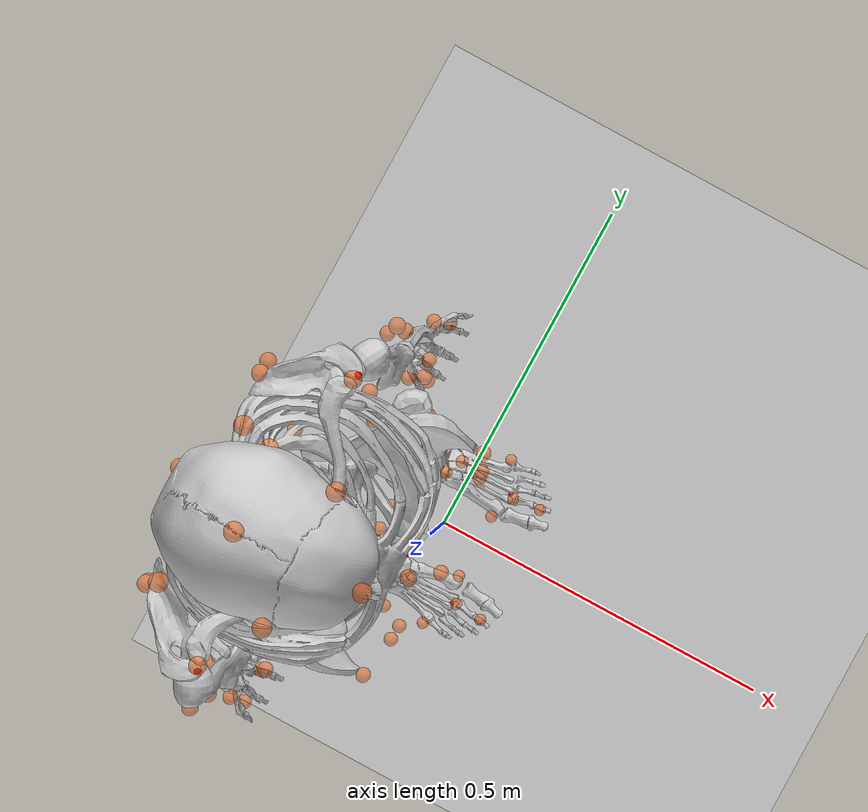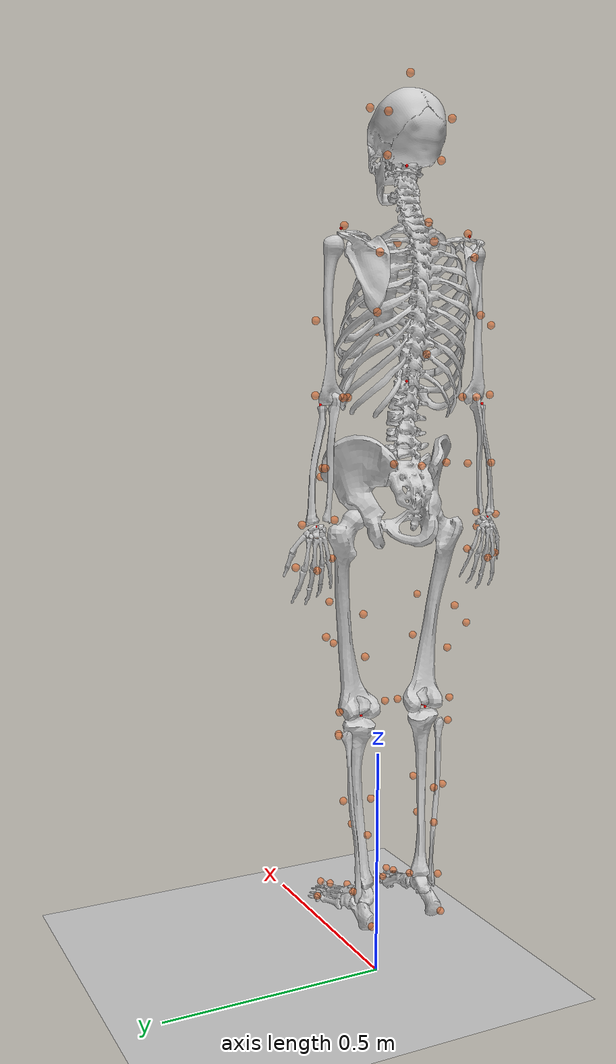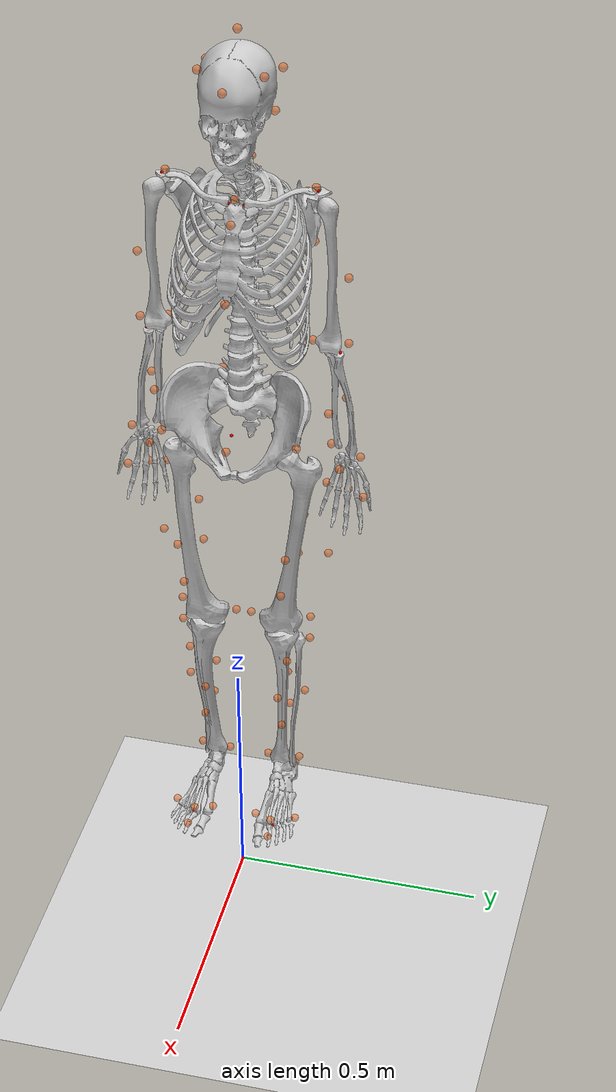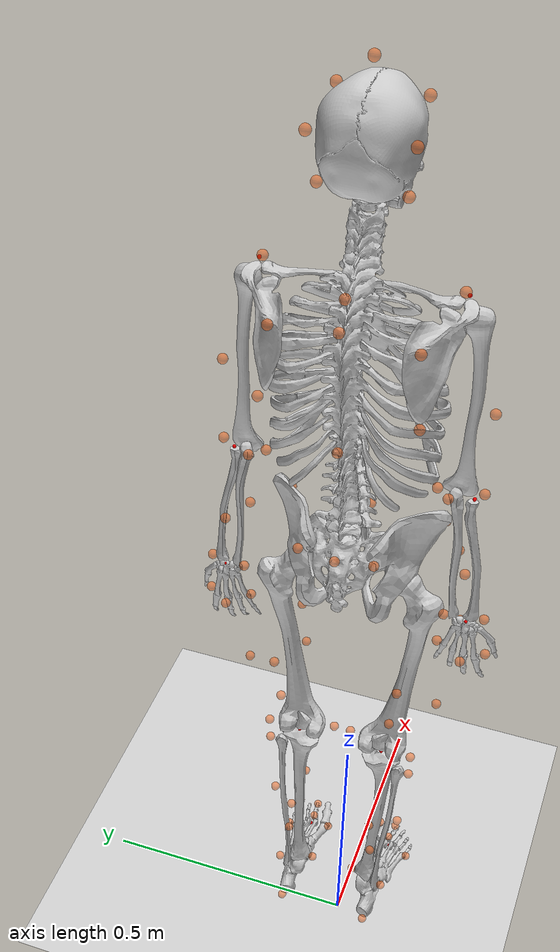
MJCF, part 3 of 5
-0.0406963 0.0348899 0.0558835 -0.0442255 0.0384226 0.0556041 -0.0439148 0.0378032 0.0554333 -0.0477607 0.128145 -0.00187776 -0.0490005 0.128309 -0.00186988 -0.048291 0.129105 -0.00150793 -0.0593406 0.113739 -0.000711621 -0.0589288 0.113937 -0.00145123 -0.0583298 0.113723 -0.00108789 -0.0577378 0.114173 -0.000884572 -0.0582087 0.114121 0.000123607 -0.0585765 0.113997 0.0011019 -0.0592711 0.113139 0.00103168 -0.0601754 0.112246 0.00101157 -0.059826 0.112559 0.000109394 -0.0599767 0.113167 -0.000452703 -0.057174 0.119341 0.00297856 -0.0573437 0.120036 0.00198875 -0.0584532 0.119731 0.00192811 -0.06059 0.118364 0.00246295 -0.0591179 0.119083 0.004018 -0.0601089 0.118696 0.00127523 -0.0613558 0.117908 0.00112627 -0.0594347 0.118361 0.00131779 -0.0697797 0.063148 0.0372201 -0.0693486 0.0632736 0.0376092 -0.0694113 0.063685 0.0384713 -0.0701768 0.0635154 0.0380918 -0.0705866 0.0635255 0.0375081 -0.0703418 0.0638605 0.0371105 -0.0695248 0.0649684 0.0371895 -0.0678546 0.0636609 0.0387053 -0.0708526 0.0655982 0.0368545 -0.0707901 0.0663245 0.0365395 -0.0712816 0.0651696 0.037083 -0.0773214 0.0728833 0.0285533 -0.0784529 0.073658 0.027273 -0.0797437 0.07452 0.0252733 0.04257 0.111058 0.0459353 0.0387783 0.131385 0.0021902 0.0391079 0.131963 0.0016217 0.0383376 0.132156 0.00252655 0.0378257 0.132446 0.00314343 0.038596 0.13203 0.00182275 0.0368691 0.132367 0.00374027 0.0360557 0.132448 0.00403828 0.0362348 0.132989 0.00343733 0.0365496 0.133798 0.00320535 0.0376234 0.132735 0.00390695 0.0375322 0.132163 0.00327219 0.0355062 0.132508 0.00679584 0.0345481 0.132625 0.00700646 0.0343705 0.132701 0.00587452 0.0341019 0.132878 0.0047876 0.0356885 0.133214 0.00590489 0.0361094 0.13302 0.00682409 0.0361135 0.132403 0.0047895 0.0361867 0.133047 0.00515258 0.0351294 0.132586 0.00437969 0.0353947 0.132181 0.0180704 0.035553 0.133317 0.017499 0.0348572 0.132884 0.0194985 0.0348387 0.131702 0.021536 0.0351924 0.131183 0.0212366 0.0356244 0.130645 0.0207475 -0.000484852 0.141042 0.0015606 -0.0069394 0.139199 0.00357861 -0.0077109 0.138555 0.00417399 -0.0093841 0.139954 0.0039566 -0.0104252 0.138917 0.00321645 -0.0101981 0.139727 0.00324805 -0.0231623 0.139846 0.0014722 -0.0323843 0.136846 -0.00099356 -0.0326333 0.136843 -0.000217359 -0.0323462 0.137618 -0.000325781 -0.0316355 0.137805 -0.000437357 -0.0317119 0.136935 -0.00115256 -0.0311931 0.132787 0.00408122 -0.0304136 0.132906 0.00524367 -0.0338972 0.131198 0.00590763 -0.0354526 0.136799 -0.000803677 -0.0347304 0.136817 -0.000775336 -0.0347941 0.136012 -0.00157407 -0.0354589 0.136017 -0.00159312 -0.0358594 0.136103 -0.000888881 -0.0381602 0.135795 0.00235113 -0.0372424 0.136245 0.00331306 -0.0353603 0.136677 0.00333577 -0.0346677 0.136116 0.0034596 -0.0349104 0.136257 0.00238511 -0.0347868 0.13653 0.0013724 -0.0356663 0.136669 0.00120579 -0.0361794 0.135938 0.00100123 -0.0369105 0.135636 0.0016564 -0.0384828 0.135147 0.00171562 -0.0457847 0.125149 0.00158459 -0.0449251 0.12627 0.00231819 -0.047255 0.122976 0.00322587 -0.0490671 0.121412 0.00300432 -0.0451368 0.125346 0.00278723 -0.0454233 0.124636 0.003556 -0.048511 0.123046 0.00144057 -0.0471544 0.123698 0.00118848 -0.0461756 0.124603 0.00088553 -0.0492799 0.126393 -0.000917358 -0.0498618 0.126764 -0.00094681 -0.0472841 0.127418 -0.00126393 -0.0479068 0.126588 -0.00131092 -0.0486515 0.125901 -0.000850653 -0.0527979 0.117215 0.00975867 -0.0548387 0.115449 0.00930155 -0.0503955 0.11938 0.00759493 -0.0507027 0.118877 0.010243 -0.0542881 0.117383 0.00694053 -0.0515018 0.118713 0.00539538 -0.0498669 0.119963 0.00563972 -0.0530297 0.11831 0.0067352 -0.0527836 0.118369 0.00514941 -0.0529623 0.12378 0.000471466 -0.0523411 0.124863 0.00114366 -0.0514265 0.124474 0.00130581 -0.0506849 0.123904 0.00188805 -0.0515181 0.123222 0.00114053 -0.0526223 0.12255 0.000492656 -0.0567244 0.113989 0.00645578 -0.0570879 0.115275 0.00460563 -0.0565286 0.115612 0.0041779 -0.0575845 0.114815 0.00405746 -0.0553738 0.116777 0.0060176 -0.0556308 0.115796 0.004403 -0.0558522 0.116883 0.00495767 -0.0574006 0.114089 -0.00185928 -0.0581448 0.114049 -0.00288316 -0.0575959 0.114494 -0.00279062 -0.0574401 0.114803 -0.00199195 -0.0576556 0.116858 0.0028659 -0.0591636 0.117556 0.000570886 -0.0590522 0.117832 0.0014698 -0.0592326 0.117574 -0.00345709 -0.0598507 0.117124 -0.00379607 -0.0601582 0.117885 -0.00361359 -0.0602655 0.11826 -0.00277478 -0.0595396 0.118605 -0.00279759 -0.0589172 0.118039 -0.00265953 -0.0610913 0.112138 -0.00101282 -0.0613364 0.11148 -0.000201615 -0.0621566 0.112649 -0.00140957 -0.061493 0.113044 -0.00129731 -0.0621271 0.111753 -0.000375213 -0.0627223 0.112492 -0.000557975 -0.0631353 0.110849 0.001671 -0.0620854 0.11128 0.000808884 -0.0638135 0.10947 0.00227651 -0.0644317 0.110094 0.00215662 -0.0619101 0.110263 0.00283558 -0.0634712 0.108859 0.00274121 -0.0604337 0.11183 0.00195152 -0.0603365 0.111532 0.00293919 -0.0611763 0.111451 0.000929421 -0.0623805 0.115134 -0.00153975 -0.0619502 0.114099 -0.00144176 -0.0635609 0.11479 -0.00132519 -0.0628059 0.115859 -0.00132652 -0.0688208 0.108985 0.00444393 -0.0676176 0.110559 0.00569631 -0.0683795 0.110147 0.00250643 -0.0657922 0.113461 0.00215709 -0.0669278 0.111934 0.00151251 -0.0676507 0.111441 0.00131474 -0.0663157 0.111399 0.00153187 -0.0628174 0.116314 0.00372144 -0.0639798 0.115527 0.00230772 -0.0681687 0.101814 0.00429233 -0.0684744 0.103155 0.0042169 -0.0661113 0.103632 0.00508004 -0.0665967 0.101772 0.00692819 -0.0675838 0.100689 0.00600718 -0.068407 0.099756 0.00512126 -0.0676911 0.10399 0.00403524 -0.0664702 0.104361 0.00311012 -0.0656745 0.104941 0.00368159 -0.0723596 0.0669687 0.036705 -0.071442 0.0648074 0.0388702 -0.0721433 0.0650914 0.0393679 -0.0747411 0.0688112 0.0353116 -0.0738485 0.0686846 0.035198 -0.0751777 0.0734226 0.0286134 -0.073873 0.0717005 0.0314209 -0.0742614 0.0712215 0.0312355 -0.0746069 0.0709082 0.0313912 -0.0763787 0.0743262 0.0248991 -0.075968 0.0750595 0.0252499 -0.0764777 0.07286 0.0271947 -0.0770619 0.0739205 0.0244518 -0.0753683 0.0719463 0.0296784 -0.075937 0.0718081 0.0285323 -0.0763915 0.0713815 0.0292924 -0.0767734 0.0719948 0.0291953 -0.0765804 0.0718561 0.0284614 -0.0669326 0.112145 -0.000770596 -0.0672608 0.112005 0.000228407 -0.0660236 0.111787 -0.000507881 -0.0663903 0.111633 -0.00141496 -0.0648155 0.1077 -0.0015333 -0.0653577 0.108481 -0.00173584 -0.0648256 0.108884 -0.00129276 -0.0645663 0.109037 -0.000522647 -0.0642985 0.108075 -0.000627252 -0.0646095 0.107279 -0.000899019 -0.0261447 0.134823 0.00348762 -0.0269354 0.134211 0.00503528 -0.0295928 0.134137 0.00300991 -0.0292188 0.134275 0.00214496 -0.0283217 0.134389 0.00222919 -0.0275033 0.135498 0.00223569 -0.0292236 0.134981 0.000309627 -0.0292218 0.134417 0.00117706 -0.0294625 0.13511 0.00123286 -0.0295085 0.135988 0.001157 -0.0295601 0.136044 0.000386033 -0.0292251 0.135893 -0.00023236 -0.0249376 0.139792 0.00297727 -0.0222768 0.140187 0.00321504 -0.0242479 0.139083 0.00232989 -0.0224497 0.140004 0.00274617 -0.025156 0.138965 0.00237587 -0.0261843 0.138854 0.00162906 -0.026588 0.139376 0.00200155 -0.018302 0.141052 0.000994489 -0.0174801 0.140798 0.000953655 -0.0178385 0.140113 7.2321e-05 -0.018563 0.140357 4.62171e-05 -0.0189996 0.140346 0.000818668 0.0497612 0.0682885 0.0514837 0.0497807 0.0670345 0.0522578 0.050273 0.0670087 0.0512159 0.0483428 0.0685758 0.0519896 0.0473639 0.068245 0.0525567 0.0483321 0.0676095 0.0538439 0.0494156 0.0670142 0.053329 0.0407298 0.110354 0.0433685 0.0397493 0.109515 0.0440797 0.0417354 0.106924 0.0455197 0.0409916 0.106965 0.0451894 0.0400294 0.107294 0.0452108 -0.0347704 0.136862 0.00603006 -0.0309042 0.138031 0.00618417 -0.0396621 0.135165 0.00439011 -0.0390556 0.135264 0.00581715 -0.0404118 0.134934 0.00323993 0.0490323 0.0688102 0.0506964 0.0480945 0.0685622 0.0511847 0.0499286 0.0683111 0.050408 0.0400552 0.111758 0.0441015 0.0375914 0.1311 0.011763 0.0375959 0.131653 0.0121658 0.0378539 0.131369 0.0124752 0.0372964 0.131474 0.0131633 0.0371971 0.130975 0.0130042 0.0366332 0.131088 0.0123851 0.0367514 0.13214 0.0134285 0.0365502 0.131678 0.0141401 0.0355401 0.131218 0.0179289 0.0366891 0.133125 0.0123187 0.0367364 0.134064 0.0126912 0.0362647 0.133714 0.0151798 0.0357208 0.131804 0.0156226 0.0155319 0.137928 0.00311676 0.0151286 0.138925 0.00259724 0.0161696 0.138667 0.0019129 0.0178524 0.138204 0.00173287 0.017581 0.137502 0.00250177 0.0171039 0.137293 0.00343578 0.0116963 0.141375 0.000868354 0.0111675 0.141426 0.00147984 0.0124417 0.141407 0.00109205 0.0114939 0.142215 0.00149958 0.0123369 0.142274 0.00162928 -0.0148413 0.139815 0.00143194 -0.0157188 0.139816 0.00172928 -0.0140077 0.140423 0.00249072 -0.0137814 0.139697 0.00228851 -0.0154719 0.140842 0.00180655 -0.0142492 0.140986 0.00262997 -0.0147488 0.141246 0.00293586 -0.0132225 0.141537 0.00397457 -0.012657 0.141226 0.00374594 -0.0177241 0.141142 0.00377005 -0.0136861 0.141583 0.00452078 -0.0184195 0.140932 0.0018818 -0.0343428 0.133165 0.00113314 -0.0343839 0.132377 0.000844836 -0.0343938 0.133071 -0.000164809 -0.0343496 0.134036 -0.000614291 -0.0342444 0.134138 0.000251717 -0.0343595 0.133988 0.0012577 -0.0345088 0.132103 0.00349122 -0.0350822 0.131395 0.00182559 -0.0344994 0.132088 0.00214041 -0.0377272 0.129522 0.00468797 -0.037059 0.130821 0.00236378 -0.0359003 0.131361 0.00151172 -0.0383851 0.129484 0.0035809 -0.0391249 0.129632 0.00282746 -0.0452064 0.038318 0.0546756 -0.048048 0.0388765 0.0529896 -0.0480413 0.0392095 0.0522067 -0.0465437 0.0398362 0.0527903 -0.0448436 0.040158 0.053303 -0.0483304 0.0386032 0.0534639 -0.049013 0.123908 -0.00058241 -0.0485484 0.124598 -0.000761937 -0.0477934 0.124051 -0.000612515 -0.0473304 0.123565 -0.000263527 -0.0482098 0.123095 -0.00016318 -0.049223 0.123604 9.10805e-05 -0.0482712 0.129101 -0.00064743 -0.050076 0.125677 -0.00104037 -0.0507717 0.125143 -0.000669862 -0.0509927 0.126206 -0.00068862 -0.050313 0.127136 -0.000821069 -0.0569766 0.118376 0.00186463 -0.0565765 0.11628 0.00274386 -0.0654467 0.107236 -0.00138664 -0.0647315 0.107102 -9.97067e-05 -0.0652652 0.106563 -0.000473223 -0.0658974 0.106972 -0.000715554 -0.0680702 0.0625082 0.0404275 -0.0694451 0.105773 0.00428668 -0.0691794 0.104838 0.00436717 -0.0700283 0.104432 0.00380324 -0.0704046 0.104636 0.0030655 -0.071085 0.104658 0.00469512 -0.0711399 0.104915 0.00298378 -0.0719447 0.103909 0.00250161 -0.0726871 0.101976 0.00329434 -0.0740719 0.098457 0.0046094 -0.0734646 0.099538 0.00519951 -0.0729628 0.100428 0.00605804 0.0503585 0.0651303 0.0537075 0.0505996 0.0652569 0.0527348 0.0482301 0.0714371 0.0556487 0.0440346 0.0540216 0.049163 0.0438352 0.0535502 0.0497519 0.0429225 0.0535465 0.0490645 0.0425574 0.0542868 0.0486604 0.0431933 0.0543087 0.0484432 0.0440012 0.0546675 0.048836 0.0414602 0.12098 0.0320514 0.0412191 0.119514 0.0340782 0.0395993 0.122836 0.0300201 0.040099 0.123217 0.0302003 0.0403195 0.12082 0.0324993 0.0390514 0.122602 0.0303416 0.0411407 0.11628 0.0418053 0.0405995 0.116625 0.0422279 0.0412566 0.114187 0.0442991 0.0418161 0.111532 0.0461939 0.0414245 0.11422 0.0430062 0.0410448 0.116003 0.0413726 0.0382751 0.112586 0.0423641 0.0380963 0.115168 0.0400491 0.0386707 0.110193 0.0439721 0.0164039 0.140751 0.00150128 0.0162685 0.139683 0.0014283 0.0148693 0.140226 0.0031195 0.0149433 0.141149 0.00256518 0.0161441 0.141638 0.00223903 0.0134885 0.138804 0.0045429 0.0147471 0.138963 0.00498182 0.0153234 0.138417 0.00413269 0.014221 0.138355 0.00723591 0.0104777 0.13884 0.0072844 0.00729336 0.138668 0.00570531 0.00797869 0.138477 0.0044971 0.0126167 0.138819 0.00207385 0.011889 0.138512 0.00211706 0.011814 0.138973 0.00152042 0.0117847 0.139696 0.00121795 0.0125192 0.139667 0.00136558 0.0128884 0.139614 0.00204591 0.0118823 0.13842 0.0038122 0.0129144 0.138661 0.00367988 0.0105151 0.139062 0.00463609 0.0113449 0.139004 0.0038285 0.00463415 0.141526 0.0013616 0.00512164 0.142417 0.00123446 0.00533371 0.140422 0.000955169 0.00445539 0.140579 0.00166735 0.00611475 0.141663 0.000898747 0.00635518 0.140582 0.00110807 -0.0105364 0.138642 0.00234093 -0.0112438 0.138314 0.00245038 -0.0109087 0.139559 0.00173921 -0.0115773 0.138736 0.00225822 -0.0124014 0.138951 0.00279296 -0.0137268 0.138332 0.0026099 -0.0136832 0.138945 0.0022932 -0.0100521 0.141663 0.00405309 -0.020089 0.136642 0.00374362 -0.0202072 0.137104 0.00304318 -0.0173777 0.139804 0.000813164 -0.0170017 0.140456 0.00269949 -0.0293885 0.137897 0.00171125 -0.0295845 0.137545 0.00249797 -0.028686 0.138729 0.000839577 -0.0273458 0.138515 0.00122242 -0.0311771 0.133264 0.00279142 -0.0309141 0.134357 0.00292846 -0.0303245 0.134633 0.00340098 -0.0296967 0.134873 0.00295491 -0.0310392 0.134401 0.00117654 -0.0311981 0.133524 0.000892279 -0.0311916 0.134216 5.96172e-05 -0.0311952 0.135155 -0.000324042 -0.030996 0.135352 0.000461908 -0.0310048 0.135303 0.00128529 -0.0312262 0.13711 -0.00049399 -0.0336255 0.133143 0.00457582 -0.03285 0.133142 0.00395169 -0.0343933 0.133005 0.00366169 -0.0322027 0.132609 0.00368733 -0.0328793 0.136708 0.00395801 -0.0344143 0.136051 -0.000783503 -0.0379818 0.0371881 0.0540633 -0.0381435 0.0364414 0.0539614 -0.0414104 0.0388767 0.0520823 -0.0378201 0.0378807 0.0539417 -0.0402485 0.0381705 0.0536123 -0.0414249 0.0394439 0.0541198 -0.0430716 0.0379822 0.0552118 -0.0473367 0.0407459 0.0551146 -0.0490595 0.041237 0.0544682 -0.0487722 0.040091 0.0541805 -0.0493375 0.0431548 0.0492796 -0.0450937 0.0412859 0.0497009 -0.0452136 0.0402604 0.0498315 -0.0448778 0.0397135 0.0507027 -0.0479232 0.0404824 0.0499345 -0.0499258 0.0409412 0.0497927 -0.0532968 0.0456136 0.0491215 -0.0529909 0.0460838 0.0490396 -0.0514676 0.0428315 0.0496354 -0.0537459 0.0454828 0.0493881 -0.0477084 0.129761 0.00348662 -0.0440755 0.132734 0.00319988 -0.0439922 0.132705 0.00226005 -0.0432183 0.132394 0.0017857 -0.0454403 0.130345 0.00220619 -0.047114 0.129249 0.00188543 -0.0486376 0.129003 0.00172422 -0.0505016 0.127278 0.0022223 -0.0567898 0.113638 0.00890378 -0.0563427 0.117428 0.00249753 -0.0555456 0.116186 0.00355408 -0.0570219 0.116246 0.00347972 -0.0584135 0.112306 0.00614678 -0.0585993 0.112558 0.00435531 -0.0589943 0.112648 0.003066 -0.0580264 0.11375 0.00310946 -0.0577422 0.114718 0.00305486 -0.0572691 0.119875 0.000513471 -0.0573892 0.120463 0.00112758 -0.0568497 0.119526 0.00163933 -0.057195 0.119141 0.0010672 -0.0580375 0.119368 0.000903847 -0.0584234 0.117073 0.0028072 -0.0585561 0.116445 0.0024207 -0.0606266 0.11753 -0.00262207 -0.0603842 0.116784 -0.00332854 -0.0604586 0.116735 -0.00246575 -0.0602787 0.118558 0.000145066 -0.06002 0.118638 -0.000793068 -0.0607307 0.118015 -0.000940096 -0.0609175 0.117189 -0.000954457 -0.0629938 0.11639 0.000208981 -0.0628227 0.116685 0.0011974 -0.0617997 0.116786 -0.000588144 -0.0629743 0.116142 -0.000593875 -0.0655507 0.111724 0.00150984 -0.065116 0.110681 0.00179933 -0.0659455 0.110398 0.00242407 -0.0659347 0.110476 0.0015355 -0.0697125 0.06582 0.0368268 -0.0704868 0.0676805 0.0358928 -0.0698084 0.0680939 0.0364507 -0.065232 0.0621934 0.0407149 -0.0655388 0.0614934 0.041022 -0.0674625 0.0655851 0.0386666 -0.0647709 0.0629206 0.0410037 -0.0674887 0.111499 -0.0011398 -0.0680802 0.110679 -0.00043646 -0.0677121 0.110429 -0.00171733 -0.0680517 0.10994 -0.000795314 -0.0684025 0.105028 0.00284487 -0.0686383 0.105555 0.00179257 -0.0682351 0.104667 0.00397179 -0.0676947 0.105968 0.00125758 -0.06695 0.105406 0.0015776 -0.0660821 0.105234 0.00204486 -0.0703516 0.10557 0.00176546 -0.0705614 0.10557 0.00105489 -0.0710035 0.105562 0.00242037 -0.0711323 0.105656 0.00140524 -0.0758795 0.0711672 0.0289717 -0.0762331 0.0723084 0.0301574 -0.0725356 0.102304 0.00129434 -0.0724067 0.102956 0.00189351 -0.0718539 0.103807 0.000347189 -0.0721248 0.10191 0.000787409 -0.0319579 0.034554 0.0560307 -0.0306995 0.0336974 0.0560313 -0.0355802 0.035013 0.0547136 -0.0497007 0.0428731 0.0546854 -0.047896 0.0434768 0.0556681 -0.0476036 0.045179 0.0562202 -0.0528508 0.0457686 0.053803 -0.0512275 0.0432235 0.0540389 -0.0580041 0.116837 0.00364564 -0.0684499 0.106402 0.00105296 -0.0540207 0.123043 0.00683947 -0.0550963 0.121144 0.00730121 -0.0547024 0.122129 0.0104131 -0.0508202 0.125798 0.00993714 -0.0514135 0.12558 0.0075685 -0.0512223 0.12597 0.00615138 -0.0605411 0.117361 0.00882604 -0.0584611 0.118706 0.0114864 -0.0465876 0.125241 -0.00100658 -0.0461484 0.125821 -0.000552708 -0.0458661 0.124986 -0.000202211 -0.0463335 0.124271 0.000171092 -0.0466544 0.124215 -0.000442506 -0.0395985 0.132125 0.00151286 -0.037958 0.132685 0.00168378 -0.040771 0.130411 0.00186035 -0.0412956 0.130931 0.00131565 -0.0399578 0.130023 0.0023551 -0.0266039 0.13527 0.00227852 -0.0256087 0.135743 0.00280797 -0.0243208 0.136194 0.00304179 -0.0232319 0.136278 0.00239391 -0.0182824 0.13916 -6.7046e-05 0.00760724 0.142497 0.00281533 0.00608444 0.142684 0.00185294 0.0103099 0.142451 0.00451282 0.00431618 0.142848 0.00253627 0.00128833 0.142847 0.00354 0.00636043 0.13954 0.00152725 0.00720678 0.139819 0.00226524 0.00703198 0.138928 0.00252956 0.00642649 0.138237 0.00272554 0.00566404 0.138508 0.00201964 0.000172809 0.139272 0.00245642 0.00138788 0.140038 0.00219754 -0.00152292 0.139151 0.0039341 -0.00184646 0.139773 0.00351201 0.0034022 0.139064 0.00302382 0.00380444 0.138469 0.00348816 0.00166155 0.138686 0.00394159 -0.00130956 0.138768 0.00460256 0.00216784 0.139989 0.00301304 0.00341808 0.139918 0.00278139 0.0146604 0.14194 0.00554072 0.0187784 0.141152 0.00513845 0.0193718 0.141086 0.00422075 0.0202176 0.140964 0.0031439 0.0173319 0.141614 0.00319948 0.0154804 0.141733 0.00355635 0.0142255 0.141 0.00455506 0.0133889 0.141271 0.00365029 0.0119188 0.138355 0.00290272 0.0112531 0.139447 0.00288029 0.0113266 0.139242 0.00207676 0.0475077 0.0552953 0.0500704 0.0478597 0.0548876 0.0507677 0.0462092 0.0538637 0.0511041 0.0452756 0.0535034 0.0517677 0.0441815 0.0536744 0.0512338 0.0431732 0.0533085 0.050461 0.0496765 0.0668586 0.0494217 0.0487673 0.0668638 0.0493729 0.0488204 0.0681352 0.0498593 0.0447424 0.0560648 0.0491468 0.0450948 0.0554223 0.0492804 0.0434122 0.0553431 0.0485687 0.0442405 0.0566073 0.0490065 0.0369861 0.132697 0.00457775 0.0371385 0.134645 0.00461666 0.0363812 0.134756 0.00529166 0.0362619 0.133886 0.00525456 -0.0294237 0.0365002 0.05568 -0.0247483 0.0363141 0.0555155 -0.0337573 0.037722 0.0552933 -0.0244749 0.0354563 0.0561382 -0.0239636 0.034854 0.056943 -0.0277485 0.0341051 0.0563568 0.0391489 0.117613 0.0371207 0.0388711 0.120242 0.0340775 0.0397072 0.120359 0.0335289 0.0418642 0.119343 0.0352647 0.0400159 0.114975 0.0401573 0.0380469 0.11787 0.0372162 0.0371924 0.131373 0.0111144 0.037085 0.131804 0.0101677 0.0367447 0.132411 0.00924135 0.0370321 0.134278 0.0104611 0.0368922 0.133563 0.00833022 0.0370278 0.134461 0.00857579 0.0365074 0.132736 0.00800153 0.0346663 0.131902 0.0109595 0.0359573 0.13167 0.0103952 0.0338537 0.131442 0.0154026 0.0326203 0.1318 0.015404 0.0330268 0.132073 0.0130589 0.0333302 0.132268 0.0112185 0.0355265 0.131246 0.0136129 0.0347389 0.131201 0.0155254 0.0128321 0.141483 0.00178048 0.00214811 0.14191 0.00267352 0.00137346 0.142206 0.00205594 0.000528759 0.142373 0.00154217 0.0011635 0.141455 0.00130389 0.00458461 0.138409 0.00411624 -0.0069758 0.142256 0.00349609 0.0470895 0.0667505 0.0505083 0.0470656 0.0654982 0.0505324 0.0470744 0.067878 0.0509705 0.0462869 0.0661383 0.0511765 0.0458426 0.0673689 0.0519236 0.0454854 0.069178 0.0524996 0.0465096 0.0685132 0.0523396 0.0460083 0.0696608 0.0523086 0.0464011 0.0698168 0.0526832 -0.0232062 0.137097 0.00177384 -0.0239204 0.13756 0.00240786 -0.0238515 0.138239 0.00214752 -0.0308059 0.136928 0.00293947 -0.0311303 0.136999 0.00224235 -0.0361207 0.133316 0.000754753 -0.0363098 0.134197 0.000714423 -0.036058 0.134262 9.94313e-06 -0.0358723 0.134082 -0.000715854 -0.0359003 0.133092 -0.000285661 -0.0359597 0.132388 0.000536179 -0.0363552 0.132093 0.00154795 -0.0473748 0.128397 0.00047215 -0.0467401 0.127592 0.000843134 -0.0467032 0.127221 -6.15762e-05 -0.0467392 0.126648 -0.000834224 -0.0481323 0.129082 0.000210041 -0.0506541 0.119999 0.0026473 -0.0506178 0.122645 0.00173127 -0.0507272 0.120813 0.0016486 -0.0508057 0.124916 0.00139007 -0.0531504 0.124617 0.00176993 -0.0518003 0.125788 0.00218154 -0.050373 0.127493 0.001459 -0.068825 0.109506 0.00208439 -0.0704958 0.105725 0.00587613 -0.0693289 0.107817 0.00307799 -0.0690796 0.106344 0.00364049 -0.0775785 0.0719579 0.032868 -0.0780128 0.0727967 0.0329655 -0.0796462 0.0747645 0.026813 -0.0771919 0.0730746 0.0310451 -0.0766463 0.0713148 0.0332326 0.048027 0.0548784 0.0515148 0.0477728 0.0549904 0.0522219 0.046456 0.0536978 0.0521021 -0.0580877 0.115486 0.00318545 -0.0584994 0.115691 0.00107014 -0.0581685 0.115756 -3.78586e-05 -0.0585367 0.116582 -0.000249149 -0.0645941 0.107834 0.00119117 -0.0649232 0.108749 0.00140003 -0.0651266 0.106529 0.00172696 -0.0649084 0.106939 0.000810868 -0.0645618 0.106927 0.00318252 -0.0633752 0.108266 0.00363034 -0.0649169 0.108771 0.00227813 -0.0692325 0.106582 0.00285441 -0.069127 0.106153 0.0020467 -0.0693463 0.107504 0.00177425 0.0431122 0.0543096 0.0531516 0.0414746 0.0540846 0.0534821 0.0412142 0.0534185 0.0527769 0.0407363 0.0531774 0.0519673 0.0421644 0.0531471 0.0512427 0.0447206 0.0536811 0.052557 0.0444655 0.0540669 0.0532906 0.0432868 0.0546981 0.0538634 0.045708 0.0543019 0.0535337 0.045027 0.0546815 0.0541769 0.0438117 0.0550242 0.054589 -0.0702324 0.104691 0.000853478 -0.0699974 0.103289 0.000543544 -0.0705466 0.103398 1.23184e-05 -0.0712479 0.103644 -3.08923e-05 -0.0563082 0.117892 0.00550472 -0.0527245 0.120781 0.00129819 -0.0520801 0.119309 0.00235215 -0.0532564 0.120213 0.00235519 -0.0751463 0.0709195 0.0315447 -0.075797 0.0712978 0.0315876 -0.0503262 0.127482 0.000725497 -0.049219 0.128622 0.000228285 -0.0280844 0.135612 0.000661877 -0.0281297 0.136232 2.80709e-05 -0.0280489 0.136646 0.000720867 -0.0277691 0.136904 0.00126653 -0.0278011 0.136184 0.00145051 -0.0325981 0.134945 0.000557592 -0.0326425 0.135797 0.000702281 -0.0326395 0.135972 -7.34975e-05 -0.0324344 0.13504 -0.000510235 -0.0324375 0.134219 0.00010215 -0.0331803 0.0415038 0.0612962 -0.0342874 0.0441169 0.0612575 -0.036139 0.0419831 0.0603265 -0.0371144 0.0399769 0.0594962 -0.035028 0.0388437 0.060045 -0.0325333 0.0390767 0.0610412 -0.0723861 0.0679833 0.0348119 -0.0728855 0.069414 0.0333275 -0.0565876 0.120224 0.00685465 -0.0587485 0.119281 0.00541422 -0.0603919 0.118049 0.00564393 0.0429896 0.0665264 0.0541496 0.0442565 0.0675666 0.0535473 0.0448861 0.0651333 0.0530479 0.0456468 0.0635024 0.0521186 0.0418276 0.0602127 0.0523437 0.0399016 0.0602199 0.0534234 0.040626 0.062815 0.0541129 0.0409772 0.0657714 0.0549136 0.0444813 0.0616833 0.0520374 0.0431517 0.059702 0.0512177 -0.0400348 0.0662779 0.0570378 -0.0397311 0.0634338 0.0570344 -0.0419852 0.0636687 0.0560077 -0.0440834 0.0646491 0.0551509 -0.0428373 0.0671074 0.055811 -0.0410585 0.068755 0.056818 -0.0615509 0.10304 0.038269 -0.059635 0.10562 0.0386177 -0.0636274 0.103163 0.0347601 -0.0638251 0.100893 0.0366062 -0.0610188 0.106227 0.0358854 -0.0599062 0.108962 0.0344137 -0.0619025 0.108577 0.0311479 -0.0639583 0.107554 0.0280092 -0.0651167 0.10446 0.0300474 -0.0661562 0.098843 0.0342765 -0.0670984 0.102919 0.027161 -0.067902 0.099775 0.0294852 -0.0684703 0.0939621 0.0340902 -0.066224 0.0962107 0.0363534 -0.0697412 0.097949 0.0268077 -0.0703015 0.0947698 0.0292914 -0.0705159 0.0889046 0.0342858 -0.0683474 0.0912211 0.0363848 -0.072081 0.0927818 0.0267679 -0.072492 0.0896465 0.0294369 -0.0723404 0.0838207 0.0350225 -0.0701716 0.0860639 0.0367985 -0.074331 0.087616 0.027155 -0.0745695 0.0846294 0.030213 -0.0736245 0.0788051 0.0363656 -0.071717 0.080903 0.0377098 -0.0763687 0.0827094 0.0283662 -0.0761335 0.0798435 0.0319205 -0.0740164 0.0741208 0.0380463 -0.0725172 0.075916 0.0389765 -0.0775216 0.0782449 0.0307082 -0.0764326 0.0755412 0.0344249 -0.0735643 0.070079 0.0396904 -0.0725029 0.0714276 0.0403189 -0.0772262 0.0745281 0.0338607 -0.0758565 0.0718087 0.0368649 -0.0722632 0.0668501 0.0412641 -0.0716232 0.0677247 0.0416579 -0.0764316 0.0710131 0.0364614 -0.0747972 0.0683574 0.0389026 -0.0706814 0.0640514 0.0425679 -0.0701693 0.0647263 0.0429632 -0.0752138 0.0675408 0.0385049 -0.073096 0.0653666 0.040527 -0.0692367 0.0612603 0.043487 -0.0687372 0.061844 0.0440448 -0.0727681 0.0651228 0.0399433 -0.0706084 0.0635589 0.0415122 -0.067328 0.0586962 0.0442359 -0.0672444 0.0589313 0.0450133 -0.068711 0.061336 0.0420031 -0.0648347 0.0565679 0.0451966 -0.0652009 0.0562328 0.0458092 -0.066316 0.0597484 0.043011 -0.06243 0.0536141 0.0457981 -0.0629673 0.0531486 0.0463673 -0.0637955 0.0578287 0.0443356 -0.059551 0.0506367 0.0465209 -0.0600874 0.0500428 0.0470674 -0.063506 0.058384 0.0438511 -0.0612965 0.0546826 0.0446975 -0.0563004 0.0485067 0.0480127 -0.0608494 0.0554323 0.0447785 -0.0585947 0.0521039 0.0463635 -0.0582555 0.052912 0.0466528 -0.0557032 0.0497843 0.0480827 -0.0554208 0.0505691 0.0484154 -0.0524646 0.0474967 0.0495635 -0.0489358 0.0447967 0.0501454 -0.0449126 0.0431536 0.0505363 -0.0408237 0.0422948 0.0515969 -0.0408418 0.0412388 0.0513668 -0.0369972 0.0406462 0.0530404 -0.0372099 0.0396092 0.0533601 -0.0332311 0.0400391 0.0543724 -0.0292132 0.039298 0.054788 -0.025024 0.0392016 0.0552152 -0.0209167 0.0399051 0.0563323 -0.0206823 0.0385828 0.0562238 -0.0165642 0.03979 0.0570146 -0.0163102 0.0387486 0.0571184 -0.0160932 0.0379168 0.05751 -0.0159259 0.037336 0.0581519 -0.0158049 0.0369903 0.0589033 -0.0197879 0.0356419 0.0585331 -0.019605 0.0351976 0.059272 -0.0234308 0.0338594 0.0585274 -0.0269244 0.0328924 0.0574777 -0.0301361 0.0323452 0.0563339 -0.0333742 0.03228 0.0548859 -0.0332726 0.0336896 0.0550752 -0.0367956 0.0328059 0.0530988 -0.0363065 0.0336619 0.0532991 -0.0390923 0.0353469 0.0530466 -0.0411945 0.0369304 0.0540744 -0.040302 0.03434 0.0535928 -0.0405596 0.034149 0.0544351 -0.0377674 0.0319619 0.0546473 -0.0379708 0.0322115 0.0556269 -0.0343315 0.0313235 0.0568004 -0.0345271 0.0319038 0.0573189 -0.0346773 0.0326301 0.0577055 -0.0348092 0.0333864 0.0580571 -0.0349608 0.0341916 0.0583835 -0.0380555 0.0353564 0.0574821 -0.0379459 0.0364152 0.0579647 -0.0404277 0.038672 0.0576466 -0.0426861 0.0409762 0.0573399 -0.0420556 0.0424108 0.0579863 -0.0443125 0.0446298 0.0575022 -0.0432776 0.0466218 0.0582386 -0.0456841 0.0491153 0.0575569 -0.0483111 0.0519157 0.0567724 -0.0505684 0.0477719 0.0553238 -0.0510739 0.054873 0.0558705 -0.0525974 0.0526753 0.0549402 -0.055434 0.0556295 0.0537082 -0.0567642 0.0539242 0.0527225 -0.057807 0.0526624 0.0518754 -0.0586516 0.0518037 0.051177 -0.0593474 0.0511584 0.0505689 -0.0565169 0.0482796 0.0520731 -0.0522844 0.0431569 0.0534497 -0.0571118 0.0477839 0.0515455 -0.054501 0.0452408 0.0526402 -0.052219 0.0410559 0.0527071 -0.0514247 0.0412508 0.053258 -0.0547237 0.0451519 0.0519947 -0.0532151 0.0429186 0.0522813 -0.0523154 0.0394909 0.0517016 -0.0517909 0.0396369 0.052347 -0.0529569 0.043044 0.0515561 -0.0525597 0.0410778 0.05126 -0.0514577 0.0385004 0.0509516 -0.0520539 0.0411306 0.0505101 -0.0513796 0.0396127 0.0503725 -0.0502658 0.0397222 0.0501927 -0.0495688 0.0389756 0.0508937 -0.0509604 0.0377061 0.0511605 -0.0510251 0.0376218 0.0518355 -0.0506989 0.0388028 0.052593 -0.0515247 0.0376028 0.0513847 -0.0426202 0.0400957 0.0534088 -0.0421909 0.0397323 0.0545007 -0.0435857 0.0400565 0.0543377 -0.0446113 0.0400574 0.0542201 -0.0522853 0.0430467 0.0501521 -0.0542213 0.0452195 0.0505856 -0.0573331 0.0469286 0.0494229 -0.0606989 0.0496268 0.0486727 -0.0604487 0.0500392 0.0494121 -0.0629024 0.0532721 0.047854 -0.0623979 0.0537096 0.0485002 -0.0645602 0.0567918 0.0471303 -0.0639421 0.0572954 0.0476789 -0.0660749 0.0600416 0.0461289 -0.0653986 0.0606953 0.0466689 -0.0674916 0.0631883 0.0450212 -0.0666123 0.0641666 0.0456603 -0.06865 0.0666028 0.0439905 -0.0674444 0.0680649 0.0448173 -0.0693521 0.070586 0.0430614 -0.0677182 0.0724953 0.0440535 -0.0693505 0.0751923 0.0422085 -0.0673035 0.0775224 0.0434578 -0.0685807 0.0803481 0.0414586 -0.0663251 0.0829412 0.0429797 -0.0672976 0.0857396 0.0409058 -0.0649541 0.088411 0.0425839 -0.0656462 0.0910537 0.0405341 -0.0631925 0.0937438 0.0422657 -0.0636024 0.0961659 0.0403488 -0.0610314 0.098951 0.0419262 -0.058541 0.102103 0.0427889 -0.0563853 0.105368 0.0428049 -0.057185 0.107174 0.0403985 -0.055427 0.110259 0.0394482 -0.0567584 0.111443 0.0362399 -0.0548679 0.114423 0.0349556 -0.0565177 0.114923 0.0313917 -0.0583194 0.114764 0.027905 -0.0601 0.11418 0.0245354 -0.0617474 0.113336 0.0212428 -0.064034 0.109765 0.0230365 -0.0656545 0.108609 0.0199559 -0.0674653 0.104914 0.0220325 -0.0689868 0.103542 0.019133 -0.0703663 0.099773 0.0215672 -0.0717297 0.098198 0.0188709 -0.0728239 0.094425 0.0215421 -0.0741317 0.0927807 0.019085 -0.0752124 0.0891285 0.0219705 -0.0764718 0.0875724 0.0199103 -0.0774066 0.08411 0.0231231 -0.0784441 0.0827805 0.0215818 -0.0788156 0.0796839 0.0254661 -0.0794248 0.0787725 0.0246541 -0.0789081 0.0754989 0.0289236 -0.0768488 0.0693335 0.0355457 -0.0740549 0.066896 0.0375631 -0.0795575 0.0811769 0.0197745 -0.0798821 0.0805329 0.0190847 -0.079915 0.0798668 0.0183684 -0.0792522 0.0793049 0.0178905 -0.0784122 0.0788311 0.017578 -0.0790794 0.0742987 0.0245382 -0.0775782 0.0783131 0.0173347 -0.0766359 0.077948 0.0171978 -0.0757914 0.0783558 0.0175589 -0.0753304 0.0791129 0.0180898 -0.0749825 0.0799371 0.0186246 -0.0756062 0.0776462 0.0221295 -0.07506 0.0786526 0.0226647 -0.0749621 0.0767845 0.0260771 -0.0741456 0.0749428 0.0293419 -0.0728088 0.0729989 0.032198 -0.0711582 0.0709476 0.0346924 -0.0703873 0.071852 0.0352229 -0.0683915 0.0694936 0.0374987 -0.0660991 0.067022 0.0396743 -0.0636801 0.0645641 0.041982 -0.0613597 0.0619543 0.0442643 -0.0618535 0.0610186 0.0438177 -0.0596609 0.0580016 0.0457799 -0.0600689 0.0570854 0.0453773 -0.0575328 0.0546941 0.0473991 -0.0570671 0.0558004 0.0478601 -0.0546779 0.0527203 0.0494047 -0.0517688 0.0498278 0.0506131 -0.0484052 0.0473942 0.0514208 -0.0447003 0.0459332 0.0519974 -0.0409082 0.0452093 0.0529188 -0.037127 0.0447891 0.0543192 -0.0370354 0.043109 0.0535788 -0.0331309 0.0428328 0.0547077 -0.0291414 0.0427616 0.0553259 -0.0252381 0.0429503 0.0560458 -0.0213802 0.0434714 0.0569482 -0.017594 0.044241 0.0579948 -0.0171566 0.0423671 0.0574932 -0.0133794 0.0434904 0.0584061 -0.0129312 0.0422036 0.0579524 -0.0095198 0.0435634 0.0595132 -0.0090219 0.0426397 0.0592516 -0.0085704 0.0418405 0.0590813 -0.0081628 0.0410875 0.059073 -0.007816 0.0403918 0.0593241 -0.0075861 0.0398561 0.0599203 -0.0074855 0.0395153 0.0607408 -0.011657 0.0380113 0.0600522 -0.0117498 0.0381202 0.0609206 -0.0156574 0.0366414 0.0604763 -0.0156822 0.0367518 0.0612986 -0.0193922 0.0346768 0.0608774 -0.0232996 0.0331236 0.0600936 -0.0270882 0.0325119 0.0589856 -0.0304887 0.0317491 0.0576426 -0.0272527 0.032463 0.0597098 -0.0274681 0.0328175 0.0603129 -0.0276726 0.0335052 0.0607202 -0.0278738 0.0343271 0.0610137 -0.0281124 0.0352629 0.0612846 -0.0284439 0.0364617 0.0616005 -0.0318314 0.0355237 0.0601953 -0.0321044 0.0370457 0.0606294 -0.0390662 0.0420013 0.0591584 -0.0396995 0.0466044 0.0596528 -0.0377698 0.0493955 0.0606476 -0.0399726 0.0518848 0.0600376 -0.0423137 0.0545066 0.0593202 -0.0447736 0.0573042 0.0586126 -0.0472849 0.0602191 0.0578598 -0.0497629 0.0631459 0.0569822 -0.0518897 0.0603231 0.0559254 -0.0543097 0.0631907 0.054727 -0.056273 0.060667 0.0535194 -0.0584507 0.0635579 0.0519851 -0.0600888 0.061507 0.0507916 -0.0613906 0.0599341 0.0497804 -0.0624287 0.0587519 0.0489336 -0.0634469 0.0628239 0.0481778 -0.0640357 0.0671706 0.0474999 -0.0622889 0.0692397 0.0486651 -0.0640565 0.0719942 0.0469601 -0.0619277 0.0745285 0.0482784 -0.0635749 0.0773259 0.0466144 -0.0613056 0.0801638 0.0480287 -0.062777 0.0829516 0.0463551 -0.060393 0.0859566 0.0477441 -0.0615817 0.0886372 0.0460125 -0.0590542 0.091762 0.0473255 -0.0599559 0.0942761 0.0455455 -0.0573399 0.09756 0.0465275 -0.0548029 0.100953 0.0471075 -0.0523674 0.104315 0.04728 -0.0533001 0.106591 0.0449577 -0.0510581 0.109779 0.0444742 -0.052212 0.1117 0.0415766 -0.0499316 0.114686 0.040688 -0.0512222 0.116209 0.0373452 -0.0487213 0.118971 0.0363707 -0.050129 0.120057 0.0327678 -0.051602 0.120697 0.0290793 -0.0530597 0.120869 0.0253802 -0.0544351 0.120643 0.0217067 -0.0556481 0.120128 0.0180546 -0.056913 0.119545 0.0145627 -0.0604143 0.116101 0.0162136 -0.0649623 0.111298 0.0150092 -0.066526 0.110029 0.0121491 -0.0686387 0.106066 0.0140714 -0.0699264 0.104653 0.0114678 -0.0715776 0.100581 0.0137353 -0.0726857 0.09903 0.0114525 -0.0740262 0.0950827 0.0140516 -0.0750013 0.093698 0.0121611 -0.0762432 0.0899765 0.0151026 -0.0768938 0.0890237 0.013891 -0.0773318 0.0882949 0.0130275 -0.0774794 0.0876386 0.0123375 -0.0769989 0.0870803 0.0119717 -0.076395 0.0866534 0.0117182 -0.0757852 0.0861425 0.0113875 -0.0751887 0.0856222 0.0110506 -0.074509 0.0851957 0.0108337 -0.0737412 0.085009 0.0108514 -0.0730955 0.0852632 0.0112765 -0.072663 0.0858092 0.0119136 -0.072291 0.0864908 0.0126518 -0.073432 0.0835309 0.0158995 -0.0728754 0.0846031 0.0167749 -0.0737633 0.0821661 0.0201079 -0.0727776 0.0838181 0.0211989 -0.0731771 0.0818163 0.0245186 -0.0729094 0.0798086 0.0277314 -0.0721046 0.0777152 0.0307696 -0.0708666 0.0755129 0.0335108 -0.0694666 0.0773352 0.0344624 -0.0678984 0.0749109 0.0368593 -0.0660381 0.0723406 0.0390017 -0.0640095 0.0697079 0.0410345 -0.0620584 0.0670697 0.0432428 -0.0600318 0.0643349 0.0453249 -0.0579531 0.061517 0.0472067 -0.05865 0.0601176 0.0466735 -0.0557889 0.0587108 0.0489121 -0.0534609 0.0561248 0.0506338 -0.050701 0.0538824 0.0520886 -0.0475257 0.0521428 0.0531009 -0.0441424 0.0510375 0.0539314 -0.0406947 0.0504298 0.0549675 -0.0372544 0.0501283 0.0563947 -0.0338853 0.0500104 0.0581238 -0.0335567 0.0470454 0.0568603 -0.0298271 0.0472839 0.0579245 -0.0262014 0.0478157 0.0588224 -0.0226849 0.0485422 0.059708 -0.019303 0.0492317 0.0608626 -0.0160584 0.049964 0.0621456 -0.0149512 0.047486 0.0603914 -0.0118244 0.0485119 0.0617861 -0.0108655 0.0463696 0.0606972 -0.0079769 0.0479425 0.0619936 -0.0072051 0.046511 0.0612666 -0.0046191 0.0488726 0.0617812 -0.0040536 0.0480413 0.0613574 -0.0035515 0.0474161 0.0610322 -0.00306582 0.0468492 0.0608518 -0.00260798 0.0463307 0.0608127 -0.00221677 0.0459096 0.0610103 -0.00195709 0.0456448 0.0614323 -0.00195719 0.0456404 0.0619948 -0.00225596 0.0459308 0.0625189 -0.0043693 0.0425421 0.0623158 -0.0049303 0.0430634 0.0629239 -0.0080036 0.0398876 0.0626241 -0.0083633 0.0406052 0.0635003 -0.012131 0.0389129 0.0626936 -0.0123491 0.039449 0.0635204 -0.0160261 0.0375864 0.0628558 -0.0197398 0.0354777 0.0622908 -0.0200699 0.0363003 0.062683 -0.0204534 0.0372212 0.0630099 -0.0209184 0.0383098 0.0633234 -0.0215559 0.0398162 0.0636449 -0.0224551 0.0419063 0.0640127 -0.02567 0.0398367 0.0630392 -0.0265914 0.042303 0.063322 -0.027737 0.0453406 0.0633594 -0.0291353 0.0487438 0.0632611 -0.0308541 0.0521579 0.0630983 -0.0333993 0.0495889 0.0620821 -0.0329819 0.0551997 0.0627638 -0.0354195 0.0579059 0.06218 -0.0379459 0.0605642 0.061457 -0.0404265 0.0633425 0.0606566 -0.0428353 0.066245 0.059811 -0.0451281 0.0692162 0.0588143 -0.0472908 0.0721849 0.0576051 -0.0496835 0.0690823 0.0567661 -0.0517645 0.0719714 0.0554093 -0.0541606 0.0689023 0.0543948 -0.0561117 0.0717464 0.0528577 -0.0584084 0.0689002 0.0516218 -0.057944 0.0745708 0.0512639 -0.0555681 0.0776419 0.0524 -0.057327 0.0804412 0.0508848 -0.0549568 0.0836689 0.0520535 -0.0565573 0.0864421 0.0505991 -0.0540625 0.089779 0.0516717 -0.055359 0.0924825 0.050085 -0.0527564 0.0958803 0.0508984 -0.0501839 0.099228 0.0514357 -0.0476375 0.102481 0.0516806 -0.0488622 0.105135 0.0494755 -0.0463679 0.10832 0.0492573 -0.0475627 0.110708 0.0466255 -0.0449941 0.11364 0.0460544 -0.0461841 0.115717 0.0430382 -0.0434421 0.118295 0.0424099 -0.0446875 0.120094 0.0390802 -0.0417269 0.122392 0.0385077 -0.0429704 0.123907 0.0349346 -0.0442484 0.125119 0.0312791 -0.0455122 0.125989 0.0275624 -0.0467548 0.126533 0.0238374 -0.0479346 0.126738 0.020124 -0.0489624 0.126565 0.0164652 -0.0451862 0.129728 0.0162916 -0.0460676 0.129655 0.012863 -0.0418744 0.132733 0.0129787 -0.0425149 0.13279 0.0099218 -0.0430643 0.132755 0.00739137 -0.0435406 0.132705 0.00560416 -0.053115 0.12433 0.00473639 -0.0546875 0.122645 0.00507786 -0.0550007 0.121267 0.00510452 -0.0547465 0.120766 0.00642309 -0.0542262 0.119896 0.0064766 -0.054688 0.119375 0.0073008 -0.0557742 0.118822 0.00688873 -0.0575502 0.119301 0.00420751 -0.0641121 0.11491 0.000462789 -0.0644244 0.112023 0.00097755 -0.0545412 0.120687 0.00364484 -0.0476293 0.122251 0.00440734 -0.0458698 0.123531 0.00615965 -0.045964 0.12311 0.00837424 -0.0459773 0.122752 0.0112185 -0.0459067 0.122366 0.0144857 -0.0484839 0.120307 0.0140144 -0.0484546 0.119873 0.0175447 -0.0508819 0.117886 0.0170373 -0.0531701 0.115972 0.0165137 -0.0553583 0.114026 0.0159728 -0.0575005 0.112014 0.0153863 -0.0594866 0.109812 0.0146812 -0.0590499 0.110901 0.0113876 -0.0608115 0.108697 0.0106837 -0.0603633 0.109769 0.00799838 -0.0620048 0.107869 0.0073981 -0.0618128 0.108998 0.00542254 -0.0636572 0.106188 0.00668025 -0.0640214 0.104659 0.00894831 -0.064418 0.10288 0.0115689 -0.0658531 0.101035 0.0103146 -0.0663955 0.098917 0.0130182 -0.067778 0.097131 0.011583 -0.0688755 0.0956203 0.0101949 -0.0697427 0.0944078 0.00887813 -0.0703741 0.0934782 0.00767136 -0.0696648 0.0964645 0.00558167 -0.0688103 0.101316 0.00365906 -0.0700598 0.0960015 0.00466804 -0.0692625 0.098836 0.00346722 -0.0696509 0.102704 0.00285218 -0.0694115 0.098736 0.00263894 -0.0690704 0.101252 0.00210059 -0.0700195 0.104237 0.00219761 -0.0691869 0.101345 0.00115716 -0.0702811 0.098752 0.0014892 -0.0711096 0.098953 0.00145154 -0.0719723 0.099195 0.00141172 -0.072922 0.0960405 0.00267162 -0.0737004 0.0964908 0.00290555 -0.0743921 0.0969667 0.00324045 -0.0750419 0.0935425 0.00561471 -0.0755531 0.0939989 0.00593562 -0.0729143 0.0921948 0.00486265 -0.0721876 0.0919532 0.00486894 -0.0715498 0.092015 0.00524184 -0.0711625 0.0923712 0.00590352 -0.071034 0.0904147 0.0104394 -0.0711645 0.088627 0.0146554 -0.0702226 0.0902498 0.0159753 -0.0710071 0.0879254 0.0192069 -0.069656 0.0902012 0.020727 -0.0700576 0.0881584 0.023946 -0.0701902 0.0861971 0.0271357 -0.0698918 0.0841601 0.0302179 -0.0690634 0.0819331 0.03306 -0.0672377 0.084512 0.0344741 -0.0659934 0.0820615 0.0369483 -0.0644584 0.0794597 0.0391403 -0.062748 0.0767633 0.0411186 -0.06104 0.074032 0.0430834 -0.0593797 0.0713382 0.0451315 -0.0575299 0.0687154 0.0470418 -0.0555518 0.0661966 0.0488334 -0.0534437 0.0638387 0.0504685 -0.0512126 0.0617065 0.0520119 -0.0487737 0.0598698 0.0533899 -0.0460104 0.0584419 0.0543762 -0.0430502 0.0574743 0.0552403 -0.0400548 0.0569509 0.0563304 -0.0371569 0.056783 0.0577957 -0.0342161 0.056929 0.0592425 -0.0312099 0.0573336 0.0605107 -0.0308457 0.0537106 0.060224 -0.0275942 0.054296 0.0612916 -0.0243851 0.0550205 0.0622351 -0.0212552 0.0558141 0.0632069 -0.0181813 0.0567293 0.0640887 -0.0151579 0.0578026 0.0648139 -0.0140759 0.0541279 0.0643515 -0.0110467 0.0554615 0.0647846 -0.0099376 0.0524007 0.0638388 -0.0071105 0.0541923 0.0638213 -0.0061683 0.0519087 0.0629659 -0.0034946 0.0538612 0.0630846 -0.00278994 0.0523338 0.062311 -0.00020866 0.0541123 0.0625491 0.00026416 0.0531555 0.0618063 0.00065739 0.0524507 0.0612721 0.00104307 0.0518083 0.0608571 0.00145772 0.0511549 0.0605827 0.00189273 0.0504986 0.060582 0.00224538 0.0499654 0.060946 0.00240892 0.0496913 0.0615389 0.00230903 0.0497895 0.0621708 0.00202155 0.0501614 0.0627125 0.00167672 0.050635 0.0631778 -0.00049062 0.0487793 0.0631357 -0.00089166 0.0492971 0.0635884 -0.00313524 0.0469285 0.0634648 -0.0035621 0.047515 0.0640678 -0.0058431 0.0444865 0.0641385 -0.0064144 0.0453322 0.0647514 -0.0091385 0.0422381 0.0646998 -0.0098626 0.0433507 0.0651831 -0.0132489 0.0411881 0.0647554 -0.0139604 0.0424606 0.0651386 -0.0149834 0.0442143 0.0655074 -0.0163714 0.0465441 0.0659082 -0.0180153 0.049384 0.0662084 -0.0207215 0.0469061 0.0652729 -0.022316 0.0500673 0.0653503 -0.024077 0.053524 0.0652587 -0.026039 0.0570806 0.0650753 -0.0282426 0.0604684 0.0646204 -0.0306838 0.0635226 0.0639065 -0.0332468 0.0663898 0.0630786 -0.0357876 0.0692722 0.0622837 -0.0381881 0.072251 0.0613824 -0.0404528 0.0752993 0.0603671 -0.0425909 0.0783657 0.0592026 -0.0446352 0.0814106 0.0579719 -0.0470037 0.0782867 0.0571535 -0.0489821 0.0812346 0.0558525 -0.0513566 0.0780139 0.0549351 -0.0508189 0.0841316 0.054479 -0.0484007 0.0873932 0.0554189 -0.0500605 0.0903085 0.0540605 -0.0475364 0.0935542 0.0548462 -0.0449925 0.0966843 0.0554534 -0.0424484 0.099708 0.0558534 -0.0438239 0.102749 0.053871 -0.0412851 0.105696 0.0538833 -0.0425923 0.108622 0.0515077 -0.0399158 0.111249 0.0512975 -0.0410906 0.113869 0.0485227 -0.0381874 0.116164 0.0482517 -0.0393301 0.118505 0.0451897 -0.0362131 0.120528 0.0448917 -0.0373767 0.122609 0.0415866 -0.0340302 0.124388 0.0413292 -0.0351504 0.126251 0.0378899 -0.0362301 0.127872 0.0343427 -0.0372821 0.129277 0.0307535 -0.0383178 0.130475 0.0271526 -0.0393024 0.131387 0.0235313 -0.0402387 0.13207 0.0199248 -0.0361906 0.13414 0.0200391 -0.0369129 0.134707 0.0165252 -0.0328704 0.136407 0.0166486 -0.0333568 0.136709 0.0133149 -0.0337235 0.136863 0.0102999 -0.0299545 0.137986 0.0104709 -0.0260932 0.138972 0.0107094 -0.026629 0.139043 0.00825054 -0.0222602 0.140097 0.00855835 -0.0224141 0.140196 0.00669494 -0.0178792 0.140945 0.00709137 -0.0178539 0.141053 0.0057529 -0.0136862 0.141502 0.00631889 -0.0098548 0.141888 0.00666032 -0.0099658 0.14194 0.00574056 -0.0062827 0.142341 0.00557484 -0.0064376 0.142389 0.00475318 -0.000316512 0.142628 0.00249335 -0.00225797 0.142623 0.00568446 0.00175054 0.142839 0.00453822 -0.0060023 0.142209 0.00743925 -0.00208871 0.142536 0.00663332 -0.0096517 0.141778 0.0090295 -0.0058561 0.142131 0.00859439 -0.0134201 0.141247 0.0108351 -0.0094926 0.141668 0.0105553 -0.0172419 0.140581 0.0133633 -0.0131731 0.141129 0.0129498 -0.0208768 0.139657 0.0164772 -0.0168194 0.140366 0.0160721 -0.0255054 0.138913 0.0135587 -0.0242564 0.138244 0.0199406 -0.0202564 0.13913 0.0195975 -0.0274634 0.136303 0.0235481 -0.0234939 0.137389 0.0233044 -0.0305535 0.133885 0.0271602 -0.0266177 0.13518 0.0270118 -0.0335162 0.131028 0.0307276 -0.0287583 0.131034 0.0341421 -0.024879 0.132345 0.0339254 -0.0257541 0.133854 0.0304803 -0.0315569 0.127879 0.0377412 -0.0268106 0.127462 0.0408894 -0.0229793 0.128724 0.0405449 -0.0239559 0.130618 0.0372863 -0.0294075 0.123948 0.0444013 -0.0257558 0.125406 0.0440907 -0.0317757 0.12006 0.0477846 -0.0282938 0.121707 0.0475138 -0.0339392 0.115688 0.0509036 -0.030642 0.117601 0.0507101 -0.0358161 0.1108 0.053715 -0.0327506 0.112999 0.0535696 -0.0372845 0.105367 0.0561339 -0.0344884 0.107895 0.0561041 -0.0383635 0.099473 0.0579626 -0.035754 0.102284 0.05817 -0.039193 0.0934293 0.0590749 -0.0366678 0.0963441 0.0596434 -0.0434273 0.0936139 0.0569962 -0.0397942 0.0873952 0.0595742 -0.0373391 0.0903179 0.0604081 -0.0441536 0.0875192 0.0575499 -0.0402273 0.0813647 0.0599751 -0.03576 0.0812021 0.061907 -0.0333489 0.0841358 0.0627201 -0.0353992 0.0872286 0.0616463 -0.0358711 0.0751884 0.0621243 -0.0312017 0.0750342 0.0637976 -0.0289061 0.0779394 0.064588 -0.0312113 0.0810378 0.0637331 -0.0309367 0.0691794 0.063851 -0.0260969 0.0688676 0.0654036 -0.0238993 0.0716846 0.0660999 -0.0264425 0.074842 0.0653498 -0.025913 0.0629891 0.0654225 -0.021423 0.062189 0.0668028 -0.0191529 0.0650133 0.0674815 -0.0214246 0.0684052 0.0668348 -0.0216904 0.0560454 0.0662355 -0.0174079 0.0552716 0.0672863 -0.0150576 0.0581384 0.0680109 -0.0170519 0.0615725 0.0678772 -0.0136686 0.0490074 0.0666493 -0.0112187 0.0518049 0.0672362 -0.0088719 0.0547628 0.067704 -0.0107518 0.0577828 0.0682776 -0.0083829 0.0605767 0.0686722 -0.0103329 0.0638801 0.0689477 -0.0123747 0.0672957 0.068791 -0.0145407 0.0707145 0.0683092 -0.0168482 0.074077 0.0677318 -0.0192525 0.0773533 0.0671284 -0.0216648 0.0805537 0.0665299 -0.0240096 0.0837159 0.0659138 -0.0262312 0.0868762 0.0652199 -0.0283183 0.0900203 0.0642856 -0.0303304 0.0931222 0.0631189 -0.0322515 0.0961731 0.0616672 -0.0295428 0.09896 0.0619937 -0.0313413 0.101944 0.0602015 -0.0284345 0.104471 0.0602802 -0.0300337 0.107353 0.0582268 -0.0268319 0.109568 0.0581729 -0.0282129 0.112316 0.0558987 -0.0247513 0.114249 0.0557072 -0.0259917 0.116827 0.0531756 -0.0223651 0.118522 0.052808 -0.0235397 0.120933 0.050081 -0.0197559 0.122336 0.049582 -0.0208765 0.124569 0.0467077 -0.0169315 0.125642 0.046158 -0.0180087 0.127755 0.0432017 -0.0139855 0.128534 0.0426083 -0.0150316 0.13053 0.0395599 -0.0160251 0.132442 0.036393 -0.0169612 0.134216 0.0331019 -0.0178557 0.135798 0.029707 -0.0187176 0.137166 0.0262729 -0.0148142 0.13789 0.0256609 -0.015599 0.139032 0.0222789 -0.0117023 0.13961 0.0215163 -0.0123323 0.140428 0.0183141 -0.0084547 0.140817 0.0174502 -0.0089248 0.141284 0.0146802 -0.0050856 0.141558 0.0138238 -0.0054251 0.141824 0.0116824 -0.00150852 0.142086 0.0108453 -0.00174636 0.142286 0.00916854 0.00235209 0.142529 0.00826739 0.00218808 0.142675 0.00678958 0.00625012 0.142697 0.00620767 0.0102456 0.142449 0.00616586 0.0141577 0.141943 0.0071932 0.0180638 0.141162 0.0070643 0.0183465 0.141176 0.00605898 0.0103991 0.142219 0.00895919 0.0141485 0.141829 0.00865759 0.00674318 0.142006 0.011514 0.0105363 0.141918 0.0110368 0.00318607 0.141404 0.0148997 0.00703624 0.141447 0.0142211 -0.000138949 0.140414 0.0188918 0.00370291 0.140562 0.0180956 -0.0032689 0.139054 0.0231383 0.000554679 0.139279 0.0222828 -0.0062785 0.137331 0.0274136 -0.00245491 0.137633 0.0265169 -0.0091963 0.135301 0.0316382 -0.0053806 0.135702 0.030724 -0.0120787 0.133007 0.0357167 -0.0071723 0.131577 0.0379519 -0.0033524 0.132015 0.0369321 -0.0044083 0.133923 0.0339056 -0.0099814 0.129087 0.0418492 -0.0049337 0.12742 0.0436631 -0.00108378 0.127836 0.0425161 -0.00223599 0.129979 0.0398034 -0.0077159 0.124753 0.0473929 -0.0037699 0.125189 0.0462813 -0.0105836 0.121839 0.0508468 -0.0065387 0.122371 0.0498796 -0.0134096 0.118621 0.0541125 -0.0093675 0.119368 0.0532564 -0.0160319 0.114915 0.0571415 -0.0121177 0.116027 0.0564007 -0.0183555 0.11068 0.0598259 -0.0146299 0.11218 0.0592633 -0.0202914 0.106017 0.0621243 -0.0167911 0.107838 0.0617924 -0.0217865 0.100979 0.0640406 -0.01854 0.10308 0.0639688 -0.022816 0.0954656 0.0652911 -0.0198527 0.097869 0.0655641 -0.0235449 0.0896426 0.0657713 -0.0185779 0.0889456 0.0668406 -0.015666 0.0912233 0.0671864 -0.017802 0.0945714 0.0665657 -0.0190847 0.0832248 0.0669921 -0.0140871 0.0823632 0.0678796 -0.0112878 0.0844836 0.0680637 -0.0134906 0.0878661 0.0676373 -0.0143941 0.0766722 0.0680904 -0.0095644 0.075571 0.068793 -0.0068829 0.0775774 0.0687874 -0.0090704 0.0810513 0.0684557 -0.0099461 0.0698523 0.0690254 -0.0053867 0.0686781 0.0692612 -0.00277572 0.0706396 0.0692305 -0.0047745 0.0740983 0.0690704 -0.0059784 0.06309 0.0689561 -0.00173292 0.062069 0.0685573 0.00078857 0.0638893 0.0686439 -0.000917901 0.0672132 0.0690908 -0.00251773 0.057174 0.0675626 -0.00013744 0.0591369 0.0677274 -0.0034798 0.052855 0.0664368 -0.00114404 0.0549386 0.0665479 -0.0071588 0.0522137 0.0670333 -0.0047886 0.0490824 0.0656271 -0.00244684 0.0513913 0.0656468 -0.0082007 0.0475628 0.0660288 0.00097308 0.0516734 0.064222 0.00053827 0.0523234 0.0648827 0.00281937 0.0539348 0.0649132 0.00216231 0.0550627 0.0656568 0.00449916 0.0565273 0.0658604 0.00359181 0.0583083 0.0669061 0.00608204 0.0596423 0.067175 0.00488612 0.0622778 0.0680776 0.00752394 0.0635883 0.0679776 0.0061155 0.0668496 0.0684907 0.00449946 0.0703257 0.0687272 0.0027118 0.0738368 0.068676 0.00078118 0.077358 0.0684414 -0.00123374 0.0809004 0.0681719 -0.0032911 0.0844659 0.0679856 -0.0053569 0.0880369 0.0678199 -0.0074082 0.0915802 0.067559 -0.009441 0.0950786 0.0671292 -0.0114309 0.09851 0.0664371 -0.0133295 0.101807 0.0652705 -0.00983 0.103318 0.0645939 -0.0115307 0.106386 0.0629986 -0.0077972 0.107518 0.0620905 -0.0093198 0.110443 0.0603542 -0.0054086 0.1112 0.059273 -0.0067845 0.114031 0.0574575 -0.00280656 0.114561 0.0562646 -0.0040788 0.117308 0.0543544 -0.00015462 0.117735 0.053075 -0.00137978 0.120341 0.0509825 0.0024721 0.120724 0.0497169 0.00127585 0.123209 0.0474699 0.00508457 0.123527 0.046279 0.00389845 0.125888 0.0438861 0.00769144 0.126086 0.0427831 0.00652611 0.128346 0.0402843 0.00537387 0.130509 0.0376591 0.00426272 0.132577 0.0348979 0.00320941 0.134498 0.0319701 0.00223694 0.136273 0.0288808 0.00601094 0.136425 0.0280394 0.00512506 0.138032 0.0248203 0.00886072 0.138126 0.0240986 0.00809735 0.139514 0.0207638 0.0117828 0.139442 0.0201559 0.0111865 0.140527 0.0168192 0.0148304 0.140233 0.0163872 0.0144397 0.14103 0.0133225 0.0181128 0.140434 0.0131114 0.017959 0.140884 0.0105562 0.0217099 0.140026 0.0106876 0.0217581 0.140173 0.00874762 0.0254286 0.139255 0.00915556 0.0255446 0.139313 0.0078782 0.0256582 0.13934 0.00697141 0.0257894 0.13936 0.00618542 0.0259345 0.139348 0.00546978 0.0260643 0.139174 0.00480944 0.0260644 0.138601 0.00437189 0.023551 0.139652 0.00289606 0.0234625 0.138702 0.00259989 0.0206559 0.139577 0.00186107 0.0204515 0.138532 0.00185711 0.022845 0.137174 0.00343638 0.022521 0.136652 0.00404375 0.0222383 0.136279 0.00470967 0.0219366 0.136268 0.00558291 0.0215774 0.136419 0.00660325 0.021204 0.136564 0.00797724 0.0208917 0.136574 0.0100381 0.0174518 0.137688 0.00979662 0.0173034 0.137194 0.0128164 0.0137394 0.13801 0.0129426 0.0101227 0.138517 0.0131949 0.00648257 0.138653 0.0135813 0.00645022 0.139163 0.0102621 0.00273129 0.138999 0.0107436 -0.00102359 0.138725 0.0112975 -0.0010445 0.138806 0.00858374 -0.0048917 0.138526 0.00912409 -0.0048819 0.138512 0.00726076 -0.0047049 0.138709 0.00509775 -0.0087251 0.138195 0.00748298 -0.012551 0.137338 0.00953273 -0.0163625 0.136453 0.0096076 -0.0201056 0.135498 0.00977758 -0.0236921 0.134396 0.0100032 -0.0270484 0.133181 0.0102645 -0.0302512 0.131951 0.0106032 -0.0335706 0.130711 0.0109878 -0.0368724 0.128964 0.0113104 -0.0369541 0.129293 0.00826849 -0.0402301 0.12734 0.00851564 -0.040416 0.127568 0.00627594 -0.0410313 0.127914 0.00376645 -0.0436959 0.126986 0.00349383 -0.041991 0.128633 0.0025803 -0.0443619 0.128452 0.00279006 -0.0457759 0.127683 0.00197078 -0.0447947 0.128778 0.00233784 -0.0457598 0.126136 0.00135801 -0.0470893 0.128584 0.00142845 -0.0438619 0.130069 0.00136905 -0.0402929 0.133478 0.00136476 -0.0359917 0.136111 6.15751e-05 -0.0354357 0.13501 -0.00155903 -0.0354425 0.132611 -0.000755646 -0.03432 0.135983 0.000283539 -0.0345682 0.134633 0.00246765 -0.0344945 0.134582 0.00361684 -0.0339137 0.134677 0.00443954 -0.0331482 0.134812 0.00416004 -0.0328437 0.134966 0.00326647 -0.0328039 0.134049 0.00317254 -0.0327593 0.134224 0.0022425 -0.032561 0.133288 0.00202488 -0.0312841 0.133265 0.00190799 -0.032449 0.133617 0.00102936 -0.0310924 0.137192 0.00045988 -0.0310453 0.13611 0.00218447 -0.0315933 0.137837 0.00147149 -0.031565 0.137715 0.00235008 -0.0323417 0.137605 0.000596615 -0.0327723 0.136561 0.00153991 -0.0328343 0.136288 0.00239416 -0.0400135 0.126588 0.0148944 -0.0398876 0.126124 0.0184403 -0.0429193 0.124019 0.0182956 -0.0427559 0.123496 0.0219133 -0.0456785 0.121415 0.0216271 -0.0454903 0.120732 0.0253314 -0.0483077 0.118596 0.0249518 -0.0510111 0.116474 0.0244866 -0.0535866 0.114345 0.0239323 -0.0559701 0.112069 0.0232646 -0.0581686 0.109637 0.0224686 -0.0601549 0.107052 0.0215075 -0.0619471 0.104362 0.0203603 -0.0616334 0.105967 0.0170928 -0.0633117 0.103444 0.0158771 -0.0654321 0.0992 0.0175708 -0.0658934 0.097323 0.020722 -0.0675696 0.0947609 0.0191397 -0.0662752 0.0954335 0.0238847 -0.0665445 0.0935631 0.0270474 -0.0664744 0.091599 0.0301467 -0.066058 0.0895071 0.0331354 -0.0640681 0.0923409 0.0345879 -0.0632177 0.0900579 0.0373646 -0.062095 0.0876314 0.0399152 -0.0607015 0.0850803 0.0421797 -0.0590663 0.082454 0.0441397 -0.0573955 0.0798356 0.0459878 -0.0556459 0.0772464 0.0476943 -0.0538478 0.0747102 0.0493079 -0.0519875 0.0722733 0.0508033 -0.0500431 0.069996 0.0521133 -0.0480563 0.0679283 0.0532343 -0.0460922 0.0661241 0.0542548 -0.0372716 0.0636308 0.0581265 -0.0346501 0.0640746 0.0591085 -0.0319225 0.0646974 0.0599643 -0.0292026 0.0654657 0.0608964 -0.0286026 0.0616974 0.0612551 -0.0257518 0.062512 0.0622783 -0.0229121 0.0634508 0.0632241 -0.0200952 0.0644977 0.0641246 -0.017276 0.0656517 0.0648836 -0.0144105 0.0669077 0.0651956 -0.0132917 0.0629282 0.0652578 -0.010396 0.0642927 0.065311 -0.0092503 0.0604568 0.0654678 -0.006381 0.0619431 0.0655209 -0.0052633 0.0585443 0.065169 -0.00246607 0.0601118 0.0650823 -0.00152825 0.0574133 0.0644942 0.00113231 0.0589866 0.0643275 0.00181668 0.0570003 0.0635787 0.00432331 0.0584528 0.0633222 0.00473461 0.0571038 0.0624652 0.00506552 0.0561937 0.0617775 0.00537483 0.0554784 0.0612824 0.00568535 0.0547875 0.06095 0.00600724 0.0540804 0.0608271 0.00631471 0.0534156 0.0608911 0.0065518 0.0528845 0.0612312 0.00665757 0.0526074 0.0617833 0.00659074 0.0526586 0.0623991 0.00638876 0.0529739 0.0629715 0.00613523 0.0534192 0.0634955 0.00584093 0.0539498 0.0639939 0.00363695 0.0525639 0.0639095 0.00551122 0.0545601 0.0644923 0.00778688 0.0557616 0.06457 0.00744396 0.0565497 0.0652368 0.00984544 0.0575555 0.065295 0.0093689 0.0588837 0.066153 0.0118201 0.059971 0.065706 0.0112199 0.0619733 0.0667886 0.0138409 0.062904 0.0661348 0.0129245 0.0657363 0.0669002 0.0116403 0.0691117 0.0673338 0.0101262 0.0726699 0.0675601 0.00841496 0.0762572 0.0674897 0.00656316 0.079853 0.0672678 0.00463519 0.0834635 0.0670042 0.00269701 0.0871051 0.0668248 0.000778301 0.0907534 0.0665886 -0.00105689 0.0943646 0.0662245 -0.00281504 0.097895 0.0656957 -0.0045295 0.101272 0.0648386 -0.000904232 0.102128 0.0636789 -0.00245434 0.10529 0.0624465 0.00132795 0.105872 0.0611973 -9.77897e-05 0.108864 0.0597067 0.00371147 0.109273 0.0584135 0.0023843 0.112183 0.0567748 0.00615561 0.112498 0.0554972 0.00490301 0.115348 0.0537172 0.00864205 0.115603 0.0525198 0.00744437 0.118365 0.0505825 0.0111739 0.118541 0.0494684 0.0100192 0.121197 0.0473814 0.0137662 0.121291 0.0463629 0.0126388 0.123816 0.0441462 0.016431 0.123844 0.0432417 0.0153057 0.126204 0.0408966 0.0141505 0.128455 0.0384445 0.0129808 0.130624 0.035877 0.0118326 0.132709 0.0331729 0.0107468 0.134676 0.0303164 0.0144631 0.134588 0.0296065 0.0134452 0.136428 0.0266207 0.0170751 0.136187 0.0260048 0.0161658 0.137811 0.0228877 0.019707 0.137342 0.0223481 0.0189949 0.138669 0.0191948 0.0225214 0.138087 0.0187742 0.0220745 0.139089 0.0157753 0.0255727 0.138402 0.0155205 0.0254175 0.138887 0.0129848 0.0286774 0.138054 0.0129025 0.0287153 0.138224 0.0109206 0.0314384 0.137457 0.0107976 0.031433 0.137567 0.00921232 0.0313263 0.137664 0.00803101 0.0311598 0.13776 0.0071393 0.0309769 0.137841 0.0063819 0.0307878 0.137883 0.00569031 0.0305654 0.137738 0.00512084 0.0303508 0.137228 0.00482894 0.03018 0.136519 0.00476205 0.0282042 0.137231 0.00522387 0.0281371 0.136723 0.00556358 0.028037 0.136173 0.00596634 0.0279501 0.135571 0.00632006 0.0278978 0.135103 0.00672776 0.0278425 0.134775 0.00726874 0.0277474 0.13463 0.00803836 0.0275625 0.134534 0.00909817 0.0273094 0.134349 0.0106413 0.0270613 0.134039 0.0128823 0.0240745 0.135044 0.0128168 0.0241007 0.134284 0.0157498 0.0208574 0.135296 0.0159384 0.0211914 0.13411 0.0191997 0.0177268 0.134815 0.0195145 0.0141846 0.135388 0.0198788 0.0106351 0.135855 0.0203242 0.00707636 0.136092 0.0208222 0.00350138 0.136011 0.0213144 0.00308102 0.137577 0.0177037 -0.000544153 0.137278 0.0181941 -0.0041736 0.13681 0.0186638 -0.0045792 0.137877 0.0150869 -0.0082845 0.137282 0.0155318 -0.011981 0.136532 0.0159322 -0.0156719 0.135668 0.0163196 -0.0193379 0.134667 0.0167189 -0.0229369 0.133542 0.0171132 -0.0264691 0.132393 0.0175015 -0.0299429 0.131176 0.017877 -0.0333636 0.129761 0.0181989 -0.0330983 0.1292 0.0218734 -0.0365088 0.127577 0.0220697 -0.036148 0.126851 0.0257259 -0.0394079 0.124914 0.0257344 -0.038912 0.123896 0.0293334 -0.0420829 0.121849 0.0292139 -0.041463 0.120501 0.0327128 -0.0445925 0.118436 0.0324949 -0.0475868 0.116234 0.0321107 -0.0505485 0.114035 0.0316336 -0.0534086 0.111755 0.0310289 -0.0560503 0.109296 0.0302449 -0.0584678 0.106685 0.0292845 -0.0606478 0.103937 0.0281249 -0.0625776 0.101062 0.0267911 -0.0627885 0.099313 0.0299595 -0.0626226 0.097361 0.0330439 -0.0604619 0.100209 0.0343629 -0.0597417 0.098004 0.0372133 -0.0587333 0.0956579 0.0398889 -0.0575512 0.0932139 0.0424197 -0.0561537 0.090666 0.0447222 -0.0545991 0.0880593 0.0468037 -0.0529301 0.085435 0.0486577 -0.0511566 0.0828074 0.0502482 -0.0493196 0.0802065 0.0515839 -0.0475296 0.0776855 0.0528316 -0.0458049 0.075293 0.0540455 -0.0440999 0.0730445 0.0551338 -0.0417991 0.0750498 0.0562345 -0.040235 0.0725732 0.0572132 -0.0377198 0.0739395 0.0579747 -0.0363054 0.0708588 0.0584913 -0.0337559 0.0718601 0.0592285 -0.0311923 0.0729142 0.0600718 -0.028667 0.0740042 0.0611096 -0.027482 0.0702062 0.0615469 -0.0249041 0.0712702 0.0626112 -0.0222134 0.0724142 0.0633444 -0.0194066 0.073619 0.0636053 -0.016581 0.0748909 0.0637629 -0.0137898 0.0762504 0.0641865 -0.0126754 0.0722454 0.0648808 -0.009861 0.0736316 0.0652912 -0.0087152 0.0696415 0.0655104 -0.0058621 0.0710407 0.0658953 -0.0047094 0.0671599 0.0655232 -0.00182291 0.0685268 0.0659354 -0.00075806 0.0648995 0.0651578 0.00210579 0.0661957 0.0653418 0.00297744 0.0630177 0.0645285 0.00577172 0.0641514 0.0645492 0.00636886 0.0616163 0.0637554 0.00899619 0.0626345 0.0632548 0.00935306 0.0606689 0.0625651 0.00964997 0.0591949 0.0620637 0.00985332 0.0581657 0.061597 0.0100118 0.0573861 0.0612245 0.0101651 0.0566768 0.0609418 0.010336 0.0559791 0.0608157 0.0105164 0.0553062 0.0608358 0.0106969 0.0547372 0.0611034 0.0108154 0.0544531 0.0616563 0.0108134 0.0545476 0.0623136 0.0107117 0.0549423 0.0629145 0.0105548 0.0554589 0.0634599 0.0103624 0.0560485 0.064002 0.0126325 0.0568994 0.0636316 0.0124522 0.0576425 0.0641804 0.0148487 0.0583103 0.06365 0.0146092 0.0593855 0.0641586 0.017111 0.0599527 0.0633623 0.0169271 0.0614542 0.0642841 0.0196427 0.0617817 0.0635389 0.0192373 0.064169 0.064472 0.0184021 0.0672578 0.0650727 0.0172207 0.0707431 0.0654653 0.0158206 0.0743628 0.0657543 0.014234 0.0780179 0.0658315 0.0125008 0.0816759 0.0656974 0.0107001 0.0853126 0.0654194 0.00893111 0.0889288 0.0651006 0.00726339 0.0924932 0.0647057 0.00570417 0.095999 0.064156 0.00423616 0.099433 0.0634382 0.00784577 0.099889 0.0622698 0.00646646 0.103158 0.0612221 0.0101239 0.103459 0.0600111 0.00879042 0.106589 0.0587001 0.0124539 0.10681 0.0575345 0.0111535 0.109828 0.0560122 0.0148183 0.110011 0.0549496 0.0135663 0.112952 0.0532755 0.0172435 0.113125 0.0523518 0.0160514 0.11595 0.0504906 0.0197516 0.116097 0.0496719 0.0186328 0.118793 0.0476409 0.0223739 0.118837 0.0468649 0.021317 0.121358 0.0446798 0.0250115 0.121207 0.0438765 0.0239542 0.12359 0.0416167 0.0228314 0.125883 0.0392836 0.0216566 0.128114 0.0368759 0.0204574 0.130326 0.0343978 0.0192621 0.132427 0.0317645 0.022774 0.132019 0.0310626 0.0216344 0.134003 0.0283303 0.0249341 0.13343 0.0276567 0.0239559 0.135234 0.0248242 0.0270419 0.134627 0.0242386 0.0263597 0.136202 0.021349 0.0291428 0.135641 0.020911 0.0288271 0.136912 0.018074 0.0312004 0.136328 0.0178526 0.031241 0.137018 0.0151908 0.0330213 0.136431 0.015157 0.0332258 0.136738 0.0127551 0.0344481 0.136326 0.0127788 0.0346095 0.13653 0.0106643 0.034629 0.136639 0.00896692 0.034581 0.136715 0.00759664 0.0344686 0.136771 0.00651046 0.0343198 0.136832 0.00561056 0.0341608 0.136901 0.00479011 0.03397 0.136869 0.0040068 0.0336794 0.136335 0.0035329 0.0333657 0.135521 0.00350941 0.0331379 0.134725 0.00394572 0.0317992 0.135286 0.00465546 0.0316905 0.134531 0.00518192 0.0316317 0.133836 0.00573717 0.0317715 0.133489 0.00654381 0.0319655 0.133353 0.00751704 0.0320503 0.133193 0.00859028 0.0319901 0.132981 0.00974393 0.0317895 0.132783 0.0111188 0.0292325 0.132796 0.0155209 0.0292902 0.131891 0.0183759 0.0270928 0.132467 0.0186023 0.0275267 0.131112 0.0215829 0.0248829 0.131869 0.0219918 0.0255441 0.130231 0.0250184 0.0224673 0.130934 0.0255209 0.0190468 0.131469 0.0260051 0.0154888 0.131832 0.0264982 0.011905 0.131933 0.0269708 0.00833617 0.131789 0.027419 0.00478677 0.131605 0.0279401 0.00124927 0.131565 0.0286023 0.000543261 0.133652 0.0252412 -0.00299498 0.133465 0.0258037 -0.0065687 0.133339 0.0263411 -0.0072134 0.134846 0.0227135 -0.0108394 0.134357 0.0231182 -0.0145092 0.13376 0.0234908 -0.0182049 0.133089 0.0239218 -0.0218861 0.132206 0.0243686 -0.0255386 0.131151 0.0248086 -0.0291181 0.129827 0.0251819 -0.0285251 0.128744 0.0287477 -0.0320887 0.127325 0.0290757 -0.031412 0.125906 0.0325582 -0.0348972 0.124325 0.0327789 -0.0341521 0.122631 0.0361714 -0.0375038 0.120824 0.0362021 -0.0367682 0.118962 0.039516 -0.0400609 0.117052 0.0393928 -0.0432876 0.115019 0.0391049 -0.0464868 0.11291 0.0386875 -0.0495965 0.110659 0.0381208 -0.0525854 0.108249 0.0374186 -0.0553964 0.105665 0.0365584 -0.0546613 0.103485 0.0393782 -0.0536537 0.101095 0.0419746 -0.0525099 0.098608 0.0444665 -0.0511136 0.0959784 0.0467039 -0.0495086 0.0932539 0.0486829 -0.0477881 0.0904924 0.0504609 -0.046042 0.0877322 0.0520949 -0.0442913 0.0849743 0.0535563 -0.0425632 0.0822316 0.0548426 -0.0408761 0.0795106 0.0559867 -0.038258 0.0812943 0.0568353 -0.0366832 0.0783288 0.0579112 -0.0341195 0.079792 0.0588901 -0.0315347 0.0812153 0.059904 -0.0288694 0.0826121 0.0607979 -0.0274487 0.0789389 0.0615722 -0.0247568 0.080231 0.062362 -0.021985 0.0815614 0.0629076 -0.0191467 0.0829265 0.0631754 -0.0162707 0.0843015 0.0632874 -0.0133662 0.0856622 0.0634898 -0.0120823 0.0816136 0.0637296 -0.0091705 0.0829219 0.0640176 -0.0080627 0.0789407 0.0647528 -0.0051035 0.0801808 0.0647604 -0.0040336 0.076291 0.0656236 -0.00103668 0.0774357 0.0651407 4.75997e-05 0.0736236 0.0657877 0.00301536 0.074681 0.0649676 0.00404837 0.0709686 0.065313 0.00698895 0.0719137 0.0645255 0.0078861 0.0683599 0.0646482 0.0108019 0.0691726 0.0639234 0.0113668 0.0659802 0.0635139 0.0141481 0.0666651 0.062581 0.0144252 0.0640683 0.0620997 0.0145183 0.062086 0.0614178 0.0145139 0.0606308 0.060733 0.0145045 0.0595768 0.0602553 0.0145203 0.0587195 0.0599913 0.0145471 0.0579384 0.0598354 0.014587 0.0572027 0.0597495 0.0146858 0.0565352 0.059865 0.0148297 0.0560407 0.0602449 0.014975 0.0557908 0.0608131 0.015087 0.0558366 0.061478 0.0151227 0.0562103 0.062119 0.0150767 0.0567962 0.0626618 0.0172758 0.0573578 0.0617922 0.01726 0.0580565 0.0622601 0.0196788 0.058211 0.0613587 0.0197436 0.0590398 0.0618678 0.0224442 0.0587042 0.0610856 0.022519 0.0600229 0.06183 0.0253577 0.0597263 0.061076 0.0253311 0.0619397 0.0621319 0.024942 0.0648719 0.0628758 0.0241628 0.0682675 0.0633614 0.0230594 0.0718449 0.0636558 0.0217494 0.0754848 0.0638713 0.020297 0.079146 0.0639571 0.0187411 0.0827933 0.0638436 0.0171711 0.0864045 0.0636052 0.0156284 0.0899439 0.0631803 0.0141703 0.0934316 0.0626628 0.0127817 0.0968473 0.061959 0.0163466 0.097107 0.0608962 0.0150455 0.100432 0.0599698 0.0186398 0.100615 0.0589379 0.0173669 0.103842 0.057796 0.0209693 0.103979 0.0568446 0.0197135 0.107122 0.0555195 0.0232977 0.107237 0.0546704 0.0220891 0.11032 0.0532091 0.0256076 0.110338 0.0523495 0.0244957 0.113314 0.0507216 0.0279351 0.113226 0.0498815 0.0269697 0.116061 0.0480778 0.030215 0.115843 0.0472599 0.0293317 0.118473 0.0452507 0.0321471 0.118154 0.0444928 0.0312447 0.120581 0.0423114 0.0303055 0.122907 0.0400721 0.0293149 0.125132 0.0377663 0.0283037 0.127317 0.0353899 0.027211 0.129417 0.0329074 0.0300692 0.128908 0.0322228 0.028958 0.13089 0.0296486 0.0313547 0.130414 0.029026 0.0304222 0.132297 0.0263951 0.032382 0.1319 0.0258681 0.0317657 0.133621 0.0232252 0.0331826 0.133316 0.0228942 0.032908 0.13475 0.0203317 0.0338848 0.134468 0.0201877 0.0339072 0.135452 0.0177029 0.0347408 0.13512 0.0176773 0.0350517 0.13567 0.0152297 0.0358393 0.135271 0.0153072 0.036271 0.135613 0.0128968 0.0364933 0.135855 0.0106805 0.0365614 0.136005 0.00884171 0.0365068 0.136077 0.00738936 0.0362834 0.136098 0.00626323 0.0363083 0.136125 0.00535081 0.0346116 0.132454 0.00819849 0.0363583 0.135558 0.0062037 0.0367841 0.134666 0.00713048 0.0357711 0.134073 0.0175341 0.0351395 0.133863 0.0198738 0.0347637 0.132902 0.0224089 0.0349221 0.132619 0.0220836 0.0347338 0.131487 0.0251305 0.0354827 0.131348 0.0248304 0.0346673 0.129827 0.0279932 0.0356412 0.129708 0.0276307 0.0343687 0.128158 0.0310522 0.0358052 0.127961 0.0305745 0.0334912 0.126478 0.0341217 0.0354727 0.12617 0.0335857 0.0320323 0.124773 0.0371221 0.0350301 0.122207 0.038788 0.0368872 0.121934 0.0382958 0.0363527 0.124103 0.0359976 0.0336516 0.120244 0.0416426 0.0363974 0.117534 0.0433342 0.0378348 0.117272 0.0429573 0.0372865 0.11967 0.0406496 0.0352746 0.115305 0.0459203 0.0371491 0.115026 0.0454152 0.0337479 0.112827 0.0483401 0.0359654 0.112611 0.0477463 0.0319268 0.110077 0.0506265 0.0344686 0.109915 0.0499308 0.0299794 0.107156 0.0528794 0.0328315 0.107031 0.0520599 0.0279498 0.104063 0.0550456 0.0310714 0.104004 0.0541646 0.0257835 0.100836 0.0571279 0.0291661 0.100848 0.056227 0.0235302 0.097496 0.0591028 0.0270717 0.097594 0.0582618 0.0212788 0.094001 0.0609037 0.024857 0.0941793 0.0600865 0.0191193 0.0903146 0.0624096 0.0240603 0.0871042 0.0622498 0.0275754 0.0873421 0.0616309 0.026215 0.0908006 0.0609512 0.0220505 0.0831957 0.0631319 0.0268287 0.0798981 0.0626559 0.030175 0.0801713 0.0620097 0.0289005 0.0837863 0.0619809 0.0248936 0.0758999 0.0631555 0.0292879 0.0725991 0.0622486 0.0324628 0.0729021 0.0614588 0.0313849 0.0765347 0.0618274 0.0271768 0.0686485 0.0626341 0.0308924 0.0654432 0.0612927 0.0339315 0.0657267 0.0604139 0.0333532 0.0692829 0.0610316 0.0282402 0.0620004 0.0613612 0.0311658 0.0592846 0.0596001 0.0341407 0.0593047 0.058887 0.0341691 0.0623174 0.0596611 0.0280342 0.0576742 0.0592262 0.0309554 0.0572725 0.0585702 0.0249839 0.0571616 0.0595017 0.0277776 0.0564509 0.0584677 0.0220851 0.0571099 0.0600552 0.0247059 0.0564082 0.0589858 0.0194659 0.0569696 0.0604103 0.0218619 0.056514 0.0595815 0.0172072 0.0562546 0.0607957 0.0191768 0.0563052 0.0594029 0.0213511 0.0557226 0.0585159 0.0216098 0.0560054 0.0590885 0.0169173 0.0564021 0.0596012 0.0189984 0.0568764 0.0584415 0.0212496 0.0563928 0.0575832 0.0211968 0.0558711 0.05794 0.0167535 0.0575318 0.058947 0.0191575 0.0582977 0.0581791 0.0217179 0.0578074 0.0576235 0.0214584 0.0570721 0.0575212 0.0168269 0.0591149 0.0590715 0.0195324 0.0599753 0.0586405 0.0222946 0.0595093 0.0580423 0.0220016 0.0585907 0.057799 0.0170815 0.0609993 0.0599634 0.0199251 0.0626566 0.0596738 0.0227864 0.0625552 0.0588116 0.0225707 0.0607773 0.0583892 0.017169 0.0645423 0.0611919 0.019776 0.0674891 0.0602924 0.0227486 0.0676386 0.0593603 0.0228707 0.0648335 0.0591813 0.0165536 0.0703106 0.0617092 0.0194228 0.0706486 0.06041 0.0130309 0.0733348 0.0630015 0.015997 0.07381 0.0618447 0.00906014 0.0763229 0.0633278 0.0121703 0.0769663 0.0626317 0.00497644 0.0792518 0.063405 0.00811148 0.0800154 0.0628272 0.00097191 0.0822652 0.0639723 0.00407829 0.0831089 0.0633482 -0.00313156 0.0852568 0.0642712 -4.37977e-06 0.0862232 0.0639675 -0.0073931 0.0882094 0.0642503 -0.0042738 0.0892905 0.0641131 -0.011788 0.0910645 0.0637569 -0.0086864 0.0922765 0.0638477 -0.0162413 0.0937804 0.0627734 -0.0131899 0.0951319 0.0631336 -0.017691 0.0883261 0.0628921 -0.0207434 0.0963111 0.0615349 -0.0176937 0.097784 0.061846 -0.0221124 0.090843 0.061954 -0.0250865 0.098355 0.0594338 -0.0220927 0.100043 0.0599109 -0.0249351 0.0892901 0.0614237 -0.0265164 0.0930295 0.0603648 -0.0293293 0.099854 0.0568277 -0.0263473 0.101712 0.0573679 -0.0291977 0.0912767 0.0594041 -0.0307185 0.0946855 0.05789 -0.0337534 0.101117 0.0543975 -0.0307305 0.103058 0.0549202 -0.0334 0.0927919 0.0568909 -0.0349987 0.0959595 0.0552769 -0.0383531 0.10228 0.0521409 -0.0353076 0.104312 0.0527254 -0.0378238 0.0940278 0.0544957 -0.0395844 0.097118 0.0530142 -0.0427084 0.103076 0.0493104 -0.0397473 0.105268 0.0501144 -0.0424128 0.0950435 0.0522205 -0.0440785 0.097964 0.0504504 -0.0469532 0.103594 0.0462906 -0.0439496 0.105855 0.0470355 -0.0508621 0.103661 0.0428749 -0.0488329 0.108475 0.040996 -0.0417882 0.110581 0.0450438 -0.0385632 0.112649 0.0454901 -0.0377088 0.11015 0.0482677 -0.0344286 0.112165 0.0486055 -0.0333803 0.109327 0.0510355 -0.0299904 0.111124 0.0511108 -0.0288301 0.108046 0.0532262 -0.0254722 0.109753 0.053319 -0.0243774 0.106667 0.0555331 -0.0210791 0.108302 0.0557496 -0.0200903 0.105092 0.0581011 -0.0167729 0.106439 0.0581821 -0.0157326 0.102842 0.0601793 -0.0123678 0.103833 0.0598505 -0.0112493 0.10011 0.0615114 -0.0078954 0.100944 0.0609376 -0.0067373 0.097232 0.062472 -0.0034031 0.097964 0.061818 -0.00225977 0.0941497 0.0629322 0.00103821 0.0947909 0.0621939 0.00213382 0.0909554 0.0630382 0.0053976 0.0915369 0.0622055 0.00639453 0.0877187 0.0627873 0.00965517 0.0882747 0.0620078 0.0105266 0.0844651 0.0623275 0.0136205 0.0848907 0.0611197 0.0143979 0.0811317 0.0612809 0.0173808 0.0814283 0.0598583 0.0181839 0.0777595 0.0602282 0.021287 0.078016 0.0592353 0.021939 0.0743883 0.0594021 0.0252081 0.0746173 0.0592477 0.0256857 0.071042 0.0593609 0.0290003 0.0711794 0.0592131 0.0291817 0.0677198 0.0587552 0.0291035 0.0645868 0.0581396 0.0288039 0.0619675 0.0574089 0.028352 0.0599797 0.0565161 0.0278776 0.058476 0.0557686 0.0274425 0.0573061 0.0552998 0.0270562 0.0563246 0.0550257 0.0266919 0.0553957 0.0548614 0.0263684 0.0544575 0.0548644 0.0262679 0.0536892 0.0553381 0.026505 0.0536289 0.0561289 0.0268548 0.0541662 0.0567834 0.0271844 0.054852 0.057334 0.0302845 0.0540653 0.056511 0.0304927 0.0548968 0.057095 0.0337139 0.0546695 0.0567022 0.0338187 0.0556823 0.0573584 0.0369895 0.0559646 0.0570834 0.0370558 0.0573855 0.0576662 0.0400889 0.0578307 0.0573136 0.040161 0.0599337 0.0577574 0.040129 0.0629011 0.0582318 0.0398677 0.0662882 0.0588151 0.0393325 0.0698222 0.0594396 0.0385524 0.0734079 0.0600411 0.0376185 0.0770066 0.0605601 0.0365576 0.0805966 0.0607632 0.0354087 0.084146 0.0606306 0.0341785 0.087612 0.0601139 0.0329065 0.0909938 0.0593154 0.0316359 0.0943274 0.058403 0.0343814 0.0943169 0.0575312 0.0332598 0.097576 0.0564588 0.0355431 0.097568 0.0557364 0.0346292 0.100767 0.0545927 0.036557 0.100704 0.0539185 0.0358595 0.103822 0.0526892 0.0375421 0.103729 0.0521444 0.0370559 0.106787 0.0508386 0.0385069 0.106656 0.0503731 0.0381968 0.109587 0.0488868 0.0394451 0.109416 0.0485223 0.0391335 0.112165 0.0468874 0.0401365 0.111957 0.0466238 0.0395636 0.114572 0.0447801 0.0404159 0.114382 0.0445504 0.0394589 0.119224 0.0401608 0.0394582 0.121495 0.0376635 0.0390529 0.123747 0.035218 0.0380231 0.125873 0.0327457 0.0388926 0.125793 0.032372 0.0375934 0.127776 0.0298434 0.0383363 0.127657 0.0294944 0.0371395 0.129461 0.0269766 0.0374177 0.129094 0.0266481 0.036479 0.130951 0.0241023 0.0373332 0.128668 0.0264272 0.0371623 0.128092 0.0261751 0.0370272 0.127442 0.0258556 0.03692 0.126853 0.0255484 0.0364729 0.128431 0.0229251 0.035869 0.128125 0.022893 0.0354007 0.129602 0.0203733 0.0346185 0.129588 0.0204492 0.0337254 0.129723 0.0205716 0.0327028 0.129884 0.0207308 0.0314198 0.130111 0.020937 0.0320683 0.128551 0.0236679 0.030394 0.128924 0.0240374 0.0312713 0.127066 0.0267891 0.0290658 0.127621 0.0273293 0.0301259 0.125608 0.0301246 0.0273587 0.126309 0.0307978 0.0241988 0.126906 0.0314415 0.0208138 0.127415 0.0320792 0.0172704 0.127751 0.0326816 0.0136386 0.127753 0.0331904 0.0100117 0.127558 0.0336997 0.00641443 0.127416 0.0343101 0.00283489 0.127523 0.0350909 -0.000772799 0.127662 0.035885 -0.00152901 0.129797 0.0327185 -0.0051585 0.129799 0.0333248 -0.0088374 0.129657 0.033776 -0.0095263 0.131524 0.0303539 -0.0132051 0.131082 0.0306771 -0.016893 0.13048 0.031034 -0.0205707 0.129618 0.0314139 -0.0242343 0.128579 0.0318317 -0.0235343 0.126944 0.0352645 -0.0271495 0.125729 0.0356652 -0.026409 0.123907 0.0390272 -0.0299405 0.122421 0.0393173 -0.0291617 0.120366 0.0425465 -0.0326363 0.118709 0.0427119 -0.0318481 0.116458 0.0457853 -0.0274998 0.115595 0.0485242 -0.0239678 0.117056 0.0483139 -0.0230384 0.114277 0.0509477 -0.0194631 0.115459 0.0506204 -0.0185474 0.112624 0.0532179 -0.0149996 0.113706 0.0530235 -0.0141802 0.110779 0.0556821 -0.0106135 0.111472 0.0552506 -0.0098168 0.108129 0.0574506 -0.0062579 0.108595 0.0567705 -0.0054183 0.105108 0.0585629 -0.00191698 0.10541 0.0576246 -0.0010391 0.101951 0.0593097 0.00239269 0.102182 0.0582707 0.00335785 0.09883 0.0599795 0.00680536 0.0992 0.0591059 0.00775807 0.0956936 0.0604066 0.0110908 0.0959865 0.0592904 0.0119609 0.0923638 0.060179 0.0151242 0.09255 0.0587989 0.0158839 0.0888769 0.0593427 0.0191264 0.0891227 0.058461 0.0198188 0.0854075 0.0587069 0.0231572 0.085688 0.0584647 0.0238627 0.0819608 0.0586372 0.027209 0.0822674 0.0587752 0.0279112 0.078546 0.0590919 0.0311673 0.0788328 0.0588848 0.0318194 0.0750839 0.0590222 0.0348295 0.0754108 0.058156 0.0353827 0.0716911 0.0580879 0.0356367 0.0680889 0.0576231 0.0354726 0.0647977 0.056757 0.0350245 0.0620262 0.0558877 0.0345124 0.0597891 0.0551513 0.0340429 0.057928 0.0545304 0.0337024 0.0564603 0.054074 0.033515 0.0553019 0.0537769 0.0334202 0.0542418 0.0536421 0.0333712 0.0532077 0.0535692 0.0334036 0.0523371 0.053891 0.0334856 0.0523642 0.0547591 0.0335544 0.0530436 0.0554894 0.0368388 0.0535679 0.055116 0.0368995 0.0542764 0.0557337 0.0397566 0.0549124 0.0552648 0.0399026 0.055542 0.0560267 0.0424236 0.0557589 0.0557008 0.0426791 0.0567425 0.0563754 0.0448876 0.0569196 0.055765 0.0452114 0.0585983 0.0562573 0.0453139 0.0608351 0.0566791 0.0450904 0.0636404 0.0570889 0.0445157 0.0668534 0.0575486 0.0437383 0.0702743 0.0581167 0.0429492 0.0737916 0.0588414 0.0421544 0.0773657 0.0594781 0.0412148 0.0809386 0.0597584 0.0401092 0.0844271 0.0595103 0.03888 0.0878125 0.058876 0.0376513 0.0911026 0.0579511 0.0392926 0.0911653 0.0574309 0.0382143 0.0943711 0.0562958 0.0396004 0.0944072 0.0558093 0.0387723 0.097543 0.0545778 0.0399985 0.097525 0.0541138 0.0394172 0.100591 0.0528757 0.0405131 0.100534 0.0524716 0.0400682 0.103541 0.0512515 0.0410218 0.103469 0.050893 0.0406505 0.106406 0.0496455 0.041506 0.106296 0.0493463 0.0412822 0.109052 0.0479881 0.0422422 0.106193 0.0490242 0.0424872 0.105989 0.0485565 0.0421441 0.105724 0.0480864 0.0417085 0.105371 0.0475368 0.0420667 0.102319 0.0479836 0.0414351 0.102044 0.0475566 0.0410083 0.104844 0.0465544 0.0432238 0.099525 0.0497181 0.0423837 0.099335 0.0494234 0.0432516 0.102938 0.0490235 0.0434998 0.0969249 0.0519557 0.0429577 0.0966803 0.0515443 0.0437241 0.100192 0.0509812 0.0437096 0.0942949 0.0538679 0.043398 0.0941285 0.0535859 0.0430166 0.100363 0.0514727 0.0431965 0.097383 0.0528912 0.044298 0.0915429 0.0553533 0.0443964 0.0914289 0.0549655 0.0425194 0.097447 0.0531923 0.0429856 0.0944874 0.0545202 0.0449186 0.0884687 0.0567027 0.0455165 0.0885353 0.0562625 0.0423175 0.0944772 0.0547979 0.0431414 0.0914773 0.0560227 0.0454875 0.0850455 0.0577929 0.0461907 0.0851522 0.0574212 0.0424468 0.091401 0.0563164 0.0435648 0.088251 0.057342 0.045773 0.0813779 0.0583999 0.0465292 0.0814565 0.0581005 0.0428021 0.0881357 0.0576452 0.0439926 0.0848175 0.0583994 0.0456915 0.0776696 0.0583718 0.0464748 0.0777338 0.0580775 0.043041 0.0846971 0.0587248 0.04408 0.0812039 0.0589829 0.0455161 0.0740559 0.0579736 0.0463748 0.0741597 0.057657 0.0453155 0.0704865 0.0575509 0.0473958 0.0674044 0.0563227 0.0482907 0.0676528 0.0558308 0.0472607 0.070849 0.0567547 0.046873 0.0640107 0.0563609 0.0484067 0.0615573 0.0550246 0.0493014 0.0617905 0.054233 0.0490378 0.064609 0.0549516 0.047036 0.0588768 0.0554798 0.0477214 0.0570619 0.0540693 0.048483 0.0570163 0.0532322 0.049155 0.0592171 0.0537247 0.0458783 0.0556294 0.0545168 0.0394317 0.0535633 0.0540114 0.036647 0.0527517 0.0537134 0.0388963 0.053357 0.05268 0.0364083 0.0542768 0.053195 0.0387036 0.0553013 0.0523779 0.0402146 0.0550585 0.0511845 0.0402998 0.0538626 0.0513636 0.0365762 0.0565022 0.0534566 0.0392313 0.0581463 0.0527491 0.0404419 0.0564089 0.051264 0.0383938 0.0685588 0.0564479 0.0402998 0.0727342 0.0557567 0.0420106 0.0733258 0.0548255 0.0423958 0.0698601 0.0543264 0.037532 0.075841 0.0572414 0.0393485 0.0799363 0.0567814 0.0413278 0.0803308 0.0561593 0.0417245 0.0768257 0.0556234 0.0362631 0.083131 0.0571914 0.038698 0.0834605 0.0566596 0.032805 0.0863777 0.0570799 0.0356199 0.0866435 0.0565983 0.0290677 0.0897697 0.0569743 0.0321409 0.0898305 0.0560742 0.0251097 0.0931329 0.0565858 0.0283866 0.093222 0.0558286 0.0210608 0.0964728 0.0561498 0.0244458 0.0965963 0.0554603 0.0169654 0.099774 0.0558597 0.0204272 0.099971 0.0551431 0.0127636 0.102855 0.0553016 0.0162717 0.103126 0.0545347 0.00850474 0.105771 0.0544025 0.0120265 0.106011 0.053548 0.0042592 0.108731 0.0533841 0.00777465 0.108816 0.0523572 8.71684e-05 0.111985 0.0525992 0.00361694 0.111968 0.0514949 -0.0041681 0.115154 0.0514493 -0.000582138 0.115195 0.0505447 -0.0086027 0.117837 0.0495463 -0.0049514 0.118119 0.0489701 -0.0131346 0.120077 0.0472744 -0.0094663 0.120621 0.0468482 -0.0176511 0.121918 0.0447869 -0.0140057 0.122704 0.0444065 -0.0220729 0.123175 0.0419941 -0.0184738 0.124292 0.0416901 -0.0155574 0.127123 0.0379987 -0.0118533 0.127542 0.0375743 -0.0111173 0.1255 0.0408646 -0.0074 0.125572 0.0402961 -0.0066042 0.123347 0.0433802 -0.00291024 0.123249 0.0426398 -0.00211698 0.1208 0.0454824 0.00152727 0.120702 0.0446261 0.00229485 0.118134 0.0472802 0.00592927 0.118195 0.0464392 0.00658984 0.115275 0.0486638 0.0101926 0.115355 0.0477927 0.0107355 0.112142 0.04961 0.0143351 0.112314 0.048893 0.0149169 0.109258 0.0508363 0.0185177 0.109496 0.0502515 0.0191368 0.106456 0.0521202 0.0226513 0.106505 0.0513517 0.0232541 0.103356 0.0529891 0.0265617 0.103131 0.0518339 0.0271379 0.099911 0.0532733 0.0302852 0.099689 0.0521303 0.0308437 0.0964396 0.0534647 0.0337532 0.096386 0.0526794 0.0343287 0.0932228 0.0541567 0.0366884 0.0933106 0.0536899 0.0373368 0.090193 0.0551553 0.0391957 0.0902837 0.0546531 0.0399893 0.0870806 0.0555943 0.0412873 0.087187 0.0550885 0.0420514 0.083953 0.0556131 0.0428887 0.0840595 0.0552394 0.0433826 0.0807741 0.0553856 0.0436219 0.0774569 0.0547473 0.043881 0.0741961 0.0537674 0.0443152 0.0711258 0.0531795 0.0449903 0.0716421 0.052719 0.0468408 0.0641322 0.0508073 0.0454375 0.0607318 0.0511462 0.0476635 0.0637107 0.0501754 0.0471251 0.0619329 0.0505201 0.0448938 0.0585615 0.0498489 0.0478243 0.0615033 0.0501014 0.0469052 0.0595334 0.0502635 0.0475317 0.0590392 0.0500556 0.0480312 0.058579 0.0499927 0.0487029 0.058012 0.0499151 0.0495593 0.0605092 0.0508851 0.0503068 0.0600796 0.0509421 0.0507172 0.0596626 0.0515144 0.0504069 0.0594052 0.0522707 0.0482869 0.0711565 0.055983 0.0478236 0.0743703 0.0569723 0.0478424 0.0778531 0.0573358 0.0476158 0.0778368 0.0567286 0.0474404 0.0815276 0.0571063 0.046936 0.0813851 0.0565993 0.0465352 0.0850342 0.0562891 0.0460223 0.0848052 0.0558083 0.045337 0.0881688 0.0550988 0.0447566 0.0879017 0.0547431 0.0434974 0.0910311 0.0544568 0.0429046 0.0907871 0.0542041 0.0423083 0.0937415 0.052997 0.0419126 0.0934866 0.052576 0.041787 0.0961995 0.0507836 0.0410756 0.0960861 0.0506512 0.0408713 0.098995 0.0489848 0.0399816 0.099078 0.0492497 0.0397336 0.102147 0.0479142 0.0387095 0.102278 0.0482568 0.0383262 0.105287 0.0469524 0.0375178 0.110745 0.043989 0.0368345 0.105466 0.047326 0.0363918 0.108379 0.0458568 0.0356755 0.11373 0.0422753 0.0343343 0.10863 0.0463355 0.0339645 0.111507 0.0446815 0.0331585 0.116603 0.0404095 0.0353104 0.11617 0.0400399 0.0313962 0.111844 0.045302 0.0309567 0.114539 0.0432703 0.0299727 0.11951 0.0385865 0.0327396 0.119027 0.0379934 0.0278872 0.114958 0.0440284 0.0273262 0.11747 0.0416723 0.0260164 0.122278 0.0367236 0.0292966 0.121818 0.0360662 0.0238865 0.117812 0.0423995 0.0232585 0.120326 0.039962 0.0217192 0.125127 0.034848 0.0197013 0.120672 0.0407318 0.0189693 0.123122 0.0381805 0.0153246 0.123206 0.0388294 0.0116821 0.123159 0.039517 0.00804238 0.123097 0.0402527 0.00438868 0.12299 0.040966 0.00882661 0.120768 0.0430141 0.0131751 0.118254 0.044738 0.0167638 0.118176 0.0438963 0.0173825 0.115447 0.0462228 0.0209354 0.115332 0.0454236 0.0214917 0.112456 0.0475188 0.0250178 0.112403 0.0468437 0.0255215 0.109401 0.048664 0.0288209 0.109171 0.0477866 0.0292648 0.106044 0.0492949 0.0322278 0.105837 0.0484903 0.032701 0.102714 0.0499004 0.0352315 0.102567 0.0492351 0.0357059 0.099432 0.0505578 0.0376226 0.099316 0.0500054 0.0380027 0.0963115 0.0515807 0.0392777 0.0962442 0.0512067 0.0397717 0.0933313 0.0528445 0.0406903 0.0933057 0.0525331 0.0413593 0.0903384 0.053812 0.0420475 0.0903859 0.053592 0.0428438 0.0873124 0.0544048 0.0434518 0.0874516 0.0544222 0.0441571 0.0842295 0.0550079 0.0444865 0.0809322 0.0554379 0.0449511 0.077778 0.0543562 0.0453322 0.0747461 0.0531845 0.0458509 0.0746216 0.0537083 0.0463746 0.0745431 0.0542733 0.046604 0.0718261 0.0536406 0.0469723 0.0745455 0.0547141 0.0475102 0.0745603 0.0552314 0.0465196 0.0776938 0.0557862 0.0456135 0.0810991 0.0559641 0.031235 0.123512 0.0328481 0.0335467 0.123131 0.032367 0.0344992 0.120921 0.0349904 0.0363589 0.12059 0.0346139 0.0366731 0.122646 0.0315704 0.0376462 0.122534 0.0312227 0.0340331 0.124842 0.0291501 0.0352105 0.124692 0.0288029 0.0349337 0.126542 0.0258524 0.0357357 0.126473 0.0256218 0.0368852 0.12455 0.0281746 0.038619 0.12616 0.0284774 0.0407753 0.124704 0.0309357 0.0416635 0.119887 0.0359405 0.0405637 0.125427 0.0315107 0.0415707 0.123005 0.0339629 0.0414474 0.118148 0.0391991 0.0409377 0.123484 0.0344905 0.041229 0.121042 0.0370956 0.04087 0.117434 0.0379064 0.0506692 0.0628962 0.0514146 0.0497883 0.0631382 0.0501995 0.0492527 0.0632013 0.0495022 0.0422075 0.0557985 0.0492001 -0.0388463 0.0890444 0.0550603 -0.0371569 0.0860093 0.0563697 -0.0345056 0.0877871 0.0573737 -0.0547106 0.122729 0.00234228 -0.0506277 0.126987 0.00314154 -0.0268881 0.136969 0.00119372 -0.0259472 0.137158 0.00156497 -0.0254125 0.137457 0.00248544 -0.0689132 0.10857 0.00107118 -0.068493 0.10797 0.000729495 -0.067938 0.108718 -7.94338e-06 -0.0674565 0.108065 -9.28993e-05 -0.0667769 0.107498 7.65167e-05 -0.0672458 0.108371 -0.00107968 -0.0666926 0.108806 -0.00175279 -0.0651858 0.109839 0.000465727 -0.0582576 0.116492 -0.00134078 -0.0585618 0.117394 -0.00150397 -0.0589827 0.118296 -0.00164621 -0.0604329 0.116677 -0.00155511 -0.0607763 0.115651 -0.000736176 -0.0616716 0.11534 -0.00070427 -0.0599572 0.115122 -0.00115058 -0.0606108 0.114802 -0.000653184 -0.0601647 0.11593 -0.00228821 -0.0594615 0.114385 -0.00179082 -0.0597371 0.115049 -0.00302506 -0.0591823 0.115323 -0.00359013 -0.0585448 0.115878 -0.00321409 -0.0173414 0.138521 0.0015301 0.00764286 0.138454 0.00334549 0.0094687 0.139569 0.00369923 0.0105082 0.140087 0.00423562 0.0105275 0.139542 0.0044018 0.00840809 0.13999 0.00284384 0.00948662 0.140938 0.00343527 0.00952392 0.141555 0.0035173 0.0110618 0.140742 0.00351414 0.0111209 0.140686 0.00254277 0.0112011 0.1406 0.0016125 0.0131528 0.14047 0.00277568 0.0126187 0.142095 0.0034377 0.0110983 0.141944 0.00347296 0.0384801 0.13174 0.0015977 -0.0454737 0.0385394 0.0550237 -0.0471452 0.0390291 0.0544587 0.0546462 0.0181691 0.0519796 0.0549137 0.0171663 0.052003 0.0545455 0.0168212 0.0511096 0.0455903 0.0328716 0.0464877 0.0450261 0.0326389 0.0479903 0.0444794 0.0253522 0.04385 0.0450548 0.0415724 0.0490153 0.0446811 0.0281492 0.043814 0.0412185 0.0106463 0.0565354 0.0420914 0.052964 0.0513819 0.0413066 0.0508082 0.053247 0.0418642 0.0407329 0.0487277 0.0441038 0.0130232 0.057484 0.0392538 0.0251681 0.0431395 0.037991 0.0233436 0.0394966 0.0353316 0.0431702 0.0531679 0.0307701 0.0169356 0.0436447 0.0297916 0.0270939 0.0452938 0.0304866 0.0161535 0.0382753 0.0290167 0.0147922 0.053221 0.0272077 0.0170233 0.0558977 0.0270011 0.028789 0.0468622 0.0268113 0.0160127 0.0338536 0.0242917 0.0150226 0.0340581 0.0228297 0.0183303 0.0421222 0.0228122 0.0155834 0.0364534 0.022459 0.0249069 0.0545319 0.0253649 0.0227383 0.0544126 0.0188162 0.0151902 0.0173701 0.0200274 0.024949 0.0419244 0.0188973 0.0142018 0.0142534 0.018691 0.0124997 0.0166807 0.019828 0.0121331 0.0190439 0.0175302 0.0146724 0.0231794 0.0168001 0.0241255 0.0157808 0.0187559 0.0151775 0.0201784 0.0182385 0.0197576 0.0535264 0.0183279 0.0180558 0.0311729 0.0176744 0.0130164 0.0302647 0.0175065 0.0233691 0.0123188 0.0169032 0.0209194 0.040102 0.0231773 0.0505301 0.0596593 0.016241 0.0231511 0.0285034 0.0163157 0.000897272 0.0374021 0.0147493 -0.000113531 0.0367856 0.016047 0.0205825 0.0424473 0.0140748 -0.00824719 0.0363542 0.0140852 0.0150302 0.045789 0.0141484 0.00636131 0.0323715 0.0129169 0.0195267 0.0433043 0.0136968 -0.00811459 0.0344851 0.0132331 0.0181779 0.0403767 0.012583 0.0185721 0.0481861 0.0127323 0.0160414 0.0406532 0.0120616 0.008292 0.0321411 0.0106759 -0.00950741 0.0350253 0.0123437 0.0346691 0.0553985 0.0105429 0.0282134 0.0334977 0.0106901 -0.00938366 0.036622 0.0139724 0.0257648 0.0395315 0.0119317 0.0122004 0.0259959 0.0123781 0.010301 0.0290097 0.0102983 0.0154096 0.0397876 0.0118127 0.0123463 0.0277381 0.00987532 0.0174579 0.039812 0.00950069 0.0134783 0.0274098 0.0112754 0.0287948 0.0444801 0.00997294 0.0285283 0.0516065 0.0118835 0.0222653 0.0142593 0.00855907 0.0038867 0.0455954 0.00571856 0.00461564 0.0457699 0.00804731 0.0233133 0.0233595 0.00667583 0.0115246 0.0231591 0.00844261 0.0364723 0.0565771 0.00731832 0.0302552 0.0331671 0.00687655 0.0210997 0.0161444 0.0054678 0.0085665 0.0376158 0.00596397 0.00586544 0.0382299 0.00602639 0.0118991 0.0489634 0.00426928 0.0150952 0.0501657 0.0058312 0.0080242 0.0348653 0.0051486 0.0304177 0.0482061 0.00551735 0.0286364 0.0227975 0.00264423 0.0265182 0.0238451 0.00955717 0.0124731 0.0144896 0.00559099 0.0230238 0.0246615 0.00422244 0.0131752 0.0320879 0.00562805 0.0219554 0.052888 0.00844133 0.0227489 0.0533654 0.00625535 0.0147929 0.0159386 0.00266921 0.0087787 0.0432849 0.00459378 0.00643647 0.0506913 0.00386141 0.00523055 0.0482676 0.00297472 0.0467748 0.0614866 0.00283554 0.0226936 0.0546906 0.00359301 0.0123158 0.0297726 0.00178919 0.0176964 0.0182757 0.0015232 0.0082657 0.0422018 0.00189698 0.0209092 0.0548726 0.00212524 0.0115288 0.0348063 0.00261232 0.0204033 0.0211204 0.00133808 0.0084447 0.0350281 -0.000355498 0.00450774 0.048054 0.00216345 0.0146523 0.0305546 -6.02601e-05 0.00616069 0.0450145 0.00090642 0.0155896 0.0218505 0.00029296 0.0183878 0.0222857 -0.00022835 0.0151984 0.0242419 0.000449109 0.0135609 0.0331488 -0.000508972 0.0151233 0.0284237 -0.00189451 0.00332183 0.0518853 -0.00226881 0.00219797 0.0502724 -0.00219491 0.00512512 0.0428491 -0.00188077 0.0519143 0.06553 -0.00167252 0.0547466 0.067268 -0.00269806 0.0250131 0.0386523 -0.00212078 0.027111 0.0360051 -0.0045234 0.0121146 0.0362019 -0.0046505 0.0079545 0.0420142 -0.0038471 0.0187171 0.0367758 -0.0044389 0.0407277 0.0611324 -0.0050135 0.00282138 0.0426276 -0.0055625 0.0312214 0.0410731 -0.0052491 0.0164542 0.0375125 -0.0063016 0.00664969 0.0424068 -0.0055405 0.0311021 0.0443852 -0.0050898 0.0393549 0.0636686 -0.0091509 0.0079947 0.0438705 -0.0098442 0.0053346 0.0413515 -0.0114817 0.00334924 0.0460418 -0.0123445 0.0076076 0.0510647 -0.0125837 0.0386258 0.0576523 -0.0120317 0.0249145 0.0543988 -0.0126519 0.00665264 0.0533148 -0.0146781 0.0157904 0.0490593 -0.0144973 0.0092239 0.0518027 -0.0136183 0.0383526 0.0536531 -0.0125748 0.0336764 0.0535292 -0.0154074 0.0369265 0.0600927 -0.0191902 0.025042 0.0521916 -0.0200632 0.0089178 0.0484271 -0.0223016 0.0167143 0.0559696 -0.026705 0.00650927 0.0407257 -0.0266531 0.0127044 0.0521646 -0.0297725 0.0099659 0.0420071 -0.0281369 0.0279951 0.0522925 -0.0301349 0.0317205 0.0545614 -0.0311437 0.0276282 0.0505666 -0.0317515 0.0307602 0.0519226 -0.0334992 0.0234768 0.0531571 -0.0331264 0.0216557 0.0504294 -0.0336154 0.0314274 0.0546905 -0.0343252 0.0314753 0.0510412 -0.0354863 0.0284925 0.0559807 -0.0327354 0.0260538 0.0566082 -0.0294609 0.0263647 0.0572912 -0.0273998 0.0303868 0.0591425 -0.0245367 0.0331293 0.0586391 -0.0251118 0.0341651 0.0563838 -0.0240083 0.0327717 0.0556462 -0.0214033 0.0309924 0.0560041 -0.0182525 0.0292889 0.0555928 -0.017426 0.0322992 0.0559948 -0.0201705 0.0339423 0.0547513 -0.022558 0.0360176 0.054122 -0.0223551 0.0361267 0.0566472 -0.021466 0.0344009 0.0589205 -0.0208941 0.0321596 0.060285 -0.0167151 0.0310174 0.0605107 -0.0179439 0.0256613 0.0588361 -0.0132577 0.0244572 0.0591214 -0.0138705 0.0184801 0.0585107 -0.0134937 0.0127835 0.0573426 -0.0085206 0.0118989 0.0575315 -0.0072394 0.0064237 0.0559056 -0.0065699 0.0149607 0.0575468 -0.0069013 0.0208847 0.0579946 -0.0059239 0.0264014 0.0601345 -0.0073928 0.0296199 0.0610971 -0.0036482 0.0318228 0.0611442 0.000793691 0.032988 0.060828 0.00621731 0.0352189 0.0605495 0.00718209 0.0378124 0.0611117 0.00872329 0.0406125 0.0618526 0.0047837 0.0455112 0.0642273 -0.00037143 0.047186 0.0654655 0.00219008 0.0505321 0.0659172 0.0100252 0.0518035 0.0647385 0.0153551 0.0495483 0.0624534 0.0213048 0.0474098 0.0598378 0.0295377 0.048387 0.0566714 0.0310276 0.0505952 0.056994 0.033031 0.0545675 0.0572044 0.0326628 0.0517359 0.054841 0.0322818 0.0491804 0.0528441 0.0274323 0.0475466 0.0547888 0.0227514 0.0494764 0.0566424 0.0175246 0.0586305 0.0641488 0.0185035 0.0510492 0.0586941 0.0144106 0.0566848 0.0629379 0.0139404 0.0529554 0.0605904 0.0101532 0.0524481 0.0617925 0.00748671 0.0517266 0.0622783 0.00310942 0.0527425 0.0642425 0.00096935 0.0508384 0.0637441 -0.00104243 0.0483669 0.0631947 -0.002777 0.0455506 0.0627054 0.0052497 0.0507542 0.0623355 0.00676634 0.0477872 0.061194 0.00711895 0.0444478 0.0598837 0.00387029 0.041221 0.0592585 -4.70103e-05 0.0386234 0.0591916 -0.00171591 0.0357906 0.0573761 -0.0066314 0.0360008 0.0568018 -0.0050845 0.0342397 0.051073 -0.0065642 0.0351277 0.0479409 -0.0037455 0.0351457 0.0445828 -0.00126063 0.0342804 0.0413796 -0.00117655 0.0325448 0.0352475 -0.00102935 0.0267151 0.0322915 -0.00144937 0.0220973 0.0323178 -0.00232194 0.0185497 0.0318349 -0.0036389 0.0160593 0.030998 -0.000570439 0.0225319 0.0291102 0.00023419 0.0233221 0.0261691 0.00180649 0.0234349 0.02443 6.70391e-05 0.0266392 0.0293889 0.00152855 0.0337856 0.0383916 -0.00227072 0.033135 0.0481243 -0.00062682 0.0324764 0.0522194 0.00131603 0.0344471 0.0555232 0.00111882 0.0417285 0.0603139 0.00991664 0.0443369 0.0597518 0.0128191 0.0443947 0.0589457 0.0156188 0.0400912 0.0560717 0.0175565 0.0352681 0.0532329 0.0167005 0.0321874 0.0527572 0.0157548 0.0290873 0.0524982 0.0198474 0.0305998 0.0510308 0.0202677 0.0339189 0.0514276 0.0246948 0.0358432 0.0513197 0.022633 0.0413712 0.0549762 0.0298067 0.0377763 0.0505934 0.0331098 0.0349488 0.0493211 0.0356726 0.0317702 0.0477119 0.038793 0.0358618 0.048201 0.0354237 0.0390861 0.0495617 0.0190176 0.0431892 0.056053 0.0375798 0.0509799 0.0516749 0.0380167 0.0528545 0.0534478 0.0277802 0.0453068 0.056769 0.025063 0.0422187 0.0572722 0.0273687 0.0372349 0.0547195 0.0196937 0.036934 0.0571803 0.0221362 0.0326902 0.0543244 0.0163065 0.0320747 0.0564743 0.0155945 0.0295812 0.0567781 0.0101102 0.029179 0.0582315 0.00563951 0.0275055 0.058646 0.00248564 0.0249481 0.057782 -0.00034696 0.0235675 0.0580111 0.00189471 0.0272041 0.0592654 0.00943066 0.0245863 0.0557983 0.0149044 0.0273966 0.0571339 0.026063 0.0305999 0.0522883 0.0323569 0.0301826 0.0502909 0.0357667 0.0319902 0.0503821 0.0393067 0.0339594 0.0498042 0.038572 0.0286586 0.0485939 0.0371472 0.0236975 0.0469434 0.0384368 0.0212089 0.0445318 0.0392221 0.0207613 0.0416886 0.033706 0.0223756 0.0470009 0.0288103 0.0236768 0.0487257 0.0289197 0.0193507 0.048615 0.027614 0.0203691 0.0524833 0.0287164 0.020301 0.0567811 0.0332595 0.018893 0.056128 0.0357644 0.0164999 0.0579137 0.0346155 0.0142487 0.0567138 0.037568 0.0132891 0.0547483 0.0409733 0.0151278 0.0548433 0.0445436 0.015256 0.0540927 0.0493895 0.0128698 0.0535835 0.0481482 0.0162496 0.0534986 0.0343955 0.0144173 0.0543628 0.0310194 0.0175448 0.0534466 0.0265796 0.0262399 0.0504215 0.0237955 0.0284898 0.0521787 0.0189866 0.0444099 0.0600105 -0.0027968 0.0212899 0.0576444 -0.00248505 0.0158459 0.0564772 -0.00062785 0.0097653 0.0555389 -9.0718e-06 0.0138238 0.0552118 -0.0137455 0.0333115 0.0617046 -0.022696 0.0277005 0.0588652 -0.0324633 0.0220172 0.0559634 -0.0347757 0.0289693 0.0512253 -0.0343937 0.0187751 0.0522027 -0.0319951 0.0164912 0.0470994 -0.0297645 0.0114683 0.0471042 -0.027795 0.007495 0.0460768 -0.0297539 0.0134077 0.045047 -0.0287216 0.0151787 0.0430262 -0.0244453 0.0130104 0.0405893 -0.0244033 0.0110307 0.0383969 -0.0204041 0.007918 0.0381372 -0.0208163 0.0063965 0.0399492 -0.0209718 0.00533581 0.0424722 -0.0173087 0.00357554 0.0419497 -0.0137254 0.00128432 0.0411246 -0.0091692 0.000144038 0.0397232 -0.0048058 0.0016944 0.0388887 -0.0055506 0.00301136 0.0373842 -0.0065432 0.00452022 0.0378281 -0.0099652 0.00402119 0.0388491 -0.0133701 0.00466905 0.0389418 -0.0164458 0.0076322 0.0405202 -0.016704 0.0098502 0.0428237 -0.0217765 0.0144384 0.0439131 -0.0239575 0.0177442 0.0464007 -0.0232809 0.021195 0.0503098 -0.027105 0.0186559 0.0452561 -0.0339302 0.0286366 0.0495747 -0.0247586 0.0262732 0.0523059 -0.0180438 0.0138449 0.0554973 -0.0180058 0.0116978 0.0527553 -0.0195088 0.020976 0.0510962 -0.0169031 0.0227818 0.0512772 -0.0138214 0.034307 0.0520712 -0.008261 0.0323398 0.0519275 -0.0073854 0.0295821 0.0547054 -0.0043837 0.0257214 0.0515976 -0.003842 0.021649 0.0483226 -0.0050901 0.0173072 0.0461627 -0.0062712 0.0134213 0.0442552 -0.0098178 0.0335645 0.0495198 -0.0080536 0.0193749 0.050337 -0.0087355 0.00493348 0.0540758 -0.0134165 0.0078466 0.0486135 -0.0090026 0.00542394 0.0516508 -0.0091289 0.00626058 0.0494631 -0.00191898 0.0246098 0.045441 0.00111643 0.0137332 0.0250993 0.00239066 0.0132404 0.0225064 -0.000820061 0.0106474 0.03272 0.00238304 0.0163587 0.0529682 -0.000742991 0.00460673 0.0407554 0.00392207 0.0127619 0.0198175 0.00505262 0.0204878 0.0504284 0.00719067 0.0201239 0.0462463 0.00420813 0.0247518 0.0238156 0.0031842 0.0231292 0.0240625 0.012873 0.0110011 0.0170307 0.00650928 0.0161866 0.0464714 0.00770446 0.0120773 0.0467296 0.0099308 0.0122833 0.0466548 0.0110765 0.0102445 0.0477898 0.0125831 0.0084397 0.0467194 0.0125144 0.0083029 0.0440263 0.0136345 0.0096589 0.0406572 0.0143983 0.0118451 0.0394905 0.014723 0.0142911 0.0381037 0.0157885 0.0166301 0.0368927 0.0180963 0.0180588 0.0365935 0.0184611 0.0164958 0.0346854 0.0165916 0.0148891 0.0346727 0.0160537 0.0123561 0.035636 0.0163543 0.0075813 0.0348723 0.0159092 0.0048561 0.0371733 0.013994 0.00574633 0.0404048 0.012579 0.00435124 0.040906 0.011315 0.00623053 0.0419132 0.00900934 0.0087426 0.0482005 0.00622437 0.00387755 0.0349445 0.00975894 -0.00135214 0.0334508 0.0121065 -0.000941671 0.0345611 0.0122167 -0.00112788 0.0374842 0.00980888 -0.00153299 0.03894 0.00877534 0.00301471 0.0331587 0.00882201 0.00673072 0.03304 0.00763368 -0.00142099 0.0375314 0.00809574 0.00301777 0.0394443 0.00396264 0.0080729 0.0392071 0.00472387 0.0092028 0.0378587 0.00572303 0.0305266 0.0397634 0.00803277 0.0295265 0.0286821 0.00678847 0.0119907 0.0256676 0.0131026 0.0168478 0.0115355 0.0085335 0.030956 0.0539949 0.00806693 0.0294951 0.0505548 0.0138987 0.0272577 0.050721 0.00908196 0.0131683 0.0246906 0.00855341 0.0171476 0.0427378 0.0161381 0.0252022 0.0186645 0.0179908 0.0228717 0.0189576 0.0191493 0.0204711 0.0184744 0.0128477 0.0107367 0.0256654 0.0151124 0.0104641 0.0260255 0.0131026 0.0550675 0.0645936 0.010313 0.0111459 0.029852 0.0134716 0.00697325 0.0357729 0.0142345 0.015911 0.0409198 0.014166 0.0157751 0.0485319 0.0170971 0.0181105 0.0480848 0.015834 0.0107068 0.0226805 0.0163778 0.0195205 0.0448112 0.0184502 0.0210491 0.0230158 0.0173914 0.0209339 0.0112217 0.0181369 0.0200697 0.0270447 0.0186478 0.0224751 0.055677 0.0224801 0.0189751 0.05467 0.0230961 0.0190356 0.0510128 0.0184861 0.0207841 0.0321176 0.0210993 0.0217798 0.0364578 0.0252583 0.0230937 0.0407169 0.0295179 0.0220834 0.040587 0.0209288 0.0146801 0.0341878 0.030291 0.0206218 0.0364969 0.0256208 0.0320457 0.047724 0.0257187 0.0162932 0.052642 0.0303292 0.0164181 0.0505291 0.0412676 0.044383 0.0508533 0.0395994 0.0391561 0.0510018 0.0486041 0.0180714 0.0563045 0.0441336 0.0454632 0.049166 0.0446545 0.0280149 0.0459078 0.0462234 0.036927 0.0491738 0.0121358 0.0158163 0.0441691 0.0185611 0.0155548 0.0327853 0.0214894 0.0166162 0.0333322 0.022151 0.019275 0.0329133 0.00269468 0.0566935 0.0672454 0.00575709 0.0575862 0.0664146 0.0082178 0.0564325 0.0664309 0.00526384 0.058162 0.0672406 0.0114197 0.00289589 0.034562 0.00494855 0.0076711 0.0426546 0.0107089 0.00258873 0.0382633 0.00919545 0.00530975 0.0410053 0.00755138 0.00569903 0.0433704 0.0103909 0.00507051 0.0417389 0.00714637 0.0216389 0.0235632 0.00374649 0.0190537 0.0170563 0.00761912 0.0119249 0.0294844 0.00185649 0.0077435 0.0521697 -0.0073546 0.0392774 0.0608077 -0.0059645 0.0415307 0.0634364 -0.00182201 0.0518059 0.0668645 -0.0039654 0.0483915 0.0663441 -0.0059001 0.0450659 0.0658254 0.0137494 0.0105943 0.0195602 0.00918853 0.0118401 0.0215179 0.0123247 0.0108541 0.0224457 0.0110679 0.0265179 0.0193468 0.00946811 0.0587116 0.066572 0.00063314 0.0547106 0.0660507 -0.0076841 0.0414151 0.0646656 0.00773359 0.0556952 0.0644074 0.0219737 0.0554016 0.0615466 0.028363 0.0565484 0.0598633 0.0219465 0.0532431 0.0607932 0.0266262 0.0546736 0.0598956 0.0313485 0.0524952 0.0576586 0.00567384 0.0568868 0.0670103 0.0133915 0.0583047 0.064368 0.022946 0.058179 0.0607455 0.027885 0.0561109 0.0582361 0.0329796 0.0535784 0.0559647 0.0274962 0.0538416 0.0569674 0.0225515 0.0558317 0.0590476 0.0153131 0.0551591 0.0606 0.0272367 0.0511868 0.0550879 0.0225451 0.0530069 0.0573618 -0.0048852 0.0112945 0.039611 -0.00281911 0.0083804 0.0342214 0.0526332 0.0184595 0.054285 0.0534708 0.0159505 0.0543817 0.0541204 0.0179323 0.0509628 0.0515334 0.0174609 0.0522302 0.0525361 0.0152163 0.0523681 0.0443372 0.0357444 0.0478334 0.0466185 0.0374395 0.0479912 0.0432282 0.0293588 0.0453217 0.0412616 0.032144 0.0466598 0.0473104 0.0331652 0.0456884 0.0472036 0.0325748 0.0469412 0.0421824 0.0307493 0.0480165 0.0418888 0.023534 0.0442565 0.0425339 0.023155 0.0423024 0.0434125 0.0406886 0.0502936 0.0414641 0.0247653 0.0421106 0.0447801 0.0253057 0.0424728 0.0408898 0.0113561 0.0538288 0.0451957 0.0111736 0.0535063 0.0437601 0.0531188 0.0532544 0.0454349 0.049643 0.0501215 0.0374615 0.0529141 0.0553131 0.0413129 0.0482258 0.0518221 0.0369588 0.0504418 0.0545059 0.0359816 0.0474884 0.0537648 0.0369041 0.0432823 0.0501724 0.037297 0.0473877 0.0508597 0.0415582 0.0463132 0.0482894 0.0497173 0.0141057 0.0569537 0.0444454 0.0177638 0.057014 0.0407378 0.017946 0.0569945 0.0396619 0.015117 0.0578106 0.0382995 0.0127624 0.0567789 0.0377694 0.028176 0.0460618 0.0392765 0.0220101 0.0395712 0.0348469 0.0216762 0.0378065 0.0344195 0.0225508 0.0417143 0.033669 0.0256454 0.0445038 0.035798 0.0186544 0.0381273 0.0308161 0.0398747 0.0542469 0.0355583 0.0369964 0.0518831 0.031875 0.0186068 0.045601 0.0300348 0.017427 0.0479973 0.0350458 0.0191244 0.0415191 0.0347654 0.020087 0.0444617 0.0268328 0.017022 0.0449703 0.0265235 0.0160386 0.0410146 0.0289823 0.0160868 0.0478092 0.0263745 0.0170944 0.0489402 0.0323732 0.0286574 0.046516 0.0302423 0.0314609 0.0480745 0.0297249 0.0242878 0.0441059 0.0260374 0.0253027 0.0447394 0.0257465 0.0148482 0.0374985 0.0285617 0.0154074 0.0509186 0.031689 0.0149944 0.0528929 0.0311179 0.0152568 0.0564128 0.0275814 0.0342728 0.0491315 0.0223156 0.0264764 0.046736 0.0258696 0.020674 0.0360617 0.0236977 0.0137642 0.0355624 0.0236123 0.0193182 0.046625 0.0199028 0.0206214 0.0483863 0.0194005 0.0199715 0.0445441 0.0182114 0.0206761 0.0417224 0.0233477 0.0165003 0.0383797 0.0202614 0.0197933 0.0397714 0.0207185 0.0177682 0.0375419 0.0207172 0.0160335 0.0357285 0.0224436 0.026228 0.0529839 0.0194408 0.02781 0.0547359 0.0248853 0.0240635 0.0514807 0.0197837 0.0252251 0.0563407 0.0236874 0.0214051 0.0562233 0.0223147 0.0140444 0.01543 0.019505 0.0174758 0.0140344 0.0168313 0.0229165 0.035195 0.0133228 0.0271479 0.0449726 0.0167978 0.0267079 0.0468707 0.0189996 0.0274765 0.0498539 0.0177468 0.0174679 0.012236 0.0161917 0.0120413 0.0168123 0.0149712 0.0135956 0.0139928 0.0164758 0.0118739 0.0196736 0.0165977 0.018554 0.0216833 0.0183957 0.0224008 0.014877 0.0176902 0.0178636 0.0174926 0.0142676 0.0251664 0.056328 0.0137835 0.0229747 0.0546199 0.0131285 0.0210854 0.0517514 0.0167906 0.0178336 0.0252968 0.0165802 0.0166218 0.0290579 0.0168744 0.0139165 0.0272391 0.017214 0.0111072 0.0266108 0.0174794 0.0152099 0.0308535 0.0174184 0.0133811 0.0325591 0.016737 0.0105504 0.0332625 0.0170263 0.0092655 0.0303348 0.0203671 0.0203966 0.0139865 0.0176223 0.0199183 0.0384338 0.0149103 0.0199943 0.0409602 0.0151327 0.0184115 0.0389854 0.0185905 0.053728 0.0621938 0.0124411 0.0262046 0.0266386 0.0112209 0.0269882 0.0306325 0.0173833 0.0236212 0.0234969 0.0146689 0.0263651 0.0225411 0.0141177 0.0249139 0.0327463 0.0155092 0.00283765 0.039323 0.0136681 0.0012255 0.0392853 0.0143875 0.00256902 0.0346652 0.0163443 0.00305546 0.0354165 0.0126393 0.00322479 0.0365876 0.0141859 0.0177104 0.0432283 0.0135102 -0.0050529 0.0370132 0.0114559 -0.00589086 0.0382848 0.0131821 -0.00492371 0.0343624 0.0126077 -0.00979346 0.0370842 0.012258 -0.0097691 0.0340564 0.0127426 0.0128154 0.0481551 0.0140676 0.0133142 0.042577 0.0140787 0.0114245 0.0464299 0.0135514 0.0108449 0.0435249 0.0146873 0.008796 0.0292201 0.0114805 0.00630396 0.0336785 0.0110314 -0.00570666 0.0334641 0.0115932 0.0187661 0.0390928 0.0120657 0.0149572 0.0391973 0.00978953 0.0200491 0.042532 0.0160567 0.0180197 0.0512286 0.0090484 0.0217711 0.0497044 0.0104322 0.0204227 0.0464752 0.0123359 0.0183418 0.0461958 0.0112125 0.0145832 0.047297 0.0108339 0.013507 0.0432376 0.00975611 0.0093569 0.0321993 0.00922709 -0.00631245 0.034864 0.0141561 0.0336644 0.0541598 0.0129911 0.0310111 0.0544258 0.0121237 0.0371729 0.055903 0.0148942 0.0366549 0.0545032 0.0105779 0.033123 0.0556946 0.0122596 0.027433 0.0359743 0.00881858 0.0289774 0.0377113 0.00931576 -0.00634945 0.0371369 0.010158 0.028186 0.0414861 0.0109463 0.012785 0.0248199 0.0109276 0.0133194 0.0278507 0.009189 0.0143053 0.042913 0.0075671 0.0296142 0.044037 0.00962208 0.0291756 0.0470245 0.0115054 0.0276856 0.0488422 0.0111859 0.0291722 0.053252 0.0140013 0.0256233 0.0174807 0.00837818 0.0163103 0.0133461 0.0074819 0.0253448 0.0192417 0.00952642 0.00449131 0.0438294 0.0108768 0.00620338 0.0441291 0.0102447 0.00549549 0.046986 0.00698931 0.00506928 0.0481557 0.0074206 0.0246094 0.0247479 0.00597769 0.025774 0.0231061 0.00704108 0.0238848 0.0214074 0.00564033 0.0207696 0.0211594 0.00421342 0.0105733 0.0230539 0.0062381 0.0101925 0.0201224 0.00942979 0.0407149 0.0581256 0.012647 0.0405205 0.0574571 0.00621868 0.0329636 0.053611 0.00388311 0.0338568 0.0540626 0.00535319 0.0378034 0.0563194 0.00648961 0.0411658 0.0583206 0.00441352 0.0297606 0.0270094 0.00430846 0.0323389 0.0355713 0.00323765 0.0300696 0.0302758 0.00136947 0.0313076 0.0326181 0.004513 0.016176 0.0147852 0.0043712 0.0095687 0.0359329 0.00664133 0.0088987 0.0494528 0.00431281 0.0106019 0.0513492 0.00494486 0.0118581 0.0348582 0.00211865 0.0315002 0.0499997 0.00296706 0.0314183 0.0425487 0.000269769 0.0322189 0.045283 0.0010543 0.0271134 0.0263879 0.00937586 0.0108916 0.0184635 0.00659976 0.012412 0.0175518 0.00488709 0.0143894 0.0173206 0.00426981 0.0222054 0.0540531 0.00343422 0.0199342 0.0534628 0.00523343 0.0237795 0.0549967 0.0017744 0.01487 0.0176969 0.00344668 0.0070081 0.0453022 0.00268341 0.0082085 0.040999 0.00234024 0.00667806 0.0481641 0.00469279 0.0472967 0.0614069 0.00457047 0.0444395 0.0603335 0.00135539 0.0479003 0.0619145 0.00326431 0.0496632 0.0621342 0.00214274 0.0446696 0.0610206 -0.000338419 0.0454012 0.0616192 0.00281814 0.0235059 0.0559446 0.00075143 0.021958 0.0563072 0.00200396 0.0134457 0.0287077 0.00370489 0.0120845 0.0263265 0.000748401 0.0177068 0.0549303 -0.00011021 0.020557 0.0249432 -0.0016512 0.0056636 0.0371327 -0.0039564 0.00644048 0.0362615 -0.0053906 0.00372567 0.0492944 -0.0054411 0.0050783 0.0472115 -0.00107158 0.0192999 0.0563013 0.00069722 0.0158441 0.0310446 -0.0066662 0.00471715 0.0453433 -0.00177043 0.0166989 0.02662 -0.00107656 0.0193996 0.0282118 -0.0033981 0.0123962 0.0338649 -0.00284689 0.0141051 0.0315103 -6.28e-05 0.00495096 0.0517401 -0.00217763 0.00647513 0.0548846 -0.0041125 0.00414785 0.053958 -0.005516 0.00264901 0.0519293 -0.0078878 0.00263431 0.0440549 -0.0048146 0.00213773 0.0409916 -0.00310531 0.0533007 0.0663445 -0.00177924 0.054694 0.0666039 -0.00294767 0.0532471 0.0671617 -0.00293414 0.0217105 0.0379979 -0.003961 0.0211223 0.040436 -0.00207156 0.0219499 0.0353792 -0.0033517 0.0263627 0.0417414 -0.0035278 0.0296184 0.0392535 -0.0050743 0.0156668 0.0340936 -0.0062112 0.0101858 0.0423918 -0.0037284 0.0077159 0.0391487 -0.0062272 0.00510762 0.0404008 -0.0053241 0.0151817 0.0411837 -0.0034593 0.0183231 0.0346956 -0.0037555 0.0426155 0.0620475 -0.00145722 0.0425425 0.0610479 -0.00270694 0.039895 0.0602876 -0.0048141 0.0375018 0.0591262 -0.00875 0.0012835 0.0419268 -0.0078574 0.0345696 0.0451322 -0.0056619 0.0338648 0.0417831 -0.003625 0.0333172 0.0383882 -0.0032157 0.0194008 0.0432065 0.00117757 0.0390406 0.0626666 0.00263707 0.0423399 0.0636355 -0.00258365 0.043738 0.0648925 -0.0044316 0.0352287 0.0621719 0.00067572 0.0359636 0.0616223 -0.0100925 0.0360427 0.0628111 -0.0087495 0.0330792 0.0618474 -0.0118293 0.039147 0.0636765 -0.0133348 0.0083852 0.0441295 -0.0137309 0.0118255 0.0462126 -0.013261 0.00595314 0.0415015 -0.0152979 0.00591771 0.0468726 -0.0165017 0.0039548 0.0447083 -0.0126354 0.00208478 0.0435882 -0.0153699 0.0094299 0.0536186 -0.0101253 0.00567143 0.0475486 -0.0121493 0.0378491 0.0596657 -0.0093445 0.0384919 0.0581213 -0.0107449 0.0381143 0.0558576 -0.0150956 0.0388778 0.0573727 -0.0146448 0.0271928 0.0548587 -0.0133651 0.0299117 0.0563012 -0.0095149 0.0263033 0.055158 -0.0078431 0.0227996 0.0526932 -0.0120901 0.0226785 0.0523289 -0.0154412 0.0252217 0.0523496 -0.0118827 0.007766 0.055122 -0.0149521 0.0108991 0.0556201 -0.0090017 0.0154805 0.0482658 -0.0095407 0.0116889 0.0459531 -0.0179114 0.0130653 0.0451987 -0.012921 0.019952 0.0504434 -0.016378 0.0098118 0.0502111 -0.0080958 0.0358202 0.0537657 -0.0096919 0.0360912 0.0511742 -0.0107271 0.0354141 0.0490399 -0.0143285 0.0361514 0.0512524 -0.0179184 0.0354262 0.0521751 -0.018835 0.0382548 0.0535395 -0.0188281 0.0378131 0.0568622 -0.0124147 0.0330579 0.0559491 -0.0158429 0.0339866 0.054182 -0.0152914 0.0356494 0.0621288 -0.018464 0.0357083 0.059461 -0.0181606 0.0337279 0.0611284 -0.018751 0.0270441 0.0534134 -0.0215424 0.0252341 0.052233 -0.0218684 0.0281578 0.05425 -0.0254182 0.0089824 0.0493058 -0.024705 0.00687987 0.0460356 -0.0219646 0.0121861 0.0524293 -0.0206687 0.00615926 0.0453444 -0.0187804 0.0196398 0.0574453 -0.0209581 0.0237596 0.0580587 -0.0162535 0.0161889 0.0573623 -0.0244676 0.0223377 0.0572645 -0.0285618 0.0219104 0.0566909 -0.0276781 0.0171814 0.0550171 -0.0242166 0.0069187 0.0403447 -0.0244503 0.0060027 0.0430057 -0.0281281 0.0077694 0.0393469 -0.0244762 0.0084795 0.0381042 -0.0275168 0.00611767 0.0431345 -0.0299998 0.0075387 0.0425913 -0.0305336 0.0135938 0.051053 -0.0286948 0.0099406 0.0486644 -0.0289444 0.011304 0.0435092 -0.028041 0.01294 0.041206 -0.0286824 0.0108814 0.0393471 -0.0289975 0.00921941 0.0452111 -0.0275211 0.0318729 0.055362 -0.0248721 0.0295472 0.0548825 -0.0318147 0.0316751 0.0536802 -0.0307732 0.0318149 0.056572 -0.0278229 0.0324581 0.0577615 -0.0264145 0.0222295 0.0489799 -0.0290945 0.0226853 0.0479801 -0.0316573 0.0222734 0.0477014 -0.0327267 0.0262955 0.0494852 -0.0339618 0.0261733 0.053558 -0.0333987 0.0259796 0.0512719 -0.0348864 0.0224709 0.0545378 -0.0349528 0.0259333 0.0556099 -0.0335832 0.0294125 0.0568591 -0.0306753 0.0298874 0.0579604 -0.0352154 0.0290833 0.0538914 -0.0260769 0.0267987 0.0583176 -0.0239642 0.0309903 0.0598404 -0.0196024 0.029128 0.0595357 -0.0150652 0.0278862 0.0598214 -0.0121565 0.0304076 0.0610399 -0.0160319 0.0219679 0.0585892 -0.0113102 0.0210895 0.0584033 -0.0087462 0.0238578 0.05903 -0.010494 0.0270653 0.0601567 -0.0113414 0.0150247 0.0583535 -0.0091396 0.0178508 0.0578953 -0.0104794 0.0094706 0.0567388 -0.0053512 0.0089433 0.0567596 -0.0036947 0.0122327 0.0569796 -0.0047902 0.0182438 0.0572693 -0.004397 0.0236055 0.0589819 -0.00147623 0.0258122 0.0594596 -0.002609 0.0286419 0.0603395 0.00128375 0.0299958 0.0601942 0.00552762 0.0302085 0.0594992 0.00570999 0.0327946 0.0599838 0.0107411 0.0314352 0.0585314 0.0115373 0.033752 0.0587907 0.0127503 0.0361956 0.0591957 0.0144342 0.0388252 0.0596034 0.0165964 0.0415326 0.06 0.0107459 0.0435339 0.0623243 0.0130357 0.0465368 0.0625017 0.00735007 0.0486331 0.0646056 0.00473755 0.0540634 0.0664043 0.00062388 0.0549381 0.0671743 0.0173225 0.0522449 0.0622949 0.0266042 0.0513583 0.0586337 0.0322281 0.0454579 0.0524 0.0314347 0.0415303 0.0517443 0.0272362 0.0436214 0.0541751 0.02278 0.0457512 0.0555947 0.0189786 0.0472253 0.0577827 0.0174267 0.059713 0.0630419 0.0152425 0.0482784 0.0592278 0.0113992 0.0562409 0.0640638 0.00991052 0.0581686 0.0657801 0.0120088 0.0484606 0.0603767 0.00925465 0.0482541 0.0609407 0.00520271 0.0542777 0.0645288 0.00308808 0.0560407 0.0663332 -0.0037118 0.048667 0.0649016 -0.0053847 0.0454282 0.0643036 0.0028336 0.0378688 0.0575903 -0.0035659 0.0341275 0.0545865 0.00179457 0.0215215 0.0233749 0.0037385 0.0215954 0.0236427 0.0158664 0.0440961 0.0577767 0.0186225 0.0389121 0.0546908 0.0217281 0.0371571 0.0535977 0.0230896 0.0328979 0.049187 0.0232172 0.0291832 0.0491194 0.0264108 0.039466 0.0531535 0.0421436 0.0505496 0.0493765 0.0221891 0.0394562 0.0574448 0.0244723 0.0349143 0.0546112 0.0287333 0.0326792 0.0523313 0.0318508 0.0348408 0.0521458 0.0177102 0.0345204 0.0567544 0.0203948 0.0303335 0.054201 0.00976553 0.0267978 0.0574559 0.00569682 0.02523 0.0569567 0.0292731 0.0282981 0.0502633 0.0317464 0.0254215 0.0486736 0.0351026 0.0269476 0.0488102 0.0429723 0.0356064 0.0494947 0.0406785 0.0255403 0.046499 0.0305547 0.021076 0.0468869 0.0271095 0.0216663 0.0499556 0.0293101 0.0182672 0.0512231 0.0298081 0.0195236 0.054825 0.032051 0.0179306 0.0574264 0.0370296 0.0183311 0.0568202 0.0373781 0.015822 0.0554441 0.0338765 0.0167453 0.0549295 0.00208802 0.0121656 0.0530844 -0.0320109 0.0179773 0.053893 -0.032431 0.0143791 0.0492149 -0.029988 0.0181089 0.0455536 -0.0254351 0.015458 0.0429305 -0.0202621 0.0118062 0.0413329 -0.0199523 0.0098823 0.0390746 -0.0166228 0.0062899 0.0384019 -0.0171905 0.00474416 0.0396112 -0.0137864 0.00272801 0.0389275 -0.0098576 0.00206181 0.038386 -7.92485e-05 0.00439692 0.0387063 -0.0202562 0.0162809 0.0480361 -0.0037384 0.029437 0.048555 0.0113137 0.010757 0.0196783 0.0093045 0.0290348 0.0244323 0.0126431 0.0077261 0.0416202 0.0148492 0.0074104 0.0387026 0.0156527 0.0096956 0.0370381 0.0166593 0.0059686 0.0328381 0.0113596 0.00359832 0.0399579 0.00764159 -0.00156933 0.0348946 0.00726072 0.0104049 0.0330027 0.00495352 0.0115479 0.0288103 0.015011 0.0240406 0.0147396 0.018713 0.0114978 0.0230435 0.0132884 0.058907 0.0656615 0.00421326 0.0559335 0.067008 0.00690615 0.00672958 0.0405935 0.0230459 0.0576076 0.061936 0.0174805 0.0557165 0.0632872 0.0261667 0.0529253 0.0594136 0.0306511 0.0538865 0.058381 0.017707 0.0571082 0.0612082 0.0181966 0.0544488 0.0592644 -0.030035 0.0302457 0.0530561 -0.033247 0.0298077 0.0497039 -0.0039003 0.0093279 0.036082 0.0787808 0.0083603 0.0295398 0.0799493 0.0088824 0.0308456 0.0754755 0.0438807 0.0462114 0.0730056 0.0454854 0.0454201 0.0734009 0.00342448 0.0361225 0.0729706 0.0419827 0.0475249 0.0712619 -0.000650708 0.0372092 0.0725482 0.043087 0.0433442 0.0713642 0.00536117 0.0372912 0.0709733 0.0117491 0.0365696 0.0698014 -0.00029259 0.0393131 0.0701607 0.0126938 0.038288 0.0698987 0.0130275 0.0364253 0.070424 0.00491751 0.0390647 0.0702044 0.0099952 0.0379825 0.0683009 0.00433107 0.0400524 0.0682974 0.0132558 0.0370466 0.0669267 0.00393943 0.0422619 0.0665277 0.0213331 0.0390086 0.0693167 0.0211954 0.0417385 0.0681164 0.0426321 0.0470508 0.0663539 0.011028 0.0389682 0.0684216 0.0088628 0.0385348 0.0669389 0.0135662 0.0479437 0.0669294 0.0071969 0.0400962 0.065816 0.0139194 0.0407175 0.066104 -0.00748699 0.0418119 0.0652751 0.0380585 0.0436427 0.0651312 0.0395848 0.0417858 0.0639541 0.00410361 0.0417809 0.0642842 0.0390803 0.039714 0.0628987 -0.00178806 0.0423315 0.0638343 0.0311108 0.0454601 0.0620325 0.0261086 0.0468763 0.0606893 0.0165431 0.0508238 0.0609888 0.021569 0.0328279 0.0609334 0.0235822 0.0334526 0.0596128 0.0208073 0.0316347 0.061256 0.0188084 0.0499128 0.0587181 0.020998 0.0332084 0.0574524 0.0179504 0.0515726 0.0581106 0.0237038 0.0341168 0.0577189 0.017615 0.0493842 0.0567771 0.0165569 0.0497351 0.0558132 0.0134187 0.0503348 0.0525137 0.0103391 0.0558173 0.0506773 0.0102703 0.0529987 0.0474761 0.0097582 0.0537989 0.0474589 0.0075572 0.0539898 0.0456425 0.0095059 0.0539571 0.0456406 0.0113739 0.0558208 0.0441196 0.0095817 0.0552265 0.0467914 0.0087533 0.0565664 0.0488852 0.0078124 0.0553957 0.0510424 0.0068727 0.0541823 0.0544973 0.0070428 0.0535163 0.0560935 0.0092576 0.0537679 0.0570729 0.0121329 0.0537795 0.0543528 0.0148159 0.0554331 0.0510846 0.0136931 0.056782 0.0498727 0.0147534 0.0553032 0.0495025 0.0137885 0.0534168 0.0535959 0.0157488 0.0540808 0.0592509 0.0111709 0.0524632 0.0613395 0.0097334 0.0511858 0.0634117 0.0079679 0.0498671 0.0653866 0.00589588 0.0485097 0.0693381 0.00561246 0.0462018 0.0714192 0.0075768 0.0451916 0.073498 0.0094849 0.0439148 0.0736544 0.0136188 0.0435649 0.072458 0.0159671 0.0442447 0.0716357 0.0184713 0.0444509 0.0693004 0.020402 0.0463755 0.0668575 0.0232269 0.047747 0.0644763 0.0264506 0.0487556 0.0653857 0.0291909 0.0488088 0.0665496 0.0320743 0.0486429 0.065634 0.0355397 0.0479286 0.0689637 0.0382635 0.0487968 0.0711682 0.0374014 0.0480776 0.0729862 0.0366677 0.0469976 0.0752513 0.0391273 0.0455696 0.0748404 0.0393306 0.0440786 0.0715245 0.037804 0.0436841 0.0700414 0.0393688 0.0427923 0.068845 0.041056 0.0424024 0.0673655 0.0392567 0.0412232 0.0659412 0.037587 0.0395147 0.0644355 0.0352577 0.0378242 0.0613539 0.0338622 0.0355597 0.0613487 0.0334094 0.0376245 0.0617753 0.0326779 0.0399247 0.064336 0.0353557 0.0430567 0.0608484 0.0292673 0.0389924 0.0626948 0.0251771 0.0397177 0.0640995 0.0246951 0.0422322 0.0646089 0.0213626 0.0438732 0.0629813 0.0212543 0.0461408 0.0612018 0.021354 0.0478871 0.0616375 0.0213799 0.0496129 0.0635106 0.0184055 0.045468 0.0644003 0.0215947 0.0409962 0.0629895 0.01914 0.0367865 0.0629342 0.0166225 0.0349586 0.0644842 0.017377 0.0342456 0.0597808 0.0303409 0.0368467 0.0595617 0.0277372 0.0338499 0.0615205 0.0261083 0.0350549 0.0642714 0.0268834 0.0379201 0.0669244 0.0282666 0.0405377 0.0694236 0.0295904 0.0430534 0.0715218 0.0310093 0.0452975 0.0699795 0.0283833 0.0467225 0.0708571 0.0309318 0.0470012 0.0702495 0.0319578 0.0437649 0.0685636 0.0334554 0.0421962 0.0705029 0.0261931 0.0446937 0.0689362 0.0240931 0.0422204 0.0637265 0.0238866 0.0367829 0.0715721 0.0342295 0.0442792 0.061666 0.0241345 0.0494313 0.0619371 0.0271113 0.0493363 0.0640914 0.0208897 0.048911 0.0719784 0.0165688 0.0415799 0.0702844 0.0160507 0.0394171 0.0692071 0.0152949 0.0374862 0.0707326 0.0138293 0.0369984 0.0721418 0.0124058 0.0360663 0.0736099 0.0107943 0.0349962 0.0741261 0.0084035 0.0328747 0.0736905 0.0071449 0.0345307 0.0757872 0.00521621 0.0339328 0.0775758 0.00357942 0.0330582 0.0773321 0.00145245 0.0363604 0.0751467 0.00138534 0.0395653 0.0724231 0.00119493 0.0427715 0.07137 -0.00297762 0.0423249 0.0677249 -0.00277585 0.0450982 0.0636207 -0.00236183 0.0461957 0.0599826 -0.00159164 0.0459802 0.058526 0.00145807 0.0461627 0.0585592 0.00500359 0.0471355 0.0579068 0.0086373 0.0487082 0.0549401 0.007296 0.0506879 0.0526287 0.008101 0.0520158 0.0541772 0.00523004 0.0508735 0.0559984 0.00288666 0.050562 0.0577974 0.0044905 0.0510031 0.0593121 0.00294663 0.0497452 0.0613436 0.0091934 0.04606 0.059867 0.0130336 0.0478024 0.0631016 0.0076033 0.0433506 0.0640671 0.0096707 0.0427554 0.0620259 0.00560336 0.0443802 0.0607675 0.00120615 0.0485799 0.0601131 0.000133443 0.0446566 0.066336 -0.000502449 0.046341 0.0647464 -0.00421473 0.044945 0.0716633 -0.00447322 0.0403037 0.0682008 -0.00434793 0.0403286 0.0744109 0.00336153 0.0414016 0.0764149 0.0053993 0.0397467 0.078032 0.0074254 0.0381215 0.0767361 0.0112181 0.0385456 0.0783492 0.0094081 0.0366157 0.0736578 -0.00243216 0.0386584 0.079178 0.00531192 0.0358264 0.0752928 0.0093295 0.0336749 0.0735534 0.0128437 0.0377863 0.049888 0.00688228 0.053008 0.0500056 0.0117645 0.0531981 0.0606263 0.0148231 0.0474159 0.0639331 -0.00129392 0.041102 0.0691578 0.0435072 0.0447312 0.0672512 0.0086902 0.0395761 0.0740234 0.0427519 0.0435341 0.0722357 0.0433235 0.0479192 0.0658688 -0.00056637 0.0402458 0.0679703 -0.00160028 0.0405389 0.0596386 0.0177279 0.0491493 0.0598888 0.0169276 0.0485776 0.0808746 0.00643243 0.0316202 0.0771439 0.0085275 0.0317563 0.0784524 0.0088754 0.033049 0.0789263 0.00589603 0.0306949 0.0764207 0.00677339 0.0317613 0.079781 0.007768 0.0341558 0.075735 0.0420562 0.0457356 0.0759662 0.0424268 0.0441038 0.0755243 0.0449533 0.0452762 0.0737271 0.0456556 0.0465879 0.0741596 0.0440452 0.0470464 0.0743418 0.0420897 0.046784 0.0712249 0.0451715 0.0452799 0.0712589 0.0447885 0.0472295 0.0737376 0.0445791 0.0445431 0.0719545 0.0444549 0.043731 0.0755812 0.00189506 0.0353914 0.0739545 -0.000150799 0.0361896 0.0720172 0.00105325 0.0366807 0.0704251 0.00207403 0.0384557 0.0715693 0.00388658 0.0381259 0.070356 0.0412407 0.0484506 0.0721828 0.0401823 0.0477816 0.0738949 0.0395593 0.0467631 0.0723892 -0.00241172 0.0367338 0.0704755 -0.00325165 0.0388887 0.0731303 0.0402001 0.0435546 0.0715144 0.0414907 0.0431704 0.0702265 0.0429721 0.0433163 0.0705374 0.0067484 0.0380516 0.0710051 0.007963 0.0365357 0.0710398 0.0123113 0.0346991 0.0723132 0.010402 0.033652 0.07001 0.0134512 0.0357834 0.0677738 0.0015703 0.040705 0.069412 0.0115952 0.039069 0.0674573 0.0118016 0.0379081 0.0687052 0.0144957 0.0359709 0.0720241 0.0093098 0.0353078 0.0665547 0.00278466 0.0416876 0.0649183 0.0148759 0.0372767 0.0667983 0.0155552 0.0352089 0.0646858 0.00232175 0.0408052 0.068708 0.0182289 0.0394029 0.0674458 0.0169507 0.0372534 0.0706958 0.0187975 0.0417 0.0676009 0.0420532 0.0430564 0.0666501 0.0411513 0.0444959 0.065954 0.0387032 0.0457546 0.0657755 0.0101096 0.0395682 0.0650366 0.0117811 0.042097 0.0666469 0.0172162 0.0475962 0.0639221 0.0179905 0.0491328 0.0702509 0.0146281 0.0461041 0.0695083 0.0175088 0.0462784 0.0694386 0.0102155 0.0467664 0.0718162 0.0118752 0.0454503 0.0634068 0.0152328 0.0496648 0.0624367 0.0125972 0.0504834 0.0649572 0.0106539 0.0490799 0.067288 0.0081642 0.0477387 0.0646784 0.00589523 0.0408705 0.0650986 0.0081868 0.040356 0.0654485 0.0181624 0.04271 0.064878 0.0184856 0.0394857 0.0630932 0.0133008 0.0451504 0.0653484 -0.00637952 0.0436159 0.0638996 -0.00467613 0.0414139 0.0690095 -0.00658399 0.0415795 0.0687503 -0.00510834 0.0436731 0.066399 0.0408197 0.0409984 0.0650076 0.0394702 0.0390378 0.0622502 0.0370574 0.0385845 0.0631191 0.00081077 0.0422236 0.0631152 0.0373068 0.0366687 0.0617808 -0.000884329 0.0432513 0.0628301 -0.00365641 0.0430812 0.0615602 -0.00271168 0.0445073 0.0633585 0.0318318 0.0422578 0.0628729 0.0284695 0.0410179 0.0639159 0.0277639 0.0436014 0.0631851 0.0269413 0.045787 0.062358 0.0291394 0.0470818 0.0631215 0.0298402 0.0488782 0.063816 0.0242937 0.0448443 0.0623978 0.0240308 0.0466828 0.060845 0.0241318 0.0479686 0.0605363 0.0270639 0.0477491 0.0575486 0.0150773 0.0535427 0.0600192 0.0141207 0.0518285 0.0623132 0.0197924 0.0334475 0.0610567 0.0185389 0.0331466 0.0629959 0.0215175 0.0349838 0.0588151 0.0244987 0.0317485 0.0607548 0.0202111 0.0346268 0.0613019 0.0187847 0.0477547 0.0604268 0.0228496 0.0362043 0.0605315 0.0259759 0.0377096 0.0589043 0.0162178 0.0487955 0.0578576 0.0150041 0.049436 0.0556129 0.0099564 0.0507274 0.0531088 0.0104166 0.0523071 0.0529659 0.0129748 0.0522691 0.0527982 0.0149385 0.0525982 0.0541784 0.0099901 0.054913 0.0546033 0.0123937 0.0551536 0.0520272 0.011866 0.0563909 0.0493632 0.010385 0.0570706 0.0508804 0.009172 0.0558013 0.0526986 0.0081538 0.0546824 0.0499937 0.0086867 0.0529737 0.0452114 0.0106689 0.0545385 0.0454586 0.0083513 0.0547403 0.0472925 0.0126258 0.0558113 0.0470654 0.011729 0.054239 0.0452067 0.0103876 0.0570245 0.0479393 0.0120739 0.0574959 0.0522519 0.00617005 0.0520812 0.0529475 0.00562591 0.0530862 0.0545724 0.00430535 0.0518772 0.0562026 0.00583731 0.0522964 0.0579286 0.0082215 0.052535 0.0554127 0.0160953 0.0508987 0.0597301 0.00690838 0.0512735 0.0614906 0.0053239 0.0500344 0.0631769 0.00352085 0.0488063 0.0647941 0.00158015 0.0475732 0.0672298 0.00364048 0.0470987 0.0688771 0.00136169 0.0456388 0.0710825 0.00331221 0.0445403 0.073119 0.0053877 0.0433098 0.0750897 0.0074041 0.0419116 0.076549 0.0094765 0.0403622 0.0751241 0.0115038 0.0422654 0.0750754 0.0130138 0.0399454 0.0733977 0.0146448 0.0409509 0.0710611 0.0210266 0.0444545 0.0667637 0.0203277 0.0477535 0.0705323 0.0235973 0.0445579 0.0693361 0.0231929 0.0464886 0.0641575 0.0237128 0.0488048 0.0695365 0.025845 0.0465453 0.0671483 0.0259387 0.0477689 0.0678191 0.0286123 0.0478966 0.0688817 0.0314024 0.0480532 0.0643809 0.0324355 0.0481744 0.0700752 0.0343569 0.0481819 0.067783 0.0350823 0.0487536 0.0647597 0.0352304 0.0456793 0.0667807 0.0390083 0.0478854 0.0719466 0.0337054 0.0471413 0.0727228 0.0334549 0.0455825 0.0740413 0.0361542 0.0456519 0.0731343 0.0366449 0.0443913 0.0698459 0.0356189 0.0432357 0.0684628 0.0373823 0.0419392 0.0670599 0.0354109 0.0406318 0.0658829 0.0330558 0.0393664 0.0649694 0.030123 0.0385138 0.0630823 0.0321664 0.0368314 0.0621333 0.0289919 0.0361752 0.0601677 0.0307042 0.0348066 0.0631977 0.0361596 0.0406235 0.0590992 0.027085 0.035653 0.062748 0.0220427 0.0383789 0.0636864 0.0155986 0.0450235 0.0612945 0.0166087 0.047361 0.0653374 0.0191087 0.0363697 0.0665614 0.025088 0.0400165 0.0689726 0.026961 0.0426057 0.0676126 0.0310628 0.0411946 0.0706606 0.0286648 0.0449529 0.0720064 0.0144778 0.0386795 0.0751155 0.011165 0.0366941 0.0767829 0.0096647 0.0351797 0.0723627 0.00588318 0.0360611 0.0797557 0.00320597 0.0339166 0.0752151 -9.50092e-05 0.0377036 0.0772924 0.00330182 0.0378921 0.0732936 -0.000774972 0.0408101 0.0703218 -0.000918778 0.0441211 0.0622119 -0.000547979 0.0473703 0.0585694 -0.000110277 0.047606 0.0602997 0.00359652 0.0454736 0.0618024 0.00227555 0.0437428 0.0573156 0.0014388 0.0491294 0.0572172 0.00287 0.0478079 0.0602014 0.0071126 0.046705 0.0557584 0.00412655 0.049369 0.0567932 0.00625083 0.0489096 0.0587467 0.0110982 0.0482555 0.0622797 0.0112126 0.0455278 0.0656588 -0.00509615 0.0401536 0.0596618 0.0178059 0.0499945 0.0656853 0.0415301 0.0405438 0.0657516 0.0425297 -0.0394875 0.0651817 0.0415724 -0.0404775 0.0606741 0.0424355 0.0347789 0.0601504 0.026378 -0.0321855 0.0601792 0.0448774 -0.0336658 0.0586998 0.0258167 -0.0326506 0.0592369 0.0496 -0.0347385 0.0579432 0.0510383 -0.0368904 0.0570664 0.028245 0.0324249 0.0566298 0.0259323 -0.0308894 0.0555786 0.025223 -0.0292414 0.0551566 0.0520844 -0.0340173 0.0535868 0.0267958 0.0325173 0.0535296 0.0258048 0.0312948 0.0557458 0.052481 -0.0372629 0.0542742 0.050524 0.0337628 0.0547523 0.0416414 -0.00433654 0.0548697 0.0515741 0.0364559 0.0538525 0.0452323 0.0240119 0.0541207 0.0472464 0.028095 0.0549399 0.0486006 -0.0281234 0.053327 0.0471068 -0.0254418 0.0527606 0.0451084 -0.0224412 0.0534887 0.0415675 -0.00952952 0.0533961 0.0404377 0.00984696 0.0531598 0.0395771 0.00689974 0.0531641 0.0380758 -0.00860731 0.0534458 0.0426542 -0.00302704 0.0518761 0.0389515 -0.00404069 0.0517217 0.0393128 0.00345979 0.049892 0.0287375 0.0026911 0.0508129 0.0274996 0.00164791 0.050349 0.0278525 -0.00198716 0.0519517 0.0467961 -0.0228351 0.0504698 0.0395273 -0.00553408 0.0495424 0.0275112 0.000794761 0.0506018 0.0252331 -0.0297817 0.0512192 0.0248795 -0.0257031 0.0501942 0.0411748 0.0267327 0.0502845 0.0424039 -0.0260273 0.0493495 0.0280799 0.000213841 0.0503919 0.0247266 0.0247841 0.0485112 0.0375491 -0.0121239 0.0490539 0.0365334 0.0127131 0.0497061 0.0344409 -0.00222401 0.0502947 0.029503 0.00092559 0.0499855 0.0486879 -0.0344601 0.0501094 0.0392371 0.00546394 0.0492091 0.0345373 0.00275792 0.0483728 0.000728722 0.0197869 0.0491054 0.0516548 0.0410981 0.0499708 0.0481188 0.0357381 0.0479559 0.0377078 -0.00988443 0.0474041 0.0385523 0.0100727 0.0482443 0.0222566 -0.0270395 0.0482851 0.00502356 0.0135713 0.0474452 0.00317792 0.0120504 0.0481005 0.00537135 -0.0135353 0.0506173 0.056774 0.0445938 0.04863 0.0572037 -0.0433032 0.0494774 0.05229 -0.0400197 0.0479793 0.0446386 0.0288391 0.0473338 0.0220086 0.028261 0.048275 0.0340071 0.000753338 0.0480633 0.0270043 0.000869734 0.0481535 0.0485256 -0.0425318 0.0478135 0.0441373 -0.0254821 0.0474678 0.0270571 -0.00055816 0.0454078 0.0140648 0.0159052 0.0457805 -0.0016104 -0.014676 0.0475209 0.0494195 0.0443237 0.0466154 0.0258243 -0.0039225 0.0464399 0.0119921 0.0165386 0.045884 0.0324316 0.000348178 0.0455115 0.0180227 -0.0172072 0.0457606 0.015068 -0.0168632 0.0456068 0.013206 -0.0155737 0.0458912 0.0415165 0.0186383 0.0459071 0.0319485 -0.0123849 0.0446525 0.0323482 -0.0109351 0.0450218 0.0168992 0.0165509 0.0463655 0.0551445 -0.0494862 0.0457244 0.0316387 0.012446 0.0465281 0.0262544 0.00492986 0.0447554 0.0088483 -0.0189447 0.0442268 0.0082273 0.0189359 0.0461427 0.041775 -0.0125473 0.0454676 0.0330178 0.0144294 0.0445874 0.0262724 0.000873606 0.0451686 0.0261169 -0.00695978 0.0433492 -0.00147164 0.0137503 0.0449412 0.0412734 0.0149484 0.0458074 0.0417303 -0.0172603 0.0450805 0.0333513 -0.0142 0.0450653 0.0331176 -0.0158268 0.0458724 0.0316461 0.00616073 0.0438259 -0.00618728 0.0108883 0.0431403 -0.00795082 0.0118434 0.0436833 -0.0074101 -0.0119603 0.044911 0.0552154 0.0474539 0.045231 0.0526492 0.050518 0.0441125 0.0468253 0.0191785 0.0461218 0.0402068 -0.00396212 0.044168 0.0394853 -0.00263659 0.0436293 0.0367012 -0.00511584 0.0439136 0.0357749 -0.00290637 0.0447912 0.0325216 -0.00582859 0.0445868 0.0329001 0.015662 0.0453507 0.0263099 0.00750354 0.0434915 0.0190027 -0.020573 0.043273 -0.000576773 -0.0141191 0.0435718 -0.00692753 -0.0126595 0.0455044 0.0400603 0.00238149 0.0447508 0.0393577 0.012297 0.0442985 0.038845 -0.0120002 0.0444205 0.0375105 0.00410255 0.0437286 0.0357678 0.00543411 0.0440334 0.035986 0.0035985 0.0439361 0.0354333 -0.014186 0.0444379 0.0301952 -0.0125824 0.0437773 0.0278732 0.000420599 0.0441739 0.0273114 -0.000340794 0.0442066 0.0260893 -0.000600718 0.0442351 0.0555015 -0.0467967 0.0434416 0.0466436 -0.0153617 0.0429159 0.0376063 -0.00835909 0.0432967 0.0386283 0.00664688 0.043272 0.0373334 -0.0032616 0.0424078 0.0351373 0.0144209 0.0441332 0.0304007 0.0134058 0.0433745 0.0297681 0.00104077 0.0435613 0.0183978 0.0206273 0.0424937 -0.00450119 -0.0119046 0.0439676 0.0377323 0.0132286 0.0436817 0.037569 -0.0130393 0.0433259 0.0338162 -0.00841595 0.0432783 0.0290029 -0.000438239 0.0433162 0.0274627 0.0152493 0.0432018 -0.00110384 -0.0238082 0.0428599 -0.00673467 -0.0129624 0.0425009 0.0218797 0.000543948 0.042158 -0.00588337 0.0122741 0.042454 0.0363977 -0.00181325 0.0428167 0.036148 -0.0162729 0.0419638 0.0353225 -0.000396299 0.0423203 0.0303532 0.0164026 0.042397 0.0306366 -0.016028 0.0420892 0.024459 -0.012914 0.0433573 0.0240935 -0.0146557 0.0420079 0.0352697 0.0165314 0.0415668 0.0237645 0.0125021 0.0422183 0.0217726 0.0117739 0.0401191 0.0200949 -0.000248322 0.0400235 -0.000139949 -0.0231766 0.0418965 0.0333215 0.00188303 0.0409578 0.0238983 0.0118503 0.0408434 0.0250744 -0.0119424 0.0406847 0.0200834 0.0365113 0.039653 0.0446383 0.013215 0.0415854 0.0428132 0.00820763 0.041393 0.0421308 -0.00849474 0.0404307 0.0329044 0.00152195 0.0407067 0.0206774 -0.035093 0.0409229 0.0419978 0.00978809 0.0403345 0.0393055 0.015687 0.0398366 0.0296259 0.000902225 0.0397259 0.04179 -0.00998964 0.0395327 0.0297829 -0.000316312 0.0386795 0.0096974 -0.0221394 0.0402778 0.0451106 -0.013105 0.0390551 0.0430279 0.0117058 0.0387369 0.0222309 0.0265368 0.0386814 0.0236247 -0.0247832 0.0381188 0.0411025 0.00958863 0.0382864 0.0413381 -0.00860636 0.037649 0.0102154 0.0220804 0.0384536 0.0403681 -0.0160428 0.0383438 0.0340672 -0.0158099 0.0380192 0.0339481 0.0153778 0.0361371 0.0201135 0.0366852 0.0380073 0.0217742 0.0381708 0.0371299 0.0322149 -0.0155606 0.0365599 0.0327849 -0.0153989 0.0353489 0.0203802 0.0363234 0.0367216 0.0160084 0.0199445 0.0363428 0.0169263 -0.0200097 0.0360207 0.0287671 0.0176832 0.0369547 0.027759 0.019605 0.0373788 0.0287296 -0.0188902 0.03563 0.0127254 0.0151595 0.0363602 0.0315823 0.0152874 0.0372427 0.0296648 -0.0170336 0.035434 0.0253938 -0.0319267 0.0358814 0.0142326 -0.0189088 0.0352355 0.0141608 0.0192796 0.0360081 0.0396238 -0.00844525 0.0346623 0.0401903 -0.00545829 0.035169 0.0382469 0.00874004 0.0350934 0.0403923 0.00492698 0.0342186 0.0337543 0.0122325 0.0344059 0.0379527 0.00362481 0.0342905 0.0377728 -0.00371929 0.0342658 0.0347883 -0.010887 0.0335127 0.0164597 -0.0165814 0.033435 0.0164245 0.0168026 0.0335552 0.0428695 0.0132945 0.0326593 0.0423139 -0.0119882 0.0331637 0.041271 -0.0129013 0.0322215 0.0295441 0.0154803 0.0308507 0.0164754 -0.0158094 0.0314007 0.0158761 0.0159663 0.0315179 0.0162022 -0.0209563 0.0316231 0.0163479 0.0188861 0.0304671 0.0293974 -0.0151785 0.0312127 0.0163747 0.0209751 0.0298355 0.0334929 -0.00899933 0.0309031 0.028584 0.0164942 0.0316609 0.025254 0.0230741 0.0284595 0.0187524 0.0197822 0.0278512 0.0201508 -0.0204384 0.0273239 0.0190336 -0.0193407 0.0297271 0.0179056 0.0119323 0.0285958 0.0331928 0.00884486 0.0282207 0.0173241 -0.0181441 0.0287119 0.0179616 -0.0126661 0.0319144 0.0170562 -0.0120585 0.0262001 0.0166261 0.0152957 0.026811 0.0168105 0.0252391 0.0270852 0.016468 -0.0258941 0.0267491 0.0170826 -0.0144633 0.0248435 0.0217992 -0.0272339 0.0258885 0.0144428 0.0268188 0.0263495 0.0147001 -0.0281468 0.0251033 0.0206245 0.0286194 0.0249502 0.034765 0.00769967 0.0244855 0.0186728 -0.0113234 0.0242199 0.0192753 0.0143837 0.0244517 0.019562 -0.0133769 0.023665 0.0144768 -0.0282839 0.0240913 0.0353189 -0.00746155 0.0252043 0.0239011 0.0172177 0.0241714 0.0186815 0.0101401 0.0242138 0.0180075 0.0127353 0.0227454 0.0134888 0.0291184 0.0242648 0.0387549 -0.00478966 0.0232942 0.040458 0.00501815 0.0237756 0.0202361 -0.013146 0.0223903 0.0186041 0.00755875 0.0237085 0.0175325 -0.00816502 0.023471 0.0401207 -0.00540753 0.0224262 0.0192324 0.015686 0.0237873 0.014183 0.0236221 0.0226071 0.0135337 0.0225075 0.0235302 0.014443 -0.0224104 0.0232403 0.0397973 0.00634799 0.0223007 0.0182034 0.0302721 0.0229073 0.0409314 -0.00503588 0.0215454 0.0236376 -0.0130513 0.0220203 0.0169485 -0.0174266 0.0207444 0.0075313 0.0284489 0.0215759 0.0237266 0.0130649 0.0215698 0.0193253 -0.007913 0.021341 0.0156348 0.0270413 0.0214422 0.0210614 0.0232624 0.0218582 0.0204039 0.0210482 0.0216476 0.0215451 -0.0231467 0.021288 0.019184 0.00619474 0.0215916 0.0409642 0.00419947 0.0219472 0.0397993 0.00697014 0.0215074 0.0133883 -0.0334309 0.0206456 0.0120413 0.026399 0.0204291 0.0132722 0.027471 0.021282 0.0122837 0.0329815 0.0207287 0.0404907 -0.0061364 0.0196436 0.0094845 0.0276977 0.0207227 0.0098255 0.0298823 0.0184227 0.0114462 -0.0288802 0.017144 0.0245134 -0.00891203 0.0481319 0.00177044 -0.020132 0.0458322 0.00280891 -0.0207111 0.0429513 0.00420534 -0.0220276 0.0420175 0.00667319 -0.0212904 0.0400004 0.00555057 -0.0235074 0.0381117 0.00475177 -0.0252599 0.0357419 0.0074734 -0.0255068 0.0355961 0.0106299 -0.0239196 0.0357718 0.0136136 -0.022001 0.0337263 0.0136447 -0.0228374 0.0318931 0.013001 -0.022474 0.0336834 0.012685 -0.021594 0.0365311 0.0096463 -0.0210603 0.0382034 0.0099324 -0.0192494 0.0392563 0.010545 -0.0171212 0.0369841 0.0128424 -0.0155395 0.0356487 0.0117144 -0.0143428 0.03446 0.0147316 -0.0124691 0.0354032 0.0178285 -0.0105075 0.0340801 0.0194518 -0.00940716 0.0300938 0.0197431 -0.0086554 0.0298824 0.0186743 -0.00684249 0.0271248 0.0164121 -0.00539357 0.0249111 0.0150829 -0.00262718 0.0231811 0.0165932 0.000323733 0.0215945 0.018557 0.00259886 0.0200658 0.0201469 0.00034002 0.0165147 0.0223259 0.0026441 0.0183427 0.0212229 0.00251298 0.0159083 0.0243896 0.00491051 0.0163945 0.0266113 0.00701605 0.0181748 0.0282111 0.00905268 0.0218363 0.029456 0.00939751 0.0237994 0.0280691 0.00951822 0.0247602 0.0273432 0.0110881 0.0280457 0.0294343 0.0130444 0.0249438 0.0273141 0.012956 0.0217685 0.0254183 0.00948619 0.0181911 0.0310739 0.00758854 0.0180711 0.0310352 0.00524963 0.0171177 0.0285082 0.00272103 0.0163752 0.0260238 0.000444456 0.0157572 0.0245398 -0.00183876 0.0163273 0.0232266 -0.0040707 0.0180417 0.0219535 -0.00391331 0.0196838 0.0206996 -0.00392861 0.0211841 0.0192136 -0.0041665 0.0193749 0.0211302 -0.00589211 0.0189619 0.0214961 -0.00778551 0.0194163 0.0226786 -0.00922696 0.0207715 0.0245714 -0.00926781 0.0191087 0.027932 -0.00922508 0.0186374 0.0305582 -0.00839832 0.0185328 0.0328367 -0.00638226 0.0193531 0.0342449 -0.00369094 0.0203125 0.036031 -0.00122616 0.0207562 0.0381298 0.000944591 0.020758 0.0380648 0.00289642 0.0207057 0.037946 0.00470045 0.020464 0.0357582 0.00694936 0.020205 0.0355472 0.00502994 0.0200318 0.0357013 0.00299051 0.020357 0.0401807 -0.000809336 0.0217668 0.0408876 0.0010349 0.0234882 0.040068 -0.000827835 0.0250331 0.0376269 0.00105665 0.0265537 0.0350135 0.00342852 0.0289246 0.0326112 0.00150133 0.0317171 0.0336547 0.0045601 0.0287751 0.0327447 -0.0013304 0.0263151 0.0355466 -0.00325577 0.0283631 0.0333899 -0.00391678 0.0311179 0.033581 -0.00433568 0.0315965 0.0327468 -0.00153349 0.0201155 0.040384 -0.00264733 0.0213831 0.041079 -0.00251003 0.0190191 0.0335761 0.000786955 0.0206765 0.0385125 -0.00290906 0.0181969 0.0314562 -0.00157859 0.020687 0.0368083 -0.00510246 0.0174785 0.0296125 -0.00396444 0.016848 0.0280044 -0.00617624 0.0251832 0.0296321 -0.00924941 0.0240375 0.0284232 -0.00929027 0.0226923 0.0291952 -0.00903043 0.0261018 0.0295376 -0.0101519 0.0248411 0.0280073 -0.0101888 0.0266185 0.0296057 -0.0119413 0.0249632 0.0281003 -0.0119661 0.0167806 0.0239964 -0.00599907 0.016286 0.0245025 0.00817613 0.0186809 0.0215701 0.0086106 0.0187512 0.0215824 0.00649871 0.0231375 0.0167877 0.00288069 0.0250152 0.015149 0.00319908 0.0269424 0.0164844 0.0058089 0.0291214 0.0186003 0.00730577 0.0320389 0.0198316 0.00830135 0.0325813 0.0189307 0.00993618 0.0336259 0.0174629 0.0108748 0.0349041 0.015634 0.0114753 0.0362733 0.0137048 0.0119876 0.0376935 0.0116546 0.0122843 0.0384347 0.0087182 0.0133173 0.0416651 0.0071386 0.0144169 0.0429366 0.00434783 0.016688 0.0428182 0.00107054 0.0189253 0.0400881 -0.000551869 0.0226501 0.0426969 -0.0023238 0.0204256 0.042206 -0.005097 0.022068 0.0435591 -0.00574056 0.0228714 0.043509 -0.00426571 0.0237883 0.0383966 -0.000376622 0.0262886 0.0374107 -0.00158856 0.0254374 0.0385933 -0.00123349 0.0241738 0.0384485 0.00198969 0.0234038 0.0392689 0.000493933 0.0231456 0.0392737 0.00522175 0.0212541 0.039365 0.0083639 0.018383 0.0380709 0.0106707 0.0181495 0.0368806 0.0099707 0.0199809 0.0353368 0.0098009 0.0215681 0.0346758 0.0070678 0.0236624 0.0341127 0.00431476 0.0272643 0.0340079 0.00387834 0.025779 0.0352699 0.0077763 0.0249698 0.0372795 0.0049091 0.0251002 0.0401194 0.00301193 0.0238872 0.0437793 0.00116124 0.0220331 0.039236 0.00555707 0.023298 0.0350768 0.0105457 0.0237042 0.0336074 0.0128377 0.0228966 0.0319828 0.0124135 0.0226839 0.033146 0.0122565 0.0215159 0.0447402 -0.0013599 0.0221795 0.0456233 -0.00361196 0.0222511 0.0473032 -0.00416962 0.0191185 0.0484197 -0.00229674 0.0169844 0.0459425 -0.0025066 0.0166211 0.0445475 -0.000742458 0.0168224 0.0430236 0.00455329 0.0145102 0.0413213 0.00404278 0.0133233 0.0420805 0.00156836 0.0117177 0.0424176 -0.00130586 0.0113412 0.044436 -0.00104833 0.0103498 0.0439468 0.00216843 0.0110586 0.0447891 0.00602564 0.0114054 0.0454665 0.0101568 0.0124586 0.044516 0.0129052 0.0126194 0.0435302 0.0154461 0.0125896 0.0424057 0.0178665 0.0119229 0.0411789 0.019876 0.0107646 0.0398837 0.0213264 0.0097053 0.0388481 0.0224425 0.00874414 0.0397649 0.024716 0.00897417 0.0408247 0.026238 0.0108607 0.0421831 0.025826 0.00989272 0.0409438 0.0241026 0.00811349 0.0408321 0.0221355 0.00552896 0.0374273 0.0216875 0.00596554 0.0359652 0.0197048 0.00422086 0.0334861 0.0175711 0.00242355 0.0341218 0.0170887 4.32327e-05 0.0337782 0.0176425 -0.00227577 0.0367747 0.0202025 -0.00427547 0.0396531 0.0217849 -0.00522057 0.0402077 0.0243544 -0.00787526 0.0415199 0.0261422 -0.00965752 0.0426168 0.0277543 -0.0114557 0.0434848 0.0288317 -0.0132131 0.0434152 0.0280402 -0.0138562 0.0380038 0.0228951 -0.00798257 0.0393438 0.0217437 -0.00919651 0.0408875 0.0205418 -0.0105257 0.0424557 0.0185852 -0.0117627 0.0438404 0.0159908 -0.0126694 0.0429471 0.0122468 -0.012434 0.042088 0.0084816 -0.01216 0.0433285 0.00552784 -0.0117406 0.0442111 0.00244373 -0.0112475 0.0470934 -0.00123563 -0.010675 0.0463177 -0.00428176 -0.0112093 0.0446559 -0.00068454 -0.0107083 0.0411766 0.00485712 -0.0122413 0.0398563 0.0075199 -0.013732 0.0428711 0.0057484 -0.0151758 0.0432346 0.00302646 -0.0178641 0.0410639 0.00525962 -0.0199872 0.0393422 0.00466595 -0.0222059 0.0374403 0.00405518 -0.0240522 0.0344296 0.00674159 -0.024732 0.0358011 0.0035878 -0.0254367 0.0364649 -0.000495016 -0.0267047 0.0392555 -0.00294123 -0.0250982 0.0419321 -0.0048501 -0.0230917 0.0435709 -0.00258864 -0.0202597 0.0449485 -0.00208945 -0.0181936 0.0468347 -0.00327812 -0.018544 0.0496872 -0.000200412 -0.0176829 0.0481813 -0.00261001 -0.0198252 0.0459609 -0.00429111 -0.0222063 0.0430572 -0.00433844 -0.0246423 0.0401235 -0.00256796 -0.0263063 0.042765 -1.42519e-05 -0.0201138 0.0405428 0.0112739 -0.0122978 0.0414269 0.0149583 -0.0122968 0.0358673 0.0212881 -0.00583528 0.0301197 0.0158734 0.000152584 0.0421503 0.0222364 0.00386183 0.0366891 0.0220927 0.00731296 0.0371834 0.0211661 0.00855884 0.0381423 0.0199389 0.00966375 0.0393322 0.0184091 0.0107247 0.0404908 0.0165093 0.0116505 0.0415601 0.0142892 0.012256 0.042619 0.0118455 0.0122368 0.0419041 0.0080889 0.0119069 0.0402022 0.0093004 0.0162401 0.0228205 0.0177041 -0.00464822 0.0392767 0.00176247 -0.0256016 0.0480095 0.00370512 -0.019634 0.0465563 0.000618979 -0.0210027 0.0169422 0.0146504 -0.0287078 0.0168445 0.018643 -0.0272155 0.0172709 0.0202431 -0.0244811 0.0183334 0.0212116 -0.0220436 0.0194727 0.0219965 -0.0196853 0.0215671 0.0238826 -0.0175856 0.0256187 0.0224101 -0.0183315 0.0269181 0.0228773 -0.0197343 0.0269925 0.02287 -0.0217403 0.0274155 0.0208514 -0.0234504 0.0265433 0.0199278 -0.0245037 0.0254211 0.0190751 -0.0249421 0.0240251 0.018774 -0.024213 0.0288498 0.0191055 -0.0236511 0.0310304 0.0191473 -0.0228223 0.0330496 0.0200028 -0.0251714 0.0355844 0.0204785 -0.027671 0.0387186 0.0211624 -0.0297405 0.0411177 0.0228673 -0.0287145 0.0431647 0.0237187 -0.0269052 0.0426779 0.0228777 -0.0228788 0.0403491 0.0225405 -0.0212527 0.0443935 0.0224272 -0.0246607 0.046321 0.0199326 -0.023228 0.0460177 0.0174328 -0.0211905 0.0453838 0.0150973 -0.0195457 0.0424546 0.0144432 -0.0183341 0.0406997 0.0125699 -0.0187654 0.0469406 0.0145029 -0.0196697 0.0472792 0.0171559 -0.020809 0.0478567 0.0203552 -0.0213797 0.046649 0.0214041 -0.0196635 0.0462086 0.0253385 -0.0200629 0.0463145 0.0286249 -0.0185172 0.0480352 0.0299122 -0.0179922 0.0488537 0.031862 -0.0191534 0.0485999 0.0356443 -0.0197111 0.0494417 0.0390458 -0.0211789 0.0502466 0.0413629 -0.0228929 0.0513828 0.0426145 -0.0239412 0.0523661 0.042158 -0.0235968 0.0530983 0.0417112 -0.0247317 0.0552562 0.0437044 -0.0265657 0.0561195 0.0458863 -0.0264806 0.0577542 0.0460058 -0.0287711 0.0565093 0.0432632 -0.028331 0.0559746 0.0394259 -0.0290684 0.0571216 0.0381578 -0.0305069 0.0599587 0.0394538 -0.0330915 0.06252 0.0397076 -0.0355786 0.0636751 0.0408727 -0.0372977 0.0646062 0.0392943 -0.0380146 0.0640483 0.0386762 -0.0392073 0.0626605 0.039808 -0.0389174 0.0619559 0.0429834 -0.0391476 0.0628495 0.0445903 -0.0398328 0.0639979 0.0459178 -0.0403415 0.0646983 0.0466407 -0.0395623 0.0632696 0.0460771 -0.0382273 0.062197 0.0489576 -0.0386141 0.0608394 0.052008 -0.0391975 0.059137 0.0542677 -0.0404842 0.0571529 0.055301 -0.0421361 0.0543503 0.0570532 -0.0422328 0.0528194 0.0557102 -0.0401896 0.0517893 0.0545996 -0.0372437 0.051913 0.0519857 -0.0339346 0.0524088 0.0498655 -0.0310319 0.051921 0.0490497 -0.028397 0.0503807 0.0497096 -0.0259966 0.0497846 0.0491993 -0.0235069 0.0488986 0.0489165 -0.0207798 0.0501513 0.0478532 -0.0177336 0.0518499 0.045986 -0.0152287 0.052465 0.0434703 -0.012585 0.0505926 0.0424307 -0.0128689 0.0528914 0.0452882 -0.0122075 0.0516097 0.0448234 -0.00891487 0.0497687 0.0442166 -0.0063436 0.0497809 0.0441407 -0.00374395 0.0497259 0.0441247 -0.00122573 0.0519002 0.0428931 0.00129904 0.0531528 0.0427998 0.00355649 0.0512153 0.0439102 0.00607817 0.051158 0.0441694 0.00855912 0.0510502 0.0452924 0.0111348 0.0519888 0.0458205 0.0145235 0.0516109 0.0448849 0.0176042 0.050333 0.0438108 0.0201524 0.0491358 0.0435924 0.0228065 0.049952 0.0436263 0.0243542 0.0472727 0.0432469 0.0238423 0.0453692 0.0437274 0.0250871 0.0425234 0.0443842 0.0240533 0.0444533 0.0470706 0.025352 0.0474335 0.0482658 0.0269185 0.049803 0.0496247 0.0289217 0.0502377 0.0505513 0.0313205 0.0490273 0.0516157 0.033848 0.0496272 0.05315 0.0363578 0.0501302 0.054365 0.038958 0.0531549 0.0549444 0.041789 0.0574411 0.0542914 0.0421237 0.0593281 0.0505303 0.0409628 0.0613544 0.0473581 0.0404751 0.0604765 0.046284 0.0401703 0.0617607 0.0431403 0.0400778 0.0623806 0.0398328 0.0402597 0.0625741 0.0372622 0.0390898 0.0608923 0.0364126 0.0366096 0.058408 0.0351163 0.033908 0.0557234 0.0334924 0.0307791 0.053352 0.0317364 0.0272392 0.0514572 0.0300308 0.0232772 0.049596 0.0290147 0.0198694 0.0465565 0.029 0.0181358 0.044836 0.0276597 0.0187655 0.0454929 0.0237094 0.0187904 0.0466755 0.0218298 0.0201307 0.0476119 0.0204624 0.0213714 0.0474074 0.017142 0.0208187 0.0458722 0.0146929 0.0197337 0.0462039 0.0169371 0.0213649 0.0466388 0.0189104 0.0230262 0.0461803 0.0256717 0.0200999 0.0485859 0.0327301 0.0196009 0.0493331 0.0348315 0.021309 0.051521 0.0359264 0.0250149 0.0542514 0.0377821 0.0284374 0.0560678 0.040576 0.029505 0.0576384 0.0432329 0.0300506 0.0580146 0.0460386 0.0307465 0.0580554 0.0494636 0.0340154 0.057301 0.0484316 0.0313484 0.0570956 0.0458151 0.0282963 0.0561773 0.0434126 0.0281627 0.0536831 0.0412863 0.0260697 0.0512443 0.0399121 0.0239321 0.0489233 0.0396516 0.0215679 0.0455334 0.0385628 0.0203356 0.0475979 0.0372738 0.023059 0.0469003 0.0329647 0.0216923 0.0443913 0.0287552 0.0216393 0.0404173 0.0265499 0.0230007 0.0371186 0.0265834 0.0261841 0.0385127 0.0263781 0.0283172 0.0401436 0.0261746 0.0273987 0.0406549 0.0258479 0.0299877 0.0451675 0.0272011 0.0279441 0.0483439 0.0298493 0.0277043 0.0501641 0.0339694 0.0276823 0.0508841 0.0363934 0.0296816 0.0516877 0.0387742 0.0316927 0.0518596 0.0433307 0.0325236 0.051659 0.0438488 0.036126 0.0512251 0.0463626 0.0380411 0.0503201 0.0447679 0.0393013 0.049189 0.0411073 0.0386756 0.0462361 0.0370225 0.0392858 0.0475785 0.0378386 0.0380222 0.0445532 0.0337693 0.0390628 0.0434563 0.0300668 0.0399751 0.0421088 0.0267791 0.041159 0.0404011 0.0234378 0.0408621 0.0386539 0.0235484 0.0372959 0.0362954 0.0232918 0.0356339 0.0337909 0.0230492 0.0341776 0.030562 0.0209214 0.034545 0.0288076 0.0172915 0.0336273 0.026296 0.016036 0.0322479 0.0283016 0.0156847 0.0351268 0.0286924 0.0138563 0.0350261 0.0325941 0.0149609 0.0341368 0.0358045 0.0180626 0.0322282 0.032697 0.0169794 0.029755 0.0350947 0.0197216 0.0272689 0.0327525 0.019154 0.0250232 0.0348655 0.0208258 0.0222925 0.0372061 0.0223042 0.0220383 0.0399866 0.023241 0.0228552 0.0425942 0.0230761 0.0246796 0.0431881 0.0216656 0.0228639 0.0406937 0.0216777 0.0212122 0.0326422 0.01695 0.0213297 0.0389293 0.0197862 0.0314556 0.0414074 0.0214062 0.030217 0.0292797 0.0132602 0.033171 0.0285695 0.0197274 0.0330787 0.0295439 0.0212825 0.0312055 0.0326527 0.0239302 0.0304994 0.0349228 0.0244644 0.032172 0.0375791 0.0242215 0.0336865 0.0399851 0.0244321 0.0354741 0.0434801 0.0264857 0.0351786 0.0459942 0.0292405 0.034986 0.0471958 0.0300835 0.0333976 0.0486923 0.0336427 0.0333317 0.0443142 0.0248649 0.0420556 0.0465257 0.0273006 0.0431811 0.045751 0.0308526 0.0436449 0.0441378 0.0339003 0.0441553 0.0446616 0.0371152 0.0441645 0.0456954 0.0404304 0.0441874 0.0464393 0.043904 0.0441274 0.0476434 0.0448052 0.0430334 0.0448278 0.0458766 0.046337 0.0447011 0.0485924 0.0468037 0.0445947 0.0511351 0.0471057 0.0442711 0.0484022 0.0483302 0.0446911 0.0451199 0.049546 0.0463814 0.0416875 0.0483044 0.0483536 0.0387968 0.0461519 0.0497015 0.0361341 0.0433851 0.0507319 0.033682 0.0402626 0.0513505 0.0315303 0.0371184 0.0523342 0.0293726 0.0342184 0.0491948 0.0271588 0.0349871 0.0479768 0.0253679 0.0337972 0.0474207 0.0261394 0.0374559 0.0554302 0.0305808 0.0348977 0.0563288 0.0331564 0.0357759 0.0546795 0.036684 0.037208 0.0529994 0.0396631 0.0397992 0.0517677 0.0423215 0.04279 0.0504495 0.045071 0.0454978 0.0489564 0.0482599 0.0476022 0.0502697 0.0555706 0.0485085 0.0493932 0.0517586 0.0481484 0.0514281 0.0506903 0.0461455 0.0540207 0.0521149 0.0445301 0.0533704 0.0499924 0.0440958 0.0549014 0.0472019 0.0418562 0.0565646 0.0446742 0.0398077 0.0582073 0.0411932 0.0386498 0.0593688 0.0372509 0.0380846 0.060249 0.0333385 0.0382647 0.0595467 0.0309395 0.0362254 0.058621 0.0276903 0.036343 0.0488599 0.0283621 0.038468 0.0495856 0.0332332 0.0424657 0.0485869 0.0355997 0.0455775 0.0465788 0.0384601 0.0473765 0.0443637 0.0415765 0.0486924 0.047059 0.0482854 0.0488376 0.0490406 0.036151 0.0350731 0.0487423 0.0458528 0.0420093 0.044637 0.0316138 0.0199469 0.0471969 0.03831 0.0194484 0.0514666 0.0418671 0.024371 0.0471163 0.0345769 0.0184613 0.0528977 0.0293192 0.0257221 0.0541612 0.0266609 0.0275188 0.0543693 0.0287985 0.0283521 0.0555169 0.0369775 0.0302475 0.0573521 0.0326946 0.0327189 0.0636539 0.0394512 0.0387128 0.0643357 0.0426626 0.0411741 0.0643783 0.0457455 0.040982 0.0642954 0.0456914 0.0397917 0.0614425 0.0477539 0.0388206 0.0632184 0.0447881 0.038667 0.0546914 0.0544396 0.0449649 0.0590918 0.0508345 0.0395795 0.048079 0.0521334 0.0364628 0.0477445 0.0505229 0.0367325 0.046985 0.0492578 0.0344935 0.0467066 0.0494885 0.0317127 0.0514465 0.0484044 0.0270292 0.051373 0.0488395 0.0292789 0.0460447 0.0483848 0.029467 0.0489316 0.048373 0.0245491 0.0410475 0.0432123 0.0221069 0.0514179 0.0450262 0.0199178 0.0506694 0.0464932 0.0197746 0.049549 0.0480053 0.0193618 0.050955 0.0431406 0.0152177 0.0494933 0.0414314 0.0131459 0.0493647 0.0399392 0.0117317 0.049756 0.0476602 0.0165939 0.0483539 0.0461934 0.0135535 0.0459992 0.0456808 0.0131397 0.0463409 0.0448577 0.0106905 0.0463145 0.0442219 0.00828281 0.0460219 0.0440304 0.00590539 0.0428518 0.0436155 0.00365063 0.0403493 0.0429748 0.00412278 0.0376229 0.0420098 0.00143751 0.039816 0.043009 -0.00205189 0.0423652 0.0436111 -0.00169338 0.0451321 0.0442747 -0.00397408 0.0453273 0.04441 -0.00643455 0.0431705 0.0443471 -0.00857243 0.0452796 0.0448399 -0.00893154 0.0449779 0.0440802 -0.00145907 0.0450892 0.0440006 0.00108844 0.0481848 0.0440213 0.00363195 0.0475797 0.0449393 -0.00910745 0.0495009 0.0461099 -0.0118492 0.0510089 0.0446815 -0.0177277 0.0488971 0.0474792 -0.0147147 0.0473562 0.0485113 -0.0213888 0.0457639 0.0481196 -0.0222878 0.0429974 0.0469078 -0.0209612 0.0401425 0.0448901 -0.0206957 0.0416077 0.0431056 -0.0211341 0.0421027 0.0459181 -0.0227715 0.0437267 0.0466578 -0.0249959 0.0447968 0.0474222 -0.027254 0.0465699 0.0473322 -0.030057 0.048337 0.0465973 -0.0303277 0.0504078 0.0458734 -0.0307485 0.051748 0.0423932 -0.0294763 0.0519099 0.0429041 -0.0334498 0.05086 0.0438472 -0.0372043 0.0489023 0.0448897 -0.0403211 0.0477596 0.0416855 -0.040425 0.0459812 0.0431367 -0.0437245 0.0441771 0.0454963 -0.0462106 0.0444563 0.0484737 -0.0481694 0.0462472 0.0511024 -0.0487972 0.0476212 0.0488546 -0.0478012 0.0499931 0.0524594 -0.0467819 0.0504257 0.0553428 -0.0472244 0.0512101 0.0498975 -0.0451012 0.0505909 0.0466931 -0.0448321 0.04854 0.0432545 -0.045885 0.0469675 0.0426526 -0.047329 0.0452425 0.0421011 -0.0479957 0.0445184 0.039557 -0.0455919 0.0450157 0.0380691 -0.0424845 0.0455796 0.0368353 -0.0386947 0.0473269 0.0375849 -0.0367531 0.0495902 0.0382332 -0.0350794 0.0509541 0.0368477 -0.0312963 0.0504935 0.0361899 -0.0271789 0.0485834 0.0362744 -0.0236062 0.0477621 0.0384569 -0.0227501 0.0457135 0.0391132 -0.0198598 0.0461412 0.0371819 -0.020791 0.0453705 0.0333835 -0.0198879 0.0431832 0.0321107 -0.0187032 0.043399 0.0297126 -0.0200887 0.0456298 0.0287556 -0.023534 0.0470561 0.0291792 -0.0278041 0.0471622 0.0301913 -0.0322321 0.0456641 0.0317625 -0.0360382 0.0440477 0.0286803 -0.037306 0.0431296 0.0307511 -0.0405682 0.044425 0.0326296 -0.0429152 0.046989 0.034152 -0.0449232 0.0488729 0.0373473 -0.0449302 0.049745 0.0353928 -0.0422006 0.0510799 0.0388107 -0.0409604 0.0530327 0.0421268 -0.0401204 0.0555209 0.0451474 -0.0395408 0.0585774 0.0474193 -0.0393069 0.0595273 0.0495895 -0.0396571 0.0570338 0.0501645 -0.0405154 0.0548984 0.0502615 -0.0419433 0.0541414 0.0475081 -0.0415689 0.0572001 0.0426024 -0.03796 0.0567509 0.0401725 -0.03678 0.0542841 0.0374508 -0.0366154 0.0521178 0.0342938 -0.03743 0.0497233 0.0309093 -0.0384123 0.0486172 0.0298344 -0.040603 0.0474893 0.0292351 -0.0426521 0.0437932 0.0270099 -0.0430804 0.0408846 0.0256507 -0.0402882 0.0394665 0.0250277 -0.0362627 0.040853 0.0259238 -0.0339894 0.042516 0.0267076 -0.031593 0.0363048 0.0235977 -0.03684 0.0394629 0.0226643 -0.0395223 0.0435289 0.0244969 -0.0403198 0.0452683 0.0252051 -0.0384452 0.047177 0.0262921 -0.0362611 0.0502155 0.0296744 -0.0352313 0.0523153 0.030352 -0.0335227 0.0555493 0.032616 -0.0337056 0.0583414 0.0344804 -0.0350557 0.0604127 0.0363322 -0.0365541 0.0618812 0.0332244 -0.0366759 0.0630461 0.0355878 -0.0369143 0.0616296 0.0343394 -0.0345378 0.060838 0.0321845 -0.0334736 0.0611468 0.0293669 -0.0337648 0.0609072 0.0287293 -0.0349838 0.0592795 0.0292296 -0.0341222 0.0600287 0.0302093 -0.0323793 0.0575414 0.0287938 -0.0299991 0.05656 0.0319531 -0.0293647 0.0540638 0.0305247 -0.0263979 0.0531812 0.0338996 -0.0259297 0.0517874 0.0349877 -0.0243461 0.0536723 0.0283559 -0.0251911 0.0520317 0.0292795 -0.0229331 0.0570753 0.0266916 -0.0291144 0.0592075 0.0332372 -0.0320601 0.0572929 0.029745 -0.0331554 0.0589116 0.0396274 -0.0369516 0.0513248 0.0415486 -0.0417546 0.0472682 0.0366836 -0.0461173 0.0449255 0.0345841 -0.0440987 0.0432371 0.0332193 -0.0413647 0.0472822 0.0326353 -0.0338987 0.048633 0.0310918 -0.0298695 0.0438197 0.0272606 -0.0288888 0.0478958 0.0303011 -0.0252621 0.0420998 0.0270421 -0.0247337 0.0520766 0.0532091 -0.0454019 0.0448086 0.0509991 -0.0481992 0.0444637 0.0511422 -0.0466768 0.0457813 0.0512893 -0.0452505 0.0455213 0.0484634 -0.0451833 0.0503667 0.0461426 -0.0388368 0.05129 0.0475018 -0.0372943 0.0470138 0.0486543 -0.032298 0.0477136 0.0501205 -0.0346259 0.0471596 0.0511112 -0.0339771 0.0469798 0.0502968 -0.0306597 0.0476037 0.0492642 -0.0274007 0.0488693 0.051869 -0.0321797 0.0485482 0.0533468 -0.0356495 0.0494583 0.0506332 -0.0289973 0.0503302 0.0554775 -0.0380763 0.0530581 0.0376315 -0.0263459 0.0521306 0.0386748 -0.0250676 0.0469643 0.0389172 -0.0187644 0.0496783 0.0283854 -0.0199005 0.0443877 0.0256914 -0.0170689 0.0359542 0.0195385 -0.0301511 0.0330137 0.0170504 -0.0320108 0.0329449 0.0160388 -0.0341164 0.0286928 0.0161069 -0.0356357 0.0263599 0.016315 -0.0331299 0.0261954 0.0173267 -0.0318185 0.0298831 0.0209682 -0.034106 0.0298916 0.0226167 -0.0297768 0.0318181 0.0239571 -0.0308023 0.0317959 0.0245901 -0.0282386 0.0335258 0.0262944 -0.0260677 0.0354196 0.0269138 -0.0227578 0.0307619 0.028136 -0.0178779 0.0277801 0.0258274 -0.0197566 0.0282317 0.0251622 -0.0222357 0.0311014 0.0267923 -0.0202392 0.0283691 0.0240955 -0.0245723 0.0270493 0.0194701 -0.0322526 0.0241505 0.019555 -0.0310158 0.0220367 0.019 -0.0299933 0.0199628 0.0197096 -0.0276777 0.0202043 0.0184426 -0.0298063 0.0192624 0.0163507 -0.0329453 0.024518 0.0146137 -0.0345342 0.0268676 0.0134411 -0.0339429 0.0299485 0.0146117 -0.0327478 0.03312 0.0180211 -0.0298296 0.0349313 0.0216283 -0.0226299 0.0265555 0.0224581 -0.0235058 0.0244113 0.0198491 -0.0192898 0.0196761 0.021502 -0.0174791 0.0204101 0.0156655 -0.0201729 0.021241 0.0136677 -0.0223922 0.0202817 0.0123345 -0.0237801 0.0203264 0.0110689 -0.0250175 0.018684 0.0130995 -0.0241034 0.0177521 0.0160598 -0.0226235 0.0192971 0.017566 -0.020762 0.0199936 0.0102692 0.0254549 0.0180713 0.0129039 0.0245793 0.0173351 0.0165085 0.0230689 0.0181802 0.0198249 0.0211846 0.0199255 0.0220801 0.0194262 0.0187931 0.0212649 0.022322 0.0176246 0.0203988 0.0255162 0.0176313 0.0186574 0.0289381 0.0194595 0.0209021 0.0181555 0.0167203 0.0166073 0.0279219 0.0202233 0.0164005 0.0197224 0.021288 0.0149657 0.019388 0.0241496 0.0154109 0.0176091 0.0252519 0.0160007 0.019311 0.0249608 0.0171268 0.0195845 0.0230858 0.0184252 0.0210809 0.0241585 0.0189626 0.0194371 0.0226903 0.0160813 0.017193 0.0199478 0.0134948 0.0214175 0.0213923 0.0390598 -0.00605436 0.0252985 0.0127735 0.0340942 0.0192204 0.0167375 0.0319515 0.0210365 0.0112246 -0.0285225 0.0204879 0.0151613 -0.0278067 0.0213073 0.0131333 -0.0289625 0.0218973 0.0194072 -0.0161777 0.0204974 0.0206838 -0.0254148 0.0230961 0.0189386 -0.0225975 0.0209725 0.0219481 0.0202341 0.0227546 0.0198925 0.0239835 0.0246657 0.0202165 0.0252757 0.026178 0.0213415 0.0242644 0.0269482 0.0221551 0.022152 0.0270833 0.0236353 0.0223642 0.0197244 0.0201628 0.0257922 0.0203582 0.0157858 0.0261987 0.024216 0.0265129 -0.0133731 0.0242732 0.0168261 -0.020666 0.0208194 0.012333 0.0237923 0.0215274 0.0204402 0.01455 0.0222723 0.0190647 -0.00921703 0.0270897 0.0241808 0.0193453 0.026868 0.0221464 0.0199096 0.0248752 0.018579 -0.00976778 0.027012 0.019839 0.0240399 0.0307035 0.0179586 0.0246784 0.0267316 0.0168187 0.0185003 0.0317533 0.0348304 0.00687515 0.0318124 0.0161615 0.0127447 0.0285912 0.0245135 0.0227747 0.0285956 0.0310004 -0.0116679 0.0320724 0.0145345 0.0214618 0.0325428 0.0144343 0.0203436 0.03285 0.0304784 -0.0149741 0.0337645 0.0319174 -0.0144003 0.0353534 0.0314881 -0.0147045 0.0353472 0.0301506 -0.0148188 0.0365526 0.030478 -0.0146253 0.0377816 0.029887 -0.0150418 0.0384159 0.0311793 -0.0143294 0.0394275 0.032212 -0.0145982 0.040567 0.0321423 -0.0154733 0.0406107 0.031145 -0.015866 0.0405653 0.0304699 -0.01515 0.0414549 0.0307146 -0.0141983 0.0424217 0.0313193 -0.0137214 0.0424421 0.0321448 -0.0141187 0.0414618 0.031476 -0.0138804 0.0423891 0.0305983 -0.0140906 0.0404896 0.0307338 -0.0143188 0.0396686 0.0305078 -0.0153182 0.0388714 0.031142 -0.0160058 0.0381983 0.0310745 -0.0162046 0.037739 0.0311498 -0.0165624 0.0387293 0.0319925 -0.0156693 0.0352559 0.0326007 -0.0147426 0.0326897 0.0152498 -0.0202473 0.0316259 0.0300649 0.0146626 0.0342705 0.0434503 -0.0135518 0.0352039 0.0437393 -0.0115853 0.0340614 0.0420368 -0.0109269 0.0367077 0.0399287 -0.0114545 0.0382454 0.0370338 -0.011949 0.0396893 0.0368352 -0.0126932 0.0347289 0.0418674 0.0157846 0.0368746 0.0430698 0.0178499 0.0329879 0.0415144 0.0137921 0.0341864 0.040754 0.0127196 0.0361327 0.040166 0.012049 0.0342879 0.0429205 0.0116346 0.0355107 0.0435754 0.0146868 0.0309552 0.0169537 0.0364363 0.0354178 0.0335189 -0.0139089 0.0336748 0.0348007 -0.00144808 0.0344435 0.037702 -0.00144578 0.0371557 0.038614 0.0112915 0.036758 0.0129473 0.0180389 0.0341594 0.0298069 0.0152461 0.0369284 0.0303166 0.0148657 0.0379754 0.0314391 0.015129 0.0383246 0.0315262 0.0160564 0.0380675 0.0303768 0.016627 0.0379054 0.0293675 0.0162691 0.0384901 0.029754 0.015933 0.0390047 0.0300901 0.014989 0.0397712 0.0309418 0.0143778 0.0397565 0.031821 0.0147509 0.0398971 0.0317687 0.0157647 0.0399978 0.0308943 0.016243 0.0408495 0.0301893 0.0156622 0.0417776 0.0300579 0.0148955 0.041716 0.0306016 0.0142752 0.0416851 0.0316211 0.0144087 0.0408334 0.0309128 0.0162038 0.0374307 0.0315201 0.0165347 0.0407248 0.0312257 -0.0181293 0.0417031 0.0307111 0.0188061 0.0388715 0.0304869 0.018168 0.0405889 0.0167481 -0.0186537 0.0409221 0.0157774 0.0185881 0.0392388 0.0134992 0.0190088 0.0392959 0.0350074 -0.0137826 0.0382305 0.0436529 -0.0186926 0.0387141 0.0375722 0.0131264 0.043886 0.0444827 0.0101471 0.0425669 0.022339 -0.0309814 0.0441036 0.0227381 -0.0331441 0.039927 0.0313754 -0.000382423 0.0422371 0.0326838 -0.00174894 0.0415168 0.0430524 -0.00711936 0.0428885 0.0213016 0.0324496 0.0410591 0.0215906 -0.00357298 0.0429432 0.0231089 0.014165 0.0433981 0.0235455 -0.000663406 0.0429078 0.0244908 0.000136942 0.0436836 0.0243537 0.000774993 0.0447718 0.0244045 0.00111556 0.0459767 0.025045 0.00141648 0.0446241 0.024157 -0.00104534 0.0434191 0.0224882 -0.000882068 0.0434932 0.0224159 0.00215893 0.0427602 0.0295625 0.0148726 0.0434067 0.0284654 0.0142442 0.0435886 0.0304104 -0.000901949 0.0445987 0.0294704 -0.000178993 0.0412097 0.0387347 -0.0141404 0.042375 0.0370417 0.000324827 0.0422623 -0.00504992 -0.0129384 0.0434209 0.0318805 0.00190222 0.0448591 0.0288565 0.000381761 0.0454587 0.0283041 0.000336074 0.0456806 0.027253 0.000813216 0.0461109 0.0278896 0.000373009 0.0435632 0.0350341 -0.00991236 0.0456772 0.0538667 -0.0449101 0.0430862 0.0259523 0.000234224 0.045739 0.0276366 -0.000467239 0.04329 0.032018 -0.0138097 0.0438147 0.0292457 -0.0127115 0.042793 0.0371084 0.00789481 0.0432163 0.0350066 0.0099345 0.0430088 0.0391682 -0.0138618 0.0448523 0.0398517 0.00560031 0.0434532 -0.00546447 -0.0133818 0.0437969 0.0254006 0.00900099 0.0470511 0.0321882 -0.00448398 0.0443513 0.031744 -0.0085945 0.0463327 0.0342068 -0.00337007 0.0457929 0.0347821 -0.0023314 0.0445299 0.0405084 -0.00599048 0.0464566 0.0398691 -0.00106007 0.0488551 0.0398111 -0.000498377 0.0510633 0.0406447 -0.000404842 0.046765 0.0537305 0.0502068 0.0464736 0.0535274 0.0444502 0.0477738 0.0529145 0.0431664 0.0431242 -0.00640353 0.0124423 0.0442044 -0.00633794 0.0123766 0.0460349 -0.00486571 0.0109047 0.0458767 0.0305612 0.00821527 0.0454104 0.0340333 0.00424682 0.0440378 0.0424459 -0.0206356 0.049351 0.0439169 -0.0199607 0.046138 0.0405324 -0.0119181 0.0486232 0.0406753 -0.0115134 0.0477608 0.00539991 0.01861 0.0478165 0.00645832 -0.0187546 0.0480783 0.0279046 0.00378877 0.0481655 0.0330461 0.0124752 0.0510088 0.0343665 0.0113576 0.0498628 0.0351166 0.0102782 0.0476181 0.0327155 -0.013145 0.0509538 0.0345978 -0.011069 0.0480939 0.0440061 -0.0224219 0.0450502 -0.0022713 0.0143617 0.0484027 -0.00051085 0.0151165 0.0490662 0.0240549 0.0303834 0.0481476 0.0463974 0.0317987 0.0500671 0.0322763 0.00329438 0.0488746 0.0322357 -0.00343279 0.0505832 0.0326078 -0.00243513 0.0514274 0.0241348 0.0289864 0.0529072 0.0263492 -0.0247002 0.0532059 0.0397079 -0.00619653 0.0574164 0.0484239 -0.0292455 0.0540784 0.0495999 -0.030497 0.0530108 0.0481104 0.0296519 0.0584383 0.049981 0.0364413 0.0572442 0.0250521 0.0338979 0.0509204 0.0463108 0.0225422 0.0517996 0.0451861 0.0220898 0.0219641 0.0209305 -0.0138528 0.0224489 0.0178005 -0.0309127 0.0357086 0.0290921 -0.0161929 0.0202907 0.0140085 -0.0267819 0.0211761 0.0171048 -0.0316118 0.0234238 0.0162102 -0.0334633 0.0185013 0.0142885 -0.0314299 0.0199435 0.0100995 -0.0271035 0.0214164 0.0113791 -0.0258672 0.020969 0.0137606 -0.0246661 0.0220367 0.0141825 -0.0238885 0.0216646 0.0140035 -0.020401 0.0202664 0.0205048 -0.0164236 0.0284859 0.0175477 -0.0337667 0.0328711 0.0202929 -0.036076 0.0304806 0.0191776 -0.0354268 0.0253858 0.0244998 -0.0169455 0.0271642 0.0260661 -0.0171486 0.0337131 0.02804 -0.0188834 0.035726 0.0272479 -0.0265608 0.0356971 0.0265486 -0.0298722 0.0338074 0.0249028 -0.0316142 0.0320354 0.0222664 -0.0354225 0.0184559 0.0248634 0.00935474 0.0201084 0.0232331 0.0094399 0.0202741 0.0200712 0.00838591 0.0398803 -0.000254321 0.0251766 0.040412 -0.00487459 0.0252588 0.0412332 -0.00573492 0.0246133 0.0385384 0.0271455 -0.0271399 0.0213997 0.0163265 -0.0266286 0.0200204 0.0187625 -0.0184757 0.0238518 0.0146756 -0.0197827 0.0413747 -0.000992621 0.0242699 0.0416564 0.000325729 0.0237124 0.0426172 0.000605178 0.0229693 0.0424137 0.00357201 0.0219362 0.0402088 0.00110618 0.0221693 0.0647163 0.0437336 0.0412294 0.0586108 0.0493858 0.0408036 0.0519774 0.0529897 0.0465231 0.0440878 0.026667 0.0298752 0.0472171 0.0354841 0.0362139 0.047985 0.0400584 0.0399304 0.0478973 0.0424404 0.0415631 0.0468117 0.0492757 0.0450166 0.0469573 0.051373 0.0451268 0.0453564 0.0537164 0.0456042 0.0486818 0.0569867 0.0467344 0.0419066 0.0261331 0.0283903 0.0173366 0.0231301 0.00845958 0.0175126 0.0230978 0.0065426 0.0178835 0.0208953 0.00034909 0.0179103 0.0213189 -0.00184742 0.0178325 0.0228732 -0.00759129 0.0180533 0.0235965 -0.00908496 0.0191781 0.0253096 -0.00919017 0.0207941 0.0272338 -0.00913249 0.034225 0.0240702 -0.0340009 0.0319293 0.0233254 -0.0332343 0.0317012 0.0252719 -0.0255262 0.0315369 0.0257427 -0.0227405 0.0299915 0.0235626 -0.0274494 0.028784 0.0273506 -0.0175502 0.0283252 0.0279302 -0.0150829 0.0277181 0.0285766 -0.013247 0.0327262 0.0192849 0.0225623 0.0337563 0.0104554 0.0242532 0.0340609 0.007585 0.0253289 0.0377563 -0.0021077 0.0267646 0.0393129 -0.00357442 0.025956 0.0401373 -0.00444419 0.025502 0.0427949 -0.00179392 0.0235406 0.0298508 0.017345 0.020312 0.0298086 0.0164925 0.0187223 0.0285011 0.016676 0.0169673 0.0266634 0.0163285 0.0172516 0.0250533 0.015362 0.0185745 0.0238299 0.0141704 0.0203992 0.0210726 0.0133248 0.0244093 0.0202766 0.0106974 0.030819 0.0180589 0.011252 0.0293435 0.0300948 0.0180628 0.0213709 0.0358271 0.0198209 -0.0371949 0.0311285 0.0174108 -0.0365899 0.0342902 0.022974 -0.0360441 0.0352818 0.0210182 -0.0361977 0.0373359 0.0216221 -0.0373639 0.049341 0.0267429 0.00210572 0.0499841 0.0300733 0.00295687 0.0480603 0.0313727 0.00413884 0.0657092 0.0415126 0.0417576 0.0648986 0.0396054 0.0413362 0.0648694 0.040545 0.0397755 0.064122 0.0422829 0.0391127 0.0652356 0.0430827 0.0402102 0.0655836 0.0435139 0.0414292 0.0666773 0.0417855 -0.0406474 0.0654464 0.0438386 -0.0407257 0.0653504 0.0441781 -0.0394605 0.0641116 0.0436548 -0.038205 0.0649071 0.0417975 -0.0385808 0.065801 0.040333 -0.0393608 0.06464 0.0402869 -0.0400668 0.0633954 0.0414945 -0.0396109 0.064249 0.0428526 -0.0401285 0.0619918 0.0437776 0.037306 0.0628354 0.041301 0.0378882 0.0599256 0.046453 0.0355882 0.0608676 0.0469174 0.0374588 0.0615135 0.0399298 0.0362037 0.0597533 0.0376804 0.0349894 0.0591519 0.0429207 0.0320825 0.058719 0.0461866 0.0333325 0.0586532 0.0390153 0.0332832 0.0573465 0.0399126 0.0313483 0.0607619 0.0277182 -0.0328694 0.0593068 0.0282809 -0.0315185 0.0602827 0.0249022 -0.0328793 0.0609078 0.0268079 -0.0343838 0.058816 0.0263773 -0.0308821 0.0583643 0.0244896 -0.0307508 0.061633 0.0455426 -0.0365375 0.0605801 0.0484774 -0.0370969 0.0588011 0.0457756 -0.0310607 0.0577558 0.0424547 -0.0299845 0.0614575 0.0417497 -0.0347053 0.0626345 0.042882 -0.0367708 0.0581015 0.0488096 -0.0319411 0.0589276 0.0272627 -0.0334092 0.0567375 0.0276281 -0.0321929 0.0568476 0.0518354 -0.034338 0.0566938 0.0507952 -0.0319006 0.058999 0.0509503 -0.038302 0.0573954 0.0533792 -0.0391663 0.0578569 0.0296951 0.0333855 0.0588776 0.0284984 0.034838 0.0573537 0.0268119 0.032982 0.0557338 0.026368 0.0303469 0.0558661 0.0284026 0.0307529 0.0564462 0.0304653 0.0316311 0.056587 0.0249025 -0.0286566 0.0537321 0.0261682 -0.030207 0.0541075 0.028047 -0.0317289 0.0538238 0.0255289 -0.0281729 0.0548605 0.0256205 -0.0268129 0.0547164 0.0511826 -0.0323723 0.0540728 0.052332 -0.0354156 0.0531533 0.0511199 -0.033374 0.0559503 0.0268605 0.0337 0.0514737 0.0275182 0.0329812 0.0504695 0.0259654 0.0318168 0.055187 0.0246023 0.030527 0.0558536 0.0553053 -0.0405063 0.0541864 0.0542413 -0.0388583 0.0528412 0.053142 -0.0366164 0.0559422 0.0509417 0.0340153 0.0556049 0.0494148 0.0316598 0.0527865 0.0503887 0.0344569 0.0537086 0.0491454 0.0319821 0.0517692 0.0494491 0.0318521 0.0525836 0.0401227 -0.00216742 0.0536266 0.0415699 -0.00642323 0.0528735 0.043046 -0.00617112 0.0552919 0.0522484 0.0393029 0.0583158 0.0498099 0.0385366 0.0509721 0.0514657 0.0340805 0.0518116 0.0525173 0.0368206 0.0525787 0.0538526 0.0393257 0.0555559 0.0454632 0.0262533 0.0548345 0.0433919 0.0263415 0.0530176 0.0467394 0.0253582 0.054921 0.0468732 0.027072 0.0536701 0.0432684 0.0246801 0.0519481 0.0431174 0.0244719 0.0516863 0.0440609 0.0237246 0.0507942 0.044141 0.0221868 0.0548206 0.0481745 0.0294744 0.0565188 0.0478463 0.0287149 0.0526969 0.0469992 0.0277498 0.0558707 0.0495036 -0.0297993 0.0557536 0.0479218 -0.0268435 0.0534532 0.0484042 -0.0281525 0.0517652 0.0487413 -0.0256715 0.0510979 0.0485306 -0.0230724 0.0546542 0.0456275 -0.0243223 0.0528566 0.0437553 -0.0235855 0.0541718 0.0437408 -0.0247651 0.0504098 0.0444802 -0.0222201 0.0513596 0.0441489 -0.0238681 0.0528588 0.0437793 -0.00911375 0.0506777 0.0386118 -0.0100476 0.0530106 0.042961 0.0123457 0.0514672 0.0420499 0.0127724 0.0529223 0.0430097 0.00900233 0.0528616 0.0445675 0.0116272 0.0512925 0.040122 0.0109768 0.0506886 0.037661 0.0106032 0.0522729 0.0371568 0.00973951 0.05196 0.0369223 0.00832951 0.053238 0.0424697 0.00636925 0.0499787 0.0385902 0.00852014 0.0515743 0.0439893 -0.00616041 0.0518225 0.0441079 -0.00340209 0.0514876 0.0433425 -0.000974388 0.0504047 0.0394189 -0.00262815 0.0481914 0.0394077 -0.00347207 0.0539772 0.0395987 -0.00406962 0.0537218 0.0401595 0.00356361 0.0508223 0.0403812 0.00178677 0.0525923 0.0412407 0.00141497 0.0486291 0.0394661 0.0022081 0.050807 0.0298871 -0.00222744 0.0502214 0.0298601 -0.000638984 0.0501509 0.0275935 -0.00056839 0.0481731 0.0263253 -0.00139467 0.0487126 0.0270775 -0.00267816 0.0488805 0.0294613 -0.00303811 0.0500546 0.0478847 -0.0205345 0.0509155 0.0464127 -0.0203631 0.0511938 0.0449432 -0.0200983 0.0472516 0.0407934 -0.00595941 0.0481589 0.0398058 -0.00856242 0.0513993 0.0282109 -0.0321087 0.04879 0.0228415 -0.0239481 0.0463503 0.0239117 -0.0306972 0.047788 0.0256502 -0.032369 0.0491704 0.0275087 -0.0339711 0.051217 0.0272414 -0.0221788 0.0493597 0.0257715 -0.0223854 0.0475536 0.0239015 -0.0217082 0.0505428 0.0432954 0.0290913 0.0504696 0.0417257 0.0252023 0.0491166 0.0404996 0.0240625 0.050719 0.038631 0.0280216 0.0515897 0.0409017 0.030109 0.0490493 0.0388133 0.024972 0.0497765 0.0363811 0.0259323 0.04934 0.04318 0.0265842 0.0506402 0.0431176 0.0253062 0.0506951 0.042676 -0.0247646 0.0497505 0.0441348 -0.0243171 0.0507685 0.0402854 -0.0273381 0.0498017 0.0381854 -0.0255588 0.049168 0.0400726 -0.0245578 0.049357 0.0412819 -0.0236221 0.0527749 0.0251911 0.0278101 0.0497673 0.0226338 0.0266457 0.0485216 0.0211064 0.0244432 0.0492751 0.0259101 0.0219537 0.0510908 0.0277183 0.0220357 0.0482708 0.0226177 0.0232084 0.0474021 0.0240432 0.0216497 0.0497931 0.0364347 -0.0119698 0.0470354 0.0353139 -0.0133789 0.0464238 0.0372737 -0.0126269 0.0462918 0.0388264 -0.0118163 0.04869 0.0388846 -0.0113891 0.0502487 0.0355756 0.0124435 0.0491578 0.0379686 0.0118828 0.0468684 0.0378118 0.0127569 0.0472858 0.0359642 0.0134776 0.0481774 0.0339991 0.013809 0.0489045 0.0341808 -0.000836984 0.0495245 0.0319904 -0.000711465 0.0482365 0.0342765 -0.00283671 0.0474505 0.0346247 -0.00156551 0.0509396 0.0485924 -0.0355867 0.0514 0.0465811 -0.0339639 0.050163 0.0475218 -0.0329072 0.0484774 0.0480204 -0.0325309 0.0488925 0.0493638 -0.0347086 0.0499526 0.0501703 -0.0365321 0.0476292 0.0402021 0.00875627 0.0470597 0.0404346 0.00578753 0.0475431 0.0341103 0.00349753 0.0495821 0.0319166 0.00110755 0.046846 0.0341734 0.00183972 0.0481871 0.00273482 0.0193632 0.0457155 0.00199375 0.0204139 0.0497475 -0.000515231 0.0187485 0.0497304 0.00194841 0.0171558 0.0466249 -0.00035777 0.0206541 0.0477925 -0.00242598 0.0204134 0.0504396 0.0488503 0.039658 0.0497598 0.0472359 0.0409459 0.0483242 0.0545208 0.0410502 0.0483779 0.0533791 0.0387716 0.0485921 0.0513444 0.0387514 0.0499408 0.0496777 0.0380405 0.0509154 0.0477658 0.036706 0.0501221 0.0469855 0.0340737 0.0513914 0.0456035 0.034818 0.0488949 0.0491047 0.0363367 0.0483609 0.0478859 0.0342868 0.0451712 0.0394618 -0.00888146 0.0492078 0.0359728 -0.00991858 0.0506601 0.0382072 -0.00784828 0.0459366 0.0365214 -0.00999957 0.0467832 0.0340002 -0.0110125 0.0486973 0.0369133 0.0101973 0.0460126 0.0358916 0.0105402 0.0449857 0.038188 0.0097488 0.044496 0.0403873 0.0081503 0.0460291 0.0221018 -0.026134 0.0447318 0.0234453 -0.028907 0.047609 0.0078519 0.0136312 0.0478356 0.0084012 0.0159144 0.0465377 0.00684178 0.0120751 0.0487485 0.00472447 0.0156644 0.0468184 -0.00018196 0.0134088 0.0484438 0.00642453 -0.0162822 0.0472363 0.0097149 -0.0156642 0.0496865 0.00235658 -0.0156208 0.0494351 0.00358702 -0.0177539 0.0467708 0.0096293 -0.0131277 0.0444949 0.0092061 -0.0122352 0.0472874 0.00169374 -0.0130189 0.047761 0.000374127 -0.0148803 0.0458773 0.00592442 -0.0115491 0.0465863 0.00238224 -0.0109655 0.0503793 0.055599 0.0415952 0.0479376 0.055383 0.0431727 0.0470385 0.055701 0.0449201 0.050078 0.0582233 -0.0469032 0.0478936 0.056543 -0.0486533 0.0511371 0.0569885 -0.0415852 0.0525552 0.058492 -0.0445238 0.0464392 0.0573185 -0.0467046 0.0455085 0.0560468 -0.0450368 0.0471542 0.0556523 -0.0424071 0.0482869 0.0541986 -0.0394131 0.0488665 0.0501337 -0.0418108 0.0497485 0.0483104 -0.0403235 0.0506111 0.0497776 -0.0386804 0.0486921 0.0514195 -0.0369454 0.047991 0.0526294 -0.0364779 0.0477384 0.0536442 -0.0429063 0.0475611 0.0511447 -0.0436742 0.0503587 0.0452566 0.0317035 0.0463174 0.0478171 0.0321323 0.0458045 0.0464938 0.0297478 0.0449312 0.0458081 0.0276756 0.0465006 0.0442701 0.0268712 0.0482132 0.043417 0.025498 0.0465781 0.0238028 0.0323691 0.0470489 0.0205454 0.0252017 0.0447097 0.0223034 0.0266094 0.0452007 0.0210272 0.0244916 0.0451273 0.0226821 0.030641 0.0432985 0.0227389 0.0286449 0.0469279 -0.00108164 0.0101772 0.0466933 0.0336308 -0.000613015 0.0479292 0.0259648 0.00249794 0.0467687 0.0274315 0.000531841 0.0463833 0.0272448 -0.000563746 0.0470832 0.0260249 0.00142605 0.0463229 0.0266204 0.00103145 0.0485096 0.0469519 -0.0416857 0.0470736 0.0485621 -0.0437505 0.0471155 0.0461706 -0.0431496 0.0480959 0.0452924 -0.0281269 0.050401 0.0442138 -0.0284335 0.045769 0.0436743 -0.0229892 0.0434866 0.0443122 -0.0233224 0.0451276 0.0452558 -0.0255523 0.0460326 0.0462131 -0.0278678 0.0453701 0.0261697 -0.000847788 0.0459623 0.025429 -0.00109051 0.0465021 0.0249245 -0.00198056 0.0462874 0.0109483 0.0140705 0.0454318 0.013635 0.0141739 0.0447015 0.0163381 0.0139494 0.0466979 0.0154322 0.0180718 0.0457015 -0.00159822 -0.0161794 0.0480276 -0.00160001 -0.0164317 0.047394 -0.00164395 -0.0130015 0.046444 -0.00454106 -0.013381 0.0445617 0.000484592 -0.0159857 0.044487 -0.0038398 -0.0142421 0.0425049 -0.00318307 -0.0136173 0.0479908 0.0508289 0.0439816 0.0489505 0.0494495 0.0424747 0.048085 0.0479792 0.0433539 0.047179 0.047116 0.0442067 0.0472958 0.0291514 -0.00459504 0.0465133 0.0293944 -0.00687448 0.0449165 0.0234156 -0.00172545 0.0443203 0.0236338 -0.00309822 0.0432163 0.0236276 -0.00496035 0.0472998 0.0145743 0.0194617 0.0470488 0.0114998 0.0183395 0.0473593 0.0083649 0.0182109 0.0450175 0.0337323 -0.00172327 0.0449287 0.0330287 0.00176376 0.0454926 0.0347203 0.00275192 0.0449619 0.0305304 -1.8628e-05 0.044503 0.0310579 0.00111641 0.0443528 0.0211493 -0.0161808 0.0435346 0.0196917 -0.0135668 0.0469236 0.0147975 -0.0181613 0.0446071 0.0166802 -0.0144945 0.0470275 0.0123247 -0.017683 0.0475191 0.0095799 -0.0180351 0.0452797 0.0129874 -0.0129694 0.0465099 0.0427099 0.0216289 0.0443098 0.0429001 0.0230653 0.0485393 0.0426479 0.0181156 0.0486125 0.0431201 0.0206928 0.0467703 0.04163 0.0153304 0.0490504 0.0422795 0.0153731 0.0440103 0.0402874 0.0167 0.0431164 0.0416454 0.0208793 0.0417455 0.0404312 0.0184564 0.045265 0.031732 -0.0129853 0.0453931 0.0308099 -0.0115662 0.0460816 0.0195012 0.018332 0.0471127 0.0181219 0.0196032 0.0436844 0.0190976 0.0128993 0.0437838 0.0201489 0.0152395 0.044705 0.0218182 0.0171526 0.0481978 0.0540908 -0.0483893 0.0448593 0.0556837 -0.0485483 0.0462624 0.0531873 -0.0492213 0.0443389 0.0532151 -0.0486696 0.0446662 0.0331403 0.0111626 0.0471436 0.0340606 0.0113409 0.0445668 0.0280059 0.0112682 0.0457273 0.0293621 0.0104278 0.044087 0.0317118 0.00950792 0.0435619 0.0237356 0.00523476 0.0464225 0.0248662 0.00261818 0.0445376 0.0237786 0.00345448 0.0451187 0.0236088 0.00191219 0.0460903 0.0120376 -0.018847 0.0425565 0.0105724 -0.0188046 0.0442807 0.0127681 -0.0186119 0.0416524 0.0108445 0.0186019 0.040074 0.009217 0.0206251 0.0453359 0.0118082 0.0186068 0.0431642 0.0134726 0.0183555 0.0414492 0.00654001 0.0210838 0.0450785 0.00475837 0.0199458 0.0481389 0.0419941 -0.0128145 0.0438793 0.0403651 -0.0125585 0.0447099 0.0417345 -0.0138121 0.0471058 0.0421443 -0.0147973 0.0448477 0.0354622 0.0140333 0.0435356 0.0313278 0.0161883 0.0435733 0.0321704 0.0147939 0.045069 0.0266877 0.000932528 0.0454936 0.0259322 0.00112185 0.0440937 0.0265833 0.000670283 0.0445077 0.0272766 0.000724418 0.0446176 0.0255143 0.000954628 0.0437907 0.0255942 0.000717543 0.045187 0.0282121 -0.0101449 0.0460063 0.0299506 -0.00938153 0.0432722 0.0252447 -0.00887122 0.0438391 0.0275205 -0.0108546 0.0417567 0.0233387 -0.00684766 0.0446312 -0.000466963 0.0151677 0.0439555 0.00191224 0.0148247 0.0458313 -0.00178751 0.0151843 0.0423846 -0.00415081 0.0128529 0.0438397 -0.00449463 0.0136641 0.0431216 0.0393103 0.0147856 0.0444445 0.0407706 0.0132512 0.0468922 0.0413258 0.0130329 0.0467539 0.0430221 -0.0200599 0.0490464 0.0433286 -0.0175465 0.0497256 0.0431171 -0.015186 0.0436292 0.0404098 -0.0153066 0.0414352 0.0401641 -0.0159159 0.0425625 0.0411593 -0.0182841 0.0442276 0.0317803 -0.0134096 0.0441976 0.0328841 -0.0144716 0.04635 0.0351773 -0.0173229 0.0455144 0.0369107 -0.0168827 0.0438762 0.0316595 -0.0160209 0.0449098 0.0302891 -0.0171328 0.0464164 0.0316277 -0.0168214 0.0473937 0.0335604 -0.0179457 0.0433625 0.0325118 -0.0149236 0.0443387 -0.00419981 0.0104095 0.0444509 -0.00694699 0.0115127 0.0428148 -0.00618823 0.0114101 0.0426872 -0.004017 0.0111627 0.0447173 -0.00612007 -0.011729 0.0435188 -0.00521567 -0.0114379 0.0445512 -0.00595043 -0.0129241 0.0426632 -0.00652391 -0.012207 0.0459907 0.0556058 0.0462609 0.0454354 0.0552294 0.0490783 0.0471534 0.0564411 0.0480996 0.0441642 0.0536013 0.0472089 0.0439398 0.0533324 0.0493712 0.0454565 0.0508383 0.0499188 0.0472168 0.0512149 0.0492909 0.0443581 0.0509706 0.048719 0.0472503 0.0479892 0.0191171 0.0476265 0.0472746 0.0162418 0.0452023 0.0465482 0.0157769 0.042552 0.0456096 0.0147588 0.0414734 0.0455465 0.0213083 0.0431463 0.0464219 0.0233203 0.0454505 0.047457 0.0222568 0.0478862 0.0481072 0.0219682 0.0411872 0.0454735 0.0174235 0.0393093 0.0443679 0.0195091 0.0446972 0.0379559 -0.00372514 0.0436675 0.0385428 -0.00560464 0.0423071 0.0378293 -0.00186573 0.0443922 0.0355256 -0.00394217 0.0431705 0.0343109 -0.00204374 0.0432575 0.035218 -0.00676512 0.0448634 0.0345452 0.0164262 0.0462778 0.0326111 0.0173208 0.0453901 0.0308801 0.0168636 0.0439109 0.0296811 0.0174977 0.0423888 0.0234609 0.00699669 0.044671 0.0181893 -0.0208938 0.0438435 0.0162308 -0.0193946 0.042353 0.0180976 -0.0195608 0.0412333 0.020341 -0.0201266 0.0432322 0.0207462 -0.0214109 0.0448894 0.0203851 -0.0225533 0.0424408 0.00236244 -0.0137193 0.0438011 0.0030234 -0.0154924 0.0424042 -0.000593138 -0.0118184 0.0420249 0.0021054 -0.0120868 0.0424212 -0.00297086 -0.0117688 0.0430295 0.0390219 0.000942492 0.0441641 0.0388422 0.00390129 0.0425784 0.037616 0.0031813 0.0468895 0.0396208 0.0122796 0.0444002 0.0378092 0.00519939 0.0437178 0.033997 0.00258819 0.0426701 0.0355227 0.00207237 0.0445857 0.0349286 -0.0156389 0.0404607 0.0350656 -0.0161475 0.0413206 0.0351437 -0.0140216 0.0414699 0.0370088 -0.0131012 0.0433518 0.0302325 -0.0138459 0.0433637 0.0309714 -0.0135447 0.044326 0.0285119 0.000580772 0.0450448 0.0278463 0.000697101 0.0439724 0.0282049 -0.000242071 0.0436549 0.0269974 0.000246193 0.0428548 0.0285647 0.000581419 0.0451598 0.0281271 -0.000311067 0.0447475 0.0287197 -0.000202495 0.0448508 0.0268052 -0.000639916 0.0435569 0.0261156 -0.00035617 0.044352 0.0252634 -0.000786734 0.0433991 0.0248132 -0.000522554 0.0440765 0.0535718 -0.0466844 0.0465781 0.0473175 -0.0148954 0.0466374 0.0482357 -0.0181938 0.0447176 0.0456735 -0.0116565 0.0472276 0.0459455 -0.011883 0.0423519 0.044984 -0.0106623 0.0424829 0.0319669 0.0154278 0.0426526 0.0312725 0.0140833 0.0427608 0.030181 0.0142943 0.043613 0.0291754 0.0136468 0.0431702 0.0277613 0.0117843 0.0444156 0.029716 0.0006081 0.0417142 0.0306249 0.00155909 0.0412609 0.0289059 0.000888641 0.0446994 0.0176249 0.0210515 0.0451276 0.0194528 0.0225362 0.0433743 0.0199125 0.0214509 0.0413553 0.0196056 0.0201843 0.042525 0.0174809 0.0195768 0.0441532 0.0157648 0.0195259 0.0443253 -0.00335383 -0.010816 0.041591 0.0307519 -0.00128721 0.0411971 0.0291444 -0.000681148 0.0424157 0.0256279 0.0133115 0.0424209 0.0272959 0.0126594 0.0425348 0.0293766 0.0155761 0.0427815 0.0282968 0.0170125 0.0441569 0.0260674 0.0176997 0.044704 -0.000573971 -0.0225356 0.0455456 -0.00248256 -0.0226799 0.0420591 0.000555052 -0.0240136 0.0438042 0.00168293 -0.0223467 0.0430964 -0.00264595 -0.0244232 0.0410005 -0.000894778 -0.0252769 0.0428828 0.0232674 0.000147634 0.043918 0.023168 0.000997338 0.0426491 0.021824 -0.00193691 0.0439289 0.0378021 -0.0177993 0.0443818 0.0358778 -0.0190565 0.0425192 0.0345075 -0.018019 0.0405339 0.0333659 -0.0174189 0.0417077 0.0300846 0.0155902 0.0416022 0.0307794 0.0161886 0.0416624 0.0318594 0.0156263 0.042908 0.0291399 -0.0151617 0.0430882 0.0279173 -0.0162406 0.0432244 0.0292691 -0.0175422 0.0424198 0.0322529 -0.015251 0.0415273 0.0321788 -0.0154028 0.0414811 0.0310352 -0.0157836 0.0414487 0.0304177 -0.0149889 0.0422718 0.0302188 -0.014839 0.0431559 0.0297376 -0.0143514 0.0422695 0.0257604 -0.0129512 0.0434334 0.026706 -0.0144657 0.0408602 0.0235553 -0.0109126 0.0423854 0.0222067 -0.012207 0.0437258 0.0371318 0.018267 0.0457564 0.0365108 0.0175928 0.0415415 0.0333888 0.0180666 0.0439318 0.0346957 0.0192779 0.0389968 0.0324924 0.0173569 0.038936 0.035472 0.0132407 0.0405727 0.0251333 0.0118479 0.0408777 0.022816 0.0105918 0.0404886 0.0207593 0.00282959 0.0381773 0.0194144 -0.00258078 0.0413122 -0.000170449 -0.0219206 0.0405909 0.00225968 -0.0221397 0.0397237 -0.00150977 -0.0239367 0.0417181 -0.0024982 -0.0222815 0.0389895 0.00164394 -0.0237377 0.0376827 0.000659241 -0.0250523 0.0402205 0.0311186 0.00125392 0.0399342 0.0238656 0.00987773 0.0422331 0.0270738 -0.012488 0.0403676 0.0260307 -0.0111548 0.0396854 0.0243074 -0.00923181 0.0437523 0.022961 0.0384212 0.0419504 0.0225109 0.0403317 0.0442152 0.0223404 0.0345131 0.0458534 0.0241265 0.0361841 0.0389107 0.0202495 0.0384977 0.0344665 0.0185791 0.0369205 0.0356897 0.0168951 0.0366263 0.0359517 0.0173629 0.0343524 0.03977 0.0194686 0.0337333 0.0435264 0.045096 0.0123306 0.0412228 0.0444501 0.0112307 0.0399594 0.0423337 0.0106794 0.0383277 0.0444153 0.0159624 0.0409762 0.0429409 0.00639247 0.0390105 0.0415967 0.00681287 0.0402963 0.0410772 0.00860243 0.0412232 0.0419208 -0.00773518 0.0416481 0.0433885 -0.00837511 0.0407914 0.0437777 -0.00958449 0.0407297 0.0418109 -0.00930395 0.0402409 0.0413279 -0.00778138 0.0404655 0.0335076 -0.000408531 0.0433434 0.023121 -0.0368822 0.045548 0.0244969 -0.0348104 0.0362537 0.0181973 -0.034807 0.0352576 0.0177144 -0.0369027 0.0396562 0.0205921 -0.0321506 0.03618 0.0189183 -0.0324848 0.0384817 0.0199294 -0.0375895 0.041364 0.0223623 -0.0386613 0.0416698 0.0437645 0.00958067 0.0437647 0.0439889 0.00809819 0.0434316 0.0436625 0.00594717 0.0378491 0.0405376 0.017557 0.0359338 0.0401068 0.0150965 0.039548 0.0418299 0.0198922 0.0376733 0.0391478 0.013954 0.0395029 0.0434868 -0.0107444 0.0378042 0.0425915 -0.0108499 0.039459 0.0109738 -0.02068 0.0407483 0.0088755 -0.0207289 0.0392664 0.0079454 -0.0227564 0.0375615 0.0075921 -0.0242077 0.0373736 0.0102266 -0.0229038 0.0377199 0.0126746 -0.0210995 0.0412462 0.0459943 -0.0183794 0.0390117 0.0449305 -0.0163996 0.0365822 0.0442272 -0.015073 0.0373398 0.0444154 -0.0126396 0.0374379 0.04235 0.0112624 0.0367105 0.0437302 0.0126816 0.0391571 0.0231614 0.0250577 0.0413178 0.0232038 0.0265954 0.039879 0.0219425 0.0280503 0.0380275 0.0203421 0.0290197 0.0372153 0.021218 0.026792 0.0369174 0.0222179 0.0245845 0.0393588 0.0239166 -0.023064 0.0370724 0.0229594 -0.0223953 0.0397615 0.0234312 -0.0264491 0.0414921 0.0241786 -0.0247622 0.0370924 0.0227428 -0.0249251 0.037857 0.0219166 -0.0272814 0.0363495 0.0402202 0.00982121 0.035616 0.0417201 0.0106226 0.0366117 0.0409615 0.00756008 0.0377191 0.0415918 -0.00548015 0.0402767 0.0426411 -0.00543322 0.0360581 0.0422438 -0.00994305 0.038316 0.0115517 0.0207692 0.0364376 0.0129037 0.0214933 0.0363601 0.0105651 0.0229088 0.0366768 0.0079094 0.0240387 0.0384087 0.0082632 0.0225605 0.0399202 0.0417416 -0.0188763 0.0363435 0.0424823 -0.0167419 0.0392042 0.038759 -0.0137764 0.0375776 0.0391322 -0.0127311 0.0361584 0.0403791 -0.0139953 0.0343169 0.0417075 -0.0147687 0.0386698 0.0324387 -0.017097 0.0376223 0.0315419 -0.0168608 0.0368087 0.0339231 -0.0147616 0.0376745 0.0349827 -0.0130971 0.0373413 0.0327461 -0.0161572 0.0340395 0.0322139 0.0142015 0.0366004 0.0326742 0.0156581 0.0376251 0.0319237 0.0169405 0.0333286 0.0197797 0.0359559 0.0355239 0.0218922 0.0369013 0.0374485 0.0320153 -0.0160063 0.0379977 0.0319088 -0.0158031 0.0375384 0.0319647 -0.0150471 0.0365727 0.0318677 -0.0148933 0.0330532 0.0217501 0.0358375 0.0391093 0.0183258 0.0192995 0.0379806 0.0207641 0.0201587 0.0355522 0.0192319 0.0204522 0.0337606 0.0178342 0.0211618 0.0345687 0.0154467 0.0211602 0.0349408 0.0130011 0.0223376 0.0389671 0.0191583 -0.0193284 0.0336773 0.0165029 -0.0213103 0.0333209 0.0188467 -0.0215365 0.0354562 0.0201012 -0.0206344 0.0378196 0.0215768 -0.0202998 0.0376778 0.0303951 0.0175062 0.0377256 0.0302766 0.0170482 0.0373055 0.0289676 0.0167448 0.0362479 0.029041 0.0156901 0.0410929 0.0281547 0.0203286 0.0317967 0.0273616 0.0190657 0.0383523 0.030601 -0.0178686 0.0369563 0.0135034 0.0163269 0.0350768 0.0153286 0.0164566 0.0376778 0.0111906 0.0147563 0.0384948 0.0113979 0.0162782 0.0350624 0.0126052 0.0134797 0.0366165 0.0105859 0.0134506 0.0372113 0.0314057 0.0151917 0.0378061 0.0314173 0.0162202 0.0358463 0.0301063 0.0149939 0.0341666 0.0311245 0.0150383 0.0368505 0.0293927 -0.0155022 0.0336578 0.0256898 -0.0290316 0.0361293 0.0152288 -0.0176601 0.0342616 0.016949 -0.0182957 0.0367953 0.0123603 -0.0190538 0.0374943 0.0128449 -0.0172953 0.0346468 0.0149171 -0.0197231 0.0354489 0.0124272 -0.0205158 0.0356083 0.0151455 0.0182325 0.0358979 0.0124237 0.0195606 0.0345672 0.0124123 0.0208511 0.0340234 0.0146205 0.0198996 0.0337121 0.016479 0.0185627 0.0334356 0.0140074 0.0155347 0.0334806 0.0144266 0.0131985 0.0359664 0.0408698 -0.0103725 0.036448 0.038206 -0.0096862 0.0333991 0.0359983 -0.00867641 0.0331671 0.036407 -0.00641671 0.0353647 0.0403565 -0.00188301 0.0375522 0.0418072 -0.00210211 0.0363752 0.0362779 0.0111303 0.0336348 0.035807 0.00427938 0.0302409 0.0319285 0.011457 0.0309705 0.0308268 0.0132434 0.0324749 0.0349765 0.00917744 0.0354639 0.0404353 0.00150217 0.0344861 0.0377672 0.00140907 0.033747 0.0349021 0.00153088 0.0333445 0.0354876 -0.00414986 0.0371512 0.0374381 -0.010915 0.0362357 0.034912 -0.0121205 0.0310908 0.0326322 -0.0111905 0.033771 0.032838 -0.0131783 0.0316872 0.0315534 -0.013007 0.0317813 0.0171173 -0.0186423 0.0350117 0.0148332 -0.0160585 0.0334137 0.0138509 -0.0147187 0.0348866 0.0409013 -0.0122642 0.0292031 0.0285143 0.0144682 0.0344897 0.0287085 0.0160743 0.0297287 0.0171855 -0.0194566 0.0311355 0.0181448 -0.0216375 0.0293244 0.0188263 -0.0203461 0.0296278 0.0300394 -0.0131869 0.0311113 0.0177924 0.0218201 0.0268298 0.0334934 -0.00777986 0.0278567 0.0343647 -0.00603617 0.0305158 0.0344685 -0.00660876 0.0274187 0.0311843 -0.00988951 0.0250852 0.0310373 -0.00859617 0.0261629 0.0268682 0.0145737 0.0276301 0.0264453 0.0164986 0.0285748 0.0261704 0.0192764 0.0330335 0.0254626 0.0259365 0.0366447 0.0263282 0.0233422 0.0273779 0.022555 0.026053 0.0291859 0.0226122 0.0272544 0.0308731 0.0231477 0.0287954 0.029219 0.0189742 0.0221005 0.0277083 0.0205079 0.0221588 0.0271419 0.0202553 0.0204054 0.0258166 0.0196831 0.0194439 0.0270321 0.0211966 -0.0204012 0.0276234 0.0212843 -0.0218515 0.0260327 0.0205963 -0.0193767 0.0289537 0.019774 -0.0218231 0.0289373 0.0167699 0.0150001 0.0265829 0.0174927 0.0122587 0.0263973 0.0188109 0.0100065 0.0235801 0.0320291 0.00910408 0.0259764 0.0306805 0.00944516 0.0272388 0.0300686 0.0113014 0.0255744 0.016257 -0.0179632 0.0253748 0.0177519 -0.019387 0.0277299 0.0189096 -0.0111453 0.0309327 0.0190684 -0.010399 0.0240661 0.017139 0.015084 0.030142 0.0167284 0.026663 0.0294898 0.0155293 0.0287901 0.0285074 0.0183037 0.0240592 0.0254052 0.0187814 0.0249507 0.0241017 0.0162613 0.0235043 0.023477 0.0182196 0.0235513 0.0301913 0.0167638 -0.0284951 0.0307717 0.0178247 -0.0264084 0.024863 0.0164526 -0.0243773 0.0239799 0.014872 -0.0248797 0.0298563 0.0157101 -0.0304881 0.0241302 0.0188619 -0.0128619 0.0244318 0.0173834 -0.0146767 0.0239315 0.016417 -0.0167823 0.0263018 0.0228337 -0.0258737 0.028081 0.0230025 -0.0267693 0.0275324 0.0218747 -0.0288163 0.027141 0.0209761 -0.0306407 0.0243474 0.020662 -0.0292989 0.022063 0.0197855 -0.0280949 0.0246376 0.0209697 -0.0253086 0.0257425 0.0217643 -0.0247789 0.0225835 0.0205541 -0.02622 0.0231359 0.0206289 -0.0246989 0.029305 0.0143019 0.0309925 0.0261607 0.0129639 0.0296913 0.0230751 0.0145677 0.0270802 0.021154 0.0148455 0.0252136 0.0244817 0.0125338 -0.0310727 0.0221731 0.0156 -0.0257397 0.0275537 0.0207136 0.0299739 0.0241222 0.0185651 0.0311666 0.0264371 0.0188551 0.0319841 0.0262722 0.0224079 0.0250249 0.0244079 0.0211712 0.0262734 0.0220577 0.0198843 0.0256312 0.0222298 0.0192094 0.0284325 0.0288474 0.0340223 0.00643398 0.0238119 0.0375288 0.00627014 0.0223143 0.0376332 0.0066494 0.0221637 0.0354944 0.00808147 0.0210243 0.0332141 0.00943361 0.0261734 0.0351611 0.00552905 0.0247472 0.0377205 0.00493795 0.0270581 0.0191571 -0.00934511 0.022399 0.0206773 -0.0113294 0.0228204 0.0199791 -0.0125139 0.0232614 0.0199971 0.0144378 0.0234483 0.0196344 0.0128542 0.0232266 0.0184258 0.0156599 0.0232024 0.0203026 -0.0145814 0.0240364 0.0188751 -0.0149712 0.0221956 0.0159079 -0.0275471 0.0215376 0.0155498 -0.0283896 0.0222308 0.0140944 -0.0293338 0.0224321 0.0123466 -0.0308589 0.0255979 0.0357642 -0.00522725 0.0232016 0.0377338 -0.0060569 0.0225451 0.032564 -0.00915717 0.019774 0.0331905 -0.00849819 0.0210839 0.0355238 -0.00749453 0.0216843 0.03724 -0.00625292 0.0231053 0.0252115 0.0155057 0.0210524 0.0235582 0.0171454 0.0254195 0.0216063 0.0185441 0.0225251 0.0226196 0.0182506 0.0234147 0.0210329 0.0190166 0.0244455 0.0172881 0.00809956 0.0265206 0.0178463 0.00797331 0.0225296 0.0189667 0.00950743 0.0223496 0.0204505 0.0120245 0.0212747 0.0211718 0.0102874 0.0260336 0.01185 0.0320226 0.0229017 0.0115196 0.0309905 0.0211717 0.0114072 0.0294004 0.0227479 0.0397549 -0.00621689 0.022929 0.0406778 -0.00404982 0.0231965 0.0402809 -0.00255634 0.0249864 0.0376716 0.00304697 0.0235797 0.0399313 0.00293639 0.021677 0.0408897 0.00282416 0.0230274 0.0175218 0.00526165 0.0248309 0.016065 0.00588527 0.0223862 0.0188997 -0.00665947 0.0219613 0.0412089 -0.00574179 0.0215558 0.0173976 0.0172681 0.0206296 0.0191596 0.0170136 0.024179 0.0150464 0.0210106 0.0239582 0.0164047 0.0211396 0.0214973 0.0132995 0.0217844 0.0226655 0.0137628 0.0194453 0.0240143 0.0164365 -0.022526 0.0206175 0.0402692 0.00655073 0.0198018 0.0187048 0.0286035 0.020893 0.0168603 0.0306498 0.0232925 0.0163323 0.031924 0.0213247 0.0412953 -0.00421998 0.0208979 0.0211809 -0.0098241 0.0220655 0.0237421 -0.010321 0.0234203 0.0258637 -0.0103083 0.0212793 0.0086055 0.0293189 0.0199649 0.008778 0.0298357 0.0206011 0.0086684 0.0270519 0.0213975 0.0096181 0.0274528 0.019556 0.0089654 0.0288742 0.0226675 0.0241136 0.0108054 0.0205057 0.0221075 0.0154646 0.0207134 0.0197265 -0.00616327 0.0202204 0.0218111 0.0230618 0.0218516 0.0212926 -0.0204036 0.0231166 0.0191812 -0.0205952 0.0195908 0.0224273 -0.0227415 0.0206377 0.0226777 -0.0202071 0.0185345 0.0215887 -0.0252702 0.021487 0.0188303 0.00468983 0.02009 0.0201619 0.00640502 0.0201159 0.0201581 0.00453255 0.0201508 0.0402574 0.00281501 0.020025 0.0403191 0.00471285 0.0211509 0.0377914 0.00603804 0.0242867 0.0129347 -0.0336703 0.021341 0.0120589 -0.0302876 0.0208984 0.0107301 0.0282841 0.0200447 0.0148149 0.0270721 0.020767 0.015096 0.0278697 0.0221231 0.0152347 0.0333966 0.0253977 0.0148761 0.034149 0.0180678 0.0142977 0.0312225 0.0206264 0.0387805 -0.00472432 0.0199825 0.0405763 -0.00466007 0.0187928 0.010962 0.0267715 0.0195362 0.0096114 0.0301549 0.0190463 0.0118516 -0.0258203 0.0177053 0.0129576 -0.0270664 0.016679 0.0242226 -0.00771258 0.0162953 0.0261782 -0.00820626 0.0496728 0.00110789 -0.019521 0.0477754 -0.00101538 -0.0209363 0.0453727 0.00554846 -0.0201105 0.0408299 0.0029715 -0.0240338 0.0377636 0.000420852 -0.0271644 0.0361129 0.00406434 -0.0270043 0.0339957 0.00312807 -0.0274744 0.0341162 0.0071186 -0.0260241 0.0338165 0.010537 -0.0246641 0.0387223 0.0148274 -0.0191648 0.0331797 0.0098449 -0.0237599 0.0348079 0.0096816 -0.0226663 0.0360107 0.00668897 -0.0234558 0.0379534 0.0070519 -0.0217485 0.0396457 0.0075536 -0.0195554 0.0409918 0.0082018 -0.0172439 0.0413705 0.008421 -0.0150183 0.0393453 0.0108601 -0.0150726 0.0380593 0.0098602 -0.0138979 0.0385322 0.0102196 -0.0125999 0.0365698 0.0125386 -0.0126315 0.0388293 0.0137244 -0.012018 0.0370912 0.0158886 -0.0113993 0.0399564 0.0172324 -0.0113833 0.0383628 0.019066 -0.0102683 0.0368998 0.0204198 -0.00899761 0.0358195 0.021495 -0.00758064 0.0331494 0.0203714 -0.00790373 0.0329813 0.0197467 -0.00607263 0.0268675 0.0178931 -0.00755142 0.0333525 0.0185624 -0.00428679 0.0300511 0.0172344 -0.00491578 0.0244865 0.0160373 -0.00546353 0.0301318 0.016363 -0.00250202 0.0273422 0.0155949 -0.00265121 0.0231231 0.0169048 -0.00222784 0.0274052 0.0152152 0.000234152 0.0250385 0.0147501 0.000299804 0.0215866 0.0184946 0.000328386 0.0214316 0.0186967 -0.00196736 0.0201137 0.0200663 0.00249638 0.0198617 0.0202871 -0.00183439 0.0155728 0.0240468 0.00273842 0.0156231 0.0241271 0.000432417 0.0170837 0.0227546 0.00470655 0.0162798 0.0264808 0.00491739 0.0162899 0.0261154 0.00267692 0.0162591 0.024675 0.00675044 0.0173602 0.028671 0.00723965 0.017142 0.0286867 0.00502616 0.0168026 0.0261701 0.00887809 0.0195744 0.0305649 0.00936504 0.0200207 0.0269969 0.00938161 0.0191209 0.0336495 0.00775418 0.0192035 0.0332697 0.00533612 0.0188936 0.033431 0.00301907 0.0180677 0.0309824 0.00288697 0.0180811 0.0311154 0.000644578 0.0172926 0.0284731 0.000514061 0.0173531 0.0288956 -0.00166847 0.0164903 0.0264571 -0.00175575 0.016601 0.0272661 -0.00397878 0.015828 0.0252108 -0.00406408 0.0160823 0.022574 -0.00190386 0.0160825 0.0221983 0.00038241 0.0160339 0.0258911 -0.0061686 0.0180462 0.0225212 -0.00583163 0.0203767 0.0202625 -0.00793374 0.0223308 0.0264694 -0.00927814 0.0177732 0.0259827 -0.00917981 0.017477 0.0282899 -0.00820936 0.0176452 0.030365 -0.00633556 0.0197614 0.0349339 -0.00586844 0.0184417 0.031989 -0.00393968 0.0203686 0.0363606 -0.00328672 0.0190245 0.033893 -0.00142681 0.0206658 0.0382662 -0.00100922 0.0203033 0.0358004 0.000896556 0.0204433 0.0401087 0.000969398 0.0216567 0.0409651 -0.000762856 0.0236204 0.0399343 0.00105289 0.0249496 0.0377844 -0.000944257 0.0247338 0.0381799 -0.00286375 0.0266844 0.0348658 0.00120152 0.0266182 0.035041 -0.00104927 0.0288543 0.0330196 0.00421669 0.0317677 0.0328013 0.00163773 0.0337217 0.0373432 0.00657858 0.020765 0.0300546 -0.00923236 0.0232826 0.0263234 -0.0122411 0.0258147 0.0273984 -0.0133131 0.0186665 0.0215093 0.00454866 0.0272806 0.0156018 0.00311629 0.0299213 0.0163273 0.00283513 0.0295413 0.0171823 0.00530273 0.0327493 0.0183227 0.00461152 0.0321435 0.0193645 0.00644994 0.0291452 0.0195193 0.00942272 0.0349242 0.0206201 0.00579701 0.0346132 0.0208469 0.0074495 0.0351277 0.0199483 0.00882622 0.0360128 0.018631 0.00991987 0.037134 0.0170312 0.0109225 0.0383437 0.0150755 0.0115371 0.0395448 0.0129899 0.0120935 0.0407605 0.0106653 0.0121046 0.0391159 0.0094729 0.0123452 0.0399053 0.0094975 0.0143198 0.0402636 0.00697135 0.012153 0.0398951 0.00645005 0.0133874 0.0419225 0.0070414 0.0165085 0.0419693 0.00373536 0.019062 0.0408211 0.00617404 0.0188357 0.0437224 0.00170197 0.0168274 0.0417102 0.000287252 0.02078 0.0404321 0.00267572 0.0214979 0.0438626 -0.0015238 0.0186707 0.0409333 -0.000279167 0.0217958 0.0413744 -0.00276938 0.0220228 0.0452756 -0.00358091 0.0184582 0.0437621 -0.00455948 0.0202974 0.0452787 -0.00523999 0.0213186 0.0383639 0.00200256 0.0254762 0.0370814 0.00148253 0.0265625 0.035587 0.000450872 0.0275131 0.0359276 0.000642493 0.0257895 0.0370664 0.00108377 0.0247719 0.0355062 0.00399869 0.0247879 0.0373627 0.00442268 0.0233226 0.0362673 0.00707 0.0223196 0.0380507 0.0075486 0.0206227 0.0338842 0.00986 0.0226831 0.0336177 0.0072282 0.0247154 0.0326505 0.009988 0.0237268 0.0358431 0.00462842 0.0262411 0.0409536 0.00132512 0.0239283 0.0420155 0.00192334 0.0229671 0.0426368 0.00149153 0.0133651 0.0412846 0.00433341 0.0119822 0.0429917 0.00526473 0.0115835 0.0459311 0.00250735 0.01051 0.0436828 0.0091628 0.0120198 0.0383425 0.0234701 0.00777068 0.0393483 0.0230214 0.00663026 0.0387531 0.0209269 0.00462021 0.0377184 0.0190291 0.00232168 0.0382858 0.0229601 -0.00638456 0.0400747 0.0076093 -0.0124239 0.0412107 0.00493598 -0.0137163 0.0424348 0.00571054 -0.017606 0.0420525 0.00270918 -0.0201188 0.0440114 0.00040614 -0.0181497 0.0447164 -0.00447994 -0.0208145 0.0170535 0.0166902 -0.0300087 0.0173815 0.0145718 -0.0249986 0.0167304 0.0165967 -0.0261779 0.0180625 0.019982 -0.0278186 0.0182752 0.0184598 -0.0305897 0.0171766 0.0181616 -0.023557 0.018201 0.0193735 -0.0213248 0.0189838 0.0204521 -0.019002 0.0201237 0.0227865 -0.0178844 0.023502 0.0219187 -0.0187655 0.0271291 0.0244703 -0.0193803 0.0272069 0.0243888 -0.0219052 0.0269808 0.0237172 -0.0241092 0.0282646 0.0178953 -0.0248703 0.031023 0.0187816 -0.0245459 0.0329338 0.0202725 -0.0229693 0.0350757 0.0214431 -0.0251706 0.033257 0.0189661 -0.0274494 0.0477491 0.0196962 -0.0230314 0.0471938 0.0175557 -0.0192511 0.0454308 0.0233221 -0.0183554 0.044805 0.0272173 -0.0186589 0.0478574 0.027003 -0.0202332 0.0504001 0.0303889 -0.0208888 0.0509448 0.0326008 -0.0224642 0.0497092 0.0340241 -0.0208807 0.0477906 0.0372852 -0.0190323 0.0506473 0.0362621 -0.0230524 0.0498871 0.0376588 -0.0219672 0.0487092 0.040368 -0.020942 0.0514347 0.0396573 -0.0239253 0.0509623 0.0405719 -0.0230563 0.0476582 0.0401428 -0.0219123 0.0539549 0.0412234 -0.0261417 0.0549052 0.0404941 -0.0276464 0.0542865 0.0365358 -0.0276864 0.0558132 0.0354304 -0.0291022 0.0589134 0.0412145 -0.0316572 0.0574868 0.0343292 -0.0305904 0.05855 0.0367962 -0.0318537 0.0600943 0.0354763 -0.0332036 0.06107 0.0377906 -0.0343385 0.0622551 0.036496 -0.0355821 0.0633103 0.0381772 -0.0366812 0.0634713 0.0372197 -0.0380331 0.0621332 0.0378571 -0.0380179 0.0606777 0.0387762 -0.0374761 0.0611757 0.0410328 -0.0384539 0.0593736 0.0420669 -0.0380072 0.0600325 0.0443348 -0.0388468 0.0609251 0.0463289 -0.0394831 0.062084 0.0480505 -0.0398606 0.0634465 0.0494707 -0.0399801 0.0606879 0.0513115 -0.0399777 0.0580761 0.0524117 -0.040732 0.0559 0.0529649 -0.0421411 0.0540039 0.0532621 -0.0438089 0.0551615 0.0560162 -0.043899 0.0529368 0.0562783 -0.0457503 0.0496193 0.0536358 -0.0347868 0.0508813 0.0531815 -0.0341931 0.0500635 0.0518324 -0.0315033 0.0512079 0.0509476 -0.0312266 0.0507448 0.0502466 -0.0285579 0.0489835 0.0494927 -0.026589 0.0483403 0.048808 -0.0241479 0.0485583 0.0486775 -0.0176857 0.0513141 0.0463791 -0.0178341 0.0508071 0.0473902 -0.0148645 0.0515279 0.0443287 -0.0153349 0.0514193 0.0461835 -0.0118731 0.0510381 0.0408247 -0.0108984 0.0497589 0.0448059 -0.00909511 0.0476222 0.0442925 -0.00644724 0.0475421 0.0441658 -0.00390147 0.0474646 0.0440384 -0.00137728 0.0476594 0.0440632 0.00116622 0.0500906 0.0440341 0.00123926 0.0525172 0.042027 -0.000596997 0.050846 0.0440499 0.00364583 0.0486332 0.0440951 0.00600152 0.0488057 0.044272 0.00845485 0.0487836 0.0450738 0.0109917 0.0504359 0.0465128 0.0138862 0.0522962 0.0442802 0.0150929 0.0510593 0.0464398 0.0172002 0.0503764 0.0436251 0.0177769 0.0438908 0.0452319 0.0258234 0.0466129 0.0478116 0.0247103 0.0453779 0.047622 0.0273646 0.0495381 0.0489089 0.0267375 0.0479285 0.0491029 0.0290729 0.0484216 0.0502318 0.0313586 0.047487 0.050721 0.0340912 0.0562395 0.0535432 0.0407772 0.0543758 0.0562451 0.0436427 0.060371 0.0519248 0.0405572 0.0568738 0.0526292 0.0426676 0.0621732 0.0482468 0.0407518 0.0624361 0.048671 0.0398588 0.0561799 0.0509616 0.0424765 0.0636347 0.04525 0.0408661 0.0578864 0.0480408 0.0405491 0.0571972 0.046522 0.0402118 0.0596886 0.0450277 0.0397675 0.0633982 0.0412755 0.0407702 0.0590203 0.0434982 0.0393007 0.0609183 0.0416926 0.0396329 0.0637511 0.038303 0.040268 0.0600478 0.039677 0.03893 0.0614045 0.0381376 0.0394989 0.0622364 0.0382633 0.0375612 0.0607274 0.0360047 0.0387468 0.0616684 0.0355649 0.0381835 0.0609687 0.0331998 0.0373044 0.0598335 0.0340873 0.0356637 0.0569424 0.036108 0.0320842 0.0588013 0.0317891 0.0345405 0.0541722 0.0342451 0.0287873 0.0548666 0.0310877 0.0295276 0.0519755 0.0325154 0.0249941 0.0527615 0.0350595 0.0268756 0.0500368 0.0311585 0.0212158 0.0505793 0.0334952 0.0229582 0.0525318 0.0269897 0.0246814 0.0478663 0.0307383 0.0183503 0.0479815 0.0273512 0.019896 0.0439667 0.0247153 0.0159758 0.0478876 0.0192638 0.0224791 0.0483161 0.0365184 0.0200874 0.0497398 0.0382546 0.0222181 0.0504945 0.0369777 0.023397 0.0520131 0.0391707 0.0251572 0.0530382 0.0384656 0.0267371 0.0548018 0.0410045 0.0277402 0.0527202 0.0415546 0.0246828 0.0503256 0.0406427 0.0234464 0.0475047 0.039462 0.0223806 0.0459395 0.0360463 0.0210236 0.0485732 0.0344635 0.0237646 0.0470974 0.0299704 0.0233125 0.0490464 0.0317586 0.0254477 0.0435312 0.0269854 0.0240931 0.0462291 0.0280717 0.0256556 0.0400676 0.026286 0.025669 0.0427234 0.0263782 0.0264879 0.0343963 0.0258387 0.0281818 0.0364171 0.026042 0.0301165 0.039096 0.0253053 0.0317928 0.0415439 0.0254286 0.033486 0.0429172 0.0261071 0.0316173 0.0459916 0.0280073 0.0316219 0.0472017 0.0287481 0.0297973 0.0484324 0.030956 0.0317451 0.0496516 0.0320833 0.0298997 0.0502401 0.0346302 0.0317336 0.0507927 0.0371522 0.0335953 0.0510458 0.039685 0.0356266 0.0519211 0.041309 0.0339611 0.0506755 0.0422631 0.0375111 0.0491119 0.0434954 0.0404414 0.0492465 0.0386193 0.0369038 0.0450682 0.036158 0.0407196 0.0457317 0.0381632 0.0425819 0.045752 0.0346904 0.0375178 0.0434764 0.0328368 0.0409594 0.0439831 0.0351484 0.0424519 0.045838 0.0319737 0.0361871 0.0446513 0.0309612 0.0378714 0.0428681 0.0293675 0.0422196 0.0435652 0.0318249 0.0429146 0.044676 0.0283201 0.0367417 0.0432102 0.0274372 0.0389494 0.0425071 0.0256837 0.0429255 0.0444892 0.0283377 0.0436545 0.0419513 0.0255169 0.0373415 0.0407125 0.0246678 0.0393222 0.0314069 0.0223941 0.0327286 0.030627 0.0188729 0.0354764 0.0319084 0.0151204 0.0361142 0.0326397 0.0159757 0.0320193 0.0355213 0.0187292 0.0297542 0.0328251 0.0179961 0.02738 0.0347243 0.0208137 0.0247914 0.0309576 0.0185484 0.0228541 0.0321459 0.0180186 0.0218972 0.0448088 0.0272925 0.0333331 0.0471399 0.0328601 0.0347164 0.0458685 0.0252046 0.0399212 0.0477837 0.0275021 0.0409628 0.0489301 0.0303473 0.0416324 0.04782 0.0301023 0.04361 0.0484103 0.0327577 0.0444739 0.0462248 0.0329412 0.0449941 0.0465303 0.0353723 0.0464813 0.0445792 0.0359699 0.0457672 0.0447359 0.0385777 0.047126 0.0445591 0.039438 0.0456643 0.0438509 0.0422425 0.0470008 0.0451018 0.0430308 0.0454308 0.046795 0.0414373 0.0428071 0.0468644 0.0390923 0.0412179 0.0438537 0.045478 0.047942 0.0458804 0.048921 0.0457959 0.0458783 0.0513438 0.0460491 0.0453295 0.0482938 0.0494947 0.046604 0.0450393 0.0487464 0.0481179 0.0419774 0.0467062 0.0484812 0.0450526 0.0473293 0.049759 0.0391158 0.0441269 0.0499202 0.0421529 0.0447993 0.0509735 0.0365533 0.0410754 0.0512389 0.0394503 0.0418964 0.052322 0.0339644 0.0381967 0.0526523 0.0367749 0.0389373 0.0499318 0.0309474 0.0393507 0.0532687 0.0315744 0.0353154 0.0541963 0.0339305 0.0364338 0.0503107 0.0292129 0.0360811 0.0545108 0.0282295 0.033739 0.0571746 0.0291892 0.0354201 0.058093 0.0318639 0.0364905 0.0588296 0.0345442 0.0373323 0.0569654 0.0358694 0.0366617 0.0575205 0.0386257 0.0375951 0.0551669 0.0394775 0.038209 0.0558475 0.0421654 0.039205 0.0536849 0.0424153 0.0408221 0.0543705 0.0449778 0.0415359 0.0523841 0.0450429 0.0434902 0.0529233 0.0475526 0.0438727 0.0509314 0.0479429 0.0458148 0.0505426 0.0534619 0.0478575 0.0486866 0.0547818 0.0493459 0.0593848 0.0305833 0.0375109 0.051318 0.0482564 0.0247862 0.05 0.0479616 0.0221256 0.0455202 0.0439849 0.00354804 0.0424145 0.0436277 0.0010848 0.0398755 0.0431063 0.00123928 0.0381194 0.0417017 0.00453679 0.0427041 0.0436527 -0.00434691 0.0431773 0.0438628 -0.00658902 0.0468711 0.0485144 -0.024981 0.0445944 0.0475649 -0.0191831 0.045534 0.0482233 -0.026066 0.0444098 0.0476077 -0.0236024 0.0462907 0.0490994 -0.0283837 0.0455394 0.0483957 -0.0294503 0.0462942 0.0496488 -0.0316526 0.0518194 0.0445163 -0.0318417 0.0519687 0.0405837 -0.0311454 0.0512547 0.0384074 -0.029018 0.0512277 0.041544 -0.0352551 0.0514809 0.0391193 -0.0332575 0.0515733 0.0451791 -0.0355348 0.0493275 0.0426809 -0.0387335 0.0494568 0.0405147 -0.0368128 0.0474031 0.043886 -0.0419581 0.0463782 0.0408393 -0.0423075 0.0461675 0.0388119 -0.0405548 0.0476709 0.0396284 -0.0385798 0.0445829 0.0426217 -0.0452984 0.0451667 0.0401474 -0.0440521 0.0455363 0.045685 -0.0447058 0.0439511 0.0453764 -0.0479429 0.0439356 0.0421623 -0.0469526 0.044251 0.0484491 -0.046572 0.0459298 0.0485632 -0.0486648 0.0453992 0.0454037 -0.0487759 0.0480111 0.0516508 -0.0479294 0.0493972 0.0493607 -0.0465516 0.0488294 0.0461914 -0.0463895 0.0470596 0.0457616 -0.0476906 0.052973 0.0501921 -0.0435011 0.0523174 0.0471532 -0.0431831 0.0518734 0.044269 -0.0426579 0.0501289 0.0437815 -0.0442435 0.0499064 0.0409234 -0.0435848 0.0486223 0.0403251 -0.0453412 0.047206 0.0396668 -0.0466826 0.045448 0.0392878 -0.0467117 0.0452822 0.0366767 -0.0456295 0.0443538 0.0373594 -0.0442246 0.0436783 0.0353995 -0.0426659 0.0443493 0.0361148 -0.0407169 0.0440603 0.0337255 -0.0392618 0.0453216 0.0344348 -0.0371465 0.0470509 0.0352773 -0.0351845 0.049298 0.0359404 -0.0334659 0.0489867 0.0335707 -0.0318466 0.0503856 0.0345518 -0.0294521 0.0495652 0.0322627 -0.0273875 0.0495552 0.0340322 -0.025119 0.0480372 0.0322078 -0.0230063 0.0471215 0.0347711 -0.0216237 0.0459299 0.0307348 -0.0212849 0.0406856 0.029101 -0.0194206 0.0430594 0.0279528 -0.0222416 0.0409208 0.0277568 -0.0212924 0.0448197 0.0277378 -0.0261227 0.0458135 0.0284651 -0.0304267 0.0455761 0.0293637 -0.0347358 0.0443387 0.0277159 -0.0331573 0.0441753 0.0311017 -0.0383042 0.0428604 0.028253 -0.0397187 0.0415245 0.0262832 -0.0382344 0.0427918 0.0269378 -0.03583 0.0434699 0.0304297 -0.0426603 0.0423145 0.027966 -0.0419609 0.0465586 0.0321111 -0.043587 0.0455565 0.0296901 -0.0435393 0.0487103 0.0346374 -0.0440134 0.0483713 0.0320354 -0.0431304 0.0498771 0.0380908 -0.0429849 0.0509574 0.0361269 -0.0401922 0.0505528 0.0335004 -0.039341 0.0494213 0.0326612 -0.0413497 0.0525548 0.0395091 -0.0390753 0.0524437 0.0368544 -0.038248 0.0549753 0.0425652 -0.0387389 0.0545548 0.0400255 -0.03767 0.0535688 0.0447949 -0.0409866 0.0578031 0.045057 -0.0387661 0.0562038 0.047683 -0.040139 0.0585909 0.0370585 -0.035949 0.0564453 0.0376162 -0.0356597 0.0561326 0.0350377 -0.0346883 0.0540295 0.0348425 -0.0358262 0.0532193 0.0325783 -0.0346671 0.0512329 0.0319506 -0.0363571 0.0484773 0.0285377 -0.0373876 0.0471146 0.027333 -0.0396921 0.0456393 0.0266928 -0.0417773 0.0417665 0.0244636 -0.0415328 0.0389059 0.0241073 -0.0381565 0.0367577 0.0247205 -0.0341059 0.0385259 0.0262808 -0.0312018 0.0408376 0.0264624 -0.0302287 0.041313 0.0268083 -0.0277728 0.0548019 0.0302724 -0.0327562 0.0579117 0.0320644 -0.0341083 0.0602579 0.0338528 -0.0357503 0.059868 0.0314608 -0.0349507 0.0619214 0.0356888 -0.0372183 0.0628653 0.033412 -0.0359429 0.0619959 0.0311828 -0.0348769 0.0614973 0.030707 -0.0359792 0.0583322 0.0310495 -0.0309253 0.0557987 0.0295817 -0.0283011 0.05543 0.027471 -0.0272271 0.0547582 0.0329119 -0.0277197 0.052517 0.0314964 -0.0242819 0.0388745 0.0269903 -0.0228311 0.0478164 0.0516579 -0.0330403 0.0481683 0.0504753 -0.0297549 0.0488207 0.0553257 -0.0389591 0.0295564 0.0145294 -0.0348869 0.0321876 0.0159071 -0.0360684 0.0264295 0.0150765 -0.0347989 0.0241953 0.0176244 -0.031629 0.0297815 0.021964 -0.0320041 0.0332744 0.0263856 -0.0229371 0.0326873 0.0268399 -0.020525 0.029286 0.0265887 -0.0200813 0.027042 0.0133174 -0.0314896 0.0189584 0.0143125 -0.0219867 0.0194944 0.0119397 0.0235765 0.0213938 0.0107387 0.025447 0.0184722 0.0147635 0.0218844 0.0168883 0.0143882 0.0262712 0.0190187 0.0179892 0.0202388 0.0169977 0.0185464 0.024407 0.0264972 0.0180006 0.0192737 0.0262068 0.0269384 -0.0150567 0.0283569 0.0170804 0.0185328 0.0333052 0.0149697 0.0216036 0.0339991 0.0309568 -0.014826 0.0341162 0.0300424 -0.0149609 0.0321803 0.0308233 -0.0143823 0.0330224 0.0292007 -0.015468 0.0374953 0.0308532 -0.0144756 0.0386225 0.0303428 -0.0147197 0.0388417 0.0303283 -0.0155514 0.0381594 0.030007 -0.0159811 0.0375832 0.0296349 -0.0165645 0.0393705 0.0314446 -0.0140242 0.0395238 0.0306406 -0.0144808 0.0384941 0.0320056 -0.014823 0.0404634 0.0322855 -0.0144612 0.0404276 0.0315365 -0.0139308 0.0396067 0.0320807 -0.0155536 0.0414937 0.0322318 -0.0143408 0.0397086 0.0311859 -0.0159298 0.0372521 0.0293781 0.0154115 0.0381256 0.0297753 0.0151633 0.0378713 0.0305593 0.0147493 0.0388144 0.0308092 0.0146097 0.0388335 0.0315981 0.0149928 0.0390517 0.0316337 0.0158893 0.0392087 0.0307664 0.0162688 0.0385497 0.0305715 0.0163814 0.0391886 0.0300513 0.01576 0.0399972 0.030187 0.0157129 0.0399055 0.0302551 0.0149083 0.0408319 0.0302216 0.0148679 0.0407648 0.0308689 0.0143251 0.0407521 0.0317843 0.0146271 0.0408015 0.0318256 0.0156928 0.0443205 0.0321448 -0.00129717 0.0433768 0.0337632 0.00769373 0.0457227 -0.00480142 0.0131544 0.0490022 0.0284477 0.00306678 0.0488992 0.0299985 0.00338221 0.017899 0.0129946 -0.030104 0.019967 0.0114526 -0.0310852 0.0237702 0.0260518 -0.0147968 0.0400268 -0.00189678 0.0230298 0.0555182 0.0491789 0.0421802 0.0626982 0.0443484 0.0405326 0.0461211 0.0464422 0.0451651 0.0300033 0.024496 -0.0249854 0.0298318 0.0253715 -0.0224568 0.0299418 0.0166152 0.017176 0.0337235 0.0187835 -0.0373471 0.0523435 0.0557204 0.0472283 0.0413176 0.0373977 0.0139557 0.0905455 0.00197032 0.0017921 0.088778 0.00277266 0.00077229 0.0888371 0.00072186 0.00150172 0.0845876 0.00244989 0.0032065 0.0616458 0.0143297 0.00196081 0.0587095 0.0127796 0.00234436 0.0495551 0.0160034 0.0028064 0.0475098 0.0190789 -0.00261409 0.0459198 0.0180905 -0.00192141 0.0421112 0.014214 -0.000201454 0.0420632 0.0130324 0.00147254 0.0368878 0.0075858 -0.000507614 0.0350026 0.0083843 0.00108637 0.0357878 0.0084307 -0.00201428 0.0357686 0.0097103 0.00213137 0.0421413 0.0121848 0.00387537 0.0424631 0.00479244 0.00123008 0.0444728 0.00408926 0.00109737 0.0491727 0.00523297 0.00168444 0.0520384 0.00348223 0.0018054 0.0551649 0.00172177 0.00191897 0.0594299 0.0054609 0.00220558 0.0642175 0.0080719 0.00296802 0.0691083 0.0097118 0.00306832 0.072891 0.0098162 0.0016769 0.0753438 0.0073631 0.000900588 0.0779491 0.004334 0.000778182 0.0811407 0.00177353 0.000245823 0.0844993 0.00023563 0.00115523 0.0817173 -0.000627202 0.00263889 0.0787776 -0.000263399 0.00242754 0.0753036 -0.000351628 0.000878561 0.071875 0.00227088 0.000901513 0.0687467 0.00578018 0.00111121 0.0671978 0.0103681 0.000271468 0.0643388 0.0113549 0.00017868 0.0609085 0.0110627 0.000112653 0.0576467 0.0105699 0.000129918 0.054701 0.0109428 -9.08397e-05 0.0518817 0.0120282 -0.000444236 0.0491613 0.0133819 -0.00101394 0.044111 0.0119101 -0.00221968 0.0437843 0.0089814 -0.000704784 0.0464744 0.0095484 -0.000616141 0.0499538 0.0080754 -3.89726e-05 0.0516689 0.00273322 0.000395941 0.055226 0.00136549 0.000548846 0.0589643 0.0013965 0.000711809 0.0624467 -0.00145204 0.00108868 0.0658229 0.00013438 0.00260633 0.0694687 0.00290344 0.00282229 0.0735366 0.00501047 0.003323 0.0775211 0.00649313 0.00335047 0.0811305 0.00674014 0.00229853 0.0842312 0.00536415 0.000938019 0.0868268 0.00439568 0.002795 0.0805337 0.00568019 0.0033164 0.0797873 0.00372664 0.0033881 0.0727646 0.00235939 0.00309409 0.0692144 0.00012743 0.00242515 0.0658154 -0.00129359 0.000987544 0.0624095 0.00201495 0.00112195 0.0848137 -0.0004826 0.00278974 0.0841824 0.00166486 0.000100929 0.0684752 0.0131696 0.00100411 0.0449282 0.0136275 0.00343587 0.0379569 0.0127965 0.00485705 0.0442981 0.0148803 0.000962867 0.0475615 0.0181123 0.00102674 0.0472818 0.0192113 -0.000814201 0.0511959 0.0099627 0.00179192 0.0538294 0.0161803 -0.00056939 0.0870151 0.00168741 0.00321233 0.0347523 0.008054 0.00285675 0.0373455 0.0111687 0.00237678 0.0352411 0.0105788 -0.00224791 0.0390954 0.0110129 0.0041545 0.0441727 0.0151066 0.00279235 0.0456953 0.0171892 0.000629963 0.0422255 0.0142911 -0.00220072 0.0401161 0.0127153 -0.00223333 0.0389094 0.0133757 0.00216489 0.0377075 0.0115749 -0.002393 0.0385863 0.0098288 -0.0029445 0.0334862 0.009161 0.00304789 0.0442491 0.0076162 0.00166726 0.0404286 0.00603131 0.00128706 0.041945 0.0103528 -0.00223592 0.0407736 0.0114116 -0.00361806 0.048356 0.0106947 0.00191197 0.0399529 0.0085574 -0.00135311 0.0394351 0.008737 0.00283704 0.0429363 0.0102188 0.002471 0.0893211 0.00111826 0.00254139 0.089407 0.00148699 0.000635425 0.0890143 0.00301639 0.00184887 0.0885337 0.00262668 0.00301728 0.0869836 0.00154899 0.000322195 0.086984 0.00330427 0.000261607 0.0871418 0.00442474 0.00133378 0.0871894 0.000355989 0.00131993 0.0875627 5.23714e-05 0.00290408 0.0857668 0.0032807 0.00314344 0.0834247 0.0045974 0.00314386 0.0826306 0.00300154 0.0031258 0.0820985 0.00117571 0.00308841 0.0848441 0.00110294 0.00323409 0.064228 0.0130156 0.00228443 0.0657502 0.0153825 0.000500034 0.061504 0.009846 0.00281288 0.0616766 0.0156571 -0.000202851 0.0585581 0.0145951 -0.000206372 0.0561287 0.0150685 -0.000383998 0.0555788 0.0139945 0.00234935 0.0538993 0.0086603 0.00169356 0.0528766 0.014998 0.00228097 0.0494573 0.0184385 -0.0016529 0.0468376 0.0148188 -0.00200135 0.0443425 0.0164596 -0.00219188 0.0440338 0.016152 -0.000500896 0.0397665 0.0132079 -4.72267e-05 0.0379031 0.0072022 0.00192456 0.0349101 0.0080993 0.00111781 0.0363537 0.009236 0.000847661 0.0353772 0.0109532 0.00474972 0.0456282 0.0105909 0.00203982 0.0430211 0.00694247 -0.000287587 0.0451657 0.00601415 7.14618e-05 0.0463242 0.00662886 0.00160223 0.0482979 0.00451044 0.000408137 0.0472379 0.00210428 0.00134109 0.0503237 -6.73706e-05 0.00134727 0.0541463 -0.00267104 0.00122403 0.0566273 0.0070829 0.00197085 0.0587657 -0.00259246 0.00107664 0.0587499 0.0010653 0.00212419 0.062314 0.0006548 0.00246332 0.0626894 0.00436341 0.00254129 0.0667064 0.0113493 0.0027126 0.0660936 0.00350273 0.00277783 0.0672032 0.00679199 0.00297162 0.0706235 0.0111753 0.00128663 0.0703606 0.00581709 0.00304806 0.0717609 0.0083991 0.00338888 0.0725176 0.0081075 0.000802591 0.0698361 0.0091484 0.000619259 0.0746024 0.0073898 0.00337854 0.0754805 0.0087351 0.00187552 0.0749519 0.00482903 0.000911046 0.0718621 0.00527658 0.000972805 0.0782445 0.007696 0.00208089 0.0782207 0.00661485 0.00095307 0.0780649 0.00184252 0.000534892 0.074995 0.00206313 0.000755537 0.0811849 0.00604183 0.000844733 0.0809583 0.00394875 0.000603902 0.0815106 0.000156388 0.00101197 0.0784475 -0.00023001 0.000814488 0.0840083 0.00364444 0.000160143 0.0791508 0.00159646 0.00312811 0.0759981 0.00187208 0.00326718 0.0756284 -0.00037214 0.00269714 0.0724454 -7.86508e-05 0.0026465 0.0722235 -0.000286342 0.000975143 0.0690921 -0.000616827 0.00100679 0.0687086 0.00227143 0.000950058 0.0655731 0.00215752 0.0010281 0.0657641 0.00630482 0.000992648 0.0629364 0.00654768 0.000846498 0.0597217 0.00613266 0.000685723 0.0563808 0.00588832 0.000407773 0.0531523 0.00669194 0.000141966 0.0516708 0.0174479 -0.00102089 0.0428975 0.0132684 -0.00366137 0.0453914 0.016093 -0.00346022 0.0766676 0.0043132 0.00341471 0.0841122 0.00573989 0.00247717 0.0411097 0.0147261 0.0043984 0.0457656 0.0178984 -0.000680872 0.0380917 0.0112571 0.000330161 0.0367347 0.0094896 0.00384436 0.04057 0.0099462 0.00309787 0.0420203 0.0082816 0.0021848 0.0848952 0.0238932 -0.00287736 0.0848749 0.0226574 0.00531883 0.0847354 0.0223991 0.00459716 0.0835302 0.0234466 0.00610354 0.0828729 0.0238969 -0.00132562 0.0828296 0.0227725 0.00417064 0.0829222 0.0258022 -0.003665 0.0827142 0.0236033 0.00223345 0.0830852 0.0223697 0.0014549 0.0821232 0.0234611 -0.00323363 0.0808116 0.0240574 0.00108424 0.0818617 0.0254047 -0.00136606 0.0814039 0.0214917 -0.000341421 0.0826152 0.0222853 -0.00167064 0.0813789 0.0270366 0.00238261 0.0822661 0.025421 0.00188493 0.0813371 0.0258798 0.00412593 0.0806477 0.0248095 0.00317244 0.0807186 0.0204106 0.00499588 0.0806639 0.0295483 0.00271876 0.0810667 0.0298204 0.00149205 0.0808011 0.0314872 -0.00279921 0.0802622 0.0291954 0.00545335 0.0797907 0.0314712 -0.00116636 0.0792878 0.0360713 -0.00541281 0.0801543 0.0317548 0.00254923 0.0795084 0.0302721 0.00446729 0.0783732 0.0269939 0.00566098 0.0784208 0.0340664 -0.00264272 0.0788518 0.0338903 0.000136144 0.0781973 0.0384693 0.00139693 0.0787272 0.0394252 -7.2423e-05 0.0781206 0.0366162 -0.00342718 0.0786258 0.0369014 -0.00420447 0.0781016 0.032593 -0.00408524 0.0782005 0.0362423 -0.00211485 0.0772592 0.0206733 -0.00220189 0.0763188 0.0178155 -0.000500351 0.0773761 0.0159068 -0.00208959 0.0767936 0.0338776 0.00467378 0.0773915 0.0378785 -0.00501173 0.0770852 0.0400837 0.00070612 0.0763392 0.0333919 -0.00725619 0.0764708 0.0374888 -0.00478445 0.0764627 0.0365006 -0.00563122 0.0748125 0.0226283 0.0065577 0.077756 0.0322111 0.00824574 0.0761789 0.0382164 -0.000767102 0.0762129 0.0261352 -0.00350113 0.0748592 0.0175196 0.000605558 0.0735669 0.0168822 0.00226115 0.0750903 0.0171581 0.0067931 0.0734951 0.0215692 -0.0031681 0.0737728 0.0167537 -0.00143611 0.075583 0.0350116 -0.00251515 0.0752008 0.0350281 0.00818578 0.0740135 0.0177509 0.00028698 0.0741302 0.034081 -0.00692118 0.0750132 0.031389 0.00925831 0.0745997 0.0299459 0.00977267 0.0741866 0.0313244 -0.00826461 0.0742194 0.0338495 0.0102939 0.0742133 0.033996 -0.00478475 0.074783 0.0323675 0.0111218 0.0741866 0.0358895 0.00778092 0.0735093 0.0341192 0.00495487 0.0737235 0.0359041 0.0104992 0.0714202 0.033977 -0.00525396 0.0721266 0.0202038 0.000835095 0.0721648 0.0233406 -0.00950938 0.0716999 0.0163646 0.015054 0.071219 0.021721 -0.0078599 0.0715625 0.0214702 -0.00470208 0.0710803 0.0162664 0.0120732 0.0712998 0.0344141 -0.00216244 0.0689603 0.0346636 -0.00267431 0.072086 0.041835 0.000301893 0.0723257 0.0415318 0.0024678 0.0722845 0.0319388 0.0117344 0.0705732 0.0207937 -0.0102114 0.0705127 0.0169192 -0.000930009 0.0692433 0.0151549 -0.000829792 0.0701226 0.0174311 0.0117224 0.0704336 0.0337087 0.00657759 0.0700525 0.03387 0.00517585 0.0699449 0.0185104 -0.0115272 0.069034 0.0356184 0.0102911 0.0676062 0.0191421 -0.0138609 0.0692146 0.0333606 0.00692558 0.0692551 0.0348592 -0.00493908 0.0691404 0.0161891 0.00196455 0.0678178 0.0196762 -0.0116031 0.0674842 0.0366046 -0.00486699 0.0689986 0.0362942 -0.00723292 0.066494 0.0343947 -0.00228009 0.0662227 0.0175202 -0.00819805 0.0665063 0.0347446 0.0020318 0.0661032 0.0175956 0.0102477 0.065661 0.0353709 0.00969892 0.0669085 0.0340144 0.00812418 0.0657319 0.0174863 0.0132028 0.0646091 0.01755 -0.0130677 0.0647365 0.0145586 0.00260906 0.0632865 0.0160662 0.00133323 0.0651425 0.018146 -0.0113309 0.0648689 0.0339382 0.00678759 0.0633806 0.0349689 0.00972806 0.0641615 0.016928 0.0143163 0.0638609 0.0162973 -0.0043007 0.0629606 0.0149094 -0.000211565 0.0641033 0.0358742 -0.0050352 0.0642698 0.0331202 -6.61861e-05 0.0630088 0.033701 0.00820722 0.062303 0.0163182 -0.0116604 0.0625096 0.0337968 0.0093096 0.062181 0.0152805 -0.00556507 0.0606193 0.0141395 0.00358667 0.0619459 0.033355 0.00797108 0.0612076 0.0341737 -0.00519561 0.0597874 0.0174952 0.00998367 0.0607481 0.0167985 0.00800318 0.0602617 0.0328932 0.000505042 0.0625203 0.0333705 0.000289721 0.0610049 0.0164637 -0.00980658 0.0594697 0.0155475 -0.00605369 0.0593225 0.0159771 -0.0113771 0.0601937 0.035228 -0.00734661 0.0621573 0.0351169 -0.00688384 0.0586372 0.0187538 0.0182369 0.0583446 0.0178686 -0.0125721 0.0590927 0.033222 0.00700889 0.0590369 0.0184399 -0.0139325 0.0581243 0.0157363 -0.00844219 0.0555285 0.0135142 -0.00125291 0.059286 0.0316055 0.00252444 0.0592821 0.0130829 0.00611585 0.0572023 0.0161475 0.00776547 0.0566667 0.0263537 0.00963069 0.0560135 0.0136595 -0.00459431 0.0566203 0.0348646 0.00979892 0.0556223 0.0158769 0.00370775 0.0553332 0.0177612 0.00992582 0.0559555 0.0325135 0.00489144 0.0563662 0.0185695 0.0158292 0.0548356 0.0158983 -0.00236992 0.0559997 0.0118674 0.00661308 0.0559541 0.019934 -0.0010603 0.0555144 0.0096241 -0.0022308 0.055276 0.0273932 0.00660423 0.0547711 0.0211561 0.00194427 0.0550983 0.017908 -0.00196706 0.0548122 0.0307106 0.0114409 0.0540318 0.0188697 0.00890793 0.0532175 0.0190035 0.0171141 0.0539522 0.0274804 0.0113926 0.0535786 0.0151052 0.00459283 0.0541645 0.0106972 0.00696691 0.0526345 0.0206638 -0.00467483 0.0525371 0.032303 -0.0100795 0.0537052 0.0283424 -0.00388674 0.0535977 0.0198424 0.004272 0.0522358 0.0209255 0.00353209 0.0533372 0.0282484 0.00117926 0.0536527 0.0264654 0.00226968 0.0523053 0.0227634 -0.000962069 0.0532051 0.0196635 0.0100372 0.0530294 0.0311265 -0.00863292 0.0529747 0.019461 -0.0116408 0.0522066 0.0207468 -0.0130493 0.051714 0.0316721 -0.000872752 0.0524016 0.028555 0.00155335 0.0523166 0.0269255 0.00401764 0.0521726 0.0174283 -0.00851949 0.0521335 0.0329642 -0.00879893 0.0518641 0.0259265 -0.00156116 0.0517081 0.0290963 0.00624583 0.0515693 0.0172797 -0.00612014 0.0519496 0.0170233 0.00590482 0.0511276 0.0199796 0.0047932 0.050929 0.016555 0.0071512 0.0513861 0.0203877 0.0159569 0.0513237 0.0253924 0.00446714 0.0509111 0.0232947 -0.00705779 0.0513415 0.0277711 -0.00893958 0.0513683 0.0235668 -0.0133718 0.0504381 0.0203089 0.00543559 0.0501418 0.0122084 0.00553233 0.0485046 0.0112613 0.00661714 0.0508044 0.0304451 0.0034389 0.0503483 0.0194799 -0.00722899 0.0501276 0.0243296 0.00454473 0.0499494 0.0252475 -0.00933561 0.0488932 0.0232351 0.0157822 0.0498499 0.021767 0.0048151 0.0489162 0.0230295 -0.0129039 0.0489101 0.0180199 0.00866308 0.0481384 0.0209727 0.0137989 0.0480054 0.0193195 0.0119724 0.0479765 0.0207992 0.0101851 0.0468239 0.0252123 0.0145179 0.0501382 0.00947 0.00740647 0.0512746 0.0117702 0.00856653 0.0494939 0.0120173 0.00953749 0.0526561 0.0231645 0.0164881 0.0559169 0.022733 0.0167277 0.0566664 0.0268418 0.0145573 0.0603195 0.0253792 0.0147963 0.0638841 0.0230773 0.0150145 0.0669448 0.0201203 0.0153675 0.0690802 0.022876 0.0141988 0.0681612 0.0261237 0.0134604 0.0646919 0.0293533 0.0134665 0.0609745 0.0318665 0.0132802 0.0640428 0.0322248 0.0129655 0.0669073 0.0323311 0.0125459 0.0707985 0.0256931 0.012789 0.0716815 0.0225667 0.0136844 0.069574 0.0196832 0.014922 0.064551 0.0202174 0.0158531 0.0624083 0.0198228 0.0164457 0.0553677 0.0298321 0.0143436 0.0516648 0.0293866 0.0143637 0.0504474 0.028186 -0.0108408 0.0534999 0.0300423 -0.0106711 0.0562861 0.0319511 -0.0104235 0.0586134 0.0336603 -0.00979404 0.0561648 0.0353049 -0.00791081 0.0560477 0.0344198 -0.00583839 0.0577356 0.0336741 -0.00374035 0.0594943 0.0324222 -0.00192656 0.0616186 0.031976 -0.00229204 0.0576505 0.0327714 -0.00143506 0.0557593 0.0327907 -0.00081592 0.0544249 0.0341458 -0.00534996 0.0540925 0.0325735 -0.00535743 0.0613595 0.0312991 -0.0108305 0.0637154 0.0337245 -0.00969734 0.0672034 0.0311249 -0.0102433 0.067283 0.0282612 -0.010923 0.064037 0.0259502 -0.0118634 0.0610485 0.0261736 -0.0117968 0.0581391 0.0264896 -0.0115842 0.0577936 0.0242513 -0.0129652 0.0574272 0.0221668 -0.014494 0.0601437 0.0217331 -0.0145204 0.0629701 0.021418 -0.0142769 0.0664508 0.0231897 -0.0127032 0.0691311 0.0224777 -0.0125588 0.0710616 0.0215168 -0.0122178 0.0699265 0.0249671 -0.0117178 0.0703016 0.0277165 -0.0107527 0.0552766 0.0270376 -0.0113912 0.0491785 0.0245937 0.00667149 0.051014 0.0250092 0.00794744 0.0517377 0.0106989 0.00467935 0.054838 0.0104201 0.00426209 0.0577056 0.0104636 0.00435496 0.0602039 0.0102926 0.0063176 0.0623728 0.0126048 0.0070295 0.0615174 0.0138779 0.00595351 0.0605644 0.01534 0.00493421 0.0640053 0.0163426 0.00494285 0.0666743 0.0179729 0.00665753 0.0664459 0.0170051 0.008376 0.0695153 0.0172818 0.00858477 0.0720931 0.0188386 0.00741418 0.074733 0.0196969 0.00755179 0.0776036 0.0209313 0.00848755 0.0747 0.0199709 0.00623216 0.0722047 0.0189082 0.00607928 0.0702744 0.0164595 0.00636664 0.0681495 0.0142276 0.00733013 0.0715939 0.0135187 0.0066761 0.0691916 0.0129525 0.00489873 0.0666533 0.0119565 0.00499168 0.0712017 0.0152777 0.0029964 0.0740871 0.015136 0.00445677 0.0762559 0.016816 0.00434371 0.0638114 0.0111939 0.00489929 0.0494799 0.0170348 0.011497 0.0522263 0.0263544 -0.00832201 0.0508471 0.0201625 0.00653661 0.0523814 0.0191444 -0.00611257 0.0534149 0.0164148 -0.00905102 0.0525993 0.0254084 0.00385038 0.0515499 0.029049 0.00309821 0.0540862 0.0177562 -0.0103335 0.0535726 0.0285076 -0.00774979 0.0537743 0.0263227 0.000646829 0.0549572 0.0211023 0.0109598 0.0597889 0.0182751 -0.000761019 0.0600305 0.0181407 0.00120645 0.0533797 0.029645 0.00623896 0.0556068 0.0296896 0.00623779 0.0563517 0.0102552 -0.000731744 0.0584756 0.010606 -0.00058039 0.0606376 0.0111798 -0.00244543 0.0632248 0.0118957 -0.00227828 0.065797 0.0123798 -0.00281624 0.0691954 0.0126943 -0.00166887 0.071893 0.0134978 -0.0023316 0.0746869 0.0143639 -0.00247515 0.077016 0.016046 -0.00433281 0.0790846 0.0180184 -0.00349973 0.0802217 0.020291 -0.00242555 0.075585 0.017556 -0.00427626 0.0729847 0.0165828 -0.00475455 0.0695097 0.0172291 -0.0028428 0.0685333 0.0186222 -0.00265872 0.068529 0.0177877 -0.00439881 0.0668565 0.0164275 -0.00231096 0.0642159 0.0156951 -0.0020705 0.061522 0.0152316 -0.00207132 0.0702494 0.0155964 -0.00435797 0.0540475 0.0139072 -0.00759448 0.0523654 0.0159039 -0.00484407 0.0535 0.0130083 -0.00288075 0.0523437 0.013607 -0.00487635 0.0581989 0.0164839 -0.000708669 0.0525481 0.018783 0.0152071 0.0571412 0.0199178 0.014015 0.0595414 0.016784 0.0151315 0.059967 0.0187717 0.0138713 0.0603493 0.0342566 0.0123957 0.0572344 0.0291446 0.0077302 0.0624467 0.0311189 0.00363337 0.0656632 0.0314713 0.00417975 0.0566286 0.0184104 -0.013266 0.0630529 0.035507 -0.00862298 0.056299 0.0148164 -0.00865925 0.0619819 0.0337949 0.00144172 0.064124 0.0363365 0.0012708 0.0668655 0.0376288 7.64014e-05 0.0680812 0.0359657 -0.000293396 0.0702352 0.0374132 -0.000462671 0.0688734 0.0392415 0.000246217 0.0677607 0.0404121 0.001497 0.0689086 0.0390264 0.0023373 0.0704058 0.037109 0.00257003 0.066136 0.0144768 -0.00055306 0.0658982 0.0160037 0.00041359 0.0692793 0.018134 0.00986394 0.0687597 0.0336218 0.00232721 0.0635321 0.016583 -0.00869874 0.0667175 0.0200009 -0.00949701 0.0699595 0.020184 -0.00827477 0.0689484 0.0211911 -0.00920897 0.0689018 0.0147252 0.00176337 0.0710835 0.0150489 0.00102674 0.0705869 0.0168885 0.00154027 0.0682209 0.0170631 0.00166133 0.0697848 0.0329129 0.00939826 0.0676044 0.0171632 0.0114788 0.0726828 0.0280357 0.0115213 0.0737685 0.0267072 0.0087321 0.0726043 0.0387801 0.00290309 0.0715777 0.0177178 0.0119218 0.0705212 0.0196571 -0.00457204 0.072844 0.0268593 -0.0103947 0.0763647 0.0226193 -0.00300474 0.0785778 0.0232961 -0.00276513 0.0770823 0.0290037 -0.00393537 0.0790729 0.0296199 -0.00469532 0.0801809 0.0320829 -0.00614479 0.0782987 0.0245919 -0.00345629 0.0752614 0.0253615 0.00598799 0.0800972 0.0290666 0.00720985 0.0781207 0.0324318 0.00615434 0.0780503 0.03764 0.00396608 0.0795151 0.0278702 0.00080793 0.0801622 0.0197357 0.000928208 0.0805978 0.028179 -0.00127222 0.0811045 0.0291753 -0.00322859 0.0821361 0.0249065 0.00712679 0.0780036 0.0191425 0.000276879 0.0827176 0.0193926 0.00266416 0.0813265 0.0219139 0.00304514 0.0783282 0.0189899 0.00387177 0.0727228 0.0336015 -0.00546919 0.0714308 0.024399 -0.00762237 0.0737063 0.0244979 -0.00478104 0.073034 0.0270512 -0.00719135 0.0725729 0.0219643 -0.00659864 0.0522419 0.018185 0.0115085 0.0530005 0.0143927 0.0100832 0.0504768 0.0143502 0.00985677 0.0525239 0.0253389 -0.00550899 0.0717894 0.0190524 0.00954184 0.0731648 0.0213041 0.0116593 0.0729442 0.0248105 0.0113436 0.0801933 0.0249516 0.00677018 0.0758243 0.0312813 0.0080194 0.0521598 0.0208399 -0.00136213 0.0846413 0.0249298 -0.0015783 0.0838344 0.0245054 0.00517208 0.0833656 0.0235814 0.00432381 0.0837709 0.0220806 0.00597804 0.0832921 0.021688 0.00463472 0.0812137 0.0268494 0.00542039 0.0830136 0.0266216 -0.00166415 0.081206 0.0229311 0.00336877 0.0804463 0.0253173 -0.00329309 0.0798461 0.0275989 -0.00379504 0.0805198 0.0239011 -0.00250737 0.082689 0.020939 0.00129134 0.0811467 0.0217463 0.00074563 0.0809815 0.0228022 -0.000549928 0.0802611 0.0249588 -0.00081627 0.0807127 0.0198452 -0.00113194 0.0817393 0.0283172 0.00239271 0.0807394 0.0284836 0.00253653 0.0812731 0.0279207 0.00144285 0.0799875 0.0275524 0.00265731 0.0801191 0.0276521 0.0041393 0.0815271 0.0214596 0.0073328 0.0777784 0.0209407 0.00735227 0.0775511 0.0205801 0.00602286 0.0774017 0.0186996 0.00613339 0.0816325 0.0302597 0.0024431 0.0795928 0.0298014 0.00298862 0.0797803 0.030488 0.000915402 0.0800571 0.0319611 -0.00391083 0.0789113 0.03244 -0.00292699 0.0791813 0.0361879 -0.0038447 0.0785405 0.0343096 -0.00497842 0.0786194 0.0321224 0.00439042 0.0788342 0.0309906 0.00687151 0.0778718 0.0336785 -0.00400449 0.0785251 0.0378272 -0.00103215 0.0788606 0.036632 0.000831706 0.0775318 0.0371518 -0.00377688 0.076873 0.0367541 -0.00220486 0.078277 0.0360345 -0.00523244 0.0790328 0.0325146 -0.00500724 0.0786315 0.0206045 -0.00252687 0.0775347 0.0189263 -0.00356597 0.0767467 0.0217668 -0.00147281 0.0787566 0.0223548 -0.00147553 0.0760431 0.0198844 -0.00257587 0.0751421 0.0210799 -0.00169979 0.0773809 0.0189661 0.00212855 0.0790613 0.0179939 -0.00148637 0.0778778 0.0357668 0.00396183 0.0762095 0.0364813 -0.00392099 0.0774499 0.0365328 -0.00633639 0.0748731 0.0418053 0.00111458 0.0742593 0.0407393 0.0027475 0.0784868 0.033947 -0.00688503 0.0789154 0.0310195 -0.00704263 0.0767918 0.0303341 -0.00642508 0.0746892 0.0291849 -0.00625968 0.0753609 0.0330388 -0.00464895 0.0764129 0.0345009 -0.00521392 0.0763813 0.0217463 0.00748811 0.0776178 0.0240509 0.00555372 0.0735581 0.0235041 0.00863419 0.0739174 0.020694 0.00902588 0.0756177 0.0367993 0.00801463 0.0743986 0.0345436 0.00641738 0.0763791 0.0334982 0.00710766 0.0743412 0.0328266 0.00804862 0.0738171 0.0363442 -0.00119729 0.0722792 0.0388672 -0.000532342 0.0739651 0.0405734 -0.000365434 0.0778326 0.0268394 -0.00312884 0.0761603 0.0242752 -0.00375216 0.0750014 0.0274451 -0.004053 0.0743907 0.0178416 -0.000925366 0.0729531 0.0162286 0.000640479 0.0756822 0.0181963 0.00214056 0.0765207 0.0164866 0.00658613 0.0750313 0.0185206 0.00629051 0.0727304 0.0175268 0.0062588 0.073407 0.0160727 0.00704633 0.0742896 0.0146713 0.00668128 0.0720561 0.0167488 -0.00133758 0.0720437 0.014881 -0.000955188 0.0725016 0.0179188 -0.000505535 0.0744017 0.0156471 -0.00118975 0.0741965 0.0343277 -0.00357097 0.0728443 0.0351819 -0.00348078 0.0740271 0.0344533 0.00923985 0.0721528 0.0179425 0.00136273 0.0730031 0.0188438 0.000609562 0.0709731 0.0337195 -0.00923283 0.0760869 0.0289531 0.00691652 0.074591 0.0327248 0.0097905 0.073295 0.0293229 -0.00934288 0.0704802 0.0305762 -0.00995608 0.0741166 0.0338375 0.011609 0.0725073 0.0333409 0.00820963 0.0727833 0.0351778 0.00925275 0.074642 0.0367065 0.00315793 0.0714239 0.0347834 0.00261539 0.0714417 0.0327107 0.00677326 0.0711727 0.0332075 0.00410363 0.074241 0.019152 -0.00312213 0.0719195 0.0182932 -0.00341167 0.0707122 0.0346385 0.0102447 0.0713574 0.0353457 0.0117292 0.0698047 0.034522 -0.00580924 0.0707863 0.0340855 -0.00403307 0.070542 0.0183798 -0.000113066 0.0715028 0.0193666 0.00175526 0.069958 0.0185226 0.00157455 0.0705733 0.0349458 0.00599996 0.0722243 0.024156 -0.0114494 0.070521 0.0227355 -0.00847992 0.0692484 0.0169887 0.015109 0.0688746 0.015492 0.0134294 0.0717751 0.0156312 0.0132581 0.073137 0.0182132 0.0128998 0.0705403 0.0195018 -0.00659509 0.0693937 0.0161791 0.0117867 0.0712797 0.0353226 -0.000882998 0.0688697 0.0343953 -0.000865138 0.0720766 0.0431891 0.00156138 0.0707182 0.0405928 0.000456067 0.0696379 0.042097 0.00164477 0.0708044 0.0404534 0.00248903 0.0690788 0.0350688 0.0117275 0.0695107 0.0321485 0.0121783 0.0700258 0.0288126 0.0121444 0.0704565 0.0223652 -0.00978705 0.0687568 0.0213824 -0.0104772 0.0717877 0.0203893 -0.0107097 0.069209 0.0199321 -0.0107737 0.0681105 0.0171566 -0.000173136 0.0694939 0.0182963 0.0112291 0.0716892 0.0190056 0.0109764 0.0685339 0.0344752 0.00668338 0.0689962 0.032183 0.00774615 0.0686622 0.0323052 0.00400659 0.0681535 0.033686 0.00551749 0.0677336 0.0183632 -0.0120876 0.0680698 0.0177023 -0.0136248 0.0676694 0.0346632 0.00973955 0.0665879 0.0352416 0.0116606 0.0681965 0.0204634 -0.0131483 0.0697335 0.0192639 -0.0128777 0.0654073 0.0192012 -0.0145009 0.0658235 0.0211121 -0.013776 0.0666241 0.020619 -0.0112881 0.0647918 0.0364412 -0.00628095 0.0657777 0.036049 -0.0081186 0.0666967 0.0338915 -0.00939915 0.0678229 0.018679 -0.00819691 0.0685466 0.0174492 -0.00658167 0.0651141 0.0181786 -0.00932615 0.0682201 0.0357817 0.00217837 0.0670313 0.0373461 0.00212576 0.065278 0.0354834 0.00195871 0.0637911 0.0330502 0.00198465 0.0661334 0.0328588 0.00216262 0.0667695 0.0329156 -0.000691752 0.0655166 0.0352661 -0.00399875 0.0633924 0.0342582 -0.00355691 0.0640932 0.0326949 -0.00241279 0.0643281 0.0319595 -0.000769407 0.0648092 0.0182197 0.0115592 0.0627574 0.0188118 0.0116011 0.0635778 0.0347402 0.012121 0.062693 0.018573 0.013486 0.0666827 0.0178231 0.0151536 0.064521 0.0180414 0.0153438 0.0623052 0.0168907 0.0145405 0.0613327 0.0177791 -0.0134236 0.0624031 0.0192812 -0.0150828 0.0666837 0.0149979 0.00211882 0.0666556 0.0132391 0.00349333 0.0639499 0.0127097 0.00348285 0.0620521 0.015188 0.00313739 0.062859 0.0161685 -0.0103809 0.0619552 0.0330669 0.00611333 0.0625375 0.0174366 0.0159263 0.0635875 0.0168843 -0.00296622 0.0612672 0.0160954 -0.00350492 0.0658977 0.0168104 -0.00451061 0.0659435 0.0178883 -0.00261131 0.0656922 0.015812 -0.00692643 0.0636553 0.0119814 -0.000720657 0.0663198 0.0123167 -0.00115165 0.0604773 0.0138901 -0.000107478 0.0611125 0.0113273 -0.000514724 0.0627865 0.0345537 -0.0053056 0.0660059 0.0342758 5.90119e-05 0.0619831 0.0315819 -0.000512498 0.0649422 0.0354695 0.000433744 0.060831 0.0335253 0.00922313 0.0601821 0.0347479 0.0106006 0.0585481 0.0160676 -0.0045261 0.0584848 0.0150767 0.0037887 0.0592862 0.0167563 0.00265441 0.0608783 0.0122695 0.00356322 0.0580078 0.0126291 0.00368438 0.0613778 0.033747 -0.00355481 0.0600194 0.0350951 -0.00569717 0.0595494 0.0340312 -0.00362248 0.0602547 0.0192207 0.0120003 0.0577998 0.0207273 0.0120281 0.057495 0.0186553 0.0108734 0.0560485 0.0166227 0.0101877 0.0601958 0.0169011 0.00632091 0.0633081 0.0166005 0.00807692 0.0629545 0.0175295 0.00993043 0.0635275 0.01735 0.00611522 0.0598216 0.0321591 -0.000327299 0.0579709 0.0328773 0.000591699 0.0611564 0.0162043 -0.00811501 0.0560169 0.0168055 -0.010063 0.0605757 0.0351086 -0.00877354 0.0583182 0.0347305 -0.00830306 0.0581762 0.034907 -0.00623977 0.0603399 0.0192368 0.0172869 0.0593592 0.0216661 0.0163426 0.0574294 0.0205851 0.0177249 0.0557418 0.0191011 0.0183915 0.0576333 0.0170626 0.0184217 0.0601922 0.0169966 0.0168424 0.0572229 0.0187519 -0.014533 0.0564131 0.017434 -0.0117305 0.0572074 0.0319395 0.00744186 0.056632 0.0316421 0.0100272 0.0596597 0.0197001 -0.0152631 0.0570223 0.0201244 -0.0152821 0.0551352 0.0154829 -0.00913865 0.0557859 0.0119733 -0.000520687 0.0581955 0.0129909 -0.000250715 0.0556527 0.0330964 0.00186218 0.0576449 0.0140423 0.00561334 0.0564394 0.026358 0.00766219 0.0539243 0.0250229 0.00785715 0.0567994 0.0287511 0.0101448 0.0544167 0.0249488 0.00984155 0.0585074 0.0149683 -0.00273438 0.059594 0.0129484 -0.00253819 0.0566745 0.0153533 -0.00643669 0.0568944 0.0123328 -0.00254738 0.0541279 0.0110815 -0.00228439 0.0533233 0.0323549 0.0116571 0.053718 0.0323404 0.0138291 0.0569682 0.0340163 0.0127467 0.0568158 0.0182149 0.00262954 0.0537849 0.0175628 0.00378292 0.0546667 0.0192479 0.00303484 0.0558607 0.0195163 0.00953327 0.0530392 0.0325025 0.00261572 0.0534078 0.0196416 0.0143343 0.0542267 0.0198797 0.0128227 0.057287 0.0150162 -0.00141055 0.0542467 0.0136798 0.00752847 0.0525816 0.0114773 0.0071238 0.0546042 0.0094442 0.00607277 0.0572742 0.0199538 0.00138731 0.0542494 0.0206018 -0.00353841 0.0542165 0.0183861 -0.00478014 0.0578941 0.0104653 -0.00251071 0.0534266 0.0269926 0.00666848 0.054128 0.0237569 0.00210614 0.0538489 0.0239372 0.000125336 0.0520364 0.028876 0.0126175 0.0542283 0.0178587 0.0167709 0.0513263 0.0235696 0.0090603 0.0511609 0.0239614 0.0111725 0.0501059 0.025792 0.0126511 0.0553075 0.0130169 0.00410285 0.0529881 0.0133468 0.00502642 0.0509176 0.014324 0.00607071 0.052137 0.0160253 0.00461022 0.0522674 0.0090435 0.00656842 0.054035 0.0345705 -0.00949867 0.0535402 0.0301792 -0.00374421 0.0544954 0.0305677 -0.00558062 0.0543048 0.0279921 -0.00564908 0.0520116 0.0273964 -0.00327856 0.0511132 0.0298233 -0.00272723 0.0525336 0.0186441 0.00528447 0.0521488 0.0203452 0.00525378 0.0515061 0.0295007 0.000663718 0.0530146 0.0283151 0.00315366 0.0526094 0.0283427 -0.000506711 0.0510909 0.0239248 -0.00277517 0.0508047 0.02158 -0.00429806 0.054546 0.021358 -0.000173974 0.0523511 0.0235383 0.00330993 0.0505813 0.0197286 0.00383384 0.0493876 0.0198973 0.00480331 0.0539888 0.0309844 -0.00752369 0.0528859 0.0331973 -0.00704919 0.0505711 0.0305421 -0.00912444 0.0520584 0.0294247 -0.00862162 0.0544254 0.0188118 -0.0119638 0.0548103 0.0203978 -0.0136764 0.0522077 0.0189203 -0.00961414 0.0506211 0.0204277 -0.0114629 0.0538899 0.0326504 -0.000530418 0.0548205 0.0329204 -0.00323766 0.0538035 0.0319493 -0.00340625 0.0510934 0.0269993 0.00421669 0.0520004 0.0151613 -0.00767802 0.0508621 0.0170466 -0.00731394 0.0540312 0.0347787 -0.00747469 0.0515437 0.0305595 -0.0104141 0.052941 0.0322679 0.00540995 0.0505875 0.0303888 0.0058262 0.0496772 0.0274095 0.00612397 0.051251 0.0271531 0.00679469 0.0514072 0.0187079 0.00747282 0.0492213 0.0152248 0.00838257 0.0501077 0.0190809 0.0138257 0.0513947 0.0179547 0.0138328 0.0497804 0.0272259 0.00462724 0.0491722 0.0229796 -0.0105053 0.0504032 0.021548 -0.00911214 0.0499541 0.0279941 -0.00953477 0.0519813 0.0256427 -0.0121886 0.0548465 0.0248979 -0.0125589 0.0495993 0.0259006 -0.0118015 0.0493599 0.0199941 0.00679012 0.0494323 0.0131974 0.00779474 0.0493882 0.0096607 0.00552943 0.0485628 0.0218952 0.00714249 0.0510981 0.0254971 0.0153691 0.0493981 0.027123 0.0144001 0.0484799 0.0101712 0.00842724 0.0475817 0.0232045 0.0125768 0.0544971 0.0250546 0.0153729 0.0531242 0.0276118 0.0148089 0.0541225 0.0209852 0.0179721 0.0579725 0.0241093 0.0153539 0.0591051 0.0282116 0.0140009 0.0579778 0.0312945 0.0136808 0.0628604 0.0260886 0.0143824 0.0618364 0.0289822 0.0137192 0.0615276 0.0225439 0.015439 0.0664379 0.0230994 0.0146678 0.0655433 0.0263141 0.0141102 0.0721032 0.0191198 0.0145836 0.0674024 0.0292746 0.0128224 0.0526446 0.0276505 -0.0110864 0.055798 0.0294994 -0.0108723 0.0542089 0.0323533 -0.0102621 0.0586847 0.0315109 -0.0106355 0.0584601 0.0290205 -0.0111093 0.0563754 0.0341529 -0.00963213 0.0610496 0.0334993 -0.00977123 0.0560379 0.0336077 -0.00339155 0.0641954 0.0312503 -0.0106175 0.0642699 0.0285375 -0.0112017 0.0613216 0.0287202 -0.0113098 0.0670618 0.0255855 -0.0117093 0.0635148 0.0236296 -0.0130015 0.0606088 0.0239482 -0.0131194 0.0544374 0.022969 -0.013945 0.0571405 0.0098675 0.00607209 0.0607481 0.0105749 0.00457145 0.0632841 0.0111376 0.00656696 0.0593938 0.0117883 0.00695024 0.0661696 0.0120187 0.00667777 0.0653239 0.0134851 0.00708973 0.064589 0.0149159 0.00604871 0.0675492 0.0156783 0.0062608 0.0671515 0.0171884 0.00539881 0.0697816 0.0178652 0.00594866 0.0694969 0.0181702 0.0071839 0.0722665 0.0179462 0.00869761 0.0749697 0.0188838 0.00901363 0.0795328 0.0229073 0.0065847 0.0709014 0.0149939 0.00725642 0.0689049 0.0127156 0.00673234 0.0716918 0.0138134 0.00464218 0.0690074 0.0140798 0.00327365 0.0514933 0.0161512 0.0123564 0.0624042 0.013456 -0.00230656 0.0650446 0.0139947 -0.00297878 0.0676664 0.0147088 -0.00333437 0.0684268 0.0129809 -0.00347808 0.071163 0.0137881 -0.00430102 0.0741191 0.0147082 -0.00467239 0.080603 0.0225466 -0.00160418 0.0707122 0.0200812 -0.00248082 0.052031 0.0187072 0.0132626 0.0659404 0.0385462 0.00128813 0.0766931 0.0397011 0.00264393 0.0804658 0.030675 -0.00469601 0.079244 0.0343787 -0.00615136 0.0731163 0.0257378 -0.00892697 0.0557436 0.0142691 -0.00779471 0.0535975 0.01712 0.00965484 0.0954748 0.0520537 0.00406388 0.0940543 0.0477647 -0.00720027 0.090018 0.057914 0.0106988 0.0898915 0.0577357 -0.0109693 0.0880424 0.0353075 0.000188948 0.0900396 0.0393177 -0.000555857 0.0886492 0.0420433 0.00785766 0.0886464 0.0426193 -0.00668607 0.087495 0.0396866 0.00297707 0.0875458 0.039652 -0.00182396 0.0884301 0.0384873 0.000702482 0.0873719 0.042339 -0.0112754 0.088038 0.0338895 -0.000937813 0.086975 0.0423293 -0.00605581 0.0863038 0.040043 0.00668967 0.086457 0.0407129 -0.00717453 0.0853537 0.0385946 0.00765404 0.0849939 0.052972 0.00205588 0.0831748 0.0427662 0.0119894 0.0849727 0.052754 -0.00120128 0.0833946 0.0520462 0.030902 0.0838587 0.0524336 -0.0306175 0.0824561 0.0370074 0.0095429 0.081196 0.0367937 -0.0110026 0.0816896 0.0457534 0.00181671 0.0818292 0.0463882 -0.00164153 0.0826964 0.0439522 -0.0122184 0.081393 0.0412804 -0.000306111 0.0810116 0.0383434 0.00792891 0.0822913 0.0651136 -0.0347977 0.0798062 0.0407857 0.00916737 0.0809726 0.0381592 0.00444782 0.0793636 0.0393662 -0.00356785 0.0800289 0.0650334 0.0376538 0.0800959 0.0650007 -0.0364714 0.0810398 0.0632581 0.0367703 0.0795017 0.0409532 0.00781965 0.0772891 0.0651772 0.0448849 0.0779824 0.0400485 0.00695135 0.0763907 0.0483507 -0.0456446 0.0762921 0.0459695 0.0459764 0.0789705 0.0385849 -0.00867599 0.0767772 0.0330181 0.010761 0.078138 0.056488 0.0251058 0.0777736 0.0471721 -0.0446263 0.0757717 0.0387833 0.00979101 0.076666 0.0332959 0.011882 0.0747216 0.0484601 0.0408261 0.0749607 0.0537741 -0.0264591 0.0734849 0.0408058 0.0067842 0.075795 0.0566073 -0.0227136 0.0747588 0.0530291 0.0257921 0.0727835 0.0477554 -0.0474214 0.0739126 0.0461063 -0.0442028 0.0725777 0.0519908 -0.0367946 0.0723279 0.0473035 0.0477608 0.0716312 0.0412683 0.00794091 0.0732408 0.09706 0.0354853 0.0723223 0.0504715 -0.0470705 0.0721971 0.0466353 -0.0452689 0.0706984 0.117527 -0.00469449 0.0724029 0.0596309 0.0414125 0.0706301 0.0465108 0.0440933 0.0695717 0.0401573 0.00908653 0.0696297 0.118252 0.013506 0.0673853 0.0555591 0.021217 0.0699065 0.0435368 0.0435337 0.0667212 0.0346267 0.00892713 0.0673371 0.108068 0.027482 0.0683787 0.100092 -0.0379244 0.0646427 0.0548767 -0.0218468 0.0651595 0.044085 0.0402241 0.0651275 0.0425953 -0.0410318 0.0645276 0.0432354 -0.041047 0.0658933 0.0426988 0.0409111 0.0639176 0.0442484 -0.0408901 0.0643015 0.0420344 -0.0363448 0.0648198 0.0603575 -0.0457022 0.0618871 0.0458711 -0.040314 0.062272 0.0480688 -0.0414893 0.0623973 0.0447596 0.0343401 0.0622648 0.0422865 -0.0364306 0.0620802 0.0408841 0.0372022 0.0625024 0.0498993 -0.0399736 0.0617186 0.0481947 0.0420007 0.0591396 0.0473499 -0.0393756 0.0580332 0.0691116 -0.0462532 0.0557266 0.0521542 0.0393564 0.0584262 0.0517008 0.0415453 0.0570075 0.0509566 0.0386453 0.0556158 0.0514947 0.0380118 0.0593959 0.0538534 -0.0402785 0.0569206 0.0518126 -0.0370672 0.0553569 0.0532545 -0.0384328 0.0570649 0.0779265 0.0540533 0.0564261 0.0703475 0.0488839 0.056567 0.0468385 0.0276687 0.0560538 0.0342717 0.00987664 0.0566662 0.122396 0.0142895 0.0570363 0.0883315 -0.0513351 0.0551245 0.0456811 0.0240031 0.0545692 0.0474014 -0.0260993 0.053338 0.0635519 0.0524241 0.0542456 0.0524506 -0.0280542 0.0519927 0.0518836 -0.0283365 0.0532 0.0357951 0.0060765 0.054032 0.0348921 -0.00750922 0.0530853 0.0387022 0.00876805 0.0527743 0.0393927 0.00684656 0.0526505 0.0382759 -0.00612197 0.0521847 0.044694 0.0215909 0.0522037 0.0384104 0.00529184 0.051685 0.0361771 0.00758073 0.0516439 0.0722316 -0.0546248 0.0516526 0.0494248 -0.0288699 0.0506009 0.0721295 0.0558857 0.0508808 0.0463329 0.0225846 0.0513713 0.0452553 0.0217572 0.0514122 0.119339 -0.0235114 0.0550161 0.118855 -0.0219503 0.053281 0.117052 0.0271494 0.0500518 0.0684563 0.0513661 0.050876 0.0601889 0.0510667 0.050884 0.0509908 -0.0274871 0.0497448 0.0727894 -0.0535904 0.0497911 0.125825 -0.0130751 0.0478744 0.0707692 0.0500763 0.0481607 0.070093 0.0544416 0.0422485 0.110384 0.0427738 0.040072 0.112044 0.0447781 0.0406018 0.132946 -0.0163359 0.036725 0.129455 -0.0161516 0.0341969 0.133281 -0.0178134 0.0359672 0.132414 -0.0188516 0.0378233 0.130901 -0.0203003 0.0371331 0.127661 -0.0229133 0.0403607 0.124865 -0.0237838 0.0441753 0.12278 -0.0242485 0.045339 0.121284 -0.0261252 0.0456062 0.119412 -0.0280962 0.0481816 0.116521 -0.0290579 0.0507624 0.11375 -0.0307347 0.0532971 0.110922 -0.0324507 0.0556657 0.107956 -0.0340453 0.0579248 0.105046 -0.0356406 0.0600335 0.102002 -0.037104 0.0620035 0.098802 -0.03853 0.063617 0.0954824 -0.0400556 0.0647276 0.0920399 -0.0416988 0.06565 0.0885762 -0.043395 0.0661079 0.0848262 -0.0445227 0.0664174 0.0810989 -0.04563 0.0665749 0.0773766 -0.0468582 0.0662966 0.0736325 -0.0481338 0.0651623 0.0699423 -0.0488774 0.0632921 0.0668286 -0.0478476 0.0614067 0.0643501 -0.0466381 0.0599403 0.062243 -0.0450834 0.0616339 0.0607467 -0.0454505 0.0625226 0.0589241 -0.0447131 0.0641378 0.0577642 -0.0433085 0.0675619 0.0581191 -0.0432507 0.0686223 0.0598323 -0.0444391 0.0689424 0.0621748 -0.0449248 0.0671848 0.0637516 -0.0465888 0.0651344 0.0631509 -0.0474289 0.0673875 0.066056 -0.0472509 0.0687973 0.0698791 -0.0462544 0.0698388 0.0740772 -0.0451498 0.0710883 0.0785351 -0.0446881 0.0712269 0.082639 -0.0430894 0.0707217 0.0863023 -0.0411083 0.0700951 0.0900208 -0.0393496 0.0694065 0.0937926 -0.0376422 0.0683501 0.097504 -0.0359765 0.0668459 0.101075 -0.0342844 0.064852 0.104179 -0.032325 0.0629958 0.107352 -0.0304241 0.0609238 0.110342 -0.02856 0.058995 0.113362 -0.0268181 0.0570351 0.116309 -0.0246717 0.0588985 0.117073 -0.021756 0.0581646 0.119101 -0.0188645 0.0558415 0.120459 -0.018369 0.051554 0.121682 -0.0196862 0.0490756 0.121768 -0.0213655 0.0475351 0.123133 -0.019932 0.0436678 0.124997 -0.0194027 0.0425767 0.126548 -0.0173979 0.0418423 0.128024 -0.0151411 0.0414714 0.12887 -0.0125339 0.0393155 0.130232 -0.00978777 0.0375324 0.131747 -0.00682417 0.0358666 0.134082 -0.0038363 0.0379579 0.135922 -0.000798549 0.0401729 0.135551 0.00238328 0.0419575 0.134824 0.00567387 0.0439671 0.133778 0.00890389 0.0461507 0.132625 0.0121047 0.0485622 0.131199 0.0148979 0.0511957 0.129495 0.0173541 0.0539775 0.127536 0.0195156 0.0568455 0.125288 0.0211183 0.0596758 0.122775 0.0221205 0.0624521 0.12011 0.0226671 0.0652098 0.117452 0.0228729 0.0679234 0.114787 0.02286 0.070614 0.112142 0.0227299 0.0732778 0.109521 0.0224879 0.0759149 0.106984 0.0220158 0.0785413 0.104502 0.0212019 0.0811586 0.101994 0.0201305 0.0836877 0.099384 0.0187835 0.0859975 0.0966912 0.0170467 0.0879854 0.0942366 0.0146604 0.0896617 0.0921644 0.0116017 0.0911513 0.0900674 0.00823363 0.0924969 0.0878584 0.00484414 0.0936464 0.0855612 0.00154546 0.094595 0.0832178 -0.00167648 0.0953762 0.0808637 -0.0047778 0.0959757 0.0784235 -0.00761651 0.0964629 0.0758938 -0.0102156 0.0967587 0.0734404 -0.0128033 0.096664 0.0710888 -0.0154675 0.0961732 0.0687697 -0.018086 0.095375 0.0663164 -0.0205485 0.0944691 0.0637571 -0.0229485 0.09335 0.0610846 -0.0251615 0.0919279 0.0582415 -0.0269767 0.0903129 0.0552498 -0.0283552 0.0888558 0.0523258 -0.0297386 0.0865869 0.0505513 -0.0309867 0.087008 0.0511933 -0.0333405 0.0845263 0.0499684 -0.0341672 0.0820627 0.0509656 -0.0354926 0.0794423 0.0520747 -0.0365678 0.0763922 0.0526638 -0.03651 0.0748247 0.0531533 -0.0346421 0.0731574 0.0532899 -0.0330374 0.0701498 0.0525387 -0.0337484 0.0695561 0.052674 -0.0305441 0.0688266 0.0525998 -0.0270805 0.0673763 0.051961 -0.0237959 0.0653891 0.0509521 -0.0208528 0.0632423 0.0496793 -0.0182908 0.0611594 0.0481371 -0.0160828 0.0591081 0.0463367 -0.0142401 0.0571092 0.0444395 -0.0127023 0.0553767 0.0424678 -0.01165 0.0536837 0.0408065 -0.0108705 0.0535407 0.0404413 -0.00866268 0.0525663 0.0435106 -0.00774311 0.0524388 0.044966 -0.00927581 0.0533624 0.0447968 -0.0120173 0.052268 0.0438445 -0.0145478 0.0539798 0.0458215 -0.015966 0.0556003 0.0470178 -0.0178176 0.0576514 0.0480119 -0.019745 0.0597984 0.0489585 -0.0218607 0.0619663 0.0496925 -0.0242194 0.0636978 0.0502198 -0.0271056 0.0644811 0.0508686 -0.0305265 0.0654972 0.0506337 -0.0340373 0.0672194 0.0497309 -0.0370012 0.0692423 0.0502775 -0.0377611 0.0717693 0.0493513 -0.0398865 0.0740326 0.049986 -0.0398775 0.0772551 0.0488338 -0.0401872 0.080265 0.0481217 -0.039121 0.0833168 0.0483387 -0.0381425 0.0850989 0.051143 -0.0374312 0.0861496 0.0542814 -0.0362304 0.0873803 0.0553166 -0.0344651 0.0885675 0.0562107 -0.0326927 0.0897729 0.0596742 -0.0315674 0.0910312 0.0631586 -0.0301221 0.0922151 0.0664905 -0.0281782 0.0933329 0.0697081 -0.0260519 0.0945625 0.0728715 -0.0240224 0.0954926 0.0758664 -0.0217839 0.095576 0.07855 -0.0192778 0.0952145 0.0810508 -0.0167302 0.0946732 0.083267 -0.014043 0.0940583 0.0851104 -0.0110831 0.0933959 0.0867853 -0.00792414 0.0926133 0.0886158 -0.00464609 0.0916351 0.0905484 -0.00132698 0.0904355 0.0924961 0.00200584 0.0891182 0.0944627 0.00534437 0.0876643 0.0964638 0.00850497 0.0861194 0.098535 0.0112968 0.0843213 0.100837 0.0134653 0.0821824 0.103364 0.0150478 0.079856 0.105875 0.0163167 0.0774358 0.108297 0.0173283 0.0749537 0.110688 0.0180821 0.0724579 0.113109 0.0185851 0.0699592 0.115541 0.0188596 0.0674787 0.117949 0.0188888 0.0650303 0.120326 0.0186494 0.062592 0.122647 0.0180674 0.0600903 0.12481 0.0171039 0.0575946 0.126807 0.0156642 0.0551567 0.128416 0.0136313 0.0528377 0.129793 0.0112219 0.0506425 0.131027 0.00854174 0.0485571 0.132142 0.00561615 0.04646 0.133193 0.0024962 0.0442054 0.134126 -0.000801559 0.0417297 0.134792 -0.00414602 0.0392931 0.135196 -0.00748905 0.0364579 0.135279 -0.0105535 0.0357383 0.134731 -0.0137016 0.0413524 0.134488 -0.00765087 0.0435461 0.133677 -0.00766943 0.0456922 0.132402 -0.0112685 0.0480948 0.131861 -0.0073289 0.0505068 0.130999 -0.00367023 0.052824 0.129937 -0.000318032 0.0549667 0.128847 0.00269886 0.0569845 0.127709 0.00541835 0.05896 0.126524 0.00786164 0.0609759 0.125211 0.00991229 0.0630846 0.123756 0.0114617 0.0651533 0.122194 0.0125985 0.0670697 0.120536 0.0134733 0.0674475 0.119787 0.014955 0.0684611 0.119703 0.0114024 0.0684927 0.119806 0.00987604 0.0666978 0.121266 0.00856399 0.0647846 0.122651 0.00708363 0.0628661 0.123963 0.00527596 0.0609681 0.125188 0.00304252 0.0589911 0.126387 0.000394935 0.0568503 0.127537 -0.00263137 0.0546492 0.128606 -0.00603634 0.0525737 0.129426 -0.0097611 0.0507279 0.129787 -0.0136685 0.0490905 0.129375 -0.0175899 0.0477944 0.128208 -0.0214269 0.0468993 0.126444 -0.0250498 0.0460514 0.124394 -0.0284473 0.0444421 0.122698 -0.031463 0.0418593 0.121441 -0.0340632 0.040088 0.118327 -0.0359079 0.0415453 0.114291 -0.0368403 0.0443013 0.111367 -0.0378161 0.0463033 0.108312 -0.0390845 0.0480991 0.105339 -0.0404347 0.0501671 0.102516 -0.0416448 0.0525327 0.099754 -0.042786 0.0546865 0.0967889 -0.0436612 0.056549 0.0938845 -0.0449082 0.0578992 0.0906007 -0.0458927 0.0589588 0.0871854 -0.0469387 0.0598499 0.0838639 -0.0482343 0.0604407 0.0804595 -0.0490169 0.0609216 0.0771492 -0.0493362 0.0608609 0.0740772 -0.0485313 0.0602893 0.0710249 -0.0480162 0.0608588 0.0694871 -0.0478603 0.059622 0.0671564 -0.0464087 0.0582181 0.0653715 -0.0451223 0.0568383 0.0637728 -0.0439978 0.0569951 0.0619586 -0.0434652 0.0574029 0.060021 -0.0428261 0.0597126 0.0581569 -0.0428616 0.0609843 0.0565955 -0.0414916 0.0623938 0.0557239 -0.0396368 0.0659644 0.0556415 -0.0390404 0.0696767 0.0568793 -0.0388746 0.0714754 0.0588467 -0.0404581 0.0726055 0.0613916 -0.0418319 0.0729182 0.0642552 -0.042737 0.0729719 0.0671128 -0.043445 0.0726712 0.0700178 -0.0437047 0.0738686 0.0744398 -0.0422999 0.0751085 0.0787867 -0.0411307 0.075403 0.0828277 -0.0392758 0.0751188 0.0868229 -0.0373213 0.0750113 0.0910278 -0.035851 0.0744183 0.0950188 -0.0340362 0.0733177 0.098856 -0.0320677 0.0715368 0.102014 -0.0296974 0.0698504 0.104992 -0.0274586 0.0686241 0.108215 -0.0254854 0.0668823 0.11065 -0.0231982 0.0654409 0.113377 -0.0211362 0.0669693 0.113742 -0.0184897 0.0655244 0.115754 -0.0160028 0.0643053 0.117532 -0.0133585 0.0618528 0.119042 -0.0133222 0.0596005 0.120491 -0.0131631 0.0575266 0.121855 -0.0128923 0.0540762 0.12292 -0.0149122 0.0505378 0.124008 -0.0159858 0.0472226 0.125426 -0.0158278 0.0464158 0.126704 -0.0141319 0.0460143 0.12771 -0.0119711 0.0459021 0.128247 -0.0094776 0.0437172 0.129156 -0.00679373 0.0417266 0.130257 -0.00387292 0.0399297 0.131451 -0.00091685 0.0382174 0.13254 0.00207264 0.0363689 0.134026 0.00522359 0.0374616 0.135491 0.00885431 0.0395312 0.134723 0.0124211 0.0411765 0.133561 0.0161203 0.0437087 0.131882 0.0188525 0.0468218 0.129701 0.0210641 0.0501055 0.127384 0.0232116 0.0534243 0.124783 0.024996 0.0565704 0.121951 0.0261202 0.0595984 0.119134 0.026721 0.0625759 0.116403 0.0269692 0.0654435 0.11375 0.0270246 0.0682038 0.111122 0.0270125 0.0709563 0.108441 0.0269305 0.073785 0.105702 0.0266859 0.0766847 0.102998 0.0260927 0.07954 0.100324 0.0252115 0.0822917 0.097651 0.0240537 0.0849298 0.0949615 0.022543 0.0873527 0.0922371 0.0205475 0.0895293 0.0896956 0.0178804 0.091366 0.0875283 0.0145278 0.0928489 0.0853387 0.0111359 0.0940947 0.0829424 0.00786899 0.0951387 0.0804218 0.00466472 0.0959843 0.0777838 0.00150595 0.0966668 0.0749552 -0.00145554 0.0971755 0.0718785 -0.00404811 0.0972573 0.0687336 -0.00639725 0.0971492 0.0659997 -0.00891289 0.097017 0.0636985 -0.0117284 0.0966416 0.0616221 -0.014616 0.0957817 0.0596219 -0.017462 0.0944551 0.0575545 -0.0200268 0.0928076 0.055439 -0.0222843 0.0907585 0.0534237 -0.0241568 0.0883337 0.051973 -0.0256078 0.0858692 0.0522777 -0.0272983 0.0837072 0.053049 -0.027621 0.0816051 0.0538211 -0.0285484 0.0807027 0.0535978 -0.0317414 0.0777557 0.054137 -0.0314852 0.0810855 0.0538376 -0.0264568 0.0808071 0.0533863 -0.0242606 0.0808663 0.0527782 -0.02202 0.0782843 0.0526284 -0.0200561 0.075668 0.0527953 -0.0202101 0.0732 0.0526527 -0.0200962 0.0710298 0.0510902 -0.0173774 0.0690734 0.0488612 -0.0150273 0.0672188 0.0464738 -0.0130397 0.0652155 0.0441029 -0.0116152 0.063068 0.041713 -0.0107362 0.0609561 0.0393511 -0.00994293 0.0587482 0.0371412 -0.00949387 0.0589257 0.0350728 -0.0084853 0.0588632 0.0350728 -0.00625253 0.0586646 0.0357088 -0.00421451 0.0563203 0.0380868 -0.00421965 0.0566696 0.0407243 -0.00403377 0.0568303 0.0433758 -0.00480561 0.0568131 0.0447794 -0.00693819 0.0567333 0.0463381 -0.0087245 0.0565989 0.047612 -0.0106552 0.0540233 0.048009 -0.0128143 0.0514721 0.0483221 -0.0149175 0.0506163 0.0471419 -0.017734 0.0516166 0.0455853 -0.0205669 0.0512557 0.0478514 -0.0228851 0.0516827 0.0497074 -0.0244501 0.0529525 0.0502543 -0.0242978 0.0545475 0.0508481 -0.0242336 0.0565261 0.0515701 -0.024406 0.0588298 0.0523105 -0.0250588 0.0597818 0.0529829 -0.0282395 0.058255 0.0538711 -0.0302915 0.0548989 0.0547999 -0.0327377 0.0524187 0.0545316 -0.0362171 0.0526249 0.0551677 -0.0382341 0.0540403 0.0557286 -0.0407142 0.0568719 0.0546948 -0.0401286 0.0563418 0.0562871 -0.0417735 0.0555531 0.0546579 -0.0430951 0.0549451 0.0508315 -0.0423909 0.0565779 0.0494413 -0.0410785 0.0573887 0.0516754 -0.0432795 0.0597494 0.0526171 -0.0439547 0.0624353 0.0538893 -0.045027 0.0661421 0.0536519 -0.0455919 0.0671966 0.0518761 -0.0447933 0.0682234 0.0499106 -0.0445189 0.0667797 0.0467018 -0.0434389 0.0671393 0.0451396 -0.0439998 0.0679765 0.0439472 -0.0435956 0.0662405 0.0427538 -0.0419363 0.0673237 0.0424459 -0.0410713 0.0663327 0.0424956 -0.0387989 0.0656467 0.0435271 -0.0381105 0.0647857 0.0446496 -0.0372302 0.0629092 0.044854 -0.0348386 0.061356 0.0451482 -0.032518 0.0601588 0.0457533 -0.0302952 0.0588088 0.0460784 -0.0282967 0.0581384 0.0471935 -0.0262539 0.0602792 0.0430015 -0.0326797 0.059022 0.0445536 -0.0308546 0.0579709 0.0468534 -0.0302214 0.0567922 0.04945 -0.0302964 0.060491 0.0488449 -0.0374792 0.0589692 0.049102 -0.0338613 0.0574268 0.0508014 -0.0325531 0.0602263 0.0475419 -0.0357384 0.0616927 0.0457769 -0.0366916 0.0613756 0.0429033 -0.035546 0.0616616 0.0406499 -0.0336492 0.0627781 0.0399953 -0.0356022 0.0642267 0.0397588 -0.0374125 0.0597265 0.047303 -0.0282127 0.0610066 0.046996 -0.0305523 0.0621539 0.0422391 -0.0337458 0.0622345 0.0465268 -0.0332923 0.0640285 0.0460918 -0.0360485 0.0661257 0.0457011 -0.0385902 0.0678883 0.0465654 -0.0398859 0.0707626 0.0456416 -0.0413174 0.0732402 0.0460892 -0.0417182 0.071374 0.0442413 -0.0418659 0.0685549 0.0451523 -0.040562 0.0652197 0.0409564 -0.0387048 0.0688952 0.0480309 -0.0449457 0.0695855 0.0532303 -0.046098 0.071883 0.0544094 -0.0471514 0.0741119 0.0557979 -0.0468292 0.076416 0.0544624 -0.0455503 0.0783078 0.0559335 -0.044113 0.0806824 0.0546767 -0.0424192 0.0812508 0.0521361 -0.0421197 0.0817886 0.0500262 -0.0416543 0.0829168 0.053723 -0.0403092 0.0838281 0.0577273 -0.0390539 0.0853657 0.0591477 -0.037457 0.0868208 0.0604165 -0.0357889 0.0880031 0.0643834 -0.0345412 0.0892966 0.06827 -0.0328627 0.0907232 0.072044 -0.031061 0.0920373 0.0758029 -0.0293024 0.0928897 0.0794716 -0.0273242 0.0928312 0.0828714 -0.0250859 0.0923461 0.0859755 -0.0228215 0.0918215 0.0885578 -0.0202684 0.0913054 0.0904404 -0.0172608 0.0908756 0.0918202 -0.013973 0.0904114 0.092975 -0.0105697 0.0897923 0.0941971 -0.00719211 0.0889585 0.0955978 -0.00390959 0.0879094 0.09713 -0.000730645 0.0867185 0.098714 0.00239398 0.0853896 0.100472 0.00535485 0.0838624 0.102474 0.00791886 0.0821247 0.104682 0.00993956 0.0801536 0.107045 0.0114989 0.0780286 0.109402 0.0127786 0.0758321 0.111702 0.0137913 0.073606 0.113902 0.0145495 0.0714295 0.115989 0.0150492 0.0723305 0.115536 0.013664 0.0715493 0.116802 0.0115675 0.0735286 0.114906 0.0107168 0.0755754 0.112848 0.00970955 0.0775493 0.110675 0.0084258 0.0793929 0.108489 0.00683655 0.0810821 0.106428 0.00491445 0.0825668 0.104587 0.00261667 0.0837701 0.103107 -0.000139632 0.0847658 0.101902 -0.00316121 0.0855955 0.100793 -0.00627543 0.0862163 0.099858 -0.00954171 0.0865896 0.099014 -0.0129538 0.0868003 0.098077 -0.0164371 0.0868934 0.0967798 -0.0198265 0.0870181 0.0948298 -0.0229503 0.0874502 0.0921721 -0.025732 0.0881627 0.0888788 -0.028161 0.08883 0.0851403 -0.0303029 0.0889612 0.0812002 -0.0323187 0.0882594 0.0772306 -0.0342152 0.0870322 0.0732839 -0.035782 0.0856995 0.0692842 -0.0371777 0.0844388 0.0650098 -0.0384218 0.0822169 0.066529 -0.0405482 0.0812228 0.0620422 -0.0415559 0.0788678 0.0632155 -0.0435649 0.0778994 0.0657821 -0.0442088 0.0785567 0.0700366 -0.0435523 0.080455 0.0717634 -0.0420369 0.0823984 0.0733534 -0.0403042 0.0834833 0.0774046 -0.0388833 0.084323 0.0815018 -0.0370315 0.0843718 0.0857517 -0.0349945 0.0836026 0.0901298 -0.0329341 0.0825709 0.0941957 -0.0306823 0.0818031 0.097586 -0.02812 0.0816862 0.100148 -0.0250844 0.0819815 0.102122 -0.0217827 0.0822519 0.103529 -0.0183716 0.08234 0.104484 -0.0149234 0.0821691 0.105157 -0.0115059 0.0817837 0.105827 -0.00821992 0.0811865 0.106632 -0.00510904 0.0803881 0.107592 -0.00221518 0.079303 0.108845 0.000337289 0.0779339 0.110446 0.00253284 0.0762817 0.112291 0.00437594 0.0744126 0.114281 0.00588528 0.0724289 0.116275 0.00715938 0.0705771 0.118049 0.00688809 0.0687302 0.119626 0.00517801 0.0667829 0.121116 0.00336857 0.0648066 0.122465 0.00124101 0.0628538 0.123724 -0.0013434 0.0608681 0.124867 -0.00435342 0.0589198 0.125859 -0.00767449 0.0571942 0.126595 -0.011207 0.0557795 0.126824 -0.0149009 0.0546403 0.126271 -0.0186 0.0536115 0.124986 -0.0222448 0.0525366 0.123177 -0.0257693 0.0512373 0.121141 -0.0292259 0.0494121 0.11926 -0.0325027 0.0469587 0.117595 -0.0353517 0.0447478 0.115691 -0.0380002 0.0432799 0.113177 -0.0406359 0.0427527 0.110488 -0.0428341 0.0408199 0.107427 -0.0438617 0.0420122 0.103593 -0.0438804 0.0439049 0.100502 -0.0445027 0.0461236 0.097579 -0.0451069 0.0480633 0.0948158 -0.0461917 0.0499845 0.0923026 -0.047391 0.0518079 0.0895595 -0.04808 0.0533796 0.0866676 -0.0489884 0.0545214 0.0836762 -0.050037 0.0553393 0.0806014 -0.0508693 0.0560887 0.077449 -0.0507197 0.0567886 0.0745849 -0.0496253 0.057175 0.0721519 -0.0476788 0.0563603 0.0704943 -0.0464607 0.0558486 0.0687455 -0.0454915 0.0556666 0.0671377 -0.0447023 0.0542875 0.0655849 -0.0440688 0.0541757 0.063835 -0.0436006 0.0542337 0.0620802 -0.0428425 0.0544474 0.0601628 -0.0419919 0.054814 0.0581941 -0.0410757 0.0572321 0.0563593 -0.0401592 0.0581614 0.0553203 -0.0381973 0.0591303 0.0549229 -0.0358743 0.0625597 0.054874 -0.0345103 0.0661949 0.0558815 -0.0340594 0.069943 0.0571084 -0.034124 0.0720339 0.0586071 -0.0358286 0.0739263 0.0610978 -0.0374338 0.0756675 0.063888 -0.0389672 0.0765804 0.0669973 -0.0400343 0.0764998 0.0701131 -0.0403586 0.078194 0.0742037 -0.0391555 0.0793363 0.0783303 -0.0376398 0.0796778 0.0825516 -0.0357181 0.0797071 0.0867723 -0.0337852 0.0795519 0.0909099 -0.0318287 0.078828 0.09488 -0.0297967 0.0779667 0.098638 -0.0276642 0.0764472 0.101414 -0.0249444 0.0752434 0.104093 -0.0224211 0.0739428 0.106702 -0.0200365 0.0725431 0.109287 -0.0177659 0.0735967 0.10933 -0.0151278 0.0720082 0.111677 -0.0127893 0.0703353 0.113822 -0.0103715 0.0684643 0.115789 -0.00786588 0.0660655 0.11752 -0.00794153 0.0637681 0.119197 -0.0079717 0.0615496 0.120801 -0.00793613 0.0593293 0.122244 -0.00780462 0.0571404 0.12363 -0.00761512 0.0545393 0.124661 -0.00979323 0.0525771 0.126031 -0.00961226 0.0505548 0.12718 -0.00704559 0.0483892 0.127867 -0.00431668 0.0463846 0.128712 -0.0013981 0.0443328 0.129701 0.00164927 0.0420028 0.130494 0.00477935 0.0396494 0.13075 0.00800994 0.0380348 0.131494 0.0116583 0.0356723 0.132524 0.0154227 0.0359169 0.133166 0.020197 0.0392154 0.131143 0.023149 0.0427624 0.128729 0.0251498 0.0463363 0.126482 0.0269987 0.0499179 0.123829 0.0286923 0.053253 0.120857 0.0299845 0.0564343 0.117952 0.0307194 0.0595564 0.115173 0.0310858 0.0625965 0.112485 0.0312528 0.0655877 0.109816 0.0312862 0.0686375 0.107065 0.0312401 0.071761 0.104166 0.0310722 0.074928 0.101224 0.0307064 0.0779934 0.098322 0.0301344 0.0808669 0.0954976 0.0292993 0.0835638 0.092781 0.028062 0.08613 0.0901092 0.0262829 0.088583 0.0874787 0.023942 0.0908246 0.0849848 0.0209326 0.0926824 0.0826838 0.0175496 0.0941568 0.0803623 0.0142808 0.0953142 0.0778547 0.011104 0.0961537 0.0751401 0.00788365 0.0968438 0.0722784 0.00476207 0.0973424 0.0690649 0.00200775 0.0973118 0.0654163 -0.000342713 0.0972395 0.0617937 -0.00271802 0.0972264 0.0587555 -0.00556994 0.0968375 0.056252 -0.00868153 0.0957226 0.0543922 -0.0118986 0.0942575 0.0528911 -0.0151001 0.0923951 0.0512886 -0.0179869 0.0898694 0.0499772 -0.0204502 0.0865626 0.0513406 -0.0217728 0.0869371 0.0506227 -0.0198264 0.0841034 0.0503219 -0.0177298 0.081077 0.0497741 -0.015801 0.0784353 0.0502155 -0.0157042 0.075948 0.0502901 -0.015575 0.0738761 0.047688 -0.0136859 0.0721294 0.0447216 -0.0119378 0.0702854 0.0419139 -0.0107063 0.068125 0.0397225 -0.0098123 0.0660314 0.0375872 -0.00913715 0.0640922 0.0364325 -0.00725386 0.0644764 0.0359849 -0.00512901 0.064685 0.0369378 -0.00321172 0.0645034 0.0394803 -0.00308536 0.0616949 0.041336 -0.00351248 0.0619062 0.043718 -0.00505694 0.0621535 0.0454514 -0.00716929 0.0622482 0.0471378 -0.00924004 0.0620948 0.0488475 -0.0111668 0.0616378 0.0505566 -0.0130029 0.058396 0.050508 -0.0149497 0.0554098 0.050301 -0.0171779 0.053269 0.0495227 -0.0197502 0.0553546 0.0502425 -0.0195615 0.0577266 0.051698 -0.019638 0.0607871 0.0529914 -0.020387 0.0611895 0.0521965 -0.0178661 0.0641092 0.0535009 -0.0155336 0.0672356 0.0549555 -0.0159347 0.0702488 0.056738 -0.0181729 0.0706355 0.0567005 -0.0204631 0.0715084 0.0566475 -0.0225645 0.0715667 0.0570761 -0.0255837 0.0697785 0.0568802 -0.0267207 0.0682673 0.0557415 -0.0279326 0.0666625 0.0551863 -0.02937 0.0710358 0.0564621 -0.0298696 0.0736005 0.0573542 -0.0318751 0.0758132 0.0587619 -0.033904 0.0778534 0.0612673 -0.0356022 0.0800076 0.0608255 -0.0343003 0.0822886 0.0606912 -0.0325806 0.0846858 0.0638733 -0.0305229 0.0851637 0.0665901 -0.0307812 0.0854751 0.0694166 -0.0311345 0.0839415 0.0712921 -0.0334976 0.0821376 0.0732582 -0.0355925 0.0833055 0.077624 -0.0339774 0.0839445 0.0820243 -0.0320574 0.0846434 0.0863874 -0.0303526 0.0842868 0.0903444 -0.0279589 0.0832263 0.0938355 -0.0253734 0.0821912 0.0968395 -0.0226139 0.081305 0.099509 -0.0197421 0.0803186 0.102168 -0.0170817 0.0787341 0.104593 -0.0145867 0.0795825 0.104685 -0.0119723 0.0777046 0.107129 -0.00960108 0.0757722 0.109687 -0.00729921 0.0735681 0.112032 -0.00495627 0.0714623 0.114303 -0.00256644 0.0692008 0.116294 -0.00270727 0.0669114 0.118126 -0.00279976 0.0646217 0.119849 -0.0028499 0.0623334 0.121449 -0.00285442 0.0600327 0.122889 -0.00280276 0.0577331 0.124193 -0.00267635 0.0554381 0.125319 -0.00244819 0.0533036 0.126192 0.000453687 0.0510612 0.126911 0.00348814 0.0487974 0.12766 0.00666535 0.0465227 0.128191 0.0100178 0.044238 0.12824 0.0136469 0.0419189 0.128107 0.0173861 0.0399343 0.127293 0.0209192 0.0387547 0.125624 0.0246681 0.0384363 0.124477 0.0288798 0.0413261 0.124722 0.0317759 0.0444578 0.123024 0.0332192 0.0471979 0.120334 0.0346022 0.0501934 0.117508 0.035635 0.0535209 0.11475 0.0361796 0.0569065 0.111914 0.0365508 0.0602664 0.109047 0.0367669 0.0637723 0.106186 0.0367258 0.0673896 0.10316 0.0365879 0.0709123 0.099991 0.0364647 0.0742024 0.0968364 0.0363508 0.0772339 0.0937029 0.0361797 0.0801477 0.090654 0.0355693 0.0829683 0.0877058 0.0343481 0.0856324 0.0849271 0.0326083 0.0881722 0.0823531 0.0303361 0.0904231 0.0799438 0.0275342 0.0923513 0.0775931 0.0244942 0.0939066 0.0752723 0.0213621 0.0951705 0.0729075 0.0181794 0.0959464 0.0702931 0.0148274 0.0963241 0.067385 0.0115835 0.09648 0.0640284 0.00874748 0.0964511 0.0601404 0.00626138 0.0958076 0.0582043 0.00991201 0.0952423 0.0554735 0.0107477 0.0945088 0.0529114 0.0118267 0.0936796 0.0491129 0.0108614 0.0918335 0.0456932 0.0107074 0.0896826 0.0428668 0.0107566 0.0918458 0.042024 0.00844745 0.0931194 0.0431192 0.00641131 0.0939099 0.0444514 0.00413976 0.0943679 0.0453813 0.00160666 0.0944613 0.0455018 -0.00104245 0.0936879 0.0418568 -0.00363414 0.0924479 0.0414879 -0.00100014 0.0908854 0.0418151 0.000802288 0.0922946 0.0414839 0.00307322 0.0912564 0.0403072 0.00483414 0.0917658 0.0403588 -0.00304593 0.0898161 0.041202 0.00988314 0.0894359 0.0443575 0.0119125 0.0892803 0.0457634 0.0133014 0.0860226 0.0474394 0.0145664 0.0827479 0.0477501 0.0148159 0.0796084 0.0461197 0.0134068 0.0765467 0.0437874 0.0126009 0.0736068 0.0411866 0.0118495 0.0708405 0.0385236 0.0114613 0.0684689 0.0398389 0.0110146 0.0658941 0.0388398 0.0107588 0.0632488 0.0380972 0.0104227 0.0607264 0.0349519 0.0105272 0.0579583 0.0373825 0.0112024 0.0552426 0.0372042 0.0114422 0.0552526 0.0392315 0.0112926 0.0529221 0.0410712 0.0112415 0.0531699 0.0424277 0.00865143 0.0542887 0.0422502 0.00517821 0.0571228 0.0396274 0.00496307 0.0595086 0.0367275 0.00429177 0.0593792 0.0343442 0.00439135 0.0593299 0.0320999 0.00480409 0.0600331 0.0330306 0.00664864 0.0632697 0.0321879 0.00398358 0.0664652 0.0337979 0.00429003 0.0689373 0.0354298 0.00434009 0.0701968 0.0375078 0.00582358 0.0707554 0.0372767 0.00439851 0.0719584 0.0403133 0.00431805 0.073949 0.0410542 0.00438397 0.0758811 0.0414268 0.00447333 0.0777346 0.0415843 0.00424409 0.0780397 0.0441915 0.00453109 0.0785199 0.0467415 0.00538591 0.0817356 0.0490799 0.00647916 0.0838556 0.0494217 0.00547068 0.0849513 0.0504426 0.00401484 0.0869544 0.0524973 0.00537942 0.0887083 0.0565319 0.00432045 0.0874337 0.0576213 0.00248621 0.0855913 0.0586925 0.00155202 0.082942 0.0560879 0.000362857 0.0862213 0.0584279 -0.000728197 0.0879933 0.0574576 -0.00199652 0.0890816 0.0565701 -0.00408349 0.0870144 0.0526087 -0.00507348 0.0857338 0.0513054 -0.00691292 0.0850417 0.0522945 -0.0110001 0.0819104 0.0540999 -0.0137629 0.0775984 0.0555749 -0.0154284 0.0773138 0.0565617 -0.0173348 0.0768502 0.0566173 -0.0194401 0.0796228 0.057013 -0.0216556 0.0784724 0.0570021 -0.0234662 0.0772717 0.0571914 -0.0250393 0.0789346 0.0584229 -0.0279937 0.0772823 0.058588 -0.0294247 0.0831211 0.0593499 -0.0273322 0.0864594 0.0619752 -0.0256919 0.0876049 0.0649578 -0.0260202 0.0880948 0.068018 -0.0263458 0.0884079 0.0710882 -0.0268292 0.0883836 0.0742787 -0.0272193 0.0868196 0.076728 -0.0297491 0.0881316 0.0808799 -0.0279328 0.0888445 0.084876 -0.0257657 0.0882307 0.088309 -0.0231148 0.0871037 0.0911486 -0.0202936 0.0864111 0.0939863 -0.0174218 0.0855036 0.0967404 -0.0144824 0.0843609 0.0996 -0.0117222 0.0846737 0.099449 -0.00904457 0.083213 0.102566 -0.00656434 0.0805029 0.104933 -0.00424279 0.0778914 0.107269 -0.00196174 0.0763435 0.110251 0.000329678 0.0742247 0.112399 0.00272276 0.0720645 0.114546 0.00253136 0.0698124 0.116472 0.00233956 0.0675272 0.118275 0.00217593 0.0651504 0.11989 0.00206332 0.0627663 0.121387 0.00204036 0.0604089 0.122798 0.00212666 0.0580803 0.12407 0.00234047 0.0559623 0.124999 0.00505863 0.0538085 0.125749 0.00787831 0.0516906 0.126411 0.0110015 0.0495372 0.126291 0.0144319 0.0474653 0.125228 0.017877 0.045803 0.123936 0.0213546 0.0446497 0.122561 0.0248327 0.0438935 0.121203 0.0282502 0.0428942 0.120055 0.0314289 0.0425751 0.120051 0.0346647 0.0420989 0.119853 0.0376854 0.0449111 0.116863 0.0391661 0.048563 0.114054 0.0397168 0.0522948 0.111175 0.0400823 0.0559013 0.108181 0.0404358 0.059641 0.105239 0.0405241 0.0634279 0.102303 0.04043 0.0669872 0.099254 0.0404416 0.0703659 0.0960666 0.0405174 0.0736454 0.0927479 0.040551 0.0768521 0.089339 0.0402818 0.0798897 0.086006 0.0394795 0.0826087 0.082804 0.0381289 0.0851388 0.0798552 0.0362667 0.0875811 0.077232 0.0339518 0.0897223 0.0748352 0.0311952 0.0914405 0.0725451 0.0282102 0.0928581 0.0702735 0.0250505 0.094047 0.0679355 0.0217496 0.0949358 0.0654244 0.0184618 0.0953331 0.0625312 0.0154694 0.0948985 0.0599209 0.0159849 0.0943615 0.0573232 0.0165864 0.093746 0.0547343 0.0172652 0.0929327 0.0521672 0.0180046 0.0918936 0.0490959 0.0163857 0.0889598 0.0487752 0.0187828 0.085929 0.0496546 0.0185538 0.0826353 0.0505165 0.0188184 0.0792553 0.051414 0.0191754 0.0762339 0.0504183 0.0169638 0.0734288 0.0481137 0.0148793 0.0709134 0.0452688 0.0128632 0.0682594 0.0444994 0.0122799 0.0656333 0.0436336 0.0118653 0.0630324 0.0427846 0.0116694 0.0603939 0.0421222 0.0115244 0.0576464 0.043483 0.0123284 0.0550943 0.0442021 0.0135138 0.0533677 0.0440488 0.0130199 0.0524776 0.0450162 0.0118269 0.052879 0.0461 0.0110473 0.0555716 0.0458737 0.00878635 0.0587777 0.0447529 0.00689952 0.0615767 0.043147 0.00492637 0.0642912 0.0412772 0.00389018 0.0647963 0.0383131 0.00377384 0.0671556 0.0398744 0.00401637 0.0691083 0.0440229 0.00440717 0.0714579 0.0451135 0.00483149 0.0738178 0.0459421 0.00514404 0.0740445 0.0483933 0.00660174 0.0774103 0.0493652 0.00950607 0.0815187 0.0511495 0.0114128 0.085268 0.0514675 0.0107751 0.0869079 0.0535672 0.0129365 0.0875915 0.0552509 0.0152081 0.0904199 0.0593671 0.0168723 0.0915242 0.0625043 0.0162458 0.0926102 0.0651069 0.0134325 0.0928347 0.0650821 0.0108232 0.0930098 0.0654262 0.00827113 0.0914348 0.0628427 0.00540904 0.0901603 0.0635486 0.00342837 0.0881878 0.0643824 0.00212319 0.0886064 0.0642952 2.91704e-05 0.0894523 0.063917 -0.00163467 0.0909534 0.0631633 -0.00327649 0.0918091 0.062515 -0.00549311 0.0927811 0.0649864 -0.00876285 0.0925526 0.0648638 -0.0115908 0.092183 0.065079 -0.0147855 0.0904595 0.062546 -0.0179013 0.0873011 0.059995 -0.0206421 0.085493 0.05793 -0.0178738 0.0889026 0.0628283 -0.0207493 0.0899486 0.0656809 -0.0209603 0.0907178 0.0685915 -0.0214263 0.0910996 0.0716671 -0.0219696 0.0912043 0.0748947 -0.0224353 0.090996 0.0782596 -0.0227264 0.0912739 0.0815675 -0.0201295 0.0909134 0.0846857 -0.0174017 0.0900834 0.087622 -0.0146241 0.088845 0.0903987 -0.0118346 0.0876282 0.0932221 -0.00906155 0.0876088 0.0930363 -0.00636553 0.0858578 0.0960447 -0.00387813 0.0839214 0.099052 -0.00145387 0.0823221 0.102173 0.000891966 0.0801686 0.104688 0.00320843 0.078098 0.106951 0.00559142 0.0762245 0.109255 0.00800028 0.0740119 0.111503 0.00784896 0.0718019 0.113544 0.00766607 0.0695253 0.115281 0.00740401 0.0673745 0.117041 0.00711966 0.0652849 0.118807 0.00687283 0.0631233 0.120438 0.00669951 0.0609412 0.122008 0.00667702 0.0588112 0.122778 0.00885514 0.0566491 0.123511 0.0110757 0.0588112 0.122249 0.0108456 0.060426 0.120524 0.0131933 0.0629556 0.119532 0.0113608 0.0642335 0.117694 0.0142538 0.06691 0.116345 0.0121932 0.0684462 0.114347 0.0149971 0.0712507 0.112739 0.0127314 0.072905 0.110308 0.0153154 0.0756762 0.10848 0.0130221 0.0773011 0.105985 0.0157619 0.0801452 0.104036 0.0134879 0.0828702 0.101953 0.0111154 0.0849312 0.099365 0.00864549 0.0859005 0.0961169 0.00628137 0.0863753 0.0927814 0.00396161 0.0882548 0.0900906 0.00148229 0.0886217 0.0867106 -0.00114329 0.0904864 0.0835983 -0.00378435 0.0930293 0.0810526 -0.00622765 0.0944463 0.077936 -0.00870981 0.0945246 0.0745036 -0.0111539 0.0939657 0.0711291 -0.0133262 0.0932972 0.0712764 -0.0162457 0.0933909 0.0745777 -0.0168553 0.0935939 0.0778406 -0.0143751 0.0940798 0.0715677 -0.00777274 0.0931277 0.0720653 -0.00514738 0.0916198 0.0753229 -0.00313035 0.0896502 0.0783629 -0.000946526 0.0897839 0.0812749 0.00188692 0.0896552 0.0837991 0.00465355 0.0899155 0.0871214 0.00684762 0.0887852 0.0904255 0.0093463 0.0874313 0.0935645 0.0119586 0.0857854 0.0966173 0.0144784 0.0835102 0.09937 0.0168953 0.0804525 0.101477 0.0191586 0.077364 0.103402 0.0213619 0.0755173 0.10547 0.0208199 0.0735639 0.107602 0.0203663 0.0714788 0.109778 0.020061 0.0691919 0.111866 0.0198862 0.0667896 0.11382 0.0197847 0.0643524 0.115566 0.0196316 0.0620595 0.117213 0.0193267 0.0599507 0.118754 0.018777 0.058082 0.120221 0.0179444 0.0544108 0.12162 0.0189805 0.0531287 0.123079 0.0172657 0.0520535 0.121617 0.0209404 0.0561192 0.120098 0.0204085 0.0582102 0.118511 0.0214036 0.0590278 0.116226 0.0245556 0.0575933 0.115237 0.0272925 0.0568826 0.113403 0.029652 0.0533432 0.112537 0.0323114 0.0503313 0.111294 0.0351982 0.04741 0.110202 0.0382571 0.0475615 0.108423 0.0405357 0.0473344 0.106036 0.0421474 0.0445141 0.104285 0.0445729 0.0422294 0.102127 0.0467907 0.043582 0.10046 0.0493389 0.0456683 0.098891 0.0517242 0.0483979 0.096175 0.0522506 0.051548 0.0936381 0.0522928 0.0549106 0.091178 0.0520421 0.0580858 0.0885156 0.0515432 0.0610968 0.085605 0.0510111 0.063913 0.0822562 0.0504447 0.0664542 0.0784427 0.0499267 0.0686344 0.0743278 0.0493488 0.0705783 0.0699939 0.048635 0.0693086 0.0676199 0.0493302 0.0703117 0.0634524 0.0488668 0.0706502 0.0594439 0.0486673 0.0701623 0.0557124 0.047987 0.0691728 0.0524942 0.046203 0.0683145 0.0491145 0.044784 0.0674344 0.0457943 0.0442459 0.0644657 0.0466831 0.0422823 0.0666398 0.0512309 0.0448537 0.0648104 0.0529757 0.0454356 0.0603835 0.0530554 0.044893 0.0578259 0.0518262 0.0439324 0.0545177 0.0530466 0.0447289 0.0543396 0.0553082 0.0423728 0.0531906 0.0550459 0.0419227 0.0524205 0.0540404 0.0393967 0.0520626 0.0527897 0.0375259 0.0513869 0.0520064 0.0353144 0.0523996 0.0496688 0.0332023 0.0553021 0.0503175 0.032797 0.0577414 0.0492853 0.0331697 0.0600196 0.0478437 0.0365433 0.0623957 0.0472579 0.0406829 0.0622954 0.0470088 0.0389657 0.0612927 0.0459759 0.037408 0.060244 0.0449356 0.0356506 0.0600044 0.0440078 0.0337603 0.0593507 0.0428031 0.0322743 0.0614317 0.0401242 0.0333476 0.0637072 0.0388374 0.0356863 0.0651434 0.0412121 0.0377136 0.0665071 0.0419548 0.039463 0.0678948 0.0443425 0.0406239 0.0660277 0.0457551 0.0386439 0.0647389 0.0475297 0.0361029 0.0637224 0.0489681 0.0328689 0.0632632 0.0492696 0.0290753 0.0622265 0.0492105 0.0254758 0.0601876 0.0486345 0.0224052 0.058118 0.0477609 0.0196412 0.0564049 0.0465594 0.0171633 0.0543675 0.04573 0.0167775 0.0523673 0.044802 0.0163877 0.0513618 0.0463899 0.0156789 0.0512803 0.0477342 0.0151164 0.0534495 0.0484387 0.0150187 0.0568127 0.0484165 0.0128387 0.0604167 0.0479268 0.0110964 0.0637336 0.0473008 0.00955156 0.0664097 0.047149 0.00764722 0.0690445 0.0483025 0.00811887 0.0719647 0.0500559 0.0112941 0.0750602 0.052002 0.0135318 0.079044 0.0540613 0.0149985 0.0791412 0.0554155 0.0165631 0.0829325 0.0566738 0.0188113 0.0857424 0.058336 0.0212537 0.0881572 0.0607151 0.0216469 0.0894866 0.0636018 0.0217253 0.09044 0.0664433 0.0219287 0.0920203 0.069058 0.019515 0.0932762 0.0718866 0.017241 0.0938673 0.0717239 0.0145385 0.0940853 0.071794 0.0119039 0.0940724 0.0720333 0.00924653 0.0931719 0.0723691 0.00660394 0.0912421 0.0697438 0.00411119 0.0893872 0.0700635 0.00211464 0.0891766 0.0700599 -0.000458637 0.0895526 0.0729044 0.0020731 0.0914227 0.0755598 0.00442449 0.0931268 0.0784106 0.00703765 0.0933255 0.0818663 0.00987276 0.0917694 0.0851976 0.0125369 0.0895806 0.0881107 0.0152044 0.0875898 0.0912736 0.0179491 0.0850869 0.0942509 0.0205469 0.0821194 0.0968577 0.0229683 0.0788413 0.099098 0.025379 0.0754944 0.101146 0.0275786 0.0741434 0.103056 0.0265899 0.0727578 0.104957 0.0256259 0.0712443 0.106931 0.0247866 0.0694316 0.108959 0.0242873 0.0672172 0.110888 0.024151 0.0647186 0.11272 0.0243276 0.0637366 0.111726 0.0264697 0.06305 0.110388 0.0285245 0.0628106 0.10875 0.0304528 0.0597327 0.108176 0.0330845 0.0565008 0.107392 0.0357018 0.0533721 0.106356 0.0383842 0.0535684 0.104613 0.0404358 0.0533231 0.102276 0.041866 0.0500163 0.10076 0.0441959 0.0469019 0.09864 0.0460076 0.044434 0.0965595 0.0482929 0.0422021 0.0948063 0.0512065 0.0440907 0.0928419 0.0536927 0.0470332 0.0908113 0.0554024 0.0503864 0.0884324 0.0549156 0.053416 0.0860966 0.0542913 0.0562238 0.0838134 0.0535607 0.0588954 0.0814207 0.0528741 0.0610846 0.0784223 0.0522432 0.0627576 0.0749168 0.0519644 0.0641543 0.0711663 0.0516707 0.0628637 0.0690052 0.0523845 0.0637034 0.0651518 0.0521166 0.0641589 0.0612727 0.0510482 0.0639689 0.0577754 0.0488448 0.059861 0.0578979 0.0487343 0.0576208 0.0565335 0.047769 0.0540895 0.0573649 0.0485575 0.0523237 0.0564749 0.0480015 0.0511356 0.0575289 0.0458177 0.0507494 0.0580014 0.0451575 0.0498876 0.0587974 0.0441209 0.0512748 0.0578579 0.0420535 0.0535197 0.0563009 0.0410383 0.0540324 0.0549048 0.0392622 0.054412 0.0543595 0.0369314 0.0546338 0.0542678 0.0343503 0.0548828 0.053775 0.0316839 0.0531631 0.05198 0.0292324 0.0520234 0.0501663 0.0267379 0.051279 0.0486104 0.0271678 0.0533043 0.0496351 0.0241999 0.0540491 0.0494474 0.0216589 0.0546589 0.0494246 0.0193356 0.0579727 0.0505512 0.0171967 0.0614691 0.0516304 0.0150884 0.0654793 0.0514503 0.0138681 0.0686311 0.0525721 0.0147027 0.0715574 0.0549374 0.0166499 0.0680898 0.054289 0.0163273 0.0610244 0.0515957 0.0175188 0.0602261 0.0519409 0.0197511 0.0620143 0.0535259 0.0227167 0.0580687 0.0514988 0.0243881 0.0593627 0.051904 0.0273945 0.0620292 0.0527274 0.0282849 0.0659253 0.0542763 0.0272782 0.0696462 0.0563386 0.0272516 0.0713901 0.0563885 0.0258776 0.0733821 0.0561172 0.0247857 0.0751459 0.0559799 0.0220846 0.0750843 0.056018 0.020121 0.0783092 0.0562438 0.0220166 0.0752262 0.0566293 0.026875 0.0777635 0.0575568 0.0288397 0.0815912 0.058262 0.028888 0.0827746 0.0579086 0.0271202 0.0839877 0.0576847 0.025288 0.0861097 0.0602122 0.0259554 0.0874524 0.0632134 0.0264092 0.0880924 0.0663054 0.0267709 0.0884483 0.0693214 0.027236 0.0899801 0.0725572 0.0252595 0.0911746 0.0757367 0.023031 0.0915359 0.0789414 0.0205775 0.0923602 0.0787212 0.0178753 0.0931676 0.0786184 0.0152154 0.0915434 0.0821052 0.0180041 0.0894681 0.0854714 0.0207774 0.0869996 0.0886234 0.0236023 0.0840655 0.0916265 0.0263043 0.0805096 0.0942218 0.0288777 0.0810756 0.0908926 0.0313568 0.0794002 0.090154 0.0336499 0.0777545 0.0890755 0.0358087 0.073452 0.0900501 0.0380794 0.069401 0.0898819 0.040706 0.0656447 0.0892291 0.0435598 0.061976 0.0883421 0.04605 0.0582597 0.0868402 0.0474269 0.0551138 0.0851409 0.0492009 0.0522221 0.0834187 0.0511623 0.0491409 0.0812245 0.0520386 0.0467713 0.0784975 0.0530479 0.0454714 0.0751678 0.0544109 0.0467846 0.0726239 0.0539246 0.0465267 0.0783538 0.0558919 0.0450295 0.0812947 0.0561771 0.0450868 0.0838572 0.0533954 0.0471812 0.0863828 0.0514816 0.0496953 0.0886321 0.0497246 0.0527681 0.0907788 0.0482263 0.0560617 0.0926025 0.0463937 0.0595512 0.0938562 0.0441705 0.0632862 0.094912 0.0417523 0.0635214 0.097059 0.0402295 0.0635848 0.099099 0.0386057 0.0635442 0.101156 0.0370972 0.066944 0.102048 0.0342166 0.0703958 0.101378 0.0325043 0.06945 0.10321 0.0310748 0.0686428 0.105029 0.0296847 0.066434 0.103963 0.0327078 0.0634047 0.103167 0.0355642 0.0599853 0.102303 0.0382113 0.0600506 0.100348 0.0398906 0.0598607 0.098084 0.0412014 0.0563321 0.0969878 0.0436089 0.0529807 0.0954741 0.0458427 0.0497066 0.0934304 0.0476936 0.0469962 0.0914617 0.0500224 0.0449144 0.0890914 0.0521535 0.0443433 0.0866825 0.0544999 0.0467561 0.0846647 0.0562493 0.0495059 0.0824091 0.0565403 0.0523249 0.0804615 0.0558751 0.0532249 0.0778991 0.0557557 0.0545356 0.0755534 0.0553828 0.0562573 0.0736924 0.0547675 0.0569086 0.0702037 0.0544506 0.0574334 0.0667596 0.0533727 0.0553071 0.0684295 0.0540849 0.0583011 0.0721334 0.0539928 0.0503578 0.079579 0.0567229 0.0466115 0.0757876 0.0527428 0.0485197 0.0762273 0.0519459 0.0508429 0.076361 0.0516599 0.0525144 0.073913 0.0507576 0.0519357 0.0720435 0.049488 0.0517312 0.0700011 0.0481108 0.0504336 0.0675543 0.0470659 0.049322 0.0669058 0.0478208 0.049667 0.0661134 0.0489858 0.0505506 0.0652927 0.0500593 0.0498461 0.063397 0.0496006 0.0503489 0.0596823 0.0469575 0.0495778 0.0602688 0.0482739 0.0485568 0.0619729 0.0475962 0.0495033 0.0628536 0.0464341 0.0507152 0.0634453 0.045622 0.0524609 0.0618012 0.0446952 0.0544586 0.0598065 0.044239 0.0568748 0.0578759 0.0437894 0.0574722 0.0563122 0.0421666 0.0580213 0.0550488 0.0401813 0.0585537 0.0542762 0.0378556 0.0591153 0.0540779 0.0353075 0.0595813 0.054349 0.0326004 0.0620187 0.0544905 0.0334611 0.0655036 0.0548405 0.0325298 0.0692731 0.0554071 0.0320847 0.0730468 0.0564437 0.0323604 0.0748402 0.0570265 0.0312113 0.0768047 0.057669 0.0332618 0.0809207 0.0591139 0.0339062 0.0837575 0.0620957 0.0327826 0.0849817 0.0626721 0.0305829 0.0855697 0.0654578 0.0311796 0.0858036 0.0682912 0.0318035 0.0858162 0.0712358 0.0323305 0.0871859 0.0750284 0.0304676 0.0884077 0.0787019 0.0284926 0.0887247 0.0822649 0.0261538 0.0864023 0.0852363 0.0290303 0.0849088 0.0847096 0.0313052 0.0831476 0.0839015 0.0332776 0.0813131 0.0828556 0.0352124 0.0796126 0.0816882 0.0371883 0.0762949 0.0830647 0.0391812 0.0729394 0.0837002 0.0414026 0.0696257 0.0836244 0.0437067 0.066085 0.0829146 0.0452622 0.0629852 0.082128 0.0471727 0.0598863 0.0809605 0.0485796 0.0569963 0.0796187 0.0500635 0.05643 0.0773482 0.0507181 0.0570032 0.0743112 0.0492178 0.0584701 0.072922 0.0488974 0.0596578 0.071351 0.0489481 0.0587772 0.0682738 0.0485862 0.0570041 0.0674779 0.048236 0.0551034 0.0673245 0.048064 0.0536262 0.0655319 0.0469772 0.0556325 0.0635212 0.0469643 0.0580775 0.0618107 0.0467796 0.060738 0.060347 0.0465188 0.0612652 0.0585608 0.045107 0.0618366 0.0569671 0.0433912 0.0624492 0.0554613 0.0414786 0.0630857 0.0545511 0.0391954 0.0660875 0.0543287 0.0378792 0.0689642 0.0556085 0.0369673 0.0715541 0.0576594 0.0365945 0.0744608 0.0595727 0.0368288 0.0757248 0.0623049 0.0376491 0.0756479 0.0639018 0.0402925 0.074021 0.0650761 0.0422421 0.0718377 0.0652201 0.0438963 0.0692849 0.0652372 0.0450487 0.0666844 0.0652575 0.0459024 0.0644636 0.0652606 0.0475301 0.0618584 0.065675 0.048212 0.0631327 0.069549 0.048475 0.0648571 0.0717126 0.0478516 0.0674131 0.0719884 0.0464552 0.0699009 0.0722268 0.0447074 0.0727812 0.0722461 0.0433942 0.075487 0.0718358 0.0416533 0.0781493 0.0706969 0.0399306 0.0802617 0.0717787 0.0383559 0.0822115 0.0726811 0.0366327 0.0835968 0.0767171 0.0350341 0.0817584 0.0757152 0.0369178 0.0798381 0.0746668 0.0387261 0.0770816 0.0761362 0.0406682 0.0742009 0.0769283 0.0426158 0.0714518 0.0770224 0.0448383 0.0682656 0.0767002 0.0461332 0.0652376 0.0761007 0.0471401 0.0624956 0.0754928 0.0482501 0.0649402 0.063081 0.0466748 0.0652967 0.0611819 0.045376 0.0659414 0.058998 0.0445811 0.0666458 0.0570498 0.0432239 0.0692981 0.0570774 0.0422004 0.0686945 0.0585393 0.0440339 0.070348 0.0607679 0.0437339 0.074436 0.0615347 0.0390966 0.070846 0.0567435 0.038287 0.0598057 0.064467 0.0478317 0.0597074 0.0748599 0.0487409 0.0844948 0.0807895 0.0331971 0.0841041 0.0704525 0.0343553 0.0841232 0.0675798 0.0338719 0.0784176 0.0592555 0.0350926 0.0533313 0.0696309 0.0481594 0.0536602 0.0717096 0.0488121 0.0540734 0.0781966 0.0517307 0.0668816 0.0936172 0.0402987 0.0560094 0.0583607 0.0492058 0.0580746 0.0596993 0.0500455 0.0600651 0.0613096 0.0510469 0.0595088 0.0740916 0.0533221 0.0565436 0.0815504 0.0538792 0.0768923 0.099116 0.0283242 0.0937853 0.0785952 0.0125315 0.0690607 0.0508246 0.0129227 0.0527748 0.0488951 0.0172647 0.0506581 0.0480819 0.0174662 0.0509895 0.0463397 0.0178903 0.0522637 0.0450124 0.0183033 0.0540356 0.0459043 0.0187302 0.0593758 0.0468506 0.0157953 0.0619168 0.0478144 0.0163723 0.0640031 0.0495905 0.0191232 0.0662289 0.0508633 0.0223443 0.067852 0.0515734 0.0260335 0.06843 0.0516017 0.0299233 0.0685362 0.0514476 0.0337673 0.0692286 0.0503153 0.0371388 0.0706603 0.0485872 0.0397373 0.0714416 0.0503301 0.0381966 0.0748492 0.0514125 0.0377048 0.0740663 0.052475 0.0344689 0.0776792 0.0528335 0.0342641 0.0777184 0.0535865 0.0306561 0.0800715 0.0534778 0.0289223 0.0821545 0.0525472 0.0255396 0.0850467 0.0518627 0.0269632 0.0868978 0.0506827 0.0289561 0.0861762 0.0502152 0.0310453 0.0852042 0.0498569 0.0330175 0.0826767 0.0508763 0.0346226 0.0814629 0.0504474 0.0364173 0.0801761 0.0497396 0.0381142 0.0788127 0.0487971 0.0396371 0.0781491 0.0460238 0.0413026 0.0757703 0.0452811 0.0421727 0.0730047 0.0451366 0.0421938 0.073205 0.0435743 0.0427139 0.0763105 0.0432788 0.0428856 0.0791674 0.0443198 0.0419553 0.0816351 0.0470448 0.0419691 0.0829198 0.0471319 0.0389815 0.0847867 0.049805 0.0383666 0.0844106 0.0517483 0.039149 0.0821289 0.0525721 0.0418302 0.0803592 0.0511196 0.0435098 0.0774023 0.0526015 0.0453475 0.0762065 0.0557284 0.0457612 0.0781664 0.0569155 0.0445324 0.0801215 0.0580731 0.0431392 0.0821151 0.0590915 0.0414689 0.0847939 0.0574135 0.038751 0.086986 0.0559753 0.0357175 0.0885124 0.054493 0.0326497 0.0893295 0.0530152 0.0297438 0.0907832 0.0558084 0.027799 0.0910971 0.0537443 0.0251421 0.090492 0.051203 0.0231297 0.0880382 0.0503981 0.0229931 0.0896279 0.0520769 0.025015 0.0925768 0.0558565 0.0225219 0.093052 0.0583085 0.0223088 0.0923937 0.0607606 0.0252975 0.0912083 0.0604771 0.0284431 0.0898536 0.0599309 0.0313966 0.0880989 0.0616887 0.034596 0.0859298 0.0635298 0.0375002 0.0834964 0.0656743 0.0400926 0.0835202 0.068677 0.0399786 0.0810062 0.0718281 0.0420527 0.078137 0.0725002 0.0441029 0.0751329 0.0737544 0.0459421 0.0724329 0.0781141 0.0469679 0.0695333 0.0823055 0.0476994 0.0665159 0.0862126 0.0482145 0.0634153 0.089748 0.0486511 0.0601809 0.0928588 0.0489382 0.056908 0.0956272 0.0490637 0.0537648 0.098301 0.049053 0.0507221 0.101018 0.0488372 0.0474774 0.103622 0.0484815 0.0441664 0.106178 0.0480703 0.043929 0.108578 0.0464961 0.0452408 0.110649 0.0443366 0.0484899 0.10794 0.0448461 0.0519557 0.105175 0.0451894 0.0555727 0.102324 0.0453725 0.059047 0.099493 0.0454724 0.0624131 0.0965977 0.0455267 0.0657588 0.0934807 0.0455369 0.0690723 0.0900582 0.0454664 0.0722844 0.0863524 0.0451677 0.07539 0.0824935 0.0445105 0.0783685 0.0786146 0.0433865 0.0810061 0.0778553 0.0413786 0.0782454 0.0815175 0.0429319 0.0752074 0.0852387 0.0438315 0.0719887 0.0889109 0.0442324 0.0687005 0.0924406 0.0443478 0.0653632 0.0957155 0.0443261 0.0619819 0.098751 0.0442635 0.0584937 0.101625 0.0442013 0.0548049 0.10451 0.0441227 0.0511309 0.107417 0.0438599 0.0438732 0.113042 0.0430954 0.0476445 0.110243 0.0434242 0.083575 0.0745694 0.0394158 0.0859287 0.0717952 0.0371058 0.088051 0.0694349 0.0345455 0.0899091 0.0672604 0.0317434 0.0913869 0.0651894 0.0286232 0.092575 0.063099 0.0253011 0.0934125 0.0607396 0.0221266 0.0883199 0.0523797 0.0320317 0.0872387 0.0516921 0.0342632 0.084356 0.0482137 0.0373229 0.0852093 0.0511653 0.0228412 0.0821081 0.0520876 0.0233917 0.0810354 0.0521822 0.0338726 0.0720942 0.0524174 0.0329208 0.0688726 0.0519012 0.0235399 0.0696133 0.0516068 0.0209733 0.0700776 0.0507433 0.0185044 0.0676912 0.0483625 0.0156875 0.0650285 0.0474917 0.015038 0.0624626 0.0465094 0.0145529 0.0598069 0.0482487 0.0245484 0.0595062 0.0474789 0.0269244 0.0596368 0.0458364 0.0293051 0.0608444 0.0468915 0.0299772 0.0645534 0.0451847 0.0371295 0.0635441 0.0411164 0.0358002 0.0617891 0.0419552 0.0337094 0.0609738 0.0484075 0.0405564 0.0740751 0.054599 0.0468493 0.0747286 0.0586283 0.0465643 0.04152 0.105924 0.0479851 0.0447009 0.11323 0.0368751 0.0449749 0.115131 0.0345875 0.0475228 0.116119 0.0314854 0.042117 0.11459 0.0375757 0.0910031 0.0697031 -0.00250427 0.0925775 0.069142 -0.00463459 0.0934307 0.0812274 -0.0117993 0.092693 0.0846101 -0.00906784 0.0905546 0.0870823 -0.00623003 0.087658 0.0897278 -0.0012081 0.0869642 0.0930524 0.00132343 0.0853155 0.0959264 0.00374809 0.0844501 0.099191 0.00606297 0.0832736 0.102314 0.00846895 0.0806593 0.104333 0.0109031 0.0729796 0.0514983 0.0190767 0.0423381 0.115431 0.0418213 0.0471975 0.118397 0.0294378 0.0471411 0.122129 0.0237945 0.052358 0.124455 0.0153236 0.0859669 0.0596242 -0.0230062 0.0739192 0.0535823 -0.0142117 0.073884 0.0518741 -0.0123326 0.0767682 0.0503954 -0.0101262 0.078911 0.0491601 -0.00715132 0.07807 0.04712 -0.00486135 0.0751386 0.0450079 -0.00382624 0.0726843 0.047344 -0.00537624 0.0702627 0.0485496 -0.00753338 0.0678382 0.0491702 -0.00982193 0.0680057 0.0510133 -0.0120676 0.067133 0.0458196 -0.00507807 0.0697793 0.044298 -0.00394871 0.0699198 0.0416497 -0.00347807 0.0720017 0.0401079 -0.0049553 0.0741391 0.0407021 -0.00582265 0.0750924 0.0383505 -0.00776515 0.0750839 0.0345588 -0.00775957 0.077427 0.0362223 -0.0106192 0.0771106 0.0389403 -0.0110802 0.0787417 0.0425739 -0.0118689 0.0783292 0.0455876 -0.012722 0.0765969 0.0420281 -0.0116567 0.0746987 0.038661 -0.0104693 0.0723024 0.0363135 -0.00921058 0.0704979 0.0358415 -0.00724289 0.0692775 0.0372475 -0.00551372 0.0865081 0.0564972 -0.0157036 0.0821033 0.0531505 0.000530474 0.0816153 0.0508235 0.000679874 0.0726317 0.0372657 0.011703 0.0710586 0.036342 0.0103293 0.0742884 0.0371249 0.0119789 0.0773495 0.0383934 0.0122156 0.0789149 0.0373176 0.0121387 0.0757597 0.0364902 0.0121109 0.0742447 0.0346798 0.0118623 0.0734108 0.0356393 0.0113883 0.0788037 0.0408144 0.0121617 0.0933242 0.0454806 0.0074309 0.096664 0.0592378 0.00331271 0.0967521 0.0632943 0.0057775 0.0967208 0.0669252 0.00837155 0.0964096 0.0700511 0.0114129 0.0958167 0.0728173 0.0147122 0.094882 0.07537 0.0179839 0.0934976 0.077727 0.0211321 0.0917306 0.0800724 0.0242765 0.0895711 0.0824464 0.0273104 0.0871403 0.084941 0.0299288 0.0845691 0.0875981 0.0320037 0.0818661 0.0903845 0.0335147 0.0790627 0.0932702 0.034421 0.0761525 0.0962825 0.034816 0.0729802 0.099392 0.035024 0.0695571 0.102527 0.0352232 0.066051 0.1056 0.0353572 0.0626175 0.108476 0.035448 0.0593162 0.111274 0.0353571 0.0560462 0.11411 0.0350677 0.0527397 0.1169 0.0346125 0.0495512 0.119743 0.0337929 0.0465011 0.1226 0.0324824 0.0433129 0.12502 0.0311318 0.039394 0.126826 0.0299854 0.0368587 0.126586 0.0260445 0.0376975 0.127992 0.0217712 0.0392909 0.12889 0.0181044 0.0418301 0.128946 0.0143609 0.0441693 0.12883 0.0105525 0.0464403 0.128356 0.00709639 0.04876 0.127692 0.00388366 0.0509814 0.126929 0.000786273 0.05314 0.12625 -0.00216778 0.0808161 0.0479376 -0.0141813 0.0835625 0.0475939 -0.0141932 0.0865705 0.0473165 -0.014069 0.0896306 0.0474124 -0.0140475 0.0870151 0.0488746 -0.015754 0.0924742 0.048881 -0.0134353 0.0968385 0.0554997 -0.00574899 0.0966654 0.055241 -0.00273225 0.0529793 0.126324 -0.00473118 0.0504334 0.127051 -0.00948155 0.0804043 0.072208 -0.0372788 0.0650351 0.0551443 -0.0309283 0.0561092 0.0553116 -0.0378902 0.053255 0.0582376 -0.0408972 0.0517666 0.059769 -0.0423991 0.052434 0.0594494 -0.0433071 0.0536007 0.0592964 -0.0443144 0.0539352 0.0586046 -0.0456838 0.0537893 0.0576161 -0.047264 0.0559035 0.0555871 -0.046415 0.0582226 0.0562116 -0.046801 0.0608659 0.0572668 -0.0476689 0.0636253 0.0588627 -0.0489421 0.0671261 0.0586069 -0.0491209 0.0705042 0.0584609 -0.0487078 0.0725936 0.0604171 -0.0479808 0.0744972 0.0622696 -0.0469518 0.0733882 0.0645434 -0.0476854 0.0738728 0.0687699 -0.0471097 0.0745595 0.0731721 -0.0464026 0.0764691 0.0750902 -0.0448437 0.0784328 0.0768931 -0.0430869 0.0793261 0.0812992 -0.0413372 0.0796612 0.0857635 -0.039348 0.0788631 0.0903776 -0.0373895 0.0772723 0.0950147 -0.0353581 0.0758435 0.099253 -0.033017 0.0756228 0.102479 -0.0300927 0.076164 0.104808 -0.026666 0.0768676 0.106739 -0.0231592 0.0774061 0.108223 -0.0197307 0.0777515 0.109231 -0.0163312 0.0778914 0.109869 -0.0129557 0.0778115 0.110385 -0.00971347 0.0774697 0.110969 -0.00665285 0.0768655 0.111715 -0.00382847 0.0759383 0.112725 -0.00127967 0.0745629 0.114173 0.000830703 0.0727818 0.115957 0.00245648 0.0708451 0.117752 0.00227044 0.0688577 0.11935 0.000388195 0.0669234 0.120732 -0.0019069 0.0651284 0.121843 -0.0047274 0.0635243 0.122735 -0.00789878 0.0620984 0.123334 -0.011248 0.0608969 0.123557 -0.0147406 0.0598905 0.123095 -0.0183279 0.0590257 0.121887 -0.0220017 0.0580488 0.120071 -0.0255896 0.0567974 0.118045 -0.0290173 0.0551674 0.116121 -0.0322894 0.053132 0.114167 -0.0353208 0.0509914 0.112114 -0.0381204 0.0491122 0.109733 -0.0408235 0.0476062 0.107063 -0.0434867 0.0464324 0.104293 -0.045933 0.0451519 0.101841 -0.047828 0.0434144 0.099296 -0.049248 0.0430114 0.0959012 -0.0490418 0.0425126 0.0924449 -0.0493496 0.044393 0.089489 -0.0499898 0.0462416 0.0866637 -0.050245 0.0478209 0.0838842 -0.0504121 0.0491888 0.0812279 -0.050809 0.0502023 0.0784944 -0.0506213 0.0512515 0.0758947 -0.0497557 0.0524585 0.0736944 -0.0485657 0.0538191 0.0716553 -0.0468392 0.0535508 0.069508 -0.0454865 0.0520062 0.0674564 -0.0449461 0.0516993 0.0655154 -0.0446777 0.0514117 0.0636048 -0.0442526 0.0498909 0.0630871 -0.04516 0.0509673 0.0626432 -0.0466364 0.0517382 0.0621921 -0.0480507 0.0518195 0.0614321 -0.0501431 0.054266 0.0615954 -0.0509935 0.0571855 0.0601838 -0.0498461 0.0597136 0.0614051 -0.0505766 0.0621889 0.0630734 -0.0515801 0.0645457 0.0649776 -0.0526015 0.0677068 0.0647338 -0.0516051 0.069362 0.067001 -0.0504184 0.0698629 0.0715426 -0.0497628 0.0703946 0.0760629 -0.0487364 0.0722797 0.0782067 -0.0471293 0.074216 0.0802901 -0.0453305 0.0746446 0.0849091 -0.0435066 0.0739661 0.0895295 -0.0417441 0.0718817 0.0943972 -0.0400261 0.0683385 0.0941044 -0.0425141 0.0655047 0.0956573 -0.0430265 0.062244 0.099076 -0.0422953 0.059924 0.0967183 -0.0451308 0.0573599 0.0943542 -0.0478615 0.0548411 0.0920008 -0.0502907 0.0530644 0.0894327 -0.0523429 0.0522606 0.0864931 -0.0539709 0.0519749 0.0832412 -0.0549293 0.0520618 0.0797912 -0.0553685 0.0538704 0.0774841 -0.0552648 0.0555289 0.0752435 -0.0551119 0.0572467 0.0729535 -0.0547212 0.0572839 0.0687246 -0.0536201 0.0584036 0.0662632 -0.0528185 0.0603586 0.0680547 -0.0535029 0.062252 0.0701061 -0.0540888 0.0639198 0.072196 -0.0531774 0.0655609 0.0741715 -0.0519383 0.0658079 0.0783118 -0.0508709 0.0676403 0.0804681 -0.0493337 0.0694794 0.0827333 -0.0475896 0.0692174 0.0870663 -0.0460232 0.0670245 0.0888097 -0.0464282 0.0647308 0.0902157 -0.0469019 0.0623594 0.0912254 -0.0475096 0.0615867 0.0887914 -0.0492099 0.0624026 0.0854119 -0.0503334 0.0625574 0.0818976 -0.0514816 0.0590239 0.0817468 -0.0530589 0.0589789 0.0784536 -0.0538778 0.0606787 0.0765537 -0.0536669 0.0572398 0.0833902 -0.0532725 0.0572621 0.0802778 -0.0540832 0.064289 0.0839963 -0.0499442 0.0588747 0.0848588 -0.052067 0.0555565 0.0671321 -0.0532334 0.0522766 0.0678693 -0.0524265 0.0523479 0.0660414 -0.050413 0.0509485 0.0679884 -0.0490667 0.0515776 0.0667081 -0.0473758 0.0486575 0.0690632 -0.0490259 0.0475973 0.071117 -0.0511268 0.0483529 0.0746225 -0.0519886 0.0469116 0.0770403 -0.0541923 0.0485952 0.0776502 -0.055387 0.0466218 0.0805869 -0.0551023 0.0464922 0.0844451 -0.0555323 0.047124 0.0881589 -0.054539 0.0480034 0.0913584 -0.0528403 0.0496107 0.0940514 -0.0509665 0.0517142 0.0964996 -0.0488428 0.0537751 0.098988 -0.0464546 0.055486 0.10161 -0.0438989 0.0569712 0.104197 -0.041276 0.0598918 0.104103 -0.0397601 0.0613905 0.10648 -0.0370315 0.064186 0.106437 -0.0353473 0.0669175 0.106566 -0.0333829 0.0696441 0.106803 -0.0310753 0.0708571 0.109038 -0.0274929 0.0718496 0.110964 -0.0238516 0.0725316 0.112481 -0.0203796 0.0730118 0.113449 -0.0169851 0.0734398 0.114 -0.0136464 0.0737294 0.114362 -0.0104269 0.073753 0.114658 -0.00734449 0.07348 0.115088 -0.00447736 0.0725952 0.116013 -0.0021039 0.070901 0.117524 -0.00199181 0.072564 0.115794 -0.00635093 0.0713149 0.116735 -0.00826245 0.0687524 0.118788 -0.00868269 0.0678975 0.118981 -0.0119107 0.0670853 0.118897 -0.0152392 0.0663604 0.118296 -0.0186399 0.0657092 0.117081 -0.0221063 0.0648583 0.115291 -0.0256715 0.06361 0.113245 -0.0292367 0.0619681 0.111117 -0.0326611 0.0592795 0.111238 -0.0343246 0.0646015 0.11109 -0.0307739 0.0610911 0.113343 -0.0310747 0.0660337 0.113186 -0.0272035 0.0625645 0.115402 -0.027603 0.0670425 0.115122 -0.0235939 0.0636162 0.117397 -0.0240613 0.0677321 0.116598 -0.0201026 0.0643639 0.118951 -0.020508 0.0683458 0.117462 -0.0166899 0.0650858 0.119879 -0.01703 0.0690286 0.1178 -0.0133643 0.0659515 0.120143 -0.013619 0.0679742 0.119534 -0.00709053 0.0669258 0.119988 -0.0102932 0.0573818 0.109037 -0.0372805 0.0556382 0.106743 -0.0400531 0.054189 0.104225 -0.0426748 0.05282 0.101509 -0.0451834 0.0511297 0.098918 -0.0475858 0.0491126 0.0965086 -0.0497629 0.0471574 0.0939869 -0.0515911 0.0458688 0.0911342 -0.0533299 0.045112 0.0876589 -0.0544962 0.0441999 0.0837402 -0.0550213 0.0447588 0.080014 -0.0539667 0.0454851 0.0766665 -0.0524127 0.0463574 0.0742569 -0.0512466 0.0474119 0.0718581 -0.049333 0.0491676 0.0702051 -0.0475553 0.0555414 0.0851949 -0.0533201 0.0573233 0.0920568 -0.0492684 0.066953 0.0718397 -0.0515639 0.0511203 0.0690754 -0.0463088 0.0674355 0.120085 -0.00539905 0.0708902 0.117595 -0.000641271 0.0712249 0.104521 -0.0320124 0.0741436 0.098158 -0.0354053 0.0705228 0.0647192 -0.0496847 0.0707888 0.117842 0.0038048 0.0771609 0.0615439 -0.044968 0.0722145 0.116448 0.00869588 0.0527471 0.0537574 -0.0336022 0.0640692 0.0540105 -0.0277408 0.056186 0.0374133 -0.00966408 0.0584749 0.0391856 -0.0100857 0.060582 0.0414064 -0.0106965 0.0626942 0.0437051 -0.0116987 0.0647766 0.0460236 -0.0129251 0.0667159 0.0482803 -0.0147494 0.0686435 0.0504549 -0.0170107 0.0707514 0.0521725 -0.0197345 0.0835464 0.0525626 -0.0236904 0.0523529 0.124069 -0.0142743 0.0568634 0.0668706 -0.0449672 0.0619131 0.072495 -0.0485891 0.0623503 0.0757434 -0.0487309 0.0621701 0.0790782 -0.0484821 0.0617746 0.0825661 -0.0479501 0.0611763 0.0861006 -0.0470137 0.0602392 0.0895286 -0.0457124 0.0590958 0.0929022 -0.0444371 0.0575059 0.0959894 -0.0430099 0.0554694 0.098961 -0.0418189 0.0532091 0.101912 -0.0408444 0.051033 0.104769 -0.0396706 0.0489626 0.107572 -0.0381743 0.0468425 0.110547 -0.0367033 0.0442551 0.113492 -0.0354734 0.0415501 0.116489 -0.034195 0.0423218 0.121829 -0.0308578 0.0418549 0.123209 -0.0288289 0.0408835 0.126407 -0.028356 0.0412357 0.128693 -0.0249654 0.0432406 0.128717 -0.0235804 0.0466649 0.130044 -0.0184032 0.0654961 0.121618 0.0143312 0.0633881 0.123373 0.0133998 0.0611597 0.124985 0.0120998 0.0590029 0.126448 0.0102854 0.0569443 0.127732 0.00800628 0.0549333 0.128878 0.00542587 0.0528833 0.129994 0.00261094 0.0507017 0.131053 -0.000492923 0.0483294 0.132045 -0.00389482 0.0680985 0.118674 0.0163421 0.082049 0.0482395 -0.0409224 0.0794139 0.0454749 -0.0411675 0.057729 0.0477028 -0.0239912 0.0554564 0.0470511 -0.0199044 0.0540213 0.0434283 -0.00448516 0.0537378 0.0376476 -0.00983684 0.0704053 0.0527015 -0.0222048 0.0819338 0.0525682 -0.0330911 0.0356966 0.13304 -0.00996504 0.0707946 0.0685227 -0.0448541 0.0413223 0.125701 -0.020467 0.0400152 0.130688 -0.0221832 0.042053 0.112535 0.0435043 0.0477553 0.0672969 0.0542797 0.0501323 0.0669154 0.0539698 0.0511842 0.0501717 -0.0258739 0.0546782 0.0511331 -0.0322084 0.0528156 0.037133 0.0110752 0.0523844 0.0356107 0.0088245 0.0537392 0.0341233 0.00764697 0.0579805 0.0512476 -0.0348361 0.0607418 0.052026 -0.0399096 0.0599277 0.0467499 0.0402409 0.06171 0.0430797 0.0371076 0.0693246 0.0366589 0.0095379 0.0710752 0.0381383 0.0100848 0.0751379 0.0354003 0.0103931 0.0767541 0.0367079 0.0102067 0.0775233 0.0353067 0.010363 0.0780288 0.0341992 0.0120281 0.0812213 0.0395682 -0.00766878 0.0824182 0.0358357 -0.00583005 0.0837573 0.0359904 -0.00374881 0.0840573 0.0363674 -0.000729349 0.084668 0.0358024 0.00245787 0.0866815 0.0358505 0.00381458 0.0869525 0.0349389 0.00248384 0.0850512 0.0356924 -0.00173682 0.0863168 0.0349906 -0.00274149 0.0873082 0.0367949 -0.00286071 0.0862777 0.0374279 -0.00488002 0.0841928 0.0358382 -0.00684634 0.07942 0.0417484 0.00356881 0.0838527 0.0358436 0.00431782 0.0847114 0.0502431 -0.00313631 0.0821797 0.0411837 -0.0115185 0.0871214 0.0418928 0.0112683 0.0873685 0.034152 0.00157942 0.0908381 0.0418884 -0.00893295 0.0899254 0.0407085 0.000627658 0.0948871 0.0483874 -0.00368936 0.0659046 0.0443009 -0.0401122 0.0650098 0.0452423 -0.040618 0.0630732 0.0454164 -0.0406233 0.065819 0.0443482 -0.040665 0.0659448 0.0437376 -0.0405985 0.0608374 0.0457003 -0.039953 0.0608102 0.0449161 -0.035472 0.0595392 0.0464487 -0.0339044 0.0648156 0.0424649 -0.0386713 0.0630601 0.0427172 -0.0371558 0.0629497 0.0444649 -0.0373578 0.0637905 0.0492455 -0.0399843 0.0622369 0.0469045 -0.039884 0.0592669 0.0454878 -0.0322015 0.0600921 0.0469298 -0.0393146 0.0592991 0.0468529 -0.0400527 0.0612951 0.0477875 -0.0397197 0.0601034 0.0468982 -0.0404307 0.0594328 0.0464852 -0.0394156 0.0604192 0.0502645 -0.0385315 0.0625783 0.0483915 -0.038681 0.0635863 0.0469639 -0.0387281 0.0645009 0.0453531 -0.0390314 0.0652966 0.0440289 -0.0394147 0.0659611 0.0432824 -0.039953 0.0646332 0.043794 -0.0387402 0.0637131 0.0449753 -0.0382303 0.0625745 0.0463458 -0.0378284 0.0614554 0.0477395 -0.0375045 0.0592451 0.0496406 -0.0373937 0.0581195 0.0523872 -0.0387605 0.0570175 0.0527181 -0.0385846 0.055302 0.0552198 -0.0402706 0.055635 0.0524174 -0.0373007 0.0571927 0.0536703 -0.0393778 0.0650136 0.0432209 -0.039054 0.052099 0.0572287 0.0470168 0.0543571 0.056347 0.0456158 0.0559053 0.0549523 0.044111 0.0572506 0.0534695 0.0427488 0.0580026 0.0522954 0.0402051 0.0618391 0.0494456 0.0398821 0.0635956 0.0481497 0.0400676 0.064897 0.0451645 0.0402356 0.06367 0.0455338 0.0393002 0.0605357 0.0483694 0.0388096 0.0586904 0.0495706 0.0387714 0.0556108 0.0556658 0.0430676 0.0518209 0.0575528 0.0463783 0.0486264 0.0601774 0.0506059 0.0487495 0.0615506 0.0490448 0.0648302 0.045443 0.0407667 0.064513 0.0429178 0.0395222 0.0878112 0.0362426 -0.000104451 0.0886308 0.0335747 0.00106928 0.0882871 0.0348616 0.000249094 0.0896875 0.0353046 0.000100264 0.0903181 0.0342178 -0.00048225 0.0904538 0.0339611 0.000899428 0.0897887 0.0351392 0.000751461 0.0897133 0.0364957 -0.000175801 0.091052 0.0363422 -0.000567813 0.0912458 0.036333 0.000880043 0.0901066 0.0364684 0.00115292 0.0880185 0.038215 -3.63916e-05 0.0903495 0.0393689 0.000656263 0.0954875 0.0541045 0.00766964 0.0947118 0.0515081 0.00914388 0.0962489 0.0558684 0.00363741 0.0960937 0.0570326 0.00680952 0.0946126 0.0496361 0.006744 0.0942346 0.0471269 0.00510865 0.0948313 0.0483909 0.00242173 0.0950411 0.0487165 -0.000638667 0.0957841 0.0520594 8.45956e-05 0.0964132 0.0553213 0.000441908 0.0958729 0.0520876 -0.006182 0.0958965 0.0519511 -0.00318392 0.094292 0.0498288 -0.00997537 0.0958283 0.053043 -0.00902113 0.0941051 0.0449477 -0.00377495 0.0913362 0.0446544 -0.00985651 0.0919567 0.0470601 -0.0114363 0.0917211 0.0619088 0.0105328 0.0918799 0.0622208 0.00788523 0.09047 0.0585912 0.0139868 0.0916545 0.0619973 0.0132759 0.0904847 0.0589148 0.00748259 0.0888186 0.0554161 0.00657857 0.0915288 0.061809 -0.0111042 0.0914312 0.0620317 -0.0145095 0.0904199 0.0589121 -0.0074818 0.0917414 0.062037 -0.0080814 0.0880151 0.0538469 -0.00889757 0.0888926 0.0556315 -0.00647494 0.0876675 0.0362314 -0.000900923 0.0877757 0.036669 0.000488531 0.0877861 0.0356287 0.00109926 0.0877037 0.0370061 0.000171411 0.0899115 0.0417022 0.00665219 0.0913808 0.0397758 0.00786045 0.0892221 0.0405389 0.00873272 0.0870708 0.0407372 0.00874057 0.0868647 0.0419988 0.00744015 0.0879344 0.0421909 0.00556784 0.0902067 0.0415224 -0.00511872 0.0877598 0.0419 -0.00428409 0.0896975 0.0405132 -0.00778906 0.0925518 0.0404819 -0.00621934 0.0891297 0.040534 0.0017355 0.0903072 0.0421817 0.00243805 0.0893422 0.0415986 0.00397367 0.0875518 0.0369995 0.00186767 0.0892269 0.0416964 -0.0025562 0.0900566 0.042623 -0.00078704 0.0867686 0.0396794 -0.00447489 0.0888654 0.0453139 -0.0126071 0.0878664 0.0399513 -0.00977297 0.0849807 0.038527 -0.00926134 0.0843572 0.0430341 -0.0120033 0.0857333 0.0453498 -0.012715 0.0859311 0.0369674 0.00540642 0.086697 0.0398248 0.00506809 0.0851843 0.0381913 -0.00701938 0.0876756 0.0401619 0.0104677 0.0853609 0.0387761 0.0102608 0.0860687 0.0548573 0.00222566 0.0844604 0.0555451 0.00136112 0.0836869 0.052855 0.00140685 0.0833603 0.0507964 0.00168026 0.0851587 0.0518079 0.0027648 0.0869831 0.053786 0.00365961 0.0865743 0.0436135 0.0121792 0.0861959 0.045714 0.0131098 0.0809658 0.0397686 0.0118805 0.0823962 0.0380216 0.0117504 0.0846516 0.0403498 0.0114836 0.0863201 0.0547684 -0.00157339 0.087175 0.0536899 -0.00315631 0.0836262 0.0528404 -0.000483303 0.0847883 0.0554862 -0.000526751 0.0849346 0.0514367 -0.00195741 0.0828637 0.0507054 -0.000697454 0.0846529 0.0513649 0.0309648 0.0837918 0.051121 0.0327979 0.0823734 0.0521828 0.0321316 0.0811645 0.0530539 0.0307777 0.083082 0.0524862 0.0295601 0.0850525 0.0517177 0.029018 0.0837391 0.0528034 -0.0294063 0.0822171 0.0533224 -0.0303499 0.0849803 0.0517021 -0.0307554 0.0855384 0.0520057 -0.0291127 0.0830292 0.0525377 -0.03163 0.0841751 0.0515357 -0.0322835 0.0801515 0.0357936 0.0120299 0.080357 0.0350394 0.0103906 0.0794836 0.036787 0.0100827 0.0840284 0.0394662 -0.0110504 0.0797675 0.0397243 -0.0113664 0.0830238 0.0367857 -0.00874345 0.0816734 0.0371802 -0.00790351 0.0825872 0.0476472 0.00376397 0.0832095 0.0491108 0.00246673 0.0798119 0.0447595 0.00352933 0.0807238 0.0470656 0.00488582 0.0813753 0.0488392 0.00102648 0.0823325 0.0490338 -0.00110698 0.0801987 0.0464442 -0.0037643 0.0795464 0.0428245 -0.00266377 0.0835043 0.0492683 -0.00456313 0.0814038 0.049288 -0.00603581 0.0830921 0.0456225 -0.0129426 0.0809579 0.0433108 -0.0119985 0.0806826 0.0456971 -0.0128561 0.0822052 0.0378891 0.00214745 0.0817777 0.0385346 -0.00160446 0.0835028 0.0374732 0.000495814 0.0805167 0.0396206 0.00893007 0.0800571 0.0401979 0.00752215 0.0794225 0.0391914 0.00647328 0.0789356 0.03896 0.00435493 0.0787764 0.0381272 0.0101475 0.0821614 0.0670922 -0.035123 0.0835336 0.065726 -0.033037 0.0838134 0.068365 -0.0332259 0.0815998 0.0632544 -0.0350711 0.0832193 0.0632053 -0.0329586 0.0780723 0.0398462 0.00955369 0.0813991 0.0376307 -0.00486789 0.0827207 0.0370768 -0.00278281 0.077555 0.0441286 -0.00385931 0.0769946 0.0414852 -0.00394978 0.0763855 0.0405485 -0.00629001 0.0789827 0.0403043 -0.00677409 0.0824356 0.0666687 0.0359484 0.0825461 0.0640076 0.035372 0.0804334 0.0686952 0.0380824 0.0824433 0.0696161 0.0364055 0.0775702 0.0647288 0.0389847 0.0782142 0.067768 0.0395993 0.0823076 0.0701269 -0.0353896 0.0805293 0.0689749 -0.037019 0.0785653 0.0680869 -0.0385678 0.0821395 0.0613809 0.0348762 0.0798657 0.061268 0.0362412 0.0777591 0.0618258 0.0370737 0.0807882 0.0652252 0.0424063 0.0808043 0.0685937 0.0423159 0.0789645 0.0612043 0.0438846 0.0813361 0.0620432 0.0420694 0.0736655 0.0678327 0.047019 0.0721114 0.0654479 0.04791 0.0777737 0.0692096 0.0444817 0.0745738 0.0707659 0.0464263 0.0748116 0.0629051 0.0464751 0.0767613 0.0599472 0.0453569 0.0759049 0.0400805 0.00688286 0.075788 0.0390372 0.00441597 0.0774843 0.0391742 0.00455141 0.0792251 0.0503808 -0.0438994 0.0797147 0.0483826 -0.043386 0.0772617 0.0450776 -0.0443148 0.0765354 0.05157 -0.0456054 0.0788037 0.0530449 -0.0440901 0.0790212 0.0473097 0.0444943 0.0783132 0.0496905 0.0450244 0.0765734 0.0436484 0.0448469 0.0795089 0.0452752 0.0436153 0.0757373 0.0485949 0.0464653 0.0772569 0.0384874 -0.00825444 0.0770647 0.0363216 -0.0091554 0.0783009 0.0337164 0.0106443 0.0755531 0.0339359 0.0120306 0.0758268 0.0339582 0.0103922 0.0800791 0.0568687 0.0259934 0.0808948 0.0567609 0.0243075 0.0780285 0.0562728 0.0237361 0.0756508 0.056121 0.0240162 0.0768369 0.0565065 0.0258256 0.0790273 0.0571423 0.0275019 0.0729397 0.0455525 0.0457461 0.0730573 0.0443769 0.043992 0.0799072 0.0464893 -0.0426845 0.0735775 0.0398429 0.00970554 0.0743204 0.0367273 0.0103777 0.0729365 0.0377507 0.0103737 0.0770153 0.0355562 0.0121493 0.0757666 0.0493756 0.0401267 0.0772235 0.0477785 0.0408308 0.0729808 0.0486586 0.0404885 0.0736987 0.0502547 0.0392438 0.0752352 0.0471072 0.0414986 0.0728461 0.0468938 0.0415379 0.0753809 0.0534059 -0.0229704 0.0728679 0.0532567 -0.0227767 0.0780876 0.0538239 -0.0251868 0.0780713 0.0532758 -0.0225721 0.0764159 0.0541795 -0.0292407 0.0786645 0.0542074 -0.0276534 0.0721847 0.0533709 -0.0255527 0.0709278 0.0531962 -0.0281689 0.0729209 0.0535823 -0.0294189 0.0746022 0.0538657 -0.0312183 0.0700908 0.0403551 0.00724838 0.0715702 0.0393652 0.00580815 0.0726602 0.0383169 0.00433735 0.074156 0.039123 0.00456985 0.0745081 0.0566497 -0.0235163 0.0735535 0.0565001 -0.0217291 0.0762235 0.0533673 0.0285549 0.0739277 0.053093 0.0307155 0.0755304 0.0526153 0.0221393 0.078938 0.052237 0.0217065 0.0787048 0.0528723 0.0243785 0.0791252 0.053281 0.0267925 0.0721504 0.0527837 0.0289127 0.0700704 0.052303 0.0274456 0.0715363 0.0525816 0.024731 0.072451 0.0524151 0.0217971 0.0741574 0.0506923 -0.0469147 0.0708972 0.0491759 -0.0464412 0.0766601 0.0442647 -0.0423398 0.0708201 0.0453579 -0.0429444 0.0696764 0.0466219 -0.0439506 0.0731242 0.0513462 -0.0382311 0.0748232 0.052038 -0.0376436 0.0712051 0.0519389 -0.0363749 0.0712533 0.0507667 -0.0381931 0.0735212 0.0525529 -0.0359354 0.0719586 0.0527083 -0.0347197 0.0724943 0.0507356 0.047195 0.0704303 0.0501586 0.0460242 0.075145 0.0515862 0.0465756 0.0696352 0.0446557 0.047143 0.0706911 0.0480492 0.046621 0.0692205 0.0468777 0.0456506 0.0713913 0.040246 0.00972406 0.0767581 0.097216 0.0320067 0.0787492 0.0939652 0.0316471 0.0768393 0.093425 0.0343589 0.0751584 0.0920648 0.0364985 0.0714959 0.099429 0.0338069 0.074592 0.099216 0.0311755 0.0676371 0.09788 0.0369141 0.0673518 0.099981 0.0355388 0.0717294 0.0945729 0.0375873 0.0674441 0.0958759 0.0387793 0.0722143 0.0522078 -0.0467083 0.0743584 0.0532376 -0.0467095 0.0702976 0.0511134 -0.0456999 0.069163 0.0462292 -0.0461951 0.0708396 0.117491 -0.00342153 0.0721818 0.116293 -0.00371631 0.0714918 0.116802 -0.00536298 0.0703426 0.117663 -0.00700595 0.0696127 0.118359 -0.00567745 0.0692455 0.118758 -0.00419443 0.0732127 0.0605344 0.0403968 0.0722936 0.0584646 0.0395003 0.0723827 0.0609053 0.0423463 0.0736068 0.062784 0.0412052 0.0713578 0.0581118 0.0410242 0.070872 0.0589198 0.0426042 0.0678762 0.0435741 0.0451638 0.0692293 0.0384061 0.0091902 0.0689543 0.0383136 0.00725885 0.070377 0.117369 0.0140997 0.0710649 0.117026 0.0128833 0.0698122 0.118323 0.0125528 0.0685098 0.119446 0.0128148 0.0687403 0.118924 0.0140731 0.0693757 0.117944 0.0152205 0.0694981 0.0561901 0.0236081 0.0722153 0.0560315 0.0226099 0.0715724 0.0562115 0.0204848 0.0714637 0.0561993 0.0183536 0.0648776 0.0548232 0.0237785 0.0672505 0.0558175 0.0253007 0.0676901 0.0555192 0.0182671 0.0641899 0.05342 0.0179241 0.0663023 0.0427216 0.0432252 0.0677475 0.0415188 0.0420844 0.0681066 0.042743 0.0409891 0.0689156 0.0359536 0.0105717 0.0684607 0.0375349 0.0112351 0.0659414 0.0363289 0.0107538 0.0633374 0.0354417 0.0103174 0.0664474 0.0339254 0.00629024 0.0690587 0.0352006 0.00624591 0.0684738 0.0361762 0.00792111 0.0634286 0.0339612 0.00828331 0.0633365 0.0331325 0.00610017 0.0682769 0.108458 0.026139 0.0698174 0.1067 0.0267902 0.0679514 0.10676 0.0284068 0.0655857 0.107557 0.0295901 0.0656124 0.109052 0.0279398 0.0662207 0.110082 0.0260845 0.0684471 0.0968471 -0.0404452 0.0651932 0.098344 -0.0412411 0.0658048 0.10379 -0.0365537 0.0685389 0.104083 -0.0344488 0.0643762 0.10112 -0.0395641 0.062877 0.103923 -0.0382053 0.067822 0.0562963 -0.0212205 0.0692602 0.0567896 -0.0234995 0.0643151 0.0539842 -0.0184796 0.0672424 0.0556884 -0.018589 0.0671074 0.0562852 -0.0245715 0.0655579 0.0549053 -0.0259883 0.0651581 0.0444402 0.0410276 0.064459 0.0445168 0.0396747 0.0649973 0.045328 -0.0418342 0.0657558 0.0448181 0.0428623 0.0664208 0.0407611 0.0403927 0.0632571 0.0415661 0.0383518 0.0642549 0.040566 0.0392109 0.0654452 0.039286 0.03841 0.0640712 0.0467507 -0.0416435 0.0634944 0.0425772 -0.035454 0.0634316 0.0413224 -0.035192 0.0648086 0.0425997 -0.0370428 0.0639252 0.0435686 -0.0361175 0.0646531 0.040979 -0.0365125 0.0655164 0.0415634 -0.0376819 0.0648346 0.0614296 -0.0465833 0.0629631 0.0611733 -0.0462307 0.0662344 0.0602163 -0.044908 0.0667589 0.0618671 -0.0457016 0.0637549 0.0596929 -0.0453402 0.0653558 0.0588063 -0.0441877 0.0648559 0.0501942 -0.0432429 0.0660752 0.0484132 -0.0430562 0.0600064 0.0481781 -0.0410918 0.0588475 0.0499765 -0.0420969 0.0611459 0.0507478 -0.0427829 0.063537 0.0520924 -0.0440722 0.063284 0.0448421 0.0356144 0.0634326 0.042839 0.0358231 0.0620749 0.0461123 0.0331241 0.0632991 0.0469584 0.0345706 0.0620594 0.043514 0.0340925 0.0610716 0.0449703 0.0321644 0.0637358 0.0415606 -0.0374638 0.062383 0.0413447 -0.0362838 0.0613229 0.0418879 -0.0346608 0.0610058 0.0419734 0.0357919 0.0608566 0.0408095 0.0345913 0.0625221 0.0397646 0.0369305 0.0617694 0.0507053 -0.0399162 0.0601686 0.0482887 -0.0395379 0.0641418 0.0498329 0.0433913 0.0620607 0.0514525 0.0439311 0.0596177 0.0502101 0.0428156 0.0567629 0.049036 0.0417619 0.0590225 0.0499792 -0.0398007 0.0589385 0.069865 -0.0469625 0.0582387 0.0711136 -0.0471451 0.0573418 0.0697016 -0.0462834 0.0569392 0.0682695 -0.04556 0.0580082 0.068013 -0.0458645 0.0593408 0.0685504 -0.0467369 0.0552408 0.0537616 0.0407614 0.0539429 0.053487 0.0401299 0.0554936 0.0511077 0.0431257 0.0596095 0.0497265 0.0406812 0.0584243 0.0473089 0.0407367 0.0563647 0.0512525 0.0356125 0.0585716 0.0498617 0.0360027 0.0538262 0.0512198 0.0358246 0.0581628 0.0548194 -0.0411275 0.0567116 0.0529646 -0.0416656 0.0578047 0.0515314 -0.0405682 0.0581028 0.050696 -0.0372175 0.0559031 0.052224 -0.0346453 0.0530936 0.0519749 -0.0350803 0.0534838 0.0532692 -0.0372771 0.0537957 0.0544057 -0.0390279 0.0584697 0.0772337 0.0535014 0.0588994 0.0792535 0.0531511 0.0568395 0.0794624 0.0540192 0.0549592 0.0789507 0.0549049 0.0559641 0.0769822 0.0546147 0.0575169 0.0754492 0.0540725 0.057279 0.0713722 0.0489565 0.0581492 0.0699206 0.0488615 0.0566896 0.0690654 0.0486846 0.0550298 0.0691115 0.048573 0.0552811 0.0709118 0.0487319 0.0559612 0.0726316 0.0488495 0.0571169 0.0482381 0.0305455 0.0542387 0.0484984 0.0304038 0.0582012 0.0450529 0.0301735 0.0582381 0.0459517 0.0321279 0.0532973 0.0468835 0.0278478 0.0528124 0.046916 0.0248749 0.057561 0.0471875 0.024158 0.0579765 0.0462901 0.0268405 0.0586523 0.0445781 0.0291039 0.055614 0.0352332 0.0109683 0.0531312 0.0347099 0.0107184 0.0578275 0.0343814 0.00905429 0.0580886 0.0353999 0.0105811 0.054791 0.0335654 0.00922065 0.0571101 0.0331379 0.00787624 0.0578698 0.121521 0.0147651 0.0564642 0.121583 0.0168277 0.0552641 0.122773 0.0155173 0.0546069 0.12379 0.01385 0.056685 0.122902 0.0128977 0.0585593 0.121823 0.0128276 0.0584031 0.0875817 -0.0511353 0.0571056 0.086264 -0.0522445 0.0571516 0.0898711 -0.0505217 0.0593013 0.0895174 -0.0498413 0.0557558 0.0877948 -0.0521018 0.0551141 0.0897539 -0.0513854 0.0555049 0.0465138 0.0212185 0.0576606 0.0475307 0.0217114 0.0530423 0.0450229 0.0223175 0.0537981 0.0457415 0.0206549 0.0562033 0.0465641 -0.0245361 0.0557032 0.0468509 -0.0221262 0.0569711 0.0483144 -0.0279208 0.0567852 0.0459686 -0.0268338 0.0539738 0.0460453 -0.0228415 0.0524226 0.0469001 -0.0229811 0.0556556 0.0651433 0.0528478 0.0536718 0.0669121 0.0536796 0.0560605 0.0616166 0.0512452 0.0579065 0.063231 0.0519965 0.0518125 0.065607 0.0535162 0.0503199 0.0658644 0.052217 0.0520771 0.0614634 0.0516057 0.0541663 0.0601245 0.0505197 0.050991 0.0642941 0.0515876 0.0505112 0.0624391 0.0507795 0.0553205 0.0518026 -0.0265473 0.0573405 0.0522413 -0.0272458 0.0534683 0.0513252 -0.0263453 0.0553677 0.0534635 -0.029567 0.0525347 0.0528751 -0.0308338 0.0540393 0.0376233 0.00468233 0.0567366 0.0369755 0.00478799 0.0562101 0.0347936 0.0051879 0.0562586 0.0332025 0.00632033 0.0515795 0.0373526 0.00594122 0.051502 0.0377379 0.00748342 0.0561987 0.0354448 -0.00698781 0.055996 0.0358217 -0.005015 0.0535789 0.0359102 -0.00593013 0.052346 0.0370463 -0.00752109 0.0536124 0.0357362 -0.00909589 0.0562045 0.0357095 -0.00874232 0.0532049 0.0374618 0.00895528 0.0527244 0.0394122 0.0105742 0.0533852 0.0408729 0.00771182 0.053179 0.0398565 -0.00642224 0.0530772 0.0388233 -0.00818402 0.053747 0.0379654 -0.00456842 0.0546885 0.040432 -0.00483236 0.052318 0.0450459 0.020218 0.0547368 0.0397875 0.00491039 0.0537858 0.0738974 -0.0549519 0.0555786 0.0712568 -0.0543607 0.0491627 0.0748474 -0.0533657 0.0505696 0.0753363 -0.0547934 0.0522203 0.0762881 -0.0553783 0.0519006 0.0507629 -0.0321877 0.0540638 0.0491934 -0.0296179 0.0523149 0.0474986 -0.025796 0.0519153 0.0486193 -0.0250883 0.0510235 0.0496729 -0.0269782 0.0480677 0.0723346 0.0552809 0.0494028 0.0756583 0.0568319 0.0474561 0.0753526 0.0557859 0.0529162 0.0739424 0.0559082 0.0514876 0.0766928 0.056529 0.0531197 0.0701005 0.0548691 0.0547822 0.0718603 0.0551643 0.049337 0.0691253 0.0552822 0.0516014 0.0682729 0.0545211 0.0512613 0.0486369 0.0245406 0.0516965 0.0487211 0.0220064 0.0523337 0.0487433 0.0196096 0.0501533 0.047833 0.0199872 0.051067 0.0459002 0.020094 0.0504277 0.12039 -0.0225284 0.0477988 0.120597 -0.0244595 0.0532547 0.120381 -0.0206338 0.0489968 0.118765 -0.0261538 0.0530805 0.117613 -0.0251153 0.0512068 0.119669 0.0247592 0.0537523 0.119799 0.0227436 0.0497241 0.117699 0.0285105 0.0485835 0.119946 0.0261525 0.0533213 0.114606 0.0300119 0.0502023 0.115475 0.0307186 0.0505703 0.0671752 0.0507247 0.0484408 0.068781 0.0507274 0.0501362 0.0682088 0.0496508 0.0496704 0.067548 0.052435 0.0480318 0.0684644 0.0522555 0.0505958 0.0583304 0.049313 0.0523358 0.0589812 0.0499792 0.0520231 0.0507058 -0.0262461 0.0498375 0.0687448 -0.0532653 0.0501385 0.126438 -0.0116643 0.0481491 0.127107 -0.01174 0.0483913 0.126149 -0.01358 0.0492312 0.125099 -0.0149021 0.0508498 0.125076 -0.0136399 0.0519911 0.125551 -0.0118515 0.0481462 0.0736978 0.0511954 0.0503545 0.0740031 0.0508985 0.0500392 0.0718689 0.0495703 0.0501114 0.0698465 0.0480274 0.0488315 0.0688543 0.0486605 0.0464763 0.0702968 0.051998 0.046368 0.0731098 0.0522152 0.047237 0.0698805 0.0536214 0.0424186 0.107431 0.0442711 0.0423976 0.10836 0.0460351 0.0446734 0.109095 0.0413685 0.0446563 0.106737 0.0431413 0.0421026 0.110496 0.0447301 0.039061 0.111804 0.0430234 0.0395599 0.114077 0.0415461 0.042003 0.112446 0.0399769 0.0446312 0.111244 0.0391753 0.0432082 0.110815 0.0451455 0.043377 0.132286 -0.0155973 0.0442208 0.130517 -0.0193214 0.0387852 0.132375 -0.0192925 0.0371645 0.133566 -0.0174151 0.0409828 0.133994 -0.0116004 0.0432849 0.133255 -0.0115586 0.0381885 0.134101 -0.0146056 0.0387937 0.134723 -0.0110843 0.0367453 0.130265 -0.0126721 0.0346461 0.132232 -0.0127598 0.0358986 0.131608 -0.0155928 0.0339429 0.131625 -0.0172513 0.0394419 0.128688 -0.0155859 0.0391742 0.129548 -0.0127086 0.0381326 0.127946 -0.0190343 0.0402731 0.127264 -0.0181744 0.0352587 0.130417 -0.018449 0.0375535 0.129441 -0.0200796 0.0361409 0.133121 -0.016108 0.0377312 0.130291 -0.0238514 0.0390815 0.126432 -0.021577 0.038924 0.128408 -0.0266667 0.0383607 0.125876 -0.0254447 0.0426665 0.124225 -0.0224382 0.0404046 0.124408 -0.0272222 0.041969 0.123417 -0.0256384 0.0465606 0.122095 -0.022848 0.0450571 0.123518 -0.0211805 0.0431305 0.121993 -0.0274787 0.0432608 0.120321 -0.0294491 0.0424442 0.118544 -0.0316688 0.0451941 0.117492 -0.0304772 0.0516976 0.11571 -0.0279612 0.0445246 0.115462 -0.032963 0.0475011 0.114486 -0.0317302 0.0541215 0.112837 -0.0298691 0.0554264 0.114717 -0.027358 0.0471085 0.112588 -0.0342678 0.0501353 0.111751 -0.0332828 0.0565356 0.10992 -0.0316578 0.0575608 0.111736 -0.0292087 0.0496443 0.109741 -0.0357907 0.0525903 0.108874 -0.0349068 0.0588665 0.106975 -0.0333559 0.0598308 0.108761 -0.0309757 0.051856 0.106827 -0.0373362 0.054837 0.105956 -0.0364228 0.0609577 0.103926 -0.0349982 0.061955 0.105732 -0.0327746 0.0540288 0.104003 -0.0387676 0.0570214 0.103035 -0.0378064 0.063363 0.10141 -0.0372605 0.0638773 0.102535 -0.0345131 0.0562256 0.101084 -0.039918 0.0593898 0.100368 -0.0395397 0.0646649 0.097333 -0.0380796 0.065708 0.099181 -0.0361545 0.058297 0.097955 -0.0409584 0.0610662 0.0968561 -0.0404655 0.065961 0.0938965 -0.0397674 0.067103 0.0956163 -0.0377135 0.0601019 0.0948939 -0.0424548 0.0624773 0.0935386 -0.041987 0.0668415 0.090342 -0.0414705 0.0680667 0.0920376 -0.0394984 0.0614384 0.0916662 -0.0440591 0.0635981 0.0902034 -0.0437044 0.0675044 0.0866952 -0.0429923 0.0687989 0.0883911 -0.0412062 0.0624322 0.0882341 -0.0455172 0.0644149 0.0866707 -0.0451417 0.0679075 0.082957 -0.0443565 0.0694216 0.0847673 -0.0429523 0.0631334 0.0846621 -0.0466917 0.0647598 0.0829233 -0.0459972 0.0680956 0.0791606 -0.0457831 0.0697465 0.0810044 -0.0446969 0.0634449 0.0810015 -0.047339 0.0650609 0.0792887 -0.0469341 0.0677607 0.0751017 -0.0468731 0.0693307 0.0767796 -0.0457373 0.0637941 0.0775425 -0.0481841 0.0652496 0.0757847 -0.0481777 0.0670133 0.0711752 -0.0480393 0.0684846 0.0725383 -0.0466318 0.0636162 0.0741202 -0.0487295 0.0645734 0.0722161 -0.048823 0.0653732 0.0675713 -0.0484669 0.0673765 0.0685809 -0.0477797 0.0626638 0.0707613 -0.0486164 0.0631144 0.0688395 -0.0482581 0.0632513 0.0648296 -0.0473896 0.0653647 0.0652719 -0.0479866 0.0612633 0.0678775 -0.0474329 0.0614282 0.066151 -0.0470414 0.0614096 0.0625589 -0.0460603 0.0630552 0.0629282 -0.0468517 0.0597719 0.0656499 -0.0460338 0.0598104 0.0639991 -0.045609 0.0582602 0.0637933 -0.04468 0.0584466 0.062025 -0.0441656 0.0589074 0.0601278 -0.0435748 0.0603177 0.0603681 -0.0445238 0.0611621 0.0583954 -0.0438441 0.0626517 0.0570455 -0.0423834 0.0643403 0.0560936 -0.0407638 0.0660949 0.0568955 -0.0419856 0.0679949 0.0566753 -0.0404469 0.0697705 0.0580729 -0.0419856 0.0707141 0.0603448 -0.0431102 0.0709757 0.0629525 -0.0438778 0.0709406 0.0656848 -0.0444596 0.068913 0.064643 -0.0452751 0.0688927 0.0672405 -0.0457821 0.0702778 0.071321 -0.0448344 0.0720735 0.0728741 -0.0436622 0.0716296 0.0757283 -0.0440572 0.0734389 0.0773438 -0.0427536 0.0726696 0.0801538 -0.0431329 0.0740156 0.0815237 -0.041185 0.0724927 0.0840216 -0.0411141 0.0737885 0.0854139 -0.0391981 0.0719956 0.0878037 -0.0392166 0.0733292 0.0893305 -0.0373484 0.0714915 0.0917075 -0.037564 0.0731537 0.0935022 -0.0360756 0.0709415 0.0957793 -0.0361473 0.0721148 0.097279 -0.0340266 0.0693978 0.099044 -0.0338448 0.0707048 0.100947 -0.032172 0.0677062 0.102482 -0.0320504 0.0686816 0.103806 -0.0297703 0.0658831 0.105636 -0.030015 0.0671049 0.106985 -0.0277091 0.0641162 0.10874 -0.0280103 0.065427 0.109857 -0.0256143 0.0623141 0.111683 -0.0261895 0.0638171 0.112649 -0.0236807 0.0605764 0.114573 -0.024218 0.0623114 0.115357 -0.0215296 0.0639856 0.115638 -0.0187542 0.0609812 0.117396 -0.018907 0.0628114 0.117514 -0.016122 0.0602906 0.119177 -0.0160975 0.0579536 0.120496 -0.0158167 0.0559058 0.121711 -0.015428 0.053876 0.121666 -0.0177755 0.0521209 0.122834 -0.0169683 0.0499227 0.122963 -0.0185772 0.0484218 0.124164 -0.0172737 0.0461026 0.124492 -0.0183539 0.0449623 0.125927 -0.0166134 0.0441833 0.127348 -0.0146417 0.0437583 0.128241 -0.0122428 0.0436603 0.128833 -0.00959387 0.0414362 0.129429 -0.00971251 0.037552 0.131532 -0.00987771 0.0415194 0.129849 -0.00677181 0.0394095 0.130642 -0.00676861 0.0367926 0.133651 -0.00699782 0.0395405 0.131061 -0.00378108 0.0371249 0.131807 -0.0036853 0.0374812 0.135816 -0.00397308 0.0372196 0.135481 -0.0072155 0.0380363 0.13247 -0.000822751 0.0372268 0.134303 -0.000815774 0.0400732 0.135558 -0.000834089 0.03968 0.135422 -0.00408541 0.0377262 0.134246 0.00215276 0.038174 0.135831 0.00228701 0.0421886 0.134947 0.00244453 0.0420913 0.134932 -0.000845634 0.037596 0.135768 0.00547746 0.0398352 0.135418 0.00561191 0.044142 0.134024 0.0056787 0.0442947 0.134142 0.0024713 0.0396792 0.135153 0.00891116 0.0417684 0.134515 0.00891358 0.0462088 0.132937 0.00882727 0.0463555 0.133126 0.00565285 0.0416074 0.134101 0.0124556 0.0438351 0.133403 0.0123431 0.0484315 0.131718 0.0118168 0.048443 0.132016 0.00870021 0.0436706 0.132844 0.0157811 0.0461609 0.132032 0.0153325 0.050864 0.130331 0.0144924 0.0506687 0.130788 0.0115299 0.0463372 0.131088 0.0182997 0.0488343 0.130295 0.0178144 0.0534388 0.128689 0.0168733 0.0530591 0.129404 0.0140786 0.0493291 0.129006 0.02057 0.0517172 0.128272 0.0200755 0.0561188 0.126759 0.0188276 0.0555748 0.127826 0.0163168 0.0524857 0.126729 0.0226562 0.0547261 0.126009 0.0219652 0.0588492 0.124487 0.0201522 0.0581415 0.125833 0.0179943 0.0556152 0.124112 0.0241589 0.0577026 0.123472 0.0231896 0.0615343 0.121981 0.0209742 0.06076 0.123602 0.0191213 0.0586201 0.121367 0.0250394 0.0605851 0.120758 0.0238801 0.0642097 0.119413 0.0214027 0.0633256 0.121177 0.0198145 0.0615667 0.118594 0.0254843 0.0634438 0.118041 0.0241951 0.0668742 0.116819 0.0215278 0.0658847 0.118683 0.0201408 0.0644591 0.115895 0.025622 0.0662389 0.115354 0.0242531 0.0695325 0.114221 0.0214639 0.0684593 0.116175 0.0201969 0.0672504 0.113236 0.0256165 0.0689716 0.112687 0.0241851 0.0721818 0.111633 0.0212491 0.0710541 0.113663 0.0200502 0.0699633 0.110583 0.0255442 0.0716616 0.110026 0.0240418 0.0747955 0.109094 0.0208527 0.0736294 0.111149 0.0197041 0.0726744 0.107898 0.0253896 0.0743434 0.107403 0.0237611 0.0773648 0.106623 0.0201716 0.0761643 0.108683 0.0191264 0.0754461 0.10525 0.0249699 0.0770419 0.104852 0.0231398 0.0799118 0.104161 0.0192144 0.0786789 0.106256 0.0182757 0.0782473 0.102644 0.0241931 0.079745 0.102316 0.0221943 0.0824265 0.101628 0.0180031 0.0811481 0.103788 0.0171695 0.0809894 0.100031 0.0231406 0.0824116 0.09974 0.0210142 0.0847593 0.098979 0.0164673 0.0834899 0.101207 0.0157892 0.083675 0.097389 0.0218353 0.0849332 0.097058 0.0194962 0.0867982 0.0964477 0.0144148 0.085588 0.098659 0.0140052 0.0861519 0.0946657 0.0200843 0.0872045 0.0943741 0.0174806 0.088505 0.0943294 0.0116265 0.0873259 0.0964462 0.0115237 0.0883703 0.0920287 0.0177654 0.0891466 0.0920143 0.0147546 0.0900283 0.0922731 0.0084137 0.0888617 0.0943989 0.00852157 0.0902771 0.0897838 0.0146967 0.0907764 0.0899598 0.0114622 0.0914275 0.0901522 0.0050077 0.0902837 0.0923459 0.00519436 0.0918458 0.0876961 0.0112826 0.0922077 0.0877854 0.00806069 0.0926928 0.087973 0.0016562 0.0916034 0.0902792 0.00181983 0.0931881 0.0853992 0.00793408 0.0934517 0.0854607 0.00473707 0.0937224 0.085748 -0.0016334 0.0927452 0.0881971 -0.00151188 0.0943421 0.0829879 0.0046846 0.0945104 0.0830586 0.00150016 0.094561 0.0835462 -0.0048322 0.0936531 0.086126 -0.00478858 0.0952984 0.080472 0.00149116 0.0953917 0.0805987 -0.00166435 0.0952423 0.081366 -0.007865 0.0943741 0.0841336 -0.00796242 0.0960816 0.077847 -0.00159441 0.0960887 0.0780278 -0.00462877 0.0958214 0.0791207 -0.0106439 0.0950196 0.0821937 -0.0109659 0.096695 0.0750244 -0.00438879 0.0966035 0.0753118 -0.00727107 0.0962952 0.0767444 -0.0132623 0.0955851 0.0800406 -0.0137064 0.0970866 0.0720821 -0.00685658 0.0969462 0.0726198 -0.00976121 0.0964897 0.0743495 -0.0158747 0.0960019 0.0776802 -0.0163033 0.0970778 0.0693072 -0.00930759 0.0969327 0.0701485 -0.0123656 0.0961957 0.0719662 -0.0185121 0.0960737 0.0752112 -0.0188881 0.096998 0.0669149 -0.0119999 0.0966799 0.0678848 -0.0150785 0.0953814 0.0693846 -0.0209248 0.0954653 0.0725816 -0.0213773 0.0966612 0.0647289 -0.01477 0.0961292 0.0656585 -0.0177208 0.0944396 0.0666566 -0.0232154 0.0944281 0.069685 -0.0235597 0.096064 0.0626202 -0.0175152 0.095336 0.0633447 -0.0202925 0.0934576 0.0638629 -0.0254899 0.0934079 0.0667177 -0.0257654 0.0951264 0.0604135 -0.0201447 0.0942927 0.0609149 -0.0226999 0.0922633 0.0609086 -0.027479 0.0922822 0.063659 -0.0278765 0.0937393 0.0581326 -0.0224525 0.0929054 0.0583745 -0.0247821 0.0908315 0.0577487 -0.0290031 0.0910444 0.0604118 -0.0296131 0.0921174 0.055752 -0.0244369 0.091284 0.0556837 -0.0264555 0.0894052 0.054578 -0.0302434 0.0897103 0.0570283 -0.0308907 0.0901675 0.0533752 -0.0260012 0.089605 0.0528664 -0.0278584 0.0879597 0.0518093 -0.031584 0.0883966 0.053898 -0.0320815 0.0880532 0.051062 -0.0273531 0.0874248 0.0507528 -0.0292129 0.085604 0.0502774 -0.032607 0.0859669 0.0504001 -0.0349967 0.0862801 0.052245 -0.0356703 0.0873743 0.0531444 -0.0338958 0.0832968 0.0494833 -0.0357301 0.0847596 0.0494625 -0.0365913 0.083199 0.0513448 -0.0338413 0.080737 0.0504313 -0.0372026 0.0819067 0.0489219 -0.0374157 0.0807485 0.0524371 -0.0348278 0.0778804 0.0514314 -0.0380969 0.0791709 0.0497039 -0.038871 0.0792184 0.0535323 -0.0333881 0.0778371 0.0531939 -0.0350453 0.0760784 0.0506903 -0.0392594 0.0762147 0.0537317 -0.0331495 0.0714011 0.0530728 -0.0316869 0.0682928 0.0522008 -0.0328214 0.067449 0.0512464 -0.0350519 0.0693724 0.0517205 -0.0358368 0.0676743 0.0520548 -0.0294239 0.0663865 0.0516774 -0.0317698 0.0667116 0.0516319 -0.0260186 0.0657668 0.0511523 -0.0282589 0.0697844 0.0527949 -0.0246762 0.0649228 0.0509842 -0.0229672 0.0644081 0.0506905 -0.0250203 0.0679217 0.051883 -0.0215136 0.0627868 0.0500211 -0.0202986 0.062384 0.0499394 -0.0222625 0.0682952 0.0513857 -0.0192437 0.0657943 0.0505332 -0.0187309 0.0606403 0.0487561 -0.0179789 0.0601259 0.0491033 -0.0199093 0.0662293 0.0496833 -0.0166282 0.0637299 0.048932 -0.0163071 0.0585345 0.0473318 -0.0159134 0.0580328 0.047837 -0.017786 0.0642603 0.047672 -0.0145087 0.0617198 0.0470085 -0.0143539 0.056556 0.04566 -0.0141546 0.0560271 0.0465388 -0.0158673 0.062239 0.0455275 -0.0128488 0.0596516 0.0449974 -0.012781 0.054897 0.0438448 -0.0127845 0.0543925 0.0449901 -0.0142126 0.0601458 0.0433442 -0.0115479 0.0576385 0.0428832 -0.0115598 0.0533478 0.0421002 -0.0117812 0.0529218 0.0432289 -0.0129003 0.0581002 0.0411068 -0.0107386 0.0557792 0.0408799 -0.010846 0.0536944 0.0419892 -0.0094297 0.053696 0.0434269 -0.0105927 0.0560593 0.0391658 -0.0102535 0.0537812 0.039307 -0.010324 0.0534175 0.0417881 -0.00684905 0.0543549 0.0445951 -0.00693785 0.0545267 0.0456931 -0.00896794 0.0544319 0.046865 -0.0108784 0.0521932 0.0462498 -0.0108368 0.0519237 0.0473299 -0.012747 0.0522842 0.0458453 -0.0135717 0.0513717 0.0466951 -0.0154449 0.0522387 0.0452935 -0.0160016 0.0518353 0.0456536 -0.0180511 0.0536586 0.0461557 -0.0180034 0.0535794 0.0461475 -0.0202768 0.0575793 0.04785 -0.0217955 0.0596302 0.0487059 -0.0238846 0.0595741 0.048309 -0.0260386 0.0615127 0.049272 -0.0262629 0.0610874 0.0484502 -0.0284132 0.0628047 0.0495703 -0.0292524 0.0622162 0.0483088 -0.031393 0.0637502 0.0495953 -0.0326966 0.0636081 0.0478436 -0.0345678 0.0653139 0.0489123 -0.0359048 0.0655005 0.0472476 -0.0374701 0.0673507 0.0481805 -0.0386987 0.0694977 0.0487871 -0.0394725 0.0700819 0.0471895 -0.0407024 0.0725247 0.0477404 -0.0410708 0.075021 0.0481859 -0.040939 0.0758559 0.0464077 -0.0415809 0.0782519 0.0471113 -0.0406098 0.0815782 0.0470212 -0.0396931 0.0837486 0.0497985 -0.0391863 0.0834601 0.0516318 -0.0398262 0.0848381 0.0530594 -0.0379955 0.0843796 0.0552147 -0.038534 0.0857652 0.0565684 -0.036801 0.0871198 0.0577531 -0.0350923 0.0884688 0.0587795 -0.033374 0.0882626 0.061508 -0.0340492 0.089675 0.0624262 -0.0321717 0.0895028 0.0652904 -0.03259 0.0908826 0.0660002 -0.0304441 0.0907673 0.0689705 -0.0307044 0.0921431 0.0694642 -0.0284434 0.0921507 0.0725881 -0.0288172 0.0934242 0.0728709 -0.0264798 0.0934099 0.0761608 -0.0269703 0.0945857 0.0761868 -0.024482 0.0940549 0.0795499 -0.0248033 0.094974 0.0792238 -0.0221294 0.0938661 0.082634 -0.0224686 0.0946661 0.0819641 -0.0196728 0.0933875 0.0853425 -0.0200368 0.0941505 0.0843886 -0.0170928 0.0927851 0.08756 -0.0173033 0.0935342 0.0863189 -0.014198 0.0922636 0.0891449 -0.0141561 0.0929541 0.0878362 -0.0110487 0.0917174 0.0904611 -0.0108552 0.0922953 0.0893442 -0.00775158 0.091074 0.0918134 -0.0074896 0.0914725 0.0910238 -0.00442339 0.0902388 0.093344 -0.00416544 0.0904353 0.0928134 -0.00111626 0.0892022 0.0950091 -0.000911081 0.0892425 0.0946428 0.00217685 0.0879977 0.0966986 0.00230394 0.0879109 0.096499 0.0054101 0.0866684 0.098501 0.00540524 0.0864474 0.098492 0.00839797 0.0851889 0.100486 0.00820222 0.0848667 0.100605 0.0109418 0.0835459 0.102651 0.0104773 0.0829836 0.102955 0.0128405 0.0815887 0.105024 0.0121688 0.0808286 0.105444 0.0142808 0.0794415 0.107447 0.0135133 0.0785468 0.107891 0.0154601 0.0771972 0.109826 0.0146219 0.076171 0.110265 0.0163884 0.0748811 0.112128 0.0154606 0.0737452 0.112597 0.0170587 0.0725637 0.114372 0.0160524 0.0713352 0.114926 0.0174831 0.07029 0.116561 0.0163667 0.0689532 0.117227 0.0176372 0.0666391 0.119487 0.017489 0.0659734 0.120716 0.0159682 0.0643393 0.121663 0.0170152 0.0637973 0.122678 0.0152545 0.0619875 0.123746 0.0161842 0.0615187 0.124539 0.0142022 0.0595794 0.125706 0.0149653 0.0591963 0.1262 0.0126737 0.0571981 0.127357 0.0131646 0.0569899 0.127636 0.0105911 0.054937 0.128752 0.0108956 0.0548881 0.128884 0.00815763 0.0527905 0.129986 0.00835374 0.0528412 0.130001 0.00548253 0.0507198 0.131087 0.00555227 0.0507732 0.131097 0.00255761 0.0486348 0.132166 0.00252602 0.0485576 0.132148 -0.000620781 0.0463793 0.133173 -0.000720562 0.0461199 0.133039 -0.004041 0.0438941 0.133956 -0.00412886 0.0458237 0.1328 -0.00755993 0.0480702 0.131468 -0.0108522 0.0483872 0.130684 -0.0143225 0.0459284 0.131532 -0.0149581 0.0503275 0.130839 -0.00698025 0.0503677 0.13048 -0.010343 0.052654 0.129887 -0.00336916 0.0525112 0.129761 -0.00653951 0.0549158 0.128789 -9.11515e-05 0.0547705 0.128737 -0.0030067 0.0570228 0.127654 0.00282475 0.0569836 0.127604 0.00015748 0.0589975 0.126493 0.0054194 0.0590259 0.126436 0.00294568 0.0609309 0.125272 0.00766431 0.0609526 0.125243 0.00537649 0.0629201 0.123939 0.00945133 0.0628668 0.123986 0.00738603 0.0649332 0.122498 0.0108063 0.0648203 0.122628 0.0089654 0.0668314 0.12099 0.0118748 0.0667204 0.1212 0.0102345 0.0700353 0.118323 0.0112787 0.0702417 0.118273 0.00984498 0.0704225 0.11817 0.00838961 0.0685682 0.11979 0.00834461 0.0686556 0.119717 0.00677788 0.0667145 0.121242 0.00685782 0.0667452 0.121183 0.00511928 0.0647852 0.122612 0.00516315 0.0647966 0.122553 0.00321827 0.0628731 0.123906 0.00311966 0.0628605 0.123826 0.000907701 0.0609394 0.125124 0.000632233 0.0608788 0.125039 -0.00184411 0.0588818 0.126296 -0.00226039 0.0588134 0.126161 -0.00498262 0.0567479 0.127414 -0.00552272 0.0568178 0.127124 -0.00842948 0.0547109 0.128307 -0.00911327 0.0550867 0.127761 -0.0121206 0.0529486 0.128811 -0.0129438 0.0536357 0.127765 -0.0159191 0.0514244 0.128617 -0.0167957 0.0524462 0.126986 -0.0196365 0.0501543 0.127662 -0.0205448 0.0454527 0.128576 -0.022422 0.0513832 0.12555 -0.0232243 0.0491234 0.12604 -0.0241197 0.0447941 0.12668 -0.02605 0.0503223 0.123603 -0.0267301 0.0481483 0.124021 -0.0276304 0.0440702 0.124719 -0.0292117 0.0428891 0.126733 -0.0271399 0.0489466 0.121581 -0.03018 0.0466618 0.12209 -0.0309398 0.0427762 0.122978 -0.0317086 0.0419527 0.124936 -0.0298532 0.0468025 0.119873 -0.0332894 0.0442555 0.120659 -0.0337781 0.0404874 0.120329 -0.0329735 0.0442 0.118343 -0.0360035 0.0414302 0.11914 -0.036564 0.0422454 0.116152 -0.0387232 0.0415419 0.115898 -0.0385721 0.0413417 0.113285 -0.0411738 0.0424322 0.112371 -0.0393945 0.0424271 0.109967 -0.0415649 0.0438283 0.108984 -0.0399956 0.0429874 0.106619 -0.0423934 0.0453937 0.105915 -0.0412459 0.0444419 0.103337 -0.043109 0.047309 0.103246 -0.0427099 0.0464851 0.100264 -0.0436543 0.0494409 0.100077 -0.0432596 0.0487547 0.097392 -0.0445672 0.0516871 0.097179 -0.044148 0.0508756 0.0947903 -0.0458815 0.0538026 0.0945818 -0.0455132 0.0527961 0.0921525 -0.0470069 0.0554389 0.0915204 -0.0463712 0.0543853 0.0890807 -0.0476555 0.0567353 0.0882224 -0.0471802 0.0556579 0.0859306 -0.0486152 0.0578025 0.08497 -0.0483789 0.0565985 0.0827781 -0.0497371 0.0585937 0.0817043 -0.0495043 0.0574067 0.0796153 -0.0507841 0.0593504 0.078436 -0.0502917 0.0580458 0.076364 -0.0504803 0.0596485 0.0751911 -0.0496825 0.0582713 0.0736194 -0.0488423 0.0594673 0.0725542 -0.0479708 0.0581277 0.0667463 -0.045511 0.0568292 0.0653992 -0.0444719 0.0555373 0.0655093 -0.0441486 0.0554883 0.0638392 -0.0436011 0.0556033 0.0620109 -0.0430017 0.0558709 0.0600527 -0.0423189 0.0564265 0.0580831 -0.0414517 0.0581011 0.0580384 -0.0420584 0.0591228 0.0563858 -0.0407482 0.0602988 0.0554873 -0.0387837 0.0614572 0.0548452 -0.0366791 0.0637764 0.054946 -0.0377633 0.0650991 0.0547697 -0.0358485 0.0675177 0.0555064 -0.0373272 0.0686017 0.0565067 -0.0356331 0.0709508 0.0576545 -0.0372976 0.0728512 0.059906 -0.038953 0.0738592 0.0628608 -0.0402006 0.0745494 0.0657594 -0.04126 0.0747324 0.0686641 -0.0419597 0.0742741 0.0715576 -0.0420436 0.0762136 0.0730051 -0.0406262 0.0757674 0.0758954 -0.0408844 0.0776438 0.0771688 -0.0393604 0.0767503 0.0800779 -0.0394119 0.0782633 0.0813282 -0.0376012 0.0768401 0.0841739 -0.0374753 0.078227 0.0854791 -0.0356223 0.0767535 0.0883774 -0.0357719 0.0781041 0.0896401 -0.0337567 0.0762962 0.0923587 -0.0337831 0.0777559 0.0937883 -0.0319693 0.0757975 0.0965813 -0.032194 0.0767104 0.09762 -0.0298565 0.0744585 0.100299 -0.0299309 0.0752491 0.100829 -0.0273714 0.0725736 0.102956 -0.027315 0.0738853 0.103693 -0.0249307 0.0711622 0.105826 -0.0250418 0.0725969 0.106405 -0.0225842 0.070071 0.108923 -0.0230405 0.0713401 0.109161 -0.020381 0.0684089 0.111258 -0.0207189 0.0698101 0.111584 -0.0181308 0.0709958 0.111663 -0.0154578 0.0682872 0.113815 -0.0157678 0.0694356 0.113817 -0.0130521 0.0668437 0.115777 -0.0132565 0.0678621 0.115753 -0.0105334 0.0654042 0.117479 -0.0106172 0.0630441 0.119075 -0.0106187 0.0607983 0.12059 -0.0105277 0.058643 0.122011 -0.0103297 0.0565657 0.123358 -0.0100634 0.0555677 0.123101 -0.0125233 0.0537133 0.124301 -0.0121278 0.0481622 0.127677 -0.00942828 0.0482448 0.127864 -0.00692345 0.0459558 0.128483 -0.00684015 0.0461165 0.128541 -0.00413408 0.0439113 0.129388 -0.00398474 0.0442176 0.129693 -0.00119301 0.0420474 0.13061 -0.00103552 0.0421589 0.130698 0.00186319 0.0400713 0.131587 0.00200606 0.0397251 0.131275 0.00498084 0.0374522 0.132055 0.00506844 0.0374433 0.131517 0.00831517 0.0366827 0.133477 0.0086186 0.0367913 0.133089 0.0118682 0.0374107 0.135018 0.0122657 0.0363248 0.134689 0.0160009 0.0388307 0.134185 0.0162181 0.0383927 0.133106 0.0199945 0.0409939 0.132565 0.0194385 0.0416418 0.130793 0.0223067 0.0442349 0.130324 0.0216292 0.0451713 0.128433 0.024373 0.0476512 0.127989 0.0237573 0.0487398 0.12605 0.0263277 0.0511158 0.125457 0.0256902 0.0522057 0.123197 0.0279278 0.0544335 0.122559 0.0270905 0.0554465 0.120248 0.0289929 0.0575512 0.119671 0.0278935 0.0585569 0.117401 0.0295282 0.0606017 0.116895 0.0282742 0.061593 0.114689 0.0297691 0.0635512 0.11423 0.0284067 0.064527 0.112053 0.0298553 0.0663933 0.111612 0.0284435 0.0674351 0.109395 0.0298651 0.0692079 0.108944 0.0284121 0.0703832 0.10663 0.0297846 0.0720866 0.106184 0.0282838 0.0734367 0.103772 0.0295247 0.0750754 0.103379 0.027882 0.0765068 0.10091 0.0290094 0.0780413 0.100613 0.0271657 0.0794601 0.098101 0.0282423 0.0808838 0.097887 0.0262008 0.0822455 0.0953576 0.0271673 0.0835977 0.0951851 0.0249069 0.0848823 0.0926599 0.0256573 0.0861682 0.0924768 0.0231531 0.0873819 0.0899762 0.0236317 0.0885282 0.0897927 0.0208343 0.089702 0.0873818 0.0209585 0.0906473 0.0873874 0.0178083 0.0917016 0.0850608 0.0176519 0.0923656 0.0852072 0.0143479 0.0932988 0.0828118 0.0142554 0.0937663 0.0829108 0.0110618 0.0945991 0.0804094 0.0110543 0.0948978 0.0804065 0.00784615 0.0956013 0.0778045 0.00785542 0.0958402 0.0777868 0.0046571 0.0963825 0.0750556 0.00467564 0.0965501 0.0749848 0.00156414 0.0970295 0.0720936 0.00171107 0.0971464 0.0719403 -0.00121384 0.0973799 0.06875 -0.000837209 0.0973818 0.0685706 -0.00361301 0.0973269 0.0651729 -0.0031194 0.0972808 0.0653506 -0.00595391 0.097283 0.0620131 -0.00564286 0.0971864 0.0627168 -0.00864224 0.0972174 0.059471 -0.00857299 0.0969973 0.0605068 -0.0116068 0.0966343 0.0573817 -0.0116699 0.0962876 0.058577 -0.0146304 0.0954219 0.055677 -0.01476 0.095027 0.0567219 -0.0174806 0.0938778 0.0539442 -0.0176402 0.0933949 0.0547908 -0.0200226 0.0919555 0.052165 -0.0202202 0.0913628 0.052964 -0.0222528 0.0893681 0.0508394 -0.0224054 0.0886651 0.0520904 -0.0238571 0.0862087 0.0519544 -0.0236119 0.0860185 0.0522685 -0.0254434 0.0835657 0.0529791 -0.0256547 0.0795416 0.0542514 -0.0298758 0.0837489 0.0520386 -0.0216834 0.0840099 0.0512793 -0.0196831 0.0810941 0.0521002 -0.0198038 0.0812035 0.0511739 -0.0176912 0.0784358 0.0516898 -0.017738 0.0758531 0.051812 -0.0177494 0.0733978 0.0516016 -0.0176355 0.0736116 0.0499235 -0.015488 0.0713471 0.049425 -0.015299 0.0717258 0.0472755 -0.0134777 0.0695294 0.0468532 -0.0132691 0.0699724 0.0445484 -0.011757 0.0676517 0.0444132 -0.0116198 0.0679751 0.0420589 -0.0105889 0.0655387 0.042014 -0.0105854 0.0657843 0.039808 -0.00984782 0.0633962 0.0395882 -0.0100254 0.063763 0.0374613 -0.00921689 0.061344 0.0371283 -0.00935233 0.061689 0.03553 -0.00774471 0.0618447 0.0345526 -0.00545998 0.061651 0.0358718 -0.00323816 0.0616056 0.0386058 -0.00302792 0.0589309 0.0382269 -0.00397825 0.0591751 0.0408389 -0.00406685 0.0593482 0.0435013 -0.00483587 0.0594802 0.0448791 -0.00710264 0.0594399 0.0464862 -0.00900101 0.0591921 0.0483514 -0.0106352 0.0587839 0.0496892 -0.0126561 0.0562438 0.0487384 -0.0127067 0.0557663 0.0497284 -0.0148558 0.0535308 0.0490102 -0.014921 0.0532422 0.0495111 -0.0173207 0.0512746 0.0487502 -0.0174654 0.0513041 0.0490123 -0.0200421 0.0503833 0.0472886 -0.0204227 0.0516479 0.0492764 -0.0223997 0.0532896 0.0498654 -0.0220661 0.055123 0.0505471 -0.0218819 0.0573482 0.0516159 -0.0220297 0.0599564 0.0528868 -0.0228316 0.0628488 0.0541749 -0.0242296 0.0614223 0.0530686 -0.0262499 0.0624043 0.0540044 -0.0294981 0.0609278 0.0545501 -0.0312564 0.0599743 0.055169 -0.0334534 0.0573742 0.0551501 -0.0327974 0.0567597 0.0551111 -0.0354763 0.0545657 0.0550912 -0.0355299 0.0543027 0.0555037 -0.0378213 0.0538416 0.0565076 -0.0396698 0.0522951 0.0561066 -0.0397611 0.0514552 0.0577348 -0.0410949 0.0526522 0.0571472 -0.0423398 0.0546195 0.0576155 -0.0431193 0.0561698 0.0554433 -0.0406405 0.0546265 0.0565797 -0.044513 0.053684 0.0552944 -0.0459949 0.0538109 0.0529079 -0.0443046 0.056342 0.0535862 -0.0448172 0.0580661 0.0478298 -0.04003 0.0588091 0.0543604 -0.0453262 0.0615548 0.0555414 -0.0462778 0.0644047 0.0570556 -0.0476795 0.0652385 0.0553645 -0.0465348 0.0679476 0.0568459 -0.0479782 0.0687676 0.0551145 -0.0469188 0.0656165 0.0440727 -0.042283 0.068956 0.043453 -0.0423044 0.0661256 0.0419582 -0.0397789 0.0692151 0.0438228 -0.0410635 0.067391 0.043353 -0.0400753 0.0667962 0.0444542 -0.0394458 0.0623961 0.0435617 -0.0340878 0.0609441 0.0438809 -0.0321649 0.0595567 0.0444855 -0.0301373 0.0605595 0.0425511 -0.031861 0.0578557 0.0456515 -0.0289589 0.0600599 0.0487916 -0.0362018 0.0594173 0.0498941 -0.0354277 0.0605631 0.0441051 -0.0339472 0.0737466 0.0443384 -0.0424762 0.0712778 0.0564897 -0.0478584 0.0734878 0.0581867 -0.0473418 0.075407 0.0598779 -0.0462746 0.0760743 0.0572787 -0.0457632 0.0778627 0.0588348 -0.0444486 0.0795692 0.0604373 -0.0430284 0.0800878 0.0575038 -0.0426248 0.0817433 0.0590508 -0.0410996 0.0823235 0.0562156 -0.0407277 0.0833058 0.0605556 -0.039542 0.0848876 0.0619892 -0.0379845 0.0864278 0.0632839 -0.0363102 0.0861042 0.0662925 -0.0367384 0.0877413 0.0673807 -0.0348899 0.0874508 0.0703866 -0.0352679 0.0891476 0.071301 -0.0332181 0.0888333 0.0743034 -0.0336912 0.0905048 0.0751614 -0.0315336 0.0899709 0.0782336 -0.0319965 0.0915369 0.0790131 -0.0297147 0.0904181 0.0821046 -0.0300097 0.0916744 0.0826804 -0.0275947 0.0900694 0.0858218 -0.0279355 0.0912264 0.0861115 -0.0254364 0.0893916 0.0892139 -0.0256739 0.0906159 0.0891243 -0.0230464 0.0888289 0.0920772 -0.0230822 0.0901542 0.0915184 -0.0202767 0.0885111 0.0942456 -0.0201209 0.0897855 0.0931612 -0.0170942 0.0882667 0.0956795 -0.0168046 0.0894529 0.0943351 -0.0136847 0.0880292 0.0967349 -0.0133411 0.0890551 0.0953862 -0.0102498 0.0876601 0.09768 -0.00990596 0.0884637 0.0964891 -0.00688677 0.087056 0.09868 -0.00659202 0.0876146 0.09778 -0.00367847 0.0862063 0.099875 -0.00343952 0.0865612 0.099185 -0.000560993 0.0851762 0.101167 -0.000369346 0.0853987 0.100677 0.00248044 0.0840144 0.102624 0.00256974 0.0840413 0.102435 0.00526082 0.0826033 0.104427 0.00511151 0.0824514 0.10447 0.00757046 0.0809481 0.106482 0.00719505 0.0806404 0.106708 0.00939708 0.0791119 0.108701 0.00889527 0.0786694 0.10902 0.0108719 0.0771544 0.110966 0.0102763 0.0765884 0.111309 0.0120646 0.0750838 0.113141 0.011375 0.0744351 0.113494 0.0129852 0.073007 0.115185 0.012217 0.0719214 0.116618 0.0101586 0.0739238 0.114665 0.00916216 0.0759275 0.112589 0.00797837 0.0742111 0.114446 0.00754425 0.0778049 0.110468 0.00650504 0.0761514 0.1124 0.0061906 0.0795222 0.108421 0.00471273 0.0779383 0.110376 0.00453621 0.0810504 0.10657 0.00259796 0.0795065 0.108539 0.00254956 0.0823226 0.105026 8.00645e-05 0.0808282 0.106942 0.00023216 0.0833128 0.103861 -0.00284087 0.0818502 0.105749 -0.00251043 0.0841185 0.102817 -0.00591455 0.0826496 0.104769 -0.00552019 0.0847383 0.101935 -0.00913776 0.0832526 0.103929 -0.00869198 0.0851296 0.101169 -0.0125209 0.0836428 0.103211 -0.0120304 0.0853193 0.100335 -0.0160003 0.0838351 0.102472 -0.0154937 0.0853312 0.099172 -0.0194286 0.0837868 0.101417 -0.0189423 0.0852604 0.097417 -0.0226869 0.0835869 0.099845 -0.0222908 0.08546 0.0949867 -0.0256519 0.0835153 0.097651 -0.0254444 0.086113 0.0918676 -0.0282512 0.0839752 0.0947843 -0.0282351 0.0869352 0.0881622 -0.0305263 0.0848373 0.091182 -0.030637 0.087488 0.0841157 -0.032576 0.085683 0.0870792 -0.0327817 0.0873179 0.0800608 -0.0345779 0.0860076 0.082859 -0.0348222 0.0863783 0.0760667 -0.0363535 0.0854759 0.0787742 -0.0367817 0.0851135 0.072112 -0.0377309 0.084391 0.074783 -0.0383942 0.0839333 0.0679914 -0.0389153 0.0832157 0.0707568 -0.0395461 0.0828231 0.0635801 -0.0400217 0.0805581 0.0649058 -0.0421099 0.0796532 0.0675348 -0.0428059 0.0814241 0.0692221 -0.0412694 0.0762209 0.064038 -0.0456283 0.0750883 0.0664151 -0.0463725 0.0767704 0.0682372 -0.0449681 0.0756605 0.0706791 -0.0457794 0.077517 0.0725322 -0.0443219 0.0794686 0.0742952 -0.0427012 0.0814559 0.0759236 -0.0408624 0.0804373 0.0785531 -0.0411742 0.0824326 0.0800887 -0.039165 0.0812025 0.0828763 -0.0392849 0.0829001 0.0843243 -0.0371622 0.0811169 0.0873011 -0.0372598 0.0823861 0.0887892 -0.0351362 0.0800222 0.0918929 -0.0352342 0.0812518 0.0932057 -0.0330109 0.0786298 0.0962698 -0.033078 0.080156 0.097152 -0.0306723 0.0777626 0.099928 -0.0305035 0.0797353 0.100183 -0.0278271 0.0778528 0.102582 -0.0273446 0.0799715 0.102471 -0.0245676 0.0783709 0.104651 -0.0239091 0.0804248 0.104264 -0.021172 0.078903 0.10629 -0.0204801 0.0807346 0.105528 -0.0177413 0.0792328 0.107432 -0.0170666 0.0808418 0.10638 -0.014317 0.0793569 0.108178 -0.0136636 0.0806971 0.106996 -0.0109425 0.0792462 0.108738 -0.0103501 0.0803304 0.107638 -0.00771976 0.0788861 0.109343 -0.00720218 0.079739 0.108411 -0.0047025 0.0782942 0.110106 -0.00429034 0.0789085 0.109385 -0.00194753 0.0774204 0.111104 -0.00164825 0.077767 0.110679 0.000474975 0.0761966 0.112436 0.000656177 0.0763037 0.112305 0.00253839 0.0745962 0.114141 0.00253023 0.0745426 0.114174 0.00421129 0.0727151 0.116028 0.00402414 0.0725912 0.11613 0.00559369 0.0706969 0.117926 0.00534752 0.0687914 0.119549 0.00357224 0.0688223 0.119451 0.00196773 0.0668032 0.121023 0.00160702 0.0668393 0.120903 -0.000161768 0.0648311 0.122352 -0.00075984 0.0649161 0.122145 -0.00275489 0.0629028 0.123525 -0.00359653 0.0631107 0.123212 -0.00579011 0.0610267 0.124554 -0.00679322 0.0614412 0.124049 -0.00908698 0.0593169 0.125346 -0.0101945 0.0600009 0.124573 -0.0125332 0.0578962 0.125756 -0.0137606 0.0588189 0.124574 -0.0161041 0.05674 0.125472 -0.0174108 0.0578618 0.12382 -0.0197716 0.0557733 0.124416 -0.0210984 0.0569239 0.12232 -0.0234416 0.054752 0.122737 -0.0246991 0.055804 0.120376 -0.0269562 0.0535293 0.120747 -0.0281581 0.0544002 0.118399 -0.0303339 0.0519495 0.118798 -0.0314984 0.0525433 0.116494 -0.0334931 0.0498013 0.116967 -0.0345131 0.0503187 0.114609 -0.0363528 0.0474623 0.115156 -0.0372291 0.0482393 0.112505 -0.039039 0.0456813 0.112866 -0.0398733 0.046587 0.109916 -0.0417501 0.0442075 0.110183 -0.042546 0.0450326 0.107214 -0.0444382 0.0423803 0.107631 -0.0451574 0.0439623 0.104593 -0.0465839 0.0418386 0.104407 -0.0458287 0.0432145 0.101318 -0.0467696 0.0414556 0.100653 -0.045708 0.0427031 0.098279 -0.0473793 0.0439054 0.097783 -0.0459745 0.043435 0.0951709 -0.0475724 0.0456008 0.0949442 -0.0467874 0.0448332 0.0922214 -0.0483635 0.0472611 0.092215 -0.047723 0.046515 0.089499 -0.0489762 0.0490801 0.089602 -0.0483592 0.0483969 0.0867526 -0.0493207 0.0509009 0.0869236 -0.0491637 0.050009 0.0841292 -0.050173 0.0522937 0.084125 -0.0502123 0.0511921 0.0813822 -0.0507172 0.0532472 0.0812234 -0.0507998 0.0520845 0.0785767 -0.0506123 0.0540583 0.0782355 -0.0507146 0.0530799 0.0758821 -0.0499004 0.0549967 0.0753945 -0.0499534 0.0542446 0.0735338 -0.0485549 0.055833 0.0729595 -0.0482693 0.0551972 0.0712025 -0.0466953 0.0547533 0.069194 -0.0455252 0.0544965 0.0673598 -0.044606 0.053276 0.0674936 -0.0446124 0.0529868 0.0656081 -0.0441783 0.0528443 0.0637667 -0.0438462 0.0529063 0.0619795 -0.0430394 0.0530282 0.0601533 -0.0419731 0.0554216 0.0563731 -0.0398522 0.063608 0.0554454 -0.0325493 0.0676425 0.0559913 -0.032495 0.0693114 0.0560259 -0.0311186 0.0716608 0.0572087 -0.0329301 0.0738279 0.0586074 -0.0348627 0.075708 0.0614658 -0.0363728 0.077354 0.0648407 -0.0374457 0.07851 0.0712383 -0.0388612 0.0800086 0.0752771 -0.0375107 0.0817106 0.0764101 -0.0358008 0.0809481 0.0795444 -0.0358913 0.0824278 0.0807816 -0.0340008 0.0810867 0.0837863 -0.0337944 0.0826783 0.0850568 -0.0319416 0.0812537 0.0880299 -0.0318993 0.0828274 0.0892379 -0.0299811 0.080853 0.0920558 -0.0297965 0.0820596 0.0930698 -0.0276658 0.0798327 0.0957444 -0.0275123 0.0809686 0.0964362 -0.0251358 0.0789294 0.099135 -0.025125 0.0799877 0.099314 -0.0224141 0.0777291 0.101741 -0.0223621 0.0790201 0.101948 -0.0197056 0.0766009 0.104382 -0.0198536 0.0777921 0.104557 -0.0172335 0.0751708 0.106901 -0.0174659 0.0761613 0.106962 -0.0148296 0.0770498 0.107061 -0.0122123 0.0745057 0.109372 -0.012488 0.075193 0.109413 -0.00985622 0.0727776 0.111695 -0.010129 0.0733953 0.111953 -0.00754007 0.0709565 0.113995 -0.00773892 0.0711757 0.114044 -0.00512597 0.0687927 0.115921 -0.00524763 0.0664738 0.117727 -0.00533119 0.0642079 0.119444 -0.00536834 0.061963 0.121047 -0.00535967 0.0597384 0.122562 -0.00529609 0.057496 0.123967 -0.00516614 0.0552439 0.125238 -0.00496665 0.0549754 0.124975 -0.00740715 0.0528129 0.126234 -0.00721079 0.0507143 0.127249 -0.00451542 0.0508506 0.127053 -0.00189272 0.0485826 0.127808 -0.0016355 0.0487012 0.127684 0.00110124 0.0465018 0.128647 0.0013913 0.046521 0.128617 0.00422386 0.0442751 0.129569 0.0045187 0.0441433 0.129151 0.00744296 0.0418751 0.129979 0.00773238 0.0418944 0.129483 0.010985 0.0397627 0.130274 0.0113454 0.0394801 0.129745 0.014873 0.0371604 0.130665 0.0150841 0.0368028 0.129748 0.0185959 0.0347984 0.131222 0.0193462 0.0358697 0.12897 0.0228722 0.0370269 0.130732 0.0236083 0.0379668 0.128823 0.0270585 0.040471 0.12893 0.026095 0.0418255 0.126905 0.0287776 0.0440102 0.126752 0.0277998 0.0453729 0.124769 0.0302286 0.0476101 0.124376 0.0294407 0.048716 0.122072 0.0317053 0.0510026 0.121473 0.0308809 0.051922 0.119143 0.0328628 0.0542199 0.118535 0.0318313 0.0551504 0.1163 0.0335109 0.0574186 0.115709 0.0323337 0.0583765 0.113489 0.0338713 0.0605545 0.112952 0.032602 0.0615616 0.110723 0.0340673 0.0636446 0.110243 0.0327017 0.0647879 0.107959 0.0340797 0.0667818 0.107492 0.0326742 0.0681192 0.105064 0.0339708 0.0700148 0.1046 0.0325433 0.0715098 0.102016 0.0337866 0.0732845 0.10159 0.0322951 0.0748115 0.098929 0.0335245 0.0764564 0.098577 0.0318954 0.0778782 0.0959012 0.0331447 0.0794271 0.0956574 0.0313045 0.0807115 0.0930142 0.0324758 0.0821944 0.0928752 0.0303426 0.0834193 0.0902558 0.0312656 0.0848151 0.0901859 0.0288353 0.0860073 0.0875708 0.0294553 0.0873359 0.0875448 0.0267561 0.0885208 0.0849891 0.0270965 0.0897502 0.0849943 0.0240841 0.0908315 0.0825323 0.0241561 0.0918677 0.0825866 0.0208889 0.0927766 0.0801667 0.0209478 0.0935643 0.080272 0.0175834 0.0943244 0.0778251 0.017748 0.0949082 0.0778753 0.0144024 0.0954603 0.0753448 0.0145647 0.0958594 0.0752523 0.0111771 0.096239 0.0726537 0.0112788 0.0965749 0.072459 0.00795837 0.0967968 0.0697319 0.00811761 0.0971254 0.0694087 0.00497469 0.0970534 0.0664016 0.00532829 0.0972564 0.0658704 0.0024473 0.0969769 0.0625757 0.00291882 0.0971459 0.0620267 0.000122799 0.0968364 0.0586482 0.000404793 0.0970776 0.0584879 -0.00257218 0.0944145 0.0515256 -0.0124788 0.0926419 0.0502735 -0.0156472 0.0901689 0.0484214 -0.0160941 0.090144 0.0492823 -0.0182504 0.087143 0.0498321 -0.0177906 0.0839141 0.0491162 -0.0158879 0.0783321 0.0481602 -0.0140335 0.0760447 0.0480606 -0.0138584 0.0762231 0.0452934 -0.0124859 0.0741888 0.0449731 -0.0121886 0.0745321 0.0417399 -0.0112192 0.0724587 0.0417296 -0.0109053 0.0725274 0.0388822 -0.010004 0.0703605 0.0393619 -0.009854 0.0702564 0.0371542 -0.00891899 0.0681925 0.037649 -0.00887088 0.0685521 0.0360934 -0.00727116 0.0664236 0.0362115 -0.00729208 0.0669765 0.0367283 -0.00521818 0.0674086 0.0380264 -0.00345755 0.0672859 0.0405924 -0.00324595 0.067072 0.0433342 -0.00352143 0.0643543 0.042222 -0.00335446 0.0644518 0.0447362 -0.00496223 0.0647697 0.0465592 -0.00724108 0.0650073 0.0482511 -0.00946628 0.065036 0.0500064 -0.0115648 0.0646329 0.0518914 -0.0134109 0.0611491 0.0519207 -0.0151507 0.0580724 0.0511704 -0.0173005 0.0677775 0.0529625 -0.0140939 0.0707649 0.0534271 -0.014402 0.0703924 0.0556355 -0.0159971 0.0737707 0.0554425 -0.0157729 0.0736112 0.0565499 -0.017676 0.0734667 0.0564942 -0.0197631 0.0732431 0.0568017 -0.0245485 0.0759472 0.0574487 -0.0263585 0.0743129 0.0578792 -0.0274981 0.0726135 0.0575195 -0.0287096 0.0755146 0.0579487 -0.0307193 0.078077 0.0587253 -0.0328576 0.0802383 0.0589777 -0.0313433 0.0815533 0.0596685 -0.0292523 0.0836149 0.0613752 -0.0301169 0.0850645 0.0616792 -0.0278895 0.0861255 0.0644883 -0.0282193 0.0867824 0.0673589 -0.0286183 0.0872187 0.0703252 -0.029144 0.0871007 0.0734822 -0.02948 0.0855162 0.0724426 -0.0314923 0.0853065 0.0756277 -0.0318042 0.0837963 0.0744224 -0.0337867 0.0848495 0.0788648 -0.0320434 0.0864352 0.0799919 -0.0300219 0.0856454 0.0831984 -0.0301313 0.0874581 0.0842073 -0.0281579 0.0862867 0.0874618 -0.02826 0.0875128 0.0881644 -0.0258423 0.0854659 0.0910964 -0.0256434 0.0863198 0.0912863 -0.0230327 0.0843026 0.0941586 -0.0228449 0.0854279 0.0941935 -0.0201928 0.0834264 0.0969433 -0.0199446 0.0846076 0.0968851 -0.0172246 0.0826247 0.099634 -0.0170799 0.0838208 0.099769 -0.0144457 0.0813988 0.102297 -0.0144611 0.0820952 0.102254 -0.0117979 0.0826551 0.102282 -0.0091567 0.0801622 0.104711 -0.00934138 0.0807042 0.105015 -0.00678845 0.0781681 0.107325 -0.00703899 0.0781701 0.107386 -0.00448746 0.0758245 0.109724 -0.00473654 0.0757356 0.109716 -0.0021667 0.0736418 0.112114 -0.00238072 0.0741683 0.112552 0.000133617 0.0719454 0.114677 -4.81169e-05 0.0696307 0.116588 -0.000202518 0.0673058 0.118389 -0.000318944 0.0649315 0.120041 -0.000379224 0.0625486 0.12154 -0.00037456 0.0602272 0.122977 -0.000302334 0.0579172 0.124226 -0.000141418 0.0556017 0.125266 0.00012846 0.0557325 0.12514 0.0026676 0.0533816 0.126062 0.00306239 0.0535544 0.126014 0.00556669 0.0511716 0.126906 0.00613343 0.0513973 0.126784 0.00864037 0.0489316 0.127507 0.00937584 0.0492286 0.127201 0.0119882 0.046716 0.127706 0.0128548 0.0470221 0.126754 0.0154877 0.0445144 0.127393 0.0164909 0.0449771 0.12583 0.0189825 0.0424197 0.126538 0.01999 0.0433308 0.124558 0.0224665 0.0409496 0.125136 0.0235696 0.042309 0.123095 0.0259958 0.0400884 0.123458 0.0272518 0.0417251 0.121656 0.0294217 0.0406631 0.122919 0.0308494 0.042102 0.121584 0.0327327 0.0422799 0.123228 0.0339415 0.0426712 0.121553 0.0356864 0.0449569 0.120939 0.0352336 0.0449138 0.118918 0.0372539 0.0475586 0.118143 0.0365479 0.0479152 0.116086 0.0382565 0.0508109 0.115411 0.0372435 0.0515144 0.113323 0.0386817 0.0543017 0.112594 0.0376396 0.0550814 0.1104 0.0390559 0.0577493 0.109689 0.0379652 0.058641 0.10746 0.0392918 0.0612916 0.106812 0.0380578 0.0623883 0.104553 0.0392315 0.0649958 0.103854 0.0379267 0.0661056 0.101531 0.0391434 0.0686146 0.10073 0.0378382 0.0695907 0.098389 0.0391515 0.0720037 0.097555 0.0377901 0.0728787 0.0951624 0.0391814 0.0751765 0.0943449 0.0377506 0.076055 0.0918353 0.0390789 0.0782345 0.0911281 0.03743 0.0791581 0.0885545 0.038503 0.0811809 0.0880043 0.0365209 0.0820111 0.0853867 0.0373692 0.0839252 0.0850401 0.0350747 0.0846214 0.0824363 0.0357042 0.08652 0.0823131 0.0331352 0.0871497 0.0797595 0.0336064 0.0889571 0.0798221 0.030704 0.0894369 0.077324 0.031007 0.0909766 0.0774499 0.0278092 0.0912712 0.0749814 0.0280365 0.0926629 0.0751277 0.0247321 0.0928061 0.0726947 0.0249169 0.0940734 0.0728449 0.0215635 0.0941027 0.0704009 0.0216777 0.0952252 0.0704187 0.0182758 0.0951265 0.0679104 0.0183443 0.0958438 0.067731 0.0149261 0.0956267 0.0651383 0.0151083 0.0961095 0.0646534 0.0118602 0.0958257 0.0618918 0.0123294 0.0961685 0.0610789 0.00926459 0.0954035 0.0591671 0.0129615 0.0948593 0.056514 0.0137097 0.0941946 0.0539303 0.0145764 0.0933686 0.0513999 0.0155285 0.093613 0.0504225 0.0130905 0.093523 0.0475186 0.00892182 0.0920081 0.0481984 0.0142743 0.0919321 0.0470662 0.0123776 0.091879 0.0440022 0.00937317 0.0929092 0.0406111 0.00576998 0.0937061 0.0420462 0.00354661 0.0941372 0.0428154 0.0012232 0.0941531 0.042679 -0.00115584 0.0930763 0.0437575 -0.00660611 0.0928506 0.0415463 0.00103917 0.089661 0.0404246 -0.000634334 0.0891455 0.0473417 0.0146645 0.0891374 0.0482083 0.0165905 0.0860258 0.0488615 0.0163878 0.0827058 0.0493512 0.0167001 0.0829996 0.0457584 0.013158 0.0794007 0.0501424 0.0169049 0.0794421 0.0483005 0.0150067 0.0795608 0.0435603 0.0124049 0.0763296 0.0485247 0.0150382 0.0764695 0.0462563 0.0135628 0.0762254 0.0412917 0.012168 0.0736301 0.0459071 0.0133611 0.0737643 0.0435416 0.012339 0.0731257 0.0390567 0.0117586 0.0753128 0.0390082 0.0121147 0.0710708 0.0429473 0.0118116 0.0710337 0.0406523 0.0113461 0.0708023 0.0365934 0.0115958 0.0684318 0.0421931 0.0112916 0.0658214 0.0413367 0.0109006 0.0631644 0.0405474 0.0107932 0.0604892 0.0399446 0.0108785 0.0606359 0.0375686 0.0107398 0.0604972 0.0335418 0.0085986 0.057815 0.0394805 0.0111902 0.0577733 0.0415407 0.0115318 0.0553297 0.0411095 0.0115656 0.0552809 0.0428427 0.0123164 0.0529367 0.0424615 0.0121747 0.0528471 0.0438295 0.0101516 0.0532744 0.0451411 0.00900454 0.0533009 0.0441931 0.00666575 0.0561026 0.0446334 0.00671766 0.0567233 0.0427104 0.00485743 0.0591754 0.0427601 0.00498181 0.0595065 0.0396394 0.0045058 0.0618304 0.0401943 0.00367332 0.0622257 0.0370981 0.0036588 0.0626696 0.0345569 0.00353213 0.0655673 0.0358981 0.00379063 0.0678573 0.0375012 0.00400754 0.0699143 0.0391035 0.0042413 0.06941 0.0413542 0.00416996 0.0715907 0.0425165 0.00436321 0.0737686 0.0433728 0.00442239 0.0759134 0.0439113 0.00438685 0.0761938 0.046468 0.0053011 0.0767085 0.048506 0.0070138 0.0792834 0.0487719 0.0069635 0.0804089 0.0497003 0.00925372 0.0834564 0.0499005 0.00863116 0.0858043 0.0511422 0.0071664 0.0880405 0.0536851 0.00886404 0.0903093 0.0595908 0.00487147 0.0889323 0.0604825 0.00294309 0.0870179 0.061679 0.00191982 0.0861721 0.0623118 4.47247e-05 0.0843469 0.0593833 0.000233908 0.0879629 0.0611709 -0.00115791 0.0896483 0.060228 -0.00257296 0.0905817 0.0595678 -0.00483076 0.0833047 0.0503428 -0.00873099 0.0811841 0.0521813 -0.0118614 0.0800547 0.05052 -0.00965356 0.0863885 0.0544966 -0.0133116 0.0776386 0.0538993 -0.0138469 0.077354 0.0521066 -0.0121524 0.0819967 0.0556989 -0.0156607 0.0814391 0.0568308 -0.0175483 0.0806391 0.0571449 -0.0196169 0.0762156 0.056489 -0.0213489 0.0842846 0.0582133 -0.0201237 0.0831115 0.0577878 -0.0223592 0.0818081 0.0576028 -0.0244761 0.0803966 0.0579106 -0.0263739 0.0845818 0.0593057 -0.0252507 0.0877784 0.062415 -0.0233701 0.088689 0.0654716 -0.0235682 0.0892742 0.068489 -0.0239301 0.0896757 0.0715577 -0.0244544 0.0897926 0.0747571 -0.024905 0.0898142 0.0780818 -0.0252731 0.0882953 0.0775547 -0.0275542 0.0895148 0.0814796 -0.0255529 0.090384 0.0816754 -0.0228713 0.0896042 0.0850857 -0.0230353 0.0902709 0.0849409 -0.0202289 0.0888019 0.088108 -0.0202916 0.0894701 0.0878404 -0.0174533 0.0879509 0.0909174 -0.0174944 0.0885896 0.0906601 -0.0146664 0.0870971 0.0937043 -0.0146181 0.0874921 0.0934482 -0.0118294 0.0860179 0.0965344 -0.0117476 0.0863899 0.0964072 -0.00904939 0.0862808 0.0962059 -0.00640931 0.0850077 0.09951 -0.00642486 0.0844554 0.09926 -0.00391126 0.0827208 0.102298 -0.00402565 0.0821442 0.102019 -0.00157645 0.0799949 0.104667 -0.00175765 0.0803977 0.105041 0.00071964 0.0784734 0.107788 0.000524784 0.078268 0.107449 0.00306913 0.0763102 0.110048 0.00290723 0.0759367 0.109381 0.00541984 0.0737864 0.111642 0.00523281 0.0717189 0.11381 0.00504828 0.0696578 0.115852 0.00485064 0.0675158 0.117731 0.00464493 0.0653159 0.119495 0.00448031 0.0630486 0.121104 0.00440101 0.0607377 0.122574 0.00445483 0.0583917 0.123907 0.00467896 0.0586389 0.123387 0.00683911 0.056251 0.124652 0.00724838 0.0564893 0.124092 0.00922497 0.054103 0.125348 0.0100069 0.0543409 0.124701 0.0119873 0.0520036 0.125688 0.0132504 0.0499472 0.124863 0.0166975 0.0507683 0.123313 0.01889 0.048318 0.123573 0.0202416 0.0496159 0.121767 0.0225519 0.046175 0.120589 0.0272081 0.0449175 0.119181 0.0303703 0.0451449 0.11707 0.0323794 0.0431833 0.118374 0.033381 0.0426106 0.116524 0.0353304 0.0403575 0.118534 0.0363248 0.0398814 0.116493 0.0386013 0.0418985 0.117672 0.0397482 0.0455291 0.11474 0.0407595 0.046585 0.112547 0.042097 0.0494186 0.111913 0.0410765 0.0503072 0.109689 0.0424636 0.0531009 0.108956 0.0414819 0.0539382 0.106724 0.0428495 0.0568053 0.10596 0.0417393 0.0577263 0.103772 0.0429596 0.0606221 0.103043 0.0417119 0.0614034 0.100891 0.0429588 0.0642454 0.100096 0.0417047 0.0648693 0.097912 0.0430245 0.0676787 0.0969984 0.0417856 0.068248 0.0947446 0.0431136 0.0710249 0.0937368 0.0418696 0.0715688 0.0913608 0.0431274 0.0743112 0.0903096 0.0418094 0.0748211 0.0878193 0.0428857 0.0774875 0.0868335 0.0413431 0.0779249 0.0842383 0.0422052 0.0804191 0.0834206 0.0403199 0.0807725 0.0807051 0.0409304 0.0830625 0.0801657 0.0387471 0.0833899 0.0774229 0.0391577 0.0855464 0.0772325 0.0366865 0.085821 0.0745408 0.0369001 0.0878834 0.0746753 0.0341469 0.0880485 0.0720722 0.0343145 0.0899027 0.0723408 0.0313595 0.0899508 0.0698045 0.0315604 0.0914976 0.0700803 0.0283786 0.0914661 0.0676089 0.0285282 0.0928178 0.0678337 0.025154 0.0927157 0.065443 0.0252467 0.09392 0.0655199 0.0218436 0.0937093 0.063136 0.0219634 0.0946408 0.0629507 0.0186843 0.0942383 0.0604515 0.0190239 0.0937722 0.0579198 0.0194327 0.0932164 0.055381 0.0198891 0.0923814 0.0528648 0.0204195 0.0911179 0.0504197 0.0209952 0.0915623 0.0497853 0.0186748 0.0885804 0.0494937 0.0209823 0.085623 0.050495 0.0207004 0.0823582 0.0514301 0.0210853 0.076004 0.0517508 0.0193426 0.0732371 0.0500611 0.0167766 0.070416 0.0492764 0.0163131 0.0706754 0.0473556 0.0144812 0.0680195 0.0465068 0.0138889 0.0654083 0.0456406 0.0133614 0.0628393 0.0448142 0.0128907 0.0602352 0.0441907 0.012454 0.0598946 0.0457299 0.0140424 0.0573509 0.0449767 0.0136653 0.0569241 0.0459663 0.0153451 0.0547621 0.0451541 0.0150348 0.0527903 0.0445706 0.014577 0.0518703 0.0459566 0.0136171 0.052061 0.0469792 0.0129899 0.0543099 0.0475969 0.0129872 0.0550902 0.0466842 0.0109696 0.0575635 0.0476209 0.0107279 0.0582656 0.0460169 0.00900835 0.0610218 0.0464806 0.00923294 0.0613796 0.0450169 0.00709696 0.0638741 0.0459467 0.00725041 0.0639792 0.0441203 0.00509465 0.0664342 0.0453667 0.00539506 0.0667059 0.0426661 0.00413558 0.0689687 0.0464579 0.00594032 0.0715145 0.0474566 0.00637724 0.0717795 0.0487964 0.00885203 0.0744969 0.0491981 0.00932483 0.0748341 0.0505334 0.0116023 0.0780473 0.050846 0.0116631 0.0786533 0.0524143 0.0134607 0.0825819 0.0527618 0.0133955 0.0832671 0.0543368 0.0152867 0.0833601 0.0556588 0.0171028 0.0874401 0.0568715 0.0173302 0.0866362 0.0580367 0.0192591 0.0893732 0.0602996 0.0193977 0.0907352 0.0631827 0.0191492 0.0914388 0.0660814 0.0191511 0.0922413 0.0655109 0.0162623 0.0928286 0.068625 0.0166888 0.0933819 0.06835 0.0139585 0.0935972 0.0684087 0.01136 0.0936143 0.0687588 0.008789 0.0927839 0.0692784 0.00631523 0.0922575 0.0660844 0.00589565 0.0908462 0.0666984 0.00385332 0.0889017 0.067213 0.00218452 0.0886724 0.0672637 -0.0002776 0.0903554 0.0668197 -0.00213637 0.0918823 0.0661631 -0.00399832 0.0935746 0.0652771 -0.0061519 0.0935501 0.0685018 -0.00703078 0.093552 0.0680487 -0.00964939 0.0933223 0.0679312 -0.0124436 0.0927758 0.0681171 -0.0154749 0.0918074 0.0684396 -0.018521 0.0912961 0.0654466 -0.0180428 0.0889138 0.0596138 -0.0181706 0.090132 0.0586187 -0.0150625 0.0923109 0.0715201 -0.0191895 0.092425 0.0747702 -0.0197256 0.0919382 0.0781364 -0.0199776 0.092796 0.0779393 -0.0171666 0.0919868 0.0813368 -0.0173232 0.092758 0.0812243 -0.0145554 0.0918237 0.0846297 -0.014672 0.0922471 0.0845437 -0.0118521 0.0905175 0.0875213 -0.0118225 0.0908878 0.08753 -0.00902047 0.0890577 0.0902527 -0.00901937 0.0890141 0.0899866 -0.00624272 0.0882012 0.0896327 -0.00375801 0.0870821 0.0928359 -0.00384069 0.0866039 0.0928177 -0.0013094 0.085388 0.0959365 -0.00137835 0.0856421 0.0961004 0.00117691 0.0841787 0.099212 0.0010375 0.0839473 0.09902 0.00354939 0.0821663 0.101936 0.00337426 0.0827008 0.1021 0.00588014 0.0804507 0.104602 0.00573937 0.0809321 0.1047 0.00831818 0.0785387 0.106972 0.00815504 0.0783972 0.106645 0.0107051 0.0761283 0.108912 0.0105365 0.0738847 0.111113 0.0103913 0.0716578 0.113164 0.0102395 0.0693952 0.114928 0.00999604 0.0672418 0.116608 0.00965872 0.0651457 0.118232 0.00929497 0.0631063 0.119852 0.00900133 0.0609911 0.121324 0.0088112 0.0609149 0.120887 0.0109812 0.0622617 0.119078 0.0137085 0.0612739 0.118839 0.0161743 0.0595055 0.120256 0.0154908 0.0648452 0.117908 0.0117632 0.0662919 0.116124 0.0146949 0.0654236 0.115885 0.0171735 0.0632615 0.117428 0.0167555 0.0690865 0.114678 0.012543 0.0706709 0.112391 0.0151771 0.0699857 0.112122 0.0175664 0.0676921 0.114112 0.0174194 0.0734584 0.110663 0.0128629 0.0751081 0.108149 0.0155016 0.0743948 0.107848 0.0179533 0.0722752 0.110057 0.0177346 0.0779131 0.106273 0.0132337 0.0794335 0.103778 0.0160687 0.0785445 0.103612 0.0186966 0.0764881 0.105697 0.0182891 0.0823436 0.101757 0.0137741 0.0816819 0.101719 0.0164853 0.0847073 0.09927 0.0113315 0.0843533 0.099348 0.0141039 0.086189 0.09625 0.00889329 0.0861677 0.0964155 0.0116335 0.0871177 0.0930047 0.00650744 0.0874647 0.0932664 0.0091475 0.0874067 0.0896891 0.00415938 0.0884247 0.0899954 0.00666049 0.0892158 0.0870774 0.00165671 0.0885895 0.0866935 0.0043948 0.0891523 0.0837912 -0.0011337 0.0897456 0.0841139 0.00180887 0.0893999 0.0865314 -0.00372599 0.0912413 0.0808365 -0.00367798 0.0893872 0.0810438 -0.00109117 0.0920611 0.0841664 -0.00632727 0.0934629 0.077982 -0.00592405 0.091601 0.0780871 -0.00341478 0.0937917 0.0812591 -0.00899612 0.0944631 0.0746907 -0.00831188 0.0934414 0.0749961 -0.00557676 0.0941351 0.0778454 -0.0115697 0.0942107 0.0712161 -0.0105108 0.0941619 0.0744718 -0.0139976 0.0913911 0.0725346 -0.00284762 0.0895561 0.0728528 -0.000614515 0.0897411 0.0756334 -0.000774214 0.0897141 0.0757196 0.00200353 0.0896798 0.0785022 0.00196175 0.091172 0.0783647 0.00457689 0.0905942 0.0810901 0.00469958 0.0924807 0.0813919 0.00720441 0.0913625 0.0842865 0.00711449 0.092099 0.0850413 0.00975545 0.0904119 0.0878003 0.00955345 0.0901572 0.0880358 0.0123995 0.0886482 0.0907467 0.0122116 0.0882698 0.0910048 0.0150901 0.0870319 0.0938348 0.014845 0.0862174 0.0940654 0.0177165 0.0848751 0.0967387 0.017321 0.0836143 0.0968171 0.0201447 0.0821314 0.099234 0.019653 0.080574 0.099138 0.0224656 0.079003 0.101271 0.021895 0.077366 0.101156 0.024731 0.0758518 0.103153 0.0239757 0.0742455 0.105176 0.0232505 0.0724664 0.107241 0.0226372 0.0704652 0.109354 0.022221 0.0682356 0.111453 0.0220769 0.0658021 0.113423 0.0221101 0.0631815 0.115143 0.0220962 0.0606401 0.11689 0.0219477 0.0560164 0.117934 0.0240442 0.0620154 0.114529 0.024577 0.0609321 0.11347 0.026973 0.0601477 0.111892 0.0291452 0.059774 0.110062 0.0311606 0.0565521 0.111341 0.0317305 0.0503133 0.113317 0.0329482 0.0564962 0.109398 0.0338106 0.0533552 0.110503 0.0345017 0.0474341 0.112112 0.0360201 0.0475125 0.114028 0.0337102 0.0533506 0.108426 0.0365084 0.0503646 0.109359 0.037392 0.0503371 0.107291 0.0393374 0.0503182 0.105269 0.0412024 0.050186 0.103099 0.042823 0.0471799 0.103734 0.0436563 0.0421172 0.104826 0.0456945 0.047038 0.101262 0.0449211 0.0444332 0.10165 0.0456958 0.0431873 0.102997 0.0483923 0.0443944 0.09903 0.0468735 0.0420146 0.099564 0.0480512 0.0455185 0.101232 0.0504127 0.0449287 0.103639 0.0492941 0.0424267 0.097222 0.0495012 0.0433584 0.098423 0.0511854 0.0483321 0.098699 0.0509648 0.048108 0.10119 0.049701 0.043203 0.0958886 0.0528159 0.045667 0.0963484 0.0531301 0.0511679 0.0960195 0.0511671 0.0510352 0.098541 0.0500828 0.0461283 0.0936155 0.0544391 0.0487372 0.0936569 0.0533913 0.0543796 0.0935323 0.0511421 0.0540421 0.0959037 0.0501882 0.0495055 0.0910893 0.0542799 0.0521635 0.091214 0.0531671 0.0576646 0.0909376 0.0508597 0.0572763 0.093316 0.0500678 0.052815 0.0886639 0.0537791 0.0553916 0.0886948 0.0526206 0.0608316 0.0880601 0.0504498 0.0605048 0.0904846 0.0497496 0.055853 0.0862195 0.0531507 0.058404 0.086058 0.0520228 0.0638192 0.0847774 0.0499232 0.0636241 0.0872727 0.0493214 0.0587053 0.0836945 0.0525063 0.0612605 0.0831569 0.0514495 0.0666545 0.0810489 0.0494064 0.066643 0.0836483 0.0488468 0.0613346 0.0807822 0.0518998 0.0638441 0.0797519 0.0509474 0.0692111 0.0769356 0.0487907 0.0694947 0.0796219 0.0482617 0.063474 0.0772895 0.0514397 0.0659756 0.0759096 0.0504665 0.0714976 0.0725899 0.0480494 0.0721234 0.0753294 0.0474997 0.0652026 0.0734782 0.0510486 0.0677817 0.0718349 0.049939 0.0666542 0.0694881 0.0505869 0.06526 0.0672824 0.0513288 0.0677561 0.0654437 0.0501458 0.0727574 0.0612059 0.0476206 0.0660552 0.0632959 0.051006 0.068405 0.0614199 0.0498261 0.0725645 0.0572147 0.0476169 0.0663084 0.0594454 0.0500016 0.0683382 0.0576238 0.048952 0.0716478 0.0534772 0.0473173 0.0657754 0.056079 0.0478605 0.0675239 0.0544039 0.0468997 0.0662602 0.0479318 0.0434488 0.061449 0.0461541 0.0407551 0.0632356 0.0453878 0.041093 0.0631104 0.0545595 0.046341 0.0615061 0.0561894 0.047454 0.0590006 0.0547374 0.0462822 0.0566371 0.0536601 0.0454458 0.0555213 0.0555552 0.0470191 0.053599 0.0548058 0.0463996 0.0529405 0.0566017 0.0441134 0.051826 0.0563016 0.0436697 0.0499129 0.056541 0.0427244 0.0516209 0.0553141 0.0411367 0.0518762 0.056145 0.0406467 0.0523864 0.0549211 0.0389448 0.0525033 0.0541915 0.0368928 0.0539387 0.0520085 0.0382178 0.0526863 0.0534702 0.0345876 0.0528567 0.0526644 0.0320248 0.0507596 0.0514547 0.0326787 0.0506978 0.0509477 0.0295747 0.0514622 0.0490007 0.0302103 0.0589488 0.0470055 0.0342366 0.0628725 0.0442892 0.0382719 0.063959 0.0463585 0.0409208 0.0595508 0.0421087 0.0310732 0.0603783 0.0436518 0.0315341 0.0647563 0.0429956 0.0374961 0.0661491 0.0436455 0.0391381 0.0679075 0.0463332 0.0400096 0.0702781 0.0466861 0.0409421 0.0702818 0.0448284 0.0415603 0.0705347 0.0431449 0.0419141 0.0664026 0.0480326 0.0375328 0.0683852 0.0484006 0.0387698 0.0653268 0.0497423 0.0344898 0.0672209 0.0500838 0.0358752 0.0649405 0.0502857 0.030714 0.0666926 0.0510159 0.0323048 0.0622497 0.0479594 0.031252 0.0645444 0.0499699 0.0268613 0.066543 0.050893 0.0284063 0.0613939 0.0483551 0.0276855 0.0629253 0.0496064 0.0233759 0.0654943 0.0506344 0.0246296 0.0607045 0.0488141 0.020363 0.0634678 0.0498428 0.0212545 0.0587423 0.0475637 0.0176717 0.0612965 0.0486067 0.0183405 0.0558914 0.0467214 0.0191019 0.0551442 0.0497445 0.0170745 0.0559468 0.0492114 0.0149316 0.0587493 0.0500395 0.0150343 0.0595913 0.0493026 0.0129093 0.0624968 0.0501075 0.0133607 0.0632846 0.0486351 0.0115902 0.0661397 0.0498887 0.0120844 0.0664382 0.0484631 0.0100177 0.0692247 0.0493512 0.0107122 0.0719346 0.0515193 0.0134335 0.0717577 0.0531563 0.0152202 0.0751801 0.0535331 0.0151536 0.0752056 0.0551097 0.0165443 0.0751662 0.05607 0.0182196 0.0789619 0.0561896 0.0183151 0.0786471 0.0563719 0.0201489 0.0823517 0.0570153 0.0206279 0.0816684 0.0569091 0.0224847 0.0850179 0.0578894 0.0233069 0.0871352 0.0605399 0.0238415 0.0884881 0.0635145 0.0241613 0.0892396 0.0665266 0.0244231 0.0897598 0.0695099 0.0248326 0.091077 0.0693882 0.0223097 0.0912823 0.0724872 0.0227002 0.0923769 0.0722055 0.0199891 0.0921903 0.0755375 0.0203569 0.0930547 0.0752974 0.0176486 0.0937834 0.0751818 0.0149812 0.094192 0.0751892 0.0122975 0.0942655 0.075273 0.00954767 0.0932941 0.0753966 0.00684023 0.0913966 0.0726877 0.00429979 0.0940713 0.0785628 0.00976034 0.0930433 0.0819959 0.0126161 0.0923219 0.081999 0.0153078 0.0910834 0.0851742 0.0152758 0.090322 0.0852877 0.0180129 0.0889262 0.0883172 0.0180004 0.087983 0.0884853 0.0207926 0.0865254 0.0914364 0.0207475 0.0853655 0.0915663 0.0235501 0.0837293 0.0943481 0.0233608 0.0821902 0.094379 0.0261435 0.0804249 0.0968645 0.0258524 0.0787051 0.0969674 0.0288277 0.0731789 0.101121 0.0301942 0.0720226 0.102999 0.0290214 0.0709549 0.10487 0.0278351 0.065911 0.105786 0.0311354 0.0629267 0.106965 0.0322505 0.0631933 0.105111 0.033966 0.0598074 0.10625 0.0348643 0.0599082 0.104307 0.0365655 0.0565391 0.105344 0.0374529 0.0565714 0.103311 0.0391447 0.0567155 0.101478 0.0409832 0.056401 0.099099 0.0421483 0.0531601 0.100054 0.0432812 0.0530462 0.097749 0.0445478 0.0498444 0.098253 0.0453029 0.0497373 0.0957652 0.0464132 0.0468154 0.0960864 0.0472241 0.0468744 0.0937716 0.0487287 0.0444907 0.094227 0.0499319 0.0446569 0.0917536 0.0513027 0.0426369 0.0920406 0.0526943 0.04322 0.0892093 0.0538591 0.0446282 0.0900996 0.0554963 0.0461375 0.0873483 0.0554505 0.048074 0.088014 0.0559324 0.0488567 0.085227 0.0563371 0.0510811 0.0857167 0.0553415 0.0516695 0.0830629 0.055691 0.0538694 0.0835758 0.0546206 0.0543472 0.0812032 0.054903 0.0604801 0.0761795 0.0527377 0.0617489 0.072684 0.0525267 0.0605171 0.0706141 0.0531842 0.0590798 0.068613 0.0537089 0.0613715 0.0669285 0.0530613 0.0596727 0.064994 0.0527297 0.0619456 0.0631451 0.0519794 0.0620703 0.0595223 0.0499096 0.0503106 0.0586691 0.0482406 0.0496964 0.060073 0.0463361 0.0496388 0.0608579 0.045364 0.0508425 0.0616033 0.0446457 0.0510235 0.0597234 0.0434204 0.0527096 0.0599027 0.0436228 0.0530384 0.058022 0.0424243 0.0548758 0.0579792 0.042996 0.0553776 0.0563121 0.0414962 0.0558519 0.0549254 0.0396441 0.0563588 0.0542316 0.0373126 0.0568121 0.0543012 0.0347386 0.0571829 0.0541825 0.031975 0.0579969 0.0525186 0.0296572 0.0556388 0.0523001 0.0293169 0.0568038 0.0513549 0.0268996 0.0542823 0.0508667 0.0266708 0.055512 0.0505834 0.0241449 0.0564919 0.0506539 0.0216471 0.0571807 0.0508994 0.0193489 0.0646295 0.0529352 0.0156152 0.0635145 0.053418 0.0203787 0.0591344 0.0521514 0.0219713 0.0607585 0.0524963 0.0250734 0.0634275 0.0534061 0.0260652 0.0604922 0.0531412 0.0303677 0.0630375 0.0540609 0.0313624 0.064611 0.0536383 0.0294169 0.0669772 0.0546537 0.030652 0.0683758 0.0550821 0.0288065 0.0708615 0.0556744 0.0305268 0.0722559 0.0568458 0.0292327 0.0737068 0.0571284 0.0279806 0.0763189 0.0577186 0.0300321 0.0788334 0.0577654 0.0320713 0.0802582 0.0586476 0.0305167 0.0824624 0.0598506 0.0319047 0.0838455 0.0599943 0.029966 0.0850278 0.0600395 0.0279919 0.0862343 0.0629698 0.0284871 0.0869966 0.0659155 0.0290603 0.0874498 0.0688364 0.0297066 0.0874556 0.0718738 0.0301944 0.0886192 0.0723511 0.0277125 0.0885656 0.0754809 0.0280676 0.0900096 0.0757192 0.025638 0.0896528 0.0789924 0.0259453 0.0905996 0.0790868 0.0232745 0.0897353 0.0823953 0.0234545 0.0906704 0.082289 0.0207236 0.0885431 0.08559 0.0235491 0.0875541 0.0855336 0.0263368 0.0858979 0.0886536 0.0263631 0.0846292 0.0883969 0.0289979 0.0826319 0.0914082 0.0289328 0.0831983 0.0878459 0.0313651 0.0814994 0.087024 0.0334343 0.0796947 0.0859454 0.0353955 0.0779493 0.0846059 0.0372831 0.0759328 0.0874436 0.0375389 0.0705298 0.0922125 0.0391001 0.0743276 0.0856096 0.0393672 0.0720525 0.0879278 0.0398777 0.066409 0.0915311 0.0420775 0.0708633 0.0858286 0.0418638 0.0683964 0.0876404 0.0424831 0.0624902 0.0905253 0.0446145 0.062883 0.092645 0.0430766 0.0673072 0.0853418 0.0440586 0.0648519 0.0869804 0.0450549 0.0587751 0.0893247 0.046607 0.05928 0.0917051 0.045606 0.0639308 0.0846052 0.0462479 0.0612861 0.0859662 0.0471148 0.0553778 0.0876125 0.0481844 0.0556959 0.0901319 0.0473001 0.0606597 0.083512 0.0480727 0.0578275 0.0843776 0.0483736 0.0524005 0.0857689 0.0500495 0.0525672 0.0882311 0.0490409 0.0574257 0.0819638 0.0492704 0.0548313 0.0827392 0.0501658 0.0493895 0.0836314 0.0512946 0.0495853 0.0860912 0.0504596 0.0545525 0.0804591 0.0511367 0.0518508 0.0810258 0.0518169 0.0468268 0.0811916 0.0527671 0.0470231 0.0837933 0.0521396 0.0513633 0.0786743 0.0520454 0.0488753 0.0787314 0.0523766 0.0455298 0.0782314 0.0543635 0.0446036 0.0810347 0.0539541 0.0482345 0.0787951 0.0571709 0.0472743 0.0818106 0.0570399 0.0450673 0.0841532 0.0551359 0.0452133 0.0864868 0.0528034 0.0471412 0.0889795 0.050877 0.0497828 0.0911511 0.0489815 0.0529222 0.0932242 0.047201 0.0562793 0.094869 0.0451133 0.0596662 0.0959126 0.04258 0.0533058 0.0760096 0.0514666 0.0555064 0.0752002 0.050761 0.0544285 0.0734282 0.0499381 0.0533965 0.0675329 0.0476111 0.0519057 0.0677162 0.0471737 0.0521102 0.0656451 0.0463202 0.0505859 0.0654521 0.0462229 0.0495169 0.0648954 0.0471174 0.0494682 0.0642173 0.0483115 0.0495219 0.0606512 0.0476581 0.0503917 0.0591409 0.047576 0.0522805 0.0637127 0.0455498 0.0538594 0.063581 0.0462448 0.0541156 0.061669 0.045325 0.055983 0.0615998 0.0461242 0.056385 0.0597007 0.0450612 0.0585189 0.0598203 0.0459019 0.0590426 0.0579534 0.0446356 0.0596604 0.0565322 0.0428088 0.060261 0.0551977 0.0408141 0.0608248 0.0544456 0.038451 0.0614367 0.0538814 0.0359813 0.0638054 0.0537428 0.0368486 0.0644421 0.054616 0.0345458 0.0667826 0.0549702 0.0357217 0.0678084 0.0554503 0.0338085 0.069783 0.0564745 0.0351564 0.0712746 0.0564218 0.0336354 0.073052 0.057535 0.0353814 0.0747931 0.0575071 0.0343065 0.0762496 0.0593361 0.0360322 0.0840902 0.0648325 0.0333219 0.0840211 0.0735579 0.0347401 0.085647 0.074362 0.0326564 0.0853011 0.0775869 0.0329675 0.0868975 0.0782656 0.0308041 0.0861317 0.0815022 0.0310647 0.08759 0.081957 0.0287514 0.0827402 0.079833 0.0352329 0.0809544 0.0787412 0.0371673 0.0790656 0.0775256 0.038975 0.0779241 0.0803694 0.0391456 0.0760967 0.0787996 0.0409474 0.07471 0.0813501 0.0411564 0.0731884 0.079392 0.0431852 0.0715936 0.0816427 0.0434438 0.0701323 0.0793232 0.0452501 0.068196 0.0811938 0.0450722 0.0667431 0.0786626 0.0461867 0.0648963 0.0804327 0.0462986 0.0636921 0.0779074 0.0472662 0.0619371 0.0795688 0.0477808 0.060868 0.0771115 0.0483419 0.0590622 0.0785143 0.0490171 0.0581087 0.0762828 0.0493001 0.0610912 0.0732405 0.0486176 0.0622168 0.071505 0.0486533 0.0605463 0.069653 0.0489271 0.0612702 0.0677289 0.0486775 0.0593386 0.066427 0.0482627 0.0573437 0.0657029 0.0478796 0.0553545 0.0654772 0.0474894 0.0576981 0.0637945 0.0474168 0.0602492 0.0624258 0.0473018 0.0623869 0.0635338 0.0477208 0.0629155 0.0613657 0.0468909 0.0633427 0.0595969 0.0453598 0.0639258 0.0576922 0.0440139 0.064572 0.0560496 0.0422719 0.0652687 0.0550581 0.0401034 0.0673413 0.0559266 0.0411742 0.0681511 0.055302 0.0390214 0.0699667 0.0565139 0.0401772 0.0731817 0.0592956 0.0380042 0.0760541 0.0666142 0.0409837 0.0739706 0.0674023 0.0429216 0.0758666 0.0692561 0.0412798 0.0721207 0.0629713 0.0432045 0.0714357 0.0675475 0.0444696 0.0734092 0.0698195 0.0431174 0.069795 0.0629586 0.0444552 0.0686593 0.0675408 0.0453573 0.0707333 0.0699071 0.0446042 0.0678828 0.0607953 0.0447825 0.0671959 0.0631009 0.0451796 0.0662886 0.0673991 0.0467904 0.0680428 0.0697994 0.0457911 0.0638558 0.0674459 0.0480578 0.0657043 0.0695926 0.0474418 0.0637955 0.0736988 0.0481271 0.0665088 0.0741269 0.0469745 0.0692589 0.0744953 0.0455062 0.0721265 0.0746412 0.0439214 0.0749313 0.0743945 0.0420834 0.077736 0.0734288 0.0403002 0.0645312 0.0488317 0.0170013 0.0672584 0.0498118 0.0177418 0.06679 0.0506133 0.0200181 0.0702512 0.0521145 0.0314042 0.0704891 0.0516521 0.0351156 0.0726151 0.0515965 0.0363773 0.0762046 0.0522312 0.0360367 0.0784078 0.0514404 0.0374636 0.0770831 0.0505176 0.0389585 0.0757371 0.0532001 0.0325603 0.0793417 0.053192 0.0324707 0.079732 0.0519961 0.0357266 0.0825833 0.0527498 0.0276183 0.0850028 0.0516289 0.0249214 0.0875419 0.0514222 0.0248507 0.0872833 0.0513215 0.0269039 0.0892496 0.0515848 0.0271246 0.0886859 0.0509129 0.0293039 0.0877796 0.050446 0.0315155 0.0867503 0.049899 0.0336165 0.0856296 0.0491228 0.0355359 0.0840861 0.0494774 0.0348756 0.0828147 0.0487742 0.0365726 0.081488 0.0480507 0.0383018 0.0800047 0.0471335 0.0399531 0.0812833 0.0458282 0.0405545 0.0833473 0.048538 0.0402346 0.0829056 0.0504299 0.0411064 0.0811742 0.0489012 0.0428973 0.086065 0.0508484 0.0363737 0.08587 0.0528354 0.037105 0.0853993 0.0550054 0.0379084 0.0837926 0.0538736 0.0399657 0.0829566 0.0563311 0.0407292 0.0811505 0.0551416 0.0424696 0.0793207 0.0538493 0.0439658 0.0841866 0.0600183 0.0394896 0.0837031 0.0627722 0.0399411 0.0865953 0.0583901 0.0365311 0.086209 0.0609152 0.037192 0.08846 0.0568056 0.033367 0.0882957 0.0592248 0.034086 0.0872414 0.0537347 0.0349318 0.0896719 0.0552113 0.0302828 0.0898286 0.0575405 0.0308728 0.0902726 0.0535666 0.0274457 0.0917583 0.0560436 0.0251813 0.0921472 0.0584086 0.0252468 0.0910635 0.0581326 0.0281566 0.0917722 0.0534802 0.0227923 0.0912971 0.062823 0.0286094 0.0898469 0.0623263 0.0317503 0.0898631 0.0647636 0.0318416 0.0880029 0.0642009 0.0347836 0.0880076 0.0667829 0.0347321 0.0858544 0.0662482 0.037534 0.0858902 0.0690136 0.0373586 0.0836015 0.0716688 0.0397267 0.0811008 0.0749013 0.0417408 0.0783659 0.0756215 0.043758 0.0754243 0.0767123 0.0454828 0.0754912 0.0796533 0.0450557 0.0724969 0.0809181 0.046449 0.0724404 0.0836793 0.0458753 0.0694748 0.0849733 0.0470966 0.06933 0.0875692 0.0463853 0.0663447 0.0887361 0.0475055 0.0661088 0.091172 0.0466325 0.0631387 0.0921384 0.0477953 0.0628127 0.0944142 0.046753 0.0598573 0.0951528 0.0479444 0.0594855 0.097352 0.0467745 0.0565844 0.097917 0.0479429 0.0561594 0.100135 0.046661 0.053384 0.100655 0.0477957 0.0527599 0.102934 0.0464774 0.0500703 0.103379 0.0475087 0.0492453 0.105657 0.0462048 0.0466745 0.105962 0.0471873 0.0461038 0.108288 0.0457431 0.0708756 0.0515401 -0.012391 0.0707075 0.0498006 -0.0101662 0.0736102 0.0502862 -0.0101777 0.0731255 0.049016 -0.00763513 0.076061 0.0490168 -0.00766154 0.075485 0.0476203 -0.00509984 0.0724901 0.0449747 -0.00396873 0.0724805 0.0423457 -0.00361854 0.074849 0.0424169 -0.0039507 0.0698902 0.0467148 -0.00530765 0.0674228 0.0478214 -0.00725859 0.0698886 0.03909 -0.00403036 0.0713098 0.0377077 -0.00595656 0.0732169 0.0380139 -0.00670612 0.0724933 0.0348409 -0.00723087 0.074639 0.0359948 -0.00987493 0.0796238 0.0374226 -0.00934754 0.0724923 0.0363029 0.0108654 0.0515154 0.0616891 -0.0434034 0.0509354 0.0610086 -0.0444187 0.0527687 0.0612485 -0.0454448 0.0533962 0.0606823 -0.0468452 0.0532161 0.059591 -0.0485419 0.0548765 0.0595586 -0.0494738 0.0555087 0.057593 -0.047978 0.0576633 0.0581816 -0.0483439 0.0602718 0.0592197 -0.0491293 0.0628995 0.0608288 -0.0502995 0.0654157 0.0625942 -0.0514938 0.0662822 0.0605034 -0.0502954 0.0687012 0.0624859 -0.0506663 0.0696511 0.060416 -0.0496967 0.0716111 0.0625524 -0.0488366 0.0721671 0.0668011 -0.0484069 0.0710151 0.0691337 -0.0491562 0.0727266 0.0711803 -0.0477992 0.0716089 0.0736427 -0.0483582 0.0734563 0.07571 -0.0468345 0.07539 0.0777004 -0.045151 0.0773619 0.0795777 -0.0433016 0.0761523 0.0822841 -0.043413 0.0779873 0.084106 -0.0413987 0.076252 0.0869043 -0.0414987 0.0776293 0.0887015 -0.0394518 0.0750185 0.0915872 -0.0396994 0.076079 0.0934585 -0.0375807 0.0726803 0.0966292 -0.0377868 0.071003 0.101235 -0.0351662 0.0732748 0.102027 -0.0326749 0.0738079 0.104794 -0.0294022 0.0722463 0.10696 -0.0285272 0.0746221 0.106916 -0.0258427 0.0732013 0.108958 -0.0249014 0.0754201 0.108748 -0.0223221 0.0739753 0.11066 -0.0214002 0.0759161 0.110052 -0.0189043 0.074446 0.111791 -0.0179903 0.0762754 0.110922 -0.0155155 0.0748351 0.112508 -0.0146261 0.0764572 0.111462 -0.0121878 0.075062 0.112958 -0.0113504 0.0764117 0.111931 -0.0090134 0.0750451 0.113368 -0.00822853 0.0760754 0.112472 -0.00602759 0.0747435 0.113839 -0.00530225 0.0754659 0.113198 -0.00327257 0.0740834 0.114602 -0.00264788 0.0744136 0.114314 -0.000888507 0.0727483 0.115922 -0.00060652 0.0727963 0.115922 0.000908915 0.0708706 0.117672 0.00078092 0.0689211 0.119228 -0.00114143 0.0690288 0.119038 -0.00264598 0.067095 0.120462 -0.00365737 0.065526 0.12141 -0.00666376 0.0661284 0.120798 -0.00853444 0.064159 0.122074 -0.00991498 0.0649746 0.121205 -0.0118255 0.0629506 0.122406 -0.0133102 0.0639477 0.121257 -0.0152524 0.0619163 0.122245 -0.0168181 0.0630795 0.120702 -0.0187533 0.0610702 0.121361 -0.0204169 0.0623263 0.119431 -0.0223213 0.0602278 0.119783 -0.0240315 0.0614201 0.117589 -0.0258772 0.0591435 0.117785 -0.0275373 0.0601743 0.115545 -0.0293534 0.0577064 0.115788 -0.0309077 0.0584946 0.113543 -0.0326778 0.0558482 0.113812 -0.0340929 0.0565473 0.111451 -0.0357704 0.0537868 0.111754 -0.0370475 0.0545844 0.109268 -0.0386487 0.0518126 0.109522 -0.039811 0.0528693 0.106892 -0.0413369 0.0501897 0.106985 -0.0424487 0.05155 0.104215 -0.0438819 0.0489951 0.104216 -0.0449468 0.0502351 0.101474 -0.0462888 0.0476583 0.101605 -0.0472199 0.048528 0.099019 -0.0484994 0.0459398 0.099256 -0.0491606 0.046575 0.0966286 -0.0503859 0.044188 0.0967224 -0.0506504 0.0447799 0.0939929 -0.0520138 0.0430247 0.0933324 -0.05101 0.0438274 0.0906343 -0.0530285 0.043414 0.0899203 -0.0514565 0.0434969 0.0869577 -0.0532982 0.044489 0.0866409 -0.0514613 0.0442556 0.0833906 -0.0526525 0.0460204 0.0836654 -0.0513469 0.0455872 0.0803153 -0.0520143 0.0473704 0.0808557 -0.0512181 0.0467346 0.0775739 -0.0511081 0.0483673 0.078185 -0.0506887 0.0476574 0.0750073 -0.0500132 0.0494605 0.0755952 -0.0497183 0.0489535 0.0728854 -0.0485031 0.0506863 0.0734734 -0.0484458 0.0505887 0.0712566 -0.0470035 0.0522415 0.0717024 -0.0468747 0.0522075 0.0695092 -0.0456068 0.0513907 0.0671424 -0.0460423 0.0506594 0.0652837 -0.0456999 0.0509214 0.0647395 -0.0471305 0.0516466 0.0643354 -0.04854 0.0528286 0.0641378 -0.050019 0.0542514 0.0640965 -0.0517488 0.0563879 0.0648354 -0.0524093 0.0568134 0.062381 -0.0512714 0.0591601 0.0637526 -0.051841 0.0614003 0.0655314 -0.0526432 0.0635662 0.0675737 -0.0535004 0.0653694 0.0697484 -0.052845 0.0666185 0.0671989 -0.0523391 0.0682187 0.0694063 -0.0510924 0.068617 0.0739401 -0.0502011 0.067271 0.0762207 -0.0505605 0.0690821 0.0783609 -0.0490488 0.0709703 0.08057 -0.047351 0.0728624 0.0827776 -0.0454814 0.0712102 0.0850479 -0.0456995 0.0726995 0.0873186 -0.0437251 0.0703727 0.0895002 -0.0440835 0.0712558 0.0919709 -0.0421025 0.0678542 0.0914036 -0.0444835 0.0653235 0.09289 -0.0449806 0.0627534 0.0938078 -0.0457072 0.0627285 0.0964698 -0.0439077 0.0593271 0.099205 -0.0436969 0.0582993 0.10168 -0.0424466 0.0612648 0.101598 -0.0409381 0.0571173 0.0967063 -0.0464622 0.0564887 0.099113 -0.0451358 0.0600819 0.0942413 -0.0467015 0.0546839 0.0942878 -0.0490222 0.0543781 0.0965998 -0.0477308 0.059865 0.091821 -0.048309 0.0524911 0.0918119 -0.0512798 0.0521188 0.0941595 -0.0500754 0.0510707 0.089025 -0.0532315 0.050224 0.0915895 -0.0521455 0.0540934 0.0871854 -0.0530486 0.0503965 0.0858041 -0.0547214 0.0491031 0.0885818 -0.0539755 0.0537848 0.084186 -0.0542545 0.0501867 0.0822928 -0.055447 0.0484943 0.0851276 -0.0553004 0.0555037 0.0821417 -0.0542156 0.0537382 0.0809422 -0.0548371 0.050378 0.078671 -0.0556233 0.0483782 0.0813499 -0.0557154 0.0555034 0.0788381 -0.0547263 0.0572238 0.0768351 -0.0546566 0.0589731 0.0748181 -0.0545783 0.0606928 0.0725889 -0.0544429 0.0589409 0.0705391 -0.0542531 0.0538673 0.0694334 -0.0539568 0.0623462 0.0744826 -0.0534518 0.0640409 0.076323 -0.0522325 0.062448 0.0782995 -0.0525341 0.0642427 0.0802061 -0.0511812 0.0660385 0.08235 -0.049616 0.067763 0.0846719 -0.0478949 0.0658301 0.0863307 -0.0482463 0.0637691 0.0877138 -0.0486871 0.0603671 0.0866258 -0.0507395 0.0607567 0.0834114 -0.0517869 0.0607713 0.0800907 -0.0528018 0.053766 0.0662488 -0.0520597 0.0513335 0.0676617 -0.0506262 0.0491884 0.0686603 -0.0509317 0.0515197 0.0662399 -0.0488131 0.0510739 0.0685508 -0.0477131 0.0486569 0.0715183 -0.0525887 0.0584932 0.106593 -0.038597 0.0602012 0.108883 -0.035766 0.0629632 0.108826 -0.0340666 0.0656717 0.108873 -0.0321537 0.0683184 0.108972 -0.0299366 0.0671528 0.111092 -0.0286511 0.0695804 0.11108 -0.0263187 0.0683286 0.113108 -0.0249971 0.0705018 0.112915 -0.0226982 0.0691288 0.114803 -0.0214475 0.0710952 0.114224 -0.0192496 0.0696868 0.115885 -0.0180198 0.0716256 0.115018 -0.0158808 0.070291 0.116477 -0.0146726 0.0721125 0.115407 -0.0125804 0.0708563 0.116688 -0.0114211 0.0724657 0.115632 -0.00940499 0.0697233 0.117834 -0.0101329 0.0419793 0.130782 -0.0204643 0.0850316 0.0359927 -0.00452364 0.0861026 0.0343931 5.33643e-05 0.0852995 0.0352807 0.00108665 0.0651991 0.0456199 -0.0398605 0.0644317 0.0474825 -0.0397365 0.0598482 0.0456013 -0.0397036 0.0582452 0.0479567 -0.0320774 0.0639662 0.0433435 -0.0380431 0.0620399 0.0437412 -0.0364737 0.0636405 0.0463578 -0.0402893 0.0604995 0.046427 -0.0391742 0.060911 0.0468075 -0.0405433 0.0610495 0.0459371 -0.0392753 0.0594098 0.0514556 -0.0386183 0.0615642 0.0493792 -0.0386448 0.0654234 0.0434037 -0.0394804 0.0553447 0.0543741 -0.0394989 0.0540485 0.0569367 0.0447948 0.0600546 0.0506368 0.0397586 0.0643755 0.0464499 0.0401729 0.0566705 0.0541793 0.0415174 0.0494732 0.0598161 0.048905 0.0898211 0.0374058 0.00109827 0.0895159 0.0374677 -0.00019322 0.0904638 0.0381035 -0.000440793 0.0906858 0.0380881 0.000570532 0.0832148 0.0351384 0.00689395 0.0805663 0.041614 0.00198618 0.087247 -0.00296069 -0.00925551 0.0862341 -0.00326539 -0.00997483 0.0816061 0.00524872 -0.00587611 0.0832694 0.00216539 -0.00630637 0.0812181 0.008211 -0.00539507 0.0814855 0.0078689 -0.00622798 0.0810336 -0.00115849 -0.00488724 0.0803718 -0.00371106 -0.00594239 0.0809277 -0.000595359 -0.00813647 0.07875 0.0071604 -0.0064821 0.0756857 0.00200602 -0.00349282 0.0737902 0.00550378 -0.00708788 0.0731193 0.0080302 -0.00831906 0.0738672 0.00469045 -0.00445169 0.0711439 0.0038759 -0.0115454 0.0707931 0.00632444 -0.0107665 0.071052 0.000696038 -0.00691135 0.0702022 0.00416662 -0.008829 0.068889 0.0084121 -0.00633259 0.0670725 0.00312052 -0.00555871 0.0639562 0.00228484 -0.00576419 0.0667304 0.00371266 -0.00919284 0.0665868 0.00188335 -0.00829804 0.0669949 0.0085847 -0.00770523 0.0643203 0.0081987 -0.00872468 0.0655682 0.000560284 -0.00505678 0.0609198 -0.0010844 -0.00734845 0.0636688 0.00205738 -0.00786679 0.06101 -0.000645389 -0.00528167 0.0575888 -0.00178939 -0.00742885 0.0560963 -0.00377085 -0.00624506 0.0548898 -0.00272381 -0.00584831 0.0620592 0.00332815 -0.00687518 0.0618387 -0.00330522 -0.00517507 0.0659141 -0.00416153 -0.00622218 0.06949 -0.00371134 -0.00742218 0.0733501 -0.00484344 -0.00554871 0.072969 -0.00437514 -0.00752045 0.0760635 -0.00214151 -0.00839492 0.0763982 0.00020727 -0.00675443 0.0664744 -0.00261346 -0.0075254 0.0696182 -0.00296216 -0.00448425 0.0690727 -0.000730201 -0.00384856 0.0671224 0.00678841 -0.00860405 0.0655719 0.00594914 -0.00591661 0.0773866 0.00534244 -0.00515023 0.0732347 0.00694327 -0.0107422 0.0751811 0.0081139 -0.00840761 0.0769341 0.00270901 -0.005158 0.07763 0.00341988 -0.00390618 0.0805627 0.00359514 -0.00673766 0.0843739 0.00352545 -0.00933425 0.0832924 0.00192047 -0.00835226 0.0797749 0.00237858 -0.0042581 0.0788695 -0.00239881 -0.00885565 0.0813654 -0.00240827 -0.0089381 0.0820777 -0.004733 -0.00863637 0.0828496 -0.00334396 -0.00712453 0.0836037 -0.000826379 -0.00629202 0.0774993 -0.000566821 -0.00442882 0.0814058 0.00101167 -0.00503704 0.0732181 0.0074617 -0.00580849 0.0864227 -0.000120738 -0.00981493 0.0852899 -0.000384011 -0.00812699 0.0855152 -0.00325124 -0.00792324 0.0846688 -0.00406438 -0.00920935 0.0851532 -0.000801814 -0.0103455 0.0835699 -0.00172486 -0.00927479 0.0830748 0.00617111 -0.0070855 0.0848165 0.00333596 -0.00791537 0.0815523 0.00517229 -0.00720804 0.0770078 -0.00365754 -0.00586221 0.0763835 -0.00457747 -0.00780106 0.0793972 -0.00466009 -0.00815273 0.0823331 0.000310179 -0.00754831 0.0790513 -0.000127251 -0.00751656 0.0800126 0.00165007 -0.0058149 0.0726479 0.000448311 -0.00358022 0.0734184 -0.00204853 -0.00453105 0.0775092 0.00498251 -0.00603338 0.069706 0.00430289 -0.0069486 0.0735621 0.00304509 -0.00540579 0.0702363 0.00230432 -0.0063228 0.0724881 0.00493934 -0.00974719 0.072022 0.0076162 -0.00989733 0.0699822 0.0072448 -0.00853082 0.0689871 0.00571429 -0.0053176 0.0688791 0.00297404 -0.0102624 0.0678764 0.00455352 -0.0106097 0.070814 0.00556381 -0.0123284 0.0689934 0.00613729 -0.00954173 0.0700839 -0.00117235 -0.00778007 0.0678612 8.23114e-05 -0.00751423 0.0734509 0.000526767 -0.00656014 0.0730323 -0.00185614 -0.0078772 0.0711977 0.0079859 -0.00729383 0.0680914 0.00147754 -0.00480841 0.070915 0.00309975 -0.0043959 0.0652479 0.00452357 -0.00826965 0.0657934 0.00623408 -0.0093125 0.0638292 0.00591631 -0.00724237 0.0639017 -0.00176791 -0.00783625 0.0627642 -0.00395109 -0.00695216 0.0593179 0.00120327 -0.00689105 0.0562174 -0.000298207 -0.00721955 0.0571149 -0.00152508 -0.00533065 0.0584892 -0.00352636 -0.00565466 0.0595723 -0.00380827 -0.00751946 0.056507 -0.00337059 -0.00780462 0.0545979 -0.00229429 -0.00731803 0.0656166 -0.00330369 -0.00464473 0.0652526 -0.00128524 -0.00425635 0.0694531 -0.00495854 -0.00574663 0.0777226 0.0079399 -0.00521956 0.100728 0.0123587 -0.00730732 0.100071 0.0128699 -0.00659736 0.0963935 -0.00981242 -0.00154882 0.0964698 -0.0198136 -0.00746069 0.0958418 -0.0217183 -0.00889581 0.0961894 -0.00938585 -0.00059179 0.0948761 -0.0231149 -0.0073415 0.0946119 -0.0216694 -0.00034955 0.0948218 -0.0111779 -0.00212152 0.0935541 -0.0217634 -0.00906847 0.0937091 -0.0226635 -0.00125124 0.0925096 -0.00885808 -0.00230077 0.0933701 -0.0108769 -0.00431805 0.09311 -0.0208097 -0.0133291 0.0928683 -0.0154683 0.000715037 0.0915277 -0.0201889 -0.0149667 0.0927097 -0.0231714 -0.00650416 0.0897972 -0.0223999 -0.0124806 0.0904732 -0.0100212 -0.0100757 0.090239 -0.0221212 -0.00631869 0.0901699 -0.0170891 -0.00041029 0.0894412 -0.0111868 -0.0137435 0.0895611 -0.0157088 -0.000588545 0.0897444 0.028664 -0.00241753 0.0897107 -0.0167999 -0.00114178 0.0883392 -0.00631266 -0.0134393 0.0887886 -0.00423961 -0.0130345 0.0881477 -0.0188584 -0.00103294 0.0891974 -0.0196466 -0.0199841 0.0901296 0.0394498 -0.000989962 0.0867346 -0.00758976 -0.00253013 0.0851399 -0.00844725 -0.0037493 0.0869206 -0.0218736 -0.0191664 0.0875447 0.0075293 -0.016053 0.0856549 0.0122783 -0.0164444 0.0857808 -0.0223777 -0.01632 0.0877224 0.0426827 -0.00631477 0.086341 0.0371097 -0.00463083 0.0858187 -0.00707662 -0.00204325 0.0838599 -0.0217587 -0.0148369 0.0850089 0.0339819 -0.00613316 0.0837662 -0.0109116 -0.000233095 0.0851905 0.0379372 -0.00676778 0.0829538 -0.0188503 -0.0125631 0.0843155 0.0271205 -0.00696117 0.0845384 -0.00771652 -0.00217286 0.083094 0.0132098 -0.0143104 0.08249 0.0137072 -0.0162121 0.0822682 -0.00125739 -0.0215381 0.0812238 -0.0209934 -0.0238389 0.0818092 0.00586425 -0.0133395 0.0818327 -0.0120782 0.000177163 0.0815583 -0.0217045 -0.0219402 0.0818703 0.0129323 -0.0175188 0.0797778 0.0121595 -0.0167869 0.0821061 -0.00884402 -0.00323928 0.0814821 0.037201 -0.00935724 0.0819932 0.0373586 -0.0106895 0.0814854 0.00529219 -0.0251035 0.0790502 0.00295798 -0.0269829 0.0797564 0.0080456 -0.0297529 0.0800023 0.00159847 -0.0238369 0.0790896 -0.0208343 -0.0163216 0.0786334 -0.0210805 -0.0179603 0.0796755 0.00165937 -0.013935 0.0756659 0.0116215 -0.0147767 0.0739313 -0.0201485 -0.0261307 0.075493 0.0085995 -0.015096 0.074212 -0.0209332 -0.0240978 0.073608 -0.00455121 -0.0131687 0.0748783 -0.0196376 -0.0187656 0.074037 -0.0200915 -0.0205777 0.0746353 0.00439856 -0.0161556 0.0730835 -0.00951332 0.000664147 0.0719345 -0.0188832 -0.0180496 0.0709697 -0.0193477 -0.0188125 0.0731389 0.00656929 -0.0229637 0.0725802 -0.00196 -0.0147003 0.0730389 0.00332719 -0.0184333 0.0712538 0.000778969 -0.0385487 0.0720938 -0.00858853 -0.00310213 0.0711776 -0.0117707 0.000938127 0.0709797 -0.0060124 -0.0364475 0.0700933 -0.00221589 -0.014344 0.0710643 0.00286952 -0.0250396 0.0701625 -0.00299601 -0.0206576 0.0696943 0.0110323 -0.0380165 0.068773 -0.00338165 -0.0404113 0.0664784 -0.00345823 -0.0405302 0.0701186 -0.00810142 -0.00146772 0.067452 -0.0100335 -0.00264337 0.0675977 -0.00493312 -0.0409718 0.0679235 -0.00703527 -0.0406584 0.0664191 -0.00467834 -0.0386335 0.0660542 -0.0185419 -0.0243949 0.0668296 -0.0184679 -0.0272293 0.0671108 0.0134 -0.0334536 0.065749 -0.00589344 -0.0400429 0.0658464 -0.0186065 -0.0211294 0.0651681 -0.0183159 -0.0225438 0.0644396 -0.0178505 -0.0253829 0.0646413 -0.0184468 -0.017746 0.0638592 0.013205 -0.0298545 0.0634248 -0.00773146 -0.0128025 0.0641148 0.00474313 -0.0406633 0.0642511 0.0158117 -0.0339003 0.0632554 0.0076348 -0.0244862 0.0633568 0.0160673 -0.0348988 0.0631566 0.0136158 -0.0269106 0.0620269 -0.00509452 -0.0141619 0.0625611 -0.0109697 -0.0129726 0.0615279 0.0084146 -0.0317896 0.0599859 0.0116571 -0.0168628 0.0606405 0.00336077 -0.0308484 0.0615242 0.0177749 -0.0140137 0.059545 0.0149972 -0.025464 0.0593118 0.00348087 -0.0192448 0.0595355 0.000655201 -0.016073 0.0581859 -0.00761206 -0.0147566 0.0573918 0.0191344 -0.0198674 0.0559847 -0.00921151 -0.0170215 0.0571976 -0.0150386 -0.0168848 0.0566542 0.0213455 -0.0150128 0.0560679 0.0181899 -0.0133147 0.0548467 -0.0140396 -0.0280937 0.0523179 -0.0125381 -0.0186751 0.054997 0.0214892 -0.0145726 0.0531224 -0.0062297 -0.0164664 0.0514128 -0.00134034 -0.014279 0.0491995 -0.00307999 -0.0181882 0.0499807 -0.0058422 -0.0194821 0.0504467 -0.00868507 -0.0198832 0.0495122 -0.00909173 -0.021917 0.0512072 -0.012461 -0.0223644 0.0525944 -0.0143096 -0.0202958 0.0534878 -0.0148948 -0.0213353 0.0559034 -0.0165925 -0.0200682 0.0580718 -0.0169435 -0.0186389 0.0584474 -0.0165235 -0.0190904 0.0607567 -0.0164853 -0.0193354 0.0593007 -0.0154083 -0.0212649 0.0574755 -0.0159454 -0.020943 0.056781 -0.0160141 -0.0225303 0.0578305 -0.0153651 -0.0242069 0.0577256 -0.0153473 -0.0254238 0.0587461 -0.0153736 -0.0259044 0.0604247 -0.0156774 -0.0263331 0.0622974 -0.0163284 -0.0265174 0.0623992 -0.0161656 -0.0280744 0.0627807 -0.015603 -0.0289863 0.0666259 -0.0156039 -0.0286927 0.0700815 -0.016056 -0.0286101 0.0716827 -0.0176956 -0.0283311 0.0734309 -0.0168358 -0.0279979 0.0767766 -0.0164104 -0.0261924 0.0794437 -0.0176698 -0.0253506 0.0793188 -0.0193387 -0.0254438 0.081796 -0.0172932 -0.0242251 0.083752 -0.0169433 -0.022908 0.0855321 -0.0183781 -0.0219882 0.0855383 -0.0199435 -0.0223898 0.0849526 -0.0209182 -0.0218685 0.0869979 -0.0158291 -0.0200461 0.0890159 -0.0148928 -0.0189986 0.0910803 -0.0160766 -0.017812 0.0912083 -0.0180996 -0.0181638 0.0915656 -0.0164142 -0.0155263 0.0916537 -0.017204 -0.0136664 0.0928467 -0.0174125 -0.0122662 0.0942123 -0.0173776 -0.0108363 0.0942247 -0.0165379 -0.00815059 0.0950724 -0.0167774 -0.00628339 0.0964985 -0.0183142 -0.00446374 0.0971821 -0.0194299 -0.00478755 0.096246 -0.0209512 -0.00295973 0.096884 -0.0200745 -0.00244259 0.0961282 -0.0192352 -0.00206468 0.0947546 -0.018985 0.000272503 0.0928262 -0.0196477 0.000403952 0.0912559 -0.0199373 -0.000545896 0.0955347 -0.0183358 -0.00161683 0.0949108 -0.0162418 -0.00330982 0.0947139 -0.0147591 -0.0023963 0.0943445 -0.0153533 -0.00541071 0.0934837 -0.0149144 -0.00720337 0.0925521 -0.0146278 -0.00892278 0.0915261 -0.0144278 -0.0105983 0.0905542 -0.0142995 -0.0123074 0.0903248 -0.0138228 -0.014411 0.0898921 -0.0130885 -0.0164281 0.0880217 -0.0111904 -0.0174717 0.0876287 -0.00908776 -0.0167086 0.0858898 -0.00891561 -0.0185765 0.0850695 -0.0119157 -0.0209275 0.0825035 -0.00964452 -0.0218001 0.0814187 -0.0130298 -0.0233982 0.0787337 -0.011405 -0.0246591 0.077751 -0.00890213 -0.0252892 0.0784624 -0.00471994 -0.0249253 0.0782236 -0.00214737 -0.0272389 0.0773006 -0.00180398 -0.0315477 0.0756159 -0.00564991 -0.0310568 0.073681 -0.00902199 -0.0307137 0.0709517 -0.0113406 -0.0302916 0.0673645 -0.0123154 -0.0296537 0.0654339 -0.00884425 -0.0303977 0.0619221 -0.00839037 -0.0295488 0.0584624 -0.00880065 -0.0294108 0.0575592 -0.0119342 -0.0294458 0.0572091 -0.00309993 -0.029239 0.0539006 -0.00454453 -0.0281321 0.0510005 -0.00699832 -0.0266042 0.0502215 -0.00231271 -0.0236926 0.0505253 0.00130831 -0.0229536 0.0536114 0.00378095 -0.0253388 0.0544081 0.0066469 -0.0256657 0.0551641 0.0094585 -0.0261324 0.053007 0.0105728 -0.0228432 0.0508122 0.007998 -0.0193234 0.0511723 0.0116605 -0.0166438 0.0511034 0.0077294 -0.0142229 0.054021 0.0109232 -0.0126488 0.0551638 0.00676039 -0.0127427 0.058065 0.0092954 -0.0130165 0.0571778 0.0070847 -0.0160886 0.0579749 0.0075647 -0.0185569 0.0589858 0.0082453 -0.0210719 0.0617807 0.0117977 -0.0212412 0.0627484 0.0136866 -0.0189942 0.0635123 0.0144616 -0.0164984 0.0658925 0.0159554 -0.0155492 0.0684712 0.0136506 -0.0173389 0.070807 0.010978 -0.0200605 0.0673562 0.0110337 -0.0224426 0.0734731 0.0104537 -0.0171911 0.0733681 0.0089693 -0.0196957 0.065574 0.0175311 -0.0142431 0.0658422 0.0187766 -0.0155818 0.0625218 0.0187264 -0.0180692 0.062103 0.0177834 -0.0204897 0.0650893 0.0168357 -0.0201565 0.067278 0.0152637 -0.0225741 0.0714501 0.0147203 -0.0196467 0.0758746 0.0139769 -0.0177935 0.0779679 0.0119669 -0.0211707 0.0765608 0.0116887 -0.0239747 0.0719728 0.012213 -0.0253731 0.0705446 0.0116462 -0.0278235 0.0691782 0.011779 -0.0302924 0.0711851 0.0111465 -0.0314033 0.073129 0.0110172 -0.0289329 0.0812535 0.011272 -0.0222428 0.0828456 0.0085494 -0.0222633 0.0725191 0.0156249 -0.0171154 0.0690281 0.013291 -0.0250009 0.0696043 0.0182149 -0.0150143 0.0691967 0.0167408 -0.013446 0.0594286 0.012046 -0.0131617 0.0518843 0.0150313 -0.0169358 0.0537019 0.0172972 -0.0211345 0.052846 0.0180754 -0.0178044 0.0530916 0.0148215 -0.0143438 0.0496088 0.00457444 -0.019374 0.0608979 -0.0107949 -0.0295355 0.0609492 -0.00320531 -0.0301979 0.066344 -0.00716681 -0.0318895 0.0668804 -0.00586058 -0.0338548 0.0651381 -0.00346144 -0.0335959 0.0649678 0.000412132 -0.0353917 0.0656164 0.00057295 -0.0376869 0.0654746 0.000228621 -0.0399631 0.067555 0.000462442 -0.0409129 0.0647138 0.00365269 -0.0355494 0.0652143 0.00674113 -0.0363456 0.0706891 -0.0129505 -0.0294666 0.0739822 -0.0131193 -0.0285116 0.0685793 -0.00888573 -0.0320311 0.0775149 0.000281321 -0.0338283 0.0783505 0.00438682 -0.0329031 0.0758499 0.00571055 -0.0343782 0.0724497 0.00456455 -0.0377378 0.069829 0.00522452 -0.0399665 0.0747 0.00343656 -0.0359539 0.0755664 0.000216107 -0.0375009 0.0733139 -0.00176561 -0.0376924 0.0758057 -0.00144114 -0.0354608 0.0598769 -0.0148642 -0.0292842 0.0556307 -0.0163072 -0.0224339 0.0522358 -0.0132369 -0.0237736 0.0531475 0.00326658 -0.0133051 0.0543899 -0.000471201 -0.0135854 0.052623 -0.00808279 -0.018713 0.0534761 -0.00578309 -0.0151712 0.0528773 -0.0104587 -0.0181565 0.0533428 -0.0123708 -0.0174753 0.0543497 0.0212832 -0.0162765 0.0569541 0.0215694 -0.0165308 0.061345 -0.0150922 -0.0162773 0.0648111 -0.0156262 -0.0159525 0.0681542 -0.014206 -0.0149431 0.0679427 -0.0123551 -0.0130991 0.0676372 -0.0117325 -0.0101723 0.0665549 -0.0114731 -0.0060679 0.0698061 -0.0115744 -0.0041079 0.0731246 -0.0120417 -0.00268807 0.0738417 -0.0127085 -0.000742542 0.0760638 -0.0127925 -0.00112962 0.0784251 -0.0128265 -0.00322014 0.0813143 -0.013806 -0.00312276 0.0839956 -0.0153933 -0.000870856 0.0857726 -0.0173275 -0.0032987 0.087196 -0.0190674 -0.00394893 0.086935 -0.0188164 -0.00642198 0.0874984 -0.0202731 -0.00903719 0.0866754 -0.0205072 -0.010776 0.0856705 -0.0193073 -0.0102697 0.0845215 -0.0178481 -0.0100666 0.083386 -0.0155555 -0.00797851 0.080636 -0.0140697 -0.0103635 0.0777174 -0.01264 -0.00794946 0.0743886 -0.0125834 -0.0104783 0.0745363 -0.0137097 -0.012857 0.0771276 -0.0163618 -0.0139936 0.079484 -0.0171443 -0.0136165 0.0791032 -0.0184931 -0.0145596 0.0768088 -0.0178204 -0.0149889 0.0743019 -0.0170397 -0.0152193 0.0744302 -0.0122921 -0.00795418 0.0714225 -0.0165022 -0.0153088 0.0555817 -0.0134628 -0.0160146 0.063865 -0.00278892 -0.0200044 0.0657925 0.000153847 -0.0233802 0.0643124 0.00233937 -0.0234725 0.0665972 0.00470691 -0.0241654 0.0671343 -0.00199012 -0.0232163 0.0588975 0.00535599 -0.0218737 0.0592758 0.0116217 -0.0288705 0.0625416 0.0126527 -0.0327528 0.0630303 0.0113289 -0.0342137 0.0635561 -0.00353457 -0.0160102 0.063964 0.0136453 -0.035744 0.063943 0.0146939 -0.0330543 0.0649633 0.0155903 -0.0359422 0.060586 -0.00908698 -0.0137582 0.0666994 -0.0085319 -0.00931182 0.0696445 -0.00798191 -0.00968968 0.0647497 -0.0171335 -0.0166909 0.0721717 -0.0197042 -0.0226726 0.071703 -0.0196127 -0.0214045 0.0659221 -0.0189856 -0.0186609 0.0677361 0.0140424 -0.0345449 0.0717941 -0.0189306 -0.0281981 0.071189 -0.019107 -0.0254689 0.0732165 0.0090238 -0.0350094 0.0707578 -0.00111819 -0.0184007 0.0718298 -0.00094431 -0.0210731 0.0698834 -0.00141471 -0.0161294 0.0743784 -0.00895268 -0.00582968 0.0763417 -0.00847256 -0.00181774 0.0776528 -0.00793152 -0.00852225 0.0787574 -0.00559071 -0.0110297 0.0820486 -0.00294477 -0.0117545 0.0835383 -0.00598333 -0.00968365 0.0854172 -0.00776736 -0.00691098 0.088248 -0.00586005 -0.00948811 0.0886357 -0.00361434 -0.0111768 0.0873866 -0.000618653 -0.011951 0.0860548 0.00310485 -0.0115775 0.0839378 0.00376121 -0.011981 0.0826703 0.0075559 -0.0110099 0.0815878 0.0112922 -0.0108643 0.082806 0.0144246 -0.0106636 0.082112 0.0179416 -0.0102276 0.0833005 0.0185754 -0.0118406 0.0851807 0.0190446 -0.0127345 0.0873713 0.0184123 -0.0113129 0.0904265 0.0154567 -0.0118139 0.0938921 0.0134102 -0.0112032 0.0969783 0.0119974 -0.00953578 0.0957144 0.0088006 -0.0101268 0.0937022 0.0076687 -0.0115922 0.0918631 0.00637921 -0.0130401 0.0912336 0.00327737 -0.012225 0.0904188 0.00674091 -0.0114204 0.0883443 0.0086485 -0.0115011 0.0873857 0.0126295 -0.0107005 0.0889192 0.0149989 -0.00969955 0.0880583 0.0186417 -0.00812275 0.0874495 0.0219095 -0.00616286 0.0923226 0.0221703 -0.00505583 0.094743 0.0232064 -0.00379241 0.0966581 0.0238986 -0.00380527 0.0956624 0.0275757 -0.00455828 0.0940294 0.0305584 -0.00385328 0.0935519 0.0340427 -0.0032889 0.0925033 0.0377001 -0.00577073 0.0905028 0.0360459 -0.00751839 0.0870666 0.0371973 -0.00987935 0.0854237 0.0331469 -0.0107209 0.0826604 0.0324449 -0.0110786 0.0824922 0.0325066 -0.00883694 0.085995 0.030308 -0.0105252 0.0893727 0.0282961 -0.0089955 0.0923636 0.0260219 -0.00759786 0.0926849 0.0226616 -0.00824749 0.0953159 0.0202811 -0.00814506 0.0977045 0.0180037 -0.00808724 0.099707 0.0160128 -0.0075276 0.0981643 0.0154735 -0.00649491 0.0974698 0.0148352 -0.00527536 0.0958694 0.014 -0.00652701 0.0943768 0.0125697 -0.00788629 0.0930143 0.0107568 -0.00921357 0.0943404 0.0163812 -0.00685987 0.0960886 0.0172407 -0.00562693 0.0976323 0.0177065 -0.00530439 0.0919358 0.0294293 -0.00752706 0.0872338 0.0246856 -0.0103231 0.095961 0.0104596 -0.00748429 0.0926229 0.0098179 -0.0126527 0.0849772 0.0218462 -0.0114836 0.0829387 0.0215234 -0.0102414 0.0903121 0.00127772 -0.0123172 0.0888433 -0.000778771 -0.014069 0.0869784 0.000347896 -0.0164331 0.0881092 -0.00753328 -0.00731828 0.0827271 -0.00809444 -0.00704002 0.0739195 0.00643469 -0.0180916 0.0724864 0.00414651 -0.0170847 0.0741705 -0.0182911 -0.0161881 0.0731557 -0.0120909 0.00130114 0.0762899 -0.00951157 0.000274171 0.0701887 -0.0112145 -0.000238293 0.0693593 -0.00963928 -0.000920421 0.075588 -0.0197764 -0.0200149 0.0743679 -0.0189597 -0.0175501 0.0735586 0.000604148 -0.0155277 0.0768177 -0.0205245 -0.0239705 0.0768859 0.0069389 -0.0166037 0.0811923 0.0082852 -0.016359 0.0787015 -0.0209693 -0.019878 0.0807007 -0.0210613 -0.018954 0.08075 -0.020489 -0.0171004 0.0789544 -0.0196559 -0.0153649 0.0788782 0.00320585 -0.0249688 0.0828511 0.00565478 -0.0217816 0.0832287 -0.00739374 0.000412587 0.0862646 -0.00740683 0.000556427 0.0888883 -0.0105773 0.00146823 0.0808508 -0.00786755 -0.000533198 0.0828606 0.0080101 -0.0146664 0.0852337 -0.00579426 -0.0183767 0.0813078 -0.0191521 -0.0137975 0.0846954 -0.0195714 -0.0118614 0.0848714 -0.0138625 9.31841e-05 0.08532 0.0313829 -0.00628986 0.0861941 0.0333743 -0.00487019 0.0871021 0.0354774 -0.0021984 0.0876763 0.0378968 -0.00330971 0.0883726 -0.00826247 -0.00449181 0.0913744 -0.0217831 -0.00953524 0.0886981 0.0358564 -0.000638746 0.0901313 -0.0199313 -0.00201347 0.0889191 -0.0205929 -0.00289887 0.0884167 -0.0214809 -0.00965103 0.0901603 -0.0218877 -0.00396958 0.0957959 -0.0133717 0.000280206 0.0914259 -0.0118607 0.00105176 0.0950666 -0.0185368 -0.0116301 0.0934446 -0.0208396 -0.0110344 0.0995728 0.0123801 -0.0061053 0.0654094 -0.0166108 -0.0284549 0.0694477 -0.0185732 -0.0255496 0.0696483 -0.0183594 -0.0282443 0.0698961 -0.0172347 -0.0285745 0.0675379 -0.0176551 -0.0282736 0.0960279 -0.0223049 -0.00744986 0.0948109 -0.0216458 -0.00464232 0.0933919 -0.0220623 -0.00455446 0.0945015 -0.0217162 -0.00316016 0.0920879 -0.021866 -0.00274747 0.0948437 -0.0220694 -0.00605061 0.0936953 -0.0224699 -0.00567115 0.0917026 -0.022616 -0.00440283 0.0923597 -0.0211971 -0.0110137 0.0921691 -0.0215538 -0.00987863 0.0919815 -0.021402 -0.010458 0.0925562 -0.0211501 -0.0116012 0.0911215 -0.0215633 -0.0103935 0.0915177 -0.0215568 -0.0113015 0.0938632 -0.0210604 -0.0100941 0.0921255 -0.0220322 -0.00904401 0.0894073 -0.0199472 -0.0168141 0.0898203 -0.0206796 -0.0150265 0.0899779 -0.0200094 -0.0158973 0.0876079 -0.0212841 -0.0163798 0.0880059 -0.0209207 -0.01777 0.0890259 -0.0199565 -0.018164 0.0899073 -0.0212964 -0.0143926 0.0909644 -0.0192556 -0.0160946 0.0883741 -0.0214162 -0.0149635 0.0901313 -0.0192541 -0.0173441 0.0832896 -0.020421 -0.0195791 0.082088 -0.0204346 -0.0193753 0.0815158 -0.0204804 -0.0186405 0.083976 -0.020885 -0.0192537 0.0821322 -0.0201786 -0.0182047 0.0815381 -0.0201566 -0.0176588 0.0822227 -0.0209769 -0.0208177 0.0832743 -0.0208477 -0.0211862 0.081344 -0.0210475 -0.0199521 0.0803623 -0.0209622 -0.0179837 0.0842774 -0.0208678 -0.0209473 0.0849669 -0.0210907 -0.0202627 0.0850193 -0.0213914 -0.0190995 0.0841648 -0.0216879 -0.0177247 0.0830637 -0.021347 -0.0167177 0.0818246 -0.0206081 -0.0165778 0.0758166 -0.0202703 -0.0231006 0.0731811 -0.0192579 -0.0195533 0.0704031 -0.0193444 -0.0201495 0.0642265 -0.0191684 -0.0201164 0.062315 -0.0167559 -0.0213492 0.0633724 -0.0172849 -0.0217519 0.0667978 -0.0184786 -0.0218152 0.0763709 -0.0195946 -0.0212789 0.0748731 -0.0202588 -0.0218458 0.073251 -0.0208157 -0.0224429 0.078389 -0.0206656 -0.0216724 0.0794515 -0.0211757 -0.0209979 0.0776109 -0.020378 -0.0205506 0.0769685 -0.0203638 -0.0193519 0.0690746 -0.0189371 -0.0214543 0.0676164 -0.0185167 -0.0253231 0.0724651 -0.0197071 -0.0252303 0.0709743 -0.0190847 -0.0240969 0.0694445 -0.0186164 -0.024086 0.0679869 -0.0184522 -0.0239387 0.0668058 -0.0183886 -0.0227146 0.0679864 -0.0185039 -0.0227505 0.0693174 -0.018759 -0.0227567 0.0677205 -0.0186572 -0.0216007 0.0593274 -0.0154396 -0.0227761 0.062352 -0.0166328 -0.0230254 0.0637879 -0.0175133 -0.0231112 0.060812 -0.0158949 -0.0228613 0.0591795 -0.0152924 -0.0243408 0.0607448 -0.0156762 -0.0245625 0.0624086 -0.0165386 -0.0248184 0.100196 0.0139127 -0.00780782 0.0993198 0.0138796 -0.00678631 0.0993325 0.011136 -0.00720652 0.0987704 0.0130441 -0.00853529 0.098624 0.013236 -0.00567987 0.0961884 -0.0109872 0.000197603 0.0950889 -0.0098763 -0.00240927 0.0946715 -0.00939219 -0.00120058 0.0959789 -0.0113481 -0.00129215 0.0962654 -0.0211312 -0.00651106 0.0953711 -0.0204793 -0.0101816 0.0954048 -0.0192237 -0.00951358 0.0947918 -0.0180242 -0.0089034 0.0948624 -0.0231591 -0.00859244 0.0931688 -0.0228266 -0.00809268 0.0944136 -0.0103477 0.000567871 0.0963794 -0.0213014 -0.000588996 0.0957003 -0.0201371 -5.56273e-05 0.0938528 -0.0209071 1.25129e-05 0.0922411 -0.0213508 -0.000747485 0.0959505 -0.0220503 -0.00157329 0.0950911 -0.0131702 -0.00151346 0.0941549 -0.0123223 -0.00303198 0.0912717 -0.0228139 -0.00812946 0.0909443 -0.0214862 -0.00219396 0.0923203 -0.00936541 0.000616335 0.0890034 -0.00765661 -0.00158189 0.0894738 -0.00814975 0.00104564 0.0940385 -0.0137798 -0.00434629 0.0919674 -0.0104798 -0.00714273 0.0911743 -0.0082693 -0.0056373 0.0931709 -0.0130589 -0.00613815 0.0921719 -0.0126825 -0.00816718 0.0948151 -0.0201259 -0.0117936 0.0934641 -0.0186841 -0.0131095 0.0922777 -0.018539 -0.014439 0.0936754 -0.012882 0.000900878 0.0956142 -0.0154107 -0.000248597 0.0937919 -0.0175798 0.000458554 0.0953507 -0.0171077 -0.000995276 0.0905361 -0.0141372 0.00105309 0.0907823 -0.0167727 0.000678038 0.0917835 -0.0181633 0.000561435 0.0920467 -0.0180152 -0.0161605 0.0871793 -0.0223912 -0.0139623 0.0902998 -0.00780771 -0.00841674 0.089261 -0.00792699 -0.0119634 0.0896482 -0.00647308 -0.0106564 0.0894969 -0.0108237 -0.012314 0.0888415 -0.00887294 -0.0136099 0.0911306 -0.0124854 -0.0102725 0.0900737 -0.0126618 -0.0120661 0.0886163 -0.020459 -0.00508658 0.0881578 -0.020253 -0.00712737 0.0890996 -0.0216245 -0.00791525 0.0901831 -0.022096 -0.00881214 0.0906301 -0.0182303 -0.000576934 0.0896418 -0.0180446 -0.00173476 0.0890683 -0.0100411 -0.0149594 0.0898935 -0.0124499 -0.0140388 0.0894581 -0.0115761 -0.0158036 0.0883687 -0.0129767 0.00101757 0.0894392 0.0325507 -0.00122317 0.0876219 0.032789 -0.00314828 0.0925207 0.0257345 -0.00277217 0.0951692 0.0269829 -0.00214195 0.0932327 0.0300196 -0.00138599 0.0923337 0.0334393 -0.000838656 0.0868905 0.0298942 -0.00449889 0.0870229 0.0255292 -0.00450123 0.0898534 0.0239415 -0.00448669 0.0897632 -0.0216537 -0.010215 0.087722 -0.0214972 -0.0114695 0.0860849 -0.0216718 -0.013091 0.0875065 -0.00658961 -0.0157198 0.0869316 -0.00317973 -0.0160302 0.08736 -0.0153747 0.000615198 0.0870147 -0.0197157 -0.0210738 0.0871233 -0.0178307 -0.0206176 0.086169 -0.0212916 -0.0209176 0.0911424 0.0367955 -0.00107298 0.0923821 0.037673 -0.00334209 0.0902894 0.0406359 -0.00351304 0.0877274 0.0415557 -0.00369758 0.0878662 0.0392823 -0.000895108 0.0862042 -0.00605588 -0.000959283 0.0872247 0.00376596 -0.0165302 0.0849988 0.00506104 -0.01908 0.090261 0.00466523 -0.0141179 0.0893607 0.00211324 -0.0143995 0.0886156 0.0119037 -0.0142502 0.0846984 0.0083155 -0.0192352 0.0830988 0.0120609 -0.0193322 0.0852651 0.0157935 -0.0144407 0.087554 0.0149659 -0.0127748 0.0869102 0.0409254 -0.00797044 0.0866297 0.0397957 -0.00530651 0.0901761 0.0410139 -0.00644326 0.0891938 0.0391587 -0.00878985 0.084464 0.0356824 -0.00609139 0.0855972 0.0354844 -0.00397521 0.0834788 -0.00700688 -0.00124892 0.0854244 -0.0207249 -0.0123667 0.0814738 -0.0210608 -0.0153535 0.0836158 -0.0206013 -0.013706 0.0813583 -0.0200878 -0.014518 0.0837519 0.0353572 -0.00819943 0.0843347 0.0331637 -0.00750296 0.085796 -0.0117671 0.000298112 0.0860566 -0.00948925 0.00088101 0.0835322 -0.00929355 0.00049592 0.0810023 -0.00960234 0.000659689 0.085592 0.0392802 -0.00948134 0.0837355 0.0381792 -0.0103967 0.0834204 0.0373276 -0.00864855 0.0832738 -0.0195722 -0.01304 0.0836509 -0.0184404 -0.0116015 0.0822168 -0.0170098 -0.0119543 0.0815601 -0.0181397 -0.0130448 0.0831804 0.0298208 -0.00816202 0.0830822 0.0295514 -0.0109795 0.0837001 0.026897 -0.010949 0.0844874 0.0244889 -0.0111037 0.0835801 0.0241375 -0.00858839 0.084932 0.0230088 -0.00633669 0.083006 0.011193 -0.014375 0.0817401 0.0114485 -0.012516 0.0820549 0.0110481 -0.0162883 0.0820384 0.0147284 -0.0123189 0.0832431 0.0158052 -0.0140486 0.0832541 -0.00564373 -0.0204352 0.081363 -0.00640891 -0.0219282 0.0848281 -0.00215832 -0.018675 0.0802174 0.00366735 -0.0231918 0.0826418 0.00252574 -0.0213874 0.0848477 0.0015745 -0.0188877 0.0802106 -0.00300303 -0.0231952 0.0792545 -7.3789e-05 -0.0253641 0.0835836 -0.0202101 -0.0231309 0.0834169 -0.0209543 -0.0223234 0.0800452 -0.021386 -0.0219444 0.0816494 -0.0190845 -0.0243789 0.0837668 -0.0187116 -0.0233126 0.0793947 -0.021023 -0.0227837 0.0780793 -0.0205222 -0.0235788 0.0816999 0.00470075 -0.0149281 0.0820709 0.0082828 -0.0127683 0.080866 0.00493086 -0.0124649 0.0808214 0.0080484 -0.0111953 0.0787044 -0.00967671 -0.000149338 0.0788391 -0.0114189 -0.000560657 0.0785796 -0.0130052 -0.00130394 0.0805053 -0.0214939 -0.0204655 0.0793363 0.012953 -0.018754 0.0792971 -0.00896777 -0.00439264 0.0787092 -0.00847546 -0.00145731 0.0820848 0.03511 -0.00936232 0.0823176 0.0352408 -0.0110925 0.0847184 0.0359151 -0.0108459 0.0784579 0.00443306 -0.0241976 0.0787235 0.00530427 -0.0253426 0.0786551 0.000226291 -0.0295769 0.0796393 0.00225762 -0.0316997 0.0819452 0.0087226 -0.0258377 0.0777227 0.0104261 -0.0281032 0.0796661 0.0108701 -0.0252489 0.0758922 0.0080662 -0.0321525 0.0751492 0.0100904 -0.0305969 0.0764957 -0.0190516 -0.0158333 0.0763117 -0.0200025 -0.0167736 0.0764894 -0.0203397 -0.0180099 0.0797089 -0.021499 -0.0192041 0.0780636 -0.0207568 -0.0190215 0.0810333 0.00072395 -0.012739 0.0820585 0.00413964 -0.0119743 0.0779373 -0.00208354 -0.0135308 0.0799241 -0.00256278 -0.0124306 0.0793917 0.00523043 -0.0163925 0.0773444 0.00202409 -0.0159326 0.0757069 -0.00108834 -0.0147996 0.0766475 0.0140011 -0.0157854 0.073648 0.0167076 -0.0148685 0.072887 0.0149023 -0.0134426 0.0716922 0.0134813 -0.0149745 0.0739352 0.0111032 -0.0154859 0.0737366 0.0077355 -0.0141625 0.0785125 0.0095684 -0.0162799 0.0768004 -0.0198618 -0.0261867 0.0766631 -0.020865 -0.0251448 0.0725294 -0.019705 -0.0240659 0.074113 -0.0187254 -0.0274853 0.076749 -0.0181772 -0.0261909 0.0764075 -0.00517136 -0.0119541 0.0725825 -0.00773647 -0.00975983 0.0751928 -0.0077538 -0.00926368 0.0718922 -0.0196218 -0.0199161 0.0731994 0.0076194 -0.0160352 0.0721982 0.00487178 -0.0153117 0.0713742 0.00163532 -0.0150226 0.0741582 -0.0114284 0.000247501 0.0763127 -0.0113415 -0.000102842 0.0725147 -0.01104 0.00169497 0.0686548 -0.0191672 -0.0182494 0.0687955 -0.019122 -0.0200384 0.0715782 -0.017828 -0.016435 0.0683119 -0.0175872 -0.0163645 0.0702554 0.0094667 -0.0228613 0.0685515 0.0073139 -0.0244364 0.0703468 0.00506278 -0.0248507 0.0730276 0.00260335 -0.024152 0.0730688 0.002009 -0.021247 0.0721045 0.00147859 -0.0185509 0.0708736 0.00174525 -0.0165966 0.073743 0.00455453 -0.0201297 0.0718578 -0.000392238 -0.0376753 0.0704537 -0.0010966 -0.0394745 0.069863 0.000698768 -0.0399165 0.0695538 0.00282012 -0.0400415 0.0717216 0.00234523 -0.0381472 0.0732998 0.00128127 -0.0366292 0.0720773 -0.00896746 -0.00611237 0.0696784 -0.00906309 -0.00594211 0.0738904 -0.00846557 -0.00226744 0.0711768 -0.0120439 -0.00174515 0.0738042 -0.00500366 -0.0347542 0.073701 -0.00692085 -0.0326594 0.0712667 -0.0075336 -0.0336613 0.0688585 -0.0073229 -0.0339801 0.069169 -0.00643329 -0.0391463 0.0701673 -0.00554666 -0.0407393 0.0719224 -0.00449369 -0.0384178 0.0740105 -0.00325176 -0.0366999 0.0685298 -0.00656252 -0.0363501 0.0676116 -0.00638004 -0.0385543 0.0664486 -0.00425452 -0.0141745 0.0666758 -0.00674068 -0.0123307 0.0669639 -0.00292839 -0.0160301 0.0681221 0.0026201 -0.0244882 0.0695091 0.000599477 -0.0245724 0.0715104 -0.000817658 -0.023753 0.0686947 -0.003329 -0.0184462 0.068976 -0.00349519 -0.0223352 0.0659476 -0.00401904 -0.0192136 0.0702424 0.0120924 -0.0354348 0.0725159 0.0103455 -0.0330803 0.0701128 0.0078948 -0.03928 0.0666506 0.0076975 -0.0403571 0.0730085 0.00681349 -0.0365919 0.0662382 0.0095815 -0.038141 0.0647824 0.0104452 -0.0359226 0.0661482 0.0130209 -0.0377857 0.0675925 0.0140281 -0.0364433 0.0682618 -0.00137941 -0.0406461 0.0661284 -0.00170545 -0.0399896 0.0674074 -0.00931896 -0.00591854 0.0677247 -0.00875167 -0.00302546 0.0680253 -0.0115401 -0.00289173 0.0679791 -0.00620683 -0.0420279 0.066114 -0.00657658 -0.0421144 0.066263 -0.00516507 -0.041087 0.066473 -0.00711098 -0.0403707 0.0658786 -0.00207867 -0.037893 0.0669351 -0.00505444 -0.0361194 0.0658486 -0.00261925 -0.0356553 0.0637696 -0.0170715 -0.0266182 0.0678598 0.0123119 -0.0323977 0.0693888 0.0123595 -0.0335164 0.0657979 0.0153732 -0.0342868 0.0656982 0.0139302 -0.0332479 0.0660382 0.0127692 -0.0319278 0.0670743 -0.0188648 -0.0203397 0.0611314 -0.0165985 -0.0170182 0.0610261 -0.01757 -0.0178092 0.0607685 -0.0172955 -0.0186391 0.0651792 0.0132083 -0.0273571 0.0678046 0.0124898 -0.0274607 0.0667861 0.012569 -0.0298922 0.0612883 0.0141541 -0.0282613 0.0636512 -0.0101752 -0.00934969 0.0654044 0.00561091 -0.0387397 0.0645196 0.00243314 -0.0402922 0.065336 0.0031415 -0.0379387 0.0666538 0.00511128 -0.0409166 0.0668329 0.00267452 -0.0411897 0.0627467 0.014464 -0.0341636 0.0648701 0.00652185 -0.0239377 0.0663734 0.009182 -0.0245442 0.063631 0.010017 -0.024329 0.0608287 0.009399 -0.0231429 0.0611954 0.00651368 -0.0238439 0.0627454 0.00443119 -0.0234096 0.0633077 0.0148235 -0.0252037 0.0661644 0.0141743 -0.025054 0.0608195 -0.00251333 -0.0164281 0.0590383 -0.00267167 -0.013402 0.0563924 -0.0039984 -0.0137677 0.0592329 -0.0120017 -0.0149658 0.065009 -0.0118397 -0.0132021 0.0647859 -0.011982 -0.00949514 0.0620242 -0.0125536 -0.0155414 0.065109 -0.0133382 -0.0156548 0.0634515 0.0074279 -0.0343861 0.0629979 0.00376794 -0.0333722 0.0571412 0.00541682 -0.0287516 0.0620894 0.0112173 -0.0306483 0.0579496 0.008604 -0.0292711 0.0599848 0.0116584 -0.0151017 0.0587271 0.0093398 -0.0153618 0.0589509 0.0100184 -0.0176922 0.0600999 0.0107629 -0.0196248 0.0611561 0.0126772 -0.0178048 0.0619249 0.013016 -0.0154632 0.0637593 -0.00010605 -0.033299 0.0585599 -2.857e-05 -0.0298462 0.0559456 0.00238406 -0.0283147 0.0625533 0.0199067 -0.0158026 0.0595367 0.0204471 -0.0163716 0.0583793 0.0194123 -0.0146142 0.0592479 0.0158535 -0.0127651 0.0617638 0.0138048 -0.0128834 0.0610657 0.0169992 -0.0229844 0.0642286 0.0162179 -0.0228721 0.056089 0.01624 -0.0236062 0.0581037 0.0177957 -0.0222697 0.0564955 0.0123807 -0.0263425 0.0543556 0.0134156 -0.0232744 0.0606393 0.00335943 -0.0214 0.0578867 0.00494998 -0.0190422 0.0574795 0.00443928 -0.0165567 0.059649 0.00252359 -0.0177673 0.0622769 0.00163686 -0.0205906 0.0571785 0.00386311 -0.0143357 0.0555295 0.00339893 -0.0131116 0.0570512 0.00021526 -0.0131921 0.0543343 -0.00501947 -0.0139142 0.0562602 -0.00771738 -0.0150361 0.056483 -0.0101026 -0.0158683 0.0571068 -0.0112315 -0.014441 0.0593353 0.0185403 -0.0203155 0.0570694 0.0201745 -0.0184254 0.0597044 0.0195848 -0.018345 0.0558798 0.0187558 -0.020702 0.0546153 0.0200745 -0.0185697 0.0544138 -0.0100084 -0.0170472 0.0548584 -0.0117 -0.0163059 0.0552017 -0.00778114 -0.0160109 0.0538425 -0.00807059 -0.0169788 0.0535532 -0.0143612 -0.0173792 0.0575325 -0.016469 -0.0179133 0.0544322 -0.0153825 -0.0184875 0.0551704 -0.0159956 -0.0194359 0.0550077 0.0144229 -0.012606 0.0575375 0.0133801 -0.0124649 0.056655 -0.0154814 -0.0262669 0.0565247 -0.0159812 -0.0243932 0.0550577 -0.0152822 -0.0247297 0.0535441 -0.0142503 -0.0246015 0.0572711 -0.0144086 -0.0289308 0.0578476 -0.0154582 -0.0275388 0.052609 -0.0122742 -0.0274406 0.0530313 -0.00859555 -0.0281213 0.0513055 -0.0110725 -0.0192874 0.0504624 -0.0118726 -0.0206856 0.0516741 -0.0137449 -0.0190411 0.0538446 0.0181749 -0.0150674 0.0514603 -0.00390726 -0.0163005 0.0520148 -0.00566966 -0.0179351 0.0505339 0.00341351 -0.0137977 0.0490732 0.00404019 -0.0162915 0.0488411 0.000124134 -0.0168957 0.0491417 0.00106723 -0.0199836 0.0494495 -0.00229946 -0.0209474 0.0495089 -0.00565787 -0.0217858 0.0498493 -0.00605784 -0.0241378 0.0497699 -0.00972969 -0.0240005 0.0508164 -0.0108215 -0.0260987 0.0545894 -0.0155447 -0.0220355 0.0567812 -0.0168581 -0.0206111 0.0588783 -0.016 -0.019893 0.0608075 -0.016032 -0.0211394 0.0625458 -0.0173049 -0.0198264 0.0628214 -0.0187219 -0.0191759 0.0579978 -0.015476 -0.0226959 0.05996 -0.0156875 -0.0281426 0.0644927 -0.01727 -0.0277674 0.0602618 -0.0130606 -0.0295689 0.0631693 -0.0143194 -0.02929 0.0635568 -0.0126358 -0.0292573 0.0669009 -0.0138525 -0.0290288 0.0703819 -0.0145155 -0.0288776 0.0738507 -0.0148759 -0.028174 0.0768075 -0.0145017 -0.0262074 0.0794404 -0.0136642 -0.0248525 0.0795515 -0.0157656 -0.0251391 0.0817644 -0.0152792 -0.0237892 0.07896 -0.0207492 -0.0250339 0.0836661 -0.0148842 -0.0225158 0.0853547 -0.0143707 -0.0212495 0.0855015 -0.0164549 -0.0216159 0.0867787 -0.0137431 -0.0195697 0.0885797 -0.0130291 -0.0182462 0.0891995 -0.0169637 -0.0196139 0.0904972 -0.0145216 -0.0170876 0.0908534 -0.0151242 -0.0149093 0.0911002 -0.015796 -0.0129181 0.0922375 -0.0160303 -0.0113823 0.0933787 -0.0161801 -0.00987018 0.0957821 -0.0181685 -0.00689853 0.0956625 -0.0173278 -0.00402538 0.0963999 -0.020457 -0.00480387 0.0863752 -0.0115113 -0.0190713 0.0843256 -0.00905632 -0.0204672 0.0834033 -0.0124457 -0.0222578 0.080536 -0.0105025 -0.0231818 0.0794471 -0.00767953 -0.0235298 0.076597 -0.0124685 -0.0264323 0.0759707 -0.0102066 -0.0273601 0.0755396 -0.00784347 -0.0289747 0.0768412 -0.00630275 -0.0268218 0.076899 -0.00398985 -0.0291239 0.0758383 -0.00353899 -0.0332809 0.0711855 -0.00947994 -0.0317489 0.0738766 -0.0112592 -0.0293443 0.067996 -0.0106975 -0.0305835 0.0643527 -0.0106889 -0.0294315 0.063139 -0.00625388 -0.0303736 0.0642335 -0.00462929 -0.0318005 0.0596149 -0.00579038 -0.029522 0.056154 -0.00663603 -0.0290851 0.0552042 -0.01044 -0.0290736 0.0547047 -0.000891101 -0.0282053 0.0519251 -0.00295273 -0.0262247 0.052447 0.000675139 -0.0258667 0.05115 0.00456241 -0.0224515 0.0521885 0.007564 -0.0224246 0.0518803 0.0112972 -0.0195836 0.0527684 0.0143831 -0.0201162 0.0502219 0.0080436 -0.0164629 0.0519823 0.0114718 -0.0141417 0.0530467 0.007122 -0.0130567 0.0562323 0.0101631 -0.0118872 0.0565507 0.00676088 -0.0139156 0.0644275 0.0119497 -0.0221202 0.0652123 0.0134788 -0.0197053 0.0658278 0.0145279 -0.0172528 0.0633458 0.0154435 -0.0144403 0.0688493 0.0150937 -0.0150846 0.0711199 0.012345 -0.0173366 0.0679789 0.0123572 -0.0199031 0.0690477 0.0169673 -0.0173012 0.0656242 0.0177397 -0.0176661 0.0682528 0.0158846 -0.0197758 0.070328 0.014153 -0.0224431 0.0746708 0.0132891 -0.0202066 0.0733817 0.0127985 -0.0228707 0.0749864 0.01136 -0.0265276 0.0623793 -0.00116363 -0.0315044 0.0770547 0.00223244 -0.0355287 0.0808637 0.00478395 -0.0286823 0.0714335 -0.00274889 -0.0393561 0.0681638 -0.0162159 -0.0154023 0.0712847 -0.0149531 -0.0143568 0.0712921 -0.0128281 -0.0130467 0.0709988 -0.0119058 -0.0104743 0.0712313 -0.0117887 -0.00774639 0.0685137 -0.0116583 -0.00702653 0.0659668 -0.010363 -0.00564872 0.0721083 -0.0117946 -0.00507038 0.0749601 -0.0121711 -0.00547142 0.0756099 -0.01247 -0.00312206 0.0722845 -0.0123484 7.78632e-06 0.0780631 -0.0125854 -0.00552912 0.081049 -0.0138107 -0.00551171 0.0812816 -0.0138199 -0.00110757 0.0836451 -0.0154722 -0.00560309 0.0838565 -0.0154949 -0.00308198 0.0859968 -0.0175218 -0.0003582 0.0853983 -0.017461 -0.00588602 0.0850512 -0.0175366 -0.00810218 0.0863963 -0.0189596 -0.00847711 0.0829443 -0.016046 -0.010148 0.0808022 -0.0137888 -0.00791397 0.0776079 -0.013071 -0.0104295 0.0774745 -0.0145016 -0.0126391 0.0801036 -0.0154893 -0.0123853 0.0744044 -0.015628 -0.014219 0.0633234 -0.000448697 -0.0199253 0.0641332 0.0129446 -0.0320452 0.0700448 -0.00581372 -0.0127394 0.0685096 -0.0187627 -0.0172992 0.0726695 -0.0202259 -0.0211765 0.0715376 -0.0193665 -0.0268385 0.0767767 -0.00894423 -0.00521781 0.080141 -0.00807076 -0.00769987 0.0811145 -0.00591193 -0.010297 0.0843328 -0.00317437 -0.0112762 0.085174 -0.000131502 -0.0121877 0.0829551 0.000306921 -0.0122371 0.086003 -0.00579924 -0.00925944 0.086633 -0.00341473 -0.0110733 0.0895171 -0.00104539 -0.0119787 0.0882517 0.0021231 -0.0117306 0.0891628 0.0045861 -0.0120594 0.0870942 0.00609273 -0.0118675 0.0848193 0.0071286 -0.0116449 0.085976 0.0100724 -0.0113966 0.0836695 0.0109388 -0.0117221 0.0850094 0.013831 -0.0108393 0.0864922 0.0163951 -0.00963287 0.0841478 0.0173243 -0.00969792 0.085585 0.0198335 -0.00807148 0.0832775 0.0205649 -0.00827478 0.0875195 0.0217448 -0.0106059 0.0901345 0.0219177 -0.00935967 0.090165 0.018644 -0.01051 0.0912918 0.0124768 -0.0127068 0.092827 0.0193628 -0.00923538 0.0931812 0.0163045 -0.0104428 0.0948824 0.0108855 -0.0110324 0.0956342 0.017229 -0.00916018 0.0962155 0.0144142 -0.00971818 0.0981349 0.0153348 -0.00855669 0.0975678 0.0099043 -0.0086005 0.0946852 0.0088157 -0.00901734 0.0934291 0.007035 -0.0103781 0.0923917 0.00497792 -0.0113225 0.0902595 0.0088785 -0.0142327 0.0916997 0.0088092 -0.0104391 0.0897254 0.0109332 -0.0107144 0.0910649 0.0129819 -0.00940009 0.0925975 0.0148848 -0.0081387 0.0904921 0.0169933 -0.00824241 0.0923531 0.0186861 -0.00686421 0.0900063 0.0205778 -0.00656352 0.0944183 0.0198797 -0.00560636 0.0964448 0.0203647 -0.004488 0.097718 0.020916 -0.00551594 0.0974797 0.0210283 -0.00705046 0.0972092 0.024497 -0.00587952 0.0949912 0.0236108 -0.0070766 0.0945573 0.0270509 -0.00630644 0.0939857 0.030429 -0.00585721 0.0934728 0.0339257 -0.00558274 0.0913319 0.0327809 -0.00733035 0.0888371 0.031377 -0.0091787 0.0881271 0.0343541 -0.0093722 0.0866344 0.0274914 -0.0103624 0.0898701 0.0251528 -0.00895496 0.0987711 0.0182227 -0.00671063 0.0973001 0.0119468 -0.00619832 0.0694054 -0.0188277 -0.0271525 0.0680468 -0.0168922 -0.0285345 0.0932519 -0.0216077 -0.00347845 0.0926368 -0.0211482 -0.0106215 0.0928666 -0.0213212 -0.0100249 0.0928715 -0.0215805 -0.00957241 0.0919866 -0.0213561 -0.0109146 0.0924305 -0.021705 -0.00950678 0.0886447 -0.020582 -0.0165068 0.0885044 -0.0204838 -0.0172412 0.089192 -0.0206637 -0.0155672 0.0889422 -0.0201169 -0.0174076 0.0903136 -0.0202774 -0.0152214 0.0827277 -0.0204474 -0.0200563 0.0832521 -0.0205169 -0.0204764 0.0827373 -0.0202391 -0.018871 0.0837603 -0.0206272 -0.0202208 0.0834024 -0.0207555 -0.0183653 0.0826479 -0.0205087 -0.01764 0.0811516 -0.0205151 -0.0180917 0.0842382 -0.0208951 -0.0199142 0.082012 -0.0202013 -0.017279 0.0771752 -0.019931 -0.0224022 0.0713548 -0.0194889 -0.0204433 0.0637242 -0.0179853 -0.0210875 0.0704709 -0.0192784 -0.0214338 0.066966 -0.018404 -0.0236674 0.0707356 -0.0191921 -0.0227417 0.0582143 -0.0154823 -0.0215748 0.107204 0.020873 0.00057846 0.105219 0.0215996 -0.00227883 0.104737 0.0184404 -0.00399183 0.104712 0.0182202 -0.000738235 0.103638 0.0195456 -0.00470837 0.101379 0.0227699 -0.00173048 0.0998123 0.0125747 -0.00636422 0.0993472 0.0127197 -0.00512814 0.095072 0.0327484 0.000948217 0.0976063 0.0345693 0.00077543 0.0937445 0.0300768 -0.00280256 0.0954102 0.0306376 -0.00484637 0.0942583 0.0408023 0.00107173 0.092832 0.0319048 -0.000468333 0.0919267 0.0407481 -0.00227557 0.0909777 0.0388944 -0.00306026 0.0896893 0.0419273 -0.000278393 0.0914823 0.0381859 -0.000688594 0.0921571 0.0361185 -0.000678275 0.0936748 0.0332827 -0.0029175 0.0941137 0.036089 -0.00441108 0.0965836 0.0339798 -0.00376531 0.0964322 0.0369273 -0.00129013 0.0974801 0.0313958 -0.00411018 0.0984916 0.0289427 -0.00423416 0.0979461 0.0260118 -0.00548938 0.0965238 0.0254517 -0.00475833 0.0966558 0.0253541 -0.00324831 0.0980549 0.0254014 -0.00199675 0.100556 0.0262969 0.000662694 0.101857 0.027681 0.0014965 0.100754 0.030309 5.92413e-05 0.0992397 0.0325702 0.000415755 0.102135 0.0278533 -0.000592561 0.104032 0.0257016 0.000928653 0.102776 0.0246399 0.00110341 0.0982725 0.0230564 -0.0032364 0.0985794 0.0204293 -0.00386551 0.101042 0.0184412 -0.00331632 0.101924 0.0160446 -0.00329001 0.103121 0.0140101 -0.00330486 0.1057 0.0162725 -0.00290556 0.104259 0.0140015 -0.00474749 0.0992548 0.0178285 -0.00431882 0.0977069 0.0174829 -0.00521937 0.0981833 0.0205698 -0.00597595 0.10062 0.0182459 -0.00704886 0.0999363 0.0210377 -0.00657892 0.100806 0.0239546 -0.00500379 0.0953658 0.0389183 0.000903372 0.103632 0.0220795 -0.000532941 0.089555 0.0414857 -0.00140747 0.0990509 0.0294578 0.00109413 0.0960657 0.0276312 -0.0021066 0.106692 0.0189237 -0.00118283 0.106104 0.0232787 0.000585639 0.104785 0.0227517 0.00118747 0.106076 0.0203103 0.000888286 0.106006 0.01768 -7.50845e-05 0.103322 0.021693 -0.00418925 0.102413 0.0244719 -0.00343253 0.104491 0.0199468 -0.000444971 0.102831 0.0192515 -0.00201144 0.103555 0.0172336 -0.00194919 0.104803 0.0157145 -0.00182999 0.103528 0.0163412 -0.00570652 0.102497 0.018784 -0.00586322 0.101727 0.0213665 -0.00553409 0.102122 0.0238651 -0.00078929 0.10008 0.0248895 -0.00114286 0.102095 0.0212824 -0.00192341 0.0999467 0.022968 -0.00235124 0.100323 0.0207679 -0.00300544 0.101911 0.0127662 -0.00619384 0.101038 0.0130226 -0.00445007 0.0990943 0.014735 -0.00690227 0.101483 0.0153087 -0.0071594 0.0986081 0.0147895 -0.00534412 0.100128 0.0152777 -0.00439154 0.0942056 0.0352203 0.000924867 0.0927833 0.0339329 -0.00077786 0.0963988 0.0366332 0.00082259 0.0951306 0.0275244 -0.0040822 0.0966508 0.0282841 -0.00512549 0.0928751 0.0398396 0.00145438 0.0936563 0.0374167 0.00111649 0.0950513 0.0394602 -0.000945176 0.0926902 0.0416014 -0.000192965 0.0908877 0.0411066 0.000871822 0.095117 0.0296721 -0.00029222 0.0904366 0.0421673 -0.00183936 0.0905305 0.0426535 -0.000777121 0.0916991 0.0396512 -0.00376968 0.0941916 0.0391374 -0.00302286 0.092967 0.038344 -0.00422181 0.0904889 0.0398768 -0.00141902 0.0919277 0.0376695 -0.00287177 0.0927318 0.0357054 -0.00297739 0.0949101 0.0334615 -0.00466138 0.0954922 0.0365703 -0.00333338 0.0976616 0.034535 -0.00162082 0.0987458 0.0320928 -0.0019427 0.0999468 0.0296923 -0.00231594 0.101209 0.0271997 -0.00284038 0.0996838 0.026515 -0.00456817 0.0990545 0.0235928 -0.00601353 0.0975207 0.0231128 -0.00537592 0.0968412 0.0228377 -0.00404552 0.0981956 0.0274494 -0.00041626 0.103762 0.0252159 -0.00143214 0.0978838 0.0316711 0.000952228 0.0971935 0.0202144 -0.00473732 0.0985648 0.0177777 -0.00662873 0.0698687 -0.00700334 0.000249085 0.070087 -0.00709874 0.0017217 0.0690072 -0.00919376 -0.00129437 0.0688672 0.00136807 -0.0120392 0.0680107 -0.00825519 0.00193376 0.0664797 -0.00609538 -0.0117249 0.0640684 -0.00630576 -0.0128404 0.0649286 -0.000265341 -0.00952679 0.0642178 -0.00906728 -0.0105853 0.0618927 0.0099899 -0.0103191 0.0626494 -0.0101459 -0.0130675 0.0620274 0.0091646 -0.0112739 0.0612268 -0.0106599 -0.0118836 0.0590927 -0.010535 -0.012096 0.0596257 0.00585993 -0.00897955 0.0567574 0.0056356 -0.00931941 0.0579241 -0.0100291 -0.0142691 0.0565802 -0.0100874 -0.0175061 0.0563368 -0.0118657 -0.0108514 0.0566949 -0.00662301 -0.0140957 0.0562185 -0.00993518 -0.0157679 0.0564486 -0.0110638 -0.0166432 0.0559508 0.00366232 -0.0109439 0.0551063 -0.00733836 -0.0146639 0.0541032 -0.0127897 -0.0165491 0.0538801 -0.0149116 -0.0153175 0.0530964 -0.0122783 -0.00968009 0.0535218 0.0118525 -0.0118323 0.0537259 0.018335 -0.0156394 0.053112 -0.00469906 -0.0149221 0.0521159 -0.0114866 -0.0195818 0.0527658 -0.0160279 -0.0167762 0.051837 -0.0159128 -0.0159796 0.0521197 0.0138963 -0.00881136 0.0528187 0.00157544 -0.0118406 0.0523214 0.0185474 -0.0171711 0.0515166 0.000260191 -0.0125941 0.0509 -0.00712085 -0.00901595 0.0515327 -0.00969638 0.00157222 0.0507288 -0.00818745 -0.0174219 0.0506988 0.0193501 -0.0152892 0.0508792 -0.0122294 -0.010719 0.050194 -0.00478426 -0.0139848 0.0488447 -0.00795466 -0.0141272 0.0503853 0.0068847 -0.00860925 0.0506732 0.00453656 -0.00904531 0.0483849 -0.0120556 -0.0190092 0.0501192 -0.0104613 -0.0196711 0.0486705 -0.00991017 -0.0126373 0.0485353 -0.0133122 -0.011623 0.049566 0.0188027 -0.0114957 0.0492366 0.0085893 -0.0076845 0.0491084 0.000408961 -0.0120837 0.0482375 -0.0122792 -0.0219652 0.0492296 0.0181289 -0.0138332 0.0484655 0.0149225 -0.0123189 0.0497395 0.0123545 -0.00860074 0.0503993 0.0100789 -0.0086083 0.0494827 0.0211134 -0.0118547 0.0476047 0.0170092 -0.0146804 0.0481571 0.0112729 -0.0101901 0.0472736 -0.0109546 -0.014238 0.048345 -0.0132324 -0.0215865 0.0474858 -0.0124782 -0.0211595 0.0473773 0.0134797 -0.0101531 0.047571 -0.0140682 -0.0170128 0.0467849 -0.0123888 -0.0147059 0.0458881 0.0135903 -0.00723775 0.0460641 0.0156221 -0.0116335 0.0435653 0.0140909 -0.00349604 0.042151 0.0134661 -0.00359595 0.0417162 0.0149589 -0.00494425 0.0424393 0.0176808 -0.00841978 0.0416047 0.0174428 -0.00798522 0.0427674 0.0131516 -0.00878508 0.0425799 0.0166258 -0.00780679 0.0400456 0.014599 -0.00442889 0.0374997 0.0131561 -0.00727233 0.0402595 0.0158759 -0.00794802 0.0371851 0.0113181 -0.00669434 0.035667 0.0132716 -0.00530701 0.0406037 0.0099621 -0.00729442 0.0416987 0.0114094 -0.00519911 0.0413183 0.0115704 -0.00393285 0.0428185 0.0101636 -0.00649158 0.044503 0.0083717 -0.00730261 0.0464845 0.00601475 -0.00730858 0.0484085 0.00364632 -0.00853171 0.0526999 0.0017001 -0.00952426 0.0554829 0.0022897 -0.00898087 0.0571255 2.34996e-05 -0.00804332 0.0585595 -0.00228832 -0.00851235 0.0593125 -0.0046622 -0.00954856 0.0623817 -0.00655046 -0.00860969 0.0647063 -0.00663079 -0.00916007 0.0649353 -0.00832828 -0.00672366 0.0630145 -0.00880095 -0.00352616 0.0633835 -0.00796355 -0.000853036 0.0633337 -0.00739346 0.00123998 0.0635773 -0.00906341 0.000989098 0.0639648 -0.0111995 0.00101409 0.0639259 -0.0116071 -0.000812052 0.0634492 -0.0113456 -0.00351917 0.0599471 -0.01082 -0.00571572 0.0574906 -0.0112816 -0.00236732 0.0538717 -0.0121197 -0.000252676 0.0574738 -0.011223 0.00118848 0.0572198 -0.00938434 0.00172143 0.057116 -0.00793193 0.00103271 0.0543064 -0.00867627 -0.00129236 0.0529283 -0.00983106 -0.00405687 0.0532767 -0.00969543 -0.00618597 0.0550147 -0.00857162 -0.00588089 0.0573625 -0.00802181 -0.00575809 0.052223 -0.0112368 -0.00429248 0.0573832 -0.00870383 -0.00329963 0.0518577 -0.00916846 -0.00209734 0.0542434 -0.0115258 -0.00421521 0.0570481 -0.00685063 -0.00787161 0.0565045 -0.00522008 -0.00901906 0.0556918 -0.00307945 -0.00847421 0.0517101 -0.00122152 -0.00934169 0.0494963 -0.00152433 -0.00965333 0.0480587 0.00066719 -0.00914473 0.0454184 0.0028607 -0.00993432 0.0434464 0.00596812 -0.0108946 0.0409786 0.0084369 -0.0101129 0.0468297 0.00601154 -0.0114624 0.0489412 0.00507395 -0.0111951 0.050449 0.0075467 -0.0134112 0.0516481 0.0075955 -0.0129958 0.0505914 0.010185 -0.0142239 0.0503288 0.0125523 -0.0146589 0.0493775 0.0079219 -0.0120704 0.0474558 0.0083561 -0.011452 0.0432826 0.00490585 -0.00954904 0.0408725 0.0136363 -0.00813737 0.0457856 0.0091631 -0.0110355 0.0450182 0.0111917 -0.00654268 0.0464179 0.0113485 -0.00749057 0.0450196 0.0150286 -0.0121305 0.0516171 0.0214052 -0.0124471 0.0522171 0.0191777 -0.0113964 0.0495515 0.0155125 -0.0120797 0.0495189 0.0155171 -0.0105327 0.0486602 -0.00365221 -0.0106487 0.0499827 0.0173275 -0.010904 0.0483138 -0.0134147 -0.0140634 0.0537096 0.0047933 -0.00935552 0.0546087 0.0081208 -0.00894568 0.0565216 0.0091648 -0.00956327 0.0573455 0.0095911 -0.010681 0.0477313 -0.0103568 -0.0154682 0.0495824 -0.00534984 -0.0127412 0.0500259 -0.00360623 -0.0146996 0.0508319 -0.00266467 -0.0156569 0.051147 -0.00506181 -0.0176769 0.0512166 -0.0111567 0.00148198 0.0509473 -0.00167083 -0.0132908 0.0532892 -0.00171744 -0.0120518 0.0569356 -0.00167673 -0.0116061 0.0592524 -0.00332707 -0.0126816 0.0618545 -0.00445757 -0.0134034 0.0638584 -0.00221594 -0.0117753 0.0629177 0.00143258 -0.0106475 0.0627217 0.00512538 -0.0104917 0.066054 0.00520146 -0.0105459 0.0646813 0.00684562 -0.0106898 0.0503306 -0.0148631 -0.0141857 0.052431 -0.0148955 -0.0145951 0.0530263 -0.00795835 -0.0189842 0.0518661 0.0155203 -0.0160035 0.0537124 0.0164306 -0.0147614 0.0483797 -0.0141802 -0.0196549 0.0502644 -0.015479 -0.0163957 0.0541834 -0.00859979 -0.0172032 0.057703 0.0077217 -0.0111077 0.0549878 -0.0130853 -0.0129756 0.0582108 0.00316506 -0.00850593 0.0636202 0.00638571 -0.00874899 0.0666623 -0.00875789 -0.00708409 0.0678733 -0.00117358 -0.010598 0.0670087 0.00249687 -0.00964116 0.0658771 -0.00339606 -0.0122724 0.066594 -0.00760258 -0.000769026 0.0480645 0.0159195 -0.0134501 0.0351093 0.0113826 -0.00543179 0.0693786 0.00276771 -0.0112611 0.0397766 0.0122214 -0.00858406 0.0382949 0.0134986 -0.00407013 0.0392712 0.0117817 -0.00366975 0.0426286 0.0123208 -0.00369527 0.0390433 0.0112262 -0.00560968 0.0424621 0.0106371 -0.00983609 0.0416899 0.0165021 -0.00888433 0.0373275 0.0146841 -0.0057694 0.0394435 0.0145067 -0.00740708 0.0439702 0.0143318 -0.00645338 0.042026 0.0161449 -0.0066116 0.0429689 0.0143913 -0.00729833 0.0424442 0.0155243 -0.00605526 0.0410516 0.0152267 -0.00536057 0.0685005 -0.00652883 0.000515518 0.0682687 -0.00660947 0.00205324 0.0691798 -0.00913463 0.0012218 0.0670174 -0.011447 -0.00114762 0.065938 -0.0109268 -0.00414053 0.0671339 -0.0109696 0.00127018 0.0671796 -0.0094676 -0.00427656 0.0655703 -0.00866981 -0.00388919 0.0702898 0.00015414 -0.0115459 0.0690772 -0.00171175 -0.0117058 0.0666796 0.0024068 -0.0116116 0.0675978 0.00366366 -0.010868 0.0675339 -0.000837044 -0.0126302 0.0654236 6.66926e-05 -0.0114709 0.0659979 -0.00674201 0.00185092 0.0662667 -0.00881752 0.00169153 0.0678124 -0.00433805 -0.0119422 0.0670183 -0.00405415 -0.0106022 0.0667589 -0.00696265 -0.00965103 0.0651563 0.00431379 -0.00882899 0.0628771 0.00235382 -0.00805123 0.060108 0.000889869 -0.00762237 0.0615998 -0.00149476 -0.0086798 0.0622067 -0.00404924 -0.00967898 0.0693459 0.00129712 -0.0103991 0.0648752 -0.0037542 -0.0101373 0.0650287 -0.0101696 -0.00716604 0.0626536 -0.0110142 -0.00656087 0.0618609 -0.0106803 -0.00949297 0.0620764 0.0081663 -0.00937666 0.063172 0.0081311 -0.0109564 0.0601685 0.0084799 -0.011347 0.0597226 0.0096675 -0.0104427 0.058842 0.0078547 -0.00958177 0.0612419 -0.0087968 -0.0143033 0.0611405 0.00673952 -0.0107641 0.0593084 -0.0106435 -0.00861916 0.0566382 -0.0113774 -0.00759285 0.0565384 -0.00953655 -0.0128049 0.0608417 0.00447215 -0.00835547 0.0593444 -0.00740592 -0.0156558 0.0564303 -0.00842767 -0.016619 0.0530052 -0.0135484 -0.0122703 0.0534777 -0.00483615 -0.0133129 0.0556324 -0.0106141 -0.0142239 0.0541791 -0.0107742 -0.0176917 0.0587197 0.00536871 -0.010602 0.0605942 0.00318181 -0.0103117 0.0546537 0.0003839 -0.0115812 0.0552743 0.0074469 -0.0109585 0.0529388 0.00426544 -0.011713 0.0531317 0.0078141 -0.0117799 0.0535193 -0.00659748 -0.0158874 0.0518031 -0.0147272 -0.0182605 0.0539981 -0.0118321 -0.00679943 0.0523527 -0.011152 -0.0063942 0.0505997 -0.0135186 -0.0121586 0.0519804 -0.0107665 -0.00840172 0.0495604 -0.0109813 -0.00980381 0.0545984 0.0137576 -0.0101772 0.0553672 0.0113719 -0.00941789 0.0531012 0.0146088 -0.0130924 0.0541411 0.0161848 -0.011294 0.0519977 0.0107101 -0.0136613 0.0517597 0.0131845 -0.0146019 0.0539185 0.0201847 -0.0142384 0.0540979 0.0183337 -0.0127459 0.0521167 0.0201167 -0.0151319 0.0528401 -0.00535827 -0.0173452 0.0521309 -0.00366999 -0.0151905 0.0523118 -0.00281649 -0.0130729 0.0510259 -0.00772311 -0.0190035 0.0496232 -0.0130181 -0.0207575 0.049158 -0.0117206 -0.0209923 0.0524652 0.016945 -0.0100361 0.0504704 0.0177669 -0.00934587 0.0532506 0.0107138 -0.00863768 0.0513138 0.00409674 -0.0126907 0.0500287 0.0178301 -0.0161287 0.0537894 -0.00590775 -0.00878441 0.0528947 -0.00365916 -0.00878023 0.0528149 -0.00886368 -0.00799394 0.0546427 -0.00754734 -0.00779937 0.054046 -0.00952754 0.00185923 0.0538748 -0.00792457 0.000829 0.0539567 -0.0112799 0.00134558 0.0506563 -0.00601036 -0.0163824 0.0496242 -0.0104453 -0.0168943 0.0506248 -0.00724914 -0.0150552 0.0492769 0.0193586 -0.0146281 0.0503836 0.0205885 -0.0138666 0.050042 0.0150622 -0.0155311 0.0497137 -0.00268775 -0.0123749 0.0521934 0.0073764 -0.00863433 0.0482701 0.0070763 -0.00736745 0.0479786 -0.0122717 -0.0201174 0.0502467 0.0194225 -0.0110512 0.0488982 0.0194337 -0.0127142 0.0497953 0.0167895 -0.0126898 0.0475881 0.0103997 -0.00766429 0.0463371 0.0093197 -0.00708508 0.0497228 0.00430161 -0.0130301 0.0481771 -0.00124402 -0.0105484 0.0471219 0.000881621 -0.0102381 0.0471533 -0.0136013 -0.0212922 0.0476368 0.014809 -0.0109496 0.0495544 0.0156231 -0.00825804 0.0494138 0.0122575 -0.0126802 0.0494443 0.0102197 -0.0125642 0.0485137 0.0143286 -0.0134916 0.0477852 0.0102426 -0.0111663 0.0457782 0.0112502 -0.0102507 0.0464905 -0.0123018 -0.0159047 0.046476 0.0116667 -0.00870557 0.0449949 0.0134998 -0.00880576 0.0441864 0.0134674 -0.00760689 0.0440764 0.0124414 -0.00457874 0.044773 0.0141129 -0.00565764 0.0416971 0.0144793 -0.00432344 0.0434628 0.0152463 -0.00437911 0.041265 0.0170459 -0.00743563 0.0418505 0.0175092 -0.00896831 0.0413079 0.0173197 -0.00831659 0.040871 0.0168419 -0.0081976 0.0414088 0.0149683 -0.00840425 0.0387416 0.0106539 -0.00896196 0.0364386 0.0117414 -0.00794058 0.0346324 0.012156 -0.00726754 0.0406752 0.0163007 -0.00653887 0.0370949 0.0106888 -0.0036868 0.0390649 0.0098669 -0.00807903 0.0355486 0.0131255 -0.00681562 0.0410873 0.0074259 -0.0089826 0.0425291 0.007789 -0.00809522 0.04077 0.012675 -0.0036283 0.0445188 0.00535048 -0.00824391 0.0463873 0.00305334 -0.00862839 0.0501321 0.00123622 -0.00959346 0.0542928 -0.000672714 -0.00864035 0.0597184 -0.00665651 -0.00828743 0.0599502 -0.00796258 -0.00590113 0.06259 -0.0082248 -0.00629296 0.0601778 -0.00864968 -0.00329669 0.060334 -0.00818027 -0.000788174 0.0603206 -0.00755183 0.00121879 0.0604564 -0.00916067 0.0012642 0.0607008 -0.0111902 0.000918141 0.060807 -0.0119412 -0.000592301 0.0606005 -0.0113019 -0.00295919 0.0570545 -0.0109973 -0.00480901 0.0541864 -0.0113195 -0.00197066 0.057579 -0.0120467 -0.000328258 0.0501171 -0.0115162 -0.000203354 0.0513923 -0.0112233 -0.00237168 0.0572529 -0.00837982 -0.000907014 0.050286 -0.0082607 0.000397324 0.0548123 -0.00900603 -0.00357519 0.0503898 -0.00400327 -0.00933912 0.0459208 0.00394079 -0.0110016 0.0478106 0.00231726 -0.0111083 0.044511 0.0078399 -0.0109839 0.0486954 -0.00635449 -0.0110121 0.0553241 0.0102767 -0.0108429 0.0550061 -0.00387852 -0.012517 0.0586664 0.000825982 -0.0103655 0.0612325 -0.000838591 -0.0113131 0.0645876 0.00357779 -0.0106517 0.0367936 0.0125079 -0.00394824 0.0399412 0.0110146 -0.00411437 0.0390474 0.0158091 -0.00618319 0.0429196 0.0152594 -0.00548893 0.0444781 0.0134755 -0.00716426 0.0542964 0.0616841 -0.0494699 0.0542526 0.0589903 -0.0461129 0.0523932 0.0661794 -0.0484838 0.0520196 0.0581083 -0.0463532 0.0502032 0.0663067 -0.0471426 0.0480057 0.0729358 -0.0509745 0.0485468 0.072289 -0.0511574 0.0488201 0.0728388 -0.051944 0.0481147 0.0718933 -0.050723 0.0482136 0.0619179 -0.0480223 0.0462771 0.0944155 -0.0522408 0.0454272 0.0941879 -0.05172 0.0448066 0.0554124 -0.0493095 0.044408 0.0651469 -0.0521319 0.044407 0.063966 -0.051267 0.0436378 0.0591553 -0.0543814 0.0434086 0.0550129 -0.0490453 0.0434227 0.055153 -0.0470032 0.0438331 0.0561215 -0.0515131 0.0429095 0.0558716 -0.0509887 0.0431236 0.0555113 -0.046801 0.043972 0.0961689 -0.0503899 0.0435404 0.0964593 -0.0492893 0.043335 0.0941866 -0.0511378 0.0433144 0.0941843 -0.0534729 0.0436259 0.0565539 -0.0521272 0.042609 0.0551367 -0.0501523 0.04337 0.110136 -0.0436265 0.0422109 0.112417 -0.040138 0.04192 0.125619 -0.0291968 0.0424062 0.110015 -0.0451333 0.0414887 0.121672 -0.0300389 0.0414376 0.123256 -0.0328697 0.0406827 0.11285 -0.0397645 0.0407017 0.108081 -0.0432415 0.0402607 0.107052 -0.0439714 0.0404829 0.12606 -0.0275653 0.0378731 0.121879 -0.0301313 0.0396542 0.125608 -0.0261848 0.0384138 0.129044 -0.024053 0.0376635 0.1313 -0.0210286 0.0379881 0.128024 -0.027676 0.0377182 0.135521 0.00158781 0.0373953 0.134766 -0.001084 0.0375107 0.133578 -0.00150432 0.0372373 0.128943 -0.0196143 0.0373719 0.132624 0.00297455 0.0372818 0.129902 -0.0242878 0.0368626 0.135762 -0.000750787 0.0368987 0.135787 -0.0127853 0.0363996 0.132781 -0.00216352 0.0358517 0.136122 -0.0127738 0.0363255 0.133432 -0.0148735 0.0355218 0.128162 -0.0196535 0.036189 0.132335 -0.0148407 0.0344509 0.132832 -0.00361691 0.0331729 0.132995 -0.0217194 0.0359978 0.131745 -0.0104481 0.0353247 0.133979 -0.0135668 0.0345007 0.131972 -0.00988064 0.0344546 0.13105 -0.0146167 0.0343928 0.131083 -0.0166444 0.0350685 0.133411 -0.0189898 0.0347605 0.135584 -0.0157744 0.0331225 0.131605 -0.0141617 0.0323777 0.129218 -0.0200533 0.0320858 0.134902 0.00480739 0.0311665 0.13463 0.00525999 0.0263372 0.0725724 -0.058122 0.0287957 0.13475 0.00608955 0.0270084 0.13926 0.0027301 0.0274023 0.137678 0.00570006 0.0169031 0.139785 0.00136163 0.0161156 0.139333 0.00154385 0.0150757 0.138425 0.00475712 0.0148302 0.137912 0.00311361 0.0146733 0.141768 0.00425067 0.0144338 0.141565 0.00181537 0.0145061 0.13833 0.00504257 0.0141096 0.141699 0.00446664 0.0122534 0.137498 0.00191987 0.0126018 0.139103 0.00167161 0.012536 0.138406 0.00278082 0.0125984 0.142166 0.000829959 0.00735961 0.142682 0.00137219 0.0112723 0.139161 0.00417221 0.0109463 0.141735 0.00322477 0.00734422 0.131557 -0.0260692 0.00243103 0.138299 0.000262779 0.00305545 0.141998 0.00260465 0.00321408 0.138611 0.00304183 -0.00175146 0.0534596 -0.0609744 -0.0041898 0.051416 -0.0612871 -5.37916e-05 0.138759 0.0015931 -0.0035315 0.0495167 -0.0606529 -0.00032236 0.140298 0.00154503 -0.000147521 0.139357 0.00196409 0.00048881 0.0740629 -0.0648006 -0.00230927 0.141201 0.00283987 -0.00306369 0.138851 0.00297458 -0.00293335 0.14208 0.00260042 -0.0068346 0.0639086 -0.0646501 -0.0036493 0.141184 0.00283931 -0.008654 0.0413601 -0.0628953 -0.0052932 0.141472 0.00356404 -0.0099584 0.142125 0.000485213 -0.0065045 0.142438 0.00114112 -0.0076672 0.139265 0.00315715 -0.009361 0.141278 0.00411829 -0.0093894 0.13841 0.00404366 -0.0105039 0.138353 0.00176543 -0.0161561 0.0558527 -0.0634311 -0.0141587 0.0475614 -0.0654061 -0.011781 0.141725 0.00145489 -0.0145518 0.0510997 -0.061461 -0.0119435 0.139882 0.00265676 -0.0125909 0.140895 0.00350138 -0.0128905 0.137836 0.00330074 -0.0141228 0.139016 0.00210204 -0.0156172 0.137867 0.0015942 -0.0155118 0.137453 0.000898113 -0.0149407 0.141087 0.00108303 -0.0159948 0.137797 0.00320922 -0.0160776 0.140923 0.00291432 -0.0166815 0.140873 0.00298972 -0.0165821 0.137547 0.00342408 -0.0168138 0.141236 0.00014488 -0.0177759 0.137436 0.000925361 -0.0200814 0.140424 0.0024054 -0.0192577 0.137307 0.0017698 -0.0176094 0.132673 -0.0248321 -0.0203321 0.139016 0.00189689 -0.0215979 0.137177 0.00307908 -0.0217981 0.136462 0.00147064 -0.0216656 0.139123 0.0028881 -0.0231341 0.140256 0.000734638 -0.024737 0.13952 0.00232783 -0.0244889 0.135778 0.00307429 -0.0261159 0.135261 0.00178563 -0.0294115 0.036813 -0.055759 -0.0277372 0.137526 0.00146942 -0.0273067 0.135078 0.00273872 -0.0275875 0.136656 0.00215438 -0.0276566 0.13474 0.00236666 -0.0284077 0.134997 0.000306499 -0.0286648 0.134301 0.000150454 -0.0327323 0.0358799 -0.0555496 -0.0299575 0.138148 0.00303671 -0.0295854 0.138121 -0.000453464 -0.030663 0.133603 0.00324894 -0.0301922 0.133337 0.00357799 -0.03048 0.138127 0.00325452 -0.0305435 0.133146 0.000104742 -0.0326996 0.137357 -0.00125506 -0.032093 0.132514 9.16509e-06 -0.0328065 0.0411335 -0.0542849 -0.032652 0.136967 -0.00072132 -0.0330543 0.136505 0.00378141 -0.0333428 0.1321 0.00474623 -0.0365757 0.0350567 -0.0526308 -0.0369185 0.0337419 -0.0521709 -0.0339463 0.131996 0.00472762 -0.0342154 0.136822 0.00405439 -0.0344515 0.131636 -0.000475092 -0.0376063 0.0353579 -0.0566863 -0.0368335 0.13627 -0.00100467 -0.0353207 0.13191 -0.000384139 -0.0378728 0.0334311 -0.0533658 -0.0376943 0.038255 -0.0537337 -0.0370719 0.135655 0.00160662 -0.04035 0.0397538 -0.0528531 -0.0381896 0.130018 0.00176905 -0.0393304 0.131188 0.00250728 -0.0388586 0.129631 0.0012599 -0.0434384 0.0415701 -0.052323 -0.0403411 0.131683 0.00108274 -0.041194 0.130303 0.00171404 -0.0441109 0.0445585 -0.0502491 -0.04283 0.133264 0.00144796 -0.0439613 0.12727 0.00366499 -0.0447392 0.132416 0.000505728 -0.0449312 0.128711 0.00288931 -0.0451371 0.127322 0.00236921 -0.0446821 0.125247 -0.00125169 -0.0454642 0.131256 0.00285418 -0.0489808 0.0398123 -0.0528606 -0.047252 0.130098 0.00182332 -0.0478523 0.129358 -0.00349363 -0.0476717 0.122585 -0.00124335 -0.0501363 0.0444335 -0.0540045 -0.0497786 0.127374 -0.00241899 -0.0500421 0.122158 0.00214213 -0.0504787 0.126639 -0.00143016 -0.0507204 0.1246 7.04635e-05 -0.0508224 0.123262 0.00198808 -0.0504017 0.126015 -0.00110604 -0.0515609 0.124344 0.00127292 -0.0520103 0.123534 0.000637716 -0.0523788 0.119081 0.00126828 -0.0530183 0.117557 0.00693791 -0.0544847 0.0648437 -0.0487675 -0.0533787 0.11727 0.00607289 -0.0523193 0.124889 0.000530552 -0.0552635 0.121673 0.00697087 -0.0552914 0.116525 0.00228326 -0.0564482 0.115822 0.00270829 -0.0569373 0.119623 0.00185349 -0.0567128 0.118486 0.00237519 -0.0570379 0.115093 0.00461092 -0.0574335 0.11472 0.00404216 -0.0566282 0.121793 0.0015022 -0.0566994 0.120616 0.00668305 -0.057214 0.114034 -0.00314506 -0.0577413 0.120666 5.08069e-05 -0.0580242 0.119298 0.000876104 -0.0583586 0.118128 0.0021883 -0.0581807 0.117257 0.00360357 -0.0577883 0.117354 0.00252229 -0.0597444 0.113824 -0.000586502 -0.0585515 0.11697 0.00425748 -0.0593568 0.118995 0.00400761 -0.0593093 0.118171 0.00463148 -0.05776 0.120317 -0.00373476 -0.0578609 0.12013 -0.00448984 -0.0595435 0.118707 -0.0046266 -0.0619006 0.0588336 -0.04334 -0.062107 0.0555565 -0.0428789 -0.0609474 0.116552 -0.000844287 -0.0626317 0.116341 -0.00299868 -0.0603508 0.111642 -0.00128734 -0.0587273 0.112601 -0.0018924 -0.0626098 0.0556 -0.0429181 -0.0639212 0.0590474 -0.0425193 -0.0635708 0.0554263 -0.0450422 -0.0647252 0.0593834 -0.0426947 -0.0645599 0.0623528 -0.0405568 -0.0648472 0.0597753 -0.0409857 -0.0640655 0.0591773 -0.0414868 -0.063374 0.10861 -0.00137022 -0.0633972 0.115061 -0.00210559 -0.0640604 0.111438 0.001353 -0.0642303 0.108285 0.00217608 -0.0640689 0.114636 2.04363e-05 -0.0649297 0.106298 -0.00193659 -0.0657654 0.0628062 -0.0391005 -0.0659067 0.0600561 -0.0426279 -0.0646583 0.108171 0.00190537 -0.0655592 0.111592 0.00160014 -0.0656518 0.113199 0.000783334 -0.06641 0.112534 -0.00216696 -0.0673193 0.110995 -0.00256195 -0.06632 0.111864 0.00262549 -0.0677154 0.0659441 -0.0376845 -0.0664556 0.112532 0.0021291 -0.0676214 0.102232 0.00418853 -0.0684938 0.101389 0.000761968 -0.0683263 0.101221 0.00324855 -0.0699662 0.0656088 -0.0363322 -0.0688817 0.109436 -0.000154058 -0.0693625 0.107118 0.0038302 -0.0698058 0.063993 -0.0421685 -0.0674389 0.0627737 -0.0440632 -0.0702062 0.099672 0.000857088 -0.0710845 0.0646336 -0.0408522 -0.0697131 0.107851 0.00111986 -0.0696415 0.108143 -0.00146542 -0.0699607 0.105819 0.00437782 -0.0707345 0.0683119 -0.0348024 -0.0709954 0.101561 0.000142628 -0.0715313 0.093818 -6.80254e-05 -0.071738 0.0931058 0.00212265 -0.0725418 0.0651773 -0.0401563 -0.0720629 0.092776 0.00173616 -0.0730631 0.0886494 -0.00575669 -0.0726717 0.0874592 -0.00725449 -0.07372 0.0870948 -0.00706025 -0.0740437 0.0711642 -0.0319049 -0.0750332 0.0713605 -0.0309148 -0.0749565 0.0673934 -0.0374596 -0.0747543 0.095031 0.00287003 -0.0760521 0.0805013 -0.0139003 -0.0756458 0.0730457 -0.0293029 -0.0761475 0.0730415 -0.0280197 -0.0762367 0.0688489 -0.0358487 -0.0756695 0.0682395 -0.0363511 -0.0763277 0.0740758 -0.0271747 -0.0757472 0.0824992 -0.0295626 -0.0785438 0.0751188 -0.0269716 -0.0783749 0.0816496 -0.0136469 -0.0799634 0.0779893 -0.0191267 -0.0804005 0.0767375 -0.0220083 -0.0806345 0.0755439 -0.0229761 -0.0798814 0.0748982 -0.0226694 -0.0786067 0.0756193 -0.0212654 -0.077577 0.0741418 -0.0227011 -0.0765903 0.076126 -0.0207264 -0.0759301 0.0760604 -0.0237291 -0.0743891 0.0761114 -0.0275131 -0.0720767 0.0756016 -0.0310788 -0.0691814 0.0748321 -0.0346271 -0.0655028 0.0736832 -0.0381742 -0.0612091 0.0719651 -0.0421891 -0.0631724 0.0678916 -0.0411058 -0.0622792 0.0651374 -0.0422706 -0.0615334 0.0627152 -0.0431119 -0.0588064 0.0594951 -0.0455994 -0.0562785 0.0582441 -0.0476145 -0.0537496 0.0567402 -0.0496308 -0.049531 0.0569503 -0.0521782 -0.0442436 0.0565134 -0.0537386 -0.0389442 0.0554181 -0.0554875 -0.0339579 0.0534835 -0.0579585 -0.0287364 0.0514125 -0.0590745 -0.0238214 0.0495768 -0.0586145 -0.0194913 0.0476587 -0.0577084 -0.0157836 0.0455846 -0.0575391 -0.0124577 0.0442053 -0.0575365 -0.009664 0.0434489 -0.0582576 -0.0071141 0.0436615 -0.0591318 -0.0045356 0.0444844 -0.0598819 -0.0024912 0.0463599 -0.0610298 -0.00106322 0.0488879 -0.061932 0.0005468 0.0511946 -0.0630733 0.00175795 0.0539226 -0.0638417 0.00305574 0.0566303 -0.0651475 0.00444629 0.0602826 -0.0660529 0.00634006 0.0648809 -0.0671181 0.00860975 0.0699679 -0.0669925 0.0110984 0.0750279 -0.0659859 0.013699 0.0800437 -0.0645331 0.0163934 0.0850474 -0.0627574 0.019642 0.0899109 -0.0610385 0.0230869 0.0944478 -0.0590922 0.0259617 0.09878 -0.0567587 0.0286343 0.102847 -0.0540833 0.0311719 0.106723 -0.0513306 0.0334645 0.110362 -0.0485319 0.0354045 0.113759 -0.0457302 0.0368957 0.116723 -0.0426656 0.0378175 0.11925 -0.0395573 0.0385048 0.121381 -0.0368135 0.0393885 0.122972 -0.0346118 0.0401903 0.120637 -0.0366568 0.0404158 0.118739 -0.0386949 0.0402659 0.116445 -0.0413933 0.0400801 0.113356 -0.0442964 0.0395609 0.109984 -0.046662 0.0385743 0.106733 -0.0488272 0.0369721 0.103215 -0.051206 0.0350427 0.099448 -0.0537269 0.0329744 0.0955285 -0.0562956 0.030693 0.0913194 -0.0585239 0.0282738 0.0868251 -0.0603353 0.0255641 0.0820345 -0.0613727 0.0226582 0.0772545 -0.0622911 0.0196202 0.0727933 -0.063327 0.0168251 0.0684435 -0.064523 0.0141178 0.0641375 -0.0650095 0.0114432 0.0602979 -0.0644463 0.00906914 0.0576475 -0.0635519 0.00713336 0.0556853 -0.0629364 0.00578371 0.0536448 -0.0625267 0.0040711 0.0521082 -0.0614392 0.00177355 0.0507958 -0.0604198 -0.00085182 0.0498191 -0.0601875 -0.0032212 0.0487538 -0.0604047 -0.00145721 0.0505289 -0.060288 0.00048579 0.0522875 -0.0598951 0.00275114 0.0539159 -0.0598564 0.005772 0.054393 -0.0600379 0.00809606 0.0548971 -0.0607865 0.0102662 0.0557532 -0.0613346 0.012535 0.0568523 -0.0616179 0.0151122 0.0581447 -0.0616463 0.0179666 0.06035 -0.0615421 0.0211946 0.0630996 -0.0619479 0.0244184 0.0665926 -0.0620189 0.0274188 0.0706367 -0.0614028 0.0302433 0.07495 -0.0607353 0.0327937 0.079448 -0.0601106 0.0350477 0.0840047 -0.0594157 0.0369153 0.0884157 -0.0580013 0.0385 0.0925717 -0.0559476 0.0398316 0.0965366 -0.0534876 0.040872 0.100449 -0.0510005 0.0415947 0.104098 -0.048879 0.0428385 0.101824 -0.0494528 0.0433983 0.104881 -0.0476665 0.0443631 0.102309 -0.0479849 0.043806 0.100096 -0.0491095 0.044163 0.097928 -0.0509213 0.0448197 0.0962439 -0.0516146 0.0434858 0.099972 -0.0483538 0.043173 0.0997 -0.0475191 0.042282 0.099628 -0.0470272 0.0414466 0.097522 -0.0483304 0.0405904 0.0953261 -0.0502856 0.0409861 0.0927899 -0.0516912 0.0424917 0.0904515 -0.0523888 0.043705 0.0879879 -0.0534324 0.0449044 0.0854801 -0.0542879 0.0460147 0.0830185 -0.055295 0.0475908 0.0805327 -0.0554025 0.0481001 0.0777668 -0.055747 0.0470207 0.0802281 -0.0565733 0.0466293 0.0832518 -0.0566117 0.0466002 0.0862255 -0.0554677 0.0456072 0.0886572 -0.054324 0.0448054 0.0909359 -0.0533362 0.0452968 0.0911327 -0.0534971 0.045499 0.0914503 -0.0537051 0.0451322 0.0918899 -0.0538411 0.045494 0.0892976 -0.0550312 0.045207 0.0864011 -0.0563882 0.0441946 0.0863802 -0.0567512 0.0429736 0.0861253 -0.0572053 0.0414894 0.0856972 -0.0577032 0.040288 0.0814298 -0.058632 0.0386159 0.0770861 -0.0588907 0.0365231 0.0727402 -0.0590473 0.0340559 0.0684857 -0.0593952 0.0311416 0.0645465 -0.0597599 0.0279249 0.0611489 -0.0594966 0.0245619 0.0588754 -0.058936 0.0213328 0.058014 -0.0588502 0.0183143 0.0579811 -0.0591261 0.0155741 0.0575024 -0.0595677 0.01291 0.0570924 -0.0597284 0.0102011 0.0570663 -0.0600379 0.00722568 0.0572257 -0.0602098 0.00353593 0.0574812 -0.0614344 0.0029749 0.0597989 -0.0628634 0.00258672 0.0632219 -0.0632236 0.00275433 0.0667768 -0.0640474 0.00646043 0.0696867 -0.0637906 0.0099848 0.0658921 -0.0626101 0.0132057 0.0630072 -0.0605538 0.0161883 0.0610674 -0.058613 0.0190581 0.0594492 -0.0572247 0.0218997 0.0579233 -0.0564875 0.0241668 0.0562861 -0.0553184 0.026466 0.054799 -0.0548926 0.0293076 0.0546786 -0.0549987 0.0327141 0.0557004 -0.0554997 0.0366724 0.0574726 -0.0562908 0.040427 0.060642 -0.0563223 0.0430094 0.0646262 -0.056424 0.0441808 0.0688501 -0.0565056 0.0447956 0.0728527 -0.0565555 0.0454435 0.0765207 -0.0567537 0.0450688 0.0795772 -0.0572273 0.0438879 0.0790938 -0.0575828 0.0468212 0.0743185 -0.0559028 0.0472662 0.0717638 -0.0554247 0.047306 0.0683857 -0.0553089 0.0476285 0.0649123 -0.054785 0.0486503 0.0630868 -0.0536741 0.0492826 0.0617116 -0.0527077 0.0474953 0.0593212 -0.0519693 0.0454963 0.0578112 -0.0522593 0.0459624 0.0574686 -0.0515906 0.0462857 0.057104 -0.0510154 0.045465 0.0557829 -0.0507059 0.0467655 0.0563313 -0.0498871 0.046781 0.0562824 -0.0492415 0.0466404 0.0566313 -0.0485803 0.0464604 0.0570552 -0.0478389 0.0452913 0.0568977 -0.0472652 0.0445457 0.0562506 -0.0473084 0.0440479 0.0568718 -0.0468625 0.043369 0.0574485 -0.0468626 0.0421306 0.056718 -0.047412 0.0419655 0.0555128 -0.0475416 0.0413512 0.0555865 -0.04826 0.0409906 0.054565 -0.0494294 0.0408791 0.0544374 -0.0508566 0.0414763 0.0551989 -0.0513346 0.0406058 0.0551339 -0.05211 0.0399703 0.0559413 -0.0533525 0.0377968 0.0553287 -0.054234 0.0344132 0.0536756 -0.0538642 0.0313163 0.0536204 -0.0529388 0.029034 0.055267 -0.0528893 0.0271708 0.0572997 -0.0538119 0.0253938 0.0594224 -0.055587 0.0231656 0.0621319 -0.05726 0.0204857 0.0653744 -0.0587185 0.0173031 0.0689995 -0.0602276 0.0137118 0.072832 -0.0617211 0.00963348 0.0768561 -0.0622418 0.00581793 0.076925 -0.0625767 0.00132393 0.0806691 -0.0628623 -0.00235259 0.0795142 -0.0638381 -0.0055245 0.0768221 -0.0645701 -0.0081735 0.0729614 -0.0643859 -0.0138011 0.0734113 -0.0633727 -0.0169782 0.0698315 -0.0636824 -0.0180829 0.0616849 -0.0633803 -0.0219694 0.0591231 -0.0624082 -0.0277159 0.0611999 -0.0608429 -0.0341227 0.0623985 -0.0585652 -0.0403111 0.0634205 -0.0557184 -0.0430382 0.0666125 -0.0545261 -0.0458576 0.0697205 -0.0530861 -0.0485517 0.0730207 -0.051714 -0.0543332 0.0748262 -0.0477415 -0.0562969 0.0789822 -0.0457691 -0.0611232 0.0807915 -0.0407391 -0.0658168 0.0810828 -0.0360772 -0.0699622 0.080382 -0.0315414 -0.0728722 0.0798671 -0.0270968 -0.0745249 0.0796097 -0.022765 -0.0751302 0.079735 -0.0191095 -0.0749393 0.0804255 -0.0163146 -0.0741613 0.0822474 -0.0141717 -0.0738956 0.0833705 -0.0116746 -0.0748168 0.0832817 -0.0115825 -0.0755 0.0838214 -0.0114529 -0.0756371 0.086092 -0.0101126 -0.0756539 0.0879295 -0.00957133 -0.0763309 0.0892271 -0.00835049 -0.0765668 0.0912459 -0.00685226 -0.0758396 0.0935246 -0.00536735 -0.0751835 0.0956024 -0.00393678 -0.0745526 0.097512 -0.00283169 -0.0738477 0.099326 -0.00210393 -0.0730794 0.101014 -0.00167724 -0.0724486 0.102614 -0.00125866 -0.0718482 0.103853 -0.00073351 -0.0711181 0.10444 -0.000163159 -0.0703579 0.104183 0.000465364 -0.0698253 0.103472 0.00119109 -0.0695048 0.102566 0.00196279 -0.0690658 0.101817 0.00199869 -0.0683677 0.101386 0.00199765 -0.0676888 0.102059 0.00214784 -0.0671329 0.103193 0.00166484 -0.0667057 0.104592 0.0012818 -0.0665808 0.106357 0.000913024 -0.0669315 0.107775 -0.000105684 -0.0672345 0.108634 -0.00129917 -0.0667433 0.109871 -0.00206147 -0.0659665 0.110724 -0.00150409 -0.0660514 0.112021 -0.000474277 -0.0661287 0.111883 0.00043461 -0.066303 0.111574 0.00130674 -0.0662011 0.110518 0.0021915 -0.0658112 0.110559 0.00278281 -0.0653621 0.109989 0.00273001 -0.0649031 0.109399 0.00269248 -0.0654617 0.109205 0.00213936 -0.0653467 0.109479 0.00129141 -0.064743 0.109157 0.000495767 -0.0642565 0.10868 0.000553319 -0.0635638 0.108933 0.000810288 -0.0630693 0.109639 0.00132507 -0.0646508 0.109281 -0.000328682 -0.0648603 0.109007 -0.00120911 -0.0654804 0.108263 -0.00163192 -0.065264 0.109505 -0.00132629 -0.0650166 0.109831 -0.000424171 -0.0654741 0.110395 0.000428582 -0.066058 0.10749 -0.00103309 -0.068042 0.107756 0.00064928 -0.068667 0.106574 0.00107941 -0.0681296 0.105367 0.00194006 -0.0673543 0.104653 0.00281893 -0.0669294 0.10357 0.00339604 -0.0677412 0.104009 0.00426915 -0.0684498 0.103577 0.00438913 -0.0691618 0.103289 0.00396235 -0.0692545 0.102345 0.00341074 -0.0697417 0.103156 0.00335739 -0.070119 0.104252 0.00254598 -0.0702496 0.105362 0.00172229 -0.070613 0.106183 0.000779063 -0.0704624 0.106288 0.00159448 -0.0704284 0.106251 0.00242265 -0.0704972 0.10616 0.00321149 -0.0704174 0.105117 0.00321426 -0.0696951 0.104115 0.0039133 -0.0690684 0.104328 0.00437386 -0.0684108 0.104699 0.00437697 -0.0686719 0.105622 0.00381817 -0.0688131 0.105619 0.00293272 -0.0658188 0.105827 -0.000103274 -0.0662938 0.104408 -0.000458716 -0.0668013 0.103146 -0.00158872 -0.0664248 0.103418 -0.00260272 -0.0660996 0.103171 -0.00424627 -0.063653 0.105394 -0.00634329 -0.0612031 0.10813 -0.00976508 -0.0588237 0.110808 -0.0139415 -0.0561167 0.113084 -0.0184925 -0.0530085 0.115086 -0.0231646 -0.0492265 0.116565 -0.0277519 -0.0451072 0.117803 -0.0321952 -0.0404935 0.118334 -0.0363003 -0.0355665 0.118252 -0.0402886 -0.0302598 0.117807 -0.0440092 -0.0243143 0.117121 -0.0471664 -0.0174275 0.115897 -0.0494412 -0.0099857 0.114301 -0.0518107 -0.00234354 0.111299 -0.0527592 0.0047437 0.107731 -0.0528046 0.0114638 0.10436 -0.0535816 0.0175695 0.100621 -0.0540551 0.0227244 0.0967304 -0.0542557 0.0272714 0.093354 -0.055181 0.0310927 0.0899777 -0.0549402 0.0346285 0.0873685 -0.0552994 0.0376542 0.0851254 -0.0553469 0.0401329 0.0831481 -0.0551078 0.0420384 0.0813614 -0.054535 0.0435222 0.0797519 -0.0537116 0.0449764 0.0782286 -0.0529984 0.0464014 0.0763907 -0.0529157 0.0463879 0.0752339 -0.0511652 0.045829 0.0732567 -0.0509393 0.0463154 0.0718404 -0.0504964 0.0467792 0.0703688 -0.0503668 0.0478313 0.0692749 -0.0501844 0.0482321 0.0690979 -0.0507388 0.0486682 0.0688924 -0.0513367 0.0492092 0.0687177 -0.0519257 0.0498623 0.0685675 -0.0524602 0.0491323 0.0693893 -0.0537409 0.0493036 0.0714505 -0.0538745 0.0496043 0.0736519 -0.0541624 0.0481833 0.0760777 -0.0539763 0.0489492 0.0730571 -0.0548289 0.0490344 0.0708568 -0.0544485 0.0493835 0.0681517 -0.0543951 0.0503208 0.0657491 -0.0537093 0.0514819 0.0644426 -0.052757 0.0522388 0.0630878 -0.0518605 0.0512142 0.0607997 -0.0509912 0.0495022 0.059073 -0.0503925 0.0494666 0.0583999 -0.0497626 0.049423 0.0577515 -0.0491703 0.0493636 0.0572223 -0.048572 0.0491675 0.0573975 -0.0479155 0.0489622 0.0579173 -0.0472702 0.0487916 0.0583957 -0.0465676 0.0472468 0.0586989 -0.0465085 0.0455965 0.0589811 -0.0469395 0.0451564 0.0596953 -0.0473496 0.0431011 0.0593295 -0.0479031 0.0413934 0.0583767 -0.0488639 0.0402396 0.0571861 -0.0498564 0.0392706 0.0560463 -0.0508402 0.0381772 0.0550623 -0.0518189 0.0363798 0.0549634 -0.0524326 0.0342505 0.0558967 -0.0527658 0.0325199 0.0574764 -0.0532597 0.0310984 0.0597793 -0.0542327 0.0297596 0.0626905 -0.0558787 0.0310159 0.0651377 -0.0563897 0.0325325 0.067689 -0.0566344 0.0343712 0.0700314 -0.0569902 0.0377804 0.070168 -0.0559288 0.0400581 0.0703681 -0.0542315 0.0420208 0.070496 -0.0531635 0.0437436 0.0705059 -0.0523427 0.0452504 0.0702932 -0.0515205 0.0459406 0.0689956 -0.0507477 0.0466273 0.0678923 -0.0497165 0.0478755 0.068166 -0.0487504 0.0492822 0.0685831 -0.0480012 0.0498961 0.068811 -0.0483766 0.0504962 0.0684566 -0.0488464 0.0510119 0.0679227 -0.0493555 0.0515261 0.0673717 -0.0499297 0.0521249 0.0668369 -0.0504523 0.0528971 0.0662727 -0.0509691 0.0524812 0.0667707 -0.0526102 0.053492 0.0654447 -0.0515755 0.0534617 0.0651593 -0.0499086 0.0537361 0.0645509 -0.0487954 0.0537659 0.0644066 -0.0477318 0.0545254 0.0633401 -0.0468662 0.0539719 0.0620875 -0.046373 0.0526613 0.0611897 -0.0463946 0.0514074 0.0603338 -0.0461918 0.0501143 0.0602335 -0.0464739 0.0524103 0.0593605 -0.0456237 0.0512822 0.0594673 -0.0458035 0.0514605 0.0612505 -0.0465495 0.0514982 0.0622339 -0.046707 0.0515322 0.0632988 -0.0467123 0.0504015 0.0644058 -0.0472635 0.0492938 0.0644768 -0.0479786 0.048166 0.0647351 -0.0487091 0.04706 0.0652386 -0.049467 0.046124 0.0659999 -0.0503804 0.0453826 0.0670594 -0.0514781 0.0484881 0.0658319 -0.0485277 0.0514631 0.0644293 -0.0465687 0.0519742 0.0658223 -0.0459486 0.0511874 0.0671068 -0.0463296 0.0519924 0.0674731 -0.0464111 0.0522691 0.0670488 -0.0471262 0.0527853 0.0660362 -0.0459324 0.0524558 0.0644935 -0.0459902 0.0542527 0.0608843 -0.047231 0.0488686 0.067821 -0.0480029 0.0444294 0.0681958 -0.0523868 0.0435339 0.0729516 -0.0522569 0.0428555 0.0744284 -0.0528716 0.0412117 0.0749507 -0.0540704 0.0390831 0.0756249 -0.0552515 0.0362406 0.07652 -0.0563046 0.0326668 0.0777062 -0.0575721 0.0283245 0.0794413 -0.0577578 0.0250333 0.0775614 -0.0577767 0.0209472 0.076917 -0.058041 0.0163212 0.0813668 -0.0591683 0.0115683 0.0858559 -0.0606962 0.00779134 0.0853914 -0.0613885 0.00235047 0.0893804 -0.0620027 -0.00154743 0.0884386 -0.0625553 -0.0054564 0.086854 -0.0627016 -0.0092577 0.0844962 -0.0623318 -0.0150573 0.0853667 -0.0617723 -0.0187136 0.0819236 -0.0617331 -0.0222871 0.0782655 -0.0615173 -0.0258061 0.0748058 -0.0610668 -0.0290815 0.0716559 -0.0595643 -0.0355981 0.0722379 -0.0574717 -0.0385665 0.0756225 -0.0564633 -0.0412337 0.0788433 -0.0547912 -0.0437062 0.0821302 -0.0529298 -0.0497173 0.0831264 -0.0497258 -0.0520225 0.0872219 -0.0475362 -0.0571472 0.0889983 -0.0430892 -0.0619589 0.0895509 -0.0380849 -0.0662562 0.0884067 -0.0326047 -0.0695851 0.0868025 -0.0273279 -0.0717882 0.0855286 -0.0224077 -0.0726674 0.0849236 -0.0182314 -0.0729158 0.0849173 -0.014973 -0.072023 0.0868447 -0.0126605 -0.0719883 0.0874266 -0.0102634 -0.0715784 0.0895671 -0.008135 -0.071599 0.0908469 -0.00529005 -0.0716212 0.0919707 -0.00266237 -0.0721573 0.0915425 -0.00214699 -0.0727997 0.0932026 -0.00115351 -0.0732619 0.0945315 -0.000183063 -0.0739776 0.0951584 0.00108438 -0.0735115 0.0943563 0.00200257 -0.0734522 0.0943332 0.00274305 -0.0723205 0.0946222 0.00256795 -0.0712643 0.0949392 0.00176887 -0.0713876 0.0961839 0.00199849 -0.0704037 0.0967898 0.00121116 -0.0701024 0.097226 -0.000148585 -0.0697855 0.097493 -0.00151339 -0.0693685 0.097879 -0.00285774 -0.0686343 0.098572 -0.00440028 -0.0685925 0.097563 -0.00638224 -0.0670169 0.098894 -0.00933637 -0.065086 0.100885 -0.0131744 -0.0629865 0.103211 -0.0177634 -0.0607211 0.105518 -0.0227755 -0.0581752 0.107689 -0.0277458 -0.0546274 0.109186 -0.0324696 -0.0504579 0.109814 -0.0370927 -0.045719 0.109828 -0.041318 -0.0408747 0.109553 -0.0453882 -0.0355901 0.109063 -0.0489491 -0.0292955 0.108544 -0.051389 -0.0225273 0.108418 -0.0539731 -0.0152743 0.107989 -0.0563528 -0.0077277 0.105831 -0.0572657 -0.000525359 0.102726 -0.0576312 0.00608116 0.099395 -0.0581399 0.011914 0.0955585 -0.0580226 0.0170957 0.0913453 -0.0570034 0.0222597 0.0873359 -0.0568424 0.0081376 0.0950271 -0.0593381 0.0020701 0.098712 -0.0592147 -0.0020108 0.097991 -0.0604803 -0.0061284 0.0967405 -0.0613745 -0.0101011 0.0948405 -0.0620851 -0.0168557 0.095752 -0.0608752 -0.0205838 0.0924841 -0.0604584 -0.0241744 0.0888878 -0.0602641 -0.0276065 0.0851556 -0.0596032 -0.0311608 0.0817208 -0.0587245 -0.0337664 0.0850444 -0.0569055 -0.0364498 0.0883124 -0.0548393 -0.0394085 0.0916909 -0.0528445 -0.0454598 0.0923106 -0.0499279 -0.0478289 0.0963524 -0.0472284 -0.0530292 0.097726 -0.0432471 -0.0577617 0.098128 -0.0383388 -0.0620971 0.097196 -0.033149 -0.0653169 0.0953441 -0.0277538 -0.0674898 0.093593 -0.0225628 -0.0691792 0.0920833 -0.0177952 -0.0701573 0.0908786 -0.0136234 -0.0697627 0.0925377 -0.0109733 -0.0703602 0.0924116 -0.00831152 -0.0701409 0.0941443 -0.00611091 -0.0704726 0.094476 -0.00399143 -0.0707786 0.0947275 -0.00219581 -0.0687125 0.0935029 -0.0146081 -0.0672593 0.0951651 -0.0191744 -0.0653114 0.0969126 -0.0241699 -0.0629972 0.098991 -0.0294924 -0.0593874 0.100618 -0.034737 -0.0548257 0.101044 -0.0396294 -0.0500196 0.100406 -0.0441922 -0.0449422 0.09937 -0.0480775 -0.0392909 0.098635 -0.0512294 -0.0330413 0.098584 -0.0539438 -0.0267235 0.09907 -0.0571106 -0.0301113 0.0954807 -0.0566414 -0.0200208 0.099244 -0.0596015 -0.0130026 0.098641 -0.0609658 -0.0686617 0.099811 -0.00181836 -0.0686224 0.100131 -0.000928663 -0.0691739 0.09909 -0.000761825 -0.0706814 0.0956378 -0.000993064 -0.072248 0.096604 0.00198037 -0.0735143 0.0963404 0.00254351 -0.0744492 0.0967693 0.00273657 -0.0751087 0.0967028 0.00211406 -0.0753331 0.0955431 0.00119252 -0.075298 0.0952686 6.05101e-05 -0.0746536 0.0947412 -0.0013534 -0.0742758 0.0931173 -0.00216652 -0.0735941 0.0914401 -0.00334301 -0.0742104 0.0910511 -0.00505248 -0.074648 0.0894323 -0.00634029 -0.0749446 0.091622 -0.00513066 -0.0756043 0.0931467 -0.00354466 -0.0756039 0.0948421 -0.0023901 -0.0752254 0.0963134 -0.00127228 -0.0748121 0.097655 -0.00051527 -0.0741835 0.099029 -0.000101861 -0.0734774 0.100318 0.00033831 -0.0728498 0.101601 0.000788335 -0.0718245 0.102384 0.000415579 -0.0720537 0.101448 0.00117092 -0.0720612 0.100087 0.00142128 -0.0722394 0.098896 0.00145582 -0.073643 0.098348 0.00158929 -0.0743863 0.098437 0.0011318 -0.0751351 0.0968006 -0.000176946 -0.0716624 0.097579 0.00195685 -0.072815 0.0938963 0.00269585 -0.073054 0.093745 0.00193968 -0.0728241 0.094075 0.000952511 0.0269018 0.0838709 -0.0572741 0.0311232 0.0812947 -0.0574745 0.034856 0.0794292 -0.0565719 0.0380067 0.0780588 -0.0558022 0.0404105 0.0769793 -0.0547474 0.0422094 0.0761351 -0.053575 0.0437459 0.0754016 -0.0524629 0.0426752 0.067983 -0.0533032 0.0419844 0.0665136 -0.0533921 0.0410593 0.0650171 -0.0529832 0.0401213 0.0633255 -0.0528586 0.0405252 0.0614306 -0.0516631 0.0406097 0.0599632 -0.0505519 0.038744 0.0586267 -0.0516334 0.0372678 0.0586601 -0.0524822 0.0363335 0.0604244 -0.0533753 0.0355108 0.0628418 -0.054535 0.0367551 0.0647856 -0.0548491 0.0428224 0.0610495 -0.0495914 0.0395689 0.0657327 -0.0539703 0.0367514 0.057278 -0.0524879 0.0437601 0.0607347 -0.048679 0.0470592 0.0595332 -0.0468653 0.0500889 0.0586499 -0.0463107 0.0502377 0.0581179 -0.0469936 0.0504569 0.0575174 -0.0475632 0.0519978 0.0576905 -0.0478042 0.0535419 0.0587626 -0.048041 0.0525889 0.0594354 -0.0492017 0.053152 0.05788 -0.0473022 0.0528018 0.0605697 -0.0500161 0.0466089 0.0782627 -0.0540106 0.0451671 0.0803757 -0.0540496 0.0437968 0.0824568 -0.0542871 0.0424215 0.0845603 -0.0541808 0.0407323 0.0867346 -0.0542219 0.0386127 0.0890758 -0.0542352 0.0379197 0.0920956 -0.0531432 0.0350921 0.0946038 -0.0522172 0.0318264 0.097534 -0.0513245 0.028194 0.101137 -0.0509473 0.023883 0.105109 -0.0507029 0.0181561 0.108587 -0.0495417 0.0114259 0.111797 -0.0481898 0.00439591 0.115316 -0.0476952 -0.00301156 0.118594 -0.0470579 -0.0103788 0.12118 -0.0451389 -0.0171455 0.123296 -0.0421683 -0.0229548 0.124591 -0.0386111 -0.0283365 0.125285 -0.0348275 -0.0336852 0.125337 -0.0310473 -0.0388342 0.124682 -0.0270065 -0.043276 0.123042 -0.0226488 -0.0470973 0.121007 -0.0180434 -0.0503548 0.118818 -0.013444 -0.0533314 0.11677 -0.0093968 -0.053059 0.117366 -0.00609811 -0.0525043 0.117867 -0.00369257 -0.0520581 0.118338 -0.00199664 -0.0537308 0.117333 -0.000898907 -0.0553737 0.11586 -0.000932619 -0.0568159 0.114869 -0.00100112 -0.057931 0.115463 -0.00247396 -0.0586175 0.115007 -0.00330965 -0.0587356 0.113946 -0.00218797 -0.0596071 0.114735 -0.00148424 -0.0601652 0.114495 -0.000630404 -0.06119 0.113836 -0.000524203 -0.0614777 0.112494 -0.00121838 -0.0624357 0.112127 -0.000605101 -0.0628653 0.112937 -0.00071944 -0.0624614 0.113985 -0.00163092 -0.0617192 0.114854 -0.000755898 -0.060604 0.11556 -0.000715907 -0.060021 0.115708 -0.00162192 -0.060279 0.116425 -0.00277414 -0.0595032 0.116461 -0.00362298 -0.0586921 0.117117 -0.00289666 -0.0585555 0.117477 -0.00174778 -0.0587725 0.117489 -0.000680317 -0.0590368 0.11733 0.000314413 -0.0585871 0.115928 0.00135373 -0.0577879 0.115207 0.000516008 -0.0583549 0.115796 0.00221172 -0.0583527 0.116407 -0.000609837 -0.0565289 0.115282 -7.33123e-05 -0.0551804 0.116392 7.07118e-05 -0.0519249 0.118713 -0.000781119 -0.0499596 0.119923 -0.00347773 -0.0473785 0.122068 -0.00582802 -0.0441904 0.124312 -0.00969073 -0.0404844 0.126432 -0.0139659 -0.0361954 0.128538 -0.0182527 -0.030863 0.129894 -0.0222862 -0.0278206 0.132144 -0.0174063 -0.0292793 0.132036 -0.0132345 -0.0339417 0.130471 -0.0100315 -0.0379448 0.128907 -0.00681458 -0.0413906 0.127123 -0.0038059 -0.0414351 0.127483 -0.00183988 -0.0410591 0.128036 -0.000540115 -0.0424667 0.127339 0.000738892 -0.0439798 0.126375 0.00112869 -0.0458922 0.125964 0.000117098 -0.0467301 0.125424 -0.000951086 -0.0480315 0.12445 -0.000634508 -0.049012 0.123636 -0.000106667 -0.0486987 0.122505 0.00099296 -0.0494228 0.121377 0.000618143 -0.0493513 0.123593 0.000910101 -0.0486348 0.125018 -0.000710299 -0.0478915 0.12636 -0.00120468 -0.0472764 0.127689 -0.00116745 -0.0477448 0.129444 -0.000137969 -0.0473803 0.128351 9.85994e-05 -0.0469105 0.127162 -0.000684113 -0.0430537 0.126953 0.00188722 -0.0424879 0.127583 0.00248235 -0.0426546 0.128377 0.00245894 -0.0437692 0.128793 0.00239106 -0.0443378 0.12947 0.00185367 -0.0442752 0.130499 0.00110924 -0.0435022 0.13087 0.000798824 -0.0427646 0.131387 0.00118691 -0.0420369 0.131979 0.0011549 -0.0411873 0.132714 0.000922042 -0.0403977 0.134315 0.00164957 -0.0403576 0.135009 0.000940522 -0.0400548 0.133521 0.00141847 -0.03853 0.133351 0.00158549 -0.0375245 0.132537 0.00185821 -0.0373713 0.131115 0.00208521 -0.0360432 0.131964 0.00108339 -0.0360041 0.133227 0.000436447 -0.0360274 0.134306 -2.80633e-05 -0.0360608 0.135558 -9.12882e-05 -0.0357344 0.134938 -0.0010491 -0.0348028 0.13371 -0.00118866 -0.0343852 0.133038 7.8969e-05 -0.0341509 0.132196 0.00126882 -0.0332124 0.132041 0.00228472 -0.032783 0.132914 0.0032297 -0.0329365 0.133997 0.00402112 -0.0335406 0.135075 0.00447605 -0.0341561 0.134022 0.00446544 -0.034519 0.133963 0.0036945 -0.034529 0.132879 0.00293672 -0.0344576 0.134085 0.00181356 -0.0342937 0.135085 0.000649814 -0.0342885 0.135928 -0.000361806 -0.0340435 0.137041 0.000525418 -0.0331576 0.137357 0.000519428 -0.0327173 0.136657 0.000508629 -0.0324979 0.135505 -0.000393083 -0.031748 0.135374 -0.00083979 -0.0311191 0.135555 -0.000142391 -0.0310074 0.136509 0.000670075 -0.0310185 0.137266 0.000519225 -0.0307011 0.138186 0.00136248 -0.0298811 0.138364 0.0012108 -0.0295724 0.137521 0.00106162 -0.0292894 0.136323 -0.000151124 -0.0282325 0.136545 -0.000133444 -0.0295415 0.136586 0.000944085 -0.0295054 0.135829 0.00193392 -0.0298012 0.136686 0.00282643 -0.0302649 0.135883 0.00326401 -0.0309787 0.136667 0.00267569 -0.0301279 0.135083 0.00339676 -0.0308129 0.135071 0.00303648 -0.0310479 0.13504 0.00215014 -0.0310698 0.134205 0.00141936 -0.0309359 0.133496 0.00164927 -0.0302067 0.133371 0.00178766 -0.029523 0.133989 0.00189218 -0.0311009 0.134115 0.000514257 -0.0315255 0.133923 -0.000122671 -0.0322502 0.133922 1.83961e-05 -0.0325227 0.134059 0.000757756 -0.0326995 0.134993 0.00148378 -0.0328264 0.135908 0.00229266 -0.032874 0.136827 0.00234169 -0.033425 0.137383 0.00239891 -0.0342881 0.137035 0.00238554 -0.0346764 0.136104 0.00243582 -0.0328049 0.134969 0.00232776 -0.0326441 0.134068 0.00157538 -0.0345751 0.135019 0.00351082 -0.0329965 0.134995 0.00395908 -0.0325853 0.133039 0.00162657 -0.0342503 0.131819 0.00299379 -0.0363596 0.133529 0.00119855 -0.038658 0.132521 0.00180354 -0.0437419 0.129591 0.00125372 -0.0415854 0.128122 0.00215101 -0.0386894 0.129374 -0.000774643 -0.0385513 0.129161 -0.00210705 -0.0353035 0.130594 -0.00400794 -0.0323375 0.131916 -0.00353527 -0.0285268 0.133165 -0.00541861 -0.0242686 0.134433 -0.00734325 -0.0195679 0.135753 -0.00880816 -0.0144778 0.136859 -0.00932142 -0.0094675 0.138109 -0.00885863 -0.0047214 0.138835 -0.0075215 -0.000288931 0.138995 -0.0057718 0.00369292 0.139136 -0.00411285 0.00754343 0.139383 -0.00542077 0.0112138 0.138894 -0.00399397 0.014574 0.138078 -0.00269463 0.0175593 0.137273 -0.00152746 0.0200621 0.136693 -0.00043545 0.0221469 0.136227 0.000620658 0.0237364 0.135852 0.00180491 0.0247134 0.135571 0.00303731 0.0254946 0.135383 0.00430978 0.0263303 0.135895 0.0053187 0.027088 0.135747 0.00594185 0.0273765 0.134812 0.00531054 0.0282546 0.134455 0.00417079 0.0302018 0.133869 0.00376595 0.0321493 0.133268 0.00365171 0.0339425 0.133037 0.00336792 0.0341435 0.133858 0.00348928 0.0343631 0.134814 0.00319861 0.0333949 0.136099 0.00343546 0.0321276 0.136495 0.00401624 0.0309711 0.137012 0.00478067 0.0295521 0.137139 0.00461446 0.0286003 0.136419 0.0054027 0.0285959 0.137439 0.00505395 0.0285588 0.138364 0.00471653 0.0296507 0.138008 0.0043149 0.0310104 0.137958 0.00302966 0.0309481 0.138036 0.00187331 0.0309877 0.138022 0.000534054 0.0293856 0.138479 -0.000789666 0.0273331 0.139127 -0.000696853 0.0248979 0.139855 -0.00077318 0.0216203 0.140729 0.000277762 0.0212528 0.140828 0.00119458 0.0208278 0.140533 0.00183073 0.0231142 0.139009 0.00243352 0.0247267 0.138585 0.00377507 0.026096 0.138223 0.00455015 0.0245253 0.137468 0.00347921 0.0224803 0.137461 0.00342754 0.0205353 0.137272 0.00228464 0.0183031 0.137396 0.0021511 0.0205046 0.138044 0.00213824 0.0205428 0.138917 0.00203084 0.0182905 0.140755 0.00109642 0.0183246 0.141246 0.00080458 0.0184314 0.141414 7.42002e-05 0.0186758 0.141341 -0.00104052 0.0148043 0.142101 -0.00241419 0.0119635 0.142337 -0.00505795 0.00798303 0.14263 -0.00480059 -0.0081948 0.142142 -0.0055252 -0.0100075 0.14201 -0.00307574 -0.0137348 0.141584 -0.00352688 -0.0177651 0.141128 -0.00398701 -0.0232632 0.140256 -0.0024048 -0.0274917 0.139211 -0.001816 -0.0304991 0.138257 -0.00365034 -0.0341901 0.137191 -0.00380979 -0.038523 0.135695 -0.00372806 -0.038646 0.135437 -0.00578491 -0.0428845 0.132618 -0.00932156 -0.0470574 0.129267 -0.0096934 -0.0508488 0.125573 -0.0102703 -0.0552311 0.121827 -0.00746119 -0.0588771 0.118839 -0.00763653 -0.0620591 0.116092 -0.00771684 -0.0653246 0.11318 -0.00585821 -0.0658976 0.112864 -0.00439455 -0.0680709 0.109901 -0.00438551 -0.0697416 0.107104 -0.00432895 -0.0713596 0.104498 -0.003136 -0.0722184 0.10226 -0.00398492 -0.073187 0.099757 -0.00496359 -0.0741974 0.097016 -0.00627491 -0.0752557 0.0942378 -0.00780455 -0.0761989 0.0916329 -0.00941814 -0.0769578 0.089465 -0.0106789 -0.077669 0.0875876 -0.0112738 -0.0776071 0.0856781 -0.0121361 -0.0778608 0.0835894 -0.0129821 -0.0795887 0.0823013 -0.0149926 -0.0800437 0.0805856 -0.0164649 -0.0801019 0.0806136 -0.0179934 -0.0792871 0.0824875 -0.0178657 -0.0782561 0.0847803 -0.0173887 -0.0770347 0.0875544 -0.0166695 -0.0755403 0.0908978 -0.0156442 -0.0738412 0.0949877 -0.01437 -0.0721969 0.099271 -0.0126029 -0.0706506 0.103373 -0.0102618 -0.0690593 0.107058 -0.00780846 -0.0667434 0.109866 -0.0108312 -0.0663623 0.109251 -0.0143563 -0.0684945 0.104615 -0.0177521 -0.0707683 0.099226 -0.020298 -0.0729012 0.0936457 -0.021925 -0.0750224 0.0885721 -0.0230843 -0.07301 0.0887695 -0.028318 -0.0726785 0.0863627 -0.0316383 -0.0717272 0.0839968 -0.0349693 -0.0730724 0.0778806 -0.0366874 -0.0749723 0.0751198 -0.0357297 -0.0771838 0.0755047 -0.0327168 -0.0781807 0.0767989 -0.0301799 -0.0789379 0.0771691 -0.0279405 -0.0792581 0.0785112 -0.0252101 -0.0787236 0.0806924 -0.0237139 -0.0796336 0.0770325 -0.0259974 -0.0785581 0.0755366 -0.0302822 -0.0785155 0.0745797 -0.0302818 -0.0778985 0.0739698 -0.0301935 -0.0772031 0.0734179 -0.0299772 -0.0768741 0.0721143 -0.0315875 -0.0764526 0.0709363 -0.0333507 -0.0753345 0.0692388 -0.0341488 -0.0744341 0.0693367 -0.0339301 -0.0734399 0.0693855 -0.0339041 -0.0726324 0.0688618 -0.0350797 -0.0719797 0.0677174 -0.0358072 -0.071979 0.0672835 -0.0371438 -0.073873 0.0681071 -0.0364926 -0.0715497 0.0658341 -0.0373377 -0.0706647 0.0653368 -0.038187 -0.0689383 0.0652493 -0.038771 -0.0679453 0.0638473 -0.0396059 -0.0670658 0.0621087 -0.0402402 -0.0686038 0.0636783 -0.0402006 -0.0693801 0.0636654 -0.0406461 -0.0703141 0.0650224 -0.0398202 -0.0722968 0.0646535 -0.039002 -0.0723568 0.0659239 -0.0378369 -0.0771347 0.0710325 -0.0338009 -0.077018 0.0716135 -0.0344448 -0.0754552 0.0705145 -0.0368989 -0.0741157 0.068645 -0.0386038 -0.0730079 0.0691636 -0.0394322 -0.0687545 0.0676487 -0.0427927 -0.0692718 0.0728045 -0.0417251 -0.0645711 0.0732049 -0.0453035 -0.0643148 0.079664 -0.0444389 -0.0633838 0.0869086 -0.0435199 -0.0617889 0.0945865 -0.04228 -0.0595011 0.102049 -0.040489 -0.0565442 0.10903 -0.038314 -0.0531893 0.115106 -0.0354101 -0.0500204 0.120262 -0.0316936 -0.047213 0.124633 -0.0272021 -0.0444255 0.128407 -0.0222951 -0.0411662 0.131924 -0.0176605 -0.0352247 0.133722 -0.0216599 -0.0314135 0.136609 -0.017208 -0.0277885 0.138538 -0.0125904 -0.024648 0.139575 -0.00822892 -0.0186369 0.140708 -0.0113672 -0.0170126 0.140392 -0.01544 -0.0202387 0.13857 -0.0205276 -0.0240158 0.136045 -0.0253492 -0.0278866 0.132965 -0.0299606 -0.0325824 0.131119 -0.0302168 -0.0370772 0.128919 -0.0306059 -0.0400413 0.124742 -0.035381 -0.0433452 0.119841 -0.0395906 -0.0470056 0.114053 -0.0429061 -0.0506221 0.107495 -0.0454018 -0.0535229 0.100291 -0.0471931 -0.0555911 0.092663 -0.0484832 -0.0567404 0.0849825 -0.0493591 -0.0572137 0.0776178 -0.0500996 -0.0576264 0.070796 -0.0509153 -0.0598903 0.0676384 -0.0496662 -0.0617938 0.0647654 -0.0483798 -0.063381 0.0621747 -0.0472504 -0.0644256 0.0601216 -0.046437 -0.0649747 0.0588564 -0.045937 -0.0672604 0.0599464 -0.0438875 -0.065306 0.0581198 -0.0454692 -0.0635644 0.055895 -0.0467819 -0.0623753 0.0530594 -0.0473378 -0.062513 0.0524608 -0.0464855 -0.0618862 0.0522275 -0.0458123 -0.0618109 0.054405 -0.044727 -0.0611459 0.0543329 -0.0443378 -0.0605029 0.0546766 -0.0442005 -0.0610848 0.0564563 -0.0435596 -0.0620332 0.0570268 -0.0432516 -0.0628081 0.0571272 -0.0436487 -0.0601171 0.0554558 -0.0443506 -0.0587796 0.0549307 -0.0454767 -0.0586753 0.0561189 -0.0456022 -0.0571183 0.054606 -0.0469414 -0.0553013 0.0531791 -0.0481569 -0.0532663 0.0517848 -0.0492242 -0.0501837 0.0516097 -0.0509386 -0.0465512 0.0512291 -0.0522639 -0.0426138 0.0504318 -0.0533082 -0.038614 0.0489538 -0.0543494 -0.0344921 0.0468453 -0.0551837 -0.037414 0.0465747 -0.0538722 -0.0390713 0.0445034 -0.0521184 -0.0387289 0.0426573 -0.0517354 -0.0409639 0.0418246 -0.0507565 -0.0430974 0.0413216 -0.0496884 -0.0453957 0.0409734 -0.0492928 -0.0474399 0.0412783 -0.0496532 -0.0493914 0.0409502 -0.049844 -0.0514256 0.0412521 -0.0505264 -0.0529118 0.0427436 -0.0515562 -0.0534544 0.0449776 -0.052271 -0.0553097 0.0474382 -0.0515493 -0.0568021 0.0499129 -0.0512844 -0.0580139 0.0529567 -0.050854 -0.0588253 0.0570616 -0.0506721 -0.0547147 0.0564641 -0.0532599 -0.0551969 0.061837 -0.0532616 -0.0504163 0.061348 -0.0556368 -0.0502958 0.0677443 -0.0555843 -0.0496477 0.0747386 -0.0550522 -0.0490671 0.0820268 -0.0543959 -0.0483349 0.0893821 -0.0537231 -0.0467791 0.0966107 -0.0530745 -0.0442696 0.103543 -0.0518893 -0.0410748 0.110216 -0.0500922 -0.03734 0.116364 -0.0474027 -0.0336222 0.121871 -0.0437133 -0.0302349 0.126724 -0.0391596 -0.0247895 0.125608 -0.0431157 -0.0211187 0.129789 -0.0384344 -0.0171635 0.133242 -0.0337583 -0.0132041 0.136072 -0.0287455 -0.0096067 0.138586 -0.0232304 -0.0064729 0.140404 -0.0177836 -0.0034907 0.14163 -0.0125659 -0.0052452 0.142128 -0.00830038 -0.0098589 0.141752 -0.00969279 0.00264054 0.140833 -0.0156825 0.00584215 0.141763 -0.0112034 0.011439 0.140666 -0.0144319 0.0141283 0.141218 -0.010977 0.0192067 0.139734 -0.0137516 0.0212949 0.140069 -0.0104327 0.0233474 0.139869 -0.00742852 0.0254318 0.139512 -0.00488909 0.0283228 0.138546 -0.00706011 0.0297971 0.13818 -0.00479163 0.0319475 0.137537 -0.00682194 0.0329456 0.137255 -0.00491895 0.0338837 0.137007 -0.00340234 0.0348008 0.136761 -0.00226206 0.034789 0.136809 -0.000924747 0.0348612 0.136812 0.000351075 0.0349796 0.136775 0.00156874 0.0362224 0.136264 0.00234087 0.0337147 0.137157 0.00196034 0.0336669 0.137197 0.00081387 0.033664 0.137182 -0.000449705 0.0358994 0.136393 -0.00393923 0.0364804 0.136069 -0.00301768 0.0370514 0.135203 -0.00248493 0.0363782 0.135056 -0.00408976 0.0372941 0.134729 -0.00510543 0.0369847 0.135464 -0.0068684 0.0366318 0.136227 -0.00690363 0.0356068 0.136532 -0.00685622 0.0349114 0.136699 -0.00870756 0.0358522 0.136413 -0.00866193 0.036506 0.135754 -0.01032 0.0369333 0.134899 -0.0115784 0.0360353 0.134257 -0.010334 0.0365082 0.133317 -0.00859736 0.0367085 0.132338 -0.00867409 0.0363442 0.133484 -0.0118006 0.0370863 0.134685 -0.0127561 0.0368545 0.133468 -0.00655069 0.0369477 0.133732 -0.00473492 0.03267 0.137369 -0.00311174 0.0325246 0.137363 -0.00888903 0.0317264 0.137432 -0.0113085 0.0300525 0.137828 -0.0118 0.0280096 0.138251 -0.0123655 0.0269029 0.137567 -0.0158836 0.0255427 0.136386 -0.0197895 0.0221993 0.136944 -0.0203989 0.0184234 0.137508 -0.0210943 0.0142242 0.137846 -0.0219283 0.00979769 0.137922 -0.0228823 0.00531225 0.137761 -0.0239757 0.000772569 0.137474 -0.0252042 -0.00264152 0.134867 -0.0307403 -0.0062847 0.131924 -0.0360128 -0.0101917 0.128834 -0.0410714 -0.0141181 0.125335 -0.0458085 -0.0179173 0.121109 -0.05019 -0.0227234 0.119321 -0.0508233 -0.0273823 0.117171 -0.0512145 -0.0310072 0.1113 -0.0542289 -0.0342572 0.105078 -0.056229 -0.0369549 0.098633 -0.0574761 -0.0391434 0.0918408 -0.0578601 -0.0403743 0.0848449 -0.0581366 -0.0411038 0.0777528 -0.0586621 -0.0417655 0.0706555 -0.0589871 -0.0423706 0.063672 -0.0588717 -0.0427181 0.0570811 -0.0583595 -0.0452962 0.054634 -0.0572266 -0.0476537 0.0524104 -0.0562039 -0.0497646 0.0503815 -0.055188 -0.047293 0.0472929 -0.0558987 -0.0447219 0.0446191 -0.0564852 -0.0433559 0.0415051 -0.0563193 -0.0441072 0.0408557 -0.0557655 -0.0444164 0.0401969 -0.0553688 -0.046698 0.0406866 -0.0544126 -0.0488191 0.0412919 -0.0536124 -0.0504449 0.0412917 -0.0527824 -0.0463842 0.0399955 -0.05419 -0.0459996 0.0397814 -0.053896 -0.0456379 0.0405916 -0.0541294 -0.0470482 0.040837 -0.0526861 -0.048653 0.0398359 -0.0517366 -0.0465212 0.0411113 -0.0519472 -0.0453048 0.0413716 -0.0536394 -0.0433313 0.0412576 -0.0542172 -0.0418899 0.0393572 -0.0544615 -0.0409762 0.0378406 -0.0534836 -0.0412611 0.0370953 -0.0539814 -0.0424707 0.0382323 -0.054921 -0.0410255 0.0365385 -0.0554065 -0.0396754 0.0350235 -0.0552925 -0.0381362 0.0338902 -0.055611 -0.0363359 0.0332755 -0.0562103 -0.034796 0.0341376 -0.0573979 -0.0336585 0.0354789 -0.0585468 -0.0325946 0.0374934 -0.0597264 -0.031615 0.0404776 -0.0609308 -0.030576 0.0446078 -0.061799 -0.0294828 0.0497709 -0.0623527 -0.0288245 0.0561896 -0.0630804 -0.0283098 0.0632347 -0.0635986 -0.0275935 0.0704771 -0.0637095 -0.0266235 0.0776984 -0.0638815 -0.0251772 0.0846689 -0.0641246 -0.0232398 0.0914744 -0.0641508 -0.0207243 0.09829 -0.0638527 -0.0174651 0.104807 -0.0621354 -0.0140566 0.110597 -0.0592227 -0.010419 0.115491 -0.0556432 -0.0066878 0.119654 -0.0514822 -0.00304713 0.123542 -0.0469039 0.00069737 0.127009 -0.0419923 0.00445642 0.130152 -0.0369243 0.00799686 0.133062 -0.0318885 0.0137246 0.130594 -0.0342394 0.0170047 0.133296 -0.0294931 0.0221376 0.130355 -0.0321805 0.0249729 0.132508 -0.0275952 0.0291322 0.129216 -0.0307022 0.0297789 0.126505 -0.0343932 0.0272662 0.124113 -0.0385144 0.0237332 0.124481 -0.0393246 0.0198516 0.124655 -0.0401872 0.0156602 0.124673 -0.0411391 0.0112263 0.124598 -0.0422742 0.00763387 0.121042 -0.0468393 0.00413744 0.117093 -0.0511795 0.000682601 0.112988 -0.0553966 -0.00292716 0.108697 -0.0593725 -0.0066753 0.103889 -0.0628814 -0.0101844 0.097987 -0.0651776 -0.0129738 0.0913965 -0.0658811 -0.0154059 0.0847114 -0.066119 -0.0174761 0.0778478 -0.0661193 -0.0190096 0.0707629 -0.0662099 -0.0198782 0.0634395 -0.0662477 -0.0202499 0.0563116 -0.0657861 -0.0172483 0.0591206 -0.0667162 -0.0115072 0.0583456 -0.0672978 -0.0110739 0.0648506 -0.0678901 -0.0099081 0.0714819 -0.067849 -0.007936 0.0778876 -0.0674859 -0.0054934 0.0840906 -0.0668289 -0.00292096 0.0902722 -0.0658773 0.00012244 0.0960856 -0.0641788 0.00389111 0.101115 -0.0615752 0.00765239 0.10564 -0.0583552 0.0111355 0.109872 -0.0548481 0.0143717 0.113872 -0.0510755 0.0176041 0.117799 -0.0472998 0.0228196 0.114293 -0.0491011 0.025572 0.117942 -0.0455809 0.0289714 0.117731 -0.0447086 0.0237787 0.110465 -0.0513732 0.0208094 0.106355 -0.054326 0.0175851 0.10212 -0.0571269 0.0138124 0.097788 -0.0600021 0.0100504 0.0930662 -0.0624733 0.0068947 0.0879753 -0.0645334 0.00426125 0.0824892 -0.0659573 0.00181856 0.0769214 -0.0672544 -0.000448799 0.0712476 -0.0680024 -0.00213736 0.0654832 -0.0677968 -0.0032207 0.0600944 -0.06708 -0.0039013 0.0552932 -0.0660888 -0.0063737 0.0528603 -0.0657388 -0.0061451 0.0484881 -0.0644945 -0.0074403 0.0456483 -0.0640622 -0.0057725 0.0447691 -0.0631542 -0.0061124 0.0411795 -0.0616483 -0.0083584 0.0408849 -0.0608893 -0.0108389 0.0402359 -0.0607453 -0.0136103 0.0399138 -0.061882 -0.0135263 0.0408663 -0.0631263 -0.0166088 0.0396502 -0.0628898 -0.02049 0.0402919 -0.0630292 -0.0221247 0.0437806 -0.0636058 -0.0237041 0.0393066 -0.0624757 -0.0255546 0.0366184 -0.061509 -0.0276054 0.0349156 -0.0604518 -0.0297528 0.0338057 -0.0589623 -0.0318148 0.0328533 -0.0573431 -0.0336613 0.0326757 -0.0556972 -0.0348484 0.0333926 -0.0540885 -0.0341991 0.0340193 -0.0535033 -0.0346708 0.0350406 -0.0538124 -0.0330502 0.0340964 -0.0545626 -0.0315187 0.0342666 -0.055349 -0.0290117 0.0338769 -0.0563457 -0.0261971 0.0342717 -0.0578993 -0.0238615 0.0342971 -0.0595215 -0.0214549 0.0350193 -0.0610335 -0.0192326 0.0361743 -0.0601098 -0.019629 0.0364496 -0.0590152 -0.022313 0.0362258 -0.0576525 -0.0252041 0.0359114 -0.055879 -0.0263716 0.0373253 -0.05502 -0.0244218 0.0401486 -0.0546819 -0.0208962 0.0391108 -0.0559123 -0.0177535 0.0388249 -0.0569867 -0.0146959 0.0392179 -0.0579056 -0.0113903 0.0394677 -0.0586785 -0.0088001 0.0407521 -0.0590366 -0.0144428 0.0388206 -0.0588413 -0.0116448 0.0399615 -0.0576316 -0.0148396 0.0399604 -0.0571366 -0.0179951 0.040136 -0.0563693 -0.0253927 0.0427516 -0.054924 -0.0214746 0.0410704 -0.0557538 -0.0168228 0.0375744 -0.0600719 -0.0189846 0.0362778 -0.0611675 -0.0218308 0.0360139 -0.0616807 -0.0060537 0.0411027 -0.0604773 -0.0047715 0.0439003 -0.0622565 -0.0044792 0.0474479 -0.0634957 -0.0043002 0.0511388 -0.0647584 0.0265307 0.114303 -0.0481659 0.0311943 0.120612 -0.0410139 0.0332766 0.12304 -0.0372691 0.0350573 0.125207 -0.0337689 0.0345421 0.127768 -0.0302079 0.0283241 0.131822 -0.0269125 -0.0154151 0.114306 -0.0565195 -0.0202645 0.112439 -0.0570714 -0.0235512 0.10638 -0.0597407 -0.0266654 0.099936 -0.0613983 -0.0293388 0.093214 -0.0620325 -0.0311103 0.0864726 -0.0619922 -0.0322786 0.0795663 -0.0620133 -0.033067 0.0724447 -0.0619182 -0.0337495 0.0653416 -0.061798 -0.0344023 0.0584558 -0.0616028 -0.0232669 0.0538205 -0.0645313 -0.0349626 0.0519957 -0.0609114 -0.0378621 0.0499285 -0.0597658 -0.0405188 0.047963 -0.0586934 -0.0382276 0.0448813 -0.059247 -0.0381704 0.0409829 -0.0584374 -0.0378035 0.0382623 -0.0577421 -0.0389502 0.0378737 -0.0570889 -0.0398104 0.0374936 -0.0565461 -0.0363332 0.0366127 -0.057815 0.028522 0.135916 -0.0190832 0.030965 0.135656 -0.0180876 0.0324463 0.135864 -0.016694 0.0332805 0.136072 -0.0156008 0.0336971 0.136679 -0.0129997 0.0226555 0.140182 -0.0049414 0.0202115 0.140578 -0.00767204 -0.0602067 0.0552778 -0.0495122 -0.0540438 0.0517144 -0.0531865 -0.0591019 0.052129 -0.0499879 -0.0577856 0.0496108 -0.0505452 -0.058526 0.0492125 -0.0498355 -0.0587378 0.0488678 -0.0488857 -0.058435 0.0490459 -0.0480268 -0.0580005 0.0493945 -0.0473875 -0.0590725 0.0510513 -0.0459322 -0.0583869 0.0516791 -0.045956 -0.0562531 0.0511376 -0.047046 -0.0544206 0.0497715 -0.0480035 -0.0525506 0.0483395 -0.0489539 -0.0502356 0.0477426 -0.0499867 -0.0476481 0.0474097 -0.0507198 -0.0448587 0.0469914 -0.0513046 -0.0461748 0.0461906 -0.0505869 -0.0471304 0.0452987 -0.0498583 -0.046448 0.0435031 -0.0490187 -0.048469 0.0433867 -0.0485137 -0.0501141 0.0436252 -0.0491051 -0.0516309 0.0446322 -0.0500457 -0.0537988 0.0459648 -0.0500832 -0.0536382 0.0463326 -0.0493872 -0.0533102 0.0468801 -0.0488255 -0.0497144 0.044578 -0.0489098 -0.054848 0.0489774 -0.0476053 -0.0561533 0.0474854 -0.0499393 -0.0515557 0.0408614 -0.0519673 -0.0460719 0.0412171 -0.0511587 -0.0447558 0.042886 -0.0491508 -0.0435608 0.0410339 -0.050409 -0.0408509 0.0431766 -0.050795 -0.041194 0.0446349 -0.051221 -0.0419666 0.0461392 -0.0516815 -0.0291835 0.138394 -0.0086182 -0.0326199 0.137114 -0.0129988 -0.0455738 0.128963 -0.0179217 -0.0496124 0.125727 -0.0183463 -0.0533793 0.122255 -0.0186911 -0.057496 0.118973 -0.014528 -0.0608759 0.115981 -0.0145217 -0.0603264 0.115636 -0.0187003 -0.0628186 0.111271 -0.0227861 -0.0654795 0.105819 -0.0261075 -0.0680611 0.099455 -0.0284963 -0.0675832 0.097323 -0.0317909 -0.066856 0.0950307 -0.0349735 -0.0645779 0.102063 -0.0330604 -0.0617811 0.108513 -0.0305725 -0.0589394 0.114059 -0.0273075 -0.0562078 0.118523 -0.0232197 -0.0659684 0.0925825 -0.0380584 -0.066153 0.0826123 -0.0420517 -0.0707389 0.10406 -0.00762295 -0.0721354 0.100441 -0.00976611 -0.0735746 0.0965877 -0.0116593 -0.0750859 0.0927268 -0.0131379 -0.0765207 0.089452 -0.0143396 -0.0765425 0.0866498 -0.0210235 -0.0776703 0.0867937 -0.0152181 -0.0786451 0.0844938 -0.0158606 -0.0794328 0.0803588 -0.0217144 0.0360491 0.135437 0.00302639 0.0355664 0.13438 0.00300435 0.0352881 0.133362 0.00310912 0.0351842 0.132566 0.0026478 0.0365409 0.13219 0.000993485 0.0377181 0.132202 0.000668639 0.0377334 0.133209 0.000396609 0.0373614 0.134141 8.33888e-05 0.0351758 0.132537 0.00161182 0.0334939 0.133024 0.00151866 0.0331737 0.133101 0.000461879 0.0303595 0.13397 0.00118732 0.0289908 0.13437 0.000780426 0.0294676 0.134194 -0.00138993 0.0287455 0.134513 -0.00336597 0.0306371 0.133839 -0.00600564 0.028325 0.134215 -0.00843813 0.0249441 0.134917 -0.0109414 0.0248232 0.133885 -0.0150031 0.023549 0.13292 -0.0192133 0.0238161 0.129593 -0.0257591 0.0256025 0.12705 -0.0291051 0.0321428 0.125941 -0.0265562 0.029997 0.1243 -0.0308227 0.0345098 0.122124 -0.0319313 0.0329383 0.1217 -0.0333312 0.0360159 0.11985 -0.0342158 0.0361356 0.117297 -0.0371859 0.0366152 0.113988 -0.0403925 0.0372506 0.110227 -0.0429785 0.0393005 0.105766 -0.0448987 0.0396598 0.102805 -0.0461849 0.0383604 0.100533 -0.0477236 0.0363844 0.100832 -0.0482632 0.033712 0.104415 -0.0473554 0.0302983 0.108164 -0.0463449 0.0258797 0.11197 -0.045585 0.0202079 0.115143 -0.0443167 0.0139811 0.118288 -0.0432642 0.00706878 0.120867 -0.0421428 -0.00011009 0.123232 -0.0407024 -0.0067298 0.126115 -0.0384382 -0.0124838 0.128704 -0.0345729 -0.0118779 0.130666 -0.0306177 -0.0105393 0.132688 -0.0268034 -0.0079438 0.134163 -0.0230406 -0.00101973 0.135332 -0.0208158 0.0049133 0.136694 -0.0185029 0.00989508 0.136813 -0.0168337 0.014949 0.136398 -0.0152679 0.015813 0.137361 -0.011777 0.013587 0.1354 -0.0185894 0.0147953 0.13268 -0.02363 0.013677 0.129832 -0.0285988 0.0153103 0.128052 -0.0312463 0.0166082 0.125888 -0.0339669 0.0175599 0.123467 -0.036733 0.0230626 0.121063 -0.0378768 0.028062 0.118279 -0.0394138 0.0323115 0.114886 -0.041179 0.0115741 0.125144 -0.0356512 0.00482488 0.126751 -0.034428 -0.00083345 0.129399 -0.0321258 -0.00030199 0.131166 -0.0288359 0.00424974 0.128591 -0.0317755 0.0118489 0.134201 -0.0215476 0.00696259 0.138736 -0.0119128 0.00207915 0.138355 -0.0138323 0.00296474 0.134567 -0.0216852 -0.0033648 0.137378 -0.0159304 -0.0097921 0.136067 -0.0175462 0.0329817 0.111379 -0.0436135 0.0362342 0.104064 -0.046799 0.0405483 0.104675 -0.0449592 0.0417019 0.104325 -0.0455364 0.0420245 0.106319 -0.0449496 0.0412309 0.107936 -0.044322 0.041657 0.10864 -0.0429983 0.0416659 0.108251 -0.0448775 0.0426849 0.106722 -0.0453809 0.0426407 0.104327 -0.0459774 0.0357539 0.122125 -0.0311591 0.0204301 0.136696 -0.00965652 0.0240961 0.135793 -0.0074801 0.0268298 0.135125 -0.00534315 0.0286125 0.134444 0.00256663 0.0266208 0.136938 0.00514275 0.0184322 0.136941 0.00174277 0.00966355 0.137864 -0.000155323 0.00611145 0.137873 0.00127632 0.0085655 0.137596 0.00182298 0.00583401 0.138573 0.00168411 0.00700107 0.139017 0.00241682 0.00843046 0.139915 0.00287994 0.00688044 0.14083 0.00172735 0.00870124 0.142002 0.00257038 0.0056586 0.140719 0.000784505 0.00434731 0.140502 0.00181317 0.00300013 0.140312 0.00298444 0.0017446 0.140419 0.00274199 0.00124534 0.14012 0.00164398 0.00125518 0.140909 0.00133667 0.000470539 0.141457 0.00044844 -0.000422945 0.141669 0.00151086 0.00145286 0.141934 0.00137051 0.00558766 0.141487 0.000730159 0.00860018 0.13891 0.00331697 -5.62803e-05 0.138754 -0.00124444 -0.0037396 0.138865 -0.00105464 -0.0070236 0.138426 -0.00191433 -0.0102357 0.138138 -0.0025073 -0.0137393 0.137549 -0.002964 -0.017584 0.136839 -0.00305934 -0.0213254 0.135969 -0.00258608 -0.024753 0.135119 -0.00175356 -0.0258367 0.134887 -0.000435594 -0.024196 0.135434 0.000151106 -0.0196179 0.136562 -0.00165658 -0.018133 0.136936 -0.000837738 -0.0126394 0.137776 -0.00158853 -0.011859 0.137882 -0.000488448 -0.0112927 0.137936 0.000370643 -0.0093922 0.138214 -0.000229364 -0.0069172 0.138467 0.00021497 -0.0047781 0.138699 0.00102308 -0.0071747 0.13839 0.00191853 -0.005783 0.138582 0.00272373 -0.0073407 0.138411 0.00271277 -0.0137151 0.136165 -0.0149666 -0.0200348 0.134792 -0.0143303 -0.0269986 0.134282 -0.00242384 -0.0298094 0.128886 -0.0264296 -0.0234447 0.126972 -0.0343032 0.0367207 0.097818 -0.0498731 -0.0561324 0.114206 -0.00948438 -0.061455 0.10842 -0.00604571 -0.0679255 0.101348 -0.000943611 -0.0667002 0.103913 0.000286788 -0.0671731 0.102667 0.00307037 -0.0694993 0.102664 0.00127728 -0.0696756 0.102568 0.000636206 -0.0700679 0.102291 0.000103427 -0.0704366 0.103046 3.95015e-05 -0.0708796 0.105819 2.55638e-05 -0.0715814 0.104312 -0.00217165 -0.0749267 0.0882067 -0.00783447 -0.0770101 0.0829219 -0.0128012 -0.0749676 0.0855505 -0.00984441 -0.0263466 0.0679548 -0.0609153 0.0238882 0.0647562 -0.0575762 0.0365967 0.0542329 -0.0527876 0.0429328 0.0751353 -0.057496 0.041703 0.0709699 -0.0575019 0.0399242 0.0666962 -0.057458 0.0462002 0.0633888 -0.0549428 0.0373229 0.0626744 -0.0574787 0.0339952 0.0592607 -0.0574071 0.0303251 0.0571245 -0.0566078 0.0270528 0.0560715 -0.0563656 0.0242124 0.0561858 -0.0566072 0.0215768 0.0571888 -0.0571337 0.0188814 0.0581567 -0.0579899 0.0159093 0.0586264 -0.05844 0.0129887 0.0594188 -0.0595953 0.00984142 0.060563 -0.0611193 0.0441359 0.0909227 -0.0530605 0.0409213 0.0893753 -0.0565988 0.0411827 0.106932 -0.0476562 0.0410023 0.116352 -0.0409187 0.0423378 0.113829 -0.042332 0.0414046 0.115411 -0.0397693 0.0406584 0.117212 -0.0371435 0.0404838 0.118529 -0.0345264 0.0398309 0.118496 -0.0338884 0.0400341 0.12008 -0.0314619 0.0404546 0.119977 -0.0327805 0.0407974 0.120458 -0.0334539 0.0397476 0.116621 -0.0367079 0.0406391 0.119636 -0.0357125 0.0423264 0.113391 -0.0416034 0.0382875 0.123689 -0.0342385 -0.0051261 0.0469851 -0.0602123 -0.0074895 0.0470032 -0.0603113 -0.0075936 0.0494676 -0.0615398 -0.008218 0.0524256 -0.0626385 -0.0104732 0.0478946 -0.0601848 -0.0263821 0.04565 -0.0557995 -0.0438665 0.0612283 -0.0541925 -0.0609654 0.0606764 -0.0436894 -0.0643835 0.0654179 -0.0401383 -0.065393 0.0677073 -0.0390779 -0.0685026 0.0698574 -0.0363911 -0.0711889 0.0716212 -0.0335802 -0.0724054 0.0714824 -0.0325359 -0.0732485 0.0728227 -0.0308908 -0.074264 0.0741708 -0.0289547 -0.0762818 0.0777069 -0.0184775 -0.0784756 0.0766081 -0.0193812 -0.0793234 0.0787682 -0.0168536 -0.0781369 0.0748146 -0.0288486 -0.0738074 0.070546 -0.0330695 -0.0733882 0.0894555 -0.00425831 -0.0712037 0.0678086 -0.0353252 -0.071447 0.0937068 0.00160079 -0.0701968 0.101099 8.98809e-05 -0.0720612 0.0684421 -0.0346108 -0.0702286 0.107064 0.00237476 -0.069284 0.106675 0.00215992 -0.0696542 0.10031 0.000359632 -0.0661481 0.112984 -0.00131725 -0.0656714 0.113922 -0.000146573 -0.0658789 0.0614914 -0.0414625 -0.0623699 0.108487 -0.00328785 -0.0646162 0.113739 0.000756509 -0.0623522 0.111175 0.000804138 -0.0629037 0.114546 -0.00184749 -0.0631411 0.0596181 -0.0418427 -0.0635144 0.0607622 -0.0413243 -0.0630804 0.0581697 -0.0439417 -0.0577473 0.120446 -0.00269362 -0.0560478 0.121497 -0.00514379 -0.0556774 0.122022 -0.00369945 -0.0535756 0.123918 -0.00241752 -0.0539849 0.123697 -0.00155484 -0.0557846 0.12206 -0.00260683 -0.0586158 0.116718 0.00350247 -0.0571254 0.119579 0.00599017 -0.0570954 0.120631 0.0048834 -0.0565842 0.121487 0.00390574 -0.0557439 0.121964 0.00401327 -0.0550298 0.121554 0.00284061 -0.0538882 0.121285 0.00172848 -0.0523887 0.121127 0.000887509 -0.0531387 0.120657 0.00176012 -0.0535694 0.120178 0.0027914 -0.0530799 0.118988 0.00375732 -0.052998 0.117924 0.00356819 -0.0539535 0.116923 0.00449381 -0.0548952 0.11619 0.00452167 -0.0557621 0.116772 0.00469842 -0.0563092 0.117717 0.00481075 -0.0560659 0.117636 0.00605537 -0.0553331 0.118119 0.00702804 -0.0549594 0.119642 0.00742679 -0.0541272 0.12026 0.00714632 -0.0537781 0.119511 0.00588371 -0.0532449 0.118761 0.00564825 -0.0545473 0.12027 0.00495811 -0.0535299 0.119519 0.00692255 -0.0554094 0.116717 0.0060001 -0.053859 0.122334 0.000691598 -0.055089 0.121043 0.00501436 -0.055698 0.121593 0.00503407 -0.05713 0.120658 0.00379619 -0.0567319 0.118673 0.00485574 -0.0544658 0.123014 0.000950628 -0.0557735 0.122403 -0.000398212 -0.0562951 0.117875 0.00358854 -0.0516889 0.120741 0.00102612 -0.0474963 0.129609 -0.00151155 -0.0424815 0.133736 -0.00195028 -0.0474607 0.1288 0.00132099 -0.0468093 0.129348 0.00206378 -0.0459398 0.129856 0.00246019 -0.0444599 0.131273 0.00118469 -0.0422707 0.134026 -0.000538868 -0.0408612 0.129493 0.00209453 -0.0387875 0.129543 0.000226768 -0.0398157 0.13006 0.00245739 -0.0394334 0.0368187 -0.0525231 -0.0353086 0.0361599 -0.0543616 -0.0354619 0.0376442 -0.0547068 -0.0278237 0.139015 -0.00086368 -0.0279969 0.138733 -0.000122368 -0.0336824 0.037124 -0.0554195 -0.0281213 0.1358 0.000545429 -0.0263234 0.136963 0.00133389 -0.0256328 0.137382 0.00220437 -0.0246668 0.137754 0.00280204 -0.0236325 0.137863 0.00192209 -0.0227158 0.13886 0.000685564 -0.0226389 0.137827 0.000916302 -0.0267847 0.138879 0.00114982 -0.0315132 0.0372594 -0.0560235 -0.0218605 0.138254 0.00188058 -0.0200251 0.136635 0.000202963 -0.0195166 0.138738 0.000417016 -0.0180904 0.138707 0.000147214 -0.01733 0.139036 0.00119533 -0.0171482 0.139209 0.00224315 -0.0167608 0.139284 0.00299028 -0.0160985 0.139358 0.00291902 -0.0158283 0.139427 0.00209908 -0.019334 0.14014 0.00157061 -0.0173467 0.138165 0.00146253 -0.0172804 0.139985 0.00113661 -0.0187706 0.140685 -2.67454e-05 -0.0167317 0.137417 0.00256952 -0.0151974 0.140362 0.0013218 -0.0127603 0.13775 0.000982139 -0.0138865 0.137677 0.00157993 -0.0143591 0.140133 0.00204346 -0.0129596 0.137733 0.00227875 -0.013468 0.138521 0.0030068 -0.0122946 0.13801 0.00282502 -0.0119221 0.140882 0.00264611 -0.0110061 0.140604 0.00165008 -0.0102976 0.14009 0.00256174 -0.0102628 0.140971 0.00249932 -0.0099888 0.141807 0.00228734 -0.0104056 0.043209 -0.0644346 -0.0087825 0.138208 0.00216689 -0.0102949 0.139244 0.00256707 -0.0102952 0.139216 0.00368163 -0.0095123 0.139285 0.00436348 -0.0090874 0.142105 0.00319679 -0.0074536 0.140993 0.00263472 -0.0060987 0.138681 0.0034657 -0.004845 0.139547 0.00396537 -0.00314743 0.13963 0.00381524 -0.0019964 0.140739 0.00305894 -0.00100851 0.0591457 -0.0637762 -0.0047845 0.0694984 -0.0643661 -0.0035036 0.138798 0.00205924 0.00126032 0.139326 0.00195049 0.00398461 0.138005 0.00205562 0.0110549 0.140939 0.00354901 0.0111916 0.140191 0.0022742 0.0117329 0.140516 0.00106871 0.0126141 0.140562 0.00140207 0.0131057 0.141638 0.00225634 0.0133945 0.141854 0.0030499 0.0132436 0.140863 0.00312816 0.0135968 0.139988 0.00414027 0.0142526 0.140141 0.00486928 0.0150369 0.140188 0.00454196 0.0149714 0.139994 0.00353938 0.0132232 0.139902 0.00320671 0.0109544 0.141868 0.00209118 0.0113187 0.139348 0.00258141 0.0130326 0.138872 0.0032971 0.014408 0.141858 0.00269729 0.0352854 0.13524 -0.016191 0.0359005 0.134648 -0.0166013 0.0346692 0.133115 -0.0172965 0.0348083 0.132112 -0.0185354 0.0360258 0.130869 -0.0194908 0.0374068 0.129715 -0.0200573 0.0369549 0.129048 -0.0213375 0.0368219 0.128224 -0.0226658 0.0382409 0.127332 -0.0233179 0.0379466 0.126346 -0.0230254 0.0366283 0.127827 -0.0221283 0.034859 0.131224 -0.0184191 0.0342852 0.131456 -0.0170018 0.0349765 0.131502 -0.0138469 0.0350377 0.132499 -0.0136649 0.0349729 0.132484 -0.0126119 0.0356806 0.131841 -0.0157329 0.035631 0.132341 -0.0143251 0.0369337 0.134382 -0.0153226 0.0378605 0.13333 0.0015304 0.036653 0.133896 0.00298303 0.0393449 0.124842 -0.032228 0.0393391 0.12654 -0.029612 0.0371458 0.130532 -0.0221579 0.0396421 0.123215 -0.0270149 0.0403182 0.126193 -0.0267686 0.0422396 0.109372 -0.0417993 0.0412168 0.110203 -0.0413902 0.040528 0.125512 -0.0305987 0.0412655 0.121405 -0.0318606 0.041635 0.123914 -0.0282145 0.0442008 0.0934313 -0.0521679 0.0442484 0.0621761 -0.0497357 0.0465661 0.0642028 -0.0498029 0.0459664 0.0557614 -0.0494454 -0.0203506 0.137345 0.00299599 -0.0330869 0.132048 0.000595704 0.0416873 0.124621 -0.0308725 -0.0684282 0.109776 -0.00140569 -0.0669238 0.110745 -0.00222874 -0.0593668 0.118713 -0.00382206 -0.0612458 0.117302 -0.00459317 -0.0619664 0.116774 -0.00394395 -0.0603479 0.117744 -0.00400944 -0.058839 0.119199 0.00179283 -0.0591198 0.118952 0.00266444 0.00806206 0.142838 0.000340211 0.00139826 0.142776 0.000234346 0.00333197 0.142973 0.000354734 0.00682809 0.142868 -0.00166288 -0.000317113 0.142666 0.0001216 0.00225994 0.142938 -0.000711291 -0.00224771 0.142771 -0.000114167 -0.000500705 0.14282 -0.00186449 0.00401614 0.142725 -0.00462895 -0.0051873 0.142613 -0.000462058 -0.0039062 0.142627 -0.00227842 -0.00297314 0.142526 -0.00431673 -0.000300805 0.142406 -0.00754889 -0.0055882 0.142382 -0.0046756 -0.0069676 0.142369 -0.00264833 -0.0043741 0.142341 -0.00622045 0.0103783 0.142649 0.000262659 0.0107174 0.142624 -0.00099839 0.0127223 0.14244 -0.00113363 0.0373958 0.124009 -0.0263463 0.0382167 0.119267 -0.0337742 0.038396 0.116647 -0.0370083 0.0388209 0.109228 -0.0430386 0.0401209 0.10819 -0.0431662 0.0387616 0.113221 -0.0401447 0.0391457 0.116549 -0.0368477 0.03888 0.121811 -0.0294797 0.0371328 0.125726 -0.0233335 0.0364819 0.123976 -0.027188 0.0353305 0.124193 -0.0276457 0.0349343 0.120208 -0.0342663 0.0390652 0.118964 -0.0336525 0.0334268 0.126414 -0.0246911 -0.0591959 0.117813 0.0038525 -0.0586126 0.116793 0.00275188 -0.0596789 0.118397 0.00376467 -0.0587703 0.116947 0.00208795 -0.0589394 0.117749 0.00208968 -0.0587662 0.118337 0.00382131 -0.058836 0.118547 0.00273235 0.0546469 0.0619598 -0.0481514 0.0544543 0.0605189 -0.0480086 0.0545595 0.0635435 -0.0491297 0.054611 0.0633472 -0.0479641 0.0538402 0.0629151 -0.0508137 0.0542325 0.0642477 -0.0503944 0.0543435 0.0597954 -0.0466731 0.053564 0.0600876 -0.0461854 0.053483 0.0591353 -0.0456549 0.0532037 0.0581856 -0.0459357 0.0540337 0.0583133 -0.0466429 0.0543947 0.0592142 -0.0474255 0.0523136 0.0665151 -0.0478571 0.0529773 0.0654987 -0.047629 0.0520369 0.0666401 -0.0490872 0.0516779 0.067289 -0.0484813 0.0529157 0.0654776 -0.0485822 0.0526386 0.0659403 -0.049519 0.05223 0.0585594 -0.045856 0.0512112 0.0587119 -0.0460483 0.0512872 0.0581597 -0.0466585 0.0515513 0.0575397 -0.0470978 0.0525065 0.0576454 -0.0465647 0.0506198 0.0666326 -0.0467696 0.0498161 0.0673664 -0.0473117 0.0503618 0.0655062 -0.0471565 0.0512032 0.0656001 -0.0465058 0.049553 0.0666204 -0.0475979 0.0494707 0.065604 -0.0478286 0.0477258 0.0736309 -0.0515635 0.0468038 0.0735103 -0.0513374 0.0474429 0.0723803 -0.0503923 0.0475336 0.0705783 -0.0511965 0.0477607 0.0706013 -0.0518861 0.0481008 0.0705133 -0.0526173 0.0484756 0.0748274 -0.0523551 0.0474544 0.0752446 -0.0517252 0.0492099 0.0720913 -0.053024 0.0492923 0.0742419 -0.0531541 0.0485705 0.0699476 -0.0533344 0.0472577 0.070622 -0.0506287 0.0489145 0.0633011 -0.0480131 0.047659 0.0636347 -0.0488442 0.0500644 0.062145 -0.0472322 0.0502542 0.0632601 -0.0473239 0.0468547 0.0625242 -0.0490543 0.0453895 0.0616348 -0.0488687 0.0462876 0.0609995 -0.0481149 0.0467898 0.0602915 -0.0474404 0.0484972 0.0607654 -0.047373 0.050071 0.061126 -0.0469413 0.0461798 0.0942427 -0.0515589 0.0454189 0.0931542 -0.052615 0.0455299 0.0950712 -0.0520444 0.045359 0.0953513 -0.0514405 0.0455156 0.0933809 -0.0527396 0.0452245 0.0939001 -0.0527989 0.0449574 0.093094 -0.0525218 0.044709 0.0558288 -0.0481776 0.0438981 0.055187 -0.0479545 0.0456851 0.0560237 -0.0488812 0.0455137 0.0564636 -0.048054 0.0450851 0.0659721 -0.0519372 0.0440311 0.0669923 -0.0528024 0.0457626 0.0649602 -0.0509003 0.04331 0.0657597 -0.0526128 0.0425705 0.0644558 -0.0520644 0.0456643 0.0631334 -0.0500449 0.0416223 0.0629116 -0.0518039 0.0430277 0.0625904 -0.0507613 0.0449517 0.0583609 -0.0530962 0.0428463 0.0569812 -0.0529223 0.0470186 0.0613864 -0.0536863 0.0473431 0.0601489 -0.0527592 0.0413336 0.0571336 -0.0538396 0.0388267 0.0565641 -0.0548517 0.0431374 0.0547893 -0.0474003 0.0425327 0.0546003 -0.0480717 0.0417548 0.0544624 -0.0487063 0.0424081 0.0546374 -0.0495802 0.0432751 0.0554535 -0.0501767 0.0443104 0.0554355 -0.0504215 0.0439248 0.0555715 -0.0471684 0.0434572 0.0560881 -0.046774 0.0426117 0.0555013 -0.0470007 0.0439648 0.0558494 -0.0510997 0.0446187 0.0564201 -0.0517838 0.045091 0.056157 -0.0512899 0.0433174 0.0562072 -0.0515259 0.0427843 0.056465 -0.0469023 0.0434131 0.098042 -0.0494611 0.0430005 0.097862 -0.0487111 0.0429533 0.0957804 -0.0493486 0.0447222 0.0966825 -0.0508189 0.0439768 0.098215 -0.0501017 0.0447151 0.0949301 -0.0515435 0.0424748 0.097545 -0.0481622 0.0418329 0.0954551 -0.049741 0.0444693 0.0926586 -0.0538029 0.0447212 0.0896411 -0.05522 0.0438154 0.0966778 -0.0518758 0.0446051 0.094889 -0.0525371 0.0419183 0.0935196 -0.0543432 0.0413453 0.097079 -0.0526132 0.0437042 0.0899861 -0.0554534 0.0424424 0.0897966 -0.0559801 0.042471 0.097918 -0.0517074 0.0431932 0.099135 -0.0507316 0.0422024 0.0560874 -0.0516347 0.0413501 0.0561793 -0.0524025 0.0416382 0.0544754 -0.0501616 0.0430117 0.109653 -0.0427797 0.0421958 0.109059 -0.0438511 0.042551 0.111398 -0.0429638 0.0425002 0.11115 -0.0418978 0.0429936 0.109636 -0.0444239 0.0428354 0.111377 -0.0438979 0.0423373 0.112831 -0.0408146 0.041165 0.114883 -0.0393177 0.0408182 0.114294 -0.039225 0.0421772 0.111089 -0.0407882 0.042096 0.124996 -0.0284622 0.0420041 0.123506 -0.0305269 0.0406322 0.126413 -0.0285247 0.0415808 0.109984 -0.0458355 0.0409846 0.113432 -0.0438597 0.0428318 0.107319 -0.0465826 0.0421141 0.107164 -0.0471558 0.0419633 0.108717 -0.0452675 0.0430459 0.107113 -0.0459908 0.0412943 0.122636 -0.0282711 0.0406859 0.121129 -0.0294336 0.0417375 0.122357 -0.0302852 0.0414266 0.120484 -0.0310901 0.0415424 0.1223 -0.0323831 0.0410827 0.121092 -0.0340512 0.0404486 0.123986 -0.0328226 0.0412714 0.121819 -0.0346441 0.0403815 0.122385 -0.0348077 0.0408019 0.109264 -0.0418062 0.0397174 0.112674 -0.0402289 0.0412827 0.106336 -0.0444288 0.0397473 0.127466 -0.0274988 0.0380701 0.127239 -0.0250288 0.0381605 0.125893 -0.0249623 0.0385673 0.127529 -0.0265646 0.0383853 0.12855 -0.0250987 0.0372182 0.129538 -0.0235248 0.0370848 0.128913 -0.0231544 0.0384 0.128277 -0.0237601 0.0377136 0.130579 -0.0205612 0.0370677 0.129749 -0.0219217 0.0367325 0.131489 -0.0219464 0.0366069 0.132107 -0.0203948 0.0364059 0.131645 -0.0197151 0.0381085 0.12588 -0.0313139 0.0365237 0.126885 -0.030585 0.0361481 0.129175 -0.0268333 0.0356862 0.131193 -0.0233553 0.0376976 0.134689 0.00201433 0.0376744 0.134391 0.00110105 0.0374176 0.135287 0.000762014 0.0370002 0.136012 0.000781951 0.0371893 0.135946 0.00196072 0.0369995 0.134991 0.00262608 0.0374497 0.134138 -0.000937876 0.0374877 0.13421 -0.00178742 0.0375258 0.135091 -0.0018248 0.0376184 0.133356 -0.000722711 0.0376448 0.132534 -0.000720347 0.0373007 0.133243 -0.00182463 0.0370559 0.134179 -0.00230623 0.0360212 0.129905 -0.019382 0.036756 0.128457 -0.0192265 0.0375005 0.133583 0.0024979 0.0375948 0.132255 0.00201406 0.0364114 0.13277 0.0032857 0.0364039 0.132229 0.00226786 0.0354381 0.132661 -0.0208613 0.0359341 0.136455 -0.000151624 0.0360925 0.136449 0.00115214 0.0367295 0.136155 -0.00199679 0.0357964 0.136478 -0.00142137 0.0375088 0.135488 -0.0127589 0.0373648 0.135098 -0.0140824 0.0367175 0.135652 -0.0137315 0.0365323 0.136013 -0.0119149 0.0370396 0.135633 -0.0115935 0.034889 0.132599 -0.000909378 0.0346568 0.13271 -0.00212393 0.0366168 0.13219 -0.000471348 0.0351109 0.132554 0.000404499 0.0364163 0.134169 -0.00282845 0.035722 0.133275 -0.00314256 0.03603 0.134205 -0.00372051 0.0353286 0.136466 -0.0107229 0.0360976 0.136213 -0.010493 0.0364295 0.135249 -0.0151794 0.0356159 0.13572 -0.0147158 0.0347935 0.136015 -0.0145605 0.0347836 0.136425 -0.0127785 0.0343791 0.136728 -0.0108544 0.0366186 0.134545 -0.0139378 0.0357932 0.134359 -0.0138251 0.0356902 0.132753 -0.0161418 0.0358976 0.133689 -0.0164295 0.0364198 0.127696 -0.0212616 0.0342459 0.128512 -0.0198062 0.0348107 0.126308 -0.0238412 0.0360672 0.125859 -0.0237049 0.0356507 0.13119 -0.0147937 0.03611 0.133073 -0.00443186 0.0326387 0.133227 -0.000522816 0.0320372 0.133501 -0.00375098 0.033776 0.132727 -0.00647667 0.0355047 0.132194 -0.00637533 0.0368663 0.132433 -0.00634451 0.033883 0.134191 -0.0191113 0.0339957 0.130244 -0.0262273 0.0313179 0.13108 -0.0263941 0.0358487 0.131733 -0.00893467 0.0355605 0.131834 -0.0114846 0.0360292 0.132667 -0.0118198 0.0356951 0.133888 -0.0127938 0.0352645 0.133208 -0.0127149 0.0363115 0.134377 -0.0128288 0.0351092 0.133323 -0.0136589 0.0355804 0.133417 -0.0142685 0.0319454 0.132862 -0.00940898 0.0344668 0.131854 -0.0125724 0.0340648 0.130511 -0.0169776 0.0349933 0.134671 -0.0173955 0.035002 0.133831 -0.0175177 0.0340852 0.134941 -0.0175827 0.0343803 0.1354 -0.0164558 0.0340045 0.136132 -0.0148892 0.0294667 0.133234 -0.0123671 0.0293868 0.131743 -0.0170689 0.027693 0.130265 -0.021831 0.0329935 0.134322 0.00429092 0.0331081 0.13517 0.00373483 0.0319992 0.135619 0.00442772 0.0309052 0.135981 0.00495457 0.0326123 0.133371 0.00457304 0.0295706 0.136099 0.00476451 0.0296687 0.135163 0.00515558 0.0294973 0.13443 0.00527559 0.0299124 0.069733 -0.0575947 0.0321994 0.0724249 -0.0577339 0.0212945 0.0726286 -0.0582273 0.0209618 0.068743 -0.058552 0.0248972 0.068041 -0.0579818 0.0282655 0.0666078 -0.0573835 0.0287721 0.135546 0.00596599 0.0278699 0.135735 0.0065318 0.0281019 0.134644 0.00591422 0.0289355 0.134269 0.00475498 0.0281078 0.138816 0.0039676 0.0295371 0.138383 0.00349414 0.029293 0.138546 0.0023683 0.0293134 0.13856 0.000948239 0.0241581 0.140072 0.00184081 0.0234889 0.139743 0.00243284 0.0255917 0.139485 0.00364145 0.0269499 0.139033 0.00448328 0.0272081 0.13924 0.00106714 0.0246117 0.139993 0.000721979 0.0273077 0.13684 0.00573694 0.0279944 0.136833 0.00611762 0.0280102 0.137803 0.00569315 0.0276975 0.138689 0.00524494 0.0164939 0.140431 0.00136661 0.01517 0.140374 0.00150015 0.0183813 0.139377 0.00120377 0.0183504 0.140162 0.00115507 0.0182352 0.138584 0.00140586 0.016266 0.138456 0.00202846 0.0182424 0.137893 0.00184159 0.0146758 0.140688 0.00248513 0.014875 0.139649 0.0024679 0.0150371 0.138781 0.00268087 0.0151491 0.139223 0.00467381 0.0143496 0.139169 0.00506478 0.0149763 0.138094 0.00407676 0.0150729 0.139045 0.00372749 0.0140371 0.138038 0.00443244 0.0162144 0.137844 0.00235547 0.0133572 0.137942 0.00368001 0.0118885 0.138215 0.00291597 0.014045 0.137494 0.00261636 0.0160797 0.13735 0.00205731 0.0149437 0.141127 0.00440983 0.0148673 0.140952 0.00344373 0.0145894 0.141836 0.00355916 0.0137258 0.141797 0.00390082 0.0141379 0.141021 0.00465932 0.0161045 0.141151 0.00128481 0.0156911 0.14176 0.000938842 0.0136252 0.139008 0.00433271 0.0135752 0.140893 0.00399162 0.0159629 0.137288 0.0012834 0.0129705 0.137493 0.000693948 0.0165825 0.137232 0.000125235 0.0128181 0.139048 0.00235281 0.0129851 0.139874 0.00231702 0.0126114 0.139755 0.00150548 0.0117736 0.139685 0.00131007 0.0119492 0.138843 0.00163138 0.0123092 0.138476 0.00230949 0.0115403 0.138668 0.00297877 0.0153733 0.142057 0.000302179 0.0153981 0.142067 -0.000764137 0.0137652 0.142193 0.00141742 0.0118398 0.141268 0.000905478 0.0127598 0.141449 0.0014741 0.0100295 0.142627 0.00173782 0.0111507 0.139927 0.00391735 0.00983265 0.139992 0.00401567 0.010138 0.138845 0.00446077 0.0111074 0.141024 0.00206284 0.0101234 0.142302 0.00348091 0.00979039 0.141144 0.0037714 0.00807136 0.130263 -0.0280619 0.011842 0.131388 -0.0261828 0.0095472 0.132749 -0.024145 0.00650413 0.133807 -0.0227277 0.00459837 0.131908 -0.0257181 0.00397908 0.130196 -0.0287185 0.00345101 0.137985 0.00138882 0.00180787 0.138444 0.00201172 0.00644038 0.138233 -0.000765137 0.00605837 0.1379 0.000471301 0.00338701 0.138683 -0.00172921 0.00713387 0.138753 -0.00274437 0.00430145 0.141389 0.00176593 0.00408164 0.142293 0.00185178 0.00221056 0.142353 0.00238456 0.0017547 0.14132 0.00247434 0.00306392 0.13939 0.00313308 0.00180845 0.139367 0.00295855 0.00251594 0.138374 0.00269449 0.00434678 0.138389 0.00251386 0.00445922 0.139048 0.00248387 -0.00056145 0.0529558 -0.0604284 0.00164355 0.0547314 -0.0605388 -0.00240443 0.0510859 -0.0606169 -0.000373351 0.0557475 -0.0618797 -0.0046503 0.0546266 -0.0618702 -0.00136312 0.138901 0.0033642 -0.00233309 0.138776 0.00119965 -0.000988771 0.138734 0.000166364 -0.000386312 0.140887 0.00142156 -0.000882263 0.140979 0.00246967 -0.000580072 0.140271 0.00243728 0.000264361 0.139899 0.00114691 0.000344971 0.140643 0.000633918 -0.00154927 0.140054 0.00350491 0.00297617 0.0737082 -0.0643539 0.00233019 0.0770991 -0.0637633 -0.00018678 0.071413 -0.0651119 0.00304124 0.0703046 -0.0646673 -0.00083772 0.0763431 -0.0645007 -0.00308007 0.0735652 -0.0650779 -0.00136242 0.141634 0.00275659 -0.00201481 0.138765 0.00248789 -0.00299377 0.138937 0.00360365 -0.0045843 0.13886 0.00369231 -0.0042335 0.138792 0.00286297 -0.00088808 0.142582 0.00141344 -0.0032829 0.142705 0.00127124 -0.0048097 0.142532 0.00259284 -0.00152581 0.0634938 -0.063822 -0.00098921 0.0676982 -0.064325 -0.0054567 0.0582522 -0.0636838 -0.0108142 0.0687116 -0.0643076 -0.0143646 0.064949 -0.0644703 -0.0117395 0.0600919 -0.0644344 -0.0095722 0.055897 -0.0636807 -0.0050233 0.140219 0.00336531 -0.0034957 0.140241 0.00302176 -0.0083669 0.040976 -0.0619616 -0.0107849 0.0407657 -0.0618037 -0.008037 0.042897 -0.0636971 -0.0067178 0.0421468 -0.0627968 -0.006158 0.141688 0.001904 -0.0061679 0.140705 0.00223859 -0.0062923 0.13984 0.00272881 -0.0084816 0.142268 -0.000890628 -0.011764 0.141858 -0.00123553 -0.0089601 0.142243 0.00193098 -0.0076962 0.141965 0.00253594 -0.0063256 0.139387 0.00354247 -0.0087288 0.139296 0.00359203 -0.008594 0.138448 0.00360408 -0.0075096 0.138607 0.00327058 -0.0076983 0.1401 0.00273208 -0.0088315 0.140326 0.00330156 -0.0085373 0.141275 0.00349701 -0.0094763 0.14044 0.00427067 -0.0101558 0.141518 0.00368183 -0.0103097 0.140347 0.0036909 -0.0097968 0.138331 0.00338701 -0.0087138 0.138243 0.00296518 -0.010885 0.139185 0.00181567 -0.0116958 0.139023 0.00231801 -0.0099752 0.138396 0.0024947 -0.0089324 0.138187 0.001358 -0.0116741 0.138351 0.00211207 -0.0120729 0.137882 0.00167823 -0.0108488 0.138041 0.0010978 -0.0091478 0.138179 0.000588665 -0.0129137 0.0530491 -0.0630155 -0.0208285 0.0543829 -0.0619101 -0.0202084 0.0506332 -0.0599112 -0.0168616 0.0512284 -0.0611558 -0.0100132 0.0464755 -0.064976 -0.011434 0.051941 -0.0663155 -0.0084642 0.0498362 -0.0656001 -0.0174214 0.0520928 -0.0658086 -0.0144176 0.0552661 -0.0667538 -0.0136706 0.0429379 -0.0643367 -0.0171433 0.0416514 -0.0636667 -0.0185436 0.0454167 -0.0644598 -0.0208048 0.0496126 -0.0647385 -0.0134118 0.14175 0.000117469 -0.0111904 0.14123 0.00152997 -0.0139909 0.141399 0.00206459 -0.0126398 0.141666 0.00258593 -0.0137777 0.0491729 -0.0599601 -0.0113249 0.0505449 -0.0615025 -0.0164249 0.0483806 -0.0589269 -0.0109725 0.139899 0.00176818 -0.0127573 0.139244 0.0030371 -0.0122231 0.138643 0.00318537 -0.0126467 0.140281 0.00338477 -0.0132666 0.139869 0.00288244 -0.0134328 0.140811 0.00312018 -0.0128626 0.138264 0.00356021 -0.0136314 0.137762 0.00288916 -0.0153043 0.139585 0.001451 -0.0144001 0.138043 0.00204008 -0.0152907 0.138746 0.00150051 -0.0158339 0.138619 0.00221972 -0.0136981 0.137643 0.000184973 -0.0169225 0.137389 0.00168695 -0.0168043 0.137189 -4.22941e-05 -0.0147717 0.137462 -0.00077457 -0.0168722 0.141118 0.00118873 -0.0169008 0.141016 0.00221745 -0.0159612 0.140928 0.00207965 -0.0158092 0.140204 0.00202204 -0.0160372 0.138518 0.00313878 -0.0167492 0.138391 0.00330303 -0.0159141 0.137785 0.0024371 -0.0167601 0.140128 0.00296077 -0.0160138 0.14019 0.00290445 -0.0171471 0.140103 0.00217556 -0.0171339 0.138257 0.00245407 -0.0190306 0.139803 0.000191522 -0.0178035 0.139791 0.000155661 -0.0181449 0.137979 0.000658014 -0.0194952 0.137868 0.00105296 -0.0199895 0.136721 0.0016586 -0.0187433 0.136972 0.000618843 -0.0198043 0.140966 0.000794376 -0.0210447 0.140783 0.00159788 -0.0219059 0.140104 0.00206626 -0.0209022 0.13971 0.00263873 -0.020506 0.138068 0.00225614 -0.0212023 0.133312 -0.020375 -0.0260854 0.131704 -0.0216625 -0.013018 0.134473 -0.0209085 -0.0169921 0.134691 -0.017908 -0.0245687 0.130843 -0.025802 -0.0238283 0.129103 -0.0299745 -0.0215055 0.138591 0.00280411 -0.0216911 0.137874 0.00296486 -0.0218649 0.137504 0.00204785 -0.0216565 0.136659 0.00246251 -0.0205263 0.13659 0.00266431 -0.0225022 0.137186 0.00142774 -0.0235811 0.136966 0.00219875 -0.0236006 0.136105 0.00220893 -0.0242166 0.135502 0.00172097 -0.0229237 0.135877 0.000781714 -0.0213814 0.136218 -0.000379377 -0.0218971 0.139092 0.00182316 -0.0217436 0.140699 -0.000121076 -0.0245328 0.140035 -0.00104886 -0.0255204 0.139824 -0.000139992 -0.0263644 0.139556 0.000586696 -0.0248233 0.140022 0.00131145 -0.0238631 0.139644 0.00172427 -0.0227778 0.139623 0.000972079 -0.0256203 0.139365 0.0018245 -0.0256872 0.138371 0.00205161 -0.0246774 0.138749 0.00261337 -0.0236916 0.138778 0.00170605 -0.0246397 0.136719 0.00305492 -0.0255878 0.136429 0.00249398 -0.0252502 0.135437 0.00251617 -0.0262155 0.136127 0.00167306 -0.0269754 0.135999 0.00191299 -0.0252025 0.135178 0.00109976 -0.0269023 0.135183 0.00214269 -0.0273714 0.134612 0.00180272 -0.0270293 0.13462 0.00120316 -0.026585 0.134691 0.000529159 -0.0322257 0.0364795 -0.0559305 -0.0308677 0.0355614 -0.0560128 -0.0297938 0.0346226 -0.0559073 -0.0265454 0.137914 0.00118656 -0.0271346 0.136756 0.00158356 -0.0279112 0.136432 0.00160988 -0.02746 0.135923 0.00245208 -0.0278707 0.135477 0.00198658 -0.0279593 0.135094 0.00121137 -0.0289666 0.135439 -7.64524e-05 -0.0294871 0.135714 0.000941527 -0.0294394 0.134936 0.000974894 -0.029509 0.134095 0.00101013 -0.0302854 0.133348 0.000962715 -0.0302148 0.133094 -0.00122245 -0.0321129 0.0351418 -0.0554374 -0.0338501 0.03606 -0.0550542 -0.0334311 0.0350841 -0.0546766 -0.0298385 0.13749 0.00300151 -0.0295976 0.137592 0.00209645 -0.0299126 0.138335 0.00225616 -0.0306666 0.138219 0.00243934 -0.0305721 0.137412 0.00335107 -0.0286472 0.137247 -0.000707584 -0.0280718 0.13822 0.00062719 -0.0301882 0.13839 -0.00121295 -0.0298656 0.138178 0.000310529 -0.0294988 0.137262 1.38544e-05 -0.0310661 0.137669 -0.00045878 -0.0307763 0.13802 0.00039903 -0.0300193 0.134181 0.00362794 -0.0308284 0.133452 0.00256485 -0.0301357 0.133375 0.00269859 -0.0307402 0.134265 0.0032223 -0.0310511 0.134203 0.00238429 -0.0295942 0.134038 0.00282113 -0.031047 0.137493 0.0025808 -0.0313242 0.133427 0.000237699 -0.0320614 0.133256 0.00027256 -0.031009 0.133517 0.000833639 -0.0329526 0.131914 -0.00134136 -0.0312134 0.136935 -0.000470679 -0.0304594 0.138325 -0.0022959 -0.0343421 0.136398 -0.00096601 -0.0323971 0.133098 0.000885429 -0.0334291 0.0441997 -0.0542505 -0.0365498 0.0442548 -0.0532561 -0.0288293 0.0419373 -0.0541179 -0.029916 0.0447859 -0.0549395 -0.0306171 0.0388555 -0.0551867 -0.0275845 0.039395 -0.0545768 -0.0362167 0.041962 -0.052835 -0.0369833 0.0401288 -0.0534495 -0.0346898 0.0392595 -0.0548171 -0.0327022 0.0381924 -0.05565 -0.0319386 0.136141 -0.000933635 -0.0311684 0.136299 -0.000347154 -0.032965 0.137204 -0.000230945 -0.0325942 0.136344 -0.000353292 -0.0340594 0.136879 -0.000259883 -0.0328965 0.136695 0.00318532 -0.0334896 0.137256 0.00331749 -0.0330397 0.135879 0.00386867 -0.0328408 0.135853 0.00312628 -0.0335198 0.136848 0.00411808 -0.0335844 0.136034 0.00437122 -0.0333388 0.132984 0.00473288 -0.034085 0.13292 0.00464591 -0.0332113 0.131876 0.00403416 -0.0328775 0.132921 0.00406901 -0.0342642 0.131632 0.0040084 -0.0357791 0.0350243 -0.0530834 -0.0366888 0.0361627 -0.053602 -0.0375415 0.0358743 -0.052836 -0.0379564 0.0353319 -0.0522078 -0.036496 0.0344871 -0.0520547 -0.0352628 0.0340931 -0.0524974 -0.0361201 0.0334349 -0.0529341 -0.038297 0.0344272 -0.0523485 -0.0344933 0.13282 0.00387843 -0.0343142 0.136947 0.00330752 -0.0346292 0.136053 0.00338033 -0.034314 0.136071 0.00420561 -0.034284 0.132248 0.000401548 -0.0368759 0.130582 4.22995e-06 -0.0364111 0.130579 -0.000805419 -0.0358358 0.130633 -0.00203045 -0.0366988 0.0352864 -0.0570897 -0.0363919 0.0342868 -0.0567416 -0.0377899 0.0347389 -0.0562807 -0.0390761 0.0356411 -0.0560644 -0.0384493 0.0361733 -0.0566372 -0.0375541 0.036422 -0.0571731 -0.0335403 0.137399 -0.00246459 -0.0359884 0.136011 -0.000878886 -0.0346267 0.135657 -0.00137056 -0.034953 0.132769 -0.000769607 -0.0357483 0.1329 -0.000345573 -0.0359192 0.131774 0.000332928 -0.037131 0.130623 0.000755166 -0.0400889 0.0359117 -0.0525111 -0.0401965 0.0350809 -0.0533467 -0.0400293 0.0348332 -0.0543144 -0.0383326 0.0332086 -0.0545868 -0.0361828 0.0323757 -0.0554067 -0.0390758 0.0410839 -0.0520657 -0.0396366 0.0400249 -0.0525007 -0.0388091 0.0375463 -0.0530584 -0.0395992 0.135376 -3.49401e-06 -0.0373491 0.136241 -0.000103424 -0.0363191 0.135978 0.000939814 -0.0381878 0.135801 0.000774322 -0.0385528 0.135151 0.00151335 -0.0385612 0.134208 0.00161555 -0.0371862 0.134616 0.00146687 -0.0363852 0.134607 0.000795297 -0.0413305 0.0407997 -0.0509975 -0.0415273 0.0414341 -0.0531906 -0.0415033 0.0403431 -0.0541045 -0.0405198 0.0386571 -0.0532132 -0.0419082 0.0408221 -0.051576 -0.0425926 0.0415394 -0.0519737 -0.0383228 0.130062 0.00253537 -0.0393867 0.129442 0.00221734 -0.0390249 0.131852 0.00229544 -0.039847 0.131443 0.00180067 -0.0388766 0.130753 0.00274393 -0.0381301 0.131598 0.00229901 -0.0400296 0.130763 0.00215102 -0.0405613 0.12887 0.0019633 -0.0404797 0.128613 0.00131345 -0.0406614 0.128386 0.000452903 -0.044042 0.0412206 -0.0511174 -0.044547 0.0414119 -0.0518465 -0.0448838 0.0414814 -0.052668 -0.0432819 0.0415822 -0.0531263 -0.0396948 0.132109 0.00144824 -0.0397818 0.132803 0.00123993 -0.0407004 0.132091 0.000849644 -0.041427 0.131422 0.00112732 -0.0406746 0.131126 0.00132021 -0.0423217 0.129579 0.00181438 -0.0418637 0.128885 0.00218005 -0.0421103 0.130817 0.00140101 -0.0428883 0.130151 0.00118135 -0.0449549 0.0452049 -0.0503872 -0.0457858 0.0444479 -0.0497214 -0.0443793 0.0438708 -0.0497621 -0.0427394 0.0435419 -0.0501085 -0.0429504 0.0446278 -0.0506067 -0.0436948 0.0457286 -0.0510067 -0.0419309 0.133823 0.000936549 -0.0421317 0.134095 0.000434705 -0.0425181 0.132631 0.00137966 -0.041615 0.133306 0.00103744 -0.0435002 0.133094 0.00118978 -0.0432691 0.132123 0.00124969 -0.0431054 0.127159 0.00321309 -0.0432326 0.128143 0.00301155 -0.044002 0.128128 0.00356384 -0.0450553 0.128157 0.0029398 -0.0441521 0.126583 0.00235816 -0.0439948 0.131707 0.00101165 -0.0443295 0.128808 0.00287934 -0.0448213 0.129346 0.00236529 -0.0453774 0.129083 0.0024895 -0.0459271 0.128611 0.00227832 -0.0461777 0.126826 0.00112541 -0.0454022 0.125986 0.00152251 -0.0465189 0.127979 0.00171235 -0.0468238 0.127582 0.000574983 -0.0433082 0.126598 -0.000156275 -0.0448869 0.125604 0.000233583 -0.0473984 0.122319 -0.0032024 -0.0460164 0.124987 -0.00072083 -0.047562 0.123781 -0.000643841 -0.0449304 0.131706 0.00188432 -0.0465228 0.131229 0.00142405 -0.045129 0.130325 0.00260025 -0.0446297 0.130518 0.00190852 -0.0463895 0.130712 0.00225496 -0.0478361 0.0399557 -0.0533321 -0.0473629 0.040096 -0.0531004 -0.0497541 0.0403348 -0.0527422 -0.0483281 0.040436 -0.0534889 -0.0489224 0.0392784 -0.0524541 -0.0504486 0.039648 -0.0520444 -0.0476723 0.130023 0.00109238 -0.0457139 0.13158 -0.00154117 -0.0432543 0.133056 -0.00360363 -0.0433702 0.132697 -0.00581387 -0.0476442 0.129255 -0.00608493 -0.0514869 0.125316 -0.00693768 -0.0485104 0.122905 3.34137e-05 -0.0488584 0.121696 -0.000181799 -0.0502448 0.120213 -0.000553465 -0.0492554 0.0424306 -0.0538021 -0.0510744 0.042746 -0.0529943 -0.0468546 0.042494 -0.0549747 -0.0468771 0.0414894 -0.0546534 -0.0489316 0.045665 -0.0548682 -0.0461222 0.0434291 -0.0555865 -0.0530078 0.0476439 -0.053232 -0.0515591 0.0486809 -0.054181 -0.052276 0.0448061 -0.0529991 -0.0543474 0.0473869 -0.0523673 -0.0521453 0.124957 -0.00466217 -0.0516329 0.125796 -0.00194797 -0.0489915 0.127282 -0.00179129 -0.0474989 0.128316 -0.001513 -0.0490628 0.122218 0.00199555 -0.0497235 0.123684 0.00183122 -0.051439 0.122035 0.00113248 -0.050688 0.121537 0.0013905 -0.0499481 0.121247 0.00127789 -0.0484508 0.126845 -0.00146013 -0.0523294 0.125202 -0.00136952 -0.0510855 0.12539 0.000431706 -0.0505606 0.124852 0.00135071 -0.0502943 0.124163 0.000519248 -0.0497379 0.124082 -0.000408491 -0.0504453 0.12462 -0.0006812 -0.0512064 0.125509 -0.000488883 -0.0513842 0.125029 0.00190821 -0.0514631 0.123436 0.00119671 -0.0520889 0.122441 0.000676852 -0.0526529 0.12499 -0.000599448 -0.0521636 0.124137 0.000547625 -0.0527403 0.122936 0.000276055 -0.0532965 0.123472 0.000240609 -0.0511432 0.120378 0.000869942 -0.0537961 0.117788 0.00120053 -0.0536714 0.117705 0.000140112 -0.0520629 0.118944 0.000219312 -0.0506361 0.120214 0.000307492 -0.0525724 0.119965 0.00159994 -0.0529457 0.119389 0.00266371 -0.0529048 0.118379 0.00243807 -0.0539097 0.117446 0.0023124 -0.0528482 0.117837 0.00624312 -0.0529514 0.118735 0.0065936 -0.0534637 0.118157 0.00741063 -0.054582 0.117308 0.00705691 -0.0537489 0.116966 0.00656083 -0.0499661 0.0673547 -0.0512922 -0.0523412 0.0708613 -0.0495399 -0.05037 0.0617993 -0.0516882 -0.0469399 0.0642234 -0.053087 -0.0563342 0.0693303 -0.0468965 -0.0601872 0.0684581 -0.043898 -0.0592412 0.0649496 -0.0449816 -0.0589399 0.0619085 -0.0454643 -0.0556222 0.0609329 -0.0481019 -0.0524421 0.0591302 -0.0505256 -0.0544677 0.116318 0.00568066 -0.0537201 0.117048 0.00543854 -0.053134 0.117858 0.00545481 -0.0538502 0.123785 8.44228e-05 -0.0540992 0.123712 -0.00067059 -0.0546443 0.121132 0.00725081 -0.0548896 0.121001 0.00612382 -0.0560447 0.121172 0.00691075 -0.0555165 0.120492 0.00734864 -0.0554653 0.121582 0.00605357 -0.0563365 0.121332 0.00598899 -0.0550519 0.116575 0.00341762 -0.0557749 0.11711 0.0035418 -0.0539399 0.117112 0.00341879 -0.0551942 0.116624 0.00110204 -0.0563879 0.115624 0.00181149 -0.0564754 0.115618 0.000847755 -0.0559809 0.116918 0.00261519 -0.0565234 0.115423 0.00371507 -0.0572576 0.114757 0.00325916 -0.057121 0.116736 0.00270554 -0.0573281 0.116437 0.00370967 -0.0563925 0.117601 0.00253009 -0.0574397 0.114957 0.00240591 -0.057604 0.115085 0.00150507 -0.0571084 0.120305 0.00170496 -0.0569777 0.11966 0.00266424 -0.0571833 0.120611 0.00276297 -0.0572118 0.118786 0.00147429 -0.0567354 0.118751 0.00364172 -0.0570649 0.119678 0.00371439 -0.0577646 0.115991 0.00448855 -0.0581121 0.115558 0.00378883 -0.0581645 0.115625 0.00296793 -0.0566739 0.12159 0.00284095 -0.0557432 0.122147 0.00296658 -0.0552795 0.122881 0.000532554 -0.0553708 0.122556 0.00196412 -0.0564723 0.119863 0.0068757 -0.0570364 0.120644 0.00592735 -0.0558869 0.115071 -0.00196659 -0.057246 0.11478 -0.00206289 -0.0548833 0.115803 -0.0036365 -0.0541955 0.116745 -0.00208921 -0.0602753 0.110831 -0.00263695 -0.0586983 0.111929 -0.00533046 -0.0557241 0.114865 -0.00600705 -0.0558496 0.122167 -0.00151035 -0.0577676 0.120597 -0.00147368 -0.0589427 0.118838 -0.00166886 -0.0591946 0.118868 -0.000552979 -0.059448 0.118589 0.000439997 -0.0593398 0.118372 0.00150748 -0.0604197 0.113091 -0.000534784 -0.059396 0.112645 -0.000777667 -0.0597431 0.118725 0.00432336 -0.0593435 0.118899 0.00344782 -0.0593997 0.118714 -0.00563206 -0.0625226 0.116023 -0.00557224 -0.0602034 0.0575497 -0.0443409 -0.0605186 0.0589693 -0.0440986 -0.0611948 0.0574078 -0.0435666 -0.0600395 0.0563716 -0.0444338 -0.0627264 0.0590388 -0.0434588 -0.0622367 0.0579315 -0.0435937 -0.0617438 0.0552238 -0.0435551 -0.0612738 0.0556711 -0.0434992 -0.0624059 0.0552619 -0.0436885 -0.0619644 0.0562027 -0.0429693 -0.0627204 0.0562949 -0.0431525 -0.0604966 0.11684 -0.00160476 -0.0618869 0.117039 -0.00165929 -0.0636053 0.115278 -0.00425852 -0.0608403 0.11193 -0.00108712 -0.0619613 0.111413 -0.000567612 -0.06172 0.110531 -0.00104138 -0.0629363 0.0557709 -0.043871 -0.063561 0.0591247 -0.0433913 -0.0634333 0.0591038 -0.042306 -0.0645722 0.059284 -0.0417874 -0.0634373 0.0567594 -0.0440633 -0.0639158 0.0582373 -0.0441117 -0.0625265 0.0545999 -0.0449264 -0.0646549 0.0580059 -0.0442902 -0.065278 0.0578336 -0.0447717 -0.0628016 0.0616568 -0.0419826 -0.0635134 0.0634082 -0.0411565 -0.0665212 0.0624347 -0.0394365 -0.0650489 0.0638932 -0.0395419 -0.0663957 0.0641037 -0.0385872 -0.0654415 0.0621071 -0.0408285 -0.0645999 0.0609082 -0.0408516 -0.0640842 0.0597933 -0.0408915 -0.0652464 0.0604001 -0.0412917 -0.0633755 0.109039 -6.13767e-05 -0.0642023 0.108813 -0.000222004 -0.062546 0.110013 0.00033758 -0.064394 0.108543 -0.00112643 -0.0650962 0.107573 -0.00163942 -0.064414 0.114704 -0.00316251 -0.0651181 0.114214 -0.00216393 -0.0653765 0.114112 -0.00119418 -0.064479 0.114818 -0.00101814 -0.0637119 0.11449 -0.000899011 -0.0642749 0.112647 0.000904951 -0.0651594 0.112306 0.000964931 -0.0629783 0.112031 0.000632466 -0.0634475 0.112913 0.000371424 -0.0632633 0.110656 0.00172348 -0.0650907 0.111373 0.00127656 -0.0653934 0.110785 0.00204452 -0.0647962 0.110379 0.00198635 -0.0641746 0.109934 0.00210726 -0.0644605 0.108725 0.00260612 -0.0650872 0.108564 0.00210492 -0.063874 0.108622 0.00158586 -0.0637518 0.109243 0.00200241 -0.0644545 0.108434 0.00129939 -0.0637989 0.113889 0.000240171 -0.063264 0.113771 -0.000808226 -0.0648658 0.114652 0.000120813 -0.0643314 0.105895 -0.00379765 -0.0655933 0.106559 -0.000995483 -0.0673149 0.0640055 -0.0389484 -0.0675363 0.0617765 -0.0411048 -0.0683171 0.0616395 -0.0416764 -0.0665414 0.0598833 -0.0434004 -0.064955 0.108873 0.00128954 -0.0657253 0.112219 0.00154659 -0.0660451 0.112053 0.00220434 -0.0657813 0.111376 0.00219983 -0.0661745 0.113052 -0.000365264 -0.0662029 0.112798 0.00154847 -0.0663249 0.112727 0.000539539 -0.0665104 0.11233 0.00136108 -0.0661932 0.111667 -0.00144963 -0.0665385 0.112359 -0.00314817 -0.0687035 0.109254 -0.00298413 -0.0661773 0.111255 0.00282332 -0.0666602 0.112042 0.00217065 -0.0664837 0.111272 0.00220224 -0.0688378 0.0679169 -0.0363567 -0.0660634 0.0657105 -0.0386517 -0.0672541 0.0677412 -0.0376833 -0.069211 0.0665038 -0.0363611 -0.0692088 0.0655935 -0.0370766 -0.0682614 0.0654452 -0.0382845 -0.0679013 0.102843 0.00436112 -0.0686501 0.10253 0.00400972 -0.0681843 0.101817 0.00398245 -0.0678053 0.101625 0.00350344 -0.0672537 0.10237 0.00375588 -0.067194 0.103228 0.00411528 -0.0680739 0.101384 -0.00011014 -0.0673741 0.102618 2.44942e-05 -0.0675832 0.102372 0.000803318 -0.0676671 0.102221 0.00148327 -0.0684124 0.101516 0.00141508 -0.0690939 0.101935 0.00137373 -0.0692453 0.101867 0.000771196 -0.0696312 0.101565 0.000258786 -0.0691234 0.10091 0.000356034 -0.0686876 0.100445 -0.000136285 -0.0687835 0.101596 0.00341489 -0.0690348 0.101623 0.00268983 -0.0683553 0.10125 0.00266453 -0.0677167 0.101837 0.00282789 -0.0701636 0.0668866 -0.0364278 -0.0710468 0.0670812 -0.0368034 -0.070721 0.0657438 -0.0367874 -0.0699035 0.065566 -0.0376676 -0.0680236 0.109203 -3.21429e-05 -0.0676923 0.109292 -0.0012304 -0.069108 0.108882 0.000571666 -0.0685717 0.10844 0.000703375 -0.0690519 0.106426 0.00387835 -0.0691586 0.106465 0.00306105 -0.0700202 0.10685 0.00405995 -0.0694819 0.106248 0.00450512 -0.0695026 0.107182 0.00315635 -0.0701447 0.107014 0.00325134 -0.0696719 0.0629148 -0.0421789 -0.0673506 0.060969 -0.0441418 -0.0720669 0.0662756 -0.0404702 -0.0704213 0.0663695 -0.0416345 -0.0696036 0.098764 0.00034601 -0.0691999 0.099609 2.79875e-06 -0.0702492 0.098401 0.00156089 -0.0699304 0.097804 0.000838078 -0.070775 0.100851 0.0004248 -0.0713033 0.101077 0.000878479 -0.0710641 0.099955 0.00146091 -0.0711639 0.098711 0.00179023 -0.0701675 0.0640497 -0.0410709 -0.0710951 0.0649853 -0.0402056 -0.0694159 0.0617376 -0.0419786 -0.0716431 0.0646667 -0.0403369 -0.0727776 0.0646605 -0.039745 -0.0696655 0.107307 0.00223647 -0.0691182 0.107339 0.00125513 -0.0698043 0.108021 -4.40649e-05 -0.0704452 0.107006 0.000399723 -0.0703274 0.107092 0.00139246 -0.0702107 0.106707 -0.00311624 -0.0705715 0.106664 -0.000546012 -0.0706688 0.106169 -0.00201176 -0.0711037 0.105513 -0.00114629 -0.069646 0.105147 0.00438142 -0.0690042 0.105444 0.00445582 -0.0703754 0.106 0.00394937 -0.0702001 0.105038 0.00390815 -0.0700792 0.0698345 -0.0349726 -0.0715659 0.0700101 -0.0337291 -0.0728 0.0702115 -0.0330234 -0.07062 0.101901 -7.97857e-05 -0.0709894 0.102586 -7.48551e-05 -0.0713476 0.101923 0.00028775 -0.0718317 0.0932961 0.00100821 -0.0724225 0.0934987 0.000899347 -0.0710841 0.0947205 -0.000637128 -0.0709105 0.0954149 0.00043158 -0.071541 0.0931281 -0.00136449 -0.0711505 0.0938652 -0.00180349 -0.0721714 0.0936764 -0.000152152 -0.0721551 0.0928709 -0.00112744 -0.0721683 0.0933653 0.00263693 -0.0726859 0.0929956 0.0019027 -0.0716657 0.0941931 0.00227326 -0.0734308 0.0664745 -0.0393828 -0.0738126 0.0659677 -0.0388307 -0.0719272 0.090086 -0.00466639 -0.0737374 0.0901974 -0.00468136 -0.0739023 0.0889354 -0.00606069 -0.0742556 0.087637 -0.00742605 -0.0735993 0.0869694 -0.00844845 -0.0732407 0.0854651 -0.00952999 -0.072574 0.0863079 -0.00991842 -0.0742135 0.0852031 -0.00947275 -0.0743007 0.0870104 -0.00889869 -0.0733683 0.0712663 -0.0318876 -0.0741745 0.0722591 -0.0304339 -0.0751369 0.0734996 -0.0282454 -0.0764509 0.0729476 -0.0296626 -0.0747864 0.0708242 -0.0330033 -0.0761756 0.0715946 -0.0311522 -0.0756693 0.0709725 -0.0330904 -0.0739319 0.067306 -0.0376564 -0.0747356 0.067895 -0.0368009 -0.0732245 0.0658258 -0.038273 -0.0748683 0.0680363 -0.0380259 -0.0753138 0.0675923 -0.036743 -0.074669 0.0957776 0.00290077 -0.0752501 0.095727 0.00223317 -0.0741796 0.0946536 0.00289589 -0.073829 0.0954984 0.00285187 -0.0749631 0.0949418 0.00217191 -0.0742043 0.0946871 0.00210051 -0.0764486 0.0817065 -0.0128174 -0.0780709 0.0805517 -0.0142591 -0.07686 0.0782024 -0.0163267 -0.0755814 0.0792204 -0.0160981 -0.0778578 0.0794382 -0.0157688 -0.0780932 0.0781092 -0.0176328 -0.076843 0.0737245 -0.0282591 -0.0773916 0.0745073 -0.0268089 -0.0760368 0.0695868 -0.0365243 -0.0754331 0.0688399 -0.0362457 -0.0760788 0.0745 -0.02566 -0.0770908 0.0742116 -0.0250295 -0.0781621 0.0746395 -0.0247448 -0.0776602 0.0814449 -0.0260952 -0.0770094 0.0841832 -0.023738 -0.0743634 0.0803484 -0.0336398 -0.0761866 0.0773545 -0.0330123 -0.077356 0.0787985 -0.0300537 -0.0784181 0.0789089 -0.0273676 -0.0794545 0.0748936 -0.0246048 -0.0804087 0.0756678 -0.0245447 -0.0795826 0.075925 -0.0264998 -0.0790805 0.076023 -0.0282546 -0.0776525 0.074416 -0.0284852 -0.0791883 0.0819917 -0.0140034 -0.0791729 0.0805632 -0.0154499 -0.0800275 0.079045 -0.0180271 -0.0803705 0.0788714 -0.0194082 -0.0805764 0.0772902 -0.0201211 -0.0796213 0.076563 -0.0200052 -0.0791448 0.0779368 -0.0187433 -0.079488 0.0760606 -0.0216433 -0.0802944 0.0785491 -0.0211905 -0.0798715 0.0783227 -0.0232303 -0.0802168 0.076855 -0.0240372 -0.0787394 0.0744732 -0.0227024 -0.0775908 0.0755607 -0.0208845 -0.0773538 0.077027 -0.0188009 -0.0765908 0.0749396 -0.0229754 -0.0760245 0.0770888 -0.0210609 -0.0756345 0.0786694 -0.0186424 -0.0751905 0.077108 -0.0246085 -0.0753981 0.0782556 -0.0217657 -0.0752821 0.0753021 -0.0265627 -0.0732539 0.0770824 -0.028641 -0.074195 0.0783307 -0.025774 -0.0732955 0.0748041 -0.0299056 -0.070514 0.0768071 -0.0324943 -0.0718033 0.0784252 -0.0299644 -0.0722203 0.0732753 -0.031895 -0.0709151 0.0738618 -0.0331616 -0.0669303 0.0763275 -0.036327 -0.068473 0.0785927 -0.0341504 -0.0697034 0.0719196 -0.0348863 -0.0678655 0.0725697 -0.0364036 -0.0624835 0.0753334 -0.040312 -0.0640942 0.0784297 -0.0383355 -0.0666253 0.0701581 -0.0379152 -0.064155 0.0708115 -0.0396758 -0.0578488 0.0733024 -0.0450056 -0.0594144 0.0771945 -0.0429832 -0.0587038 0.0576102 -0.0456316 -0.0567517 0.0561965 -0.0472597 -0.0546465 0.0547694 -0.0488569 -0.0523834 0.053237 -0.050088 -0.0512297 0.0549552 -0.0511448 -0.0471144 0.0590935 -0.0531897 -0.0487657 0.053083 -0.0519477 -0.0468046 0.0547455 -0.0528645 -0.0411911 0.0583095 -0.0549514 -0.0444862 0.0525823 -0.0531599 -0.0419437 0.0539868 -0.0541906 -0.0356863 0.0568734 -0.0575198 -0.0378796 0.0601713 -0.0568296 -0.0400934 0.051464 -0.054424 -0.0372267 0.0524628 -0.0559742 -0.0300514 0.0549589 -0.0597677 -0.0318599 0.0587579 -0.0594441 -0.0357471 0.0495751 -0.0558182 -0.0325439 0.0502305 -0.05771 -0.024752 0.0529592 -0.0602988 -0.02589 0.0570089 -0.0611318 -0.0311402 0.0474508 -0.0564058 -0.0275089 0.0484164 -0.0574752 -0.0228625 0.0467108 -0.0566211 -0.0220889 0.0437057 -0.0558114 -0.0188679 0.0446289 -0.056774 -0.0130039 0.0466069 -0.0585716 -0.0183767 0.042076 -0.056399 -0.0153181 0.0430908 -0.0569287 -0.0100032 0.0453947 -0.0590861 -0.0150244 0.0412225 -0.0568492 -0.0121034 0.0422914 -0.0570077 -0.0073695 0.0450132 -0.0595054 -0.01188 0.0409398 -0.0570667 -0.0093229 0.0421434 -0.0579329 -0.004903 0.0457186 -0.0599576 -0.0089709 0.0411437 -0.0581428 -0.0067529 0.0424941 -0.0590603 -0.00259987 0.0469962 -0.0604986 -0.00286066 0.0478625 -0.06026 -0.0063406 0.0417174 -0.0595634 -0.0040645 0.0435301 -0.0602967 -0.00062321 0.0488148 -0.0612473 -0.00049278 0.0491401 -0.0605323 -0.0041589 0.0433621 -0.061344 -0.00268024 0.0462418 -0.0618471 0.00129875 0.0507123 -0.0622376 0.00174728 0.050537 -0.061355 -0.0033253 0.0466456 -0.0626774 -0.00170085 0.0492211 -0.0627296 0.00280631 0.053057 -0.0630231 0.0035944 0.0524533 -0.06231 -0.00271915 0.0499178 -0.0637681 -0.00055975 0.052054 -0.0639603 0.00422489 0.0551784 -0.0641397 0.00511757 0.0542733 -0.0633139 -0.00206335 0.0534076 -0.064925 0.000399611 0.0552994 -0.0648656 0.0055933 0.0580078 -0.0647926 0.00646792 0.0565597 -0.0637526 -0.00126829 0.05735 -0.0660096 0.0015656 0.0588936 -0.0661726 0.00750828 0.0616623 -0.0659583 0.00840297 0.0592354 -0.0646516 -0.00019368 0.0619043 -0.0670877 0.00298548 0.0634202 -0.0671802 0.00982902 0.0662362 -0.0666953 0.0107859 0.0629242 -0.0657823 0.00130166 0.0671767 -0.0677178 0.00492265 0.0686564 -0.067559 0.012298 0.0710972 -0.0660387 0.0133318 0.0674315 -0.0657587 0.00340116 0.0727139 -0.0676217 0.00725856 0.0739759 -0.0669729 0.0149244 0.0758859 -0.0647541 0.0159519 0.0720204 -0.0647275 0.0057943 0.0781709 -0.066556 0.00976469 0.0792077 -0.0656841 0.0176358 0.0807527 -0.0632763 0.0187664 0.0765989 -0.0634243 0.00830967 0.0835238 -0.0650547 0.0123638 0.0843643 -0.0640239 0.0205272 0.0856604 -0.0616916 0.0216007 0.081381 -0.0620723 0.0110882 0.0887379 -0.0633512 0.0153188 0.0893628 -0.0620905 0.0238384 0.0903935 -0.0602418 0.0246564 0.0862327 -0.0610105 0.0144855 0.0936179 -0.0612014 0.0189431 0.0940726 -0.0600871 0.0266999 0.0948477 -0.0581973 0.0274613 0.0908684 -0.0594166 0.0182879 0.098107 -0.0586965 0.0223531 0.098433 -0.0576742 0.0292988 0.099042 -0.0557587 0.0299952 0.0952242 -0.057296 0.0216114 0.102407 -0.0560856 0.025239 0.102659 -0.055086 0.0317445 0.103003 -0.0531182 0.0323363 0.099263 -0.0547472 0.024553 0.10657 -0.0533375 0.0280223 0.106663 -0.0522963 0.034023 0.106734 -0.0504131 0.0345414 0.103109 -0.0521469 0.0273617 0.110506 -0.0503692 0.0305605 0.11045 -0.049393 0.036017 0.110253 -0.047793 0.0365358 0.106739 -0.049589 0.0298323 0.114159 -0.0472345 0.0328011 0.113974 -0.0464203 0.0375173 0.113533 -0.0451603 0.0380868 0.110113 -0.0471668 0.0320087 0.117418 -0.0439097 0.0346915 0.117076 -0.0432376 0.0384073 0.116479 -0.0422167 0.0390116 0.113379 -0.0447057 0.0339544 0.120122 -0.0403738 0.0362431 0.119631 -0.0398863 0.0388613 0.11904 -0.039295 0.0394244 0.116448 -0.0417974 0.035601 0.122432 -0.0369222 0.037302 0.121868 -0.0368041 0.0394337 0.12099 -0.0368118 0.0396899 0.118905 -0.0390329 0.0368885 0.124458 -0.0338893 0.0405485 0.120147 -0.0362325 0.0408071 0.118327 -0.0381752 0.0414314 0.115986 -0.0403135 0.0418466 0.113636 -0.0432462 0.0406483 0.109934 -0.0462659 0.0400654 0.106793 -0.0481874 0.0404801 0.103694 -0.0495487 0.0389672 0.103378 -0.050322 0.0393593 0.09998 -0.0518537 0.0374045 0.099678 -0.0527742 0.0379174 0.0961239 -0.0543507 0.0356205 0.09581 -0.055294 0.0362649 0.0921611 -0.0567971 0.0336433 0.0917496 -0.0576555 0.0343592 0.0879074 -0.0587547 0.0314657 0.087384 -0.0595491 0.0321876 0.0833801 -0.0600199 0.0290496 0.0827272 -0.0607175 0.0297242 0.0787356 -0.0607767 0.0264006 0.0779609 -0.0614349 0.0269806 0.0741952 -0.0614645 0.0233964 0.0734858 -0.0623268 0.0239682 0.0699467 -0.062252 0.0203591 0.0692618 -0.0632357 0.0209231 0.0659754 -0.0628785 0.0175088 0.0651682 -0.0640174 0.017791 0.0624572 -0.0627426 0.0145716 0.061414 -0.0637339 0.0148803 0.059414 -0.0625656 0.011925 0.0584644 -0.0633185 0.0122713 0.0573885 -0.0624138 0.00957081 0.0567047 -0.062716 0.00996557 0.0561149 -0.0620134 0.00765855 0.0550751 -0.0622583 0.00800669 0.0547578 -0.0615381 0.00610508 0.0534459 -0.0615649 0.00609198 0.0537215 -0.0606539 0.00404585 0.0523533 -0.0604588 0.00357274 0.0530579 -0.0598122 0.00127795 0.0514831 -0.059833 -0.0050614 0.0486583 -0.0607191 0.00519449 0.0552631 -0.0599261 0.00440539 0.0562115 -0.0603372 0.00792923 0.055492 -0.060296 0.00763853 0.0562802 -0.0601053 0.0103548 0.0558504 -0.0606371 0.0102942 0.056373 -0.0601972 0.0127292 0.0566761 -0.0608765 0.0128538 0.0567507 -0.0602223 0.0152945 0.0575347 -0.0608434 0.0154281 0.0573973 -0.0601458 0.0180866 0.0589157 -0.0605423 0.0181902 0.0581897 -0.0597372 0.0212921 0.0607588 -0.060798 0.0213201 0.0590431 -0.0597347 0.024665 0.0634965 -0.0613749 0.0246582 0.0609085 -0.0601412 0.0277668 0.0672225 -0.0611591 0.0279683 0.063988 -0.0606392 0.0306555 0.0713303 -0.0605651 0.0309929 0.06784 -0.0603053 0.033293 0.0756659 -0.0600165 0.0337218 0.0720125 -0.0597838 0.0356264 0.0801263 -0.0595342 0.0361015 0.0763729 -0.0593597 0.0375726 0.0846037 -0.0588233 0.0381391 0.0807865 -0.0590444 0.0391098 0.0889096 -0.0572922 0.0397108 0.0851745 -0.0582412 0.0403592 0.093006 -0.0551258 0.0419707 0.1011 -0.0502046 0.0425181 0.104539 -0.048271 0.0436876 0.102301 -0.0487515 0.0436931 0.099897 -0.0498647 0.0438484 0.104822 -0.046934 0.0434821 0.104542 -0.0462465 0.0440111 0.102074 -0.0471327 0.0431121 0.101994 -0.0467608 0.0420144 0.102167 -0.0467901 0.0408672 0.102365 -0.0464913 0.0411563 0.099736 -0.0470973 0.0399085 0.100106 -0.047322 0.0402151 0.097686 -0.0487505 0.0386633 0.097802 -0.0492638 0.0391036 0.095204 -0.0509411 0.0396023 0.0924836 -0.0523964 0.0421913 0.0932089 -0.0511674 0.040153 0.0896436 -0.0535538 0.0414078 0.0900628 -0.0528813 0.0433821 0.0909307 -0.0526183 0.0418797 0.0872604 -0.0536675 0.0428717 0.0876266 -0.0532026 0.044402 0.088198 -0.0538293 0.0433191 0.084968 -0.0538789 0.0441698 0.0852549 -0.0539407 0.0455736 0.0856991 -0.0546917 0.0450498 0.0883932 -0.0541283 0.04449 0.0827023 -0.0546377 0.0452172 0.0828721 -0.0550039 0.0467476 0.0831496 -0.0555392 0.0461643 0.0859438 -0.0550169 0.0459631 0.080454 -0.0545411 0.0467977 0.080504 -0.0549749 0.0478237 0.0804555 -0.0561004 0.0473784 0.0833237 -0.056037 0.0473458 0.0781518 -0.0546183 0.0480053 0.078007 -0.0551519 0.0489961 0.075834 -0.0546012 0.0486262 0.0753267 -0.0552494 0.0477495 0.0748503 -0.0555954 0.0473575 0.0774216 -0.0561489 0.0464512 0.0770224 -0.0564662 0.0460894 0.0799476 -0.056896 0.0457059 0.0831124 -0.0569908 0.0460468 0.0863436 -0.0560151 0.0460126 0.0890059 -0.0546574 0.0446786 0.0828896 -0.0573665 0.0434716 0.0825283 -0.0577644 0.0420335 0.0820267 -0.0581983 0.0424868 0.0784871 -0.0579896 0.040751 0.0777974 -0.0584186 0.0411822 0.0743288 -0.0579587 0.0390251 0.0735202 -0.0584626 0.0394699 0.0700514 -0.0579776 0.0369193 0.0692081 -0.0586628 0.0371814 0.0658446 -0.0580667 0.0342418 0.0651349 -0.0589047 0.0342458 0.0620173 -0.0582209 0.0311035 0.0615241 -0.0589006 0.0307982 0.0590452 -0.0576238 0.0276926 0.0588716 -0.0581474 0.0273799 0.0572265 -0.0571436 0.0244381 0.0575604 -0.0579521 0.0243299 0.0567365 -0.0572273 0.0213811 0.0574921 -0.0581787 0.021481 0.0572368 -0.0576323 0.0185167 0.0579794 -0.0586634 0.0187233 0.058038 -0.0583154 0.0157205 0.0577149 -0.0591168 0.0158389 0.0580488 -0.0587547 0.0129429 0.0576497 -0.0594635 0.0129673 0.058393 -0.0594271 0.010069 0.0579016 -0.0600942 0.00992241 0.0589825 -0.0604643 0.0067487 0.0584671 -0.060695 0.0064324 0.0602886 -0.0616926 0.00633508 0.0629175 -0.0627433 0.00642413 0.0661685 -0.063618 0.0100995 0.0693176 -0.0630937 0.0100132 0.0730103 -0.0629943 0.00628802 0.0732461 -0.0633917 0.0135541 0.0657357 -0.061522 0.0136974 0.0691264 -0.0617702 0.00976633 0.0629621 -0.0615683 0.0166432 0.0629437 -0.0595383 0.017068 0.0656237 -0.0602143 0.0130233 0.0609282 -0.0598924 0.0193503 0.0608832 -0.057405 0.0198779 0.0627879 -0.0580887 0.0159881 0.0596288 -0.0583252 0.0222058 0.0588055 -0.056558 0.022618 0.0601596 -0.0568803 0.0189596 0.0585286 -0.057561 0.0244887 0.0570258 -0.0551364 0.0249059 0.0580014 -0.0552772 0.0216962 0.0574038 -0.056732 0.0264097 0.0551734 -0.054076 0.0266904 0.0561041 -0.0537187 0.0240973 0.0559189 -0.0559302 0.0289266 0.054099 -0.0541821 0.028795 0.0543139 -0.0533063 0.0267559 0.0552541 -0.0556823 0.0320696 0.0545356 -0.0547269 0.0315327 0.0535828 -0.0539159 0.0297723 0.0556874 -0.0557378 0.0358207 0.055905 -0.055458 0.0350022 0.0547017 -0.0546626 0.0334121 0.0571857 -0.0563906 0.0400145 0.0582001 -0.0556565 0.0372071 0.0597989 -0.0569542 0.0435321 0.0618295 -0.0555254 0.0403311 0.0634966 -0.056939 0.0451668 0.0659323 -0.055942 0.0423142 0.0677225 -0.0569954 0.0454866 0.0699493 -0.0561297 0.0464747 0.0672374 -0.0556157 0.0434562 0.0719353 -0.0569685 0.0458641 0.0736557 -0.0562019 0.0464373 0.0709283 -0.0557455 0.0443132 0.0758825 -0.0571052 0.0481055 0.0724551 -0.0551705 0.0485295 0.0701652 -0.0547775 0.0479568 0.0693583 -0.0550405 0.0490328 0.0672947 -0.0545558 0.048468 0.0662112 -0.0546978 0.0496131 0.0645151 -0.0537223 0.0505395 0.0631299 -0.0527381 0.0510869 0.061887 -0.0518358 0.0494716 0.060651 -0.051871 0.0495007 0.0598002 -0.0510881 0.0476545 0.058677 -0.0512585 0.0477667 0.05813 -0.0506578 0.0478709 0.0576073 -0.0500974 0.0465272 0.0566798 -0.0504777 0.0458206 0.0555381 -0.0499983 0.0479889 0.0571028 -0.049534 0.0479972 0.0567985 -0.0489121 0.0478184 0.0570947 -0.0482563 0.0476314 0.057543 -0.0475636 0.0474533 0.0579492 -0.0467965 0.0462639 0.0574658 -0.0470873 0.0459564 0.0581763 -0.0467624 0.0448676 0.0575831 -0.0468999 0.0443297 0.0583129 -0.0469185 0.0437419 0.0589092 -0.0472683 0.0427003 0.0578756 -0.0473034 0.0420623 0.0581729 -0.0480194 0.041532 0.0569131 -0.0481493 0.0409181 0.0570644 -0.0489839 0.0407514 0.0557225 -0.0490715 0.0400879 0.0559018 -0.0499371 0.040263 0.0547805 -0.0502275 0.0393933 0.0549433 -0.0510314 0.0399488 0.0544359 -0.05159 0.0421337 0.0551928 -0.0506511 0.0385409 0.0544184 -0.0522745 0.0391842 0.0548636 -0.0529451 0.0371094 0.0543722 -0.0536016 0.0341006 0.0536493 -0.052911 0.0340225 0.0546604 -0.0527063 0.0314745 0.0546807 -0.0526725 0.0318789 0.0559674 -0.0529089 0.0295204 0.0565299 -0.0530617 0.0302056 0.0580632 -0.0535188 0.0278029 0.058803 -0.0541775 0.0286734 0.0605872 -0.0549655 0.0260608 0.0613846 -0.0560456 0.027038 0.0637474 -0.0568346 0.0174317 0.0727368 -0.060122 0.0172607 0.0768262 -0.0599619 0.0134806 0.0767923 -0.0613785 0.0126813 0.0811167 -0.0605046 0.00887022 0.0809163 -0.0611491 0.00505827 0.0808373 -0.0618141 0.00392751 0.0849992 -0.0617901 7.20291e-05 0.0844248 -0.0625103 -0.0038354 0.083036 -0.062955 -0.0075135 0.080579 -0.0633766 -0.0108572 0.077275 -0.0636511 -0.0129208 0.0814398 -0.0621945 -0.0163661 0.0779258 -0.0621233 -0.0197269 0.0743816 -0.0623861 -0.0229933 0.0710516 -0.0621972 -0.0201932 0.066709 -0.0630113 -0.0237645 0.0638479 -0.0619954 -0.0300336 0.0650571 -0.0595045 -0.0327119 0.0687033 -0.0583973 -0.0365541 0.0659191 -0.0572834 -0.0393407 0.0693336 -0.0563271 -0.0422408 0.0725661 -0.0551117 -0.0448437 0.0757731 -0.0533652 -0.0472587 0.0792585 -0.0515436 -0.0507755 0.0767928 -0.049887 -0.0530625 0.0809035 -0.048024 -0.0553522 0.0851063 -0.0458948 -0.0582728 0.083 -0.0434743 -0.0602811 0.0866071 -0.0410392 -0.063111 0.083925 -0.0384974 -0.0648901 0.0864638 -0.0358139 -0.0676217 0.0832704 -0.0335425 -0.0689837 0.0850434 -0.0305283 -0.0712014 0.0820209 -0.0286605 -0.0718854 0.0838403 -0.0255961 -0.0733895 0.0813884 -0.0240257 -0.0732501 0.0830428 -0.0210067 -0.0743941 0.0811841 -0.0199277 -0.0737119 0.0829754 -0.0173543 -0.0744609 0.0815204 -0.0167322 -0.0736363 0.0834046 -0.0145381 -0.0747364 0.0811559 -0.0138496 -0.0727145 0.0853743 -0.0123931 -0.0732986 0.0841982 -0.0120826 -0.0762558 0.0844778 -0.0113685 -0.0764377 0.086596 -0.0102664 -0.0769573 0.0851515 -0.0116529 -0.0749271 0.0874525 -0.00931569 -0.0763674 0.088386 -0.00976075 -0.0773307 0.0870377 -0.0104466 -0.0756122 0.0887192 -0.00815839 -0.0767254 0.0899687 -0.00860464 -0.0768806 0.0888968 -0.0101019 -0.0754046 0.0899716 -0.00657528 -0.076226 0.0904435 -0.00665111 -0.0762616 0.0921653 -0.00713793 -0.0765939 0.0907865 -0.00899377 -0.0758224 0.0919255 -0.00498236 -0.0761369 0.0926856 -0.00517192 -0.0754448 0.0944474 -0.005542 -0.0758267 0.0931032 -0.00742434 -0.075852 0.0939088 -0.00369328 -0.0755583 0.0947084 -0.00382459 -0.0747063 0.0966597 -0.00411672 -0.0749196 0.0955482 -0.0058151 -0.0753484 0.0956245 -0.00248822 -0.075004 0.0964922 -0.00263032 -0.073938 0.098767 -0.00315547 -0.0740489 0.098016 -0.00450865 -0.0748903 0.097154 -0.00148043 -0.0744462 0.098141 -0.0017531 -0.0731094 0.100715 -0.00251825 -0.0731551 0.100319 -0.00355499 -0.0743328 0.098642 -0.000888739 -0.0737374 0.099757 -0.00128034 -0.0723859 0.102569 -0.00203578 -0.0723006 0.10245 -0.00292866 -0.0736428 0.100114 -0.000489901 -0.07307 0.101267 -0.000876746 -0.0717574 0.104068 -0.00137448 -0.0730385 0.101454 -6.67668e-05 -0.0724614 0.10262 -0.000568179 -0.0712962 0.104999 -0.000537999 -0.07237 0.102682 0.000157373 -0.0717028 0.103588 -0.000249958 -0.0706756 0.105024 0.000332254 -0.0713526 0.103167 -0.000101688 -0.0707809 0.103787 -2.70847e-05 -0.070094 0.104374 0.00110922 -0.0703765 0.1053 0.00099311 -0.0700519 0.103338 0.000552625 -0.0698022 0.103425 0.00189391 -0.0700156 0.10438 0.00181831 -0.0695425 0.102373 0.00268377 -0.0698992 0.103261 0.00261934 -0.0671646 0.102935 0.00236674 -0.0668978 0.10417 0.00191304 -0.0669351 0.103857 0.00263136 -0.0669792 0.103499 0.000994504 -0.0670881 0.105551 0.00140644 -0.0673224 0.104989 0.0020483 -0.0662574 0.10515 0.000660875 -0.0673756 0.107179 0.000764963 -0.067893 0.106078 0.0011667 -0.0662502 0.107006 3.04852e-05 -0.0675407 0.1084 -0.000178911 -0.0666224 0.108121 -0.00113792 -0.0659413 0.108776 -0.00171639 -0.066391 0.10927 -0.00189432 -0.0656443 0.110054 -0.00144432 -0.065378 0.110446 -0.000497939 -0.065729 0.111144 -0.000522062 -0.0658119 0.111096 0.000415786 -0.0660139 0.110828 0.00129787 -0.0657109 0.110126 0.0012837 -0.0658565 0.109837 0.0021537 -0.065118 0.109756 0.000459663 -0.0689195 0.105832 0.0019601 -0.0681388 0.105063 0.00284077 -0.0680732 0.104983 0.00373146 -0.0673946 0.104383 0.00361556 -0.0701345 0.10409 0.00328223 -0.0703149 0.105274 0.00247149 -0.0657796 0.10508 -0.00118544 -0.0671062 0.102854 -0.000769696 -0.0678259 0.101278 -0.00180548 -0.0677079 0.10113 -0.00288504 -0.0675522 0.100676 -0.00443943 -0.067344 0.099931 -0.00658912 -0.0656497 0.102572 -0.0065616 -0.0651819 0.10175 -0.00966301 -0.0632158 0.10482 -0.00979151 -0.0588509 0.111408 -0.00955088 -0.0631168 0.104172 -0.0136725 -0.0611103 0.107566 -0.0139374 -0.0561298 0.113609 -0.0137793 -0.0608681 0.106685 -0.018351 -0.0586788 0.110063 -0.0185927 -0.0533029 0.115845 -0.0182664 -0.0533348 0.116264 -0.013573 -0.0583881 0.108947 -0.023259 -0.0558093 0.11214 -0.0233141 -0.0499564 0.117781 -0.0229476 -0.0502533 0.118402 -0.0180878 -0.0553729 0.110924 -0.0280174 -0.0524125 0.113889 -0.0279927 -0.0460704 0.119393 -0.0275211 -0.0467363 0.120427 -0.0227762 -0.0516453 0.112228 -0.032681 -0.048419 0.115012 -0.032516 -0.0415782 0.120458 -0.0317535 -0.0426024 0.122076 -0.0272295 -0.0472925 0.112705 -0.0370248 -0.0439933 0.1156 -0.0367266 -0.0367716 0.120846 -0.0358312 -0.0377976 0.122946 -0.0313526 -0.0425572 0.112832 -0.0411379 -0.0391828 0.115652 -0.0407636 -0.0317033 0.120667 -0.0397666 -0.0327378 0.123133 -0.0353318 -0.0376146 0.112587 -0.0451424 -0.0341216 0.115426 -0.0447205 -0.0262068 0.120038 -0.0433571 -0.0274947 0.122749 -0.0391357 -0.0320782 0.112042 -0.0484681 -0.0283071 0.114709 -0.0478289 -0.0199837 0.118872 -0.0461808 -0.0218452 0.121854 -0.0426352 -0.0255926 0.111427 -0.0508859 -0.0216196 0.113891 -0.050196 -0.0129579 0.117309 -0.0487385 -0.0153928 0.120275 -0.0455295 -0.0186145 0.111059 -0.0534811 -0.0144289 0.113104 -0.0528076 -0.0053768 0.11502 -0.0506838 -0.0081582 0.118211 -0.0480403 -0.0110291 0.109677 -0.0553599 -0.0066769 0.110769 -0.0542598 0.00195274 0.111502 -0.0509247 -0.00065129 0.115281 -0.0492137 -0.0034624 0.106821 -0.0561297 0.000653171 0.107298 -0.0544533 0.00897025 0.108054 -0.0513777 0.00652072 0.111637 -0.0493064 0.00350504 0.103282 -0.0561329 0.00749043 0.103938 -0.0548982 0.0156169 0.104713 -0.0524955 0.0134941 0.108434 -0.0504558 0.00996279 0.099987 -0.0569084 0.0136839 0.100258 -0.0552365 0.0213949 0.100981 -0.0531917 0.0198867 0.105017 -0.0516546 0.0154907 0.0958391 -0.0562116 0.0192411 0.0963116 -0.0551682 0.0260883 0.097278 -0.0537389 0.0249766 0.101211 -0.0522789 0.0208017 0.0919629 -0.0563128 0.0241278 0.0926146 -0.055678 0.0300129 0.0936732 -0.0537477 0.0290462 0.097396 -0.0524075 0.0255061 0.0883066 -0.0566814 0.0284937 0.0893443 -0.0563757 0.0336078 0.0907853 -0.0543084 0.032635 0.0941027 -0.0528061 0.0297611 0.0852588 -0.0570899 0.0322866 0.0863238 -0.0559312 0.0367624 0.0883188 -0.0548324 0.0359103 0.0915293 -0.0537884 0.0335319 0.082743 -0.0564738 0.0357167 0.0840334 -0.0559022 0.0393317 0.0860295 -0.0548046 0.0368507 0.0808878 -0.0560229 0.0386171 0.082119 -0.055552 0.0413906 0.083956 -0.0546098 0.0395537 0.0793736 -0.0553173 0.0409044 0.0804813 -0.0549325 0.0429805 0.0820159 -0.0542292 0.0415946 0.078132 -0.0543516 0.0426233 0.0790585 -0.0539919 0.0443821 0.0802007 -0.0536544 0.0431546 0.0770958 -0.0531938 0.0440541 0.0778296 -0.0529111 0.0457932 0.0782736 -0.0535015 0.0446379 0.0761731 -0.052083 0.045605 0.0765154 -0.0522451 0.0473002 0.0762836 -0.0534241 0.0452556 0.074716 -0.0513052 0.0443496 0.0739279 -0.0517863 0.0449906 0.0725439 -0.0513231 0.0456879 0.071136 -0.0510248 0.0462945 0.0697722 -0.0505235 0.0469458 0.0687101 -0.0496041 0.0473903 0.069287 -0.049706 0.0482544 0.0688897 -0.0488184 0.048844 0.0689604 -0.0492931 0.0494643 0.0687202 -0.0498093 0.0500691 0.0684256 -0.0503204 0.0506675 0.0681297 -0.0508695 0.0513003 0.0678758 -0.0513929 0.0520794 0.0675856 -0.0519504 0.0505968 0.0683764 -0.0529518 0.0510061 0.0678076 -0.0535104 0.0495236 0.0689047 -0.054137 0.0507883 0.0668267 -0.0536584 0.0521058 0.0656479 -0.0527509 0.0531048 0.0642766 -0.0518334 0.0526437 0.061784 -0.0509573 0.0511964 0.0598312 -0.0502035 0.051075 0.0589679 -0.049463 0.0508969 0.058193 -0.0488001 0.0507179 0.057518 -0.0482064 0.0500656 0.0593958 -0.046058 0.0486763 0.0591201 -0.0462941 0.0486307 0.0599368 -0.0467367 0.0445562 0.0602831 -0.0479195 0.0423568 0.0596153 -0.0487157 0.0415505 0.0598336 -0.04959 0.0406877 0.058518 -0.0497251 0.0398485 0.058595 -0.0506734 0.0394234 0.0572772 -0.0507897 0.038331 0.0573103 -0.051734 0.0381484 0.0561181 -0.0517522 0.0364276 0.0560423 -0.0524073 0.0347279 0.0572831 -0.0529053 0.035428 0.0587933 -0.0531349 0.0333522 0.059138 -0.0536942 0.0343531 0.0609541 -0.0541143 0.0321599 0.061755 -0.054877 0.0333852 0.0638762 -0.0553827 0.0347879 0.0660317 -0.0558161 0.0363198 0.0681456 -0.056102 0.0361766 0.0721726 -0.0567926 0.0344025 0.0746732 -0.0572977 0.0388989 0.0720094 -0.0550846 0.0376095 0.074051 -0.0557864 0.0380196 0.0667401 -0.0550232 0.0392082 0.0686221 -0.0549287 0.0410437 0.0718931 -0.053819 0.0401002 0.0735813 -0.054571 0.0406044 0.0674282 -0.0541392 0.0412975 0.0690563 -0.0536103 0.0427693 0.0717947 -0.0527256 0.0419603 0.0732469 -0.0533362 0.0431697 0.0693 -0.0527774 0.0443357 0.0715975 -0.0518484 0.0448339 0.0693012 -0.0519649 0.0456208 0.0680792 -0.0510619 0.0463498 0.0669791 -0.0499666 0.0474133 0.0662546 -0.0491994 0.0476542 0.0672342 -0.048933 0.0486597 0.0668783 -0.0482521 0.0502851 0.0681013 -0.0470978 0.050997 0.0685286 -0.0473299 0.0514221 0.0679799 -0.0478873 0.0530115 0.0658086 -0.046737 0.0537086 0.0645183 -0.0467415 0.0546358 0.0620757 -0.0471323 0.0533957 0.0646192 -0.0459211 0.0539399 0.0632951 -0.0459726 0.053643 0.0610585 -0.046619 0.0527183 0.0632897 -0.0461632 0.052788 0.0621923 -0.0463485 0.0525447 0.0602517 -0.0460565 0.029958 0.0755055 -0.0578136 0.0237288 0.0825128 -0.0570962 0.019936 0.0817246 -0.0575648 0.0185334 0.0866095 -0.0572613 0.0150261 0.0862304 -0.0589484 0.0135559 0.0909855 -0.0586894 0.00995373 0.09052 -0.0602212 0.00617269 0.089938 -0.0611249 0.00425642 0.0944364 -0.0604073 0.00029659 0.0937386 -0.0613767 -0.0036639 0.0925954 -0.0621199 -0.0075433 0.0908565 -0.0627113 -0.011326 0.0883791 -0.0621413 -0.0138796 0.092127 -0.0616783 -0.0176059 0.08902 -0.0613437 -0.0213184 0.0855441 -0.0615046 -0.0249014 0.0818028 -0.060912 -0.0284799 0.0783239 -0.0599771 -0.0319234 0.0752028 -0.0584932 -0.0347228 0.0786175 -0.0572893 -0.0374699 0.0819356 -0.0559338 -0.0400586 0.0851735 -0.054053 -0.0428075 0.0885842 -0.0521428 -0.0463365 0.0857118 -0.0512019 -0.0486587 0.0895778 -0.0488346 -0.0509771 0.0937443 -0.04636 -0.054097 0.0913377 -0.0449393 -0.0559872 0.0951031 -0.0418504 -0.058942 0.0923965 -0.0400899 -0.0606222 0.0950577 -0.0366911 -0.0635146 0.0918304 -0.0347949 -0.0646965 0.0936648 -0.0313006 -0.067159 0.0901802 -0.0292945 -0.0675367 0.0919197 -0.0259387 -0.0696927 0.0885734 -0.0241049 -0.0695364 0.0903921 -0.0209488 -0.0712533 0.0873929 -0.0194387 -0.0707021 0.0892389 -0.0165441 -0.0719828 0.0868587 -0.0155997 -0.0712644 0.0886964 -0.0130021 -0.0707118 0.0905557 -0.0106062 -0.0713928 0.0888561 -0.0104302 -0.071019 0.0909105 -0.00822731 -0.0720757 0.0884741 -0.00772355 -0.0706755 0.0929 -0.00593066 -0.0711556 0.0918382 -0.0056714 -0.0708766 0.0935626 -0.00364062 -0.0712493 0.0927083 -0.00321366 -0.0723355 0.0899232 -0.00366212 -0.0729777 0.0918459 -0.00195694 -0.0730029 0.0906222 -0.0032892 -0.0733386 0.0937422 -0.00125959 -0.0736771 0.0924542 -0.00201538 -0.0726899 0.0940094 -0.000163718 -0.0739261 0.0949525 -0.00016646 -0.0738576 0.0944713 -0.00146022 -0.0733256 0.0946916 0.00101351 -0.0747767 0.0951874 0.00113403 -0.0746957 0.0950336 -6.1492e-05 -0.0730615 0.0950684 0.00269068 -0.0718931 0.0953564 0.00219212 -0.0726919 0.0958008 0.00229379 -0.0708601 0.095805 0.00144409 -0.0711963 0.0944664 0.000919724 -0.0707454 0.097201 0.00196814 -0.0705332 0.0963392 0.000140339 -0.0696503 0.098131 -0.000476819 -0.070219 0.0965153 -0.00126384 -0.0692918 0.098586 -0.00171342 -0.0703312 0.0956197 -0.00250096 -0.0698705 0.0966576 -0.00271926 -0.0686793 0.099316 -0.00290392 -0.0699891 0.0955671 -0.00421742 -0.0694257 0.0969188 -0.00433461 -0.0694712 0.0956672 -0.00623528 -0.0695502 0.0941718 -0.00850923 -0.0685578 0.0963687 -0.00889699 -0.0684328 0.094918 -0.0116326 -0.0668403 0.097734 -0.0124427 -0.0670737 0.0965674 -0.0157724 -0.0651099 0.099796 -0.0168573 -0.0651863 0.098444 -0.0205626 -0.0629793 0.101961 -0.0218456 -0.0630977 0.100527 -0.0257163 -0.0607734 0.104216 -0.0269787 -0.0604373 0.102597 -0.0309438 -0.0575749 0.105987 -0.0319325 -0.0564916 0.103843 -0.0359317 -0.0534715 0.106857 -0.0366895 -0.0518007 0.103874 -0.0405428 -0.048837 0.106851 -0.0412109 -0.0471508 0.103437 -0.0450524 -0.0439979 0.106443 -0.0453246 -0.0418991 0.102507 -0.0485762 -0.0388782 0.10586 -0.0490587 -0.0361425 0.102041 -0.05165 -0.0328372 0.105425 -0.0517974 -0.0297196 0.102094 -0.054304 -0.026182 0.105365 -0.0542266 -0.0231106 0.102423 -0.0572342 -0.0193133 0.105477 -0.0569877 -0.0160874 0.102175 -0.0592438 -0.0119689 0.104375 -0.0583258 -0.0089136 0.100623 -0.0599821 -0.0046964 0.10195 -0.058975 -0.0238021 0.0959294 -0.059523 -0.027188 0.0922092 -0.0587684 -0.0303981 0.0884791 -0.0578492 -0.033285 0.0918182 -0.0558925 -0.036232 0.0950616 -0.053445 -0.0423751 0.0953701 -0.0507304 -0.0726741 0.097928 0.00170121 -0.0731505 0.097106 0.00209012 -0.0740869 0.097669 0.00223256 -0.0748084 0.097659 0.0017193 -0.0750454 0.097226 0.000824248 -0.0752956 0.0963705 0.00111462 -0.075365 0.0959965 1.67907e-05 -0.0754792 0.0955123 -0.00116408 -0.0752884 0.0948354 -0.00115343 -0.0754844 0.0940823 -0.00227667 -0.0748928 0.0936286 -0.0022838 -0.0748544 0.0927678 -0.00358433 -0.0741906 0.0922199 -0.00350532 -0.0746715 0.09807 0.000342753 -0.073915 0.099279 0.000667189 -0.0732176 0.099182 0.00117956 -0.0729501 0.100284 0.00100089 0.0385179 0.063909 -0.0538708 0.0374507 0.0620802 -0.0537661 0.0391399 0.0616348 -0.0528076 0.041753 0.0612695 -0.0506001 0.0380617 0.0601426 -0.0525401 0.039472 0.0600334 -0.0515572 0.0523032 0.058475 -0.0484516 0.0538802 0.0599799 -0.0487688 0.0372697 0.0949823 -0.0516094 0.0344292 0.097734 -0.0505746 0.033974 0.101006 -0.0489631 0.0311984 0.101057 -0.0497973 0.0307296 0.104626 -0.0481599 0.027401 0.104799 -0.0492368 0.0266706 0.108435 -0.0474557 0.0226686 0.108708 -0.0487316 0.0213827 0.11199 -0.0465351 0.0164869 0.111953 -0.0473918 0.0150793 0.115235 -0.045359 0.00972397 0.115323 -0.0464544 0.00830268 0.118475 -0.0445712 0.00251736 0.118446 -0.0457286 0.000987574 0.120989 -0.0433176 -0.0048937 0.121373 -0.0444347 -0.0061729 0.123917 -0.0416158 -0.0119146 0.123975 -0.0419681 -0.0125559 0.126542 -0.0384454 -0.0180049 0.126028 -0.0383587 -0.0181857 0.128308 -0.0341439 -0.0289981 0.127356 -0.0305744 -0.0345816 0.126965 -0.0268255 -0.0354296 0.12805 -0.0225857 -0.0395385 0.125641 -0.022591 -0.0400562 0.126129 -0.018197 -0.0436768 0.123553 -0.0180933 -0.0439448 0.123935 -0.013722 -0.0472808 0.121433 -0.0135095 -0.0473649 0.121794 -0.0093602 -0.0503611 0.119229 -0.00930384 -0.0502014 0.11961 -0.00597624 -0.0499286 0.120198 -0.00171883 -0.0577768 0.11542 -0.000411954 -0.0577944 0.115489 -0.0013966 -0.0582083 0.116459 -0.00165602 -0.0583544 0.116268 -0.0027627 -0.0591243 0.115727 -0.00349136 -0.058028 0.114493 -0.00299233 -0.0599079 0.115515 -0.00275742 -0.0594648 0.114657 -0.00260577 -0.0590542 0.113891 -0.00109531 -0.0619973 0.113206 -0.00148055 -0.0621121 0.116064 -0.000874345 -0.0601663 0.117172 -0.00365981 -0.0610899 0.11732 -0.0026916 -0.0590262 0.118361 -0.00294782 -0.0585602 0.116177 0.000376349 -0.0590395 0.117156 0.0012758 -0.0443501 0.124563 -0.00611743 -0.044527 0.12486 -0.00335389 -0.0408506 0.126649 -0.010043 -0.0411546 0.12686 -0.00657461 -0.0368912 0.128749 -0.0140529 -0.0374595 0.128805 -0.0101897 -0.032028 0.130416 -0.0180067 -0.0330795 0.130538 -0.0138344 -0.0236957 0.133456 -0.0162223 -0.0256419 0.133291 -0.0121827 -0.0272342 0.133192 -0.0085431 -0.0304828 0.131861 -0.00947142 -0.0315333 0.131918 -0.00621144 -0.0346845 0.130493 -0.00671689 -0.038294 0.128999 -0.0040784 -0.0418334 0.12766 0.00153252 -0.0464176 0.126622 -0.000258962 -0.0472845 0.125897 -0.00105652 -0.0493565 0.125537 -0.000868592 -0.0468171 0.130912 3.33556e-05 -0.043137 0.128933 0.001871 -0.0372967 0.13358 0.00161459 -0.0364674 0.132317 0.00180189 -0.037099 0.130745 0.00147005 -0.0357196 0.133886 -0.0008837 -0.0347216 0.134762 -0.00140101 -0.0343035 0.133958 -0.000214772 -0.0342788 0.134952 -0.00037221 -0.0343328 0.133138 0.00106547 -0.0342941 0.134108 0.000829211 -0.0341736 0.132037 0.00210342 -0.0344203 0.133037 0.00199726 -0.0331254 0.132088 0.00148415 -0.0332502 0.131952 0.00312201 -0.032728 0.132979 0.00241197 -0.0327619 0.13401 0.00239029 -0.032789 0.133962 0.00321963 -0.0334523 0.134048 0.00458009 -0.0328221 0.134938 0.00316777 -0.0342121 0.135061 0.00428494 -0.0346372 0.135049 0.0025806 -0.0345833 0.13399 0.00277372 -0.0344987 0.135107 0.00161908 -0.0345243 0.136137 0.00148091 -0.0343219 0.136087 0.000558674 -0.0341776 0.137095 0.00143945 -0.0333164 0.137411 0.00145232 -0.0328289 0.136812 0.00142863 -0.0327464 0.135902 0.00142565 -0.0326397 0.135762 0.000513633 -0.0325923 0.134906 0.000605356 -0.0323937 0.134669 -0.000254136 -0.0316492 0.134586 -0.000520649 -0.0311118 0.134796 0.000165482 -0.0310265 0.134968 0.00114721 -0.0309975 0.135752 0.000879605 -0.0310345 0.135848 0.00190871 -0.0310538 0.136646 0.00170234 -0.0310499 0.137459 0.00152911 -0.0295596 0.136711 0.00196768 -0.0297093 0.135861 0.00277302 -0.0296115 0.13498 0.00280078 -0.029457 0.134923 0.00193427 -0.0304084 0.136643 0.00324971 -0.0309037 0.135874 0.00283582 -0.0295439 0.133167 -0.00300935 -0.0257992 0.134407 -0.00451347 -0.0216487 0.135417 -0.00590839 -0.0233806 0.135315 -0.00356241 -0.0224025 0.134636 -0.0106906 -0.0171715 0.136458 -0.00672974 -0.0194295 0.136202 -0.00444936 -0.0169829 0.136121 -0.0119532 -0.0125845 0.137565 -0.00673742 -0.0152592 0.13713 -0.00476063 -0.0112569 0.137293 -0.011889 -0.0081436 0.138281 -0.00598722 -0.0111492 0.137893 -0.0043541 -0.0074985 0.137474 -0.0141503 -0.0058869 0.138524 -0.0107799 -0.0040075 0.13874 -0.00466004 -0.0073529 0.138319 -0.00357897 -0.00196703 0.138496 -0.0123936 -0.000960781 0.138955 -0.00894572 6.71489e-05 0.138879 -0.00320342 -0.0037189 0.138824 -0.00257226 0.00294562 0.139049 -0.0103859 0.00350229 0.139381 -0.00706669 0.00747964 0.139435 -0.00857357 0.0116291 0.1388 -0.0101918 0.0117099 0.139377 -0.00691803 0.0104136 0.138286 -0.00170339 0.0160235 0.13834 -0.00837658 0.0154794 0.138427 -0.00528626 0.0136379 0.137741 -0.000733797 0.0197871 0.137273 -0.00646184 0.0187132 0.137335 -0.00374065 0.0228081 0.136323 -0.00462187 0.0213771 0.136502 -0.00225724 0.0190066 0.136797 0.000852274 0.0251197 0.135569 -0.00286559 0.023481 0.135936 -0.000889301 0.0212888 0.136411 0.00162759 0.026648 0.135044 -0.00120242 0.0249027 0.135575 0.000573001 0.0229048 0.136077 0.00274357 0.0207534 0.136768 0.00222899 0.0271796 0.134916 0.000592543 0.0256904 0.135351 0.00199424 0.0240811 0.135813 0.00389015 0.0223082 0.136386 0.00359503 0.0272976 0.134863 0.00223194 0.0262009 0.135114 0.00335683 0.0253536 0.136214 0.00474271 0.0241225 0.136619 0.00392243 0.027388 0.134738 0.00371997 0.0265709 0.135038 0.00477806 0.0256906 0.137189 0.00452541 0.0295537 0.134118 0.00307503 0.0312407 0.133692 0.00185663 0.0317727 0.133446 0.00270057 0.0306883 0.133812 0.00463495 0.0337064 0.132898 0.00254736 0.0347666 0.13581 0.00315285 0.0350153 0.136585 0.00263608 0.0336841 0.136919 0.00295584 0.0323592 0.137251 0.00344733 0.0310799 0.137739 0.00410882 0.0323825 0.137538 0.00245683 0.0323651 0.137598 0.00131946 0.0324057 0.137581 3.62441e-05 0.0325023 0.137486 -0.00144025 0.0310858 0.137935 -0.00105883 0.0312398 0.137807 -0.00287207 0.029512 0.138359 -0.00274275 0.0274592 0.138973 -0.00270223 0.0250626 0.13971 -0.00272213 0.0222162 0.140413 -0.00274841 0.0219579 0.140598 -0.000980572 0.0206213 0.139822 0.00197592 0.0228142 0.138129 0.00267403 0.026904 0.137994 0.00528625 0.0188537 0.141187 -0.00275051 0.0193871 0.140947 -0.00506654 0.0157627 0.141782 -0.00510626 0.0111354 0.142553 -0.00255571 0.0167279 0.141337 -0.00786404 0.0129688 0.141931 -0.00795043 0.00896784 0.142264 -0.00787552 0.00470466 0.142356 -0.00773233 0.00318747 0.142925 -0.00211916 -0.0118722 0.141717 -0.00634803 -0.0154708 0.141492 -0.00137582 -0.0160046 0.141232 -0.0070482 -0.0195006 0.141012 -0.00129347 -0.0202628 0.140587 -0.00767815 -0.0218161 0.140397 -0.00465939 -0.0259373 0.139355 -0.00524886 -0.0268704 0.1393 -0.00318523 -0.0301512 0.138257 -0.00555833 -0.034119 0.137111 -0.00570668 -0.0374242 0.136254 -0.00232679 -0.0336254 0.137128 -0.00890471 -0.0382261 0.135271 -0.00914234 -0.0374234 0.135045 -0.0132641 -0.0421323 0.132437 -0.013449 -0.0463938 0.129252 -0.0137489 -0.0502759 0.125753 -0.014162 -0.0539198 0.122197 -0.0144487 -0.0545099 0.122052 -0.0106273 -0.0581308 0.118985 -0.0107261 -0.0614273 0.116134 -0.0107068 -0.0643056 0.113105 -0.0108475 -0.0647827 0.113245 -0.0079058 -0.0671128 0.110203 -0.00796787 -0.0675468 0.110235 -0.00591388 -0.0693504 0.107237 -0.00581621 -0.0708979 0.104449 -0.00565443 -0.0711188 0.104577 -0.00424255 -0.0721422 0.101911 -0.00538106 -0.0721094 0.101312 -0.00729993 -0.0732299 0.098935 -0.00682496 -0.0733684 0.097875 -0.00909179 -0.0744459 0.0957881 -0.00837225 -0.0747408 0.0943613 -0.0107024 -0.075616 0.0927452 -0.00994535 -0.0760319 0.0911387 -0.012127 -0.0766328 0.0901303 -0.0113506 -0.0771244 0.0885558 -0.0132163 -0.0774785 0.0880149 -0.0122123 -0.078041 0.0863858 -0.013923 -0.0781371 0.0860608 -0.0128789 -0.0788346 0.0842937 -0.0145622 -0.0786611 0.0839902 -0.0134663 -0.0795225 0.0824327 -0.016322 -0.0798498 0.0804603 -0.0197438 -0.0788847 0.0826099 -0.0196327 -0.0776103 0.0854208 -0.0191086 -0.0781718 0.0831085 -0.0215546 -0.0760506 0.0888956 -0.018295 -0.0742471 0.0930555 -0.0171572 -0.0746458 0.0908962 -0.0200652 -0.072356 0.097752 -0.0156389 -0.0726531 0.0958604 -0.0187615 -0.0706045 0.102351 -0.0134039 -0.0706525 0.10096 -0.0168257 -0.0688322 0.106561 -0.0105844 -0.0686211 0.105736 -0.0139945 -0.0638004 0.112704 -0.014506 -0.0633078 0.112118 -0.0185677 -0.0660337 0.108416 -0.0182932 -0.0657435 0.107277 -0.0223031 -0.0684079 0.103168 -0.0215063 -0.0683136 0.101426 -0.0250837 -0.0707647 0.097204 -0.0236635 -0.0706754 0.0949946 -0.0269769 -0.0730271 0.0912122 -0.0251136 -0.075316 0.0859562 -0.0261592 -0.0703857 0.0927409 -0.0302511 -0.0697677 0.0904514 -0.0334516 -0.0688695 0.0880428 -0.0365375 -0.0676618 0.0854332 -0.0394254 -0.070476 0.0814667 -0.0379938 -0.0688434 0.0787998 -0.0406576 -0.0713993 0.0753865 -0.039338 -0.0734127 0.0728382 -0.0382198 -0.0746625 0.0714512 -0.037425 -0.0760073 0.0735707 -0.0351839 -0.0766313 0.072507 -0.0348383 -0.0777188 0.0742998 -0.0325869 -0.0778461 0.0733357 -0.0323528 -0.0787522 0.0752472 -0.0284794 -0.0774635 0.0726813 -0.0319705 -0.0761327 0.0690727 -0.0346692 -0.0745791 0.0692529 -0.0357947 -0.0735961 0.0692003 -0.0354441 -0.0723529 0.0693412 -0.0341155 -0.0729518 0.0678798 -0.0361415 -0.0729851 0.0674512 -0.0374211 -0.0714329 0.0649667 -0.0386016 -0.0696215 0.0650223 -0.0392943 -0.071384 0.0703678 -0.0404736 -0.0668263 0.0700949 -0.0440235 -0.0642895 0.0673799 -0.046248 -0.0659895 0.0647383 -0.0450855 -0.0668464 0.0760426 -0.0430688 -0.0621294 0.0766794 -0.0466091 -0.0599023 0.0737464 -0.0488239 -0.0622385 0.0704082 -0.0475278 -0.0616508 0.0837963 -0.0458766 -0.0595272 0.0806762 -0.0480059 -0.0604075 0.091515 -0.0448865 -0.058739 0.0882537 -0.0472095 -0.0648221 0.0898762 -0.0409325 -0.0583788 0.099201 -0.0433827 -0.0571137 0.0960517 -0.0460807 -0.062913 0.097345 -0.0393765 -0.0556739 0.106514 -0.0414725 -0.0546851 0.103578 -0.0444355 -0.0638446 0.099822 -0.036288 -0.0604148 0.104537 -0.0373881 -0.0522658 0.113095 -0.0389646 -0.0514593 0.110556 -0.0423049 -0.0611567 0.10668 -0.0340914 -0.0573389 0.111057 -0.0348934 -0.0488232 0.11874 -0.0356335 -0.0478231 0.116705 -0.0393777 -0.0581573 0.112727 -0.03124 -0.0542131 0.116659 -0.0316199 -0.0457623 0.123554 -0.0314955 -0.0444178 0.12197 -0.0356168 -0.0552529 0.117793 -0.0275598 -0.0512959 0.121318 -0.0275161 -0.0430003 0.127627 -0.0267214 -0.0414574 0.126437 -0.031079 -0.0524897 0.121973 -0.0231387 -0.0485713 0.125336 -0.0227766 -0.0400124 0.131243 -0.0219418 -0.0385829 0.130277 -0.0262569 -0.0363873 0.13453 -0.0174796 -0.0302431 0.135791 -0.0214152 -0.0290358 0.13456 -0.0256345 -0.0339089 0.13258 -0.0258791 -0.0264439 0.138276 -0.0168297 -0.0251839 0.137368 -0.0210748 -0.0231274 0.139745 -0.0120378 -0.0216094 0.139454 -0.016198 -0.0142366 0.141318 -0.0105972 -0.0125381 0.140988 -0.0145826 -0.010972 0.140112 -0.018842 -0.0155187 0.139477 -0.0197746 -0.0142545 0.138017 -0.0242662 -0.0190522 0.137195 -0.0249467 -0.0180753 0.135388 -0.0293899 -0.0230048 0.134362 -0.0297213 -0.0220716 0.132236 -0.0341169 -0.0268214 0.13089 -0.0343737 -0.0313435 0.129148 -0.0346525 -0.0357057 0.127095 -0.0350214 -0.0345613 0.124764 -0.0394665 -0.0389033 0.122483 -0.0396059 -0.0380554 0.119674 -0.0436611 -0.0425165 0.117075 -0.0433615 -0.0418401 0.11384 -0.046902 -0.0462922 0.110899 -0.0462242 -0.0454192 0.107341 -0.0492179 -0.0495817 0.104034 -0.048217 -0.0483356 0.100382 -0.0508175 -0.0521391 0.0967608 -0.0496883 -0.050435 0.0931103 -0.0518607 -0.0537271 0.0891904 -0.0506253 -0.0514606 0.0856743 -0.0525337 -0.0543935 0.081725 -0.0513373 -0.0520222 0.0783389 -0.0533148 -0.0549247 0.0744944 -0.0521659 -0.0526402 0.0711595 -0.0539886 -0.0553492 0.0677597 -0.0528613 -0.0575759 0.0647949 -0.0516297 -0.0594541 0.0620771 -0.0503166 -0.0610194 0.0596465 -0.0490786 -0.0622094 0.0576988 -0.048103 -0.0629676 0.056559 -0.0474202 -0.0639079 0.0554969 -0.0460001 -0.0611139 0.0542624 -0.0486859 -0.0618203 0.0535686 -0.0479942 -0.0599522 0.0515842 -0.049262 -0.0605938 0.0510641 -0.0486149 -0.0608011 0.0506092 -0.0477236 -0.0604099 0.0506151 -0.04693 -0.0598081 0.0507111 -0.0462857 -0.0611596 0.0522777 -0.0452475 -0.0603411 0.0524135 -0.0447827 -0.05954 0.0530841 -0.0448899 -0.0590538 0.0539675 -0.0452217 -0.0578541 0.0524552 -0.0462141 -0.0574478 0.0533945 -0.046593 -0.0558008 0.0520158 -0.0475377 -0.0539341 0.0506459 -0.0485399 -0.0520351 0.0492135 -0.0494358 -0.0512594 0.0503061 -0.0500985 -0.0493677 0.0488115 -0.0506286 -0.0481544 0.0499754 -0.0514071 -0.0463579 0.0484184 -0.0514768 -0.0446937 0.0494169 -0.0523381 -0.0431465 0.0477288 -0.0520773 -0.0410734 0.0483587 -0.053105 -0.0398832 0.0463912 -0.0526622 -0.042841 0.0423841 -0.0497088 -0.0450728 0.041796 -0.0487323 -0.0456984 0.041125 -0.0503114 -0.0469584 0.0424932 -0.0483403 -0.0473081 0.0415728 -0.0486314 -0.0477409 0.0409516 -0.0504314 -0.0489261 0.0423689 -0.0486403 -0.0490993 0.0416215 -0.049336 -0.0498758 0.0401662 -0.050316 -0.0481967 0.0404907 -0.0511106 -0.050426 0.0427796 -0.0496408 -0.0508221 0.0420299 -0.0501272 -0.0521346 0.0405408 -0.0510157 -0.0504952 0.0393783 -0.0510036 -0.0518951 0.0440147 -0.0506865 -0.0523624 0.043346 -0.0511031 -0.0523138 0.042713 -0.0522801 -0.0537107 0.0458263 -0.0508521 -0.0537193 0.0453994 -0.0515964 -0.0558544 0.047563 -0.0507831 -0.0555847 0.0505037 -0.0521465 -0.0564984 0.054456 -0.0520124 -0.0571438 0.0593056 -0.0519684 -0.0526839 0.0587864 -0.0544746 -0.0501423 0.0556421 -0.0554127 -0.0522275 0.053501 -0.054312 -0.0529591 0.0646048 -0.054471 -0.0478201 0.064241 -0.0567854 -0.0452656 0.0606638 -0.0576566 -0.0478254 0.0580181 -0.0564911 -0.0472824 0.0711292 -0.056655 -0.0448632 0.0674433 -0.0579402 -0.0466046 0.0782618 -0.0560558 -0.0441853 0.0744957 -0.0576495 -0.0460144 0.0855574 -0.0554658 -0.0435526 0.0816618 -0.0570734 -0.0448884 0.0927713 -0.054951 -0.0427375 0.0888353 -0.0565936 -0.042797 0.099679 -0.0542379 -0.0410479 0.0958009 -0.0561925 -0.0400363 0.106356 -0.052892 -0.0386279 0.10247 -0.0553526 -0.0365924 0.11274 -0.0507804 -0.035615 0.108914 -0.053705 -0.0328197 0.11856 -0.0476434 -0.0319992 0.114997 -0.0511673 -0.0292309 0.12381 -0.0435046 -0.028322 0.120595 -0.0475656 -0.0258081 0.128429 -0.0388171 -0.020106 0.127077 -0.0425752 -0.0190346 0.12418 -0.0465113 -0.023777 0.122553 -0.0471478 -0.0161959 0.130775 -0.0379231 -0.0151845 0.128161 -0.0419434 -0.0122114 0.133853 -0.0330463 -0.011194 0.131398 -0.037121 -0.0084713 0.136624 -0.0276974 -0.0073747 0.134404 -0.0319925 -0.0050236 0.138997 -0.0220369 -0.0038239 0.137087 -0.0264742 -0.00193238 0.14067 -0.016697 -0.000477849 0.13933 -0.0208257 -0.0080698 0.141388 -0.0136333 0.00120884 0.14177 -0.0116771 0.00715146 0.140889 -0.0149065 0.00847975 0.139687 -0.0187723 0.0040297 0.13956 -0.0196898 0.0101255 0.141589 -0.0110759 0.0154643 0.140286 -0.0141319 0.0169368 0.139164 -0.0175056 0.0128245 0.139572 -0.0180688 0.017871 0.14067 -0.0107433 0.022573 0.139219 -0.0133476 0.0239917 0.137995 -0.0164633 0.0206946 0.138556 -0.0169533 0.0243224 0.139455 -0.0100839 0.0255235 0.13874 -0.0128945 0.0260488 0.139227 -0.00723295 0.0269209 0.138867 -0.00973013 0.0277781 0.138793 -0.00483295 0.0302772 0.137985 -0.0069122 0.0309427 0.137783 -0.00909488 0.0290974 0.138282 -0.00939068 0.0315142 0.137652 -0.00480503 0.0333461 0.13715 -0.00680731 0.0338475 0.136997 -0.00878731 0.0341688 0.136936 -0.00506733 0.0345319 0.136834 -0.00682295 0.0349537 0.136709 -0.00369017 0.035262 0.136644 -0.00521772 0.0337235 0.137099 -0.00185116 0.0357598 0.136481 -0.00266066 0.0365591 0.135891 -0.00409428 0.0371199 0.13577 -0.00533136 0.0362898 0.136337 -0.0053359 0.0364774 0.135158 -0.00311777 0.0367851 0.134455 -0.00672424 0.0363554 0.134269 -0.00860621 0.0366319 0.135192 -0.00862528 0.0366304 0.135998 -0.0086459 0.0363137 0.135098 -0.010293 0.0366236 0.1342 -0.0116864 0.0360086 0.133372 -0.0103717 0.0362163 0.132484 -0.0104591 0.0331606 0.137059 -0.0109802 0.0325489 0.136904 -0.0134883 0.0311881 0.137087 -0.0142333 0.0293438 0.137293 -0.0151402 0.0301671 0.133583 -0.0225276 0.027086 0.134255 -0.0232444 0.0237025 0.134938 -0.0239677 0.0199134 0.135514 -0.0247951 0.0156593 0.135703 -0.0257646 0.0112045 0.13569 -0.0268771 0.00666345 0.135497 -0.0280749 0.00204225 0.135253 -0.0294077 0.00329851 0.132784 -0.0332861 -0.00146568 0.132418 -0.0347182 -0.000377439 0.129759 -0.0384512 -0.0052594 0.129298 -0.039863 -0.0042198 0.126535 -0.0435314 -0.0091586 0.12602 -0.0448537 -0.0079715 0.122939 -0.0483293 -0.0129525 0.122254 -0.0494146 -0.0117092 0.118982 -0.052703 -0.0167157 0.117814 -0.053523 -0.0215695 0.11597 -0.0541462 -0.0263193 0.113669 -0.0544444 -0.0250118 0.110055 -0.0571904 -0.0297078 0.107594 -0.0568901 -0.0281662 0.103888 -0.0593291 -0.0326339 0.101307 -0.0585331 -0.0310473 0.097334 -0.0604408 -0.0352381 0.0946614 -0.0592295 -0.0333205 0.090587 -0.0607365 -0.0369895 0.0878137 -0.0593634 -0.0346566 0.0837467 -0.0607791 -0.0379602 0.0808396 -0.0596967 -0.0354994 0.0767296 -0.0609545 -0.0386375 0.0737563 -0.0599527 -0.0361858 0.0696344 -0.0609397 -0.0392881 0.0667115 -0.0599273 -0.0368428 0.0626643 -0.0608363 -0.0398887 0.0598574 -0.0597002 -0.0374367 0.0559626 -0.0604179 -0.0402664 0.0534854 -0.059109 -0.0428767 0.0512535 -0.057998 -0.0452366 0.0491961 -0.0569624 -0.0428236 0.0461694 -0.0575861 -0.0404197 0.0434355 -0.0580942 -0.0421319 0.0423059 -0.0570721 -0.0397607 0.0401616 -0.0575127 -0.0408769 0.0396191 -0.0568452 -0.0417024 0.0391495 -0.0562967 -0.0422159 0.0386385 -0.055836 -0.0424951 0.0382475 -0.0553541 -0.0444571 0.0396085 -0.0550526 -0.0442875 0.0391797 -0.0547638 -0.0439717 0.0395441 -0.0546885 -0.0436023 0.040353 -0.0548744 -0.0422399 0.0386492 -0.0546485 -0.041372 0.0365256 -0.0546335 -0.0404296 0.0369805 -0.0560248 -0.0344446 0.0331186 -0.0570057 -0.0340913 0.0323179 -0.0564343 -0.0328901 0.0343336 -0.0583321 -0.0322934 0.0334157 -0.057975 -0.0353679 0.0352875 -0.0577056 -0.0314166 0.035801 -0.0595506 -0.0305194 0.0346496 -0.0593576 -0.0347269 0.0369855 -0.058674 -0.0299451 0.0380086 -0.0608407 -0.0286183 0.0361476 -0.0606432 -0.0362439 0.0388497 -0.0586619 -0.0341658 0.0396384 -0.0597622 -0.0286596 0.0414125 -0.0619662 -0.0268998 0.038573 -0.0617949 -0.0360788 0.0420946 -0.0596001 -0.0335119 0.0433137 -0.0607395 -0.0274163 0.046027 -0.062763 -0.0254602 0.0424929 -0.0628255 -0.0355939 0.0464651 -0.0603339 -0.0326204 0.0480823 -0.0613408 -0.0263471 0.0516325 -0.0634103 -0.0241688 0.0476579 -0.0637423 -0.0318958 0.0540831 -0.0620186 -0.0258584 0.0584305 -0.0642644 -0.0313446 0.0608474 -0.062645 -0.0252818 0.0656563 -0.064536 -0.0228808 0.0608352 -0.0653224 -0.0306801 0.06794 -0.0627577 -0.0244352 0.0729685 -0.0646546 -0.02222 0.0681571 -0.0654496 -0.0299 0.0751385 -0.0628818 -0.0231155 0.0801067 -0.0647942 -0.0210848 0.0754304 -0.0654707 -0.0288663 0.0822252 -0.063097 -0.0212474 0.0870268 -0.0648872 -0.0193367 0.0824467 -0.0654689 -0.027302 0.0890179 -0.0632438 -0.0190192 0.0938497 -0.0648347 -0.0171798 0.0892981 -0.0654742 -0.0251233 0.0957757 -0.0630614 -0.0161547 0.100575 -0.0641297 -0.014657 0.0960269 -0.0652551 -0.0221206 0.102487 -0.0620476 -0.0127262 0.106696 -0.0617132 -0.0114854 0.102513 -0.0638468 -0.0188565 0.108727 -0.0597131 -0.0091158 0.111787 -0.0582757 -0.0078436 0.107948 -0.0607423 -0.0053952 0.116175 -0.0543539 -0.0041429 0.112498 -0.0569579 -0.00179358 0.120265 -0.049986 -0.000544068 0.116715 -0.0527977 0.00181067 0.124 -0.0452851 0.00297495 0.120718 -0.0483764 0.00554005 0.127378 -0.0403932 0.00658711 0.124384 -0.0437232 0.0091959 0.130439 -0.0354728 0.0102574 0.127645 -0.03893 0.0125588 0.13325 -0.0306398 0.0180745 0.130612 -0.03316 0.0189773 0.127714 -0.0367431 0.0147292 0.127725 -0.0377334 0.0212332 0.133125 -0.0284752 0.025812 0.129836 -0.0313503 0.0265065 0.127013 -0.035017 0.0229075 0.127452 -0.0358255 0.0320652 0.128535 -0.0302866 0.0326875 0.125905 -0.0339542 0.0304481 0.123618 -0.0378176 0.0280894 0.12104 -0.0417743 0.0246105 0.121301 -0.0425798 0.0207567 0.121381 -0.0434177 0.0165938 0.121353 -0.0443409 0.0121849 0.121234 -0.0454317 0.0132174 0.117628 -0.0483792 0.00872649 0.117418 -0.0497229 0.00989921 0.113658 -0.0523951 0.00533197 0.113334 -0.0538048 0.00655411 0.109574 -0.0562919 0.00188118 0.109194 -0.0578223 0.00297938 0.105253 -0.0599116 -0.00180387 0.104727 -0.0614836 -0.000834939 0.100511 -0.063085 -0.0055803 0.09953 -0.0643686 -0.0043508 0.0949419 -0.0652545 -0.0086889 0.0933202 -0.0658966 -0.0071029 0.0886537 -0.0664089 -0.0112921 0.0867818 -0.0664404 -0.0096265 0.082261 -0.0669648 -0.0136596 0.0801674 -0.0667036 -0.0118525 0.0757421 -0.0672663 -0.015547 0.0733263 -0.0668045 -0.0134624 0.0689632 -0.0675261 -0.0167801 0.0662334 -0.0669918 -0.0142296 0.0620371 -0.0674029 -0.0085285 0.0611034 -0.0676393 -0.006111 0.0578929 -0.0669376 -0.0088363 0.0552159 -0.0666487 -0.007722 0.0673617 -0.0681099 -0.0054043 0.063479 -0.067833 -0.0061388 0.0736592 -0.067942 -0.0041883 0.0694868 -0.068098 -0.0038578 0.0797047 -0.0673047 -0.00218187 0.0754482 -0.0677448 -0.00137195 0.0856653 -0.066294 0.000222229 0.0812285 -0.0667847 0.00129876 0.0915459 -0.0649909 0.00273777 0.0869755 -0.0655345 0.00469913 0.0968154 -0.0628301 0.00565192 0.0924342 -0.0638455 0.00855381 0.101589 -0.0601004 0.00927062 0.097361 -0.0614194 0.0122484 0.105933 -0.0568578 0.0131385 0.101917 -0.0585826 0.0156137 0.110076 -0.0534923 0.0167204 0.10614 -0.0554658 0.0187308 0.114097 -0.050004 0.0198574 0.110265 -0.0523314 0.0217538 0.117932 -0.0464113 -0.0085986 0.0408782 -0.0599665 -0.0110869 0.0397381 -0.0597669 -0.0140568 0.0388476 -0.0598381 -0.0137343 0.0392283 -0.0608343 -0.016487 0.0378256 -0.0610613 -0.0164334 0.0385118 -0.0620353 -0.0106102 0.0414772 -0.0631157 -0.0191747 0.0371198 -0.0619773 -0.0196352 0.0383735 -0.06249 -0.0225635 0.0373605 -0.0620795 -0.0246234 0.035296 -0.0612097 -0.024078 0.0343532 -0.0605937 -0.0269049 0.0340544 -0.0599164 -0.0264316 0.0341118 -0.0589489 -0.0291314 0.0334837 -0.0582147 -0.0287789 0.0335623 -0.057302 -0.0314319 0.0328766 -0.0565199 -0.0312796 0.033463 -0.0557612 -0.0332548 0.0333276 -0.0550612 -0.0356418 0.0328827 -0.0546228 -0.0266693 0.0345653 -0.0567894 -0.0276864 0.0353294 -0.055973 -0.0239688 0.034807 -0.0583726 -0.0243453 0.0351471 -0.0570509 -0.0215103 0.0349961 -0.0599208 -0.0218445 0.0355325 -0.058778 -0.0172339 0.0377441 -0.0590559 -0.0175244 0.0381272 -0.0579902 -0.0200368 0.0370717 -0.0579311 -0.0204465 0.0378336 -0.0568171 -0.0228851 0.0369481 -0.0564504 -0.0235686 0.0381246 -0.0552299 -0.0561214 0.0475556 -0.0491044 -0.0558673 0.0478556 -0.0483536 -0.0553852 0.0482413 -0.047665 -0.0573898 0.0497981 -0.0469301 -0.0567661 0.0503839 -0.0467832 -0.052929 0.0475711 -0.0486594 -0.0511825 0.0460388 -0.0492314 -0.0507966 0.0468276 -0.0494936 -0.0491969 0.0454524 -0.0494064 -0.0485766 0.0464002 -0.0500316 -0.0478487 0.0443398 -0.0491388 -0.0514564 0.0452956 -0.0494246 -0.0569759 0.118891 -0.0187658 -0.0596455 0.115013 -0.0230696 -0.0623345 0.110073 -0.0268192 -0.0651052 0.104058 -0.0296741 0.037118 0.134957 -0.000268862 0.0315866 0.133533 -0.00124009 0.0202128 0.135941 -0.0133987 0.0191 0.134932 -0.0171635 0.0172049 0.133805 -0.0206055 0.0207366 0.131915 -0.0229431 0.0173233 0.130977 -0.0260764 0.0195341 0.128999 -0.0288575 0.0211195 0.126532 -0.0317899 0.0300619 0.127313 -0.025607 0.0222158 0.123923 -0.0349257 0.0264078 0.124163 -0.0327773 0.0271051 0.12119 -0.0361908 0.0304966 0.12148 -0.0347104 0.0314094 0.118291 -0.0380863 0.0371991 0.11953 -0.034014 0.0368826 0.121945 -0.0306837 0.0341455 0.11847 -0.0367329 0.0347984 0.114583 -0.0405366 0.0378809 0.113417 -0.0403562 0.0354125 0.110893 -0.0431226 0.035919 0.107395 -0.0451229 0.0378159 0.106709 -0.0449124 0.038182 0.103515 -0.0464135 0.0334286 0.107867 -0.0455876 0.0298055 0.111744 -0.0445037 0.0290534 0.115105 -0.04221 0.0249539 0.115236 -0.0433763 0.0239582 0.118191 -0.0407146 0.0192599 0.118217 -0.0420404 0.0183885 0.12091 -0.0394362 0.0130415 0.120875 -0.040901 0.012279 0.123069 -0.0382935 0.00613337 0.122937 -0.0395769 0.00542601 0.124807 -0.0369575 -0.000759329 0.125237 -0.0379047 -0.000959159 0.127277 -0.0350401 -0.0066589 0.128046 -0.0349956 -0.0060771 0.130117 -0.0316084 -0.0180516 0.130391 -0.0297657 -0.00496 0.132031 -0.0281223 -0.00317397 0.133453 -0.0243889 -0.0053721 0.135735 -0.0194681 0.00086405 0.13716 -0.0172985 0.000918919 0.132639 -0.0252317 0.006107 0.137845 -0.0152481 0.00849626 0.135532 -0.0198404 0.0109618 0.137789 -0.0135468 0.00936287 0.128698 -0.0305328 0.0106007 0.126993 -0.0330535 0.0091953 0.137602 0.000934154 0.00603941 0.138203 0.00165374 0.00743503 0.138001 0.00257466 0.00966074 0.137891 0.00301989 0.00573382 0.139106 0.00142931 0.0044373 0.13971 0.00211147 0.00690696 0.139955 0.00201024 0.00570076 0.139874 0.00100149 0.00841427 0.140911 0.00253852 0.006962 0.141755 0.00165116 0.00302167 0.141217 0.00279287 0.000832758 0.142136 0.000573705 0.00288702 0.142897 0.00123228 0.00547387 0.14214 0.000646219 -0.0041494 0.138818 9.88332e-05 -0.0069288 0.138486 -0.000744438 -0.0097079 0.13824 -0.00119291 -0.0160423 0.137237 -0.00184027 -0.0229024 0.13571 -0.00106149 -0.0278968 0.134092 -0.000900576 -0.0070462 0.138413 0.00104193 -0.0053485 0.138602 0.00190051 0.0408244 0.117779 -0.037619 0.0402715 0.116836 -0.0367751 0.0406285 0.119073 -0.0351317 -0.0621618 0.060084 -0.0426485 -0.0528539 0.124472 -0.00331144 -0.0570683 0.11963 0.00484598 -0.0566526 0.118563 0.00605502 -0.0559796 0.118958 0.00696476 -0.0564921 0.12137 0.004985 -0.0550188 0.121377 0.00395133 -0.0545659 0.121999 0.0018159 -0.0544233 0.120579 0.0038855 -0.0543887 0.120784 0.00275042 -0.0531973 0.121589 0.000664893 -0.0536951 0.119869 0.00385709 -0.0538309 0.119625 0.00486934 -0.0532784 0.1188 0.00473037 -0.0532065 0.117802 0.00458017 -0.0542654 0.118894 0.00745374 -0.0544392 0.120168 0.00607134 0.0130072 0.140732 0.00224555 0.0344104 0.1323 -0.0171325 0.0350163 0.132782 -0.0187364 0.0370628 0.128394 -0.0204916 0.0380792 0.124605 -0.0251868 0.0352539 0.130042 -0.0186273 -0.0682339 0.110077 -0.00235379 -0.0591101 0.118334 0.00273369 0.00581338 0.142635 0.00018263 0.00863598 0.142772 -0.000726908 0.00400711 0.142982 -0.000563996 0.000448405 0.142857 -0.000757656 0.000136816 0.142705 -0.00446464 -0.00268572 0.142434 -0.00596225 0.0127448 0.142421 -0.000170741 0.0374395 0.116851 -0.0371519 0.0393958 0.110014 -0.0422633 0.039864 0.110104 -0.0419901 0.0340265 0.124273 -0.0284894 0.0324006 0.124198 -0.029774 -0.058812 0.117814 0.00279388 -0.0589615 0.118621 0.00333089 0.0547889 0.0189728 -0.0506429 0.0552874 0.0192873 -0.051091 0.0546036 0.0191829 -0.0530637 0.0541539 0.0178452 -0.0513503 0.0456456 0.0344177 -0.0476645 0.0451064 0.0346391 -0.0464543 0.0438035 0.0146824 -0.0575588 0.0414128 0.011892 -0.0566019 0.0416426 0.0537609 -0.0499109 0.0425369 0.052425 -0.0521576 0.0405913 0.0282736 -0.0444723 0.0389726 0.0411883 -0.0483907 0.0392385 0.0255048 -0.0417405 0.0348989 0.0450038 -0.0528009 0.0333334 0.0193217 -0.0419594 0.0368975 0.0204457 -0.0400427 0.0298727 0.0174041 -0.0402418 0.0270285 0.0231884 -0.0392801 0.0208415 0.0254206 -0.0407419 0.0280638 0.016346 -0.0535695 0.0309773 0.0159672 -0.0535437 0.0257974 0.0310657 -0.0473646 0.0249288 0.0166232 -0.0384063 0.0243208 0.0249787 -0.054803 0.0216801 0.0136026 -0.0155358 0.019595 0.0155241 -0.0165543 0.0187381 0.0173515 -0.0322979 0.0180545 0.0162506 -0.0206575 0.0188792 0.0227777 -0.0133031 0.0186002 0.0217774 -0.0327072 0.0187297 0.0223738 -0.0545546 0.0158837 0.0228145 -0.0536013 0.0182379 0.0151936 -0.0222284 0.0177893 0.0130286 -0.0301645 0.0162266 0.0117551 -0.0208079 0.0148768 0.0094725 -0.0388833 0.0156306 0.00599427 -0.03866 0.0162471 0.0025821 -0.0386107 0.0152635 0.000758939 -0.0375011 0.0140884 -0.0075125 -0.0356746 0.0138811 0.0227366 -0.0131608 0.0143824 0.0195632 -0.0424337 0.014023 0.0137485 -0.0425287 0.0129589 -0.00980268 -0.0365369 0.0123349 0.0207752 -0.0447616 0.0124731 0.0079567 -0.0346866 0.0134793 0.00329236 -0.0360012 0.0131104 0.0272262 -0.0398955 0.0122876 0.0186734 -0.0470848 0.0113344 0.0156961 -0.0401961 0.0117874 0.0123858 -0.0242181 0.0117602 0.0072385 -0.0341991 0.0120946 -0.00775087 -0.0383685 0.0131477 0.0361451 -0.0545003 0.010735 -0.00833979 -0.035399 0.00611522 0.0600253 -0.0656895 0.0150264 0.0616242 -0.0635988 0.0112722 0.0234427 -0.0152093 0.0100004 0.0112753 -0.0196028 0.0117123 0.0087063 -0.0329432 0.00984315 0.0167864 -0.0409488 0.0100407 0.020306 -0.0412129 0.00959873 0.0141987 -0.0260363 0.0101778 0.00639099 -0.0470921 0.0120001 0.0101263 -0.0477886 0.00920093 0.00350319 -0.0397673 0.00961824 0.0099599 -0.0327389 0.00946273 0.0120025 -0.0301071 0.00978541 0.0494043 -0.0600974 0.00889563 0.038872 -0.0562868 0.00782318 0.0249059 -0.0236878 0.00696614 0.0245828 -0.0250297 0.00720656 0.0126288 -0.0235972 0.0066439 0.0215329 -0.0226182 0.00661217 0.0218096 -0.0166193 0.00611697 0.0316022 -0.0327016 0.00666051 0.0077399 -0.0403756 0.00558477 0.0078683 -0.0369916 0.00527337 0.0097459 -0.0365938 0.00431587 0.0299484 -0.0244754 0.00840333 0.0297452 -0.023419 0.00460152 0.0077516 -0.0459716 0.00524673 0.0212291 -0.0207206 0.00693469 0.0592637 -0.0648914 0.00339194 0.0192808 -0.0173877 0.00414476 0.014853 -0.0508709 0.00374293 0.0093401 -0.0410076 0.00165745 0.0071657 -0.0499972 0.00432789 0.0491551 -0.0641922 0.00183511 0.0159873 -0.0311195 0.00157133 0.009927 -0.0349924 -0.000330742 0.0151079 -0.024845 -1.98793e-05 0.0210442 -0.024719 -0.00173481 0.00437657 -0.0490569 -0.0041175 0.00348407 -0.0508896 -0.0033117 0.029087 -0.0403953 -0.0048701 0.0082118 -0.0423747 -0.0047284 0.0135229 -0.0364487 -0.00230796 0.0137651 -0.0334055 -0.0048356 0.039685 -0.0627607 -0.0108829 0.0247476 -0.0532785 -0.0136272 0.0154457 -0.0481321 -0.0143018 0.0404309 -0.0543856 -0.0140707 0.009771 -0.0523532 -0.0128134 0.0352753 -0.0518527 -0.015585 0.0090293 -0.0423086 -0.0207779 0.008719 -0.0387163 -0.0143326 0.0387729 -0.0599064 -0.0158844 0.0391659 -0.0574054 -0.0142008 0.0352825 -0.0539987 -0.0191142 0.0148569 -0.0548212 -0.0179858 0.0353542 -0.0543264 -0.0199978 0.0104202 -0.0489911 -0.0214547 0.026003 -0.0518901 -0.026069 0.0085198 -0.0393444 -0.027256 0.0302382 -0.0530901 -0.0297713 0.0109915 -0.0412077 -0.0308486 0.02945 -0.0506509 -0.0328359 0.0312389 -0.0497873 -0.0329157 0.0329714 -0.0537512 -0.0355431 0.0317628 -0.051005 -0.0352722 0.0304173 -0.0559594 -0.0344959 0.0280407 -0.0560601 -0.033503 0.0246631 -0.0531085 -0.032652 0.0224538 -0.0492641 -0.0286336 0.0209918 -0.0458244 -0.022678 0.0178945 -0.0464099 -0.0270561 0.0179038 -0.0436376 -0.0299474 0.0154512 -0.0450282 -0.0297115 0.0124658 -0.0476541 -0.0250523 0.0212824 -0.0477956 -0.0323943 0.0155513 -0.0497598 -0.0318013 0.0192654 -0.0539722 -0.0296785 0.0242424 -0.0564968 -0.0259755 0.0251276 -0.057522 -0.0224359 0.0266056 -0.0581163 -0.0168042 0.0244286 -0.0584704 -0.0138511 0.0200972 -0.0584696 -0.0102349 0.0156239 -0.0582301 -0.0086542 0.0093506 -0.0566136 -0.00164732 0.0089062 -0.0554739 -0.0039593 0.015231 -0.0572092 -0.00237429 0.0189757 -0.0566347 -0.00062832 0.0227566 -0.0568425 0.00361453 0.0237023 -0.0542048 0.00512395 0.0219728 -0.051022 0.00682316 0.021287 -0.0467247 0.00757785 0.0233654 -0.0508823 0.00955132 0.0247465 -0.0543989 0.0126542 0.0240766 -0.0538174 0.0127015 0.0270131 -0.0563926 0.0170303 0.0288149 -0.0564512 0.0175407 0.0323167 -0.0554601 0.0223896 0.0339886 -0.05393 0.0257246 0.0315505 -0.0518353 0.02866 0.0286511 -0.0499017 0.0284039 0.0230548 -0.0483344 0.0279581 0.0212684 -0.0504969 0.0292505 0.0205267 -0.0528931 0.0315835 0.0211811 -0.0564273 0.0348044 0.0179607 -0.0577769 0.0343514 0.0158864 -0.0568184 0.0346694 0.0153873 -0.0548973 0.0387413 0.0160111 -0.0548579 0.0427013 0.0177945 -0.0551673 0.0460525 0.0180294 -0.0544335 0.049461 0.0186339 -0.05334 0.0493738 0.0159987 -0.0531897 0.049928 0.0138088 -0.0548757 0.0458816 0.0148283 -0.053563 0.0392092 0.0180931 -0.0558136 0.0351948 0.0171163 -0.0547838 0.0305543 0.0193031 -0.057005 0.0321703 0.0177983 -0.0534784 0.030484 0.0185143 -0.0514938 0.0294982 0.017208 -0.0487413 0.0273819 0.0177369 -0.0488916 0.0250191 0.0193404 -0.0492944 0.0222016 0.0213644 -0.0497858 0.0188795 0.020875 -0.0496491 0.0155966 0.0178309 -0.0500712 0.0137786 0.0148006 -0.047955 0.0213026 0.0212469 -0.0460171 0.0200528 0.0208573 -0.042378 0.0197382 0.0204724 -0.0386473 0.0163102 0.0170051 -0.0360571 0.0194689 0.0182791 -0.0362571 0.0233848 0.0193687 -0.042787 0.027255 0.0180794 -0.0459108 0.0298316 0.0176256 -0.0462039 0.0309719 0.0250793 -0.0480671 0.0339623 0.0271092 -0.0484506 0.0391955 0.0255388 -0.0464671 0.0410566 0.0232633 -0.0429207 0.044035 0.0266936 -0.04431 0.0419578 0.0286078 -0.0466947 0.0392508 0.0324537 -0.0487654 0.0337068 0.0341505 -0.0506228 0.030136 0.0378993 -0.0529181 0.0272932 0.044748 -0.0560376 0.0211209 0.0434381 -0.0581717 0.0152477 0.0413119 -0.0592923 0.00893661 0.0389287 -0.0601456 0.00290385 0.0352772 -0.0604687 0.00395009 0.0313002 -0.0594962 -0.00229192 0.0336154 -0.0606906 -0.0057437 0.0297959 -0.0604739 -0.0111987 0.0305352 -0.0604288 -0.013367 0.0346945 -0.0613771 -0.0084311 0.0262527 -0.0592366 0.00861392 0.0354023 -0.0592101 0.0096023 0.0423714 -0.0612489 0.0160923 0.0492333 -0.061081 0.0159853 0.0531131 -0.0617935 0.0234051 0.0549988 -0.0596783 0.0292789 0.0521758 -0.0567885 0.0349407 0.0530267 -0.0550274 0.0350361 0.0548359 -0.054858 0.0342009 0.0533494 -0.0537288 0.0332869 0.0512274 -0.0522894 0.0327006 0.0479772 -0.0517265 0.0320514 0.0440469 -0.0512597 0.0298097 0.0406098 -0.0510815 0.0315227 0.0347633 -0.0485942 0.0341758 0.0301422 -0.0463326 0.0272522 0.0380097 -0.0503409 0.0208955 0.0363793 -0.0518241 0.0190248 0.0410119 -0.0543246 0.0163945 0.0454844 -0.0569327 0.0171771 0.0492507 -0.0578984 0.0126305 0.0532091 -0.0600657 0.012102 0.0565077 -0.061541 0.0170267 0.057242 -0.0593575 0.0239932 0.0580595 -0.0584932 0.0249486 0.060509 -0.0599421 0.0230692 0.0557468 -0.056948 0.0221722 0.0521285 -0.05625 0.0215264 0.0482157 -0.0557717 0.0105711 0.0427084 -0.0578264 0.00610824 0.0448488 -0.0589343 0.00098562 0.0446987 -0.0603169 -0.00098844 0.0411882 -0.0595101 0.0002015 0.0359493 -0.0555442 0.00359373 0.0340652 -0.052777 0.00684554 0.0320535 -0.0512562 0.0118988 0.029973 -0.0526632 0.0179189 0.0303874 -0.0513382 0.0202056 0.0276982 -0.0465348 0.0170911 0.0273772 -0.0443743 0.0113986 0.0298865 -0.0448128 0.00812115 0.0298047 -0.0412395 0.00546998 0.0309231 -0.0429318 0.000603619 0.0342377 -0.0421134 -0.00066844 0.0334107 -0.0478569 -0.0064021 0.0361706 -0.0488657 -0.0085365 0.0366857 -0.0474431 -0.0095183 0.0351518 -0.0475622 -0.0042175 0.0351745 -0.0508786 -0.00183576 0.0351275 -0.0395383 -0.005669 0.0370556 -0.0564528 -0.0058215 0.0413051 -0.0597627 -0.0070792 0.0450516 -0.0636498 -0.0046426 0.0498282 -0.0656509 -0.005222 0.0503784 -0.0647793 -0.0075463 0.0410484 -0.0623848 0.00317152 0.0481649 -0.0607633 0.0158716 0.0563417 -0.0625737 -0.0163415 0.0314053 -0.0600167 -0.0210964 0.0327547 -0.0596988 -0.0220184 0.0356066 -0.0586104 -0.0230164 0.03695 -0.0564381 -0.0203537 0.038688 -0.0529168 -0.0234301 0.036554 -0.0544296 -0.0255304 0.0340134 -0.0592794 -0.0278381 0.0295115 -0.05814 -0.0268168 0.025058 -0.0500765 -0.0257137 0.0150047 -0.0415347 -0.0289338 0.0090664 -0.0455835 -0.0229352 0.0318887 -0.0555416 -0.0199749 0.0308116 -0.0552301 -0.0158333 0.0294946 -0.055047 -0.0097339 0.029529 -0.055278 -0.0036602 0.0302442 -0.049931 -0.00209531 0.0265429 -0.0460441 -0.00234225 0.0220822 -0.0438132 -0.00431 0.0196602 -0.0382962 -0.0033301 0.0190369 -0.0339449 -0.0041532 0.0182671 -0.0425552 -0.004812 0.0233266 -0.0501161 -0.0229571 0.007343 -0.0424054 -0.0177595 0.00527935 -0.0415366 -0.0129179 0.00332721 -0.0440907 -0.00168779 0.00671246 -0.0373696 -0.0076102 0.00470413 -0.0451834 -0.007231 0.00680727 -0.0476462 -0.0125136 0.00569046 -0.0473234 -0.00307576 0.00699905 -0.0365048 -0.006944 0.00254258 -0.0386894 -0.0038168 0.009051 -0.0371776 -0.0066369 0.00554599 -0.0385853 -0.0109555 0.00517077 -0.0394853 -0.0222621 0.0219034 -0.0504695 -0.0172841 0.0272636 -0.0522159 -0.0131193 0.0071665 -0.042036 -0.0167199 0.0366068 -0.0515934 -0.0104288 0.0076104 -0.0543283 -0.0068979 0.0132548 -0.0446395 -0.0164754 0.0215643 -0.0502911 0.00286797 0.0430079 -0.0627588 -0.0037416 0.0103444 -0.035619 -0.00186519 0.0234784 -0.0345757 -0.000546091 0.0271867 -0.0306981 -0.0037383 0.00618929 -0.0466406 0.00895058 0.0529606 -0.0641446 -0.000983662 0.00595959 -0.0471364 0.00377498 0.0103227 -0.0521393 0.00778741 0.0119992 -0.0482596 0.00864922 0.0137109 -0.0453951 0.00674921 0.0159161 -0.0465923 0.000449459 0.0168456 -0.0208932 0.00779664 0.055934 -0.0630143 0.00214679 0.014633 -0.0227892 0.00413289 0.0138471 -0.0188898 0.00756652 0.0136278 -0.0156471 0.011792 0.0145777 -0.0128234 0.0167189 0.0145206 -0.014187 0.0189813 0.016677 -0.0128098 0.0195274 0.0183547 -0.0139222 0.0190723 0.0193151 -0.0159329 0.0188352 0.0225404 -0.018689 0.0178942 0.020907 -0.0218728 0.0181532 0.0231696 -0.0259396 0.01535 0.0252553 -0.0258516 0.0119984 0.0276921 -0.0249208 0.0173909 0.020703 -0.02527 0.0169253 0.0243391 -0.0181397 0.0154387 0.0169861 -0.0118181 0.00608455 0.0284299 -0.0217532 0.00232297 0.026778 -0.0239205 0.00874373 0.00351242 -0.0335945 0.00920579 0.000877456 -0.0338424 0.00822962 -0.00276815 -0.0356693 0.00748933 -0.000664464 -0.0359711 0.00871966 -0.00240977 -0.0385943 0.0127076 -0.00171418 -0.0350689 0.0114386 0.0032802 -0.0347751 0.0107471 0.0280579 -0.0286328 0.0104739 0.0293086 -0.036103 0.0107329 0.00670238 -0.042491 0.0117792 0.0042764 -0.040715 0.012941 0.0093488 -0.0307315 0.0131106 0.0102022 -0.0294647 0.0116532 -0.00529256 -0.0388351 0.0121843 0.0163554 -0.0431828 0.0161793 0.0261585 -0.0401271 0.0148008 0.00501517 -0.0339996 0.0166645 0.0058578 -0.0344185 0.0191485 0.012348 -0.0222561 0.0213515 0.0203274 -0.0534079 0.0237529 0.0200525 -0.0332074 0.0287286 0.0197984 -0.0336183 0.0327371 0.0206687 -0.0358691 0.0234547 0.0167662 -0.0336497 0.0225659 0.0222406 -0.0556824 0.0308065 0.0283011 -0.0450008 0.031074 0.02329 -0.041463 0.0388771 0.0395609 -0.0504082 0.0418238 0.0411684 -0.0500865 0.0443132 0.042319 -0.0494334 0.0445479 0.0424393 -0.0483085 0.0439659 0.046251 -0.0478226 0.042858 0.0461455 -0.0496967 0.0381438 0.0466223 -0.0496212 0.0486934 0.0158806 -0.0572429 0.0461998 0.0310445 -0.0436896 0.0464853 0.0386936 -0.0475339 0.00459764 0.0133719 -0.0314573 -0.004454 0.0070671 -0.0384167 -0.004716 0.00468994 -0.037314 -0.003605 0.00291226 -0.0389305 0.00161882 0.0071311 -0.0388615 -0.00060077 0.0073664 -0.0433065 -0.0060884 0.01085 -0.0426495 -0.0039125 0.0089139 -0.0413759 0.00255034 0.0092092 -0.0364226 0.00959802 0.0109256 -0.0315706 -0.000482051 0.008249 -0.035588 0.0107706 0.00115833 -0.0390961 0.011942 0.00250415 -0.0366342 0.0122982 0.00484946 -0.0371068 0.013108 0.00212959 -0.0392111 0.0124136 0.00351324 -0.0384182 0.0116285 0.00465911 -0.0366369 0.0104226 0.0052637 -0.0397177 0.0121779 0.00696438 -0.0358138 0.0110834 0.00511973 -0.0400977 0.0119323 0.00527208 -0.036941 0.0128736 0.0073933 -0.0369832 0.0133728 0.0084563 -0.035771 0.00970786 0.00565299 -0.0406011 0.0120555 0.00515396 -0.0370517 0.012921 0.00579554 -0.0358629 0.0136249 0.00670928 -0.0346474 0.0130699 0.0087083 -0.0333629 0.0155319 0.0071016 -0.0317921 0.0157302 0.0096512 -0.0290903 0.0117174 0.00133982 -0.0348763 0.0128226 -0.0011595 -0.037433 0.0111919 -0.00173241 -0.0392238 0.00974865 -0.000712451 -0.0339878 0.0121723 -0.000207882 -0.0349352 0.0122421 0.00130593 -0.0358922 0.0535823 0.0197357 -0.0525458 0.0524257 0.0188859 -0.0518177 0.0523872 0.0170937 -0.0521194 0.054744 0.0181134 -0.0520549 0.052964 0.0162206 -0.0537724 0.0528043 0.017962 -0.0559231 0.0509585 0.0198342 -0.0551214 0.0480447 0.0344804 -0.0463578 0.0466037 0.030469 -0.0452399 0.0442184 0.0371865 -0.0490032 0.0469732 0.0385696 -0.0484254 0.0441114 0.031997 -0.0472167 0.0416747 0.0351809 -0.0487291 0.0474028 0.0347356 -0.0455567 0.0440533 0.0374676 -0.0475339 0.0414311 0.0358278 -0.0470923 0.0434798 0.0322287 -0.0457739 0.0433663 0.0186891 -0.0573661 0.04726 0.0191268 -0.0567685 0.0391587 0.0164734 -0.057867 0.0394988 0.0191244 -0.0576041 0.0382964 0.0143463 -0.0569884 0.041469 0.0116761 -0.0540922 0.0380631 0.0140661 -0.0550609 0.0458263 0.0122226 -0.0548125 0.0420009 0.0508115 -0.0483693 0.04511 0.0508568 -0.0485604 0.0441768 0.0551807 -0.0513114 0.0393916 0.0551665 -0.0536849 0.0386296 0.053883 -0.0514796 0.0383849 0.0510265 -0.0502117 0.0392702 0.0524865 -0.0533085 0.0430902 0.0499327 -0.0506063 0.03922 0.0495447 -0.052033 0.0434655 0.0272986 -0.0431719 0.0406672 0.0246427 -0.040919 0.0422555 0.0415739 -0.0481564 0.0417069 0.0463001 -0.0474778 0.0347178 0.03743 -0.0487305 0.0378668 0.032899 -0.0467462 0.0361993 0.0236078 -0.0403223 0.0375352 0.0223168 -0.0376673 0.0357581 0.0254408 -0.0437391 0.0397474 0.0456165 -0.0509962 0.0362287 0.0369869 -0.0508733 0.0346933 0.0499366 -0.0539382 0.030139 0.0177665 -0.0437149 0.0324912 0.0180261 -0.0374767 0.0324557 0.0207335 -0.0454946 0.0360414 0.0226459 -0.0457481 0.0282811 0.016786 -0.0348502 0.0268772 0.0154417 -0.0371459 0.0257985 0.0171403 -0.0405475 0.0267023 0.0178042 -0.0431421 0.0276971 0.0218142 -0.0368716 0.0320798 0.0222258 -0.0381022 0.0224928 0.0226238 -0.0368135 0.0246824 0.0259428 -0.0434312 0.0276706 0.0168933 -0.0516244 0.0248868 0.0184678 -0.0524459 0.0298647 0.0165334 -0.0511147 0.0261546 0.0186061 -0.0554217 0.0300222 0.0165926 -0.0559626 0.0282767 0.0326454 -0.0471899 0.0245857 0.0353293 -0.0491525 0.0263691 0.0279913 -0.0463837 0.0227377 0.0323602 -0.0489055 0.0220218 0.0291585 -0.048806 0.0227698 0.0151427 -0.0354125 0.0223208 0.0175361 -0.0373341 0.0225347 0.018964 -0.0397352 0.025986 0.0231466 -0.0521948 0.0283742 0.022383 -0.0548132 0.0193032 0.024457 -0.0558246 0.0237522 0.0283052 -0.0517252 0.0263075 0.0258903 -0.0501462 0.0204451 0.0272052 -0.0553981 0.0207833 0.0304491 -0.0534945 0.0204433 0.0127148 -0.0184027 0.0212777 0.0149077 -0.0191399 0.0215263 0.0153837 -0.0162 0.0205057 0.0163981 -0.0142123 0.0205089 0.0147255 -0.0137595 0.0183762 0.0130199 -0.0166264 0.0186983 0.0169422 -0.0158931 0.0188065 0.0154155 -0.0185294 0.0174689 0.0174331 -0.0183025 0.0170273 0.0144464 -0.0336395 0.0194055 0.0165146 -0.0342606 0.0169401 0.0179077 -0.0242438 0.016789 0.0181808 -0.0212824 0.0203399 0.0210286 -0.0133415 0.019347 0.0217103 -0.0158667 0.0172105 0.0224505 -0.0115006 0.0185022 0.0195545 -0.011477 0.0178445 0.0233717 -0.0152638 0.0159197 0.0241478 -0.0137393 0.0143155 0.0255831 -0.0325729 0.0147503 0.0252472 -0.0292662 0.0176833 0.0240525 -0.0365549 0.0140401 0.0270282 -0.0361526 0.0177131 0.0221595 -0.0292329 0.0172452 0.019301 -0.0288265 0.0161234 0.0258065 -0.056046 0.0179482 0.0200693 -0.0525037 0.0181178 0.0125967 -0.0259936 0.0173212 0.0147399 -0.0252837 0.0166491 0.0165111 -0.0275828 0.0162077 0.0112048 -0.0258161 0.0169709 0.0089474 -0.0326969 0.0164309 0.011021 -0.0349156 0.0138752 0.0120565 -0.016265 0.0133377 0.0110078 -0.0227687 0.0136983 0.0111155 -0.026329 0.0161696 0.0076534 -0.0362692 0.0161657 0.004727 -0.0371817 0.0154295 0.0135045 -0.0373299 0.0152925 0.00401473 -0.0400941 0.0162253 0.00298585 -0.0356104 0.013717 -0.00486618 -0.035282 0.0116593 -0.00554785 -0.0341014 0.0138649 -0.00787215 -0.0374589 0.0136749 -0.00485639 -0.0376827 0.0127403 -0.00879036 -0.0346994 0.014782 0.0257727 -0.0165729 0.0107766 0.0185477 -0.0126066 0.0141645 0.0202815 -0.0116215 0.0166541 0.0216563 -0.0424215 0.0160691 0.0200142 -0.0384343 0.0143557 0.016828 -0.039933 0.0149009 0.0187516 -0.0450535 0.0180034 0.0210989 -0.0461936 0.0138231 0.00689399 -0.0408463 0.0126133 0.0095103 -0.0427602 0.0129669 0.0097762 -0.0456545 0.0143316 0.0140748 -0.0460334 0.0161618 0.0177624 -0.0478143 0.0109229 -0.0088573 -0.0371369 0.0129689 0.0188719 -0.0438808 0.0124756 0.0205786 -0.0413785 0.0111687 0.0212647 -0.0472597 0.0107718 0.0216034 -0.0440388 0.00895483 0.0221347 -0.0470799 0.00966779 0.007943 -0.0331851 0.0136968 0.0276468 -0.0426422 0.010272 0.0231278 -0.0506942 0.0126457 0.021759 -0.0503214 0.0145148 0.0200769 -0.0501899 0.0128375 0.0165189 -0.0481947 0.0107712 0.0127494 -0.0478186 0.00982932 0.0184411 -0.0404864 0.0123222 0.017859 -0.0399794 0.0103631 0.0147804 -0.042672 0.00873517 0.0163459 -0.0431146 0.00971585 0.013162 -0.0231717 0.0118559 0.0132292 -0.0268904 0.00880026 0.00589775 -0.0334356 0.00963869 -0.00611271 -0.0376926 0.0134427 0.0387853 -0.0550637 0.0155747 0.0349238 -0.0529634 0.0172672 0.0378473 -0.0534536 0.0107517 0.0346871 -0.0554045 0.0138959 0.0319791 -0.0537256 0.00960232 -0.00609366 -0.0353462 0.0113848 0.0590265 -0.063608 0.0158413 0.0596738 -0.0636653 0.0103601 0.060416 -0.0647283 0.0143427 0.0281134 -0.0206854 0.0106059 0.0271624 -0.0191737 0.00781435 0.0256159 -0.0187341 0.00669971 0.0177123 -0.0139936 0.00542285 0.0107113 -0.0211584 0.0116438 0.0094277 -0.0321491 0.00840745 0.0183952 -0.0433529 0.00881456 0.020552 -0.0436184 0.00701686 0.012639 -0.0270197 0.0105668 0.00683413 -0.0448906 0.0076572 0.00598551 -0.0440995 0.00610165 0.00510426 -0.0473816 0.00769586 0.0076891 -0.0486851 0.00824636 0.00609006 -0.0405774 0.00689818 0.00126587 -0.036217 0.00608966 0.00449401 -0.0363365 0.00531809 0.0115732 -0.0353517 0.00366652 0.0128379 -0.0261702 0.00803761 0.0470843 -0.0597063 0.0121306 0.0458983 -0.0586153 0.00870616 0.0524486 -0.0610859 0.00588838 0.0506767 -0.0610367 0.00436992 0.0418317 -0.0580039 0.00242147 0.0385089 -0.0569698 0.00573224 0.0366826 -0.0545026 0.00834441 0.0332379 -0.0542565 0.00777408 0.0231581 -0.0228282 0.00683511 0.0241599 -0.0204606 0.00661187 0.025898 -0.0225627 0.0048857 0.0250535 -0.0237308 0.00642181 0.0232422 -0.0247172 0.0049018 0.0227656 -0.0242356 0.0026361 0.0228363 -0.023232 0.00180162 0.0197308 -0.0205894 0.00228118 0.0164661 -0.0162239 0.0103843 0.0288864 -0.0322776 0.00726212 0.0313613 -0.0371759 0.00439301 0.0327391 -0.0389406 0.00235788 0.030841 -0.0309498 0.00366807 0.0301293 -0.0274162 0.00266538 0.0340399 -0.0353301 -0.00045813 0.032689 -0.0339981 0.00753851 0.0306293 -0.0279822 0.00573578 0.0081548 -0.0433161 0.000468431 0.0268929 -0.0269044 0.00242942 0.0086231 -0.0445067 0.0046395 0.0546103 -0.0636886 0.00123892 0.0576522 -0.0658143 0.000807921 0.0522346 -0.0632873 0.00769555 0.0566262 -0.0653076 0.00097867 0.0547958 -0.0659237 0.0037936 0.019049 -0.0509285 0.00621822 0.0187204 -0.0469395 0.000828569 0.0165821 -0.0545521 0.00201134 0.0203518 -0.0545007 0.000107309 0.0126975 -0.0554044 0.0097084 0.0495848 -0.063099 0.00998303 0.0459431 -0.0621981 0.00243237 0.0519414 -0.0651174 0.00350481 0.0464395 -0.0636726 -0.001512 0.0482043 -0.0648626 -0.000113661 0.0159233 -0.0288028 -0.0051138 0.0156426 -0.0327529 0.000805859 0.0115407 -0.0337493 0.00016711 0.00599795 -0.0380478 -0.00108556 0.0175014 -0.0247007 -0.00185984 0.01844 -0.0292885 -0.00083024 0.0223676 -0.0299761 -0.0038761 0.00454539 -0.0489728 -0.0068848 0.00578267 -0.0503643 -0.0067517 0.00491086 -0.0527205 -0.0044217 0.00617106 -0.0549385 -0.00159741 0.0285523 -0.0347874 -0.00301467 0.0239185 -0.0390885 -0.0040728 0.033462 -0.0379861 -0.0071714 0.0343826 -0.043065 -0.009282 0.0088969 -0.044091 -0.0042725 0.0101622 -0.0414013 -0.0067951 0.007787 -0.0427946 -0.0091063 0.00604618 -0.0410403 -0.0055329 0.015962 -0.0372153 -0.005487 0.0150373 -0.041008 -0.0044829 0.0117443 -0.0392703 -0.00286019 0.0440243 -0.0638976 -0.0082839 0.0346767 -0.0614876 -0.0106806 0.0382847 -0.0626552 -0.007826 0.0411531 -0.0636128 -0.0067893 0.0448626 -0.0647487 -0.0128822 0.026866 -0.0541429 -0.0145072 0.0247412 -0.0515009 -0.0114454 0.019287 -0.0498295 -0.0064734 0.0164668 -0.0466614 -0.0053067 0.020039 -0.0480336 -0.0122641 0.011479 -0.0456199 -0.0197617 0.0145484 -0.0442604 -0.0189922 0.0114683 -0.0408448 -0.0100466 0.037768 -0.0518707 -0.0078174 0.0371584 -0.053868 -0.0108912 0.0399898 -0.0564129 -0.0158784 0.0387612 -0.051916 -0.0118903 0.0375094 -0.0503296 -0.016263 0.0112455 -0.0506601 -0.0106508 0.0077971 -0.051497 -0.0111458 0.008547 -0.0488658 -0.014443 0.0109405 -0.0551085 -0.0130471 0.0360166 -0.0503248 -0.0078535 0.0327162 -0.0532519 -0.0156832 0.00665317 -0.0389432 -0.0084552 0.0403061 -0.0582432 -0.0182439 0.0353339 -0.0607773 -0.0189146 0.037652 -0.0579722 -0.0198312 0.039904 -0.0557357 -0.0198507 0.0363264 -0.0528307 -0.018795 0.0336116 -0.0554869 -0.0166363 0.0176247 -0.0571726 -0.0128387 0.0131452 -0.0572998 -0.0231953 0.0203428 -0.0565203 -0.0198915 0.0221181 -0.0574617 -0.024312 0.014585 -0.05358 -0.0274642 0.0194264 -0.0555866 -0.0216158 0.0347962 -0.0548941 -0.0188321 0.00647219 -0.0452292 -0.0245551 0.008016 -0.0462046 -0.0263961 0.0107196 -0.0495627 -0.029096 0.0152178 -0.0520536 -0.0208077 0.0284066 -0.0530532 -0.0239182 0.0291103 -0.0532201 -0.0194059 0.0240878 -0.0513883 -0.0239761 0.025471 -0.05125 -0.0262709 0.012176 -0.0386559 -0.0284373 0.0073898 -0.0421498 -0.0251626 0.0335753 -0.0554093 -0.0257754 0.0347799 -0.0566923 -0.0292627 0.0339987 -0.0556712 -0.0288586 0.0127675 -0.043499 -0.0338801 0.0328611 -0.0511718 -0.034094 0.0294773 -0.050576 -0.0297398 0.024784 -0.0483974 -0.0293361 0.0327592 -0.0586142 -0.0326256 0.0315015 -0.0569822 -0.0352716 0.031023 -0.053495 -0.0340683 0.0283538 -0.0533838 -0.0312069 0.0285453 -0.0567491 -0.0333819 0.0238178 -0.0557485 -0.0330295 0.0264643 -0.0506649 -0.0341509 0.0199945 -0.0518675 -0.0318562 0.0183784 -0.0471466 -0.0190233 0.0185047 -0.0496782 -0.0243135 0.0308361 -0.0589325 -0.0192371 0.0287026 -0.058974 -0.0138923 0.0272172 -0.0591709 -0.0110053 0.022813 -0.0584259 -0.0077633 0.0186581 -0.0577797 -0.0060932 0.0119972 -0.0573725 -0.00151718 0.00437319 -0.0516153 -0.005591 0.0222053 -0.0579127 -0.0032098 0.0258092 -0.0590912 -0.0001273 0.0291622 -0.0596855 0.00181002 0.0258934 -0.0574953 0.00516281 0.0276299 -0.0577613 0.00639029 0.0249728 -0.0547002 0.00901554 0.0276993 -0.0571515 0.00857483 0.0316841 -0.0585745 0.0130577 0.0306561 -0.0574548 0.0136453 0.0341597 -0.0574512 0.0143722 0.0377383 -0.0581862 0.0186781 0.0360301 -0.0560397 0.0200089 0.0396648 -0.057082 0.0242325 0.0374149 -0.0547931 0.0279648 0.0346228 -0.0524307 0.031204 0.0313506 -0.0501248 0.0303381 0.0199241 -0.0470242 0.029571 0.0191212 -0.0492953 0.0317722 0.0195485 -0.0547458 0.027227 0.0216314 -0.0564091 0.035366 0.0189073 -0.0557757 0.0354489 0.0202121 -0.057389 0.0422309 0.0146229 -0.0541142 0.0244805 0.0198809 -0.0459341 0.0367806 0.0295897 -0.0487895 0.0322351 0.0412063 -0.0531543 0.025933 0.0409816 -0.055617 0.0219193 0.0474339 -0.0587567 0.0225645 0.051437 -0.0590792 0.0286002 0.0485069 -0.0562264 0.0158774 0.0451713 -0.0603083 0.00236566 0.0393536 -0.0616742 -0.011237 0.0405644 -0.0616003 0.0243748 0.0578377 -0.0602807 0.0302105 0.0551195 -0.0575836 0.0310102 0.0576758 -0.0568934 0.0296603 0.0555499 -0.0559872 0.0282289 0.0532995 -0.0547002 0.0272764 0.0499326 -0.0541437 0.0264024 0.0461984 -0.0540219 0.0250493 0.042593 -0.0538604 0.0231102 0.0393259 -0.0530558 0.0190309 0.0335491 -0.0510582 0.0150192 0.0420573 -0.0561084 0.0204323 0.0445298 -0.0549402 0.0129225 0.0493792 -0.0592072 0.0172605 0.0534105 -0.0584106 0.0168619 0.0594427 -0.0615662 -0.00233184 0.0478953 -0.0620844 -0.003944 0.0437165 -0.0615143 -0.0032414 0.0383855 -0.0583671 -0.00215555 0.0347593 -0.0534824 0.0015385 0.0329533 -0.0504096 0.00519293 0.0316727 -0.0482033 0.00843794 0.0307522 -0.0466694 0.0102991 0.029501 -0.0500807 0.0138043 0.0281189 -0.0474669 0.0163018 0.0283296 -0.0497481 0.0110134 0.0284464 -0.0402096 0.00257818 0.0319763 -0.0451201 -0.00255899 0.0358677 -0.0454673 -0.0050217 0.0360229 -0.0435704 -0.0083099 0.0341175 -0.0500567 -0.0052213 0.0322981 -0.0458448 -0.0145685 0.0325858 -0.0562007 -0.0059346 0.0263557 -0.0529993 -0.0106176 0.0225474 -0.0515533 -0.0126272 0.00269911 -0.0404275 -0.0074448 0.00243716 -0.0417305 -0.00152323 0.0088534 -0.0352886 -0.0051078 0.00653905 -0.0403379 0.0109618 0.0152346 -0.0460558 0.0182559 0.0201805 -0.0186804 0.0184936 0.0233142 -0.0221576 0.0163632 0.0254373 -0.022043 0.0116394 0.00617643 -0.0347448 0.0103795 -0.00237636 -0.0340242 0.0139531 0.0073281 -0.0327948 -0.0037394 0.008264 -0.0399946 -0.00318915 0.00535157 -0.0431423 -0.0038907 0.0102882 -0.0396145 0.00525436 0.0133351 -0.0341216 0.00872862 0.000454897 -0.0392758 0.0108532 0.00381696 -0.0385489 0.0126501 0.00401164 -0.0371478 0.0118842 0.00437933 -0.0385952 0.0112 0.00490662 -0.0384555 0.0105168 0.00571415 -0.0412636 0.0115273 0.00482191 -0.0385594 0.0143245 0.0088021 -0.0307046 0.0126596 -4.68921e-05 -0.03612 0.0787276 0.0093648 -0.0297636 0.0796662 0.0096654 -0.0312768 0.0755446 0.0449457 -0.0455169 0.0735165 0.0463895 -0.0442973 0.0727261 0.0453323 -0.0429448 0.0719708 0.00223687 -0.0371845 0.07171 -0.000396 -0.037369 0.0724309 0.0432998 -0.0471309 0.0710219 0.0104072 -0.0372007 0.0703167 0.0079668 -0.0382208 0.0706622 0.0128792 -0.0381921 0.0694533 0.0116021 -0.0384328 0.0697565 0.00545432 -0.0394 0.0689416 0.0140643 -0.0377668 0.066854 0.0109214 -0.0392779 0.0674872 0.01445 -0.0366524 0.068207 0.0441943 -0.0458453 0.0675168 0.0157114 -0.0476483 0.0662378 0.00290083 -0.041369 0.0655375 0.0149916 -0.0422883 0.0653258 -0.00582092 -0.0434525 0.0651615 0.0375868 -0.0431058 0.0639821 0.00506117 -0.042076 0.0641038 0.0319945 -0.0451074 0.0642061 0.0265299 -0.0357049 0.063734 -0.000153392 -0.0420061 0.0638248 0.0383392 -0.03991 0.0617323 0.0214424 -0.0321687 0.0606583 0.0232685 -0.0311425 0.0616268 0.026614 -0.0470109 0.0612618 0.0271265 -0.0336798 0.0608676 0.0257335 -0.0312508 0.0616244 0.0186697 -0.0501847 0.0604259 0.0251121 -0.0338737 0.0599594 0.0210977 -0.0308151 0.0600182 0.0193396 -0.049204 0.0594499 0.0236882 -0.032557 0.0588046 0.0166507 -0.0488854 0.0556275 0.0116185 -0.054434 0.0507231 0.0121368 -0.053131 0.0473763 0.0115771 -0.0540078 0.045228 0.0112886 -0.0541689 0.0452463 0.0122366 -0.0551632 0.0447836 0.0100467 -0.0548243 0.0470151 0.0097912 -0.0563243 0.0493929 0.0087922 -0.0550804 0.0513123 0.0081274 -0.0525526 0.0545179 0.0094022 -0.0514259 0.0576654 0.0110885 -0.0494374 0.0612126 0.0124233 -0.0467083 0.0617558 0.0083774 -0.0455809 0.0610414 0.00446512 -0.0452799 0.0620871 0.00288965 -0.0438552 0.0605626 0.000741359 -0.0447166 0.0622105 -0.00205399 -0.0445455 0.0636883 -0.00213492 -0.0459934 0.0660203 -0.00078181 -0.0462975 0.0698574 -0.00188583 -0.0445037 0.0705549 -0.00402009 -0.0426244 0.0699444 -0.00420612 -0.040753 0.0669435 -0.00272286 -0.0407141 0.0648211 -0.00275746 -0.0405175 0.0691092 -0.0021559 -0.0403003 0.0724196 -0.00216971 -0.041072 0.0739993 -0.00044309 -0.0395532 0.0756318 0.00148377 -0.0384443 0.0760208 0.00283291 -0.035571 0.073991 0.00434785 -0.0361114 0.0757077 0.00609449 -0.0343387 0.0734788 0.0093583 -0.0335603 0.0725132 0.0124785 -0.0350188 0.075792 0.0108354 -0.0355073 0.0756071 0.013256 -0.0387885 0.0778023 0.0096478 -0.0388803 0.0790955 0.0070622 -0.0363212 0.0747948 0.0102558 -0.0427245 0.0745476 0.00590886 -0.0420918 0.0710664 0.0066172 -0.0453643 0.0688349 0.0095076 -0.0471715 0.06476 0.0099443 -0.0494142 0.0650682 0.0054183 -0.0485482 0.0612193 0.00496923 -0.0498755 0.0606924 0.00127627 -0.048407 0.0575444 0.00218451 -0.0485735 0.0561973 0.00358083 -0.0498739 0.0562078 0.00588825 -0.0519383 0.0577614 0.0078021 -0.0521926 0.0592254 0.0102856 -0.0523653 0.0600826 0.0131799 -0.0521572 0.0545594 0.0072675 -0.0532027 0.0547948 0.00485778 -0.0512161 0.056821 0.00528871 -0.0488472 0.0690475 0.00489654 -0.0464039 0.0725866 0.0040652 -0.0435109 0.07297 0.0130688 -0.0446074 0.0729723 0.0171086 -0.0434781 0.0719865 0.0170875 -0.0408521 0.0704302 0.0163401 -0.0387261 0.0689343 0.0184457 -0.0390034 0.0674308 0.0207809 -0.0389807 0.0684918 0.0242933 -0.0413852 0.0710338 0.0221595 -0.0437833 0.0698314 0.0246586 -0.0460516 0.0673558 0.0221782 -0.0474228 0.0649853 0.0259882 -0.0484283 0.0624422 0.023827 -0.0491531 0.0605834 0.0241918 -0.0486262 0.0618036 0.0241964 -0.0471198 0.063676 0.0212547 -0.0453653 0.0645355 0.0250965 -0.0431946 0.0642812 0.0224957 -0.0398347 0.0627542 0.0210233 -0.0361024 0.0625391 0.0193382 -0.0349677 0.0630003 0.0262292 -0.0380595 0.0631426 0.0293986 -0.0389004 0.0633784 0.0327341 -0.0397133 0.062189 0.0331941 -0.0378715 0.0629045 0.0334279 -0.0359994 0.0643073 0.0368563 -0.0358295 0.0651944 0.0313704 -0.0368334 0.0676345 0.033501 -0.0401694 0.0687606 0.0298688 -0.0418715 0.0713252 0.0318888 -0.0444414 0.0703777 0.029632 -0.0462021 0.0693289 0.0330666 -0.0476296 0.0662113 0.0315928 -0.0483636 0.0702683 0.0358458 -0.0476817 0.0729892 0.0375147 -0.0465276 0.0738528 0.0367144 -0.0449577 0.0721819 0.037218 -0.0436581 0.0699699 0.0382649 -0.0425059 0.0682921 0.0396704 -0.0410312 0.0670103 0.0412207 -0.0402278 0.0699707 0.0417009 -0.0421476 0.0718095 0.0405228 -0.0428284 0.0739741 0.0396474 -0.0434476 0.0751387 0.0394796 -0.044977 0.0711086 0.0386737 -0.0475765 0.0680185 0.0370913 -0.0483128 0.0660031 0.0380295 -0.0472345 0.0631749 0.0300427 -0.0487513 0.0761554 0.0075727 -0.0321542 0.0778755 0.00437148 -0.0332373 0.0553116 0.011875 -0.0512349 0.0527198 0.0087214 -0.054492 0.0507458 0.010226 -0.0559193 0.0516066 0.0140961 -0.0567958 0.0545805 0.0158558 -0.0554137 0.0534154 0.0173372 -0.054659 0.0527279 0.0163283 -0.0529877 0.0494009 0.0155244 -0.0541355 0.0622956 0.020997 -0.0495246 0.0625781 0.018394 -0.0333008 0.0654065 0.0412842 -0.0408862 0.0648065 0.0223545 -0.036254 0.0644007 0.035862 -0.0405069 0.0717533 0.0449044 -0.0474529 0.0734133 0.0429104 -0.0427429 0.0685064 0.00401917 -0.0410955 0.0583602 0.0192035 -0.0502782 0.0575218 0.0167219 -0.0536035 0.0681757 0.0088056 -0.039426 0.0678373 0.0122244 -0.03776 0.0687218 0.0103465 -0.0380891 0.0790466 0.00677752 -0.0308002 0.0808718 0.0076187 -0.0319588 0.0795803 0.0093048 -0.0346936 0.0779024 0.0096883 -0.0334553 0.076736 0.0093347 -0.0320156 0.0757501 0.0456442 -0.0442282 0.0755667 0.0425391 -0.0432329 0.0756461 0.0425984 -0.0451627 0.0740412 0.0430585 -0.0463449 0.0740457 0.0453702 -0.0464652 0.0738896 0.0468641 -0.0454943 0.0712611 0.0461568 -0.0459828 0.0718829 0.0462442 -0.0439892 0.0740524 0.0450835 -0.0436005 0.0698193 0.0446982 -0.0433947 0.0715473 0.0437129 -0.0426393 0.0715677 0.0047324 -0.0385011 0.0733336 -0.0015914 -0.0374015 0.0703045 0.00154083 -0.0390704 0.0706833 -0.00118137 -0.0388602 0.0717948 -0.00294183 -0.039269 0.0718103 0.0413556 -0.0473259 0.0699668 0.0427991 -0.0477767 0.0736423 0.0403447 -0.0463571 0.0697633 0.0131513 -0.0389746 0.0718136 0.00609237 -0.0369286 0.0705697 0.0136029 -0.0369762 0.0715661 0.011665 -0.0350889 0.0668707 0.00636591 -0.0406513 0.0689646 0.000593262 -0.0407349 0.0708804 0.0141319 -0.0362185 0.0695203 0.0155378 -0.0368715 0.0681341 0.0170177 -0.0370682 0.0662134 0.0192806 -0.0368528 0.0657232 0.0172603 -0.0345434 0.0642776 0.0159749 -0.0357822 0.0668262 0.0427029 -0.0433222 0.0683259 0.0431083 -0.04203 0.0668948 0.0409405 -0.0467646 0.0663674 0.0404986 -0.0443106 0.0688893 0.0399887 -0.0481978 0.0686212 0.0126074 -0.0380218 0.067248 0.0192154 -0.0474087 0.0700882 0.0192061 -0.0458721 0.0660384 0.0125534 -0.0486386 0.0632563 0.0146438 -0.0500511 0.0640737 0.0173611 -0.049267 0.0645951 0.0200653 -0.0487581 0.0659223 0.0049581 -0.0425597 0.0641104 0.00237967 -0.0413841 0.0645396 -2.19176e-05 -0.0407476 0.0647117 0.0175756 -0.0378239 0.0646359 0.019747 -0.0389175 0.0656769 0.0186072 -0.0424245 0.0634745 0.0181582 -0.0454745 0.0658471 0.0133612 -0.0394138 0.0634475 0.0111309 -0.0442522 0.0644387 0.0097108 -0.0420351 0.0679331 -0.00559065 -0.0435969 0.0674705 -0.00507531 -0.0415088 0.0647125 -0.00405866 -0.0445595 0.0672785 -0.00329605 -0.0451121 0.0647581 -0.0051276 -0.0414501 0.0635252 -0.00350636 -0.0429838 0.0652266 0.0390249 -0.0417756 0.0655414 0.0379697 -0.0449229 0.0647984 0.0352655 -0.0450248 0.0651088 0.0078264 -0.0403403 0.0642061 0.0323579 -0.0420106 0.0645831 0.0353776 -0.0425987 0.0643163 0.0285089 -0.0438008 0.0641648 0.0289684 -0.041219 0.065161 0.0353188 -0.0474898 0.0620595 0.0299446 -0.0469926 0.0630429 0.0276949 -0.0458909 0.0630572 0.0292571 -0.0341814 0.0620319 0.0267062 -0.0327225 0.0625576 0.024162 -0.0331291 0.0634129 0.0207108 -0.0337824 0.0663966 0.0235743 -0.0388008 0.0629511 0.00123813 -0.0427866 0.0621909 -0.000543267 -0.043514 0.0646147 0.0386944 -0.0390763 0.0627118 0.03629 -0.0389643 0.0630737 0.0368268 -0.0369506 0.0612271 0.0201837 -0.0319101 0.0619999 0.0302663 -0.0348674 0.0618643 0.0299732 -0.0369702 0.0600051 0.0261106 -0.0319358 0.0614312 0.0270091 -0.0360216 0.0611752 0.0243734 -0.0352363 0.0607832 0.0213259 -0.0488013 0.0608632 0.0222763 -0.034085 0.0593254 0.0213127 -0.0319896 0.0606823 0.0206096 -0.033049 0.0610843 0.0185777 -0.0477359 0.0618424 0.0211738 -0.0472576 0.0560139 0.0192335 -0.0524235 0.05529 0.0170293 -0.0507161 0.0554775 0.0143813 -0.0508052 0.0572221 0.0111784 -0.0535535 0.0559911 0.0089739 -0.0534218 0.0552443 0.0134026 -0.0549371 0.0577023 0.0138375 -0.0535857 0.0543037 0.0102831 -0.0546461 0.0528489 0.0120143 -0.0558669 0.0498404 0.0136635 -0.053263 0.0527919 0.0121396 -0.0525494 0.052733 0.0144421 -0.0524372 0.0497668 0.0105621 -0.0533888 0.0521361 0.0099507 -0.0524669 0.0470713 0.0133916 -0.0551314 0.0464875 0.0093688 -0.0544353 0.0488633 0.0087585 -0.0535418 0.0446923 0.0111778 -0.0566733 0.0472167 0.0136527 -0.0572649 0.0489117 0.0118153 -0.0573628 0.0515427 0.0076031 -0.0537647 0.0533012 0.0061777 -0.0525556 0.0536397 0.007442 -0.051752 0.0553478 0.00645001 -0.0503391 0.0564904 0.0085933 -0.0498319 0.0583092 0.0136789 -0.0488891 0.0582105 0.0074783 -0.0480834 0.0598927 0.0098419 -0.0474836 0.0624988 0.0152637 -0.0459783 0.0597727 0.0060479 -0.0466037 0.0628443 0.00689037 -0.043738 0.0580471 0.00387436 -0.0473976 0.0591671 0.00225286 -0.0460181 0.0588448 0.000588679 -0.0472401 0.0604974 -0.000815129 -0.0458709 0.0622501 -0.000317911 -0.0472051 0.0636927 -0.00183402 -0.0422086 0.0645187 0.0013761 -0.0475545 0.0668473 0.00319525 -0.0472062 0.0684477 0.00072529 -0.0459017 0.0706207 0.00231351 -0.0448199 0.0718125 -0.00013649 -0.0430791 0.0666548 5.82815e-05 -0.0408816 0.0735917 0.00166364 -0.0416815 0.0754873 0.00351497 -0.040267 0.0744122 0.000865859 -0.0366302 0.0774489 0.00523002 -0.038345 0.0778096 0.00278529 -0.0367941 0.0799514 0.00456615 -0.0342964 0.0731244 0.0079847 -0.0354381 0.0744888 0.0105189 -0.0338409 0.0738917 0.0127886 -0.0368031 0.0721381 0.0146006 -0.0378767 0.0775701 0.0112153 -0.0370847 0.0761635 0.0121548 -0.0410662 0.0744467 0.0145669 -0.0426146 0.0737715 0.0152305 -0.0399567 0.0764013 0.0077239 -0.0404873 0.072981 0.0084193 -0.0441634 0.0708223 0.0114292 -0.0462057 0.0670368 0.0075129 -0.048001 0.0631682 0.0073848 -0.0498568 0.0612032 0.009026 -0.0510921 0.0624195 0.0118349 -0.0507402 0.0628822 0.00326624 -0.048704 0.0592166 0.00288705 -0.0495987 0.0577162 0.00451374 -0.0506393 0.059493 0.00651975 -0.0509599 0.0603194 0.0164146 -0.0515219 0.0710515 0.0162734 -0.0456903 0.071825 0.019637 -0.0437447 0.0706635 0.0194196 -0.0411313 0.069351 0.0217558 -0.0413231 0.0704355 0.024612 -0.0437901 0.0703135 0.0270786 -0.0438578 0.0683713 0.0270475 -0.0414728 0.0663344 0.0268677 -0.0388186 0.0698586 0.0219745 -0.0459911 0.0674365 0.0250662 -0.0473295 0.0677361 0.0277754 -0.0473102 0.0699891 0.0271892 -0.046072 0.0647747 0.0229963 -0.0484799 0.0624993 0.0270124 -0.0490649 0.0654418 0.0288384 -0.0483292 0.0605289 0.0273835 -0.0481925 0.0634825 0.0245628 -0.0455519 0.0651466 0.0218324 -0.042791 0.0642515 0.0256137 -0.0404875 0.0628039 0.02336 -0.0372395 0.0637683 0.0330864 -0.0349653 0.0658305 0.0350618 -0.0377906 0.0668002 0.037665 -0.0392982 0.065457 0.039487 -0.0379872 0.0668886 0.0303949 -0.0393809 0.0694893 0.0325182 -0.0425479 0.0705594 0.0349662 -0.043292 0.0685494 0.0360579 -0.04137 0.0705139 0.0295241 -0.0440916 0.0711505 0.0320953 -0.0464402 0.0721213 0.0347158 -0.0466127 0.0724917 0.0342416 -0.044786 0.0683891 0.0304038 -0.0474429 0.0671091 0.0343324 -0.0481878 0.0641576 0.0327045 -0.0480508 0.0502158 0.0158067 -0.0562356 0.0866171 -0.0617855 -0.000882197 0.0792598 -0.0625182 0.00244163 0.0742038 -0.0598787 0.0069972 0.0757619 -0.057268 0.00467487 0.0773942 -0.0545039 0.00244586 0.0770699 -0.0573677 -0.00266143 0.0777556 -0.0602414 -0.000383663 0.077782 -0.0545465 -0.00248032 0.078259 -0.0516228 0.00253293 0.078787 -0.0517255 -0.00226828 0.0788216 -0.048557 0.00251504 0.0795259 -0.0454873 0.00259548 0.0774673 -0.0449898 0.00659892 0.0764718 -0.0479387 0.00649978 0.0757809 -0.0509839 0.00673903 0.0734217 -0.0535659 0.00905837 0.0702604 -0.0557765 0.0108941 0.0664622 -0.0508231 0.0131343 0.0628226 -0.0455432 0.0144467 0.0633298 -0.0519963 0.0158876 0.0699426 -0.0490413 0.0114102 0.0665257 -0.0441666 0.0132604 0.067247 -0.0574457 0.0133446 0.0676758 -0.0598976 0.0147111 0.0728615 -0.0618886 0.0102366 0.064219 -0.0584482 0.020814 0.069625 -0.0606472 0.0166291 0.0628114 -0.0571023 0.0187637 0.0729109 -0.0468368 0.00965014 0.0750253 -0.0622776 0.012025 0.0718964 -0.0595626 0.0181754 0.0685018 -0.0555459 0.0232303 0.0699602 -0.0528941 0.0232765 0.073665 -0.0571775 0.0187395 0.0750074 -0.0544242 0.0187927 0.0664891 -0.0576586 0.0225094 0.077213 -0.061073 0.0135001 0.0801182 -0.0632602 0.00647476 0.0825342 -0.0623967 0.00779331 0.0788178 -0.058566 0.0139531 0.0798335 -0.0556893 0.0138114 0.0826916 -0.053267 0.0110428 0.0795032 -0.0625328 -0.00349525 0.0783439 -0.0626986 -0.0106681 0.080319 -0.0613946 -0.0122581 0.0816325 -0.0588424 -0.0128595 0.0820579 -0.0558285 -0.0126813 0.0826016 -0.0528284 -0.0130117 0.0833904 -0.0498219 -0.0136298 0.0841013 -0.046745 -0.0140195 0.0852248 -0.043998 -0.0147087 0.08574 -0.0498811 -0.00753171 0.0865514 -0.0468784 -0.00803238 0.0795638 -0.0487188 -0.0188798 0.0786359 -0.0516954 -0.0184303 0.0858631 -0.0563255 -0.00680971 0.0891474 -0.0577067 -0.00125812 0.0869867 -0.0524942 -0.00417795 0.0856065 -0.0530451 -0.0070764 0.0829731 -0.0623054 -0.0093334 0.0776507 -0.0545763 -0.018059 0.0728226 -0.0530668 -0.0225931 0.0716287 -0.0558701 -0.0223641 0.0767094 -0.0574749 -0.0179354 0.0752763 -0.0600307 -0.0172795 0.080683 -0.0632098 -0.00777358 0.0762899 -0.0622033 -0.00889855 0.0750452 -0.0599325 -0.00777943 0.0751977 -0.0570765 -0.00745584 0.0761361 -0.0541904 -0.00726388 0.0769481 -0.0512126 -0.0067537 0.0777075 -0.0482025 -0.00624763 0.0728114 -0.0532375 -0.0112649 0.0737035 -0.0502707 -0.0104102 0.0708608 -0.0589282 -0.0121804 0.0713935 -0.0611742 -0.0135938 0.0733035 -0.0614026 -0.0156404 0.0715785 -0.0561209 -0.0116258 0.0860411 -0.0565124 0.00478899 0.0849111 -0.0503805 0.00835631 0.0860843 -0.0447195 0.0124492 0.0825679 -0.0396811 0.0135739 0.0815522 -0.0411434 0.0172659 0.076292 -0.0388073 0.0152929 0.0828942 -0.0389832 0.00960079 0.0807358 -0.0401754 0.00812075 0.0882587 -0.0422329 0.00956314 0.0900614 -0.0421925 0.00630164 0.0880013 -0.0405694 0.00554809 0.0870617 -0.0471777 0.00558024 0.0826341 -0.0468077 0.0144276 0.0798303 -0.0493915 0.0169455 0.075424 -0.045203 0.021133 0.0783733 -0.0430506 0.0189794 0.0878773 -0.0465668 0.00219351 0.088245 -0.0463043 -0.00141919 0.0884237 -0.0520569 -0.00126626 0.0873721 -0.0524788 0.00184508 0.0897945 -0.0439864 -0.00155179 0.0898007 -0.0417942 -0.00941247 0.0884317 -0.0444405 -0.00875497 0.0907316 -0.0415506 -0.00167986 0.0839518 -0.059855 0.00821039 0.045328 -0.00483458 0.0403568 0.0464113 -0.00735349 0.037042 0.050527 -0.00195444 0.0380559 0.0506235 0.00140249 0.0400858 0.0488191 -0.00055051 0.0396653 0.0540638 0.00102948 0.0403754 0.0517912 -0.000443813 0.0404697 0.054186 0.00128656 0.0374721 0.0564346 0.0045855 0.0381837 0.0569739 0.00494412 0.0397003 0.0526166 0.00321436 0.040475 0.0525707 -0.00319614 0.0366924 0.053672 -0.00700163 0.0353533 0.0558406 -0.00781109 0.0358116 0.0571057 -0.00447585 0.0360733 0.0511153 -0.0128957 0.0342625 0.0478185 -0.0178618 0.0315276 0.0457635 -0.0204181 0.0291413 0.0445695 -0.0241979 0.0269387 0.0389523 -0.0203854 0.0304499 0.0448264 -0.014305 0.0335182 0.0478164 -0.0147383 0.0329296 0.0500043 -0.0190721 0.0331104 0.05218 -0.0196915 0.0344207 0.0512565 -0.0246625 0.0306673 0.0544063 -0.0108875 0.0355944 0.0551084 -0.014184 0.0376277 0.0544157 -0.0170437 0.0356885 0.056879 -0.00787459 0.0381805 0.0541892 -0.0102375 0.038466 0.0391691 -0.011095 0.0342684 0.03618 -0.00736136 0.0357881 0.0369156 -0.00180318 0.0406608 0.0345096 -0.00016976 0.0391075 0.0311496 -0.000649019 0.0411809 0.0376408 -0.00683102 0.0406576 0.0336314 -0.00811379 0.0411985 0.0327367 -0.0025006 0.0382197 0.0303469 -0.00472882 0.0372577 0.028658 -0.0123212 0.0353632 0.0292806 -0.0153993 0.0346321 0.0408826 -0.00426626 0.040353 0.0427223 -0.00874549 0.0401345 0.039828 -0.00717169 0.0359924 0.0358735 -0.0116247 0.0333041 0.0333339 -0.017291 0.0340487 0.0331892 -0.0205192 0.0325485 0.0299715 -0.0214099 0.032505 0.0273007 -0.0262925 0.0321864 0.0322556 -0.0261665 0.0316815 0.0451692 -0.0126131 0.0394875 0.047161 -0.0202223 0.0382594 0.0499454 -0.0201517 0.0375669 0.0524203 -0.020156 0.0372322 0.0546626 -0.0229327 0.0360002 0.0554977 -0.0249779 0.0336681 0.0534893 -0.0249273 0.0322879 0.0504627 -0.0277004 0.036325 0.0475651 -0.0164709 0.03873 0.0490114 -0.00777782 0.0396605 0.0537376 -0.00426842 0.039416 0.0533122 -0.0135421 0.0382181 0.0474291 -0.0282779 0.0367963 0.0438246 -0.0323348 0.0367554 0.0370455 -0.0269561 0.0382901 0.0407364 -0.0239311 0.038994 0.0542734 -0.0300411 0.0353814 0.0578321 -0.0309985 0.0339587 0.0558069 -0.0328262 0.0346373 0.0483313 -0.0337394 0.0357399 0.0530459 -0.0391217 0.0340777 0.0511746 -0.0414893 0.034076 0.0462728 -0.03739 0.0356729 0.0441565 -0.0203364 0.0391693 0.0338328 -0.0229936 0.0392934 0.0342184 -0.0151104 0.0410853 0.0409234 -0.0202816 0.0399175 0.0468081 -0.00274779 -0.0409279 0.0461764 -0.00737714 -0.0371641 0.0541637 -0.00809254 -0.0359243 0.0529878 -0.00363717 -0.036614 0.0507136 -0.00206575 -0.0380893 0.0507899 0.00197912 -0.0398053 0.049061 -0.000991959 -0.0409486 0.0538177 0.00275677 -0.0409229 0.053692 -0.00287669 -0.0400053 0.0482847 -0.00677079 -0.0403948 0.0548654 0.00172059 -0.037396 0.0555366 -0.0049702 -0.0361811 0.0588661 -0.00193461 -0.0372888 0.0588901 0.00207105 -0.0381444 0.0573718 0.00125026 -0.0397649 0.0579009 -0.00227306 -0.0391207 0.0542467 -0.00897444 -0.0391453 0.0565501 -0.00950356 -0.0385454 0.0550408 -0.0120247 -0.0366373 0.0518751 -0.0137949 -0.0355855 0.0546406 -0.0175347 -0.0376366 0.0539807 -0.0195616 -0.0356345 0.0520457 -0.0216628 -0.0338009 0.0556233 -0.0249474 -0.036349 0.0524658 -0.0204628 -0.0379326 0.0500795 -0.0146457 -0.0391088 0.0471671 -0.0147334 -0.0397283 0.0533569 -0.0119729 -0.039029 0.0490301 -0.0152419 -0.0335201 0.0495978 -0.0208896 -0.0321433 0.0540068 -0.0260859 -0.0320728 0.052778 -0.0280074 -0.0294439 0.0483235 -0.0223796 -0.0292657 0.0471824 -0.024463 -0.0268433 0.0432168 -0.0176198 -0.0316781 0.0456391 -0.0144516 -0.0335593 0.0418237 -0.0214989 -0.0302101 0.0395637 -0.0236399 -0.0306724 0.0423499 -0.0146183 -0.0332881 0.0362652 -0.0180163 -0.0320584 0.04437 -0.00354811 -0.04088 0.0420303 -0.00356257 -0.0408532 0.038714 -0.00628626 -0.0411463 0.0375469 -0.0107781 -0.0415529 0.0410152 -0.0114163 -0.0409353 0.035811 0.00141122 -0.0406713 0.0341603 -0.00173999 -0.0414606 0.0399095 -0.0021531 -0.0408236 0.036895 -0.00797781 -0.0356127 0.0386895 -0.0035043 -0.0376157 0.0337413 -0.000895049 -0.0389226 0.0296511 -0.00114127 -0.0383955 0.0479368 -0.0329931 -0.0370381 0.0474328 -0.0420248 -0.03611 0.0514511 -0.0409957 -0.0354004 0.0531219 -0.0383801 -0.0354492 0.058445 -0.0427652 -0.033741 0.0600206 -0.0404665 -0.0333896 0.0615343 -0.0380944 -0.032808 0.0638131 -0.0462874 -0.0307667 0.0649835 -0.0436321 -0.0304285 0.0569313 -0.0451643 -0.0337415 0.0625112 -0.0488298 -0.0308881 0.0509322 -0.0486334 -0.0333175 0.0553834 -0.0478565 -0.0334887 0.0552592 -0.0361349 -0.0353726 0.0558027 -0.0316793 -0.0358847 0.0543763 -0.0290493 -0.036511 0.05904 -0.0301804 -0.0320823 0.0608863 -0.0338617 -0.0330572 0.0429861 -0.0439374 -0.0358257 0.0421893 -0.0445302 -0.0335809 0.0448794 -0.0444544 -0.0300437 0.0499215 -0.0491014 -0.0307881 0.0478711 -0.0437857 -0.0270292 0.0520652 -0.0494903 -0.0271142 0.0441791 -0.0378384 -0.0282777 0.0486828 -0.0414411 -0.025418 0.045187 -0.0354205 -0.026862 0.0406614 -0.038937 -0.0308435 0.0367762 -0.0399214 -0.0330384 0.0473895 -0.0475057 -0.0316897 0.0400642 -0.0426354 -0.0366606 0.0417433 -0.0391898 -0.037842 0.0394842 -0.035049 -0.0384751 0.0345724 -0.0370523 -0.0386003 0.0403515 -0.0318762 -0.0384905 0.0328646 -0.0400401 -0.0354603 0.0290128 -0.0381593 -0.0352621 0.0250885 -0.0351148 -0.0348103 0.0225546 -0.0303448 -0.0349271 0.0306857 -0.0354326 -0.0386022 0.0317917 -0.0337685 -0.0329794 0.0470408 -0.024742 -0.0384057 0.0497443 -0.0208526 -0.0383071 0.0468521 -0.0212914 -0.0389862 0.044026 -0.0251839 -0.0390872 0.0438621 -0.021711 -0.0397802 0.0408421 -0.0252571 -0.039538 0.0373583 -0.0185227 -0.041205 0.0407061 -0.01517 -0.0412707 0.0375775 -0.0250215 -0.039585 0.0343608 -0.0247392 -0.0396319 0.0533604 -0.0262086 -0.0370483 0.0199179 0.0125386 -0.0476139 0.0168524 0.0105215 -0.0464487 0.0189176 0.00596272 -0.0453345 0.0210146 1.72044e-05 -0.0437639 0.0230996 -0.00642241 -0.04237 0.0220811 -0.0127477 -0.0399611 0.0268388 -0.00906363 -0.0422326 0.0207732 -0.0064809 -0.0413214 0.0266609 -0.000995878 -0.0428001 0.0232868 0.000587222 -0.0441201 0.0191008 5.46531e-05 -0.0425312 0.0179495 0.000293552 -0.0407442 0.0185895 0.00386795 -0.0376042 0.0188222 -0.00239551 -0.0381007 0.017464 0.00647264 -0.0435649 0.016205 0.00690555 -0.0394464 0.0210024 0.00625303 -0.0463646 0.0228775 0.0077994 -0.0456312 0.0256109 0.00655699 -0.0436477 0.0156973 0.0101186 -0.0418712 0.0158534 0.0134672 -0.0369683 0.0169407 0.0152297 -0.0347352 0.0187512 0.0190139 -0.0398777 0.0202476 0.0156027 -0.0343035 0.0154183 0.013272 -0.0422944 0.0177905 0.0095554 -0.0352902 0.0164791 0.0160952 -0.0429648 0.0229231 0.0135718 -0.0451967 0.0238218 0.0161319 -0.0421139 0.0252844 0.0107693 -0.0409522 0.0276555 0.00511449 -0.0398978 0.0248497 0.0063244 -0.0382095 0.024067 0.0126535 -0.0378954 0.0225634 0.0113929 -0.0361701 0.0269186 0.0081014 -0.0429019 0.0203278 0.0102459 -0.0352668 0.0230566 0.0153081 -0.0367615 0.0229537 0.007081 0.0452454 0.0212774 0.00539366 0.0461628 0.0198435 0.0115403 0.0473709 0.0162366 0.0147524 0.0429002 0.0155907 0.0119324 0.0421836 0.016009 0.0156359 0.0399499 0.0183124 0.0177068 0.0401514 0.0182472 0.016231 0.0348096 0.0159822 0.0118579 0.0365341 0.0164868 0.0086603 0.0368638 0.0183381 0.0085517 0.0350779 0.0161634 0.00589161 0.0392691 0.0172258 0.00265771 0.0412287 0.0157976 0.0089264 0.0417328 0.017513 0.00538036 0.0435211 0.0190915 0.00489393 0.0453204 0.0167995 0.0093866 0.0463781 0.022824 0.0125995 0.0449978 0.025753 0.00609231 0.0432727 0.0268266 0.0074232 0.0423916 0.0264562 0.0073229 0.0407702 0.0303118 0.0033195 0.0400362 0.0289914 0.00183791 0.0390973 0.0256978 0.00650675 0.039292 0.0245856 0.00542828 0.037795 0.0273512 0.000325362 0.0379922 0.025181 -0.00102559 0.0371595 0.0305367 0.00326087 0.0414354 0.0293709 -0.00294783 0.0416174 0.0258286 0.00192529 0.0427691 0.0251118 0.0098802 0.0406611 0.0236895 0.0152115 0.0419958 0.02301 0.0146693 0.0371801 0.0207076 0.0094643 0.0352364 0.022806 0.0106869 0.0361764 0.0194568 0.0140808 0.0332709 0.0240037 0.0119109 0.0379504 0.0800705 -0.0456526 -0.0190542 0.0804967 -0.0428441 -0.019364 0.0807008 -0.0402443 -0.0194564 0.0791386 -0.0391731 -0.0177852 0.0772665 -0.0386747 -0.015899 0.0754138 -0.0386855 -0.0139264 0.0736874 -0.040641 -0.0128548 0.0721058 -0.0431388 -0.0123654 0.0707816 -0.0459324 -0.012552 0.0695882 -0.0487553 -0.0132215 0.0683962 -0.0514555 -0.014167 0.0747135 -0.0473027 -0.00978261 0.0664795 -0.0440303 -0.0147553 0.0680277 -0.0413419 -0.0147736 0.0775673 -0.0417507 -0.00982127 0.0759684 -0.0444237 -0.00955712 0.0803527 -0.0425871 -0.00610354 0.0787658 -0.045239 -0.00600813 0.0795642 -0.0395899 -0.0107304 0.0695791 -0.0387247 -0.0153123 0.0712879 -0.0367076 -0.0167049 0.0731733 -0.0363755 -0.0188502 0.0651506 -0.036542 -0.017293 0.0667823 -0.0350335 -0.0190794 0.0817804 -0.0385133 -0.0122069 0.0838104 -0.0394866 -0.0137257 0.087489 -0.040204 -0.00848286 0.0893584 -0.0392325 -0.0017773 0.0866601 -0.0393935 -0.00164931 0.0850468 -0.0393971 -0.0074355 0.0825582 -0.0406081 -0.00661305 0.0856519 -0.0412079 -0.0150628 0.0742964 -0.0382175 -0.0206917 0.0756046 -0.0389766 -0.0224382 0.0752698 -0.0414126 -0.0227107 0.0750323 -0.0442831 -0.0229228 0.0747024 -0.0473183 -0.0230637 0.0698324 -0.0456528 -0.0269511 0.0704699 -0.0426213 -0.0266567 0.0689308 -0.0485283 -0.0269667 0.0740014 -0.0502835 -0.0229898 0.0709608 -0.036814 -0.0254834 0.069748 -0.0357755 -0.0235682 0.0685263 -0.0344799 -0.0213524 0.0707977 -0.0395775 -0.0261042 0.0700633 -0.0583106 -0.0216726 0.0627473 -0.0570742 -0.0239172 0.0647699 -0.0561663 -0.0258391 0.0665869 -0.0539581 -0.0267208 0.0678669 -0.0512902 -0.0268771 0.0610933 -0.0513395 -0.0306913 0.0592633 -0.0535494 -0.0295344 0.0574837 -0.0541851 -0.027224 0.0548579 -0.0526251 -0.0286142 0.0615621 -0.0560123 -0.0215847 0.0618447 -0.0536347 -0.0197801 0.0626016 -0.0512653 -0.0181352 0.0669828 -0.0540724 -0.0148493 0.0662266 -0.0565735 -0.0161225 0.0664197 -0.058826 -0.0178182 0.068039 -0.0595006 -0.0199733 0.0635764 -0.0489815 -0.0164741 0.0648461 -0.0466158 -0.0151294 0.0619724 -0.0414314 -0.0165438 0.0603612 -0.0437885 -0.0172905 0.063601 -0.0389563 -0.0165898 0.0591251 -0.0460875 -0.0190076 0.0579099 -0.0484772 -0.0207312 0.0569362 -0.0508709 -0.0225191 0.0533414 -0.0451865 -0.0230679 0.0543504 -0.0431273 -0.0212908 0.0793973 -0.0486626 -0.0019995 0.0799758 -0.0455271 -0.00175481 0.0816339 -0.0428393 -0.00161721 0.0841627 -0.0409718 -0.00158138 0.0832639 -0.0409497 0.00361436 0.0856616 -0.0396927 0.00453238 0.0810546 -0.0428459 0.00295169 0.0763461 -0.0516835 0.0190441 0.0712505 -0.0501944 0.0233743 0.0723279 -0.0474127 0.0234101 0.0712547 -0.0406916 0.0244008 0.0683601 -0.0428455 0.0267661 0.0637429 -0.0407087 0.0299586 0.0646464 -0.0380508 0.0290355 0.0668212 -0.0363657 0.0264056 0.0594647 -0.03736 0.032708 0.0623256 -0.0431553 0.0305724 0.0574768 -0.0393681 0.0331985 0.0673162 -0.0457016 0.0272109 0.0660577 -0.0483694 0.0274718 0.06074 -0.0454386 0.0310247 0.0682572 -0.0361276 0.0232053 0.0633719 -0.0342282 0.0196314 0.0645679 -0.0364103 0.016389 0.0696358 -0.0360631 0.0198486 0.0704829 -0.0369095 0.0161258 0.0623031 -0.0334662 0.0231085 0.0614717 -0.0330818 0.0264327 0.0739715 -0.0390665 0.0221077 0.0752068 -0.0392552 0.0187127 0.0420854 -0.0127608 0.0399866 0.0573692 -0.00448493 0.0385959 0.0571479 -0.00110418 0.0392266 0.057832 -0.000835966 0.0364403 0.0610006 -0.0351397 0.0317497 0.0608948 -0.0331346 0.0297802 0.055589 -0.0305515 0.0268668 0.0560878 -0.0314206 0.023297 0.0571155 -0.033271 0.0198429 0.0556806 -0.0350603 0.0183464 0.0594885 -0.0402195 0.0161782 0.059552 -0.0345166 0.0187438 0.0515778 -0.0355634 0.0193773 0.0503386 -0.0377153 0.0203839 0.052207 -0.0304794 0.0224078 0.0499325 -0.0287703 0.0240195 0.0480877 -0.0291327 0.022539 0.056041 -0.0291613 0.030107 0.0501333 -0.0268906 0.0275402 0.0579273 -0.0295241 0.0320116 0.0335 -0.0262762 0.0384542 0.02988 -0.0258236 0.0384202 0.0263928 -0.0256455 0.0376864 0.0237026 -0.0293611 0.0362335 0.0279996 -0.0371826 0.0364098 0.0318413 -0.03989 0.0365437 0.0346119 -0.0419502 0.0341025 0.0379277 -0.0414204 0.031303 0.0420766 -0.044171 0.0347739 0.0411323 -0.0392757 0.0366576 0.0285194 -0.0359837 0.0321877 0.0296751 -0.0309584 0.0374879 0.0336495 -0.0367445 0.0374336 0.0389692 -0.0348167 0.0373021 0.0353055 -0.0336028 0.0374322 0.0237934 -0.0343585 0.0336075 0.0236879 -0.024239 0.0323182 0.028351 -0.0298664 0.0318083 0.0301883 -0.0331088 0.031643 0.0211284 -0.0219385 0.0346382 0.0226224 -0.0175544 0.0329763 0.0233045 -0.020783 0.032705 0.0221669 -0.0144224 0.0339204 0.0217523 -0.0112944 0.0347431 0.0225337 -0.0194027 0.0377586 0.025556 -0.0164863 0.0397086 0.0261301 -0.0195275 0.039028 0.030081 -0.0227369 0.0392135 0.0206206 -0.0101171 0.0394854 0.0220097 -0.00709296 0.0415492 0.028043 -0.0126996 0.0412202 0.0313334 -0.0110427 0.0417192 0.0198238 -0.0124302 0.0364622 0.0470089 -0.0423491 0.0348484 0.0435825 -0.0460523 0.0315996 0.043315 -0.0442645 0.0291936 0.04381 -0.0413988 0.0277546 0.0483004 -0.0473176 0.026997 0.0486489 -0.0491089 0.0295526 0.0499151 -0.0488725 0.0320143 0.0535849 -0.0525742 0.0273399 0.0528949 -0.0509815 0.0248218 0.048523 -0.044767 0.0251091 0.0445128 -0.0384368 0.0266046 0.0490706 -0.0421408 0.0236314 0.0386761 -0.0385561 0.0301406 0.036914 -0.0339444 0.0302977 0.0329647 -0.0353119 0.0315943 0.0357708 -0.029007 0.0307641 0.0393654 -0.0273203 0.0293539 0.0404686 -0.0323925 0.0285772 0.0414904 -0.0293358 0.0279628 0.053676 -0.0435957 0.0333265 0.0554687 -0.0413663 0.0334 0.0590584 -0.0476957 0.0311317 0.0573244 -0.050079 0.0309147 0.0630771 -0.0532914 0.0275411 0.0646941 -0.0509004 0.0276584 0.0609778 -0.0552245 0.0265066 0.0553023 -0.0522637 0.0297802 0.0518495 -0.0463789 0.0331133 0.0272118 -0.00499545 0.0421116 0.0246918 -0.00643867 0.0421549 0.0217309 -0.00062124 0.0436528 0.0195227 -0.000807151 0.0426562 0.018379 -0.00331793 0.0382699 0.0197668 -0.00697365 0.039997 0.0236127 -0.004743 0.0363985 0.0213732 -0.00833547 0.0355953 0.0281353 -0.00926869 0.0359192 0.0192814 0.000188728 0.0372846 0.0240025 0.000348569 0.0435311 0.030239 0.00319488 -0.0418241 0.0311664 0.00462242 -0.0408207 0.0286106 0.00104337 -0.0421572 0.0320945 -0.00511166 -0.0419284 0.0296355 -0.00764933 -0.0425247 0.0282421 -0.0157112 -0.041239 0.025585 -0.0218458 -0.0389889 0.0236252 -0.0297874 -0.0371547 0.0283306 -0.0247999 -0.0391937 0.0229148 -0.0219757 -0.0380112 0.0313657 -0.0185599 -0.0411063 0.0342292 -0.00944535 -0.0419322 0.0343037 -0.0184242 -0.041197 0.025271 -0.0158663 -0.0403722 0.0224424 -0.015798 -0.0393148 0.0204826 -0.015345 -0.0373582 0.0440279 -0.0150085 -0.040483 0.0325266 -0.00671087 -0.0367452 0.0251715 -0.00667048 -0.0365672 0.0224536 -0.007428 -0.0361879 0.0200871 -0.00823822 -0.0366798 0.0197659 -0.00913236 -0.0388118 0.0209086 -0.00177373 -0.0372645 0.0234148 -0.00112207 -0.037291 0.0208403 0.00433781 -0.0370602 0.0230079 0.00518376 -0.0373446 0.0258615 -0.000119916 -0.0377751 0.0256054 -0.00962254 -0.0360158 0.0261131 -0.0126463 -0.0351553 0.021005 -0.0144317 -0.0350219 0.0216823 -0.0177077 -0.0342584 0.0250608 -0.0200294 -0.0332103 0.0293264 -0.0147225 -0.0353564 0.0301269 -0.0176207 -0.0342387 0.0333849 -0.0134355 -0.0349783 0.031866 -0.0238078 -0.0329069 0.0268866 -0.0275199 -0.0332015 0.0257802 -0.0237476 -0.0332255 0.0217233 -0.0255604 -0.0354219 0.0288486 -0.0311581 -0.032924 0.0363208 -0.0331951 -0.0317725 0.0404157 -0.0322393 -0.0298832 0.0417625 -0.02976 -0.0289522 0.0333816 -0.0264141 -0.0324928 0.0374808 -0.026108 -0.031357 0.0308343 -0.0207669 -0.0333747 0.0349599 -0.0177637 -0.0338039 0.0526693 0.00427402 -0.04002 0.0580621 0.00470573 -0.0391834 0.0368231 -0.0311861 -0.0387616 0.0311845 -0.0296266 -0.0388076 0.0274944 -0.0326066 -0.0381704 0.0312599 -0.0246707 -0.0396952 0.0588775 -0.0304288 -0.0288107 0.0587858 -0.0309763 -0.0255354 0.0633959 -0.03326 -0.0234551 0.0650335 -0.0337788 -0.0256793 0.0639975 -0.0343038 -0.0287896 0.0663698 -0.0378886 -0.0290881 0.0617193 -0.0333398 -0.0212901 0.0601602 -0.0344243 -0.0193502 0.0586265 -0.0365328 -0.0184275 0.0569848 -0.038912 -0.0185172 0.0554248 -0.0411716 -0.0195012 0.055275 -0.03196 -0.0214146 0.0535012 -0.0335792 -0.0202407 0.0568143 -0.0316189 -0.0236532 0.052318 -0.0291713 -0.0260945 0.050521 -0.0289813 -0.0240538 0.0484999 -0.0296834 -0.0229847 0.0468645 -0.0314367 -0.0236794 0.0447794 -0.0254502 -0.0269127 0.0431053 -0.0274552 -0.0278763 0.0659502 -0.0408096 -0.0299344 0.056338 -0.0262674 -0.0337696 0.056552 -0.0530943 -0.0246335 0.0227211 0.00431141 0.0369407 0.0205157 0.00346809 0.0366944 0.0427516 -0.0264596 0.0273831 0.0451822 -0.0357047 0.0253613 0.045711 -0.0332666 0.0240092 0.0464987 -0.0310243 0.0228755 0.0497043 -0.0397852 0.0221121 0.0532066 -0.0484182 0.0228242 0.0585881 -0.0491472 0.0186708 0.0578599 -0.0517636 0.0202487 0.057695 -0.0542471 0.0220921 0.0627916 -0.0545699 0.01726 0.0588614 -0.055659 0.0244248 0.0595173 -0.0465827 0.0171011 0.0546656 -0.0436059 0.0195387 0.0555355 -0.0414116 0.0179277 0.0632804 -0.0389203 0.015445 0.053873 -0.0459167 0.0211658 0.0459674 -0.0333487 -0.0252068 0.0495814 -0.0393367 -0.0237789 0.0504169 -0.0375399 -0.0218886 0.0517576 -0.035646 -0.020529 0.0524691 -0.0474122 -0.0248985 0.0788499 -0.04228 0.00707963 0.0753039 -0.0413304 0.0103347 0.0712199 -0.0396742 0.0131706 0.066874 -0.0376155 0.0153986 0.0699202 -0.0423569 0.0124043 0.0768328 -0.0392261 0.0116216 0.0739512 -0.043914 0.00967664 0.0829283 -0.0629658 -0.000667104 0.0824449 -0.063492 -0.00430842 0.0798626 -0.0623572 -0.000525993 0.0776465 -0.0624524 0.00523383 0.0758428 -0.0602111 0.0045721 0.0742868 -0.057008 0.00695997 0.075202 -0.0540579 0.00710012 0.0765111 -0.054353 0.00484035 0.077173 -0.051352 0.00472192 0.0778889 -0.054585 -4.00272e-06 0.0772296 -0.0573966 -0.000200221 0.0763276 -0.0572735 -0.00507907 0.0765117 -0.0601719 -0.00538423 0.077168 -0.0544066 -0.00491556 0.0788337 -0.0517528 0.000166456 0.0794134 -0.0486848 0.000292786 0.0771398 -0.0602824 0.00215344 0.0766667 -0.0573731 0.00223719 0.0777913 -0.0483012 0.00458675 0.0786883 -0.045309 0.00468431 0.0801418 -0.042656 0.00512571 0.0740365 -0.0504949 0.00849812 0.074811 -0.047436 0.00816459 0.0713243 -0.052854 0.0106964 0.0678847 -0.0547074 0.0125094 0.0690552 -0.0519121 0.0121351 0.0640859 -0.0495112 0.0144581 0.0651871 -0.0469198 0.0134471 0.061024 -0.0505051 0.0173535 0.0618444 -0.0480197 0.0158501 0.0676079 -0.0480829 0.0125149 0.06873 -0.0452196 0.0121967 0.0650221 -0.0560326 0.0153766 0.065533 -0.0534307 0.0141598 0.0696521 -0.0586377 0.0113385 0.0702548 -0.0610493 0.0125409 0.072442 -0.056546 0.00907014 0.0719685 -0.0594841 0.00917674 0.0652388 -0.0585392 0.0168049 0.0669296 -0.0596148 0.0187684 0.0720738 -0.0498492 0.0100453 0.0708646 -0.046091 0.010987 0.0719507 -0.0432136 0.0110821 0.0758344 -0.0445045 0.00822393 0.0754699 -0.0622035 0.00787048 0.0723351 -0.0615371 0.0144049 0.069209 -0.0586689 0.0203644 0.065849 -0.0545301 0.025443 0.0637542 -0.0565137 0.0245821 0.0673839 -0.0520077 0.0254988 0.0710823 -0.0564048 0.0209929 0.0745755 -0.0603555 0.015918 0.0724969 -0.0536869 0.0210623 0.0763066 -0.0579296 0.0164722 0.0776291 -0.0628179 0.00941033 0.0821809 -0.0636193 0.00301014 0.0798221 -0.0616692 0.0108243 0.0775006 -0.0551031 0.0164342 0.0808298 -0.0528239 0.0139869 0.0786639 -0.0522747 0.0166066 0.0813698 -0.0591959 0.0112661 0.0850915 -0.062739 0.00390969 0.0774517 -0.0602764 -0.00293549 0.078341 -0.0622967 -0.00632629 0.0758802 -0.0621261 -0.0132672 0.0841046 -0.0595847 -0.00987543 0.0840636 -0.0563701 -0.00970968 0.0841198 -0.053145 -0.00996775 0.084716 -0.0500657 -0.0105979 0.0856835 -0.0471738 -0.011177 0.0873685 -0.044696 -0.0120148 0.0822455 -0.0462054 -0.0166391 0.0817585 -0.0493479 -0.0164762 0.0807603 -0.0523028 -0.0158757 0.079935 -0.0552122 -0.0155083 0.0862155 -0.0596492 -0.00650607 0.087703 -0.0556266 -0.00413434 0.0881709 -0.0588424 -0.00348763 0.0892044 -0.0551175 -0.00131872 0.0852378 -0.0625421 -0.00547831 0.079163 -0.0581475 -0.0154844 0.0741593 -0.0567044 -0.0201844 0.0752368 -0.0538549 -0.0203641 0.072687 -0.0592355 -0.0195265 0.0778463 -0.0608003 -0.0149217 0.0739097 -0.0618898 -0.011301 0.0730588 -0.0595894 -0.0100042 0.0735539 -0.0567259 -0.00965273 0.074701 -0.053815 -0.00944029 0.0754893 -0.0508022 -0.00871399 0.0763928 -0.0478159 -0.00814537 0.0775711 -0.0449106 -0.00792336 0.0787719 -0.0484952 -0.00420573 0.0795695 -0.0454317 -0.00391867 0.0780639 -0.0515256 -0.00459189 0.0688322 -0.0601672 -0.0157495 0.068471 -0.0579297 -0.0141601 0.0693571 -0.0552274 -0.0133396 0.0706888 -0.0524537 -0.0128228 0.0883298 -0.0589376 0.00130989 0.086234 -0.0598514 0.00465322 0.0858282 -0.053198 0.00489494 0.0842704 -0.053478 0.00792033 0.0858174 -0.047393 0.00870492 0.0845441 -0.0473292 0.0117905 0.0835289 -0.0440183 0.0147886 0.0863861 -0.0419526 0.0124659 0.0840647 -0.0414425 0.0150539 0.0803082 -0.0395412 0.0157416 0.0776981 -0.039639 0.017294 0.0808613 -0.0383672 0.0118287 0.0785483 -0.0387858 0.0137591 0.0813216 -0.0436157 0.0173921 0.0789316 -0.0396019 0.00999899 0.0844879 -0.0395556 0.00717528 0.0849196 -0.0398698 0.0112583 0.0866712 -0.0403233 0.00854813 0.0875267 -0.044869 0.00928464 0.0893098 -0.0449849 0.00612938 0.0898173 -0.044412 0.00236769 0.0903783 -0.0419436 0.00235801 0.0805751 -0.0463789 0.0170357 0.0779631 -0.0458126 0.0190985 0.0772052 -0.048747 0.0190155 0.074798 -0.0481363 0.0212716 0.0758446 -0.0424083 0.0208488 0.0820181 -0.0499376 0.0144364 0.0835998 -0.0503014 0.0114825 0.0820335 -0.056243 0.0109226 0.0841092 -0.0566998 0.00785259 0.0859495 -0.0500177 0.00516373 0.0871839 -0.0493932 0.00195202 0.0879823 -0.0491052 -0.00131803 0.0867908 -0.0494031 -0.00445062 0.0874941 -0.046523 -0.00491232 0.0905433 -0.0418155 -0.00561328 0.0892364 -0.0441333 -0.0053603 0.0881214 -0.0556589 0.0018752 0.0456019 -0.0085335 0.0399364 0.0453749 -0.00413822 0.0387013 0.0431122 -0.00420223 0.0383699 0.0428241 -0.00737405 0.0366887 0.0453437 -0.0109935 0.0351942 0.0421806 -0.0108653 0.0351318 0.0495538 -0.00872506 0.0354502 0.048396 -0.0116866 0.0343336 0.0488937 -0.00449363 0.0377741 0.0511301 -0.00590545 0.0361563 0.0519283 0.000426121 0.0382884 0.053596 -0.000532581 0.0370816 0.0532789 0.00237234 0.038445 0.0497731 -0.00233427 0.0403664 0.0471623 -0.00247583 0.0392218 0.0477465 -0.0041294 0.0403191 0.0528992 -0.00258262 0.0399082 0.0510405 -0.00456701 0.0398009 0.0548031 0.00381558 0.0383092 0.0555232 0.00186764 0.0371239 0.055543 -0.000833992 0.0363031 0.057524 0.00268312 0.0372504 0.0549039 0.00465573 0.0405418 0.0548781 -0.00398595 0.0358023 0.052306 -0.00992447 0.0347901 0.0588711 -0.00473237 0.0372489 0.0589647 -0.00092259 0.0381069 0.0502658 -0.0159788 0.0338575 0.0449467 -0.0174695 0.0313328 0.0431835 -0.0215151 0.0289746 0.0421562 -0.0182132 0.0309451 0.048221 -0.0210372 0.0302979 0.0491759 -0.0239837 0.0288519 0.0389713 -0.0150425 0.032078 0.0418628 -0.0143634 0.0331003 0.0503891 -0.0219937 0.0319879 0.0526822 -0.0223733 0.0333241 0.0523194 -0.0167972 0.0351486 0.05432 -0.0197711 0.0351117 0.0547448 -0.0224242 0.0343852 0.0531601 -0.013848 0.0353781 0.0562911 -0.011397 0.0363776 0.0551262 -0.0142698 0.0360544 0.0578211 -0.00830882 0.0366516 0.0560127 -0.0111072 0.0379785 0.0526533 -0.0168587 0.0377554 0.0554238 -0.00422397 0.0390813 0.0384041 -0.00325339 0.0377898 0.0407962 -0.00377016 0.0379258 0.0388975 -0.00317673 0.0404513 0.0347754 -0.000232841 0.0408743 0.0332354 -0.00277231 0.0410072 0.0323462 0.00143749 0.0396751 0.0325729 0.00142033 0.0410326 0.0353775 -0.00489683 0.0408914 0.0343795 -0.00468305 0.0372109 0.0365004 -0.00180994 0.0384702 0.0308722 -0.00036431 0.038816 0.0289012 -0.00218557 0.0377588 0.0322034 -0.0104049 0.0353144 0.0314592 -0.00738062 0.0363296 0.0327074 -0.0138454 0.0345704 0.0400794 -0.00818088 0.0403809 0.0391238 -0.0122245 0.0405743 0.0362664 -0.0106952 0.0409197 0.0430182 -0.00488337 0.0403187 0.0359008 -0.0157149 0.0318029 0.0325949 -0.0236889 0.0317406 0.026833 -0.0227983 0.0322411 0.0264921 -0.0194493 0.0325636 0.0298629 -0.018279 0.0334164 0.0305432 -0.0276271 0.0319005 0.0299749 -0.0246361 0.0321826 0.0349067 -0.0240799 0.0311033 0.0358392 -0.0199967 0.0311174 0.044556 -0.0165946 0.0394654 0.0503031 -0.0165483 0.0381014 0.0543804 -0.0200532 0.0365876 0.0545258 -0.0171413 0.0371484 0.0565863 -0.0273594 0.0329078 0.0553632 -0.0257688 0.0354312 0.0564569 -0.0284943 0.0347917 0.0525853 -0.0234439 0.0366216 0.0531953 -0.0267889 0.0360487 0.0499822 -0.0238036 0.0369889 0.051031 -0.0128766 0.0385974 0.048258 -0.0124597 0.0390739 0.0518847 -0.00925266 0.0389217 0.0529049 -0.00623198 0.0392248 0.0550022 -0.00714073 0.0386743 0.0470827 -0.0240165 0.0376001 0.0440405 -0.0281702 0.0375824 0.0405569 -0.0276806 0.0381425 0.0427249 -0.0359675 0.0366428 0.0400342 -0.0313265 0.0374935 0.036439 -0.0303349 0.0376921 0.0373317 -0.0234551 0.0391644 0.0440205 -0.0241269 0.0384528 0.0515296 -0.0317553 0.0355661 0.0508656 -0.0368433 0.034759 0.0532902 -0.0346993 0.0347646 0.0552637 -0.0371157 0.0340163 0.0488229 -0.039413 0.0347955 0.0375801 -0.019904 0.04021 0.0340927 -0.0195116 0.0402889 0.041393 -0.016637 0.0402599 0.0381448 -0.0162283 0.0408046 0.0506561 -0.00351007 -0.0403878 0.047033 -0.00230678 -0.0393703 0.0489397 -0.000320892 -0.0395948 0.0488774 -0.00461755 -0.0378359 0.0499696 -0.00919835 -0.0354815 0.0514648 -0.0064368 -0.0361581 0.0513746 0.000985321 -0.0409941 0.0526989 -0.00118142 -0.0404682 0.0550739 0.000408401 -0.0403199 0.0527403 -0.00513953 -0.0398057 0.0522473 0.000624817 -0.0382439 0.0537833 0.00301739 -0.0383909 0.0566226 0.00211405 -0.0370241 0.0556916 0.0046794 -0.0381975 0.0541866 -0.000635489 -0.0369676 0.0565252 -0.00143588 -0.036482 0.057867 -0.00589021 -0.0368122 0.0574945 -0.00606518 -0.0386893 0.0561558 0.00403517 -0.040556 0.0552113 -0.00572215 -0.0392902 0.0556311 -0.00247552 -0.0396996 0.0515029 -0.00832351 -0.0396328 0.0556137 -0.0124286 -0.0383505 0.0562941 -0.00918865 -0.0367791 0.0528683 -0.0109688 -0.0356814 0.0541797 -0.0146329 -0.036489 0.0549336 -0.0150243 -0.0380078 0.0524731 -0.0176387 -0.0383593 0.0527581 -0.0148179 -0.0387232 0.0546754 -0.0200082 -0.0372156 0.0545014 -0.0218768 -0.034998 0.0549778 -0.0224797 -0.0367733 0.0528525 -0.0239827 -0.0329524 0.0552716 -0.0241246 -0.0343936 0.0537871 -0.0171594 -0.0362291 0.0513636 -0.0166024 -0.0353814 0.0476883 -0.0112803 -0.0398812 0.0468845 -0.0179993 -0.0394272 0.0438349 -0.018368 -0.0403166 0.0497784 -0.0177234 -0.0387083 0.0444101 -0.0114229 -0.0403465 0.0506445 -0.0115592 -0.0394189 0.04915 -0.0181368 -0.0328728 0.0514741 -0.0192444 -0.0347045 0.0462465 -0.0171289 -0.0317249 0.0505971 -0.0232826 -0.0310428 0.0554287 -0.0279467 -0.031138 0.0576225 -0.0283094 -0.0330177 0.0492328 -0.025174 -0.0283607 0.0516803 -0.0256369 -0.0300716 0.0472464 -0.0197032 -0.0303045 0.0443593 -0.0200536 -0.0300321 0.0456304 -0.0113549 -0.0352564 0.0417822 -0.0112773 -0.0351002 0.0492335 -0.0122051 -0.0343324 0.0432987 -0.0235436 -0.0287566 0.0457396 -0.0222446 -0.0284338 0.0413026 -0.0255949 -0.0294836 0.0405232 -0.0189901 -0.031282 0.0393769 -0.0157744 -0.0323579 0.0383443 -0.0120312 -0.0337221 0.0379746 -0.0212863 -0.0313832 0.0416125 -0.00751262 -0.0365887 0.0447467 -0.00368763 -0.0389549 0.0418791 -0.00393674 -0.0381235 0.0362795 -0.00436621 -0.041355 0.0379088 -0.000375133 -0.0407352 0.0373188 -0.0149819 -0.0416962 0.0342441 -0.0147467 -0.0417802 0.0358225 -0.0025571 -0.038115 0.0341448 -0.0113522 -0.0346855 0.0355119 -0.0138456 -0.0329805 0.0317174 -0.0108699 -0.035934 0.0310248 -0.00364578 -0.0379082 0.0334956 0.00296499 -0.0406725 0.0446588 -0.00737284 -0.0406825 0.0415881 -0.0073373 -0.0408687 0.0461279 -0.0370811 -0.0370286 0.042995 -0.035896 -0.0378613 0.0447587 -0.0403856 -0.037017 0.0500572 -0.0438561 -0.0352709 0.0482784 -0.0470033 -0.0341426 0.0541668 -0.043097 -0.0347081 0.0525976 -0.0460217 -0.0344675 0.0488237 -0.0389278 -0.0361531 0.0557349 -0.0406473 -0.0347591 0.0611386 -0.0446747 -0.0323574 0.059701 -0.0471221 -0.0324566 0.0625072 -0.042216 -0.0319702 0.0637151 -0.039615 -0.0314118 0.0575797 -0.0384261 -0.0345723 0.0663986 -0.0475408 -0.0289156 0.0652644 -0.0502106 -0.0289802 0.0674072 -0.0447394 -0.0287323 0.0582342 -0.0496355 -0.0322316 0.0536293 -0.0503125 -0.0323101 0.0521228 -0.0511662 -0.0297616 0.057529 -0.0340775 -0.0350927 0.0594577 -0.0362308 -0.0340612 0.0578331 -0.0297557 -0.0351059 0.0592879 -0.0319355 -0.0341593 0.0565902 -0.0273949 -0.0358354 0.0532002 -0.0336398 -0.0360967 0.0605154 -0.031839 -0.030994 0.0506531 -0.0359851 -0.0361176 0.0515339 -0.03078 -0.0367649 0.0456691 -0.0454152 -0.0349568 0.0448488 -0.045932 -0.0326203 0.0393242 -0.0431926 -0.0344478 0.0455084 -0.0420508 -0.0282428 0.0431785 -0.0404413 -0.0296186 0.0473455 -0.0460603 -0.0290217 0.0497898 -0.0476735 -0.0280975 0.0502389 -0.045546 -0.0259618 0.0464243 -0.0395641 -0.0268083 0.0473573 -0.0373314 -0.0252672 0.0481337 -0.0354381 -0.023431 0.042934 -0.0337866 -0.0285054 0.0438848 -0.0314944 -0.0271548 0.0417917 -0.0363141 -0.0296802 0.0391223 -0.0348422 -0.0308192 0.0396528 -0.0415155 -0.0322013 0.0423262 -0.0429927 -0.0311581 0.0362501 -0.041704 -0.0350813 0.0383236 -0.0381562 -0.0384197 0.036811 -0.0414631 -0.0372958 0.0439429 -0.0324416 -0.0378298 0.0373823 -0.028142 -0.0390033 0.0358376 -0.0341726 -0.0386758 0.0407899 -0.0285973 -0.0388959 0.0441766 -0.0287989 -0.0383619 0.0292144 -0.0376762 -0.0375698 0.033149 -0.0401849 -0.0376881 0.0255518 -0.0343952 -0.0372459 0.0268152 -0.0334731 -0.0333256 0.0302866 -0.0362162 -0.0337814 0.0337071 -0.0381891 -0.0337425 0.0378673 -0.0374772 -0.031797 0.0348991 -0.0357984 -0.0325626 0.0474436 -0.0285155 -0.0377686 0.0505489 -0.0274399 -0.037379 0.0499722 -0.0240701 -0.0378274 0.0375121 -0.0217915 -0.0403062 0.0406083 -0.0185856 -0.0410088 0.0407136 -0.0218952 -0.0402653 0.0344002 -0.0216628 -0.0403885 0.031372 -0.0216621 -0.0403998 0.034102 -0.0276829 -0.0390497 0.0311525 -0.0275114 -0.0390217 0.0527319 -0.0233133 -0.0374721 0.019734 0.0148981 -0.0460371 0.0179534 0.0115817 -0.0477659 0.0170137 0.0141272 -0.0457962 0.0195593 0.008852 -0.0476595 0.0177128 0.0084907 -0.0460726 0.0166322 0.0092588 -0.0440563 0.0199677 0.00307628 -0.044538 0.0182439 0.00332505 -0.0430776 0.0220572 -0.00317482 -0.0430653 0.0199585 -0.0032351 -0.0419507 0.024071 -0.00966982 -0.0416925 0.0215238 -0.00964242 -0.0406316 0.0277907 -0.0125013 -0.041822 0.0248149 -0.012852 -0.0410419 0.0192746 -0.00605493 -0.0394842 0.0186439 -0.00293373 -0.0401428 0.0244303 -0.00246016 -0.0433211 0.0281029 -0.00413522 -0.042536 0.025644 -0.00565746 -0.0426855 0.0172162 0.00359831 -0.0412341 0.0179957 0.000585403 -0.0387134 0.0170829 0.00366974 -0.0391678 0.0198527 0.00104897 -0.0376038 0.0164809 0.00690561 -0.041598 0.0221701 0.00352376 -0.0450473 0.0240573 0.0048483 -0.0443474 0.0218035 0.0106667 -0.0473739 0.0161179 0.0118263 -0.0447468 0.0151959 0.0102884 -0.0394828 0.0148321 0.0138855 -0.0395848 0.0161548 0.0165986 -0.0367726 0.0158889 0.0171642 -0.039835 0.0181833 0.0158707 -0.0337472 0.0183415 0.0178747 -0.0365118 0.0168321 0.0127292 -0.0344242 0.0190397 0.013014 -0.0336735 0.0210035 0.0171243 -0.0364785 0.016008 0.0098806 -0.0371252 0.0172616 0.00674753 -0.0374489 0.019409 0.00695009 -0.0363908 0.0216974 0.0077263 -0.0364365 0.019216 0.0175516 -0.0433869 0.0217959 0.0183843 -0.0396506 0.022161 0.0171721 -0.0430211 0.023471 0.0160894 -0.0397124 0.0241459 0.0133948 -0.0404018 0.0253807 0.0107517 -0.0429272 0.0243513 0.0137804 -0.042799 0.0267481 0.0082788 -0.0412321 0.0288692 0.00635531 -0.0410779 0.0296954 0.00302261 -0.039738 0.0263365 0.00381412 -0.0385932 0.0280213 0.00134322 -0.038605 0.0249186 0.010025 -0.0389522 0.0259222 0.0074248 -0.0397446 0.023666 0.0088521 -0.0373476 0.0285138 0.00561232 -0.0424139 0.0270224 0.00378231 -0.0427051 0.0243219 0.0096383 -0.0444452 0.0214356 0.0139181 -0.0347686 0.0242968 0.0088785 0.0441597 0.022635 0.00294344 0.0446685 0.0243303 0.00445033 0.043853 0.0218015 0.0097529 0.047104 0.0179274 0.0104953 0.0475779 0.0196878 0.0078579 0.047492 0.0195274 0.0138219 0.0458859 0.0168214 0.0129339 0.0456458 0.016049 0.010678 0.0446351 0.0154351 0.0123505 0.0395123 0.0156058 0.0090453 0.0393424 0.0181762 0.017174 0.0370775 0.0188481 0.0163431 0.0433395 0.0219917 0.0161759 0.0429446 0.0214357 0.0175192 0.0399391 0.0207853 0.0167235 0.0370596 0.0175898 0.0144525 0.0340484 0.0161462 0.0152508 0.0366907 0.0175729 0.0113516 0.0339565 0.0200161 0.0120015 0.0340932 0.0193826 0.0060573 0.0361002 0.0216861 0.00689321 0.0361795 0.0172137 0.00578622 0.0371917 0.0182544 0.00298429 0.0373464 0.0164639 0.00585306 0.0414818 0.016619 0.0081178 0.0439771 0.0177283 0.0073436 0.0460863 0.0203891 0.00220112 0.0444685 0.0184491 0.00233657 0.0431003 0.0273603 0.00368916 0.0423284 0.025208 0.0099266 0.0426099 0.0286599 0.00525433 0.0419733 0.0282976 0.00520547 0.0404959 0.0271951 0.00407242 0.0393425 0.024799 0.0091797 0.0387159 0.0236025 0.00803571 0.0371363 0.025857 0.00285018 0.0380579 0.0239107 0.00165239 0.037233 0.0291632 0.00148014 0.0415927 0.0275012 -0.000517961 0.0420282 0.0254953 -0.00229805 0.0426326 0.0240305 0.012529 0.0402804 0.0242556 0.0128145 0.0425579 0.0233495 0.0152799 0.0398075 0.0218749 0.0132321 0.0351745 0.0201576 0.0151585 0.0346224 0.0774982 -0.0449967 -0.0209909 0.0830119 -0.0409644 -0.0171942 0.0829343 -0.0434045 -0.0171427 0.0815574 -0.0390403 -0.0159599 0.0795314 -0.0379272 -0.0142663 0.0775089 -0.039059 -0.0123892 0.0756947 -0.0412518 -0.0113648 0.0740988 -0.0438298 -0.0109905 0.0728177 -0.0466843 -0.0112443 0.0717321 -0.0495914 -0.0119197 0.0686558 -0.0450637 -0.0137229 0.0672409 -0.0477843 -0.0142394 0.070097 -0.0423081 -0.0136639 0.0716672 -0.0397351 -0.0141869 0.0791514 -0.0422446 -0.00810487 0.0812511 -0.0401781 -0.00880949 0.0836408 -0.0389586 -0.00991275 0.0734088 -0.0377115 -0.0153074 0.0706657 -0.0362892 -0.0203181 0.0723763 -0.0364992 -0.0222897 0.0751652 -0.0378131 -0.0173245 0.0764908 -0.0392754 -0.0191704 0.0674048 -0.037715 -0.0163477 0.0690632 -0.0361667 -0.0180608 0.0858166 -0.0399414 -0.0112515 0.0874516 -0.0419565 -0.0122016 0.088391 -0.0404196 -0.00528452 0.0888829 -0.0399998 0.00214987 0.0864353 -0.0395351 0.00161742 0.0860581 -0.0397474 -0.00472522 0.083582 -0.0409484 -0.00420453 0.0778467 -0.0398791 -0.020809 0.0729979 -0.0404614 -0.0244403 0.0727204 -0.0434637 -0.0248496 0.0776698 -0.0422254 -0.0208946 0.0769682 -0.0480001 -0.020827 0.0763763 -0.0510291 -0.0207828 0.0722757 -0.0465119 -0.0250828 0.071437 -0.0494009 -0.0249611 0.0703652 -0.0522057 -0.0247384 0.073229 -0.0378829 -0.0238755 0.0671989 -0.0351263 -0.0246335 0.0685542 -0.0359827 -0.0267997 0.0685815 -0.0387684 -0.0276959 0.0682066 -0.0417759 -0.0283466 0.0706733 -0.0605208 -0.0178536 0.0653919 -0.0583764 -0.0220104 0.064023 -0.0574387 -0.0197853 0.0601106 -0.0556619 -0.0256548 0.069154 -0.0549805 -0.0245738 0.0674472 -0.0572907 -0.0237983 0.0639127 -0.0527726 -0.0288201 0.0620508 -0.054899 -0.0277597 0.056424 -0.0520344 -0.0310922 0.0541782 -0.0514713 -0.025942 0.0590046 -0.0546266 -0.0231842 0.0593525 -0.0523335 -0.0212149 0.0602839 -0.0498586 -0.019495 0.0647819 -0.0527229 -0.0165406 0.0658221 -0.0503442 -0.015096 0.064056 -0.0551323 -0.0180539 0.0625587 -0.045241 -0.0161297 0.0642554 -0.0427964 -0.0156616 0.0658616 -0.0402087 -0.0157139 0.061201 -0.0377065 -0.0174882 0.0595714 -0.0401245 -0.0174999 0.0613859 -0.0474933 -0.0177897 0.0567628 -0.0447037 -0.0201566 0.0556296 -0.0469031 -0.021926 0.0579645 -0.0425308 -0.0184234 0.0799357 -0.0455375 0.000421733 0.0815593 -0.0428577 0.000668601 0.0840088 -0.0410164 0.00106167 0.081204 -0.0427887 -0.00391215 0.0821699 -0.0406606 0.00598217 0.0738786 -0.0510003 0.0213079 0.0697926 -0.0465953 0.0253313 0.0686704 -0.0493607 0.0254552 0.0730023 -0.0444723 0.0231139 0.0706904 -0.0436695 0.0250016 0.0689881 -0.0399027 0.026078 0.0667286 -0.0390689 0.0275972 0.0660302 -0.0419008 0.0284247 0.0648376 -0.0445903 0.0289859 0.0645743 -0.0355398 0.0274501 0.0625964 -0.0345146 0.0285984 0.0627459 -0.0367606 0.0304419 0.0615355 -0.0392 0.0314072 0.0598593 -0.0414024 0.0320199 0.05806 -0.0434955 0.0323574 0.0634229 -0.0470854 0.0293858 0.061876 -0.0494584 0.0295721 0.0660312 -0.0349088 0.0243181 0.06723 -0.0349908 0.0209046 0.064812 -0.0340221 0.0219685 0.0608505 -0.0336862 0.0209196 0.0620807 -0.0352429 0.0173882 0.0682936 -0.0360373 0.0173654 0.0659007 -0.0351296 0.0185079 0.0709601 -0.0365246 0.0220498 0.0731808 -0.0379424 0.0204267 0.0637358 -0.0339206 0.0253717 0.0599954 -0.0323891 0.0242256 0.0692601 -0.0371481 0.0252851 0.0716021 -0.0380283 0.0237035 0.0734931 -0.0415727 0.0226625 0.0550774 -0.00145381 0.0396857 0.056216 0.00189252 0.0400263 0.0580951 0.00255819 0.0390981 0.0575545 -0.0352299 0.0337792 0.0593601 -0.0332164 0.032922 0.0593619 -0.0314655 0.0309458 0.0595976 -0.0317449 0.0275794 0.0577806 -0.0305168 0.0288369 0.0537458 -0.0303279 0.0246635 0.0514354 -0.0293996 0.0263202 0.0546324 -0.0320169 0.0210583 0.0531281 -0.0332618 0.0193281 0.0569194 -0.0388979 0.0172267 0.0582522 -0.0364661 0.0173777 0.0608381 -0.0376568 0.0163916 0.0479367 -0.0355073 0.0220207 0.0489167 -0.0333613 0.0207839 0.0542411 -0.0373947 0.0182464 0.0505318 -0.0313556 0.0207349 0.0584563 -0.0325999 0.0220838 0.057838 -0.0311369 0.0254229 0.0537943 -0.0290991 0.0282227 0.0524071 -0.0270461 0.0293854 0.0484531 -0.0259918 0.0254308 0.0470828 -0.0232135 0.0271947 0.046154 -0.0267333 0.0248111 0.0546325 -0.0272024 0.0312198 0.0297137 -0.0287615 0.0377483 0.0267 -0.0288702 0.0372397 0.0232273 -0.0257041 0.0365883 0.0215473 -0.0253783 0.0342078 0.0250153 -0.0336132 0.0361744 0.0276541 -0.0321553 0.0371225 0.0300494 -0.0348838 0.0374064 0.0271359 -0.0381104 0.0339586 0.035595 -0.0415025 0.0363097 0.0379 -0.0433423 0.0334854 0.0390211 -0.0427916 0.0356466 0.0407129 -0.0428803 0.0303449 0.0408037 -0.0448262 0.0326181 0.0372889 -0.0384698 0.0371188 0.031083 -0.0401795 0.0343495 0.0318492 -0.0380939 0.0326343 0.0319279 -0.0321949 0.0375062 0.0329621 -0.0293719 0.0377943 0.0260055 -0.0323118 0.0319228 0.0220694 -0.0295737 0.0338002 0.0245774 -0.0280277 0.0323398 0.0205981 -0.018763 0.0351253 0.0202127 -0.0155975 0.0357864 0.0259317 -0.0164624 0.0334592 0.0253653 -0.0134453 0.0342741 0.0248747 -0.0104557 0.0351909 0.0243502 -0.00753931 0.0358691 0.0194495 -0.00935473 0.0370909 0.0220234 -0.0163758 0.0383885 0.0300824 -0.0195334 0.0400334 0.0263568 -0.022548 0.0383112 0.0229521 -0.0224458 0.0371272 0.0295088 -0.016148 0.0407685 0.0245735 -0.0133742 0.0403528 0.0213868 -0.0132609 0.0389664 0.0189624 -0.00633213 0.0376873 0.0263393 -0.00945576 0.0415856 0.0233327 -0.0102158 0.0409385 0.029114 -0.00783965 0.0419035 0.0443624 -0.0406412 0.0358085 0.0447909 -0.0456356 0.0338058 0.0413758 -0.0399324 0.0290832 0.0421631 -0.0369093 0.028095 0.0461326 -0.043031 0.0263574 0.0458125 -0.0457545 0.0280385 0.0507246 -0.048993 0.0259793 0.0473351 -0.0472338 0.0329021 0.0461387 -0.0475377 0.0305544 0.0508456 -0.0511505 0.0284729 0.050919 -0.0465594 0.0239808 0.046757 -0.0402234 0.0250726 0.042947 -0.0339918 0.0271494 0.0474365 -0.0376824 0.0236944 0.0515274 -0.0440169 0.0223934 0.0522197 -0.0417173 0.0207899 0.039558 -0.0354834 0.0292832 0.0343253 -0.0322275 0.031102 0.0320001 -0.0302017 0.0315396 0.03584 -0.0370673 0.0309686 0.0349481 -0.0399031 0.0320928 0.0380819 -0.030728 0.0298357 0.033693 -0.027353 0.0313286 0.0435644 -0.0312784 0.0260901 0.0444488 -0.0287352 0.0251738 0.0409666 -0.0239063 0.0290905 0.0494745 -0.0441764 0.0339572 0.0563374 -0.0456932 0.0324064 0.0545469 -0.048251 0.032177 0.0525599 -0.0505561 0.0310029 0.0602151 -0.0518147 0.0294283 0.0581409 -0.0538677 0.0282852 0.0562269 -0.0541462 0.0259859 0.0313831 -0.0054573 0.0413916 0.0231514 -0.0035316 0.0428975 0.02073 -0.00396277 0.0421334 0.0180645 -0.000576148 0.0408908 0.0189272 -0.00379122 0.0404644 0.0201189 -0.00263121 0.0368615 0.0208246 -0.00546973 0.0362976 0.0264026 -0.00369851 0.0369055 0.0274329 -0.0063979 0.0364335 0.0226858 -0.00198452 0.0367779 0.0216371 0.000773211 0.0369383 0.0176949 -0.000290748 0.0387669 0.016914 0.00277494 0.0390982 0.0320722 0.000693829 -0.0414972 0.0302506 -0.00186989 -0.0419524 0.0309938 -0.0114907 -0.0423398 0.0284221 -0.018703 -0.0405265 0.0255108 -0.0187938 -0.0396506 0.0255845 -0.0251287 -0.0384154 0.0230901 -0.0255159 -0.0374469 0.0285725 -0.0279377 -0.0387333 0.0259601 -0.0287157 -0.0381147 0.0213095 -0.0217981 -0.0359938 0.0208312 -0.0185137 -0.0366266 0.0227127 -0.0188083 -0.038634 0.0284214 -0.0217055 -0.0398065 0.031285 -0.015291 -0.0417528 0.0201492 -0.0122101 -0.038103 0.0205001 -0.0112432 -0.0358592 0.025322 0.0019413 -0.0434248 0.0281015 -0.00554022 -0.0370941 0.0285404 -0.00851523 -0.0365914 0.0229488 -0.0103914 -0.0354154 0.021785 -0.00458548 -0.0367888 0.019506 -0.00531575 -0.0373904 0.0244513 -0.00387561 -0.0370069 0.027175 -0.00280489 -0.037529 0.0221817 0.00163546 -0.0373578 0.0244261 0.00255254 -0.0377287 0.0235152 -0.0135442 -0.0346696 0.0287885 -0.0116949 -0.0360496 0.0268168 -0.0156806 -0.034381 0.0242262 -0.0166752 -0.0336741 0.0225511 -0.0210805 -0.0339086 0.0276092 -0.0188203 -0.0337278 0.0325314 -0.0166906 -0.0351116 0.0283459 -0.0222757 -0.0333999 0.0332981 -0.0194056 -0.033937 0.0317926 -0.0138905 -0.0357472 0.0317353 0.0009635 -0.0395043 0.0342656 -0.0154231 -0.034365 0.0356752 -0.0239928 -0.0319207 0.0293831 -0.0257038 -0.0331587 0.0310782 -0.0287192 -0.0328154 0.0232293 -0.0248823 -0.0336155 0.0244555 -0.0292722 -0.0334578 0.0335337 -0.0312106 -0.0324937 0.0378763 -0.0305614 -0.0310736 0.0354597 -0.0286382 -0.0319956 0.044828 -0.0293669 -0.0257826 0.0395438 -0.0279825 -0.0303162 0.0341894 -0.0215889 -0.032386 0.0543935 0.00605017 -0.0399545 0.0322771 -0.0330305 -0.0387461 0.0334967 -0.030385 -0.0387806 0.0296576 -0.0308938 -0.0386418 0.062577 -0.0355048 -0.0318131 0.0643834 -0.0368335 -0.0304713 0.0621156 -0.0332397 -0.0298719 0.060522 -0.0319407 -0.0276856 0.0609937 -0.032302 -0.024508 0.0627013 -0.0328689 -0.0266567 0.065859 -0.0340016 -0.0223839 0.0661692 -0.0351397 -0.0277983 0.0642305 -0.0342332 -0.0201838 0.0627048 -0.0353363 -0.0181854 0.0543747 -0.0373885 -0.0194885 0.0560432 -0.0352238 -0.0193578 0.0576853 -0.0334487 -0.020499 0.0592502 -0.0326042 -0.0224857 0.0565095 -0.030358 -0.026837 0.0545132 -0.0303438 -0.0247905 0.0528439 -0.030514 -0.0226243 0.0502343 -0.0278921 -0.0275266 0.0545557 -0.0292963 -0.0281232 0.0570442 -0.0294081 -0.0300261 0.0487129 -0.0267057 -0.0252709 0.050962 -0.0316941 -0.021421 0.0491809 -0.033644 -0.0218113 0.046449 -0.0275224 -0.0249262 0.054622 -0.049275 -0.0237518 0.0371642 -0.0254249 0.03039 0.0562368 -0.0476104 0.0199508 0.0571306 -0.0451792 0.0183503 0.055435 -0.0502479 0.0215702 0.0551932 -0.0527486 0.0235191 0.060355 -0.0531847 0.0188556 0.0602129 -0.0557454 0.0205107 0.0615268 -0.0570921 0.0227011 0.0581077 -0.0427929 0.0168204 0.0529364 -0.0396639 0.0190645 0.0619226 -0.04154 0.015166 0.0605261 -0.0440891 0.0156169 0.0655871 -0.0401927 0.0145028 0.064248 -0.0429075 0.0141957 0.0529177 -0.0394237 -0.0206213 0.051995 -0.0412345 -0.0225002 0.0510565 -0.0432965 -0.0242148 0.0772128 -0.0418066 0.00878468 0.0732795 -0.0406589 0.0118319 0.0747654 -0.0387425 0.0131571 0.0727144 -0.0375949 0.014601 0.0690726 -0.038689 0.0143268 0.0678119 -0.041356 0.0135342 0.0743047 -0.0374612 0.0167816 0.0719601 -0.0369892 0.0184656 0.0787399 -0.040667 0.0189113 0.0763544 -0.0399879 0.0205896" face="0 1172 1173 341 342 1173 342 1174 1173 0 1173 1174 0 1174 1175 0 1175 1176 0 1176 1177 0 1177 1172 339 340 1172 339 1172 1177 340 341 1173 340 1173 1172 341 1993 342 334 341 340 342 1179 1178 342 1178 343 342 343 1174 342 1993 377 342 377 1179 333 1993 341 333 341 334 343 1175 1174 343 344 1175 344 376 1175 376 1176 1175 1155 1177 1176 376 1155 1176 1155 1189 1177 339 1177 1189 334 340 335 335 340 339 335 339 1994 338 1994 339 338 339 1191 339 1189 1191 333 377 1993 333 334 1196 334 335 1197 334 1197 1196 377 1180 1179 343 1178 1183 1 1178 1179 1 1179 1180 1 1183 1178 343 1183 344 377 378 1180 377 1992 1991 377 1991 378 333 1992 377 333 1196 1199 332 1992 333 332 333 1199 344 1995 376 344 1183 345 344 345 1995 346 374 376 346 376 1995 374 1155 376 3 1189 1155 3 1155 1192 374 1192 1155 3 1191 1189 335 1994 336 335 336 1197 336 1994 338 336 338 1205 338 1191 1190 338 1190 1151 338 1151 1225 338 1225 1205 3 1190 1191 4 1196 1197 4 1199 1196 4 1197 1194 336 1194 1197 378 1181 1180 1 1180 1181 345 1183 1182 1 1182 1183 1 1181 1182 378 379 1181 378 1991 1990 378 1990 379 331 1990 1991 331 1991 1992 331 1992 332 4 1198 1199 332 1199 1198 331 332 1211 332 1198 1211 345 346 1995 345 1996 346 345 1182 1185 345 1185 1184 345 1184 1996 374 1193 1192 346 1997 375 346 375 374 346 1996 347 346 347 1997 374 375 1193 3 1192 1193 3 1193 1190 336 1205 1204 336 1204 337 336 337 1194 5 1204 1205 5 1205 1225 1151 1190 1193 1151 1193 1221 9 1225 1151 9 1151 1221 1154 5 1225 1154 1225 9 4 1194 1195 4 1195 1200 4 1200 1201 4 1201 1202 4 1202 1203 4 1203 1198 337 1195 1194 379 1156 1181 1156 1182 1181 1156 1185 1182 379 1186 1156 379 1990 380 379 380 1186 380 1990 1989 331 1989 1990 330 1989 331 330 331 1210 331 1211 1210 6 1211 1198 6 1198 1203 6 1210 1211 347 1996 1184 2 1184 1185 2 1185 1156 2 1188 1184 347 1184 1188 375 1221 1193 348 1222 375 348 375 1997 375 1222 1221 347 348 1997 347 1188 1231 347 1231 1230 347 1230 348 337 1204 1207 5 1207 1204 337 1207 1150 337 1150 1195 1154 1206 5 5 1206 1207 9 1221 1222 9 1222 1223 9 1223 1224 9 1224 1226 9 1226 1227 9 1227 2011 1154 9 2011 364 365 1154 364 1154 2011 365 1206 1154 1153 1200 1195 1150 1153 1195 1152 1201 1200 1152 1200 1216 1153 1216 1200 245 1202 1201 244 245 1201 244 1201 1152 245 246 1202 246 1203 1202 246 1208 1203 6 1203 1208 2 1156 1186 380 1187 1186 2 1186 1187 380 381 1187 380 1989 1988 380 1988 1987 380 1987 381 329 1988 1989 329 1989 330 329 330 1149 330 1210 1209 330 1209 1149 6 1209 1210 6 1208 1213 6 1212 12 6 12 1209 6 1213 1214 6 1214 1212 2 1187 1188 381 1231 1188 381 1188 1187 348 349 1223 348 1223 1222 348 1230 10 348 10 349 381 1228 1231 10 1230 1231 10 1231 1228 13 1207 1206 13 1150 1207 1150 1236 1153 13 1236 1150 13 1206 1240 365 1240 1206 349 1224 1223 361 1226 1224 361 1224 2000 349 350 1224 350 2000 1224 361 1227 1226 361 362 1227 362 363 1227 363 2011 1227 363 364 2011 363 367 364 364 367 366 364 366 365 365 366 1241 365 1241 1240 7 1216 1153 7 1153 11 11 1153 1236 7 1217 1152 7 1152 1216 243 244 1152 243 1152 1217 245 1938 1939 245 1939 246 244 1938 245 243 1937 244 244 1937 1938 246 1939 247 246 247 1208 247 1213 1208 381 1987 1228 328 1987 1988 328 1988 329 328 1228 1987 328 329 1245 329 1149 1245 1149 1209 12 1149 12 1248 14 1245 1149 14 1149 1248 247 248 1213 248 1214 1213 8 1218 12 8 12 1212 8 1212 1214 12 1237 1238 12 1238 1248 12 1218 1239 12 1239 1237 8 1214 1219 248 249 1214 249 1219 1214 349 10 1998 349 1998 350 10 1228 1229 10 1229 1232 10 1232 1233 10 1233 1998 328 1229 1228 13 1240 1241 13 1241 16 13 16 1242 13 1242 19 13 19 1234 13 1234 1236 11 1236 1234 361 2008 2009 361 2009 362 360 2008 361 360 361 2000 360 2000 1999 350 1999 2000 350 1998 351 350 351 1999 362 2009 370 362 370 2010 362 2010 363 363 2010 369 363 369 368 363 368 367 366 367 1302 367 368 39 367 39 1302 366 1302 1297 366 1297 1252 366 1252 1241 16 1241 1252 7 11 1215 7 1215 1217 11 1234 21 11 21 15 11 15 1235 11 1235 1215 243 1217 1215 242 1936 243 242 243 1934 243 1215 1934 243 1936 1937 247 1939 1940 372 373 1938 372 1938 1937 373 1940 1939 373 1939 1938 372 1937 1936 247 1940 1941 247 1941 1942 247 1942 248 327 1229 328 327 328 1244 328 1245 1244 14 1244 1245 14 1248 1238 14 1243 1244 14 1246 1247 14 1247 1249 14 1238 1246 14 1249 1250 14 1250 1243 248 1942 1943 248 1943 249 8 1219 1220 8 1220 1218 252 1239 1218 252 1218 1220 253 1264 1237 253 1237 1239 20 1238 1237 20 1237 1264 20 1246 1238 252 253 1239 249 250 1219 250 1220 1219 249 1943 1944 249 1944 250 351 1998 1233 327 1232 1229 327 1986 1232 357 1233 1232 357 1232 1986 356 2003 1233 356 1233 357 351 1233 2003 16 1252 1242 1148 21 1242 1148 1242 1252 19 1242 21 19 21 1234 370 2009 371 371 2009 2008 371 2008 2007 360 2007 2008 360 1999 2002 359 2006 360 359 360 2002 360 2006 2007 351 2002 1999 351 2001 2002 351 2003 352 351 352 2001 369 2010 370 369 370 1929 370 1932 1930 370 1930 1929 370 371 1932 368 369 1319 369 1929 389 369 389 1319 368 1319 39 39 40 1302 34 1297 1302 34 1302 40 39 1319 1320 39 1320 1322 39 1321 40 39 1322 1323 39 1323 1321 32 1252 1297 32 1297 34 1148 1252 32 382 1934 1215 382 1215 1235 21 1148 1266 21 1266 1251 15 21 1251 15 1251 1235 382 1235 1251 241 1933 242 241 242 1931 242 1934 382 242 382 1931 242 1933 1935 242 1935 1936 372 1936 1935 358 1941 1940 358 1940 359 359 1940 373 371 2007 372 371 372 1935 372 2007 2006 372 2006 373 359 373 2006 358 1942 1941 358 2004 1942 353 1943 1942 353 1942 2004 326 1986 327 326 327 1244 326 1244 1243 325 326 1243 325 1243 1250 1147 1249 1247 26 1147 1247 20 22 1246 22 1247 1246 22 26 1247 1147 1250 1249 325 1250 1147 353 1944 1943 250 251 1220 251 252 1220 252 1946 263 252 263 1947 252 1947 253 251 1946 252 253 1947 1948 253 1948 254 253 254 1265 253 1265 1264 20 1264 1265 20 1265 22 250 1944 1945 250 1945 251 353 354 1944 354 1945 1944 357 1986 1985 326 1985 1986 356 357 1984 357 1985 1984 355 2005 356 355 356 1983 356 1984 1983 352 2003 356 352 356 2005 1148 32 2762 29 1266 1148 29 1148 2762 371 1935 1933 371 1933 1932 358 359 2002 358 2002 2001 352 358 2001 352 2004 358 352 2005 353 352 353 2004 240 389 1929 240 1929 1930 241 1930 1932 241 1932 1933 240 1930 241 389 1320 1319 239 1928 389 239 389 240 389 1928 1320 32 34 40 32 40 1295 40 1324 1325 40 1325 1295 40 1321 42 40 42 1324 236 1322 1320 236 1320 1925 238 1925 1320 238 1320 1928 236 1323 1322 1143 42 1321 1143 1321 1323 236 401 1323 401 1143 1323 32 1298 1146 32 1146 2762 32 1295 1296 32 1296 1298 382 1251 383 382 383 36 382 36 1931 384 1266 29 383 1251 1266 383 1266 384 240 241 1307 241 1931 36 241 36 1307 353 2005 355 353 355 354 324 1985 326 324 326 325 324 325 1311 325 1147 1311 26 1277 1147 1145 1147 1277 1145 1311 1147 26 1278 1279 26 1279 1277 26 1274 1280 26 1280 1278 22 1274 26 22 1265 1274 251 1945 264 251 264 1946 262 1947 263 262 263 1327 263 1946 264 263 264 1327 262 1948 1947 254 1948 256 256 1948 262 254 256 255 254 255 1274 254 1274 1265 354 1950 1945 264 1945 1950 354 355 1952 354 1952 1950 323 1984 1985 323 1985 324 323 1983 1984 355 1983 1982 355 1982 1952 323 1982 1983 1146 29 2762 384 29 1288 29 1286 1284 29 1284 28 28 1288 29 1146 1286 29 239 240 1307 239 1306 390 239 390 1927 239 1307 1306 238 1928 239 238 239 1927 411 1296 1295 411 1295 1325 410 1325 1324 410 1324 1333 410 411 1325 42 1333 1324 42 1143 1336 42 1332 1333 42 1334 1335 42 1336 1334 42 1335 1332 235 401 236 235 236 1924 236 1925 237 236 237 1924 237 1925 238 237 238 1926 238 1927 1385 238 1385 1926 402 1336 1143 401 402 1143 235 402 401 412 413 1298 412 1298 1296 413 414 1146 413 1146 1298 414 1286 1146 411 412 1296 383 384 1305 383 1305 36 36 1305 1303 36 1303 35 35 1307 36 384 1288 385 384 385 1305 35 1306 1307 323 324 1310 324 1311 1310 37 1311 1145 37 1310 1311 1144 1145 1277 1144 1277 1279 37 1145 1144 298 300 1279 298 1279 1278 298 1278 1280 300 1144 1279 255 1949 1280 255 1280 1274 298 1280 299 299 1280 1949 264 1950 265 264 265 1951 264 1951 1327 262 1327 1326 256 262 257 257 262 1326 41 1326 1327 41 1327 1951 255 256 33 256 257 1299 256 1299 33 255 33 1949 265 1950 1952 322 1953 1952 322 1952 1982 265 1952 1953 322 1982 323 322 323 1309 323 1310 1309 385 1288 1287 28 1287 1288 414 415 1286 28 1284 1285 415 1284 1286 415 2032 1284 630 1285 1284 630 1284 2032 28 1285 1287 35 1304 1306 390 391 1364 390 1364 1386 390 1386 1385 390 1385 1927 390 1306 1304 390 1304 391 410 2026 411 411 2026 2027 411 2027 2028 411 2028 412 409 2024 410 409 410 1333 410 2024 2025 410 2025 2026 408 409 1333 408 1333 1332 402 403 1336 403 404 1336 404 1334 1336 407 408 1332 407 1332 1335 404 405 1334 405 406 1335 405 1335 1334 406 407 1335 234 1923 235 234 235 1921 235 1924 634 235 634 1921 235 1923 402 237 634 1924 237 1926 400 237 400 392 237 392 634 400 1926 1385 53 1384 1385 53 1385 1386 400 1385 1384 402 1923 1922 402 1922 403 412 2028 632 412 632 631 412 631 2029 412 2029 413 413 2029 2030 413 2030 414 414 2030 2031 414 2031 415 385 1303 1305 385 386 1303 386 1304 1303 35 1303 1304 385 1287 388 385 388 387 385 387 386 37 1309 1310 37 1308 1309 37 1144 38 37 38 1312 37 1312 1313 37 1313 1314 37 1314 1308 38 1144 1318 300 1318 1144 297 1318 300 297 300 298 297 298 1973 298 299 1974 298 1974 1973 33 1290 1949 299 1949 1290 299 1290 1289 299 1289 1974 265 1953 266 265 266 1951 266 41 1951 41 1331 1326 257 1326 1331 257 1331 258 257 258 1299 267 1328 41 41 1328 1329 41 1329 1330 41 1330 1331 266 267 41 33 1293 31 33 1299 1300 33 1300 1301 33 31 1290 33 1301 1293 258 1300 1299 321 322 1309 266 1953 322 266 322 321 321 1309 1308 388 1287 1338 451 1338 1287 451 1287 1285 415 2031 416 415 416 2032 450 451 1285 450 1285 630 416 630 2032 416 2033 630 450 630 2033 386 1359 1304 391 1304 1359 53 1386 1364 53 1364 1363 49 1363 1364 49 1364 1361 391 1358 1361 391 1361 1364 391 1359 1358 623 2027 2026 623 2026 2025 632 2027 1281 632 2028 2027 623 1281 2027 409 2022 2023 409 2023 2024 622 2025 2024 622 2024 2023 408 2022 409 622 623 2025 407 2021 408 408 2021 2022 403 1922 633 403 633 2012 403 2012 404 404 2012 2013 404 2013 2014 404 2014 2015 404 2015 405 406 2018 407 407 2018 2019 407 2019 2020 407 2020 2021 405 2015 2016 405 2016 406 406 2016 2017 406 2017 2018 233 1920 234 233 234 1406 234 1921 1401 234 1401 1406 234 1920 1922 234 1922 1923 634 1401 1921 392 1402 634 634 1402 1401 392 400 399 399 400 1384 392 399 393 392 393 1402 399 1384 1383 53 1363 1366 53 1366 1380 53 1380 1381 53 1381 1382 53 1382 1383 53 1383 1384 633 1922 1920 631 632 1268 632 1281 1269 632 1269 1268 627 2029 631 627 631 1267 631 1268 1267 627 2030 2029 627 628 2030 628 2031 2030 416 2031 2034 628 2034 2031 386 387 1356 386 1356 1359 387 388 1337 388 1338 1337 387 1337 1342 387 1342 1357 387 1357 1356 320 321 1308 320 1308 1314 38 1316 1317 38 1317 44 38 44 1312 38 1315 1316 38 1318 1315 44 1344 1312 318 1313 1312 318 1312 1344 270 1314 1313 270 1313 318 270 320 1314 297 301 1318 301 1315 1318 296 301 297 296 297 1973 296 1973 1972 294 1972 1973 294 1973 1974 294 1974 1289 30 1289 1290 30 1290 31 30 1292 1289 294 1289 1292 266 321 320 266 320 267 258 1331 1330 258 1330 261 258 261 260 258 260 259 258 259 1300 267 268 1328 268 1142 1328 1142 1329 1328 267 320 1954 267 1954 268 261 1330 1329 261 1329 1352 46 1352 1329 46 1329 1354 1142 1354 1329 287 288 1293 287 1293 1301 288 1294 1293 30 31 1967 31 1293 1294 31 1294 1967 287 1301 1300 259 1350 1300 287 1300 1350 451 1339 1338 43 1337 1338 43 1338 1339 450 452 451 451 452 1339 416 2034 2035 416 2035 417 416 417 2033 449 2089 450 449 450 2037 450 2089 452 450 2033 2037 417 2037 2033 47 1358 1359 47 1359 1356 49 1366 1363 49 1361 1360 49 1360 1365 49 1365 1366 47 1360 1361 47 1361 1358 622 624 623 623 624 1283 623 1283 1282 623 1282 1281 27 1269 1281 27 1281 1282 620 621 2023 620 2023 2022 621 622 2023 419 620 2022 419 2022 2021 621 2225 622 622 2225 2226 622 2226 624 419 2021 2020 633 1920 1919 503 504 633 503 633 1919 504 2012 633 504 2013 2012 505 2014 2013 504 505 2013 505 506 2014 506 2015 2014 506 507 2015 507 2016 2015 422 2019 2018 422 2018 2017 421 2020 2019 421 2019 422 419 2020 2042 421 2042 2020 507 2049 2016 423 2017 2016 423 2016 2049 422 2017 423 232 1918 233 232 233 1406 233 1918 1919 233 1919 1920 59 1405 1406 59 1406 1401 232 1406 1405 59 1401 1402 393 1403 1402 59 1402 1403 393 399 398 398 399 1383 393 398 394 393 394 1403 1138 1383 1382 398 1383 1138 50 1369 1366 50 1366 1365 457 1380 1366 457 1366 1369 457 1381 1380 457 458 1381 1139 1382 1381 458 1139 1381 1138 1382 1431 1139 1431 1382 23 1267 1268 23 1268 1269 23 1269 1255 27 1255 1269 626 628 627 626 627 1254 627 1267 1257 627 1257 1254 23 1257 1267 626 2034 628 626 629 2034 629 2035 2034 47 1356 1357 43 1342 1337 50 1357 1342 50 1342 1341 43 1341 1342 50 1360 1357 47 1357 1360 270 1954 320 44 1317 1347 303 1316 1315 303 304 1316 304 1347 1317 304 1317 1316 44 1343 1344 44 1345 1346 44 1346 1343 44 1347 1348 44 1348 1349 44 1349 1345 303 1315 1976 301 1976 1315 275 1957 1344 275 1344 1343 271 318 1344 271 1344 1957 270 318 271 269 1954 270 269 270 1955 270 271 1955 296 1975 301 301 1975 302 301 302 1976 295 315 296 295 296 1972 296 315 1273 296 1273 1975 294 295 1972 293 1971 294 293 294 1292 294 1971 295 30 1967 1291 30 1291 1292 292 293 1292 292 1292 1291 260 261 1352 259 260 51 260 1352 1353 260 1353 1362 260 1362 51 259 51 1351 259 1351 1350 268 1954 269 268 269 1377 268 1377 1142 52 1354 1142 52 1142 1377 46 1353 1352 46 48 1353 46 1354 1355 46 1355 48 52 1355 1354 288 289 1294 284 289 288 284 288 285 285 288 287 285 287 286 286 287 1350 289 290 1294 290 1967 1294 290 291 1967 291 1291 1967 286 1350 45 45 1350 1351 452 1340 1339 43 1339 1340 43 1340 1341 452 453 1340 452 2089 2088 452 2088 453 417 2035 2038 629 2038 2035 417 2036 2037 417 2038 2039 417 2039 418 417 418 2036 448 2088 2089 448 2089 449 448 449 2041 449 2037 2036 449 2036 2041 50 1365 1360 624 2226 625 624 625 1283 625 1256 1283 27 1282 1283 27 1283 1256 27 1256 1255 621 2039 2038 621 2038 2225 418 2039 621 418 621 620 418 620 419 418 419 2040 419 2042 420 419 420 2040 629 2226 2225 629 2225 2038 625 2226 629 502 503 1919 502 1919 1918 502 2135 503 503 2135 2136 503 2136 504 504 2136 505 505 2138 2139 505 2139 506 505 2136 2137 505 2137 2138 506 2139 508 506 508 507 507 508 2050 507 2050 2049 421 422 2046 422 2048 619 422 619 2046 422 423 2048 421 2046 2047 421 2047 2043 420 2042 421 420 421 2043 423 2049 2050 423 2050 2051 423 2051 424 423 424 2048 501 502 1918 501 1918 1917 231 1915 232 231 232 1405 232 1915 1916 232 1916 1917 232 1917 1918 59 1403 1404 59 1404 1407 59 1407 1408 59 1408 1911 231 1405 59 231 59 1911 394 1404 1403 394 398 397 397 398 1138 394 397 395 394 395 1404 397 1138 1436 65 1436 1138 65 1138 1431 50 1341 1340 50 1340 1367 456 457 1369 456 1369 1368 50 1367 1368 50 1368 1369 456 458 457 456 2090 458 458 2091 1139 458 2090 459 458 459 2091 65 1431 1139 65 1139 1432 460 1432 1139 460 1139 2091 17 1257 23 17 23 1255 17 1255 1256 625 626 1254 625 629 626 625 1254 1253 17 1253 1254 17 1254 1257 304 305 1347 305 1348 1347 302 1977 303 302 303 1976 303 1977 314 303 314 1978 303 1978 304 304 1978 1979 304 1979 1980 304 1980 305 275 1343 1346 275 1346 276 276 1346 277 277 1346 1345 277 1345 1958 316 1958 1345 316 1345 1349 307 1348 1981 305 1981 1348 307 1349 1348 307 316 1349 274 1957 275 274 275 317 275 276 1772 275 1772 317 271 1957 274 271 274 272 271 272 1956 271 1956 1955 269 1955 1956 269 1956 319 269 319 1375 269 1375 1377 302 1975 1273 302 1273 1272 302 1272 1271 302 1271 1977 295 1971 1970 295 1970 1259 295 1259 1258 295 1258 315 315 1258 1261 315 1261 1273 24 1272 1273 24 1273 1261 292 1969 293 293 1969 1970 293 1970 1971 291 292 1291 291 1968 292 292 1968 1969 51 1362 1370 51 1370 1373 51 1371 1372 51 1372 1351 51 1373 1374 51 1374 1371 48 1362 1353 52 1370 1362 52 1362 1355 48 1355 1362 45 1351 1372 52 1377 1375 52 1375 1376 52 1376 1378 52 1378 1379 52 1379 1370 289 1964 290 283 1964 289 283 289 284 283 284 1804 284 285 1805 284 1805 1804 285 286 1807 285 1807 1805 286 45 1372 286 1372 1807 290 1964 1963 290 1963 1965 290 1965 1966 290 1966 291 291 1966 1968 453 1367 1340 453 454 1367 453 2088 2087 453 2087 454 447 2087 2088 447 2088 448 418 2041 2036 418 2040 2041 447 448 2045 448 2041 2045 420 2045 2041 420 2041 2040 625 1253 1256 17 1256 1253 420 2043 2044 420 2044 2045 501 1418 502 502 1418 2135 533 2135 1418 533 2136 2135 533 2137 2136 530 2139 2138 530 2138 2137 530 2140 2139 508 2139 2140 530 2137 2173 532 2173 2137 532 2137 533 508 2140 2141 508 2141 509 508 509 2050 509 2051 2050 619 2047 2046 619 1391 2047 424 425 619 424 619 2048 425 1391 619 446 2043 2047 446 2047 1391 446 2044 2043 424 2051 2052 509 2052 2051 424 2052 2053 424 2053 2054 424 2054 425 500 1421 501 500 501 1917 501 1421 1418 500 1917 1916 499 1916 1915 499 1915 1914 230 1913 231 230 231 1911 231 1913 1914 231 1914 1915 499 500 1916 395 1411 1404 1141 1407 1404 1141 1404 1411 1137 1408 1407 1137 1407 1141 228 229 1408 228 1408 1137 229 1911 1408 229 230 1911 395 397 396 396 397 1436 395 396 1412 395 1412 1411 396 1436 1435 65 1435 1436 65 1437 1438 65 1438 1434 65 1432 1433 65 1433 1437 65 1434 1435 454 1368 1367 455 2085 456 455 456 1368 456 2085 2084 456 2084 2090 454 455 1368 459 2090 2084 459 460 2091 459 2092 460 459 2084 2083 459 2083 2082 459 2082 2092 460 1433 1432 460 2093 1433 460 2092 461 460 461 2093 305 1980 309 305 309 308 305 308 306 305 306 1981 314 1977 1271 313 1978 314 313 314 1275 314 1271 1275 313 1979 1978 309 1980 1979 309 1979 310 310 1979 313 276 1776 1773 276 1773 1772 276 277 1776 277 1779 1777 277 1777 1776 277 1958 278 277 278 1779 278 1958 316 278 316 279 279 316 1959 307 1959 316 307 1961 1960 307 1960 1959 306 1961 307 306 307 1981 274 317 1398 274 1398 1397 272 274 1397 317 1772 1769 317 1769 1398 158 1769 1772 158 1772 1773 272 1397 1396 272 1396 273 272 273 1956 273 319 1956 273 1811 319 319 1811 1376 319 1376 1375 24 1271 1272 25 1275 1271 25 1271 1270 24 1270 1271 311 312 1970 311 1970 1969 312 1259 1970 18 1258 1259 18 1259 1262 312 1262 1259 18 1261 1258 18 1260 1261 24 1261 1260 24 1260 1270 310 311 1969 310 1969 1968 309 310 1968 309 1968 1966 1121 1373 1370 1121 1370 1379 172 1373 1121 172 1374 1373 171 1122 1371 171 1371 1374 1122 1372 1371 1122 1807 1372 171 1374 172 175 1378 1376 175 1376 176 176 1376 1811 174 1379 1378 174 1378 175 173 1121 1379 173 1379 174 283 1963 1964 282 1962 283 282 283 1803 283 1962 1963 283 1804 1803 169 1803 1804 169 1804 1805 170 1805 1807 169 1805 170 170 1807 1122 306 1965 1963 306 1963 1962 308 1966 1965 306 308 1965 308 309 1966 454 2087 2086 454 2086 455 445 2086 2087 445 2087 447 447 2045 2044 445 447 2044 445 2044 446 62 1417 1418 62 1418 1421 533 1418 1417 532 533 1417 529 2140 530 529 530 2171 530 2173 531 530 531 2171 529 2141 2140 531 2173 532 531 532 2174 532 1420 534 532 534 2174 532 1417 1420 509 2141 2142 529 2142 2141 509 2142 2143 509 2143 510 509 510 2052 446 1391 1390 56 1390 1391 56 1391 1393 425 1393 1391 425 2054 426 425 426 1393 445 446 1390 510 2053 2052 510 511 2053 511 2054 2053 426 2054 2055 511 2055 2054 499 2133 500 500 2133 2134 500 2134 1422 500 1422 1421 62 1421 1422 499 2131 2132 499 2132 2133 498 2131 499 498 499 1914 498 1914 1913 498 1913 1912 229 1910 230 230 1910 1912 230 1912 1913 60 1141 1411 60 1411 1412 60 67 1141 67 1137 1141 227 228 1137 227 1137 1415 67 1415 1137 227 635 228 228 635 1909 228 1909 229 229 1909 1910 396 1435 1817 396 1817 1118 396 1118 1409 396 1409 1412 60 1412 1409 180 1817 1435 180 1435 1434 467 1117 1437 467 1437 1433 182 1818 1438 182 1438 1823 180 1434 1438 1117 1438 1437 180 1438 1818 1117 1823 1438 462 467 1433 462 1433 2093 443 2084 2085 443 2085 444 444 2085 455 444 455 2086 442 2083 2084 442 2084 443 461 2092 2082 441 2082 2083 441 2083 442 461 2082 2081 440 2081 2082 440 2082 441 461 462 2093 461 2094 462 461 2081 2080 461 2080 2094 306 1962 1961 310 313 311 311 313 1276 313 1275 1276 25 1276 1275 158 1773 159 159 1773 1776 159 1776 1777 159 1777 160 160 1777 1779 160 1779 1780 278 1780 1779 278 1783 1780 278 279 1789 278 1789 1783 279 280 1790 279 1790 1789 279 1959 280 280 1959 1960 280 1960 281 281 1960 282 282 1960 1961 282 1961 1962 58 1397 1398 58 1398 1766 157 1766 1398 157 1398 1769 58 1396 1397 157 1769 158 157 158 1767 158 1770 1771 158 1771 1767 158 159 1770 58 1395 1396 273 1396 1395 273 1395 1813 273 1813 1812 273 1812 1811 176 1811 1812 25 1270 1260 25 1260 1263 25 1263 1276 311 1276 312 312 1276 1263 312 1263 1262 18 1262 1263 18 1263 1260 172 1121 173 171 172 2760 172 1808 1158 172 1158 2760 172 173 1808 171 2760 55 171 55 1806 170 1122 171 170 171 1806 174 175 1441 175 176 1442 175 1442 1441 176 1812 177 176 177 1442 173 174 1444 174 1441 1444 173 1809 1810 173 1810 1808 173 1444 1809 281 282 1801 282 1803 1802 282 1802 1801 169 1802 1803 168 1802 169 168 169 1388 169 170 1806 169 1806 1388 444 2086 445 444 445 1392 445 1390 1392 62 1419 1420 62 1420 1417 62 1422 1419 528 2142 529 528 529 2169 529 2171 2172 529 2172 2169 531 2172 2171 531 2174 2175 531 2175 2176 531 2176 2172 534 2175 2174 534 598 2177 534 2177 535 534 535 2175 534 1420 1419 534 1419 598 528 2143 2142 510 2143 2144 528 2144 2143 510 2144 2145 510 2145 2146 510 2146 511 57 1392 1390 57 1390 56 56 1393 1394 56 1394 57 426 1394 1393 426 2057 427 426 427 1394 426 2056 2057 426 2055 2056 511 2146 512 511 512 2055 512 2056 2055 583 2134 2133 583 2133 2132 598 1422 2134 583 598 2134 598 1419 1422 582 583 2132 582 2132 585 585 2132 2131 585 2131 600 498 600 2131 497 2130 498 497 498 1912 498 2130 600 495 497 1912 495 1912 1910 495 1910 1909 60 61 1413 60 1413 1414 60 1414 1415 60 1415 67 60 1409 1410 60 1410 61 226 227 1415 227 1907 635 226 1907 227 226 1415 1414 635 1907 1906 635 1906 1905 496 1909 635 496 635 1905 495 1909 496 179 1118 1817 179 1817 180 179 1815 1118 1118 1815 1410 1118 1410 1409 179 180 1816 180 1818 181 180 181 1816 183 1823 1117 183 1117 1826 462 1829 467 467 1829 1826 467 1826 1117 181 1818 182 181 182 1819 182 1821 1822 182 1822 1819 182 1823 183 182 183 1821 462 468 1829 462 2094 463 462 463 468 442 443 57 443 444 1392 443 1392 57 441 442 2062 442 57 2062 440 441 2061 441 2062 2061 439 2080 2081 439 2081 440 439 440 2068 440 2061 2068 463 2094 2080 439 2079 2080 463 2080 2079 159 160 1774 159 1774 1775 159 1775 1770 160 1778 1123 160 1123 1774 160 1780 161 160 161 1778 161 1780 1783 161 1783 1784 163 1784 1783 163 1783 1789 163 1789 1790 280 281 1795 280 1795 1790 165 1791 1790 165 1790 1795 163 1790 1791 281 1801 1796 281 1796 1795 156 1124 58 156 58 1766 58 1399 1400 58 1400 1395 1124 1399 58 156 1766 157 156 157 1764 157 1767 1768 157 1768 1764 680 1768 1767 680 1767 1771 679 1770 1775 678 680 1771 678 1771 679 679 1771 1770 1120 1813 1395 1120 1395 1400 177 1812 1813 177 1813 1120 1158 55 2760 1158 2264 55 659 2264 1158 659 1158 1808 659 1808 1810 55 1159 54 55 54 1806 1159 55 2264 54 1388 1806 66 1441 1442 66 1444 1441 177 1814 1442 66 1442 1814 177 178 1814 177 1119 178 177 1120 1119 66 1443 1444 657 1809 1444 657 1444 1443 657 658 1810 657 1810 1809 658 659 1810 168 1796 1801 168 1801 1802 167 1796 168 167 168 1388 54 1387 1388 167 1388 1387 527 2144 528 527 528 2167 528 2169 2170 528 2170 2167 538 2170 2169 538 2169 2172 537 538 2172 537 2172 2176 536 2176 2175 535 536 2175 536 537 2176 582 2178 2177 582 2177 583 583 2177 598 535 2177 2178 535 2178 2179 535 2179 536 527 2145 2144 599 2146 2145 527 599 2145 512 2146 2147 599 2147 2146 428 2062 57 428 57 1394 427 428 1394 427 2057 2058 427 2058 2059 427 2059 428 513 514 2057 513 2057 2056 514 2058 2057 512 513 2056 512 2147 2148 512 2148 2149 512 2149 513 581 2178 582 581 582 2221 582 585 584 582 584 2221 584 585 600 600 2130 2129 600 2129 2128 584 600 2128 494 2129 2130 494 2130 497 494 497 495 494 495 601 495 496 1903 495 1903 601 61 64 1416 61 1416 1413 1119 1429 61 1119 61 1410 64 61 1429 224 225 1413 224 1413 1416 225 1414 1413 225 226 1414 178 1119 1410 178 1410 1815 223 1908 226 223 226 225 226 1908 1907 222 1906 1907 222 1907 1908 221 1905 1906 221 1906 222 221 1904 1905 496 1905 1904 496 1904 1903 178 1815 179 178 179 1814 179 1816 66 179 66 1814 181 66 1816 181 1819 1820 181 1820 1439 181 1439 66 183 1826 184 183 184 1824 183 1824 1825 183 1825 1821 184 1826 1829 468 1830 1829 184 1829 1830 654 1820 1819 654 1819 1822 653 1821 1825 653 654 1822 653 1822 1821 468 1833 1830 463 1833 468 463 466 1833 463 2079 464 463 464 466 428 2061 2062 428 2060 2061 430 2068 2061 430 2061 2060 439 2068 2067 438 2078 439 438 439 2067 439 2078 2079 430 2067 2068 464 2079 2078 1123 1775 1774 1123 1424 1775 679 1775 1424 161 1782 1778 673 1424 1123 673 1123 1778 673 1778 1782 161 1781 1782 161 1784 162 161 162 1781 162 1784 163 162 163 1785 163 1791 164 163 164 1785 165 1795 1796 165 1796 1797 165 1797 166 165 166 1792 164 1791 165 164 165 1792 167 1797 1796 155 1125 1124 155 1124 156 155 156 1762 156 1764 1765 156 1765 1762 1124 1125 1399 1119 1120 1400 1119 1400 1429 1125 1140 1399 1140 1400 1399 1140 1429 1400 681 1765 1764 681 1764 1768 680 681 1768 678 2289 680 680 2289 681 678 679 1423 679 1424 1423 677 2288 678 677 678 1428 678 2288 2289 678 1423 1428 1159 2264 2266 660 2266 2264 659 660 2264 658 2262 659 659 2262 2263 659 2263 660 54 1159 1389 54 1389 1387 662 663 1159 662 1159 2266 663 1389 1159 66 1439 1440 66 1440 1443 656 657 1443 656 1443 1440 656 658 657 656 2260 658 658 2260 2261 658 2261 2262 166 1797 167 166 167 1798 167 1387 1389 167 1389 1798 526 599 527 526 527 2165 527 2167 2168 527 2168 2165 539 2168 2167 539 2167 2170 538 539 2170 537 2183 538 538 2183 539 536 2182 537 537 2182 2183 536 2181 2182 536 2179 2180 536 2180 2181 581 2179 2178 581 2180 2179 526 2147 599 526 2161 2147 524 2148 2147 524 2147 2161 428 2059 429 428 429 2060 429 2059 2058 429 2058 2063 514 515 2058 515 2063 2058 513 2149 2150 513 2150 514 514 2150 2151 514 2151 515 524 2149 2148 524 2157 2149 522 2150 2149 522 2149 2157 581 2221 586 581 586 2220 580 2180 581 580 581 2220 584 586 2221 584 2128 2127 584 2127 2126 584 2126 586 493 2128 2129 493 2129 494 493 2127 2128 493 494 602 494 601 1901 494 1901 602 601 1902 1901 601 1903 1902 220 1902 1903 220 1903 1904 64 1429 1140 64 1140 1430 64 1430 1416 224 1416 1430 223 225 224 223 224 1756 224 1760 1757 224 1757 1756 224 1430 1760 222 1908 223 222 223 1752 223 1756 1753 223 1753 1752 221 222 1748 222 1752 1749 222 1749 1748 220 1904 221 220 221 1744 221 1748 1745 221 1745 1744 654 655 1820 655 1439 1820 655 1440 1439 184 1827 1828 184 1828 1824 184 1830 185 184 185 1827 652 1825 1824 652 1824 1828 652 653 1825 185 1830 1833 654 2254 2255 654 2255 2256 654 2256 655 653 2254 654 652 2252 653 653 2252 2253 653 2253 2254 185 1833 1834 466 1834 1833 464 1837 466 466 1837 1834 464 465 1837 464 2078 2077 464 2077 2076 464 2076 465 429 430 2060 429 2065 430 430 2066 2067 430 2065 431 430 431 2066 438 2067 2066 437 2077 2078 437 2078 438 437 438 1518 438 2066 1518 63 1423 1424 63 1424 1425 673 1425 1424 672 673 1782 672 1782 1781 672 674 673 673 674 1426 673 1426 1425 162 1788 1781 672 1781 1788 162 1785 1786 162 1786 1787 162 1787 1788 164 1786 1785 164 1792 1793 164 1793 1794 164 1794 1786 166 1798 1799 166 1799 1800 166 1800 1793 166 1793 1792 154 1761 155 154 155 1758 155 1762 1763 155 1763 1758 155 1761 1125 1125 1761 1760 1125 1760 1430 1125 1430 1140 682 1763 1762 682 1762 1765 681 682 1765 681 2290 682 681 2289 1114 681 1114 2290 1114 2289 2288 63 1428 1423 676 2286 677 676 677 1428 677 2286 2287 677 2287 2288 1114 2288 2287 676 1428 1427 63 1427 1428 660 661 2266 661 662 2266 660 2263 2265 660 2265 661 1102 2263 2262 1102 2262 2261 1102 2265 2263 663 664 1389 664 1798 1389 661 2268 662 662 2268 2269 662 2269 2270 662 2270 2271 662 2271 663 663 2271 2272 663 2272 664 655 656 1440 655 2258 656 656 2258 2259 656 2259 2260 1101 2261 2260 1101 2260 2259 1101 1102 2261 664 1799 1798 525 2161 526 525 526 2162 526 2165 2166 526 2166 2162 540 2166 2165 540 2165 2168 539 540 2168 539 2183 2184 539 2184 2185 539 2185 540 578 2184 2183 578 2183 2182 578 2182 2181 580 2218 2181 580 2181 2180 578 2181 2218 524 2161 525 523 2157 524 523 524 2158 524 525 2158 429 2063 2064 429 2064 2065 515 516 2063 516 2064 2063 515 2151 2152 515 2152 516 522 2151 2150 520 2152 2151 520 2151 2153 522 2153 2151 522 2157 523 521 2153 522 521 522 2154 522 523 2154 586 2126 2125 586 2125 2124 586 2124 587 586 587 2220 580 2220 587 579 2218 580 579 580 2219 580 587 2219 492 2126 2127 492 2127 493 492 2125 2126 492 493 603 493 602 1899 493 1899 603 602 1901 1900 602 1900 1899 219 1900 1901 219 1901 1902 219 1902 220 219 220 1740 220 1744 1741 220 1741 1740 153 1756 1757 153 1753 1756 154 1757 1760 154 1760 1761 153 1757 154 152 1749 1752 152 1752 1753 152 1753 153 151 1745 1748 151 1748 1749 151 1749 152 150 1741 1744 150 1744 1745 150 1745 151 655 2256 2257 655 2257 2258 185 1832 1827 651 652 1828 651 1828 1827 651 1827 1832 185 1831 1832 185 1834 186 185 186 1831 651 2250 652 652 2250 2251 652 2251 2252 1098 2255 2254 1098 2254 2253 1098 1099 2255 1099 2256 2255 1099 2257 2256 1097 2253 2252 1097 2252 2251 1097 1098 2253 186 1834 1837 465 1838 1837 186 1837 1838 465 1841 1838 465 2076 469 465 469 1841 436 2076 2077 436 2077 437 436 469 2076 431 2065 2064 431 1518 2066 431 2064 432 431 432 1514 431 1514 1513 431 1513 1518 436 437 1517 437 1518 1517 82 1517 1518 82 1518 1513 63 1425 1426 63 1426 1427 671 2282 672 671 672 1788 672 2282 2283 672 2283 674 674 2283 675 674 675 1426 675 1427 1426 670 671 1788 670 1788 1787 668 669 1786 668 1786 1794 669 1787 1786 669 670 1787 666 667 1793 666 1793 1800 667 1794 1793 667 668 1794 664 665 1799 665 1800 1799 665 666 1800 153 154 1754 154 1758 1759 154 1759 1754 683 1759 1758 683 1758 1763 682 683 1763 682 2290 2291 682 2291 2292 682 2292 683 1109 2291 2290 1109 2290 1114 697 1109 1114 697 1114 2287 675 2285 676 675 676 1427 699 2315 2286 676 2285 2286 699 2286 2285 697 2287 2286 697 2286 2315 661 2265 2267 661 2267 2268 1104 2267 2265 1102 1104 2265 1101 2355 1102 1102 2355 2353 1102 2353 1104 664 2272 665 1106 2269 2268 1106 2268 2267 714 2345 2269 714 2269 1106 712 2270 2269 712 2269 2345 712 2271 2270 1108 2272 2271 712 1108 2271 1108 2273 2272 665 2272 2273 1100 2259 2258 1100 2258 2257 1100 1101 2259 1100 2359 1101 1101 2359 2356 1101 2356 2355 525 2162 2163 525 2163 2164 525 2164 2159 525 2159 2158 541 2163 2162 541 2162 2166 540 541 2166 540 2185 2186 540 2186 2187 540 2187 541 577 2185 2184 577 2184 578 577 2186 2185 577 578 2217 578 2218 579 578 579 2217 523 2158 2159 523 2159 2160 523 2160 2155 523 2155 2154 516 2069 2064 432 2064 2069 516 2152 517 516 517 2069 517 2152 520 519 520 1510 520 2153 521 520 521 1510 517 520 519 521 2154 2155 521 2155 2156 521 2156 1507 521 1507 1510 491 2124 2125 491 2125 492 587 2124 2122 491 2122 2124 587 588 2219 587 2122 2121 587 2121 588 579 2219 588 579 588 1469 579 1469 1468 579 1468 2217 491 492 2123 492 603 1897 492 1897 2123 603 1899 1898 603 1898 1897 218 1898 1899 218 1899 1900 218 1900 219 218 219 1737 219 1740 1738 219 1738 1737 149 1738 1740 149 1740 1741 149 1741 150 152 153 1750 153 1754 1755 153 1755 1750 151 152 1746 152 1750 1751 152 1751 1746 150 151 1742 151 1746 1747 151 1747 1742 149 150 1739 150 1742 1743 150 1743 1739 1099 1100 2257 650 651 1832 650 1832 1831 650 2248 651 651 2248 2249 651 2249 2250 186 1836 1831 650 1831 1836 186 1835 1836 186 1838 187 186 187 1835 1096 2251 2250 1096 2250 2249 1096 1097 2251 1098 2371 2368 1098 2368 2367 1098 2367 1099 1097 2371 1098 1099 2367 2364 1099 2364 2363 1099 2363 1100 1096 2375 1097 1097 2375 2372 1097 2372 2371 187 1838 1841 187 1841 1842 469 1842 1841 469 1845 1842 469 2075 470 469 470 1845 436 2075 469 435 2075 436 435 436 1516 436 1517 1516 432 2070 433 432 433 1514 432 2069 2070 82 1514 1515 433 1515 1514 82 1513 1514 82 1516 1517 82 1515 1516 670 2280 671 671 2280 2281 671 2281 2282 1115 2283 2282 1115 2282 2281 675 2283 1115 675 1115 2284 675 2284 2285 669 2279 670 670 2279 2280 667 2277 668 668 2277 2278 668 2278 669 669 2278 2279 667 2276 2277 665 2275 666 666 2275 2276 666 2276 667 665 2273 2274 665 2274 2275 684 1755 1754 684 1754 1759 683 684 1759 683 2292 2293 683 2293 2294 683 2294 684 1110 2292 2291 696 1110 2291 696 2291 1109 1110 2293 2292 696 1109 697 696 697 2313 697 2315 698 697 698 2313 699 2285 2284 698 2315 699 698 699 2316 699 2319 700 699 700 2316 699 2284 2319 715 1106 2267 715 2267 2351 1104 2351 2267 716 2351 1104 716 1104 2353 717 2353 2355 717 2355 2356 716 2353 717 714 1106 715 714 715 2348 712 2345 713 713 2345 714 713 714 2346 714 2348 2349 714 2349 2346 711 1108 712 711 712 2343 712 713 2343 711 2273 1108 709 2274 2273 709 2273 2339 711 2339 2273 1100 2363 2360 1100 2360 2359 718 2356 2359 718 2359 2360 717 2356 718 542 2164 2163 541 542 2163 542 543 2164 543 2159 2164 543 544 2159 544 2160 2159 541 2187 2188 541 2188 2189 541 2189 542 576 2187 2186 576 2186 577 576 2188 2187 576 577 1467 577 2217 1468 577 1468 1467 544 545 2160 545 2155 2160 545 546 2155 546 2156 2155 517 2070 2069 517 519 518 517 518 2071 517 2071 2070 518 519 1509 519 1510 1509 81 1509 1510 81 1510 1507 547 1507 2156 546 547 2156 81 1507 1508 547 1508 1507 490 2122 491 490 491 2120 491 2123 604 491 604 2120 490 2121 2122 588 2121 2119 588 2119 615 588 615 2206 588 2206 1469 490 2119 2121 72 1468 1469 72 1469 2206 72 1467 1468 604 2123 1897 217 1896 1897 217 1897 1898 604 1897 1896 217 1898 218 217 218 1734 218 1737 1735 218 1735 1734 148 1735 1737 148 1737 1738 148 1738 149 149 1739 1126 149 1126 1736 148 149 1736 685 1751 1750 685 1750 1755 684 685 1755 686 1747 1746 686 1746 1751 685 686 1751 687 1743 1742 687 1742 1747 686 687 1747 688 1126 1739 688 1739 1743 687 688 1743 649 2246 650 649 650 1836 650 2246 2247 650 2247 2248 1095 2249 2248 1095 2248 2247 1095 1096 2249 649 1836 1835 649 1835 1840 187 1840 1835 187 1839 1840 187 1842 188 187 188 1839 1095 2379 1096 1096 2379 2376 1096 2376 2375 720 2367 2368 720 2368 721 721 2368 2371 721 2371 2372 720 2364 2367 719 2364 720 719 2363 2364 719 2360 2363 722 2372 2375 722 2375 2376 721 2372 722 188 1842 1845 470 1846 1845 188 1845 1846 470 1849 1846 470 2074 471 470 471 1849 435 2074 470 435 470 2075 434 2074 435 434 435 1516 434 1516 1515 433 2070 2071 433 2071 2072 433 2072 2073 433 2073 434 433 434 1515 703 2280 2279 703 2281 2280 701 1115 2281 701 2281 2323 703 2323 2281 701 2284 1115 701 2319 2284 703 2279 2327 705 2327 2279 705 2279 2278 705 2278 2277 705 2277 2331 707 2331 2277 707 2277 2276 707 2276 2275 709 2335 2275 709 2275 2274 707 2275 2335 684 2294 2295 684 2295 2296 684 2296 685 695 1111 2293 695 2293 1110 1111 2294 2293 1111 2295 2294 695 1110 696 695 696 2311 696 2313 2314 696 2314 2311 698 2314 2313 698 2318 2314 698 2316 2317 698 2317 2318 700 2317 2316 700 2320 2321 700 2321 2322 700 2322 2317 700 2319 701 700 701 2320 715 2350 1105 715 1105 2348 715 2351 716 715 716 2350 716 2352 1528 716 1528 2350 716 717 2352 717 2354 1103 717 1103 2352 717 718 2354 758 2349 2348 758 2348 1105 713 2346 2347 713 2347 1107 713 1107 2344 713 2344 2343 759 2347 2346 759 2346 2349 758 759 2349 710 2339 711 710 711 2340 711 2343 2344 711 2344 2340 709 2339 710 709 710 2336 708 2335 709 708 709 2336 718 2360 719 718 2357 2358 718 2358 2354 718 719 2357 542 2191 2192 542 2192 543 542 2189 2190 542 2190 2191 543 2192 2193 543 2193 544 544 2193 2194 544 2194 545 575 589 2188 575 2188 576 589 2189 2188 589 2190 2189 575 576 1467 72 1466 1467 575 1467 1466 545 2194 2195 545 2195 546 546 2195 2196 546 2196 547 518 1509 1512 518 1512 2096 518 2096 618 518 618 2072 518 2072 2071 81 1512 1509 474 1511 81 474 81 1537 81 1508 1535 81 1511 1512 87 1537 81 87 81 1535 547 2196 548 547 548 1508 548 1535 1508 489 2119 490 489 490 2117 490 2120 605 490 605 2117 604 605 2120 604 1896 1895 604 1895 1894 604 1894 605 489 615 2119 615 2116 2115 615 2115 2206 489 2116 615 557 72 2206 557 2206 2115 72 1470 1471 72 1471 1466 557 1470 72 216 1895 1896 216 1896 217 216 217 1734 216 1734 1733 147 1734 1735 147 1733 1734 147 1735 148 147 148 1573 148 1736 1574 148 1574 1573 688 1575 1126 1126 1575 1574 1126 1574 1736 685 2296 2297 685 2297 2298 685 2298 686 686 2298 2299 686 2299 2300 686 2300 687 687 2300 690 687 690 689 687 689 688 688 689 1577 688 1577 1576 688 1576 1575 649 2244 2245 649 2245 2246 1094 2247 2246 1094 2246 2245 648 2244 649 648 649 1840 1094 1095 2247 1094 2383 1095 1095 2383 2380 1095 2380 2379 648 1840 1839 648 1839 1844 188 1844 1839 188 1846 189 188 189 1843 188 1843 1844 723 2376 2379 723 2379 2380 722 2376 723 719 720 2361 720 2365 2366 720 2366 2361 720 721 2365 721 2369 2370 721 2370 2365 721 722 2369 719 2361 2362 719 2362 2357 722 2373 2374 722 2374 2369 722 723 2373 189 1846 1849 189 1849 1850 471 1850 1849 434 2073 2074 471 2074 2073 471 1853 1850 471 2073 2095 471 2095 472 471 472 1853 618 2073 2072 618 2095 2073 702 2323 703 702 703 2324 703 2327 704 703 704 2324 701 2323 702 701 702 2320 704 2327 705 704 705 2328 705 2331 706 705 706 2328 706 2331 707 706 707 2332 707 2335 708 707 708 2332 694 1112 2295 694 2295 1111 1112 2296 2295 1112 2297 2296 694 1111 695 694 695 2309 695 2311 2312 695 2312 2309 864 2312 2311 864 2311 2314 863 864 2314 863 2314 2318 862 863 2318 862 2318 2317 861 862 2317 861 2317 2322 860 2322 2321 859 860 2321 859 2321 2326 702 2326 2321 702 2321 2320 860 861 2322 1105 2350 1528 1105 1528 1527 758 1105 1527 1103 1529 1528 1103 1528 2352 85 1527 1528 85 1528 1529 754 1529 1103 754 1103 2354 754 2354 2358 757 2439 758 757 758 1526 758 2439 759 758 1527 1526 1107 2347 2440 759 2440 2347 1107 2440 1494 849 2344 1107 849 1107 1494 849 2340 2344 759 2439 2438 759 2438 760 759 760 2440 710 2340 2341 710 2341 2342 710 2342 2337 710 2337 2336 849 2341 2340 708 2336 2337 708 2337 2338 708 2338 2333 708 2333 2332 753 754 2358 753 2358 2357 753 2357 2362 570 2193 2192 570 2192 571 571 2192 2191 571 2191 572 572 2191 2190 574 2190 589 572 2190 2214 574 2214 2190 569 2194 2193 569 2193 570 569 2195 2194 574 589 575 574 575 2216 575 1466 1471 575 1471 2216 569 593 2195 593 2196 2195 593 2197 2196 548 2196 2197 473 2096 1512 473 1512 1511 472 618 2096 472 2096 473 472 2095 618 474 1537 475 474 475 1865 473 1511 474 473 474 1861 474 1865 1862 474 1862 1861 475 1537 87 548 1536 1535 87 1535 1536 475 87 2097 617 2097 87 617 87 2202 87 1533 1534 87 1534 2202 87 1536 1533 548 2198 549 548 2197 2198 548 549 1536 488 2116 489 488 489 2113 489 2117 2118 489 2118 2113 605 2118 2117 605 1894 1893 605 1893 606 605 606 2118 215 1894 1895 215 1895 216 215 1893 1894 488 2112 2115 488 2115 2116 557 2115 2112 556 1480 557 556 557 2111 557 2112 2111 557 1480 1470 590 2216 1471 590 1471 1481 74 1470 1480 74 1481 1471 74 1471 1470 215 216 1731 216 1733 1732 216 1732 1731 146 1732 1733 146 1733 147 146 147 1573 94 1572 1573 94 1573 1574 146 1573 1572 94 1574 1575 94 1575 1570 95 1570 1575 95 1575 1576 693 1113 2297 693 2297 1112 1113 2298 2297 1113 2299 2298 690 2300 2299 690 2299 2301 692 2299 1113 692 2301 2299 689 690 1579 690 2301 691 690 691 1579 689 1579 1577 95 1576 1577 95 1577 96 96 1577 1579 1093 2245 2244 1093 2244 2243 1093 1094 2245 648 2243 2244 1093 2387 1094 1094 2387 2384 1094 2384 2383 647 2242 648 647 648 1844 648 2242 2243 724 2380 2383 724 2383 2384 723 2380 724 647 1844 1843 189 1847 1848 189 1848 1843 189 1850 190 189 190 1847 647 1843 1848 723 2377 2378 723 2378 2373 723 724 2377 752 2362 2361 752 2361 2366 751 752 2366 751 2366 2365 751 2365 2370 750 2370 2369 750 2369 2374 750 751 2370 752 753 2362 749 750 2374 749 2374 2373 749 2373 2378 190 1850 1853 190 1853 1854 472 1854 1853 472 1857 1854 472 473 1857 702 2324 2325 702 2325 2326 704 2325 2324 704 2328 2329 704 2329 2330 704 2330 2325 706 2329 2328 706 2332 2333 706 2333 2334 706 2334 2329 693 1112 694 693 694 2307 694 2309 2310 694 2310 2307 865 2310 2309 865 2309 2312 864 865 2312 863 2578 864 864 2578 865 863 2577 2578 862 2577 863 861 2576 862 862 2576 2577 860 1477 861 861 1477 2576 859 1474 860 860 1474 1477 858 1475 859 858 859 2326 859 1475 1474 858 2326 2325 85 1526 1527 754 1530 1529 85 1529 1530 85 1525 1526 85 1530 1525 754 2434 755 754 755 1530 753 2434 754 756 2437 757 756 757 1526 757 2437 2438 757 2438 2439 756 1526 1525 77 1494 2440 760 77 2440 77 1493 1494 848 849 1494 848 1494 1493 848 2341 849 760 2438 2441 1086 2441 2438 1086 2438 2437 760 2441 761 760 761 77 848 850 2341 850 2342 2341 850 851 2342 851 2337 2342 851 852 2337 852 2338 2337 853 2333 2338 852 853 2338 854 2334 2333 853 854 2333 752 2432 753 753 2432 2433 753 2433 2434 569 570 1456 570 571 1453 570 1453 1456 571 572 1454 571 1454 1453 572 2214 573 572 573 1454 573 2214 574 573 574 2215 574 2216 590 574 590 2215 569 1456 2213 568 593 569 568 569 2213 568 2197 593 595 2198 2197 568 595 2197 473 1861 1858 473 1858 1857 475 1869 1866 475 1866 1865 475 2097 476 475 476 1869 193 1862 1865 193 1865 1866 192 1858 1861 192 1861 1862 192 1862 193 549 1533 1536 476 2097 617 476 617 2098 559 2098 617 559 617 2202 552 2201 2202 552 2202 1534 559 2202 2201 549 550 1533 550 1534 1533 550 551 1534 551 552 1534 549 2200 562 549 562 550 595 2199 2198 549 2198 2199 549 2199 2200 487 2112 488 487 488 2110 488 2113 2114 488 2114 2110 607 2114 2113 607 2113 2118 606 607 2118 214 1892 1893 214 1893 215 606 1893 1892 606 1892 2222 606 2222 607 214 215 1731 487 2111 2112 555 558 556 555 556 2108 556 2111 2109 556 2109 2108 556 558 2205 556 2205 1480 74 1480 2205 487 2109 2111 590 1481 1479 590 1479 591 590 591 1460 590 1460 2215 74 1479 1481 1134 1482 74 1134 74 2205 74 1478 1479 74 1482 1483 74 1483 1478 214 1731 1730 145 1730 1731 145 1731 1732 145 1732 146 145 146 1587 146 1572 1588 146 1588 1587 94 1570 1571 94 1571 2597 875 1132 94 875 94 2597 1132 1588 1572 1132 1572 94 872 1571 1570 872 1570 95 95 96 1578 95 1578 2590 871 872 95 871 95 2590 693 2307 2308 693 2308 2305 692 1113 693 692 693 2305 691 2301 692 691 692 2302 692 2305 2306 692 2306 2302 96 1579 1578 691 1578 1579 691 2302 2303 691 2303 2304 691 2304 1578 1092 2391 1093 1092 1093 2243 1093 2391 2388 1093 2388 2387 1092 2243 2242 725 2384 2387 725 2387 2388 724 2384 725 1092 2242 2241 646 2240 647 646 647 1848 647 2240 2241 647 2241 2242 724 2381 2382 724 2382 2377 724 725 2381 190 1852 1847 646 1848 1847 646 1847 1852 190 1851 1852 190 1854 191 190 191 1851 748 2378 2377 748 2377 2382 748 749 2378 751 2430 752 752 2430 2431 752 2431 2432 750 2428 751 751 2428 2429 751 2429 2430 749 2426 750 750 2426 2427 750 2427 2428 749 2424 2425 749 2425 2426 748 2424 749 191 1854 1857 191 1857 1858 857 858 2325 857 2325 2330 855 856 2329 855 2329 2334 856 2330 2329 856 857 2330 854 855 2334 866 2308 2307 866 2307 2310 865 866 2310 865 2578 2579 865 2579 2580 865 2580 866 895 2579 2578 895 2578 2577 895 2577 2576 1071 2576 1477 895 2576 1071 1071 1477 1476 73 1476 1477 73 1477 1474 73 1474 1475 857 2575 858 73 1475 1472 858 2575 1475 1048 1472 1475 1048 1475 2575 755 1525 1530 755 756 1525 755 2435 2436 755 2436 756 755 2434 2433 755 2433 2435 790 1086 2437 790 2437 2436 756 2436 2437 77 1495 1496 77 1496 1493 77 1497 1498 77 1498 1495 761 1497 77 847 848 1493 847 1493 1496 847 850 848 761 2441 762 762 2441 1086 790 2445 1086 762 1086 2445 761 2442 1497 761 762 2442 847 2567 850 850 2567 2568 850 2568 851 851 2568 2569 851 2569 852 852 2569 2570 852 2570 853 853 2570 2571 853 2571 854 854 2571 2572 854 2572 855 788 2433 2432 788 2432 2431 788 2435 2433 69 1455 1456 69 1456 1453 594 2213 1456 594 1456 1455 69 1453 1454 69 1454 1451 573 1451 1454 573 2215 1460 573 1460 1459 573 1459 1451 568 2213 594 567 595 568 567 568 2211 568 594 2211 567 2199 595 191 1858 192 194 1866 1869 194 1869 1870 476 1870 1869 193 1866 194 476 1873 1870 476 2098 477 476 477 1873 192 193 1859 193 1863 1864 193 1864 1859 193 194 1863 191 192 1855 192 1859 1860 192 1860 1855 477 2098 2099 559 2099 2098 559 2100 2099 553 560 559 553 559 2201 559 560 2100 551 561 552 552 561 2203 552 2203 2204 552 2204 553 552 553 2201 550 562 1531 550 1531 551 551 1531 1524 551 1524 561 596 2200 2199 562 563 1532 596 2207 2200 562 1532 1531 562 2200 2207 562 2207 563 567 596 2199 487 2110 616 487 616 2107 486 2109 487 486 487 2107 608 616 2110 608 2110 2114 607 608 2114 607 2222 614 607 614 2223 607 2223 608 614 2222 1892 213 1891 1892 213 1892 214 213 214 1730 614 1892 1891 555 1522 1521 555 1521 558 558 1521 1134 558 1134 2205 554 1522 555 554 555 2105 555 2108 2106 555 2106 2105 486 2106 2108 486 2108 2109 597 1479 1478 591 1479 597 591 597 592 591 592 1457 591 1457 1460 70 1459 1460 70 1460 1457 1134 1500 1136 1134 1136 1482 84 1500 1134 84 1134 1521 1136 1483 1482 597 1478 2209 565 2209 1478 565 1478 1483 1136 1499 1483 565 1483 1499 144 1729 1730 144 1730 145 213 1730 1729 144 145 1587 144 1587 1586 98 1586 1587 98 1587 1588 98 1588 1132 872 873 1571 873 2597 1571 874 875 2597 873 874 2597 875 876 1727 875 1727 1726 875 1726 1589 875 1589 1132 98 1132 1589 874 876 875 871 2593 872 872 2593 873 870 1578 2304 870 2590 1578 870 871 2590 870 2589 871 871 2589 2591 871 2591 2592 871 2592 2593 866 867 2308 867 2305 2308 867 2306 2305 868 2303 2302 868 2302 2306 867 868 2306 869 2304 2303 868 869 2303 869 870 2304 726 2388 2391 726 2391 2392 1091 2395 1092 1091 1092 2241 1092 2395 2392 1092 2392 2391 725 2388 726 725 2385 2386 725 2386 2381 725 726 2385 1091 2241 2240 645 2238 646 645 646 1852 646 2238 2239 646 2239 2240 1091 2240 2239 747 2382 2381 747 748 2382 747 2381 2386 645 1852 1851 191 1856 1851 645 1851 1856 191 1855 1856 747 2422 748 748 2422 2423 748 2423 2424 787 2431 2430 787 2430 2429 787 788 2431 786 2429 2428 786 2428 2427 786 787 2429 785 2427 2426 785 2426 2425 785 786 2427 784 785 2425 784 2425 2424 784 2424 2423 856 2574 857 857 2574 2575 855 2572 2573 855 2573 856 856 2573 2574 866 2580 2581 866 2581 2582 866 2582 867 894 2580 2579 894 2579 895 894 2581 2580 894 895 2620 895 1071 896 895 896 2620 896 1071 1476 1012 2622 1476 1012 1476 73 896 1476 2622 73 1472 1473 73 1473 1486 1011 1012 73 1011 73 1486 1047 1048 2575 1047 2575 2574 1048 1473 1472 1047 1487 1048 1048 1487 1473 788 789 2435 789 2436 2435 789 790 2436 789 2448 790 790 2448 2445 844 845 1495 844 1495 1498 845 846 1496 845 1496 1495 846 847 1496 842 1498 1497 842 1497 2442 842 843 1498 843 844 1498 847 2565 2566 847 2566 2567 846 2565 847 762 2443 2444 762 2444 2442 762 2445 763 762 763 2443 763 2445 2448 842 2442 2444 1041 2568 2567 1041 2567 2566 1041 2569 2568 1041 1042 2569 1042 2570 2569 1042 1043 2570 1043 2571 2570 1043 1044 2571 1044 2572 2571 1044 1045 2572 1045 2573 2572 787 2496 788 788 2496 791 788 791 789 69 1451 1452 69 1452 1455 594 1455 1452 594 1452 1458 594 1458 2212 594 2212 2211 70 1451 1459 70 1452 1451 566 596 567 566 567 2210 567 2211 2212 567 2212 2210 194 1867 1868 194 1868 1863 194 1870 195 194 195 1867 195 1870 1873 195 1873 1874 477 1874 1873 477 1875 1874 477 2099 478 477 478 1876 477 1876 1875 643 1860 1859 643 1859 1864 642 643 1864 642 1864 1863 642 1863 1868 644 1856 1855 644 1855 1860 643 644 1860 478 2099 2100 478 2100 479 479 2100 2101 560 2101 2100 553 2204 554 553 554 2103 553 2103 2102 553 2102 560 560 2102 2101 561 1524 84 561 84 2203 84 1522 2203 554 2204 2203 554 2203 1522 86 1524 1531 86 1531 1532 84 1524 86 566 2207 596 563 2207 2208 563 2208 564 563 564 1133 563 1133 1532 86 1532 1133 566 2208 2207 608 1548 616 616 1548 1547 616 1547 2107 486 2107 1547 485 2106 486 485 486 1550 486 1547 1550 608 2223 2224 608 2224 609 608 609 1548 613 2223 614 613 614 1891 613 2224 2223 613 1891 1890 212 1890 1891 212 1891 213 212 213 1729 84 1521 1522 554 2105 2104 554 2104 2103 485 2104 2105 485 2105 2106 566 2210 597 566 597 2209 592 597 2210 592 2210 2212 592 2212 1458 592 1458 1457 70 1457 1458 70 1458 1452 78 1499 1136 78 1136 1500 78 1500 1501 84 1501 1500 84 1523 1501 84 86 1523 565 566 2209 564 2208 565 564 565 1506 565 1499 1506 565 2208 566 78 80 1499 80 1506 1499 143 1728 1729 143 1729 144 143 144 1586 212 1729 1728 143 1586 1590 98 1590 1586 98 1589 1590 873 2593 2594 873 2594 2595 873 2595 2596 873 2596 874 874 2596 2598 874 2598 876 876 2598 877 876 877 1727 142 1727 1722 877 1722 1727 142 1726 1727 142 1589 1726 142 1590 1589 887 2594 2593 887 2593 2592 869 2589 870 869 2588 2589 1072 2591 2589 1072 2589 2588 889 2591 1072 889 2608 2591 887 2592 2591 887 2591 2608 867 2582 2583 867 2583 2584 867 2584 868 868 2584 2585 868 2585 2586 868 2586 869 869 2586 2587 869 2587 2588 726 2389 2390 726 2390 2385 726 2392 727 726 727 2389 727 2392 2395 727 2395 2396 1090 2399 1091 1090 1091 2239 1091 2399 2396 1091 2396 2395 746 747 2386 746 2386 2385 746 2385 2390 644 2236 645 644 645 1856 645 2236 2237 645 2237 2238 1090 2239 2238 1090 2238 2237 746 2420 747 747 2420 2421 747 2421 2422 783 2423 2422 783 2422 2421 783 784 2423 786 2495 787 787 2495 792 787 792 2496 785 2494 786 786 2494 793 786 793 2495 784 2493 785 785 2493 794 785 794 2494 783 2492 784 784 2492 795 784 795 2493 1046 1047 2574 1046 2574 2573 1045 1046 2573 893 2582 2581 893 2581 894 893 2583 2582 893 894 2618 894 2620 2621 894 2621 2618 896 2621 2620 896 2622 2623 896 2623 897 896 897 2621 1010 2623 2622 1010 2622 1012 1010 1012 1011 75 1486 1473 75 1473 1487 1011 1486 1485 75 1485 1486 1010 1011 2732 1011 1135 1520 1011 1520 2732 1011 1485 1135 1046 1049 1047 1047 1049 1487 1049 1488 1487 75 1487 1488 789 791 2448 791 2449 2448 763 2448 2449 843 2559 844 844 2559 2560 844 2560 2561 844 2561 2562 844 2562 845 845 2562 2563 845 2563 846 846 2563 2564 846 2564 2565 841 2556 842 841 842 2444 842 2556 2557 842 2557 843 843 2557 2558 843 2558 2559 1040 2565 2564 1040 1041 2566 1040 2566 2565 841 2444 2443 763 2447 2443 841 2443 2447 763 2446 2447 763 2449 764 763 764 2446 1040 2756 1041 1041 2756 1052 1041 1052 1042 1042 1052 1448 1042 1448 1043 1043 1448 1447 1043 1447 1044 1044 1447 1446 1044 1446 1045 1045 1446 2757 1045 2757 1046 791 2496 792 791 2452 2449 791 792 2452 195 1872 1867 641 642 1868 641 1868 1867 641 1867 1872 195 1871 1872 195 1874 196 195 196 1871 196 1874 1875 196 1875 197 197 1875 1876 478 479 1877 478 1877 1876 197 1876 198 198 1876 1877 643 2234 644 642 2232 643 643 2232 2233 643 2233 2234 641 2230 642 642 2230 2231 642 2231 2232 644 2234 2235 644 2235 2236 479 2101 480 479 1878 1877 479 480 1878 483 2101 2102 480 2101 483 484 2103 2104 484 2102 2103 483 2102 484 86 1133 1523 564 1506 1502 564 1502 1133 1133 1502 1501 1133 1501 1523 91 1547 1548 91 1548 1553 609 1553 1548 91 1550 1547 484 2104 485 484 485 1544 485 1550 1549 485 1549 1544 91 1549 1550 609 2224 612 612 2224 613 609 612 610 609 610 1553 612 613 1888 613 1890 1889 613 1889 1888 211 1889 1890 211 1890 212 211 212 1728 78 1501 1502 78 1502 80 80 1502 1506 143 1725 1724 143 1724 1728 211 1728 1724 142 1725 143 142 143 1590 886 2594 887 886 2595 2594 884 2596 2595 884 2595 2602 886 2602 2595 884 2598 2596 877 2598 2599 884 2599 2598 877 2599 2600 877 2600 878 877 878 1723 877 1723 1722 141 1722 1723 141 1725 142 141 142 1722 886 887 2606 887 2608 888 887 888 2606 890 1072 2588 890 2588 2587 889 1072 890 888 2608 889 888 889 2609 889 2611 1073 889 1073 2609 889 890 2611 892 2584 2583 892 2583 893 892 2585 2584 891 2586 2585 891 2585 892 891 2587 2586 890 2587 891 727 2394 2389 745 2390 2389 745 2389 2394 745 746 2390 727 2393 2394 727 2396 728 727 728 2393 728 2396 2399 1089 2403 1090 1089 1090 2237 1090 2403 2400 1090 2400 2399 728 2399 2400 745 2418 746 746 2418 2419 746 2419 2420 1089 2237 2236 1089 2236 2235 782 2421 2420 782 2420 2419 782 783 2421 783 2491 796 783 796 2492 782 2491 783 792 2495 793 792 2456 2453 792 2453 2452 792 793 2456 793 2494 794 793 794 2460 793 2460 2457 793 2457 2456 794 2493 795 794 2463 2461 794 2461 2460 794 795 2463 795 2492 796 795 2466 2464 795 2464 2463 795 796 2466 1046 2757 1049 892 893 2616 893 2618 2619 893 2619 2616 898 2619 2618 898 2618 2621 897 898 2621 1009 2623 1010 897 2623 1009 897 1009 1008 897 1008 898 1009 1010 2731 1010 2732 1013 1010 1013 2731 75 76 1484 75 1484 1485 75 1488 1489 75 1489 1490 75 1490 1491 75 1491 76 1135 1485 1484 1013 2732 1520 83 1520 1135 83 1135 1503 1135 1484 1503 1070 1520 83 1013 1520 2733 1070 2733 1520 1049 2757 1051 1049 1051 1050 1049 1050 1488 1050 1489 1488 764 2449 2452 1034 2560 2559 1034 2559 2558 1035 2561 2560 1034 1035 2560 1035 1036 2561 1036 2562 2561 1036 1037 2562 1037 2563 2562 1037 1038 2563 1038 2564 2563 1038 1039 2564 1039 1040 2564 841 2554 2555 841 2555 2556 1032 2557 2556 1032 2556 2555 840 2554 841 840 841 2447 1032 2558 2557 1032 1033 2558 1033 1034 2558 1039 2755 1040 1040 2755 1054 1040 1054 2756 840 2447 2446 840 2446 2451 764 2451 2446 764 2450 2451 764 2453 765 764 765 2450 764 2452 2453 1052 2756 1054 1052 1054 1053 1052 1053 1449 1052 1449 1448 68 1447 1448 68 1448 1449 68 1446 1447 68 1445 1446 1051 2757 1446 1051 1446 1445 639 640 1872 639 1872 1871 640 641 1872 640 2228 641 641 2228 2229 641 2229 2230 196 639 1871 196 1683 639 196 197 1684 196 1684 1683 197 198 1685 197 1685 1684 198 1877 199 199 1877 1878 198 1686 1685 198 199 1686 732 2235 2234 732 2234 2233 733 2233 2232 733 2232 2231 732 2233 733 734 2231 2230 734 2230 2229 733 2231 734 731 1089 2235 731 2235 732 480 481 1879 480 1879 1878 480 483 481 199 1878 200 200 1878 1879 481 483 1543 483 484 1544 483 1544 1543 91 1551 1552 91 1552 1545 91 1545 89 91 89 1549 91 1553 1554 91 1554 1551 610 1554 1553 89 1543 1544 89 1544 1549 610 612 1886 612 1888 1887 612 1887 1886 610 1886 611 610 611 1554 210 1887 1888 210 1888 1889 210 1889 211 210 211 1720 211 1724 1721 211 1721 1720 141 1721 1724 141 1724 1725 885 2602 886 885 886 2603 886 2606 2607 886 2607 2603 883 2599 884 883 884 2601 884 2602 885 884 885 2601 882 2600 2599 882 2599 883 878 2600 882 878 882 879 878 879 1608 878 1608 1127 878 1127 1719 878 1719 1723 141 1723 1719 140 1721 141 140 141 1719 888 2607 2606 888 2609 1614 888 1614 2610 888 2610 2607 890 2612 2613 890 2613 2611 890 891 2612 1073 1614 2609 1073 1611 1614 902 1611 1073 902 1073 2611 902 2611 2613 891 892 2614 892 2616 2617 892 2617 2614 891 2614 2615 891 2615 2612 744 745 2394 744 2394 2393 744 2416 745 745 2416 2417 745 2417 2418 744 2393 2398 728 2398 2393 728 2397 2398 728 2400 729 728 729 2397 729 2400 2403 729 2403 730 730 2403 1089 730 1089 731 781 2419 2418 781 2418 2417 781 782 2419 781 2490 782 782 2490 797 782 797 2491 796 2491 797 796 2469 2467 796 2467 2466 796 797 2469 765 2453 2456 765 2456 2457 766 2457 2460 766 2460 2461 765 2457 766 766 2461 767 767 2461 2463 767 2463 2464 767 2464 768 768 2464 2466 768 2466 2467 899 2617 2616 899 2616 2619 898 899 2619 898 1008 1561 898 1561 2624 898 2624 899 1009 2731 1563 1009 1563 1562 1008 1009 1562 1008 1562 1561 1013 1563 2731 1013 2733 2734 1013 2734 1014 1013 1014 1563 76 1491 1492 76 1492 1484 79 1503 1484 79 1484 1492 1050 1463 1489 1056 1490 1489 1056 1489 1463 1057 1491 1490 1056 1057 1490 1058 1492 1491 1057 1058 1491 83 1505 1519 83 1519 2752 1069 1070 83 1069 83 2752 79 1505 83 79 83 1503 1017 2733 1070 1017 1070 1069 1017 2734 2733 1050 1051 1461 1051 1445 1450 1051 1450 1461 1050 1461 1463 1033 2738 1034 1034 2738 2736 1034 2736 2735 1034 2735 1035 1035 2735 1069 1035 1069 2752 1035 2752 1519 1035 1519 1036 1036 1519 1059 1036 1059 1037 1037 1059 2753 1037 2753 1038 1038 2753 2754 1038 2754 1039 1039 2754 1055 1039 1055 2755 1031 1032 2555 1031 2555 2554 1031 2554 2553 840 2553 2554 1031 1060 1032 1032 1060 2741 1032 2741 1033 839 2552 840 839 840 2451 840 2552 2553 1033 2741 2739 1033 2739 2738 1054 2755 1055 1053 1054 1465 1054 1055 1465 839 2451 2450 839 2450 2455 765 2455 2450 765 2454 2455 765 766 2454 1053 1465 1464 1053 1464 1450 1053 1450 1449 68 1449 1450 68 1450 1445 639 1681 1116 639 1116 640 639 1683 1682 639 1682 1681 640 1116 2227 640 2227 2228 735 2229 2228 735 2228 2227 734 2229 735 125 1682 1683 125 1683 1684 125 1684 1685 125 1685 126 126 1685 1686 199 200 1687 199 1687 1686 126 1686 127 127 1686 1687 731 732 1645 732 733 1645 733 2404 1640 733 1640 1645 733 734 2404 734 2405 1088 734 1088 2404 734 735 2405 730 731 1644 731 1645 1644 481 1543 1546 481 1546 482 481 482 1879 200 1879 1880 482 1880 1879 200 1880 201 200 201 1687 89 1546 1543 482 1552 1882 637 638 1551 637 1551 1554 638 1882 1552 638 1552 1551 482 1545 1552 89 1545 1546 482 1546 1545 611 637 1554 209 1885 1886 209 1886 1887 611 1886 1885 209 1887 210 611 636 637 611 1885 636 209 210 1717 210 1720 1718 210 1718 1717 140 1718 1720 140 1720 1721 885 2603 2604 885 2604 2605 885 2605 1628 885 1628 2601 908 2604 2603 908 2603 2607 907 908 2607 907 2607 2610 882 883 1627 883 2601 1628 883 1628 1627 882 1627 1622 879 882 1622 879 1622 880 879 880 1605 879 1605 1608 101 1607 1608 101 1608 1605 1127 1608 1607 140 1719 1127 140 1127 1716 1127 1607 1716 139 1718 140 139 140 1716 907 2610 1614 907 1614 1613 102 1613 1614 102 1614 1611 901 2613 2612 901 2612 2615 901 902 2613 102 1611 1612 902 1612 1611 901 2629 902 902 2629 903 902 903 1612 900 2615 2614 900 2614 2617 899 900 2617 900 901 2615 743 2414 744 743 744 2398 744 2414 2415 744 2415 2416 780 2417 2416 780 2416 2415 780 781 2417 743 2398 2397 743 2397 2402 729 2402 2397 729 2401 2402 729 730 1643 729 1643 2401 730 1644 1643 780 2489 781 781 2489 798 781 798 2490 797 2490 798 797 2473 2470 797 2470 2469 797 798 2473 768 2467 769 769 2467 2469 769 2469 2470 766 2458 2459 766 2459 2454 766 767 2458 767 2462 1085 767 1085 2458 767 768 2462 768 2465 1639 768 1639 2462 768 769 2465 899 2624 1007 899 1007 2625 899 2625 900 92 1561 1562 1007 2624 1561 1007 1561 1560 92 1560 1561 1014 1555 1563 92 1562 1563 92 1563 1555 1016 2734 1017 1014 2734 1016 1014 1016 1015 1014 1015 1555 1058 1504 1492 79 1492 1504 79 1504 1505 1056 1463 1462 71 1462 1463 71 1463 1461 1055 1057 1056 1055 1056 1462 1057 2754 2753 1057 2753 1058 1055 2754 1057 1058 2753 1059 1058 1059 1504 1059 1519 1505 1059 1505 1504 1017 1069 1018 1018 1069 2735 1016 1017 1564 1017 1018 1565 1017 1565 1564 71 1461 1450 71 1450 1464 1019 2736 2738 1019 2738 2739 1018 2735 2736 1018 2736 1019 1055 1462 1465 1030 1061 1031 1030 1031 2553 1031 1061 2745 1031 2745 1060 1030 2553 2552 1060 2745 2742 1060 2742 2741 1020 2739 2741 1020 2741 2742 1030 2552 2551 838 2550 839 838 839 2455 839 2550 2551 839 2551 2552 1019 2739 1020 71 1464 1465 71 1465 1462 838 2455 2454 838 2454 2459 736 2227 1116 736 1116 1679 1116 1681 1680 1116 1680 1679 124 1680 1681 124 1681 1682 124 1682 125 735 2227 736 735 2406 2407 735 2407 2405 735 736 2406 125 126 1651 125 1651 1655 124 125 1655 126 127 1652 126 1652 1651 201 1688 1687 127 1687 1688 127 1688 128 127 128 1652 109 1644 1645 109 1645 1640 1088 1640 2404 1088 1641 1640 109 1640 1641 739 1641 1088 739 1088 2405 739 2405 2407 109 1643 1644 482 1881 1880 482 1882 1881 201 1880 1881 201 1691 1688 201 1881 202 201 202 1693 201 1693 1691 202 1881 1882 202 1882 203 203 1882 638 636 1883 637 203 638 204 204 638 637 204 637 1883 208 636 1885 208 1885 209 208 209 1714 209 1717 1715 209 1715 1714 208 1884 636 636 1884 1883 139 1715 1717 139 1717 1718 908 909 2604 909 2605 2604 909 910 2605 910 1628 2605 105 1627 1628 105 1628 1629 910 1629 1628 906 2636 908 906 908 907 908 2636 909 906 907 1613 105 1622 1627 105 1621 1622 880 1622 1621 880 1621 881 880 881 1606 880 1606 1605 101 1605 1606 139 1716 1607 139 1607 1604 101 1603 1604 101 1604 1607 101 1606 1603 138 1715 139 138 139 1604 906 1613 1610 102 1610 1613 102 1609 1610 102 1612 1609 900 2627 901 901 2627 2628 901 2628 2629 903 1609 1612 903 2629 2628 903 2630 2631 903 2631 904 903 904 1609 903 2628 2630 900 2625 2626 900 2626 2627 779 2415 2414 779 2414 2413 742 2412 743 742 743 2402 743 2412 2413 743 2413 2414 779 780 2415 779 2488 780 780 2488 799 780 799 2489 741 2402 2401 741 742 2402 741 2401 1643 109 1642 1643 741 1643 1642 798 2489 799 798 2477 2474 798 2474 2473 798 799 2477 770 2473 2474 769 2470 770 770 2470 2473 769 2468 1084 769 1084 2465 769 770 2468 837 838 2459 837 2459 2458 837 2458 1085 1085 2462 1639 837 1085 1638 1085 1639 1638 1084 1634 1639 1084 1639 2465 108 1638 1639 108 1639 1634 948 2625 1007 948 1007 1560 948 2626 2625 92 1555 1540 92 1540 1558 92 1556 1557 92 1557 1560 92 1558 1559 92 1559 1556 948 1560 1557 1015 1540 1555 1016 1564 93 1016 93 1542 1015 1016 1542 1015 1542 1541 1015 1541 1540 1018 1019 1565 93 1564 1565 1019 1568 1565 93 1565 1568 1019 2737 1568 1019 1020 2737 1029 1062 1030 1029 1030 2551 1030 1062 2748 1030 2748 1061 1061 2748 2746 1061 2746 2745 1021 2742 2745 1021 2745 2746 1020 2742 1021 1020 2740 1068 1020 1068 2737 1020 1021 2740 1029 2551 2550 1029 2550 2548 837 2549 838 838 2549 2548 838 2548 2550 736 1679 1677 736 1677 1676 736 1676 737 736 737 2406 123 1677 1679 123 1679 1680 123 1680 124 124 1655 1654 124 1654 1163 124 1163 2758 124 2758 1678 123 124 1678 737 738 2407 737 2407 2406 738 739 2407 114 1651 1652 114 1655 1651 114 1654 1655 114 1652 1690 128 1690 1652 128 1688 1691 128 1689 1690 128 1691 129 128 129 1692 128 1692 1689 109 1641 1642 739 740 1641 740 1642 1641 738 2410 739 739 2410 2411 739 2411 740 129 1691 1693 202 203 1694 202 1694 1693 129 1693 130 130 1693 1694 203 204 1695 203 1695 1694 204 1883 205 205 1883 1884 204 205 1695 206 1884 208 206 208 207 207 208 1714 138 1713 1714 138 1714 1715 207 1714 1713 205 1884 206 909 2636 2635 909 2635 2637 909 2637 911 909 911 910 910 911 1630 910 1630 1629 105 1623 1624 105 1624 1621 105 1625 1626 105 1626 1623 105 1629 1630 105 1630 1625 905 2634 906 905 906 1610 906 2634 2635 906 2635 2636 881 1621 1624 881 1624 1128 881 1128 1711 881 1711 1606 137 1603 1606 137 1606 1711 137 138 1604 137 1604 1603 137 1713 138 904 905 1610 904 1610 1609 949 2628 2627 949 2627 2626 946 2630 2628 946 2628 949 944 2632 2631 944 2631 945 945 2631 2630 945 2630 946 904 2631 2632 904 2632 905 947 949 2626 947 2626 948 778 2487 779 778 779 2413 779 2487 800 779 800 2488 778 2413 2412 778 2412 1087 740 2411 742 740 742 741 742 2411 1087 742 1087 2412 799 2488 800 799 2481 2478 799 2478 2477 799 800 2481 740 741 1642 771 2474 2477 771 2477 2478 770 2474 771 770 2471 2472 770 2472 2468 770 771 2471 833 1634 1084 833 1084 2468 833 2468 2472 836 2549 837 836 837 1637 837 1638 1637 108 1637 1638 108 1634 1635 833 1635 1634 108 1635 1636 108 1636 1637 947 948 1557 88 1539 1540 88 1540 1541 818 1558 1540 818 1540 1539 817 1559 1558 817 1558 818 1078 1557 1556 816 1078 1556 816 1556 1559 947 1557 2526 1078 2526 1557 816 1559 817 93 1566 1567 93 1567 1538 93 1568 1569 93 1569 1566 90 1542 93 90 93 1538 88 1541 1542 88 1542 90 1068 1569 1568 1068 1568 2737 1028 1029 2548 1062 2750 2749 1062 2749 2748 1028 2750 1062 1028 1062 1029 1022 2746 2748 1022 2748 2749 1021 2746 1022 1021 2743 2744 1021 2744 2740 1021 1022 2743 1067 1068 2740 1067 2740 2744 1067 1569 1068 1028 2548 2547 836 2547 2548 836 2548 2549 122 1676 1677 122 1677 123 737 1676 1674 122 1674 1676 737 1674 1673 737 1673 2408 737 2408 738 122 123 1675 123 1678 1162 123 1162 1675 116 2759 1654 116 1654 114 1163 1654 2759 1163 2759 2758 1162 1678 2758 1162 2758 1129 1129 2758 2759 738 2408 2409 738 2409 2410 1170 116 114 1166 1170 114 1166 114 1690 1167 1690 1689 1167 1166 1690 1168 1167 1689 1168 1689 1692 129 130 1169 129 1169 1692 1169 1168 1692 1087 2411 2410 1087 2410 2409 130 1694 131 131 1694 1695 130 131 1631 130 1631 1169 205 1696 1695 131 1695 1696 205 1699 1696 205 206 1705 205 1705 1699 206 207 1706 206 1706 1705 207 1713 1712 207 1712 1706 137 1712 1713 951 2637 2635 951 2635 2634 911 2637 2638 951 2638 2637 911 2639 912 911 912 1630 911 2638 2639 912 1625 1630 915 916 1623 915 1623 1626 1128 1624 1709 916 1709 1624 916 1624 1623 912 913 1625 913 1626 1625 913 914 1626 914 915 1626 905 2632 2633 905 2633 2634 951 2634 2633 136 1711 1128 1128 1709 1708 136 1128 1708 136 137 1711 136 1712 137 946 949 947 945 946 2524 946 947 2524 944 950 2633 944 2633 2632 943 950 944 943 944 2522 944 945 2523 944 2523 2522 945 2524 2523 947 2526 2525 947 2525 2524 777 2486 2487 777 2487 778 777 778 1087 800 2487 2486 800 2484 2482 800 2482 2481 800 2486 2484 777 1087 2409 771 2478 772 772 2478 2481 772 2481 2482 771 772 2475 771 2475 2476 771 2476 2471 832 833 2472 832 2472 2471 832 2471 2476 832 2544 833 833 2544 834 833 834 1635 835 2547 836 835 836 1637 835 1637 1636 834 1636 1635 834 835 1636 818 1539 1538 88 90 1538 88 1538 1539 817 818 1567 818 1538 1567 816 817 1157 817 2527 819 817 819 1157 817 1567 2527 815 2526 1078 815 1078 816 815 816 1079 816 1157 1594 816 1594 1079 815 2525 2526 1076 1077 1566 1076 1566 1569 1077 1567 1566 1077 2527 1567 1067 1076 1569 1027 2750 1028 1027 1028 2547 1022 2749 1023 1023 2749 2750 1023 2750 2751 1027 2751 2750 1022 2747 1065 1022 1065 2743 1022 1023 2747 1066 1067 2744 1065 1066 2744 1065 2744 2743 1066 2529 1067 1067 2529 2528 1067 2528 1076 835 2546 2547 1027 2547 2546 121 1674 122 121 122 120 122 1675 1667 122 1667 120 121 1673 1674 121 1672 1673 776 2408 1673 776 1673 1672 776 2409 2408 927 1667 1675 927 1675 1162 926 927 1162 926 1162 2662 1162 1129 1161 1162 1161 2662 1170 1653 116 1165 1160 116 1165 116 1653 116 1160 1161 116 1161 2759 1129 2759 1161 776 777 2409 115 1653 1170 115 1170 1166 112 115 1166 112 1166 1167 112 1167 1168 1169 2761 1168 112 1168 1632 107 1632 1168 107 1168 2761 106 1169 1631 106 2761 1169 131 1696 132 131 132 1631 132 1698 1631 106 1631 1698 132 1696 1699 132 1699 1700 134 1700 1699 134 1699 1705 134 1705 1706 136 1707 1706 136 1706 1712 134 1706 1707 950 2688 951 950 951 2633 951 2688 952 951 952 2638 952 2639 2638 912 2639 2640 912 2640 2641 952 2640 2639 912 2641 2642 912 2642 913 914 2645 915 915 2645 2646 915 2646 2647 915 2647 917 915 917 916 916 917 1710 916 1710 1709 135 1708 1709 135 1709 1710 913 2642 2643 913 2643 914 914 2643 2644 914 2644 2645 135 1707 136 135 136 1708 814 2523 2524 814 2524 2525 943 2688 950 942 2687 943 942 943 2520 943 2522 2521 943 2521 2520 943 2687 2688 814 2521 2522 814 2522 2523 814 2525 815 775 2484 2486 775 2486 777 775 777 776 772 2482 773 773 2482 2484 773 2484 2485 775 2485 2484 772 2479 2480 772 2480 2475 772 773 2479 831 2476 2475 831 2475 2480 831 832 2476 831 2542 832 832 2542 2543 832 2543 2544 834 2544 2543 834 2543 2545 834 2545 2546 834 2546 835 1157 819 1591 1157 1591 1594 819 2527 1077 819 1077 820 819 820 1592 819 1592 1591 814 815 2519 815 1079 1080 815 1080 2519 1079 1594 1593 1079 1593 1080 99 1593 1594 99 1594 1591 820 1077 1076 820 1076 2528 1024 2751 1027 1024 1027 1026 1026 1027 2546 1023 1064 2533 1023 2533 2747 1023 2751 1024 1023 1024 1064 1065 2532 2531 1065 2531 1066 1065 2747 2533 1065 2533 2532 1066 2531 2530 1066 2530 2529 821 2528 2529 821 2529 2530 820 2528 821 1026 2546 2545 120 1670 121 121 1670 1671 121 1671 1672 120 1661 1660 120 1660 1669 120 1667 1668 120 1668 1661 120 1669 1670 927 1668 1667 775 776 1672 775 1672 1671 926 928 927 927 928 1668 925 926 2662 926 2661 928 925 2661 926 925 2662 2660 1161 2660 2662 1161 1160 2660 1164 1165 1653 1164 1653 115 1160 1171 2656 1160 2656 2660 1171 1160 1165 1171 1165 1164 111 1164 115 111 115 112 111 112 1632 106 107 2761 107 111 1632 107 1633 111 106 1633 107 921 106 1698 921 922 106 922 2655 106 106 2655 1633 132 1697 1698 132 1700 133 132 133 1697 921 1698 1697 133 1700 134 133 134 1701 134 1707 135 134 135 1701 952 2688 2687 952 2687 2686 952 2686 953 952 953 2640 953 2641 2640 953 954 2641 954 2642 2641 954 955 2642 955 2643 2642 958 2646 2645 958 2645 2644 959 2647 2646 958 959 2646 959 2648 2647 917 2647 2648 917 2648 918 917 918 1702 917 1702 1710 135 1710 1702 135 1702 1701 955 956 2643 956 2644 2643 956 957 2644 957 958 2644 813 2521 814 813 814 2519 941 2685 942 941 942 2517 942 2520 2518 942 2518 2517 942 2685 2686 942 2686 2687 813 2518 2520 813 2520 2521 774 2485 775 774 775 1671 773 2483 1083 773 1083 2479 773 2485 774 773 774 2483 830 2480 2479 830 2479 1083 830 831 2480 830 2541 831 831 2541 1074 831 1074 2542 1025 2543 2542 1025 2542 1074 1025 2545 2543 1025 1026 2545 99 1591 1592 820 821 1592 99 1592 1601 821 1601 1592 813 2519 1080 813 1080 2516 1080 1593 1595 1080 1595 2516 99 1595 1593 99 103 1595 99 1601 1602 99 1602 103 1024 1063 2537 1024 2537 1064 1024 1026 1025 1024 1025 1063 824 2532 2533 824 2533 2534 1064 2537 2534 1064 2534 2533 822 2530 2531 822 2531 823 823 2531 2532 823 2532 824 821 2530 822 821 1075 1601 821 822 1075 774 1671 1670 774 1670 801 801 1670 1669 802 1660 1659 929 1656 1661 929 1661 1668 802 1669 1660 117 1659 1660 117 1660 1661 117 1661 1656 801 1669 802 928 929 1668 928 2661 2663 928 2663 2664 928 2664 929 924 2659 925 924 925 2660 925 2659 2661 966 2663 2661 966 2661 2659 924 2660 2656 111 1633 1164 1164 1633 2655 1164 2655 1171 923 924 2656 923 2656 1171 923 1171 2655 920 2652 921 920 921 1704 921 2652 2653 921 2653 922 921 1697 1704 922 2653 2654 922 2654 923 922 923 2655 133 1704 1697 133 1701 1702 133 1702 1703 133 1703 1704 953 2686 2685 953 2685 2684 953 2684 1006 953 1006 954 954 1006 2689 954 2689 955 955 2689 2690 955 2690 956 957 2693 958 958 2693 2694 958 2694 2695 958 2695 959 959 2695 2696 959 2696 960 959 960 2649 959 2649 2648 918 2648 2649 918 919 1703 918 1703 1702 918 2649 919 956 2690 2691 956 2691 957 957 2691 2692 957 2692 2693 812 2518 813 812 813 2516 940 2683 941 940 941 2514 941 2517 2515 941 2515 2514 941 2683 2684 941 2684 2685 812 2515 2517 812 2517 2518 774 801 1666 774 1666 2483 1083 2483 1666 1083 1666 1665 829 830 1083 829 1083 1665 829 2541 830 829 2540 2541 1074 2541 2540 1074 2540 2539 1025 1074 2539 1025 2539 1063 1075 1602 1601 812 2516 1595 103 1616 1595 812 1595 1616 103 1602 104 103 104 1617 103 1615 1616 103 1617 1618 103 1618 1615 104 1602 1619 1075 1619 1602 1063 2539 2538 1063 2538 2537 825 2534 2537 825 2537 2538 823 824 1650 824 2534 825 824 825 1650 822 1130 1619 822 1619 1075 822 823 1649 822 1649 1130 823 1650 1649 801 802 119 801 119 1666 803 1659 1658 802 1659 803 802 803 119 117 1658 1659 929 2664 2665 929 2665 930 929 930 1657 929 1657 1656 117 1656 1657 117 1657 1658 966 967 2663 967 2664 2663 967 2665 2664 965 966 2659 965 2659 2658 923 2654 924 924 2654 2657 924 2657 2658 924 2658 2659 965 2703 966 966 2703 967 919 2650 920 919 920 1704 920 2650 2651 920 2651 2652 963 2653 2652 963 2652 2651 919 1704 1703 963 2654 2653 963 2657 2654 1006 2684 2683 978 2689 1006 978 1006 2682 1006 2683 2682 978 2690 2689 978 979 2690 979 2691 2690 982 2693 2692 982 2694 2693 983 2695 2694 982 983 2694 983 2696 2695 960 2696 2697 983 2697 2696 960 2697 961 960 961 2650 960 2650 2649 919 2649 2650 979 980 2691 980 2692 2691 980 981 2692 981 982 2692 811 2515 812 811 812 1616 939 2681 940 939 940 2514 940 2681 2682 940 2682 2683 939 2514 2513 811 2513 2514 811 2514 2515 118 1665 1666 118 1666 119 828 829 1665 828 1665 1663 118 1663 1665 826 2540 829 826 829 828 826 2539 2540 826 2538 2539 810 811 1616 810 1616 1615 104 1620 110 104 110 1617 104 1619 1620 110 1618 1617 809 810 1615 809 1615 1618 809 1618 1646 110 1646 1618 1130 1620 1619 825 2538 826 825 2535 2536 825 2536 1650 825 826 2535 113 1649 1650 113 1650 2536 113 1647 1130 113 1130 1649 1130 1647 1620 119 1664 1662 119 1662 118 803 1664 119 803 804 1664 931 2497 1658 931 1658 1657 803 1658 2497 803 2497 2498 803 2498 804 930 2665 2666 967 2666 2665 930 931 1657 930 2666 2667 930 2667 931 967 2703 2704 967 2704 968 967 968 2666 965 2702 2703 964 2702 965 964 965 2658 964 2658 2657 963 964 2657 988 2704 2703 988 2703 2702 961 2651 2650 961 962 2651 962 963 2651 962 2700 963 963 2700 964 977 978 2682 977 979 978 977 2682 2681 979 2718 1004 979 1004 980 977 2718 979 981 2721 982 982 2721 2722 982 2722 2723 982 2723 983 983 2723 2724 983 2724 984 983 984 2697 984 2698 2697 961 2697 2698 961 2698 962 980 1004 2719 980 2719 981 981 2719 2720 981 2720 2721 810 2513 811 938 2680 939 938 939 2513 939 2680 2681 976 977 2681 976 2681 2680 938 2513 2512 810 2512 2513 118 1662 1663 826 828 827 827 828 1663 1082 1663 1662 827 1663 1082 826 827 2535 809 2512 810 110 1620 1647 110 1647 1646 809 2511 2512 808 2511 809 808 809 1648 809 1646 1648 113 1648 1646 113 1646 1647 827 1081 2536 827 2536 2535 1081 113 2536 808 1648 113 808 113 2507 1081 2507 113 804 805 1664 805 2501 1662 805 1662 1664 1082 1662 2501 804 2498 2499 804 2499 2500 804 2500 805 931 2667 2668 931 2668 932 931 932 2498 931 2498 2497 932 2499 2498 968 969 2666 969 2667 2666 969 2668 2667 968 2704 2705 988 2705 2704 968 2705 2706 968 2706 969 987 988 2702 987 2702 2701 964 2701 2702 964 2700 2699 964 2699 2701 987 989 988 988 989 2705 962 2698 2699 962 2699 2700 976 2718 977 1001 2719 1004 1001 1004 2716 1004 2718 2717 1004 2717 2716 976 2717 2718 1002 2722 2721 1002 2721 2720 995 1003 2722 995 2722 1002 1003 2723 2722 1003 2724 2723 994 2725 2724 994 2724 1003 984 2724 2725 984 985 2698 984 2725 985 985 2699 2698 1001 2720 2719 1001 2730 2720 996 1002 2720 996 2720 2730 938 2679 2680 976 2680 2679 937 2679 938 937 938 2510 938 2512 2511 938 2511 2510 975 2717 976 975 976 2678 976 2679 2678 827 1082 2504 827 2504 1081 806 2504 1082 806 1082 2501 808 2510 2511 807 2509 808 807 808 2507 808 2509 2510 807 2507 1081 807 1081 2504 805 2500 2502 805 2502 2503 805 2503 806 805 806 2501 932 933 2499 933 934 2499 934 2500 2499 934 2502 2500 969 2669 2668 932 2668 2669 932 2669 933 969 2706 2707 969 2707 970 969 970 2669 989 990 2705 990 2706 2705 990 2707 2706 986 2727 987 986 987 2701 987 2727 989 986 2701 2699 985 986 2699 989 2727 992 989 992 991 989 991 990 1000 2730 1001 1000 1001 2714 1001 2716 2715 1001 2715 2714 975 2715 2716 975 2716 2717 995 1002 996 994 1003 995 994 995 2729 995 996 1583 995 1583 1582 995 1582 2729 985 2725 2726 993 2728 994 993 994 2729 994 2728 2726 994 2726 2725 985 2726 986 996 2730 1000 996 1000 997 996 997 1584 996 1584 1583 937 2678 2679 936 2677 937 936 937 2508 937 2510 2509 937 2509 2508 937 2677 2678 974 2715 975 974 975 2676 975 2678 2677 975 2677 2676 806 807 2504 806 2503 2505 806 2505 2506 806 2506 807 807 2506 2508 807 2508 2509 934 935 2502 935 2503 2502 935 2505 2503 933 2669 2670 933 2670 2671 933 2671 934 934 2671 2672 934 2672 2673 934 2673 935 970 2670 2669 970 2707 2708 990 2708 2707 970 971 2670 970 2708 971 990 991 1598 990 1598 1597 990 1597 2708 992 2727 2726 986 2726 2727 992 2726 2728 991 992 1599 992 2728 993 992 993 1599 991 1599 1598 1000 2714 2713 1000 2713 2712 997 1000 2712 974 2713 2714 974 2714 2715 993 2729 1582 97 1582 1583 97 1583 1584 993 1582 1581 97 1581 1582 993 1581 1600 993 1600 1599 997 2712 998 997 998 1585 997 1585 1584 97 1584 1585 935 2675 936 935 936 2505 936 2508 2506 936 2506 2505 936 2675 2676 936 2676 2677 973 2713 974 973 974 2674 974 2676 2675 974 2675 2674 935 2673 2674 935 2674 2675 972 2671 2670 971 972 2670 972 2672 2671 972 973 2672 973 2673 2672 973 2674 2673 971 2708 1005 1005 2708 1597 971 1005 2709 971 2709 972 100 1597 1598 100 1598 1599 100 1596 1597 1005 1597 1596 100 1599 1600 973 2712 2713 973 2711 2712 998 2712 2711 97 1580 1581 97 1585 1580 1131 1600 1581 1131 1581 1580 100 1600 1131 998 2710 999 998 999 1585 998 2711 2710 999 1580 1585 972 2711 973 972 2709 2710 972 2710 2711 999 2709 1005 999 1005 1596 999 2710 2709 100 1131 1596 999 1596 1131 999 1131 1580 2763 2764 2765 2827 2843 2763 2827 2763 2917 2763 2765 2917 2764 2763 2843 2764 2843 2914 2764 2766 2767 2764 2767 2765 2765 2767 2844 2765 2844 2917 2766 2764 2845 2823 2845 2764 2823 2764 2914 2827 2917 2844 2827 2844 2850 2824 2914 2843 2824 2843 2825 2825 2843 2827 2825 2827 2826 2826 2827 2850 2823 2914 2824 2766 2845 2846 2767 2766 2846 2767 2846 2847 2767 2847 2848 2767 2848 2849 2767 2849 2768 2767 2768 2844 2768 2850 2844 2806 2846 2845 2806 2845 2823 2774 2859 2823 2774 2823 2857 2823 2824 2857 2806 2823 2859 2768 2769 2850 2769 2851 2850 2826 2850 2851 2824 2825 2915 2824 2915 2856 2824 2856 2858 2824 2858 2857 2825 2826 2916 2825 2916 2915 2826 2851 2833 2826 2833 2916 2806 2807 2846 2807 2847 2846 2808 2848 2847 2807 2808 2847 2808 2852 2848 2768 2849 2848 2768 2848 2769 2769 2848 2852 2805 2807 2806 2805 2806 2859 2774 2857 2858 2774 2858 2860 2774 2860 2861 2774 2861 2859 2805 2859 2861 2771 2769 2854 2769 2771 2851 2769 2852 2854 2771 2833 2851 2831 2856 2915 2831 2915 2853 2832 2915 2916 2832 2853 2915 2773 2856 2831 2776 2858 2856 2776 2856 2773 2776 2860 2858 2833 2832 2916 2771 2855 2833 2833 2828 2832 2778 2828 2833 2778 2833 2855 2807 2910 2909 2807 2909 2808 2805 2910 2807 2808 2909 2809 2808 2809 2852 2809 2854 2852 2804 2910 2805 2804 2805 2906 2805 2861 2811 2805 2811 2906 2776 2862 2860 2811 2861 2860 2811 2860 2862 2771 2854 2855 2820 2855 2854 2809 2820 2854 2772 2831 2853 2773 2831 2772 2772 2853 2829 2770 2829 2853 2770 2853 2832 2828 2770 2832 2776 2773 2775 2775 2773 2772 2776 2775 2865 2776 2863 2864 2776 2864 2862 2776 2865 2866 2776 2866 2863 2820 2834 2855 2834 2778 2855 2828 2913 2770 2822 2913 2828 2822 2828 2778 2778 2868 2777 2778 2777 2822 2834 2868 2778 2809 2909 2908 2804 2908 2909 2804 2909 2910 2809 2908 2810 2809 2810 2878 2809 2878 2820 2803 2908 2804 2803 2804 2906 2799 2906 2811 2803 2906 2905 2799 2905 2906 2799 2811 2862 2799 2862 2864 2782 2834 2820 2782 2820 2878 2829 2913 2772 2822 2867 2772 2822 2772 2913 2775 2772 2867 2829 2770 2913 2821 2865 2775 2821 2775 2874 2830 2874 2775 2830 2775 2867 2821 2866 2865 2798 2864 2863 2798 2863 2817 2798 2799 2864 2817 2863 2866 2818 2866 2873 2821 2873 2866 2817 2866 2818 2782 2779 2834 2779 2868 2834 2777 2867 2822 2779 2777 2868 2777 2830 2867 2779 2830 2777 2803 2883 2908 2810 2908 2883 2810 2883 2882 2810 2882 2879 2810 2879 2878 2782 2878 2879 2803 2907 2884 2803 2884 2883 2800 2907 2803 2800 2803 2905 2798 2904 2799 2799 2904 2800 2799 2800 2905 2782 2923 2842 2782 2842 2819 2782 2879 2912 2782 2819 2779 2782 2912 2918 2782 2918 2923 2780 2821 2874 2780 2873 2821 2780 2874 2870 2779 2870 2874 2779 2874 2830 2797 2904 2798 2797 2798 2817 2797 2817 2886 2785 2886 2817 2785 2817 2818 2818 2873 2881 2780 2872 2873 2783 2881 2873 2783 2873 2872 2785 2818 2881 2779 2869 2870 2819 2869 2779 2784 2882 2883 2784 2883 2884 2784 2879 2882 2784 2786 2879 2816 2912 2879 2816 2879 2786 2800 2801 2907 2801 2885 2884 2801 2884 2907 2784 2884 2885 2800 2802 2801 2800 2904 2903 2800 2903 2802 2797 2903 2904 2787 2842 2922 2787 2819 2842 2842 2923 2918 2842 2918 2922 2787 2875 2819 2819 2875 2869 2840 2918 2912 2840 2912 2816 2839 2922 2918 2839 2918 2840 2780 2870 2871 2780 2871 2872 2781 2871 2870 2781 2870 2869 2796 2903 2797 2796 2797 2886 2796 2886 2888 2785 2888 2886 2835 2887 2785 2835 2785 2788 2788 2785 2880 2785 2881 2880 2785 2887 2888 2783 2880 2881 2783 2872 2871 2783 2871 2877 2783 2877 2880 2781 2869 2875 2784 2885 2786 2786 2885 2889 2786 2889 2816 2816 2889 2789 2816 2789 2921 2840 2816 2921 2801 2802 2812 2801 2812 2890 2801 2890 2889 2801 2889 2885 2802 2903 2902 2802 2902 2812 2796 2902 2903 2787 2922 2815 2839 2815 2922 2815 2875 2787 2781 2875 2876 2815 2876 2875 2840 2921 2841 2839 2840 2841 2838 2788 2839 2839 2788 2815 2839 2841 2838 2781 2877 2871 2781 2876 2877 2795 2902 2796 2795 2796 2895 2796 2888 2893 2796 2893 2895 2813 2893 2888 2813 2888 2887 2836 2813 2887 2836 2887 2835 2836 2835 2911 2838 2835 2788 2841 2911 2835 2841 2835 2838 2788 2880 2815 2815 2880 2877 2815 2877 2876 2789 2889 2890 2789 2890 2891 2789 2891 2892 2789 2892 2900 2814 2911 2789 2814 2789 2900 2789 2911 2841 2789 2841 2921 2795 2901 2812 2795 2812 2902 2812 2901 2891 2812 2891 2890 2794 2901 2795 2794 2795 2898 2795 2895 2894 2795 2894 2898 2790 2894 2895 2790 2895 2893 2790 2893 2813 2837 2919 2813 2837 2813 2836 2790 2813 2919 2814 2837 2836 2836 2911 2814 2794 2892 2891 2794 2891 2901 2792 2900 2892 2792 2892 2899 2793 2899 2892 2793 2892 2794 2792 2814 2900 2814 2920 2837 2792 2920 2814 2791 2793 2794 2791 2794 2898 2791 2898 2894 2790 2897 2894 2791 2894 2897 2790 2896 2897 2790 2919 2837 2790 2837 2896 2792 2896 2837 2792 2837 2920 2792 2899 2897 2792 2897 2896 2791 2897 2899 2791 2899 2793 2924 3009 3010 2924 3010 3022 2924 2925 3511 2924 3511 3008 3022 3010 2968 3009 2924 3008 3009 3008 2985 3010 3011 3549 3010 3549 2968 3009 3021 3556 3009 3556 3012 3010 3009 3550 3010 3550 3011 3012 3550 3009 2924 3022 2964 2924 2964 2925 3023 3021 3009 3023 3009 2985 3022 2968 2965 2965 2964 3022 2925 2973 3512 2925 3512 3511 3008 3511 3512 2964 2973 2925 3008 3512 3513 2984 2983 3008 2984 3008 3513 2985 3008 2983 2968 3532 3531 2968 3531 2965 2968 3783 3534 2968 3534 3532 2968 3549 2946 2968 2946 3783 2985 2983 3023 3011 3550 3551 3011 3551 3549 2946 3549 3551 3021 2987 3015 3021 3015 3556 3014 3555 3556 3014 3556 3015 2986 2987 3021 2986 3021 3023 3012 3556 3555 3012 3551 3550 3012 3555 3013 3013 3551 3012 2964 2966 2963 2964 2963 3530 2964 3530 2973 2965 2966 2964 2983 2986 3023 2966 2965 3531 2926 3513 3512 2926 3512 2973 2973 3530 2972 2973 2972 2926 2941 3007 3513 2941 3513 2926 2984 3513 3007 2983 2982 2986 2982 2983 2984 2982 2984 2975 2984 3007 2974 2975 2984 2974 2966 3531 2967 2967 3531 3532 2967 3532 3534 2946 2971 3783 2970 2967 3534 2971 2970 3534 2971 3534 3783 2946 2944 2971 2948 2946 3524 2946 3551 3524 2944 2946 2948 3013 3524 3551 3015 3016 2952 2987 2986 3019 2987 3019 3554 3015 2952 3014 3016 3015 2987 3016 2987 3554 2952 3552 3014 3014 3552 3013 3014 3013 3555 2986 2982 2988 2986 2988 3019 3013 3552 3523 3013 3523 3524 2972 3530 2963 2972 2963 2961 2961 2963 2969 2963 2966 2967 2963 2967 2969 2927 2938 2926 2927 2926 2945 2945 2926 2972 2926 2938 3520 2926 3520 2941 2945 2972 3522 2961 3522 2972 3007 2941 3004 3007 3004 3535 2974 3007 3535 2941 3520 3003 2941 3003 3004 2982 2975 3539 2982 3539 2988 2975 2974 2976 2975 2976 2992 2975 2992 3539 2974 2996 2978 2974 2978 2976 2974 3535 2996 2970 2969 2967 2962 2970 2971 2944 2962 2971 2969 2970 3533 2962 3533 2970 2945 3522 2944 2945 2944 2943 2944 2948 2943 2944 3522 2962 2947 2948 3523 2948 3524 3523 2943 2948 2947 3016 3020 3017 3016 3017 2952 3020 3016 3554 2952 3017 2951 2952 2951 2953 2952 2953 3552 3019 2988 3018 3019 3018 3020 3020 3554 3019 2953 3523 3552 3018 2988 2994 2988 3539 2989 2988 2989 2994 2947 3523 3557 2953 3557 3523 2962 2961 3529 2961 2969 3529 2961 2962 3522 2969 3533 3529 2949 2927 2945 2938 2927 3515 2938 3515 2940 2927 2949 2928 2927 2928 3515 2938 2940 2939 2938 2939 3520 2949 2945 2943 2939 3003 3520 3003 3544 3004 3004 3544 3543 3004 3543 3535 2996 3535 3543 2939 3429 3003 3003 3429 3547 3003 3547 3545 3003 3545 3544 2992 2989 3539 2976 2978 3536 2976 3536 2992 2992 3538 2989 2981 3538 2992 2981 2992 3536 2996 3543 3537 2977 3536 2978 2978 2996 3537 2978 3537 2977 2962 3529 3533 2942 2949 2943 2942 2943 2950 2943 2947 2950 2951 2950 2947 2953 2951 2947 2953 2947 3557 3017 3020 3553 3017 3553 3459 3018 3553 3020 2951 3017 3454 3454 3017 3459 2951 3525 2950 2951 3454 3525 3018 2994 3458 3018 3458 3553 2993 2994 2989 2994 2993 3542 2994 3542 3458 2993 2989 2995 2989 3540 2995 2989 3538 3540 2928 2949 2942 2929 3514 3515 2929 3515 2928 2940 3515 3514 2939 2940 2933 2940 3514 2933 2928 2942 3518 2928 3518 2930 2928 2930 2929 3429 2939 3784 2939 2933 3784 2998 3543 3544 2998 3544 2999 2999 3544 3545 2997 3537 3543 2997 3543 2998 3429 3784 3785 3451 3547 3429 3451 3429 3785 3002 3547 3451 3002 3545 3547 2999 3545 3546 3002 3546 3545 2980 2981 3536 2980 3536 3102 2977 3102 3536 2981 3540 3538 2981 2980 3057 2981 3057 2991 2981 2991 3540 2979 2977 3537 2979 3537 2997 2977 2979 3101 2977 3101 3102 2942 2960 2931 2942 2931 3518 2942 2950 3521 2942 3521 2960 2950 3525 2954 2950 2954 3521 3459 3553 3455 3458 3455 3553 3459 3455 3812 3454 3459 3812 2954 3525 3454 2954 3454 3526 3455 3457 3454 3457 3526 3454 3455 3454 3812 3458 3542 3455 2993 3460 3456 2993 3456 3542 2995 3460 2993 3456 3455 3542 2995 2990 3460 2990 2995 3540 2990 3540 3541 2991 3541 3540 2933 3514 2932 2929 3516 2932 2929 2932 3514 2929 2930 3485 2929 3485 3516 2933 2932 3450 3450 3784 2933 2931 2930 3518 2930 2956 3517 2930 3517 3485 2931 2956 2930 3450 3795 3784 3430 3785 3784 3430 3784 3795 3005 2997 2998 3005 2998 3001 3001 2998 2999 3000 3006 2999 3000 2999 3546 3001 2999 3006 2997 3005 3548 2997 3548 2979 3098 3451 3785 3098 3785 3430 3002 3451 3452 3452 3451 3098 3000 3546 3002 3000 3002 3597 3453 3597 3002 3453 3002 3452 2980 3578 3057 2980 3024 3578 3102 3024 2980 3102 3101 3024 2991 3057 3056 3057 3578 3558 3057 3558 3056 2991 3056 3055 2991 3055 3541 3006 3000 2979 3006 2979 3548 3101 2979 3000 3101 3000 3597 3101 3597 3100 3101 3100 3024 2960 3521 3484 2960 3484 2959 2956 2931 2960 2956 2960 2959 3484 3521 2955 2955 3521 2954 2955 2954 3236 2954 3526 3527 2954 3527 3236 3456 3457 3455 3218 3527 3526 3218 3526 3064 3457 3064 3526 3456 3064 3457 3460 2990 3067 3460 3067 3063 3461 3456 3460 3461 3460 3063 3456 3461 3064 3067 2990 3541 3058 3059 3541 3058 3541 3055 3067 3541 3059 2934 3450 2932 2934 2932 2937 2932 3516 2936 2932 2936 2937 2936 3516 3485 3485 3517 3528 2936 3485 3756 3485 3528 3756 3449 3795 3450 3449 3450 2934 2958 3528 3517 2958 3517 2957 2957 3517 2956 2957 2956 2959 3449 3430 3795 3449 3431 3430 3098 3430 3431 3005 3001 3006 3005 3006 3548 3098 3431 3441 3442 3098 3441 3098 3442 3097 3098 3097 3099 3452 3098 3099 3099 3453 3452 3100 3597 3453 3097 3596 3453 3099 3097 3453 3100 3453 3596 3024 3558 3578 3100 3069 3024 3024 3069 3558 3055 3056 3561 3056 3558 3559 3056 3559 3561 3025 3559 3558 3025 3558 3069 3055 3561 3058 3100 3596 3094 3100 3094 3598 3100 3598 3069 2959 3484 3486 3487 3484 3676 3484 2955 3676 3486 3484 3487 2959 3486 2957 2955 3236 3675 2955 3675 3676 3236 3527 3662 3236 3662 3675 3218 3662 3527 3064 3065 3218 3218 3065 3664 3218 3664 3661 3218 3661 3662 3063 3066 3064 3063 3064 3461 3064 3066 3065 3066 3063 3067 3066 3067 3060 3067 3059 3068 3067 3068 3060 3059 3058 3054 3059 3054 3068 3054 3058 3561 3439 2934 2937 3432 3449 2934 3432 2934 3439 3439 2937 3789 2937 2936 3519 2937 3519 3789 2935 3519 2936 2935 2936 3756 3369 3756 3528 3370 3528 2958 3370 3369 3528 3369 2935 3756 3431 3449 3432 2957 3286 2958 2958 3286 3755 2958 3755 3370 2957 3486 3286 3431 3432 3440 3441 3431 3440 3441 3440 3791 3442 3441 3443 3441 3791 3448 3441 3448 3443 3097 3442 3489 3442 3443 3792 3442 3792 3489 3097 3096 3596 3097 3489 3096 3096 3094 3596 3069 3095 3580 3069 3580 3025 3094 3095 3069 3094 3069 3598 3025 3560 3561 3025 3561 3559 3054 3561 3560 3026 3560 3025 3026 3025 3562 3046 3562 3025 3046 3025 3580 3094 3594 3087 3094 3087 3093 3095 3094 3093 3096 3594 3094 3286 3486 3672 3486 3487 3672 3231 3672 3487 3232 3231 3487 3232 3676 3675 3487 3676 3232 3234 3235 3675 3234 3675 3662 3232 3675 3235 3219 3234 3662 3219 3662 3661 3065 3066 3579 3065 3579 3664 3220 3661 3664 3220 3664 3665 3221 3665 3664 3221 3664 3579 3220 3219 3661 3060 3579 3066 3060 3068 3491 3060 3491 3061 3060 3061 3579 3068 3054 3033 3068 3033 3491 3033 3054 3560 3433 3432 3439 3433 3439 3788 3434 3788 3439 3434 3439 3789 3432 3433 3786 3432 3786 3440 3435 3434 3789 3435 3789 3519 3355 3435 3519 3355 3519 2935 3369 3355 2935 3369 3370 3752 3369 3752 3740 3369 3740 3355 3370 3755 3371 3370 3371 3752 3286 3672 3285 3286 3285 3287 3286 3287 3755 3287 3371 3755 3440 3786 3444 3440 3444 3791 3448 3791 3444 3443 3448 3790 3443 3790 3792 3490 3790 3448 3448 3444 3490 3096 3489 3595 3489 3792 3088 3489 3088 3595 3088 3792 3790 3096 3595 3594 3095 3093 3581 3045 3046 3580 3045 3580 3095 3045 3095 3581 3033 3560 3026 3026 3562 3563 3026 3563 3566 3033 3026 3566 3027 3563 3562 3027 3562 3046 3045 3573 3046 3046 3573 3043 3046 3043 3027 3092 3093 3087 3092 3087 3582 3086 3087 3593 3087 3594 3595 3087 3595 3593 3086 3582 3087 3093 3092 3070 3093 3070 3581 3231 3671 3672 3285 3672 3671 3231 3233 3669 3231 3669 3673 3231 3673 3674 3231 3674 3671 3232 3233 3231 3233 3232 3235 3233 3235 3230 3235 3234 3666 3235 3666 3230 3219 3666 3234 3219 3663 3666 3220 3663 3219 3061 3221 3579 3221 3223 3220 3221 3220 3665 3220 3223 3222 3220 3222 3663 3061 3062 3221 3221 3062 3667 3221 3667 3223 3491 3033 3567 3491 3567 3032 3062 3061 3491 3062 3491 3032 3033 3566 3567 3433 3787 3438 3433 3438 3786 3433 3788 3437 3433 3437 3787 3434 3437 3788 3435 3649 3434 3434 3649 3437 3444 3786 3438 3435 3436 3649 3436 3435 3355 3191 3648 3355 3354 3355 3740 3355 3354 3741 3355 3741 3191 3436 3355 3648 3351 3740 3752 3371 3351 3752 3351 3353 3740 3354 3740 3353 3371 3753 3351 3371 3700 3373 3371 3373 3753 3287 3700 3371 3287 3285 3282 3285 3671 3282 3287 3701 3495 3287 3495 3700 3288 3701 3287 3288 3287 3702 3287 3282 3702 3444 3438 3445 3444 3445 3794 3444 3794 3490 3088 3790 3654 3446 3654 3790 3490 3446 3790 3446 3490 3794 3088 3593 3595 3510 3088 3654 3088 3510 3593 3045 3581 3070 3047 3573 3045 3045 3070 3047 3027 3028 3563 3028 3566 3563 3028 3031 3566 3029 3567 3566 3029 3566 3031 3027 3564 3028 3027 3043 3040 3027 3040 3564 3047 3574 3573 3044 3043 3573 3044 3573 3574 3043 3044 3571 3043 3571 3040 3070 3092 3071 3071 3092 3582 3071 3582 3588 3086 3588 3582 3086 3589 3588 3086 3593 3510 3086 3510 3089 3089 3589 3086 3070 3071 3583 3047 3070 3583 3283 3282 3671 3283 3671 3674 3230 3668 3669 3230 3669 3233 3228 3488 3669 3228 3669 3668 3488 3673 3669 3488 3674 3673 3284 3283 3674 3284 3674 3488 3229 3668 3230 3229 3230 3666 3222 3229 3666 3222 3666 3663 3223 3667 3229 3223 3229 3222 3032 3226 3062 3062 3226 3670 3062 3670 3667 3224 3229 3667 3224 3667 3670 3032 3567 3029 3032 3030 3226 3032 3029 3030 3438 3787 3437 3438 3437 3793 3445 3438 3793 3437 3649 3447 3437 3447 3793 3194 3447 3649 3194 3649 3436 3192 3194 3436 3192 3436 3648 3190 3191 3647 3191 3190 3648 3362 3191 3741 3362 3647 3191 3190 3192 3648 3353 3739 3354 3354 3739 3742 3354 3742 3741 3362 3741 3360 3360 3741 3742 3372 3351 3753 3351 3372 3738 3351 3738 3380 3352 3353 3351 3352 3351 3380 3353 3352 3739 3372 3753 3497 3373 3497 3753 3373 3754 3497 3496 3373 3700 3496 3700 3495 3496 3754 3373 3282 3283 3281 3282 3281 3702 3288 3289 3701 3250 3496 3495 3494 3701 3289 3495 3701 3494 3495 3494 3250 3288 3702 3281 3278 3699 3288 3278 3288 3281 3289 3288 3699 3445 3793 3794 3446 3794 3650 3447 3650 3794 3447 3794 3793 3446 3652 3654 3510 3654 3653 3196 3653 3654 3196 3654 3652 3446 3650 3195 3446 3195 3652 3091 3089 3510 3091 3510 3653 3047 3583 3053 3053 3574 3047 3028 3564 3565 3028 3565 3035 3031 3028 3035 3031 3568 3274 3031 3274 3029 3031 3035 3568 3030 3029 3274 3036 3565 3564 3036 3564 3040 3040 3571 3041 3040 3041 3036 3052 3044 3574 3053 3052 3574 3048 3571 3044 3050 3048 3044 3050 3044 3577 3052 3577 3044 3048 3575 3571 3042 3041 3571 3042 3571 3575 3072 3583 3071 3072 3071 3587 3071 3588 3081 3071 3081 3587 3081 3588 3589 3081 3589 3082 3083 3082 3589 3089 3083 3589 3090 3083 3089 3090 3089 3091 3080 3053 3583 3080 3583 3072 3281 3283 3284 3224 3228 3668 3224 3668 3229 3228 3280 3284 3228 3284 3488 3224 3280 3228 3278 3284 3280 3281 3284 3278 3226 3492 3225 3226 3225 3670 3492 3226 3030 3225 3224 3670 3225 3227 3224 3224 3227 3280 3492 3030 3275 3030 3274 3275 3195 3650 3447 3195 3447 3194 3193 3195 3194 3193 3194 3192 3183 3193 3192 3183 3192 3643 3190 3643 3192 3190 3646 3644 3190 3644 3643 3190 3647 3646 3362 3745 3647 3363 3746 3647 3363 3647 3745 3187 3646 3647 3187 3647 3746 3362 3366 3428 3362 3428 3745 3365 3366 3362 3365 3362 3368 3368 3362 3360 3361 3356 3739 3361 3739 3352 3356 3742 3739 3356 3743 3742 3360 3742 3743 3358 3744 3360 3358 3360 3743 3368 3360 3744 3372 3257 3770 3372 3497 3257 3372 3770 3767 3372 3767 3738 3350 3380 3738 3350 3738 3392 3392 3738 3767 3380 3350 3349 3380 3349 3375 3352 3380 3375 3352 3375 3374 3374 3361 3352 3497 3754 3685 3497 3685 3257 3256 3685 3754 3496 3256 3754 3496 3246 3252 3496 3252 3256 3250 3246 3496 3289 3699 3698 3494 3289 3698 3247 3246 3250 3250 3494 3248 3250 3248 3247 3249 3248 3494 3249 3494 3698 3277 3698 3699 3277 3699 3278 3277 3278 3811 3278 3280 3811 3193 3651 3652 3193 3652 3195 3181 3196 3652 3181 3652 3651 3196 3091 3653 3181 3641 3196 3196 3641 3091 3197 3090 3091 3197 3091 3641 3053 3080 3483 3053 3483 3052 3037 3569 3565 3037 3565 3036 3035 3565 3569 3034 3568 3035 3034 3035 3694 3035 3569 3694 3274 3568 3034 3274 3034 3695 3275 3274 3695 3036 3041 3175 3036 3175 3037 3041 3042 3572 3041 3572 3175 3052 3483 3163 3052 3163 3577 3049 3576 3048 3049 3048 3050 3051 3575 3048 3051 3048 3576 3050 3161 3630 3050 3630 3049 3161 3050 3577 3161 3577 3163 3507 3042 3575 3507 3575 3051 3042 3507 3633 3042 3633 3572 3073 3080 3072 3073 3072 3074 3074 3072 3587 3084 3587 3081 3074 3587 3084 3082 3591 3081 3084 3081 3591 3082 3590 3591 3082 3592 3466 3082 3466 3590 3083 3592 3082 3508 3592 3083 3508 3083 3090 3197 3508 3090 3080 3073 3076 3080 3076 3483 3280 3227 3279 3280 3279 3811 3275 3276 3492 3225 3492 3276 3227 3225 3290 3225 3276 3290 3227 3290 3279 3275 3696 3276 3275 3695 3696 3182 3193 3183 3182 3651 3193 3182 3183 3642 3184 3642 3183 3184 3183 3643 3184 3643 3644 3187 3184 3644 3187 3644 3646 3363 3745 3428 3363 3428 3748 3363 3364 3747 3363 3747 3746 3364 3363 3748 3493 3187 3746 3493 3746 3747 3186 3184 3187 3186 3187 3493 3366 3749 3750 3366 3750 3428 3367 3749 3366 3366 3365 3317 3366 3317 3367 3428 3750 3424 3428 3424 3748 3365 3359 3720 3365 3720 3317 3365 3368 3744 3365 3744 3359 3361 3757 3385 3361 3385 3381 3374 3757 3361 3357 3743 3356 3356 3361 3381 3356 3381 3357 3357 3358 3743 3358 3357 3359 3358 3359 3744 3257 3685 3684 3257 3684 3506 3506 3770 3257 3397 3767 3770 3397 3770 3505 3506 3505 3770 3392 3767 3396 3396 3767 3397 3349 3350 3392 3349 3392 3393 3393 3392 3396 3393 3761 3349 3376 3375 3349 3376 3349 3377 3349 3761 3378 3349 3378 3377 3375 3376 3758 3375 3758 3374 3374 3758 3759 3374 3759 3757 3256 3684 3685 3256 3252 3253 3256 3253 3684 3252 3251 3682 3252 3682 3253 3246 3245 3251 3246 3251 3252 3247 3245 3246 3277 3249 3698 3245 3247 3244 3248 3244 3247 3248 3238 3244 3249 3238 3248 3277 3678 3249 3249 3678 3238 3277 3697 3678 3279 3697 3277 3279 3277 3811 3182 3181 3651 3181 3639 3641 3182 3639 3181 3197 3641 3639 3199 3655 3197 3201 3199 3197 3201 3197 3180 3197 3639 3180 3197 3655 3508 3483 3076 3162 3483 3162 3163 3037 3570 3038 3037 3038 3569 3037 3175 3039 3037 3039 3570 3271 3694 3569 3271 3569 3038 3272 3034 3694 3273 3695 3034 3273 3034 3272 3272 3694 3271 3239 3696 3695 3239 3695 3273 3175 3572 3637 3175 3637 3039 3172 3637 3572 3172 3572 3633 3163 3162 3631 3163 3631 3161 3160 3051 3576 3160 3576 3049 3160 3049 3630 3160 3159 3051 3051 3159 3164 3051 3164 3507 3159 3160 3630 3159 3630 3621 3161 3631 3621 3161 3621 3630 3164 3633 3507 3171 3172 3633 3171 3633 3632 3164 3632 3633 3074 3585 3073 3076 3073 3585 3074 3584 3585 3075 3584 3074 3074 3084 3586 3074 3586 3075 3084 3591 3468 3084 3468 3586 3085 3468 3591 3085 3591 3590 3466 3085 3590 3508 3466 3592 3508 3206 3466 3206 3465 3466 3466 3465 3085 3206 3508 3655 3076 3585 3144 3144 3200 3076 3076 3200 3179 3076 3179 3162 3290 3697 3279 3276 3677 3678 3276 3678 3697 3290 3276 3697 3237 3677 3276 3237 3276 3696 3239 3237 3696 3182 3640 3639 3188 3640 3182 3188 3182 3642 3184 3189 3642 3189 3188 3642 3185 3189 3184 3185 3184 3186 3364 3748 3415 3424 3415 3748 3415 3416 3364 3416 3417 3747 3416 3747 3364 3417 3493 3747 3417 3186 3493 3418 3185 3186 3418 3186 3417 3423 3749 3751 3423 3750 3749 3423 3424 3750 3367 3751 3749 3422 3751 3367 3317 3422 3367 3317 3382 3719 3317 3720 3382 3317 3719 3422 3413 3424 3421 3424 3423 3782 3424 3782 3421 3424 3413 3415 3381 3382 3720 3359 3357 3381 3359 3381 3720 3381 3385 3382 3382 3385 3764 3383 3764 3385 3385 3757 3759 3385 3759 3383 3253 3506 3684 3254 3505 3506 3254 3506 3683 3253 3683 3506 3505 3504 3397 3396 3397 3769 3397 3504 3768 3397 3768 3769 3505 3254 3504 3393 3396 3395 3395 3396 3769 3393 3394 3761 3394 3393 3395 3265 3378 3761 3266 3265 3761 3266 3761 3394 3376 3377 3760 3376 3760 3758 3377 3378 3387 3377 3387 3760 3378 3762 3763 3378 3763 3387 3265 3762 3378 3379 3759 3758 3379 3758 3760 3384 3383 3759 3384 3759 3379 3253 3682 3255 3253 3255 3683 3258 3255 3682 3245 3680 3251 3251 3680 3258 3251 3258 3682 3245 3244 3681 3245 3681 3680 3244 3240 3243 3244 3243 3681 3238 3240 3244 3238 3678 3677 3238 3677 3237 3238 3237 3240 3180 3639 3640 3199 3619 3202 3199 3202 3198 3199 3198 3655 3200 3619 3199 3200 3199 3201 3206 3655 3207 3198 3207 3655 3179 3200 3201 3179 3201 3626 3180 3626 3201 3180 3638 3626 3180 3640 3638 3162 3179 3145 3162 3145 3631 3038 3570 3269 3038 3269 3693 3039 3269 3570 3271 3038 3693 3039 3345 3269 3173 3345 3039 3173 3039 3637 3271 3693 3689 3272 3271 3689 3272 3689 3688 3273 3272 3688 3273 3688 3263 3273 3263 3679 3273 3679 3239 3240 3239 3679 3239 3240 3237 3174 3173 3637 3174 3637 3172 3171 3174 3172 3145 3621 3631 3159 3146 3155 3159 3155 3636 3159 3636 3165 3159 3165 3164 3146 3159 3621 3165 3632 3164 3145 3620 3621 3146 3621 3620 3169 3171 3632 3171 3176 3174 3177 3176 3171 3177 3171 3169 3169 3632 3634 3165 3634 3632 3077 3144 3585 3077 3585 3116 3078 3116 3585 3079 3078 3585 3079 3585 3584 3075 3079 3584 3075 3469 3804 3075 3804 3079 3075 3586 3475 3075 3475 3469 3468 3475 3586 3467 3468 3085 3468 3467 3475 3465 3798 3085 3467 3085 3798 3206 3656 3465 3207 3656 3206 3464 3797 3465 3464 3465 3656 3465 3797 3798 3144 3619 3200 3077 3619 3144 3145 3179 3151 3151 3179 3626 3210 3209 3640 3210 3640 3188 3217 3638 3640 3217 3640 3209 3211 3188 3645 3189 3645 3188 3211 3210 3188 3211 3645 3189 3211 3189 3185 3185 3418 3213 3185 3213 3658 3185 3658 3216 3185 3216 3211 3414 3415 3413 3415 3414 3416 3414 3213 3416 3213 3417 3416 3213 3418 3417 3422 3782 3751 3423 3751 3782 3316 3782 3422 3316 3422 3719 3389 3315 3382 3382 3764 3389 3315 3718 3719 3315 3719 3382 3316 3719 3718 3413 3781 3420 3413 3420 3778 3421 3716 3311 3421 3311 3781 3421 3782 3715 3421 3715 3716 3413 3421 3781 3414 3413 3778 3316 3715 3782 3388 3389 3764 3388 3764 3766 3391 3766 3764 3391 3764 3765 3383 3765 3764 3384 3765 3383 3255 3261 3254 3255 3254 3683 3504 3254 3261 3398 3768 3504 3398 3504 3771 3504 3261 3771 3395 3769 3768 3395 3768 3398 3394 3395 3399 3395 3398 3399 3266 3394 3399 3265 3690 3691 3265 3691 3809 3266 3690 3265 3265 3809 3810 3265 3810 3762 3266 3262 3690 3266 3399 3687 3262 3266 3687 3379 3760 3387 3387 3386 3384 3379 3387 3384 3387 3763 3386 3386 3763 3762 3503 3762 3810 3386 3762 3503 3384 3386 3765 3258 3259 3255 3259 3261 3255 3242 3241 3258 3242 3258 3680 3241 3259 3258 3243 3242 3680 3243 3680 3681 3240 3679 3243 3241 3242 3243 3241 3243 3679 3202 3204 3203 3202 3203 3207 3205 3204 3202 3205 3202 3619 3077 3205 3619 3198 3202 3207 3207 3203 3656 3151 3626 3208 3208 3626 3638 3208 3638 3217 3145 3622 3154 3145 3154 3620 3145 3151 3622 3269 3692 3267 3269 3267 3693 3345 3692 3269 3267 3689 3693 3344 3736 3345 3344 3345 3173 3345 3736 3692 3320 3344 3173 3320 3173 3174 3267 3270 3689 3264 3688 3689 3264 3689 3270 3263 3688 3264 3260 3679 3263 3263 3264 3260 3260 3241 3679 3178 3320 3174 3178 3174 3176 3146 3620 3154 3146 3154 3155 3168 3636 3155 3168 3155 3405 3154 3152 3155 3155 3152 3153 3155 3153 3405 3168 3165 3636 3165 3167 3635 3168 3167 3165 3165 3635 3634 3339 3177 3169 3339 3169 3170 3170 3169 3634 3176 3348 3347 3176 3347 3178 3176 3177 3340 3176 3340 3348 3340 3177 3339 3170 3634 3635 3122 3205 3077 3122 3077 3608 3123 3608 3077 3123 3077 3116 3116 3115 3607 3116 3607 3123 3078 3115 3116 3078 3079 3804 3078 3804 3473 3078 3473 3482 3078 3482 3115 3469 3475 3472 3469 3472 3799 3473 3804 3800 3469 3799 3800 3469 3800 3804 3475 3467 3802 3475 3802 3472 3467 3798 3805 3467 3805 3802 3477 3798 3797 3477 3805 3798 3464 3656 3203 3464 3796 3609 3464 3609 3463 3464 3203 3796 3463 3477 3797 3463 3797 3464 3148 3622 3151 3150 3148 3151 3150 3151 3208 3208 3217 3209 3208 3209 3150 3209 3210 3657 3209 3657 3150 3210 3211 3216 3210 3216 3657 3213 3419 3425 3213 3425 3658 3414 3419 3213 3212 3216 3658 3212 3658 3425 3216 3212 3215 3216 3215 3657 3419 3414 3778 3316 3718 3711 3316 3711 3712 3308 3715 3316 3308 3316 3712 3389 3304 3315 3388 3304 3389 3303 3314 3315 3303 3315 3710 3314 3718 3315 3304 3710 3315 3314 3711 3718 3420 3779 3780 3420 3780 3778 3420 3781 3311 3420 3311 3779 3419 3778 3780 3308 3310 3716 3308 3716 3715 3310 3714 3311 3310 3311 3716 3311 3714 3426 3311 3426 3779 3388 3726 3304 3390 3336 3388 3390 3388 3766 3326 3726 3388 3326 3388 3336 3390 3766 3391 3333 3391 3503 3390 3391 3333 3386 3503 3391 3386 3391 3765 3259 3686 3261 3261 3686 3687 3261 3687 3771 3399 3398 3771 3399 3771 3687 3264 3691 3690 3264 3270 3691 3270 3268 3691 3501 3809 3691 3501 3691 3268 3260 3264 3690 3260 3690 3262 3332 3810 3809 3332 3809 3501 3500 3810 3332 3503 3810 3500 3260 3262 3686 3262 3687 3686 3333 3503 3500 3260 3686 3259 3241 3260 3259 3203 3204 3120 3203 3120 3796 3204 3205 3122 3204 3122 3120 3147 3623 3154 3147 3154 3622 3148 3147 3622 3154 3623 3152 3268 3267 3692 3268 3692 3343 3270 3267 3268 3343 3692 3736 3320 3321 3344 3342 3736 3344 3342 3344 3321 3343 3736 3342 3320 3319 3321 3178 3319 3320 3347 3722 3178 3178 3722 3319 3167 3168 3404 3404 3168 3405 3404 3405 3774 3405 3153 3775 3405 3775 3774 3152 3623 3627 3152 3627 3156 3153 3152 3156 3406 3153 3776 3406 3775 3153 3153 3156 3776 3166 3635 3167 3166 3167 3808 3167 3404 3808 3170 3635 3166 3339 3732 3733 3339 3733 3735 3170 3732 3339 3340 3339 3735 3170 3734 3732 3170 3166 3734 3348 3340 3737 3348 3737 3347 3347 3737 3722 3340 3722 3737 3340 3735 3722 3118 3120 3122 3117 3118 3122 3117 3122 3608 3117 3608 3123 3108 3123 3607 3117 3123 3108 3115 3482 3111 3115 3111 3607 3108 3607 3109 3109 3607 3111 3482 3473 3474 3473 3800 3474 3482 3474 3807 3111 3482 3807 3472 3802 3803 3472 3803 3470 3470 3799 3472 3471 3800 3799 3471 3799 3801 3470 3801 3799 3474 3800 3471 3476 3803 3802 3476 3802 3805 3477 3476 3805 3463 3478 3477 3477 3478 3476 3462 3463 3609 3120 3609 3796 3120 3121 3609 3121 3462 3609 3462 3481 3463 3463 3481 3478 3148 3149 3624 3148 3624 3147 3149 3148 3150 3214 3150 3657 3149 3150 3214 3214 3657 3215 3425 3427 3659 3425 3659 3212 3425 3419 3780 3425 3780 3427 3215 3212 3659 3215 3659 3660 3214 3215 3660 3306 3711 3314 3307 3712 3711 3307 3711 3306 3307 3308 3712 3307 3713 3308 3308 3713 3714 3308 3714 3310 3509 3304 3726 3304 3509 3710 3294 3303 3710 3305 3314 3303 3305 3303 3294 3306 3314 3305 3302 3710 3509 3294 3710 3302 3427 3780 3779 3427 3779 3426 3309 3426 3714 3309 3714 3713 3426 3309 3659 3426 3659 3427 3509 3726 3499 3326 3499 3726 3331 3390 3333 3336 3390 3331 3336 3331 3330 3326 3336 3330 3326 3330 3325 3326 3411 3499 3325 3411 3326 3331 3333 3729 3333 3500 3730 3333 3730 3729 3502 3501 3268 3502 3268 3343 3335 3332 3501 3335 3501 3502 3500 3332 3730 3332 3335 3729 3332 3729 3730 3118 3121 3120 3147 3624 3627 3147 3627 3623 3346 3502 3343 3346 3343 3342 3321 3319 3723 3321 3723 3337 3342 3321 3337 3342 3337 3346 3318 3319 3722 3319 3318 3341 3319 3341 3723 3318 3722 3735 3328 3808 3404 3404 3774 3403 3404 3403 3328 3403 3774 3775 3403 3775 3773 3406 3773 3775 3158 3628 3627 3158 3627 3624 3156 3627 3628 3156 3629 3408 3156 3408 3776 3156 3628 3629 3407 3776 3408 3400 3772 3406 3400 3406 3407 3406 3772 3773 3407 3406 3776 3329 3338 3166 3329 3166 3808 3166 3338 3732 3166 3732 3734 3328 3329 3808 3318 3735 3733 3318 3733 3341 3341 3733 3725 3338 3725 3733 3338 3733 3732 3118 3117 3107 3118 3107 3106 3119 3121 3118 3119 3118 3610 3105 3610 3118 3105 3118 3106 3108 3107 3117 3108 3601 3107 3109 3601 3108 3111 3807 3605 3111 3605 3603 3111 3603 3110 3109 3111 3110 3109 3113 3601 3109 3110 3602 3109 3602 3113 3474 3471 3806 3474 3806 3479 3474 3479 3807 3479 3605 3807 3471 3470 3803 3471 3803 3476 3471 3801 3470 3471 3476 3806 3478 3806 3476 3480 3479 3478 3480 3478 3481 3478 3479 3806 3481 3462 3112 3121 3119 3462 3139 3112 3462 3139 3462 3119 3481 3112 3480 3149 3625 3158 3149 3158 3624 3149 3214 3313 3149 3313 3625 3214 3660 3313 3312 3660 3659 3312 3659 3309 3313 3660 3312 3306 3717 3312 3306 3312 3307 3305 3717 3306 3307 3312 3309 3307 3309 3713 3302 3509 3709 3509 3499 3301 3509 3301 3709 3294 3705 3293 3294 3293 3305 3295 3705 3294 3295 3294 3302 3305 3721 3717 3305 3293 3291 3305 3291 3721 3302 3709 3707 3302 3707 3706 3296 3295 3302 3296 3302 3706 3499 3411 3300 3499 3300 3301 3330 3331 3728 3331 3729 3335 3331 3335 3728 3330 3728 3334 3324 3330 3334 3325 3330 3324 3327 3727 3325 3325 3324 3327 3325 3727 3411 3411 3727 3777 3411 3777 3300 3335 3502 3346 3335 3346 3728 3334 3728 3346 3334 3346 3337 3322 3724 3723 3322 3723 3341 3337 3723 3724 3337 3724 3334 3341 3725 3322 3328 3412 3498 3328 3498 3327 3329 3328 3327 3328 3403 3402 3328 3402 3412 3402 3403 3773 3402 3773 3772 3157 3629 3628 3157 3628 3299 3158 3298 3299 3158 3299 3628 3158 3625 3721 3158 3721 3298 3408 3409 3777 3408 3777 3407 3408 3629 3157 3408 3157 3409 3410 3407 3777 3401 3400 3407 3401 3407 3410 3402 3772 3400 3402 3400 3401 3329 3327 3731 3329 3731 3725 3329 3725 3338 3323 3322 3725 3323 3725 3731 3106 3107 3600 3107 3601 3125 3107 3125 3600 3105 3106 3599 3106 3600 3599 3103 3136 3119 3103 3119 3610 3119 3136 3138 3119 3138 3139 3104 3103 3610 3104 3610 3105 3104 3105 3135 3105 3599 3135 3124 3125 3601 3124 3601 3113 3479 3480 3605 3112 3603 3605 3112 3605 3480 3110 3603 3604 3112 3604 3603 3110 3604 3602 3113 3602 3606 3113 3606 3124 3114 3606 3602 3114 3602 3604 3112 3139 3604 3139 3138 3114 3139 3114 3604 3313 3721 3625 3313 3717 3721 3313 3312 3717 3301 3707 3709 3300 3708 3301 3301 3708 3707 3292 3291 3293 3292 3293 3704 3293 3705 3295 3293 3295 3704 3292 3704 3295 3292 3295 3296 3291 3298 3721 3291 3703 3298 3291 3292 3296 3291 3296 3703 3297 3706 3707 3297 3707 3708 3296 3706 3297 3296 3297 3703 3409 3157 3300 3409 3300 3777 3300 3157 3708 3324 3334 3724 3327 3324 3323 3324 3724 3322 3324 3322 3323 3327 3498 3727 3327 3323 3731 3410 3777 3727 3498 3410 3727 3498 3412 3410 3412 3402 3401 3412 3401 3410 3299 3708 3157 3298 3297 3299 3299 3297 3708 3298 3703 3297 3134 3599 3600 3125 3134 3600 3125 3124 3614 3125 3614 3611 3125 3611 3134 3134 3612 3599 3135 3599 3612 3103 3104 3141 3103 3141 3142 3136 3103 3142 3136 3142 3143 3137 3138 3136 3137 3136 3143 3138 3137 3140 3138 3140 3114 3104 3135 3141 3135 3612 3613 3135 3613 3129 3135 3129 3141 3132 3614 3124 3132 3124 3606 3114 3132 3606 3114 3140 3132 3126 3127 3134 3126 3134 3611 3127 3612 3134 3131 3611 3614 3133 3131 3614 3133 3614 3132 3131 3126 3611 3127 3128 3612 3128 3613 3612 3141 3129 3616 3141 3616 3142 3142 3616 3615 3142 3615 3143 3143 3615 3140 3143 3140 3137 3140 3615 3133 3140 3133 3132 3128 3130 3613 3129 3613 3130 3129 3130 3617 3129 3617 3618 3129 3618 3616 3127 3126 3130 3127 3130 3128 3130 3126 3131 3130 3131 3617 3133 3617 3131 3133 3615 3616 3133 3616 3618 3133 3618 3617 3813 3814 3872 3813 3872 3873 3813 3873 3874 3813 3874 3875 3813 3875 3876 3813 3876 3814 3814 3876 3877 3814 3877 3872 3815 3872 3877 3815 3873 3872 3819 3874 3873 3819 3873 3878 3815 3878 3873 3855 3875 3874 3855 3874 3856 3856 3874 3819 3854 3876 3875 3854 3875 3855 3854 3877 3876 3854 3857 3877 3857 3879 3877 3815 3877 3879 3815 3887 3888 3815 3888 3878 3815 3879 3880 3815 3880 3887 3856 3819 3869 3819 3892 3893 3819 3893 3894 3819 3878 3888 3819 3888 3892 3819 3894 3895 3819 3895 3869 3854 3855 3884 3855 3856 3881 3855 3881 3884 3856 3869 3882 3856 3882 3881 3854 3884 3929 3853 3857 3854 3853 3854 3929 3857 3868 3879 3853 3868 3857 3868 3880 3879 3843 3844 3887 3843 3887 3880 3844 3888 3887 3844 3845 3888 3845 3892 3888 3843 3880 3899 3868 3899 3880 3869 3895 3891 3869 3891 3882 3848 3894 3893 3845 3846 3892 3846 3847 3893 3846 3893 3892 3847 3848 3893 3848 3849 3894 3849 3895 3894 3849 3850 3895 3850 3891 3895 3816 3883 3884 3816 3884 3881 3852 3929 3884 3852 3884 3883 3816 3881 3882 3816 3882 3885 3818 3885 3882 3818 3882 3891 3852 3853 3929 3852 3928 3853 3853 3928 3897 3853 3897 3896 3853 3896 3868 3820 3899 3868 3820 3868 3896 3842 3925 3844 3842 3844 3843 3842 3843 3821 3843 3899 3821 3844 3925 3924 3844 3924 3845 3845 3924 3863 3845 3863 3846 3820 3821 3899 3817 3818 3891 3817 3891 3889 3850 3889 3891 3848 3859 3901 3848 3901 3900 3848 3900 3858 3848 3858 3849 3847 3859 3848 3846 3863 3927 3846 3927 3847 3847 3927 3860 3847 3860 3859 3849 3858 3851 3849 3851 3850 3850 3851 3890 3850 3890 3889 3816 3885 3886 3816 3886 3883 3852 3883 3886 3851 3928 3852 3851 3852 3890 3852 3886 3890 3817 3886 3885 3817 3885 3818 3851 3897 3928 3820 3897 3898 3851 3858 3897 3858 3898 3897 3820 3896 3897 3820 3898 3821 3840 3842 3926 3842 3821 3926 3839 3924 3925 3839 3925 3842 3839 3842 3840 3821 3900 3901 3821 3901 3902 3821 3898 3900 3821 3902 3926 3863 3924 3923 3839 3923 3924 3863 3923 3922 3861 3927 3863 3861 3863 3922 3817 3889 3890 3817 3890 3886 3859 3860 3902 3859 3902 3901 3858 3900 3898 3860 3927 3861 3860 3913 3912 3860 3912 3902 3860 3861 3913 3840 3926 3841 3840 3841 3904 3840 3904 3903 3841 3926 3902 3839 3840 3903 3838 3923 3839 3838 3839 3906 3839 3903 3906 3841 3902 3912 3838 3922 3923 3861 3922 3921 3838 3921 3922 3861 3862 3914 3861 3914 3913 3861 3921 3862 3841 3912 3911 3824 3911 3912 3824 3912 3913 3824 3913 3914 3841 3911 3904 3822 3903 3904 3822 3904 3823 3823 3904 3911 3822 3906 3903 3837 3921 3838 3837 3838 3906 3822 3905 3906 3837 3906 3905 3837 3919 3921 3862 3921 3919 3864 3825 3914 3824 3914 3825 3862 3918 3864 3862 3864 3914 3862 3919 3918 3823 3911 3910 3825 3910 3911 3825 3911 3824 3822 3907 3908 3822 3908 3905 3822 3825 3909 3822 3909 3907 3822 3823 3910 3822 3910 3825 3835 3919 3837 3835 3837 3836 3836 3837 3905 3836 3905 3908 3834 3918 3919 3834 3919 3835 3864 3917 3865 3864 3865 3909 3834 3917 3864 3834 3864 3918 3864 3909 3825 3865 3866 3907 3865 3907 3909 3866 3908 3907 3866 3916 3908 3836 3908 3916 3834 3835 3920 3835 3836 3829 3835 3829 3920 3836 3916 3829 3833 3917 3834 3833 3834 3915 3834 3920 3915 3833 3831 3865 3833 3865 3917 3830 3866 3865 3830 3865 3831 3827 3916 3866 3827 3866 3830 3829 3916 3827 3826 3915 3920 3829 3826 3920 3829 3828 3826 3829 3827 3828 3870 3831 3833 3870 3833 3832 3832 3833 3915 3826 3871 3915 3832 3915 3871 3831 3870 3867 3831 3867 3830 3828 3827 3830 3828 3830 3867 3867 3870 3826 3867 3826 3828 3871 3826 3870 3871 3870 3832 3930 3992 3931 3930 3979 3980 3930 3980 4162 3993 3930 4002 3991 3992 4000 3992 3930 3993 4002 3930 4162 3992 3993 4000 3931 3958 3932 3931 3988 3958 3930 3931 3979 3931 3992 3991 3931 3991 3988 3932 3979 3931 3979 4138 3971 3979 3971 3980 3980 3971 4161 3980 4161 3981 3981 4162 3980 3932 4138 3979 3981 3986 4162 4002 4162 4166 3986 3987 4162 3987 4166 4162 3993 4002 4174 3993 4170 3999 3993 3999 4000 4002 4175 4001 4002 4001 4174 4002 4166 4165 4002 4165 4175 3993 4174 3954 3993 3954 4170 4000 3999 3959 3991 4000 4167 4000 3959 4167 3989 3991 4167 3988 3991 3989 3990 3958 3988 3958 3990 4150 3958 4150 3957 3932 3958 3957 3932 3957 3933 3932 3933 3966 3932 3966 4138 3990 3988 4168 3988 3989 4168 3971 3967 3970 3971 3970 4161 3966 3967 3971 3966 3971 4138 3970 3975 4161 3975 3981 4161 3975 3972 3981 3981 3972 4164 3981 4164 3986 3982 3985 3986 3982 3986 4164 3986 3985 3987 3987 4165 4166 3985 4165 3987 4001 3954 4174 3994 3999 4170 3994 4170 4171 3995 4171 4170 3995 4170 3954 3999 3994 3996 3999 3996 3959 3953 4001 4175 3953 4175 4059 4128 4059 4175 4128 4175 4165 4001 3953 3954 3985 4128 4165 3954 3953 3952 3954 3952 3995 3959 3996 3965 3959 3965 4149 3959 4149 4150 3959 4150 4167 3990 4169 4167 3990 4167 4150 3989 4167 4169 3990 4168 3989 3990 3989 4169 3957 4150 4149 3957 3960 3934 3957 3934 3933 3957 4149 3960 3933 3934 4139 3933 4139 3966 3966 4139 4147 3966 4147 3967 3970 4155 3975 3969 3970 4154 3967 4147 4154 3967 4154 3970 3969 4155 3970 3972 3975 3973 3973 3975 3974 3974 3975 4155 3972 3973 4006 3972 4006 4233 3972 4233 4164 3984 3982 4164 3984 4164 4233 3983 4163 3982 3983 3982 3984 3985 3982 4163 3985 4163 4128 3994 4171 4172 3994 4172 4173 3996 3994 4173 3995 4172 4171 3995 3949 4172 3951 3949 3995 3951 3995 3952 3996 4173 4153 3965 3996 4153 4059 4143 3953 3953 4143 3939 3953 3939 3952 4059 4128 4163 4059 4163 4060 4060 4061 4059 4059 4061 4143 3952 3939 3947 3952 3947 3951 3961 3956 3965 3961 3965 3962 3965 4153 3962 3956 4149 3965 3956 3960 4149 3934 3935 3946 3934 3946 4139 3960 3956 3935 3960 3935 3934 3946 4147 4139 3946 3945 4147 3944 4154 4147 3944 4147 3945 3974 4155 3969 3976 3974 3969 3976 3969 3968 3968 3969 4154 3968 4154 3944 3973 3974 4176 4005 3973 4176 4006 3973 4005 3974 4234 4012 3974 4012 4176 3974 3976 3978 3974 3978 4234 4006 4005 4237 4007 4177 4006 4007 4006 4237 4006 4177 4018 4006 4018 4233 4018 3984 4233 4018 4131 3984 4131 3983 3984 3983 4058 4204 3983 4193 4043 3983 4043 4058 3983 4204 4163 4055 4060 4163 4055 4163 4204 4131 4193 3983 3949 3998 4172 3998 4173 4172 3997 4153 4173 3997 4173 4152 3998 4152 4173 3949 3950 3998 3951 3950 3949 3951 3947 3950 3962 4153 3997 3938 3939 4143 3938 4143 3940 4061 3940 4143 3947 3939 3936 3939 3938 3937 3939 3937 3936 4060 4054 4061 4054 4060 4055 4061 4054 3940 3947 3936 4148 3947 4148 3948 3947 3948 3950 3948 3955 3961 3962 4151 3961 3961 3963 3948 3961 4151 3963 3955 3956 3961 3955 3935 3956 3962 3964 4151 3962 3997 3964 3935 3955 4140 3935 4140 3946 3945 3946 4140 3945 4140 4141 3944 3945 4141 3943 3968 3944 3943 3944 4146 3944 4141 4146 3976 4156 3977 3976 3977 3978 3976 3968 3943 3976 3943 4156 4005 4176 4004 4020 4004 4176 4020 4176 4012 4005 4004 4019 4005 4019 4237 4012 4130 4011 4012 4011 4020 4012 4234 4159 4012 4159 4130 3978 4159 4234 3978 4129 4159 3977 4129 3978 4019 4007 4237 4007 4178 4179 4007 4179 4177 4018 4177 4179 4019 4178 4007 4015 4018 4014 4015 4131 4018 4018 4179 4014 4015 4016 4131 4045 4193 4131 4045 4131 4016 4057 4055 4204 4057 4204 4042 4058 4043 4042 4058 4042 4204 4042 4043 4192 4043 4193 4045 4043 4045 4192 4056 4055 4057 4054 4055 4056 3950 3963 3998 3963 4152 3998 3964 3997 4152 3964 4152 4236 3963 4236 4152 3950 3948 3963 3938 4142 3941 3938 3941 3937 3938 4144 4145 3938 4145 4142 3940 4144 3938 3940 4021 4144 4021 3940 4201 3940 4054 4056 3940 4056 4201 3936 4140 3955 3936 3955 4148 3937 4140 3936 3937 4141 4140 3937 3941 4029 3937 4029 3942 3942 4141 3937 3948 4148 3955 3963 4151 3964 3963 3964 4236 3942 4146 4141 3943 4158 4157 3943 4157 4156 3943 4146 3942 3943 3942 4158 3977 4156 4157 3977 4157 4033 3977 4033 4235 3977 4235 4160 3977 4160 4129 4004 4020 4003 4004 4003 4019 4003 4020 4008 4011 4008 4020 4019 4003 4185 4019 4185 4178 4011 4130 4181 4011 4181 4099 4130 4159 4093 4130 4093 4181 4011 4099 4013 4011 4013 4010 4011 4010 4008 4093 4159 4129 4093 4129 4220 4129 4160 4117 4129 4117 4220 4014 4179 4009 4008 4179 4178 4008 4178 4185 4009 4179 4008 4014 4009 4017 4015 4014 4183 4016 4015 4182 4015 4183 4184 4015 4184 4182 4017 4183 4014 4016 4027 4049 4016 4049 4189 4016 4182 4027 4016 4189 4044 4016 4044 4045 4044 4192 4045 4056 4057 4200 4057 4202 4203 4057 4203 4200 4057 4042 4039 4057 4039 4202 4042 4192 4191 4042 4191 4041 4042 4041 4039 4041 4191 4192 4041 4192 4190 4044 4190 4192 4053 4201 4056 4053 4056 4200 3941 4023 4024 3941 4024 4029 3941 4142 4145 3941 4145 4023 4021 4022 4144 4022 4186 4145 4022 4145 4144 4023 4145 4186 4021 4051 4022 4021 4201 4053 4051 4021 4053 4028 4029 4024 4029 4028 4027 4029 4027 4030 4029 4030 4158 4029 4158 3942 4031 4033 4157 4030 4157 4158 4030 4188 4157 4031 4157 4188 4033 4031 4119 4033 4119 4235 4119 4120 4235 4120 4160 4235 4120 4117 4160 4003 4008 4185 4009 4008 4010 4099 4181 4098 4098 4181 4093 4013 4099 4067 4099 4098 4067 4092 4093 4220 4098 4093 4216 4093 4092 4090 4093 4090 4216 4013 4067 4084 4013 4084 4134 4013 4134 4180 4010 4013 4180 4010 4180 4009 4117 4231 4220 4092 4220 4136 4136 4220 4231 4116 4117 4120 4117 4116 4231 4017 4009 4180 4017 4133 4183 4017 4180 4133 4133 4184 4183 4035 4182 4137 4132 4137 4182 4027 4182 4035 4132 4182 4184 4133 4132 4184 4027 4035 4030 4036 4189 4049 4036 4049 4194 4027 4028 4026 4027 4026 4049 4049 4026 4198 4049 4198 4194 4036 4044 4189 4036 4040 4044 4040 4190 4044 4052 4053 4200 4052 4200 4203 4039 4062 4202 4038 4052 4203 4062 4038 4203 4062 4203 4202 4037 4039 4041 4039 4037 4062 4037 4041 4040 4040 4041 4190 4051 4053 4052 4023 4186 4050 4024 4023 4050 4024 4050 4187 4025 4024 4187 4028 4024 4025 4022 4051 4050 4022 4050 4186 4050 4051 4199 4051 4052 4048 4051 4048 4199 4026 4028 4025 4035 4188 4030 4032 4095 4031 4032 4031 4188 4034 4119 4031 4034 4031 4095 4035 4032 4188 4119 4121 4120 4034 4121 4119 4116 4120 4230 4121 4230 4120 4089 4098 4216 4067 4098 4089 4067 4066 4068 4067 4068 4214 4067 4214 4085 4067 4085 4084 4067 4089 4066 4092 4218 4091 4092 4091 4090 4092 4136 4094 4092 4094 4218 4089 4216 4065 4065 4216 4090 4090 4091 4217 4090 4217 4211 4065 4090 4211 4084 4085 4213 4084 4213 4087 4084 4087 4215 4084 4215 4134 4134 4135 4137 4134 4137 4132 4133 4180 4134 4133 4134 4132 4135 4134 4215 4113 4232 4231 4113 4231 4116 4136 4231 4232 4097 4094 4136 4097 4136 4232 4118 4113 4116 4118 4116 4230 4035 4137 4032 4137 4135 4095 4137 4095 4032 4046 4036 4194 4037 4040 4036 4037 4036 4046 4046 4194 4195 4047 4195 4194 4047 4194 4198 4026 4025 4198 4025 4047 4198 4038 4048 4052 4038 4062 4037 4048 4038 4047 4038 4037 4046 4047 4038 4197 4046 4197 4038 4050 4199 4187 4025 4187 4196 4047 4196 4187 4047 4187 4199 4025 4196 4047 4048 4047 4199 4095 4135 4219 4095 4219 4096 4096 4221 4095 4122 4034 4095 4122 4095 4221 4034 4122 4121 4121 4115 4230 4122 4115 4121 4114 4118 4230 4114 4230 4115 4065 4064 4089 4066 4089 4064 4080 4069 4068 4080 4068 4079 4066 4064 4212 4066 4212 4079 4066 4079 4068 4068 4069 4206 4068 4206 4214 4085 4214 4206 4083 4213 4085 4083 4085 4207 4085 4206 4207 4078 4217 4091 4091 4218 4219 4091 4219 4078 4094 4219 4218 4094 4096 4219 4097 4096 4094 4065 4063 4064 4076 4205 4065 4076 4065 4211 4063 4065 4205 4078 4075 4217 4075 4211 4217 4075 4210 4211 4076 4211 4210 4087 4213 4083 4086 4215 4087 4086 4087 4088 4087 4083 4088 4135 4215 4086 4078 4219 4135 4078 4135 4086 4111 4097 4232 4113 4226 4111 4113 4111 4232 4113 4118 4227 4113 4227 4226 4111 4125 4097 4097 4124 4096 4125 4124 4097 4114 4227 4118 4046 4195 4197 4047 4197 4195 4096 4124 4221 4123 4122 4221 4123 4221 4124 4122 4123 4115 4115 4123 4229 4115 4229 4114 4105 4106 4114 4105 4114 4229 4114 4106 4227 4064 4073 4212 4064 4063 4073 4080 4208 4070 4080 4070 4069 4069 4070 4207 4069 4207 4206 4079 4208 4080 4081 4079 4212 4079 4081 4208 4081 4212 4073 4082 4083 4207 4088 4083 4082 4082 4207 4070 4088 4077 4078 4088 4078 4086 4078 4077 4210 4078 4210 4075 4063 4205 4073 4073 4205 4072 4072 4205 4076 4072 4076 4074 4076 4210 4074 4074 4210 4209 4077 4209 4210 4088 4082 4077 4111 4226 4110 4111 4110 4228 4126 4125 4111 4126 4111 4228 4110 4226 4227 4106 4112 4227 4110 4227 4112 4104 4125 4126 4125 4104 4124 4124 4104 4229 4124 4229 4123 4104 4105 4229 4103 4102 4105 4104 4103 4105 4106 4224 4112 4105 4102 4224 4105 4224 4106 4073 4072 4081 4070 4208 4209 4070 4209 4082 4071 4209 4208 4071 4208 4081 4072 4071 4081 4077 4082 4209 4072 4074 4071 4074 4209 4071 4112 4228 4110 4112 4100 4228 4126 4228 4222 4100 4222 4228 4103 4126 4127 4104 4126 4103 4126 4222 4127 4107 4225 4112 4107 4112 4224 4109 4100 4112 4109 4112 4225 4103 4127 4223 4103 4223 4102 4102 4223 4101 4102 4101 4108 4108 4224 4102 4108 4107 4224 4100 4101 4222 4101 4100 4109 4127 4222 4101 4127 4101 4223 4108 4109 4225 4108 4225 4107 4101 4109 4108 4238 6333 6334 4238 6337 6338 4238 6338 6333 5869 5870 6334 5870 6302 6334 5869 6334 6333 6302 6335 6334 5868 5869 6333 5868 6333 6338 4238 6334 6335 4238 6335 6336 4238 6336 6337 5891 6337 6336 5867 5868 6338 5867 6338 6337 5867 6337 5891 5870 5871 5930 5870 5930 6774 5870 6774 6302 5868 9099 5869 5869 9099 5871 5869 5871 5870 4329 6671 6302 4329 6302 6774 6302 6671 6335 4301 6336 6335 4301 6335 6671 5867 9097 5868 5868 9097 9096 5868 9096 9098 5868 9098 9099 4301 6670 6336 5891 6336 6670 5891 6670 6211 5891 6211 7064 5867 5891 7064 5866 9097 5867 5866 5867 7066 5867 7064 7066 5871 9099 5872 5871 5872 9025 5871 9025 9024 5871 9024 5930 5930 9023 9022 5822 9023 5930 5822 5930 9024 5930 9022 6774 4329 6774 9022 5872 9099 9098 5818 6772 4329 5818 4329 5819 5819 4329 9022 4329 6672 6671 4329 6772 6773 4329 6773 6672 4301 6671 6672 4301 6666 4305 4301 4305 6669 4301 6667 6668 4301 6668 6666 4301 6669 6670 4301 6672 6667 5866 9096 9097 5889 5890 9096 5889 9096 9095 5866 9095 9096 5890 9098 9096 5872 9098 9100 5890 9100 9098 6211 6670 6669 4410 7064 6211 4410 6211 7060 5939 7060 6211 5939 6211 6684 6211 6669 6684 4410 7066 7064 5865 9095 5866 5865 5866 7066 4410 7065 7066 5865 7066 7065 5872 9100 5873 5872 5873 9027 5872 9027 9026 5872 9026 9025 5823 9024 9025 5823 9025 9026 5822 9024 5823 5819 9022 5820 5820 9022 9023 5820 9023 5821 5821 9023 5822 5822 8901 8900 5822 8900 8905 5821 5822 8905 5822 5823 8901 5931 6773 6772 5817 5931 6772 5817 6772 5818 5817 5818 8917 5818 5819 8912 5818 8912 8917 5819 5820 8913 5819 8913 8912 5933 6667 6672 5933 6672 6773 5931 5932 6773 5932 5933 6773 6263 6685 6666 6263 6666 6668 4305 6666 6685 4305 6683 6684 4305 6685 6683 4305 6684 6669 5933 5934 6668 5933 6668 6667 5934 6263 6668 5888 5889 9093 5888 9101 5890 5888 5890 5889 5889 9095 9094 5889 9094 9093 5873 9100 5890 5873 5890 9101 5865 9094 9095 4410 7062 7063 4410 7063 7065 4409 4410 7060 4409 7062 4410 5938 7058 7060 5938 7060 5939 4409 7060 7058 5938 5939 7015 5939 6684 6683 5939 6683 7015 5864 9094 5865 5864 5865 9007 5865 7065 7063 5865 7063 9007 5873 9101 5874 5873 5874 9029 5873 9029 9028 5873 9028 9027 5824 9026 9027 5824 9027 9028 5823 9026 5824 5823 5824 8897 5823 8897 8896 5823 8896 8901 5820 5821 8909 5820 8909 8913 5821 8905 8904 5821 8904 8909 5737 8900 8901 5737 8901 8896 5737 5738 8900 5738 8905 8900 5738 8904 8905 5931 9021 9020 5931 9020 5932 5816 9021 5931 5816 5931 5817 5816 5817 8916 5817 8917 8916 5743 8916 8917 5743 8917 8912 5741 8911 8912 5741 8912 8913 5743 8912 8911 5741 8913 8909 5932 9122 5933 5933 9122 5944 5933 5944 5934 5932 9020 9019 5932 9019 9122 5934 5935 6263 5935 7013 6263 4389 6685 6263 4389 6263 7013 4389 6683 6685 4389 7015 6683 5934 5944 9123 5934 9123 5935 5887 5888 9092 5888 9093 9092 5874 9101 5888 5874 5888 5887 5862 9092 9093 5862 9093 5863 5863 9093 9094 5863 9094 5864 5801 7062 7061 5800 9007 7063 5800 7063 7062 5800 7062 5801 4409 7061 7062 4409 7058 7059 4409 7059 7061 5938 7015 7014 5937 5940 5938 5937 5938 7014 5938 5940 7059 5938 7059 7058 4389 7014 7015 5863 5864 9005 5864 9007 9006 5864 9006 9005 5800 9006 9007 5874 5887 5875 5874 5875 9031 5874 9031 9030 5874 9030 9029 5825 9028 9029 5825 9029 9030 5824 9028 5825 5824 5825 8893 5824 8893 8892 5824 8892 8897 5736 8896 8897 5736 8897 8892 5736 5737 8896 5741 8909 8908 5739 8908 8909 5739 8909 8904 5738 5739 8904 5736 8899 5737 5737 8899 8902 5737 8902 8903 5737 8903 5738 5738 8903 8906 5738 8906 8907 5738 8907 5739 5810 9019 9020 5810 9020 5811 5811 9020 9021 5811 9021 5812 5812 9021 5816 5816 8916 8921 5812 5816 5813 5813 5816 8921 5743 8915 8916 5745 8921 8916 5745 8916 8915 5742 8914 5743 5742 5743 8911 5743 8914 5744 5743 5744 8915 5741 8910 5742 5741 5742 8911 5740 8910 5741 5740 5741 8908 5944 9122 9019 5943 9123 5944 5943 5944 9018 5944 9019 9018 5810 9018 9019 5935 9123 9124 5935 9124 5936 5935 5936 7013 5936 7014 7013 4389 7013 7014 5942 9124 9123 5942 9123 5943 5887 9092 9091 5861 9091 9092 5875 5887 9091 5861 9092 5862 5861 5862 9003 5862 5863 9004 5862 9004 9003 5863 9005 9004 5801 5802 7164 5801 7164 7163 5802 7061 7059 5800 5801 7163 5801 7061 5802 5799 9006 5800 5799 5800 7162 5800 7163 7162 5802 7059 9008 5940 9008 7059 5936 5937 7014 5940 9010 9008 5936 5941 5937 5937 5941 9010 5937 9010 5940 5797 9004 9005 5797 9005 5798 5798 9005 9006 5798 9006 5799 5875 9091 9090 5875 9090 5876 5875 5876 9033 5875 9033 9032 5875 9032 9031 5826 9030 9031 5826 9031 9032 5825 9030 5826 5825 5826 8889 5825 8889 8888 5825 8888 8893 5735 8892 8893 5735 8893 8888 5735 5736 8892 5735 8895 5736 5736 8895 8898 5736 8898 8899 5739 5740 8908 5739 8907 5976 5739 5976 5975 5739 5975 5740 5988 8902 8899 5988 8899 8898 5979 5989 8902 5979 8902 5988 5989 8903 8902 5989 8906 8903 5976 8907 8906 5976 8906 5977 5977 8906 5989 5809 9017 5810 5809 5810 7007 5810 9017 9018 5810 5811 7008 5810 7008 7007 5811 5812 7100 5811 7100 7008 5812 5813 7101 5812 7101 7100 5813 8921 8920 5745 8920 8921 5813 8920 5814 5813 5814 7101 5744 5745 8915 5745 8918 5746 5745 5746 8919 5744 8918 5745 5745 8919 8920 5742 8910 8852 5742 8852 8851 5742 8851 8850 5742 8850 8914 5744 8914 8850 5744 8850 8849 5744 8849 8848 5744 8848 8918 5740 8852 8910 5740 5975 8854 5740 8854 8853 5740 8853 8852 5942 5943 9016 5943 9018 9017 5943 9017 9016 5941 9124 5942 5936 9124 5941 5941 5942 9013 5942 9015 9014 5942 9014 9013 5942 9016 9015 5861 9090 9091 5860 9089 5861 5860 5861 9002 5861 9089 9090 5861 9003 9002 5796 9002 9003 5796 9003 9004 5796 9004 5797 5802 9008 5803 5802 5803 7164 5803 7169 7164 4439 7163 7164 4439 7164 7169 4439 7162 7163 5798 5799 8936 5799 7162 7161 5799 7161 8936 4439 7161 7162 5803 9008 9010 5803 9010 9011 5941 9011 9010 5941 9013 9011 5796 5797 8940 5797 5798 8935 5797 8935 8940 5798 8936 8935 5876 9090 9089 5876 9089 9088 5876 9088 5877 5876 5877 9035 5876 9035 9034 5876 9034 9033 5827 9032 9033 5827 9033 9034 5826 9032 5827 5826 5827 8885 5826 8885 8884 5826 8884 8889 5734 8888 8889 5734 8889 8884 5734 5735 8888 5735 8891 8894 5735 8894 8895 5734 8891 5735 5987 8898 8895 5987 8895 8894 5980 8898 5987 5980 5988 8898 5975 5976 8855 5976 5977 8856 5976 8856 8855 5975 8855 8854 5979 5988 5980 5977 5989 5978 5978 5989 5979 5978 5979 8859 5979 5980 8861 5979 8861 8860 5979 8860 8859 5977 5978 8857 5977 8857 8856 5808 5809 7007 5807 9016 9017 5807 9017 5809 5807 5809 5808 5808 7007 4388 4388 7007 7008 4421 7009 7008 4421 7008 7100 4388 7008 7009 4421 7100 7101 5814 7102 7101 4421 7101 7102 5814 8920 8919 5814 8919 5974 5814 5815 7102 5814 5974 7125 5814 7125 5815 5746 8922 5974 5746 5974 8919 5746 8918 8848 5746 8848 8847 5746 8847 5747 5746 5747 8922 5711 8851 8852 5711 8852 5712 5712 8852 8853 5710 8850 8851 5710 8851 5711 5709 8849 8850 5709 8850 5710 5708 8849 5709 5708 8848 8849 5708 8847 8848 5713 8853 8854 5713 8854 5714 5714 8854 8855 5712 8853 5713 5806 9015 9016 5806 9016 5807 5804 9011 9013 5804 9013 9014 5805 9014 9015 5805 9015 5806 5804 9014 5805 5859 9087 5860 5859 5860 9000 5860 9087 9088 5860 9088 9089 5860 9002 9001 5860 9001 9000 5796 9001 9002 5795 9001 5796 5795 5796 8939 5796 8940 8939 5803 9009 7169 5803 9011 5804 5803 5804 9009 5954 7170 7169 5954 7169 9009 4439 7169 7170 4439 7165 7166 4439 7166 7167 4439 7167 7168 4439 7168 7161 4439 7170 7165 5760 8935 8936 5760 8936 7161 5760 7161 7168 5762 8939 8940 5762 8940 8935 5760 8934 8935 5762 8935 8934 5877 9088 9087 5877 9037 9036 5877 9036 9035 5877 9087 9086 5877 9086 5878 5877 5878 9037 5828 9034 9035 5828 9035 9036 5827 9034 5828 5827 5828 8882 5827 8882 8881 5827 8881 8885 5733 8885 8881 5733 8884 8885 5733 5734 8884 5733 8887 5734 5734 8887 8890 5734 8890 8891 5981 5987 8894 5981 8894 5986 5986 8894 8891 5986 8891 8890 5980 5987 5981 5980 5981 8863 5980 8863 8862 5980 8862 8861 5714 8855 5715 5715 8855 8856 5716 8856 8857 5715 8856 5716 5978 8859 8858 5978 8858 8857 5719 8858 8859 5719 8859 8860 5720 8860 8861 5720 8861 8862 5719 8860 5720 5716 8857 5717 5717 8857 8858 5808 6775 6780 5808 6780 7017 5808 4388 6776 5808 6776 6775 5807 5808 7017 5806 5807 7017 4388 7009 7010 4388 7010 7011 4388 7011 7012 4388 7012 6776 4421 7102 7010 4421 7010 7009 5815 7010 7102 5974 8922 7126 5974 7126 7125 5815 7122 7010 5815 7125 7123 5815 7123 7122 4428 7123 7125 4428 7125 7126 5747 7126 8922 5747 8847 8846 5708 8846 8847 5747 7127 7126 5747 8846 8845 5747 8845 5748 5747 5748 7127 5710 5711 8724 5711 5712 8725 5711 8725 8724 5712 5713 8726 5712 8726 8725 5709 5710 8723 5710 8724 8723 5709 8723 8722 5708 5709 8722 5707 8846 5708 5707 5708 8721 5708 8722 8721 5713 5714 8727 5713 8727 8726 5714 5715 8728 5714 8728 8727 5805 5806 7016 5806 7017 7016 5804 9012 5954 5804 5954 9009 5804 5805 9012 5805 7019 5945 5805 5945 9012 5805 7016 7019 5858 9085 5859 5858 5859 8998 5859 9085 9086 5859 9086 9087 5859 9000 8999 5859 8999 8998 5795 8999 9000 5795 9000 9001 5795 8939 8938 5795 8938 8942 5794 8999 5795 5794 5795 8942 5762 8938 8939 5946 5947 7170 5946 7170 5954 5947 7165 7170 5945 5946 5954 5945 5954 9012 5972 8931 7166 5972 7166 7165 5757 7167 7166 5947 5972 7165 5756 5757 7166 5756 7166 8931 5757 5758 7167 5758 7168 7167 5758 5759 7168 5759 5760 7168 5759 8933 5760 5760 8933 5761 5760 5761 8934 5762 8937 5763 5762 5763 8938 5761 8937 5762 5761 5762 8934 5828 9036 5829 5829 9036 9037 5829 9037 9038 5878 9038 9037 5878 9086 9085 5878 9039 9038 5878 9085 9084 5878 9084 5879 5878 5879 9039 5828 5829 8879 5828 8879 8878 5828 8878 8882 5732 8881 8882 5732 8882 8878 5732 5733 8881 5732 8883 5733 5733 8883 8886 5733 8886 8887 5985 8887 8886 5985 8890 8887 5982 5986 8890 5982 8890 5985 5981 5986 5982 5981 5982 8865 5981 8865 8864 5981 8864 8863 5721 8862 8863 5721 8863 8864 5720 8862 5721 5715 5716 8729 5715 8729 8728 5716 5717 8730 5716 8730 8729 5718 8858 5719 5717 8858 5718 5718 5719 8733 5719 5720 8735 5719 8735 8734 5719 8734 8733 5720 5721 8737 5720 8737 8736 5720 8736 8735 5717 5718 8731 5717 8731 8730 4390 7017 6780 4390 6780 6779 4330 6775 6776 4330 6779 6780 4330 6780 6775 4390 7016 7017 5951 6776 7012 4330 6776 6777 5951 6777 6776 4427 7011 7010 4427 7010 7122 4427 7012 7011 4427 7121 7012 5950 5951 7012 5950 7012 7121 4428 7126 7127 4427 7122 7123 4427 7123 7117 4428 7117 7123 4428 7124 7117 4428 7127 7124 5707 8845 8846 5748 7124 7127 5748 8845 8844 5707 8844 8845 5748 5973 7124 5748 8844 8843 5748 8843 5749 5748 5749 5973 5619 8724 5620 5620 8724 8725 5619 8723 8724 5620 8725 5621 5621 8725 8726 5621 8726 5622 5622 8726 8727 5618 8723 5619 5618 8722 8723 5618 8721 8722 5706 8844 5707 5706 5707 8719 5707 8721 8720 5707 8720 8719 5618 8720 8721 5622 8727 5623 5623 8727 8728 5623 8728 5624 5624 8728 8729 4390 7019 7016 4390 7018 7019 5945 7019 7018 5945 7018 5953 5945 5953 9125 5945 9125 5946 5858 9083 9084 5858 9084 9085 5858 8998 8997 5858 8997 8996 5857 9083 5858 5857 5858 8996 5794 8997 8998 5794 8998 8999 5763 8942 8938 5763 8941 8942 5794 8942 8941 5793 8997 5794 5793 5794 8944 5794 8941 8944 5946 9125 5948 5946 5948 5947 5947 5948 8932 5947 8932 5972 5755 8931 5972 5755 5972 8932 5755 5756 8931 5756 8832 5757 5757 8832 8831 5757 8831 5758 5756 8930 8834 5756 8834 8833 5756 8833 8832 5755 8930 5756 5758 8831 8830 5758 8830 5759 5759 8830 8829 5759 8829 8933 5761 8933 8829 5761 8829 8828 5761 8828 8827 5761 8827 8937 5763 8937 8827 5763 8827 5971 5763 5971 5764 5763 5764 8941 5829 9038 5830 5829 5830 8876 5829 8876 8875 5829 8875 8879 5830 9038 9039 5830 9039 9040 5879 9040 9039 5879 9084 9083 5879 9041 9040 5879 9083 9082 5879 9082 5880 5879 5880 9041 5731 8878 8879 5731 8879 8875 5731 5732 8878 5731 8880 5732 5732 8880 5990 5732 5990 8883 5984 8886 8883 5984 8883 5990 5983 5985 8886 5983 8886 5984 5982 5985 5983 5982 5983 8867 5982 8867 8866 5982 8866 8865 5722 8864 8865 5722 8865 8866 5721 8864 5722 5721 5722 8739 5721 8739 8738 5721 8738 8737 5624 8729 5625 5625 8729 8730 5625 8730 5626 5626 8730 8731 5718 8733 8732 5718 8732 8731 5629 8732 8733 5629 8733 8734 5630 8734 8735 5630 8735 8736 5629 8734 5630 5631 8736 8737 5631 8737 8738 5630 8736 5631 5626 8731 5627 5627 8731 8732 4390 6779 7018 5953 6779 6778 5953 7018 6779 4330 6778 6779 4330 6777 6778 5949 5952 5951 5949 5951 5950 5951 5952 6778 5951 6778 6777 4427 7117 7118 4427 7118 7119 4427 7119 7120 4427 7120 7121 5950 7121 7120 5949 5950 8929 5950 7120 8929 5973 7118 7117 5973 7117 7124 5706 8843 8844 5749 7118 5973 5706 8842 8843 5749 8843 8842 5749 8842 8841 5749 8923 7118 5749 8841 5750 5749 5750 8923 5619 5620 8584 5619 8584 8589 5620 5621 8585 5620 8585 8584 5618 5619 8589 5621 5622 8580 5621 8580 8585 5622 5623 8581 5622 8581 8580 5617 8720 5618 5617 5618 8588 5618 8589 8588 5705 8842 5706 5705 5706 8717 5706 8719 8718 5706 8718 8717 5617 8718 8719 5617 8719 8720 5623 5624 8576 5623 8576 8581 5624 5625 8577 5624 8577 8576 5952 9125 5953 5952 5953 6778 5948 9125 5952 5857 9082 9083 5793 8996 8997 5857 8996 8995 5793 8995 8996 5857 8995 8994 5856 9081 5857 5856 5857 8994 5857 9081 9082 5764 8944 8941 5792 8995 5793 5792 5793 8946 5793 8944 8943 5793 8943 8946 5764 8943 8944 5948 5952 5949 5948 5949 8928 5948 8928 8932 5755 8932 8928 5754 8930 5755 5754 5755 8927 5755 8928 8927 5696 8832 8833 5695 8831 8832 5695 8832 5696 5694 8830 8831 5694 8831 5695 5697 8833 8834 5697 8834 5698 5698 8834 8835 5754 8835 8834 5754 8834 8930 5696 8833 5697 5693 8829 8830 5693 8830 5694 5692 8828 8829 5692 8829 5693 5692 8827 8828 5692 8826 8827 5971 8827 8826 5764 5971 8825 5971 8826 8825 5764 8825 5970 5764 5970 5765 5764 5765 8943 5830 5929 8877 5830 8877 8876 5830 9040 5831 5830 5831 5929 5730 8875 8876 5730 8876 8877 5730 5731 8875 5831 9040 9041 5880 9042 9041 5831 9041 9042 5880 9082 9081 5880 5881 9044 5880 9080 5881 5880 9044 9042 5880 9081 9080 5730 8874 5731 5731 8874 8873 5731 8873 8880 5990 8880 8873 5990 8873 8872 5984 5990 8872 5983 5984 8871 5984 8872 8871 5983 8871 8869 5983 8869 8868 5983 8868 8867 5723 8866 8867 5723 8867 8868 5722 8866 5723 5722 5723 8741 5722 8741 8740 5722 8740 8739 5632 8739 8740 5632 8738 8739 5631 8738 5632 5625 5626 8572 5625 8572 8577 5626 5627 8573 5626 8573 8572 5627 8732 5628 5628 8732 5629 5628 5629 8567 5629 5630 8565 5629 8565 8564 5629 8564 8567 5630 5631 8563 5630 8563 8562 5630 8562 8565 5631 5632 8561 5631 8561 8560 5631 8560 8563 5627 5628 8569 5627 8569 8573 5949 8929 8928 5751 7118 8923 5751 7119 7118 5751 7120 7119 5751 8925 7120 5753 8929 7120 5753 7120 8925 5753 8928 8929 5705 8841 8842 5705 8840 8841 5750 8841 8840 5750 5751 8923 5750 8924 5751 5750 8840 8839 5750 8839 8838 5750 8838 8924 5547 8583 8584 5547 8584 8585 5549 8589 8584 5549 8584 8583 5549 8588 8589 5547 8585 8580 5547 8580 8579 5545 8579 8580 5545 8580 8581 5545 8581 8576 5616 8718 5617 5616 5617 8591 5617 8588 8587 5617 8587 8591 5549 8587 8588 5704 8840 5705 5704 5705 8715 5705 8717 8716 5705 8716 8715 5616 8716 8717 5616 8717 8718 5543 8575 8576 5543 8576 8577 5545 8576 8575 5543 8577 8572 5792 8994 8995 5792 8993 8994 5856 8994 8993 5855 9079 5856 5855 5856 8992 5856 9079 9080 5856 9080 9081 5856 8993 8992 5791 8993 5792 5791 5792 8948 5792 8946 8945 5792 8945 8948 5765 8945 8946 5765 8946 8943 5753 8927 8928 5753 8926 5754 5753 5754 8927 5754 8926 8836 5754 8836 8835 5695 5696 8705 5696 5697 8706 5696 8706 8705 5695 8705 8704 5694 5695 8704 5693 5694 8703 5694 8704 8703 5697 5698 8707 5697 8707 8706 5698 8835 5699 5698 5699 8708 5698 8708 8707 5699 8835 8836 5692 5693 8702 5693 8703 8702 5691 8826 5692 5691 5692 8701 5692 8702 8701 5691 8825 8826 5691 8824 8825 5970 8825 8824 5765 5970 8823 5970 8824 8823 5765 8823 5969 5765 5969 5766 5765 5766 8945 5730 8877 6676 5831 6677 5929 5929 6677 6676 5929 6676 8877 5831 5928 6677 5831 9042 5832 5831 5832 5928 5730 6676 6675 5729 8874 5730 5729 5730 6675 5832 9042 9044 5881 9080 9079 5881 9079 9078 5881 9078 5882 5881 5882 9047 5832 9044 9045 5881 9047 9045 5881 9045 9044 5728 8873 8874 5728 8874 5729 5727 8872 8873 5727 8873 5728 5726 8871 8872 5726 8872 5727 5726 8869 8871 5724 8868 8869 5724 8869 8870 5726 8870 8869 5723 8868 5724 5723 5724 8743 5723 8743 8742 5723 8742 8741 5633 8741 8742 5633 8740 8741 5632 8740 5633 5632 5633 8559 5632 8559 8558 5632 8558 8561 5541 8571 8572 5541 8572 8573 5543 8572 8571 5541 8573 8569 5628 8567 8566 5628 8566 8569 5538 8566 8567 5538 8567 8564 5537 8564 8565 5537 8565 8562 5537 5538 8564 5536 8562 8563 5536 8563 8560 5536 5537 8562 5535 8560 8561 5535 8561 8558 5535 5536 8560 5541 8569 8568 5539 8568 8569 5539 8569 8566 5751 8924 5752 5751 5752 8925 5752 5753 8925 5752 8926 5753 5703 8839 8840 5703 8840 5704 5752 8924 8838 5702 8839 5703 5702 8838 8839 5752 8838 8837 5701 8837 8838 5701 8838 5702 5546 8582 5547 5546 5547 8579 5547 8582 5548 5547 5548 8583 5548 5549 8583 5548 8586 5549 5549 8586 5550 5549 5550 8587 5545 5546 8579 5545 8578 5546 5544 8578 5545 5544 5545 8575 5615 8716 5616 5615 5616 8593 5616 8591 8590 5616 8590 8593 5550 8590 8591 5550 8591 8587 5703 5704 8713 5704 8715 8714 5704 8714 8713 5615 8714 8715 5615 8715 8716 5542 8574 5543 5542 5543 8571 5543 8574 5544 5543 5544 8575 5791 8992 8993 5854 9077 5855 5854 5855 8990 5855 9077 9078 5855 9078 9079 5855 8992 8991 5855 8991 8990 5791 8991 8992 5790 8991 5791 5790 5791 8950 5791 8948 8947 5791 8947 8950 5766 8947 8948 5766 8948 8945 5752 8836 8926 5752 8837 8836 5699 8836 5700 5700 8836 8837 5604 8705 5605 5605 8705 8706 5604 8704 8705 5606 8706 8707 5605 8706 5606 5603 8703 8704 5603 8704 5604 5602 8702 8703 5602 8703 5603 5606 8707 5607 5607 8707 8708 5699 5700 8709 5699 8709 8708 5607 8708 5608 5608 8708 8709 5602 8701 8702 5690 8824 5691 5690 5691 8699 5691 8701 8700 5691 8700 8699 5602 8700 8701 5690 8823 8824 5690 8822 8823 5969 8823 8822 5766 5969 8821 5969 8822 8821 5766 8821 5968 5766 5968 5767 5766 5767 8947 4302 6675 6676 4302 6676 6677 5928 6674 6677 4302 6677 6674 5832 6795 5928 5928 6795 6674 5832 9045 5833 5832 5833 9043 5832 9043 6795 5729 6675 6346 4302 6346 6675 5729 6346 6345 5728 5729 6345 5882 9078 9077 5882 9051 9048 5882 9048 9047 5882 9077 9076 5882 9076 5883 5882 5883 9051 5833 9045 9047 5833 9047 9048 5727 5728 6347 5728 6345 6347 5726 5727 6471 5727 6347 6471 5725 8870 5726 5725 5726 6790 5726 6471 6790 5724 8870 5725 5724 5725 8745 5724 8745 8744 5724 8744 8743 5634 8742 8743 5634 8743 8744 5633 8742 5634 5633 5634 8557 5633 8557 8556 5633 8556 8559 5534 8559 8556 5534 8558 8559 5534 5535 8558 5541 8570 5542 5541 5542 8571 5540 8570 5541 5540 5541 8568 5538 5539 8566 5537 8496 5538 5538 8496 8495 5538 8495 8494 5538 8494 5539 5536 8498 5537 5537 8498 8497 5537 8497 8496 5535 8500 5536 5536 8500 8499 5536 8499 8498 5535 8502 8501 5535 8501 8500 5534 8502 5535 5539 5540 8568 5539 8494 8493 5539 8493 8492 5539 8492 5540 5703 8713 8712 5702 5703 8712 5701 5702 8711 5702 8712 8711 5700 8837 5701 5700 5701 8710 5701 8711 8710 5546 8578 8485 5546 8485 8484 5546 8484 8483 5546 8483 8582 5548 8582 8483 5548 8483 8482 5548 8482 8481 5548 8481 8586 5550 8586 8481 5550 8481 8480 5550 8480 5551 5550 5551 8590 5544 8485 8578 5544 8574 8487 5544 8487 8486 5544 8486 8485 5614 8714 5615 5614 5615 8595 5615 8593 8592 5615 8592 8595 5551 8592 8593 5551 8593 8590 5612 8713 5613 5613 8713 8714 5612 8712 8713 5613 8714 5614 5542 8570 8489 5542 8489 8488 5542 8488 8487 5542 8487 8574 5853 9075 5854 5853 5854 8988 5854 9075 9076 5854 9076 9077 5854 8990 8989 5854 8989 8988 5790 8989 8990 5790 8990 8991 5790 8950 8949 5790 8949 8952 5789 8989 5790 5789 5790 8952 5767 8949 8950 5767 8950 8947 5700 8710 8709 5605 5606 8612 5605 8612 8617 5603 5604 8616 5604 5605 8617 5604 8617 8616 5606 5607 8613 5606 8613 8612 5602 5603 8621 5603 8616 8621 5601 8700 5602 5601 5602 8620 5602 8621 8620 5607 5608 8608 5607 8608 8613 5608 8709 5609 5609 8709 8710 5608 5609 8609 5608 8609 8608 5689 8822 5690 5689 5690 8697 5690 8699 8698 5690 8698 8697 5601 8698 8699 5601 8699 8700 5689 8821 8822 5968 8821 8820 5689 8820 8821 5968 8820 8819 5767 5968 8819 5767 5967 5768 5767 8819 5967 5767 5768 8949 4302 6673 6340 4302 6340 6339 4302 6674 4333 4302 4333 6673 4302 6339 6344 4302 6344 6346 4333 6674 6795 5927 6793 6795 4333 6795 6793 5927 6795 9043 5833 9046 5927 5833 5927 9043 5833 9048 5834 5833 5834 9046 4240 6345 6346 4240 6346 6344 4240 6347 6345 5834 9048 9051 5834 9051 9052 5883 9052 9051 5883 9076 9075 5883 9055 9052 5883 9075 9074 5883 9074 5884 5883 5884 9055 4262 6471 6347 4240 4262 6347 4332 6790 6471 4262 4332 6471 5725 6790 6789 5725 6789 8747 5725 8747 8746 5725 8746 8745 4332 6789 6790 5635 8744 8745 5635 8745 8746 5634 8744 5635 5634 5635 8555 5634 8555 8554 5634 8554 8557 5533 8556 8557 5533 8557 8554 5533 5534 8556 5533 8504 5534 5534 8504 8503 5534 8503 8502 5540 8489 8570 5540 8492 8491 5540 8491 8490 5540 8490 8489 5474 8495 8496 5474 8496 8497 5473 8494 8495 5473 8495 5474 5473 8493 8494 5475 8497 8498 5475 8498 8499 5474 8497 5475 5476 8499 8500 5476 8500 8501 5475 8499 5476 5476 8501 5477 5477 8501 8502 5477 8502 8503 5472 8492 8493 5472 8493 5473 5472 8491 8492 5611 8711 8712 5611 8712 5612 5610 8710 8711 5610 8711 5611 5609 8710 5610 5464 8484 8485 5464 8485 5465 5465 8485 8486 5463 8483 8484 5463 8484 5464 5462 8482 8483 5462 8483 5463 5461 8481 8482 5461 8482 5462 5461 8480 8481 5551 8480 8479 5461 8479 8480 5551 8479 8478 5551 8478 5552 5551 5552 8592 5466 8486 8487 5466 8487 5467 5467 8487 8488 5465 8486 5466 5613 5614 8597 5614 8595 8594 5614 8594 8597 5552 8594 8595 5552 8595 8592 5613 8597 8601 5611 5612 8600 5612 5613 8601 5612 8601 8600 5469 8489 8490 5468 8488 8489 5468 8489 5469 5467 8488 5468 5852 9073 5853 5852 5853 8986 5853 9073 9074 5853 9074 9075 5853 8988 8987 5853 8987 8986 5789 8987 8988 5789 8988 8989 5768 8952 8949 5768 8951 8952 5789 8952 8951 5789 8951 8954 5788 8987 5789 5788 5789 8954 5561 8611 8612 5563 8617 8612 5563 8612 8611 5561 8612 8613 5563 8616 8617 5563 8615 8616 5565 8616 8615 5565 8621 8616 5561 8613 8608 5565 8620 8621 5600 8698 5601 5600 5601 8623 5601 8620 8619 5601 8619 8623 5565 8619 8620 5559 8607 8608 5559 8608 8609 5561 8608 8607 5609 5610 8604 5609 8604 8609 5559 8609 8604 5689 8697 8696 5689 8696 8695 5688 8820 5689 5688 5689 8695 5600 8696 8697 5600 8697 8698 5688 8819 8820 5688 8818 8819 5967 8819 8818 5768 5967 8817 5768 8817 5966 5768 5966 5769 5768 5769 8951 5967 8818 8817 4239 6339 6340 4239 6340 6341 4308 6673 4333 4308 6341 6340 4308 6340 6673 4239 4307 6339 4307 6344 6339 4308 4333 6686 4333 4397 6353 4333 6353 6686 4333 6793 6794 4333 6794 4397 4240 6344 6342 4307 6342 6344 5897 6794 6793 5897 6793 5927 5897 5927 9046 5834 9050 9046 5897 9046 9050 5834 9049 9050 5834 9052 5835 5834 5835 9049 4240 6343 6341 4240 6341 4308 4240 6342 6343 4240 4308 6348 4240 6348 4262 5835 9052 9055 5835 9055 9056 5884 9056 9055 5884 9074 9073 5884 9059 9056 5884 9073 9072 5884 9072 5885 5884 5885 9059 4262 6348 6324 4262 6324 4392 4332 4262 4392 4332 6787 6788 4332 6788 6789 4332 4392 6791 4332 6791 6792 4332 6792 6787 5994 8747 6789 5994 6789 6788 5636 8746 8747 5636 8747 5994 5635 8746 5636 5635 5636 8552 5635 8552 8551 5635 8551 8555 5532 8554 8555 5532 8555 8551 5532 5533 8554 5532 8506 5533 5533 8506 8505 5533 8505 8504 5478 8503 8504 5478 8504 8505 5477 8503 5478 5470 8490 8491 5470 8491 5471 5471 8491 5472 5469 8490 5470 5473 5474 8343 5474 5475 8345 5474 8345 8344 5474 8344 8343 5472 5473 8341 5473 8343 8342 5473 8342 8341 5475 8347 8346 5475 8346 8345 5475 5476 8347 5476 5477 8349 5476 8349 8348 5476 8348 8347 5477 5478 8351 5477 8351 8350 5477 8350 8349 5471 5472 8339 5472 8341 8340 5472 8340 8339 5610 5611 8605 5611 8600 8605 5610 8605 8604 5463 5464 8330 5464 5465 8331 5464 8331 8330 5465 5466 8332 5465 8332 8331 5462 5463 8329 5463 8330 8329 5461 5462 8328 5462 8329 8328 5461 8328 8327 5460 8479 5461 5460 5461 8327 5460 8478 8479 5552 8478 8477 5460 8477 8478 5552 8477 8476 5552 8476 5553 5552 5553 8594 5466 5467 8333 5466 8333 8332 5467 5468 8334 5467 8334 8333 5555 8597 8596 5553 8596 8597 5553 8597 8594 5555 8601 8597 5555 8600 8601 5557 8605 8600 5557 8600 8599 5555 8599 8600 5469 5470 8336 5469 8336 8335 5468 5469 8335 5468 8335 8334 5852 8986 8985 5852 8985 8984 5851 9071 5852 5851 5852 8984 5852 9071 9072 5852 9072 9073 5788 8985 8986 5788 8986 8987 5769 8954 8951 5769 8953 8954 5788 8954 8953 5787 8985 5788 5787 5788 8956 5788 8953 8956 5561 8610 5562 5561 5562 8611 5562 5563 8611 5560 8610 5561 5560 5561 8607 5562 8614 5563 5563 8614 5564 5563 5564 8615 5564 5565 8615 5564 8618 5565 5565 8618 5566 5565 5566 8619 5599 8696 5600 5599 5600 8625 5600 8623 8622 5600 8622 8625 5566 8622 8623 5566 8623 8619 5558 8606 5559 5558 5559 8603 5559 8604 8603 5559 8606 5560 5559 5560 8607 5557 8603 8604 5557 8604 8605 5599 8695 8696 5688 8695 8694 5599 8694 8695 5687 8818 5688 5687 5688 8693 5688 8694 8693 5687 8817 8818 5687 8816 8817 5966 8817 8816 5769 5966 8815 5966 8816 8815 5769 8815 5965 5769 5965 5770 5769 5770 8953 4239 6341 4306 4239 4306 6342 4239 6342 4307 4306 6341 6343 4308 6686 6357 4308 6357 6348 4391 6357 6686 4391 6686 6353 4397 7034 6354 4397 6354 6353 4397 6794 7035 4397 7035 7030 4397 7030 4396 4397 4396 7034 4242 4391 6353 4242 6353 6354 5897 7035 6794 4306 6343 6342 5896 5898 5897 5896 5897 9050 5897 5898 7035 5896 9050 9049 5835 9054 9049 5896 9049 9054 5835 9053 9054 5835 9056 5836 5835 5836 9053 6324 6348 6357 5836 9056 9059 5885 9060 9059 5836 9059 9060 5885 9072 9071 5885 9062 9060 5885 9071 9070 5885 9070 5886 5885 5886 9062 6262 6324 6356 4392 6324 6262 6324 6357 6356 4392 6262 6791 5913 5994 6788 5912 6787 6792 5912 5913 6788 5912 6788 6787 5920 6792 6791 5920 6791 6262 5912 6792 9118 5918 9118 6792 5918 6792 5920 5913 8748 5994 5636 5994 8748 5636 8748 5637 5636 5637 8553 5636 8553 8552 5531 8551 8552 5531 8552 8553 5531 5532 8551 5531 8550 5532 5532 8550 8507 5532 8507 8506 5479 8505 8506 5479 8506 8507 5478 8505 5479 5478 5479 8353 5478 8353 8352 5478 8352 8351 5470 5471 8337 5470 8337 8336 5471 8339 8338 5471 8338 8337 5357 8342 8343 5357 8343 8344 5358 8345 8346 5358 8344 8345 5357 8344 5358 5356 8340 8341 5356 8341 8342 5356 8342 5357 5359 8346 8347 5359 8347 8348 5358 8346 5359 5360 8348 8349 5360 8349 8350 5359 8348 5360 5361 8350 8351 5361 8351 8352 5360 8350 5361 5355 8338 8339 5355 8339 8340 5355 8340 5356 5345 8329 8330 5345 8330 5346 5346 8330 8331 5346 8331 5347 5347 8331 8332 5347 8332 5348 5348 8332 8333 5344 8328 8329 5344 8329 5345 5344 8327 8328 5460 8327 8326 5344 8326 8327 5459 8477 5460 5459 5460 8325 5460 8326 8325 5459 8476 8477 5553 8476 8475 5459 8475 8476 5553 8475 8474 5553 8474 5554 5553 5554 8596 5348 8333 5349 5349 8333 8334 5349 8334 5350 5350 8334 8335 5554 8598 5555 5554 5555 8596 5555 8598 5556 5555 5556 8599 5557 8602 5558 5557 5558 8603 5556 8602 5557 5556 5557 8599 5352 8336 8337 5351 8335 8336 5351 8336 5352 5350 8335 5351 5787 8984 8985 5787 8983 8984 5851 8984 8983 5850 9069 5851 5850 5851 8982 5851 9069 9070 5851 9070 9071 5851 8983 8982 5770 8956 8953 5786 8983 5787 5786 5787 8958 5787 8956 8955 5787 8955 8958 5770 8955 8956 5562 8610 8465 5562 8465 8464 5562 8464 8463 5562 8463 8614 5560 8465 8610 5560 8606 8467 5560 8467 8466 5560 8466 8465 5564 8614 8463 5564 8463 8462 5564 8462 8461 5564 8461 8618 5566 8618 8461 5566 8461 8460 5566 8460 5567 5566 5567 8622 5599 8625 8624 5599 8624 8627 5598 8694 5599 5598 5599 8627 5567 8625 8622 5567 8624 8625 5558 8602 8469 5558 8469 8468 5558 8468 8467 5558 8467 8606 5598 8693 8694 5686 8816 5687 5686 5687 8691 5687 8693 8692 5687 8692 8691 5598 8692 8693 5686 8815 8816 5686 8814 8815 5965 8815 8814 5770 5965 8813 5965 8814 8813 5770 8813 5964 5770 5964 5771 5770 5771 8955 4242 6356 6357 4242 6357 4391 5919 7034 4396 4242 6354 6355 5919 6355 6354 5919 6354 7034 5898 5899 7035 5899 7030 7035 5899 7031 7030 4396 7030 7031 4396 6782 7033 4396 7033 9121 5919 4396 9121 4396 7031 7032 4396 7032 6785 4396 6785 6782 4242 6355 6356 5895 9104 5896 5895 5896 9054 5896 9104 9105 5896 9105 5898 5898 9105 5899 5895 9054 9053 5895 9053 9058 5836 9058 9053 5836 9057 9058 5836 9060 5837 5836 5837 9057 5837 9060 9062 5837 9062 9063 5886 9063 9062 5886 9070 9069 5886 5892 9065 5886 9065 9064 5886 9064 9063 5886 9069 5892 5919 5920 6262 5919 6262 6355 6262 6356 6355 5913 5914 8749 5913 8749 8748 5912 5914 5913 5911 9120 5912 5911 5912 9118 5912 9120 5914 5918 5920 5919 5911 9118 5918 5911 5918 9115 5918 5919 9121 5918 9121 7033 5918 7033 9115 5637 8748 8749 5637 8749 5638 5637 5638 8548 5637 8548 8553 5531 8553 8548 5530 8550 5531 5530 5531 8547 5531 8548 8547 5530 8507 8550 5530 8508 8507 5479 8507 8508 5479 8508 5480 5479 5480 8354 5479 8354 8353 5362 8352 8353 5362 8353 8354 5361 8352 5362 5353 8337 8338 5352 8337 5353 5353 8338 5354 5354 8338 5355 5356 5357 8186 5357 5358 8188 5357 8188 8187 5357 8187 8186 5358 5359 8190 5358 8190 8189 5358 8189 8188 5355 5356 8184 5356 8186 8185 5356 8185 8184 5359 5360 8192 5359 8192 8191 5359 8191 8190 5360 5361 8194 5360 8194 8193 5360 8193 8192 5361 5362 8196 5361 8196 8195 5361 8195 8194 5354 5355 8182 5355 8184 8183 5355 8183 8182 5345 5346 8172 5345 8172 8171 5344 5345 8171 5346 5347 8173 5346 8173 8172 5347 5348 8174 5347 8174 8173 5348 5349 8175 5348 8175 8174 5343 8326 5344 5343 5344 8170 5344 8171 8170 5343 8325 8326 5458 8475 5459 5458 5459 8323 5459 8325 8324 5459 8324 8323 5343 8324 8325 5458 8474 8475 5554 8474 8473 5458 8473 8474 5554 8473 8472 5554 8472 8471 5554 8471 8598 5349 5350 8176 5349 8176 8175 5350 5351 8177 5350 8177 8176 5556 8598 8471 5556 8471 8470 5556 8470 8469 5556 8469 8602 5351 5352 8178 5352 5353 8179 5352 8179 8178 5351 8178 8177 5786 8982 8983 5849 9068 5850 5849 5850 8980 5850 9068 5892 5850 5892 9069 5850 8982 8981 5850 8981 8980 5786 8981 8982 5785 8981 5786 5785 5786 8960 5786 8958 8957 5786 8957 8960 5771 8957 8958 5771 8958 8955 5448 8464 8465 5448 8465 5449 5449 8465 8466 5447 8463 8464 5447 8464 5448 5446 8462 8463 5446 8463 5447 5450 8466 8467 5450 8467 5451 5451 8467 8468 5449 8466 5450 5445 8461 8462 5445 8462 5446 5445 8460 8461 5567 8460 8459 5445 8459 8460 5567 8459 8458 5567 8458 5568 5567 5568 8624 5568 8627 8624 5568 8626 8627 5598 8627 8626 5597 8692 5598 5597 5598 8629 5598 8626 8629 5452 8468 8469 5452 8469 5453 5453 8469 8470 5451 8468 5452 5685 8814 5686 5685 5686 8689 5686 8691 8690 5686 8690 8689 5597 8690 8691 5597 8691 8692 5685 8813 8814 5685 8812 8813 5964 8813 8812 5771 5964 8811 5964 8812 8811 5771 8811 5963 5771 5963 5772 5771 5772 8957 5899 9106 9107 5899 9107 7031 5899 9105 5900 5899 5900 9106 5905 7032 7031 5905 7031 9107 5922 7033 6782 5922 6782 6781 5910 9115 7033 5910 7033 5922 4331 6781 6782 4331 6782 6785 5905 6785 7032 4331 6785 6786 5905 6786 6785 5900 9105 9104 5900 9104 9103 5894 9102 5895 5894 5895 9058 5895 9102 9103 5895 9103 9104 5893 5894 9058 5893 9058 9057 5837 5893 9057 5837 5838 9061 5837 9061 5893 5837 9063 5838 5838 9063 9064 5839 9064 9065 5839 9065 5840 5840 9065 9066 5892 9068 9066 5892 9066 9065 5838 9064 5839 5914 9120 9119 5914 9119 5915 5914 5915 8750 5914 8750 8749 5638 8749 8750 5910 9117 5911 5910 5911 9115 5911 9117 9119 5911 9119 9120 5638 8750 5639 5638 5639 8549 5638 8549 8548 5529 8547 8548 5529 8548 8549 5529 8546 5530 5529 5530 8547 5530 8546 8509 5530 8509 8508 5480 8508 8509 5480 8509 5481 5480 5481 8355 5480 8355 8354 5362 8354 8355 5362 8355 5363 5362 5363 8197 5362 8197 8196 5353 5354 8180 5353 8180 8179 5354 8182 8181 5354 8181 8180 5236 8185 8186 5236 8186 8187 5237 8187 8188 5237 8188 8189 5236 8187 5237 5238 8189 8190 5238 8190 8191 5237 8189 5238 5235 8183 8184 5235 8184 8185 5235 8185 5236 5239 8191 8192 5239 8192 8193 5238 8191 5239 5240 8193 8194 5240 8194 8195 5239 8193 5240 5241 8195 8196 5241 8196 8197 5240 8195 5241 5234 8181 8182 5234 8182 8183 5234 8183 5235 5223 8171 8172 5223 8172 5224 5224 8172 8173 5223 8170 8171 5224 8173 5225 5225 8173 8174 5225 8174 5226 5226 8174 8175 5227 8175 8176 5226 8175 5227 5342 8324 5343 5342 5343 8168 5343 8170 8169 5343 8169 8168 5223 8169 8170 5457 8473 5458 5457 5458 8321 5458 8323 8322 5458 8322 8321 5342 8322 8323 5342 8323 8324 5456 8472 8473 5456 8473 5457 5455 8471 8472 5455 8472 5456 5454 8470 8471 5454 8471 5455 5227 8176 5228 5228 8176 8177 5228 8177 5229 5229 8177 8178 5453 8470 5454 5229 8178 5230 5230 8178 8179 5230 8179 5231 5231 8179 8180 5848 9067 5849 5848 5849 8978 5849 9067 9066 5849 9066 9068 5849 8980 8979 5849 8979 8978 5785 8979 8980 5785 8980 8981 5784 8979 5785 5784 5785 8962 5785 8960 8959 5785 8959 8962 5772 8959 8960 5772 8960 8957 5447 5448 8310 5448 5449 8311 5448 8311 8310 5449 5450 8312 5449 8312 8311 5447 8310 8309 5446 5447 8309 5445 5446 8308 5446 8309 8308 5450 5451 8313 5450 8313 8312 5451 5452 8314 5451 8314 8313 5444 8459 5445 5444 5445 8307 5445 8308 8307 5444 8458 8459 5568 8458 8457 5444 8457 8458 5568 8457 8456 5568 8456 5569 5568 5569 8626 5569 8629 8626 5596 8690 5597 5596 5597 8631 5597 8629 8628 5597 8628 8631 5569 8628 8629 5452 5453 8315 5452 8315 8314 5453 5454 8316 5453 8316 8315 5684 8812 5685 5684 5685 8687 5685 8689 8688 5685 8688 8687 5596 8688 8689 5596 8689 8690 5684 8811 8812 5684 8810 8811 5963 8811 8810 5963 8810 8809 5772 5963 8809 5772 8809 5962 5772 5962 5773 5772 5773 8959 5904 5905 9107 5904 9107 9106 5900 9109 9106 5904 9106 9109 5900 9108 9109 5900 9103 5901 5900 5901 9108 5904 9112 5905 5905 9112 5906 5905 5906 6786 5909 5922 6781 5909 5910 5922 4331 6784 6781 5909 6781 6784 5909 9114 5910 5910 9114 9116 5910 9116 9117 4331 6783 6784 4331 6786 6783 5906 6783 6786 5901 9103 9102 5901 9102 8773 5893 8774 5894 5894 8774 8773 5894 8773 9102 5893 8775 8774 5893 9061 8776 5893 8776 8775 5838 5839 8778 5838 8778 8777 5838 8777 8776 5838 8776 9061 5839 5840 8779 5839 8779 8778 5840 9066 5841 5840 5841 8780 5840 8780 8779 5841 9066 9067 5915 9119 5916 5916 9119 9117 5915 5916 8752 5915 8752 8751 5915 8751 8750 5639 8750 8751 5916 9117 9116 5639 5640 8545 5639 8545 8549 5639 8751 5640 5529 8549 8545 5528 8546 5529 5528 5529 8544 5529 8545 8544 5528 8509 8546 5528 8510 8509 5481 8509 8510 5481 5482 8356 5481 8356 8355 5481 8510 5482 5363 8355 8356 5363 8356 5364 5363 5364 8198 5363 8198 8197 5241 8197 8198 5231 8180 5232 5232 8180 8181 5232 8181 5233 5233 8181 5234 5235 5236 7995 5236 5237 7997 5236 7997 7996 5236 7996 7995 5237 5238 7999 5237 7999 7998 5237 7998 7997 5238 5239 8001 5238 8001 8000 5238 8000 7999 5235 7995 7994 5235 7994 7993 5234 5235 7993 5239 5240 8003 5239 8003 8002 5239 8002 8001 5240 5241 8005 5240 8005 8004 5240 8004 8003 5241 8198 5242 5241 5242 8006 5241 8006 8005 5234 7993 7992 5234 7992 7991 5233 5234 7991 5222 8169 5223 5222 5223 7979 5223 5224 7980 5223 7980 7979 5224 5225 7981 5224 7981 7980 5225 5226 7982 5225 7982 7981 5226 5227 7983 5226 7983 7982 5227 5228 7984 5227 7984 7983 5341 8322 5342 5341 5342 8166 5342 8168 8167 5342 8167 8166 5222 8167 8168 5222 8168 8169 5456 5457 8319 5457 8321 8320 5457 8320 8319 5341 8320 8321 5341 8321 8322 5455 5456 8318 5456 8319 8318 5455 8318 8317 5454 5455 8317 5454 8317 8316 5228 5229 7985 5228 7985 7984 5229 5230 7986 5229 7986 7985 5230 5231 7987 5230 7987 7986 5231 5232 7988 5231 7988 7987 5848 8978 8977 5848 8977 8976 5841 9067 5842 5842 9067 5848 5842 5848 5843 5843 5848 8976 5784 8977 8978 5784 8978 8979 5784 8962 8961 5784 8961 8964 5783 8977 5784 5783 5784 8964 5773 8961 8962 5773 8962 8959 5330 8310 8311 5329 8309 8310 5329 8310 5330 5331 8311 8312 5330 8311 5331 5331 8312 5332 5332 8312 8313 5328 8308 8309 5328 8309 5329 5328 8307 8308 5332 8313 5333 5333 8313 8314 5333 8314 5334 5334 8314 8315 5443 8457 5444 5443 5444 8305 5444 8307 8306 5444 8306 8305 5328 8306 8307 5443 8456 8457 5443 8455 8456 5569 8456 8455 5569 8455 8454 5569 8454 5570 5569 5570 8628 5595 8688 5596 5595 5596 8633 5596 8631 8630 5596 8630 8633 5570 8630 8631 5570 8631 8628 5334 8315 5335 5335 8315 8316 5335 8316 5336 5336 8316 8317 5684 8687 8686 5684 8686 8685 5683 8810 5684 5683 5684 8685 5595 8686 8687 5595 8687 8688 5683 8809 8810 5962 8809 8808 5683 8808 8809 5773 5962 8807 5962 8808 8807 5773 8807 5961 5773 5961 5774 5773 5774 8961 5903 9110 5904 5903 5904 9109 5904 9110 9111 5904 9111 9112 5902 5903 9109 5902 9109 9108 5901 5902 9108 5901 8773 8772 5901 8772 8771 5901 8771 5902 5906 9112 9111 5906 5923 8761 5906 8761 5907 5906 5907 6783 5906 9111 5923 5908 9113 5909 5908 5909 6784 5909 9113 5921 5909 5921 9114 5907 5908 6784 5907 6784 6783 5917 9116 9114 5917 9114 5921 5916 9116 5917 5656 8772 8773 5656 8773 8774 5656 8774 8775 5657 8775 8776 5656 8775 5657 5657 8776 5658 5658 8776 8777 5659 8777 8778 5659 8778 5660 5660 8778 8779 5658 8777 5659 5660 8779 5661 5661 8779 8780 5841 5842 8781 5841 8781 8780 5661 8780 5662 5662 8780 8781 5916 5917 8754 5916 8754 8753 5916 8753 8752 5641 8751 8752 5641 8752 8753 5640 8751 5641 5640 5641 8543 5640 8543 8542 5640 8542 8545 5527 8544 8545 5527 8545 8542 5527 8512 5528 5527 5528 8544 5528 8512 8511 5528 8511 8510 5482 8510 8511 5482 8511 5483 5482 5483 8357 5482 8357 8356 5364 8356 8357 5364 8357 5365 5364 5365 8199 5364 8199 8198 5242 8198 8199 5232 5233 7989 5232 7989 7988 5233 7991 7990 5233 7990 7989 5027 7994 7995 5027 7995 7996 5028 7996 7997 5028 7997 7998 5027 7996 5028 5029 7998 7999 5029 7999 8000 5028 7998 5029 5030 8000 8001 5030 8001 8002 5029 8000 5030 5026 7993 7994 5026 7994 5027 5026 7992 7993 5031 8002 8003 5031 8003 8004 5030 8002 5031 5032 8004 8005 5032 8005 8006 5031 8004 5032 5242 8199 5243 5242 5243 8007 5242 8007 8006 5032 8006 8007 5025 7991 7992 5025 7992 5026 5025 7990 7991 5221 8167 5222 5221 5222 7977 5222 7979 7978 5222 7978 7977 5014 7978 7979 5014 7979 7980 5014 7980 7981 5014 7981 5015 5015 7981 7982 5015 7982 5016 5016 7982 7983 5016 7983 5017 5017 7983 7984 5017 7984 5018 5018 7984 7985 5340 8320 5341 5340 5341 8164 5341 8166 8165 5341 8165 8164 5221 8165 8166 5221 8166 8167 5339 8319 8320 5338 8318 8319 5338 8319 5339 5339 8320 5340 5337 8317 8318 5337 8318 5338 5336 8317 5337 5018 7985 5019 5019 7985 7986 5019 7986 5020 5020 7986 7987 5021 7987 7988 5020 7987 5021 5021 7988 5022 5022 7988 7989 5783 8976 8977 5847 8976 8975 5843 8976 5847 5783 8975 8976 5842 5843 8782 5842 8782 8781 5843 5847 5844 5843 5844 8782 5774 8964 8961 5774 8963 8964 5783 8964 8963 5782 8975 5783 5782 5783 8966 5783 8963 8966 5329 5330 8151 5330 5331 8152 5330 8152 8151 5328 5329 8150 5329 8151 8150 5331 5332 8153 5331 8153 8152 5332 5333 8154 5332 8154 8153 5327 8306 5328 5327 5328 8149 5328 8150 8149 5333 5334 8155 5333 8155 8154 5334 5335 8156 5334 8156 8155 5442 8455 5443 5442 5443 8303 5443 8305 8304 5443 8304 8303 5327 8304 8305 5327 8305 8306 5442 8454 8455 5442 8453 8454 5570 8454 8453 5570 8453 8452 5570 8452 5571 5570 5571 8630 5594 8686 5595 5594 5595 8635 5595 8633 8632 5595 8632 8635 5571 8632 8633 5571 8633 8630 5335 5336 8157 5335 8157 8156 5336 5337 8158 5336 8158 8157 5594 8685 8686 5594 8684 8685 5683 8685 8684 5682 8808 5683 5682 5683 8683 5683 8684 8683 5682 8807 8808 5961 8807 8806 5682 8806 8807 5774 5961 8805 5961 8806 8805 5774 8805 5960 5774 5960 5775 5774 5775 8963 5902 5926 5903 5903 5926 5925 5903 5925 9110 5924 9111 9110 5924 9110 5925 5923 9111 5924 5902 8769 5926 5902 8771 8770 5902 8770 8769 5655 8771 8772 5655 8772 5656 5655 8770 8771 5907 8761 8760 5647 8760 8761 5647 8761 8762 5923 8763 8762 5923 8762 8761 5923 5924 8763 5907 8760 5908 5908 8760 8759 5908 8759 9113 5921 9113 8759 5921 8759 8758 5917 5921 8758 5917 8758 8756 5917 8756 8755 5917 8755 8754 5655 5656 8395 5656 5657 8396 5656 8396 8395 5657 5658 8397 5657 8397 8396 5658 5659 8398 5658 8398 8397 5659 5660 8399 5659 8399 8398 5660 5661 8400 5660 8400 8399 5661 5662 8401 5661 8401 8400 5662 8781 5663 5663 8781 8782 5662 5663 8402 5662 8402 8401 5642 8753 8754 5642 8754 8755 5641 8753 5642 5641 5642 8541 5641 8541 8540 5641 8540 8543 5526 8542 8543 5526 8543 8540 5526 5527 8542 5526 8514 5527 5527 8514 8513 5527 8513 8512 5484 8511 8512 5484 8512 8513 5483 8511 5484 5483 5484 8359 5483 8359 8358 5483 8358 8357 5365 8357 8358 5365 8358 5366 5365 5366 8200 5365 8200 8199 5243 8199 8200 5022 7989 5023 5023 7989 7990 5023 7990 5024 5024 7990 5025 5027 7934 7933 5027 7933 7936 5026 5027 7936 5027 5028 7934 5028 5029 7932 5028 7932 7931 5028 7931 7934 5029 5030 7930 5029 7930 7929 5029 7929 7932 5030 5031 7928 5030 7928 7927 5030 7927 7930 5025 5026 7938 5026 7936 7935 5026 7935 7938 5031 5032 7925 5031 7925 7924 5031 7924 7928 5032 8007 5033 5032 5033 7926 5032 7926 7925 5243 8200 5244 5243 5244 8008 5243 8008 8007 5033 8007 8008 5024 5025 7940 5025 7938 7937 5025 7937 7940 5221 7977 7976 5221 7976 7975 5220 8165 5221 5220 5221 7975 5013 7976 7977 5013 7977 7978 5013 7978 5014 5014 5015 7962 5014 7962 7961 5013 5014 7961 5015 5016 7957 5015 7957 7962 5016 5017 7958 5016 7958 7957 5017 5018 7953 5017 7953 7958 5018 5019 7954 5018 7954 7953 5339 5340 8161 5340 8164 8163 5340 8163 8161 5220 8163 8164 5220 8164 8165 5339 8161 8160 5338 5339 8160 5337 5338 8159 5338 8160 8159 5337 8159 8158 5019 5020 7949 5019 7949 7954 5020 5021 7950 5020 7950 7949 5021 5022 7945 5021 7945 7950 5022 5023 7946 5022 7946 7945 5847 8975 8974 5782 8974 8975 5844 5847 8974 5663 8782 8783 5844 8783 8782 5844 8784 8783 5844 8974 5845 5844 5845 8785 5844 8785 8784 5775 8966 8963 5781 8973 5782 5781 5782 8968 5782 8973 8974 5782 8966 8965 5782 8965 8968 5775 8965 8966 5207 8150 8151 5207 8151 5208 5208 8151 8152 5208 8152 5209 5209 8152 8153 5207 8149 8150 5209 8153 5210 5210 8153 8154 5210 8154 5211 5211 8154 8155 5326 8304 5327 5326 5327 8147 5327 8149 8148 5327 8148 8147 5207 8148 8149 5211 8155 5212 5212 8155 8156 5212 8156 5213 5213 8156 8157 5442 8303 8302 5442 8302 8301 5441 8453 5442 5441 5442 8301 5326 8302 8303 5326 8303 8304 5441 8452 8453 5571 8452 8451 5441 8451 8452 5571 8450 5572 5571 5572 8632 5571 8451 8450 5594 8635 8634 5594 8634 8637 5593 8684 5594 5593 5594 8637 5572 8634 8635 5572 8635 8632 5214 8157 8158 5213 8157 5214 5214 8158 5215 5215 8158 8159 5593 8683 8684 5681 8806 5682 5681 5682 8681 5682 8683 8682 5682 8682 8681 5593 8682 8683 5681 8805 8806 5960 8805 8804 5681 8804 8805 5775 5960 8803 5960 8804 8803 5775 8803 5959 5775 5959 5776 5775 5776 8965 5925 5926 8767 5926 8769 8768 5926 8768 8767 5924 5925 8766 5925 8767 8766 5924 8765 8764 5924 8764 8763 5924 8766 8765 5654 8768 8769 5654 8769 8770 5654 8770 5655 5654 5655 8393 5655 8395 8394 5655 8394 8393 5646 8759 8760 5646 8760 5647 5646 5647 6497 5647 8762 5648 5647 5648 6497 5648 8762 8763 5648 8763 8764 5645 8758 8759 5645 8759 5646 5645 8756 8758 5645 8757 8756 5643 8755 8756 5643 8756 8757 5642 8755 5643 5393 8394 8395 5393 8395 8396 5393 8396 8397 5393 8397 5394 5394 8397 8398 5394 8398 5395 5395 8398 8399 5395 8399 5396 5396 8399 8400 5396 8400 5397 5397 8400 8401 5397 8401 5398 5398 8401 8402 5663 8783 5664 5663 5664 8402 5664 8403 8402 5398 8402 8403 5642 5643 8539 5642 8539 8538 5642 8538 8541 5525 8540 8541 5525 8541 8538 5525 5526 8540 5525 8516 5526 5526 8516 8515 5526 8515 8514 5485 8513 8514 5485 8514 8515 5484 8513 5485 5484 5485 8361 5484 8361 8360 5484 8360 8359 5367 8358 8359 5367 8359 8360 5366 8358 5367 5366 5367 8202 5366 8202 8201 5366 8201 8200 5244 8200 8201 5023 5024 7942 5023 7942 7946 5024 7940 7939 5024 7939 7942 4988 7933 7934 4988 7934 7931 4988 4989 7933 4989 7936 7933 4989 7935 7936 4987 7932 7929 4987 7931 7932 4987 4988 7931 4986 7929 7930 4986 7930 7927 4986 4987 7929 4985 7928 7924 4985 7927 7928 4985 4986 7927 4990 7938 7935 4990 7937 7938 4989 4990 7935 4984 7924 7925 4984 7925 7926 4984 4985 7924 5033 8008 5034 5033 5034 7921 5033 7921 7926 4984 7926 7921 5244 8201 5245 5244 5245 8009 5244 8009 8008 5034 8008 8009 4991 7939 7940 4991 7940 7937 4990 4991 7937 5012 7975 7976 5012 7976 5013 5220 7975 7974 5012 7974 7975 5220 7974 7973 5219 8163 5220 5219 5220 7973 5013 7961 7960 5013 7960 7964 5012 5013 7964 5002 7962 7957 5002 7961 7962 5002 7960 7961 5002 7957 7956 5000 7956 7957 5000 7957 7958 5000 7958 7953 4998 7952 7953 4998 7953 7954 5000 7953 7952 4998 7954 7949 5217 8160 8161 5217 8161 8162 5219 8162 8161 5219 8161 8163 5216 8159 8160 5216 8160 5217 5215 8159 5216 4996 7948 7949 4998 7949 7948 4996 7949 7950 4996 7950 7945 4994 7944 7945 4994 7945 7946 4996 7945 7944 4994 7946 7942 5845 8974 8973 5664 8783 8784 5664 8784 5665 5665 8784 8785 5845 8973 8972 5845 8972 5846 5845 5846 8785 5846 8786 8785 5665 8785 8786 5780 8971 5781 5780 5781 8970 5781 8971 8972 5781 8972 8973 5781 8968 8967 5781 8967 8970 5776 8967 8968 5776 8968 8965 5207 5208 7709 5207 7709 7708 5206 8148 5207 5206 5207 7708 5208 5209 7710 5208 7710 7709 5209 5210 7711 5209 7711 7710 5210 5211 7712 5210 7712 7711 5211 5212 7713 5211 7713 7712 5325 8302 5326 5325 5326 8145 5326 8147 8146 5326 8146 8145 5206 8146 8147 5206 8147 8148 5212 5213 7714 5212 7714 7713 5213 5214 7715 5213 7715 7714 5325 8301 8302 5325 8300 8301 5441 8301 8300 5441 8300 8299 5440 8451 5441 5440 5441 8299 5440 8450 8451 5572 8450 8449 5572 8449 8448 5572 8448 5573 5572 5573 8634 5440 8449 8450 5573 8637 8634 5573 8636 8637 5593 8637 8636 5592 8682 5593 5592 5593 8639 5593 8636 8639 5214 5215 7716 5214 7716 7715 5215 5216 7717 5215 7717 7716 5680 8804 5681 5680 5681 8679 5681 8681 8680 5681 8680 8679 5592 8680 8681 5592 8681 8682 5680 8803 8804 5959 8803 8802 5680 8802 8803 5959 8802 8801 5776 5959 8801 5776 8801 5958 5776 5958 5777 5776 5777 8967 5652 8767 8768 5651 8766 8767 5651 8767 5652 5652 8768 5653 5653 8768 5654 5650 8765 8766 5650 8766 5651 5649 8764 8765 5649 8765 5650 5648 8764 5649 5653 5654 8391 5654 8393 8392 5654 8392 8391 5392 8392 8393 5392 8393 8394 5392 8394 5393 5645 5646 6496 5646 6497 6496 5648 6492 6497 4268 6496 6497 4268 6497 6492 5648 6695 6492 5648 5649 6695 5645 6496 6495 5644 8757 5645 5644 5645 6495 5643 8757 5644 5643 5644 8537 5643 8537 8536 5643 8536 8539 5392 5393 8236 5393 5394 8237 5393 8237 8236 5394 5395 8238 5394 8238 8237 5395 5396 8239 5395 8239 8238 5396 5397 8240 5396 8240 8239 5397 5398 8241 5397 8241 8240 5398 8403 5399 5398 5399 8241 5664 8404 8403 5664 5665 8405 5664 8405 8404 5399 8403 8404 5524 8538 8539 5524 8539 8536 5524 5525 8538 5524 8518 5525 5525 8518 8517 5525 8517 8516 5486 8515 8516 5486 8516 8517 5485 8515 5486 5485 5486 8363 5485 8363 8362 5485 8362 8361 5368 8360 8361 5368 8361 8362 5367 8360 5368 5367 5368 8204 5367 8204 8203 5367 8203 8202 5246 8201 8202 5246 8202 8203 5245 8201 5246 4992 7941 7942 4992 7942 7939 4994 7942 7941 4991 4992 7939 4987 6031 4988 4988 6031 7876 4988 7876 6030 4988 6030 4989 4989 6030 7874 4989 7874 6029 4989 6029 4990 4986 6032 4987 4987 6032 7878 4987 7878 6031 4986 6033 7880 4986 7880 6032 4985 6033 4986 4984 7923 4985 4985 7923 7882 4985 7882 6033 4990 6029 7872 4990 7872 6028 4990 6028 4991 4983 7923 4984 4983 4984 7920 4984 7921 7920 5034 8009 5035 5034 5035 7922 5034 7922 7921 4982 7920 7921 4982 7921 7922 5245 5246 8011 5245 8011 8010 5245 8010 8009 5035 8009 8010 4991 6027 4992 4991 6028 7870 4991 7870 6027 5011 7974 5012 5011 5012 7966 5012 7964 7963 5012 7963 7966 5011 7973 7974 5011 7972 7973 5219 7973 7972 5218 8162 5219 5218 5219 7971 5219 7972 7971 5002 5003 7960 5003 7964 7960 5003 7963 7964 5002 7959 5003 5001 7959 5002 5001 5002 7956 5000 5001 7956 4999 7955 5000 4999 5000 7952 5000 7955 5001 4997 7951 4998 4997 4998 7948 4998 7951 4999 4998 4999 7952 5216 5217 7718 5217 8162 5218 5217 5218 7718 5216 7718 7717 4995 7947 4996 4995 4996 7944 4996 7947 4997 4996 4997 7948 4993 7943 4994 4993 4994 7941 4994 7943 4995 4994 4995 7944 5665 8786 5666 5665 5666 8405 5846 8972 8971 5846 8787 8786 5846 8971 5955 5846 5955 8788 5846 8788 8787 5666 8786 8787 5779 5956 5780 5779 5780 8970 5780 5956 5955 5780 5955 8971 5779 8970 8969 5777 8969 8970 5777 8970 8967 4842 7708 7709 4842 7709 7710 5206 7708 7707 4842 7707 7708 5206 7707 7706 5205 8146 5206 5205 5206 7706 4842 7710 4843 4843 7710 7711 4844 7711 7712 4843 7711 4844 4844 7712 4845 4845 7712 7713 4845 7713 4846 4846 7713 7714 5325 8145 8144 5325 8144 8143 5324 8300 5325 5324 5325 8143 5205 8144 8145 5205 8145 8146 4846 7714 4847 4847 7714 7715 4847 7715 4848 4848 7715 7716 5324 8299 8300 5440 8299 8298 5324 8298 8299 5439 8449 5440 5439 5440 8297 5440 8298 8297 5439 8448 8449 5573 8448 8447 5439 8447 8448 5573 8447 8446 5573 8446 5574 5573 5574 8636 5574 8639 8636 5591 8680 5592 5591 5592 8642 5592 8639 8638 5592 8638 8642 5574 8638 8639 4848 7716 4849 4849 7716 7717 4849 7717 4850 4850 7717 7718 5679 8802 5680 5679 5680 8677 5680 8679 8678 5680 8678 8677 5591 8678 8679 5591 8679 8680 5679 8801 8802 5679 8800 8801 5958 8801 8800 5958 8800 8799 5777 5958 8799 5777 8799 5957 5777 5957 5778 5777 5778 8969 5652 5653 6016 5652 6016 7046 5651 5652 7046 5650 5651 7045 5651 7046 7045 5653 8391 8390 5653 8390 6016 5649 5650 7050 5650 7045 7050 5649 5992 6699 5649 6699 6695 5649 7050 5992 5391 8390 8391 5391 8391 8392 5391 8392 5392 5392 8236 8235 5392 8235 8234 5391 5392 8234 4268 6495 6496 4312 6492 6695 4268 6492 6493 4312 6493 6492 4268 6493 6494 4268 6494 6495 4312 6695 6699 5644 6495 6494 5644 6494 6013 5644 6013 8535 5644 8535 8537 5523 8536 8537 5523 8537 8535 5523 5524 8536 5269 8235 8236 5269 8236 8237 5269 8237 8238 5269 8238 5270 5270 8238 8239 5270 8239 5271 5271 8239 8240 5272 8240 8241 5271 8240 5272 5272 8241 8242 5399 8242 8241 5399 8243 8242 5399 8404 5400 5399 5400 8244 5399 8244 8243 5400 8404 8405 5666 8406 8405 5400 8405 8406 5524 8520 8519 5524 8519 8518 5523 8520 5524 5487 8518 8519 5487 8517 8518 5486 8517 5487 5486 5487 8365 5486 8365 8364 5486 8364 8363 5369 8362 8363 5369 8363 8364 5368 8362 5369 5368 5369 8206 5368 8206 8205 5368 8205 8204 5247 8203 8204 5247 8204 8205 5246 8203 5247 5246 8013 8012 5246 8012 8011 5246 5247 8013 4992 6027 7868 4992 7868 6026 4992 6026 4993 4992 4993 7941 6031 7878 7877 6031 7877 7876 4956 7875 7876 4956 7876 7877 6030 7876 7875 6030 7875 7874 4955 7873 7874 4955 7874 7875 6029 7874 7873 6029 7873 7872 6032 7880 7879 6032 7879 7878 4957 7877 7878 4957 7878 7879 4958 7879 7880 4958 7880 7881 6033 7882 7881 6033 7881 7880 4983 7882 7923 4959 7881 7882 4959 7882 7883 4983 7883 7882 4954 7871 7872 4954 7872 7873 6028 7872 7871 6028 7871 7870 4982 7919 4983 4982 4983 7920 4983 7919 7884 4983 7884 7883 5035 8010 5036 5035 5036 7918 5035 7918 7922 4982 7922 7918 4981 7919 4982 4981 4982 7917 4982 7918 7917 5037 8010 8011 5037 8011 8012 5036 8010 5037 6027 7870 7869 6027 7869 7868 4953 7869 7870 4953 7870 7871 5010 7972 5011 5010 5011 7969 5011 7966 7965 5011 7965 7969 5004 7965 7966 5004 7966 7963 5003 5004 7963 5010 7971 7972 5218 7971 6023 5218 6023 7720 5218 7720 7719 5218 7719 7718 5010 6023 7971 5003 7959 7856 5003 7856 6025 5003 6025 5004 5001 7856 7959 5001 7955 7858 5001 7858 7857 5001 7857 7856 4999 7951 7860 4999 7860 7859 4999 7859 7858 4999 7858 7955 4997 7947 7862 4997 7862 7861 4997 7861 7860 4997 7860 7951 4850 7718 7719 4995 7943 7864 4995 7864 7863 4995 7863 7862 4995 7862 7947 4993 6026 7866 4993 7866 7865 4993 7865 7864 4993 7864 7943 5666 8407 8406 5666 8787 5667 5666 5667 8408 5666 8408 8407 5667 8787 8788 5955 5956 8789 5955 8789 8788 5667 8788 5668 5668 8788 8789 5956 8791 8790 5956 8790 8789 5779 8791 5956 5779 8793 8792 5779 8792 8791 5778 8793 5779 5778 5779 8969 4841 7707 4842 4841 4842 7541 4842 4843 7542 4842 7542 7541 4841 7706 7707 4841 7705 7706 5205 7706 7705 5204 8144 5205 5204 5205 7704 5205 7705 7704 4843 4844 7543 4843 7543 7542 4844 4845 7544 4844 7544 7543 4845 4846 7545 4845 7545 7544 4846 4847 7546 4846 7546 7545 5204 8143 8144 5204 8142 8143 5324 8143 8142 5323 8298 5324 5323 5324 8141 5324 8142 8141 4847 4848 7547 4847 7547 7546 4848 4849 7548 4848 7548 7547 5323 8297 8298 5438 8447 5439 5438 5439 8295 5439 8297 8296 5439 8296 8295 5323 8296 8297 5438 8446 8447 5438 8445 8446 5574 8446 8445 5574 8445 8640 5574 8640 5575 5574 5575 8638 5590 8678 5591 5590 5591 8645 5591 8642 8641 5591 8641 8645 5575 8641 8642 5575 8642 8638 4849 4850 7549 4849 7549 7548 4850 7719 4851 4850 4851 7549 5679 8677 8676 5679 8676 8675 5678 8800 5679 5678 5679 8675 5590 8676 8677 5590 8677 8678 5678 8799 8800 5957 8799 8798 5678 8798 8799 5957 8798 5991 5778 5957 5991 5778 8795 8794 5778 8794 8793 5778 5991 8795 5390 6017 6016 5390 6016 8390 6016 6017 7047 6016 7047 7046 4401 7045 7046 4401 7046 7047 4401 7050 7045 5390 8390 5391 5992 7050 7049 4401 7049 7050 5992 5993 6694 5992 6694 6699 5992 7049 5993 4312 6699 6694 5390 5391 8232 5391 8234 8233 5391 8233 8232 5268 8234 8235 5268 8235 5269 5268 8233 8234 4312 6696 6697 4312 6697 6698 4312 6698 6493 4312 6693 4400 4312 4400 6696 4312 6694 6693 5521 8534 6493 5521 6493 6698 6013 6494 6493 6013 6493 8534 5522 8535 6013 5522 6013 8534 5522 5523 8535 5522 8522 5523 5523 8522 8521 5523 8521 8520 5268 5269 8042 5269 5270 8043 5269 8043 8042 5270 5271 8044 5270 8044 8043 5271 8045 8044 5271 5272 8045 5272 8242 5273 5272 5273 8045 5273 8242 8243 5274 8243 8244 5273 8243 5274 5400 8406 5401 5400 5401 8244 5274 8244 8245 5401 8245 8244 5401 8406 8407 5488 8519 8520 5488 8520 8521 5487 8519 5488 5487 8367 8366 5487 8366 8365 5487 5488 8367 5370 8365 8366 5370 8364 8365 5369 8364 5370 5369 5370 8208 5369 8208 8207 5369 8207 8206 5248 8205 8206 5248 8206 8207 5247 8205 5248 5247 5248 8015 5247 8015 8014 5247 8014 8013 5037 8012 5038 5038 8012 8013 5038 8013 8014 6026 7868 7867 4952 7868 7869 4952 7867 7868 6026 7867 7866 4956 7877 4957 4955 7875 4956 4955 4956 7819 4956 4957 7817 4956 7817 7816 4956 7816 7819 4954 7873 4955 4954 4955 7821 4955 7819 7818 4955 7818 7821 4957 7879 4958 4957 7815 7814 4957 7814 7817 4957 4958 7815 4958 7881 4959 4958 4959 7812 4958 7812 7811 4958 7811 7815 4959 7883 7884 4959 7884 4960 4959 4960 7813 4959 7813 7812 4953 7871 4954 4953 4954 7823 4954 7821 7820 4954 7820 7823 4981 7884 7919 4981 7885 7884 4960 7884 7885 5036 5037 7916 5036 7916 7915 5036 7915 7918 4980 7917 7918 4980 7918 7915 4981 6034 7886 4981 7886 7885 4980 6034 4981 4980 4981 7917 5037 5038 7914 5037 7914 7913 5037 7913 7916 4952 7869 4953 4952 4953 7825 4953 7823 7822 4953 7822 7825 5009 6023 5010 5009 5010 7969 5009 7969 7968 5005 7968 7969 5005 7969 7965 5004 5005 7965 5004 6025 7854 5004 7854 7967 5004 7967 5005 5009 7722 6023 6023 7722 7721 6023 7721 7720 4851 7719 7720 4851 7720 7721 6025 7856 7855 4941 7855 7856 4941 7856 7857 6025 7855 7854 4941 7857 7858 4941 7858 4942 4942 7858 7859 4943 7859 7860 4943 7860 4944 4944 7860 7861 4942 7859 4943 4945 7861 7862 4945 7862 4946 4946 7862 7863 4944 7861 4945 4947 7863 7864 4947 7864 4948 4948 7864 7865 4946 7863 4947 4949 7865 7866 4949 7866 4950 4950 7866 7867 4948 7865 4949 5401 8407 5402 5402 8407 8408 5667 5668 8409 5667 8409 8408 5402 8408 5403 5403 8408 8409 5668 8789 5669 5669 8789 8790 5668 5669 8410 5668 8410 8409 5669 8790 5670 5670 8790 5671 5671 8790 8791 5671 8791 8792 5672 8793 8794 5671 8792 5672 5672 8792 8793 4840 7705 4841 4840 4841 7539 4841 7541 7540 4841 7540 7539 4686 7540 7541 4686 7541 7542 4686 7542 7543 4840 7704 7705 5203 8142 5204 5203 5204 7702 5204 7704 7703 5204 7703 7702 4840 7703 7704 4686 7543 4687 4687 7543 7544 4687 7544 4688 4688 7544 7545 4688 7545 4689 4689 7545 7546 4690 7546 7547 4689 7546 4690 5203 8141 8142 5322 8296 5323 5322 5323 8139 5323 8141 8140 5323 8140 8139 5203 8140 8141 4690 7547 4691 4691 7547 7548 4691 7548 4692 4692 7548 7549 5437 8445 5438 5437 5438 8295 5437 8295 8294 5322 8294 8295 5322 8295 8296 5437 8444 8445 6012 8640 8445 6012 8445 8444 5575 8640 6012 5575 6012 8643 5575 8643 5576 5575 5576 8641 5589 8676 5590 5589 5590 8649 5590 8645 8644 5590 8644 8649 5576 8644 8645 5576 8645 8641 4851 7550 7549 4692 7549 7550 4851 7721 4852 4851 4852 7551 4851 7551 7550 5589 8675 8676 5678 8675 8674 5589 8674 8675 5678 8674 8673 5677 8798 5678 5677 5678 8673 5677 5991 8798 5991 8797 8796 5991 8796 8795 5677 8797 5991 5673 8794 8795 5673 8795 8796 5672 8794 5673 5389 8389 6017 5389 6017 5390 5389 5390 8232 6017 8389 7048 6017 7048 7047 4401 7047 7048 4401 7043 7044 4401 7044 6255 4401 7048 7043 4401 6255 6692 4401 6692 7049 5993 7049 6692 4311 6693 6694 4311 6694 6690 5993 6691 6690 5993 6690 6694 5993 6692 6691 5267 8231 8232 5267 8232 8233 5389 8232 8231 5267 8233 5268 5267 5268 8040 5268 8042 8041 5268 8041 8040 5520 6698 6697 5519 5520 6697 5519 6697 7039 4398 6696 4400 4398 4399 6696 4399 6697 6696 4399 7039 6697 5520 5521 6698 4311 6688 4400 4311 4400 6693 4398 4400 7036 4400 6688 6687 4400 6687 7036 5520 8524 5521 5521 8524 5522 5521 5522 8534 5522 8524 8523 5522 8523 8522 5489 8521 8522 5489 8522 8523 5488 8521 5489 5058 8041 8042 5058 8042 8043 5058 8043 8044 5058 8044 5059 5059 8044 8045 5273 8046 8045 5059 8045 8046 5273 5274 8048 5273 8048 8047 5273 8047 8046 5274 8245 5275 5274 5275 8048 5401 8246 8245 5401 5402 8247 5401 8247 8246 5275 8245 8246 5488 5489 8369 5488 8369 8368 5488 8368 8367 5371 8366 8367 5371 8367 8368 5370 8366 5371 5370 5371 8210 5370 8210 8209 5370 8209 8208 5249 8207 8208 5249 8208 8209 5248 8207 5249 5248 5249 8017 5248 8017 8016 5248 8016 8015 5039 8014 8015 5039 8015 8016 5038 8014 5039 5038 5039 7912 5038 7912 7911 5038 7911 7914 4950 7867 4951 4951 7867 4952 4952 7825 7824 4952 7824 7827 4951 4952 7827 4921 7819 7816 4921 7818 7819 4920 7816 7817 4920 7817 7814 4920 4921 7816 4922 7820 7821 4922 7821 7818 4921 4922 7818 4919 7814 7815 4919 7815 7811 4919 4920 7814 4918 7811 7812 4918 7812 7813 4918 4919 7811 4960 7885 4961 4960 4961 7808 4960 7808 7813 4918 7813 7808 4923 7823 7820 4923 7822 7823 4922 4923 7820 4961 7885 7886 4979 7915 7916 4979 7916 7913 4979 4980 7915 4979 6035 4980 4980 6035 7888 4980 7888 6034 4961 7886 4962 6034 7888 7887 4962 7886 7887 6034 7887 7886 4978 7913 7914 4978 7914 7911 4978 4979 7913 4924 7824 7825 4924 7825 7822 4923 4924 7822 5009 7724 7723 5009 7723 7722 5006 7724 5009 5006 5009 7968 5005 5006 7968 5005 7967 6024 5005 6024 7970 5005 7970 5006 4940 7853 7854 4940 7854 7855 6024 7967 7854 6024 7854 7853 4852 7721 7722 4852 7722 7723 4940 7855 4941 4940 4941 7850 4941 4942 7851 4941 7851 7850 4942 4943 7846 4942 7846 7851 4943 4944 7847 4943 7847 7846 4944 4945 7842 4944 7842 7847 4945 4946 7843 4945 7843 7842 4946 4947 7838 4946 7838 7843 4947 4948 7839 4947 7839 7838 4948 4949 7834 4948 7834 7839 4949 4950 7835 4949 7835 7834 4950 4951 7830 4950 7830 7835 5402 5403 8248 5402 8248 8247 5403 8409 5404 5404 8409 8410 5403 5404 8249 5403 8249 8248 5669 5670 8411 5669 8411 8410 5404 8410 5405 5405 8410 8411 5670 5671 8413 5670 8413 8412 5670 8412 8411 5671 5672 8415 5671 8415 8414 5671 8414 8413 5672 8417 8416 5672 8416 8415 5672 5673 8417 4839 7703 4840 4839 4840 7537 4840 7539 7538 4840 7538 7537 4685 7538 7539 4685 7539 7540 4685 7540 4686 4685 4686 7419 4686 4687 7420 4686 7420 7419 5202 8140 5203 5202 5203 7700 5203 7702 7701 5203 7701 7700 4839 7701 7702 4839 7702 7703 4687 4688 7421 4687 7421 7420 4688 4689 7422 4688 7422 7421 4689 4690 7423 4689 7423 7422 4690 4691 7424 4690 7424 7423 5321 8294 5322 5321 5322 8139 5202 8138 8139 5202 8139 8140 5321 8139 8138 4691 4692 7425 4691 7425 7424 4692 7550 4693 4692 4693 7425 5436 8444 5437 5436 5437 8294 5436 8294 8293 5321 8293 8294 5436 8443 8444 6007 6012 8444 6007 8444 8443 6007 8643 6012 5576 8643 8646 6007 8646 8643 5576 8646 8647 5576 8647 5577 5576 5577 8644 5589 8649 8648 5589 8648 8653 5588 8674 5589 5588 5589 8653 5577 8648 8649 5577 8649 8644 4693 7550 7551 4852 7723 4853 4852 4853 7553 4852 7553 7552 4852 7552 7551 4693 7551 7552 5588 8673 8674 5588 8672 8673 5677 8673 8672 5676 8797 5677 5676 5677 8671 5677 8672 8671 5673 8796 5674 5674 8796 8797 5674 8797 5676 5673 5674 8419 5673 8419 8418 5673 8418 8417 5388 8388 8389 5388 8389 5389 5388 5389 8231 5506 7048 8389 5506 8389 8388 5506 7043 7048 5508 7037 7044 6255 7044 7037 5507 5508 7044 5507 7044 7043 5506 5507 7043 6255 7037 7036 6255 7036 6687 6255 6687 6692 4310 6691 6692 4310 6692 6687 4311 6690 6689 4311 6689 6688 4310 6689 6690 4310 6690 6691 5388 8231 8230 5266 8230 8231 5266 8231 5267 5266 5267 8040 5057 8039 8040 5057 8040 8041 5266 8040 8039 5057 8041 5058 5519 8525 5520 5520 8525 8524 5518 5519 7039 5518 8526 5519 5519 8526 8525 5518 7039 7041 4399 7041 7039 4398 7036 7037 4398 7037 7038 4398 7038 4399 4399 7040 7041 4399 7038 7042 4399 7042 7040 4310 6687 6688 4310 6688 6689 5490 8523 8524 5490 8524 8525 5489 8523 5490 5489 5490 8371 5489 8371 8370 5489 8370 8369 5057 5058 6804 5058 5059 6805 5058 6805 6804 5059 8046 5060 5059 5060 6805 5060 8046 8047 5061 8047 8048 5061 8048 8049 5275 8049 8048 5060 8047 5061 5275 8050 8049 5275 8246 5276 5275 5276 6020 5275 6020 8050 5276 8246 8247 5276 8247 5277 5277 8247 8248 5372 8368 8369 5372 8369 8370 5371 8368 5372 5371 5372 8212 5371 8212 8211 5371 8211 8210 5250 8209 8210 5250 8210 8211 5249 8209 5250 5249 5250 8019 5249 8019 8018 5249 8018 8017 5040 8016 8017 5040 8017 8018 5039 8016 5040 5039 7910 7909 5039 7909 7912 5039 5040 7910 4977 7911 7912 4977 7912 7909 4977 4978 7911 4951 7827 7826 4951 7826 7830 4924 4925 7824 4925 7827 7824 4925 7826 7827 4920 7760 4921 4921 7760 7759 4921 7759 7758 4921 7758 4922 4919 7762 4920 4920 7762 7761 4920 7761 7760 4922 7758 7757 4922 7757 7756 4922 7756 4923 4918 7810 4919 4919 7810 7763 4919 7763 7762 4917 7810 4918 4917 4918 7807 4918 7808 7807 4961 4962 7809 4961 7809 7808 4916 7807 7808 4916 7808 7809 4923 7756 7755 4923 7755 7754 4923 7754 4924 4978 6036 4979 4979 6036 7890 4979 7890 6035 6035 7890 7889 6035 7889 7888 4964 7887 7888 4964 7888 7889 4962 7887 4963 4962 4963 7805 4962 7805 7809 4963 7887 4964 4977 6037 4978 4978 6037 7892 4978 7892 6036 4924 7754 7753 4924 7753 7752 4924 7752 4925 4853 7723 7724 4853 7724 7725 5006 7725 7724 5006 7970 5007 5006 5007 7726 5006 7726 7725 5008 6024 7853 5007 7970 6024 5007 6024 5008 5008 7853 7852 4939 7852 7853 4939 7853 4940 4939 4940 7850 4939 7850 7849 4937 7849 7850 4937 7850 7851 4937 7851 7846 4935 7845 7846 4935 7846 7847 4937 7846 7845 4935 7847 7842 4933 7841 7842 4933 7842 7843 4935 7842 7841 4933 7843 7838 4933 7838 7837 4931 7837 7838 4931 7838 7839 4931 7839 7834 4929 7833 7834 4929 7834 7835 4931 7834 7833 4929 7835 7830 4926 7830 7826 4929 7830 7829 4926 7829 7830 5277 8248 5278 5278 8248 8249 5404 5405 8250 5404 8250 8249 5279 8249 8250 5278 8249 5279 5405 8411 5406 5406 8411 8412 5405 5406 8251 5405 8251 8250 5408 8412 8413 5408 8413 8414 5407 8412 5408 5406 8412 5407 5409 8414 8415 5409 8415 8416 5408 8414 5409 5409 8416 5410 5410 8416 8417 5410 8417 8418 4838 7701 4839 4838 4839 7535 4839 7537 7536 4839 7536 7535 4684 7536 7537 4684 7537 7538 4684 7538 4685 4684 4685 7417 4685 7419 7418 4685 7418 7417 4592 7418 7419 4592 7419 7420 4592 7420 7421 5201 8138 5202 5201 5202 7700 4838 7699 7700 4838 7700 7701 5201 7700 7699 4592 7421 4593 4593 7421 7422 4593 7422 4594 4594 7422 7423 4595 7423 7424 4594 7423 4595 4596 7424 7425 4595 7424 4596 5320 8293 5321 5320 5321 8138 5201 8137 8138 5320 8138 8137 4693 7426 7425 4596 7425 7426 4693 7552 4694 4693 4694 7427 4693 7427 7426 5435 8443 5436 5435 5436 8293 5435 8293 8292 5320 8292 8293 5435 8442 8443 6006 6007 8443 6006 8443 8442 6006 8646 6007 6008 8647 8646 6006 6008 8646 6008 8650 8647 5577 8647 8650 5577 8651 5578 5577 5578 8648 5577 8650 8651 5578 8653 8648 5588 8653 8652 5578 8652 8653 5588 8652 8657 5587 8672 5588 5587 5588 8657 4853 7725 4854 4853 4854 7555 4853 7555 7554 4853 7554 7553 4694 7552 7553 4694 7553 7554 5587 8671 8672 5674 5676 8669 5676 8671 8670 5676 8670 8669 5587 8670 8671 5674 8669 5675 5674 5675 8420 5674 8420 8419 5411 8418 8419 5411 8419 8420 5410 8418 5411 5387 8387 8388 5387 8388 5388 5387 5388 8230 5505 5506 8388 5505 8388 8387 5505 5507 5506 5507 5509 5508 5508 5509 7042 5508 7042 7038 5508 7038 7037 5505 8531 5507 5507 8531 5509 5387 8230 8229 5265 8229 8230 5265 8230 5266 5265 5266 8039 5056 8038 8039 5056 8039 5057 5056 5057 6804 5265 8039 8038 5490 8525 8526 5517 8527 5518 5518 8527 8526 5517 5518 7041 5490 8526 5491 5491 8526 8527 6015 8533 7041 6015 7041 7040 5517 7041 8533 6015 7040 7042 6015 7042 6488 5509 6488 7042 5490 5491 8372 5490 8372 8371 5373 8370 8371 5373 8371 8372 5372 8370 5373 5056 6804 4335 4335 6804 6805 5060 4336 6805 4335 6805 4336 5060 6806 4336 5060 5061 4406 5060 4406 6806 5061 8049 5062 5061 5062 4406 5062 8049 8050 6020 8051 8050 5062 8050 8051 5276 5277 8054 5276 8054 6020 6020 8053 8051 5068 8053 6020 5068 6020 8054 5277 5278 8055 5277 8055 8054 5372 5373 8214 5372 8214 8213 5372 8213 8212 5251 8211 8212 5251 8212 8213 5250 8211 5251 5250 5251 8021 5250 8021 8020 5250 8020 8019 5041 8018 8019 5041 8019 8020 5040 8018 5041 5040 5041 7908 5040 7908 7907 5040 7907 7910 4976 7909 7910 4976 7910 7907 4976 4977 7909 4976 6038 4977 4977 6038 7894 4977 7894 6037 4925 4926 7826 4925 7752 7751 4925 7751 7828 4925 7828 4926 4881 7759 7760 4881 7760 7761 4880 7758 7759 4880 7759 4881 4880 7757 7758 4882 7761 7762 4882 7762 7763 4881 7761 4882 4879 7756 7757 4879 7757 4880 4879 7755 7756 4917 7763 7810 4917 7764 7763 4882 7763 7764 4916 7806 4917 4916 4917 7807 4917 7806 7765 4917 7765 7764 4916 7809 7805 4915 7806 4916 4915 4916 7804 4916 7805 7804 4878 7755 4879 4878 7754 7755 4878 7753 7754 6036 7892 7891 6036 7891 7890 4965 7889 7890 4965 7890 7891 4964 7889 4965 4964 4965 7801 4964 7801 7800 4964 7800 7803 4963 4964 7803 4963 7803 7802 4963 7802 7805 4914 7804 7805 4914 7805 7802 6037 7894 7893 6037 7893 7892 4966 7891 7892 4966 7892 7893 4877 7752 7753 4877 7753 4878 4877 7751 7752 4854 7725 7726 5007 7728 7727 5007 7727 7726 5007 5008 7729 5007 7729 7728 4854 7726 7727 5008 7852 7730 5008 7730 7729 4939 7730 7852 4938 7731 4939 4938 4939 7849 4939 7731 7730 4937 4938 7849 4936 7848 4937 4936 4937 7845 4937 7848 4938 4934 7844 4935 4934 4935 7841 4935 7844 4936 4935 4936 7845 4933 7840 4934 4933 4934 7841 4932 7840 4933 4932 4933 7837 4931 4932 7837 4930 7836 4931 4930 4931 7833 4931 7836 4932 4929 7832 4930 4929 4930 7833 4927 7832 4929 4927 4929 7829 4926 7828 6041 4926 6041 7831 4926 7831 4927 4926 4927 7829 5278 8056 8055 5278 5279 8056 5280 8250 8251 5279 8250 5280 5279 5280 8057 5279 8057 8056 5406 5407 8252 5406 8252 8251 5280 8251 5281 5281 8251 8252 5407 5408 8254 5408 5409 8256 5408 8256 8255 5408 8255 8254 5407 8254 8253 5407 8253 8252 5409 5410 8258 5409 8258 8257 5409 8257 8256 5410 5411 8260 5410 8260 8259 5410 8259 8258 4837 4838 7535 4837 7699 4838 4837 7535 7534 4683 7535 7536 4683 7534 7535 4683 7536 4684 4683 4684 7415 4684 7417 7416 4684 7416 7415 4591 7416 7417 4591 7417 7418 4591 7418 4592 4591 4592 7256 4592 4593 7257 4592 7257 7256 5200 5201 7699 5200 8137 5201 5200 7699 7698 4837 7698 7699 4593 4594 7258 4593 7258 7257 4594 4595 7259 4594 7259 7258 4595 4596 7260 4595 7260 7259 4596 7426 4597 4596 4597 7260 5319 8292 5320 5319 5320 8137 5319 8137 8136 5200 8136 8137 4597 7426 7427 4694 7554 4695 4694 4695 7429 4694 7429 7428 4694 7428 7427 4597 7427 7428 5434 8442 5435 5434 5435 8292 5319 8291 8292 5434 8292 8291 6006 8442 8441 5434 8441 8442 6005 6008 6006 6005 6006 8440 6006 8441 8440 6005 8650 6008 6009 8651 8650 6005 6009 8650 6009 8654 8651 5578 8651 8654 5578 8654 8655 5578 8655 5579 5578 5579 8652 5579 8657 8652 5579 8656 8657 5587 8657 8656 5586 8670 5587 5586 5587 8661 5587 8656 8661 4854 7727 4856 4854 4856 4855 4854 4855 7556 4854 7556 7555 4695 7554 7555 4695 7555 7556 5675 8669 8668 5586 8668 8669 5586 8669 8670 5675 8668 5995 5675 5995 8421 5675 8421 8420 5411 8420 8421 5411 8421 5412 5411 5412 8261 5411 8261 8260 5386 8386 8387 5386 8387 5387 5386 5387 8229 5504 5505 8387 5504 8387 8386 5504 8531 5505 5509 8531 6484 5509 6484 6483 5509 6483 6488 5504 6484 8531 5386 8229 8228 5264 8228 8229 5264 8229 5265 5264 5265 8038 5055 8037 8038 5055 8038 5056 5055 5056 4335 5264 8038 8037 5517 8528 8527 5491 8527 5492 5492 8527 8528 5516 8532 5517 5516 5517 8533 5517 8532 8529 5517 8529 8528 5491 5492 8373 5491 8373 8372 5516 6015 6014 6014 6015 6488 5516 8533 6015 4267 6487 6488 4267 6488 6483 6014 6488 6487 5373 8372 8373 5373 8373 5374 5373 5374 8215 5373 8215 8214 4335 6803 6300 5055 4335 6300 4335 4336 6801 4335 6801 6802 4335 6802 6803 4336 6806 6807 4336 6807 6816 4336 6814 6815 4336 6815 6801 4336 6816 6817 4336 6817 6814 4405 6807 6806 4405 6806 4406 5062 6213 4406 4406 6213 7056 4406 7056 4405 5062 6021 6213 5062 8051 5063 5062 5063 6021 5063 8051 8053 5068 8054 8055 5067 8053 5068 5063 8053 5067 5067 5068 6388 5068 8055 5069 5068 5069 6391 5068 6391 6388 5069 8055 8056 5252 8213 8214 5252 8214 8215 5251 8213 5252 5251 5252 8023 5251 8023 8022 5251 8022 8021 5042 8020 8021 5042 8021 8022 5041 8020 5042 5041 5042 7906 5041 7906 7905 5041 7905 7908 4975 7907 7908 4975 7908 7905 4975 4976 7907 4975 6039 4976 4976 6039 7896 4976 7896 6038 6038 7896 7895 6038 7895 7894 4967 7893 7894 4967 7894 7895 4876 7751 4877 6041 7828 7751 6041 7751 7750 4876 7750 7751 4880 4881 7596 4881 4882 7598 4881 7598 7597 4881 7597 7596 4879 4880 7594 4880 7596 7595 4880 7595 7594 4882 7764 4883 4882 4883 7599 4882 7599 7598 4878 4879 7592 4879 7594 7593 4879 7593 7592 4883 7764 7765 4915 7765 7806 4884 7765 7766 4915 7766 7765 4883 7765 4884 4914 6042 4915 4914 4915 7804 4915 6042 7767 4915 7767 7766 4878 7592 7591 4878 7591 7590 4877 4878 7590 4965 7891 4966 4965 4966 7798 4965 7798 7797 4965 7797 7801 4912 7800 7801 4912 7801 7797 4912 4913 7800 4913 7803 7800 4913 7802 7803 4913 4914 7802 4913 6043 4914 4914 6043 7769 4914 7769 6042 4966 7893 4967 4966 4967 7796 4966 7796 7795 4966 7795 7798 4876 4877 7590 4857 7728 7729 4856 7727 7728 4856 7728 4857 4858 7729 7730 4857 7729 4858 4858 7730 4859 4859 7730 7731 4938 7848 7734 4938 7734 7733 4938 7733 7732 4938 7732 7731 4859 7731 7732 4936 7844 7736 4936 7736 7735 4936 7735 7734 4936 7734 7848 4934 7840 7738 4934 7738 7737 4934 7737 7736 4934 7736 7844 4932 7738 7840 4932 7739 7738 4932 7836 7740 4932 7740 7739 4930 7832 7742 4930 7742 7741 4930 7741 7740 4930 7740 7836 4927 7742 7832 4927 7831 4928 4927 4928 7743 4927 7743 7742 4928 7831 6041 4928 6041 7748 6041 7750 7749 6041 7749 7748 5069 8056 5070 5070 8056 8057 5280 5281 8058 5280 8058 8057 5070 8057 5071 5071 8057 8058 5281 8252 5282 5282 8252 8253 5281 5282 8059 5281 8059 8058 5285 8253 8254 5285 8254 8255 5286 8255 8256 5286 8256 8257 5285 8255 5286 5282 8253 5283 5283 8253 5285 5287 8257 8258 5287 8258 8259 5286 8257 5287 5288 8259 8260 5288 8260 8261 5287 8259 5288 4836 7698 4837 4836 4837 7534 4682 7534 4683 4682 7533 7534 4836 7534 7533 4682 4683 7415 4590 7414 7415 4590 7415 7416 4682 7415 7414 4590 7416 4591 4590 4591 7254 4591 7256 7255 4591 7255 7254 4468 7255 7256 4468 7256 7257 4468 7257 7258 5199 8136 5200 5199 5200 7698 4836 7697 7698 5199 7698 7697 4469 7258 7259 4468 7258 4469 4469 7259 4470 4470 7259 7260 4470 7260 7261 4597 7261 7260 4597 7428 4598 4597 4598 7262 4597 7262 7261 5318 5319 8136 5318 8291 5319 5318 8136 8135 5199 8135 8136 4695 7556 7557 4695 7557 4696 4695 4696 7430 4695 7430 7429 4598 7428 7429 4598 7429 7430 5433 8441 5434 5433 5434 8289 5434 8291 8290 5434 8290 8289 5318 8290 8291 5433 8440 8441 6004 6009 6005 6004 6005 8440 6004 8440 8439 5433 8439 8440 6009 9128 6010 6009 6010 8654 6004 9128 6009 6010 8655 8654 5579 8655 8658 6010 8658 8655 5579 8658 8659 5579 8659 5580 5579 5580 8656 5580 8661 8656 5585 8668 5586 5585 5586 8665 5586 8661 8660 5586 8660 8665 5580 8660 8661 4855 4856 7559 4856 4857 7560 4856 7560 7559 4855 7559 7558 4855 7558 7557 4855 7557 7556 5585 5995 8668 5585 5996 5995 5995 5996 8422 5995 8422 8421 5412 8421 8422 5412 5413 8262 5412 8262 8261 5412 8422 5413 5288 8261 8262 5385 8385 8386 5385 8386 5386 5385 5386 8228 5503 5504 8386 5503 8386 8385 5503 6484 5504 4267 6483 6484 4267 6484 6485 5503 6485 6484 5385 8228 8227 5263 8227 8228 5263 8228 5264 5263 5264 8037 5054 8036 8037 5054 8037 5055 5054 5055 6300 5263 8037 8036 5493 8528 8529 5492 8528 5493 5492 5493 8374 5492 8374 8373 5515 8532 5516 5515 5516 7022 5515 8529 8532 5516 6014 7023 5516 7023 7022 5493 8529 5494 5494 8529 8530 5515 8530 8529 5374 8373 8374 6014 6490 7023 6014 6487 6490 4267 6485 6486 4267 6486 6491 4267 6489 6490 4267 6490 6487 4267 6491 6478 4267 6478 6489 5374 8374 5375 5374 5375 8216 5374 8216 8215 5252 8215 8216 6241 6700 6803 5054 6300 6705 6240 6241 6803 6300 6700 6705 6240 6803 6802 6300 6803 6700 6238 6239 6801 6238 6801 6815 6239 6802 6801 6239 6240 6802 6221 6816 6807 4405 6214 6807 6214 6221 6807 6221 9159 6816 6230 6817 6816 6230 6816 9159 6237 6815 6814 6237 6814 7004 6264 7004 6814 6264 6814 6817 6236 6238 6815 6236 6815 6237 6230 6264 6817 4405 7056 6214 6021 6992 6213 6213 6992 6991 6213 6991 7056 6214 7056 6991 6021 6993 6992 5063 6993 6021 5063 8052 6993 5063 5067 5064 5063 5064 8052 5064 5067 6388 4248 6387 6388 4248 6388 6391 5064 6388 6387 5069 5070 6392 5069 6392 6391 4248 6391 6392 5252 8216 5253 5252 5253 8024 5252 8024 8023 5043 8022 8023 5043 8023 8024 5042 8022 5043 5042 5043 7903 5042 7903 7902 5042 7902 7906 4974 7905 7906 4974 7906 7902 4974 4975 7905 4974 6040 4975 4975 6040 7898 4975 7898 6039 6039 7898 7897 6039 7897 7896 4968 7895 7896 4968 7896 7897 4967 7895 4968 4967 4968 7794 4967 7794 7793 4967 7793 7796 4875 7750 4876 4875 4876 7589 4876 7590 7589 4875 7749 7750 4726 7595 7596 4726 7596 7597 4727 7597 7598 4727 7598 7599 4726 7597 4727 4725 7593 7594 4725 7594 7595 4725 7595 4726 4883 4884 7600 4883 7600 7599 4727 7599 7600 4724 7591 7592 4724 7592 7593 4724 7593 4725 4884 7766 4885 4884 4885 7601 4884 7601 7600 4885 7766 7767 6042 7769 7768 6042 7768 7767 4885 7767 4886 4886 7767 7768 4723 7590 7591 4723 7591 4724 4723 7589 7590 4911 7797 7798 4911 7798 7795 4911 4912 7797 4911 7799 4912 4912 7799 6045 4912 6045 6044 4912 6044 4913 4913 6044 7771 4913 7771 6043 6043 7771 7770 6043 7770 7769 4888 7768 7769 4888 7769 7770 4910 7795 7796 4910 7796 7793 4910 4911 7795 4857 4858 7561 4857 7561 7560 4858 4859 7562 4858 7562 7561 4859 7732 4860 4859 4860 7562 4861 7733 7734 4861 7734 4862 4862 7734 7735 4860 7732 7733 4860 7733 4861 4863 7735 7736 4863 7736 4864 4864 7736 7737 4862 7735 4863 4865 7737 7738 4865 7738 4866 4866 7738 7739 4864 7737 4865 4866 7739 4867 4867 7739 7740 4867 7740 4868 4868 7740 7741 4869 7741 7742 4869 7742 4870 4870 7742 7743 4868 7741 4869 4928 7748 7747 4928 7747 7745 4928 7745 7744 4928 7744 7743 4870 7743 7744 4874 7747 7748 4874 7748 7749 4874 7749 4875 5070 5071 6272 5070 6272 6392 5072 8058 8059 5071 8058 5072 5071 5072 6643 5071 6643 6272 5282 5283 8060 5282 8060 8059 5073 8059 8060 5072 8059 5073 5283 5285 5284 5284 5285 8097 5285 5286 8097 5286 5287 8099 5286 8099 8098 5286 8098 8097 5283 5284 8061 5283 8061 8060 5287 5288 8101 5287 8101 8100 5287 8100 8099 5288 8262 5289 5288 5289 8102 5288 8102 8101 4835 7697 4836 4835 4836 7533 4681 7533 4682 4681 4682 7414 4681 7532 7533 4835 7533 7532 4589 4590 7254 4681 7414 7413 4589 7413 7414 4589 7414 4590 4589 7254 7253 4467 7253 7254 4467 7254 7255 4467 7255 4468 4468 4469 7027 4468 7027 7025 4467 4468 7025 5198 8135 5199 5198 5199 7697 5198 7697 7696 4835 7696 7697 4469 4470 7028 4469 7028 7027 4470 7261 4471 4470 4471 7028 4471 7261 7262 4598 7430 7431 4598 7431 4599 4598 4599 7263 4598 7263 7262 4471 7262 7263 5318 8135 8134 5318 8134 8133 5317 8290 5318 5317 5318 8133 5198 8134 8135 4698 7557 7558 4696 7557 4698 4696 4697 7431 4696 7431 7430 4696 4698 4697 5432 8439 5433 5432 5433 8289 5317 8288 8289 5317 8289 8290 5432 8289 8288 6003 9128 6004 6003 6004 8439 6003 8439 8438 5432 8438 8439 6003 9127 9128 6010 9128 9127 6010 9127 9126 6010 9126 6011 6010 6011 8658 6011 8659 8658 5580 8659 8662 6011 8662 8659 5580 8662 8663 5580 8663 5581 5580 5581 8660 5583 5996 5585 5583 5585 8665 5583 8665 8664 5581 8664 8665 5581 8665 8660 4699 7558 7559 4699 7559 4700 4700 7559 7560 4700 7560 4701 4701 7560 7561 4698 7558 4699 5583 8667 5996 5996 8667 8423 5996 8423 8422 5413 8422 8423 5413 8423 5414 5413 5414 8263 5413 8263 8262 5289 8262 8263 5502 5503 8385 5502 8385 8384 5384 8384 8385 5384 8385 5385 5384 5385 8227 5502 6485 5503 5502 6486 6485 5262 8226 8227 5262 8227 5263 5384 8227 8226 5262 5263 8036 5053 8035 8036 5053 8036 5054 5053 5054 6705 5262 8036 8035 5493 5494 8375 5493 8375 8374 5375 8374 8375 5513 8530 5515 5513 5515 5514 5514 5515 7022 4393 7021 7022 4393 7022 7023 5514 7022 7021 4393 7023 6490 5494 8530 5495 5494 5495 8376 5494 8376 8375 5495 8530 5513 4393 6490 7020 6259 6490 6489 6259 7020 6490 5510 6491 6486 5501 5510 6486 5501 6486 5502 5510 5511 6491 5511 6478 6491 6259 6489 6478 5511 6479 6478 6259 6478 6477 4266 6477 6478 4266 6478 6479 5375 8375 5376 5375 5376 8217 5375 8217 8216 5253 8216 8217 4313 6705 6700 4313 6700 6701 6240 6798 6241 6241 6798 6301 6241 6301 6701 6241 6701 6700 5053 6705 6704 4313 6704 6705 6239 6242 6240 6240 6242 6798 6236 6244 6238 6238 6244 6243 6238 6243 6239 6239 6243 6242 6221 9156 6222 6221 6222 9157 6214 9156 6221 6221 9157 9158 6221 9158 9159 6214 6991 6215 6214 6215 6984 6214 6984 9156 6229 6230 9159 6229 9159 9158 6229 7005 6230 6230 7005 6264 6236 6237 6808 6237 7004 6809 6237 6809 6808 4387 6809 7004 4387 7004 6264 4387 6264 7005 6235 9166 6236 6235 6236 6813 6236 9166 6244 6236 6808 6813 4384 6991 6992 4384 6992 6993 6215 6991 6990 4384 6990 6991 4384 6993 6988 5065 6988 6993 5065 6993 8052 5064 5065 8052 5064 6500 5065 5064 6387 6390 5064 6390 6500 4248 6389 6390 4248 6390 6387 4248 6392 6832 4248 6393 6394 4248 6394 6389 4248 6395 6396 4248 6396 6393 4248 6832 6833 4248 6833 6395 6272 6832 6392 5253 8217 5254 5253 5254 8025 5253 8025 8024 5043 8024 8025 5043 8025 5044 5043 5044 7904 5043 7904 7903 4973 7903 7904 4973 7902 7903 4973 4974 7902 4973 7901 4974 4974 7901 7900 4974 7900 6040 6040 7900 7899 6040 7899 7898 4969 7897 7898 4969 7898 7899 4968 7897 4969 4968 4969 7792 4968 7792 7791 4968 7791 7794 4909 7793 7794 4909 7794 7791 4909 4910 7793 4874 4875 7586 4875 7589 7588 4875 7588 7587 4875 7587 7586 4722 7588 7589 4722 7589 4723 4725 4726 7475 4726 4727 7477 4726 7477 7476 4726 7476 7475 4727 7600 4728 4727 4728 7478 4727 7478 7477 4724 4725 7473 4725 7475 7474 4725 7474 7473 4728 7600 7601 4723 4724 7471 4724 7473 7472 4724 7472 7471 4885 4886 7602 4885 7602 7601 4729 7601 7602 4728 7601 4729 4886 7768 4887 4887 7768 4888 4886 4887 7603 4886 7603 7602 4722 4723 7471 4911 6046 7775 4911 7775 7799 4910 6046 4911 6045 7799 7775 6044 6045 7772 6045 7775 7774 6045 7774 7773 6045 7773 7772 6044 7772 7771 4889 7770 7771 4889 7771 7772 4888 7770 4889 4887 4888 7605 4888 4889 7607 4888 7607 7606 4888 7606 7605 4909 6047 4910 4910 6047 7777 4910 7777 6046 4701 7561 4702 4702 7561 7562 4860 7563 7562 4702 7562 7563 4860 4861 7565 4860 7565 7564 4860 7564 7563 4861 4862 7566 4861 7566 7565 4862 4863 7567 4862 7567 7566 4863 4864 7569 4863 7569 7567 4864 4865 7570 4864 7570 7569 4865 4866 7571 4865 7571 7570 4866 4867 7572 4866 7572 7571 4867 4868 7573 4867 7573 7572 4868 4869 7574 4868 7574 7573 4869 4870 7575 4869 7575 7574 4870 4871 7575 4870 7744 4871 4873 7745 7747 4873 7747 4874 4873 7746 7745 4871 7744 7745 4871 7745 7746 4873 4874 7584 4874 7586 7585 4874 7585 7584 6272 4380 6832 4380 6272 6643 5072 5073 6511 5072 6511 6643 4297 6642 6643 4297 6643 6511 4380 6643 6642 5074 8060 8061 5073 8060 5074 5073 5074 6512 5073 6512 6511 5284 8097 8096 5284 8096 6019 5284 6019 8061 5161 8096 8097 5161 8097 8098 5162 8099 8100 5162 8098 8099 5161 8098 5162 6019 8062 8061 5074 8061 8062 5163 8100 8101 5163 8101 8102 5162 8100 5163 5289 8263 5290 5289 5290 8103 5289 8103 8102 5163 8102 8103 4834 7696 4835 4834 4835 7532 4680 7532 4681 4680 4681 7413 4680 7531 7532 4834 7532 7531 4588 7413 4589 4588 4589 7253 4680 7413 7412 4588 7412 7413 4466 7252 7253 4466 7253 4467 4588 7253 7252 4466 4467 7025 4395 7025 7027 4395 7027 7028 4395 7024 7025 4466 7025 7024 5197 8134 5198 5197 5198 7694 5198 7696 7695 5198 7695 7694 4834 7695 7696 4471 7029 7028 4395 7028 7029 4471 7263 7264 4471 7264 4472 4471 4472 7029 4697 7432 7431 4599 7431 7432 4599 7432 4600 4599 4600 7264 4599 7264 7263 5197 8133 8134 5197 8132 8133 5316 5317 8133 5316 8133 8132 5316 8288 5317 4697 4698 7435 4698 4699 7436 4698 7436 7435 4697 7435 7434 4697 7434 7432 5431 8438 5432 5431 5432 8288 5431 8288 8287 5316 8287 8288 6002 9127 6003 6002 6003 8436 6003 8438 8437 6003 8437 8436 5431 8437 8438 6001 9126 9127 6001 9127 6002 6000 6011 9126 6000 9126 6001 5999 8662 6011 5999 6011 6000 5998 8663 8662 5998 8662 5999 5581 8663 5998 5581 5998 5997 5581 5997 5582 5581 5582 8664 5583 8666 5584 5583 5584 8667 5582 8666 5583 5582 5583 8664 4699 4700 7437 4699 7437 7436 4700 4701 7438 4700 7438 7437 4701 4702 7439 4701 7439 7438 5584 8423 8667 5414 8423 8424 5584 8424 8423 5414 8424 5415 5414 5415 8264 5414 8264 8263 5290 8263 8264 5501 5502 8384 5383 8383 8384 5383 8384 5384 5501 8384 8383 5383 5384 8226 5261 8225 8226 5261 8226 5262 5261 5262 8035 5383 8226 8225 5052 5053 6704 5261 8035 8034 5052 8034 8035 5052 8035 5053 5376 8375 8376 5495 5513 5496 5496 5513 6371 5513 5514 6366 5513 6366 6371 5514 7021 6367 5514 6367 6366 4266 6320 4393 4266 4393 6481 4393 7020 6258 4393 6258 6481 4393 6320 6367 4393 6367 7021 5495 5496 8377 5495 8377 8376 5377 8376 8377 5376 8376 5377 6258 7020 6259 6258 6259 6260 6259 6477 6482 6259 6482 6260 5500 5511 5510 5500 5510 5501 5501 8383 8382 5501 8382 8381 5500 5501 8381 5511 5512 6480 5511 6480 6479 5500 5512 5511 4266 6479 6480 4266 6482 6477 4266 6481 6363 4266 6363 6475 4266 6475 6482 4266 6480 6320 5376 5377 8218 5376 8218 8217 5254 8217 8218 4313 6701 6702 4313 6702 6703 4313 6703 6704 6301 6702 6701 4334 6301 6798 4334 6798 6799 6242 6799 6798 6301 6797 6702 4334 6797 6301 5052 6704 6703 6242 6243 7002 6242 7002 6265 6242 6265 6799 6243 6244 7003 6244 9166 6245 6244 6245 7003 6243 7003 7002 6222 9160 6223 6222 9156 6984 6222 6223 9157 6222 6984 6983 6222 6983 6982 6222 6982 9160 6223 9158 9157 6228 6229 9158 6223 6228 9158 6215 6216 6985 6215 6985 6984 6215 6990 6216 4383 6983 6984 4383 6984 6985 6228 9163 6229 6229 9163 9164 6229 9164 6231 6229 6231 7005 4387 7005 7006 6231 7006 7005 4337 6808 6809 4337 6813 6808 4337 6809 6810 4387 6810 6809 4387 7006 6810 6235 7051 6245 6235 6245 9166 6234 7051 6235 6234 6235 6813 4337 6812 6813 6234 6813 6812 4384 6986 6987 4384 6987 6994 4384 6988 6989 4384 6989 6986 4384 6994 6995 4384 6995 6990 6216 6990 6995 5065 6989 6988 5065 6500 6499 5065 6499 5066 5065 5066 6989 4270 6500 6390 4270 6499 6500 4340 6390 6389 4270 6390 4340 4342 6829 6389 4342 6389 6394 4340 6389 6829 6271 6833 6832 6271 6832 4380 6204 6393 6396 6205 6394 6393 4342 6394 6294 6205 6294 6394 6204 6205 6393 6201 6202 6395 6201 6395 6833 6202 6203 6396 6202 6396 6395 6203 6204 6396 6200 6201 6833 6200 6833 6271 5254 8218 5255 5254 5255 8026 5254 8026 8025 5044 8025 8026 5044 8026 5045 5044 5045 6997 5044 6997 7904 4973 7904 6997 4972 7901 4973 4972 4973 6996 4973 6997 6996 4971 7900 7901 4971 7901 4972 4970 7899 7900 4970 7900 4971 4969 7899 4970 4969 7790 7789 4969 7789 7792 4969 4970 7790 4908 7791 7792 4908 7792 7789 4908 4909 7791 4908 6048 4909 4909 6048 7779 4909 7779 6047 4720 7585 7586 4720 7586 7587 4721 7587 7588 4721 7588 4722 4720 7587 4721 4721 4722 7470 4722 7471 7470 4638 7474 7475 4638 7475 7476 4639 7476 7477 4639 7477 7478 4638 7476 4639 4728 7479 7478 4728 4729 7479 4639 7478 7479 4637 7472 7473 4637 7473 7474 4637 7474 4638 4636 7470 7471 4636 7471 7472 4636 7472 4637 4729 7602 4730 4730 7602 7603 4729 4730 7480 4729 7480 7479 4887 7605 7604 4887 7604 7603 4730 7603 4731 4731 7603 7604 6046 7776 7775 4893 7774 7775 4893 7775 7776 6046 7777 7776 4889 7772 7773 4892 7773 7774 4892 7774 4893 4889 7773 4890 4890 7773 4892 4889 4890 7608 4889 7608 7607 4734 7604 7605 4734 7605 7606 4735 7607 7608 4735 7606 7607 4734 7606 4735 6047 7779 7778 6047 7778 7777 4894 7776 7777 4894 7777 7778 4702 7563 4703 4702 4703 7439 4703 7563 7564 4704 7564 7565 4704 7565 4705 4705 7565 7566 4703 7564 4704 4705 7566 4706 4706 7566 7567 4706 7567 7568 4708 7568 7567 4708 7567 7569 4708 7569 7570 4708 7570 4709 4709 7570 7571 4709 7571 4710 4710 7571 7572 4711 7572 7573 4710 7572 4711 4711 7573 4712 4712 7573 7574 4712 7574 4713 4713 7574 7575 4713 7575 7576 4871 7576 7575 4871 7746 4872 4871 4872 7577 4871 7577 7576 4873 7584 7583 4873 7583 7582 4872 7746 4873 4872 4873 7582 4719 7583 7584 4719 7584 7585 4719 7585 4720 4380 6642 6972 4380 6972 6973 4380 6973 6974 4380 6974 6271 4273 4297 6511 4273 6511 6512 4273 6510 4297 4297 6510 4345 4297 4345 6644 4297 6644 6645 4297 6645 6646 4297 6646 6647 4297 6647 6971 4297 6971 6972 4297 6972 6642 5074 8062 5075 5074 5075 6512 5075 4274 6512 4273 6512 4274 5160 6019 8096 5160 8096 5161 6019 8063 8062 5159 8063 6019 5159 6019 5160 5160 5161 7626 5161 5162 7626 5162 5163 7628 5162 7628 7627 5162 7627 7626 5075 8062 8063 5163 5164 7629 5163 7629 7628 5163 8103 5164 5290 8264 5291 5290 5291 8104 5290 8104 8103 5164 8103 8104 4833 7695 4834 4833 4834 7529 4834 7531 7530 4834 7530 7529 4679 7531 4680 4679 4680 7412 4679 7530 7531 4587 7412 4588 4587 4588 7252 4679 7412 7411 4587 7411 7412 4465 7251 7252 4465 7252 4466 4465 4466 7024 4587 7252 7251 4395 6256 7026 4395 7026 7024 4395 6943 6276 4395 6276 6256 4395 7029 6944 4395 6944 6943 4465 7024 7026 5196 8132 5197 5196 5197 7694 4833 7693 7694 4833 7694 7695 5196 7694 7693 4472 6944 7029 4472 7264 7265 4600 7265 7264 4472 7265 4473 4472 4473 6944 4605 7433 7432 4605 7432 7434 4600 7432 7433 4600 7433 4601 4600 4601 7265 5196 8131 8132 5315 5316 8132 5315 8132 8131 5315 8287 5316 4605 7434 7435 4605 7435 4606 4606 7435 7436 4606 7436 4607 4607 7436 7437 5430 8437 5431 5430 5431 8285 5431 8287 8286 5431 8286 8285 5315 8286 8287 6001 6002 8434 6002 8436 8435 6002 8435 8434 5430 8435 8436 5430 8436 8437 6001 8434 8433 6000 6001 8433 5999 6000 8432 6000 8433 8432 5998 5999 8431 5999 8432 8431 5998 8431 8430 5997 5998 8430 5582 5997 8429 5997 8430 8429 5582 8429 8428 5582 8428 8427 5582 8427 8666 5584 8666 8427 5584 8427 8426 5584 8426 8425 5584 8425 8424 4607 7437 4608 4608 7437 7438 4608 7438 4609 4609 7438 7439 4609 7439 7440 4703 7440 7439 5415 8424 8425 5415 8425 5416 5415 5416 8265 5415 8265 8264 5291 8264 8265 5382 8382 8383 5382 8383 5383 5382 5383 8225 5260 8224 8225 5260 8225 5261 5260 5261 8034 5382 8225 8224 5051 8033 5052 5051 5052 6703 5052 8033 6022 5052 6022 8034 5260 8034 6022 5496 6371 5497 5496 5497 8378 5496 8378 8377 4245 6370 6371 4245 6371 6366 5497 6371 6370 4245 6366 6367 6320 6368 6367 4245 6367 6368 6320 6480 6368 6258 6363 6481 6258 6260 6365 6258 6365 6364 6258 6364 6363 5378 8377 8378 5377 8377 5378 5377 5378 8219 5377 8219 8218 6260 6482 6261 6260 6261 6365 6261 6482 6475 5499 5512 5500 5499 5500 8381 5381 8381 8382 5381 8382 5382 5381 8380 8381 5499 8381 8380 5512 6369 6368 5512 6368 6480 5499 6369 5512 4244 4265 6363 4244 6363 6364 4265 6475 6363 6261 6475 6474 4265 6474 6475 5255 8218 8219 5051 6703 6702 5051 6702 6797 4334 6796 6797 4334 6799 6800 4334 6800 6796 6265 6800 6799 5050 5051 6797 5050 6797 6796 4386 7002 7003 4386 6265 7002 6265 7001 6800 4386 7001 6265 4386 7003 9167 6245 9167 7003 6245 6246 9167 6245 7051 6710 6245 6710 6246 6223 9161 6250 6223 6250 6228 6223 9160 6224 6223 6224 9161 6224 9160 6982 4383 6982 6983 4383 6981 6982 6224 6982 6226 6226 6982 6981 6228 6250 6249 6228 6249 9163 6216 6217 6268 6216 6268 6985 6216 6995 6217 4383 6985 6268 4383 6268 6981 6248 9164 9163 6248 9163 6249 6231 9164 9165 6248 9165 9164 6231 9165 6232 6231 6232 7006 6232 6810 7006 4337 6810 6811 4337 6811 6812 6232 6811 6810 4402 6710 7051 4402 7051 6708 6234 6708 7051 6233 6708 6234 6233 6234 6812 6233 6812 6811 6251 6986 6252 6219 6994 6987 6220 6987 6251 6219 6987 6220 6251 6987 6986 6252 6986 6989 6218 6995 6994 6218 6994 6219 5066 6375 6989 6252 6989 6375 6217 6995 6218 5066 6499 6373 4270 6373 6499 5066 6372 6375 5066 6373 6372 4270 6502 6503 4270 6503 6501 4270 4407 6373 4270 4340 6502 4270 6501 6379 4270 6379 4407 4340 6828 6827 4340 6827 6825 4340 6829 6830 4340 6830 6828 4340 6825 6824 4340 6824 6502 4342 6295 6830 4342 6830 6829 4342 6294 6295 6199 6200 6271 6199 6271 6974 6203 9155 6204 6204 9155 6208 6204 6208 6207 6204 6207 6206 6204 6206 6205 6205 6206 6712 6205 6712 6294 6294 6712 6711 6294 6711 6295 6200 6401 6201 6201 6401 6400 6201 6400 6202 6202 6400 6210 6202 6210 6203 6203 6210 6209 6203 6209 9155 6199 6402 6200 6200 6402 6401 5255 8219 5256 5255 5256 8027 5255 8027 8026 5045 8026 8027 5045 5046 6998 5045 6998 6997 5045 8027 5046 4385 6996 6997 4385 6997 6998 4971 4972 6978 4972 6996 4385 4972 4385 6978 4970 4971 4382 4971 6978 4382 4970 4382 7788 4970 7788 7787 4970 7787 7790 4907 7789 7790 4907 7790 7787 4907 4908 7789 4907 7782 4908 4908 7782 7781 4908 7781 6048 6048 7781 7780 6048 7780 7779 4895 7778 7779 4895 7779 7780 4719 4720 7465 4720 4721 7467 4720 7467 7466 4720 7466 7465 4721 7470 7469 4721 7469 7468 4721 7468 7467 4635 7469 7470 4635 7470 4636 4637 4638 7353 4638 4639 7355 4638 7355 7354 4638 7354 7353 4639 7479 4640 4639 4640 7356 4639 7356 7355 4640 7479 7480 4636 4637 7351 4637 7353 7352 4637 7352 7351 4635 4636 7351 4730 4731 7481 4730 7481 7480 4641 7480 7481 4640 7480 4641 4731 7604 4732 4732 7604 4734 4731 4732 7482 4731 7482 7481 4893 7776 4894 4892 4893 6679 4893 4894 6679 4891 4892 6678 4892 6679 6678 4890 4892 4891 4890 4891 7609 4890 7609 7608 4735 7608 7609 4732 4734 4733 4733 4734 6956 4734 4735 6956 4735 7609 4736 4735 4736 6957 4735 6957 6956 4894 7778 4895 4894 4895 6421 4894 6421 6420 4894 6420 6679 4703 4704 7155 4703 7155 7441 4703 7441 7440 4704 4705 7150 4704 7150 7155 4705 4706 7151 4705 7151 7150 4706 7568 4707 4706 4707 7151 4707 7568 4708 4707 4708 7444 4708 4709 7445 4708 7445 7444 4709 4710 7446 4709 7446 7445 4710 4711 7447 4710 7447 7446 4711 4712 7448 4711 7448 7447 4712 4713 7449 4712 7449 7448 4713 7576 4714 4713 4714 7449 4714 7576 7577 4872 7582 7581 4872 7581 7579 4872 7579 7578 4872 7578 7577 4714 7577 7578 4718 7582 7583 4718 7583 4719 4718 7581 7582 4718 4719 7463 4719 7465 7464 4719 7464 7463 6100 6972 6971 6101 6973 6972 6100 6101 6972 6101 6102 6973 6102 6974 6973 6102 6198 6974 6198 6199 6974 4274 6510 4273 4274 4348 6510 4348 4345 6510 5140 6840 4345 5140 4345 6854 4345 6840 6841 4345 6841 6842 4345 6842 6843 4345 6843 6644 4348 6854 4345 5119 6645 6644 5119 6644 6843 5119 6649 6645 6113 6646 6645 6113 6645 6649 6098 6647 6646 6098 6646 6113 6099 6971 6647 6098 6099 6647 6099 6100 6971 5075 6732 4274 5075 8063 8064 5075 8064 5076 5075 5076 6732 4319 4348 4274 4319 4274 6732 5159 5160 7625 5160 7626 7625 5158 8064 8063 5158 8063 5159 5158 5159 7624 5159 7625 7624 4764 7625 7626 4764 7626 7627 4765 7627 7628 4765 7628 7629 4764 7627 4765 5164 8104 5165 5164 5165 7630 5164 7630 7629 4765 7629 7630 5291 8265 5292 5291 5292 8105 5291 8105 8104 5165 8104 8105 4832 7693 4833 4832 4833 7529 4832 7529 7528 4678 7528 7529 4678 7529 7530 4678 7530 4679 4678 4679 7409 4679 7411 7410 4679 7410 7409 4586 7411 4587 4586 4587 7251 4586 7410 7411 4464 7250 4465 4464 4465 7026 4465 7250 7249 4465 7249 7251 4586 7251 7249 6256 6276 6857 6256 6857 6860 4464 7026 6256 4464 6256 6860 6276 6945 6858 6276 6858 6857 4373 6945 6276 4373 6276 6943 4373 6943 6944 4373 6944 7267 4473 7267 6944 5195 8131 5196 5195 5196 7693 4832 7692 7693 5195 7693 7692 4473 7265 7266 4601 7266 7265 4473 7266 4474 4473 4474 7267 4604 7433 4605 4604 4605 7276 4605 4606 7277 4605 7277 7276 4601 7433 4604 4601 4604 4602 4601 4602 7266 5195 8130 8131 5314 5315 8131 5314 8131 8130 5313 8286 5315 5313 5315 5314 4606 4607 7278 4606 7278 7277 4607 4608 7279 4607 7279 7278 5429 8435 5430 5429 5430 8283 5430 8285 8284 5430 8284 8283 5313 8285 8286 5313 8284 8285 5428 8434 8435 5427 8433 8434 5427 8434 5428 5428 8435 5429 5426 8432 8433 5426 8433 5427 5425 8431 8432 5425 8432 5426 5424 8430 8431 5424 8431 5425 5423 8429 8430 5423 8430 5424 5422 8428 8429 5422 8429 5423 5421 8427 8428 5421 8428 5422 5420 8427 5421 5420 8426 8427 5419 8425 8426 5419 8426 5420 5416 8425 5419 4608 4609 7280 4608 7280 7279 4609 7440 4610 4609 4610 7280 4610 7440 7441 5416 5419 5417 5416 5417 8266 5416 8266 8265 5292 8265 8266 5381 5382 8222 5382 8224 8223 5382 8223 8222 5259 5260 6022 5259 8223 8224 5259 8224 5260 6022 8033 8032 5050 8032 8033 5050 8033 5051 5259 6022 8031 6022 8032 8031 5497 6370 5498 5497 5498 8379 5497 8379 8378 5378 8378 5379 5379 8378 8379 4245 6368 6369 4245 6369 6370 5498 6370 6369 4244 6364 6365 4244 6365 6472 6261 6472 6365 5378 5379 8220 5378 8220 8219 5256 8219 8220 6261 6474 6476 6261 6476 9169 6261 9169 6472 5498 6369 5499 5498 5499 8380 5380 8380 5381 5380 5381 8222 5380 8379 8380 5498 8380 8379 4244 6359 6358 4244 6358 4265 4265 6358 6321 4265 6321 6473 4265 6473 6476 4265 6476 6474 6322 6323 4244 6322 4244 6472 6323 6359 4244 5049 5050 6796 5049 6796 6800 5049 6800 7001 5048 8032 5050 5048 5050 5049 4385 7001 4386 4386 6266 6978 4386 6978 4385 6266 4386 9167 4385 7000 7001 5049 7001 7000 6246 9168 9167 6266 9167 9168 6246 6247 9168 6246 6710 6709 6246 6709 6247 4314 6709 6710 4314 6710 4402 6224 9162 9161 6249 6250 6267 6250 9161 9162 6250 9162 6267 6224 6227 9162 6224 6226 6225 6224 6225 6227 6268 6823 6981 6226 6981 6823 6225 6226 6823 6247 6248 6249 6247 6249 9168 6249 6267 9168 6217 6821 6820 6217 6820 6268 6217 6218 6821 6268 6820 6823 6247 6707 6248 6248 6707 9165 6232 9165 6233 6233 9165 6707 6232 6233 6811 4314 4402 6708 6233 6706 6708 4314 6708 6706 6233 6707 6706 6252 6375 6374 6252 6374 6498 4404 7055 6251 4404 6251 4269 6220 6251 7055 6251 6252 6498 6251 6498 4269 6218 6219 7052 6219 6220 7053 6219 7053 7052 6220 7055 7054 6220 7054 7053 6218 6253 6818 6218 6818 6821 6218 7052 6253 4246 6374 6375 4246 6375 6372 4246 6372 6373 4246 6373 6378 4407 6378 6373 6257 6503 6299 6212 6503 6257 6299 6503 6502 6299 6502 6824 6212 6501 6503 6212 6379 6501 4407 6379 6378 4246 6379 6380 6212 6380 6379 4246 6378 6379 6297 6298 6827 6297 6827 6828 6297 6828 6830 4339 6825 6827 4339 6827 6298 4339 6824 6825 6295 6714 6830 6297 6830 6714 4339 6299 6824 6295 6711 6714 6198 7067 6199 6199 6325 6402 6199 7067 6407 6199 6407 6325 6208 9155 6209 6207 6208 6293 6208 6834 6662 6208 6662 6293 6208 6209 6834 6206 6207 6835 6207 6293 6835 6206 6835 6308 6206 6308 6715 6206 6715 6712 4315 6711 6712 4315 6712 6715 4315 6714 6711 4249 6400 6401 4249 6401 6402 4249 6399 6400 6210 6400 6399 6209 6210 6269 6210 6399 6269 6209 6975 6663 6209 6663 6834 6209 6269 6975 6325 6405 6402 4249 6402 6405 5256 8220 5257 5256 5257 8028 5256 8028 8027 5046 8027 8028 5046 8028 5047 5046 5047 6999 5046 6999 6998 4385 6998 6999 4385 6999 7000 4382 6978 6266 4382 6976 6977 4382 6977 6979 4382 6266 6976 4382 6979 6980 4382 6980 7788 4906 7787 7788 4906 7788 6980 4906 4907 7787 4906 7784 4907 4907 7784 7783 4907 7783 7782 4898 7781 7782 4898 7782 7783 4897 7780 7781 4897 7781 4898 4895 7780 4897 4895 4897 4896 4895 4896 6425 4895 6425 6421 4632 7464 7465 4632 7465 7466 4633 7466 7467 4633 7467 7468 4632 7466 4633 4634 7468 7469 4634 7469 4635 4633 7468 4634 4635 7351 7350 4634 4635 7350 4538 7353 7354 4538 7352 7353 4539 7354 7355 4539 7355 7356 4538 7354 4539 4640 4641 7357 4640 7357 7356 4539 7356 7357 4537 7351 7352 4537 7350 7351 4537 7352 4538 4642 7481 7482 4641 7481 4642 4641 4642 7358 4641 7358 7357 4732 4733 7483 4732 7483 7482 4642 7482 4643 4643 7482 7483 4304 6678 6679 4304 6679 6420 4891 6678 6681 4891 6681 7610 4891 7610 7609 4304 6681 6678 4736 7609 7610 4733 6956 6955 4733 6955 6960 4733 6960 7483 4377 6955 6956 4377 6956 6957 4736 4737 6958 4736 6958 6957 4736 7610 4737 4377 6957 6958 4253 6420 6421 4253 6421 6425 4253 4304 6420 4436 7154 7155 4436 7155 7150 6081 7441 7155 6081 7155 7154 4610 7441 6081 4436 7150 7151 4436 7151 7152 4707 7152 7151 4707 7444 7443 4707 7443 6080 4707 6080 7152 4614 7443 7444 4614 7444 7445 4614 7445 7446 4615 7446 7447 4614 7446 4615 4616 7447 7448 4615 7447 4616 4616 7448 4617 4617 7448 7449 4617 7449 7450 4714 7450 7449 4714 7578 4715 4714 4715 7451 4714 7451 7450 4717 7581 4718 4717 7579 7581 4715 7578 7579 4715 7579 7580 4717 7580 7579 4717 4718 7461 4718 7463 7462 4718 7462 7461 4631 7462 7463 4631 7463 7464 4631 7464 4632 6099 9132 6100 6100 9132 9133 6100 9133 6101 6101 9133 6103 6101 6103 6102 6102 6103 7068 6102 7068 6198 4411 7067 6198 4411 6198 7068 4348 6851 6852 4348 6852 6854 4348 6729 6853 4348 6853 6851 4319 6729 4348 5106 5107 5140 5107 8087 6840 5107 6840 5140 5115 6841 6840 5115 6840 8087 5106 5140 6854 5106 6854 6852 5114 5116 6841 5114 6841 5115 5116 6842 6841 5116 5117 6842 5117 6843 6842 5117 5118 6843 5118 5119 6843 5118 5120 5119 5119 5120 6651 5119 6651 6650 5119 6650 6649 6111 6113 6649 6111 6649 6648 4298 6648 6649 4298 6649 6650 6098 6113 6111 6098 6111 7140 6098 7144 6099 4434 7144 6098 4434 6098 7140 6099 9131 9132 6099 7144 7143 6099 7143 9131 5076 6735 6732 4319 6732 6735 5076 8064 5158 5076 8065 6735 5076 5158 5157 5076 5157 5077 5076 5077 8065 4319 6730 6731 4319 6731 6729 4319 6733 6734 4319 6734 6730 4319 6735 6736 4319 6736 6733 4763 7624 7625 4763 7625 4764 5157 5158 7623 5158 7624 7623 4762 7623 7624 4762 7624 4763 4763 4764 6545 4764 4765 6545 4765 7630 4766 4765 4766 6542 4765 6542 6545 5165 8105 5166 5165 5166 7631 5165 7631 7630 4766 7630 7631 5292 8266 5293 5292 5293 8106 5292 8106 8105 5166 8105 8106 4831 7692 4832 4831 4832 7528 4677 7527 7528 4677 7528 4678 4831 7528 7527 4677 4678 7409 4677 7409 7408 4585 7408 7409 4585 7409 7410 4585 7410 4586 4585 4586 7247 4586 7249 7248 4586 7248 7247 4462 7249 7250 4462 7250 4464 4462 4464 4463 4463 4464 6860 4462 7248 7249 4350 6857 6858 4350 6860 6857 4463 6860 6859 4350 6859 6860 4475 6858 6945 4475 4476 6858 4476 6861 6858 4350 6858 6861 4475 6945 4373 4475 4373 7267 4474 4475 7267 5194 8130 5195 5194 5195 7692 4831 7691 7692 5194 7692 7691 4474 7266 7268 4602 7268 7266 4474 7269 4475 4474 7268 7269 4604 7276 7275 4604 7275 7274 4602 4604 7274 4484 7275 7276 4484 7276 7277 4484 7277 7278 4602 7274 4603 4602 4603 7268 5194 7172 8130 5314 8130 7172 5313 5314 7171 5314 7172 7171 5312 8284 5313 5312 5313 7176 5313 7171 7176 4484 7278 4485 4485 7278 7279 4485 7279 4486 4486 7279 7280 5428 5429 8281 5429 8283 8282 5429 8282 8281 5312 8282 8283 5312 8283 8284 5428 8281 8280 5427 5428 8280 5426 5427 8279 5427 8280 8279 5425 5426 8278 5426 8279 8278 5424 5425 8277 5425 8278 8277 5423 5424 8276 5424 8277 8276 5422 5423 8275 5423 8276 8275 5421 5422 8274 5422 8275 8274 5420 5421 8273 5421 8274 8273 5420 8273 8272 5419 5420 8272 5417 5419 8271 5419 8272 8271 4610 7281 7280 4486 7280 7281 4610 7282 7281 4610 6081 4611 4610 4611 7282 5417 8271 5418 5417 5418 8267 5417 8267 8266 5293 8266 8267 5380 8222 8221 5258 8221 8222 5258 8222 8223 5258 8223 5259 5259 8031 8030 5259 8030 8029 5258 5259 8029 5048 8031 8032 5048 8030 8031 5379 8379 5380 5379 5380 8221 5379 8221 8220 4264 6322 6472 4264 6472 9169 5257 8220 8221 4264 9169 6476 4264 6476 6473 4243 6359 6360 6323 6360 6359 4309 6321 6358 4243 4309 6358 4243 6358 6359 6321 6362 6349 6321 6349 6352 4264 6473 6321 4264 6321 6352 4309 6362 6321 4263 6323 6322 4263 6322 6351 4263 6360 6323 4264 6351 6322 5048 5049 7000 5047 8030 5048 5047 5048 6999 5048 7000 6999 6267 9162 6266 6267 6266 9168 6227 6976 6266 6227 6266 9162 6247 6709 6707 4314 6707 6709 4314 6706 6707 6225 6976 6227 6225 6977 6976 6225 6823 6822 6225 6822 6819 6225 6819 6977 4338 6822 6823 4338 6823 6820 4338 6820 6821 4338 6821 6818 6319 6498 6374 6319 6374 6377 4246 6377 6374 4269 6498 6319 4404 6319 7054 4404 7054 7055 4269 6319 4404 4403 6253 7052 4403 7052 7053 4403 7053 7786 4903 7786 7053 4903 7053 7054 4903 7054 6319 4403 6254 6253 6253 6254 6819 6253 6819 6818 4338 6818 6819 4246 6376 6377 4246 6380 6381 4246 6381 6376 6257 6299 6386 4394 6385 6257 4394 6257 6386 4339 6826 6299 4408 6212 6257 4408 6257 6385 6299 6826 6382 6299 6382 6386 4408 6380 6212 4408 6381 6380 6296 6383 6298 6296 6298 6297 6296 6297 6714 6298 6383 6382 6298 6382 6826 4339 6298 6826 4315 6713 6714 6296 6714 6713 4411 6407 7067 6325 6406 6405 4250 6406 6325 4250 6325 6407 4411 6408 6407 4250 6407 6408 6293 6662 6661 6293 6661 6722 4317 6835 6293 4317 6293 6722 4300 6661 6662 4300 6662 4343 4343 6662 6834 4343 6834 6663 4316 6308 6835 4317 4316 6835 4316 6717 6308 6308 6717 6716 6308 6716 6715 4315 6715 6716 4315 6716 6713 4249 6397 6398 4249 6398 6399 4249 6403 6404 4249 6404 6397 4249 6405 4271 4249 4271 6403 6269 6399 6398 4381 6975 6269 4381 6269 6270 6269 6398 6270 4381 6664 6663 4381 6663 6975 4300 4343 6663 4300 6663 6664 4271 6405 6406 5257 8221 5258 5257 5258 8029 5257 8029 8028 5047 8028 8029 5047 8029 8030 6254 6979 6977 6254 6977 6819 4403 6980 6979 4403 6979 6254 4905 4906 6980 4905 6980 4403 4905 7784 4906 4905 7785 7784 4899 7783 7784 4899 7784 7785 4898 7783 4899 4898 4899 6721 4897 4898 6721 4896 4897 6720 4897 6721 6720 4896 6720 6305 4896 6305 6426 4896 6426 6425 4253 6425 6426 4631 4632 7343 4632 4633 7345 4632 7345 7344 4632 7344 7343 4633 4634 7347 4633 7347 7346 4633 7346 7345 4634 7350 7349 4634 7349 7348 4634 7348 7347 4536 7349 7350 4536 7350 4537 4537 4538 7178 4538 4539 7182 4538 7182 7181 4538 7181 7178 4539 7357 4540 4539 4540 7183 4539 7183 7182 4540 7357 7358 4536 4537 7178 4642 4643 7359 4642 7359 7358 4540 7358 4541 4541 7358 7359 6078 7484 7483 6078 7483 6960 4643 7483 7484 4643 7484 4644 4643 4644 7359 4304 6680 6681 4253 6422 4304 4304 6519 6682 4304 6682 6680 4304 6422 6520 4304 6520 6519 6077 7610 6681 6077 6681 6680 4737 7610 6077 4377 6960 6955 4797 6078 6960 4797 6960 6959 4377 6959 6960 4377 6953 6954 4377 6954 7158 4377 6958 6953 4377 7158 7159 4377 7159 7160 4377 7160 6092 4377 6092 6959 4737 6077 6076 4737 6076 4738 4737 4738 6958 4738 6953 6958 4253 4412 6419 4253 6419 6855 4253 6423 6424 4253 6424 4412 4253 6426 6423 4253 6855 6289 4253 6289 6422 4436 7152 7153 4436 7153 7154 4611 6081 7154 4611 7154 7153 6080 7153 7152 4613 6080 7443 4613 7443 4614 6080 7442 7153 4613 7442 6080 4613 4614 7287 4614 4615 7288 4614 7288 7287 4615 4616 7289 4615 7289 7288 4616 4617 7291 4616 7291 7289 4617 7450 4618 4617 4618 7291 4618 7450 7451 4715 7580 4716 4715 4716 7453 4715 7453 7452 4715 7452 7451 4618 7451 7452 4717 7461 7460 4717 7460 7459 4716 7580 4717 4716 4717 7459 4630 7460 7461 4630 7461 7462 4630 7462 4631 4630 4631 7341 4631 7343 7342 4631 7342 7341 6104 9133 9132 6104 9132 6105 6105 9132 9131 6103 9133 6104 6103 6109 7069 6103 7069 7068 6103 6104 6109 4411 7068 7069 4411 7069 6408 5103 5104 6851 5103 6851 6853 5104 5105 6852 5104 6852 6851 5105 5106 6852 5102 5103 6853 5141 6853 6729 5141 6729 6731 5102 6853 5141 5106 8084 8085 5106 8085 8086 5106 8086 5107 5107 8086 8088 5107 8088 5108 5107 5108 6845 5107 6845 8087 5105 8084 5106 5115 8087 6845 5114 5115 6844 5115 6845 6844 5113 8090 5114 5113 5114 6849 5114 8090 5126 5114 5126 5116 5114 6844 6849 5116 5126 5125 5116 5125 5117 5117 5125 5124 5117 5124 5118 5118 5124 5123 5118 5123 5120 5120 5123 5121 5120 5121 6651 5121 6652 6651 4298 6650 6651 4298 6651 6652 6111 6648 6653 6111 6653 6112 6111 6112 7141 6111 7141 7140 4298 6653 6648 4298 6652 6653 4434 7140 7141 4434 7143 7144 4434 7141 7142 4434 7142 7143 6105 9131 6106 6106 9131 7143 6107 7143 7142 6106 7143 6107 5078 6735 8065 5078 6736 6735 5077 5078 8065 5157 7623 6064 5077 5157 6064 5077 8066 5078 5077 6064 6533 5077 6533 6532 5077 6532 8066 5097 6731 6730 5096 5097 6730 5097 6724 6731 5096 6730 6734 5141 6731 6724 4414 6734 6733 4414 6733 6736 4414 7078 6734 5096 6734 7078 5078 6970 6736 4414 6736 6970 4762 4763 6544 4763 6545 6544 4762 6064 7623 4761 7622 4762 4761 4762 6548 4762 7622 6064 4762 6544 6548 4279 6544 6545 4279 6545 6542 4766 7631 4767 4766 4767 6543 4766 6543 6542 4279 6542 6543 5166 8106 5167 5166 5167 7632 5166 7632 7631 4767 7631 7632 5293 8267 5294 5293 5294 8107 5293 8107 8106 5167 8106 8107 4830 7691 4831 4830 4831 7527 4676 7526 7527 4676 7527 4677 4676 4677 7408 4830 7527 7526 4676 7408 7407 4584 7407 7408 4584 7408 4585 4584 4585 7247 4584 7247 7246 4461 7246 7247 4461 7247 7248 4461 7248 4462 4462 4463 6869 4462 6869 6868 4461 4462 6868 4463 6859 6870 4463 6870 6869 4514 4516 4350 4514 4350 7319 4350 6861 6862 4350 6862 7319 4516 6859 4350 4516 6870 6859 4475 7269 7270 4475 7270 4476 4476 7270 4478 4476 4478 4477 4476 4477 6861 4477 6862 6861 5193 7172 5194 5193 5194 7691 4830 7690 7691 5193 7691 7690 4603 6086 7268 6086 7269 7268 6086 7270 7269 4483 7275 4484 4483 7274 7275 4603 7274 7273 4483 7273 7274 4483 4484 6433 4484 4485 6430 4484 6430 6433 4603 7272 6086 4603 7273 7272 4440 7171 7172 4440 7172 7173 5193 7173 7172 4440 7176 7171 5311 5312 7176 5310 8282 5312 5310 5312 5311 5311 7176 7175 4440 7175 7176 4485 4486 6431 4485 6431 6430 4486 7281 4487 4486 4487 6431 5308 8280 8281 5308 8281 5309 5309 8281 8282 5309 8282 5310 5307 8279 8280 5307 8280 5308 5306 8278 8279 5306 8279 5307 5305 8277 8278 5305 8278 5306 5304 8276 8277 5304 8277 5305 5303 8275 8276 5303 8276 5304 5302 8274 8275 5302 8275 5303 5301 8273 8274 5301 8274 5302 5300 8272 8273 5300 8273 5301 5300 8271 8272 5300 8270 8271 5418 8271 8270 4487 7281 7282 4611 7283 7282 4487 7282 7283 4611 7153 7442 4611 7442 4612 4611 4612 7283 5418 8270 8269 5418 8268 8267 5418 8269 8268 5294 8267 8268 4264 6352 6351 4243 6360 6361 4243 6361 6362 4243 6362 4309 4303 6361 6360 4303 6360 6350 4263 6350 6360 4303 6349 6362 4303 6362 6361 4241 6349 4303 4241 6352 6349 4241 6351 6352 4241 6350 4263 4241 4263 6351 4338 6819 6822 4903 6319 6377 4902 4903 6377 4902 6377 6376 4904 4905 4403 4904 4403 7786 4902 4904 7786 4902 7786 4903 4902 6376 6381 4902 6381 7057 4408 7057 6381 4247 4394 6386 4247 6386 6382 4341 4408 6385 4341 6385 6384 4247 6384 6385 4247 6385 4394 4408 6831 7057 4341 6831 4408 4247 6382 6383 4341 6296 6713 4341 6384 6383 4341 6383 6296 4247 6383 6384 4341 6713 6716 4271 6406 6410 4250 6410 6406 4250 6408 6409 4250 6409 6410 6110 6409 6408 6110 6408 7069 6307 6722 6661 6307 6661 6665 4300 6665 6661 4317 6722 6307 4317 6307 6306 4317 6306 6657 4317 6657 6655 4317 6655 6305 4317 6305 6720 4317 6720 4316 4300 6664 6665 4316 6718 6719 4316 6719 6717 4316 6720 6721 4316 6721 6718 4341 6716 6717 4341 6717 6719 6306 6307 6398 6306 6398 6397 6306 6397 6404 6270 6398 6307 4299 6657 6404 4299 6404 6310 4271 6504 6403 6306 6404 6657 6310 6404 6403 6310 6403 6504 4271 6410 6504 4381 6270 6665 4381 6665 6664 6270 6307 6665 4901 7785 4905 4901 4905 4904 4899 7785 4901 4899 4901 4900 4899 4900 6718 4899 6718 6721 6305 6655 6654 6305 6654 6426 6309 6423 6426 6309 6426 6654 4532 7343 7344 4532 7342 7343 4533 7344 7345 4533 7345 7346 4532 7344 4533 4534 7346 7347 4534 7347 7348 4533 7346 4534 4535 7348 7349 4535 7349 4536 4534 7348 4535 4536 7178 7177 4535 4536 7177 4441 7177 7178 4441 7178 7181 4442 7181 7182 4442 7182 7183 4441 7181 4442 4540 4541 7184 4540 7184 7183 4442 7183 7184 4644 7360 7359 4541 7359 7360 4541 7360 4542 4541 4542 7184 4644 7484 6078 4644 6078 7485 4797 7485 6078 4644 7361 7360 4644 7485 4645 4644 4645 7361 6077 6680 6682 6289 6520 6422 6077 6682 6878 5150 6682 6519 5150 6519 6518 5150 6878 6682 4276 6518 6519 4276 6519 6520 4276 6520 6521 6289 6521 6520 6076 6077 6878 4796 7486 4797 4796 4797 6959 4797 7486 7485 4796 6959 6092 4738 4739 6953 4739 6954 6953 4739 4740 6954 4740 4741 6954 4741 7158 6954 4741 4742 7158 4742 7159 7158 4743 4744 7159 4744 7160 7159 4742 4743 7159 4744 6603 7160 6092 7160 6603 6092 6603 4290 4796 6092 4290 4738 6076 6877 6076 6878 6877 4738 6877 6075 4738 6075 7611 4738 7611 4739 5138 6419 4412 5138 4412 8092 4412 7070 7071 4412 7071 8092 4412 6424 6197 4412 6197 7070 5133 6855 6419 5133 6419 5138 5133 5134 6855 5134 6289 6855 6292 6424 6423 6292 6423 6309 6197 6424 6292 5135 6521 6289 5134 5135 6289 4612 7442 4613 4612 4613 7285 4613 7287 7286 4613 7286 7285 4491 7286 7287 4491 7287 7288 4491 7288 7289 4491 7289 4492 4492 7289 7291 4492 7291 7292 4618 7292 7291 4618 7452 4619 4618 4619 7293 4618 7293 7292 4716 7459 7458 4716 7458 6079 4716 6079 7454 4716 7454 7453 4619 7452 7453 4619 7453 7454 4629 7460 4630 4629 7459 7460 4629 7458 7459 4630 7341 7340 4630 7340 7339 4629 4630 7339 4531 7340 7341 4531 7341 7342 4531 7342 4532 6104 6658 6656 6104 6656 6109 6104 6105 6659 6104 6659 6658 6105 6106 6839 6105 6839 6659 6109 6656 6110 6109 6110 7069 5102 8080 5103 5103 8080 8081 5103 8081 5104 5104 8081 8082 5104 8082 5105 5105 8082 8083 5105 8083 8084 5101 8079 5102 5101 5102 6728 5102 5141 6723 5102 6723 6728 5102 8079 8080 5141 6724 6723 5137 8086 8085 5131 5137 8085 5131 8085 5132 5132 8085 8084 5132 8084 8083 5137 8088 8086 5108 8088 7149 5137 7149 8088 5108 7149 5109 5108 5109 6846 5108 6846 6845 4346 6844 6845 4346 6845 6846 4346 6849 6844 5113 5127 7071 5113 7071 8090 5126 8090 7071 5112 5127 5113 5112 5113 6849 4346 6848 6849 5112 6849 6848 5125 5126 7070 5126 7071 7070 5124 5125 6197 5125 7070 6197 5124 6197 6837 5123 5124 6837 5121 5123 6836 5123 6837 6836 5121 6836 6291 5121 6291 6413 5121 6413 5122 5121 5122 6652 5122 6653 6652 5122 6418 6653 6112 6653 6418 6112 6418 6417 6112 6417 6416 6112 6416 7141 6108 7142 7141 6108 7141 6416 6107 7142 6108 6106 6107 6290 6106 6290 6839 6107 6108 6415 6107 6415 6290 5078 8067 6970 5078 8066 5079 5078 5079 8067 6064 7622 6530 6064 6530 6533 5079 8066 6532 4277 6532 6533 4277 6533 6530 5079 6532 6529 4277 6529 6532 5095 6724 5097 5095 5097 5096 5095 5096 8077 5096 7077 7076 5096 7076 8077 5096 7078 7077 4318 6723 6724 4318 6724 6725 5095 6725 6724 4379 6967 4414 4414 6967 6196 4414 6196 7078 4379 4414 6970 6196 7077 7078 5156 6968 6970 5156 6970 8067 4379 6970 6968 4279 6548 6544 4760 6531 4761 4760 4761 6548 4761 6531 6530 4761 6530 7622 4760 6548 6547 4279 6547 6548 4279 6543 4356 4279 4356 6546 4279 6546 6549 4279 6549 6550 4279 6550 6547 4767 7632 4768 4767 4768 6885 4767 6885 6543 4356 6543 6885 5167 8107 5168 5167 5168 7633 5167 7633 7632 4768 7632 7633 5294 8268 5295 5294 5295 8108 5294 8108 8107 5168 8107 8108 4829 7690 4830 4829 4830 7526 4675 7525 7526 4675 7526 4676 4675 4676 7407 4829 7526 7525 4583 7406 7407 4583 7407 4584 4675 7407 7406 4583 4584 7246 4583 7246 7245 4460 7245 7246 4460 7246 4461 4460 4461 6868 4353 6868 6869 4353 6869 6870 4353 6867 6868 4460 6868 6867 4353 6870 6871 4516 6871 6870 4513 4517 4516 4513 4516 4514 4513 4514 6741 4514 7319 4515 4514 4515 6741 4516 4517 6871 4515 7319 6862 6331 7320 6862 4477 6331 6862 4515 6862 7320 4478 7270 6086 4477 4478 6329 4478 6086 7271 4478 7271 4479 4478 4479 6329 4477 6329 6331 5192 7173 5193 5192 5193 7690 4829 7689 7690 5192 7690 7689 4480 7271 6086 4480 6086 7272 4481 7273 4483 4481 4483 4482 4482 4483 6433 4480 7272 7273 4480 7273 4481 4254 6432 6433 4254 6433 6430 4482 6433 6432 4254 6430 6431 4440 7173 7174 4440 7174 7175 5192 7174 7173 5311 7175 7174 5311 7174 8129 5310 5311 8129 5309 5310 8128 5310 8129 8128 4254 6431 6428 4487 6428 6431 4487 7283 7284 4487 7284 4488 4487 4488 6428 5307 5308 8126 5308 5309 8127 5308 8127 8126 5309 8128 8127 5306 5307 8125 5307 8126 8125 5305 5306 8124 5306 8125 8124 5304 5305 8123 5305 8124 8123 5303 5304 8122 5304 8123 8122 5303 8122 8121 5302 5303 8121 5301 5302 8120 5302 8121 8120 5300 5301 8119 5301 8120 8119 5299 8270 5300 5299 5300 8118 5300 8119 8118 5298 8269 8270 5298 8270 5299 4612 7284 7283 4612 7285 7284 5297 8268 8269 5297 8269 5298 5295 8268 5297 4241 4303 6350 4901 4904 4902 4901 4902 7057 4900 4901 7057 4900 7057 6831 4341 6719 6831 4900 6831 6719 6110 6504 6410 6110 6410 6409 6110 6656 6310 6110 6310 6504 4299 6655 6657 4299 6654 6655 4900 6719 6718 4299 6658 6659 4299 6659 6660 4299 6660 6309 4299 6309 6654 4299 6310 6656 4299 6656 6658 4344 6292 6309 4344 6309 6660 4531 4532 7202 4532 4533 7198 4532 7198 7197 4532 7197 7202 4533 4534 7194 4533 7194 7193 4533 7193 7198 4534 4535 7190 4534 7190 7189 4534 7189 7194 4535 7177 7180 4535 7180 7186 4535 7186 7190 4441 7180 7177 4441 7179 7180 4441 4442 7179 4442 7184 7185 4442 7185 4443 4442 4443 7179 4542 7185 7184 4542 7360 7361 4542 7362 4543 4542 4543 7187 4542 7187 7185 4542 7361 7362 4645 7485 7486 4645 7362 7361 4645 7363 7362 4645 7486 7487 4645 7487 4646 4645 4646 7363 4354 6877 6878 4354 6878 6879 5150 6879 6878 5149 5150 6518 5149 6879 5150 4276 6527 6518 5149 6518 6527 4276 6526 6527 4276 6521 6522 4276 6522 6523 4276 6523 6524 4276 6524 6525 4276 6525 6526 5135 5136 6521 5136 6522 6521 4798 7487 7486 4795 4798 4796 4795 4796 6597 4796 4798 7486 4796 4290 6597 4739 7611 7612 4739 7612 4740 4740 7612 7613 4740 7613 7614 4740 7614 4741 4741 7614 7615 4741 7615 7616 4741 7616 7617 4741 7617 4742 4742 7617 4754 4742 4754 4743 4743 6453 4744 4744 6453 6452 4744 6452 4745 4744 4745 6604 4744 6604 6603 4743 4754 7618 4743 7618 6453 4290 6603 6604 4290 6604 6599 4289 6597 4290 4289 4290 6599 6075 6877 4354 6071 7611 6075 6071 6075 9130 6075 4354 9130 6071 7612 7611 5129 5138 8092 5133 5138 8095 5129 8095 5138 5129 8092 8091 5127 8091 8092 5127 8092 7071 6197 6292 6837 5132 8083 5133 5132 5133 8095 5133 8083 8082 5133 8082 5134 5134 8082 8081 5134 8081 5135 4344 6837 6292 5135 8081 8080 5135 8080 5136 4490 7284 7285 4490 7285 7286 4490 7286 4491 4490 4491 6948 4491 4492 7290 4491 7290 6948 4492 7292 4493 4492 4493 7290 4493 7292 7293 4619 7454 7455 4619 7455 4620 4619 4620 7294 4619 7294 7293 4493 7293 7294 4628 7458 4629 4628 6079 7458 6079 7457 7455 6079 7455 7454 4628 7457 6079 4629 7339 7338 4629 7338 7337 4628 4629 7337 4530 7340 4531 4530 7339 7340 4530 7338 7339 4531 7202 7201 4531 7201 7206 4530 4531 7206 4344 6660 6659 4344 6659 6839 4344 6839 6290 5136 8080 8079 5136 8079 5142 5100 5143 5101 5100 5101 6728 5101 5143 5142 5101 5142 8079 5100 6728 6727 4318 6727 6728 4318 6728 6723 5137 7145 7149 5131 7145 5137 5130 7146 5131 5130 5131 8094 5131 5132 8095 5131 8095 8094 5131 7146 7145 5109 7149 7148 4435 7148 7149 4435 7149 7145 5109 7148 5110 5109 5110 6847 5109 6847 6846 4346 6846 6847 4346 6847 6848 5127 8089 5128 5127 5128 8091 5112 8089 5127 5111 8089 5112 5111 5112 6848 5111 6848 6847 4344 6836 6837 4344 6291 6836 6291 6838 6414 6291 6414 6413 4344 6838 6291 5122 6413 6412 4251 6412 6413 4251 6413 6414 5122 6412 6418 4252 6417 6418 4252 6418 6412 4252 6416 6417 4252 6411 6416 6108 6416 6411 6108 6411 6415 4344 6290 6838 6290 6415 6414 6290 6414 6838 4251 6414 6415 4251 6415 6411 5079 5156 8067 5079 6529 5080 5079 5080 8068 5079 8068 5156 4277 6530 6531 4277 6528 6529 4277 6531 4416 4277 4416 6534 4277 6534 6535 4277 6535 6536 4277 6536 6528 5080 6529 6528 5094 5098 5095 5094 5095 8077 5095 5098 6726 5095 6726 6725 5094 8077 7076 6196 7072 7077 5094 7076 7075 4413 7076 7077 4413 7077 7072 4413 7075 7076 4318 6725 6726 4318 6726 6727 5088 5089 6967 5088 6967 6966 5089 6196 6967 4379 6966 6967 4379 6968 6969 4379 6969 6966 5090 7072 6196 5089 5090 6196 5086 6969 6968 5086 6968 5156 5086 5156 8068 4416 6531 7084 4759 7084 4760 4759 4760 6547 4760 7084 6531 4759 6547 6550 4281 4356 6557 4281 6546 4356 4356 6885 6557 4755 4756 6546 4281 6561 6546 4756 6549 6546 4755 6546 6561 4756 4757 6549 4757 6550 6549 4758 4759 6550 4757 4758 6550 4768 7633 7634 4768 7634 4769 4768 4769 6885 4769 6557 6885 5168 8108 8109 5168 8109 5169 5168 5169 7633 5169 7634 7633 5295 5296 6018 5295 6018 8108 5295 5297 5296 6018 8109 8108 4828 7689 4829 4828 4829 7525 4674 7524 7525 4674 7525 4675 4674 4675 7406 4828 7525 7524 4582 7405 7406 4582 7406 4583 4582 4583 7245 4674 7406 7405 4582 7245 7244 4459 7244 7245 4459 7245 4460 4459 4460 6867 4353 6871 6872 4353 6872 6875 4353 6873 6874 4353 6874 6867 4353 6875 6876 4353 6876 6873 4459 6867 6874 4517 6872 6871 4512 4518 4517 4512 4517 4513 4512 4513 6740 4513 6741 6740 4517 4518 6872 4320 6740 6741 4320 6741 7322 4515 7322 6741 4515 7320 6330 4515 6330 7321 4515 7321 7322 6331 6329 7320 6329 6330 7320 6329 4479 6330 4479 7271 4480 6332 6330 4479 6332 4479 4351 4479 4480 4351 5191 7174 5192 5191 5192 7689 4828 7688 7689 5191 7689 7688 4480 4481 6863 4480 6863 4351 4481 4482 6288 4481 6288 6863 4482 6432 6435 4482 6435 6288 4254 6427 6328 4254 6328 6434 4254 6428 6429 4254 6429 6427 4254 6434 6435 4254 6435 6432 5191 8129 7174 5190 8128 8129 5190 8129 5191 5189 8127 8128 5189 8128 5190 4488 6429 6428 4488 7284 4490 4488 4490 4489 4488 4489 6429 5187 8125 8126 5187 8126 5188 5188 8126 8127 5188 8127 5189 5186 8124 8125 5186 8125 5187 5185 8123 8124 5185 8124 5186 5184 8122 8123 5184 8123 5185 5183 8121 8122 5183 8122 5184 5182 8120 8121 5182 8121 5183 5181 8119 8120 5181 8120 5182 5181 8118 8119 5298 5299 8116 5299 8118 8117 5299 8117 8116 5181 8117 8118 5297 5298 8115 5298 8116 8115 5296 5297 8114 5297 8115 8114 4447 7201 7202 4447 7202 7197 4446 7197 7198 4446 7198 7193 4446 4447 7197 4445 7193 7194 4445 7194 7189 4445 4446 7193 4444 7189 7190 4444 7190 7186 4444 4445 7189 4443 7186 7180 4443 7180 7179 4443 4444 7186 4443 7185 7187 4443 7187 7188 4443 7188 4444 4543 7191 7188 4543 7188 7187 4543 7362 7363 4543 7363 7364 4543 7364 4544 4543 4544 7191 4646 7364 7363 4798 7488 7487 4646 7487 7488 4646 7365 7364 4646 7488 7489 4646 7489 4647 4646 4647 7365 4354 6879 6880 4354 6880 6881 4354 6881 6882 4354 6882 6883 4354 6883 6884 4354 6884 9130 5149 6880 6879 5148 8074 5149 5148 5149 6527 5149 8074 5151 5149 5151 6880 5147 5148 6527 5147 6527 6526 5091 5147 6526 5091 6526 6525 5136 5142 6522 5142 6523 6522 5144 6524 6523 5142 5143 6523 5143 5144 6523 5145 6525 6524 5144 5145 6524 5145 8075 6525 5091 6525 8075 4795 7488 4798 4794 4799 4795 4794 4795 7092 4795 4799 7488 4795 6597 6596 4795 6596 7092 4289 6596 6597 6071 6072 7612 6072 7613 7612 6072 6073 7613 6073 6074 7613 6074 7614 7613 6074 7615 7614 4756 7616 7615 4757 7615 6074 4756 7615 4757 4755 7616 4756 4755 7617 7616 4754 7617 4755 4754 4755 7132 4754 7132 6126 4754 6126 7618 4257 6452 6453 4257 6453 7618 4745 6452 6455 4257 6455 6452 4745 6455 6909 4745 6909 4746 4745 4746 6604 4746 6599 6604 6126 4257 7618 4746 4753 6599 4753 4365 6599 4289 6599 4365 4289 6598 4419 4289 4419 6596 4289 6600 6601 4289 6601 6598 4289 4365 6602 4289 6602 6600 6069 6072 6071 6069 6071 6070 6070 6071 9130 6070 9130 6884 5129 8093 5130 5129 5130 8094 5128 8093 5129 5128 5129 8091 5129 8094 8095 4489 4490 6948 4374 6948 7290 4489 6948 6947 4374 6947 6948 4493 4374 7290 4493 7294 7295 4493 7295 4494 4493 4494 4374 4620 7455 7456 4627 7456 7455 4627 7455 7457 4620 7456 4621 4620 4621 7295 4620 7295 7294 4627 7457 4628 4627 4628 7335 4628 7337 7336 4628 7336 7335 4529 7338 4530 4529 7337 7338 4529 7336 7337 4530 7206 7205 4530 7205 7210 4529 4530 7210 4447 4448 7201 4448 7206 7201 4448 7205 7206 5099 8078 5100 5099 5100 6727 5100 8078 5143 5143 8078 5144 5099 6727 6726 4435 7145 7146 5130 8093 6507 5130 6507 6506 5130 6506 7147 5130 7147 7146 4435 7146 7147 5110 7148 6097 4435 6097 7148 4435 7147 6097 5110 6097 5139 5110 5139 5111 5110 5111 6847 5128 6508 6507 5128 6507 8093 5111 6850 8089 5128 8089 6850 5128 6850 6508 5111 5139 6509 5111 6509 6850 4251 4252 6412 4251 6411 4252 5080 8069 8070 5080 8070 8068 5080 6528 8071 5080 8071 5081 5080 5081 8069 5086 8068 8070 5083 8071 6528 5083 6528 6536 4416 7084 7086 4416 7085 6195 4416 6195 6534 4416 7086 6194 4416 6194 7085 6118 6119 6534 6118 6534 6195 6119 6535 6534 6119 6120 6535 6120 6536 6535 6120 6964 6536 5083 6536 6964 5093 8076 5094 5093 5094 7075 5094 8076 5146 5094 5146 5098 5098 5146 5099 5098 5099 6726 5090 7073 7072 4413 7072 7073 5092 5093 7075 5092 7075 7074 4413 7074 7075 4413 7073 7074 5087 8074 5088 5087 5088 6966 5088 8074 5148 5088 5148 5089 5089 5148 5147 5089 5147 5090 5087 6966 6969 5086 5087 6969 5090 5147 5091 5090 5091 7073 5085 8073 5086 5085 5086 8070 5086 8073 5087 4759 7134 7084 4432 7086 7084 4432 7084 7134 4758 6065 4759 4759 6065 7135 4759 7135 7134 4281 6557 4359 4281 6558 6559 4281 6559 6562 4281 4359 6560 4281 6560 6558 4281 6562 6563 4281 6563 6561 4359 6557 6889 4769 6889 6557 4755 6561 6563 4755 6563 7132 4757 6074 4758 4758 6074 7621 4758 7621 6065 4769 7634 7635 5169 7635 7634 4769 7635 7636 4769 7636 4770 4769 4770 6889 5169 8109 8110 6018 8110 8109 5169 8110 5171 5169 5171 5170 5169 5170 7635 5296 8114 8112 5296 8112 8111 5296 8111 6018 5172 8110 6018 5172 6018 8111 4827 7688 4828 4827 4828 7524 4673 7523 7524 4673 7524 4674 4673 4674 7405 4827 7524 7523 4673 7405 7404 4581 7404 7405 4581 7405 4582 4581 4582 7244 4459 7243 7244 4581 7244 7243 4458 7242 4459 4458 4459 6874 4459 7242 7243 4518 4519 6872 4519 6875 6872 4521 6876 6875 4521 6875 7323 4519 7323 6875 4458 6874 6873 4458 6873 7238 6087 7238 6873 6087 6873 6876 4521 6087 6876 4512 6740 6739 4512 7314 7313 4512 7313 4518 4518 7313 4519 4511 7314 4512 4511 4512 6739 4320 6739 6740 4320 6327 6737 4320 6737 6304 4320 6738 6739 4320 6304 6742 4320 6742 6738 6327 4320 7322 6327 7322 6332 6330 6332 7322 6330 7322 7321 4351 6327 6332 4351 6863 6327 5190 5191 7688 4827 7687 7688 5190 7688 7687 6288 6327 6863 6288 9170 6737 6288 6435 9170 6288 6737 6327 6328 9170 6435 6328 6435 6434 6275 6864 6427 6275 6427 6429 6328 4352 9171 6328 9171 9170 4352 6328 6427 4352 6427 6864 4489 6275 6429 5189 5190 7687 5188 5189 7686 5189 7687 7686 4489 6947 6275 5186 5187 7684 5187 5188 7685 5187 7685 7684 5188 7686 7685 5185 5186 7683 5186 7684 7683 5185 7683 7682 5184 5185 7682 5183 5184 7681 5184 7682 7681 5182 5183 7680 5183 7681 7680 5181 5182 7679 5182 7680 7679 5180 8117 5181 5180 5181 7678 5181 7679 7678 5178 8115 8116 5178 8116 5179 5179 8116 8117 5179 8117 5180 5177 8114 8115 5177 8115 5178 5177 8112 8114 4446 7200 4447 4447 7200 7203 4447 7203 7204 4447 7204 4448 4445 7196 4446 4446 7196 7199 4446 7199 7200 4445 7192 7195 4445 7195 7196 4444 7192 4445 4444 7188 7191 4444 7191 7192 4544 7192 7191 4544 7364 7365 4544 7195 7192 4544 7365 7366 4544 7366 4545 4544 4545 7195 4799 7489 7488 4647 7366 7365 4799 7490 7489 4647 7489 7490 4647 7491 4648 4647 4648 7367 4647 7367 7366 4647 7490 7491 5151 6881 6880 5151 5152 6881 5152 6882 6881 5152 5153 6882 5153 5154 6882 5154 6883 6882 5155 6884 6883 5154 5155 6883 5155 7090 6884 6070 6884 7090 5087 5151 8074 5087 5152 5151 5091 8075 5092 5091 5092 7074 5091 7074 7073 5144 8078 6856 5144 6856 6514 5144 6514 6513 5144 6513 5145 5145 6513 6517 5145 6517 8075 5092 8075 6517 4793 4800 4794 4793 4794 6771 4794 4800 7490 4794 7490 4799 4794 7092 6765 4794 6765 6771 4419 6765 7092 4419 7092 6596 6069 6073 6072 6069 9129 6073 6073 7621 6074 6066 7621 6073 6066 6073 9129 4431 6126 7132 4431 7132 6563 6126 6449 4257 4431 6449 6126 4257 6449 6450 4257 6450 6451 4257 6451 4423 4257 4423 4325 4257 6454 6455 4257 4325 6456 4257 6456 6454 4364 6909 6455 4364 6455 6454 4364 6908 6909 4746 6909 6908 4746 6908 7619 4746 7619 4747 4746 4747 4753 4753 6912 4365 4747 6912 4753 4365 6912 6913 4365 6913 6914 4365 6914 6915 4365 6915 6602 6153 7091 6598 6153 6598 6601 4419 7094 6761 4328 6765 4419 4328 4419 6761 4419 6598 7091 4419 7091 7093 4419 7093 7094 6153 6601 6633 6311 6312 6600 6311 6600 6602 6312 6633 6601 6312 6601 6600 6145 6311 6602 6145 6602 6915 6068 9129 6069 6068 6069 7088 6069 6070 7089 6069 7089 7088 6070 7090 7089 4374 6949 6950 4374 6950 6946 4494 6949 4374 4374 6946 6275 4374 6275 6947 4494 7295 7296 4621 7296 7295 4494 7296 4495 4494 4495 6949 4626 7456 4627 4621 7456 4626 4626 4627 7333 4627 7335 7334 4627 7334 7333 4621 4626 4622 4621 4622 7296 4528 7334 7335 4528 7335 7336 4528 7336 4529 4528 4529 7214 4529 7210 7209 4529 7209 7214 4448 4449 7205 4449 7210 7205 4449 7209 7210 4448 7204 7207 4448 7207 7208 4448 7208 4449 5099 6856 8078 5099 5146 6515 5099 6515 6856 4272 6506 6507 4272 6507 6508 4272 6505 6506 6097 7147 6506 6097 6506 6505 5139 6097 6505 5139 6505 6509 4272 6508 4347 4347 6508 6850 4347 6850 6509 4272 4347 6509 4272 6509 6505 5081 5084 8069 5084 5085 8070 5084 8070 8069 5081 8071 5083 5081 7080 5084 5081 5083 5082 5081 5082 7081 5081 7081 7080 5082 5083 6963 5083 6964 6963 4432 6194 7086 6117 6118 6195 6117 6195 6554 6194 6555 7085 6195 7085 6555 6195 6555 6554 4432 7133 6194 6067 6556 6194 6067 6194 7133 6194 6556 6555 6117 6748 6118 6118 6748 6747 6118 6747 6119 6119 6747 6746 6119 6746 6120 6120 6746 6965 6120 6965 6964 4378 6963 6964 4378 6964 6965 5092 6517 5093 5146 8076 6516 5093 6517 6516 5093 6516 8076 5146 6516 6515 5087 8073 5152 5084 5153 5085 5085 5153 5152 5085 5152 8073 4432 7134 7135 4432 7135 7133 6065 7621 6066 6065 6066 7135 6066 7133 7135 4359 6889 6890 4359 6890 6891 4359 6891 6892 4359 6892 6893 4359 6893 6560 4422 6191 6558 4422 6558 6560 6285 6562 6559 6191 6274 6559 6191 6559 6558 6274 6285 6559 4431 6562 6887 4431 6563 6562 6285 6887 6562 4422 6560 6893 4770 6890 6889 5170 7636 7635 4770 7636 7637 5170 7637 7636 4770 7638 4771 4770 6063 6890 4770 7637 7638 4770 4771 6063 5171 8110 5172 5171 5172 7641 5170 5171 7641 5170 7640 7639 5170 7639 7637 5170 7641 7640 5173 8111 8112 5173 8112 8113 5177 8113 8112 5172 8111 5173 5172 5173 7643 5172 7643 7642 5172 7642 7641 4826 7687 4827 4826 4827 7523 4672 7522 7523 4672 7523 4673 4672 4673 7404 4826 7523 7522 4581 7403 7404 4672 7404 7403 4580 7402 4581 4580 4581 7243 4581 7402 7403 4580 7243 7242 4457 7240 4458 4457 4458 7238 4458 7240 7241 4458 7241 7242 4580 7242 7241 4519 7311 4520 4519 4520 7323 4519 7313 7312 4519 7312 7311 4520 7324 4521 4520 4521 7323 4521 7324 7325 4521 7325 4522 4521 4522 6087 4457 7238 6087 4457 6087 7234 4522 7234 6087 4510 4511 6739 4510 6739 6738 4500 7312 7313 4500 7313 7314 4500 7314 4511 4500 4511 4501 4501 4511 4510 6304 6737 9170 6304 9170 9171 6287 6304 9171 6287 6742 6304 4509 4510 6738 4509 6738 6742 4508 4509 6742 4508 6742 6287 4826 7686 7687 4352 6864 6865 6275 6946 6865 6275 6865 6864 4352 6866 6287 4352 6287 9171 4352 6865 6866 4825 7685 7686 4825 7686 4826 4823 7683 7684 4823 7684 4824 4824 7684 7685 4824 7685 4825 4822 7682 7683 4822 7683 4823 4821 7682 4822 4821 7681 7682 4820 7680 7681 4820 7681 4821 4819 7679 7680 4819 7680 4820 4819 7678 7679 5179 5180 7676 5180 7678 7677 5180 7677 7676 4819 7677 7678 5177 5178 7674 5178 5179 7675 5178 7675 7674 5179 7676 7675 5177 7674 7673 5176 8113 5177 5176 5177 7673 4546 7203 7200 4546 7200 7199 4546 4547 7203 4547 7204 7203 4547 7207 7204 4545 7199 7196 4545 7196 7195 4545 4546 7199 4545 7366 7367 4545 7367 7368 4545 7368 4546 4800 7491 7490 4648 7369 7368 4648 7368 7367 4648 7491 7492 4648 7492 7493 4800 7492 7491 4648 7493 4649 4648 4649 7369 5153 8072 5154 5084 8072 5153 5154 8072 7079 5154 7079 7083 5154 7083 7139 5154 7139 5155 5155 7139 7138 5155 7138 7090 4418 7089 7090 4418 7090 7138 4349 6514 6856 4349 6856 6515 4275 6513 6514 4275 6514 4349 4275 6517 6513 4275 6516 6517 4792 4801 4793 4792 4793 6771 4793 4801 7492 4793 7492 4800 4792 6771 6770 4328 6770 6771 4328 6771 6765 6066 9129 6068 6066 6068 6067 6066 6067 7133 4357 6886 4431 4357 4431 6887 4431 6886 6754 4431 6754 6127 4431 6127 6449 6127 6450 6449 6127 6896 6450 4360 6450 6896 4360 6895 6450 6284 6451 6450 6284 6450 6895 4423 6451 6284 4324 4423 6754 4284 6570 4423 4284 4423 4324 4325 4423 6570 4423 6284 6898 4423 6898 6897 4423 6897 6754 4325 6570 6456 4364 6454 6904 6159 6904 6454 6159 6454 6456 6159 6456 6570 4364 6910 6911 4364 6911 6908 4364 6904 6905 4364 6905 6906 4364 6906 6907 4364 6907 6910 4752 7619 6908 4752 6908 6911 4747 7619 4752 4747 7620 6912 4747 4752 4751 4747 4751 4748 4747 4748 7620 4749 6913 6912 4749 6912 7620 6144 6914 6913 6144 6913 6586 4749 6586 6913 6143 6915 6914 6143 6914 6144 6143 6145 6915 6152 6154 7091 6152 7091 6153 6152 6153 6282 6153 6633 6282 6154 7093 7091 6156 7114 7094 6156 7094 7093 4328 6761 6762 6061 7094 7114 6061 6762 6761 6061 6761 7094 4328 6762 6763 4328 6763 6764 4328 6764 6766 4328 6766 6767 4328 6767 6768 4328 6768 6769 4328 6769 6770 6154 6156 7093 4295 6632 6633 4295 6633 6312 6282 6633 6632 4295 6312 6311 4295 6311 6634 6145 6634 6311 6140 6146 6145 6140 6145 9141 6143 9141 6145 6145 6146 6634 6067 6068 6551 6068 7088 6552 6068 6552 6551 4418 6552 7088 4418 7088 7089 4506 6946 6950 4506 6950 7299 4495 4496 6949 4496 7299 6950 4496 6950 6949 4506 6865 6946 4495 7296 7297 4622 7297 7296 4495 7297 7298 4495 7298 4496 4626 7333 7332 4626 7332 7331 4622 4626 7331 4527 7332 7333 4527 7333 7334 4527 7334 4528 4622 7331 4623 4622 4623 7297 4527 4528 7218 4528 7214 7213 4528 7213 7218 4450 7213 7214 4450 7214 7209 4449 4450 7209 4449 7208 7211 4449 7211 7212 4449 7212 4450 4548 7208 7207 4547 4548 7207 4548 7211 7208 4275 4349 6515 4275 6515 6516 5084 7080 7079 5084 7079 8072 4415 7079 7080 4415 7080 7081 5082 6963 6962 5082 6962 7082 5082 7082 7081 4415 7081 7082 4378 6962 6963 6116 6121 6117 6116 6117 7087 6117 6554 6553 6117 6553 7087 6117 6121 6748 4280 6553 6554 4280 6554 6555 4280 6555 6556 6067 6551 6556 4280 6556 6551 4321 6747 6748 4321 6748 6743 6121 6743 6748 4321 6746 6747 4321 6745 6746 6273 6965 6746 6273 6746 6745 4378 6965 6273 4378 6961 6962 4378 6273 6961 6063 6891 6890 6063 6590 6891 6174 6892 6891 6174 6891 6175 6175 6891 6590 6174 6893 6892 4422 6893 7103 6174 6176 6893 6176 7103 6893 4422 7103 6192 4422 6192 6191 6191 6192 6951 6191 6951 6274 6274 6888 6285 4357 6887 6285 4357 6285 6755 4358 6755 6285 4358 6285 6888 4375 6888 6274 4375 6274 6951 4772 7638 7637 4772 7637 7639 4771 7638 4772 4771 4772 7112 4771 7112 6588 4771 6588 6587 4771 6587 6590 4771 6590 6063 4775 7640 7641 4775 7641 7642 4772 7639 4774 4774 7639 7640 4774 7640 4775 5173 8113 5176 5173 5176 5174 5173 5174 7644 5173 7644 7643 4776 7642 7643 4776 7643 7644 4775 7642 4776 4825 4826 7522 4671 7521 4672 4671 4672 7403 4672 7521 7520 4672 7520 7522 4825 7522 7520 4671 7403 7402 4671 7402 7400 4579 7401 4580 4579 4580 7241 4580 7401 7400 4580 7400 7402 4456 7237 4457 4456 4457 7234 4457 7237 7239 4457 7239 7240 4579 7241 7240 4579 7240 7239 4520 7311 7309 4520 7309 7308 4520 7308 6084 4520 6084 7324 4499 7309 7311 4499 7311 7312 4499 7312 4500 6083 7325 7324 6083 7324 6084 4522 7325 4523 4523 7325 6083 4522 4523 7235 4522 7235 7234 4456 7234 7235 4501 4510 4502 4502 4510 4509 4499 4500 7310 4500 4501 7315 4500 7315 7310 4501 4502 6326 4501 6326 7315 4507 4508 6287 4507 6287 6866 4503 4509 4508 4502 4509 4503 4503 4508 7317 4505 7317 4508 4505 4508 4507 4506 6866 6865 4506 4507 6866 4824 4825 7520 4822 4823 7518 4823 4824 7519 4823 7519 7518 4824 7520 7519 4822 7518 7517 4821 4822 7517 4820 4821 7516 4821 7517 7516 4819 4820 7515 4820 7516 7515 4818 7677 4819 4818 4819 7514 4819 7515 7514 4816 7675 7676 4816 7676 4817 4817 7676 7677 4817 7677 4818 4815 7673 7674 4815 7674 7675 4815 7675 4816 4815 7672 7673 5176 7673 7672 5174 5176 7671 5176 7672 7671 4546 7368 7369 4546 7369 7370 4546 7370 4547 4547 7370 7371 4547 7371 7372 4547 7372 4548 4649 7370 7369 4801 7493 7492 4649 7493 7494 4801 7494 7493 4649 7371 7370 4649 7494 4650 4649 4650 6082 4649 6082 7371 4415 7083 7079 4415 6749 7083 4433 7139 7083 4433 7083 6749 4433 7138 7139 4433 6114 7138 6114 4418 7138 4418 7087 6553 4418 6553 6552 6114 6115 4418 6115 7087 4418 4791 4802 4792 4791 4792 6770 4792 4802 4801 4801 4802 7495 4801 7495 7494 4791 6770 6769 4324 6754 6886 4357 6755 4324 4357 4324 6886 6127 6754 6897 6127 6897 6896 4360 6896 6897 4360 6894 4361 4360 4361 6895 4360 6897 6894 4361 6284 6895 4361 4362 6284 4362 6898 6284 4284 4324 6568 4324 4358 6568 4324 6755 4358 4284 6568 6899 4284 4424 6569 4284 6569 6570 6159 6570 6569 4284 6899 6900 4284 6900 4424 4362 4430 6898 4430 6897 6898 4430 6894 6897 6159 6905 6904 6158 6160 6159 6158 6159 6569 6159 6160 6905 6164 6189 6910 6164 6910 6907 4752 6911 6595 6189 6595 6911 6189 6911 6910 6160 6161 6905 6161 6906 6905 6162 6907 6906 6161 6162 6906 6163 6164 6907 6162 6163 6907 4751 4752 6594 4752 6595 6594 4748 4749 7620 4751 6594 6315 4748 4751 6315 4748 4750 4749 4748 6315 6582 4748 6582 6581 4748 6581 4750 4749 4750 6584 4749 6584 6583 4749 6583 6586 6143 6144 7113 6144 6586 6585 6144 6585 7113 4287 6585 6586 4287 6586 6583 6141 9141 6143 6141 6143 7108 6143 7113 7108 6151 9134 6154 6151 6154 6152 6151 6152 6924 6152 6282 6924 6154 9134 7116 6154 7116 6156 4367 6282 6923 6282 6632 6923 4367 6924 6282 4426 6155 7114 4426 6156 7116 6061 7114 6155 4426 7114 6156 6059 6763 6762 6059 6762 6060 6060 6762 6061 6060 6061 6929 6061 6155 6927 6061 6927 6929 6058 6764 6763 6058 6763 6059 6058 6281 6764 6281 6766 6764 6280 6767 6766 6281 6935 6766 6280 6766 6935 4789 6768 6767 4789 6767 6940 6278 6940 6767 6278 6767 6280 4789 6769 6768 4789 4790 6769 4790 4791 6769 4295 6634 6635 4295 6635 6632 6283 6923 6632 6283 6632 6635 6146 6635 6634 6139 6147 6146 6139 6146 6140 6139 6140 6639 6146 6147 6635 6140 9141 6141 6140 6141 6639 4280 6551 6552 4280 6552 6553 4505 4507 4506 4505 4506 7303 4506 7299 7303 4497 7303 7299 4496 4497 7299 4496 7298 7300 4496 7300 7301 4496 7301 4497 4624 7298 7297 4623 4624 7297 4624 7300 7298 4526 7331 7332 4526 7332 4527 4526 7330 7331 4623 7331 7330 4526 4527 7222 4527 7218 7217 4527 7217 7222 4623 7330 7329 4623 7329 4624 4451 7217 7218 4451 7218 7213 4450 4451 7213 4450 7216 4451 4450 7212 7215 4450 7215 7216 4548 4549 7211 4549 7212 7211 4549 7215 7212 4548 7372 7373 4548 7373 4558 4548 4558 4549 4322 6749 4415 4322 4415 6539 4415 7082 6539 6125 7082 6962 6125 6962 6961 6125 6539 7082 6121 6122 6743 6115 6751 6116 6115 6116 7087 6116 6751 6122 6116 6122 6121 4321 6743 6744 4321 6744 6745 6122 6744 6743 6124 6273 6745 6124 6745 6744 6124 6961 6273 6124 6125 6961 4287 6589 6590 4287 6590 6587 6175 6590 6589 6173 6176 6174 6173 6174 6444 6174 6175 6445 6174 6445 6444 6175 6589 6446 6175 6446 6445 6190 6192 7103 6176 6190 7103 6173 6190 6176 6190 6900 6192 6192 6900 6899 6192 6899 6951 4375 6951 6899 4358 6888 4375 4358 4375 6568 4375 6899 6568 4772 4774 4773 4772 4773 7111 4772 7111 7112 4425 6588 7112 4425 7112 7111 4425 6585 6588 4287 6587 6588 4287 6588 6585 4774 4775 6608 4775 4776 6608 4773 4774 6607 4774 6608 6607 5174 7671 5175 5174 5175 7645 5174 7645 7644 4776 7644 7645 4776 7645 4777 4776 4777 6609 4776 6609 6608 4670 7520 7521 4670 7521 4671 4670 4671 7398 4671 7400 7399 4671 7399 7398 4670 7519 7520 4575 7399 7400 4575 7400 7401 4576 4579 7239 4575 7401 4579 4575 4579 4576 4456 7235 7231 4456 7233 7236 4456 7236 7237 4577 7239 7237 4577 7237 7236 4455 7233 4456 4455 4456 7231 4576 7239 4577 4498 7308 7309 4498 7309 4499 4498 7305 7308 6084 7308 7305 4625 6083 6084 4625 6084 7304 6084 7305 7304 4498 4499 7306 4499 7310 6085 4499 6085 7306 4625 7326 6083 4523 6083 7326 4523 7326 4524 4523 4524 7232 4523 7232 7231 4523 7231 7235 4502 7316 6326 4502 4503 7316 6085 7310 7315 6085 7315 7318 6326 7318 7315 6326 7316 7318 4503 7317 4504 4503 4504 7316 4504 7317 4505 4504 4505 7307 4505 7303 7302 4505 7302 7307 4668 7518 4669 4669 7518 7519 4668 7517 7518 4669 7519 4670 4667 7516 7517 4667 7517 4668 4666 7515 7516 4666 7516 4667 4666 7514 7515 4817 4818 7512 4818 7514 7513 4818 7513 7512 4666 7513 7514 4815 4816 7510 4816 4817 7511 4816 7511 7510 4817 7512 7511 4815 7510 7509 4814 7672 4815 4814 4815 7509 4814 7671 7672 4814 7670 7671 5175 7671 7670 6082 7372 7371 6082 7373 7372 4650 7494 7495 4650 7495 4651 4650 4651 7377 4650 7377 6082 4559 7373 6082 4559 6082 7377 4417 4433 6749 4417 6749 6438 4322 6438 6749 4417 6286 4433 4433 6286 6753 4433 6753 6114 6114 6753 6752 6114 6752 6115 6115 6752 6751 4791 4803 4802 4802 4803 7496 4802 7496 7495 4790 7664 4791 4791 7664 4804 4791 4804 4803 4651 7495 7496 4361 6894 4430 4361 4430 4362 4424 7104 7105 4424 7105 7106 4424 6900 6190 4424 6190 7104 4424 7106 6158 4424 6158 6569 6158 7106 9142 6158 9142 9143 6158 9143 9144 6158 9144 6160 6160 9144 6161 6164 9146 9147 6164 9147 6189 6164 9145 6165 6164 6165 9146 6189 9147 6592 6189 6592 6595 6163 9145 6164 4288 6594 6595 4288 6595 6592 6161 9144 6576 6161 6576 6575 6161 6575 6574 6161 6574 6162 6162 6574 6901 6162 6901 6163 6163 6901 6903 6163 6903 9145 4288 6315 6594 4288 6316 6315 6315 6316 6579 6315 6579 6582 4750 6581 6578 4750 6578 6584 4286 6581 6582 4286 6582 6579 4286 6578 6581 4287 6583 6584 4287 6584 6591 6188 6591 6584 6188 6584 6578 4425 7113 6585 4425 7108 7113 4287 6591 6446 4287 6446 6589 6141 7108 7107 6141 7107 6142 6141 6142 6640 6141 6640 6639 4425 7107 7108 6150 9136 6151 6150 6151 6926 6151 6924 6926 6151 9136 9135 6151 9135 9134 6129 7116 9134 6129 9134 9135 4367 6926 6924 4426 7116 6129 4367 6923 6283 4367 6283 6925 4367 6925 6926 4426 7115 6155 4426 6129 7115 6155 7115 6928 6155 6928 6927 6058 6059 6062 6059 6060 6606 6059 6606 6062 6060 6929 6611 6060 6611 6606 4368 6611 6929 4368 6929 6927 4368 6927 6928 6058 6062 7652 6058 7655 6281 4781 7655 6058 4781 6058 7652 4369 6935 6281 4369 6281 6933 4782 6933 6281 4782 6281 7655 6277 6278 6280 6277 6280 6936 4369 6936 6280 4369 6280 6935 4788 4790 4789 4788 4789 6940 4372 6939 6940 4372 6940 6278 4788 6940 6939 4372 6278 6277 4788 7662 4790 4790 7662 7663 4790 7663 7664 6147 6283 6635 6147 6148 6283 6148 6925 6283 6139 6639 6638 6138 6148 6147 6138 6147 6139 6138 6139 6638 4296 6638 6639 4296 6639 6640 4497 7302 7303 4497 7301 7304 4497 7304 7305 4497 7305 4498 4497 4498 7302 4624 4625 7300 4625 7301 7300 4625 7304 7301 4624 7329 7328 4624 7328 7327 4624 7327 4625 4525 7330 4526 4525 4526 7226 4526 7222 7221 4526 7221 7226 4525 7329 7330 4452 7221 7222 4452 7222 7217 4451 4452 7217 4525 7328 7329 4451 7216 7219 4451 7219 7220 4451 7220 4452 4550 7219 7216 4550 7216 7215 4549 4550 7215 4549 4558 7374 4549 7374 7096 4549 7096 4550 4558 7373 4559 4558 4559 7374 4322 6539 6436 4255 6438 4322 4255 4322 6436 6125 6540 6539 4278 6436 6539 4278 6539 6540 6124 6540 6125 6122 6751 6750 6122 6750 6123 6122 6123 6744 4323 6750 6751 4323 6751 6752 6123 6124 6744 6123 6541 6124 6124 6541 6540 6172 7104 6173 6172 6173 6444 6173 7104 6190 4256 6443 6444 4256 6444 6445 6172 6444 6443 4256 6445 6446 4256 6446 6447 6188 6447 6446 6188 6446 6591 4773 6607 6613 4773 6613 6157 4773 6157 7111 4425 7111 6157 4425 7109 7110 4425 7110 7107 4425 6157 7109 4291 6607 6608 4291 6608 6609 4291 6613 6607 5175 7670 6049 5175 6049 7646 5175 7646 7645 4777 7645 7646 4777 4778 6610 4777 7646 4778 4777 6610 6609 4291 6609 6610 4669 4670 7398 4669 7398 7397 4574 7397 7398 4574 7398 7399 4574 7399 4575 4575 4576 6919 4575 6919 6922 4574 4575 6922 4576 4577 6920 4576 6920 6919 4455 7231 7232 4577 7236 4578 4578 7236 7233 4578 7233 6088 4455 6088 7233 4577 4578 6920 4454 7230 4455 4454 4455 7228 4455 7232 7228 4455 7230 6088 4498 7306 7307 4498 7307 7302 4625 7327 7326 4504 7306 6085 4504 7307 7306 4504 6085 7318 4524 7326 7327 4524 7327 7328 4524 7328 4525 4524 4525 7229 4524 7229 7228 4524 7228 7232 4504 7318 7316 4667 4668 7396 4668 4669 7397 4668 7397 7396 4666 4667 7395 4667 7396 7395 4665 7513 4666 4665 4666 7394 4666 7395 7394 4663 7511 7512 4663 7512 4664 4664 7512 7513 4664 7513 4665 4662 7509 7510 4662 7510 7511 4662 7511 4663 4662 7508 7509 4814 7509 7508 4813 7670 4814 4813 4814 7507 4814 7508 7507 4813 6049 7670 4651 7496 4652 4651 4652 7378 4651 7378 7377 4559 7377 7378 4559 7378 4560 4559 4560 4420 4559 4420 7374 4417 6437 6286 4255 6437 4417 4255 4417 6438 4355 6286 6437 6286 4355 6538 6286 6538 6753 4323 6752 6753 4323 6753 6538 4803 4804 7497 4803 7497 7496 4652 7496 7497 4804 7664 7663 4804 7663 4805 4804 4805 7498 4804 7498 7497 6177 7106 7105 6171 6177 7105 6171 7105 6172 6172 7105 7104 6177 9142 7106 6170 6178 9142 6170 9142 6177 6178 9143 9142 6178 6179 9143 6179 9144 9143 6179 6576 9144 6185 6592 9147 6185 9147 9146 6165 9149 9146 6185 9146 9149 6165 9148 9149 6165 9145 6903 6165 6903 9150 6165 9150 6166 6165 6166 9148 6185 6593 6592 4288 6592 6593 4288 6593 6316 6179 6571 6576 4285 6575 6576 4285 6576 6571 4285 6574 6575 4363 6574 6573 4363 6901 6574 4285 6573 6574 4363 6903 6901 4363 6902 6903 6182 9150 6903 6182 6903 6902 6316 6593 6580 6316 6580 6579 4286 6579 6580 4286 6577 6578 6187 6188 6578 6187 6578 6577 4286 6580 6577 6187 6447 6188 6142 7107 7110 6142 7110 6757 6142 6757 6641 6142 6641 6640 4296 6640 6641 6149 6150 6926 6149 9139 6150 6150 9139 9137 6150 9137 9136 6130 9135 9136 6130 9136 9137 6149 6926 6925 6129 9135 6130 6129 6130 6952 6129 6952 6928 6129 6928 7115 6148 6149 6925 4376 6928 6952 4368 6928 4376 4780 7652 6062 4780 6062 7649 6062 6606 6605 6062 6605 7649 4291 6605 6606 4291 6606 6611 4291 6611 4368 4368 6931 6932 4368 6932 6612 4291 4368 6612 4368 4376 6930 4368 6930 6931 4780 4781 7652 4781 4782 7655 4780 7654 4781 4781 7654 7656 4781 7656 4783 4781 4783 4782 4369 6933 6934 4369 6934 6936 4782 6934 6933 4782 4783 7129 4782 7129 7128 4782 7128 6934 6128 6941 6277 6128 6277 6936 4372 6277 6941 6128 6936 6934 4787 7662 4788 4787 4788 6939 4787 6939 6942 4372 6941 6942 4372 6942 6939 6056 7663 7662 4787 7661 7662 6056 7662 7661 4805 7663 6056 6138 6149 6148 4296 6637 6638 6138 6638 6637 6137 9140 6138 6137 6138 6637 6138 9140 6149 4296 6636 6637 4296 6641 6636 4525 7226 7225 4525 7225 7229 4453 7225 7226 4453 7226 7221 4452 4453 7221 4452 7220 7223 4452 7223 7224 4452 7224 4453 4550 4551 7219 4551 7220 7219 4551 7223 7220 4550 7096 7095 4550 7095 7375 4550 7375 4551 4420 7096 7374 4420 7095 7096 4255 6436 4278 4255 4278 6437 4278 6540 6541 4278 6537 6538 4278 6538 4355 4278 6541 6537 4355 6437 4278 6123 6750 6537 4323 6537 6750 6123 6537 6541 4323 6538 6537 6171 6172 6443 4256 6441 6442 4256 6442 6443 4256 6447 6448 4256 6448 6439 6171 6443 6442 4256 6439 6440 4256 6440 6441 6187 6448 6447 6157 6613 6612 4291 6612 6613 6157 6612 6932 6133 7109 6157 6133 6157 6932 6133 6134 7110 6133 7110 7109 6134 6757 7110 4291 6610 6605 6049 7669 7647 6049 7647 7646 4813 7669 6049 4778 7646 7647 4778 7647 7648 4778 7648 4779 4778 4779 6610 4779 6605 6610 4573 7396 7397 4573 7397 4574 4573 4574 6922 4366 6919 6920 4366 6922 6919 4366 6921 6922 4573 6922 6921 4578 6464 6920 4366 6920 6464 4578 4327 6464 4578 6088 6760 4578 6760 4327 6088 7230 6089 6088 6089 6760 4453 7227 4454 4453 4454 7225 4454 7228 7229 4454 7229 7225 4454 7227 6089 4454 6089 7230 4572 7395 7396 4572 7396 4573 4572 7394 7395 4664 4665 7392 4665 7394 7393 4665 7393 7392 4572 7393 7394 4662 4663 7390 4663 4664 7391 4663 7391 7390 4664 7392 7391 4662 7390 7389 4661 7508 4662 4661 4662 7389 4661 7507 7508 4812 7669 4813 4812 4813 7505 4813 7507 7506 4813 7506 7505 4661 7506 7507 4652 7497 4653 4652 4653 7379 4652 7379 7378 4560 7378 7379 4560 7097 4420 4560 4561 7097 4560 7379 4561 4420 7099 7095 4420 7098 7099 4420 7097 6193 4420 6193 7098 4653 7497 7498 4805 6056 4806 4805 4806 7499 4805 7499 7498 4654 7498 7499 4653 7498 4654 6170 6177 6171 6170 6171 6567 6171 6442 6564 6171 6564 6567 6169 6170 6567 6178 9154 6180 6178 6180 6179 6169 9154 6178 6169 6178 6170 6179 6180 6571 6184 6186 6185 6184 6185 9149 6185 6186 6580 6185 6580 6593 6183 6184 9149 6183 9149 9148 6166 6183 9148 6166 9150 6182 6166 9151 6183 6166 6182 9152 6166 9152 6167 6166 6167 9151 6180 6572 6571 4285 6571 6572 4285 6572 6573 4363 6573 6572 4363 6572 6902 6181 6182 6902 6181 6902 6572 6181 9152 6182 6186 6577 6580 6186 6187 6577 6184 6448 6187 6184 6187 6186 4326 6641 6757 4326 6757 6758 6134 6758 6757 4326 6636 6641 6149 9140 9139 6136 9137 9139 6136 9139 9140 6136 9138 9137 6130 9137 9138 6130 9138 6131 6130 6131 6930 6130 6930 6952 4376 6952 6930 4779 7651 4780 4779 4780 7649 4780 7651 7653 4780 7653 7654 4779 7649 6605 6131 6132 6931 6131 6931 6930 6132 6133 6932 6132 6932 6931 6057 7656 7654 6057 7654 7653 4783 7656 4784 4784 7656 6057 4783 4784 7129 4429 6128 6934 4429 6934 7128 4784 7130 7129 4429 7128 7129 4429 7129 7130 4786 6942 6941 4786 6941 7131 6128 7131 6941 4429 7131 6128 4786 7659 4787 4786 4787 6942 4787 7659 7660 4787 7660 7661 4806 6056 6055 6055 6056 7661 6055 7661 7660 6137 6637 6636 6136 9140 6137 6136 6137 6756 6137 6636 6756 4326 6756 6636 4453 7224 6091 4453 6091 7227 6091 7224 7223 6091 7223 6616 4551 6616 7223 4551 7375 4552 4551 4552 7376 4551 7376 6616 4552 7095 7099 4552 7375 7095 6318 6564 6442 6318 6442 6441 6317 6318 6441 6317 6441 6440 6183 6439 6448 6183 6448 6184 6183 6440 6439 6167 6317 6440 6167 6440 9151 6183 9151 6440 6132 6134 6133 6132 6135 6134 6134 6135 6759 6134 6759 6758 6050 7648 7647 4812 6050 7647 4812 7647 7669 4779 7648 7650 6050 7650 7648 4779 7650 7651 4572 4573 6921 4366 6464 6463 4366 6463 6916 4366 6916 4438 4366 4438 6917 4366 6917 6918 4366 6918 6921 4572 6921 6918 4260 6463 6464 4260 6464 4327 4260 4327 6459 4327 6760 6303 4327 6303 6459 6089 6303 6760 6089 6090 6303 6089 7227 6091 6089 6091 6090 4571 7393 4572 4571 4572 6918 4569 7391 7392 4569 7392 4570 4570 7392 7393 4570 7393 4571 4568 7389 7390 4568 7390 7391 4568 7391 4569 4661 7389 7388 4568 7388 7389 4660 7506 4661 4660 4661 7387 4661 7388 7387 4811 6050 4812 4811 4812 7505 4660 7505 7506 4811 7505 7504 4660 7504 7505 4653 4654 7380 4653 7380 7379 4561 7379 7380 4561 6470 7097 6193 7097 6470 4561 7380 4562 4561 4562 6470 4552 7099 4553 4553 7099 7098 4553 7098 4556 4556 7098 6193 4556 6193 4557 6193 6470 6469 4557 6193 6469 4806 4807 7500 4806 7500 7499 4806 6055 4807 4655 7499 7500 4654 7499 4655 4654 4655 7381 4654 7381 7380 6169 6567 6566 4282 6566 6567 4282 6567 6564 4282 6564 6318 6168 9154 6169 6168 6169 6566 6180 9154 9153 6180 9153 6181 6180 6181 6572 6168 9153 9154 6181 9153 9152 6167 9152 9153 6167 9153 6168 6167 6168 6565 6167 6565 6317 4326 6758 6759 4326 6759 6756 6135 9138 6136 6135 6136 6759 6136 6756 6759 6131 9138 6135 6131 6135 6132 6051 7653 7651 6051 7651 7650 6051 6057 7653 6051 6052 6057 6052 7657 6057 4784 6057 7657 4784 7657 7658 4784 7658 4785 4784 4785 7130 4429 7130 7131 4785 7131 7130 4785 7659 4786 4785 4786 7131 4785 7658 7659 6054 7660 7659 6054 7659 7658 6054 6055 7660 6054 7665 6055 4807 6055 7665 6090 6091 6616 4292 6615 6616 4292 6616 7376 6090 6616 6615 4552 4553 6617 4552 6617 4292 4552 4292 7376 4282 6318 4283 4283 6318 6317 4283 6317 6565 6050 7668 6051 6050 6051 7650 4811 7668 6050 4438 6916 6463 4438 6463 6466 4260 6466 6463 4437 7156 4438 4437 4438 6466 4438 7157 6094 4438 6094 6917 4438 7156 6093 4438 6093 7157 4571 6918 6917 4571 6917 6094 4260 6458 6457 4260 6457 6462 4260 6459 6458 4260 6465 6466 4260 6462 6467 4260 6467 6465 4258 6458 6459 4258 6459 6460 6303 6460 6459 6090 6313 6303 6303 6313 6460 6090 6615 6313 4570 4571 6094 4568 4569 6619 4569 4570 6620 4569 6620 6619 4570 6094 6620 4568 6619 6624 4567 7388 4568 4567 4568 6624 4567 7387 7388 4659 7504 4660 4659 4660 7387 4567 7386 7387 4659 7387 7386 4810 7668 4811 4810 4811 7504 4810 7504 7503 4659 7503 7504 4562 7380 7381 4261 6469 6470 4261 6470 7382 4562 7382 6470 4562 7381 4563 4562 4563 7382 4553 4556 7137 4553 7137 4554 4553 4554 6618 4553 6618 6617 4556 4557 6938 4556 6938 7137 4557 6469 6468 4557 6468 6630 4557 6630 6938 4261 6468 6469 4655 7500 4656 4656 7500 7501 4807 7665 4808 4807 4808 7501 4807 7501 7500 4655 4656 7383 4655 7383 7381 4563 7381 7383 4282 6565 6566 6168 6566 6565 4282 4283 6565 6051 7668 7667 6051 7667 6052 6052 7667 7666 6052 7666 6053 6052 6053 7657 6053 7658 7657 6053 6054 7658 6053 7665 6054 4808 7665 7666 6053 7666 7665 4292 6614 6467 4292 6467 6314 4292 6617 6618 4292 6618 6614 4292 6314 6313 4292 6313 6615 4810 7667 7668 4437 6466 6465 4437 6096 6095 4437 6095 7156 4437 6465 6096 4555 6093 7156 4555 7156 6095 6093 6621 7157 6094 7157 6621 6094 6621 6620 6093 6622 6621 4555 6622 6093 4258 4259 6457 4258 6457 6458 4259 6462 6457 6314 6467 6462 6314 6462 6461 4259 6461 6462 6096 6465 6467 6096 6467 6614 4258 6460 6461 4258 6461 4259 6313 6461 6460 6313 6314 6461 4293 6619 6620 4293 6624 6619 4293 6620 6621 4566 4567 6624 4566 6624 6623 4293 6623 6624 4566 7386 4567 4658 7503 4659 4658 4659 7386 4658 7386 7385 4566 7385 7386 4809 7667 4810 4809 4810 7503 4809 7503 7502 4658 7502 7503 4261 4370 6468 6279 4370 4261 6279 4261 7382 4563 6279 7382 4563 7383 4564 4563 4564 6279 4554 7137 7136 4371 7136 7137 4371 7137 6938 4554 7136 4555 4554 4555 6095 4554 6095 6618 6095 6614 6618 4371 6938 6630 4370 6630 6468 4370 6631 6630 4371 6630 6629 4294 6629 6630 4294 6630 6631 4656 7501 4657 4656 4657 7384 4656 7384 7383 4808 7502 7501 4657 7501 7502 4808 7666 4809 4808 4809 7502 4564 7383 7384 4809 7666 7667 6095 6096 6614 4555 7136 6622 4293 6621 6622 4371 6627 6622 4371 6622 7136 4293 6622 6627 4293 6625 6626 4293 6626 6623 4293 6627 6628 4293 6628 6625 4565 7385 4566 4565 4566 6623 4565 6623 6626 4657 7502 4658 4657 4658 7385 4657 7385 7384 4565 7384 7385 4370 6625 6628 4370 6628 6631 4370 6279 6626 4370 6626 6625 4564 6626 6279 4564 7384 4565 4564 4565 6626 4371 6937 6628 4371 6628 6627 4294 6937 4371 4294 4371 6629 4294 6631 6628 4294 6628 6937 9172 9173 9174 9172 9174 9650 9172 9648 9649 9172 9649 9173 9172 9650 9651 9172 9651 9648 9173 9649 9652 9173 9652 9174 9174 9652 9651 9174 9651 9650 9455 9652 9649 9455 9649 9676 9456 9596 9648 9456 9648 9651 9596 9676 9649 9596 9649 9648 9455 9456 9651 9455 9651 9652 9454 9456 9455 9454 9455 9666 9455 9676 9184 9455 9184 9666 9184 9676 9596 9454 9677 9596 9454 9596 9456 9184 9596 9677 9453 9454 9666 9453 9677 9454 9453 9666 9665 9180 9665 9666 9180 9666 9184 9184 9677 9678 9184 9678 9679 9184 9679 9680 9184 9680 9180 9453 9678 9677 9453 10059 10058 9453 10058 9678 9452 10059 9453 9452 9453 9665 9452 9665 9180 9452 9180 9680 9450 9679 9678 9450 9678 10058 9450 9680 9679 9450 9451 9680 9451 9452 9680 9449 10058 10059 9449 10059 10060 9449 9450 10058 9452 10060 10059 9451 9457 9452 9452 9457 10060 9449 10057 9450 9450 10057 9704 9450 9704 9451 9451 9704 9703 9451 9703 9457 9448 10057 9449 9448 9449 10056 9449 10060 9458 9449 9458 10056 9457 9458 10060 9457 9703 9458 9448 9704 10057 9448 9192 9704 9191 9703 9704 9191 9704 9192 9458 9703 9593 9191 9593 9703 9447 9199 9448 9447 9448 10056 9448 9199 9721 9448 9721 9192 9447 10056 9458 9458 9593 10055 9447 9458 10055 9583 9592 9192 9583 9192 9721 9192 9592 9702 9192 9702 9191 9191 9702 9593 9446 9593 9690 9593 9702 9695 9593 9695 9690 9446 10055 9593 9447 10054 9719 9447 9719 9199 9198 9721 9199 9199 9719 9717 9199 9717 9198 9446 10054 9447 9446 9447 10055 9582 9583 9721 9582 9721 9720 9198 9720 9721 9592 9696 9695 9583 9584 9696 9583 9696 9592 9592 9695 9702 9208 9584 9583 9208 9583 9582 9188 9689 9690 9188 9690 9695 9445 10054 9446 9445 9446 10053 9446 9690 9689 9446 9689 10053 9188 9695 9696 9445 9459 9719 9445 9719 10054 9459 9717 9719 9198 9717 9718 9198 9718 9720 9460 9718 9717 9459 9460 9717 9435 9735 9582 9435 9582 9720 9208 9582 9735 9428 9435 9720 9428 9720 9718 9188 9696 9693 9584 9693 9696 9584 9208 9710 9584 9710 9709 9584 9709 9693 9576 9208 9777 9576 9710 9208 9208 9735 9736 9208 9736 9737 9208 9737 9777 9188 9691 9692 9188 9692 9689 9188 9190 9686 9188 9686 9691 9188 9693 9694 9188 9694 9190 9444 10053 9689 9444 9689 9692 9444 10049 9445 9444 9445 10053 9445 10049 10048 9445 10048 9459 9436 9460 9459 9436 9459 10048 9427 9428 9718 9427 9718 10045 9460 10045 9718 9426 10045 9460 9426 9460 9436 9434 9736 9735 9434 9735 10046 9428 9429 9435 9429 9735 9435 9429 10046 9735 9427 10002 9428 9428 10002 9429 9196 9694 9693 9196 9693 9709 9196 9709 9710 9196 9710 9711 9576 9711 9710 9224 9575 9777 9224 9777 9737 9575 9219 9576 9575 9576 9777 9576 9219 9761 9576 9761 9578 9576 9578 9711 9434 9737 9736 9434 9260 9737 9260 9224 9737 9441 9444 9692 9442 9692 9691 9441 9692 9442 9442 9691 9443 9443 9691 9686 9186 9682 9686 9186 9686 9683 9190 9694 9701 9190 9701 9194 9194 9590 9190 9443 9686 9682 9590 9683 9686 9590 9686 9190 9196 9701 9694 9441 10049 9444 9441 10050 10049 9437 10048 10049 9437 10049 10050 9436 10048 9437 9436 9437 10042 9426 9436 10042 9427 10044 10004 9427 10004 10003 9427 10003 10002 9426 10044 9427 9426 9427 10045 9425 10044 9426 9425 9426 10041 9426 10042 10041 9434 10047 9838 9434 9838 9260 9430 10047 9434 9430 9434 10046 9429 9430 10046 9429 10002 10001 9429 10001 10000 9429 10000 9430 9353 10001 10002 9353 10002 10003 9196 9711 9712 9196 9712 9714 9196 9713 9701 9196 9714 9715 9196 9715 9713 9578 9712 9711 9224 9778 9779 9224 9779 9780 9224 9780 9600 9224 9600 9781 9224 9781 9767 9224 9767 9575 9219 9575 9767 9260 9778 9224 9219 9767 9769 9219 9768 9574 9219 9574 9761 9219 9769 9770 9219 9770 9768 9217 9578 9761 9217 9761 9748 9574 9748 9761 9578 9217 9712 9260 9838 9836 9260 9836 9259 9259 9778 9260 9441 9442 9660 9441 9660 10052 9440 10050 9441 9440 9441 10052 9442 9443 9661 9442 9661 9660 9443 9682 9663 9443 9663 9661 9185 9663 9682 9185 9682 9186 9185 9186 9683 9588 9684 9683 9588 9683 9590 9185 9683 9684 9194 9701 9708 9197 9708 9701 9197 9701 9713 9194 9707 9590 9194 9708 9195 9586 9194 9603 9195 9603 9194 9586 9707 9194 9587 9588 9590 9587 9590 9707 9437 10050 9440 9437 9440 9438 9437 9438 10043 9437 10043 10042 9424 10041 10042 9424 10042 10043 9354 10004 10005 9425 10005 10004 9425 10004 10044 9353 10003 10004 9353 10004 9354 9424 10040 9425 9424 9425 10041 9425 10040 10006 9425 10006 10005 9266 9836 9838 9266 9838 9849 9430 9431 10047 9431 9849 9838 9431 9838 10047 9430 10000 9999 9430 9999 9433 9430 9433 9431 9352 10000 10001 9352 10001 9353 9352 9999 10000 9352 9353 9899 9353 9354 9895 9353 9895 9899 9212 9714 9712 9212 9712 9217 9212 9747 9714 9536 9715 9714 9536 9714 9747 9197 9713 9715 9197 9715 9716 9536 9716 9715 9600 9780 9779 9600 9779 9221 9259 9521 9778 9521 9522 9779 9521 9779 9778 9522 9221 9779 9225 9782 9600 9528 9781 9600 9528 9600 9782 9221 9225 9600 9528 9767 9781 9528 9529 9767 9529 9769 9767 9529 9530 9769 9530 9770 9769 9532 9533 9768 9532 9768 9770 9533 9534 9574 9533 9574 9768 9534 9749 9574 9574 9749 9748 9531 9532 9770 9530 9531 9770 9212 9217 9748 9212 9748 9749 9259 9836 9837 9266 9837 9836 9259 9837 9521 9177 9660 9661 9177 10052 9660 9177 9598 10052 9440 10052 9598 9438 9440 9659 9440 9598 9659 9179 9664 9661 9179 9661 9663 9177 9661 9664 9179 9663 9185 9185 9681 9656 9185 9656 9655 9185 9684 9685 9185 9685 9681 9179 9185 9655 9587 9699 9588 9588 9699 9685 9588 9685 9684 9589 9195 9708 9197 9589 9708 9197 9716 9589 9201 9587 9707 9201 9707 9586 9195 9602 9603 9589 9602 9195 9201 9586 9724 9603 9602 9209 9603 9209 9585 9585 9724 9586 9585 9586 9603 9201 9700 9587 9587 9700 9699 9438 9659 9439 9438 9439 9688 9438 9688 10043 9424 10043 9688 9423 10040 9424 9423 9424 9687 9424 9688 9687 9354 10005 9355 9354 9355 9896 9354 9896 9895 9355 10005 10006 9423 10006 10040 9355 10006 10007 9423 9461 10006 9461 10007 10006 9266 9849 9850 9266 9850 9270 9266 9270 9837 9431 9850 9849 9431 9433 9997 9431 9997 9432 9431 9432 9850 9433 9999 9998 9351 9998 9999 9351 9999 9352 9433 9998 9997 9351 9352 9899 9298 9898 9899 9298 9899 9895 9351 9899 9898 9298 9895 9896 9212 9749 9747 9535 9536 9747 9535 9747 9749 9535 9537 9536 9536 9537 9716 9537 9589 9716 9223 9221 9776 9522 9776 9221 9221 9223 9225 9518 9251 9521 9518 9521 9837 9521 9251 9526 9521 9526 9522 9522 9526 9565 9522 9565 9776 9225 9775 9782 9234 9796 9782 9234 9782 9775 9527 9528 9782 9527 9782 9796 9223 9775 9225 9527 9529 9528 9527 9545 9529 9529 9545 9806 9529 9806 9530 9530 9806 9805 9530 9805 9531 9531 10077 9532 9532 10077 9542 9532 9542 10078 9532 10078 10079 9532 10079 9533 9533 10079 9539 9533 9539 9534 9534 9539 9538 9534 9538 9535 9534 9535 9749 9531 9805 9544 9531 9544 10077 9270 9518 9837 9177 9664 9179 9177 9179 9598 9176 9659 9598 9176 9598 9658 9598 9179 9657 9598 9657 9658 9439 9659 9176 9175 9657 9179 9175 9179 9655 9416 9681 9685 9417 9653 9656 9416 9417 9656 9175 9655 9656 9175 9656 9653 9416 9656 9681 9416 9685 9697 9189 9697 9685 9189 9685 9699 9189 9699 9700 9602 9589 9601 9537 9601 9589 9201 9724 9231 9201 9706 9700 9201 9231 9725 9201 9725 9726 9201 9726 9727 9201 9727 9706 9602 9601 9209 9231 9724 9755 9214 9755 9724 9214 9724 9585 9601 9739 9209 9581 9209 9739 9209 9581 9214 9209 9214 9585 9193 9700 9706 9189 9700 9193 9439 10051 9595 9439 9176 10051 9439 9595 9688 9187 9687 9688 9187 9688 9595 9361 9461 9423 9361 9423 9422 9422 9423 9687 9422 9687 9187 9355 10007 9356 9355 9356 9896 9356 9897 9896 9298 9896 9897 9356 10007 10008 9461 10008 10007 9360 10008 9461 9360 9461 9361 9270 9850 9859 9432 9859 9850 9270 9859 9853 9270 9853 9518 9349 9996 9997 9349 9997 9998 9432 9997 9996 9432 9996 9462 9432 9462 9859 9349 9998 9351 9349 9351 9350 9350 9351 9898 9350 9898 9901 9298 9897 9622 9298 9622 9629 9298 9900 9901 9298 9901 9898 9298 9629 9902 9298 9902 9900 9535 9538 9537 9537 9538 9743 9537 9743 9601 9223 9776 9774 9236 9774 9776 9236 9776 9565 9223 9774 9775 9518 10061 9827 9518 9827 9251 9465 10061 9518 9465 9518 9853 9251 9827 9826 9251 9826 9250 9250 9526 9251 9250 9527 9526 9526 9527 9796 9526 9796 9565 9565 9796 9234 9565 9234 9236 9234 9775 9774 9234 9774 9236 9250 9545 9527 9250 9826 9545 9545 9826 9807 9545 9807 9806 9241 9805 9806 9241 9806 9807 9241 9804 9805 9544 9805 9804 9542 10077 9544 9541 10078 9542 9541 9542 9756 9542 9544 9543 9542 9543 9757 9542 9757 9756 9540 10079 10078 9540 10078 9541 9539 10079 9540 9538 9539 9744 9539 9540 9744 9538 9744 9743 9543 9544 9613 9544 9804 9613 9176 9658 9599 9176 9599 10051 9599 9658 9657 9175 9654 9657 9599 9657 9654 9175 9653 9654 9415 9417 9416 9415 9416 9697 9178 9654 9653 9415 9418 9417 9178 9653 9183 9417 9183 9653 9417 9418 9673 9417 9673 9183 9189 9698 9697 9415 9697 9698 9189 9193 9698 9601 9742 9739 9210 9742 9601 9210 9601 9743 9231 9755 9790 9231 9793 9238 9231 9238 9725 9231 9791 9793 9231 9790 9791 9193 9706 10037 9410 10037 9706 9410 9706 9727 9563 9726 9725 9563 9725 9799 9238 9799 9725 9409 9726 9563 9409 9727 9726 9408 9410 9727 9408 9727 9409 9229 9790 9755 9229 9755 9752 9214 9752 9755 9214 9581 9579 9214 9579 9753 9214 9751 9752 9214 9753 9754 9214 9754 9751 9205 9738 9739 9205 9739 9740 9210 9740 9739 9210 9739 9742 9581 9739 9738 9579 9581 9738 9591 9193 10037 9193 9591 9705 9193 9705 9698 9187 9595 9662 9595 10051 9599 9595 9599 9662 9187 9662 9594 9187 9594 9670 9187 9670 9672 9362 9422 9187 9362 9187 9672 9361 9422 9362 9361 9362 9213 9360 9361 9213 9356 10008 10009 9356 10009 9358 9356 9358 9357 9356 9357 9897 9357 9622 9897 9359 10009 10008 9359 10008 9360 9359 9360 10012 9360 9213 10012 9463 9853 9859 9462 9463 9859 9463 9465 9853 9348 9462 9996 9348 9996 9349 9348 9349 9988 9349 9350 9989 9349 9989 9988 9348 9995 9462 9462 9995 9463 9350 9901 9985 9350 9985 9989 9466 9985 9901 9466 9901 9900 9622 9621 10027 9622 10027 10028 9629 9622 10028 9357 9621 9622 9619 9902 9629 9629 10028 9619 9466 9900 9902 9310 9937 9902 9310 9902 9911 9466 9902 9937 9618 9911 9902 9619 9618 9902 9210 9743 9744 9464 9617 10061 9464 10061 9465 9263 9827 10061 9263 10061 9617 9263 9826 9827 9463 9464 9465 9263 9807 9826 9241 9807 9242 9264 9242 9807 9264 9807 9263 9242 9804 9241 9613 9804 9612 9242 9612 9804 9540 9541 9759 9541 9756 9215 9541 9215 9759 9215 9756 9757 9543 9613 10081 9543 10081 9760 9543 9760 9757 9215 9757 9216 9216 9757 9760 9540 9759 10080 9540 10080 9745 9540 9745 9744 9210 9744 9745 9613 9612 9611 9611 10081 9613 9178 9662 9599 9178 9599 9654 9414 9418 9415 9414 9415 9698 9594 9662 9178 9183 9597 9178 9594 9178 9597 9414 10015 9418 9418 10015 10014 9418 10014 9673 9183 9673 9674 9183 9674 9675 9183 9675 9597 9366 9674 9673 9366 9673 10014 9414 9698 9705 9210 9745 9741 9210 9741 9740 9229 9791 9790 9238 9793 9797 9238 9797 9798 9238 9798 9799 9557 9797 9793 9557 9793 9791 9229 9246 9791 9246 9557 9791 9591 10037 10036 9410 10036 10037 9407 9411 9410 9407 9410 9408 9410 9411 10036 9409 9563 9800 9239 9800 9563 9239 9563 9799 9562 9239 9799 9562 9799 9798 9408 9409 9786 9409 9800 9786 9407 9408 9785 9408 9786 9785 9246 9229 9752 9246 9752 9558 9558 9752 9751 9579 9738 9732 9568 9579 9732 9567 9579 9568 9567 9753 9579 9566 9754 9753 9566 9753 9567 9626 10076 9751 9626 9751 9754 9558 9751 10076 9566 9626 9754 9205 9740 9741 9205 9741 10086 9204 9207 9205 9204 9205 10086 9205 9207 9732 9205 9732 9738 9412 9705 9591 9412 9591 10036 9412 9414 9705 9594 9597 9668 9594 9668 9670 9182 9670 9668 9182 9672 9670 9182 9671 9672 9362 9672 9671 9362 9671 9363 9362 9363 10013 9362 10013 9213 9213 9633 9750 9213 9750 10012 9633 9213 10013 9358 10009 9359 9357 9358 9620 9358 9359 10010 9358 10010 10011 9358 10011 9620 9357 9620 9621 9359 10012 9571 9359 9571 9606 9359 9606 10010 9571 10012 9750 9463 9994 9464 9347 9994 9463 9347 9463 9995 9347 9995 9348 9347 9348 9991 9348 9988 9987 9348 9987 9991 9342 9987 9988 9342 9988 9989 9342 9989 9985 9342 9985 9984 9340 9984 9985 9340 9985 9466 9340 9466 9937 9377 10028 10027 9376 9377 10027 9376 10027 9285 9621 9620 9285 9621 9285 10027 9378 9619 10028 9377 9378 10028 9292 9618 9619 9292 9619 9886 9378 9886 9619 9340 9937 9939 9310 9914 9934 9310 9934 9938 9303 9914 9310 9303 9310 9911 9310 9938 9939 9310 9939 9937 9303 9911 9912 9618 9912 9911 9292 9889 9618 9385 9912 9618 9385 9618 9889 9464 9994 9993 9464 9993 9867 9464 9867 9866 9464 9866 9617 9617 9866 9274 9617 9274 9842 9617 9842 9264 9617 9264 9263 9612 9242 9840 9264 9840 9242 9264 9842 9840 9612 9840 9609 9612 9609 10089 9612 10089 9611 9216 9758 9759 9216 9759 9215 9220 10080 9759 9220 9759 9758 9610 9760 10081 9611 9610 10081 9216 9760 9758 9573 9758 9760 9608 9573 9760 9610 9608 9760 9220 9745 10080 9570 9741 9745 9570 9745 9771 9220 9771 9745 9554 9610 9611 9554 9611 10089 9412 10038 9414 9414 10038 10016 9414 10016 10015 9597 9675 10039 9597 10039 9668 9367 10014 10015 9367 10015 10016 9367 9366 10014 9420 9675 9674 9365 9420 9674 9365 9674 9366 9420 10039 9675 9644 9365 9366 9367 9644 9366 9570 10086 9741 9253 9798 9797 9253 9797 9557 9253 9562 9798 9399 9830 9557 9399 9557 9821 9253 9557 9830 9246 9821 9557 9246 9558 9820 9246 9820 9822 9246 9822 9823 9246 9823 9821 9411 9412 10036 9406 10034 9407 9406 9407 9788 9407 10034 10035 9407 10035 9411 9407 9785 9788 9411 10035 9412 9561 9786 9800 9239 9561 9800 9239 9562 9561 9253 9561 9562 9561 9789 9786 9228 9785 9786 9228 9786 9789 9228 9788 9785 9254 9558 10076 9254 9820 9558 9207 9734 9732 9568 9732 9734 9568 9734 9723 9568 9723 9746 9567 9568 9746 9566 9567 9733 9567 9746 9733 9566 9801 9626 9566 9733 9206 9566 9206 10085 9566 10085 9801 9240 9803 9626 9254 10076 9626 9254 9626 9803 9240 9626 9801 9577 9204 10086 9570 9577 10086 9577 9731 9204 9204 9722 9200 9204 9200 9207 9204 9731 9729 9204 9729 9203 9203 9722 9204 9207 9200 9734 9412 10035 9413 9412 9413 10038 9181 9667 9668 9181 9668 10039 9182 9668 9667 9182 9667 9669 9182 9669 9671 9363 9671 9669 9363 9669 9635 9363 9635 10092 9363 10092 10013 9633 10013 10092 9631 9750 9633 9571 9750 10091 9631 9633 10092 9631 10091 9750 9286 9874 9620 9286 9620 10011 9620 9874 9872 9620 9872 9285 9636 10088 10010 9636 10010 9606 9604 10011 10010 9604 10010 10088 9604 9628 10011 9628 9286 10011 9369 10087 9571 9369 9571 10091 9606 9571 10087 9627 9636 9606 9606 10087 9627 9345 9993 9994 9345 9994 9347 9345 9347 9991 9343 9990 9991 9343 9991 9987 9345 9991 9990 9342 9343 9987 9342 9986 9343 9341 9986 9342 9341 9342 9984 9340 9341 9984 9339 9983 9340 9339 9340 9939 9340 9983 9341 9376 9845 9377 9377 9845 9848 9377 9848 9378 9375 9846 9376 9375 9376 9285 9376 9846 9845 9285 9872 9873 9285 9873 9628 9375 9285 9628 9378 9848 9887 9378 9887 9886 9292 9886 9887 9292 9887 9888 9292 9888 9889 9338 9339 9939 9338 9939 9938 9336 9337 9934 9336 9934 9933 9308 9933 9934 9308 9934 9914 9337 9938 9934 9303 9308 9914 9337 9338 9938 9303 9912 9913 9303 9913 9308 9385 9913 9912 9383 9384 9889 9383 9889 9888 9384 9385 9889 9384 10030 9385 9385 10030 9386 9385 9386 9928 9385 9928 9913 9345 9346 9993 9346 9867 9993 9282 9867 9868 9346 9868 9867 9282 9866 9867 9282 9274 9866 9274 9276 9840 9274 9840 9842 9283 9857 9274 9282 9283 9274 9274 9857 9858 9274 9858 9276 9262 9609 9840 9262 9840 9276 9262 9841 9609 9609 9555 10089 9609 9841 9555 9555 9554 10089 9573 9220 9758 9220 9573 9772 9220 9772 9226 9220 9226 9233 9220 9233 9771 9548 9608 9610 9548 9610 9549 9549 9610 9554 9608 9772 9573 9551 9772 9608 9547 9551 9608 9547 9608 9548 9569 9570 9771 9569 9577 9570 9569 9771 9233 9549 9554 9550 9550 9554 9249 9555 9249 9554 9413 10016 10038 9413 10017 10016 9367 10016 10017 9420 9181 10039 9367 9368 9645 9367 9645 9644 9367 10017 9368 9420 9421 9181 9640 9421 9420 9640 9420 9365 9644 9641 9365 9641 9640 9365 9644 9645 9642 9644 9642 9641 9253 9816 9561 9253 9829 9817 9253 9817 9816 9253 9830 9831 9253 9831 9829 9389 9831 9830 9389 9830 9399 9389 9399 9390 9390 9399 9821 9390 9821 9823 9255 9832 9820 9255 9820 9254 9398 9822 9820 9398 9820 9832 9391 9823 9822 9391 9822 9398 9390 9823 9391 9405 10033 9406 9405 9406 9815 9406 10033 9419 9406 9419 10034 9406 9788 9787 9406 9787 9815 9413 10035 10034 9413 10034 9419 9228 9787 9788 9245 9789 9561 9245 9561 9816 9228 9789 9245 9228 9245 9787 9254 9803 9810 9254 9810 9809 9523 9255 9254 9523 9254 9809 9200 9723 9734 9580 9746 9723 9580 9723 9728 9202 9728 9723 9202 9723 9722 9200 9722 9723 9211 9733 9746 9211 9746 9580 9206 9733 9211 9240 9801 10085 9206 9211 10085 9211 9240 10085 9240 9247 9803 9247 9810 9803 9560 9240 9580 9211 9580 9240 9240 9560 9802 9240 9802 9247 9569 9625 9577 9623 9731 9577 9623 9577 9625 9525 9729 9731 9525 9731 9623 9203 9202 9722 9525 9730 9729 9203 9729 9730 9203 9730 9202 9413 9419 10018 9413 10018 10017 9421 9667 9181 9421 9669 9667 9635 9669 9364 9364 9669 9421 9635 9364 10093 9635 10093 9634 9635 9634 10092 9631 10092 9634 9631 10090 9369 9631 9369 10091 9632 10090 9631 9632 9631 9634 9286 9873 9872 9286 9872 9874 9628 9873 9286 9627 9607 9636 9607 9604 10088 9607 10088 9636 9604 10026 9628 9607 10026 9604 9375 9628 10026 9638 10019 9369 9638 9369 10090 9637 9627 10087 9369 10019 9637 9369 9637 10087 9627 10022 9605 9627 9605 9607 9637 10022 9627 9344 9992 9345 9344 9345 9990 9345 9992 9346 9343 9986 9947 9343 9947 9949 9343 9949 9344 9343 9344 9990 9341 9947 9986 9341 9983 9467 9341 9467 9948 9341 9948 9947 9329 9982 9339 9329 9339 9338 9339 9982 9467 9339 9467 9983 9265 9845 9846 9265 9848 9845 9265 9847 9848 9403 9887 9848 9403 9848 9847 9265 9846 9843 9374 9379 9375 9374 9375 10025 9375 10026 10025 9375 9379 9846 9379 9843 9846 9383 9888 9887 9383 9887 9403 9329 9338 9337 9335 9336 9933 9329 9337 9330 9330 9337 9336 9330 9336 9331 9331 9336 9335 9335 9933 9932 9308 9932 9933 9308 9913 9928 9308 9928 9929 9308 9929 9930 9308 9930 9931 9308 9931 9932 9382 10029 9383 9382 9383 9403 9383 10029 9402 9383 9402 9384 9384 9402 9401 9384 9401 10030 9386 10030 9401 9386 9387 9929 9386 9929 9928 9386 9401 9400 9386 9400 9388 9386 9388 9387 9346 9992 9921 9346 9921 9510 9346 9510 9869 9346 9869 9868 9282 9868 9869 9282 9869 9283 9276 9858 9861 9276 9861 9284 9262 9276 9284 9283 9869 9857 9510 9512 9857 9510 9857 9869 9512 9858 9857 9513 9861 9858 9512 9513 9858 9262 9284 9269 9262 9269 9841 9519 9555 9841 9269 9519 9841 9248 9249 9555 9248 9555 9556 9519 10072 9555 9555 10072 9855 9555 9855 9273 9556 9555 9273 9551 9552 9772 9552 9226 9772 9552 9783 9226 9226 9783 9572 9226 9572 9233 9235 9569 9233 9233 9572 9795 9233 9795 9235 9547 9548 9764 9548 9549 9762 9548 9762 9764 9549 9550 9763 9549 9763 9762 9546 9552 9551 9546 9551 9547 9547 9764 9773 9546 9547 10082 9547 9773 9784 9547 9784 10082 9235 9232 9569 9232 9625 9569 9550 9249 9553 9550 9553 9792 9550 9792 9763 9546 9553 9249 9249 9248 9252 9249 9252 9546 9368 10017 10018 9368 9370 10095 9368 10095 9645 9645 10095 10094 9645 10094 9642 9368 10018 9370 9364 9421 9640 9639 9364 9640 9641 9639 9640 9641 9642 9638 9641 9638 9639 9642 10094 10019 9642 10019 9638 9245 9816 9817 9402 9818 9817 9401 9402 9817 9400 9829 9831 9400 9401 9829 9401 9817 9829 9245 9817 9818 9388 9400 9831 9388 9831 9389 9388 9389 9893 9389 9390 9893 9390 9391 9288 9390 9288 9879 9390 9879 9893 9395 9398 9832 9395 9832 9396 9396 9832 9255 9396 9255 9397 9397 9255 9523 9391 9398 9395 9391 9395 9392 9391 9392 9877 9391 9877 9288 9404 9405 9815 9419 10033 10020 9405 10023 10020 9405 10020 10033 9404 10023 9405 9404 9815 9814 9245 9814 9815 9245 9815 9787 9419 10020 10018 9245 9818 9819 9245 9819 9814 9247 9811 9810 9243 9809 9810 9243 9810 9811 9257 9523 9809 9257 9809 9808 9243 9808 9809 9397 9523 9524 9524 9523 9257 9560 9580 9728 9560 9728 9202 9560 9202 9730 9247 9802 9824 9247 9824 9615 9615 9811 9247 9256 9802 9560 9256 9560 9730 9256 9824 9802 9232 9794 9625 9625 9624 10075 9625 10075 9623 9564 9624 9625 9564 9625 9794 9525 9623 10075 9256 9525 9833 9525 10075 9833 9525 9256 9730 9370 10018 10020 9639 9632 9364 9634 10093 9364 9634 9364 9632 9639 9638 10090 9639 10090 9632 9607 9605 10026 9605 10025 10026 9637 10019 10094 9637 10094 9371 9371 10022 9637 9605 9630 10025 9630 9605 10022 9630 10022 10021 9371 10021 10022 9344 9949 9497 9344 9497 9922 9344 9922 9921 9344 9921 9992 9313 9947 9948 9313 9949 9947 9313 9497 9949 9328 9981 9467 9328 9467 9982 9467 9981 9950 9467 9950 9948 9313 9948 9950 9328 9982 9329 9328 9329 9969 9329 9330 9965 9329 9965 9969 9265 9843 9844 9265 9844 9847 9382 9403 9847 9382 9847 9844 9380 9844 9843 9379 9380 9843 9373 10024 9374 9373 9374 10025 9374 10024 9380 9374 9380 9379 9373 10025 9630 9334 9335 9932 9331 9335 9332 9332 9335 9334 9330 9966 9965 9330 9331 9966 9331 9332 9942 9331 9942 9966 9334 9932 9936 9501 9936 9932 9501 9932 9931 9387 9930 9929 9387 9891 9930 9501 9931 9930 9501 9930 9508 9508 9930 9891 9381 9819 9382 9381 9382 9844 9382 9819 9818 9382 9818 10029 9402 10029 9818 9387 9388 9892 9387 9892 9891 9388 9893 9892 9305 9510 9921 9305 9921 9922 9305 9512 9510 9284 9861 9870 9301 9870 9861 9301 9861 9910 9513 9910 9861 9284 9870 9293 9284 9293 9871 9284 9871 9519 9269 9284 9519 9302 9513 9512 9302 9512 9305 9511 9910 9513 9511 9513 9302 9484 10072 9519 9484 9519 9871 9248 9556 9825 9248 9825 9252 9556 9273 9825 9484 9855 10072 9484 9485 9855 9273 9855 9856 9485 9856 9855 9271 9273 9517 9517 9273 9647 9271 9825 9273 9273 9856 9647 9552 9252 10083 9552 10083 9783 9546 9252 9552 9572 9783 10083 9572 10083 9616 9572 9616 9237 9572 9237 9795 9235 9795 9794 9235 9794 9232 9237 9794 9795 9218 9222 9764 9218 9764 9762 9222 9773 9764 9218 9762 9763 9218 9763 9765 9230 9765 9763 9230 9763 9792 9546 10082 9553 9227 9784 9773 9227 9773 9766 9222 9766 9773 9553 10082 9784 9230 9784 9227 9230 9792 9784 9553 9784 9792 9252 9825 9828 9252 9828 10083 9643 10095 9370 9643 9370 9372 9371 10094 10095 9371 10095 9643 9370 10020 9372 9294 9892 9893 9294 9893 9879 9288 9877 9875 9287 9879 9288 9288 9875 9287 9294 9879 9878 9287 9878 9879 9395 9396 9854 9395 9854 9863 9392 9395 9863 9396 9397 10031 9396 10031 9854 9397 9524 10032 9397 10032 10031 9392 9863 9393 9392 9393 9885 9392 9885 9877 9291 9875 9877 9291 9877 9885 9381 9404 9814 9380 10024 9404 9380 9404 9381 9404 10024 10023 9372 10020 10023 9373 10023 10024 9372 10023 9373 9381 9814 9819 9272 10032 9811 9615 9272 9811 9243 9811 9614 9257 9614 9811 9257 9811 10032 9614 9808 9243 9614 9257 9808 9524 9257 10032 9256 9261 9824 9268 9615 9824 9268 9824 9839 9261 9839 9824 9268 9272 9615 9256 9833 9834 9256 9834 9835 9256 9835 9261 9237 9564 9794 9624 9813 9833 9624 9833 10075 9244 9624 9564 9244 9813 9624 9559 9564 9237 9244 9564 9559 9520 9834 9833 9520 9833 9813 9643 10021 9371 9372 9373 9630 9372 9630 10021 9643 9372 10021 9313 9498 9497 9497 9498 9909 9497 9909 9922 9305 9922 9909 9313 9945 9498 9313 9950 9951 9313 9951 9952 9313 9952 9315 9313 9315 9945 9327 9950 9981 9327 9981 9328 9327 9328 9979 9328 9969 9968 9328 9968 9979 9327 9951 9950 9318 9968 9969 9318 9969 9965 9317 9318 9965 9317 9965 9966 9380 9381 9844 9333 9334 9916 9334 9936 9935 9334 9935 9916 9332 9334 9333 9332 9333 9940 9332 9940 9942 9496 9966 9942 9317 9966 9496 9496 9942 9941 9311 9942 9940 9311 9941 9942 9309 9935 9936 9309 9936 9501 9501 9508 9502 9501 9502 9309 9294 9297 9891 9294 9891 9892 9508 9891 9297 9502 9508 9297 9302 9305 9909 9293 9870 9890 9301 9890 9870 9301 9906 9907 9301 9907 9908 9301 9908 9890 9301 9910 9511 9301 9511 9906 9293 9890 9871 9483 9484 9871 9483 9871 9890 9307 9511 9302 9302 9909 9307 9307 9927 9511 9312 9906 9511 9312 9511 9927 9483 9485 9484 9271 9828 9825 9483 10071 9485 9485 10071 9487 9485 9487 9486 9485 9486 9856 9486 9882 9856 9647 9856 9882 9517 9647 9864 9258 9828 9271 9258 9271 9280 9280 9517 9864 9271 9517 9280 9647 9882 10098 9289 9864 9647 9289 9647 10098 9616 10083 9828 9559 9237 9616 9559 9616 10084 9616 9828 9258 9616 9258 9267 9616 9267 10084 9218 9765 9766 9218 9766 9222 9227 9766 9765 9227 9765 9230 9294 9878 9297 9287 9875 9876 9291 9876 9875 9287 9876 9878 9297 9878 9514 9514 9878 9876 9272 9278 9854 9278 9863 9854 9272 9854 10031 9278 9862 9863 9393 9863 9862 9272 10031 10032 9393 9394 9880 9393 9880 9885 9393 9862 9394 9291 9885 9880 9291 9880 9295 9291 9295 9876 9268 9278 9272 9261 9835 9839 9277 9278 9268 9277 9268 9839 9520 9277 9839 9520 9839 9835 9520 9835 9834 9516 9520 9813 9516 9813 9812 9244 9812 9813 9559 9812 9244 9559 10084 9852 9559 9852 9812 9520 9516 9277 9498 9927 9307 9498 9307 9909 9312 9927 9498 9312 9498 9945 9312 9945 9315 9468 9952 9951 9326 9468 9951 9326 9951 9327 9468 10062 9952 9315 9952 10062 9312 9315 9943 9315 10062 9959 9315 9959 9960 9315 9960 9943 9326 9327 9979 9326 9979 9978 9323 9978 9979 9323 9979 9968 9318 9323 9968 9318 9967 9323 9317 10096 9318 9320 9967 9318 9320 9318 10096 9319 9317 9970 9317 9319 9320 9317 9320 10096 9493 9970 9317 9493 9317 9496 9333 9916 9915 9333 9915 9920 9333 9920 9940 9503 9917 9916 9304 9915 9916 9304 9916 9917 9503 9916 9935 9502 9503 9935 9502 9935 9309 9311 9940 9920 9493 9496 9941 9493 9941 9499 9311 9499 9941 9311 9920 9500 9311 9500 9499 9502 10074 9504 9502 9504 9503 9502 9297 10074 9297 9514 10074 9482 9483 9890 9482 9890 9908 9312 9907 9906 9312 9946 9907 9480 9481 9907 9480 9907 9946 9481 9908 9907 9481 9482 9908 9482 10071 9483 9312 9943 9944 9312 9944 9946 9487 10071 10070 9482 10070 10071 9486 9487 9300 9487 9488 9905 9487 9905 9300 9487 10070 9488 9486 9300 9883 9486 9883 9882 9290 9646 9882 9290 9882 9883 9646 10098 9882 9394 9865 9864 9394 9864 9880 9280 9864 9865 9289 9880 9864 9275 9258 9280 9267 9258 9275 9275 9280 9860 9280 9865 9281 9280 9281 9860 9646 9289 10098 9289 9646 9884 9289 9295 9880 9289 9884 9295 9267 9852 10084 9267 9275 9851 9267 9851 9852 9295 9894 9876 9514 9876 9894 9504 10074 9514 9504 9514 9505 9505 9514 9894 9277 9862 9278 9394 9862 9281 9277 9279 9862 9279 9281 9862 9394 9281 9865 9295 9884 9894 9516 9279 9277 9516 9515 9279 9515 9516 9812 9515 9812 9852 9281 9515 9852 9281 9852 9851 9326 9976 9468 9468 9976 9470 9468 9470 10062 9326 9977 9976 9325 9977 9326 9325 9326 9978 9470 9959 10062 9473 9944 9943 9473 9943 9960 9472 9960 9959 9472 9959 10063 9470 10063 9959 9472 9473 9960 9323 9325 9978 9320 9324 9323 9320 9323 9967 9323 9980 9325 9324 9980 9323 9319 9324 9320 9319 9970 9971 9319 9971 9972 9319 9972 9973 9319 9973 9495 9319 9495 10097 9319 10097 9324 9492 9971 9970 9492 9970 9493 9493 9499 9306 9493 9306 10073 9492 9493 10073 9304 9920 9915 9500 9920 9919 9304 9919 9920 9304 9917 9918 9503 9504 9918 9503 9918 9917 9304 9918 9919 9499 9500 9926 9499 9926 9306 9500 9919 9926 9504 9505 9509 9504 9509 9918 9481 10070 9482 9480 9946 9944 9479 10069 9481 9479 9481 9480 9479 9480 9954 9480 9944 9954 9481 10069 10070 9473 9954 9944 9488 10070 10069 9300 9905 9903 9300 9903 9299 9296 9883 9300 9296 9300 9299 9488 10068 9489 9488 9489 9905 9488 10069 10068 9489 9903 9905 9290 9883 9296 9507 9884 9646 9507 9646 9881 9290 9881 9646 9290 9296 9299 9290 9299 9881 9275 9860 9281 9275 9281 9851 9279 9515 9281 9506 9894 9884 9506 9884 9507 9505 9894 9506 9505 9506 9923 9505 9923 9509 9321 9976 9977 9321 9470 9976 9321 9322 9470 9470 9322 9471 9470 9471 10063 9321 9977 9974 9325 9974 9977 9325 9980 9974 9472 9964 9473 9473 9964 9958 9473 9958 9957 9473 9957 9954 9471 9474 9472 9471 9472 10063 9472 9474 9961 9472 9961 9964 9495 9469 9324 9495 9324 10097 9324 9469 9980 9469 9974 9980 9494 9972 9971 9492 9494 9971 9494 10064 9972 9322 9973 9972 9471 9322 9972 9471 9972 10064 9322 9975 9973 9469 9495 9973 9469 9973 9975 9491 9494 9492 9491 9492 10073 9306 9904 9925 9306 9925 10073 9306 9926 9509 9306 9509 9923 9306 9923 9924 9306 9924 9904 9491 10073 9925 9509 9926 9919 9509 9919 9918 9478 10068 10069 9478 10069 9479 9478 9479 9953 9479 9954 9953 9314 9953 9954 9314 9954 9957 9489 9490 9903 9490 9904 9903 9299 9903 9904 9507 9881 9299 9507 9299 9924 9299 9904 9924 9489 10067 10066 9489 10066 9490 9478 10067 9489 9478 9489 10068 9506 9507 9924 9506 9924 9923 9321 9974 9975 9321 9975 9322 9471 10064 9475 9471 9475 9474 9469 9975 9974 9316 9958 9964 9316 9964 9961 9314 9957 9958 9314 9958 9955 9316 9955 9958 9474 9475 9962 9474 9962 9961 9316 9961 9962 9475 10064 9494 9475 9494 10065 9491 10065 9494 9490 10066 9491 9490 9491 9925 9476 10065 9491 9476 9491 10066 9490 9925 9904 9478 9953 9956 9477 10067 9478 9477 9478 9956 9314 9956 9953 9314 9955 9956 9476 10066 10067 9476 10067 9477 9475 10065 9476 9475 9476 9962 9316 9962 9963 9316 9963 9955 9477 9956 9955 9477 9955 9963 9476 9963 9962 9476 9477 9963 10099 10100 10281 10099 10282 10283 10099 10283 10100 10099 10284 10285 10099 10285 10282 10100 10283 10286 10100 10286 10281 10266 10457 10281 10266 10281 10286 10232 10284 10281 10232 10281 10457 10099 10281 10284 10267 10283 10282 10267 10455 10283 10229 10267 10282 10229 10282 10285 10264 10286 10283 10264 10283 10455 10231 10285 10284 10231 10284 10232 10229 10285 10231 10262 10266 10286 10262 10286 10264 10232 10457 10233 10261 10459 10266 10261 10266 10262 10233 10457 10266 10233 10266 10459 10231 10232 10297 10232 10233 10297 10228 10455 10267 10228 10267 10229 10263 10455 10454 10228 10454 10455 10263 10264 10455 10228 10229 10313 10229 10231 10230 10229 10230 10319 10229 10319 10313 10262 10264 10263 10230 10231 10103 10231 10297 10103 10261 10262 10413 10262 10263 10413 10233 10458 10298 10233 10298 10297 10233 10459 10234 10233 10234 10458 10260 10261 10412 10261 10413 10412 10234 10459 10261 10234 10261 10260 10103 10297 10298 10227 10454 10228 10227 10228 10313 10227 10268 10454 10263 10454 10268 10263 10268 10415 10263 10415 10414 10263 10414 10413 10108 10312 10313 10108 10313 10319 10227 10313 10312 10230 10103 10456 10230 10456 10311 10230 10311 10319 10113 10108 10319 10113 10319 10311 10103 10298 10299 10103 10299 10300 10103 10300 10301 10103 10301 10107 10103 10107 10456 10168 10412 10413 10168 10413 10414 10265 10305 10298 10234 10265 10458 10105 10298 10305 10105 10299 10298 10265 10298 10458 10234 10460 10265 10234 10260 10235 10234 10235 10460 10260 10412 10411 10167 10411 10412 10167 10412 10168 10235 10260 10411 10226 10268 10227 10226 10227 10312 10268 10453 10416 10268 10416 10415 10226 10453 10268 10169 10414 10415 10169 10415 10416 10168 10414 10169 10108 10110 10115 10108 10115 10111 10108 10111 10314 10108 10314 10312 10226 10312 10314 10110 10108 10113 10107 10311 10456 10107 10310 10311 10113 10311 10310 10113 10121 10317 10113 10317 10316 10110 10113 10316 10113 10310 10121 10105 10300 10299 10105 10109 10300 10109 10114 10300 10112 10301 10300 10112 10300 10114 10107 10301 10112 10107 10112 10310 10167 10168 10337 10168 10169 10337 10236 10258 10265 10236 10265 10460 10105 10305 10306 10258 10306 10305 10258 10305 10265 10105 10306 10109 10235 10236 10460 10235 10461 10236 10235 10411 10410 10235 10410 10409 10235 10409 10461 10166 10410 10411 10166 10411 10167 10166 10167 10336 10167 10337 10336 10224 10453 10226 10224 10226 10225 10225 10226 10314 10223 10416 10453 10223 10453 10224 10169 10416 10223 10169 10223 10170 10169 10170 10334 10169 10334 10337 10115 10317 10124 10115 10124 10321 10115 10321 10322 10115 10322 10318 10110 10316 10317 10110 10317 10115 10111 10115 10318 10111 10318 10314 10225 10314 10318 10121 10310 10112 10121 10112 10114 10274 10121 10114 10121 10274 10330 10121 10330 10120 10120 10124 10317 10120 10317 10121 10259 10278 10109 10259 10109 10306 10278 10315 10109 10109 10315 10114 10123 10114 10342 10114 10315 10320 10114 10320 10116 10114 10116 10128 10114 10128 10342 10274 10114 10123 10122 10336 10337 10122 10337 10334 10236 10461 10237 10236 10237 10350 10258 10349 10259 10258 10259 10306 10236 10350 10349 10236 10349 10258 10237 10461 10409 10166 10409 10410 10237 10409 10256 10166 10408 10409 10256 10409 10408 10165 10408 10166 10165 10166 10341 10166 10336 10341 10122 10341 10336 10223 10224 10324 10224 10225 10325 10224 10325 10324 10225 10318 10322 10225 10322 10325 10223 10324 10326 10170 10223 10326 10170 10326 10171 10170 10171 10335 10170 10335 10334 10122 10334 10335 10124 10344 10345 10124 10345 10321 10124 10331 10346 10124 10346 10446 10200 10344 10124 10200 10124 10446 10120 10331 10124 10202 10203 10321 10202 10321 10345 10203 10322 10321 10203 10204 10322 10204 10325 10322 10123 10330 10274 10123 10343 10330 10120 10330 10331 10252 10331 10330 10252 10330 10343 10259 10473 10277 10259 10277 10278 10259 10349 10125 10259 10125 10473 10278 10277 10315 10277 10320 10315 10123 10342 10343 10251 10343 10342 10251 10342 10128 10116 10320 10323 10277 10323 10320 10116 10323 10128 10128 10354 10465 10251 10128 10253 10253 10128 10465 10128 10323 10354 10122 10335 10332 10122 10338 10339 10122 10339 10340 10122 10340 10341 10122 10332 10333 10122 10333 10338 10237 10257 10347 10237 10347 10350 10237 10256 10238 10237 10238 10257 10125 10349 10350 10125 10350 10347 10238 10256 10407 10256 10408 10407 10165 10407 10408 10164 10406 10165 10164 10165 10341 10165 10406 10407 10164 10341 10340 10117 10324 10325 10118 10326 10324 10118 10324 10117 10117 10325 10448 10204 10448 10325 10171 10326 10118 10171 10118 10417 10171 10417 10172 10171 10172 10335 10172 10332 10335 10196 10345 10344 10201 10202 10345 10196 10201 10345 10196 10344 10200 10250 10271 10346 10250 10346 10472 10271 10446 10346 10252 10472 10346 10252 10346 10331 10271 10447 10446 10200 10446 10447 10200 10447 10376 10196 10200 10197 10197 10200 10376 10201 10445 10202 10202 10375 10372 10202 10372 10203 10202 10445 10377 10202 10377 10375 10203 10372 10371 10203 10371 10204 10204 10371 10373 10204 10373 10448 10251 10252 10343 10249 10472 10252 10249 10252 10251 10272 10323 10277 10272 10277 10473 10272 10473 10348 10125 10348 10473 10125 10347 10348 10249 10251 10253 10272 10354 10323 10130 10356 10354 10130 10354 10272 10240 10464 10465 10240 10465 10255 10253 10465 10464 10255 10465 10354 10255 10354 10356 10241 10253 10464 10249 10253 10468 10241 10468 10253 10172 10418 10332 10222 10333 10332 10222 10332 10418 10133 10338 10333 10133 10370 10339 10133 10339 10338 10162 10163 10339 10162 10339 10370 10163 10340 10339 10163 10164 10340 10199 10137 10333 10199 10333 10222 10133 10333 10137 10257 10357 10348 10257 10348 10347 10238 10357 10257 10238 10358 10357 10238 10407 10462 10238 10462 10239 10238 10239 10358 10254 10462 10407 10254 10407 10406 10164 10405 10406 10248 10254 10406 10248 10406 10405 10163 10405 10164 10208 10449 10117 10208 10117 10218 10217 10118 10117 10217 10117 10449 10218 10117 10448 10217 10417 10118 10218 10448 10373 10172 10417 10419 10217 10419 10417 10172 10419 10420 10172 10420 10173 10172 10173 10418 10195 10201 10196 10195 10196 10365 10196 10197 10366 10196 10366 10365 10194 10445 10201 10194 10201 10195 10249 10471 10250 10249 10250 10472 10250 10471 10143 10250 10143 10380 10250 10380 10379 10250 10379 10271 10280 10271 10379 10280 10447 10271 10279 10376 10447 10279 10447 10280 10137 10376 10279 10198 10376 10137 10197 10376 10198 10197 10198 10367 10197 10367 10366 10194 10377 10445 10138 10375 10377 10134 10371 10372 10134 10372 10136 10136 10372 10375 10136 10375 10138 10138 10377 10140 10140 10377 10378 10194 10378 10377 10135 10373 10371 10135 10371 10134 10207 10218 10373 10207 10373 10135 10242 10471 10249 10242 10249 10468 10130 10272 10348 10130 10348 10357 10130 10357 10358 10130 10358 10356 10239 10255 10356 10239 10356 10358 10239 10463 10240 10239 10240 10255 10240 10463 10466 10240 10466 10467 10240 10467 10241 10240 10241 10464 10241 10470 10242 10241 10242 10468 10241 10467 10469 10241 10469 10470 10173 10222 10418 10199 10222 10421 10173 10421 10222 10133 10137 10474 10133 10474 10139 10133 10139 10369 10133 10369 10370 10156 10162 10370 10156 10370 10369 10163 10404 10405 10162 10402 10404 10162 10404 10163 10155 10402 10162 10155 10162 10156 10198 10137 10199 10198 10199 10220 10137 10279 10474 10199 10421 10220 10239 10462 10254 10239 10254 10463 10248 10463 10254 10247 10405 10404 10247 10248 10405 10248 10466 10463 10246 10466 10248 10246 10248 10247 10207 10441 10208 10207 10208 10218 10208 10441 10440 10208 10440 10439 10208 10439 10209 10208 10209 10449 10209 10217 10449 10209 10450 10217 10216 10419 10217 10216 10217 10450 10216 10420 10419 10173 10420 10422 10216 10422 10420 10173 10422 10423 10173 10423 10174 10173 10174 10421 10194 10195 10361 10195 10365 10362 10195 10362 10361 10132 10362 10365 10132 10365 10366 10132 10366 10367 10193 10378 10194 10193 10194 10360 10194 10361 10360 10242 10143 10471 10242 10381 10143 10142 10380 10143 10142 10143 10403 10143 10381 10382 10143 10382 10383 10143 10383 10384 10143 10384 10403 10141 10379 10380 10141 10380 10142 10279 10280 10379 10279 10379 10141 10139 10474 10279 10139 10279 10141 10198 10220 10367 10132 10367 10368 10220 10368 10367 10136 10138 10140 10134 10136 10374 10134 10374 10135 10136 10140 10374 10206 10374 10140 10206 10140 10444 10140 10378 10444 10193 10444 10378 10206 10207 10135 10206 10135 10374 10206 10441 10207 10242 10470 10243 10242 10243 10381 10246 10467 10466 10246 10469 10467 10243 10470 10469 10243 10469 10245 10245 10469 10246 10174 10220 10421 10157 10369 10139 10139 10141 10142 10139 10142 10403 10157 10139 10161 10161 10139 10403 10156 10369 10157 10156 10157 10386 10155 10156 10386 10247 10404 10402 10154 10402 10155 10154 10401 10402 10247 10402 10401 10154 10155 10385 10155 10386 10385 10174 10221 10220 10220 10221 10368 10246 10247 10401 10245 10246 10400 10246 10401 10400 10206 10442 10441 10189 10440 10441 10189 10441 10442 10188 10439 10440 10188 10440 10189 10188 10438 10439 10209 10439 10438 10209 10438 10451 10209 10451 10210 10209 10210 10450 10210 10216 10450 10212 10422 10216 10212 10216 10452 10210 10452 10216 10212 10423 10422 10212 10424 10423 10174 10423 10424 10174 10424 10175 10174 10175 10364 10174 10364 10221 10131 10360 10361 10131 10361 10362 10131 10362 10363 10132 10363 10362 10132 10368 10363 10191 10193 10360 10193 10205 10444 10190 10205 10193 10190 10193 10191 10191 10360 10359 10131 10359 10360 10243 10382 10381 10161 10403 10384 10270 10383 10382 10270 10382 10145 10243 10244 10382 10244 10145 10382 10160 10384 10383 10160 10383 10270 10159 10161 10384 10159 10384 10160 10221 10363 10368 10205 10442 10206 10205 10206 10444 10243 10245 10398 10243 10398 10244 10245 10400 10399 10245 10399 10398 10157 10161 10159 10157 10159 10158 10157 10158 10387 10157 10387 10386 10144 10385 10386 10144 10386 10387 10153 10399 10154 10153 10154 10390 10154 10399 10400 10154 10400 10401 10154 10385 10390 10144 10390 10385 10221 10364 10363 10189 10442 10205 10188 10189 10355 10189 10205 10190 10189 10190 10353 10189 10353 10355 10187 10438 10188 10187 10188 10355 10215 10451 10438 10215 10438 10437 10187 10437 10438 10210 10451 10215 10210 10215 10214 10210 10214 10211 10210 10211 10452 10212 10213 10425 10212 10425 10424 10211 10213 10212 10211 10212 10452 10175 10424 10425 10175 10425 10176 10175 10176 10426 10175 10426 10364 10131 10363 10364 10131 10364 10426 10192 10359 10131 10192 10131 10429 10177 10429 10131 10177 10131 10426 10191 10359 10192 10191 10192 10443 10190 10191 10443 10190 10443 10353 10160 10270 10146 10145 10146 10270 10244 10391 10145 10145 10391 10146 10244 10398 10269 10244 10269 10391 10159 10160 10395 10160 10146 10395 10158 10159 10394 10159 10395 10394 10153 10269 10398 10153 10398 10399 10158 10394 10397 10158 10397 10388 10158 10388 10387 10144 10387 10388 10144 10388 10389 10144 10389 10390 10152 10269 10153 10152 10153 10390 10152 10390 10389 10187 10355 10352 10129 10352 10355 10129 10355 10353 10127 10353 10443 10127 10129 10353 10186 10437 10187 10186 10187 10352 10214 10215 10435 10215 10437 10436 10215 10436 10435 10186 10436 10437 10214 10435 10219 10211 10214 10219 10211 10432 10431 10211 10431 10213 10211 10219 10432 10213 10431 10427 10213 10427 10425 10176 10425 10427 10176 10427 10428 10176 10428 10177 10176 10177 10426 10192 10429 10329 10192 10329 10126 10192 10126 10127 10192 10127 10443 10177 10329 10429 10177 10428 10178 10177 10178 10430 10177 10430 10329 10269 10147 10146 10269 10146 10391 10146 10148 10392 10146 10392 10395 10147 10148 10146 10152 10147 10269 10149 10394 10395 10149 10395 10392 10149 10397 10394 10149 10396 10397 10151 10388 10397 10151 10397 10396 10151 10389 10388 10151 10152 10389 10151 10147 10152 10186 10352 10351 10127 10351 10352 10127 10352 10129 10126 10328 10127 10127 10328 10327 10127 10327 10351 10184 10436 10186 10184 10186 10185 10185 10186 10351 10183 10435 10436 10183 10219 10435 10183 10436 10184 10219 10434 10433 10219 10433 10432 10183 10434 10219 10179 10427 10431 10179 10431 10180 10180 10431 10432 10180 10432 10433 10178 10428 10427 10178 10427 10179 10119 10328 10329 10119 10329 10430 10126 10329 10328 10178 10179 10303 10178 10303 10302 10178 10302 10119 10178 10119 10430 10151 10393 10147 10147 10393 10148 10149 10392 10150 10148 10393 10150 10148 10150 10392 10149 10150 10396 10150 10151 10396 10150 10393 10151 10185 10351 10327 10119 10327 10328 10185 10327 10273 10119 10273 10327 10183 10184 10308 10184 10185 10309 10184 10309 10308 10185 10273 10309 10183 10308 10307 10182 10434 10183 10182 10183 10307 10180 10433 10181 10181 10433 10434 10181 10434 10182 10179 10180 10304 10179 10304 10303 10180 10181 10304 10119 10294 10293 10119 10293 10273 10119 10302 10276 10119 10276 10294 10104 10302 10303 10104 10303 10304 10104 10276 10302 10273 10293 10296 10273 10296 10309 10106 10307 10308 10106 10308 10309 10106 10309 10296 10106 10275 10307 10182 10307 10275 10181 10182 10288 10182 10275 10288 10181 10288 10287 10181 10287 10292 10181 10292 10304 10104 10304 10292 10102 10293 10294 10102 10294 10290 10102 10296 10293 10276 10290 10294 10276 10291 10290 10104 10291 10276 10104 10292 10291 10106 10296 10295 10102 10295 10296 10106 10295 10275 10275 10295 10289 10275 10289 10288 10101 10287 10288 10101 10288 10289 10101 10292 10287 10101 10291 10292 10102 10290 10289 10102 10289 10295 10101 10289 10290 10101 10290 10291 10475 11747 11748 11231 11749 11748 11231 11748 12888 11232 11747 11752 11232 12885 11748 11232 11748 11747 10475 11748 11749 10475 11749 11750 10475 11750 11751 10475 11751 11752 10475 11752 11747 11083 12888 11748 11083 11748 12885 11231 12891 11766 11231 11766 11763 11084 12891 11231 11084 11231 12888 11231 11763 11750 11231 11750 11749 11083 11084 12888 11232 11752 11694 11232 11694 12881 11232 12881 13199 11233 11752 11751 11082 12885 11232 11082 11232 13199 11694 11752 11233 11082 11083 12885 11234 11751 11750 11234 11750 11236 11236 11750 11763 11233 11751 11234 11083 12887 12889 11083 12889 12890 11083 12890 11084 11082 12887 11083 10478 11766 11767 11084 11085 12891 11085 11767 11766 11085 11766 12891 10478 11763 11766 11236 11763 11762 10478 11762 11763 11084 12890 12892 11084 12892 12893 11084 12893 11085 11694 11233 12881 11081 13199 12881 11081 12881 11080 11080 12881 11233 11081 11082 13199 11233 11234 12879 11233 12879 12878 11080 11233 12878 11081 12884 11082 11082 12884 12886 11082 12886 12887 11234 11236 11235 11234 11235 12879 11235 11236 11762 11209 11210 12889 11210 12890 12889 11209 12889 12887 11209 12887 12886 11210 12892 12890 10478 11767 11770 10478 11768 11769 10478 11769 11764 10478 11770 11771 10478 11771 11768 11085 11086 11767 11086 11770 11767 10478 11764 11765 10478 11765 11762 11085 12893 12894 11085 12894 12895 11085 12895 11086 11235 11762 11765 11210 11211 12892 11211 12893 12892 11211 12894 12893 11080 12882 11081 11081 12882 12883 11081 12883 12884 11080 11695 12882 11079 11695 11080 11079 11080 12878 11079 12878 12879 11079 12879 12876 11235 12876 12879 11208 12886 12884 11208 12884 12883 11208 11209 12886 11235 11765 11821 11235 11821 11238 11235 11238 12876 11210 13002 11211 11208 13006 11209 11209 13006 13005 11209 13005 13004 11209 13004 11210 11210 13004 13003 11210 13003 13002 11086 12896 11770 11229 11771 11770 11229 11770 12896 11108 11764 11769 11105 11106 11768 11105 11768 11771 11106 11107 11769 11106 11769 11768 11107 11108 11769 11108 11652 11764 11652 11765 11764 11104 11105 11771 11104 11771 11229 11086 12895 12897 11086 12897 11230 11086 11230 11087 11086 11087 12896 11652 11821 11765 11211 11212 12894 11212 12895 12894 11212 12897 12895 11211 13002 13001 11211 13001 13014 11211 13014 11212 11695 13198 12882 11207 12883 12882 11207 12882 13198 11207 11208 12883 11695 12880 13198 11079 12880 11695 11078 12877 11079 11078 11079 12876 11079 12877 12880 11078 12876 11238 11207 13008 11208 11208 13008 13007 11208 13007 13006 10493 11820 11821 10493 11821 11652 11238 11821 11820 11078 11238 12874 11238 11820 12874 11196 13001 13002 11196 13002 13003 11198 13005 13006 11198 13006 13007 11197 13004 13005 11197 13005 11198 11197 13003 13004 11196 13003 11197 11087 11229 12896 11104 11229 12898 11087 12898 11229 11107 11109 11108 11108 11109 11813 11108 11813 11812 11108 11812 10493 11108 10493 11652 11104 12914 11105 11105 12914 11111 11105 11111 11106 11106 11111 11110 11106 11110 11107 11107 11110 11834 11107 11834 11109 11103 12913 11104 11103 11104 12901 11104 12913 12914 11104 12898 12901 11212 11791 12897 11230 12897 11791 11087 11230 11796 11230 11791 11796 11087 11796 12899 11087 12899 11088 11087 11088 12898 11212 13014 11213 11212 11213 11792 11212 11792 11791 11213 13014 13001 11213 13001 13000 11195 13000 13001 11195 13001 11196 11206 11207 13198 11206 13198 12880 11206 13010 11207 11207 13010 13009 11207 13009 13008 11205 12880 12877 11206 12880 11205 11077 12875 11078 11077 11078 12874 11078 12875 11237 11078 11237 12877 11205 12877 11237 11199 13007 13008 11199 13008 13009 11198 13007 11199 11077 12874 11820 11077 11820 11824 10491 11814 10493 10491 10493 11812 10493 11814 11822 10493 11822 11823 10493 11823 11824 10493 11824 11820 11195 11196 12997 11196 11197 12997 11197 11198 12994 11198 11199 12992 11198 12992 12991 11198 12991 12994 11197 12994 12993 11197 12993 12997 11088 12901 12898 11109 11834 11833 11109 11833 11813 10491 11812 11813 10491 11813 11815 11651 11815 11813 11651 11813 11833 11111 12914 11112 11112 12914 12913 11110 11111 11826 11111 11112 11826 11110 11825 11828 11110 11828 11834 11110 11826 11825 10495 11833 11834 10495 11834 11828 11102 12911 11103 11102 11103 12903 11103 12911 12912 11103 12912 12913 11103 12901 12900 11103 12900 12903 11112 12913 12912 11088 12900 12901 10484 11791 11792 10484 11796 11791 10484 11795 11796 11228 11796 11795 11228 12899 11796 11088 12899 11228 11088 11226 11089 11088 11089 12900 11088 11228 11226 11213 13000 11805 11213 11805 11653 11213 11653 11793 11213 11793 11792 10484 11792 11793 11195 11805 13000 11191 12999 11195 11191 11195 12996 11195 12997 12996 11195 12999 11805 11204 11206 11205 11204 13010 11206 11204 13011 13010 11200 13009 13010 11200 13010 13011 11199 13009 11200 11204 11205 11696 11696 11205 11237 11077 11977 10534 11077 10534 12875 11237 12875 10534 11076 11977 11077 11076 11077 11824 11696 11237 13205 11237 10534 13205 11199 11200 12990 11199 12990 12989 11199 12989 12992 11075 11076 11824 11075 11824 11823 10491 11815 11816 10491 11816 11814 11073 11822 11814 11073 11814 11816 11073 11074 11822 11074 11823 11822 11074 11075 11823 11190 12996 12997 11190 12997 12993 11189 12993 12994 11189 12994 12991 11188 12991 12992 11188 12992 12989 11188 11189 12991 11189 11190 12993 10495 11651 11833 11244 11816 11815 11244 11815 11651 11243 11244 11651 11243 11651 11835 10495 11835 11651 11112 12915 11829 11112 11829 11826 11112 12912 11113 11112 11113 12915 10494 11825 11826 10494 11826 11829 10494 11827 11828 10494 11828 11825 10495 11828 11827 10495 11827 11835 11102 12909 12910 11102 12910 12911 11113 12912 12911 11113 12911 12910 11101 12909 11102 11101 11102 12903 11089 12902 12903 11089 12903 12900 11101 12903 12902 10484 11793 11794 10484 11794 11795 11227 11228 11795 11227 11795 11794 11226 11228 11227 11089 11226 12904 11089 12904 11906 11089 11906 11090 11089 11090 12902 11226 11227 12904 10488 11805 12999 10488 10489 11805 10489 11653 11805 11653 11808 11794 10489 11808 11653 11653 11794 11793 11190 12998 11191 11190 11191 12996 11191 12998 11192 11191 11192 11806 11191 11806 10488 11191 10488 12999 11203 11204 11696 11201 13011 11204 11201 11204 11203 11200 13011 11201 11200 11201 12988 11200 12988 12987 11200 12987 12990 11202 11696 13205 11203 11696 13012 11202 13012 11696 10534 11977 11942 10534 11942 11978 10534 11704 11202 10534 11202 13205 10534 11978 11979 10534 11979 11704 11076 11942 11977 11075 11943 11076 11076 11943 11942 11187 12989 12990 11187 12990 12987 11187 11188 12989 11074 11239 11075 11075 11239 11943 11072 11073 11816 11072 11816 11244 11072 12872 11073 11073 12872 11074 11074 12872 11242 11074 11242 12873 11074 12873 11239 11189 12995 11190 11190 12995 11214 11190 11214 12998 11188 11215 11189 11189 11215 12970 11189 12970 12995 11187 11216 11188 11188 11216 12972 11188 12972 11215 11072 11244 11243 11072 11243 12870 11243 11835 11827 11243 11827 13015 11243 13015 11246 11243 11246 12870 11224 11829 12915 11113 11224 12915 11224 11830 11829 10494 11829 11830 11113 12916 11224 11113 12910 11114 11113 11114 12916 10494 11830 11831 10494 11831 11832 10494 11832 11655 11655 11827 10494 11654 13015 11827 11655 11654 11827 11223 12909 11225 11114 12910 12909 11114 12909 11223 11101 11225 12909 11090 12905 11101 11090 11101 12902 11101 12905 12173 11101 12173 11225 11227 11794 11808 11227 11808 11902 11227 11902 10517 11227 10517 12904 10517 11906 12904 11090 11906 11905 10517 11905 11906 11090 11905 12906 11090 12906 11091 11090 11091 12905 10488 11806 11807 10488 11807 10489 11641 11646 10489 11641 10489 11807 11646 11808 10489 11646 11902 11808 11192 12998 11214 11192 11214 11194 11192 11194 12293 11192 12293 11193 11192 11193 11807 11192 11807 11806 11203 13013 11618 11203 11618 12154 11203 13012 11202 11201 11203 12154 11203 11202 13013 11201 12154 11219 11201 11219 12986 11201 12986 12988 11186 12987 12988 11186 12988 12986 11186 11187 12987 11202 11704 12150 11202 12150 13013 11620 11978 11942 11620 11942 10526 10526 11942 11943 11619 11979 11978 11619 11978 11620 11704 11979 12148 11704 12148 12150 11703 12148 11979 11703 11979 11619 11239 11944 11943 10526 11943 11944 11186 11217 11187 11187 11217 12974 11187 12974 11216 11239 11240 11944 11239 12873 11241 11239 11241 11240 11071 12871 11072 11071 11072 12870 11072 12871 12872 11242 12872 12871 11241 12873 11242 11241 11242 11996 11242 12871 11245 11242 11245 11997 11242 11997 11996 11214 12995 12970 11194 11214 12969 11214 12970 12969 11215 12972 12971 11215 12971 12970 11174 12969 12970 11174 12970 12971 11216 12974 12973 11216 12973 12972 11175 12971 12972 11175 12972 12973 11071 12870 11246 11246 13015 13016 11654 13016 13015 11071 11246 12868 11246 13016 12163 11246 12163 12162 11246 12162 12868 11224 11888 11895 11224 11895 11830 11224 12916 11889 11224 11889 11888 11066 11831 11830 11066 11830 11895 11114 11889 12916 11114 12917 11889 11114 11223 11115 11114 11115 12917 11065 11832 11831 11065 11831 11066 11064 11655 11832 11064 11832 11065 11064 11248 11655 11248 11654 11655 11248 11249 11654 11249 13016 11654 11223 11225 12270 11225 12173 12172 11225 12172 12270 11115 11223 12270 11091 12173 12905 11091 12174 12173 10583 12172 12173 10583 12173 12174 10517 11902 11646 10517 11646 11903 10517 11903 11904 10517 11904 11907 10517 11907 11908 10517 11908 11905 11100 12906 11905 11100 11905 11908 11091 12906 11100 11091 11100 11092 11091 11092 12175 11091 12175 12174 11193 11641 11807 10538 11641 12001 10538 11646 11641 10538 11903 11646 11193 12001 11641 11194 12969 12968 11194 12968 12290 11194 12290 12293 11193 12293 12292 10633 12292 12293 10633 12293 12290 11193 12292 12001 10576 11618 12149 10576 12154 11618 11618 13013 12150 11618 12150 12149 10576 12153 12154 11219 12154 12153 11219 12153 12985 11185 12986 11219 11185 11219 12985 11185 11186 12986 11185 11218 11186 11186 11218 12976 11186 12976 11217 10575 12149 12150 10575 12150 12148 11619 11620 12037 11620 10526 12038 11620 12038 12037 10526 11941 12038 10526 11940 11941 10526 11944 11945 10526 11945 11940 11619 12037 11702 11703 11619 11702 10575 12148 11703 10575 11703 12151 11183 12151 11703 11183 11703 12984 11703 11702 12984 11240 11945 11944 11217 12976 12975 11217 12975 12974 11176 12973 12974 11176 12974 12975 11240 11241 11950 11240 11950 11949 11240 11949 11945 11241 11996 11642 11241 11642 11950 11070 12869 11071 11070 11071 12868 11071 12869 11245 11071 11245 12871 10537 11642 11996 10537 11996 11997 11245 12869 11998 11245 11998 11997 10537 11997 11998 11173 12968 12969 11173 12969 11174 11174 12971 11175 11173 11174 12954 11174 11175 12954 11175 12973 11176 11175 11176 12950 11175 12950 12949 11175 12949 12954 11249 11250 13016 11250 12163 13016 11070 12868 12162 11250 12156 12163 10577 12162 12163 10577 12163 12156 11070 12162 12161 10577 12161 12162 11066 11895 11894 10514 11888 11889 10514 11894 11895 10514 11895 11888 11116 11892 11889 11116 11889 12917 10514 11889 11892 11065 11066 12000 11066 11894 12000 11115 11116 12917 11115 12269 12272 11115 12272 12918 11115 12918 11116 11115 12270 12269 11064 11065 12064 11065 11067 12061 11065 12061 12064 11065 12000 11067 11063 11248 11064 11063 11064 12866 11064 12064 12063 11064 12063 12866 11063 11249 11248 11249 12865 11254 11249 11254 11250 11063 12865 11249 10625 12269 12270 10625 12270 12172 10604 10625 12172 10604 12172 10583 10583 12174 12175 10563 10604 10583 10563 10583 12104 10583 12175 12104 10538 11904 11903 11095 11907 11904 11095 11904 12908 10538 12002 11904 11099 12908 11904 11099 11904 12002 11094 11908 11907 11094 11907 11095 11093 11100 11908 11093 11908 11094 11092 11100 11093 11092 11093 12239 11092 12239 12238 11092 12238 12175 10621 12104 12175 10621 12175 12238 10538 12001 12005 10538 12003 12004 10538 12004 12002 10538 12005 12006 10538 12006 12003 11575 12005 12001 11575 12001 12292 11173 12290 12968 11173 12291 12290 10633 12290 12291 10633 11575 12292 10633 12294 12295 10633 12295 12296 10633 12296 12297 10633 12297 12298 10633 12298 11575 10633 12291 12294 10575 12152 12149 10576 12149 12152 10576 12152 12155 10576 12155 12153 11184 12985 12153 11184 12153 12155 11184 11185 12985 11185 12982 12978 11185 12978 11218 11184 12982 11185 11218 12978 12977 11218 12977 12976 11177 12975 12976 11177 12976 12977 10575 12151 12152 10546 11702 12037 10546 12037 12038 11221 12039 12038 11221 12038 11941 10546 12038 12039 11131 11132 11941 11131 11941 11940 11132 11221 11941 11131 11940 11945 10527 11946 11945 10527 11945 11949 11131 11945 11946 10546 11701 11702 11702 11701 12983 11702 12983 12984 11183 12152 12151 11182 12155 11183 11182 11183 12984 11183 12155 12152 11182 12984 12983 11176 12975 11177 11176 11177 12946 11176 12946 12945 11176 12945 12950 10527 11949 11950 10527 11950 11947 11642 11947 11950 11642 11995 11947 10537 11995 11642 11069 12867 11070 11069 11070 12161 11070 12867 11998 11070 11998 12869 10537 11998 11999 10537 11999 12000 10537 12000 11894 10514 11887 10537 10514 10537 11894 10537 11887 11995 11068 11999 11998 11068 11998 12867 11173 12954 12953 11139 12291 11173 11139 11173 12953 11138 12953 12954 11138 12954 12949 11137 12949 12950 11137 12950 12945 11137 11138 12949 11250 11254 12157 11250 12157 12156 10577 12156 12157 10577 12164 12165 10577 12165 12160 10577 12157 12158 10577 12158 12159 10577 12159 12164 10577 12160 12161 11069 12161 12160 10514 11890 11891 10514 11891 11887 10514 11892 11893 10514 11893 11890 11116 12919 11893 11116 11893 11892 11116 12918 11117 11116 11117 12919 11067 12000 11999 10625 12272 12269 11222 12272 12271 11117 12918 12272 11117 12272 11222 10625 12271 12272 10553 12063 12064 10553 12064 12061 10553 12061 12062 11067 11068 12062 11067 12062 12061 11067 11999 11068 11062 12865 11063 11062 11063 12864 11063 12866 11251 11063 11251 12864 11251 12866 12063 10553 12066 12063 11251 12063 12066 11254 12863 11255 11254 11255 12157 11062 12863 11254 11062 11254 12865 10625 10604 12274 10625 12274 10654 10625 10654 12273 10625 12273 12271 10563 12103 10604 11568 12274 10604 11568 10604 13206 10604 12103 10609 10604 10609 13206 10563 11918 11917 10563 11917 12103 10563 10558 11633 10563 11633 11918 10563 12104 12105 10563 12105 10605 10563 10605 10558 10621 12105 12104 11094 11095 12073 11095 12908 11096 11095 11096 12073 11096 12908 11099 11099 12002 12004 11096 11099 11098 11098 11099 12227 11099 12004 12227 11094 12073 12072 11093 11094 12072 11093 12072 12076 11093 12076 12907 11093 12907 12239 10613 12238 12239 10613 12239 12907 10613 10621 12238 10621 12237 12253 10621 12253 12254 10621 12218 12105 10621 12254 12255 10621 12255 12218 10613 12237 10621 11161 12006 12005 11161 12005 11575 11156 12003 12006 11156 12004 12003 11156 11157 12004 11157 12227 12004 11156 12006 12342 11161 12342 12006 11160 11161 11575 11160 11575 12298 11139 12294 12291 11536 12296 12295 11536 12295 12378 10655 12378 12295 10655 12295 12294 10655 12294 10656 11139 10656 12294 11148 12297 12296 11148 12296 12959 11536 12959 12296 11148 11149 12297 11149 12298 12297 11149 11160 12298 11182 11184 12155 11181 12982 11184 11181 11184 11182 11178 12977 12978 11178 12978 12979 11181 12979 12978 11181 12978 12982 11177 12977 11178 11177 11178 12943 11177 12943 12942 11177 12942 12946 10546 12039 12040 10546 12040 11701 11180 12040 12039 11180 12039 11221 11180 11221 12940 11132 12940 11221 11130 12939 11132 11130 11132 11131 11130 11131 11946 11132 12939 11133 11132 11133 12940 10527 11947 11948 10527 11948 11946 11130 11946 11948 11701 12040 13200 11701 13200 12983 11181 11182 12983 11181 12983 13200 11136 12945 12946 11136 12946 12942 11136 11137 12945 11129 11948 11947 11129 11947 11995 11129 11995 11887 11068 12867 11069 11068 11069 12062 11069 12160 11247 11069 11247 12068 11069 12068 12062 11129 11887 11891 11138 11139 12953 11138 12956 11139 11139 12956 11140 11139 11140 10656 11137 12952 11138 11138 12952 12955 11138 12955 12956 11136 12948 11137 11137 12948 12951 11137 12951 12952 11255 12158 12157 10634 12302 12164 10634 12164 12159 11247 12160 12165 11530 12325 12165 11530 12165 12164 11530 12164 12302 11247 12165 12325 11256 12159 12158 11255 11256 12158 11256 12299 12159 10634 12159 12299 11128 11129 11891 11127 11891 11890 11126 11890 11893 11127 11128 11891 11126 11127 11890 11126 11893 12919 11117 12921 12919 11126 12919 12921 11117 12920 12921 11117 11222 11118 11117 11118 12920 11561 12271 12273 11222 12271 11561 11118 11222 11561 10553 12062 12068 10553 12065 12066 10553 12067 10567 10553 10567 12065 10553 12068 12069 10553 12069 12067 11061 12863 11062 11061 11062 11851 11062 12864 11848 11062 11848 11851 11251 11848 12864 11251 12066 11252 11251 11252 11849 11251 11849 11848 11252 12066 12065 11061 12862 11255 11061 11255 12863 11255 12862 11257 11255 11257 11256 11540 12434 12274 11540 12274 11568 10675 10654 12274 10675 12274 12434 10654 10675 12375 10654 12375 12376 10654 12376 12377 10654 12377 12273 11561 12273 11562 11562 12273 12377 10609 12103 11917 10640 12326 11568 10640 11568 13206 11533 11540 11568 11533 11568 12326 10609 10640 13206 10609 12122 10640 10609 11917 11916 10589 12122 10609 10589 10609 11916 11633 11914 11918 10519 11916 11917 10519 11917 11918 10519 11918 11914 11633 12082 11635 11633 11635 11634 11633 11634 11914 10558 12081 12082 10558 12082 11633 10558 10605 12083 10558 12083 12084 10558 12084 12085 10558 12085 12081 10605 12105 12218 10605 12218 12219 10605 12219 12220 10605 12220 12221 10605 12221 12222 10605 12222 12083 11096 12029 12073 10556 12072 12073 10556 12073 12029 11096 11098 11097 11096 11097 12046 11096 12046 12029 11097 11098 12226 11098 12227 12226 11157 12228 12227 10607 12226 12227 10607 12227 12228 10556 12076 12072 10556 12075 12076 11577 12907 12076 11577 12076 12075 11577 10613 12907 11577 12235 10613 10613 12235 12236 10613 12236 11587 10613 11587 11586 10613 11586 12237 11554 12254 12253 11554 12253 11555 11555 12253 12237 11555 12237 11586 11554 11558 12254 11558 12255 12254 11557 12219 12218 11557 12218 12255 11557 12255 13188 11558 13188 12255 11160 12343 11161 11161 12343 12342 11155 11157 11156 11155 11156 12342 11155 11158 11157 11157 11158 12229 11157 12229 12228 11155 12342 12341 10647 12341 12342 10647 12342 12343 11149 12344 11160 11160 12344 12343 11536 12378 12958 11144 11146 11536 11144 11536 12958 11146 12959 11536 10655 10659 12378 11143 12958 12378 11143 12378 12384 10659 12384 12378 10656 10659 10655 10656 12379 10659 11140 12379 10656 11148 12960 11149 11148 11162 12515 11148 12515 12960 11147 11162 11148 11147 11148 12959 11146 11147 12959 11149 12961 12344 11149 12960 11150 11149 11150 12961 11179 12979 11181 11179 11181 13200 11178 12979 11179 11178 11179 12980 11178 12980 12981 11178 12981 12943 11134 12943 12981 11134 12942 12943 11134 11136 12942 11179 13200 12040 11179 12040 11180 11180 12940 11700 11179 11180 11700 11133 11700 12940 11129 12938 11130 11129 11130 11948 11130 12938 12937 11130 12937 12939 11133 12939 12937 11133 11699 11700 11133 12937 12941 11133 12941 11135 11133 11135 11699 11134 12944 11136 11136 12944 12947 11136 12947 12948 11128 12938 11129 11247 12325 12069 11247 12069 12068 11140 12956 12955 11140 12955 11168 11140 11168 11167 11140 11167 11141 11140 11141 12379 11169 12955 12952 11169 12952 12951 11168 12955 11169 11170 12951 12948 11170 12948 12947 11169 12951 11170 10634 12299 12300 10634 12300 12301 10634 12301 10646 11529 11530 12302 11529 12302 11535 10646 12340 10634 11535 12302 10634 11535 10634 12340 11529 12323 11530 11530 12323 12325 10640 12069 12325 10640 12325 12323 11256 11257 11569 11256 11569 12299 11569 12300 12299 11127 12936 11128 11128 12936 12937 11128 12937 12938 11126 12935 11127 11127 12935 12936 11125 12934 11126 11125 11126 12921 11126 12934 12935 11125 12921 12920 11118 12923 12920 11125 12920 12923 11118 12922 12923 11118 11561 12400 11118 12400 11119 11118 11119 12922 10663 12400 11561 10663 11561 11562 10567 12124 12065 11252 12065 12124 10567 12067 12122 10567 12122 12123 10567 12123 12124 10640 12122 12067 10640 12067 12069 11060 12862 11061 11060 11061 11851 11060 11851 11850 10500 11850 11851 10500 11851 11848 10500 11848 11849 11252 12124 12191 11252 12191 11253 11252 11253 11852 11252 11852 11849 10500 11849 11852 11257 12862 12861 11060 12861 12862 11257 12861 11258 11257 11258 12321 11257 12321 11569 10675 12434 10673 11533 12353 11540 10673 12434 11540 10673 11540 12353 10675 10673 12438 10675 12436 12437 10675 12437 12375 10675 12438 10698 10675 10698 12436 11522 12412 12375 11522 12375 12437 10666 12376 12375 10666 12375 12412 10666 12377 12376 11562 12377 12396 10666 11559 12377 11559 12396 12377 10662 10663 11562 10662 11562 12396 10640 12323 12324 10640 12324 12326 11532 11533 12326 11532 12326 12324 11532 12354 11533 11533 12354 12353 10589 12123 12122 10589 11916 12191 10519 11915 11916 11253 12191 11916 11253 11916 11915 10589 12191 12124 10589 12124 12123 11634 11853 11914 10519 11914 11853 10519 11853 11915 11605 11957 12082 11605 12082 12081 11635 12082 11957 11634 11635 11855 11635 11957 11956 11635 11956 11857 11635 11857 11855 11634 11855 11854 11634 11854 11853 11605 12081 12085 10910 11609 12083 10910 12083 12222 11609 12084 12083 11609 10584 12084 10584 12085 12084 11605 12085 13190 11624 13190 12085 10584 11624 12085 11556 12220 12219 11556 12219 11557 11555 11586 12220 11555 12220 11556 11586 12221 12220 11586 11587 12221 11587 12222 12221 11587 12236 12222 10909 10910 12222 10909 12222 12236 10548 12029 12046 10544 10556 12029 10544 12029 10548 10544 12028 10556 10556 12028 12074 10556 12074 12075 11097 12226 12231 11097 12231 12096 11097 12096 12095 11097 12095 12047 11097 12047 12046 10548 12046 12047 10607 12231 12226 10607 12228 12229 10607 12230 12231 10607 12229 12230 10627 11577 12075 10627 12075 12074 10626 12235 11577 10626 11577 10627 10909 12236 12235 10909 12235 12275 10626 12275 12235 11553 11558 11554 11553 11554 13183 11554 11555 13185 11554 13185 13184 11554 13184 13183 11555 11556 13186 11555 13186 13185 11552 13188 11558 11552 11558 11553 11556 11557 13187 11557 13188 13187 11551 13187 13188 11551 13188 11552 10647 12343 12344 11154 11158 11155 11154 11155 12341 11154 12386 11158 11158 12386 12385 11158 12385 12229 11564 12230 12229 11564 12229 12385 11154 12341 12346 10647 12346 12341 10647 12344 12345 10647 12345 12346 11151 12345 12344 11151 12344 12961 11143 11144 12958 11143 11163 11144 11144 11163 12523 11144 12523 11145 11144 11145 12617 11144 12617 11146 11146 12617 11465 11146 11465 11147 10659 12379 12384 11142 12957 11143 11142 11143 12384 11143 12957 11164 11143 11164 11163 11141 11142 12384 11141 12384 12379 11150 12960 12515 11162 12563 12516 11162 12516 12515 10707 12492 12515 10707 12515 12516 11150 12515 12492 11147 12563 11162 11147 11465 12563 11150 11151 12961 11150 12962 11151 11150 12492 12491 11150 12491 12962 11179 11700 12980 11700 12981 12980 11699 11134 12981 11700 11699 12981 11134 11135 11698 11134 11698 12944 11699 11135 11134 11220 12941 12937 11220 12937 12936 11135 12941 11220 11135 11220 11698 11698 12947 12944 11170 12947 12967 11698 12967 12947 11167 11168 12929 11168 11169 12929 11141 11167 11166 11166 11167 12928 11167 12929 12928 11141 11166 11142 11169 11170 12966 11169 12966 12930 11169 12930 12929 11170 11171 12931 11170 12931 12966 11170 12967 11171 10639 12301 12300 10639 12300 12320 11569 12320 12300 10639 10649 12301 10646 12301 10649 10646 10649 12339 10646 12339 12340 11529 11531 11532 11529 11532 12324 10681 11531 11529 10681 11529 11535 11529 12324 12323 10681 11535 12340 10681 12340 11534 11534 12340 12339 10635 12320 11569 10635 11569 12321 11172 11220 12936 11172 12936 12935 11172 12935 12934 11172 12934 12933 11124 12932 11125 11124 11125 12923 11125 12932 12933 11125 12933 12934 11124 12923 12922 11119 12925 12922 11124 12922 12925 11119 12400 10663 11119 12924 12925 11119 10663 12468 11119 12468 11120 11119 11120 12924 10663 10662 12401 10663 12401 10693 10693 12468 10663 11059 12861 11060 11059 11060 11850 11059 11850 11856 10500 11856 11850 10500 11852 11853 10500 11853 11854 10500 11854 11855 10500 11855 10501 10500 10501 11856 11253 11853 11852 11253 11915 11853 11059 12860 12861 11258 12861 12860 11258 12860 11259 11258 11259 12322 11258 12322 12321 10635 12321 12322 10649 12355 10673 10649 10673 12353 11492 12438 10673 11492 10673 12714 10673 12355 10674 10673 10674 12714 10649 12353 12354 10698 12438 11492 10789 11522 12437 10698 12485 12436 10789 12437 12436 10789 12436 12485 10698 11492 12528 10698 10710 12483 10698 12483 12484 10698 12484 12485 10710 10698 12528 10789 12452 11522 10684 11542 12412 10684 12412 11522 10684 11522 12452 10666 12412 11542 10666 12409 12410 10666 12410 11559 10666 12411 11543 10666 11543 12409 10666 11542 12411 10662 12396 12397 11559 12397 12396 11546 12397 11559 11546 11559 12410 10662 12397 12398 10662 12398 12399 10662 12399 12453 10692 12401 10662 10692 10662 12453 11531 11534 11532 11532 11534 12354 10649 12354 12339 11534 12339 12354 11604 11605 13190 11604 11958 11957 11604 11957 11605 10529 11956 11957 10529 11957 11958 10501 11855 11857 10529 11857 11956 10523 11857 11929 10529 11929 11857 10501 11857 10523 10910 10911 12176 10910 12176 11609 10908 10911 10910 10908 10910 10909 10584 11609 12176 10559 10584 12086 10584 12176 12086 10584 10559 10571 10584 10571 11624 11604 13190 10592 11624 10571 13190 10571 10592 13190 11556 13187 13186 10908 10909 12275 10544 10548 12026 10548 11963 11962 10548 11962 12026 10548 12047 12048 10548 12048 11963 10544 12026 12027 10544 12027 12028 10902 10903 12028 10902 12028 12027 10903 12074 12028 10903 10904 12074 10904 10627 12074 11564 12096 12231 11564 12231 12230 11564 12093 12096 10561 12095 12096 10561 12096 12093 10561 12047 12095 10561 12048 12047 10627 12276 10631 10627 10631 10626 10904 10905 10627 10905 12276 10627 10626 10631 12275 10631 12286 12275 10908 12275 12286 11552 11553 13180 11553 13183 13182 11553 13182 13180 11549 13182 13183 11549 13183 13184 11550 13184 13185 11550 13185 13186 11549 13184 11550 11550 13186 13187 11552 13180 13179 11551 11552 13179 11550 13187 11551 11550 11551 13178 11551 13179 13178 11153 11154 12346 11153 12386 11154 10660 12385 12386 10660 12386 12387 11153 12387 12386 10660 11564 12385 11564 11565 12093 10660 11565 11564 11153 12346 12963 11151 12963 12346 11151 12346 12345 11151 12962 11152 11151 11152 12963 11163 11164 12521 11163 12521 12523 10709 12522 12523 10709 12523 12521 11145 12523 12522 11145 12616 12617 11145 12522 12586 11145 12586 12616 10748 11465 12617 10748 12617 12616 11465 10748 12564 11465 12564 12563 11142 11166 11165 11142 11165 12957 11164 12957 11165 11164 11165 12471 11164 12471 12470 11164 12470 12521 10707 12516 10719 10719 12516 12563 10719 12563 12564 10703 12492 10707 10707 10719 12517 10707 12517 12518 10707 12518 10727 10703 12491 12492 10703 10707 10727 11152 12962 12491 10703 11490 12491 11152 12491 11490 11172 12967 11698 11172 11698 11220 11171 12967 11172 11123 12928 12929 11123 12929 12930 11165 11166 12927 11166 12928 12927 11121 12927 12928 11121 12928 11123 11697 12930 12966 11697 12966 12931 11123 12930 11697 11124 11697 12931 11124 12931 12932 11171 11172 12933 11171 12933 12932 11171 12932 12931 10639 12305 10649 10635 12305 10639 10635 10639 12320 10649 12305 12304 10649 12304 12355 11531 10681 11534 10635 12322 12303 10635 12303 12304 10635 12304 12305 11705 11697 11124 11705 11124 12925 11122 11705 12925 11122 12925 12924 11120 11122 12924 10693 12467 12468 11120 12468 12467 11120 12927 11121 11120 12926 12927 11120 11121 11122 11120 12467 12926 10692 12466 12401 11494 10693 12401 11494 12401 12466 10693 12471 12467 10693 11494 12469 10693 12470 12471 10693 12469 12470 11058 12859 11059 11058 11059 11856 11059 12859 11271 11059 11271 12860 11058 11856 10501 10505 11864 10501 10505 10501 10523 11058 10501 11864 11259 12860 11271 11259 11271 13017 11259 13017 11260 11259 11260 12322 11260 12303 12322 10674 12355 12304 10822 12528 11492 10822 11492 12714 10674 12435 12714 10822 12714 12435 10674 10676 12435 11262 12439 10674 10676 10674 12439 11262 10674 13020 10674 12304 13020 10789 10790 12464 10789 12464 12452 10788 10790 10789 10788 10789 12485 10787 10788 12485 10787 12485 12484 10710 12528 12533 10820 12533 12528 10820 12528 12712 10822 12712 12528 10710 12529 12530 10710 12530 12531 10710 12531 12532 10710 12532 12483 10710 12533 12534 10710 12534 12529 10786 12483 12532 10786 12484 12483 10786 10787 12484 10684 12452 10692 10692 12452 12464 11542 12453 12399 11542 12399 12411 10684 10692 12453 10684 12453 11542 11545 11546 12410 11543 11544 12409 11544 12410 12409 11544 11545 12410 11543 13176 11544 11543 12411 12399 11543 12399 13174 11543 13174 13175 11543 13175 13176 11546 12398 12397 11545 13181 11546 11546 13181 11548 11546 11548 11547 11546 11547 12398 11547 12399 12398 11547 13174 12399 10692 12465 12466 10692 12464 12465 10602 11958 11604 10592 10602 11604 10602 11959 11958 10529 11958 11959 10529 11959 11929 10523 11929 11930 10523 11930 10588 10505 10523 11867 10523 10588 11867 11607 11930 11929 11607 11929 11959 10911 12770 10912 10911 10912 12176 10912 12086 12176 10908 12770 10911 10907 12769 10908 10907 10908 12286 10908 12769 12770 10962 12088 12086 10559 12086 12088 10559 12087 12009 10559 12009 11632 10559 12088 12089 10559 12089 12087 10571 10559 11632 10912 10962 12086 10571 11625 10592 10571 11746 11931 10571 11931 11625 10571 11632 11746 10591 12192 10592 10591 10592 10593 10592 12192 10602 10592 11625 12051 10592 12051 10593 10901 12027 12026 10901 12026 11962 10532 11962 10531 10531 11962 11963 10531 11963 11965 10532 11964 11962 11630 11965 11963 11630 11963 12048 10901 11962 11964 10561 11630 12048 10901 10902 12027 10902 10969 10968 10902 10968 10903 10903 10968 10967 10903 10967 10904 10901 10969 10902 10904 10967 10966 10904 10966 10905 11565 12094 12093 10561 12093 12094 10561 12094 12097 10561 12097 11692 10561 11692 12098 10561 12098 11630 10905 10906 12276 10906 12286 12276 10631 12276 12286 10905 10966 10965 10905 10965 10906 10906 10907 12286 11545 13179 13180 11548 13181 13180 11548 13180 13182 11545 13180 13181 11548 13182 11549 11548 11549 13175 11549 11550 13177 11549 13177 13176 11549 13176 13175 11550 13178 13177 11544 13178 13179 11544 13179 11545 11544 13177 13178 11153 11722 12388 11153 12388 12387 11152 11722 11153 11152 11153 12963 11565 10660 12360 10660 12387 12388 10660 12388 12389 10660 12389 12390 10660 12390 12360 11565 12360 12359 11565 12359 12094 11152 11490 12964 11152 12964 11722 10709 12521 12470 10709 12470 12469 10709 12469 12524 10709 12524 12525 10709 12525 12526 10709 12526 12527 10709 12527 10731 10709 10731 12522 10731 12586 12522 11466 12616 12586 10748 12616 11466 11466 12586 12585 10731 12585 12586 10748 11466 12618 10748 11736 12565 10748 12565 12564 10748 12618 11737 10748 11737 11736 10719 12564 12565 11165 12927 12926 11165 12926 12467 11165 12467 12471 10719 12565 10747 10738 12517 10719 10738 10719 12615 10747 12615 10719 10703 12493 11490 10703 12494 11489 10703 11489 12493 10703 12495 12496 10703 12496 12494 10703 10727 12495 10738 12518 12517 11735 10727 12518 10738 11480 12518 10747 12518 11480 10746 11735 12518 10746 12518 10747 10727 10728 11734 10727 11734 12578 11735 10728 10727 10727 12578 12579 10727 12579 12495 11490 12493 12472 11490 12472 12964 11123 11697 11705 11121 11123 11705 11121 11705 11122 11261 13020 12304 11261 12304 12303 11260 11261 12303 11486 12466 12465 11478 11494 12466 11478 12466 11486 11478 12469 11494 11478 12524 12469 11271 12859 12857 11057 12857 12859 11057 12859 11058 11057 11058 11864 11271 12857 12856 11270 13017 11271 11270 11271 12856 10505 11865 11866 10505 11866 11864 10505 11867 11865 11057 11864 11866 11260 13017 11270 11260 11270 13018 11260 13018 13019 11260 13019 11261 10821 12712 10822 10821 10822 12713 10822 12435 12441 10822 12441 12713 10676 12441 12435 10676 12439 12440 10676 12440 12441 11539 12440 12439 11539 12439 12432 11261 13019 11262 11261 11262 13020 11262 13019 11263 11262 11263 12433 11262 12433 12432 11262 12432 12439 10790 10736 12553 10790 12553 12464 10716 12465 12464 10716 12464 12553 10788 10736 10790 10787 12596 10788 10788 12596 10736 10786 10791 10787 10787 10791 12596 10820 12534 12533 10819 12569 10820 10819 10820 12710 10820 12712 10821 10820 10821 12710 10820 12569 12534 10730 10744 12530 10721 12529 12534 10744 12610 12530 10813 12531 12530 10813 12530 12610 10730 12530 12529 10721 10730 12529 10813 12532 12531 10813 12680 12532 10792 12678 12532 10786 12532 12678 10792 12532 12680 10721 12534 12569 10785 12679 10786 10785 10786 12678 10786 12679 10791 11544 13176 13177 11547 13175 13174 11547 11548 13175 11486 12465 10716 10602 12192 11607 10602 11607 11959 10588 11930 11607 10588 11607 12189 10588 12188 10579 10588 10579 11615 10588 12189 12190 10588 12190 12188 11615 11867 10588 11615 11616 11867 11616 11865 11867 10591 12189 11607 10591 11607 12192 10912 12771 12277 10912 12277 10962 10912 12770 10913 10912 10913 12771 10913 12770 12769 10906 10964 10907 10913 12769 10963 10907 10964 10963 10907 10963 12769 10962 12277 10616 10962 10616 11585 10962 11585 12088 11585 12089 12088 11632 12009 11744 11581 11582 12087 11581 12087 12089 11582 12009 12087 11582 12012 12009 10540 11744 12009 10540 12009 12012 11632 13192 13193 11632 13193 11746 11632 11744 13192 11580 11581 12089 11580 12089 12247 11585 12247 12089 11625 11931 11933 11625 11933 12051 10524 11931 11746 10524 11746 11643 10524 11933 11931 11746 13193 11745 11746 11745 11643 10591 10593 12190 10591 12190 12189 10593 12051 12050 10593 12050 12193 10593 12193 12194 10593 12194 12190 10549 12050 12051 10549 12051 11933 10900 12768 10901 10900 10901 11964 10901 12768 10969 10532 11966 12007 10532 12007 12767 10900 10532 12767 10531 11965 11966 10900 11964 10532 10531 11966 10532 11640 11966 11965 11640 11965 11937 11630 11937 11965 11630 11934 11937 11630 12098 11935 11630 11935 11934 10967 10968 12731 10968 10969 12732 10968 12732 12731 10969 12768 10970 10969 10970 12732 10966 10967 12730 10967 12731 12730 10965 10966 12729 10966 12730 12729 10651 12363 12094 10651 12094 12359 10883 12097 12094 10883 12094 12363 10881 11692 12097 10881 12097 10883 10882 12098 11692 11692 12763 11691 11692 11691 10882 10881 12763 11692 10882 11935 12098 10906 10965 10964 10964 10965 12728 10965 12729 12728 11722 12965 11159 11722 11159 12388 11722 12964 12458 11722 12458 12965 11159 12389 12388 10651 12359 12360 10651 12360 12361 10884 12361 12360 10884 12360 12390 10885 12390 12389 10885 12389 13156 11159 13156 12389 10884 12390 10885 11738 12458 12964 11738 12964 12472 11475 12525 12524 11475 12524 11476 11476 12524 11478 11474 12526 12525 11474 12525 11475 10739 11479 12526 11479 12527 12526 10739 12526 11474 10731 12527 12584 11479 12584 12527 10731 12584 12585 11452 12618 11466 11452 11466 12585 11452 12585 12584 11452 11454 12618 11454 11737 12618 11737 10751 11736 11736 12613 12565 10747 12565 12613 11736 10751 12613 11446 12621 11737 11446 11737 13150 11454 13150 11737 10750 12595 11737 10750 11737 12621 11737 12595 12592 11737 12592 12622 11737 12622 10751 10747 12614 12615 10747 11480 12614 10747 12613 10746 11480 10738 12615 11480 12615 12614 11489 12472 12493 11474 11475 12494 11474 12494 12496 11475 11489 12494 11475 11476 11489 11476 12473 11489 11489 12473 12472 11460 12496 12495 11460 12495 12579 11460 11474 12496 11483 11735 10746 11483 10728 11735 11483 10746 13148 10746 12613 12594 10746 12594 13148 10728 12580 12581 10728 12581 11734 11457 11733 11734 11457 11734 12581 11734 11458 12578 11734 11733 11458 11483 12580 10728 11458 12579 12578 11458 11459 12579 11459 11460 12579 11729 11738 12472 11729 12472 10694 10694 12472 12473 10716 11487 11486 11477 11478 11486 11477 11486 11487 11476 11478 11477 11056 12856 12857 11056 12857 11057 11056 11057 11860 11057 11866 12858 11057 12858 11860 11269 11270 12856 11056 12855 12856 11269 12856 12855 11264 13018 11270 11264 11270 11269 11616 11617 11865 11617 12858 11866 11617 11866 11865 11263 13019 13018 11263 13018 11264 10821 12713 10827 10821 10827 10823 10821 10823 12711 10821 12711 12710 10827 12713 12441 11538 12441 12440 10827 12441 11538 11538 12440 11539 10677 11539 12432 10677 11538 11539 10677 12432 10672 10672 12432 12433 11263 11264 13021 11263 13021 12357 11263 12357 12356 11263 12356 12433 10672 12433 12356 11484 12597 10736 11484 10736 12561 10736 12596 12562 10736 12562 12561 10736 12597 12554 10736 12554 12553 10716 12553 12554 10716 12555 11487 10716 12556 12557 10716 12557 12555 10716 12554 12556 10791 12562 12596 10791 12679 11679 10791 11679 11680 10791 11680 12562 10818 12707 10819 10818 10819 12708 10819 12710 12711 10819 12711 12708 10819 12707 12570 10819 12570 12569 10721 12569 12570 10744 12583 12610 10730 10721 12583 10730 12583 10744 10743 12583 10721 10721 12570 12571 10721 12571 10743 10812 10813 12610 10812 12610 12583 10812 10814 10813 10813 10814 12681 10813 12681 12680 10792 12680 12681 10785 12678 10792 10785 10792 12675 10792 10793 12676 10792 12681 10793 10792 12676 12675 10784 12677 10785 10784 10785 12675 10785 12677 11679 10785 11679 12679 11591 12188 12190 10578 11615 10579 10578 10579 11614 10579 12166 12167 10579 12167 11614 10579 12188 11591 10579 12168 10603 10579 10603 12166 10579 11591 12168 11615 11862 11861 11615 11861 11616 10578 11862 11615 11591 12190 12194 11616 11861 11817 11616 11817 11617 10628 10616 12277 10913 10914 12771 10628 12277 12772 10914 12772 12277 10914 12277 12771 10913 12725 10914 10913 10963 12726 10913 12726 12725 10963 10964 12727 10964 12728 12727 10963 12727 12726 10616 12246 12247 10616 12247 11585 10616 10628 12248 10616 12248 11584 10616 11584 11578 10616 11578 12246 10507 11744 10540 11744 10507 10506 11744 10506 13192 11580 12110 11581 11581 12110 12107 11581 12107 11582 11582 12107 12013 11582 12013 12012 10540 12012 12013 10511 10540 10543 10507 10540 10511 10540 12010 12011 10540 12011 10543 10540 12013 12010 11745 13193 13192 11745 13192 10506 11579 11580 12247 11580 12111 12110 11579 12111 11580 11579 12247 12246 10524 10539 11933 10539 10549 11933 10524 11643 11932 10524 11932 10539 11643 11745 10521 11643 10521 11932 10506 10521 11745 11593 12193 12050 11593 12050 12053 10549 12053 12050 10630 12194 12193 10630 12193 11593 10620 11591 12194 10620 12194 10630 11588 10549 13189 10549 12008 12049 10539 12008 10549 10549 12049 13189 10549 12052 12053 11588 12052 10549 10899 12766 10900 10899 10900 12767 10900 12766 10970 10900 10970 12768 11623 12007 11966 11623 11966 13191 10898 12767 12007 10898 12007 11623 11639 13191 11966 11639 11966 11640 10898 10899 12767 10891 12119 11640 10891 11640 11937 11639 11640 12119 10891 11937 11936 10525 11937 11934 10525 11936 11937 10525 11934 11935 10882 11938 11935 10525 11935 11938 10855 12730 12731 10855 12731 10856 10856 12731 12732 10856 12732 12733 10970 12733 12732 10970 12735 12733 10970 12766 12765 10970 12765 12735 10854 12729 12730 10854 12730 10855 10853 12728 12729 10853 12729 10854 10880 10883 12363 10880 12363 12362 10651 12361 12362 10651 12362 12363 10880 10881 10883 10880 12749 10881 10881 12749 11682 10881 11682 12762 10881 12762 12763 10882 11691 11728 10882 11728 10888 10882 10888 11938 11690 11728 11691 11691 12763 12762 11691 12762 11690 10852 12727 12728 10852 12728 10853 11159 12965 12458 11159 12458 10690 11496 13156 11159 11496 11159 10690 10690 12458 11738 10879 12362 12361 10879 12361 10884 10884 10885 11723 10879 10884 11723 10886 10885 13156 11723 10885 10886 10886 13156 11496 10690 11738 11729 11476 11477 12473 11460 10740 11474 10739 11474 10740 10739 12599 11479 10740 12599 10739 11450 11451 11479 11450 11479 12599 11451 12584 11479 11451 11452 12584 11451 11454 11452 11447 13150 11454 11447 11454 13152 11451 13152 11454 10751 12622 12592 10751 12592 12591 10751 12591 12594 10751 12594 12613 11445 12621 11446 11445 11446 13147 11446 13149 11463 11446 11463 13147 11446 13150 11447 11446 11447 13149 10750 12621 11445 10750 11445 12593 10735 12595 10750 10735 10750 12593 10735 12592 12595 10735 12591 12592 11477 12474 12473 10694 12473 12474 11460 11461 12557 11460 12557 10740 11459 11461 11460 11463 12580 11483 11463 11483 13147 11445 13147 11483 11445 11483 13148 11445 13148 12594 10735 12593 12594 10735 12594 12591 11445 12594 12593 11456 12581 12580 11456 12580 11463 11456 11457 12581 11733 11732 11491 11733 11491 11458 11456 11462 11457 11457 10702 11732 11457 11732 11733 11457 11462 12490 11457 12490 10702 11458 11491 13153 11458 13153 11459 11459 13153 12475 11459 12475 11461 10688 10690 11729 10688 11729 11730 11730 11729 10694 10694 12474 12475 10694 12475 13153 11730 10694 13155 11491 13155 10694 11491 10694 13153 11487 12555 12475 11487 12475 12474 11477 11487 12474 11055 12855 11056 11055 11056 11860 10503 11859 11860 10503 11860 12858 11055 11860 11859 11617 10503 12858 11264 11269 11265 11265 11269 12855 11265 12855 12854 11055 12854 12855 11264 11265 13021 11617 11817 10503 10826 10827 11538 10823 10827 10826 10823 10825 10824 10823 10824 12711 10823 10826 10825 10824 12708 12711 10826 11538 12442 10677 12442 11538 10677 10672 12431 10677 12431 12442 10650 10671 10672 10650 10672 12356 10671 12431 10672 11574 12357 13021 11574 13021 13022 11265 13022 13021 10650 12356 12357 10650 12357 12310 11574 12310 12357 11453 12597 11484 11453 11484 12577 11484 12561 12539 11484 12539 12538 10726 12577 11484 10726 11484 12538 11449 12554 12597 11449 12597 11453 10717 12561 12562 10718 12539 12561 10718 12561 10717 10717 12562 12560 11680 11681 12562 11681 12560 12562 11449 12556 12554 11461 12475 12555 11461 12555 12557 11473 12557 12556 11473 10740 12557 11449 11473 12556 11679 12677 10844 11679 10844 11706 11680 11679 11706 11680 10845 11681 11680 11706 10845 10818 12708 12709 10818 12709 12568 10818 12568 10829 10818 10829 12706 10817 12707 10818 10817 10818 12706 10817 12570 12707 10824 12709 12708 10817 12571 12570 10743 12609 12583 10812 12583 12609 10743 12571 12608 10743 12608 12609 10817 12608 12571 10811 10814 10812 10811 10812 12609 10811 10815 10814 10814 10815 12682 10814 12682 12681 10793 12681 12682 10784 12675 12676 10784 12676 12672 10793 12682 12683 10793 12683 10794 10793 10794 12676 10794 12672 12676 10783 12674 10784 10783 10784 12672 10784 12674 10844 10784 10844 12677 10618 12168 11591 10618 11591 10620 10510 11862 10578 10510 10578 11877 10578 11614 11877 10601 11951 11614 10601 11614 12167 11614 11951 11878 11614 11878 11877 10580 12167 12166 10580 12166 12169 10581 12169 12166 10581 12166 10603 10601 12167 10580 10603 12168 10618 10603 10618 10581 10504 11861 11862 10504 11862 10510 10504 11817 11861 10492 10503 11817 10492 11817 11863 10504 11863 11817 10916 12278 10628 10628 12278 11576 10628 11576 12248 10915 10916 10628 10915 10628 12772 10914 12722 10915 10914 10915 12772 10914 12725 12723 10914 12723 12722 10851 12723 12725 10851 12725 12726 10851 12726 12727 10851 12727 10852 11578 11579 12246 11576 12044 12248 11584 12248 12044 11584 12044 12043 11578 11584 12043 11578 12043 11583 11578 11583 12210 11578 12210 12211 11578 12211 11579 10506 10507 10521 10507 10511 10516 10507 10516 10521 10564 12107 12110 10564 12110 12111 10564 12106 12107 11596 12013 12107 11596 12107 12106 11596 12010 12013 10511 10543 10516 10516 10543 11871 10543 12011 12023 10543 12023 12024 10543 12024 12025 10543 12025 11871 11597 12011 12010 11596 11597 12010 11597 11601 12011 11601 12023 12011 11579 12211 12209 11579 12209 11600 11579 11600 12111 10564 12111 12108 11600 12108 12111 10539 11919 11922 10539 11922 12008 10539 11932 11920 10539 11920 11919 10521 11920 11932 10521 11869 11920 10516 11869 10521 10606 10630 11593 10606 11593 12053 10606 12053 12223 11589 12223 12053 11589 12053 12052 10637 10620 10630 10630 12224 12285 10630 12285 10637 10606 12224 10630 11573 12170 10620 11573 10620 12311 10618 10620 12170 10637 12311 10620 11573 13189 12049 11573 12233 11588 11573 11588 13189 10612 12052 11588 10612 11588 12233 11573 12049 12170 11613 12049 12008 11613 12008 11922 10581 12170 12049 10581 12049 11613 10612 11589 12052 10896 12765 12766 10896 12766 10899 10896 10899 10898 11622 12141 11623 11622 11623 13191 10898 11623 12140 10572 12140 11623 10572 11623 12141 11621 11622 13191 11621 13191 12121 11639 12121 13191 10896 10898 10897 10897 10898 12140 10566 11639 12119 10566 12121 11639 10890 10892 10891 10890 10891 11936 10891 10892 12119 10892 12117 12119 10566 12119 12117 10890 11936 11939 10525 11939 11936 10525 11938 11939 10888 11939 11938 10854 10855 12407 10855 10856 12408 10855 12408 12407 10856 12733 10857 10856 10857 12408 10857 12733 12735 10895 12736 12735 10895 12735 12765 10857 12735 12736 10895 12765 10896 10853 10854 12427 10854 12407 12427 10853 12427 11493 10852 10853 11493 10879 12761 10880 10879 10880 12362 10880 12761 12750 10880 12750 12749 10866 11682 12749 10866 12749 12750 11689 11682 11726 11690 12762 11682 11690 11682 11689 11682 10866 11725 11682 11725 11726 11690 11689 11728 10865 11728 11683 10865 10888 11728 11728 11689 11727 11728 11727 11683 10888 10889 11939 10865 10889 10888 10851 10852 10697 10852 11493 10697 10690 10688 11497 10690 11497 11496 10886 11496 11497 10879 11723 11724 10877 12761 10879 10877 10879 11724 11723 10886 12760 11724 11723 12760 10886 11497 10887 10886 10887 12758 10886 12758 12760 10740 11473 12599 11449 12599 11473 11449 11450 12599 11448 13152 11451 11448 11451 11450 11448 11450 11449 11447 13151 11455 11447 11455 13149 11447 13152 11448 11447 11448 13151 11455 11456 11463 11455 11463 13149 11455 11462 11456 11732 11731 13155 11732 13155 11491 10702 11731 11732 11455 12576 11462 11462 12576 12540 11462 12540 12490 10702 12490 10718 10702 10718 12481 10697 12480 10702 10697 10702 12481 10702 12480 11731 10712 10718 12490 10712 12490 12540 11497 10688 12425 10680 12425 10688 10680 10688 10686 10686 10688 11730 11731 13203 11730 11731 11730 13155 10686 11730 13203 11054 12854 11055 11054 11055 11859 10503 11819 11858 10503 11858 11859 10492 11819 10503 11054 11859 11858 11265 12854 12853 11265 12853 11266 11265 11266 13022 11054 12853 12854 10825 10826 12461 10826 12442 12431 10826 12431 12461 10824 10825 12460 10824 12460 12547 10824 12547 10720 10824 10720 12709 10825 12461 12460 10691 12461 12431 10691 12431 12430 10671 12430 12431 10650 12328 12358 10650 12358 10671 10671 12358 12428 10671 12428 12429 10671 12429 10678 10671 10678 12430 10642 12328 10650 10642 10650 12310 11574 12306 12310 10636 12306 11574 10636 11574 12307 11267 12307 11574 11267 11574 13022 11266 11267 13022 10636 12309 12310 10636 12310 12306 10642 12310 12309 11448 11453 12577 11448 11449 11453 10726 12576 12577 11455 13151 12577 11455 12577 12576 11448 12577 13151 10712 12538 12539 10712 12539 10718 10712 10726 12538 10712 12540 10726 10726 12540 12576 10717 12558 12559 10717 12559 12482 10717 12560 10723 10717 10723 12558 10718 10717 12482 10718 12482 12481 11681 10723 12560 10742 10723 11681 10742 11681 12606 10845 12606 11681 10844 12674 11707 10844 11707 11706 11706 11707 10846 11706 10846 10845 10845 10846 12606 10720 12568 12709 10720 12567 12568 10829 12568 12567 10828 10829 12587 10816 12706 10829 10816 10829 10828 10829 12567 12587 10816 10817 12706 10816 12705 10817 10817 12705 12608 10811 12609 12608 10810 10811 12608 10810 12608 12705 10810 10815 10811 10815 12704 10830 10815 10830 12682 10810 12704 10815 10830 12683 12682 10794 12673 12672 10783 12672 12673 10794 12683 12684 10830 12684 12683 10794 12684 12685 10794 12685 10795 10794 10795 12673 10783 12671 11707 10783 11707 12674 10781 12671 10783 10781 10783 12669 10783 12673 12669 10618 12170 10581 10510 11877 11878 10510 11878 11953 10504 10510 11648 10502 11648 10510 10502 10510 11953 10601 11598 11954 10601 11954 11951 10528 11878 11951 10528 11951 11954 10611 11598 10601 10611 10601 12171 10601 10580 12171 10528 11953 11878 10582 12171 10580 10582 10580 12169 10581 11612 12169 10582 12169 11612 10581 11613 11612 10504 11648 11863 10492 11818 11819 11648 11818 10492 11648 10492 11863 10916 10961 12660 10916 12660 10917 10916 10917 12278 10917 10918 12278 10918 11576 12278 10915 10961 10916 10918 10919 11576 11576 12045 12044 10919 12045 11576 10915 12720 10961 10915 12722 12721 10915 12721 12720 10850 12721 12722 10850 12722 12723 10850 12723 10851 10850 10851 12724 10851 10697 12724 10547 12043 12044 10547 12044 12045 10547 12025 12043 11583 12043 12025 11583 12025 12024 11583 12024 12023 11583 12023 12210 10598 12210 12023 10598 12211 12210 10598 12209 12211 10516 11871 11870 10516 11870 11869 10564 12108 12109 10564 12109 12106 11596 12106 12109 11595 11597 11596 11595 11596 12202 11596 12109 12202 10547 11871 12025 10508 11871 11872 10547 11872 11871 10508 11870 11871 10598 12023 12208 11601 12208 12023 11595 11601 11597 10597 12208 11601 10597 11601 12206 11595 12206 11601 10597 11600 12209 10597 12209 10598 10597 12204 11600 11600 12204 12108 10596 12109 12108 10596 12108 12204 10520 11921 11922 10520 11922 11919 11612 11613 11922 11612 11922 11921 10520 11919 11920 11645 11920 11869 10520 11920 11645 11645 11869 11868 10508 11868 11869 10508 11869 11870 10596 12205 10606 10596 10606 12201 10606 12223 11594 10606 11594 12201 10606 12205 12225 10606 12225 12224 11589 11594 12223 10612 12207 11589 11589 12207 11594 10637 12285 11572 10637 11572 12311 10641 11572 12285 10641 12285 12224 10641 12224 12225 11572 12233 11573 11572 11573 12311 10643 12234 12233 10643 12233 11572 10612 12233 12234 10596 12203 10612 10596 10612 12205 10612 12234 12225 10612 12225 12205 10612 12203 12207 10895 10896 12764 10896 10897 10566 10896 10566 12764 10572 12141 10573 11622 11621 10573 11622 10573 12141 10572 12143 12140 10897 12140 12143 10572 10573 12142 10572 12142 12143 10573 11621 10617 10617 11621 12121 10617 12121 12120 10566 12120 12121 10897 12143 12120 10897 12120 10566 10566 12117 12118 10566 12118 12764 10889 12748 10890 10889 10890 11939 10890 12748 12747 10890 12747 12746 10890 12746 10892 10892 12746 12743 10892 12743 10893 10892 10893 12117 10893 12118 12117 10665 12427 12407 10665 12407 12408 10857 12405 12408 10665 12408 12405 10857 12734 12405 10857 12736 10858 10857 10858 12734 10858 12736 10895 10858 10895 10894 10894 10895 12764 10665 12426 12427 11493 12427 12426 10697 11493 10686 11493 12426 10686 10877 12750 12761 10877 12751 12750 10866 12750 12751 10866 12751 11725 11689 11726 11727 11726 11725 10867 11726 10867 10868 11727 11726 10868 11725 12752 10867 11725 12751 12752 10865 11683 11684 10864 10889 10865 11683 11727 13197 11683 13197 12745 11684 11683 12745 10864 10865 11684 11727 10868 13197 10864 12748 10889 10697 10686 12480 10697 12481 12482 10697 12482 12724 11497 12425 12424 10887 11497 12424 11724 12760 12759 10878 10877 11724 10878 11724 12759 10878 12751 10877 10876 12759 12760 10876 12760 12758 10887 12424 12423 10875 12758 10887 10875 10887 12423 10875 10876 12758 10686 13203 11731 10686 11731 12480 10680 12421 12425 10670 12424 12425 10670 12425 12421 10680 12404 12421 10680 10686 12426 10680 12426 12404 11053 12852 11054 11053 11054 11858 11054 12852 11272 11054 11272 12853 11053 11858 11819 11053 11819 11846 10499 11846 11819 10499 11819 11818 11266 12853 11272 11266 11272 11268 11266 11268 11267 10691 12460 12461 10691 12459 12460 10715 12547 12460 10715 12460 12459 10715 10720 12547 10720 10732 12567 10720 12548 12566 10720 12566 10725 10715 12548 10720 10720 10725 10732 10691 12445 11495 10691 11495 12462 10691 12462 12463 10691 12463 12459 10678 12445 10691 10678 10691 12430 10645 12338 12328 10645 12328 12327 11524 12358 12328 11524 12328 12338 11524 12428 12358 10642 12327 12328 11525 11526 12428 11524 11525 12428 11526 12429 12428 10678 12429 12443 11526 12443 12429 10678 11537 12446 10678 12447 12445 10678 12443 12444 10678 12444 11537 10678 12446 12447 10642 12309 12308 10642 12308 12327 10636 12307 12308 10636 12308 12309 11267 12308 12307 11267 11268 12215 11267 12215 12217 11267 12217 12308 10723 12573 12558 10849 12559 12558 10849 12558 12573 10849 10850 12559 10850 12482 12559 10850 12724 12482 10723 12572 12573 10742 12572 10723 10742 12605 12572 10742 12606 12607 10742 12607 12605 10846 12607 12606 11707 12671 12718 11707 12718 10846 10846 12718 12607 10732 12587 12567 10749 12620 12587 10749 12587 12575 10828 12587 12620 10828 12620 12619 10828 12619 10831 10816 10828 10831 10732 12575 12587 10816 10831 12703 10810 12705 10816 10810 10816 12703 10809 12704 10810 10809 10810 12703 10830 12702 10832 10830 10832 12684 10809 12702 10830 10809 10830 12704 10795 12669 12673 10832 12685 12684 10795 12685 12686 10832 12686 12685 10795 12670 12669 10795 12686 12687 10795 12687 10796 10795 10796 12670 10781 12718 12671 10781 10782 12718 11708 10782 10781 11708 10781 12691 10781 12669 12670 10781 12670 12691 10528 11952 11953 11637 10502 11953 11637 11953 11952 10499 11818 11648 10499 11648 10502 10499 10502 11847 11637 11847 10502 10528 11954 11955 10611 10555 11598 11598 10555 11955 11598 11955 11954 10528 11955 11952 10611 11611 10555 10582 11611 10611 10582 10611 12171 11611 10582 12042 10582 11612 11610 11610 12042 10582 11610 11612 11921 10917 12660 12658 10961 12663 12661 10776 12658 12660 10776 12660 12661 10961 12661 12660 10961 12720 12719 10961 12719 12663 10917 12658 12657 10917 12657 10918 10918 12657 12655 10918 12655 10960 10918 10960 12773 10918 12773 10919 10919 12773 10920 10919 10920 12116 10919 12116 12045 10547 12045 10565 10565 12045 12116 10849 12719 12720 10849 12720 12721 10849 12721 10850 10547 12041 11873 10547 11873 11872 10547 10565 12042 10547 12042 12041 10597 10598 12208 10596 12202 12109 11594 12206 11595 11594 11595 12202 11594 12202 12201 10596 12201 12202 10508 11872 11873 10508 11873 11868 10596 12204 10597 10596 10597 12203 10597 12206 12207 10597 12207 12203 11594 12207 12206 11610 11921 11644 10520 11645 11644 10520 11644 11921 11644 11645 11868 11644 11868 11873 10641 12225 12234 10641 10643 11572 10641 12234 10643 10894 12764 12118 10573 10617 12142 10617 12120 12143 10617 12143 12142 10893 12740 12118 10859 12118 12740 10859 10894 12118 10863 12747 12748 10863 12748 10864 10862 12746 12747 10862 12747 10863 10862 12743 12746 10860 10893 12743 10860 12743 10862 10860 12740 10893 10665 12403 12404 10665 12404 12426 10665 12405 12406 10665 12406 12403 10971 12406 12405 10971 12405 12734 10858 10971 12734 10858 12737 10971 10858 10894 10859 10858 10859 12737 10878 12752 12751 10867 12753 10868 10867 12752 12753 10868 10870 10861 10868 10861 13197 10868 12753 10869 10868 10869 10870 10878 12753 12752 11684 12745 10863 10864 11684 10863 10861 12745 13197 10861 12744 12745 10862 10863 12745 10862 12745 12744 10670 12423 12424 10876 10878 12759 10878 12754 12753 10876 12754 10878 10875 12756 10876 10876 12756 12755 10876 12755 12754 10670 12422 12423 10874 10875 12423 10874 12423 12422 10874 12756 10875 10670 12421 11541 11541 12421 12404 10670 11541 12422 11541 12404 12403 11272 12852 11273 11052 12850 11053 11052 11053 11846 11053 12850 11273 11053 11273 12852 11272 11273 12216 11268 11272 12216 11050 11052 11846 11050 11846 10499 10499 11847 12851 11050 10499 12851 11268 12216 12215 10715 12459 12463 10715 12463 12549 10715 12549 12550 10715 12550 12551 10715 12551 12552 10715 12552 12548 10725 12575 10732 10749 12575 12566 10749 12566 11464 10725 12566 12575 11464 12566 12548 11464 12548 12552 10839 12462 11495 10839 11495 10841 10841 11495 12457 11495 12445 12447 11495 12447 12457 10836 12463 12462 10836 12462 10839 10838 12549 12463 10838 12463 10836 10645 10600 12335 10645 12335 12336 10645 12327 12308 10645 12308 12217 10645 12336 12337 10645 12337 12338 11523 11524 12338 11523 12338 12337 10600 10645 12217 11523 11525 11524 10682 12451 11525 11523 10682 11525 11525 12451 11526 11526 12451 12368 11526 12368 12367 11526 12367 11527 11526 11527 12443 11527 12444 12443 11520 11537 12372 11537 12444 12373 11537 12373 12372 11499 12447 12446 11499 12446 11537 11499 11537 11520 10689 12457 12447 10689 12447 13159 11499 13159 12447 11527 12373 12444 10600 12215 12216 10600 12217 12215 10847 10848 12573 10847 12573 12572 10848 10849 12573 10848 12719 10849 10779 10847 12572 10779 12572 12605 10779 12605 12607 10779 12607 12667 10782 12667 12607 10782 12607 12718 10749 11464 12619 10749 12619 12620 10833 12619 11464 10831 12619 10833 10831 10833 12701 10809 12703 10831 10809 10831 12701 10808 12702 10809 10808 10809 12701 10808 10832 12702 10808 12700 10832 10832 12700 10834 10832 10834 12686 10834 12687 12686 10796 12691 12670 10796 12687 12688 10834 12688 12687 10796 12688 12689 10796 12689 10797 10796 10797 12690 10796 12690 12691 10780 12667 10782 10780 10782 11708 10780 11708 11709 11709 11708 12691 11709 12691 12690 11636 11637 11952 11636 11952 11955 11636 11909 11637 11637 11909 11847 11629 12851 11847 10518 11913 11847 10518 11847 11909 11629 11847 11913 10554 11636 11955 10554 11955 10555 11611 12071 10555 10555 12071 12070 10555 12070 10554 11611 12042 12113 11611 12113 12071 10565 12113 12042 11610 12041 12042 11610 11644 11873 11610 11873 12041 10775 12657 12658 10775 12658 10776 10777 12661 12663 10777 12663 12664 10848 12664 12663 10848 12663 12719 10776 12661 10777 10775 10776 12656 10776 12659 10724 10776 10724 12656 10776 10777 12659 10775 12655 12657 10774 12654 12655 10774 12655 10775 10960 12655 12654 10925 12773 10960 10925 10960 12653 10960 12654 12653 10920 12773 10925 10920 10925 12289 10920 12289 12288 10920 12288 10921 10920 10921 12114 10920 12114 12116 10565 12116 12114 10565 12112 12113 10565 12114 12115 10565 12115 12112 10859 12740 10860 10859 12738 12739 10859 12739 12737 10859 10860 12738 10860 10862 12741 10862 12744 12741 10860 12741 12742 10860 12742 12738 10873 11541 12403 10873 12403 12406 10872 10873 12406 10872 12406 10971 10872 10971 12737 10872 12737 12739 10869 12753 12754 10869 11693 10870 10870 11693 12744 10870 12744 10861 10869 12742 11693 10869 12754 12755 10869 12755 10871 10869 10871 12742 11693 12741 12744 10871 12755 12756 10871 12756 12757 10874 12757 12756 10873 10874 12422 10873 12422 11541 10872 12757 10874 10872 10874 10873 11273 12850 12848 11273 12848 11275 11273 11275 12213 11273 12213 12216 11049 12848 12850 11049 12850 11052 11049 11052 11050 10600 12216 12213 11049 11050 12849 11050 11051 12127 11050 12127 12849 11050 12851 11051 11051 12851 11629 10806 12550 12549 10806 12549 12715 10838 12715 12549 10806 10807 12550 10807 12551 12550 10833 12552 12551 10833 12551 12699 10807 12699 12551 10833 11464 12552 10840 10839 10841 10837 10836 10839 10837 10839 10840 10842 10841 11721 10840 10841 10842 10841 12457 11721 10689 11721 12457 10838 10836 10837 10805 12715 10838 10805 10838 11713 10838 10837 12695 10838 12695 11713 11279 12336 12335 11278 11279 12335 11278 12335 10600 11278 10600 13024 10600 12213 12214 10600 12214 13024 11279 11567 12336 11567 12337 12336 11523 12337 12365 11567 12365 12337 10683 10682 11523 10683 11523 12369 11523 12365 12369 10682 10683 12451 10683 12368 12451 10652 12367 12368 10683 12369 12368 10652 12368 12369 10652 12366 12367 11527 12367 12366 11527 11528 11566 11527 11566 12373 11527 12366 11528 10653 12372 12373 10653 10658 12372 11520 12372 10658 11499 11520 11500 11500 11520 10658 10653 12373 11566 11498 13159 11499 11498 11499 13157 11499 11500 13157 10689 13159 11498 10689 11498 13160 10689 11720 11721 11419 11720 10689 11674 11419 10689 11674 10689 13160 10778 12664 10848 10778 10848 10847 10778 10847 10779 10778 10779 12665 10779 12667 10780 10779 10780 12665 10808 12701 10833 10808 10833 12699 10807 12700 10808 10807 10808 12699 10807 10834 12700 10834 12698 10835 10834 10835 12688 10807 12698 10834 10835 12689 12688 10797 12689 12692 10835 12692 12689 10797 12692 10843 10797 10798 11709 10797 11709 12690 10797 10843 12693 10797 12693 10798 10780 11709 12668 10780 12668 12666 10780 12666 12665 10798 12668 11709 10594 11910 11636 10594 11636 10569 10554 10569 11636 11636 11910 11909 10518 11909 11910 11051 11629 12099 11628 11629 11913 10562 12099 11629 10562 11629 11628 10518 11910 11911 10518 11911 11912 10518 11912 11913 11628 11913 11912 10554 12070 10569 10595 12071 12113 10595 12070 12071 10569 12070 12131 10595 12131 12070 10595 12113 12112 10774 10775 12656 10777 12662 10972 10777 10972 12659 10777 12664 10778 10777 10778 12662 10724 12535 12656 10774 12656 12535 10724 12574 10737 10724 10737 11485 10724 11488 12535 10972 10724 12659 11488 10724 11485 10972 12574 10724 10773 12653 12654 10773 12654 10774 10773 10774 12489 10774 12535 12488 10774 12488 12489 10925 12653 12652 10925 12652 10926 10925 10926 12267 10925 12267 12289 10773 12652 12653 10632 12288 12289 10632 12289 12267 10921 12288 12287 10632 12287 12288 10921 10922 12115 10921 12287 10922 10921 12115 12114 11603 10595 12112 11603 12112 12115 10922 11603 12115 10871 10872 12739 10871 12739 12738 10871 12738 12742 11693 12742 12741 10871 12757 10872 11048 11275 12848 11048 12848 11049 11275 12846 12214 11275 12214 12213 11048 12846 11275 11048 11049 12847 11049 12849 11274 11049 11274 12847 11274 12849 12127 11051 12099 12102 11051 12102 12127 10568 12126 12127 10568 12127 12102 11274 12127 12126 10805 12697 10806 10805 10806 12715 10806 12697 10835 10806 10835 12698 10806 12698 10807 10837 10840 12590 10840 10842 12716 10840 12716 12590 10837 12590 12695 10842 11721 12717 10842 12717 11481 10842 11481 12716 11721 11720 13154 11721 13154 12717 10805 12696 12626 10805 12626 12697 11713 12696 10805 11713 12695 10804 11713 10804 11712 11713 11712 12696 10804 12695 12590 11279 11280 12364 11279 12364 11567 11278 11281 11279 11279 11281 12020 11279 12020 11280 11277 13026 11278 11277 11278 13024 11278 13026 11282 11278 11282 11281 11276 11277 13024 11276 13024 12214 11047 11276 12214 11047 12214 12846 10652 12365 11567 10652 11567 12364 10652 12369 12365 10652 12129 11590 10652 11590 12366 10652 12364 12130 10652 12130 12129 11528 12366 11590 11528 11590 12198 11528 12198 12197 11528 12197 11566 11566 12197 12196 11566 12196 10653 10653 12374 10658 10653 12370 12371 10653 12371 12374 10653 12196 12252 10653 12252 12370 10658 12374 12380 10658 12380 10657 10657 12383 10658 11500 10658 12383 11500 12383 11502 11500 11502 11501 11500 11501 13158 11500 13158 13157 11498 13157 13158 11498 13158 13160 11501 11658 13160 11501 13160 13158 11674 13160 11658 11419 11719 11720 11720 11719 11673 11720 11673 13154 11419 11674 13143 11419 13143 11422 11419 11422 13144 11419 13144 11719 11418 13143 11674 11674 11658 10664 11418 11674 10664 10778 12665 12666 10778 12666 12662 10835 12697 12626 10835 12626 12692 10843 12692 12626 11710 12693 10843 11710 10843 12625 10843 12626 12625 10798 12693 10801 10798 10801 10799 10798 10799 12668 10801 12693 11710 10799 12666 12668 10799 10800 12666 10800 12662 12666 10594 10569 12195 10594 12195 10619 10594 10619 12196 10594 12196 12197 10594 12197 12198 10594 12198 10610 10594 10610 11911 10594 11911 11910 10569 12131 12132 10569 10570 12195 10569 12132 10570 10562 12102 12099 10562 11628 12100 10590 12100 11628 10590 11628 11912 10562 12100 12101 10562 12101 12102 10590 11912 11911 10590 11911 10610 10595 11603 12199 10595 12199 12200 10595 12200 11602 10595 11602 12131 11602 12132 12131 10800 12574 10972 10800 10972 12662 10711 12488 12535 10711 12535 11488 11485 10737 12694 10737 12574 12598 10800 12598 12574 10737 12598 12694 11485 12694 12588 11485 12588 12536 11485 12536 10711 11488 11485 10711 10772 12652 10773 10772 10773 12489 10772 12489 10701 10701 12489 12488 10700 12488 10711 10701 12488 10700 10772 12651 12652 10926 12652 12651 10926 12651 10927 10926 10927 12268 10926 12268 12267 10623 10632 12267 10623 12267 12268 10623 12265 10632 10632 12265 12287 10924 12287 12265 10922 12287 10924 10922 10924 10923 10922 10923 11603 10923 12199 11603 11047 12846 11048 11047 11048 11874 11048 12847 11875 11048 11875 11874 11274 11875 12847 11274 12126 11627 11274 11627 11876 11274 11876 11875 10568 12102 12101 10568 12125 11627 10568 11627 12126 10568 12101 12128 10568 12128 12129 10568 12129 12130 10568 12130 11626 10568 11626 12125 10733 12589 12590 10733 12590 12716 10804 12590 12589 10733 12716 11481 11481 12717 13154 11481 13154 13196 10733 11481 13196 11673 13196 13154 10753 12625 12626 10753 12626 12696 11712 10753 12696 11712 10804 10803 10803 10804 12589 11712 11711 10753 11712 10803 11711 11280 12020 12019 11280 12019 11626 11280 11626 12130 11280 12130 12364 11281 11282 12021 11281 12021 12020 10542 12019 12020 10542 12020 12021 11282 13026 13025 11276 13023 11277 11277 13023 13025 11277 13025 13026 11282 13025 11283 11282 11283 12022 11282 12022 12021 11046 12845 11276 11046 11276 11047 11276 12845 13023 11046 11047 11874 11590 12129 12128 11590 12128 11606 10610 12198 11590 10610 11590 11606 10619 12252 12196 11518 12374 12371 11518 12380 12374 11560 12402 12370 11560 12370 12252 11518 12371 10667 10667 12371 12370 10667 12370 12402 11316 11560 12252 11316 12252 12251 10619 12251 12252 10657 12380 12381 11517 12381 12380 11517 12380 11518 10657 12381 12382 10657 12382 12383 11502 12383 12382 11501 11502 12413 11502 13161 11503 11502 11503 12413 11502 12382 13161 11501 12413 11658 10667 11658 12413 11658 10667 12402 11658 12402 10664 11719 13144 11420 11719 11420 11673 11420 11672 11673 11673 11672 13196 11418 13142 13143 11422 13143 13142 11422 11717 13202 11422 13202 13144 11422 13142 11717 11420 13144 13202 11417 13142 11418 11417 11418 11675 11418 10664 13133 11675 11418 13133 10664 13077 13079 10664 13079 13133 10664 12402 11560 10664 11560 13077 10801 11710 10802 10802 11710 11711 11711 11710 12625 11711 12625 10753 10799 10801 12598 10801 12694 12598 10801 10802 12694 10799 12598 10800 10570 12134 12195 10619 12195 12134 10619 12249 12250 10619 12250 12251 10619 12134 12249 10590 10610 11606 11602 12139 12132 10570 12132 12139 10570 12133 12134 10570 12135 12136 10570 12136 12137 10570 12137 12138 10570 12138 12133 10570 12139 12135 11606 12101 12100 10590 11606 12100 11606 12128 12101 11510 12200 12199 11510 12199 11513 10923 12264 12199 11513 12199 12264 11510 11602 12200 11510 11511 11602 11511 12139 11602 10705 10711 12502 10700 10711 10705 10711 12536 12537 10711 12537 12502 10802 12588 12694 10802 10803 12588 10803 12589 12588 10733 12536 12588 10733 12588 12589 11656 12537 12536 11656 12536 10733 10771 12649 10772 10771 10772 10701 10772 12649 12650 10772 12650 12651 10771 10701 10685 10700 10685 10701 10700 10705 10685 10927 12651 12650 10927 12650 10928 10927 10928 12055 10927 12055 12268 10624 12268 12055 10623 12268 10624 10624 12265 10623 10924 12265 12266 10624 12266 12265 10923 10924 12256 10924 12266 12257 10924 12257 12256 10923 12256 12264 11046 11874 11840 10509 11840 11874 10509 11874 11875 10509 11875 11876 11627 12125 11638 11627 11638 11844 11627 11844 10498 11627 10498 11876 10509 11876 10498 11626 11638 12125 11626 12019 11638 10981 11656 10733 11672 10981 10733 11672 10733 13196 10802 11711 10803 10542 11638 12019 10542 12021 12022 10542 12017 12018 10542 12018 10515 10542 11897 11638 10542 12022 12017 10515 11897 10542 11397 13027 13025 11397 13025 13023 11283 13025 13027 11397 13023 12845 11283 13027 13028 11283 13028 11284 11283 11284 12022 11284 12017 12022 11045 12844 12845 11045 12845 11046 11045 11046 11840 11397 12845 12844 11518 10667 13165 11517 11518 13165 11316 13077 11560 10667 12413 13165 11315 11317 11316 11315 11316 12251 11316 11317 13077 11315 12251 12250 11519 12382 12381 11516 11519 12381 11516 12381 11517 11516 11517 13164 11517 13165 13164 11504 13161 12382 11504 12382 13168 11519 13168 12382 11503 13165 12413 11503 13162 13163 11503 13163 13164 11503 13164 13165 11503 13161 11504 11503 11504 13162 11420 12790 11672 11420 11421 12791 11420 12791 12790 11420 13202 11421 10982 11672 12790 10981 11672 10982 11417 11717 13142 11417 11716 11717 11717 11716 13201 11717 13201 13202 11421 13202 13201 11416 11716 11417 11416 11417 12414 11417 11675 11676 11417 11676 12414 11676 11675 11685 11675 13133 11685 11385 11685 13133 11385 13133 13079 11317 13078 13079 11317 13079 13077 11385 13079 13078 11313 12249 12134 11313 12134 11404 11404 12134 12133 11313 11314 12250 11313 12250 12249 11314 11315 12250 10622 12135 12139 10622 12139 12259 11511 12259 12139 11012 12806 12133 11012 12133 12138 11404 12133 12806 10622 12258 12136 10622 12136 12135 11009 12136 12258 11009 12137 12136 11010 12138 12137 11009 11010 12137 11010 11011 12138 11011 11012 12138 11510 11512 13172 11510 13172 11511 11509 11512 11510 11509 11510 11513 11513 12264 12263 11509 11513 12263 10622 12263 12264 10622 12264 12256 11511 13172 12260 11511 12260 12259 10705 12486 10699 10705 10699 10685 10713 12502 12537 10713 12503 12502 10705 12502 12503 10705 12503 12504 10705 12504 12486 10713 12537 10722 10722 12537 11656 11668 12541 11656 10981 11668 11656 10722 11656 12541 10771 12647 12648 10771 12648 12649 10771 10685 12450 10959 12650 12649 10959 12649 12648 10770 12647 10771 10770 10771 12450 10928 12650 10959 10679 12450 10685 10679 10685 12448 10685 10699 12454 10685 12454 12448 10928 10929 12057 10928 10959 10929 10928 12057 12055 10550 12054 12055 10550 12055 12057 10624 12055 12054 11406 12266 10624 11406 10624 12054 11406 12257 12266 10622 12256 12257 10622 12257 12258 11406 12258 12257 10497 11839 11840 10497 11840 10509 11045 11840 11839 10498 10497 10509 11638 11897 11845 11638 11845 11844 10498 11844 11845 10498 11841 10497 10498 11842 11843 10498 11843 11841 10498 11845 11842 10981 12788 11437 10981 11437 11668 10980 12788 10981 10980 10981 12603 10981 12789 12600 10981 12600 12603 10981 10982 12789 11287 10515 12018 11284 11285 12017 11285 11286 12018 11285 12018 12017 11286 11287 12018 10515 11896 11897 10515 11898 11899 10515 11899 11900 10515 11900 11901 10515 11901 11896 11287 11898 10515 11015 11845 11897 11015 11897 11896 11396 13028 13027 11396 13027 11397 11396 11397 13135 11397 12844 11400 11397 11400 13135 11284 13028 13029 11396 13029 13028 11284 13029 11393 11284 11393 11926 11284 11926 11285 11045 12843 11400 11045 11400 12844 11044 12843 11045 11044 11045 11839 11317 13076 11318 11317 11318 13078 11314 13075 11315 11315 13076 11317 11315 13075 13074 11315 13074 13076 11505 13168 11519 11505 11519 13171 11516 13171 11519 11515 13173 11516 11515 11516 13163 11516 13173 13171 11516 13164 13163 11504 13166 13167 11504 13167 13162 11504 13168 11505 11504 11505 13166 11515 13163 13162 11515 13162 13167 10983 12790 12791 10982 12790 10983 10983 12791 10984 10984 12791 12792 11421 11423 12792 11421 12792 12791 11421 13201 11423 10982 10983 12476 10982 12476 12478 10982 12478 11436 10982 11436 12789 11716 11416 11718 11716 11718 13201 11718 11423 13201 11414 11718 11416 11414 11416 11415 11415 11416 12414 10668 11677 12414 10668 12414 11676 11415 12414 11677 11676 11685 13117 10668 11676 13117 11385 13119 11685 11685 13119 13118 11685 13118 13117 11318 13080 11385 11318 11385 13078 11383 13119 11385 11383 11385 13080 11312 11314 11313 11312 11313 12812 11313 11404 12809 11313 12809 12812 11013 12809 11404 11013 11404 12806 11311 13075 11314 11311 11314 11312 10622 12259 12260 10622 12260 12261 10622 12261 12262 10622 12262 12263 11011 12805 11012 11012 12805 12807 11012 12807 12808 11012 12808 11013 11012 11013 12806 11009 12258 12801 11406 12801 12258 11008 12802 11009 11008 11009 12801 11009 12802 11405 11009 11405 11010 11010 11405 12803 11010 12803 11011 11011 12803 12804 11011 12804 12805 11512 13170 13169 11512 13169 13172 11506 12260 13172 11506 13172 13169 11509 13170 11512 11508 11514 11509 11508 11509 12262 11509 12263 12262 11509 11514 13170 11506 12261 12260 11688 12486 12504 10699 12487 10696 11482 12487 12486 10699 12486 12487 10699 10696 12456 10699 12456 12454 11482 12486 11688 10713 10722 12541 10713 12541 12542 10713 12542 12503 10734 12504 12503 10734 12503 12542 11688 12504 10734 11437 11687 11668 11668 11687 10734 11668 10734 11470 11668 11470 12541 11470 12542 12541 10930 10959 12648 10930 12648 10958 10958 12648 12647 10958 12647 12646 10770 12646 12647 10679 12449 12450 10769 12450 12449 10769 10770 12450 10929 10959 10930 10769 12645 10770 10770 12645 12646 10679 12416 12415 10679 12415 12449 10679 12448 12416 11521 12416 12448 10687 11521 12448 10687 12448 12454 10687 12454 12456 10929 10930 12060 10929 12060 10552 10929 10552 12057 10550 12057 10552 11406 12054 12800 11006 11007 10550 11006 10550 12799 11007 12800 12054 11007 12054 10550 10550 10551 12056 10550 12056 12799 10550 10552 10551 11008 12801 11406 11008 11406 12800 10496 11838 10497 10496 10497 11837 11019 11837 10497 11019 10497 11841 11044 11839 10497 11044 10497 11838 11015 11842 11845 11018 11019 11841 11018 11841 11843 11016 11017 11843 11016 11843 11842 11017 11018 11843 11015 11016 11842 11437 12787 11687 10980 12787 11437 10980 11437 12788 10979 12787 10980 10979 10980 12603 10741 12602 12603 10741 12603 12600 10979 12603 12602 10741 12600 12601 11436 12601 12600 11436 12600 12789 11287 13031 13032 11287 13032 11898 11287 13030 11288 11287 11288 13031 11286 13030 11287 11285 11926 11925 11285 11925 11286 11286 11925 11924 11286 11924 13030 11014 11015 11896 11014 11896 11901 11310 11899 11898 11310 11898 13032 11310 11311 11899 11311 11900 11899 11311 11312 11900 11312 11901 11900 11312 12812 11901 11014 11901 12812 11014 11016 11015 11395 13029 11396 11395 11396 13134 11396 13135 11398 11396 11398 13134 11398 13135 11400 11398 11400 12841 11400 12843 12842 11400 12842 12841 11393 13029 11395 11393 11395 11394 11393 11394 11927 11393 11927 11926 10522 11925 11926 10522 11926 11927 11043 12842 12843 11043 12843 11044 11043 11044 11838 11318 13076 13074 11318 13074 11384 11318 11384 11319 11318 11319 13080 11311 13074 13075 11311 13073 13074 11384 13074 13073 11505 13169 13170 11505 13170 13166 11505 13171 11506 11505 11506 13169 11506 13171 13173 11506 13173 11507 11507 13173 11515 11507 11515 11508 11508 11515 13167 11514 13167 13166 11514 13166 13170 11508 13167 11514 10983 10984 12477 10983 12477 12476 10984 12792 11435 10984 11435 10985 10984 10985 12477 11423 12505 12792 11435 12792 12505 11718 12506 11423 11423 12506 12505 10695 12476 12477 10696 12478 12476 10696 12476 10695 11436 12478 10696 11436 10696 12487 11436 12487 11482 11436 11482 12601 11414 12506 11718 11715 13141 11414 11715 11414 11415 11414 12507 12506 11414 13141 12508 11414 12508 12507 11714 11715 11415 11714 11415 11677 11677 10668 13116 10668 13117 13116 11677 13116 11714 11345 13116 13117 11345 13117 11346 11346 13117 13118 11347 13118 13119 11347 13119 11383 11346 13118 11347 11319 11383 13080 11347 11383 13081 11319 13081 11383 11014 12812 12809 11013 11014 12809 11013 12808 12810 11013 12810 12811 11013 12811 11014 11310 13073 11311 11506 11507 12261 11507 12262 12261 11507 11508 12262 11370 12807 12805 11370 12805 12804 11370 11403 12807 11403 12808 12807 11403 12810 12808 11405 12802 11885 11007 11886 11008 11007 11008 12800 11008 11886 11885 11008 11885 12802 11372 11405 11884 11405 11885 11884 11372 12803 11405 11372 12804 12803 11369 11370 12804 11369 12804 13132 11372 13132 12804 11667 10729 11688 11438 11667 11688 11438 11688 10734 10729 11482 11688 10695 12456 10696 10729 12582 11482 11472 12601 11482 11472 11482 12582 10687 12456 12455 10695 12479 12456 10990 12455 12456 10990 12456 12479 11470 10734 12542 11687 11438 10734 11444 11687 12787 11687 11444 11438 10930 11972 11971 10930 11971 12060 10930 10958 10931 10930 10931 11972 10931 10958 12646 10938 12774 12646 10938 12646 12645 10931 12646 12774 10769 12449 12415 10768 12644 10769 10768 10769 12418 10769 12644 12645 10769 12415 12418 10938 12645 12644 10669 12415 12416 10669 12416 12419 11521 12419 12416 10669 12418 12415 10764 10765 11521 10764 11521 10687 10765 12419 11521 10763 10764 10687 10763 10687 12392 10687 12455 12393 10687 12393 12392 10552 12060 11971 10551 10552 12058 10552 11968 12059 10552 12059 12058 10552 11971 11968 11005 12798 11006 11005 11006 12799 11006 12798 10530 11006 10530 11880 11006 11880 11886 11006 11886 11007 11004 11005 12799 11004 12799 12056 10551 12058 12056 11004 12056 12058 10496 11837 11649 10496 11649 11836 11043 11838 11650 10496 11836 11650 10496 11650 11838 11019 11649 11837 11018 11020 11019 11019 11020 11649 11017 12813 11018 11018 12813 12814 11018 12814 11021 11018 11021 11020 11017 12810 11403 11017 11403 12813 11014 12811 11016 11016 12811 12810 11016 12810 11017 10979 12786 12787 11444 12787 12786 10978 12786 10979 10978 10979 12602 11471 10741 12514 10978 12602 12604 10988 12514 10741 10988 10741 11472 10741 12601 11472 10741 11471 12604 10741 12604 12602 11309 13031 13034 11288 13034 13031 11309 13032 13031 11309 11310 13032 11288 13033 13034 11288 13030 11924 11288 11924 13035 11288 13035 11289 11288 11289 13033 10522 11924 11925 10522 11923 11924 11392 13035 11924 11392 11924 11923 11309 13071 11310 11310 13071 13072 11310 13072 13073 11394 11395 11992 11395 13134 11399 11395 11399 11992 11398 11399 13134 11398 12841 12840 11398 12840 12839 11398 12839 11399 11042 12840 12841 11042 12841 12842 11042 12842 11043 11394 11992 11991 11394 11991 11928 11394 11928 11927 10522 11927 11928 10522 11928 11923 11042 11043 11804 11043 11650 11802 11043 11802 11804 11319 11384 13072 11384 13073 13072 11319 13072 11382 11319 11382 11320 11319 11320 13081 10695 12477 12479 10985 12479 12477 10985 11435 12512 11435 12505 12512 10985 10989 12479 10985 12512 10986 10985 10986 12793 10985 12793 10989 10706 12505 12506 10706 12512 12505 10706 12506 12507 11741 11678 11715 11741 11715 11714 11413 12508 13141 11413 13141 11715 11413 11715 11678 10706 12507 12508 11424 12509 12508 11413 11424 12508 10706 12508 12509 11348 11741 11714 11348 11714 13116 11345 11348 13116 11344 13115 11345 11344 11345 13086 11345 13115 11348 11345 11346 13087 11345 13087 13086 11346 11347 13083 11346 13083 13087 11347 13081 13083 11320 13083 13081 11369 11402 11370 11370 11402 11403 11402 12813 11403 10513 11884 11885 10513 11885 11886 10513 11886 11880 11368 13132 11372 11368 11372 11371 10513 11647 11884 11371 11372 11884 11371 11884 11647 11368 13131 11369 11368 11369 13132 11369 13131 12816 11369 12816 12815 11369 12815 11402 11667 11439 10729 11438 11439 11667 10729 12500 12499 10729 12499 12582 11439 12500 10729 11438 11444 11443 11438 11443 13146 11438 13146 11439 10988 11472 12582 10988 12582 12499 10990 12393 12455 10989 10990 12479 10990 12795 12393 10990 12794 10991 10990 10991 12795 10989 12794 10990 11443 11444 12786 10533 11968 11971 10931 11975 11972 10533 11971 11972 10533 11972 11975 10931 12774 10937 10931 10937 10932 10931 10932 11975 10937 12774 10938 10937 10938 12775 10938 12643 10939 10938 10939 12775 10938 12644 12643 10767 12642 10768 10767 10768 12418 10768 12642 12643 10768 12643 12644 10669 12417 12418 10767 12418 12417 10669 12419 12420 10669 12420 12417 10765 12420 12419 10764 12637 12638 10764 12638 10765 10765 12638 10766 10765 10766 12420 10763 12637 10764 10761 12635 10763 10761 10763 10762 10762 10763 12392 10763 12635 12637 10661 12392 12393 10762 12392 10661 10661 12393 12394 11434 12393 12795 11434 12394 12393 11004 12058 12090 10560 12090 12058 10560 12058 12059 11631 12059 11968 11631 11968 11967 10560 12059 11631 10533 11967 11968 10999 12798 11005 10999 11005 11000 10999 10530 12798 11000 11005 11004 10512 11880 10530 10512 10530 11881 10530 11960 11961 10530 11961 11881 10999 11960 10530 10512 10513 11880 11000 11004 11001 11001 11004 12090 11649 11784 11788 11020 11784 11649 11649 11788 11836 11650 11836 11788 11650 11788 11802 11020 11021 11781 11020 11781 11780 11020 11780 11784 11402 12814 12813 11021 12814 11022 11022 12814 11402 11021 11022 11781 10978 12785 12786 11443 12786 12785 10977 12785 10978 10977 10978 12604 11427 12604 11471 11427 11471 12513 10706 12513 12514 10706 12514 12511 10987 12511 12514 10987 12514 10988 11471 12514 12513 11427 12783 12604 10977 12604 12783 10987 10988 12499 11308 13069 11309 11308 11309 13034 11308 13034 13033 11309 13069 13070 11309 13070 13071 11289 13037 13033 11308 13033 13037 11289 13035 11392 11289 13036 13037 11289 11392 11391 11289 11391 11290 11289 11290 13036 11392 11923 11928 11391 11392 11990 11392 11928 11990 11382 13072 13071 11382 13071 13070 10536 11992 11987 10536 11991 11992 11399 11987 11992 11399 12839 11401 11399 11401 13136 11399 13136 11987 11041 12839 12840 11041 12840 11042 11041 11401 12839 11041 11042 11811 11042 11804 11803 11042 11803 11811 10536 11928 11991 10536 11990 11928 10487 11803 11804 10487 11804 11802 10487 11802 11788 11320 11382 13070 11320 13082 13083 11320 13070 11381 11320 11381 11321 11320 11321 13082 10986 12512 12511 10706 12511 12512 10989 12793 12498 10989 12498 12794 10986 12511 10987 10986 10987 10704 10986 10704 12793 10704 12498 12793 10706 12509 12510 10706 12510 12513 11678 11670 11671 11670 11678 11741 11670 11741 11742 11348 11742 11741 11678 11671 11413 11671 11424 11413 11669 11412 11424 11671 11669 11424 11412 11425 11424 11424 11425 12509 11425 12510 12509 11348 13115 11349 11348 11349 11743 11348 11743 11742 11343 13114 11344 11343 11344 13089 11344 13114 11349 11344 11349 13115 11344 13086 13085 11344 13085 13089 11322 13085 13086 11322 13086 13087 11322 13087 13083 11322 13083 13082 11022 11402 12815 10512 11800 10513 11647 10513 11800 11368 11371 13130 11368 13130 13129 11367 13131 11368 11367 11368 13129 11371 11647 11801 11371 11801 13130 11647 11800 11801 11367 12816 13131 11367 12818 12816 11023 12816 12818 11022 12815 12816 11022 12816 11023 11439 13146 11442 11439 11442 11440 11439 11440 11665 11439 11665 11666 11439 11666 12500 10708 12500 12520 10704 12499 12500 10704 12500 10708 10987 12499 10704 11666 12520 12500 11442 13146 11443 11442 11443 12781 11443 12785 12782 11443 12782 12781 10991 11434 12795 10991 12796 11434 10991 12794 12498 10991 12498 12797 10991 12797 10992 10991 10992 12796 10533 11973 11974 10533 11974 11969 10533 11975 11976 10533 11976 11973 10533 11969 11970 10533 11970 11967 10932 11976 11975 10932 10937 12186 10937 12775 12183 10937 12183 12186 10932 12186 10933 10932 10933 11976 10939 12183 12775 10939 12776 10940 10939 10940 12184 10939 12184 12183 10939 12643 12642 10939 12642 12776 10766 12641 10767 10766 10767 12417 10767 12641 12642 10941 12776 12642 10941 12642 12641 10766 12417 12420 10944 12638 12637 10944 12637 12635 10944 12639 12638 10766 12638 12639 10766 12639 12640 10766 12640 12641 10944 12635 12634 10760 12634 12635 10760 12635 10761 10760 10761 12333 10761 10762 12334 10761 12334 12333 10762 10661 12636 10762 12636 12334 10661 12394 12395 10661 12395 12391 10661 12391 11563 10661 11563 12636 11434 12395 12394 11434 12348 12395 11434 12796 12351 11434 12351 12348 10560 12092 12090 11001 12090 12092 10756 10757 10560 10756 10560 12629 10757 12091 10560 10560 11631 12629 10560 12091 12092 10755 12629 11631 10755 11631 10974 10974 11631 11967 10974 11967 11970 10998 11960 10999 10998 10999 12182 10999 11000 12177 10999 12177 12182 11000 11001 12178 11000 12178 12177 10512 11798 11800 10512 11879 11799 10512 11799 11798 10512 11881 11882 10512 11882 11883 10512 11883 11879 11570 11571 11881 11570 11881 11961 11571 11882 11881 10994 11570 11961 10994 11961 10995 10995 11961 11960 10995 11960 10998 11001 12092 11002 11001 11002 12178 10480 10482 11784 10480 11784 11780 10487 11788 11787 10482 11787 11788 10482 11788 11784 10480 11780 11781 10480 11781 12817 11022 12817 11781 11022 11023 12817 10977 12782 12785 10976 12782 10977 10976 10977 12780 10977 12783 12784 10977 12784 12780 11427 11428 12784 11427 12784 12783 11427 12513 12510 11426 11428 11427 11426 11427 12510 11381 13070 13069 11381 13069 13068 11307 13068 13069 11307 13069 11308 11307 11308 13037 11307 13037 13041 11291 13041 13037 11291 13037 13036 11290 11291 13036 11391 11990 11989 11290 11391 11989 11290 13038 11291 11290 11989 12014 11290 12014 12016 11290 12016 13038 10536 11989 11990 10535 11987 13136 10535 11986 11987 10536 11988 11989 10536 11987 11986 10536 11986 11993 10536 11993 11994 10536 11994 11988 11040 11982 11401 11040 11401 11041 11401 11982 10535 11401 10535 13136 11040 11041 11811 11040 11811 11810 10490 11810 11811 10490 11811 11803 10487 10490 11803 10487 11787 10490 11321 11322 13082 11321 11381 13068 11321 13084 11322 11321 13068 13067 11321 13067 13066 11321 13066 13084 10704 12497 12498 11433 12797 12498 11433 12498 12497 10704 10708 12501 10704 12501 12497 11425 11426 12510 11669 11671 11740 11671 11670 13204 11742 13204 11670 11671 13204 11740 11742 11739 13204 11743 11739 11742 11669 11411 11412 11669 11740 11410 11410 11411 11669 11411 13140 11412 11412 13140 11425 11657 11426 11425 11657 11425 13140 11349 12319 12318 11349 12318 11743 11349 13114 11350 11349 11350 12319 11743 12318 11739 11342 13113 11343 11342 11343 13091 11343 13113 11350 11343 11350 13114 11343 13089 13088 11343 13088 13091 11323 13088 13089 11323 13089 13085 11322 11323 13085 11322 13084 11323 10485 10486 11800 10485 11800 11798 10486 11801 11800 11366 13129 13130 11366 13130 11373 11373 13130 11801 11366 11367 13129 11366 13128 11367 11367 13128 11374 11367 11374 12818 10486 11797 11801 11373 11801 11797 11374 12819 12818 11023 12818 12819 11023 12819 11024 11023 11024 12817 11440 11442 12623 11442 12781 12624 11442 12624 12623 11440 12623 11441 11440 11441 11664 11440 11664 11665 11665 11664 11659 11665 11659 12520 11666 11665 12520 10708 10714 12519 10708 12519 13145 10708 12520 10714 11659 11686 12520 11432 12501 10708 11432 10708 13145 10714 12520 11686 10976 12624 12781 10976 12781 12782 10992 12351 12796 10992 12797 11433 10992 12352 12351 10992 11433 11407 10992 11407 10993 10992 10993 12352 10952 11969 11974 10952 11974 12031 10545 12031 11974 10545 11974 11973 10545 11973 12032 10934 12032 11973 10934 11973 11976 10952 11970 11969 10933 10934 11976 10952 12627 11970 10754 10974 11970 10754 11970 12627 10586 12185 12186 10586 12186 12183 10933 12186 12185 10586 12183 12184 10933 12185 10936 10933 10936 10934 10940 12777 10957 10940 10957 12778 10940 12778 12034 10940 12034 12184 10940 12776 10941 10940 10941 12777 10586 12184 12034 10941 12641 12640 10941 10942 12280 10941 12280 12777 10941 12640 10942 10943 12639 10944 10943 10944 10945 10944 12634 12633 10944 12633 10945 10942 12640 12639 10942 12639 10943 10760 12633 12634 10759 12632 10760 10759 10760 12332 10760 12632 12633 10760 12333 12332 10644 12332 12333 10644 12333 12334 11003 12329 12334 11003 12334 12636 10644 12334 12329 11002 11003 12636 11002 12636 11563 10997 12391 12395 10997 12395 12348 10997 12180 12391 11563 12391 12180 11563 12180 12179 11002 11563 12179 10997 12348 12347 10648 12347 12348 10648 12348 12351 10648 12351 12352 11002 12092 12091 10757 10758 12331 10757 12331 12330 10757 12330 12091 10755 12243 10756 10755 10756 12629 10756 12243 12242 10756 12242 12630 10756 12630 10758 10756 10758 10757 11003 12091 12330 11002 12091 11003 10754 10975 10755 10754 10755 10974 10755 10975 12240 10755 12240 12243 10996 10998 12182 10995 10998 10996 10585 12181 12182 10585 12182 12177 10996 12182 12181 10585 12177 12178 10585 12178 12179 11002 12179 12178 10485 11798 11799 11375 11786 11799 11375 11799 13120 10485 11799 11786 11353 11354 11879 11353 11879 11883 11354 13120 11799 11354 11799 11879 11352 11883 11882 11352 11882 12313 11571 12313 11882 11352 11353 11883 10638 11571 11570 10638 11570 12316 10638 12313 11571 10993 12316 11570 10993 11570 10994 10993 10994 12349 10994 10995 12350 10994 12350 12349 10995 10996 12350 10480 11778 11779 10480 11779 10482 10480 11782 11783 10480 11783 11778 10482 10483 10490 10482 10490 11787 10482 11779 11789 10482 11789 10483 11024 11782 10480 11024 10480 12817 10976 12780 11662 10976 11662 13194 10752 12624 10976 10752 10976 13194 11429 11662 12780 11429 12780 12784 11428 11429 12784 11428 11660 11429 11426 11660 11428 11426 11657 11660 11306 13067 13068 11306 13068 11307 11306 11307 13041 11306 13041 13040 11291 13040 13041 11291 13039 13040 11291 13038 11292 11291 11292 13039 10541 12014 11989 10541 11989 11988 11292 13038 12016 10541 12016 12014 10541 12015 12016 11292 12016 13044 11390 13044 12016 11390 12016 12015 10535 11980 11981 10535 11981 11984 10535 11982 11983 10535 11983 11980 10535 11984 11985 10535 11985 11986 11599 11993 11986 11599 11986 11985 10541 11988 11994 11389 11994 11993 11389 11993 11599 11389 12015 11994 10541 11994 12015 11039 11983 11982 11039 11982 11040 11039 11040 11810 11039 11810 11809 10490 11809 11810 10483 11790 10490 10490 11790 11809 11323 13084 13066 11306 13066 13067 11323 13066 11380 11306 13065 13066 11380 13066 13065 11408 11433 12497 11408 12497 12501 11407 11433 11408 11408 12501 11432 11740 13204 12315 11740 12315 13138 11410 11740 13138 11739 12315 13204 11739 12318 12315 11410 13139 11411 11411 13139 11430 11411 11430 11661 11411 11661 13140 11410 13138 13137 11410 13137 11431 11410 11431 13139 11660 11657 13140 11660 13140 11661 10638 12318 12319 10638 12319 12312 11350 12312 12319 10638 12315 12318 11350 11351 12312 11350 13113 13112 11350 13112 11351 11341 13112 13113 11341 13113 11342 11341 11342 13093 11342 13091 13090 11342 13090 13093 11324 13090 13091 11324 13091 13088 11323 11324 13088 11323 11380 11324 10485 11777 11797 10485 11797 10486 10481 11777 10485 10481 10485 11786 11365 13128 11366 11365 11366 11773 11366 11373 11776 11366 11776 11773 11373 11797 11777 11373 11777 11776 11361 11374 13128 11361 13128 11365 11360 11374 11361 11374 12820 12819 11360 12820 11374 11024 12819 12820 11024 12820 12821 11024 12821 11025 11024 11025 11782 10752 11663 12623 10752 12623 12624 11441 12623 11663 11441 11663 11664 11664 11663 11467 11664 11467 11659 11659 11468 11686 11467 11468 11659 10714 12543 12544 10714 12544 12545 10714 11686 12543 10714 12545 12546 10714 12546 12519 10745 12519 12546 11431 13145 12519 11431 12519 12611 10745 12611 12519 11431 11432 13145 11686 11468 12544 11686 12544 12543 11408 11432 11409 11409 11432 13137 11431 13137 11432 10993 12349 12352 10648 12352 12349 11407 11408 12317 10993 11407 12317 10993 12317 12316 10951 10953 10952 10951 10952 12031 10952 10953 12628 10952 12628 12627 10545 12030 12031 10950 10951 12031 10950 12031 12030 10545 12032 12033 10545 12033 12035 10545 10586 12034 10545 12034 12030 10545 12035 12036 10545 12036 10586 10934 12033 12032 10934 10936 12232 10934 12232 10935 10934 10935 12033 10754 12627 12628 10754 12628 10975 10586 12036 12187 10586 12187 12185 10936 12185 12187 10936 12187 12232 10957 12777 12280 10957 12280 12279 10949 12778 10957 10949 10957 12279 10950 12034 12778 10949 10950 12778 10950 12030 12034 10629 12279 12280 10629 12280 12283 10942 10943 12283 10942 12283 12280 10943 10945 12284 10943 12284 12283 10945 12633 10946 10945 10946 12284 10946 12633 12632 10758 10973 10759 10758 10759 12332 10759 10973 12631 10759 12631 12632 10946 12632 12631 10644 12331 12332 10758 12332 12331 10644 12329 12330 10644 12330 12331 11003 12330 12329 10996 12180 10997 10996 10997 12347 10996 12181 12180 10585 12179 12180 10585 12180 12181 10996 12347 12350 10648 12350 12347 10648 12349 12350 10758 12630 10973 10614 12242 12243 10614 12243 12240 10614 12245 12242 10973 12630 12242 10973 12242 12245 10975 12628 12241 10975 12241 12240 10614 12240 12241 11364 11785 11786 11364 11786 11375 11364 11375 13121 10481 11786 11785 11355 13121 11375 11355 11375 13120 11354 11355 13120 11352 13111 11353 11353 13110 13109 11353 13109 11354 11340 13110 11353 11340 11353 13111 11354 13109 11355 11351 11352 12313 11351 13111 11352 11351 12313 12312 10638 12312 12313 10638 12314 12315 10638 12316 12317 10638 12317 12314 11034 11779 11778 11034 11778 11783 11034 11035 11779 11035 11789 11779 11025 11026 11783 11025 11783 11782 11026 11756 11783 11034 11783 11756 10483 11789 11790 11035 11036 11789 11036 11790 11789 11662 11429 10745 11662 10745 13195 10752 13194 11662 10752 11662 13195 11663 10752 13195 11429 11660 11661 11429 11661 10745 11305 13065 11306 11305 11306 13040 11305 13040 13039 11305 13039 13043 11292 13043 13039 11292 13044 11293 11292 11293 13042 11292 13042 13043 11389 11390 12015 11293 13044 11390 11293 11390 13047 11388 13047 11390 11388 11390 11389 11298 12077 11981 11298 11981 11980 11298 11980 11983 10557 11981 12077 10557 11984 11981 10599 11985 11984 10599 11984 12078 10557 12078 11984 11039 12838 11983 11298 11983 12838 10599 11599 11985 10599 12212 11599 11388 11389 11599 11388 11599 12212 11038 12837 11039 11038 11039 11809 11039 12837 12838 11037 11038 11809 11037 11809 11790 11036 11037 11790 11324 11380 13064 11380 13065 13064 11305 13064 13065 11408 11409 12314 11408 12314 12317 11409 13138 12315 11409 12315 12314 11409 13137 13138 11430 13139 11431 11430 11431 12611 11661 11430 12611 11661 12611 10745 11351 13112 13111 11340 13111 13112 11340 13112 11341 11340 11341 13097 11341 13093 13097 11325 13092 13093 11325 13093 13090 11327 13097 13093 11327 13093 13092 11324 11325 13090 11324 13064 11379 11324 11379 11325 10479 11776 11777 10479 11777 11774 10481 11774 11777 10481 11785 11775 10481 11775 11774 11361 11365 11362 11362 11365 11773 10479 11772 11773 10479 11773 11776 11362 11773 11772 11361 11362 13126 11360 11361 13126 11360 12822 12821 11360 12821 12820 11359 12822 11360 11359 11360 13125 11360 13126 13125 11025 12821 12822 11025 12822 12823 11025 12823 11027 11025 11027 11026 11663 13195 11467 11469 11467 13195 11467 11469 11468 11468 11469 12545 11468 12545 12544 11469 12546 12545 10745 12546 12612 11469 12612 12546 10745 12612 13195 10951 12779 10954 10951 10954 10953 10953 10954 12241 10953 12241 12628 10949 12779 10951 10949 10951 10950 10935 12146 12033 11608 12033 12146 11608 12035 12033 11592 12036 12035 11592 12035 11608 10608 12187 12036 10608 12036 11592 10608 12145 12232 10608 12232 12187 10935 12232 12145 10935 12145 12144 10935 12144 12146 10629 12282 12279 10949 12279 12282 10948 12779 10949 10948 10949 12282 10629 12281 12282 10629 12283 12284 10629 12284 12281 10946 12281 12284 10946 12631 10956 10946 10956 10947 10946 10947 12281 10956 12631 10973 10956 10973 12245 10614 12241 12244 10614 12244 12245 10955 10956 12245 10955 12245 12244 10954 12244 12241 11363 11775 11785 11363 11785 11364 11363 11364 13123 11364 13121 13123 11355 11356 13121 11356 13123 13121 11355 13109 13108 11355 13108 13107 11355 13107 11356 11339 13109 13110 11339 13110 11340 11339 13108 13109 11340 13097 13096 11339 11340 13096 11033 11035 11034 11033 11034 11756 11033 12832 11035 11035 12832 12833 11035 12833 11036 11026 11027 11758 11026 11758 11757 11026 11757 11756 11033 11756 11755 10476 11755 11756 10476 11756 11757 11036 12833 12834 11036 12834 11037 11469 13195 12612 11304 13063 11305 11304 11305 13043 11305 13063 13064 11304 13043 13042 11293 13045 13046 11293 13046 13042 11293 13047 11294 11293 11294 13045 11304 13042 13046 11294 13047 11388 11294 11388 11387 11387 11388 12212 11297 11298 12838 11295 12079 12077 11295 12077 13050 10557 12077 12079 11297 13050 12077 11297 12077 11298 10557 12079 12080 10557 12080 12078 10599 12078 12080 10599 12080 12212 11297 12838 11386 11386 12838 12837 11387 12212 12080 11386 12837 12836 11037 12835 11038 11038 12835 12836 11038 12836 12837 11037 12834 12835 11379 13064 13063 11327 13096 13097 11325 11379 13062 11325 13062 11378 11325 11378 11326 11325 11326 13092 11326 11327 13092 11326 13094 11327 11327 13095 13096 11327 13094 11328 11327 11328 13095 11379 13063 13062 10479 11774 11775 10479 11775 11772 11362 11772 11775 11362 11775 11363 11362 11363 13127 11362 13127 13126 11358 13125 13126 11358 13126 13127 11359 12823 12822 11358 13124 11359 11358 11359 13125 11359 13124 12825 11359 12825 12824 11359 12824 12823 11027 12823 12824 11027 12824 11028 11027 11028 11759 11027 11759 11758 10954 10955 12244 10948 10955 10954 10948 10954 12779 10574 10587 12146 10574 12146 12144 10587 11608 12146 10615 11592 11608 10587 10615 11608 10608 11592 12147 10615 12147 11592 10608 12147 12145 10574 12144 12145 10574 12145 12147 10947 10948 12282 10947 12282 12281 10947 10955 10948 10947 10956 10955 11363 13123 13127 11356 13122 13123 11358 13127 13123 11358 13123 13122 11356 13107 13106 11356 13106 13105 11356 13105 11357 11356 11357 13122 11338 13107 13108 11338 13108 11339 11338 13106 13107 11338 11339 13099 11339 13096 13095 11339 13095 13099 11032 12832 11033 11032 11033 11755 11032 12831 12832 11332 12833 12832 11332 12832 12831 11332 12834 12833 10476 11757 11758 10476 11758 11753 10477 11753 11758 10477 11758 11759 11032 11755 11754 10476 11754 11755 10476 11753 11754 11332 11333 12834 11333 12835 12834 11303 13061 11304 11303 11304 13046 11304 13061 13062 11304 13062 13063 11294 13049 13045 11303 13046 13045 11303 13045 13049 11294 13048 13049 11294 11387 11295 11294 11295 13048 11295 11387 12080 11296 13050 11297 11296 11297 13051 11297 11386 11299 11297 11299 13051 11295 13050 11296 11295 11296 13048 11295 12080 12079 11299 11386 12836 11334 13054 12836 11334 12836 12835 11299 12836 13054 11333 11334 12835 11378 13062 13061 11378 13061 13060 11326 11378 13060 11326 13060 13059 11326 13059 13058 11326 13058 13094 11328 13094 13058 11328 13099 13095 11328 13098 13099 11328 13058 11377 11328 11377 11329 11328 11329 13098 11357 13124 11358 11357 11358 13122 11357 12825 13124 11357 12826 12825 11028 12824 12825 11028 12825 11029 11029 12825 12826 11028 11029 11760 11028 11760 11759 10477 11759 11760 10574 12147 10615 10574 10615 10587 11337 13105 13106 11337 13106 11338 11337 11376 13105 11357 13105 11376 11357 11376 12826 11337 11338 13101 11338 13099 13098 11338 13098 13101 11031 12831 11032 11031 11032 11754 11031 12830 12831 11331 11332 12831 11331 12831 12830 11331 11333 11332 10477 11754 11753 10477 11760 11761 10477 11761 11754 11031 11754 11761 11331 13104 11333 11333 13104 11335 11333 11335 11334 11302 13060 13061 11302 13061 11303 11302 11303 13049 11302 13049 13053 11296 13053 13049 11296 13049 13048 11296 13051 13052 11296 13052 13053 11299 13052 13051 11299 13054 13055 11299 13055 11300 11299 11300 13052 11334 11335 13055 11334 13055 13054 11301 13059 13060 11301 13060 11302 11301 13058 13059 11377 13058 13057 11301 13057 13058 11329 13101 13098 11377 13057 13056 11329 11377 13056 11329 13100 13101 11329 13056 13102 11329 13102 11330 11329 11330 13100 11376 12827 12826 11029 12826 12827 11029 12827 11030 11029 11030 11760 11030 11761 11760 11336 11376 11337 11336 11337 13101 11376 12828 12827 11336 12828 11376 11336 13101 13100 11030 11031 11761 11030 12830 11031 11331 12830 12829 11030 12829 12830 11330 13104 11331 11330 11331 13103 11331 12829 13103 11330 11335 13104 11335 13102 13056 11335 13056 13055 11330 13102 11335 11301 11302 13053 11301 13053 13052 11300 11301 13052 11300 13055 13056 11300 13056 13057 11300 13057 11301 11330 11336 13100 11330 13103 11336 11030 12827 12828 11030 12828 12829 11336 13103 12829 11336 12829 12828 13207 13300 13209 13209 13307 13304 13209 13304 13301 13209 13300 13308 13279 13308 13300 13209 13308 13307 13279 13300 13303 13207 13209 13301 13207 13301 13208 13207 13208 13302 13207 13302 13303 13207 13303 13300 13208 13301 13304 13208 13304 13305 13270 13305 13304 13235 13270 13304 13235 13304 13307 13235 13307 13308 13269 13308 13279 13235 13308 13269 13269 13279 13313 13210 13313 13279 13210 13279 13309 13262 13309 13279 13262 13279 13303 13262 13303 13302 13208 13305 13306 13208 13306 13302 13262 13302 13306 13270 13365 13305 13261 13306 13305 13261 13305 13365 13234 13365 13270 13234 13270 13235 13234 13235 13363 13235 13269 13236 13235 13236 13363 13236 13269 13313 13210 13312 13313 13236 13313 13312 13210 13309 13310 13210 13310 13311 13210 13311 13312 13262 13310 13309 13261 13383 13262 13261 13262 13306 13262 13383 13310 13261 13365 13362 13234 13362 13365 13260 13383 13261 13260 13261 13361 13261 13362 13361 13233 13362 13234 13233 13234 13359 13234 13363 13364 13234 13364 13359 13236 13364 13363 13236 13312 13366 13236 13366 13237 13236 13237 13364 13264 13312 13311 13264 13366 13312 13260 13263 13310 13260 13310 13383 13263 13311 13310 13263 13264 13311 13233 13361 13362 13259 13263 13260 13259 13260 13357 13260 13361 13358 13260 13358 13357 13233 13358 13361 13232 13358 13233 13232 13233 13355 13233 13359 13360 13233 13360 13355 13238 13359 13364 13238 13360 13359 13237 13238 13364 13264 13367 13366 13237 13366 13367 13237 13368 13238 13237 13367 13368 13259 13382 13264 13259 13264 13263 13264 13382 13367 13259 13357 13354 13259 13354 13353 13258 13382 13259 13258 13259 13353 13232 13354 13357 13232 13357 13358 13232 13355 13356 13232 13356 13351 13231 13354 13232 13231 13232 13351 13239 13356 13355 13239 13355 13360 13238 13239 13360 13238 13368 13369 13238 13369 13370 13238 13370 13239 13258 13265 13367 13258 13367 13382 13265 13368 13367 13265 13369 13368 13231 13353 13354 13258 13353 13350 13231 13350 13353 13257 13265 13258 13257 13258 13349 13258 13350 13349 13239 13240 13356 13240 13351 13356 13240 13352 13351 13231 13351 13352 13230 13350 13231 13230 13231 13348 13231 13352 13348 13239 13370 13371 13239 13371 13372 13239 13372 13240 13266 13370 13369 13257 13266 13369 13257 13369 13265 13266 13371 13370 13230 13349 13350 13256 13266 13257 13256 13257 13346 13257 13349 13347 13257 13347 13346 13230 13347 13349 13240 13372 13373 13240 13373 13374 13240 13374 13241 13240 13241 13352 13241 13348 13352 13229 13347 13230 13229 13230 13345 13230 13348 13271 13230 13271 13345 13241 13271 13348 13267 13372 13371 13256 13267 13371 13256 13371 13266 13267 13373 13372 13255 13267 13256 13255 13256 13343 13256 13346 13344 13256 13344 13343 13229 13344 13346 13229 13346 13347 13268 13374 13373 13255 13268 13373 13255 13373 13267 13268 13375 13374 13241 13374 13375 13241 13375 13242 13241 13242 13315 13241 13315 13271 13228 13344 13229 13228 13229 13316 13229 13345 13314 13229 13314 13316 13271 13314 13345 13271 13315 13314 13254 13268 13255 13254 13255 13341 13255 13343 13342 13255 13342 13341 13228 13342 13343 13228 13343 13344 13254 13375 13268 13254 13376 13375 13242 13375 13376 13242 13376 13243 13242 13243 13317 13242 13317 13315 13211 13314 13315 13211 13315 13317 13227 13342 13228 13227 13228 13340 13228 13316 13212 13228 13212 13340 13211 13212 13316 13211 13316 13314 13253 13376 13254 13253 13254 13341 13253 13341 13339 13227 13341 13342 13227 13339 13341 13253 13377 13376 13243 13376 13377 13243 13244 13318 13243 13318 13317 13243 13377 13244 13211 13317 13318 13211 13318 13212 13226 13339 13227 13226 13227 13340 13226 13340 13321 13212 13321 13340 13212 13318 13319 13212 13319 13320 13212 13320 13321 13252 13377 13253 13252 13253 13339 13226 13338 13339 13252 13339 13338 13244 13377 13378 13252 13378 13377 13244 13378 13245 13244 13245 13319 13244 13319 13318 13225 13338 13226 13225 13226 13321 13277 13321 13320 13225 13321 13277 13245 13278 13319 13278 13320 13319 13277 13320 13322 13278 13322 13320 13251 13378 13252 13251 13252 13336 13252 13338 13337 13252 13337 13336 13225 13337 13338 13245 13378 13251 13245 13251 13246 13245 13246 13278 13224 13337 13225 13224 13225 13335 13225 13277 13296 13225 13296 13335 13213 13277 13322 13213 13296 13277 13246 13379 13278 13213 13322 13278 13213 13278 13379 13246 13251 13250 13250 13251 13336 13224 13336 13337 13250 13336 13334 13224 13334 13336 13246 13250 13247 13246 13247 13379 13223 13334 13224 13223 13224 13335 13296 13292 13335 13223 13335 13292 13272 13332 13296 13272 13296 13213 13296 13332 13292 13275 13213 13379 13275 13272 13213 13247 13323 13379 13275 13379 13323 13247 13250 13248 13249 13250 13334 13248 13250 13249 13223 13333 13334 13249 13334 13333 13247 13248 13324 13247 13324 13323 13293 13223 13292 13293 13333 13223 13292 13332 13299 13292 13299 13389 13293 13292 13389 13222 13272 13284 13222 13299 13332 13222 13332 13272 13275 13284 13272 13284 13275 13285 13285 13275 13276 13276 13275 13323 13276 13323 13214 13214 13323 13324 13248 13294 13295 13248 13295 13380 13248 13380 13381 13248 13381 13324 13248 13249 13294 13294 13249 13333 13293 13297 13333 13294 13333 13297 13214 13324 13381 13297 13293 13328 13298 13328 13293 13298 13293 13389 13299 13388 13298 13299 13298 13389 13222 13388 13299 13222 13384 13273 13222 13273 13283 13222 13284 13384 13284 13274 13217 13284 13217 13384 13284 13285 13274 13222 13283 13388 13274 13285 13385 13285 13276 13385 13214 13385 13276 13214 13215 13385 13214 13381 13325 13214 13325 13215 13290 13287 13295 13295 13294 13297 13295 13297 13290 13287 13380 13295 13286 13381 13380 13287 13286 13380 13286 13325 13381 13220 13290 13297 13220 13297 13218 13297 13328 13218 13280 13328 13298 13218 13328 13280 13280 13298 13387 13283 13387 13298 13283 13298 13388 13283 13273 13331 13273 13384 13217 13273 13217 13288 13281 13331 13273 13281 13273 13288 13283 13331 13387 13216 13217 13274 13216 13274 13326 13217 13216 13327 13217 13327 13288 13274 13385 13326 13215 13326 13385 13215 13325 13326 13216 13326 13325 13216 13325 13286 13290 13289 13287 13290 13220 13282 13290 13282 13289 13216 13286 13287 13216 13287 13327 13289 13327 13287 13220 13219 13330 13220 13330 13282 13220 13218 13329 13220 13329 13219 13218 13280 13329 13280 13387 13331 13280 13331 13291 13219 13329 13280 13219 13280 13291 13221 13291 13331 13221 13331 13281 13288 13327 13386 13288 13386 13281 13281 13386 13330 13281 13330 13221 13289 13386 13327 13282 13386 13289 13282 13330 13386 13291 13221 13330 13291 13330 13219 13390 13783 13394 13390 13394 13403 13401 13796 13394 13403 13394 13796 13394 13783 13789 13394 13789 13401 13396 13789 13783 13396 13783 13390 13390 13403 13399 13390 13399 13396 13694 14169 13403 13694 13403 13798 13403 13796 13402 13402 13798 13403 13403 14169 13793 13403 13793 13399 13400 13795 13796 13400 13796 13797 13401 13789 13761 13401 13761 13797 13401 13797 13796 13402 13796 13795 13761 13789 13396 13399 13791 13396 13761 13396 13762 13396 13791 13792 13396 13792 13762 13399 13793 13791 13693 13694 13798 13694 13824 13827 13694 13827 14169 13750 13793 14169 13750 14169 13827 13693 13824 13694 13693 13798 13831 13764 13831 13798 13764 13798 13760 13402 13760 13798 13402 13795 13760 13750 13791 13793 13400 13398 13794 13400 13794 13795 13759 13400 13797 13759 13405 13400 13760 13795 13794 13398 13400 13405 13759 13797 13761 13762 13413 13761 13413 13759 13761 13750 13754 13791 13754 13792 13791 13752 14174 13762 13752 13762 13792 13762 14174 13811 13762 13811 13411 13762 13411 13413 13754 13854 13792 13751 13752 13792 13751 13792 13854 13692 13825 13693 13692 13693 13831 13693 13825 13824 13749 13750 13827 13749 13827 13826 13426 13824 13825 13426 13826 13827 13426 13827 13824 13749 13754 13750 13428 13831 13764 13692 13831 13428 13428 13764 13427 13767 13830 13764 13767 13764 13760 13427 13764 13830 13408 13767 13760 13760 13794 13765 13408 13760 13765 13765 13794 13398 13765 13398 13766 13398 13405 13397 13397 13766 13398 13410 13801 13759 13410 13759 13810 13759 13801 13405 13413 13810 13759 13405 13801 13799 13405 13799 13404 13404 13407 13405 13397 13405 13407 13411 13812 13413 13413 13812 13418 13413 13418 13419 13413 13419 13415 13413 13415 13810 13749 13855 13754 13438 13854 13754 13438 13754 13855 13751 13838 13752 13752 13838 13753 13752 13753 14174 13753 13811 14174 13411 13811 13812 13424 13812 13811 13424 13811 13823 13753 13823 13811 13438 13751 13854 13751 13856 13840 13751 13840 13839 13751 13839 13838 13438 13856 13751 13426 13825 13828 13695 13828 13825 13691 14168 13692 13691 13692 13428 13692 14168 13696 13692 13696 13695 13692 13695 13825 13442 13749 13826 13442 13855 13749 13442 13826 13829 13426 13829 13826 13426 13828 13829 13691 13428 13427 13443 13868 13427 13443 13427 13857 13439 13857 13427 13439 13427 13859 13691 13427 13868 13427 13830 13859 13408 13807 13767 13667 13859 13830 13667 13830 13767 13667 13767 13807 13408 13806 13807 13765 13787 13408 13408 13804 13805 13408 13805 13806 13408 13787 13786 13408 13786 13804 13765 13766 13787 13766 13790 13395 13766 13395 13787 13397 13790 13766 13397 13407 13790 13410 13808 13799 13410 13799 13801 13410 13810 13415 13410 13415 13808 13409 13800 13799 13409 13799 13808 13404 13799 13800 13404 13800 13802 13404 13802 13407 13406 13785 13407 13395 13790 13407 13395 13407 13785 13407 13802 13803 13407 13803 13406 13418 13812 13424 13418 13817 13814 13418 13814 13813 13418 13424 13817 13425 13419 13418 13425 13418 13813 13415 13419 13429 13419 13425 13818 13419 13818 13819 13429 13419 13819 13409 13808 13415 13409 13415 13809 13415 13429 13815 13415 13815 13416 13415 13416 13809 13438 13855 13770 13442 13770 13855 13438 13770 13856 13432 13837 13838 13432 13838 13839 13753 13838 13837 13753 13837 14175 13753 14175 13814 13753 13814 13823 13424 13823 13814 13424 13814 13817 13771 13840 13856 13771 13856 13770 13432 13839 13840 13432 13840 13450 13450 13840 13771 13695 13886 13828 13442 13829 13828 13442 13828 13886 13695 13696 13887 13695 13887 13886 13696 14168 14167 13690 14167 14168 13690 14168 13691 13690 13691 13868 13696 13703 13697 13696 13697 13887 13696 14167 13703 13770 13442 13462 13442 13886 13887 13442 13887 14170 13747 13462 13442 13747 13442 14170 13690 13868 13866 13443 13865 13866 13443 13866 13868 13443 13857 13867 13443 13867 13865 13446 13867 13857 13439 13446 13857 13440 13446 13439 13439 13859 13440 13666 13440 13859 13666 13859 13667 13658 13861 13807 13658 13807 13806 13441 13860 13807 13441 13807 13861 13667 13807 13860 13666 13667 13860 13656 13658 13806 13656 13806 13805 13391 13786 13787 13391 13787 13392 13392 13787 13395 13763 13804 13786 13656 13805 13657 13657 13805 13804 13657 13804 14157 13763 14157 13804 13391 13393 13786 13763 13786 13393 13392 13395 13785 13409 13809 13802 13409 13802 13800 13416 13803 13802 13416 13802 13809 13391 13392 13785 13391 13785 13784 13406 13803 13788 13406 13788 13784 13406 13784 13785 13412 13788 13803 13412 13803 13416 13414 13813 13814 13414 13814 14175 13422 13425 13813 13422 13813 13423 13414 13423 13813 13422 13821 13425 13425 13821 13437 13425 13437 13818 13757 13815 13429 13757 13429 13849 13429 13819 13832 13429 13832 13455 13429 13455 13848 13429 13847 13445 13429 13445 13849 13429 13848 13454 13429 13454 13847 13420 13819 13818 13420 13818 13421 13421 13818 13437 13758 13819 13420 13758 13832 13819 13416 13815 13757 13756 13412 13416 13756 13416 13816 13416 13757 13816 13770 13462 13772 13772 13771 13770 13432 13834 13822 13432 13822 13837 13414 14175 13837 13414 13837 13822 13432 13450 13874 13432 13874 13447 13432 13447 13841 13432 13841 13842 13434 13834 13432 13434 13432 13842 13772 13769 13771 13450 13771 13877 13748 13877 13771 13748 13771 14176 13769 14176 13771 13450 13877 13878 13450 13878 13874 13697 14170 13887 13703 14167 14166 13689 14166 14167 13689 14167 13690 13689 13690 13866 13703 14166 14165 13697 13700 13968 13697 13968 13698 13697 13698 14170 13697 13703 14165 13697 14165 13700 13462 13747 13902 13462 13902 13772 13698 13747 14170 13698 13699 13747 13699 13902 13747 13689 13866 13471 13471 13866 13865 13470 13865 13867 13471 13865 13470 13458 13867 13873 13446 13873 13867 13470 13867 13892 13458 13892 13867 13446 13858 13872 13446 13872 13873 13440 13858 13446 13665 13858 13440 13665 13440 13666 13662 14160 13666 13662 13666 13864 13665 13666 14160 13666 13860 13864 13655 13659 13658 13655 13658 13656 13658 13659 13862 13658 13862 13861 13441 13861 13862 13441 13862 13863 13441 13863 13864 13441 13864 13860 13655 13656 14156 13656 13657 14156 13391 13784 13393 13756 13763 13788 13780 13763 13756 13393 13788 13763 13763 13780 14157 13657 14157 13844 13657 13844 13843 13657 13843 13846 13657 13846 14156 13780 13844 14157 13393 13784 13788 13756 13788 13412 13414 13822 13423 13422 13820 13821 13423 13820 13422 13423 13822 13820 13444 13821 13820 13437 13821 13444 13437 13851 13852 13437 13852 13853 13437 13853 13835 13437 13835 13431 13437 13444 13851 13421 13437 13431 13757 13849 13436 13757 13436 13816 13436 13849 13850 13445 13850 13849 13758 13455 13832 13758 13882 13455 13455 13882 13883 13455 13883 13885 13455 13884 13880 13455 13880 13848 13455 13885 13474 13455 13474 13895 13455 13895 13473 13455 13473 13884 13454 13848 13880 13445 13847 13456 13454 13456 13847 13445 13456 13871 13445 13871 13850 13454 13880 13881 13454 13881 13456 13420 14173 13882 13420 13882 13758 13420 13421 13431 13420 13431 14173 13417 13756 13816 13780 13756 13417 13417 13816 13875 13781 13875 13816 13781 13816 13436 13461 13769 13772 13735 13461 13772 13735 13772 13902 13430 13834 13434 13430 13820 13822 13430 13822 13834 13447 13874 13483 13627 13935 13874 13627 13874 13878 13483 13874 13935 13447 13483 13768 13768 13841 13447 13452 13444 13841 13768 13452 13841 13444 13842 13841 13433 13434 13842 13433 13842 13833 13444 13833 13842 13430 13434 13433 13459 13769 13897 13461 13897 13769 13769 13459 14176 13640 13878 13877 13640 13877 13748 13639 13640 13748 13639 13748 13896 13459 13896 13748 13459 13748 14176 13627 13878 13640 13688 14165 14166 13688 14166 13689 13688 13689 13971 13689 13471 13729 13689 13729 13971 13688 14164 14165 13700 14165 14164 13498 13967 13968 13498 13968 13965 13698 13968 13967 13700 13701 13965 13700 13965 13968 13700 14164 13701 13698 13967 13699 13699 13937 13902 13735 13902 13937 13699 13967 13969 13699 13969 13937 13729 13471 13917 13470 13917 13471 13470 13892 13917 13458 13893 13894 13458 13894 13892 13458 13873 13872 13458 13872 13893 13740 13917 13892 13740 13892 13894 13739 13893 13872 13665 13738 13858 13738 13739 13872 13738 13872 13858 13663 14161 13665 13663 13665 14160 13665 14161 13737 13665 13737 13738 13662 13864 13863 13662 13863 14158 13662 14159 13663 13662 13663 14160 13661 14159 13662 13661 13662 14158 13655 14156 14155 13655 14154 14153 13655 14153 13659 13659 14153 13660 13659 13660 13862 13654 14154 13655 13654 13655 14155 13660 13863 13862 13660 14158 13863 13777 14156 13846 13777 14155 14156 13780 13417 13844 13435 13843 13844 13435 13844 13755 13755 13844 13417 13435 13846 13843 13779 13778 13846 13779 13846 13845 13435 13845 13846 13778 13777 13846 13444 13820 13833 13430 13833 13820 13452 13869 13444 13444 13869 13870 13444 13870 13851 13724 13907 13852 13724 13852 13851 13724 13851 13904 13464 13904 13851 13464 13851 13870 13466 13853 13852 13466 13852 13907 13466 13835 13853 13467 13836 13835 13467 13835 13906 13431 13835 13836 13466 13906 13835 13431 13836 14173 13436 13850 13781 13448 13781 13850 13448 13850 13876 13451 13850 13871 13451 13876 13850 13728 13883 13882 13728 13882 13745 13745 13882 14173 13728 13732 13883 13732 13885 13883 13474 13885 13922 13732 13922 13885 13741 13880 13884 13741 13884 13921 13741 13881 13880 13473 13921 13884 13474 13922 13923 13474 13923 13920 13474 13920 13895 13473 13895 13920 13473 13920 13478 13473 13478 13921 13451 13456 13879 13456 13881 13888 13456 13888 13889 13456 13889 13468 13456 13468 13879 13451 13871 13456 13741 13888 13881 13745 14173 13836 13755 13417 13875 13449 13875 13781 13744 13755 13875 13744 13875 13449 13449 13781 13448 13735 13897 13461 13734 13736 13735 13734 13735 13936 13735 13736 13897 13735 13937 13936 13430 13433 13833 13482 13483 13934 13483 13935 13934 13479 13483 13482 13457 13768 13483 13457 13483 13890 13479 13890 13483 13626 13935 13627 13626 13627 14137 13626 13934 13935 13627 13640 13628 13627 13628 14138 13627 14138 14137 13768 13870 13869 13457 13870 13768 13768 13869 13452 13459 13897 13913 13469 13915 13459 13469 13459 13913 13736 13913 13897 13638 13896 13459 13638 13459 13915 13628 13640 13639 13628 13639 14140 13636 14140 13639 13636 13639 13637 13637 13639 13896 13637 13896 13638 13687 14164 13688 13687 13688 13971 13687 13971 13970 13499 13970 13971 13499 13971 13729 13729 13917 13730 13499 13729 13730 13687 14163 14164 13701 14164 14163 13498 13965 13966 13498 13966 13505 13498 13505 13969 13498 13969 13967 13701 13966 13965 13701 13702 13966 13701 14163 13702 13485 13936 13937 13485 13937 13969 13733 13485 13969 13733 13969 13505 13730 13917 13740 13739 13894 13893 13480 13740 13894 13480 13894 13739 13730 13740 13958 13737 13958 13740 13737 13740 13480 13480 13739 13738 13480 13738 13737 13663 14159 14148 13663 14148 13664 13663 13664 13959 13663 13959 14161 13737 14161 13959 13737 13959 13958 13660 13661 14158 13661 14148 14159 13661 14149 14148 13660 14151 13661 13661 14151 14150 13661 14150 14149 13654 14155 13777 13652 14152 14153 13652 14153 14154 13652 14154 13654 13660 14153 14152 13660 14152 14151 13652 13654 13653 13653 13654 13731 13654 13777 13731 13731 13777 13919 13778 13919 13777 13744 13845 13435 13744 13435 13755 13605 13779 13743 13605 13606 13778 13605 13778 13779 13606 13901 13778 13743 13779 13845 13746 13919 13778 13746 13778 13901 13743 13845 13744 13464 13870 13891 13457 13891 13870 13466 13907 13908 13722 13725 13724 13722 13724 13723 13723 13724 13904 13724 13725 13907 13725 13908 13907 13723 13904 13905 13465 13905 13904 13465 13904 13464 13464 13891 13465 13466 13908 13906 13467 13906 13908 13467 13908 13909 13467 13909 13745 13467 13745 13836 13448 13876 13453 13448 13453 13449 13451 13453 13876 13451 13879 13453 13727 13728 13745 13727 13939 13728 13728 13939 13732 13727 13745 13909 13716 13922 13732 13716 13732 13943 13486 13943 13732 13486 13732 13939 13716 13923 13922 13489 13926 13741 13489 13741 13921 13476 13888 13741 13476 13741 13926 13478 13489 13921 13716 13495 13923 13495 13920 13923 13478 13920 13489 13495 13489 13920 13453 13879 13468 13476 13889 13888 13468 13889 13910 13476 13910 13889 13468 13910 13911 13468 13911 13912 13468 13912 13743 13453 13468 13449 13743 13449 13468 13743 13744 13449 13485 13938 13734 13485 13734 13936 13734 13932 13914 13734 13914 13736 13494 13932 13734 13494 13734 13938 13736 13914 13913 13482 13933 13500 13482 13500 13945 13482 13934 13933 13484 13465 13482 13484 13482 13945 13626 13718 13934 13479 13482 13465 13718 13933 13934 13479 13465 13891 13457 13890 13479 13457 13479 13891 13625 14135 13626 13625 13626 14137 13626 14135 14000 13626 14000 13718 13625 14137 14138 13628 14140 13629 13628 13629 14138 13625 14138 14139 13629 14139 14138 13469 13913 13914 13469 13914 13916 13469 13916 13475 13469 13475 13915 13638 13915 13475 13637 13638 13929 13638 13475 13929 13629 14140 13636 13635 14141 13636 13635 13636 13931 13636 13637 13928 13636 13928 13931 13629 13636 14141 13637 13929 13928 13686 13687 13970 13686 14163 13687 13686 13970 13973 13499 13973 13970 13680 13972 13499 13680 13499 13493 13499 13730 13493 13499 13972 13973 13493 13730 13958 13702 14163 14025 13686 14025 14163 13505 13966 13980 13702 13980 13966 13505 13980 13514 13514 13998 13505 13733 13505 13998 13702 14024 13980 13702 14025 14024 13733 13938 13485 13513 13962 13733 13513 13733 13998 13494 13938 13733 13494 13733 13962 13492 13958 13959 13493 13958 13492 13648 14146 14148 13648 14148 14149 13664 14148 14146 13664 14146 13668 13664 13668 13960 13664 13960 13959 13492 13959 13960 13648 14149 14150 13651 14150 14151 13651 14151 14152 13648 14150 13649 13649 14150 13651 13651 14152 13652 13651 13652 13995 13652 13653 13993 13652 13993 13995 13653 13731 13487 13653 13487 13994 13653 13994 13993 13731 13919 13918 13487 13731 13918 13472 13918 13919 13472 13919 13746 13605 13743 13912 13599 13606 13605 13599 13605 13600 13600 13605 13912 13606 14127 13901 13599 14127 13606 13460 13900 13901 13460 13901 14127 13463 13746 13901 13463 13901 13900 13463 13472 13746 13725 13726 13908 13726 13909 13908 13721 14172 13722 13721 13722 13977 13722 14172 13726 13722 13726 13725 13722 13723 13975 13722 13975 13977 13723 13905 13944 13723 13944 13975 13484 13944 13905 13484 13905 13465 13726 13727 13909 13726 13940 13727 13727 13940 13939 13486 13939 13940 13715 13495 13716 13715 13716 13943 13715 13943 13942 13486 13942 13943 13486 13940 13941 13486 13941 13942 13489 13495 13496 13489 13496 13488 13488 13927 13926 13488 13926 13489 13476 13926 13927 13476 13927 13910 13496 13495 13502 13715 13963 13495 13495 13963 13507 13495 13507 13502 13604 13911 13910 13604 13910 13927 13604 13912 13911 13604 14128 13912 13600 13912 14128 13481 13916 13914 13481 13914 13932 13481 13932 13494 13491 13924 13494 13494 13962 13503 13494 13503 13491 13481 13494 13924 13500 13974 13946 13500 13946 13945 13500 13933 13517 13500 13517 13974 13718 13517 13933 13484 13945 13946 13484 13946 13947 13484 13947 13948 13484 13948 13944 13517 13718 14000 13625 14139 14133 13625 14133 14132 13615 14135 13625 13615 13625 14132 13615 14000 14135 13516 14000 14001 13517 14000 13516 13615 14001 14000 13629 14141 14142 13629 14142 13630 13629 13630 14139 13630 14133 14139 13475 13916 13481 13475 13924 13925 13475 13925 13929 13475 13481 13924 13477 13928 13929 13477 13929 13925 13634 13635 13957 13634 14142 14141 13634 14141 13635 13635 13931 13930 13635 13930 13957 13477 13930 13931 13477 13931 13928 13685 14046 13686 13685 13686 13973 13686 14046 14027 13686 14027 14025 13685 13973 13972 13680 13708 13972 13680 13493 13681 13680 13681 14043 13680 14043 13536 13540 13708 13680 13540 13680 13536 13708 14017 13972 13685 13972 14017 13681 13493 13961 13492 13961 13493 13528 14024 14025 13528 14025 14027 13522 13514 13980 13522 13980 14026 13528 14026 13980 13528 13980 14024 13514 13522 13998 13513 13998 13522 13513 13522 13515 13503 13962 13513 13503 13513 13515 13492 13960 13961 13648 13649 13525 13648 13525 14147 13647 13668 14146 13647 14146 13648 13647 13648 14147 13668 14145 13983 13668 13983 13960 13647 14145 13668 13506 13961 13960 13506 13960 13983 13649 13651 13650 13650 13651 13995 13649 13650 14019 13649 14019 13525 13650 13995 13992 13510 13992 13995 13510 13995 13993 13509 13510 13993 13509 13993 13994 13742 13949 13487 13487 13918 13742 13487 13949 13950 13487 13950 13994 13509 13994 13950 13472 13742 13918 13463 13903 13472 13472 13903 13742 13598 13607 13599 13598 13599 14125 13599 13600 14126 13599 14126 14125 13599 13607 14127 13600 14128 13601 13600 13601 14126 13607 13460 14127 13460 13898 13899 13460 13899 13900 13607 13898 13460 13463 13900 13899 13463 13899 13903 13726 14172 13940 13721 13941 13940 13721 13940 14172 13720 13941 13721 13720 13721 13977 13501 13512 13977 13501 13977 13975 13720 13977 13512 13501 13975 13944 13501 13944 13948 13524 13715 13942 13520 13963 13715 13520 13715 13524 13524 13942 13720 13720 13942 13941 13496 13502 13504 13713 13951 13496 13713 13496 13979 13504 13979 13496 13488 13496 13951 13488 13951 13927 13603 13604 13927 13603 13927 13951 13502 13507 13978 13502 13978 13504 13507 13963 13520 13507 13520 13978 13601 14128 13604 13601 13604 13603 13491 13925 13924 13491 13956 13957 13491 13957 13930 13477 13925 13491 13477 13491 13930 13503 13956 13491 13503 13515 13956 13508 13974 13517 13508 13985 13946 13508 13946 13974 13620 13947 13946 13620 13946 13985 13508 13517 13986 13516 13986 13517 13620 13948 13947 13620 13976 13948 13501 13948 13976 13631 14130 14133 13614 14132 14133 13614 14133 14130 13630 13631 14133 13614 13615 14132 13614 14134 13615 13615 14134 13616 13615 13616 14001 13516 14001 14002 13516 14002 13986 13616 14002 14001 13632 14142 13634 13630 14142 13632 13630 13632 13631 13632 13634 13633 13521 14013 13957 13521 13957 13956 13633 13634 14013 13634 13957 14013 13537 14046 13685 13537 13685 13684 13537 14027 14046 13684 13685 14017 13537 14028 14027 13528 14027 14028 13708 14039 14017 13534 14039 13708 13534 13708 13540 13681 13961 13982 13681 13982 14032 13681 14032 14043 13539 14043 14032 13536 14043 13539 13536 14044 14045 13536 14045 13540 13782 14044 13536 13782 13536 14073 13536 13539 14073 13540 14045 13705 13540 13705 13534 13523 14016 14017 13523 14017 14039 13684 14017 14016 13506 13982 13961 13704 14026 13528 13706 13704 13528 13528 14028 13706 13515 13522 13999 13522 13719 14015 13522 14015 13999 13719 13522 14026 13704 14177 14026 13719 14026 14177 13515 14010 13717 13515 13999 14010 13515 13717 13519 13519 13956 13515 13525 14019 13535 13525 13535 14147 13647 14147 13535 13646 14145 13647 13646 13647 14144 13647 13535 14144 13506 13983 13984 13646 13984 13983 13646 13983 14145 13506 13981 13982 13506 13984 13981 13650 13992 13526 13650 13526 14019 13535 14019 13526 13509 13992 13510 13509 13526 13992 13509 13988 13989 13509 13989 13990 13509 13990 13991 13509 13991 13526 13509 13950 13988 13490 13950 13949 13742 13903 13899 13742 13899 13490 13742 13490 13949 13712 13988 13950 13490 13952 13950 13712 13950 13952 13597 13608 13598 13597 13598 14125 13598 13608 13954 13598 13954 13953 13598 13953 13898 13598 13898 13607 13597 14125 14126 13597 14126 14122 13601 14122 14126 13601 13603 13602 13601 13602 14123 13601 14123 14122 13490 13899 13898 13490 13898 13953 13511 13524 13720 13511 13720 13512 13512 13976 13996 13512 13996 13511 13501 13976 13512 13511 13997 13524 13524 13997 14018 13524 14018 13532 13520 13524 13532 13520 13529 13979 13520 13979 13978 13520 14011 14012 13520 14012 13529 13520 13532 14011 13504 13978 13979 13529 14031 13713 13529 13713 13979 13602 13603 13951 13602 13951 13713 13602 13713 14031 13519 13521 13956 13508 13986 13987 13508 13987 13985 13619 13620 13985 13619 13985 13987 13619 13976 13620 13618 13987 13986 13618 13986 14002 13619 13996 13976 13631 13632 14106 13631 14106 13641 13631 13641 14130 13613 14130 13641 13613 13614 14130 13613 14131 13614 13614 14131 14060 13614 14060 14134 13616 14134 14060 13616 14060 14091 13616 14091 13623 13616 13623 13617 13616 13617 14002 13617 13618 14002 13632 13633 14143 13632 14143 14106 13633 14013 14014 13633 14014 14082 13633 14082 14143 13521 14009 14014 13521 14014 14013 13519 14009 13521 13684 14028 13537 13684 14016 14028 13706 14028 14016 13706 13523 14039 13706 14039 13534 13707 13706 13534 13707 13534 13705 13530 14032 13982 13530 13982 13981 13530 14034 14032 13539 14032 14034 13551 14048 13539 13539 14048 14049 13539 14049 14073 13551 13539 14034 13566 13705 14045 13566 14045 13672 13672 14045 14044 13672 14044 13547 13547 14044 13782 13554 14072 13782 13554 13782 14073 13547 13782 14072 13554 14073 14049 13566 14089 13705 13705 14089 13704 13705 13704 13707 13706 14016 13523 13706 13707 13704 13704 14015 13719 13704 13719 14177 13673 14015 13704 13673 13704 14089 13676 14010 13999 13673 13676 13999 13673 13999 14015 13717 14010 14081 13717 14081 14082 13717 14082 14014 13717 14014 14009 13519 13717 14009 13676 14081 14010 13535 14040 14041 13535 14041 13546 13535 13546 14042 13535 14042 14144 13535 13526 14040 13645 13984 13646 13645 13646 14144 13645 14144 14042 13530 13981 13984 13530 13984 14055 13645 14055 13984 13526 13991 13774 13526 13774 14040 13679 13989 13710 13679 13990 13989 13710 13989 13988 13710 13988 13712 13679 14035 13990 13531 13991 13990 13531 13990 14035 13774 13991 13531 13490 13953 13954 13490 13954 13497 13490 13497 13955 13490 13955 13952 13711 13712 13952 13710 13712 13711 13711 13952 13955 13597 14124 13609 13597 13609 13608 13608 13609 13964 13608 13964 13954 13596 14124 13597 13596 13597 14122 13497 13954 13964 13596 14122 14123 13602 14121 14120 13602 14120 14123 13602 14031 14121 13596 14123 14120 13511 13996 13997 13619 13997 13996 13619 13621 13997 13621 14018 13997 13532 14018 14036 13621 13622 14018 13622 14036 14018 13532 14036 14093 13682 13683 13532 13682 13532 14093 13683 14011 13532 13529 14029 14030 13529 14030 14031 13529 14012 13541 13529 13541 14029 13714 14022 14012 13714 14012 14011 13683 13714 14011 13541 14012 14022 13610 14121 14031 13610 14031 14030 13618 13619 13987 13618 13621 13619 13617 14136 13618 13618 14136 13622 13618 13622 13621 13574 14105 14106 13574 14106 14143 13641 14106 14105 13613 13641 14129 13641 14105 14129 13612 14092 13613 13612 13613 14129 13613 14092 13548 13613 13548 14131 13548 14060 14131 13548 13563 14060 13563 14091 14060 13563 14078 14091 13623 14091 14078 13623 14087 14086 13623 14078 13624 13617 13623 14086 13623 13624 14087 13617 14086 14136 13558 13574 14143 13558 14143 14082 13558 14082 14081 13545 13530 14055 13530 14033 14034 13545 14033 13530 13550 14034 14033 13551 14034 13550 13550 14067 13551 13551 14067 13568 13551 13568 14075 13551 14074 14048 13551 13583 13580 13551 13580 14074 13551 14075 14076 13551 14076 13583 13674 13553 14048 13674 14048 14074 13553 14049 14048 13678 13564 14049 13564 13554 14049 13553 13678 14049 13566 14090 14089 13566 13672 13579 13566 13579 14090 13579 13672 13547 13579 13547 14072 13554 14071 14072 13776 14072 14071 13776 13572 14072 13572 13579 14072 13564 14071 13554 13562 13673 14089 13562 14089 14090 13562 13676 13673 13562 14083 13676 13557 14081 13676 13557 13676 14083 13558 14081 13557 13591 14041 14040 13591 14040 13774 13546 14041 14059 13590 14059 14041 13590 14041 13591 13546 14059 14042 13644 13645 14042 13644 14042 14059 13644 14055 13645 13545 14055 14056 13644 14056 14055 13591 13774 13775 13774 13531 14178 13774 14178 13773 13774 13773 14162 13775 13774 14162 13679 13710 14038 13710 13711 13533 13555 13679 14038 13533 14038 13710 13542 14035 13679 13542 13679 13555 13531 14035 13542 13531 13542 14178 13497 13964 13955 13711 13955 13964 13711 13964 14008 13711 14008 14007 13711 14007 13533 13609 14124 14004 13609 14004 14003 13609 14003 14008 13609 14008 13964 13596 14004 14124 13595 14119 13596 13595 13596 14120 13596 14119 14004 13595 14120 14121 13595 14121 13610 13578 14093 14036 13622 14085 14036 13559 13578 14036 13559 14036 14085 13622 14136 14086 13622 14086 14085 13578 14094 14093 13565 13682 14093 13565 14093 14094 13538 13714 13683 13538 13683 13682 13538 13682 14047 13565 14047 13682 13541 14050 14029 13610 14030 13611 13611 14030 14029 13611 14029 14050 13541 14022 13544 13541 13544 14050 13538 14020 13714 13527 14022 13714 13527 13714 14020 13527 13544 14022 13595 13610 14117 13610 13611 14117 13612 14129 14105 13612 14105 14107 13574 13584 14107 13574 14107 14105 13558 13584 13574 13612 14104 14079 13612 14079 14092 13563 13548 14092 13563 14092 14079 13581 14104 13612 13581 13612 14107 13556 14078 13563 13556 13563 14079 13556 14077 14078 13624 14078 14077 13559 14087 14061 13624 14061 14087 13559 14085 14086 13559 14086 14087 13624 14062 14061 13624 14077 14062 13558 14084 13584 13557 14084 13558 13545 14056 14057 13545 14057 14058 13545 14058 14033 13567 14066 14033 13567 14033 14058 13550 14033 14066 13550 14066 14067 13671 14067 14066 13568 14067 13671 13568 13671 13575 13568 13575 14076 13568 14076 14075 13571 13674 14074 13571 14074 13580 13571 13580 14101 13580 13583 14111 13580 14111 13642 13580 13642 14095 13580 14095 14101 13583 14076 14108 13583 14108 14111 13575 14108 14076 13552 13678 13553 13561 14069 13553 13561 13553 13674 13561 13674 13571 13553 14069 13560 13553 13560 13552 13552 14070 13678 13678 14070 13564 13564 14064 13776 13564 13776 14071 13564 14070 14065 13564 14065 14064 13562 14090 13579 13562 13579 14083 13579 14103 14084 13579 14084 14083 13572 14103 13579 13670 13776 14063 13549 14063 13776 13549 13776 14064 13572 13776 13670 13572 13581 14102 13572 14102 14103 13572 13670 13581 13557 14083 14084 13590 13591 13592 13591 13775 13592 13590 13644 14059 13590 13592 14114 13577 14110 13590 13577 13590 14114 13590 14110 13644 13576 14056 13644 13576 13644 14110 13576 14057 14056 13592 13775 14098 13775 14162 13669 13775 13669 13585 13775 13585 14098 13542 13773 14178 13773 14038 14037 13555 14038 13773 13773 14037 14171 13773 14171 14100 13773 14100 14162 13542 13555 13773 13669 14162 14100 13533 14037 14038 13533 14007 14006 13533 14006 14051 13709 14037 13533 13709 13533 14051 13518 14007 14008 13518 14008 14003 13518 14006 14007 13518 14003 14004 13518 14004 14005 13594 14005 14004 13594 14004 14119 13594 14119 13595 13594 13595 14116 13595 14117 14116 13578 13675 14088 13578 14088 14101 13578 14101 14095 13578 14095 14094 13675 13578 13559 13559 14061 14065 13675 13559 14068 13559 14065 14070 13559 14070 14068 13565 14094 14095 13565 14095 14096 13565 14096 14047 13538 14047 14021 13538 14021 14020 13643 14021 14047 13643 14047 14096 13544 14054 14050 13611 14050 14054 13611 14054 14113 13611 14113 14112 13611 14112 14117 13544 14023 14052 13544 14052 14053 13544 14053 14054 13527 14023 13544 13527 14020 14021 13527 14021 14023 13593 14116 14117 13593 14117 14112 13584 13581 14107 13584 14102 13581 13584 14084 14103 13584 14103 14102 13573 14104 13581 13573 14079 14104 13573 14080 14079 13556 14079 14080 13573 13581 13670 13556 14080 13677 13556 13677 14077 13677 14062 14077 13549 14061 14062 13549 14065 14061 13677 14063 14062 13549 14062 14063 13577 14109 14057 13577 14057 13576 13569 14058 14057 13569 14057 14109 13569 13567 14058 13567 13569 14097 13567 14097 14066 13671 14066 14097 13575 13671 14108 13585 14108 13671 13585 13671 14097 13561 13571 14088 13571 14101 14088 13585 13588 14111 13585 14111 14108 13642 14111 14052 13588 14052 14111 13642 13643 14096 13642 14096 14095 13642 14052 13643 13552 13560 14068 13552 14068 14070 13560 14069 13675 13561 14088 13675 13561 13675 14069 13560 13675 14068 13549 14064 14065 13670 14063 13677 13573 13670 13677 13592 14098 14109 13577 14114 13592 13577 13592 14109 13576 14110 13577 13569 14098 13585 13569 14109 14098 13669 14100 14099 13586 13587 13669 13586 13669 14099 13587 13585 13669 13569 13585 14097 13587 13588 13585 13709 14171 14037 13709 14100 14171 13570 14099 14100 13570 14100 13709 13594 14118 14006 13594 14006 14005 13518 14005 14006 13543 14051 14006 13543 14006 14118 13543 13709 14051 13543 13570 13709 13593 14118 13594 13593 13594 14116 13643 14023 14021 13643 14052 14023 13589 14113 14054 13589 14054 14115 13588 14115 14054 13588 14054 14053 13582 14112 14113 13582 14113 13589 13582 13593 14112 13588 14053 14052 13582 13570 13593 13593 13570 13543 13593 13543 14118 13573 13677 14080 13586 14115 13588 13586 13588 13587 13570 13586 14099 13586 13582 13589 13586 13589 14115 13570 13582 13586 14179 16253 16254 15014 15015 16253 15014 16253 16256 15015 15016 16254 15015 16254 16253 14179 16254 16257 14179 16255 16256 14179 16256 16253 14179 16257 16258 14179 16258 16259 14179 16259 16260 14179 16260 16261 14179 16261 16262 14179 16262 16255 15016 15017 16254 15017 16257 16254 15014 18052 18051 15014 18051 18053 15014 18053 18054 15014 18054 15015 15015 18054 18055 15015 18055 15016 15013 18052 15014 15013 15014 16256 15013 16256 16255 15016 18055 18056 15016 18056 18057 15016 18057 15017 15017 18058 16257 15835 16258 16257 15835 16257 18058 15836 16255 16262 15013 16255 15836 15022 16259 16258 15021 15022 16258 15021 16258 15835 15023 16260 16259 15022 15023 16259 16186 16261 16260 15023 15024 16260 15024 16186 16260 16186 16264 16261 15877 16262 16261 15877 16261 16264 15836 16262 17901 15877 17901 16262 15017 18057 18059 15017 18059 18060 15017 18060 15018 15017 15018 18058 15146 18051 18050 15146 18053 18051 15012 18050 18051 15012 18051 18052 15012 18052 15013 15146 15147 18053 15147 18054 18053 15147 15148 18054 15148 18055 18054 15148 15149 18055 15149 18056 18055 15012 15013 15837 15013 15836 17899 15013 17899 15837 15149 15150 18056 15150 15151 18056 15151 18057 18056 15151 18059 18057 15018 15835 18058 15020 15021 15835 15020 15835 18061 15018 18061 15835 15836 17901 17900 15836 17900 17899 15021 18063 15022 15022 18063 18064 15022 18064 15023 15020 18062 15021 15021 18062 18063 15023 18064 18065 15023 18065 15024 15024 16267 16186 14180 16264 16186 14180 16186 16267 15024 18065 15025 15024 15025 16267 14180 16263 16264 15876 15877 16264 15876 16264 16263 14906 17902 15877 14906 15877 15876 15877 17902 17901 14905 17900 17901 14905 17901 17902 15033 18060 18059 15033 18059 18069 15151 18069 18059 15018 18060 15033 15018 15033 15032 15018 15019 18061 15018 15032 15019 15145 18237 15146 15145 15146 18049 15146 18050 18049 15146 18237 18238 15146 18238 15147 15011 18049 18050 15011 18050 15012 15011 15012 15838 15012 15837 17897 15012 17897 15838 15147 18238 18239 15147 18239 15148 15148 18239 18240 15148 18240 15149 15149 18240 18241 15149 18241 15150 15837 17899 17898 15837 17898 17897 14904 17898 17899 14904 17899 17900 15150 18241 18242 15150 18242 18243 15150 18243 15151 15151 18243 15152 15151 15152 18070 15151 18070 18069 15020 16287 18062 15020 15031 16288 15020 16288 16287 15019 15031 15020 15019 15020 18061 14904 17900 14905 15028 18064 18063 15028 18063 18062 15028 18067 18064 15026 18065 18064 15026 18064 18067 15028 18062 15029 15029 18062 16287 15025 18065 15026 15025 18066 16267 14180 16267 18066 14180 16265 16266 14180 16266 16263 14180 16268 16269 14180 16269 16265 16184 16268 14180 16184 14180 18066 15025 15030 16292 15025 16292 16295 15025 16295 18066 15025 15026 15030 14907 15876 16263 14907 16263 16266 14906 15876 14907 14905 17902 14906 14905 14906 17478 14906 17480 17479 14906 17479 17478 14906 14907 17480 14904 14905 17476 14905 17478 17477 14905 17477 17476 15032 15033 16320 15033 18069 15034 15033 15034 16320 15034 18069 18070 15019 15032 16319 15032 16320 16319 15019 16319 16182 15019 16182 16311 15019 16311 15031 15145 18235 18236 15145 18236 18237 15751 18238 18237 15751 18237 18236 15144 18235 15145 15144 15145 18047 15145 18049 18048 15145 18048 18047 15011 18048 18049 15700 18239 18238 15700 18238 15751 15010 18048 15011 15010 15011 15839 15011 15838 17895 15011 17895 15839 15838 17897 17896 15838 17896 17895 14903 17896 17897 14903 17897 17898 15699 18240 18239 15699 18239 15700 15699 18241 18240 15699 18871 18241 15696 18242 18241 15696 18241 18871 14903 17898 14904 14903 14904 17474 14904 17476 17475 14904 17475 17474 15152 18243 18242 15152 18242 18244 15696 18244 18242 15152 18244 18245 15152 18245 15153 15152 15153 18071 15152 18071 18070 15034 18070 18071 15029 16287 16286 14185 16286 16287 14185 16287 16288 15031 16311 16289 15031 16289 16288 14185 16288 16289 15027 18067 15028 15027 15028 16297 15028 15029 16298 15028 16298 16297 15026 18067 15027 15026 15027 16301 15026 16301 16300 15026 16300 15030 15029 16286 16291 15029 16291 16298 16184 18066 16295 14908 16266 16265 15875 17903 16265 14908 16265 17903 15875 16265 16269 14907 16266 14908 14190 16303 16269 14190 16269 16268 14190 16268 16184 15873 15875 16269 15873 16269 16303 14194 16304 16184 14194 16184 16294 16184 16295 16294 14190 16184 16304 14186 16295 16292 14186 16292 16293 15030 16300 16293 15030 16293 16292 14186 16294 16295 14907 17482 17481 14907 17481 17480 14907 14908 17482 14613 17477 17478 14613 17478 17479 14613 17479 14614 14614 17479 17480 14614 17480 17481 14612 17475 17476 14612 17476 17477 14612 17477 14613 15034 18073 16320 14197 16319 16320 14197 16320 18073 15034 15035 18073 15034 18071 18072 15034 18072 15035 14197 16182 16319 16182 16323 16312 16182 16312 16311 14197 16323 16182 14195 16289 16311 14195 16311 16312 15701 15751 18236 15701 18236 15750 15750 18236 18235 15750 18235 18234 15144 18234 18235 15700 15751 15701 15143 18233 15144 15143 15144 18045 15144 18047 18046 15144 18046 18045 15144 18233 18234 15010 18046 18047 15010 18047 18048 15699 15700 18869 15700 15701 18869 15009 18046 15010 15009 15010 15840 15010 15839 17893 15010 17893 15840 15839 17895 17894 15839 17894 17893 14902 17894 17895 14902 17895 17896 14902 17896 14903 14902 14903 17472 14903 17474 17473 14903 17473 17472 15699 18869 18868 15695 18871 15699 15695 15699 18868 15695 15696 18871 15695 15698 15696 15696 15698 18836 15696 18836 15697 15696 15697 18244 14611 17473 17474 14611 17474 17475 14611 17475 14612 15697 18245 18244 15153 18245 18246 15697 15755 18245 15755 18246 18245 15153 18246 15154 15153 15154 18072 15153 18072 18071 14185 16291 16286 14185 16289 16290 14185 16290 16291 14193 16289 14195 14193 16290 16289 15027 16185 18068 15027 18068 16301 15027 16297 16296 15027 16296 16185 14187 16296 16297 14187 16297 16298 14187 16298 16291 14188 16300 16301 14188 16301 18068 14188 16293 16300 14187 16291 16309 14193 16309 16291 14193 16291 16290 14908 17484 17483 14908 17483 17482 14908 17903 14909 14908 14909 17484 15873 17904 15875 14909 17903 15875 14909 15875 17904 14190 16304 16305 14190 16305 16345 14190 16306 16307 14190 16307 16303 15872 15873 16303 15872 16303 16307 16181 16306 14190 16181 14190 16345 15872 17905 15873 15873 17905 17904 14194 16310 16305 14194 16305 16304 16176 16310 14194 16176 14194 16302 14192 16302 14194 14186 14192 14194 14186 14194 16294 14186 16293 14192 14188 16302 16293 14192 16293 16302 14614 17481 14615 14615 17481 17482 14615 17482 17483 14612 14613 17063 14613 17067 17064 14613 17064 17063 14613 14614 17067 14614 17071 17068 14614 17068 17067 14614 14615 17071 14611 14612 17059 14612 17063 17060 14612 17060 17059 15035 15036 18073 15036 14197 18073 15036 18076 14197 14197 16321 16322 14197 16322 16323 15834 16321 14197 15834 14197 18076 15035 18072 18074 15035 18074 18075 15035 18075 15036 15154 18074 18072 14201 16312 16323 14201 16323 16322 14195 16312 14201 14195 14201 19144 16179 16308 14195 16179 14195 19144 14193 14195 16308 15701 15750 18872 15701 18872 15702 15701 15702 18870 15701 18870 18869 15749 18872 15750 15749 15750 18234 15749 18234 18233 15749 18233 18232 15142 18231 15143 15142 15143 18043 15143 18045 18044 15143 18044 18043 15143 18231 18232 15143 18232 18233 15009 18044 18045 15009 18045 18046 15694 18868 18869 15694 18869 18870 15008 18044 15009 15008 15009 15841 15009 15840 17891 15009 17891 15841 15840 17893 17892 15840 17892 17891 14901 17892 17893 14901 17893 17894 14901 17894 14902 14901 14902 17470 14902 17472 17471 14902 17471 17470 14610 17471 17472 14610 17472 17473 14610 17473 14611 15694 15695 18868 15694 18867 15695 15695 18867 18838 15695 18838 15698 15698 18838 18837 15698 18837 18836 15697 18836 18835 15665 18835 18836 15665 18836 18837 15697 18835 15755 14610 14611 17055 14611 17059 17056 14611 17056 17055 15756 16460 18246 15154 18246 16460 15755 15756 18246 15664 15756 15755 15664 15755 18835 15154 16460 15155 15154 15155 18074 14193 16308 16309 14189 16252 16185 14189 16185 16296 16185 16252 14184 16185 14184 18068 14184 14188 18068 14187 14189 16296 14187 16299 14189 16171 16299 14187 16171 14187 16309 16175 16302 14188 16175 14188 16251 14184 16251 14188 16171 16309 16308 14616 17483 17484 14616 17484 17485 14909 17485 17484 14615 17483 14616 14909 17904 14910 14909 14910 17486 14909 17486 17485 14910 17904 17905 14202 16345 16305 14202 16305 16347 16177 16305 16310 16177 16347 16305 14202 16181 16345 14205 16359 16307 14205 16307 16306 14205 16306 16181 15871 15872 16307 15871 16307 16359 15871 15874 15872 15872 15874 17905 14205 16181 16360 14202 16346 16181 15816 16360 16181 15816 16181 16346 14910 17905 17906 15874 17906 17905 16176 16177 16310 16174 19118 16176 16174 16176 16175 16175 16176 16302 16176 19118 16177 14615 17075 17072 14615 17072 17071 14615 14616 17075 14402 17060 17063 14402 17063 17064 14403 17064 17067 14403 17067 17068 14402 17064 14403 14403 17068 14404 14404 17068 17071 14404 17071 17072 14401 17056 17059 14401 17059 17060 14401 17060 14402 15036 18075 18077 15036 18077 18078 15036 18078 15037 15036 15037 18076 15037 15834 18076 14201 16322 16342 15829 15830 16321 15829 16321 15834 15830 16322 16321 15830 16342 16322 15037 18079 15834 15829 15834 18079 15155 15156 18074 15156 18075 18074 15156 18077 18075 14201 16342 16343 14201 16343 16344 14201 16344 14207 14201 14207 14210 14201 14210 19144 14210 16179 19144 14210 16362 16179 16170 16179 16362 16170 16171 16308 16170 16308 16179 15702 18872 18873 15749 18873 18872 15702 18873 15703 15702 15703 18866 15702 18866 18870 15694 18870 18866 15748 18874 15749 15748 15749 18232 15749 18874 18873 15748 18232 18231 15748 18231 18230 15141 18229 15142 15141 15142 18041 15142 18043 18042 15142 18042 18041 15142 18229 18230 15142 18230 18231 15008 18042 18043 15008 18043 18044 15693 18867 15694 15693 15694 18865 15694 18866 18865 15007 18042 15008 15007 15008 15842 15008 15841 17889 15008 17889 15842 15841 17891 17890 15841 17890 17889 14900 17890 17891 14900 17891 17892 14900 17892 14901 14900 14901 17468 14901 17470 17469 14901 17469 17468 14609 17469 17470 14609 17470 17471 14609 17471 14610 14609 14610 17051 14610 17055 17052 14610 17052 17051 15693 18838 18867 15666 18837 18838 15666 18838 18839 15693 18839 18838 15665 18837 15666 15664 18835 15665 15665 15666 16335 15665 16335 16334 15665 16334 18834 15664 15665 18834 14400 17052 17055 14400 17055 17056 14400 17056 14401 15756 16461 16460 15155 16460 16459 14230 16459 16460 14230 16460 16461 15664 16461 15756 15663 16462 15664 15663 15664 18834 15664 16462 16461 15155 16459 18247 15155 18247 15156 14189 16299 16284 14189 16284 16283 14189 16283 16285 14189 16285 16251 14184 16252 19143 16252 14189 19140 16252 19140 19143 16251 19140 14189 16251 14184 19142 14184 19143 19142 16172 16284 16299 16171 16172 16299 16170 16172 16171 16174 16175 16282 16175 16251 16282 16240 16282 16251 16240 16251 16285 16251 19142 19141 16251 19141 19140 14616 17079 17076 14616 17076 17075 14616 17485 14617 14616 14617 17079 14617 17485 17486 14910 17488 17487 14910 17487 17486 14910 17906 14911 14910 14911 17488 14617 17486 17487 15814 16346 14202 15814 14202 18918 14202 16347 16348 14202 16348 18918 16167 16348 16347 16167 16347 16177 16167 16177 19118 14205 16360 16361 14205 16361 16359 15870 15871 16359 15870 16359 16361 15871 17908 15874 14915 17908 15871 14915 15871 15870 15874 17907 17906 14914 17907 15874 14914 15874 17908 15816 16361 16360 15814 15815 16346 15815 15816 16346 15815 15818 15816 15816 15818 17911 15816 17911 15817 15816 15817 16361 14911 17906 17907 16173 16174 14191 16174 16282 14191 16167 19118 16168 16168 19118 16174 16168 16174 16173 14404 17072 14405 14405 17072 17075 14405 17075 17076 14401 14402 17057 14402 17061 17062 14402 17062 17057 14402 14403 17061 14403 14404 17065 14403 17065 17066 14403 17066 17061 14404 17069 17070 14404 17070 17065 14404 14405 17069 14400 14401 17053 14401 17057 17058 14401 17058 17053 15156 15157 18077 15157 18078 18077 15037 18078 18080 15157 18080 18078 15037 18080 18081 15037 18081 15038 15037 15038 18079 15830 16165 16342 16165 16343 16342 15828 15831 15829 15828 15829 18083 15829 15831 16434 15829 16434 15830 15829 18079 18083 15830 16434 16165 15038 18083 18079 15156 18247 15791 15156 15791 18248 15156 18248 15157 16164 16344 16343 16164 16343 16419 16165 16419 16343 14207 16344 16369 16163 16369 16344 16163 16344 16164 14207 16365 16366 14207 16366 16367 14207 16367 16368 14207 16368 14210 14207 16369 16365 14206 16362 14210 14206 14210 19145 14210 16368 16178 14210 16178 19145 14206 16364 16362 16170 16362 16364 16169 19120 16170 16169 16170 16364 16170 19120 16172 15703 18873 15704 15704 18873 18874 15703 15704 18863 15703 18863 18862 15703 18862 18866 15692 18865 18866 15692 18866 18862 15747 18876 15748 15747 15748 18230 15748 18876 18875 15748 18875 18874 15704 18874 18875 15747 18230 18229 15747 18229 18228 15140 18227 15141 15140 15141 18039 15141 18041 18040 15141 18040 18039 15141 18227 18228 15141 18228 18229 15007 18040 18041 15007 18041 18042 15692 15752 15693 15692 15693 18865 15693 15752 18840 15693 18840 18839 15006 18040 15007 15006 15007 15843 15007 15842 17887 15007 17887 15843 15842 17889 17888 15842 17888 17887 14899 17888 17889 14899 17889 17890 14899 17890 14900 14899 14900 17466 14900 17468 17467 14900 17467 17466 14608 17467 17468 14608 17468 17469 14608 17469 14609 14608 14609 17047 14609 17051 17048 14609 17048 17047 14399 17048 17051 14399 17051 17052 14399 17052 14400 15666 18839 18840 15666 18840 15667 15666 15667 16330 15666 16330 16335 14199 16334 16335 14199 16335 16330 15663 18834 16334 15663 16334 16333 14199 16333 16334 14399 14400 17049 14400 17053 17054 14400 17054 17049 14230 16461 16462 15791 18247 16459 15791 16459 16466 14230 16466 16459 14230 16457 16458 14230 16458 16463 14230 16462 16457 14230 16463 16464 14230 16464 16465 14230 16465 16466 15662 15663 16333 15662 16462 15663 15662 16457 16462 16172 16183 16284 14183 16283 16284 14183 16284 16242 16183 16242 16284 14183 16285 16283 14183 16240 16285 16249 19142 19143 16250 16249 19143 16250 19143 19140 16247 16250 19140 16247 19140 19141 16248 19141 19142 16249 16248 19142 16172 19120 19119 16172 19119 16183 14183 14191 16282 14183 16282 16240 16248 16247 19141 14617 17080 17079 14405 17076 14406 14406 17076 17079 14406 17079 17080 14617 17083 17080 14617 17487 14618 14617 14618 17083 14911 17489 17488 14618 17487 17488 14618 17488 17489 14911 17490 17489 14911 17907 14913 14911 14913 14912 14911 14912 17490 15813 18917 15814 15813 15814 16418 15814 18917 15819 15814 15819 15815 15814 18918 16418 14220 18918 16348 14220 16418 18918 14220 16348 16166 16166 16348 16167 16166 16167 16376 16167 16168 16377 16167 16377 16376 15817 15870 16361 15817 17909 15870 14915 15870 17909 14914 17908 14915 14915 14916 17500 14915 17500 17499 14914 14915 17499 14915 17909 14916 14913 17907 14914 14913 14914 17497 14914 17499 17498 14914 17498 17497 15815 15819 17913 15815 17913 15818 15818 17913 17912 15818 17912 17911 14918 17910 17911 14918 17911 17912 15817 17911 17910 15817 17910 17909 16173 14191 19119 16168 16173 16169 16169 16173 19119 14191 16241 16183 14191 16183 19119 14191 14183 16243 14191 16243 16244 16241 14191 16244 16168 16169 16377 14405 17073 17074 14405 17074 17069 14405 14406 17073 14461 17058 17057 14461 17057 17062 14460 14461 17062 14460 17062 17061 14460 17061 17066 14459 17066 17065 14459 17065 17070 14459 14460 17066 14458 14459 17070 14458 17070 17069 14458 17069 17074 14462 17054 17053 14462 17053 17058 14461 14462 17058 15157 18248 18249 15157 18249 18250 15157 18250 15158 15157 15158 18080 15158 18081 18080 15038 18081 18084 15158 18084 18081 15038 18082 18083 15038 18084 18085 15038 18085 15039 15038 15039 18082 14225 16165 16434 14221 16419 16165 14221 16165 14225 15828 15833 15832 15828 15832 15831 15831 15832 16420 15831 16420 16434 15826 15833 15828 15826 15828 18083 15826 18083 18082 14225 16434 16420 15760 15761 15791 15760 15791 16466 15761 18248 15791 15761 18249 18248 14221 16421 16164 14221 16164 16419 16162 16163 16164 16162 16164 16421 14224 16375 16369 14224 16369 16163 14209 16365 16369 14209 16369 16375 14224 16163 16162 14215 16367 16366 14209 14215 16366 14209 16366 16365 14217 16368 16367 14215 14217 16367 14217 16406 16368 15063 16178 16368 15063 16368 16406 14206 16356 14211 14206 14211 16363 14206 16363 16364 14203 14204 14206 14203 14206 19145 14204 16356 14206 16178 14203 19145 15063 16351 16178 16178 16351 14203 16169 16364 16363 16169 16363 16377 16169 19119 19120 15704 18875 15705 15704 15705 18861 15704 18861 18860 15704 18860 18863 15691 18863 18860 15691 18862 18863 15691 15692 18862 15691 18864 15692 15692 18864 15753 15692 15753 15752 15747 18878 18877 15747 18877 18876 15705 18876 18877 15705 18875 18876 15746 18878 15747 15746 15747 18228 15746 18228 18227 15140 18039 18038 15140 18038 18037 15140 18225 18226 15140 18226 18227 15746 18227 18226 15139 18225 15140 15139 15140 18037 15006 18038 18039 15006 18039 18040 15752 15753 18841 15752 18841 18840 15667 18840 18841 15005 18038 15006 15005 15006 15844 15006 15843 17885 15006 17885 15844 15843 17887 17886 15843 17886 17885 14898 17887 17888 14898 17886 17887 14898 17888 14899 14899 17466 17465 14899 17465 17464 14898 14899 17464 14607 17465 17466 14607 17466 17467 14607 17467 14608 14607 14608 17043 14608 17047 17044 14608 17044 17043 14398 17044 17047 14398 17047 17048 14398 17048 14399 14398 14399 17045 14399 17049 17050 14399 17050 17045 15667 18841 15668 15667 15668 16331 15667 16331 16330 14199 16330 16331 14199 16331 16332 14199 16332 16333 15757 18832 16333 15757 16333 16332 15662 16333 18832 14463 17050 17049 14463 17049 17054 14462 14463 17054 15759 15760 16466 15759 16466 16465 15758 16463 16458 15660 15758 16458 15660 16458 18831 15662 16458 16457 15662 18831 16458 15654 16464 16463 15654 16463 18825 15758 18825 16463 15653 16465 16464 15653 16464 15654 15653 15759 16465 15661 18831 15662 15661 15662 18832 16183 16241 16242 14183 16242 16246 14183 16246 16243 16242 16241 16245 16242 16245 16246 16245 16248 16249 16246 16245 16249 16246 16249 16250 16243 16246 16250 16243 16250 16247 16244 16243 16247 16244 16247 16248 16245 16244 16248 14406 17080 14407 14407 17080 17083 14406 17077 17078 14406 17078 17073 14406 14407 17077 14618 17084 17083 14407 17083 17084 14618 17087 17084 14618 17489 14619 14618 14619 17087 14619 17489 17490 14912 17491 17490 14619 17490 17491 14912 14913 17497 14912 17492 17491 14912 17497 17496 14912 17496 16102 14912 16102 17492 15812 15813 16418 15819 18917 15820 15813 18916 15820 15813 15820 18917 15812 18916 15813 15812 16418 16417 14220 16417 16418 15819 15820 17915 15819 17915 17914 15819 17914 17913 14220 16166 16381 14220 16381 16417 14211 16381 16166 14211 16166 16376 14211 16376 16377 14211 16377 16363 14916 17909 17910 14916 17910 14917 14916 14917 17501 14916 17501 17500 14629 17499 17500 14629 17500 17501 14629 17498 17499 14628 17496 17497 14628 17497 17498 14628 17498 14629 14919 17912 17913 14919 17913 17914 14918 17912 14919 14917 17910 14918 14917 14918 17503 14918 17505 17504 14918 17504 17503 14918 14919 17505 16241 16244 16245 14457 14458 17074 14457 17074 17073 14457 17073 17078 14460 17204 14461 14461 17204 17205 14461 17205 17206 14461 17206 14462 14459 17202 14460 14460 17202 17203 14460 17203 17204 14459 17200 17201 14459 17201 17202 14458 17200 14459 14457 17198 14458 14458 17198 17199 14458 17199 17200 14462 17206 17207 14462 17207 17208 14462 17208 14463 15761 15762 18249 15762 18250 18249 15158 18250 18251 15762 18251 18250 15158 18251 15159 15158 15159 18087 15158 18087 18084 15040 18085 18084 15040 18084 18087 15039 15826 18082 15039 18085 15040 15039 18086 15826 15039 15040 16532 15039 16532 16531 15039 16531 18086 14221 14225 16420 14221 16420 16421 15832 16432 16162 15832 16162 16421 15832 16421 16420 15832 15833 16432 15833 18919 16433 15826 18919 15833 15833 16433 16432 15826 18086 15827 15826 15827 18919 15760 18824 18823 15760 18823 15761 15761 18823 15762 15652 18824 15760 15652 15760 15759 14224 16162 16432 14217 16375 14224 14217 14224 16404 14224 16431 14228 14224 14228 16404 14224 16432 16433 14224 16433 16431 14209 16375 14217 14209 14217 14215 14217 16404 16405 14217 16405 16406 15062 15063 16406 15062 16406 16405 15062 15064 15063 15063 15064 16351 14204 16355 16356 14211 16356 16378 14211 16378 16379 15801 16378 16356 15801 16356 16355 14211 16379 16380 14211 16380 16381 14203 16349 16350 14203 16350 16353 14203 16351 16352 14203 16352 16349 14203 16353 16354 14203 16354 14204 14204 16354 16180 14204 16180 16357 14204 16357 16358 14204 16358 16355 15064 16352 16351 15705 18877 15706 15705 15706 18859 15705 18859 18858 15705 18858 18861 15690 18860 18861 15690 18861 18858 15690 15691 18860 15690 18853 15691 15691 18853 18852 15691 18852 18864 15753 18864 18852 15753 18852 18851 15753 18851 18842 15753 18842 18841 15706 18877 18878 15706 18878 15707 15707 18878 15746 15707 15746 18879 15745 18879 15746 15745 15746 18226 15005 18037 18038 15005 18036 18037 15139 18037 18036 15745 18226 18225 15745 18225 18224 15139 18224 18225 15138 18223 15139 15138 15139 18035 15139 18036 18035 15139 18223 18224 15668 18841 18842 15004 18036 15005 15004 15005 15845 15005 15844 17883 15005 17883 15845 15844 17885 17884 15844 17884 17883 14897 17884 17885 14897 17885 17886 14897 17886 14898 14897 14898 17462 14898 17464 17463 14898 17463 17462 14606 17464 17465 14606 17465 14607 14606 17463 17464 14606 14607 17039 14607 17043 17040 14607 17040 17039 14397 17040 17043 14397 17043 17044 14397 17044 14398 14398 17045 17046 14398 17046 17041 14397 14398 17041 14464 17045 17050 14464 17046 17045 14463 14464 17050 15668 18842 18843 15668 18843 15669 15668 15669 16331 15669 16332 16331 15669 15757 16332 15661 18832 15757 15661 15757 18833 15669 18833 15757 14463 17208 17209 14463 17209 17210 14463 17210 14464 15652 15759 15653 15660 18826 15758 15655 18825 15758 15655 15758 18826 15659 18827 15660 15659 15660 18828 15660 18831 15661 15660 15661 18828 15660 18827 18826 15654 18825 15655 15654 15655 18530 15654 18530 18529 15654 18529 18533 15653 15654 18533 15653 18533 18532 15653 18532 18536 15652 15653 18536 15661 18833 18829 15661 18829 18828 14407 17081 17082 14407 17082 17077 14407 17084 14408 14407 14408 17081 14456 17078 17077 14456 17077 17082 14456 14457 17078 14408 17084 17087 14619 17088 17087 14408 17087 17088 14619 17091 17088 14619 17491 14620 14619 14620 17091 14620 17491 17492 16102 17493 17492 14620 17492 17493 14627 16102 17496 14627 17496 14628 16102 17494 17493 14626 17494 16102 14626 16102 14627 15812 16417 16381 15812 16381 16380 15811 18915 15812 15811 15812 16380 15812 18915 18916 15820 17917 17916 15820 17916 17915 15820 18916 15821 15820 15821 17917 15821 18916 18915 14920 17914 17915 14920 17915 17916 14919 17914 14920 14917 17503 17502 14917 17502 17501 14629 17501 14630 14630 17501 17502 14628 14629 16444 14629 14630 16441 14629 16441 16444 14627 14628 16444 14919 17507 17506 14919 17506 17505 14919 14920 17507 14632 17502 17503 14632 17503 17504 14632 17504 14633 14633 17504 17505 14633 17505 17506 14456 17196 14457 14457 17196 17197 14457 17197 17198 14732 17205 17204 14732 17204 17203 14732 14733 17205 14733 17206 17205 14733 17207 17206 14731 17203 17202 14731 17202 17201 14731 14732 17203 14730 17201 17200 14730 17200 17199 14730 14731 17201 14729 17199 17198 14729 17198 17197 14729 14730 17199 14733 14734 17207 14734 17208 17207 14734 17209 17208 15762 18823 18822 15762 18822 15763 15762 15763 18252 15762 18252 18251 15159 18251 18252 15159 18252 15160 15159 15160 18088 15159 18088 18087 15040 18087 18088 15040 18088 15041 15040 15041 16533 15040 16533 16532 15827 18086 16531 14246 16531 16532 14246 16532 16533 15827 16531 16160 14246 16160 16531 15827 16161 16433 15827 16433 18919 16161 16431 16433 15827 16160 16512 15827 16512 16161 15651 18822 18823 15651 18823 18824 15651 18824 15652 15651 15652 18538 15652 18536 18535 15652 18535 18538 14228 16405 16404 14228 14235 16451 14228 16451 16452 14228 16452 16453 14228 16453 16454 14228 16454 16405 16161 16484 16431 14235 14228 16431 14235 16431 16484 15061 15062 16405 15061 16405 16454 15061 18114 15062 15062 18114 15064 15064 18114 18115 15064 18115 15065 15064 15065 16352 15800 15801 16355 15800 16355 16358 15801 15802 16378 15802 16379 16378 15802 18910 16379 15811 16380 16379 15811 16379 18910 15800 18907 15801 15801 18907 15802 15068 16316 16350 15066 15067 16349 15825 16350 16316 15066 16349 16352 15825 16353 16350 15067 15068 16350 15067 16350 16349 15825 16354 16353 15065 15066 16352 15825 16329 16354 16180 16354 16329 15077 16357 16180 15077 16180 16328 16180 16329 16328 15077 15078 16357 15078 16358 16357 15800 16358 18130 15078 18130 16358 15706 15707 16395 15706 16395 16394 15706 16394 16397 15706 16397 18859 15689 18858 18859 15689 18859 16397 15689 15690 18858 15689 18855 15690 15690 18855 18854 15690 18854 18853 15682 18852 18853 15682 18853 18854 15681 18851 18852 15681 18852 15682 15681 18842 18851 15681 15754 18842 15754 18843 18842 15707 18879 15708 15707 15708 16395 15708 18879 15745 15733 18880 15745 15733 15745 18224 15708 15745 18880 15004 18035 18036 15733 18224 18223 15137 18221 15138 15137 15138 18033 15138 18035 18034 15138 18034 18033 15138 18221 18222 15138 18222 18223 15733 18223 18222 15004 18034 18035 15003 18034 15004 15003 15004 15846 15004 15845 17881 15004 17881 15846 15845 17883 17882 15845 17882 17881 14896 17882 17883 14896 17883 17884 14896 17884 14897 14896 14897 17460 14897 17462 17461 14897 17461 17460 14605 17461 17462 14605 17462 17463 14605 17463 14606 14605 14606 17035 14606 17039 17036 14606 17036 17035 14396 17036 17039 14396 17039 17040 14396 17040 14397 14396 14397 17037 14397 17041 17042 14397 17042 17037 14464 14465 17046 14465 17041 17046 14465 17042 17041 14464 17212 14465 14464 17210 17211 14464 17211 17212 15669 18843 18844 15754 18844 18843 15669 18844 15670 15669 15670 18833 15670 18829 18833 14735 17210 17209 14734 14735 17209 14735 17211 17210 15655 18826 15656 15656 18826 18827 15655 15656 18528 15655 18528 18527 15655 18527 18530 15656 18827 15658 15658 18827 15659 15658 15659 16438 15659 18828 18829 15659 18829 18830 15659 18830 16435 15659 16435 16438 15336 18529 18530 15336 18530 18527 15336 15337 18529 15337 18533 18529 15337 18532 18533 15337 15338 18532 15338 18536 18532 15338 18535 18536 15670 15671 18829 15671 18830 18829 14455 14456 17082 14455 17082 17081 14455 17081 17086 14408 17086 17081 14408 17088 14409 14408 14409 17085 14408 17085 17086 14455 17194 14456 14456 17194 17195 14456 17195 17196 14409 17088 17091 14409 17091 17092 14620 17092 17091 14620 17095 17092 14620 17493 14621 14620 14621 17095 14621 17493 17494 14626 14627 16443 14627 16444 16443 14621 17494 14622 14622 17494 14626 14622 14626 14623 14623 14626 16446 14626 16443 16446 15821 18915 18914 15810 18914 18915 15810 18915 15811 15810 15811 18910 15821 17918 17917 14920 17916 14921 14921 17916 17917 14921 17917 17918 15821 17919 17918 15821 18914 15822 15821 15822 17919 14920 17509 17508 14920 17508 17507 14920 14921 17509 14630 17502 14631 14631 17502 14632 14630 14631 16442 14630 16442 16441 14227 16443 16444 14227 16444 16441 14227 16441 16442 14634 17506 17507 14634 17507 17508 14633 17506 14634 14631 14632 16101 14632 16100 17127 14632 17127 16101 14632 14633 16100 14633 16099 17131 14633 17131 16100 14633 14634 16099 14728 17197 17196 14728 17196 17195 14728 14729 17197 14731 17602 14732 14732 17602 17603 14732 17603 17604 14732 17604 14733 14733 17604 17605 14733 17605 17606 14733 17606 14734 14730 17600 14731 14731 17600 17601 14731 17601 17602 14730 17598 17599 14730 17599 17600 14729 17598 14730 14728 17596 14729 14729 17596 17597 14729 17597 17598 14734 17606 17607 14734 17607 17608 14734 17608 14735 15650 18822 15651 15650 15763 18822 15763 18253 18252 15650 15764 15763 15763 15764 18253 15160 18252 18253 15160 18253 15161 15160 15161 18089 15160 18089 18088 15041 18088 18089 15041 18089 15042 15041 15042 16534 15041 16534 16533 14246 16533 16534 14246 16534 16538 14246 16535 16536 14246 16536 16537 14246 16537 16160 14246 16538 16539 14246 16539 16535 16160 16537 16513 16160 16513 16512 14242 16484 16161 14242 16161 16512 14242 16512 16513 15650 15651 18540 15651 18538 18537 15651 18537 18540 15339 18537 18538 15339 18538 18535 15338 15339 18535 14235 16484 14242 14235 14242 16451 15058 16452 16451 14242 16513 16451 15058 16451 16513 15058 16453 16452 15060 16454 16453 15058 15059 16453 15059 15060 16453 15060 15061 16454 15061 18113 18114 15060 18113 15061 15176 18115 18114 15176 18114 18113 15065 18115 18116 15176 18116 18115 15065 18116 18117 15065 18117 15066 15800 18906 18907 15800 18130 18132 15799 18906 15800 15799 15800 18132 15802 18908 18909 15802 18909 18910 15802 18907 15803 15802 15803 18908 15810 18910 18909 15803 18907 18906 15068 15069 16318 15068 16318 16317 15068 16317 16316 14196 16315 16316 14196 16316 16317 15824 15825 16316 15824 16316 16315 15067 15069 15068 15066 18117 18118 15066 18118 18119 15066 18119 18120 15066 18120 15067 15067 18120 15069 15824 16329 15825 14198 16328 16329 14198 16329 16326 15824 16326 16329 15076 16281 15077 15076 15077 16325 15077 16328 16325 15077 16281 16280 15077 16280 15078 14198 16325 16328 15078 16280 15079 15078 15079 18130 15079 18132 18130 15708 16400 16395 14216 16394 16395 14216 16395 16400 14216 16397 16394 15688 15689 16397 15688 16397 16396 14216 16396 16397 15688 18855 15689 15688 18856 18855 15683 18854 18855 15683 18855 18856 15682 18854 15683 15681 15682 18849 15682 15683 18849 15680 15754 15681 15680 15681 18848 15681 18849 18848 15680 18844 15754 15708 18880 18881 15708 18881 15709 15708 15709 16400 15732 15733 18222 15732 18881 18880 15732 18880 15733 15734 18222 18221 15734 18221 18220 15136 18219 15137 15136 15137 18031 15137 18033 18032 15137 18032 18031 15137 18219 18220 15137 18220 18221 15003 18032 18033 15003 18033 18034 15732 18222 15734 15002 18032 15003 15002 15003 15847 15003 15846 17879 15003 17879 15847 15846 17881 17880 15846 17880 17879 14895 17880 17881 14895 17881 17882 14895 17882 14896 14895 14896 17458 14896 17460 17459 14896 17459 17458 14604 17459 17460 14604 17460 17461 14604 17461 14605 14604 14605 17031 14605 17035 17032 14605 17032 17031 14395 17032 17035 14395 17035 17036 14395 17036 14396 14395 14396 17033 14396 17037 17038 14396 17038 17033 14466 17038 17037 14466 17037 17042 14465 14466 17042 14465 17212 17213 14465 17213 17214 14465 17214 14466 14736 17213 17212 14736 17212 17211 14735 14736 17211 15680 18845 18844 15670 18844 18845 15670 18845 15671 14735 17610 14736 14735 17608 17609 14735 17609 17610 15656 15658 15657 15656 15657 18526 15656 18526 18525 15656 18525 18528 15335 18527 18528 15335 18528 18525 15335 15336 18527 15657 15658 16438 15657 16438 16437 14226 16437 16438 14226 16438 16435 15672 16435 18830 15671 15672 18830 15672 16436 16435 14226 16435 16436 15336 18531 15337 15335 16588 15336 15336 16588 16587 15336 16587 18531 15337 18531 15768 15337 15768 18534 15337 18534 15338 15338 18534 15766 15338 15766 15765 15338 15765 15339 15671 18845 18846 15671 18846 15672 14454 17192 14455 14454 14455 17086 14455 17192 17193 14455 17193 17194 14454 17086 17085 14409 17089 17090 14409 17090 17085 14409 17092 14410 14409 14410 17089 14454 17085 17090 14727 17195 17194 14727 17194 17193 14727 14728 17195 14410 17092 17095 14410 17095 17096 14621 17096 17095 14621 14622 16336 14621 16336 16339 14621 16339 17096 14227 16446 16443 14622 14623 16337 14622 16337 16336 14623 16446 17495 14623 17495 14624 14623 14624 16337 14227 16445 16446 14625 17495 16446 14625 16446 16445 15810 15822 18914 15809 18913 15810 15809 15810 18909 15810 18913 15822 14921 17918 14922 14922 17918 17919 14921 14922 17511 14921 17511 17510 14921 17510 17509 14922 17919 17920 15822 17920 17919 15822 17921 17920 15822 18913 17922 15822 17922 17921 14634 17508 14635 14635 17508 17509 14635 17509 17510 14631 16101 16142 14631 16142 16442 16142 16447 16442 14227 16442 16447 14227 16447 16448 14227 16448 16449 14227 16449 16450 14227 16450 16445 14634 14635 16098 14634 16098 17135 14634 17135 16099 16101 17127 17124 16101 17124 16142 16100 17131 17128 16100 17128 17127 14423 17124 17127 14423 17127 17128 16099 17135 17132 16099 17132 17131 14424 17131 17132 14424 17128 17131 14727 17594 14728 14728 17594 17595 14728 17595 17596 14766 17603 17602 14766 17602 17601 14765 17604 17603 14765 17603 14766 14765 17605 17604 14764 17606 17605 14764 17605 14765 14764 17607 17606 14767 17601 17600 14767 17600 17599 14766 17601 14767 14768 17599 17598 14768 17598 17597 14767 17599 14768 14769 17597 17596 14769 17596 17595 14768 17597 14769 14763 17608 17607 14763 17607 14764 14763 17609 17608 15649 15764 15650 15649 15650 18540 15161 18253 18254 15764 18254 18253 15649 18255 15764 15764 18255 18254 15161 18254 15162 15161 15162 18090 15161 18090 18089 15042 18089 18090 15042 18090 18091 15042 18091 15043 15042 15043 16534 15043 16538 16534 15054 16539 16538 15054 16538 18092 15043 18092 16538 15055 16535 16539 15056 16536 16535 15056 15057 16536 15055 15056 16535 15057 15058 16536 15058 16537 16536 15058 16513 16537 15053 15055 16539 15053 16539 15054 15649 18540 18539 15340 18539 18540 15340 18540 18537 15339 15340 18537 15339 15765 16644 15339 16644 16666 15339 16666 15340 15057 15059 15058 15059 18110 15060 15060 18110 18111 15060 18111 18112 15060 18112 18113 15057 18110 15059 15175 15176 18113 15175 18113 18112 15175 15177 15176 15176 15177 18116 15178 18117 18116 15177 15178 18116 15178 18118 18117 15803 18906 18905 15799 18905 18906 15079 18131 18132 15799 18132 18131 15798 18904 15799 15798 15799 18135 15799 18904 18905 15799 18131 18135 15808 18909 18908 15803 15808 18908 15808 15809 18909 15803 18911 15808 15803 18905 15804 15803 15804 18911 15069 18120 18121 15069 18121 16275 15069 16275 15070 15069 15070 16318 14196 16317 16318 14196 16318 16313 15070 16313 16318 14196 16313 16314 14196 16314 16315 15073 15824 16315 15073 16315 16314 15073 16326 15824 15178 15179 18118 15179 18119 18118 15179 15180 18119 15180 18120 18119 15180 18121 18120 14198 16324 16325 14198 16326 16327 14198 16327 16324 15073 16327 16326 15075 18129 15076 15075 15076 16325 15076 18129 16278 15076 16278 16281 14182 16280 16281 14182 16281 16278 15075 16325 16324 15079 16280 14182 15079 14182 18133 15079 18133 15080 15079 15080 18131 14216 16400 16401 15709 16401 16400 14216 16398 16399 14216 16399 16402 14216 16401 16398 14216 16402 16403 14216 16403 16396 15687 15688 16396 15687 18856 15688 15687 16396 16403 15687 18857 18856 15683 18856 18857 15683 18857 15684 15683 15684 18850 15683 18850 18849 15679 18848 18849 15679 18849 18850 15680 18847 18846 15680 18846 18845 15679 18847 15680 15679 15680 18848 15709 18881 18882 15732 18882 18881 15709 18882 15710 15709 15710 16401 15731 18883 15732 15731 15732 15734 15732 18883 18882 15731 15734 18220 15735 18220 18219 15731 18220 15735 15735 18219 18218 15135 18217 15136 15135 15136 18029 15136 18031 18030 15136 18030 18029 15136 18217 18218 15136 18218 18219 15002 18030 18031 15002 18031 18032 15001 18030 15002 15001 15002 15848 15002 15847 17877 15002 17877 15848 15847 17879 17878 15847 17878 17877 14894 17878 17879 14894 17879 17880 14894 17880 14895 14894 14895 17456 14895 17458 17457 14895 17457 17456 14603 17457 17458 14603 17458 17459 14603 17459 14604 14603 14604 17027 14604 17031 17028 14604 17028 17027 14394 17028 17031 14394 17031 17032 14394 17032 14395 14394 14395 17029 14395 17033 17034 14395 17034 17029 14467 17034 17033 14467 17033 17038 14466 14467 17038 14466 17214 17215 14466 17215 17216 14466 17216 14467 14736 14737 17213 14737 17214 17213 14737 17215 17214 14736 17610 17611 14736 17611 17612 14736 17612 14737 14762 17611 17610 14762 17610 17609 14762 17609 14763 15657 16437 16440 15657 16440 18522 15657 18522 18521 15657 18521 18526 15334 18525 18526 15334 18526 18521 15334 15335 18525 15334 15769 15335 15335 15769 16585 15335 16585 16588 14226 16440 16437 14226 16436 16439 14226 16439 16440 15672 18846 15673 15672 15673 16436 15673 16439 16436 15768 18531 16587 14259 16587 16588 14259 16588 16585 15768 16587 16590 14259 16590 16587 15767 15768 16590 15766 18534 15768 15766 15768 15767 15765 15766 16645 15766 15767 16646 15766 16646 16645 15765 16645 16644 15673 18846 18847 14454 17190 17191 14454 17191 17192 14726 17193 17192 14726 17192 17191 14453 17190 14454 14453 14454 17090 14726 14727 17193 14453 17090 17089 14410 17094 17089 14453 17089 17094 14410 17093 17094 14410 17096 14411 14410 14411 17093 14726 17592 14727 14727 17592 17593 14727 17593 17594 14411 17096 16339 14200 16336 16337 14200 16339 16336 14200 16338 16339 14411 16339 16338 14200 16337 16340 14624 16340 16337 14624 17495 14625 14624 17109 17106 14624 17106 16143 14624 16143 16340 14624 14625 17109 14625 16445 16450 14625 17112 17110 14625 17110 17109 14625 16450 17112 15808 17923 15809 15809 17923 17922 15809 17922 18913 14922 17513 17512 14922 17512 17511 14922 17920 14923 14922 14923 17513 14636 17510 17511 14636 17511 17512 14635 17510 14636 14923 17920 17921 14923 17921 14924 14924 17921 17922 14924 17922 14925 14925 17922 17923 14635 16097 17139 14635 17139 16098 14635 14636 16097 16142 17121 16447 14422 17121 16142 14422 16142 17124 14421 16448 16447 14421 16447 17121 14420 16449 16448 14420 16448 14421 14420 17113 16449 14418 16450 16449 14418 16449 17113 14417 17112 16450 14417 16450 14418 16098 17136 17135 16098 17139 17136 14425 17132 17135 14425 17135 17136 14422 17124 14423 14423 17128 14424 14422 14423 17122 14423 17125 17126 14423 17126 17122 14423 14424 17125 14424 17132 14425 14424 17129 17130 14424 17130 17125 14424 14425 17129 14770 17595 17594 14770 17594 17593 14769 17595 14770 14765 14766 17662 14766 17664 17665 14766 17665 17662 14766 14767 17664 14764 14765 17660 14765 17662 17663 14765 17663 17660 14763 14764 17658 14764 17660 17661 14764 17661 17658 14767 17666 17667 14767 17667 17664 14767 14768 17666 14768 17668 17669 14768 17669 17666 14768 14769 17668 14769 17670 17671 14769 17671 17668 14769 14770 17670 14762 14763 17656 14763 17658 17659 14763 17659 17656 15649 18257 18256 15649 18256 18255 15341 18257 15649 15341 15649 18539 15162 18254 15163 15163 18254 18255 15163 18255 18256 15162 15163 18094 15162 18094 18093 15162 18093 18090 15044 18091 18090 15044 18090 18093 15043 18091 15044 15043 15044 16650 15043 16650 16649 15043 16649 18092 15053 15054 16652 15054 18092 16649 15054 16649 16652 15055 18107 18108 15055 18108 15056 15052 18107 15055 15052 15055 15053 15056 18108 18109 15056 18109 15057 15057 18109 18110 15053 16652 16693 15052 15053 16693 15340 15341 18539 15340 16666 16665 15340 16665 18541 15340 18541 15341 14275 14279 16644 14275 16644 16645 14279 16666 16644 14279 16665 16666 15173 18111 18110 15173 18110 18109 15173 15174 18111 15174 18112 18111 15174 15175 18112 15174 18273 15175 15175 18273 15177 15177 18273 18274 15177 18274 18275 15177 18275 15178 15178 18277 15179 15178 18275 18276 15178 18276 18277 15804 18905 18904 15080 18135 18131 15804 18904 18903 15797 18902 15798 15797 15798 18135 15798 18902 18903 15798 18903 18904 15080 18134 18135 15797 18135 18134 15807 17924 15808 15807 15808 18911 15808 17924 17923 15804 15807 18911 15804 15805 18912 15804 18912 15807 15804 18903 15805 14181 16275 18121 15180 14181 18121 14181 16274 16275 15070 16275 16274 15070 16274 18122 15070 18122 18123 15070 18123 15071 15070 15071 16313 15071 16314 16313 15071 15072 16314 15072 15073 16314 15072 18126 15073 15073 18126 15074 15073 15074 16327 15179 18277 18278 15179 18278 18279 15179 18279 15181 15179 15181 15180 15180 15181 14181 15074 15075 16324 15074 16324 16327 15075 18128 18129 15193 15194 18129 15193 18129 18128 15194 16278 18129 15074 18128 15075 14182 16278 16279 15194 16279 16278 14182 16276 16277 14182 16277 18307 14182 16279 16276 15823 18133 14182 15823 14182 18307 15080 18133 15823 15080 15823 18136 15080 18136 15081 15080 15081 18134 15300 16398 16401 15300 16401 18476 15710 18476 16401 15300 15301 16399 15300 16399 16398 15301 15302 16399 15302 16402 16399 15774 16403 16402 15774 16402 18483 15302 18483 16402 15686 15687 16403 15686 16403 15774 15685 18857 15687 15685 15687 15686 15684 18857 15685 15684 15685 16413 15684 16413 16412 15684 16412 18850 15679 18850 16412 15678 18847 15679 15678 15679 16415 15679 16412 16415 15673 18847 15678 15710 18882 15711 15711 18882 18883 15710 18477 18476 15710 15711 18477 15730 18885 15731 15730 15731 15735 15731 18885 18884 15731 18884 18883 15711 18883 18884 15730 15735 18218 15736 18218 18217 15730 18218 15736 15134 18215 15135 15134 15135 18027 15135 18029 18028 15135 18028 18027 15135 18215 18216 15135 18216 18217 15736 18217 18216 15001 18028 18029 15001 18029 18030 15000 18028 15001 15000 15001 15849 15001 15848 17875 15001 17875 15849 15848 17877 17876 15848 17876 17875 14893 17877 17878 14893 17876 17877 14893 17878 14894 14893 14894 17454 14894 17456 17455 14894 17455 17454 14602 17455 17456 14602 17456 17457 14602 17457 14603 14602 14603 17023 14603 17027 17024 14603 17024 17023 14393 17024 17027 14393 17027 17028 14393 17028 14394 14393 14394 17025 14394 17029 17030 14394 17030 17025 14468 17030 17029 14468 17029 17034 14467 14468 17034 14467 17216 17217 14467 17217 17218 14467 17218 14468 14737 14738 17215 14738 17216 17215 14738 17217 17216 14737 17612 17613 14737 17613 17614 14737 17614 14738 14761 17612 17611 14761 17611 14762 14761 17613 17612 14761 14762 17654 14762 17656 17657 14762 17657 17654 15674 15675 16440 15674 16440 16439 15675 18522 16440 15333 18521 18522 15333 18522 18523 15675 18523 18522 15333 15334 18521 15333 18520 15334 15334 18520 18519 15334 18519 15769 15769 18519 16586 15769 16586 16585 14259 16585 16586 15673 15674 16439 15673 15678 15677 15673 15677 15674 14259 16586 16589 14259 16589 16590 15767 16590 18518 15771 18518 16590 15771 16590 16589 15767 18518 18517 15767 18517 16646 14275 16645 16646 15328 16640 16646 15328 16646 18517 14275 16646 16640 14725 17191 17190 14725 17190 17189 14725 14726 17191 14452 17189 17190 14452 17190 14453 14725 17590 14726 14726 17590 17591 14726 17591 17592 14452 14453 17094 14412 17100 17094 14412 17094 17093 14452 17094 17100 14411 14412 17093 14411 17097 14412 14411 16338 16341 14411 16341 17097 14771 17593 17592 14771 17592 17591 14770 17593 14771 14200 16340 16341 14200 16341 16338 16143 16341 16340 14414 16143 17106 14414 17106 14415 14415 17106 17109 14415 17109 17110 14414 17103 16143 16143 17103 16341 14415 17110 14416 14416 17110 17112 14416 17112 14417 14925 17923 14926 14926 17923 17924 14923 17514 17513 14636 17512 14637 14637 17512 17513 14637 17513 17514 14923 17515 17514 14923 14924 17516 14923 17516 17515 14636 16096 17143 14636 17143 16097 14636 14637 16096 14924 14925 17517 14924 17517 17516 14925 14926 17518 14925 17518 17517 14426 17136 17139 14426 17139 17140 16097 17143 17140 16097 17140 17139 14421 17121 14422 14421 14422 17119 14422 17122 17123 14422 17123 17119 14420 14421 17117 14421 17119 17120 14421 17120 17117 14420 17117 17118 14420 17118 17114 14419 17113 14420 14419 14420 17114 14418 17113 14419 14417 14418 16477 14418 14419 16477 14416 14417 16476 14417 16477 16476 14425 17136 14426 14425 14426 17133 14425 17133 17134 14425 17134 17129 14439 17123 17122 14439 17122 17126 14438 14439 17126 14438 17126 17125 14438 17125 17130 14437 14438 17130 14437 17130 17129 14437 17129 17134 14770 17672 17673 14770 17673 17670 14770 14771 17672 14784 17663 17662 14784 17662 17665 14783 14784 17665 14783 17665 17664 14783 17664 17667 14785 17661 17660 14785 17660 17663 14784 14785 17663 14786 17659 17658 14786 17658 17661 14785 14786 17661 14782 14783 17667 14782 17667 17666 14782 17666 17669 14781 14782 17669 14781 17669 17668 14781 17668 17671 14780 17671 17670 14780 17670 17673 14780 14781 17671 14787 17657 17656 14787 17656 17659 14786 14787 17659 15163 18256 15164 15164 18256 18257 15164 18257 18258 15341 18258 18257 15341 18541 15648 15341 15648 15342 15341 15342 18258 15163 18096 18095 15163 15164 18096 15163 18095 18094 15046 18093 18094 15046 18094 18095 15044 18093 15046 15044 15046 15045 15044 15045 16647 15044 16647 16650 14276 16649 16650 14276 16650 16647 14276 16652 16649 16155 16693 16652 16155 16652 16651 14276 16651 16652 15172 18109 18108 15172 18108 18107 15172 18107 18106 15051 18106 18107 15051 18107 15052 15051 15052 16692 15052 16693 16692 15172 15173 18109 14284 16692 16693 14284 16693 16155 15648 18541 16665 15648 16665 16668 14279 16668 16665 14275 16638 16639 14275 16639 16642 14275 16640 16641 14275 16641 16638 14275 16642 16643 14275 16643 14279 14279 16643 14295 14279 14295 16667 14279 16667 16668 15171 18271 15173 15171 15173 15172 15173 18271 15174 15174 18271 18270 15174 18270 18272 15174 18272 18273 15351 18274 18273 15351 18273 18272 15351 15352 18274 15352 18275 18274 15352 18276 18275 15353 18278 18277 15353 18277 18276 15352 15353 18276 15805 18903 18902 15081 17936 15797 15081 15797 18134 15806 18902 17934 15797 17934 18902 15797 17936 17935 15797 17935 17934 15805 18902 15806 14926 17924 17925 15807 17926 17925 15807 17925 17924 15807 18912 17927 15807 17927 17926 15805 15806 17929 15805 17929 17928 15805 17928 17927 15805 17927 18912 14181 16272 16273 14181 16273 16270 15181 16272 14181 14181 16270 16271 14181 16271 16274 15188 18122 16274 15188 16274 16271 15188 18123 18122 15071 18123 18124 15188 15189 18123 15189 18124 18123 15071 18124 15072 15072 18124 18125 15072 18125 18126 15074 18126 18125 15074 18125 18127 15074 18127 18128 15354 18279 18278 15353 15354 18278 15354 18280 18279 15181 18279 18280 15181 18280 15182 15181 15182 16272 15192 15193 18128 15192 18128 18127 15192 18298 15193 15193 18298 18299 15193 18299 15194 15194 18299 15195 15194 15195 16279 15195 16276 16279 15195 15196 16276 15196 15197 16277 15196 16277 16276 15197 15198 16277 15198 18307 16277 15200 15823 18307 15200 18307 18306 15198 18306 18307 15200 18136 15823 15081 18136 18137 15200 18137 18136 15081 18137 15082 15081 15082 17937 15081 17937 17936 15299 18479 15300 15299 15300 18476 15300 18479 18480 15300 18480 15301 15299 18476 18477 15301 18480 18481 15301 18481 18482 15301 18482 15302 15302 18482 18484 15302 18484 18485 15302 18485 15303 15302 15303 18483 15686 15774 18486 15303 18486 15774 15303 15774 18483 15686 18486 15773 15685 15686 15773 15685 15773 16480 15685 16480 16416 15685 16416 16413 14219 16412 16413 14219 16413 16416 14219 16415 16412 15677 15678 16415 14219 16414 16415 15677 16415 16414 15711 18473 18472 15711 18472 18477 15711 18884 15712 15711 15712 18473 15299 18477 18472 15712 18884 18885 15712 18885 18886 15729 18887 15730 15729 15730 15736 15730 18887 18886 15730 18886 18885 15729 15736 18216 15737 18216 18215 15737 18215 18214 15133 18213 15134 15133 15134 18025 15134 18027 18026 15134 18026 18025 15134 18213 18214 15134 18214 18215 15000 18026 18027 15000 18027 18028 15729 18216 15737 14999 18026 15000 14999 15000 15850 15000 15849 17873 15000 17873 15850 15849 17875 17874 15849 17874 17873 14892 17875 17876 14892 17874 17875 14892 17876 14893 14892 14893 17452 14893 17454 17453 14893 17453 17452 14601 17453 17454 14601 17454 17455 14601 17455 14602 14601 14602 17019 14602 17023 17020 14602 17020 17019 14392 17020 17023 14392 17023 17024 14392 17024 14393 14392 14393 17021 14393 17025 17026 14393 17026 17021 14469 17025 17030 14469 17026 17025 14468 14469 17030 14468 17218 17219 14468 17219 17220 14468 17220 14469 14738 14739 17217 14739 17218 17217 14739 17219 17218 14738 17614 17615 14738 17615 17616 14738 17616 14739 14760 17614 17613 14760 17613 14761 14760 17615 17614 14760 14761 17652 14761 17654 17655 14761 17655 17652 14788 17655 17654 14788 17654 17657 14787 14788 17657 15674 15677 15676 15674 15676 15675 15675 15676 18524 15675 18524 18523 15332 18520 15333 15332 15333 16530 15333 18523 18524 15333 18524 16530 15331 18519 18520 15331 18520 15332 15331 16586 18519 15331 15770 16586 15770 16589 16586 15676 15677 16414 15770 15771 16589 15329 18517 18518 15329 18518 15771 15329 15771 15770 15328 18517 15329 15327 16640 15328 15327 15328 16595 15327 16641 16640 15328 15329 16595 14724 17590 14725 14724 14725 17189 14724 17189 17188 14451 17188 17189 14451 17189 14452 14451 14452 17100 14724 17589 17590 14772 17591 17590 14772 17590 17589 14771 17591 14772 14412 17098 17099 14412 17099 17100 14412 17097 14413 14412 14413 17098 14451 17100 17099 14413 17097 16341 14413 16341 17103 14771 17674 17675 14771 17675 17672 14771 14772 17674 14414 17104 17105 14414 17105 17101 14414 14415 17104 14413 17103 14414 14413 14414 17101 14415 17107 17108 14415 17108 17104 14415 14416 17107 14416 16473 17111 14416 17111 17107 14416 16476 16473 14926 17925 14927 14926 14927 17518 14637 17514 14638 14638 17514 17515 14637 16095 17147 14637 17147 16096 14637 14638 16095 14638 17515 14639 14639 17515 17516 14640 17516 17517 14639 17516 14640 14427 17140 17143 14427 17143 17144 16096 17147 17144 16096 17144 17143 14640 17517 14641 14641 17517 17518 14641 17518 17519 14927 17519 17518 14426 17137 17138 14426 17138 17133 14426 17140 14427 14426 14427 17137 14440 17120 17119 14440 17119 17123 14439 14440 17123 14441 17118 17117 14441 17117 17120 14440 14441 17120 14442 17114 17118 14441 14442 17118 14442 17115 17114 14419 17114 17115 14419 17115 17116 14419 17116 16474 14419 16474 16477 14233 16476 16477 14233 16477 16474 14233 16473 16476 14436 17134 17133 14436 17133 17138 14436 14437 17134 14438 17166 14439 14439 17166 17167 14439 17167 17168 14439 17168 14440 14437 17165 14438 14438 17165 16138 14438 16138 17166 14436 16139 14437 14437 16139 16670 14437 16670 17165 14779 17673 17672 14779 17672 17675 14779 14780 17673 14783 17694 14784 14784 17694 17695 14784 17695 17696 14784 17696 14785 14782 17692 14783 14783 17692 17693 14783 17693 17694 14785 17696 17697 14785 17697 17698 14785 17698 14786 14786 17698 17699 14786 17699 17700 14786 17700 14787 14781 17690 14782 14782 17690 17691 14782 17691 17692 14780 17688 14781 14781 17688 17689 14781 17689 17690 14780 17686 17687 14780 17687 17688 14779 17686 14780 14787 17700 17701 14787 17701 17702 14787 17702 14788 15164 18258 18259 15164 18259 15165 15164 15165 18097 15164 18097 18096 15342 18259 18258 15342 15648 15647 15647 15648 16668 15342 15647 15343 15342 15343 18259 15047 18095 18096 15047 18096 18097 15046 18095 15047 15045 15046 16703 15046 15047 16703 15045 16703 16153 15045 16153 16648 15045 16648 16647 14276 16647 16648 14276 16648 16651 16154 16155 16651 14284 16155 16154 16154 16651 16648 15171 15172 18106 15171 18106 18105 15051 18105 18106 15050 18104 15051 15050 15051 16691 15051 18104 18105 15051 16692 16691 14284 16691 16692 14284 16690 16691 14284 16694 14290 14284 14290 16690 14284 14291 16695 14284 16695 16694 14284 16154 14291 14289 16709 16668 14289 16668 16667 15647 16668 16709 15320 16639 16638 15320 16638 15321 15321 16638 16641 15319 18513 16639 15319 16639 15320 15427 16642 16639 15427 16639 18513 15427 16643 16642 15326 18514 16641 15326 16641 15327 15321 16641 18514 14295 16643 16730 15427 16730 16643 14295 16730 16731 14295 16731 16732 14295 16732 16733 14295 16733 16734 14295 16734 14296 14289 16667 14295 14289 14295 14296 15170 18269 15171 15170 15171 18105 15171 18269 18270 15171 18270 18271 15350 18272 18270 15350 18270 18269 15350 15351 18272 15350 18550 15351 15351 18550 15352 15352 18550 15643 15352 15643 18551 15352 18551 15353 15353 18551 18552 15353 18552 18553 15353 18553 15354 14942 17935 17936 14942 17936 17937 15806 17934 17933 15806 17933 17930 15806 17930 17929 14941 17934 17935 14941 17933 17934 14941 17935 14942 14927 17925 17926 14928 17926 17927 14927 17926 14928 14928 17927 14929 14929 17927 17928 14930 17928 17929 14930 17929 14931 14931 17929 17930 14929 17928 14930 15185 16270 16273 15184 15185 16273 15182 15183 16272 15183 15184 16273 15183 16273 16272 15185 15186 16270 15186 16271 16270 15186 15187 16271 15187 15188 16271 15187 18293 15188 15188 18293 18294 15188 18294 15189 15189 15190 18124 15190 18125 18124 15189 18294 18295 15189 18295 15190 15190 15191 18125 15191 18127 18125 15191 15192 18127 15354 18553 18554 15354 18554 15355 15354 15355 18281 15354 18281 18280 15182 18280 18281 15182 18281 18282 15182 18282 15183 15192 18297 18298 15191 18297 15192 15780 15781 18298 15780 18298 18297 15781 18299 18298 15195 18299 18300 15781 18300 18299 15195 18300 18301 15195 18301 18302 15195 18302 15196 15196 18302 18303 15196 18303 15197 15197 18303 18304 15197 18304 18305 15197 18305 15198 15198 18305 15202 15198 15202 15201 15198 15201 15199 15198 15199 18306 15199 18140 15200 15199 15200 18306 15200 18140 18138 15200 18138 18137 15082 18137 18138 15082 18138 15083 15082 15083 17938 15082 17938 17937 14942 17937 17938 15298 18475 15299 15298 15299 18472 15299 18475 18478 15299 18478 18479 15407 18480 18479 15407 18479 18478 15407 18481 18480 15407 15408 18481 15408 15409 18481 15409 18482 18481 15409 18484 18482 15409 15410 18484 15410 18485 18484 15303 18485 18487 15410 18487 18485 15303 18487 18488 15303 18488 15304 15303 15304 18486 15304 15773 18486 15304 18489 15773 15773 18489 16478 15773 16478 16480 14234 16416 16480 14234 16480 16478 14219 16416 14234 14219 16428 16429 14219 16429 16414 14219 14234 16428 15676 16414 16429 15298 18472 18473 15298 18473 18468 15712 18468 18473 15712 18886 15713 15712 15713 18469 15712 18469 18468 15713 18886 18887 15728 18889 15729 15728 15729 15737 15729 18889 18888 15729 18888 18887 15713 18887 18888 15728 15737 18214 15728 18214 15738 15738 18214 18213 15738 18213 18212 15132 18211 15133 15132 15133 18023 15133 18025 18024 15133 18024 18023 15133 18211 18212 15133 18212 18213 14999 18024 18025 14999 18025 18026 14998 18024 14999 14998 14999 15851 14999 15850 17871 14999 17871 15851 15850 17873 17872 15850 17872 17871 14891 17872 17873 14891 17873 17874 14891 17874 14892 14891 14892 17450 14892 17452 17451 14892 17451 17450 14600 17451 17452 14600 17452 17453 14600 17453 14601 14600 14601 17015 14601 17019 17016 14601 17016 17015 14391 17016 17019 14391 17019 17020 14391 17020 14392 14391 14392 17017 14392 17021 17022 14392 17022 17017 14470 17022 17021 14470 17021 17026 14469 14470 17026 14469 17220 17221 14469 17221 17222 14469 17222 14470 14740 17220 17219 14739 14740 17219 14740 17221 17220 14739 17616 17617 14739 17617 17618 14739 17618 14740 14759 17616 17615 14759 17615 14760 14759 17617 17616 14759 14760 17650 14760 17652 17653 14760 17653 17650 14789 17653 17652 14789 17652 17655 14788 14789 17655 14788 17702 17703 14788 17703 17704 14788 17704 14789 15676 16429 14245 15676 14245 18524 14245 16530 18524 15331 15332 16562 15332 16530 16529 15332 16529 16562 14245 16529 16530 15331 16562 16565 15330 15770 15331 15330 15331 16565 15329 15770 15330 15329 15330 16596 15329 16596 16595 15326 15327 16594 15327 16595 16594 14261 16594 16595 14261 16595 16596 14723 17589 14724 14723 14724 17188 14451 17187 17188 14723 17188 17187 14450 17186 14451 14450 14451 17099 14451 17186 17187 14772 17589 17588 14723 17588 17589 14772 17676 14773 14772 14773 17674 14772 17588 17676 14450 17099 17098 14450 17098 17102 14413 17102 17098 14413 17101 17102 14773 17679 17675 14773 17675 17674 14778 14779 17675 14778 17675 17679 14448 17105 17104 14448 17104 17108 14448 14449 17105 14449 17101 17105 14449 17102 17101 14447 17108 17107 14447 17107 17111 14447 14448 17108 14233 16472 16473 14446 14447 17111 14446 17111 16473 14446 16473 16472 14927 17520 17519 14927 14928 17521 14927 17521 17520 14638 16094 17151 14638 17151 16095 14638 14639 16701 14638 16701 16094 14428 17144 17147 14428 17147 17148 16095 17151 17148 16095 17148 17147 14639 14640 16696 14639 16696 16701 14640 14641 16697 14640 16697 16696 14427 17141 17142 14427 17142 17137 14427 17144 14428 14427 14428 17141 14641 17519 14642 14641 14642 16697 14642 17519 17520 14435 14436 17138 14435 17138 17137 14435 17137 17142 14440 17168 17169 14440 17169 17170 14440 17170 14441 14441 17170 17171 14441 17171 17172 14441 17172 14442 14442 17172 17173 14442 17173 17174 14442 17174 14443 14442 14443 17115 14443 17116 17115 14443 14444 17116 14444 16474 17116 14233 16474 16475 14444 16475 16474 14233 16475 16472 14435 17163 14436 14436 17163 17164 14436 17164 16139 14687 17167 17166 14687 17166 16138 14701 17168 17167 14686 14701 17167 14686 17167 14687 14701 17169 17168 16138 17165 16670 16138 16670 16669 14687 16138 16669 16139 17164 16673 16139 16673 16670 14280 16669 16670 14280 16670 16673 14778 17686 14779 15905 17694 17693 15905 17695 17694 15906 17696 17695 15905 15906 17695 15906 17697 17696 15904 17693 17692 15904 17692 17691 15904 15905 17693 15907 17698 17697 15906 15907 17697 15907 17699 17698 15907 15908 17699 15908 17700 17699 15908 17701 17700 15903 17691 17690 15903 17690 17689 15903 15904 17691 15902 17689 17688 15902 17688 17687 15902 15903 17689 15901 17687 17686 15901 17686 17685 15901 15902 17687 14778 17685 17686 15908 15909 17701 15909 17702 17701 15909 17703 17702 15165 18259 18260 15343 18260 18259 15165 18260 15166 15165 15166 18098 15165 18098 18097 15047 18097 18098 15343 15647 15646 15646 15647 16709 15343 15646 15344 15343 15344 18260 15047 18098 15048 15047 15048 16704 15047 16704 16703 14286 16703 16704 14286 16153 16703 16153 16702 16154 16153 16154 16648 14286 16702 16153 14291 16154 16702 15170 18105 18104 15049 18102 15050 15049 15050 16710 15050 18102 18103 15050 18103 18104 15050 16691 16690 15050 16690 16710 15170 18104 18103 14290 16710 16690 14290 16694 16695 14290 16695 14287 14290 14287 16710 14291 16702 16695 14287 16695 16702 15646 16709 16734 14296 16734 16709 14296 16709 14289 15319 15320 16615 15320 15321 16616 15320 16616 16615 15321 18514 15322 15321 15322 16616 15318 18511 15319 15318 15319 16617 15319 18511 18512 15319 18512 18513 15319 16615 16617 15426 15427 18513 15426 18513 18512 15426 16730 15427 15325 15326 16159 15326 16594 16159 15322 18514 15326 15322 15326 15325 15426 15428 16730 15428 16731 16730 15428 15429 16731 15429 16732 16731 15429 15430 16732 15644 16733 16732 15430 15644 16732 15645 16734 16733 15644 15645 16733 15645 15646 16734 15350 18269 18268 15169 18267 15170 15169 15170 18103 15170 18267 18268 15170 18268 18269 15349 18549 15350 15349 15350 18268 15350 18549 18550 15643 18550 18549 15433 15434 15643 15433 15643 18548 15434 18551 15643 15643 18549 18548 15434 18552 18551 15435 18553 18552 15434 15435 18552 15435 18554 18553 14941 14942 16555 14942 17938 14943 14942 14943 16552 14942 16552 16555 14940 17930 17933 14940 17933 14941 14931 17930 14932 14932 17930 14940 14940 14941 16555 14928 14929 17522 14928 17522 17521 14929 14930 17523 14929 17523 17522 14930 14931 17524 14930 17524 17523 14931 14932 17525 14931 17525 17524 15185 18287 18288 15185 18288 18289 15185 18289 18290 15185 18290 15186 15184 18287 15185 15183 18285 15184 15184 18285 18286 15184 18286 18287 15183 18282 18283 15183 18283 18284 15183 18284 18285 15186 18290 18291 15186 18291 15187 15187 18291 18292 15187 18292 18293 15367 18294 18293 15367 18293 18292 15367 18295 18294 15190 18295 18296 15190 18296 15191 15368 18296 18295 15367 15368 18295 15191 18296 18297 15355 18554 18555 15435 18555 18554 15355 18555 18556 15355 18556 15356 15355 15356 18281 15356 18282 18281 15356 18283 18282 15369 15780 18297 15369 18297 18296 15254 15781 15780 15254 15780 18387 15369 18387 15780 15253 18300 15781 15253 15781 15254 15253 18301 18300 15253 18385 18301 15249 18302 18301 15249 18301 18385 15249 18303 18302 15249 15250 18303 15250 18304 18303 15202 18305 18304 15202 18304 15203 15203 18304 18308 15250 18308 18304 15201 15202 18146 15202 15203 18147 15202 18147 18146 15199 15201 18145 15201 18146 18145 15199 18145 15796 15199 15796 18141 15199 18141 18140 15084 18138 18140 15084 18140 18141 15083 18138 15084 15083 15084 18139 15083 18139 16456 15083 16456 17938 14943 17938 16456 15297 18471 15298 15297 15298 18468 15298 18471 18474 15298 18474 18475 15406 18478 18475 15406 18475 18474 15406 15407 18478 15406 18619 15407 15407 18619 18620 15407 18620 15408 15408 18620 18621 15408 18621 18622 15408 18622 15409 15409 18622 18623 15409 18623 18624 15409 18624 15410 15410 18625 15411 15410 15411 18487 15410 18624 15638 15410 15638 18625 15411 18488 18487 15304 18488 18490 15411 18490 18488 15304 18490 18491 15304 18491 15305 15304 15305 18489 15305 16478 18489 14234 16478 16479 15305 16479 16478 14234 16479 16482 14234 16481 14241 14234 14241 16428 14234 16482 16483 14234 16483 16481 14241 16429 16428 14241 14245 16429 15297 18468 18469 15713 18888 15714 15713 15714 18465 15713 18465 18464 15713 18464 18469 15297 18469 18464 15728 18891 18890 15728 18890 18889 15714 18888 18889 15714 18889 18890 15727 18891 15728 15727 15728 15738 15727 15738 18212 15739 18212 18211 15727 18212 15739 15739 18211 18210 15131 18209 15132 15131 15132 18021 15132 18023 18022 15132 18022 18021 15132 18209 18210 15132 18210 18211 14998 18022 18023 14998 18023 18024 14998 15851 17869 14998 17869 15852 14997 18022 14998 14997 14998 15852 15851 17870 17869 15851 17871 17870 14890 17870 17871 14890 17871 17872 14890 17872 14891 14890 14891 17448 14891 17450 17449 14891 17449 17448 14599 17449 17450 14599 17450 17451 14599 17451 14600 14600 17015 17012 14600 17012 17011 14599 14600 17011 14390 17012 17015 14390 17015 17016 14390 17016 14391 14390 14391 17013 14391 17017 17018 14391 17018 17013 14471 17018 17017 14471 17017 17022 14470 14471 17022 14470 17222 17223 14470 17223 17224 14470 17224 14471 14741 17222 17221 14740 14741 17221 14741 17223 17222 14740 17618 17619 14740 17619 17620 14740 17620 14741 14758 17618 17617 14758 17617 14759 14758 17619 17618 14758 14759 17648 14759 17650 17651 14759 17651 17648 14790 17651 17650 14790 17650 17653 14789 14790 17653 14789 17704 17705 14789 17705 17706 14789 17706 14790 15909 15910 17703 15910 17704 17703 15910 17705 17704 14245 16511 16528 14245 16528 16529 14241 16511 14245 14253 16562 16529 14253 16565 16562 14253 16529 16528 14253 16564 16565 15330 16565 16564 15330 16564 16596 14261 16596 16564 14261 16159 16594 14261 16563 16159 14261 16564 16563 14722 17587 14723 14722 14723 17187 14723 17587 17586 14723 17586 17588 14722 17187 17186 14449 17184 14450 14449 14450 17102 14450 17184 17185 14450 17185 17186 14722 17186 17185 14774 17676 17588 14774 17588 17586 14773 17676 14774 14773 14774 17677 14773 17677 17678 14773 17678 17679 14777 14778 17679 14777 17679 17678 14777 17685 14778 14448 17182 16137 14448 16137 17183 14448 17183 14449 14447 17182 14448 14449 17183 16136 14449 16136 17184 14446 17180 14447 14447 17180 17181 14447 17181 17182 14445 14446 16472 14445 16472 16475 14445 17180 14446 14642 17520 14643 14643 17520 17521 14643 17521 14644 14644 17521 17522 14429 17151 17152 14429 17148 17151 16094 17152 17151 16094 16701 16700 16094 16141 17152 16094 16700 16141 14285 16700 16701 14285 16701 16696 14428 17145 17146 14428 17146 17141 14428 17148 14429 14428 14429 17145 14285 16696 16697 14642 16698 16697 14285 16697 16698 14434 17142 17141 14434 17141 17146 14434 14435 17142 14642 16707 16698 14642 14643 16708 14642 16708 16707 14434 17161 14435 14435 17161 17162 14435 17162 17163 14702 17170 17169 14685 14702 17169 14685 17169 14701 14702 17171 17170 14684 14704 17171 14684 17171 14702 14704 17172 17171 14704 17173 17172 14683 14705 17173 14683 17173 14704 14705 17174 17173 14443 17174 17175 14705 17175 17174 14443 17175 17176 14443 17176 17177 14443 17177 14444 14444 17177 14445 14444 14445 16475 14651 17164 17163 14651 17163 17162 14651 16673 17164 14686 14687 16672 14687 16669 16672 14685 14701 14686 14685 14686 17572 14686 17574 14689 14686 14689 17572 14686 16672 17574 14280 16672 16669 14280 16673 16674 14651 16674 16673 14691 16671 14280 14691 14280 16717 14280 16671 16672 14280 16674 16718 14293 16717 14280 14293 14280 16718 15904 18947 15905 15905 18947 18948 15905 18948 16087 15905 16087 15906 15906 16087 18949 15906 18949 18950 15906 18950 15907 15903 18945 15904 15904 18945 18946 15904 18946 18947 15907 18950 16086 15907 16086 18951 15907 18951 15908 15908 18951 18952 15908 18952 18953 15908 18953 15909 15902 18943 15903 15903 18943 18944 15903 18944 18945 15902 18941 18942 15902 18942 18943 15901 18941 15902 15900 18941 15901 15900 15901 17685 15900 17685 17684 14777 17684 17685 15909 18953 18954 15909 18954 18955 15909 18955 15910 15166 18260 18261 15344 18261 18260 15166 18261 15167 15166 15167 18099 15166 18099 18098 15048 18098 18099 15344 15646 15645 15344 15645 15345 15344 15345 18261 15048 18099 18100 15048 18100 15049 15048 15049 16704 15049 14287 16704 14286 16704 14287 14287 16702 14286 15049 18100 18101 15049 18101 18102 15049 16710 14287 15169 18103 18102 15169 18102 18101 14268 16615 16616 14269 16617 16615 14269 16615 14268 14268 16616 16233 15322 16233 16616 15322 15325 15324 15322 15324 16232 15322 16232 16233 15317 18509 15318 15317 15318 16617 15425 18512 18511 15318 18509 18510 15318 18510 18511 15425 18511 18510 15317 16617 18508 14266 18508 16617 14266 16617 14269 15425 15426 18512 15425 18642 15426 15426 18642 18643 15426 18643 15428 15324 15325 18515 15325 16159 18515 16159 16563 16239 16159 16239 18515 15428 18643 18644 15428 18644 15429 15429 18644 18645 15429 18645 15430 15430 18645 15431 15430 15431 18542 15430 18542 15644 15345 15645 15644 15345 15644 15346 15346 15644 18542 15349 18268 18267 15349 18267 18266 15168 18265 15169 15168 15169 18101 15169 18265 18266 15169 18266 18267 15349 18547 18548 15349 18548 18549 15348 18547 15349 15348 15349 18266 15432 18646 15433 15432 15433 18546 15433 18646 15436 15433 15436 15434 15433 18548 18547 15433 18547 18546 15434 15436 15435 15435 15436 16526 15435 16526 16523 15435 16523 18555 14249 16554 16555 14249 16555 16552 14940 16555 16554 14943 16456 14944 14943 14944 16553 14943 16553 16552 14249 16552 16553 14932 14940 17931 14939 17931 14940 14939 14940 16554 14932 17931 14933 14932 14933 17525 14644 17522 14645 14645 17522 17523 14645 17523 14646 14646 17523 17524 14646 17524 14647 14647 17524 17525 14933 17526 17525 14647 17525 17526 15361 18288 18287 15361 18287 18286 15361 15362 18288 15362 18289 18288 15362 15363 18289 15363 18290 18289 15363 15364 18290 15364 18291 18290 15359 18286 18285 15358 15359 18285 15358 18285 18284 15360 15361 18286 15359 15360 18286 15356 15357 18283 15357 18284 18283 15357 15358 18284 15364 15365 18291 15365 18292 18291 15365 15366 18292 15366 15367 18292 15366 18574 15367 15367 18574 15370 15367 15370 15368 15368 15369 18296 15368 15370 18388 15368 18388 15369 15448 18556 18555 15448 18555 16523 15356 18556 18557 15448 18557 18556 15356 18557 18558 15356 18558 15357 15369 18388 18387 15254 18387 15255 15254 15255 18383 15253 15254 18383 15255 18387 18388 15248 18385 15253 15248 15253 18382 15253 18383 18382 15248 15249 18385 15248 18386 15249 15249 18386 15251 15249 15251 15250 15250 15251 18309 15250 18309 18308 15203 18308 15204 15203 15204 18148 15203 18148 18147 15204 18308 18309 15090 18145 18146 15090 18146 15091 15091 18146 18147 15091 18147 15092 15092 18147 18148 15090 15796 18145 15090 18144 15796 15796 18144 18142 15796 18142 18141 15084 18141 18142 15084 18142 15085 15084 15085 14229 15084 14229 18139 14229 16456 18139 14944 16456 16455 14229 16455 16456 15405 18474 18471 15405 18471 18470 15296 18467 15297 15296 15297 18464 15297 18467 18470 15297 18470 18471 15405 15406 18474 15405 18618 15406 15406 18618 15639 15406 15639 18619 15519 18620 18619 15519 18619 15639 15516 18621 18620 15516 18620 15519 15516 15517 18621 15517 18622 18621 15517 18623 18622 15517 16678 18623 15638 18624 18623 15638 18623 16678 15411 18625 15412 15411 15412 18496 15411 18496 18495 15411 18495 18490 15412 18625 15638 15412 15638 15637 15637 15638 16678 15310 18491 18490 15310 18490 18495 15305 18491 15310 15305 15310 15309 15305 15309 15306 15305 15306 16479 15306 16482 16479 15306 16483 16482 15307 16481 16483 14241 16481 16511 15307 16511 16481 15306 15307 16483 15714 18890 15715 15714 15715 18461 15714 18461 18460 15714 18460 18465 15296 18464 18465 15296 18465 18460 15715 18890 18891 15715 18891 18892 15727 18892 18891 15726 18893 15727 15726 15727 15739 15727 18893 18892 15726 15739 18210 15740 18210 18209 15726 18210 15740 15130 18207 15131 15130 15131 18019 15131 18021 18020 15131 18020 18019 15131 18207 18208 15131 18208 18209 15740 18209 18208 14997 18020 18021 14997 18021 18022 14889 17868 17869 14889 17869 17870 15852 17869 17868 15852 17868 17867 14997 15852 17867 14996 18020 14997 14996 14997 15853 14997 17867 15853 14889 17870 14890 14889 14890 17446 14890 17448 17447 14890 17447 17446 14598 17447 17448 14598 17448 17449 14598 17449 14599 14598 14599 17007 14599 17011 17008 14599 17008 17007 14389 17011 17012 14389 17012 14390 14389 17008 17011 14389 14390 17009 14390 17013 17014 14390 17014 17009 14472 17013 17018 14472 17014 17013 14471 14472 17018 14471 17224 17225 14471 17225 17226 14471 17226 14472 14741 14742 17223 14742 17224 17223 14742 17225 17224 14741 17620 17621 14741 17621 17622 14741 17622 14742 14757 17620 17619 14757 17619 14758 14757 17621 17620 14757 14758 17646 14758 17648 17649 14758 17649 17646 14791 17649 17648 14791 17648 17651 14790 14791 17651 14790 17708 14791 14790 17706 17707 14790 17707 17708 15911 17706 17705 15910 15911 17705 15911 17707 17706 15910 18955 18956 15910 18956 18957 15910 18957 15911 14253 16528 16561 15307 16561 16528 15307 16528 16511 14250 16239 14253 14250 14253 16558 14253 16561 16558 14253 16239 16563 14253 16563 16564 14719 17586 17587 14719 17587 14722 14719 14722 14720 14720 14722 17185 14719 17585 17586 14774 17586 17585 14721 17185 17184 14721 17184 16136 14720 17185 14721 14774 17584 14775 14774 14775 17677 14774 17585 17584 14775 17678 17677 14775 14776 17678 14776 14777 17678 14776 17682 14777 14777 17682 17683 14777 17683 17684 16137 16409 16430 16137 17182 17181 16137 17181 16469 16136 17183 16137 16136 16137 16430 16137 16469 16409 14721 16136 16430 14709 17181 17180 14709 17180 17179 14445 17179 17180 14709 16469 17181 14445 17177 17178 14445 17178 17179 14643 14644 16140 14643 16140 16708 14644 14645 17154 14644 17154 16140 14430 17152 16141 14429 17149 17150 14429 17150 17145 14429 17152 14430 14429 14430 17149 16141 16700 16699 14285 16699 16700 16141 16699 16706 14430 16141 16706 14285 16698 16699 14433 17146 17145 14433 17145 17150 14433 14434 17146 14288 16699 16698 14288 16698 16707 14433 17159 14434 14434 17159 17160 14434 17160 17161 14288 16707 16708 16140 16705 16708 14288 16708 16705 14650 17162 17161 14650 17161 17160 14650 14651 17162 14684 14702 14685 14684 14685 17571 14685 17572 17573 14685 17573 17571 14683 14704 14684 14683 14684 17570 14684 17571 14703 14684 14703 17570 14682 17175 14705 14682 14705 14683 14682 14683 16570 14683 17570 16567 14683 16567 16570 14682 14706 17175 14706 17176 17175 14706 14707 17176 14707 17177 17176 14707 17178 17177 14650 17532 14651 14651 17532 14652 14651 14652 16674 14690 17574 16672 14690 16672 16671 14689 17573 17572 14688 14689 16200 14689 14688 17573 16200 14689 17574 16200 17574 14690 14652 16718 16674 14690 16671 14691 14690 14691 19124 14691 14694 14693 14691 14693 19124 14691 16717 16152 14691 16152 14694 14293 16152 16717 14293 16718 16719 14652 16719 16718 14293 16716 16152 14293 16719 16720 14293 14283 16689 14293 16689 16716 14293 16720 14302 14293 14302 14283 15969 18948 18947 15969 18947 18946 15969 14248 18948 16087 18948 14248 16087 14248 18949 16086 18950 18949 16086 18949 16549 14248 16549 18949 15968 18946 18945 15968 18945 18944 15968 15969 18946 16028 16029 16086 16028 16086 16549 16029 18951 16086 16029 18952 18951 16029 16030 18952 16030 18953 18952 16030 18954 18953 15967 18944 18943 15967 18943 18942 15967 15968 18944 15966 18942 18941 15966 18941 18940 15966 15967 18942 15900 18940 18941 15899 18940 15900 15899 15900 17684 15899 17684 17683 16030 16031 18954 16031 18955 18954 16031 18956 18955 15167 18261 18262 15345 18262 18261 15167 18262 18263 15167 18263 15168 15167 15168 18099 15168 18100 18099 15345 15346 18262 15168 18101 18100 16227 14268 16233 16227 14269 14268 16227 14266 14269 16233 16228 19136 16227 16233 19136 16233 16232 16228 15324 18515 16231 16229 15324 16231 16232 15324 16229 16232 16229 16228 15316 18507 15317 15316 15317 18508 15317 18507 18509 15422 15423 18509 15422 18509 18507 15423 18510 18509 15424 18640 15425 15424 15425 18510 15425 18640 18641 15425 18641 18642 15423 15424 18510 15316 18508 16611 14266 16611 18508 16227 16610 14266 14266 16610 16611 15440 18643 18642 15440 18642 18641 15440 18644 18643 16239 16231 18515 14250 16559 16239 16239 16559 16231 15438 18645 18644 15438 18644 18648 15440 18648 18644 15431 18645 15438 15431 15438 15437 15431 15437 15432 15431 15432 18544 15431 18544 18543 15431 18543 18542 15346 18542 18543 15346 18543 15347 15346 15347 18262 15348 18266 18265 15168 18263 18264 15168 18264 18265 15348 18265 18264 15348 18546 18547 15347 18545 15348 15347 15348 18264 15348 18545 18546 15432 15437 16527 15432 16527 18646 15432 18546 18545 15432 18545 18544 15436 18646 16527 15436 16527 16526 14244 16523 16526 14244 16526 16527 14244 16522 16523 15448 16523 16522 14249 16553 16556 14249 16556 16557 14249 16557 17538 14938 14939 16554 14938 16554 14249 14938 14249 17538 14944 16455 17939 14944 17939 14945 14944 14945 16553 14945 16556 16553 14933 17931 14939 14937 17932 14939 14937 14939 14938 14933 14939 17932 14933 17527 17526 14933 17932 14934 14933 14934 17527 14645 14646 17155 14645 17155 17154 14646 14647 17156 14646 17156 17155 14647 17526 14648 14647 14648 17156 14648 17526 17527 15361 18567 15362 15360 18565 15361 15361 18565 18566 15361 18566 18567 15362 18567 18568 15362 18568 18569 15362 18569 18570 15362 18570 15363 15363 18570 18571 15363 18571 15364 15364 18571 18572 15364 18572 15365 15358 18562 15359 15359 18562 18563 15359 18563 15360 15357 18561 15358 15358 18561 18562 15360 18563 18564 15360 18564 18565 15357 18558 18559 15357 18559 18560 15357 18560 18561 15365 18572 18573 15365 18573 15366 15366 18573 15371 15366 15371 18574 15370 18574 15371 15370 15371 18390 15370 18390 18389 15370 18389 18388 15255 18388 18389 15447 18557 15448 15447 15448 16522 15447 15449 18557 15449 18558 18557 15449 18559 18558 15255 18389 15256 15255 15256 18380 15255 18380 18379 15255 18379 18383 15247 18382 18383 15247 18383 18379 15247 18384 15248 15247 15248 18382 15248 18384 15252 15248 15252 18386 15251 18386 15252 15251 15252 18311 15251 18311 18310 15251 18310 18309 15204 18309 15205 15205 18309 18310 15204 18149 18148 15204 15205 18149 15093 18148 18149 15092 18148 15093 15089 18144 15090 15089 15090 17948 15090 15091 17949 15090 17949 17948 15091 15092 17950 15091 17950 17949 15092 15093 17951 15092 17951 17950 15089 18142 18144 15089 18143 18142 15085 18142 18143 15085 18143 15086 15085 15086 16455 15085 16455 14229 15086 17939 16455 15405 16627 16626 15405 16626 18618 15404 16627 15405 15404 15405 18470 15404 18470 18467 15404 18467 18466 15295 18463 15296 15295 15296 18460 15296 18463 18466 15296 18466 18467 15639 18618 16626 15639 16626 16631 15515 15519 15639 15515 15639 16631 15515 15516 15519 15515 16727 15516 15516 16727 16726 15516 16726 15518 15516 15518 15517 15517 15518 16676 15517 16676 16675 15517 16675 16678 15637 16678 16677 14281 16677 16678 14281 16678 16675 15412 15637 15636 15412 15636 15413 15412 15413 18497 15412 18497 18496 15311 18495 18496 15311 18496 18497 15310 18495 15311 15636 15637 16677 15309 15310 16600 15310 15311 16600 15309 16600 16599 15306 15309 16599 15306 16599 18492 15306 18492 15307 15307 18492 15308 15307 15308 16561 15715 18892 15716 15715 15716 18457 15715 18457 18456 15715 18456 18461 15295 18461 18456 15295 18460 18461 15716 18892 18893 15725 18895 15726 15725 15726 15740 15726 18895 18894 15726 18894 18893 15716 18893 18894 15725 15740 18208 15129 18205 15130 15129 15130 18017 15130 18019 18018 15130 18018 18017 15130 18205 18206 15130 18206 18207 15741 18208 18207 15741 18207 18206 14996 18018 18019 14996 18019 18020 15725 18208 15741 14888 17867 17868 14888 17868 14889 14888 14889 17444 14889 17446 17445 14889 17445 17444 14888 17866 17867 15853 17867 17866 14995 18018 14996 14995 14996 15854 14996 15853 17865 14996 17865 15854 15853 17866 17865 14597 17445 17446 14597 17446 17447 14597 17447 14598 14597 14598 17003 14598 17007 17004 14598 17004 17003 14388 17004 17007 14388 17007 17008 14388 17008 14389 14388 14389 17005 14389 17009 17010 14389 17010 17005 14473 17010 17009 14473 17009 17014 14472 14473 17014 14472 17226 17227 14472 17227 17228 14472 17228 14473 14742 14743 17225 14743 17226 17225 14743 17227 17226 14742 17622 17623 14742 17623 17624 14742 17624 14743 14756 17622 17621 14756 17621 14757 14756 17623 17622 14756 14757 17644 14757 17646 17647 14757 17647 17644 14792 17647 17646 14792 17646 17649 14791 14792 17649 14791 17708 17709 14791 17709 17710 14791 17710 14792 15912 17709 17708 15912 17708 17707 15911 15912 17707 15911 18957 18958 15911 18958 18959 15911 18959 15912 16032 18957 18956 16031 16032 18956 16032 18958 18957 15308 16558 16561 14250 16558 16238 14250 16238 16230 14250 16230 16559 15308 18494 16558 16238 16558 18494 14718 17585 14719 14718 14719 16411 14719 14720 16407 14719 16407 16411 14720 14721 16408 14720 16408 16407 14718 17584 17585 14721 16430 16408 14718 17583 17584 14775 16090 17680 14775 17680 14776 14775 17584 17583 14775 17583 16090 14776 17680 17681 14776 17681 17682 15898 17683 17682 15898 17682 17681 15898 15899 17683 14223 16408 16430 14223 16430 16409 14218 14223 16409 14218 16409 14232 14232 16409 16469 14709 17578 16469 14232 16469 17578 14708 17578 14709 14708 14709 17179 14708 17179 17178 14707 14708 17178 14431 17153 16140 14431 16140 17154 16140 17153 16705 14431 17154 17155 14430 17153 14431 14430 14431 17149 14430 16706 16705 14430 16705 17153 14431 14432 17150 14431 17150 17149 14432 14433 17150 14288 16706 16699 14288 16705 16706 14432 17157 14433 14433 17157 17158 14433 17158 17159 14649 17160 17159 14649 17159 17158 14649 14650 17160 14649 17530 14650 14650 17530 17531 14650 17531 17532 14698 14703 17571 14698 17571 17573 14688 14698 17573 14703 16567 17570 14698 16568 14703 14703 16568 16567 14681 14706 14682 14681 14682 16570 14255 16570 16567 14255 16569 16570 14681 16570 16569 14255 16567 16568 14706 17569 14711 14706 14711 14707 14681 17569 14706 14707 14711 14708 14652 17532 17531 14652 17531 17533 14652 17533 14653 14652 14653 16719 16194 16200 14690 16194 14690 19124 14688 16200 17577 16193 17577 16200 16193 16200 16194 14688 17577 14697 14688 14697 16593 14688 16593 14698 16194 19124 14693 14693 14694 16156 14693 16156 17576 14694 16152 16622 14694 16622 16156 14693 17576 17575 14693 17575 14695 16194 14693 14695 16152 16716 16623 16152 16623 16622 14653 16720 16719 16092 16623 16716 16092 16716 16689 16151 14302 16720 14653 16151 16720 14283 16687 16685 14283 16685 14282 14282 16688 16689 14282 16689 14283 14660 16092 16689 14302 16687 14283 14660 16689 16688 16151 16753 14302 14302 16753 16687 15968 19048 15969 15969 19048 15970 15969 15970 16546 15969 16546 14248 14248 16547 16550 14248 16551 16548 14248 16548 16549 14248 16550 16551 14248 16546 16547 16027 16549 16548 16027 16028 16549 15967 19046 15968 15968 19046 19047 15968 19047 19048 16029 19103 16030 16027 19102 16028 16028 19102 19103 16028 19103 16029 16030 19103 19104 16030 19104 19105 16030 19105 16031 15966 19044 15967 15967 19044 19045 15967 19045 19046 15965 19044 15966 15965 15966 18940 15965 18940 18939 15899 18939 18940 15898 18937 15899 15899 18937 18938 15899 18938 18939 16031 19105 19106 16031 19106 19107 16031 19107 16032 15347 18263 18262 15347 18264 18263 16227 19138 16610 16227 14267 16226 16227 16226 19138 16227 19136 16613 16227 16613 14267 16228 15772 16613 16228 16613 19136 16229 15772 16228 16229 16231 19137 16231 16559 16230 16231 16230 19137 16229 15323 15772 16229 19137 18516 16229 18516 15323 15316 18504 18505 15316 18505 18506 15316 18506 18507 15421 15422 18507 15421 18507 18506 15315 18504 15316 15315 15316 16611 15421 18636 15422 15422 18636 18637 15422 18637 15423 15423 18637 18638 15423 18638 15424 15424 18638 18639 15424 18639 18640 15441 18641 18640 15441 18640 18639 15440 18641 15441 15314 15315 16611 15314 16611 16610 16234 15314 16610 16234 16610 19138 15439 18648 15440 15439 15440 18649 15440 15441 18649 15438 18648 15439 15438 15439 18647 15437 15438 18647 15437 18647 16527 15347 18543 18544 15347 18544 18545 14244 16527 18647 14244 16524 16525 14244 16525 16520 15439 16524 14244 15439 14244 18647 14244 16520 16521 14244 16521 16522 15447 16522 16521 14945 14946 16556 14946 16557 16556 14946 14947 16557 14947 16093 16557 16093 17538 16557 14938 17538 17537 14657 17537 17538 14657 17538 17539 16093 17539 17538 14937 14938 17537 14945 17939 17940 15086 17940 17939 14945 17940 17941 14945 17941 17942 14945 17942 14946 14936 14937 17536 14937 17537 17536 14934 17932 14937 14934 14937 14936 14648 17527 17528 14934 17528 17527 14934 17529 17528 14934 14936 14935 14934 14935 17529 14431 17155 14432 14432 17155 17156 14648 17157 17156 14432 17156 17157 14648 17158 17157 14648 17528 14649 14648 14649 17158 15460 18568 18567 15460 18567 18566 15459 18566 18565 15459 18565 18564 15459 15460 18566 15460 15461 18568 15461 18569 18568 15461 15462 18569 15462 18570 18569 15462 15463 18570 15463 18571 18570 15642 18572 18571 15463 15642 18571 15372 18573 18572 15372 18572 18575 15642 18575 18572 15455 15456 18562 15455 18562 18561 15456 18563 18562 15457 18564 18563 15456 15457 18563 15454 15455 18561 15454 18561 18560 15458 15459 18564 15457 15458 18564 15454 18560 18559 15454 18559 16423 15449 16423 18559 15371 18573 15372 15371 15372 18392 15371 18392 18391 15371 18391 18390 15256 18389 18390 15256 18390 18391 15446 16425 15447 15446 15447 16521 15447 16425 16424 15447 16424 15449 15449 16424 16423 15256 18391 15257 15256 15257 18377 15256 18377 18376 15256 18376 18380 15246 18379 18380 15246 18380 18376 15246 15247 18379 15247 18381 15782 15247 15782 18384 15246 18381 15247 15252 18384 15782 15252 15782 18313 15252 18313 18312 15252 18312 18311 15207 18310 18311 15207 18311 18312 15205 18310 15206 15206 18310 15207 15205 18150 18149 15205 15206 18150 15093 18149 15094 15094 18149 18150 15093 15094 17952 15093 17952 17951 15089 17948 17947 15089 17947 17946 15087 18143 15089 15087 15089 17946 14955 17947 17948 14955 17948 17949 14955 17949 17950 14956 17950 17951 14955 17950 14956 14957 17951 17952 14956 17951 14957 15086 18143 15087 15086 15087 17940 14273 16626 16627 14273 16627 16628 14273 16631 16626 15404 16628 16627 15403 15640 15404 15403 15404 18466 15404 15640 16628 15403 18466 18463 15294 18459 15295 15294 15295 18456 15295 18459 18462 15295 18462 18463 15403 18463 18462 14273 16630 16631 15514 15515 16631 15514 16631 16630 15514 16727 15515 14294 16726 16727 14294 16727 16724 15514 16724 16727 14294 16729 16726 15518 16726 16729 15518 16729 16676 16150 16679 16676 14281 16675 16676 14281 16676 16679 16150 16676 16729 15636 16677 16682 14281 16682 16677 14281 16679 16680 14281 16680 16683 14281 16681 16682 14281 16683 16684 14281 16684 16681 15413 15636 15414 15414 15636 16682 15413 15414 18499 15413 18499 18498 15413 18498 18497 15311 18497 18498 15311 18498 15312 15311 15312 16601 15311 16601 16600 14263 16599 16600 14263 16600 16601 15308 18492 16599 15308 16599 14263 15308 14263 18493 15308 18493 18494 15716 18452 18457 15716 15717 18453 15716 18894 15717 15716 18453 18452 15294 18456 18457 15294 18457 18452 15717 18894 18895 15717 18895 18896 15724 18897 15725 15724 15725 15741 15725 18897 18896 15725 18896 18895 15129 18203 18204 15129 18204 18205 15742 18206 18205 15742 18205 18204 15128 18203 15129 15128 15129 18015 15129 18017 18016 15129 18016 18015 14995 18016 18017 14995 18017 18018 15724 15741 18206 15724 18206 15742 14887 17866 14888 14887 14888 17442 14888 17444 17443 14888 17443 17442 14596 17443 17444 14596 17444 17445 14596 17445 14597 14887 17865 17866 14994 18016 14995 14994 14995 15855 14995 15854 17863 14995 17863 15855 15854 17865 17864 15854 17864 17863 14887 17864 17865 14596 14597 16999 14597 17003 17000 14597 17000 16999 14387 17000 17003 14387 17003 17004 14387 17004 14388 14387 14388 17001 14388 17005 17006 14388 17006 17001 14474 17006 17005 14474 17005 17010 14473 14474 17010 14473 17228 17229 14473 17229 17230 14473 17230 14474 14743 14744 17227 14744 17228 17227 14744 17229 17228 14743 17624 17625 14743 17625 17626 14743 17626 14744 14755 17624 17623 14755 17623 14756 14755 17625 17624 14755 14756 17642 14756 17644 17645 14756 17645 17642 14793 17645 17644 14793 17644 17647 14792 14793 17647 14792 17710 17711 14792 17711 17712 14792 17712 14793 15912 15913 17709 15913 17710 17709 15913 17711 17710 15912 18961 15913 15912 18959 18960 15912 18960 18961 16033 18959 18958 16032 16033 18958 16033 18960 18959 16032 19107 19108 16032 19108 19109 16032 19109 16033 16230 16238 18516 16238 18494 18516 16230 18516 19137 15323 18516 18494 15323 18494 18493 14717 14718 16411 14717 17583 14718 14717 16411 16410 14218 16410 16411 14218 16411 16407 14218 16407 16408 14218 16408 14223 16090 17583 17582 14717 17582 17583 15896 17681 17680 15896 17680 16090 15896 16090 17581 16090 17582 17581 15896 15897 17681 15897 15898 17681 15897 18935 15898 15898 18935 18936 15898 18936 18937 14231 14218 14232 14231 16410 14218 14232 16470 16471 14232 16471 14238 14710 16470 14232 14710 14232 17578 14231 14232 14238 14708 14710 17578 14708 14711 17567 14708 17567 14710 14649 17528 17529 14649 17529 17530 14935 17531 17530 14935 17530 17529 14935 17533 17531 14698 14699 16568 14698 16593 16592 14698 16592 14699 14699 16571 16568 14255 16568 16571 14680 17569 14681 14680 14681 16569 14255 16571 16572 14255 16572 16569 14680 16569 16572 14711 17569 17568 14711 17568 17567 14680 17568 17569 14653 17533 17534 14935 17534 17533 14653 17534 14654 14653 14654 16753 14653 16753 16151 16193 16194 14695 14697 17577 16193 16193 14696 16197 14697 16193 19126 16193 14695 14696 16193 16197 19126 14260 14697 19126 14260 16593 14697 14260 16592 16593 16156 16621 16216 16156 16216 17576 14271 16621 16156 14271 16156 16622 14692 17575 17576 14692 17576 16216 14271 16622 16623 14695 17575 14692 14695 14692 16215 14695 16215 16214 14695 16214 14696 14661 16624 16623 14661 16623 16092 16220 16623 16624 14271 16623 16220 14660 14661 16092 14654 14655 16687 14654 16687 16753 14655 14656 16685 14655 16685 16687 14656 16686 16685 14282 16685 16686 14282 16686 16688 14659 14660 16688 14658 14659 16688 14658 16688 16686 14660 17543 17544 14660 17544 17545 14660 17545 14661 14659 17543 14660 15970 19048 19047 15970 19047 19049 15970 19049 19050 15970 19050 15971 15970 15971 16547 15970 16547 16546 15971 15972 16547 15972 16550 16547 15972 19055 16550 16025 16551 16550 16025 16550 19055 16026 16027 16548 16026 16548 16551 16025 16026 16551 16026 19101 16027 16027 19101 19102 15992 19047 19046 15992 19046 19045 15992 19049 19047 16051 19104 19103 16051 19103 19102 16049 16051 19102 16049 19102 19101 16048 16053 19104 16048 19104 16051 16053 19105 19104 16053 19106 19105 15965 19043 19044 15991 19045 19044 15991 19044 19043 15991 15992 19045 15964 15965 18939 15964 19043 15965 15964 18939 18938 15963 18938 18937 15963 18937 18936 15963 15964 18938 16055 19107 19106 16047 16055 19106 16047 19106 16053 16055 19108 19107 16226 16234 19138 16226 16225 16234 14267 16602 16612 14267 16612 16226 14267 16613 16614 14267 16614 16602 15313 16225 16226 15313 16226 16612 15772 16614 16613 15323 16158 15772 15772 16158 16614 15323 18493 16158 15419 15420 18505 15419 18505 18504 15419 18504 18503 15420 18506 18505 15315 18503 18504 15420 15421 18506 15420 18635 15421 15421 18635 18636 15314 18502 15315 15315 18502 18503 15541 15542 18636 15541 18636 18635 15542 18637 18636 15542 15543 18637 15543 18638 18637 15543 15544 18638 15544 18639 18638 15544 18651 18639 15441 18639 18651 15441 18651 15442 15441 15442 18650 15441 18650 18649 16234 18501 15314 15314 18501 18502 16234 19135 18501 16225 19135 16234 15439 18649 18650 15439 18650 16524 15444 16520 16525 15443 15444 16525 15443 16525 16524 15443 16524 18650 15444 15445 16520 15445 16521 16520 15445 15446 16521 14946 17942 14949 14946 14949 14947 14947 14949 17792 14947 17792 14948 14947 14948 16093 14658 17539 16093 14658 16093 17540 14948 17540 16093 14656 17536 17537 14656 17537 14657 14656 14657 16686 14657 17539 14658 14657 14658 16686 15087 17941 17940 15087 15088 17941 15088 17942 17941 15088 17943 17942 14949 17942 17943 14935 14936 17535 14936 17536 17535 14655 17535 17536 14655 17536 14656 14935 17535 17534 15459 18671 15460 15460 18671 18672 15460 18672 18673 15460 18673 15461 15458 18669 15459 15459 18669 18670 15459 18670 18671 15461 18673 18674 15461 18674 18675 15461 18675 15464 15461 15464 15462 15462 15464 18577 15462 18577 15463 15463 18577 18576 15463 18576 15642 15373 18575 15642 15373 15642 18576 15372 18575 15373 15372 15373 18394 15372 18394 18393 15372 18393 18392 15453 18664 15455 15453 15455 15454 15455 18664 18665 15455 18665 15456 15456 18665 18666 15456 18666 15457 15457 18666 18667 15457 18667 15458 15453 15454 16423 15458 18667 18668 15458 18668 18669 14222 16422 16423 14222 16423 16424 15453 16423 16422 15257 18391 18392 15257 18392 18393 14222 16424 16425 14222 16425 16426 15445 15450 15446 15446 15450 16426 15446 16426 16425 15257 18373 18377 15257 18393 15258 15257 15258 18374 15257 18374 18373 15245 18376 18377 15245 18377 18373 15245 15246 18376 15245 18378 15246 15246 18378 15783 15246 15783 18381 15782 18381 15783 15782 15783 18315 15782 18315 18314 15782 18314 18313 15208 18312 18313 15208 18313 18314 15207 18312 15208 15207 15208 18155 15207 18155 18154 15207 18154 18153 15206 15207 18153 15206 18153 18152 15206 18152 18150 15096 18151 18150 15096 18150 18152 15094 18150 18151 15094 18151 15095 15094 15095 17952 14957 17952 17953 15095 17953 17952 14954 17946 17947 14954 17947 14955 14954 17945 17946 15087 17946 17945 15087 17945 15088 14954 14955 16374 14955 14956 16371 14955 16371 16374 14956 14957 16372 14956 16372 16371 14957 17953 14958 14957 14958 16372 14273 16628 16629 14273 16629 16630 15640 16629 16628 15402 18616 15403 15402 15403 18462 15403 18616 18617 15403 18617 15640 15640 18617 16629 15293 18455 15294 15293 15294 18452 15294 18455 18458 15294 18458 18459 15402 18462 18459 15402 18459 18458 15513 15514 16630 15513 16630 16629 15513 16724 15514 14294 16728 16729 14294 16721 14306 14294 14306 16728 14294 16722 16723 14294 16723 16721 14294 16724 16725 14294 16725 16722 15513 16725 16724 16149 16150 16729 16149 16729 16728 16150 16749 16680 16150 16680 16679 16149 16749 16150 14301 16752 16682 14301 16682 16681 15414 16682 16752 14300 16680 16749 15530 16683 16680 15530 16680 16746 14300 16746 16680 15530 16684 16683 14301 16681 16684 14301 16684 16236 15531 16236 16684 15530 15531 16684 15414 16752 16751 15414 16751 15415 15414 15415 18500 15414 18500 18499 15313 18498 18499 15313 18499 18500 15312 18498 15313 15312 15313 16612 15312 16612 16602 15312 16602 16601 14263 16601 16602 14263 16602 16614 16158 18493 14263 16158 14263 16614 15293 18452 18453 15717 18896 15718 15717 15718 18449 15717 18449 18448 15717 18448 18453 15293 18453 18448 15718 18896 18897 15723 18899 15724 15723 15724 15742 15724 18899 18898 15724 18898 18897 15718 18897 18898 15723 15742 18204 15723 18204 15744 15744 18204 18203 15744 18203 18202 15128 18202 18203 15127 18201 15128 15127 15128 18013 15128 18015 18014 15128 18014 18013 15128 18201 18202 14994 18014 18015 14994 18015 18016 14886 17864 14887 14886 14887 17440 14887 17442 17441 14887 17441 17440 14595 17441 17442 14595 17442 17443 14595 17443 14596 14595 14596 16995 14596 16999 16996 14596 16996 16995 14993 18014 14994 14993 14994 15856 14994 15855 17861 14994 17861 15856 15855 17863 17862 15855 17862 17861 14886 17862 17863 14886 17863 17864 14386 16996 16999 14386 16999 17000 14386 17000 14387 14386 14387 16997 14387 17001 17002 14387 17002 16997 14475 17002 17001 14475 17001 17006 14474 14475 17006 14474 17230 17231 14474 17231 17232 14474 17232 14475 14744 14745 17229 14745 17230 17229 14745 17231 17230 14744 17626 17627 14744 17627 17628 14744 17628 14745 14754 17626 17625 14754 17625 14755 14754 17627 17626 14754 14755 17640 14755 17642 17643 14755 17643 17640 14794 17642 17645 14794 17643 17642 14793 14794 17645 14793 17712 17713 14793 17713 17714 14793 17714 14794 15913 15914 17711 15914 17712 17711 15914 17713 17712 15913 18961 18962 15913 18962 18963 15913 18963 15914 16034 18962 18961 16034 18961 18960 16033 16034 18960 16033 19109 19110 16033 19110 19111 16033 19111 16034 16046 16057 19108 16046 19108 16055 16057 19109 19108 16057 19110 19109 14717 16410 16467 14717 16467 16496 14716 17582 14717 14716 14717 16496 14231 16467 16410 14716 17581 17582 15895 15897 15896 15895 15896 17581 15895 17581 17580 14716 17580 17581 15895 18934 15897 15897 18934 16088 15897 16088 18935 15962 18936 18935 15962 18935 16088 15962 15963 18936 14231 16468 14237 14231 14237 16467 14713 16468 14231 14713 14231 16498 14238 16498 14231 14238 16471 16498 14676 16498 16471 14710 17565 16470 14677 16471 16470 14677 16470 17565 14676 16471 14677 14710 17567 17565 14679 17565 17567 14679 17567 17568 14699 16592 16591 14699 16591 14700 14699 14700 16571 14260 16591 16592 14700 16572 16571 14679 17568 14680 14679 14680 17566 14680 16572 14712 14680 14712 17566 14700 14712 16572 14654 17534 17535 14654 17535 14655 16197 16213 16212 16197 16212 19125 16196 19126 16197 16196 16197 19125 14696 16214 16213 14696 16213 16197 14260 19126 16196 14260 16196 16591 16206 14692 16216 16216 16621 19131 16217 19131 16621 16217 16621 14271 16216 19131 16206 16218 16217 14271 16218 14271 16220 16215 14692 19132 16206 19132 14692 16214 16215 16207 16215 19132 16207 16213 16214 16208 16214 16207 16208 14661 17545 17546 14661 17546 14662 14661 14662 16625 14661 16625 16624 16220 16624 14272 14272 16624 16625 16221 16220 14272 16221 16218 16220 14658 17541 14659 14659 17541 17542 14659 17542 17543 14658 17540 17541 15882 17545 17544 14839 15882 17544 14839 17544 14840 14840 17544 17543 14840 17543 17542 15882 17546 17545 15992 15993 19049 15993 19050 19049 15971 19050 19051 15994 19051 19050 15993 15994 19050 15971 19051 19052 15971 19052 15972 15972 19053 19054 15972 19054 19055 15972 19052 15973 15972 15973 19053 16024 16025 19055 16024 19055 19054 16024 19099 16025 16025 19099 16026 16026 19099 16065 16026 16065 19100 16026 19100 19101 16049 19101 19100 15991 19087 15992 15992 19087 19088 15992 19088 15993 16048 16051 16049 16048 16049 16052 16049 16050 18991 16049 18991 16052 16049 19100 16050 16047 16053 16048 16047 16048 16054 16048 16052 18989 16048 18989 16054 15990 15991 19043 15990 19043 19042 15964 19042 19043 15990 19087 15991 15963 19040 15964 15964 19040 19041 15964 19041 19042 15962 19039 15963 15963 19039 16082 15963 16082 19040 16046 16055 16047 16046 16047 16056 16047 16054 18987 16047 18987 16056 16225 16224 19135 15313 16224 16225 15313 18500 16224 15418 18630 15419 15418 15419 18503 15419 18630 18631 15419 18631 18632 15419 18632 15420 15420 18632 18633 15420 18633 18634 15420 18634 18635 15417 15418 18503 15417 18503 18502 15540 15541 18635 15540 18635 18634 15416 15417 18502 15416 18502 18501 15542 18747 18748 15542 18748 15543 15540 18746 15541 15541 18746 18747 15541 18747 15542 15543 18748 15545 15543 15545 15544 15544 15545 18652 15544 18652 18651 15442 18651 18652 15442 18652 18653 15442 18653 15443 15442 15443 18650 16235 15416 18501 16235 18501 19135 16224 16235 19135 15444 18655 18656 15444 18656 18657 15444 18657 18658 15444 18658 15445 15443 18655 15444 15443 18653 18654 15443 18654 18655 15445 18658 15450 14949 17943 14950 14949 14950 17793 14949 17793 17792 14843 17791 17792 14843 17792 17793 14948 17792 17791 14948 17791 15881 14948 15881 17540 15881 17541 17540 15088 17945 17944 15088 17944 17943 14950 17943 17944 15558 18672 18671 15558 18671 18670 15558 15559 18672 15559 18673 18672 15559 18674 18673 15557 18670 18669 15557 18669 18668 15557 15558 18670 15465 18675 18674 15465 18674 18676 15559 18676 18674 15464 18675 15465 15464 15465 18579 15464 18579 18578 15464 18578 18577 15374 18576 18577 15374 18577 18578 15373 18576 15374 15373 15374 18396 15373 18396 18395 15373 18395 18394 15258 18394 18395 15258 18393 18394 15452 18663 18664 15452 18664 15453 15452 15453 16422 15553 18665 18664 15553 18664 18663 15553 18666 18665 15553 15554 18666 15554 18667 18666 15555 18668 18667 15554 15555 18667 15555 15556 18668 15556 15557 18668 14222 16426 16427 14222 16427 16422 15452 16422 16427 15450 16427 16426 15450 18658 18659 15450 18659 15451 15450 15451 16427 15244 18373 18374 15244 15245 18373 15258 18395 15259 15258 15259 18372 15258 18372 18371 15258 18371 18374 15244 18374 18371 15244 18375 15245 15245 18375 15784 15245 15784 18378 15783 18378 15784 15783 15784 18317 15783 18317 18316 15783 18316 18315 15209 18314 18315 15209 18315 18316 15208 18314 15209 15208 15209 18157 15208 18157 18156 15208 18156 18155 15098 18154 18155 15098 18155 18156 15097 18153 18154 15097 18154 15098 15097 18152 18153 15096 18152 15097 15095 18151 15096 15095 15096 17957 15096 15097 17959 15096 17959 17958 15096 17958 17957 15095 17957 17956 15095 17956 17954 15095 17954 17953 14958 17953 17954 14953 17945 14954 14953 14954 16374 14953 17944 17945 14953 16374 16373 14208 16373 16374 14208 16374 16371 14208 16371 16372 14958 16370 16372 14208 16372 16370 14958 17954 17955 14958 17955 14959 14958 14959 16388 14958 16388 16370 15512 15513 16629 15512 16629 18617 15512 18617 18616 15512 18616 18615 15401 18614 15402 15401 15402 18458 15402 18614 18615 15402 18615 18616 15292 18451 15293 15292 15293 18448 15293 18451 18454 15293 18454 18455 15401 18458 18455 15401 18455 18454 15512 16725 15513 14306 16149 16728 15481 15482 16721 15481 16721 16723 15482 14306 16721 15482 16768 14306 14306 16768 16149 15520 18718 16722 15520 16722 16725 15483 16723 16722 15483 16722 18718 15481 16723 15483 15512 15520 16725 16149 16766 16750 16149 16750 16749 16149 16768 16766 14300 16749 16750 14301 16236 16751 14301 16751 16752 14300 16747 16748 14300 16748 16746 14300 16750 16747 15529 15531 15530 15529 15530 16746 15529 16746 16748 16236 19139 18626 16236 18626 16751 16237 19139 16236 15531 16237 16236 15529 18735 15531 15531 18735 15534 15531 15534 16237 15415 16751 18626 15415 18626 16223 15415 16223 16224 15415 16224 18500 15718 18898 15719 15718 15719 18445 15718 18445 18444 15718 18444 18449 15292 18448 18449 15292 18449 18444 15722 18901 15723 15722 15723 15744 15723 18901 18900 15723 18900 18899 15719 18898 18899 15719 18899 18900 15722 15744 18202 15743 18202 18201 15722 18202 15743 15126 18200 15127 15126 15127 18011 15127 18013 18012 15127 18012 18011 15127 18200 15792 15127 15792 18201 15743 18201 15792 14993 18012 18013 14993 18013 18014 14885 17862 14886 14885 14886 17438 14886 17440 17439 14886 17439 17438 14594 17439 17440 14594 17440 17441 14594 17441 14595 14594 14595 16991 14595 16995 16992 14595 16992 16991 14385 16992 16995 14385 16995 16996 14385 16996 14386 14992 18012 14993 14992 14993 15857 14993 15856 17859 14993 17859 15857 15856 17861 17860 15856 17860 17859 14885 17860 17861 14885 17861 17862 14385 14386 16993 14386 16997 16998 14386 16998 16993 14476 16998 16997 14476 16997 17002 14475 14476 17002 14475 17232 17233 14475 17233 17234 14475 17234 14476 14745 14746 17231 14746 17232 17231 14746 17233 17232 14745 17628 17629 14745 17629 17630 14745 17630 14746 14753 17628 17627 14753 17627 14754 14753 17629 17628 14753 14754 17638 14754 17640 17641 14754 17641 17638 14795 17641 17640 14795 17640 17643 14794 14795 17643 14794 17714 17715 14794 17715 17716 14794 17716 14795 15914 15915 17713 15915 17714 17713 15915 17715 17714 15914 18963 18964 15914 18964 18965 15914 18965 15915 16034 16035 18962 16035 18963 18962 16035 18964 18963 16034 19113 16035 16034 19111 19112 16034 19112 19113 16045 19110 16057 16059 19111 19110 16045 16059 19110 16059 19112 19111 16045 16057 16046 16045 16046 16058 16046 16056 18985 16046 18985 16058 14237 16496 16467 14237 16495 16496 14715 14716 16496 14715 16496 16495 14715 17580 14716 15894 18934 15895 15894 15895 17580 14715 17579 17580 15894 17580 17579 16088 18934 18933 15894 18933 18934 15961 15962 16088 15961 16088 18932 16088 18933 18932 15961 19039 15962 14237 16468 16497 14237 16497 16495 14674 16497 16468 14674 16468 14713 14674 14713 14675 14675 14713 16498 14675 16498 14676 14675 14676 17564 14676 14677 14678 14676 14678 17564 14677 17565 14679 14677 14679 14678 14678 14679 17566 16196 16195 16591 14700 16591 16195 14700 16195 14712 14678 17566 16211 14712 16211 17566 14712 16195 16211 16212 16213 16209 16213 16208 16209 16212 16209 16210 16222 16212 16210 16195 19125 16212 16195 16212 16222 16196 19125 16195 16206 19131 16157 16206 16157 16597 14262 19132 16206 14262 16206 16597 14270 16157 19131 14270 19131 16217 14270 16217 16218 14270 16218 16221 16207 19132 14262 16207 14262 16198 16208 16207 16198 16208 16198 19122 16209 16208 19122 14662 17546 17547 15882 17547 17546 14662 17547 17548 14662 17548 14663 14662 14663 16625 14663 19134 16625 14272 16625 19134 14664 16221 14272 14664 14272 19134 14270 16221 14664 15881 17790 17541 14841 17542 17541 14841 17541 17790 14840 17542 14841 15882 17789 17547 14838 17789 15882 14838 15882 14839 14838 14839 17362 14839 14840 17363 14839 17363 17362 14840 14841 17363 15993 19088 19089 15993 19089 15994 15973 19052 19051 15973 19051 19058 15994 15995 19051 15995 19058 19051 15994 19089 15996 15994 15996 15995 16023 19054 19053 15973 19057 19053 16023 19053 19057 16023 16024 19054 15973 19056 19057 15973 19058 15974 15973 15974 19056 16023 16067 16024 16024 16067 18997 16024 18997 16066 16024 16066 19099 16065 19099 16066 16050 19100 16065 16065 18995 18994 16050 16065 18993 16065 18994 18993 16065 16066 18995 15990 19086 19087 16004 19088 19087 16004 19087 19086 15997 19089 19088 15997 19088 16004 16052 18991 18990 16052 18990 18989 15930 18990 18991 15930 18991 18992 16050 18993 18992 16050 18992 18991 16054 18989 18988 16054 18988 18987 15929 18988 18989 15929 18989 18990 15989 15990 19042 15989 19086 15990 15989 19042 19041 15988 19041 19040 15988 19040 16082 15988 15989 19041 15961 19038 19039 16082 19039 19038 16082 19038 19037 15987 15988 16082 15987 16082 19037 16056 18987 18986 16056 18986 18985 15928 18986 18987 15928 18987 18988 16224 16223 16235 15417 18628 15418 15418 18628 18629 15418 18629 18630 15537 18631 18630 15537 18630 18629 15537 15538 18631 15538 18632 18631 15538 18633 18632 15538 15539 18633 15539 18634 18633 15539 15540 18634 15417 18627 18628 15416 18627 15417 15539 18745 15540 15540 18745 18746 16235 15532 15416 15416 15532 18627 15586 18748 18747 15586 18749 18748 15545 18748 18749 15585 15586 18747 15585 18747 18746 15584 15585 18746 15584 18746 18745 15545 18749 18750 15545 18750 15546 15545 15546 18652 15546 18653 18652 15546 18654 18653 16223 18737 16235 16235 18737 15532 15547 18655 18654 15548 18657 18656 15547 18656 18655 15547 15548 18656 15548 15549 18657 15549 18658 18657 15549 18659 18658 15546 15547 18654 14950 14951 17794 14950 17794 17793 14950 17944 14951 14843 17793 17794 14842 15881 17791 14842 17791 14843 14842 14843 17367 14843 17794 14844 14843 14844 17368 14843 17368 17367 14842 17790 15881 14951 17944 14953 15557 18762 15558 15558 18762 18763 15558 18763 18764 15558 18764 15559 15559 18764 15560 15559 15560 18677 15559 18677 18676 15556 18760 15557 15557 18760 18761 15557 18761 18762 15465 18676 15466 15465 15466 18581 15465 18581 18580 15465 18580 18579 15466 18676 18677 15375 18578 18579 15375 18579 18580 15374 18578 15375 15374 18398 18397 15374 18397 18396 15374 15375 18398 15259 18396 18397 15259 18395 18396 15451 18661 15452 15451 15452 16427 15452 18661 18662 15452 18662 18663 15552 15553 18663 15552 18663 18662 15552 15554 15553 15552 18758 15554 15554 18758 15630 15554 15630 15555 15555 15630 15629 15555 15629 15556 15556 15629 18759 15556 18759 18760 15451 18659 18660 15549 18660 18659 15451 18660 18661 15243 15785 15244 15243 15244 18371 15244 15785 18320 15244 18320 18375 15259 18397 15260 15259 15260 18370 15259 18370 18369 15259 18369 18372 15243 18371 18372 15243 18372 18369 15784 18375 18320 15784 18318 18317 15784 18320 18319 15784 18319 18318 15210 18316 18317 15210 18317 18318 15209 18316 15210 15209 15210 18159 15209 18159 18158 15209 18158 18157 15099 18156 18157 15099 18157 18158 15098 18156 15099 15097 15098 17961 15098 15099 17963 15098 17963 17962 15098 17962 17961 15097 17961 17960 15097 17960 17959 14961 17956 17957 14961 17957 17958 14962 17958 17959 14962 17959 17960 14961 17958 14962 14960 17954 17956 14960 17956 14961 14960 17955 17954 14951 14953 14952 14952 14953 16373 14952 16373 14213 14208 14213 16373 14208 16370 14213 14213 16370 16388 14959 17955 14960 14959 14960 17799 14959 17799 17798 14959 17798 15880 14959 15880 16389 14959 16389 16388 14213 16388 16389 15511 15520 15512 15511 15512 18615 15511 18615 18614 15511 18614 18613 15400 18612 15401 15400 15401 18454 15401 18612 18613 15401 18613 18614 15292 18447 18450 15292 18450 18451 15400 18454 18451 15400 18451 18450 15291 18447 15292 15291 15292 18444 15482 16767 16766 15482 16766 16768 15480 15521 15481 15480 15481 18716 15481 15483 18716 15481 15521 16767 15481 16767 15482 15511 18719 18718 15511 18718 15520 15483 18718 18719 15483 18719 15484 15483 15484 18717 15483 18717 18716 14305 16747 16750 14305 16750 16766 14305 16766 16767 15528 15529 16748 15528 16748 16765 14305 16765 16748 14305 16748 16747 15528 18735 15529 16223 18626 18737 16237 15533 19139 15533 18737 18626 15533 18626 19139 16237 15534 18736 16237 18736 15533 15528 18734 18735 15534 18735 18734 15532 18736 15534 15532 15534 18627 15534 18734 15535 15534 15535 18628 15534 18628 18627 15719 18900 15720 15719 15720 18441 15719 18441 18440 15719 18440 18445 15291 18444 18445 15291 18445 18440 15720 18900 18901 15720 18901 15721 15721 18901 15722 15721 15722 16778 15722 15743 16148 15722 16148 16778 16148 15743 15792 15792 18200 18199 15125 18198 15126 15125 15126 18009 15126 18011 18010 15126 18010 18009 15126 18198 18199 15126 18199 18200 14992 18010 18011 14992 18011 18012 15792 18199 16775 16148 15792 16775 14884 17860 14885 14884 14885 17436 14885 17438 17437 14885 17437 17436 14593 17437 17438 14593 17438 17439 14593 17439 14594 14593 14594 16987 14594 16991 16988 14594 16988 16987 14384 16988 16991 14384 16991 16992 14384 16992 14385 14384 14385 16989 14385 16993 16994 14385 16994 16989 14991 18010 14992 14991 14992 15858 14992 15857 17857 14992 17857 15858 15857 17859 17858 15857 17858 17857 14884 17858 17859 14884 17859 17860 14477 16993 16998 14477 16994 16993 14476 14477 16998 14476 17234 17235 14476 17235 17236 14476 17236 14477 14746 14747 17233 14747 17234 17233 14747 17235 17234 14746 17630 17631 14746 17631 17632 14746 17632 14747 14752 17630 17629 14752 17629 14753 14752 17631 17630 14752 14753 17636 14753 17638 17639 14753 17639 17636 14796 17639 17638 14796 17638 17641 14795 14796 17641 14795 17716 17717 14795 17717 17718 14795 17718 14796 15916 17716 17715 15915 15916 17715 15916 17717 17716 15915 18965 18966 15915 18966 18967 15915 18967 15916 16035 16036 18964 16036 18965 18964 16036 18966 18965 16035 19113 19114 16035 19114 19115 16035 19115 16036 16061 19114 19113 16061 19113 19112 16044 16061 19112 16044 19112 16059 16044 16059 16045 16044 16045 16060 16045 16058 18983 16045 18983 16060 16058 18985 18984 16058 18984 18983 15927 18984 18985 15927 18985 18986 14714 14715 16495 14714 16495 16497 14714 17579 14715 15894 17579 17563 15894 17563 17562 15893 18933 15894 15893 15894 17562 14714 17563 17579 15893 18932 18933 15960 19038 15961 15960 15961 18930 15961 18932 18931 15961 18931 18930 15893 18931 18932 14673 14714 16497 14673 16497 14674 14674 14675 16580 14673 14674 16580 14675 16560 16566 14675 16566 16580 14675 17564 16560 14252 16560 17564 14252 17564 14678 14251 14678 16211 14252 14678 14251 16195 16222 19133 16195 19133 16211 16187 16191 16211 14251 16211 16191 16211 19133 16210 16211 16210 16187 16209 19122 19121 16210 16209 19121 16222 16210 19133 16210 19121 16187 16157 16603 16598 16157 16598 16597 14270 16603 16157 14262 16597 16598 14262 16203 16199 14262 16199 16198 14262 16598 16203 14270 14664 16618 14270 16618 16619 14270 16619 16620 14270 16620 16603 16198 16199 19127 16198 19127 19122 16188 19121 19122 16188 19122 19127 14837 15883 17547 14837 17547 17789 15883 17548 17547 14663 17548 17549 15883 17549 17548 14663 17549 17550 14663 17550 17551 14663 17551 14665 14663 16219 19134 14663 14665 17552 14663 17552 16219 16219 14664 19134 14664 17552 14665 14664 14665 16618 16219 17552 14664 14841 17790 14842 14841 17365 17364 14841 17364 17363 14841 14842 17365 14837 17789 14838 14837 14838 17359 14838 17362 17361 14838 17361 17360 14838 17360 17359 14548 17362 17363 14547 17361 17362 14547 17362 14548 14548 17363 17364 15996 19089 15997 15974 19058 19061 15995 19061 19058 15995 15996 16662 15995 16662 19061 15996 19090 16659 15996 16659 16662 15996 15997 19090 16022 16068 16023 16022 16023 19057 16023 16068 18999 16023 18999 16067 16022 19057 19056 16022 19056 19060 15974 19060 19056 15974 19059 19060 15974 19061 16081 15974 16081 15975 15974 15975 19059 16067 18999 18998 16067 18998 18997 16066 18997 18996 15933 18996 18997 15933 18997 18998 16066 18996 18995 15931 18993 18994 15931 18994 15932 15932 18994 18995 15932 18995 18996 15931 18992 18993 15998 16004 19086 15998 19086 19085 15989 19085 19086 15997 16004 15998 15997 19091 16005 15997 16005 19090 15997 15998 19091 15929 18990 15930 15929 15930 17745 15930 17747 17746 15930 17746 17745 15930 18992 15931 15930 15931 17747 15928 18988 15929 15928 15929 17743 15929 17745 17744 15929 17744 17743 15988 19083 15989 15989 19083 19084 15989 19084 19085 15987 19083 15988 15960 19037 19038 15960 19036 19037 15986 15987 19037 15986 19037 19036 15986 19082 15987 15987 19082 19083 15927 18986 15928 15927 15928 17741 15928 17743 17742 15928 17742 17741 15535 18629 18628 15535 15536 18629 15536 15537 18629 15536 18738 15537 15537 18738 18739 15537 18739 18740 15537 18740 15538 15538 18740 18741 15538 18741 18742 15538 18742 15539 15539 18742 18743 15539 18743 18744 15539 18744 18745 15583 15584 18745 15583 18745 18744 15533 18736 15532 15533 15532 18737 15585 18796 15586 15586 18796 15587 15586 15587 18749 15587 18750 18749 15584 18795 15585 15585 18795 18796 15583 18794 15584 15584 18794 18795 15587 18751 18750 15546 18750 18751 15546 18751 18752 15546 18752 15547 15547 18752 18753 15547 18753 18754 15547 18754 15548 15548 18756 15550 15548 15550 15549 15548 18754 18755 15548 18755 18756 15549 15550 18660 14951 14952 17795 14951 17795 17794 14844 17794 17795 14842 17367 17366 14842 17366 17365 14550 17366 17367 14550 17367 17368 14844 17795 14845 14844 14845 17369 14844 17369 17368 14550 17368 17369 15628 18763 18762 15628 18762 18761 15561 18763 15628 15560 18764 18763 15560 18763 15561 15560 15561 18681 15560 18681 18679 15560 18679 18678 15560 18678 18677 15466 18677 18678 15608 18761 18760 15608 18760 18759 15608 15628 18761 15466 18678 15467 15466 15467 18583 15466 18583 18582 15466 18582 18581 15376 18580 18581 15376 18581 18582 15375 18580 15376 15375 15376 18400 15375 18400 18399 15375 18399 18398 15260 18397 18398 15260 18398 18399 15551 18662 18661 15551 18661 18660 15551 15552 18662 15551 16391 15552 15552 16391 16383 15552 16383 18758 15630 18758 16383 15630 16383 16382 15629 15630 16382 15607 18759 15629 15607 15629 16385 15629 16382 16385 15607 15608 18759 15550 15551 18660 15242 15786 15243 15242 15243 18369 15243 15786 18322 15243 18322 15785 15785 18322 18321 15785 18321 18320 15212 18319 18320 15212 18320 18321 15260 18399 15261 15260 15261 18368 15260 18368 18367 15260 18367 18370 15242 18369 18370 15242 18370 18367 15210 18318 15211 15211 18318 18319 15211 18319 15212 15210 15211 18161 15210 18161 18160 15210 18160 18159 15100 18158 18159 15100 18159 18160 15099 18158 15100 15099 15100 17965 15099 17965 17964 15099 17964 17963 14963 17960 17961 14963 17961 17962 14964 17962 17963 14964 17963 17964 14963 17962 14964 14962 17960 14963 14960 14961 17801 14961 14962 17803 14961 17803 17802 14961 17802 17801 14962 14963 17805 14962 17805 17804 14962 17804 17803 14960 17801 17800 14960 17800 17799 14952 14213 17796 14952 17796 17795 14213 16389 16390 14213 16390 17796 14850 17798 17799 14850 17799 17800 14849 15880 17798 14849 17798 14850 14849 17797 15880 15880 17797 16390 15880 16390 16389 15510 18719 15511 15510 15511 18613 15510 18613 18612 15399 18610 15400 15399 15400 18450 15400 18610 18611 15400 18611 18612 15510 18612 18611 15399 18450 18447 15399 18447 18446 15291 18446 18447 15290 18443 15291 15290 15291 18440 15291 18443 18446 15521 16761 16767 14305 16767 16761 15521 15522 16761 15479 18715 15480 15479 15480 18712 15480 18716 18717 15480 18717 18712 15480 18715 15522 15480 15522 15521 15484 18719 15510 15484 15510 18720 15484 18720 15485 15484 15485 18717 15485 18712 18717 14305 16761 16762 14305 16762 16763 14305 16763 16764 14305 16764 16765 15527 18734 15528 15527 15528 16765 15527 16765 16764 15535 18734 18733 15527 18733 18734 15535 18733 15536 15720 15721 16770 15720 16770 15775 15720 15775 18437 15720 18437 18441 15290 18440 18441 15290 18441 18437 15721 16778 16773 15721 16773 16770 14308 16773 16778 14308 16778 16148 16148 16774 14308 16148 16775 16774 15779 18199 18198 15779 16775 18199 15124 18196 15125 15124 15125 18007 15125 18009 18008 15125 18008 18007 15125 18196 18197 15125 18197 18198 15779 18198 18197 14991 18008 18009 14991 18009 18010 14307 16774 16775 14307 16775 16776 15779 16776 16775 14883 17858 14884 14883 14884 17434 14884 17436 17435 14884 17435 17434 14592 17435 17436 14592 17436 17437 14592 17437 14593 14592 14593 16983 14593 16987 16984 14593 16984 16983 14383 16984 16987 14383 16987 16988 14383 16988 14384 14383 14384 16985 14384 16989 16990 14384 16990 16985 14478 16990 16989 14478 16989 16994 14477 14478 16994 14990 18008 14991 14990 14991 15859 14991 15858 17855 14991 17855 15859 15858 17857 17856 15858 17856 17855 14883 17856 17857 14883 17857 17858 14477 17236 17237 14477 17237 17238 14477 17238 14478 14747 14748 17235 14748 17236 17235 14748 17237 17236 14747 17632 17633 14747 17633 14749 14747 14749 14748 14751 17632 17631 14751 17631 14752 14751 17633 17632 14752 17636 17637 14752 17637 17635 14751 14752 17635 14797 17637 17636 14797 17636 17639 14796 14797 17639 14796 17718 17719 14796 17719 17720 14796 17720 14797 15917 17718 17717 15916 15917 17717 15917 17719 17718 15916 18967 18968 15916 18968 18969 15916 18969 15917 16036 16037 18966 16037 18967 18966 16037 18968 18967 16036 19115 16041 16036 16041 16040 16036 16040 16037 16041 19115 19114 16041 19114 19116 16043 19116 19114 16043 19114 16061 16043 16061 16044 16043 16044 16062 16044 16060 18981 16044 18981 16062 16060 18983 18982 16060 18982 18981 15926 18982 18983 15926 18983 18984 15926 18984 15927 15926 15927 17739 15927 17741 17740 15927 17740 17739 14672 17563 14714 14672 14714 14673 14672 17562 17563 14672 17561 17562 15893 17562 17561 15892 18931 15893 15892 15893 17560 15893 17561 17560 15959 19036 15960 15959 15960 18930 15959 18930 18929 15892 18929 18930 15892 18930 18931 14672 14673 16579 14673 16580 16579 14258 16579 16580 14258 16580 16566 14257 14258 16566 14257 16566 16189 14252 14254 16560 14254 16189 16566 14254 16566 16560 16190 14254 14252 16191 16190 14252 16191 14252 14251 16187 16190 16191 16188 16190 16187 16188 16187 19121 16203 16598 16201 14264 16598 16603 14264 16603 17557 14668 17557 16603 14668 16603 16620 16201 16598 14264 16199 19130 16192 16199 16192 14257 16203 16201 19128 16199 14257 16189 16199 16189 19127 16199 16203 19128 16199 19128 19130 14665 16619 16618 14667 16620 16619 14666 14667 16619 14665 14666 16619 14667 14668 16620 16189 16188 19127 16189 14254 16188 16190 16188 14254 14836 17788 15883 14836 15883 14837 14836 14837 17359 15883 17788 15884 15883 15884 17549 15884 17550 17549 15884 15885 17550 15885 17551 17550 15886 17553 17551 14665 17551 17553 15885 15886 17551 14665 17553 14666 14548 17364 14549 14549 17364 17365 14549 17365 17366 14836 17359 17358 14545 17358 17359 14545 17359 17360 14546 17360 17361 14546 17361 14547 14545 17360 14546 14547 14548 16884 14548 14549 16884 14547 16884 16883 14546 14547 16883 16081 19061 16662 14278 16661 16662 14278 16662 16659 16081 16662 16661 14278 16659 16660 16005 16660 16659 16005 16659 19090 16068 19001 19000 16068 19000 18999 16021 16069 16022 16021 16022 19060 16022 16069 19001 16022 19001 16068 15934 18998 18999 15934 18999 19000 16021 19060 19059 15975 19063 19059 16021 19059 19063 15975 16081 16661 15975 15976 19062 15975 19062 19063 15975 16661 16664 15975 16664 15976 15933 18998 15934 15932 18996 15933 15932 15933 17751 15933 17753 17752 15933 17752 17751 15933 15934 17753 15931 17749 17748 15931 17748 17747 15931 15932 17749 15932 17751 17750 15932 17750 17749 15998 19092 15999 15998 15999 19091 15998 19085 19084 15998 19084 19092 16002 16660 16005 15999 16002 16005 15999 16005 19091 14811 17744 17745 14811 17745 17746 14812 17746 17747 14812 17747 17748 14811 17746 14812 14810 17742 17743 14810 17743 17744 14810 17744 14811 16001 19084 19083 16001 19083 19082 16000 19092 19084 16000 19084 16001 15959 19035 19036 15985 15986 19036 15985 19036 19035 15985 19079 15986 15986 19079 19082 16001 19082 19079 14809 17740 17741 14809 17741 17742 14809 17742 14810 15536 18733 18732 15536 18732 18738 15579 18739 18738 15579 18738 18732 15580 18740 18739 15579 15580 18739 15580 18741 18740 15580 15581 18741 15581 18742 18741 15581 18743 18742 15581 15582 18743 15582 18744 18743 15582 15583 18744 15582 18793 15583 15583 18793 18794 15587 18796 18797 15620 18797 18796 15620 18796 18795 15587 18797 18798 15587 18798 15588 15587 15588 18751 15619 15620 18795 15619 18795 18794 15618 15619 18794 15618 18794 18793 15588 18752 18751 15588 18753 18752 15588 15589 18753 15589 18754 18753 15589 18755 18754 15550 18756 18757 15550 18757 15631 15550 15631 15551 15590 18757 18756 15590 18756 18755 15589 15590 18755 14845 17795 17796 14549 17366 14550 14549 14550 16886 14550 17369 14551 14550 14551 16887 14550 16887 16886 14845 17796 14846 14845 14846 17370 14845 17370 17369 14551 17369 17370 15561 15628 15562 15562 15628 18765 15608 18765 15628 15561 15562 18682 15561 18682 18681 15469 18679 18681 15469 18681 18682 15467 18678 18679 15467 18679 18680 15469 18680 18679 15607 15609 15608 15608 15609 18766 15608 18766 18765 15467 18680 15468 15467 15468 18585 15467 18585 18584 15467 18584 18583 15377 18582 18583 15377 18583 18584 15376 18582 15377 15376 15377 18402 15376 18402 18401 15376 18401 18400 15261 18399 18400 15261 18400 18401 15551 15631 16392 15551 16392 16391 14214 16383 16391 14214 16391 16392 14212 16382 16383 14212 16383 14214 14212 16385 16382 15606 15609 15607 15606 15607 16385 14212 16384 16385 15606 16385 16384 15242 15787 18324 15242 18324 15786 15786 18324 18323 15786 18323 18322 15241 15787 15242 15241 15242 18367 15213 18321 18322 15213 18322 18323 15212 18321 15213 15212 15213 18164 15211 15212 18164 15261 18401 15262 15261 15262 18366 15261 18366 18365 15261 18365 18368 15241 18367 18368 15241 18368 18365 15211 18164 18163 15211 18163 18162 15211 18162 18161 15101 18160 18161 15101 18161 18162 15100 18160 15101 15100 15101 17967 15100 17967 17966 15100 17966 17965 14965 17964 17965 14965 17965 17966 14964 17964 14965 14963 14964 17807 14963 17807 17806 14963 17806 17805 14964 14965 17809 14964 17809 17808 14964 17808 17807 14851 17800 17801 14851 17801 17802 14852 17802 17803 14852 17803 17804 14851 17802 14852 14853 17804 17805 14853 17805 17806 14852 17804 14853 14850 17800 14851 14846 17796 16390 14846 16390 14847 14847 16390 17797 14849 14850 17376 14850 14851 17378 14850 17378 17377 14850 17377 17376 14849 17376 17375 14849 17375 17374 14848 17797 14849 14848 14849 17374 14847 17797 14848 15509 18720 15510 15509 15510 18611 15509 18611 18610 15509 18610 18609 15398 18608 15399 15398 15399 18446 15399 18608 18609 15399 18609 18610 15398 18446 18443 15398 18443 18442 15289 18439 15290 15289 15290 18437 15290 18439 18442 15290 18442 18443 15522 16762 16761 15522 18715 18714 15522 18714 15523 15522 15523 16762 15478 18711 15479 15478 15479 18708 15479 18712 18713 15479 18713 18708 15479 18711 18714 15479 18714 18715 15485 18713 18712 15485 18720 15509 15485 15509 18721 15485 18721 15486 15485 15486 18713 15524 16763 16762 15523 15524 16762 15524 15525 16763 15525 16764 16763 15526 15527 16764 15525 15526 16764 15526 18731 15527 15527 18731 18732 15527 18732 18733 14307 16769 16770 15775 16770 16769 14307 16770 16773 15289 18437 15775 15289 15775 18434 15775 16769 18434 14307 16773 14308 14307 14308 16774 15776 15779 18197 15776 16776 15779 15124 18007 18006 15124 18006 18005 15124 18194 18195 15124 18195 18196 15777 18197 18196 15777 18196 18195 15123 18194 15124 15123 15124 18005 14990 18006 18007 14990 18007 18008 15776 18197 15777 14307 16776 16777 14307 16777 16771 14307 16771 16772 14307 16772 16769 15776 16777 16776 14883 17434 17433 14883 17433 17432 14882 17856 14883 14882 14883 17432 14591 17433 17434 14591 17434 17435 14591 17435 14592 14591 14592 16979 14592 16983 16980 14592 16980 16979 14382 16980 16983 14382 16983 16984 14382 16984 14383 14382 14383 16981 14383 16985 16986 14383 16986 16981 14479 16986 16985 14479 16985 16990 14478 14479 16990 14478 17238 16135 14478 16135 17239 14478 17239 14479 14989 18006 14990 14989 14990 15860 14990 15859 17853 14990 17853 15860 15859 17855 17854 15859 17854 17853 14882 17855 17856 14882 17854 17855 14748 16519 17237 16135 17238 17237 16135 17237 16519 14748 14749 16515 14748 16515 16514 14748 16514 16519 14749 17633 14750 14750 17633 14751 14749 14750 16515 14750 14751 17634 14751 17635 16091 14751 16091 17634 14797 14798 17637 14798 17635 17637 14798 16091 17635 14797 17720 17721 14797 17721 17722 14797 17722 14798 15918 17720 17719 15917 15918 17719 15918 17721 17720 15917 18969 18970 15917 18970 18971 15917 18971 15918 16037 16038 18968 16038 18969 18968 16038 18970 18969 16037 16040 16501 16037 16501 16500 16037 16500 16038 16040 16041 16502 16041 19116 16042 16041 16042 16502 16040 16502 16501 16042 19116 16043 16042 16043 16064 16043 16062 18979 16043 18979 16064 16062 18981 18980 16062 18980 18979 15925 18980 18981 15925 18981 18982 15925 18982 15926 15925 15926 17737 15926 17739 17738 15926 17738 17737 14808 17738 17739 14808 17739 17740 14808 17740 14809 14671 17561 14672 14671 14672 16584 14672 16579 16584 14671 17560 17561 15891 18929 15892 15891 15892 17560 15891 17560 17559 14671 17559 17560 15958 19035 15959 15958 15959 18929 15958 18929 18928 15891 18928 18929 14258 16584 16579 14258 16581 16582 14258 16582 16583 14258 16583 16584 14258 14257 16192 14258 16192 19129 14258 19129 16204 14258 16204 16581 16205 19128 16201 16201 14264 16205 14264 17557 16202 14264 16202 16205 14668 16581 17557 16202 17557 16581 14667 16582 14668 14668 16582 16581 16192 19130 19128 16192 19128 19123 16192 19123 16204 16192 16204 19129 16205 19123 19128 14667 14669 16582 14666 17555 14667 14667 17555 17556 14667 17556 14669 14666 17553 17554 14666 17554 17555 14835 17787 17788 14835 17788 14836 14835 14836 17358 15884 17788 17787 15884 17787 18920 15884 18920 18921 15884 18921 15885 15885 18921 18922 15885 18922 15886 15886 18922 18923 15886 18923 15887 15886 15887 17553 15887 17554 17553 14549 16886 16885 14549 16885 16884 14835 17358 17357 14544 17357 17358 14544 17358 14545 14544 14545 16880 14545 14546 16880 14546 16883 16882 14546 16882 16881 14546 16881 16880 14339 16883 16884 14339 16884 16885 14338 16882 16883 14338 16883 14339 14278 16660 16663 14278 16663 16664 14278 16664 16661 16080 16663 16660 16002 16080 16660 16069 19002 19001 15934 19000 15935 15935 19000 19001 15935 19001 19002 16069 19003 19002 16020 16070 16021 16020 16021 19063 16021 16070 19003 16021 19003 16069 15934 17755 17754 15934 17754 17753 15934 15935 17755 16020 19063 19062 15976 16664 16663 15976 16663 19066 15976 19066 15977 15976 15977 19064 16020 19062 19065 15976 19064 19065 15976 19065 19062 14814 17750 17751 14814 17751 17752 14814 17752 14815 14815 17752 17753 14815 17753 17754 14812 17748 14813 14813 17748 17749 14813 17749 17750 14813 17750 14814 15999 16003 19072 15999 19072 16002 15999 19092 16000 15999 16000 16003 16002 19072 19069 16002 19069 16080 14810 14811 17310 14811 17314 17311 14811 17311 17310 14811 14812 17314 14812 17318 17315 14812 17315 17314 14812 14813 17318 14809 14810 17307 14810 17310 17308 14810 17308 17307 16000 16001 19078 16001 19079 19078 16000 19077 19076 16000 19076 16003 16000 19078 19077 15958 19034 19035 15984 15985 19035 15984 19035 19034 15983 19080 15985 15983 15985 15984 15985 19080 19079 15982 19078 19079 15982 19079 19080 14808 14809 17304 14809 17307 17305 14809 17305 17304 15579 18732 18731 15578 18788 15579 15578 15579 18730 15579 18788 15580 15579 18731 18730 15580 18788 18787 15580 18787 18789 15580 18789 15581 15581 18789 15626 15581 15626 18790 15581 18790 15582 15582 18790 18791 15582 18791 18792 15582 18792 18793 15617 15618 18793 15617 18793 18792 15620 15621 18797 15621 18798 18797 15619 15622 15620 15620 15622 15621 15588 18798 18799 15621 18799 18798 15588 18799 15625 15588 15625 15589 15619 18810 15622 15618 18810 15619 15596 18811 15618 15596 15618 15617 15618 18811 18810 15589 15625 16506 15589 16506 18800 15589 18800 15590 15631 18757 16393 15590 16393 18757 15631 16393 16392 15590 18800 15624 15590 15624 15591 15590 15591 16393 14340 16885 16886 14340 16886 16887 14551 17370 14552 14551 14552 16888 14551 16888 16887 14340 16887 16888 14846 17371 17370 14846 14847 17371 14552 17370 17371 15562 18765 15563 15562 15563 18683 15562 18683 18682 15563 18765 18766 15469 18682 15470 15470 18682 18683 15468 18680 15469 15468 15469 16486 15469 15470 16487 15469 16487 16486 15606 15610 15609 15609 15610 18767 15609 18767 18766 15563 18766 15564 15564 18766 18767 15468 16486 16485 15468 16485 18587 15468 18587 18586 15468 18586 18585 15378 18584 18585 15378 18585 18586 15377 18584 15378 15377 15378 18404 15377 18404 18403 15377 18403 18402 15262 18401 18402 15262 18402 18403 14214 16392 16393 14214 16393 14212 14212 16386 16387 14212 16387 16384 15591 16386 14212 15591 14212 16393 15605 15610 15606 15605 15606 16384 15605 16384 16387 15787 18325 18324 15214 18323 18324 15214 18324 18325 15787 18326 18325 15241 18326 15787 15213 18323 15214 15240 15788 15241 15240 15241 18365 15241 15788 18326 15213 15214 18166 15213 18166 18165 15213 18165 18164 15103 18163 18164 15103 18164 18165 15262 18403 15263 15262 15263 18364 15262 18364 18363 15262 18363 18366 15240 18365 18366 15240 18366 18363 15102 18162 18163 15102 18163 15103 15101 18162 15102 15101 15102 17969 15101 17969 17968 15101 17968 17967 14966 17966 17967 14966 17967 17968 14965 17966 14966 14965 14966 17811 14965 17811 17810 14965 17810 17809 14854 17806 17807 14854 17807 17808 14853 17806 14854 14855 17808 17809 14855 17809 17810 14854 17808 14855 14851 14852 17380 14851 17380 17379 14851 17379 17378 14852 14853 17382 14852 17382 17381 14852 17381 17380 14853 14854 17384 14853 17384 17383 14853 17383 17382 14847 14848 17372 14847 17372 17371 14557 17375 17376 14557 17376 17377 14558 17377 17378 14558 17378 17379 14557 17377 14558 14556 17374 17375 14556 17375 14557 14848 17374 17373 14556 17373 17374 14848 17373 17372 15508 18721 15509 15508 15509 18609 15508 18609 18608 15397 18606 15398 15397 15398 18442 15398 18606 18607 15398 18607 18608 15508 18608 18607 15397 18442 18439 15288 18436 15289 15288 15289 18434 15289 18436 18438 15289 18438 18439 15397 18439 18438 15634 18714 18711 15523 18714 15634 15523 15634 18727 15523 18727 15524 15477 18707 15478 15477 15478 18704 15478 18708 18709 15478 18709 18704 15478 18707 18710 15478 18710 18711 15634 18711 18710 15486 18709 18708 15486 18708 18713 15486 18721 15508 15486 18722 15487 15486 15487 18709 15486 15508 18722 15524 18727 18728 15524 18728 18729 15524 18729 15633 15524 15633 15525 15525 15633 15632 15525 15632 15526 15526 15632 18730 15526 18730 18731 15288 18434 16769 15288 16769 16772 15776 15777 18427 15776 18427 18426 15285 16777 15776 15285 15776 18426 14989 18005 18006 14989 18004 18005 15123 18005 18004 15778 18195 18194 15778 18194 15793 15777 18195 15778 15123 15793 18194 15777 15778 18427 15122 18193 15123 15122 15123 18003 15123 18004 18003 15123 18193 15793 15285 16771 16777 15286 16772 16771 15285 15286 16771 15286 15287 16772 15287 15288 16772 14590 17432 17433 14590 17433 14591 14590 17431 17432 14882 17432 17431 14881 17854 14882 14881 14882 17430 14882 17431 17430 14590 14591 16975 14591 16979 16976 14591 16976 16975 14381 16976 16979 14381 16979 16980 14381 16980 14382 14382 16981 16982 14382 16982 16977 14381 14382 16977 14480 16981 16986 14480 16982 16981 14479 14480 16986 14479 17239 17240 14479 17240 17241 14479 17241 14480 14506 17239 16135 14506 16135 16519 14506 17240 17239 14988 18004 14989 14988 14989 15861 14989 15860 17851 14989 17851 15861 15860 17853 17852 15860 17852 17851 14881 17852 17853 14881 17853 17854 14506 16519 16518 14243 16518 16519 14243 16519 16514 14750 16516 16515 14243 16514 16515 14243 16515 16516 14750 17634 17283 14750 17283 17282 14750 17282 16516 16091 17283 17634 16091 17284 17283 14798 17284 16091 14798 17722 17723 14798 17723 14799 14798 14799 17284 15918 16089 17721 16089 17722 17721 16089 17723 17722 15918 18971 18972 15918 18972 15919 15918 15919 16089 16085 18971 18970 16038 16085 18970 16085 18972 18971 16038 16500 16499 16038 16499 16039 16038 16039 16085 14239 16500 16501 14239 16501 16502 14239 16499 16500 14239 16502 16503 16042 16503 16502 16042 16064 18977 16042 18977 16063 16042 16063 16503 16064 18979 18978 16064 18978 18977 15924 18978 18979 15924 18979 18980 15924 18980 15925 15924 15925 17735 15925 17737 17736 15925 17736 17735 14807 17736 17737 14807 17737 17738 14807 17738 14808 14807 14808 17302 14808 17304 17303 14808 17303 17302 14670 17559 14671 14670 14671 16584 14670 16584 16583 15890 18928 15891 15890 15891 17559 14670 17558 17559 15890 17559 17558 15957 19034 15958 15957 15958 18928 15890 18927 18928 15957 18928 18927 14669 16583 16582 16202 16581 16204 14669 14670 16583 16204 19123 16205 16204 16205 16202 14669 17556 17558 14669 17558 14670 15889 17556 17555 15889 17555 17554 15889 17558 17556 15888 15889 17554 15887 15888 17554 14834 14835 17357 15951 18920 17787 15951 17787 17786 14834 17786 17787 14834 17787 14835 15951 18921 18920 15951 15952 18921 15952 18922 18921 15952 15953 18922 15953 18923 18922 15953 15954 18923 15954 18924 18923 15887 18923 18924 15887 18924 15888 14339 16885 14340 14834 17357 17356 14543 17356 17357 14543 17357 14544 14543 14544 16879 14544 16880 16879 14336 16879 16880 14336 16880 16881 14337 16881 16882 14337 16882 14338 14336 16881 14337 14338 14339 16578 14339 14340 16578 14337 14338 16577 14338 16578 16577 16080 19066 16663 15977 19066 16080 15977 16080 19069 15935 19002 15936 15936 19002 19003 15935 17757 17756 15935 17756 17755 15935 15936 17757 16070 19004 19003 15936 19003 19004 16070 19005 19004 16019 16071 16020 16019 16020 19065 16020 16071 19005 16020 19005 16070 14815 17754 14816 14816 17754 17755 14816 17755 17756 15977 19067 19068 15977 19068 19064 15977 19069 15978 15977 15978 19067 16019 19065 19064 16019 19064 19068 14813 14814 17321 14814 17323 17322 14814 17322 17321 14814 14815 17323 14815 17325 17324 14815 17324 17323 14815 14816 17325 14813 17321 17319 14813 17319 17318 16003 19076 19073 16003 19073 19072 15978 19069 19072 15978 19072 19073 14520 17308 17310 14520 17310 17311 14520 17311 14521 14521 17311 17314 14521 17314 17315 14521 17315 14522 14522 17315 17318 14522 17318 17319 14519 17305 17307 14519 17307 17308 14519 17308 14520 15981 19078 15982 15981 19077 19078 15980 19076 19077 15979 19073 19076 15979 19076 15980 15980 19077 15981 15984 19034 19033 15957 19033 19034 15983 15984 19032 15984 19033 19032 15982 19080 15983 15982 15983 16712 15983 16006 19081 15983 19081 16712 15983 19032 16006 15981 15982 16712 14518 17303 17304 14518 17304 17305 14518 17305 14519 15577 18787 18788 15577 18788 15578 15577 15578 16635 15578 18730 15632 15578 15632 16635 15576 18786 18787 15576 18787 15577 15626 18789 18787 15626 18787 18786 15598 18790 15626 15598 15626 18786 15598 18791 18790 15597 18791 15598 15597 18792 18791 15597 15617 18792 15596 15617 15597 15621 15622 15623 15621 15623 16510 15621 16510 16509 15621 16509 18799 15622 18810 18807 15622 18807 15623 15625 18799 16509 15625 16509 16506 15595 18807 18810 15595 18810 18811 15595 18811 15596 15595 15596 18808 15596 18812 18813 15596 18813 18808 15596 15597 18812 14240 16505 16506 14240 16506 16509 15624 18800 16506 15624 16506 16505 15592 15624 16505 15591 15624 15592 15591 15592 16386 14340 16888 14341 14340 14341 16575 14340 16575 16578 14552 17371 14553 14552 14553 16889 14552 16889 16888 14341 16888 16889 14553 17371 17372 15563 15564 18684 15563 18684 18683 15471 18683 18684 15470 18683 15471 15470 15471 16488 15470 16488 16487 14236 16486 16487 14236 16485 16486 14236 16487 16488 15610 18821 15611 15610 15611 18767 15605 18821 15610 15611 18768 18767 15564 18767 18768 15564 18768 15565 15564 15565 18684 15641 16485 16490 15641 18587 16485 14236 16490 16485 15379 18586 18587 15379 18587 15641 15378 18586 15379 15378 15379 18406 15378 18406 18405 15378 18405 18404 15263 18404 18405 15263 18403 18404 15605 16387 18801 15592 18801 16387 15592 16387 16386 15604 18821 15605 15604 15605 18803 15605 18801 18803 15214 18325 15215 15215 18325 18326 15214 15215 18168 15214 18168 18167 15214 18167 18166 15215 18326 18327 15788 18327 18326 15239 15789 15240 15239 15240 18363 15240 15789 18328 15240 18328 15788 15788 18328 18327 15104 18165 18166 15104 18166 18167 15103 18165 15104 15102 15103 17972 15103 15104 17972 15263 15264 18362 15263 18362 18361 15263 18361 18364 15263 18405 15264 15239 18363 18364 15239 18364 18361 15102 17972 17971 15102 17971 17970 15102 17970 17969 14967 17968 17969 14967 17969 17970 14966 17968 14967 14966 14967 17813 14966 17813 17812 14966 17812 17811 14856 17810 17811 14856 17811 17812 14855 17810 14856 14854 14855 17386 14854 17386 17385 14854 17385 17384 14855 14856 17388 14855 17388 17387 14855 17387 17386 14559 17379 17380 14559 17380 17381 14558 17379 14559 14560 17381 17382 14560 17382 17383 14559 17381 14560 14561 17383 17384 14561 17384 17385 14560 17383 14561 14554 17372 17373 14553 17372 14554 14556 14557 16896 14557 14558 16898 14557 16898 16897 14557 16897 16896 14558 14559 16900 14558 16900 16899 14558 16899 16898 14555 17373 14556 14555 14556 16894 14556 16896 16895 14556 16895 16894 14554 17373 14555 15507 18722 15508 15507 15508 18607 15396 18604 15397 15396 15397 18438 15397 18604 18605 15397 18605 18606 15507 18607 18606 15507 18606 18605 15287 18433 15288 15288 18433 18435 15288 18435 18436 15396 18438 18436 15396 18436 18435 15571 15572 15634 15571 15634 18710 15572 18727 15634 15572 18728 18727 15476 18703 15477 15476 15477 18700 15477 18704 18705 15477 18705 18700 15477 18703 18706 15477 18706 18707 15571 18710 18707 15571 18707 18706 15487 18705 18704 15487 18704 18709 15487 18722 15507 15487 15507 18723 15487 18723 15488 15487 15488 18705 15573 18729 18728 15572 15573 18728 15573 16637 18729 15633 18729 16637 15632 15633 16636 15633 16637 16636 15632 16636 16635 15778 18423 18427 15284 18426 18427 15284 18427 18423 15284 15285 18426 15284 18429 15285 15285 18429 18430 15285 18430 15286 14988 18003 18004 15778 15793 16742 15778 16742 16745 15778 16745 18423 15793 18193 16743 15793 16743 16742 15121 15794 15122 15121 15122 18001 15122 18003 18002 15122 18002 18001 15122 15794 16743 15122 16743 18193 14988 18002 18003 15286 18430 18431 15286 18431 15287 15287 18431 18432 15287 18432 18433 14589 17431 14590 14589 14590 16971 14590 16975 16972 14590 16972 16971 14589 17430 17431 14880 17852 14881 14880 14881 17428 14881 17430 17429 14881 17429 17428 14589 17429 17430 14380 16972 16975 14380 16975 16976 14380 16976 14381 14380 14381 16973 14381 16977 16978 14381 16978 16973 14480 14481 16982 14481 16977 16982 14481 16978 16977 14480 17243 14481 14480 17241 17242 14480 17242 17243 16126 17241 17240 14505 16126 17240 14505 17240 14506 16126 17242 17241 14505 14506 16518 14987 18002 14988 14987 14988 15862 14988 15861 17849 14988 17849 15862 15861 17851 17850 15861 17850 17849 14880 17850 17851 14880 17851 17852 14505 16518 16517 14243 16517 16518 14243 16516 16517 14507 16517 16516 14507 16516 17282 14507 17282 17283 14508 17283 17284 14507 17283 14508 14799 17285 17284 14508 17284 17285 14799 17723 14800 14800 17723 16089 14799 14800 17286 14799 17286 17285 15919 17724 16089 14800 16089 17724 15919 18972 15920 15920 18972 16085 15919 15920 17725 15919 17725 17724 15920 16085 18973 16039 18973 16085 14239 16504 16499 16039 16499 16504 16039 16504 18974 16039 18974 18973 14239 16503 16504 16063 16504 16503 16063 18977 18976 15923 18976 18977 15923 18977 18978 16063 18976 16084 16063 16084 16504 15923 18978 15924 15923 15924 17733 15924 17735 17734 15924 17734 17733 14806 17734 17735 14806 17735 17736 14806 17736 14807 14807 17302 17301 14807 17301 17300 14806 14807 17300 14517 17301 17302 14517 17302 17303 14517 17303 14518 15889 18927 15890 15889 15890 17558 15956 19033 15957 15956 15957 18925 15957 18927 18926 15957 18926 18925 15889 18926 18927 15888 18926 15889 15888 18924 18925 15888 18925 18926 14833 17786 14834 14833 14834 17356 15950 15951 17786 15950 15952 15951 15950 17786 17785 14833 17785 17786 15952 19027 19028 15952 19028 15953 15950 19027 15952 15953 19028 19029 15953 19029 15954 15954 19029 19030 15954 19030 15955 15954 15955 18924 15955 18925 18924 14543 17355 17356 14833 17356 17355 14542 17354 14543 14542 14543 16878 14543 17354 17355 14543 16879 16878 14336 16878 16879 14335 16877 14336 14335 14336 16874 14336 16877 16878 14336 14337 16874 14337 16574 16875 14337 16875 16874 14337 16577 16574 14256 16577 16578 14256 16578 16575 14256 16574 16577 15936 17759 17758 15936 17758 17757 15936 19004 15937 15936 15937 17759 14817 17756 17757 14817 17757 17758 14816 17756 14817 15937 19004 19005 16071 19006 19005 15937 19005 19006 16071 19007 19006 16018 16072 16019 16018 16019 19068 16019 16072 19007 16019 19007 16071 14816 17327 17326 14816 17326 17325 14816 14817 17327 16018 19068 19067 15978 19071 19067 16018 19067 19071 15978 19070 19071 15978 19073 15979 15978 15979 19070 14523 17319 17321 14523 17321 17322 14523 17322 14524 14524 17322 17323 14524 17323 17324 14525 17324 17325 14525 17325 17326 14524 17324 14525 14522 17319 14523 14519 14520 17306 14520 17309 16124 14520 16124 17306 14520 14521 17309 14521 17312 17313 14521 17313 17309 14521 14522 17312 14522 17316 17317 14522 17317 17312 14522 14523 17316 14518 14519 16125 14519 17306 16780 14519 16780 16125 15980 15981 16711 15981 16712 16711 15979 15980 16715 15980 16711 16715 15979 19074 19075 15979 19075 19070 15979 16715 19074 15956 19032 19033 16006 19032 19031 15956 19031 19032 14292 16711 16712 14292 16712 19081 16006 19093 16007 16006 16007 19081 16006 19031 19093 16007 14292 19081 14517 14518 17262 14518 16125 17263 14518 17263 17262 15576 15577 16634 15577 16635 16634 14274 16634 16635 14274 16635 16636 15598 18786 18785 15575 18784 15576 15575 15576 16633 15576 18784 18785 15576 18785 18786 15576 16634 16633 15597 15598 18814 15598 18785 15599 15598 15599 18814 15597 18814 18815 15597 18815 18812 15594 18804 15623 15594 15623 18807 15623 18804 16507 15623 16507 16510 14240 16509 16510 14240 16510 16507 15594 18807 15595 15594 15595 18805 15595 18808 18809 15595 18809 18805 15602 18809 18808 15602 18808 18813 15601 18812 18815 15601 18813 18812 15601 15602 18813 15592 16505 16508 14240 16507 16508 14240 16508 16505 15592 16508 15593 15592 15593 18801 14341 16889 14342 14341 14342 16576 14341 16576 16575 14256 16575 16576 14553 16890 16889 14553 14554 16890 14342 16889 16890 15471 18684 18685 15565 18685 18684 15471 18685 15472 15471 15472 16488 15472 16493 16488 14236 16488 16493 14236 16489 16490 14236 16491 16492 14236 16492 16489 14236 16493 16494 14236 16494 16491 15611 18769 18768 15604 18820 15611 15604 15611 18821 15611 18820 15612 15611 15612 18769 15565 18768 18769 15565 18687 18685 15565 18769 18770 15565 18770 15566 15565 15566 18687 15380 15641 16490 15380 16490 18588 15496 18588 16490 15496 16490 16489 15379 15641 15380 15379 15380 18408 15379 18408 18407 15379 18407 18406 15264 18406 18407 15264 18405 18406 15593 18803 18801 15603 18820 15604 15603 15604 18806 15604 18803 18802 15604 18802 18806 15593 18802 18803 15215 18327 15216 15215 15216 18170 15215 18170 18169 15215 18169 18168 15105 18167 18168 15105 18168 18169 15104 18167 15105 15216 18327 18328 15789 18330 18329 15789 18329 18328 15238 15790 15239 15238 15239 18361 15239 15790 18330 15239 18330 15789 15216 18328 18329 15104 15105 17974 15104 17974 17973 15104 17973 17972 14969 17971 17972 14969 17972 17973 15264 18359 18358 15264 18358 18362 15238 18361 18362 15238 18362 18358 15264 18407 15265 15264 15265 18359 14968 17970 17971 14968 17971 14969 14967 17970 14968 14967 14968 17815 14967 17815 17814 14967 17814 17813 14857 17813 17814 14857 17812 17813 14856 17812 14857 14856 14857 17390 14856 17390 17389 14856 17389 17388 14562 17385 17386 14562 17386 17387 14561 17385 14562 14563 17387 17388 14563 17388 17389 14562 17387 14563 14559 14560 16902 14559 16902 16901 14559 16901 16900 14560 14561 16904 14560 16904 16903 14560 16903 16902 14561 14562 16906 14561 16906 16905 14561 16905 16904 14554 14555 16145 14554 16145 16890 14348 16895 16896 14348 16896 16897 14349 16897 16898 14349 16898 16899 14348 16897 14349 14350 16899 16900 14350 16900 16901 14349 16899 14350 14555 16894 16893 14555 16893 16145 14347 16893 16894 14347 16894 16895 14347 16895 14348 15506 18723 15507 15506 15507 18605 15395 18602 15396 15395 15396 18435 15396 18602 18603 15396 18603 18604 15506 18605 18604 15506 18604 18603 15395 18435 18433 15395 18433 18432 15570 18780 15571 15570 15571 18706 15571 18780 18781 15571 18781 15572 15572 18781 15573 15476 18699 18702 15476 18702 18703 15570 18706 18703 15570 18703 18702 15475 18699 15476 15475 15476 18696 15476 18700 18701 15476 18701 18696 15488 18701 18700 15488 18700 18705 15488 18723 15506 15488 15506 18724 15488 18724 15489 15488 15489 18701 15573 15574 16632 15573 16632 16637 15573 18781 15627 15573 15627 15574 14274 16636 16637 14274 16637 16632 15283 18423 16745 15283 15284 18423 15283 18425 15284 15284 18425 18428 15284 18428 18429 15392 18429 18428 15392 18430 18429 15392 18431 18430 14299 16742 16743 14299 16745 16742 15283 16745 16744 14299 16744 16745 15794 16740 16743 14299 16743 16740 15794 18192 16740 15120 18191 15121 15120 15121 17999 15121 18001 18000 15121 18000 17999 15121 18191 18192 15121 18192 15794 14987 18000 18001 14987 18001 18002 15393 18432 18431 15392 15393 18431 15394 15395 18432 15393 15394 18432 14588 17429 14589 14588 14589 16967 14589 16971 16968 14589 16968 16967 14379 16968 16971 14379 16971 16972 14379 16972 14380 14879 17850 14880 14879 14880 17426 14880 17428 17427 14880 17427 17426 14588 17427 17428 14588 17428 17429 14379 14380 16969 14380 16973 16974 14380 16974 16969 14482 16974 16973 14482 16973 16978 14481 14482 16978 14481 17243 17244 14481 17244 17245 14481 17245 14482 16127 17244 17243 16127 17243 17242 14504 16127 17242 14504 17242 16126 14504 16126 14505 14504 14505 17280 14505 16517 14507 14505 14507 17280 14986 18000 14987 14986 14987 15863 14987 15862 17847 14987 17847 15863 15862 17849 17848 15862 17848 17847 14879 17848 17849 14879 17849 17850 14507 14508 17281 14507 17281 17280 14508 17285 14509 14508 14509 17281 14509 17285 17286 14800 17724 14801 14800 14801 17288 14800 17288 17287 14800 17287 17286 14509 17286 17287 14801 17724 17725 15920 18973 15921 15920 15921 17727 15920 17727 17726 15920 17726 17725 14801 17725 17726 15921 18973 18974 16084 18974 16504 16084 18975 18974 15921 18974 18975 15922 16084 18976 15922 18976 15923 15923 17733 17732 15923 17732 17731 15922 15923 17731 15922 18975 16084 14805 17732 17733 14805 17733 17734 14805 17734 14806 14806 17300 17299 14806 17299 17298 14805 14806 17298 14516 17300 17301 14516 17301 14517 14516 17299 17300 14516 14517 17265 14517 17262 17261 14517 17261 17265 15955 19031 15956 15955 15956 18925 14832 17783 14833 14832 14833 17355 14833 17783 17784 14833 17784 17785 15949 19027 15950 15949 15950 17785 15949 17785 17784 16010 19028 19027 16010 19027 19026 16010 19029 19028 15949 19026 19027 16008 19030 19029 16008 19029 19096 16010 19096 19029 15955 19030 19031 16008 19031 19030 14832 17355 17354 14541 17353 14542 14541 14542 16876 14542 17353 16104 14542 16104 17354 14542 16878 16877 14542 16877 16876 14832 17354 16104 14335 16874 16875 14335 16875 16870 14335 16873 16876 14335 16876 16877 14334 16873 14335 14334 14335 16870 14256 16573 16574 14344 16875 16574 14344 16574 16573 14344 16870 16875 14256 16576 16573 14817 17758 14818 14818 17758 17759 14818 17759 17760 15937 17760 17759 15937 17761 17760 15937 19006 15938 15937 15938 17761 14817 14818 17329 14817 17329 17328 14817 17328 17327 15938 19006 19007 16072 19008 19007 15938 19007 19008 16017 16073 16018 16017 16018 19071 16018 16073 19009 16018 19009 16072 16072 19009 19008 14525 17326 14526 14526 17326 17327 14526 17327 17328 16017 19071 19070 16017 19070 19075 14523 17320 16120 14523 16120 17316 14523 14524 17320 14524 16119 16809 14524 16809 17320 14524 14525 16119 14525 16118 16812 14525 16812 16119 14525 14526 16118 16124 16780 17306 16123 16124 17309 16123 17309 17313 16124 19117 16780 16123 19117 16124 16122 16123 17313 16122 17313 17312 16122 17312 17317 16120 17317 17316 16120 16121 17317 16121 16122 17317 16125 16780 16779 16125 16779 17263 14309 16779 16780 14309 16780 19117 14292 16715 16711 16015 16715 16714 14292 16714 16715 16015 19074 16715 16015 16016 19075 16015 19075 19074 16016 16017 19075 16008 19093 19031 14303 14292 16754 14292 14303 16713 14292 16713 16714 16007 16754 14292 16007 19094 19095 16007 19095 16754 16007 19093 16008 16007 16008 19094 14495 17262 17263 14495 17261 17262 14495 17263 16779 14274 16633 16634 14274 16632 16633 15599 18785 18784 15574 18782 15575 15574 15575 16633 15575 18782 18783 15575 18783 18784 15599 18784 18783 15574 16633 16632 15599 18815 18814 15599 18783 18816 15599 18816 15600 15599 15600 18815 15600 15601 18815 15593 16507 18804 15593 18804 15594 15593 15594 18802 15594 18805 18806 15594 18806 18802 15593 16508 16507 15603 18806 18805 15603 18805 18809 15602 15603 18809 15601 18818 15602 15602 18818 15613 15602 15613 18819 15602 18819 15603 15600 18817 15601 15601 18817 15614 15601 15614 18818 14342 16890 16891 14342 16891 14343 14342 14343 16576 14343 16573 16576 16145 16891 16890 15472 18685 18687 15472 18686 16493 15472 18687 18688 15472 18688 15473 15472 15473 18686 15635 16494 16493 15635 16493 18686 15495 15496 16489 15495 16489 16492 15493 15494 16492 15493 16492 16491 15494 15495 16492 15492 16491 16494 15492 15493 16491 15491 16494 15635 15491 15492 16494 15612 18770 18769 15603 15612 18820 15612 18771 18770 15612 18819 15613 15612 15613 18771 15603 18819 15612 15566 18688 18687 15566 18770 18771 15566 18690 18688 15566 18771 18772 15566 18772 15567 15566 15567 18690 15380 18588 18589 15380 18589 15381 15380 15381 18409 15380 18409 18408 15496 18589 18588 15495 15497 15496 15496 15497 18589 15265 18407 18408 15265 18408 18409 15216 18329 15217 15216 15217 18172 15216 18172 18171 15216 18171 18170 15106 18169 18170 15106 18170 18171 15105 18169 15106 15105 17976 17975 15105 17975 17974 15105 15106 17976 15790 18331 18330 15217 18329 18330 15217 18330 18331 15790 18332 18331 15237 18357 15238 15237 15238 18358 15238 18357 18332 15238 18332 15790 14970 17973 17974 14970 17974 17975 14969 17973 14970 14969 14970 17818 14968 14969 17818 15237 18358 18359 15237 18359 18360 15265 18360 18359 15265 18409 18410 15265 18410 15266 15265 15266 18360 14968 17817 17816 14968 17816 17815 14968 17818 17817 14858 17815 17816 14858 17814 17815 14857 17814 14858 14857 14858 17392 14857 17392 17391 14857 17391 17390 14564 17390 17391 14564 17389 17390 14563 17389 14564 14562 14563 16908 14562 16908 16907 14562 16907 16906 14563 14564 16910 14563 16910 16909 14563 16909 16908 14351 16901 16902 14351 16902 16903 14350 16901 14351 14352 16903 16904 14352 16904 16905 14351 16903 14352 14353 16905 16906 14353 16906 16907 14352 16905 14353 16145 16892 16891 14346 16892 16145 14346 16145 16893 14348 14349 16855 14348 16855 16854 14348 16854 16859 14347 14348 16859 14349 14350 16851 14349 16851 16850 14349 16850 16855 14350 14351 16847 14350 16847 16846 14350 16846 16851 14346 16893 14347 14347 16859 16858 14347 16858 16863 14346 14347 16863 15505 18724 15506 15505 15506 18603 15394 18600 15395 15395 18600 18601 15395 18601 18602 15505 18603 18602 15505 18602 18601 15569 18778 15570 15569 15570 18702 15570 18778 18779 15570 18779 18780 15627 18781 18780 15627 18780 18779 15569 18702 18699 15569 18699 18698 15475 18698 18699 15474 18695 15475 15474 15475 18692 15475 18696 18697 15475 18697 18692 15475 18695 18698 15489 18697 18696 15489 18696 18701 15489 18724 15505 15489 15505 18725 15489 18725 15490 15489 15490 18697 15574 15627 18782 15616 18782 15627 15616 15627 18779 15282 18422 15283 15282 15283 16744 15283 18422 18424 15283 18424 18425 15391 18428 18425 15391 18425 18424 15391 15392 18428 15391 18596 15392 15392 18596 18597 15392 18597 15393 15280 15281 14299 15280 14299 18417 15281 16744 14299 14299 16740 16741 14299 16741 18417 15281 15282 16744 15277 16741 16740 15277 16740 18192 15277 18192 18191 15119 18189 15120 15119 15120 17997 15120 17999 17998 15120 17998 17997 15120 18189 18190 15120 18190 18191 15277 18191 18190 14986 17998 17999 14986 17999 18000 15393 18597 18598 15393 18598 15394 15394 18598 18599 15394 18599 18600 14587 17427 14588 14587 14588 16963 14588 16967 16964 14588 16964 16963 14378 16964 16967 14378 16967 16968 14378 16968 14379 14378 14379 16965 14379 16969 16970 14379 16970 16965 14878 17848 14879 14878 14879 17424 14879 17426 17425 14879 17425 17424 14587 17425 17426 14587 17426 17427 14483 16970 16969 14483 16969 16974 14482 14483 16974 14482 17245 17246 14482 17246 17247 14482 17247 14483 14503 16128 17244 14503 17244 16127 16128 17245 17244 16128 17246 17245 14503 16127 14504 14503 14504 17278 14504 17280 17281 14504 17281 17278 14985 17998 14986 14985 14986 15864 14986 15863 17845 14986 17845 15864 15863 17846 17845 15863 17847 17846 14878 17846 17847 14878 17847 17848 14509 17278 17281 14509 17287 14510 14509 14510 17279 14509 17279 17278 14801 17726 14802 14801 14802 17290 14801 17290 17289 14801 17289 17288 14510 17287 17288 14510 17288 17289 15921 18975 15922 15921 15922 17729 15921 17729 17728 15921 17728 17727 14802 17726 17727 14802 17727 17728 15922 17731 17730 15922 17730 17729 14804 17731 17732 14804 17732 14805 14804 17730 17731 14804 14805 17296 14805 17298 17297 14805 17297 17296 14515 17298 17299 14515 17299 14516 14515 17297 17298 14515 14516 17267 14516 17265 17264 14516 17264 17267 14496 17264 17265 14496 17265 17261 14495 14496 17261 15948 17783 17782 14831 17782 17783 14831 17783 14832 14831 14832 16104 15948 17784 17783 15948 15949 17784 15948 19025 15949 15949 19025 16083 15949 16083 19026 16009 19096 16010 16009 16010 19097 16010 19026 16083 16010 16083 19097 16008 19096 16009 16008 16009 19094 14541 16609 16608 14541 16608 17353 16104 17353 16608 14540 16609 14541 14540 14541 16872 14541 16876 16873 14541 16873 16872 16104 16608 16607 14831 16104 16607 14344 16871 16870 14334 16870 16871 14334 16872 16873 14333 16869 14334 14333 14334 16866 14334 16871 16866 14334 16869 16872 14343 14344 16573 14343 16871 14344 14818 17331 17330 14818 17330 17329 14818 17760 14819 14818 14819 17331 14819 17760 17761 14819 17761 17762 15938 17762 17761 15938 17763 17762 15938 19008 15939 15938 15939 17763 14527 17328 17329 14527 17329 17330 14526 17328 14527 15939 19008 19009 16017 16074 19011 16017 19011 16073 16073 19011 19010 16073 19010 19009 16016 16074 16017 15939 19009 19010 14526 16117 16816 14526 16816 16118 14526 14527 16117 16120 16808 16807 16120 16807 16121 16120 17320 16809 16120 16809 16808 14318 16809 16810 16119 16812 16810 16119 16810 16809 14318 16808 16809 14319 16810 16812 16118 16816 16813 16118 16813 16812 14319 16812 16813 16122 16800 16123 16123 16800 16798 16123 16798 16147 16123 16147 19117 16147 14309 19117 16121 16803 16122 16122 16803 16801 16122 16801 16800 16121 16807 16804 16121 16804 16803 14309 16784 16779 14495 16779 16784 14309 16781 16782 14309 16782 16785 14309 16783 16784 14309 16785 16786 14309 16786 16783 16147 16781 14309 16014 16714 16713 16014 16016 16015 16014 16015 16714 16014 16075 16016 16016 16075 19013 16016 19013 16074 16012 19098 16754 14303 16754 19098 16012 16754 19095 16013 16713 14303 16013 14303 19098 16013 16014 16713 16011 16012 19095 16009 16011 19095 16009 19095 19094 14494 17260 14495 14494 14495 16784 14495 17260 14496 15616 18783 18782 15616 18816 18783 15600 18816 15615 15615 18816 15616 15600 15615 18817 15613 18818 15614 15613 18773 18772 15613 18772 18771 15613 15614 18773 15614 18817 15615 15614 18774 18773 15614 18775 18774 15614 15615 18775 14343 16891 16892 14343 16892 14345 14343 14345 16871 15473 15635 18686 15473 18688 18690 15473 18689 15635 15473 18690 18691 15473 18691 15474 15473 15474 18689 15491 15635 18689 15494 15500 15495 15495 15500 18593 15495 18593 15499 15495 15499 15497 15494 15501 18595 15494 18595 15500 15492 15502 15493 15493 15502 15501 15493 15501 15494 15491 15503 15492 15492 15503 15502 15490 18726 15491 15490 15491 18693 15491 18726 15503 15491 18689 18693 15567 18691 18690 15567 18772 18773 15567 18774 15568 15567 15568 18694 15567 18694 18691 15567 18773 18774 15381 18589 18590 15497 18590 18589 15381 18590 15382 15381 15382 18410 15381 18410 18409 15497 15499 18591 15497 18591 15498 15497 15498 18590 15217 18174 18173 15217 18173 18172 15217 18331 15218 15217 15218 18174 15107 18171 18172 15107 18172 18173 15106 18171 15107 15106 15107 17978 15106 17978 17977 15106 17977 17976 14970 17975 14971 14971 17975 17976 14971 17976 17977 15218 18331 18332 15236 18333 18332 15236 18332 18357 15218 18332 18333 15237 18360 18355 15237 18355 18354 15236 18357 15237 15236 15237 18354 14970 14971 17820 14970 17820 17819 14970 17819 17818 14860 17817 17818 14860 17818 17819 15266 18355 18360 15266 18410 18411 15382 18411 18410 15266 18411 15267 15266 15267 18355 14859 17817 14860 14858 17816 14859 14859 17816 17817 14858 14859 17394 14858 17394 17393 14858 17393 17392 14565 17391 17392 14565 17392 17393 14564 17391 14565 14564 14565 16912 14564 16912 16911 14564 16911 16910 14354 16907 16908 14354 16908 16909 14353 16907 14354 14355 16909 16910 14355 16910 16911 14354 16909 14355 14351 14352 16843 14351 16843 16842 14351 16842 16847 14352 14353 16839 14352 16839 16838 14352 16838 16843 14353 14354 16835 14353 16835 16834 14353 16834 16839 14345 16892 14346 14345 14346 16867 14346 16863 16862 14346 16862 16867 14330 16854 16855 14330 16855 16850 14330 14331 16854 14331 16859 16854 14331 16858 16859 14329 16850 16851 14329 16851 16846 14329 14330 16850 14328 16846 16847 14328 16847 16842 14328 14329 16846 14331 14332 16858 14332 16863 16858 14332 16862 16863 15504 18725 15505 15504 15505 18601 15504 18601 18600 15504 18600 18599 15568 18776 15569 15568 15569 18698 15569 18776 18777 15569 18777 18778 15616 18779 18778 15616 18778 18777 15568 18698 18695 15568 18695 18694 15474 18692 18693 15474 18693 18689 15474 18691 18694 15474 18694 18695 15490 18693 18692 15490 18692 18697 15490 18725 15504 15490 15504 18726 15615 15616 18777 15281 18420 15282 15282 18420 18421 15282 18421 18422 15390 18424 18422 15390 18422 18421 15390 15391 18424 15390 18594 15391 15391 18594 18595 15391 18595 18596 15501 18597 18596 15501 18596 18595 15501 18598 18597 15280 18416 18415 15280 18415 18418 15281 18419 18420 15279 18416 15280 15279 15280 18417 15280 18418 18419 15280 18419 15281 15278 15279 18417 15278 18417 16741 15275 15278 16741 15275 16741 15277 15275 15277 18190 15118 18188 15119 15118 15119 17995 15119 17997 17996 15119 17996 17995 15119 18188 15795 15119 15795 18189 15276 18190 18189 15276 18189 15795 14985 17996 17997 14985 17997 17998 15275 18190 15276 15501 15502 18598 15502 18599 18598 15502 15503 18599 15503 15504 18599 14586 17425 14587 14586 14587 16959 14587 16963 16960 14587 16960 16959 14377 16960 16963 14377 16963 16964 14377 16964 14378 14377 14378 16961 14378 16965 16966 14378 16966 16961 14484 16966 16965 14484 16965 16970 14483 14484 16970 14877 17846 14878 14877 14878 17422 14878 17424 17423 14878 17423 17422 14586 17423 17424 14586 17424 17425 14483 17247 17248 14483 17248 17249 14483 17249 14484 16129 17247 17246 14502 16129 17246 14502 17246 16128 16129 17248 17247 14503 17278 17279 14503 17279 17276 14502 16128 14503 14502 14503 17276 14984 17996 14985 14984 14985 15865 14985 15864 17843 14985 17843 15865 15864 17844 17843 15864 17845 17844 14877 17844 17845 14877 17845 17846 14510 17289 14511 14510 14511 17277 14510 17277 17276 14510 17276 17279 14802 17728 14803 14802 14803 17292 14802 17292 17291 14802 17291 17290 14511 17289 17290 14511 17290 17291 14803 17728 17729 14803 17729 17730 14803 17730 14804 14803 14804 17294 14804 17296 17295 14804 17295 17294 14514 17295 17296 14514 17296 17297 14514 17297 14515 14514 14515 17269 14515 17267 17266 14515 17266 17269 14497 17266 17267 14497 17267 17264 14496 14497 17264 14496 17260 17258 14496 17258 16134 14496 16134 14497 14830 17781 17782 14830 17782 14831 15947 19025 15948 15947 15948 17782 15947 17782 17781 14830 14831 16607 16083 19025 19024 15947 19024 19025 16083 19024 19023 16079 19097 16083 16079 16083 19023 16009 19097 16079 16009 16079 16011 14265 16607 16608 14265 16608 16609 14265 16609 16604 14539 16604 16609 14539 16609 14540 14539 14540 16868 14540 16872 16869 14540 16869 16868 14265 16606 16607 14830 16607 16606 14345 16866 16871 14332 16865 14333 14332 14333 16862 14333 16866 16867 14333 16867 16862 14333 16865 16868 14333 16868 16869 14345 16867 16866 14819 17332 17331 14527 17330 14528 14528 17330 17331 14528 17331 17332 14819 17333 17332 14819 17762 14820 14819 14820 17333 14820 17762 17763 14820 17763 17764 15939 17764 17763 15939 19010 15940 15939 15940 17765 15939 17765 17764 14527 16116 16820 14527 16820 16117 14527 14528 16116 15940 19010 19011 15940 19011 19012 16074 19013 19012 16074 19012 19011 16117 16820 16817 16117 16817 16816 14320 16813 16816 14320 16816 16817 14316 16804 16807 14316 16807 14317 14317 16807 16808 14317 16808 14318 14317 14318 16738 14318 16810 14319 14318 14319 16738 14319 16811 16739 14319 16739 16738 14319 16813 14320 14319 14320 16811 14314 16798 16800 14314 16800 16801 14313 16147 16798 14313 16798 14314 14313 16781 16147 14315 16801 16803 14315 16803 16804 14314 16801 14315 14315 16804 14316 14493 14494 16784 14493 16784 16783 14492 16785 16782 14492 16782 16797 14311 16797 16782 14311 16782 14312 14312 16782 16781 14312 16781 14313 14491 16786 16785 14491 16785 14492 14490 14493 16783 14490 16783 16786 14490 16786 14491 16013 16076 16014 16014 16076 19015 16014 19015 16075 16075 19015 19014 16075 19014 19013 15941 19012 19013 15941 19013 19014 16011 16078 16012 16012 16078 19019 16012 19019 16077 16012 16077 16013 16012 16013 19098 16013 16077 19017 16013 19017 16076 16011 16079 19021 16011 19021 16078 14494 17259 17258 14494 17258 17260 14489 17259 14494 14489 14494 14493 15615 18777 18776 15615 18776 18775 15568 18774 18775 15568 18775 18776 15500 18595 18594 15500 18594 18593 15390 18592 18593 15390 18593 18594 15499 18593 18592 15499 18592 18591 15503 18726 15504 15382 18590 16541 15498 16541 18590 15382 16541 15383 15382 15383 18411 15389 16543 18591 15389 18591 18592 15498 18591 16543 15498 16543 16542 15498 16542 16541 15218 18175 18174 15107 18173 15108 15108 18173 18174 15108 18174 18175 15218 18333 18334 15218 18334 15219 15218 15219 18175 15107 15108 17980 15107 17980 17979 15107 17979 17978 14972 17977 17978 14972 17978 17979 14971 17977 14972 14971 14972 17822 14971 17822 17821 14971 17821 17820 15235 18353 15236 15235 15236 18354 15236 18353 18334 15236 18334 18333 15267 18356 18355 15235 18354 18355 15235 18355 18356 14861 17819 17820 14861 17820 17821 14860 17819 14861 14859 14860 17397 14860 14861 17397 15267 18411 18412 15383 18412 18411 15267 18412 15268 15267 15268 18356 14859 17397 17396 14859 17396 17395 14859 17395 17394 14566 17393 17394 14566 17394 17395 14565 17393 14566 14565 16914 16913 14565 16913 16912 14565 14566 16914 14356 16911 16912 14356 16912 16913 14355 16911 14356 14354 14355 16831 14354 16831 16830 14354 16830 16835 14355 14356 16827 14355 16827 16826 14355 16826 16831 14327 16842 16843 14327 16843 16838 14327 14328 16842 14326 16838 16839 14326 16839 16834 14326 14327 16838 14325 16834 16835 14325 16835 16830 14325 14326 16834 14329 16853 14330 14330 16853 16856 14330 16856 16857 14330 16857 14331 14331 16857 16860 14331 16860 16861 14331 16861 14332 14328 16849 14329 14329 16849 16852 14329 16852 16853 14327 16845 14328 14328 16845 16848 14328 16848 16849 14332 16861 16864 14332 16864 16865 15387 15388 18420 15387 18420 18419 15388 18421 18420 15388 15389 18421 15389 15390 18421 15389 18592 15390 15272 18416 15279 15270 18414 18415 15386 18418 18415 15386 18415 18414 15271 18415 18416 15271 18416 15272 15270 18415 15271 15386 18419 18418 15386 15387 18419 15272 15279 15273 15273 15279 15278 15273 15278 15274 15274 15278 15275 15274 15275 16654 15275 15276 16655 15275 16655 16654 15795 18188 18187 15117 18186 15118 15117 15118 17993 15118 17995 17994 15118 17994 17993 15118 18186 18187 15118 18187 18188 14984 17994 17995 14984 17995 17996 15795 18187 16656 15276 15795 16656 15276 16656 16655 14585 17423 14586 14585 14586 16955 14586 16959 16956 14586 16956 16955 14376 16956 16959 14376 16959 16960 14376 16960 14377 14376 14377 16957 14377 16961 16962 14377 16962 16957 14485 16962 16961 14485 16961 16966 14484 14485 16966 14484 17249 17250 14484 17250 17251 14484 17251 14485 14876 17844 14877 14876 14877 17420 14877 17422 17421 14877 17421 17420 14585 17421 17422 14585 17422 17423 14501 16130 17248 14501 17248 16129 16130 17249 17248 16130 17250 17249 14501 16129 14502 14501 14502 17274 14502 17276 17277 14502 17277 17274 14983 17994 14984 14983 14984 15866 14984 15865 17841 14984 17841 15866 15865 17843 17842 15865 17842 17841 14876 17843 17844 14876 17842 17843 14511 17291 14512 14511 14512 17275 14511 17275 17274 14511 17274 17277 14803 17294 17293 14803 17293 17292 14512 17291 17292 14512 17292 17293 14513 17293 17294 14513 17294 17295 14513 17295 14514 14514 17269 17268 14514 17268 17271 14513 14514 17271 14498 17268 17269 14498 17269 17266 14497 14498 17266 14497 16133 14498 14497 16134 17256 14497 17256 16133 14488 17257 17258 14488 17258 17259 16134 17258 17257 16134 17257 17256 14829 17780 17781 14829 17781 14830 14829 14830 16606 15947 17781 17780 15946 19024 15947 15946 15947 17779 15947 17780 17779 15946 19023 19024 15946 19022 19023 16079 19023 19022 16079 19022 19021 14265 16604 16605 14265 16605 16606 14539 16605 16604 14538 17352 14539 14538 14539 16105 14539 16868 16105 14539 17352 16605 16105 16868 16865 14829 16606 16605 16105 16865 16864 14528 17332 14529 14529 17332 17333 14528 16115 16824 14528 16824 16116 14528 14529 16115 14820 17334 17333 14529 17333 17334 14820 17335 17334 14820 17764 14821 14820 14821 17335 14821 17764 17765 15940 17767 17766 15940 17766 17765 15940 19012 15941 15940 15941 17767 14821 17765 17766 16116 16824 16821 16116 16821 16820 14321 16817 16820 14321 16820 16821 14320 16817 14321 14320 16814 16815 14320 16815 16811 14320 14321 16814 14315 14316 16802 14316 16805 16806 14316 16806 16802 14316 14317 16736 14316 16736 16805 14317 16738 16736 14297 16736 16738 14297 16738 16739 14359 16739 16811 14359 16811 16815 14359 14298 16739 14297 16739 14298 14313 14314 16796 14314 16799 16793 14314 16793 16796 14314 14315 16799 14312 14313 16796 14315 16802 16146 14315 16146 16799 14489 14493 14490 14491 14492 16788 14492 16797 16789 14492 16789 16788 14311 16789 16797 14311 14312 16795 14311 16795 16790 14311 16790 16789 14312 16796 16795 14491 16788 16144 14491 16144 16938 14491 16938 16942 14490 14491 16942 14489 14490 16946 14490 16942 16941 14490 16941 16946 16076 19017 19016 16076 19016 19015 15942 19014 19015 15942 19015 19016 15941 19014 15942 15941 17769 17768 15941 17768 17767 15941 15942 17769 16078 19021 19020 16078 19020 19019 16077 19019 19018 15944 19018 19019 15944 19019 19020 16077 19018 19017 15943 19016 19017 15943 19017 19018 15945 19020 19021 15945 19021 19022 14488 17259 14489 14488 14489 16950 14489 16946 16945 14489 16945 16950 15383 16541 16540 14247 16540 16541 14247 16541 16542 15383 16540 15384 15383 15384 18412 15388 16544 16543 15388 16543 15389 14247 16542 16543 14247 16543 16544 15219 18176 18175 15108 18175 18176 15108 18176 15109 15108 15109 17981 15108 17981 17980 15219 18334 18335 15234 18335 18334 15234 18334 18353 15219 18335 15220 15219 15220 18176 14973 17979 17980 14973 17980 17981 14972 17979 14973 14972 14973 17824 14972 17824 17823 14972 17823 17822 14862 17821 17822 14862 17822 17823 14861 17821 14862 15234 18353 15235 15234 15235 18350 15235 18356 18351 15235 18351 18350 15268 18351 18356 14861 14862 17399 14861 17399 17398 14861 17398 17397 14568 17396 17397 14568 17397 17398 15268 18412 18413 15384 18413 18412 15268 18413 15269 15268 15269 18351 14567 17395 17396 14567 17396 14568 14566 17395 14567 14566 14567 16916 14566 16916 16915 14566 16915 16914 14357 16913 16914 14357 16914 16915 14356 16913 14357 14356 14357 16823 14356 16823 16822 14356 16822 16827 14324 16830 16831 14324 16831 16826 14324 14325 16830 14323 16826 16827 14323 16827 16822 14323 14324 16826 14326 16841 14327 14327 16841 16844 14327 16844 16845 14325 16837 14326 14326 16837 16840 14326 16840 16841 14324 16833 14325 14325 16833 16836 14325 16836 16837 16108 16856 16853 16108 16853 16852 14536 16107 16856 14536 16856 16108 16107 16857 16856 16107 16860 16857 14537 16106 16860 14537 16860 16107 16106 16861 16860 16106 16864 16861 16109 16849 16848 16109 16852 16849 14535 16852 16109 14535 16108 16852 16110 16848 16845 16110 16845 16844 14534 16848 16110 14534 16109 16848 14538 16105 16864 14538 16864 16106 15385 16545 15387 15385 15387 15386 15387 16545 16544 15387 16544 15388 15272 15273 18343 15272 18343 18348 15271 15272 18348 15385 15386 18414 15269 18413 18414 15269 18414 15270 15269 15270 18352 15385 18414 18413 15270 15271 18347 15270 18347 18352 15271 18348 18347 15273 15274 18344 15273 18344 18343 15274 16654 16653 15274 16653 18344 14277 16653 16654 14277 16654 16655 14277 16655 16656 15227 18187 18186 15227 16656 18187 15227 18186 18185 15116 18184 15117 15116 15117 17991 15117 17993 17992 15117 17992 17991 15117 18184 18185 15117 18185 18186 14983 17992 17993 14983 17993 17994 15227 16657 16656 14277 16656 16657 14584 17421 14585 14584 14585 16951 14585 16955 16952 14585 16952 16951 14375 16952 16955 14375 16955 16956 14375 16956 14376 14375 14376 16953 14376 16957 16958 14376 16958 16953 14486 16958 16957 14486 16957 16962 14485 14486 16962 14485 17251 17252 14485 17252 17253 14485 17253 14486 14500 16131 17250 14500 17250 16130 16131 17251 17250 16131 17252 17251 14875 17842 14876 14875 14876 17418 14876 17420 17419 14876 17419 17418 14584 17419 17420 14584 17420 17421 14500 16130 14501 14500 14501 17272 14501 17274 17275 14501 17275 17272 14982 17992 14983 14982 14983 15867 14983 15866 17839 14983 17839 15867 15866 17841 17840 15866 17840 17839 14875 17840 17841 14875 17841 17842 14512 17293 14513 14512 14513 17273 14512 17273 17272 14512 17272 17275 14513 17271 17270 14513 17270 17273 14498 14499 17268 14499 17271 17268 14499 17270 17271 14498 16133 17254 14498 17254 16132 14498 16132 14499 16133 17256 17255 16133 17255 17254 14487 17255 17256 14487 17256 17257 14487 17257 14488 14487 14488 16954 14488 16950 16949 14488 16949 16954 14828 17779 17780 14828 17780 14829 14828 14829 17351 14829 16605 17352 14829 17352 17351 15945 19022 15946 15945 15946 17777 15946 17779 17778 15946 17778 17777 14828 17778 17779 14537 17350 14538 14537 14538 16106 14538 17350 17351 14538 17351 17352 14529 16114 16828 14529 16828 16115 14529 17334 14530 14529 14530 16114 16115 16828 16825 16115 16825 16824 14322 16821 16824 14322 16824 16825 14530 17334 17335 14530 17335 17336 14821 17336 17335 14821 17337 17336 14821 17766 14822 14821 14822 17337 14822 17766 17767 14822 17767 17768 14321 16821 14322 14321 16818 16819 14321 16819 16814 14321 14322 16818 14358 14359 16815 14358 16815 16814 14358 16814 16819 14366 16146 16802 14366 16802 16806 14364 16805 16736 14365 14366 16806 14364 14365 16806 14364 16806 16805 14364 16736 16735 14297 16735 16736 14298 16735 14297 14358 16917 14359 14359 16917 16918 14359 16918 14360 14359 14360 14298 14360 14361 14298 14298 16737 16735 14361 16737 14298 14310 16795 16796 14310 16796 16793 16146 16794 16793 16146 16793 16799 14310 16793 16794 14366 16794 16146 16144 16788 16787 14310 16787 16788 14310 16788 16789 14310 16789 16790 14310 16790 16795 16144 16787 16935 14371 16938 16144 14371 16144 16935 14371 14372 16938 14372 16942 16938 14372 16941 16942 14373 16945 16946 14373 16946 16941 14372 14373 16941 15942 19016 15943 15942 17771 17770 15942 17770 17769 15942 15943 17771 14822 17768 14823 14823 17768 17769 14823 17769 17770 15944 19020 15945 15943 19018 15944 15944 15945 17775 15943 15944 17773 15944 17775 17774 15944 17774 17773 15943 17773 17772 15943 17772 17771 15945 17777 17776 15945 17776 17775 14374 16949 16950 14374 16950 16945 14373 14374 16945 15384 16540 16545 14247 16545 16540 14247 16544 16545 15384 16545 15385 15384 15385 18413 15220 18177 18176 15109 18176 18177 15109 17982 17981 15109 18177 15110 15109 15110 17982 14973 17981 17982 15220 18335 18336 15234 18336 18335 15233 18349 15234 15233 15234 18350 15234 18349 18336 15220 18336 15221 15220 15221 18177 14973 17982 14974 14973 14974 17825 14973 17825 17824 14863 17823 17824 14863 17824 17825 14862 17823 14863 14862 14863 17401 14862 17401 17400 14862 17400 17399 15233 18350 18351 15233 18351 18352 15269 18352 18351 14569 17398 17399 14569 17399 17400 14568 17398 14569 14567 14568 16919 14568 14569 16919 14567 16919 16918 14567 16918 16917 14567 16917 16916 14358 16915 16916 14358 16916 16917 14357 16915 14358 14357 14358 16819 14357 16819 16818 14357 16818 16823 14322 16822 16823 14322 16823 16818 14322 14323 16822 14324 16829 16832 14324 16832 16833 14323 16829 14324 14322 16825 14323 14323 16825 16828 14323 16828 16829 16111 16844 16841 16111 16841 16840 14533 16110 16844 14533 16844 16111 16112 16840 16837 16112 16837 16836 14532 16111 16840 14532 16840 16112 16113 16836 16833 16113 16833 16832 14531 16112 16836 14531 16836 16113 14535 14536 16108 14535 17346 14536 14536 17346 17347 14536 17347 17348 14536 17348 14537 14536 14537 16107 14537 17348 17349 14537 17349 17350 14534 14535 16109 14534 17344 14535 14535 17344 17345 14535 17345 17346 14533 14534 16110 14533 17342 14534 14534 17342 17343 14534 17343 17344 15231 18348 18343 15231 18343 18342 15229 18342 18343 15229 18343 18344 15231 18347 18348 15233 18352 18347 15233 18347 18346 15231 18346 18347 15229 18344 16653 14277 16658 16653 15229 16653 16658 14277 16657 16658 15226 15228 15227 15226 15227 18185 15227 15228 16658 15227 16658 16657 15226 18185 18184 15226 18184 18183 15115 18182 15116 15115 15116 17989 15116 17991 17990 15116 17990 17989 15116 18182 18183 15116 18183 18184 14982 17990 17991 14982 17991 17992 14584 16951 16948 14584 16948 16947 14583 17419 14584 14583 14584 16947 14374 16948 16951 14374 16951 16952 14374 16952 14375 14374 14375 16949 14375 16953 16954 14375 16954 16949 14487 16954 16953 14487 16953 16958 14486 14487 16958 14486 17253 17254 14486 17254 17255 14486 17255 14487 14499 16132 17252 14499 17252 16131 16132 17253 17252 16132 17254 17253 14499 16131 14500 14499 14500 17270 14500 17272 17273 14500 17273 17270 14874 17840 14875 14874 14875 17416 14875 17418 17417 14875 17417 17416 14583 17417 17418 14583 17418 17419 14982 15867 17837 14982 17837 15868 14981 17990 14982 14981 14982 15868 15867 17838 17837 15867 17839 17838 14874 17838 17839 14874 17839 17840 14828 17351 17350 14828 17350 17349 14827 17778 14828 14827 14828 17349 14827 17776 17777 14827 17777 17778 16114 16832 16829 16114 16829 16828 14530 16832 16114 14530 17336 14531 14530 14531 16113 14530 16113 16832 14531 17336 17337 14531 17337 17338 14822 17338 17337 14822 14823 17339 14822 17339 17338 14365 16929 14366 14366 16929 16930 14366 16930 14367 14366 14367 16794 14363 14365 14364 14363 14364 16735 14365 16927 16928 14365 16928 16929 14363 16927 14365 14363 16735 16737 14360 16918 16919 14360 16919 16920 14360 16920 14361 14361 16920 16921 14361 16921 16922 14361 16922 16923 14361 16923 14362 14361 14362 16737 14362 14363 16737 14310 16791 16792 14310 16792 16787 14310 16794 16791 14367 16791 16794 14370 16935 16787 14370 16787 16792 14370 14371 16935 14371 16937 16939 14371 16939 16940 14371 16940 14372 14370 16937 14371 14372 16940 16943 14372 16943 16944 14372 16944 14373 14373 16944 16947 14373 16947 16948 14373 16948 14374 14823 17770 14824 14824 17770 17771 14824 17771 17772 14823 17341 17340 14823 17340 17339 14823 14824 17341 14826 17774 17775 14826 17775 17776 14825 17772 17773 14825 17773 17774 14825 17774 14826 14824 17772 14825 14826 17776 14827 15221 18178 18177 15110 18177 18178 15110 17983 17982 14974 17982 17983 15110 18178 15111 15110 15111 17983 15232 18337 18336 15221 18336 18337 15232 18336 18349 15232 18349 15233 15232 15233 18346 15221 18337 15222 15221 15222 18178 14974 14975 17826 14974 17826 17825 14974 17983 14975 14863 17825 17826 14863 17826 14864 14863 14864 17402 14863 17402 17401 14570 17400 17401 14570 17401 17402 14569 17400 14570 14569 14570 16921 14569 16921 16920 14569 16920 16919 14532 14533 16111 14532 17340 14533 14533 17340 17341 14533 17341 17342 14531 14532 16112 14531 17338 14532 14532 17338 17339 14532 17339 17340 14826 17347 17346 14826 17346 17345 14826 14827 17347 14827 17348 17347 14827 17349 17348 14825 17345 17344 14825 17344 17343 14825 14826 17345 14824 17343 17342 14824 17342 17341 14824 14825 17343 15231 18345 15232 15231 15232 18346 15230 18345 15231 15230 15231 18342 15229 15230 18342 15228 18341 15229 15228 15229 16658 15229 18341 15230 15225 18340 15226 15225 15226 18183 15226 18340 18341 15226 18341 15228 15225 18183 18182 15225 18182 18181 15114 18181 18182 15114 18182 15115 15114 15115 17987 15115 17989 17988 15115 17988 17987 14981 17988 17989 14981 17989 17990 14583 16947 16944 14582 17417 14583 14582 14583 16943 14583 16944 16943 14873 17838 14874 14873 14874 17414 14874 17416 17415 14874 17415 17414 14582 17415 17416 14582 17416 17417 14873 17836 17837 14873 17837 17838 15868 17837 17836 15868 17836 17835 14981 15868 17835 14980 17988 14981 14980 14981 15869 14981 17835 15869 14576 16930 16929 14576 16929 16928 14367 16930 16931 14576 16931 16930 14367 16931 14368 14367 14368 16791 14362 16925 14363 14363 16925 16926 14363 16926 16927 14575 14576 16928 14575 16928 16927 14575 16927 16926 14570 16922 16921 14571 16923 16922 14570 14571 16922 14571 14572 16923 14572 16924 16923 14362 16923 16924 14362 16924 16925 14369 14370 16792 14368 16792 16791 14368 14369 16792 14369 16934 14370 14370 16934 16936 14370 16936 16937 14581 16939 16937 14581 16937 16936 14581 14582 16939 14582 16940 16939 14582 16943 16940 15222 18179 18178 15111 18178 18179 14975 17983 17984 15111 17984 17983 15111 18179 15112 15111 15112 17984 15232 18345 18338 15232 18338 18337 15222 18337 18338 15222 18338 15223 15222 15223 18179 14975 17984 14976 14975 14976 17827 14975 17827 17826 14864 17826 17827 14864 17827 14865 14864 14865 17403 14864 17403 17402 14570 17402 17403 14570 17403 14571 15230 18338 18345 15230 18341 18340 15230 18340 18339 15230 18339 18338 15224 18339 18340 15224 18340 15225 15224 15225 18181 15113 18180 18181 15113 18181 15114 15224 18181 18180 15113 15114 17986 15114 17987 17986 14978 17986 17987 14978 17987 14979 14979 17987 17988 14979 17988 14980 14581 17415 14582 14872 17836 14873 14872 14873 17412 14873 17414 17413 14873 17413 17412 14581 17413 17414 14581 17414 17415 14872 17835 17836 14872 17834 17835 15869 17835 17834 14979 14980 17831 14980 15869 15878 14980 15878 17831 15869 17834 15878 14575 16758 14576 14576 16758 16757 14576 16757 14577 14576 14577 16931 14368 16931 16932 14577 16932 16931 14368 16932 14369 14574 16926 16925 14574 16925 16924 14574 14575 16926 14574 16103 14575 14575 16103 16759 14575 16759 16758 14571 17403 17404 14571 17404 14572 14572 17404 17405 14572 17405 14573 14572 14573 16924 14573 14574 16924 14369 16932 16933 14369 16933 16934 14580 16936 16934 14580 16934 16933 14580 14581 16936 14580 17413 14581 15112 18179 18180 15223 18180 18179 14976 17984 17985 15112 17985 17984 15112 18180 15113 15112 15113 17985 15223 18338 18339 15223 18339 15224 15223 15224 18180 14976 17985 14977 14976 14977 17828 14976 17828 17827 14865 17827 17828 14865 14866 17404 14865 17404 17403 14865 17828 14866 15113 17986 17985 14977 17985 17986 14977 17986 14978 14977 14978 17829 14978 14979 17830 14978 17830 17829 14979 17831 17830 14871 17834 14872 14871 14872 17410 14872 17412 17411 14872 17411 17410 14580 17411 17412 14580 17412 17413 14871 15878 17834 14868 17830 17831 14868 17831 17832 15878 17832 17831 14871 17833 15878 15878 17833 17832 14304 16757 16758 14304 16758 16759 14304 16756 16757 14577 16757 16756 14577 16756 14578 14577 14578 16932 14578 16933 16932 14573 17407 14574 14574 17407 17408 14574 17408 16103 16103 17408 16760 16103 16760 16759 14304 16759 16760 14866 17405 17404 14573 17405 17406 14866 14867 17405 14867 17406 17405 14573 17406 17407 14578 14579 16933 14579 14580 16933 14579 17411 14580 14977 17829 17828 14866 17828 17829 14866 17829 14867 14867 17829 17830 14867 17830 14868 14870 17833 14871 14870 14871 15879 14871 17410 17409 14871 17409 15879 14579 17409 17410 14579 17410 17411 14867 14868 17406 14868 17832 14869 14868 14869 17406 14869 17832 17833 14869 17833 14870 14304 16755 16756 14304 16760 16755 14578 16756 17409 15879 17409 16756 15879 16756 16755 14578 17409 14579 14869 17408 17407 14869 17407 17406 14869 16760 17408 14869 14870 16760 14870 16755 16760 14870 15879 16755 19146 19208 19209 19197 19208 19212 19197 19215 19209 19197 19209 19208 19203 19210 19209 19203 19209 19204 19204 19209 19215 19146 19209 19210 19146 19210 19211 19146 19211 19147 19146 19147 19212 19146 19212 19208 19197 19212 19198 19197 19216 19214 19197 19214 19215 19147 19213 19212 19198 19212 19213 19196 19216 19197 19196 19197 19198 19149 19215 19214 19204 19215 19149 19152 19153 19203 19152 19203 19204 19202 19211 19210 19202 19210 19203 19153 19202 19203 19152 19204 19149 19147 19211 19213 19201 19213 19211 19201 19211 19202 19198 19213 19220 19196 19198 19220 19148 19214 19151 19151 19214 19216 19151 19216 19155 19149 19214 19148 19155 19216 19196 19154 19220 19213 19154 19213 19201 19194 19225 19196 19194 19196 19222 19155 19196 19225 19196 19220 19222 19199 19206 19149 19199 19149 19148 19152 19149 19206 19153 19217 19218 19153 19218 19219 19153 19219 19202 19205 19217 19153 19205 19153 19152 19206 19205 19152 19200 19201 19202 19200 19202 19219 19154 19201 19200 19154 19222 19220 19148 19151 19150 19150 19151 19155 19191 19148 19150 19191 19199 19148 19157 19193 19155 19150 19155 19259 19157 19155 19225 19193 19259 19155 19154 19200 19221 19154 19221 19222 19185 19227 19194 19185 19194 19222 19157 19225 19194 19157 19194 19227 19185 19222 19221 19191 19195 19199 19206 19199 19205 19156 19205 19199 19156 19199 19195 19182 19217 19205 19182 19218 19217 19182 19183 19218 19183 19184 19218 19184 19219 19218 19184 19200 19219 19182 19205 19224 19156 19224 19205 19184 19221 19200 19191 19150 19259 19159 19191 19259 19195 19191 19159 19157 19226 19163 19157 19163 19229 19157 19227 19228 19157 19228 19226 19157 19229 19192 19157 19192 19193 19192 19158 19193 19193 19207 19259 19207 19193 19158 19159 19259 19207 19184 19185 19221 19162 19228 19227 19162 19227 19239 19184 19239 19185 19185 19239 19227 19195 19159 19156 19159 19223 19156 19156 19223 19224 19181 19183 19182 19181 19182 19258 19182 19224 19187 19182 19187 19258 19181 19240 19183 19183 19240 19184 19184 19240 19239 19187 19224 19223 19159 19207 19232 19159 19232 19243 19159 19243 19223 19163 19168 19233 19163 19226 19168 19160 19229 19163 19160 19163 19233 19168 19226 19228 19160 19192 19229 19168 19228 19238 19162 19238 19228 19160 19235 19192 19161 19230 19192 19161 19192 19235 19192 19230 19158 19158 19230 19231 19158 19231 19241 19207 19158 19241 19164 19232 19207 19164 19207 19241 19162 19237 19238 19162 19239 19240 19162 19240 19237 19188 19223 19243 19187 19223 19188 19180 19186 19181 19180 19181 19258 19181 19186 19238 19181 19238 19237 19181 19237 19240 19180 19258 19187 19187 19257 19256 19180 19187 19256 19187 19188 19257 19165 19243 19232 19165 19232 19190 19190 19232 19164 19188 19243 19242 19165 19242 19243 19168 19173 19244 19168 19244 19167 19167 19233 19168 19186 19247 19168 19160 19233 19234 19167 19234 19233 19173 19168 19247 19186 19168 19238 19160 19234 19235 19161 19235 19234 19161 19234 19236 19161 19236 19231 19161 19231 19230 19164 19241 19231 19164 19231 19169 19169 19231 19236 19190 19164 19169 19188 19242 19171 19188 19171 19257 19179 19248 19180 19179 19180 19256 19180 19248 19247 19180 19247 19186 19179 19257 19174 19171 19174 19257 19179 19256 19257 19166 19242 19165 19165 19190 19166 19170 19246 19190 19170 19190 19169 19178 19166 19190 19178 19190 19246 19166 19171 19242 19167 19244 19245 19173 19247 19172 19178 19244 19173 19178 19173 19172 19170 19245 19244 19170 19244 19246 19178 19246 19244 19167 19245 19234 19172 19247 19248 19189 19236 19234 19189 19234 19245 19169 19236 19189 19189 19170 19169 19171 19166 19174 19172 19248 19253 19179 19252 19253 19179 19253 19248 19174 19252 19179 19174 19251 19252 19174 19166 19178 19174 19178 19249 19174 19249 19250 19174 19250 19251 19189 19245 19170 19178 19172 19249 19175 19172 19253 19175 19249 19172 19175 19253 19254 19176 19254 19253 19176 19253 19252 19177 19176 19252 19177 19252 19251 19177 19251 19250 19175 19250 19249 19175 19255 19250 19177 19250 19255 19175 19254 19255 19176 19255 19254 19176 19177 19255 19260 19809 19810 19730 19811 19260 19730 19260 19261 19668 19813 19810 19667 19809 19812 19667 19668 19810 19667 19810 19809 19260 19810 19261 19260 19811 19812 19260 19812 19809 19261 19810 19813 19730 19813 20358 19730 20358 19811 19638 19812 19811 19638 19811 20331 19678 20331 19811 19678 19811 20358 19261 19813 19730 19669 20358 19813 19667 19675 19668 19668 19675 19674 19668 19674 19669 19668 19669 19813 19666 20357 19667 19666 19667 20330 19667 19812 20330 19667 20357 19675 19638 20330 19812 19670 19678 20358 19669 19670 20358 19638 20331 19639 19638 19639 20327 19637 20329 19638 19637 19638 20327 19638 20329 20330 19639 20331 19678 19670 19671 19678 19639 19678 20332 19671 20332 19678 19669 19674 19673 19669 19673 19670 19674 19675 20344 19675 20357 20345 19675 20345 20344 19673 19674 20343 19674 20344 20343 19665 20346 19666 19665 19666 20328 19666 20330 20329 19666 20329 20328 19666 20346 20345 19666 20345 20357 19670 19673 20339 19670 20339 19671 19639 20332 20333 19639 20333 19640 19639 19640 19679 19639 19679 20327 19637 20327 19679 19636 20326 19637 19636 19637 20324 19637 19679 20324 19637 20326 20328 19637 20328 20329 19671 20339 20338 19671 20338 19672 19671 19672 20332 19672 20333 20332 19673 20343 20341 19673 20341 20340 19673 20340 20339 19649 20344 19650 19649 20343 20344 19650 20344 20345 19651 20345 20346 19650 20345 19651 19649 20341 20343 19651 20346 20347 19664 20348 19665 19664 19665 20325 19665 20328 20326 19665 20326 20325 19665 20348 20347 19665 20347 20346 19646 20338 20339 19646 20339 20340 19640 20333 20334 19672 20336 20333 19643 20334 20333 19643 20333 20336 19640 20334 19641 19640 19641 20335 19640 20335 19679 19679 20335 19899 19679 19899 20324 19635 20323 19636 19635 19636 19903 19636 20324 19899 19636 19899 19903 19636 20323 20325 19636 20325 20326 19645 20337 20338 19645 20338 19646 19672 20338 20337 19672 20337 20336 19647 20340 20341 19647 20341 20342 19649 20342 20341 19646 20340 19647 19650 19651 19874 19650 19874 19873 19648 20342 19649 19648 19649 19879 19649 19650 19873 19649 19873 19879 19651 20347 19652 19651 19652 19874 19652 20347 20348 19663 20349 20348 19663 20348 19664 19664 20325 20323 19664 20323 20322 19652 20348 20349 19663 19664 20322 19645 19646 20317 19646 19647 20317 19641 20334 19642 19642 20334 19643 19643 20336 20337 19642 19643 20311 19643 20337 19644 19643 19644 20312 19643 20312 20311 19641 19642 19897 19641 19897 19293 19641 19293 20335 19293 19899 20335 19293 19294 19899 19294 19903 19899 19634 20321 19635 19634 19635 19903 19635 20321 20322 19635 20322 20323 19294 19902 19903 19634 19903 19902 19645 20317 20316 19645 20316 20315 19645 20315 20314 19644 20337 19645 19644 19645 20314 19647 20342 19648 19647 19648 20319 19647 20319 20318 19647 20318 20317 19652 19875 19874 19283 19873 19874 19283 19874 19875 19283 19879 19873 19648 19879 19878 19648 19878 19933 19648 19933 20320 19648 20320 20319 19283 19878 19879 19652 20349 20350 19652 20350 19653 19652 19653 19875 19662 19676 19663 19662 19663 20356 19663 20322 20356 19663 19676 20350 19663 20350 20349 19677 20356 20322 19677 20322 20321 19631 20316 20317 19631 20317 20318 19642 20311 20310 19642 20310 19682 19642 19682 19898 19642 19898 19897 19627 20310 20311 19627 20311 20312 19644 20314 20313 19644 20313 20312 19627 20312 20313 19293 19897 19898 19293 19900 19901 19293 19901 19294 19293 19895 19896 19293 19896 19900 19293 19898 19895 19313 19307 19294 19313 19294 19901 19307 19902 19294 19633 19680 19634 19633 19634 19902 19634 19680 20321 19677 20321 19680 19633 19902 19938 19307 19938 19902 19630 20315 20316 19630 20316 19631 19629 20314 20315 19629 20315 19630 19629 20313 20314 19632 20318 20319 19632 20319 20320 19631 20318 19632 19283 19875 19876 19653 19876 19875 19283 19871 19872 19283 19872 19877 19283 19876 19871 19283 19877 19304 19283 19304 19878 19304 19933 19878 19681 20320 19933 19681 19933 19932 19304 19932 19933 19632 20320 19681 19653 20350 20351 19676 20351 20350 19653 20351 19654 19653 19654 19876 19661 20353 19662 19661 19662 20355 19662 20356 19677 19662 19677 20355 19662 20353 20352 19662 20352 19676 19676 20352 20351 19677 19930 20355 19677 19680 19931 19677 19931 19930 19630 19631 19937 19631 19632 19937 19626 19682 20310 19626 20310 19627 19626 20309 19682 19682 20309 19683 19682 19683 19898 19683 19895 19898 19626 19627 20305 19627 20313 19628 19627 19628 20306 19627 20306 20305 19628 20313 19629 19511 19901 19900 19511 19900 19512 19512 19900 19896 19313 19901 19962 19504 19962 19901 19504 19901 19511 19683 19684 19895 19684 19944 19896 19684 19896 19895 19512 19896 19705 19705 19896 19944 19307 19936 19934 19307 19934 19306 19306 19938 19307 19314 19936 19307 19314 19307 19313 19313 19962 19314 19680 19681 19932 19680 19932 19931 19632 19681 19633 19632 19633 19938 19633 19681 19680 19306 19937 19938 19632 19938 19937 19629 19630 19957 19630 19937 19935 19630 19935 19955 19630 19955 19957 19628 19629 19983 19629 19957 19956 19629 19956 19983 19721 19871 19876 19654 19889 19876 19721 19876 19889 19717 19872 19871 19717 19871 19721 19715 19877 19872 19715 19872 19716 19716 19872 19717 19304 19877 19715 19304 19715 19928 19304 19928 19929 19304 19929 19930 19304 19930 19931 19304 19931 19932 19654 20351 19655 19655 20351 20352 19654 19655 19890 19654 19890 19889 19658 19661 19929 19658 20354 20353 19658 20353 19661 19661 20355 19930 19661 19930 19929 19656 20352 20353 19656 20353 20354 19655 20352 19656 19306 19935 19937 19626 20305 20304 19626 20304 20308 19625 20309 19626 19625 19626 20308 19625 19683 20309 19683 19286 19884 19683 19884 19684 19625 19286 19683 19621 20304 20305 19621 20305 20306 19628 19983 19982 19628 19982 20306 19621 20306 19982 19511 19512 19972 19511 19972 19974 19504 19511 19974 19512 19705 19318 19512 19318 19972 19503 19962 19504 19503 19314 19962 19503 19504 20262 19504 19974 19505 19504 19505 20263 19504 20263 20262 19684 19884 19941 19684 19941 19944 19308 19943 19944 19308 19944 19941 19705 19944 19943 19318 19705 19943 19306 19934 19935 19699 19934 19936 19699 19936 19314 19699 19710 19934 19710 19935 19934 19325 19995 19314 19325 19314 19989 19503 19989 19314 19699 19314 19995 19310 19956 19957 19310 19957 19955 19710 19955 19935 19310 19955 19710 19324 19982 19983 19324 19983 19956 19310 19324 19956 19717 19721 19893 19289 19893 19721 19289 19721 19889 19289 19889 19890 19717 19893 19718 19297 19909 19717 19297 19717 19718 19716 19717 19909 19300 19916 19715 19300 19715 19716 19660 19928 19715 19660 19715 19916 19300 19716 19909 19659 19929 19928 19659 19928 19660 19658 19929 19659 19655 19891 19890 19655 19656 19907 19655 19907 19906 19655 19906 19891 19289 19890 19891 19658 19659 19966 19658 19966 19967 19657 20354 19658 19657 19658 19967 19656 20354 19657 19656 19657 19907 19621 19622 20304 19622 20308 20304 19622 20307 20308 19624 19625 20308 19624 20308 20307 19624 19286 19625 19286 19855 19285 19285 19883 19884 19711 19941 19884 19711 19884 19883 19624 19856 19286 19286 19856 19855 19285 19884 19286 19620 20303 19621 19620 19621 19985 19621 19982 19985 19621 20303 19622 19324 19985 19982 19320 19972 19318 19320 19974 19972 19320 19973 19974 19505 19974 19973 19318 19969 19319 19318 19319 20267 19318 19942 19968 19320 19318 20267 19318 19968 19969 19318 19943 19942 19502 19513 19503 19502 19503 20262 19503 19513 19990 19503 19990 19989 19502 20262 20263 19505 19973 20264 19505 20264 19506 19505 19506 20263 19506 20261 20263 19502 20263 20261 19308 19941 19711 19308 19939 19940 19308 19940 19945 19308 19711 19939 19308 19321 19942 19308 19942 19943 19308 19945 19946 19308 19946 19321 19698 19986 19699 19698 19699 19995 19699 19986 19954 19699 19954 19710 19310 19710 19954 19325 19989 19990 19325 19990 19991 19325 19991 19992 19325 19992 19993 19325 19993 19994 19325 19994 19327 19327 19698 19995 19327 19995 19325 19310 19954 19324 19324 19987 19988 19324 19988 19984 19324 19986 19987 19324 19984 19985 19324 19954 19986 19718 19893 19892 19289 19892 19893 19289 19891 19892 19718 19892 19905 19297 19718 19905 19300 19909 19908 19297 19905 19302 19297 19302 19908 19297 19908 19909 19300 19908 19915 19300 19915 19916 19660 19916 19915 19659 19660 19965 19660 19915 19965 19659 19965 19966 19296 19892 19891 19296 19891 19906 19657 19904 19907 19296 19906 19907 19296 19907 19904 19316 19317 19966 19316 19966 19965 19317 19967 19966 19657 19967 19922 19317 19922 19967 19657 19922 19921 19657 19921 19904 19622 20303 20302 19622 20302 19686 19622 19686 19623 19622 19623 20307 19623 19624 20307 19623 19685 19624 19624 19685 19854 19624 19854 19856 19278 19855 19856 19278 19858 19855 19285 19855 19858 19285 19858 19883 19451 19711 19883 19451 19883 19858 19451 19452 19711 19452 19939 19711 19278 19856 19854 19620 19985 19984 19620 19984 20001 19619 20302 20303 19619 20303 19620 19619 19620 20001 19320 19975 19976 19320 19976 19973 19538 19975 19320 19538 19320 20267 19510 20264 19973 19510 19973 19976 19319 19704 19321 19319 19321 19946 19319 19970 19971 19319 19971 20267 19459 19970 19319 19459 19319 19946 19704 19319 19969 19704 19969 19968 19538 20267 19971 19321 19968 19942 19321 19704 19968 19502 20260 20258 19502 20258 19513 19513 20258 19515 19513 19515 19990 19501 20260 19502 19501 19502 20261 19515 19991 19990 19506 20264 19510 19506 19510 19507 19506 19507 20084 19506 20084 19514 19506 19514 20261 19501 20261 19514 19454 20223 19940 19454 19940 19939 19454 19939 20220 19452 20220 19939 19458 19945 19940 19458 19940 20223 19458 19946 19945 19458 19459 19946 19332 19987 19986 19332 19986 19698 19327 19332 19698 19515 19516 19991 19516 19992 19991 19491 20256 19992 19491 19992 20255 19516 20255 19992 19494 19993 19992 19494 19992 20256 19494 19994 19993 19332 19994 20005 19327 19994 19332 19494 20005 19994 19329 19984 19988 19696 19988 19987 19696 19987 19332 19329 19988 19696 19329 20001 19984 19296 19905 19892 19296 19904 19905 19302 19905 19904 19302 19915 19908 19302 19904 19921 19302 19921 19922 19302 19922 19923 19302 19923 19915 19316 19965 19915 19316 19915 19923 19316 19923 19922 19316 19922 19317 19686 20302 19963 19619 19963 20302 19686 19963 19315 19623 19686 19315 19623 19315 19291 19623 19291 19719 19623 19719 19685 19685 19719 19839 19685 19839 19854 19278 19854 19839 19278 19839 19838 19278 19838 19841 19278 19841 19859 19278 19857 19858 19278 19859 19860 19278 19860 19857 19281 19867 19858 19281 19858 19857 19451 19858 19867 19450 19452 19451 19450 19451 19867 19450 20219 19452 19452 20219 19453 19452 19453 20220 19619 20001 20003 19329 20003 20001 19617 20301 19619 19617 19619 20003 19619 20301 19963 19613 20053 19976 19613 19976 19975 19509 19510 19976 19509 19976 20053 19538 19539 19975 19539 19613 19975 19537 20266 19538 19537 19538 19971 19538 20266 19542 19538 19542 19539 19507 19510 19509 19460 19971 19970 19460 19537 19971 19459 19460 19970 19458 20228 19459 19459 20228 19460 19497 19515 20258 19497 20258 20259 19500 20260 19501 19500 20259 20258 19500 20258 20260 19496 19516 19515 19496 19515 19497 19500 19501 20130 19501 19514 20101 19501 20101 20100 19501 20100 20130 19507 19509 19508 19507 19508 20085 19507 20085 20084 19362 20083 20084 19362 20084 20085 19514 20084 20083 19514 20083 20101 19454 20222 20223 19454 20221 19455 19454 19455 20222 19456 19457 20223 19456 20223 20222 19457 19458 20223 19453 20221 19454 19453 19454 20220 19457 20227 19458 19458 20227 20228 19332 20005 20006 19332 20006 20007 19332 20007 19696 19490 20255 19516 19490 19516 19496 19490 20253 19491 19490 19491 20255 19491 20253 20252 19491 20252 20257 19491 20257 19492 19491 19492 20256 19492 19494 20256 19492 19495 19494 19494 19495 19687 19494 19687 20005 19687 20006 20005 19605 20002 19329 19605 19329 20297 19329 19696 19337 19329 19337 19343 19329 19343 20297 19329 20002 20003 19337 19696 20007 19315 19963 19964 19618 19964 19963 19618 19963 20301 19305 19291 19315 19305 19315 19910 19315 19964 19709 19315 19709 19706 19315 19706 19910 19291 19305 19298 19291 19298 19290 19290 19719 19291 19719 19835 19271 19719 19271 19839 19290 19835 19719 19272 19838 19839 19272 19839 19271 19272 19841 19838 19444 19445 19841 19444 19841 19840 19272 19840 19841 19445 19859 19841 19446 19860 19859 19445 19446 19859 19281 19857 19860 19281 19860 19868 19447 19868 19860 19446 19447 19860 19281 19868 19869 19281 19869 19867 19450 19867 19869 19449 20209 19450 19449 19450 19869 19450 20209 20208 19450 20208 20219 19453 20219 20208 19453 20208 20206 19453 20206 20205 19453 20205 20221 19617 20003 20002 19340 20031 19617 19340 19617 20029 19617 20002 20029 19617 20031 19618 19617 19618 20301 19509 20053 20052 19346 20052 20053 19346 20053 19613 19346 19613 20056 19539 20056 19613 19509 20052 20075 19508 19509 20075 19539 19542 19540 19539 19540 20056 19537 19545 19543 19460 19545 19537 19537 19543 20266 19542 20266 19543 19540 19542 20028 19542 19543 20028 19460 20229 19545 19460 20228 19461 19460 19461 20229 19461 20228 20227 19496 19497 20124 19497 20259 19498 19497 19498 20124 19498 20259 19500 19498 19500 19499 19499 19500 20130 19490 19496 19374 19496 20124 19374 19375 20129 20130 19375 20130 20100 19499 20130 20129 19368 20100 20101 19368 20101 20083 19368 19375 20100 19508 20074 20078 19508 20078 20085 19508 20075 20074 19362 20085 20078 19362 20078 20296 19362 20086 19368 19362 19368 20083 19596 20086 19362 19596 19362 20113 19597 20113 19362 19597 19362 20296 19455 19456 20222 19455 20201 19456 19455 20221 20205 19455 20205 20203 19455 20203 20202 19455 20202 20201 19456 20224 20225 19456 20225 19457 19456 20201 20200 19456 20200 20224 19457 20225 20226 19457 20226 20227 19461 20227 20226 19687 19688 20006 19688 20007 20006 19616 19343 20007 19616 20007 20021 19688 20021 20007 19337 20007 19343 19490 19374 20254 19489 20253 19490 19489 19490 20254 19488 20252 20253 19488 20253 19489 19487 20251 20252 19487 20252 19488 19493 20257 20252 19493 20252 20251 19492 20257 19493 19492 19493 20015 19492 20015 19336 19492 19336 19495 19495 19336 20022 19495 20022 19687 19338 19688 19687 19338 19687 20022 19604 19605 20297 19604 20030 19605 19605 20030 20029 19605 20029 20002 19343 20044 20297 19604 20297 20044 19343 20045 20043 19343 20043 20044 19343 19616 20045 19709 19964 19958 19618 19958 19964 19618 20031 19333 19618 19333 19691 19618 19691 19958 19298 19305 19910 19298 19910 19894 19706 19894 19910 19706 19709 19920 19709 19958 19920 19706 19920 19919 19706 19919 19918 19706 19918 19707 19706 19707 19894 19290 19298 19894 19290 19894 19835 19707 19836 19835 19707 19835 19894 19271 19835 19836 19271 19834 19824 19271 19824 19816 19271 19816 19815 19271 19815 19272 19271 19836 19834 19272 19831 19837 19272 19837 19840 19268 19831 19272 19268 19272 19815 19430 20215 19445 19430 19445 19444 19430 19444 19443 19443 19444 19840 19445 20215 20214 19445 20214 19446 19443 19840 19837 19446 20214 20213 19446 20213 19447 19447 19448 19868 19448 19869 19868 19447 20213 20212 19447 20212 19448 19448 19449 19869 19422 20208 20209 19422 20209 19423 19423 20209 19449 19423 19449 20211 19448 20211 19449 19422 20206 20208 19422 20207 20206 19418 20205 20206 19418 20206 20207 19417 20203 20205 19417 20205 19418 19340 20029 20030 19340 20030 19349 19340 19349 19333 19340 19333 20031 19610 20075 20052 19610 20052 20060 19346 20060 20052 19346 20054 20055 19346 20055 20057 19346 20056 20054 19346 20057 20058 19346 20058 20059 19346 20059 20060 19540 20054 20056 19356 20074 20075 19356 20075 19610 19540 20027 20026 19540 20026 19541 19540 19541 20054 19540 20028 20027 19545 20229 20033 19545 20033 20040 19543 19544 20023 19543 20023 20028 19543 19545 20040 19543 20040 19544 19339 20027 20028 19339 20028 20023 19461 20033 20229 19461 20034 20033 19461 20226 19462 19461 19462 20034 19374 20124 20125 19498 20125 20124 19498 19499 20147 19498 20147 20149 19498 20149 20125 19499 20129 20132 19499 20132 20147 19374 20125 20126 19374 20126 19383 19374 19383 20127 19374 20127 20128 19374 20128 20254 19368 20086 19375 19375 20131 20132 19375 20132 20129 19375 20133 20134 19375 20134 20131 19375 20086 19596 19375 19596 20133 19601 20296 20078 19601 20078 20077 19356 20078 20074 19356 20077 20078 19597 20296 19601 19476 20133 19596 19476 19596 20114 19371 20114 19596 19371 19596 20113 19371 20113 19597 19597 20093 19600 19597 19600 19598 19597 19601 20093 19371 19597 19598 19414 20200 20201 19414 20201 20202 19415 20202 20203 19415 20203 19417 19414 20202 19415 19462 20226 20225 19462 20225 20231 19535 20231 20225 19535 20225 20224 19535 20224 20200 19535 20200 20199 19413 20199 20200 19413 20200 19414 19338 20021 19688 19614 20045 19616 19614 19616 20021 19614 20021 20020 19338 20020 20021 19489 20254 20128 19489 20128 20120 19488 19489 20120 19487 19488 20119 19488 20120 20119 19486 20097 19487 19486 19487 20118 19487 20119 20118 19487 20097 20096 19487 20096 20251 19493 20251 20096 19493 20096 20095 19493 20095 20016 19493 20016 20015 19336 20015 20016 19336 20019 20022 19336 20016 20017 19336 20017 19344 19336 19344 20018 19336 20018 20019 19338 20022 20019 19338 20019 20020 19604 20087 20275 19604 20275 20063 19604 20063 20030 19363 20087 19604 19363 19604 20044 19349 20030 20063 19363 20044 20043 19614 20049 20045 19369 20043 20045 19369 20045 19599 19363 20043 19369 19599 20045 20049 19311 19920 19958 19311 19958 19959 19691 19959 19958 19333 20008 20009 19333 20009 19691 19333 20010 19690 19333 19690 20008 19692 20010 19333 19693 19692 19333 19693 19333 19349 19691 20009 19959 19301 19919 19920 19301 19920 19311 19301 19918 19919 19301 19917 19918 19707 19918 19708 19708 19918 19917 19707 19708 19836 19708 19834 19836 19708 19727 19834 19265 19816 19824 19265 19824 19814 19726 19814 19824 19726 19824 19845 19727 19845 19824 19727 19824 19834 19262 19815 19816 19262 19816 19265 19262 19268 19815 19441 19443 19837 19441 19837 19442 19442 19837 19831 19442 19831 19830 19268 19830 19831 19262 19817 19268 19268 19817 19830 19429 20215 19430 19429 19430 19821 19430 19443 19431 19430 19431 20216 19430 20216 19821 19428 20214 20215 19428 20215 19429 19431 19443 19441 19427 20214 19428 19427 20213 20214 19426 20212 20213 19426 20213 19427 19448 20212 20211 19424 20211 20212 19424 20212 19426 19422 19423 20210 19422 20210 19887 19419 20207 19422 19419 19422 19887 19423 20211 19424 19423 19424 20210 19418 20207 19419 19417 19418 19951 19418 19419 19951 19415 19417 19950 19417 19951 19950 19349 20063 20064 19350 19693 19349 19350 19349 20064 19602 20076 19610 19602 19610 20060 19356 19610 20076 19600 19602 20060 19600 20060 20059 19364 20088 20055 19364 20055 20091 19533 20057 20055 19533 20055 20088 19541 20091 20055 19541 20055 20054 19533 20058 20057 19371 20058 20110 19371 19598 20058 19533 20110 20058 19598 20059 20058 19598 19600 20059 19356 20076 20077 19339 20025 20026 19339 20026 20027 19531 20092 20026 19531 20026 20025 19541 20026 20092 19541 20092 20091 19342 20033 20034 19342 20040 20033 19544 20040 20039 19342 20039 20040 19544 20039 20268 19339 20023 20024 19544 20268 20024 19544 20024 20023 19339 20024 20025 19462 20035 20034 19342 20034 20035 19462 20230 20035 19462 20231 19463 19462 19463 20230 19556 20125 20149 19382 20126 20125 19382 20125 19556 19379 20147 20132 19379 20149 20147 19379 20148 20149 19556 20149 20148 19519 20150 20132 19519 20132 20131 19379 20132 20150 19382 19383 20126 19382 19386 19383 19383 20160 20161 19383 20161 20127 19521 20160 19383 19521 19383 20173 19386 20173 19383 19517 20128 20127 19517 20127 20161 19517 20120 20128 19519 20131 20134 19519 20134 20245 19476 19477 20134 19476 20134 20133 19477 20245 20134 19365 20093 19601 19365 19601 20077 19365 20077 20076 19475 19477 19476 19475 19476 20114 19371 20112 20114 19475 20114 20112 19371 20110 20111 19371 20111 19373 19371 19373 20112 19365 19367 20093 19367 19602 19600 19367 19600 20093 19413 19414 20000 19414 19415 20000 19415 19950 19416 19415 19416 19996 19415 19996 20000 19463 20231 19535 19463 19535 19534 19534 19535 20199 19534 20199 20198 19411 20198 20199 19411 20199 19413 19411 19413 19412 19412 19413 19999 19413 20000 19999 19345 20049 19614 19345 19614 19615 19614 20020 20019 19614 20019 19615 19372 20119 20120 19372 20120 20115 19517 20115 20120 19372 20118 20119 19366 20096 20097 19366 20097 20098 19485 19486 20118 19485 19595 19486 19486 19595 20098 19486 20098 20097 19372 20117 20118 19485 20118 20117 19366 20095 20096 19593 20016 20095 19593 20095 20094 19366 20094 20095 19593 20017 20016 19615 20019 20018 19593 20046 20017 19344 20017 20046 19344 20046 20047 19344 20047 20048 19344 20048 20018 19615 20018 20048 19603 19370 20087 19603 20087 19363 19370 20107 20087 19562 20275 20087 19562 20087 20107 19350 20063 20275 19562 19350 20275 19350 20064 20063 19603 19363 19369 19345 20051 20049 19599 20049 20051 19603 19369 19378 19369 19599 20102 19369 20102 20103 19369 20103 20104 19369 20104 19378 19590 20102 19599 19590 19599 20051 19311 19959 19960 19311 19960 20282 19301 19311 19714 19569 19714 19311 19569 19311 20282 19566 19960 19959 19566 19959 20009 19565 20009 20008 19565 20008 19690 19565 19566 20009 19565 19690 20279 19690 20010 19341 19690 19341 20279 19692 19341 20010 19563 20032 19692 19563 19692 20065 19341 19692 20032 19350 20065 19692 19350 19692 19693 19301 19714 19917 19708 19917 19870 19714 19870 19917 19708 19870 19849 19708 19849 19727 19274 19845 19727 19274 19727 19849 19262 19265 19814 19262 19814 19817 19726 19817 19814 19442 19830 19726 19442 19726 19846 19726 19830 19817 19274 19846 19726 19274 19726 19845 19431 19441 20217 19440 20217 19441 19440 19441 19848 19441 19442 19846 19441 19846 19848 19429 19821 19820 19429 19820 19728 19428 19429 19728 19263 19820 19821 19263 19821 20216 19431 20217 19432 19431 19432 20216 19432 19263 20216 19427 19428 19843 19428 19728 19843 19426 19427 19844 19427 19843 19844 19424 19426 19852 19426 19844 19852 19424 19852 19425 19424 19425 19288 19424 19288 20210 19288 19887 20210 19288 19886 19887 19419 19887 19886 19419 19886 19420 19419 19420 19947 19419 19947 19951 19309 19950 19951 19309 19951 19947 19416 19950 19309 19562 20065 19350 19365 20076 19602 19365 19602 19367 19532 19533 20088 19532 20088 20090 19364 20089 20090 19364 20090 20088 19364 20091 20092 19364 20092 20089 19532 20110 19533 19532 20111 20110 19531 20025 20024 19530 20089 20092 19530 20092 19531 19530 19531 20061 19531 20024 20061 19342 20035 20036 19342 20036 20041 19342 20037 20038 19342 20038 20039 19342 20041 20042 19342 20042 20037 19347 20268 20039 19347 20039 20038 19347 20024 20268 19347 20061 20024 19536 20036 20035 19536 20035 20230 19463 19536 20230 19463 20232 19536 19463 19534 19464 19463 19464 20232 19382 19556 19555 19555 19556 20148 19382 19555 19386 19379 20150 20151 19379 20151 20148 19555 20148 20151 19519 19520 20151 19519 20151 20150 19518 19520 19519 19518 19519 20245 19386 19555 20173 19483 19517 20161 19483 20161 20249 19481 20249 20161 19481 20161 20160 19481 20160 19521 19479 20247 19521 19479 19521 19518 19481 19521 20247 19518 19521 20173 19520 20173 19555 19518 20173 19520 19483 20115 19517 19477 20244 20245 19479 19518 20245 19479 20245 20244 19477 20243 19478 19477 19478 20244 19475 20243 19477 19474 20243 19475 19474 19475 20112 19373 20123 20112 19474 20112 20123 19528 20121 20111 19528 20111 19532 19373 20111 20121 19524 20122 19373 19524 19373 20265 19373 20121 20265 19373 20122 20123 19326 19999 20000 19326 20000 19996 19416 19309 20204 19416 20204 19997 19416 19997 19996 19326 19996 19997 19464 19534 20198 19411 20197 20198 19464 20198 20197 19411 19734 20360 19411 20360 19410 19411 19410 20197 19411 19412 19734 19734 19412 19611 19412 19999 19611 19611 19999 19326 19345 19615 20048 19345 20048 20050 19345 20050 20051 19372 20115 20116 19372 20116 20117 19483 20116 20115 19366 20098 20099 19366 20099 20094 19595 20099 20098 19484 19485 20117 19484 20136 19485 19485 20136 19595 19595 20135 20099 19376 20135 19595 19376 19595 20136 19484 20117 20116 19591 20046 19593 19591 19593 19592 19592 19593 20094 19592 20094 20099 19591 20047 20046 19591 19594 20047 19594 20048 20047 19594 20050 20048 19378 20105 19603 19370 19603 20105 19370 20105 20108 19370 20106 20107 19370 20108 20109 19370 20109 20106 19560 19561 20107 19560 20107 20106 19561 19562 20107 19561 20274 19562 19562 20274 19563 19562 19563 20065 19590 20051 20050 19378 20145 20146 19378 20104 20143 19378 20146 20105 19378 20143 20144 19378 20144 20145 19377 20103 20102 19377 20102 19590 19377 20142 20103 19550 20104 20103 19550 20103 20142 19550 20143 20104 19590 20050 19594 19377 19590 20295 19590 19594 19591 19590 19591 20295 19566 19567 19960 19567 20282 19960 19567 19568 20282 19568 19569 20282 19714 19885 19870 19569 19885 19714 19568 20284 19569 19569 20284 19570 19569 19570 20285 19569 20285 19885 19564 20278 19566 19564 19566 19565 19566 20278 19567 19564 19565 20279 19564 20279 20032 19341 20032 20279 19563 20274 20273 19563 20273 20276 19563 20276 19564 19563 19564 20032 19282 19849 19870 19282 19870 19885 19274 19849 19282 19274 19282 19850 19274 19850 19851 19274 19851 19847 19274 19847 19848 19274 19848 19846 19432 20217 19440 19432 19440 19436 19436 19440 19437 19437 19440 19848 19437 19848 19847 19263 19819 19820 19728 19820 19819 19728 19819 19842 19273 19843 19728 19273 19728 19842 19263 19818 19736 19263 19736 19264 19263 19264 19819 19432 19433 19263 19433 19818 19263 19432 19436 19435 19432 19435 19433 19273 19844 19843 19275 19852 19844 19273 19275 19844 19275 19759 19852 19425 19852 19759 19425 19759 19761 19425 19761 19757 19425 19757 19288 19288 19888 19886 19288 19757 19756 19288 19756 19292 19288 19292 19888 19420 19886 19888 19420 19888 19421 19420 19421 19948 19420 19948 19947 19309 19947 19948 19309 19948 19312 19309 19312 19949 19309 19949 19952 19309 19952 19953 19309 19953 20204 19528 19532 20090 19529 20090 20089 19528 20090 19529 19529 20089 19530 19529 19530 20062 19530 20061 20062 19348 20062 20061 19348 20061 19347 19525 19526 20036 19525 20036 19536 19526 20041 20036 19353 20042 20041 19353 20041 20071 19526 20071 20041 19352 20066 20038 19352 20038 20037 19352 20037 20042 19351 19347 20038 19351 20038 20066 19352 20042 20069 19353 20069 20042 19351 19348 19347 19465 19525 19536 19465 19536 20232 19464 19465 20232 19464 20233 19465 19464 20197 20196 19464 20196 20233 19520 19555 20151 19483 20250 19484 19483 19484 20116 19482 20250 19483 19482 19483 20249 19481 19482 20249 19480 20248 19481 19480 19481 20247 19481 20248 19482 19478 20246 19479 19478 19479 20244 19479 20246 19480 19479 19480 20247 19478 20243 20242 19478 20242 19522 19478 19522 20177 19478 20177 20246 19474 20242 20243 19473 20242 19474 19473 19474 20241 19474 20123 20239 19474 20239 20241 19469 20239 20123 19469 20123 20122 19528 19529 20070 19528 20070 20072 19527 20121 19528 19527 19528 20072 19527 20265 20121 19466 20236 19524 19466 19524 20234 19524 20265 20235 19524 20235 20234 19469 20122 19524 19469 19524 20236 19527 20235 20265 19326 19997 19328 19326 19328 19998 19326 19998 19794 19611 19326 20300 19612 20300 19326 19612 19326 19794 19697 19997 20204 19697 20204 19953 19328 19997 19697 19410 20196 20197 19734 19611 19733 19735 20360 19734 19735 19734 19733 19410 20360 19735 19410 19735 19731 19409 20195 19410 19409 19410 19731 19410 20195 20196 19733 19611 20300 19592 20099 20135 19484 20250 20140 19484 20140 20137 19484 20137 20136 19376 20136 20137 19592 20135 20139 19376 20139 20135 19376 20137 20138 19376 20138 20139 19591 19592 20139 19591 20139 20295 19557 20108 20105 19557 20105 19381 19589 19381 20105 19589 20105 20146 19557 20109 20108 19559 19560 20106 19559 20106 20109 19557 19558 20109 19558 19559 20109 19559 20271 19560 19560 20271 20272 19560 20272 19561 19561 20272 20273 19561 20273 20274 19380 20145 20144 19380 20153 20145 19589 20146 20145 19589 20145 20153 19550 19388 20143 19388 19552 20143 19552 20144 20143 19380 20144 20154 19552 20154 20144 19377 20138 20137 19377 20137 20140 19377 20295 20139 19377 20139 20138 19377 20140 20141 19377 20141 20142 19549 19550 20142 19549 20142 20141 19388 19550 19549 19567 20278 20277 19567 20277 20280 19567 20280 20281 19567 20281 19568 19568 20281 20283 19568 20283 20284 19287 19282 19885 19287 19885 20285 19570 20284 20283 19570 20283 20286 19570 20286 19572 19570 19572 19571 19570 19571 19287 19570 19287 20285 19564 20276 20277 19564 20277 20278 19587 20276 20273 19580 19587 20273 19580 20273 20272 19587 20277 20276 19284 19282 19287 19280 19850 19282 19280 19282 19284 19280 19851 19850 19437 19847 19851 19437 19851 19438 19438 19851 19865 19280 19865 19851 19435 19436 19826 19436 19437 19826 19437 19438 19827 19437 19827 19826 19264 19750 19819 19729 19842 19819 19729 19819 19750 19273 19842 19729 19273 19729 19747 19273 19277 19758 19273 19758 19275 19273 19747 19749 19273 19749 19277 19741 19818 20218 19264 19736 19266 19433 20218 19818 19736 19818 19741 19736 19741 19266 19264 19266 19822 19264 19822 19823 19264 19823 19269 19264 19269 19750 19433 19435 19434 19433 19434 20218 19434 19435 19825 19435 19826 19825 19759 19275 20371 19275 19758 19753 19275 19753 20371 19761 19759 19754 19759 20371 19754 19757 19761 19752 19761 19754 19752 19756 19757 20370 19757 19752 20370 19292 19773 19888 19421 19888 19773 19755 19756 20368 19756 20370 20368 19292 19756 19755 19292 19295 19775 19292 19775 19774 19292 19774 19773 19292 19755 19295 19421 19773 19772 19421 19772 19769 19421 19769 19948 19312 19948 19769 19312 19768 19770 19312 19770 19961 19312 19769 19768 19312 19961 19789 19312 19789 19949 19789 19952 19949 19788 19953 19952 19789 19788 19952 19778 19697 19953 19778 19953 20381 19788 20381 19953 19529 20062 20070 19353 20070 20062 19353 20062 19348 19351 20068 19348 19353 19348 20068 19525 20235 19527 19525 19527 19526 19526 19527 20072 19526 20072 20071 19465 20235 19525 19353 20071 20072 19353 20072 20070 19353 20068 19357 19353 19357 20069 19352 20069 20067 19352 20067 20066 19351 20066 20067 19351 20067 20068 19357 20067 20069 19465 20233 19466 19465 19466 20234 19465 20234 20235 19466 20233 20196 19466 20196 19523 19523 20196 20195 19482 20140 20250 19482 20248 19549 19482 19549 20141 19482 20141 20140 19480 20246 20177 19480 20177 20176 19480 20176 19549 19480 19549 20248 19473 19522 20242 19522 20179 20178 19522 20178 20177 19473 20179 19522 19388 20176 20177 19388 20177 20178 19472 20179 19473 19472 19473 20241 19472 20241 20240 19470 20240 20241 19470 20241 20239 19469 19470 20239 19467 20237 19469 19467 19469 20236 19469 20237 19470 19466 19523 19467 19466 19467 20236 19328 19697 19778 19328 19778 19786 19328 19786 19787 19607 19998 19328 19607 19328 19787 19794 19998 19795 19795 19998 19607 19794 19795 19612 19732 20359 20300 19732 20300 19612 19733 20300 20359 19612 19795 19796 19612 19796 19732 19355 19735 19733 19355 19733 20359 19731 19735 19355 19731 19355 20193 19408 19409 19731 19408 19731 20193 19408 19546 19409 19409 19546 20194 19409 20194 20195 19523 20195 20194 19381 20080 19557 19557 20080 19606 19557 19606 19558 19381 19589 20156 19381 20156 20158 19381 20157 20080 19381 20158 20159 19381 20159 20157 19554 20156 19589 19554 19589 20153 19558 20269 19559 19559 20269 19588 19559 19588 20270 19559 20270 20271 19558 19606 20014 19558 20014 20269 19580 20272 20271 19580 20271 19581 19581 20271 20270 19380 20152 20153 19380 20154 20155 19380 20155 20152 19553 19554 20153 19553 20153 20152 19388 20174 19552 19388 19549 20176 19388 20178 19389 19388 19389 20174 19387 19552 20174 19387 20154 19552 19387 20155 20154 19579 20280 20277 19579 20277 19587 19579 20281 20280 19577 20283 20281 19577 20281 20290 19579 20290 20281 19577 20286 20283 19287 19723 19722 19287 19722 19866 19571 19723 19287 19284 19287 19866 19577 20287 20286 19572 20286 20287 19571 19572 19862 19572 20287 20288 19572 20288 19573 19572 19573 19862 19571 19862 19861 19571 19861 19723 19579 19587 19580 19579 19580 20291 19580 19581 20292 19580 20292 20291 19280 19284 19866 19280 19866 19865 19438 19865 19439 19438 19439 19828 19438 19828 19827 19439 19865 19866 19267 19825 19826 19267 19826 19827 19267 19827 19828 19729 19750 20363 19750 19269 20364 19750 20364 20363 19729 20363 20362 19747 19729 20362 19749 19747 19744 19747 20362 19744 19277 19749 19748 19277 19748 19880 19277 19853 19760 19277 19760 19758 19277 19880 19724 19277 19724 19881 19277 19881 19882 19277 19882 19853 19758 19760 20369 19758 20369 19753 19749 19744 20365 19748 19749 20365 19266 19741 19742 19741 20218 19737 19742 19741 19737 19737 20218 19434 19266 19742 19276 19266 19276 19823 19266 19823 19822 19269 19823 19832 19276 19832 19823 19269 19832 19751 19269 19751 20366 19269 20366 20364 19739 19434 19829 19434 19825 19829 19737 19434 19739 19267 19829 19825 19753 19754 20371 19753 20369 19754 19754 20369 20367 19754 20367 19752 19752 20367 20368 19752 20368 20370 19773 19774 19765 19773 19765 20379 19772 19773 20379 19295 19755 19760 19755 20368 20367 19760 19755 20367 19295 19853 19882 19295 19882 19299 19295 19760 19853 19295 19299 19776 19295 19776 19775 19774 19775 20376 19775 19776 20377 19775 20377 20376 19774 20376 19765 19769 19772 20375 19772 20379 20375 19768 19769 20373 19769 20375 20373 19768 20373 20372 19701 19770 19763 19770 19768 20372 19770 20372 19763 19701 19961 19770 19700 19789 19961 19700 19961 19980 19701 19980 19961 19790 19788 19789 19790 19789 19700 19785 20381 19788 19785 19788 19790 19778 20381 19785 19778 19785 19786 19357 20068 20067 19467 19523 20194 19389 20178 20179 19389 20179 20180 19472 20180 20179 19471 20182 19472 19471 19472 20240 19472 20182 20181 19472 20181 20180 19470 19471 20240 19470 20237 20238 19470 20238 20169 19470 20169 19471 19467 20194 19468 19467 19468 20238 19467 20238 20237 19786 19785 19694 19786 19694 19331 19787 19786 19331 19608 19607 19787 19608 19787 20299 19787 19331 20299 19608 20386 19607 19795 19607 20386 19796 19795 20386 19355 20359 19732 19355 19732 19793 19732 19796 19797 19732 19797 19793 19797 19796 19800 19796 20386 19800 19354 19360 19355 19354 19355 19793 19355 19360 20073 19355 20073 20193 19407 19408 20193 19407 20193 20073 19406 20192 19408 19406 19408 19407 19408 20192 19546 19546 20192 20167 19546 20167 20166 19468 20194 19546 19468 19546 20166 19361 19606 20080 19361 20080 20081 19397 20081 20080 19397 20080 20157 19606 19361 20298 19606 20298 20014 19394 20158 20156 19394 20156 20172 19385 20172 20156 19385 20156 19554 19394 20159 20158 19396 19397 20157 19396 20157 20159 19394 19395 20159 19395 19396 20159 19385 19554 19553 19588 20269 20014 19586 19588 20013 19586 20270 19588 19588 20014 20013 19586 20294 20270 19581 20270 20294 19334 20013 20014 19334 20014 20298 19581 20294 19582 19581 19582 20292 19551 19553 20152 19551 20152 20155 19387 19551 20155 19391 20170 19553 19391 19553 19551 19385 19553 20170 19389 20175 20174 19387 20174 20175 19389 20180 20181 19389 20181 19390 19389 19390 20175 19387 20175 19551 19578 20290 19579 19578 19579 20291 19577 20290 19578 19577 19578 20289 19576 20287 19577 19576 19577 20289 19439 19866 19722 19439 19722 19833 19722 19723 19725 19722 19725 19833 19723 19861 19279 19723 19279 19725 19575 20288 20287 19575 20287 19576 19573 19863 19862 19279 19861 19862 19279 19862 19863 19573 20288 19575 19573 19575 19574 19573 19574 19881 19573 19881 19724 19573 19724 19863 19578 20291 20292 19582 20293 20292 19578 20292 20293 19439 19833 19828 19270 19828 19833 19267 19828 19270 19267 19270 19829 19745 20363 20364 19746 20362 20363 19746 20363 19745 19745 20364 20366 19744 20362 19746 19744 19746 20365 19748 20365 19746 19720 19748 19746 19720 19880 19748 19720 19864 19880 19724 19880 19864 19760 20367 20369 19724 19864 19863 19574 19882 19881 19299 19882 19911 19574 19911 19882 19742 19737 19738 19276 19742 19738 19738 19737 19739 19276 19743 19725 19276 19725 19279 19276 19279 19832 19276 19738 19743 19720 19751 19832 19720 19832 19864 19279 19864 19832 19751 19720 19745 19751 19745 20366 19739 19829 19270 19740 20361 19739 19740 19739 19270 19738 19739 20361 19765 19762 20375 19765 20375 20379 19765 20376 20374 19765 20374 19762 19299 19911 19913 19299 19912 19777 19299 19777 19776 19299 19913 19914 19299 19914 19912 19776 19777 20380 19776 20380 20377 19766 20374 20376 19766 20376 20377 19767 19766 20377 19767 20377 20380 19762 20373 20375 19762 20372 20373 19762 19763 20372 19701 19763 19764 19323 19980 19701 19323 19701 19771 19771 19701 19764 19763 20374 19766 19763 19766 19764 19762 20374 19763 19791 19790 19700 19791 19700 19981 19323 19981 19700 19323 19700 19980 19694 19785 19790 19694 19790 19791 19471 20169 20168 19471 20168 20184 19471 20184 20183 19471 20183 20182 19392 20181 20182 19392 20182 20183 19390 20181 19392 19384 20169 20238 19468 19384 20238 19384 20168 20169 19468 20166 19384 19694 19791 19979 19330 19331 19694 19694 19979 19330 19330 19779 19331 19331 19779 20004 19331 20004 20299 19608 20384 20386 19780 20384 19608 19780 19608 20382 19608 20299 20004 19608 20004 20382 19800 20386 20384 19793 19797 20385 19793 20385 19354 19798 20385 19797 19798 19797 19799 19797 19800 19799 19800 19792 19801 19800 19801 19799 19800 20384 19792 19360 19354 19359 19360 19359 19804 19804 19808 19360 19354 20385 19798 19354 19798 19359 19360 19808 19407 19360 19407 20073 19407 19808 19807 19407 19807 19406 19405 20167 20192 19405 20192 19406 19406 19807 19806 19406 19806 19405 19404 20162 20167 19404 20167 19405 19384 20166 20167 19384 20167 20162 19361 20081 20082 19361 20082 20190 19361 19609 20011 19361 20011 20298 19781 19609 19361 19781 19361 20190 19397 20082 20081 19396 19398 19397 19397 19398 20082 19334 20298 20011 19393 19395 19394 19393 19394 20172 19385 20171 20172 19393 20172 20171 19385 20170 20171 19396 20185 19547 19396 19547 20186 19396 20186 19398 19395 20185 19396 19393 19548 19395 19395 19548 20165 19395 20165 20185 19585 19586 19689 19586 20013 19689 19334 19689 20013 19582 20294 19586 19582 19586 19585 19779 19695 19334 19335 19779 19334 19334 20011 19335 19334 19695 19689 19582 19583 20293 19582 19585 19584 19582 19584 19583 19390 19391 19551 19390 19551 20175 19390 19392 19391 19391 19392 20171 19391 20171 20170 19578 20293 19926 19578 19926 20289 19576 20289 19926 19575 19576 19925 19576 19926 19925 19270 19833 19740 19725 19740 19833 19725 19743 19740 19279 19863 19864 19574 19575 19713 19575 19925 19713 19574 19713 19911 19583 19926 20293 19720 19746 19745 19713 19913 19911 19743 19738 20361 19743 20361 19740 19712 19913 19924 19712 19914 19913 19713 19924 19913 19777 19702 19767 19777 19767 20380 19702 19777 19912 19702 19912 19322 19703 19322 19912 19703 19912 19914 19584 19703 19914 19584 19914 19712 19764 19766 19767 19764 19767 20378 19702 20378 19767 19771 19764 20378 19322 19979 19323 19322 19323 19771 19323 19979 19791 19323 19791 19981 19702 19771 20378 19322 19771 19702 19384 20165 20168 19548 20184 20168 19548 20168 20165 19393 20183 20184 19393 20184 19548 19392 20183 19393 19392 19393 20171 19384 20162 20163 19384 20163 20164 19384 20164 20165 19695 19330 19979 19695 19979 19978 19322 19978 19979 19779 19330 19695 19335 20004 19779 19780 20382 20004 19780 20004 19335 19792 20384 19780 19792 19780 20012 19335 20012 19780 19799 19784 19798 19784 19359 19798 19799 19801 19784 19801 20079 19358 19801 19358 19784 19792 20012 20079 19792 20079 19801 19359 19358 19781 19359 19781 20383 19783 19804 19359 19783 19359 20383 19784 19358 19359 19804 19803 19808 19804 19783 19782 19804 19782 19803 19808 19803 19805 19808 19805 19807 19807 19805 19802 19807 19802 19806 19405 19806 19403 19405 19403 19404 19806 19802 20191 19806 20191 19403 19403 20163 20162 19403 20162 19404 19398 19399 20082 19399 20190 20082 19781 20190 20189 19399 20189 20190 19335 20011 20012 19609 20079 20012 19609 20012 20011 19358 20079 19609 19358 19609 19781 19781 20189 20383 19398 20186 19401 19398 19401 20187 19398 20187 19399 19547 20185 20165 19547 20165 20164 19401 20186 19547 19401 19547 19402 19402 19547 20164 19584 19585 19977 19585 19689 19977 19689 19695 19978 19689 19978 19977 19583 19584 19712 19583 19712 19927 19583 19927 19926 19584 19977 19703 19303 19925 19926 19303 19926 19927 19303 19713 19925 19303 19924 19713 19303 19927 19712 19303 19712 19924 19322 19703 19977 19322 19977 19978 19402 20164 20163 19402 20163 19403 19782 19783 20383 19782 20383 20189 19803 19782 20188 19803 20188 19805 19399 20188 19782 19399 19782 20189 19805 20188 19400 19805 19400 19802 19802 19400 20387 19802 20387 20191 19402 19403 20191 19401 20191 20387 19401 19402 20191 19399 20187 19400 19399 19400 20188 19400 20187 19401 19400 19401 20387 20388 20442 20389 20388 20389 20443 20388 20443 20444 20388 20444 20445 20388 20445 20446 20388 20446 20442 20389 20447 20448 20389 20448 20497 20390 20447 20389 20429 20390 20389 20429 20389 20442 20429 20442 20446 20422 20443 20389 20422 20389 20497 20422 20444 20443 20423 20438 20444 20438 20445 20444 20422 20423 20444 20438 20449 20445 20391 20446 20445 20391 20445 20449 20429 20446 20452 20391 20452 20446 20421 20448 20491 20390 20392 20447 20436 20491 20448 20436 20448 20447 20436 20447 20455 20421 20497 20448 20392 20455 20447 20418 20422 20497 20418 20497 20421 20392 20390 20453 20429 20453 20390 20428 20430 20429 20428 20429 20452 20429 20430 20453 20417 20423 20422 20417 20422 20418 20423 20456 20438 20393 20458 20438 20417 20456 20423 20438 20458 20450 20438 20450 20449 20393 20438 20456 20391 20449 20450 20391 20450 20451 20391 20451 20452 20427 20452 20451 20427 20428 20452 20418 20421 20419 20419 20421 20491 20412 20490 20491 20412 20491 20492 20419 20491 20490 20436 20492 20491 20392 20453 20454 20392 20454 20455 20435 20493 20436 20435 20436 20455 20413 20492 20436 20413 20436 20493 20434 20435 20455 20434 20455 20454 20417 20418 20440 20418 20419 20440 20434 20454 20453 20434 20453 20464 20430 20464 20453 20427 20462 20428 20428 20462 20461 20428 20461 20430 20430 20461 20464 20416 20457 20417 20416 20417 20496 20417 20457 20456 20417 20440 20496 20393 20456 20457 20426 20450 20458 20426 20458 20460 20393 20457 20459 20393 20459 20460 20393 20460 20458 20426 20451 20450 20426 20427 20451 20426 20466 20427 20427 20466 20462 20419 20490 20489 20419 20489 20420 20419 20420 20498 20419 20498 20440 20411 20489 20490 20411 20490 20412 20411 20412 20471 20412 20492 20413 20412 20413 20471 20433 20435 20434 20433 20494 20493 20433 20493 20435 20413 20493 20494 20413 20494 20414 20413 20414 20470 20413 20470 20471 20433 20434 20500 20434 20464 20463 20434 20463 20500 20440 20498 20396 20440 20396 20477 20441 20496 20440 20441 20440 20477 20394 20463 20464 20394 20464 20461 20394 20461 20462 20394 20462 20395 20395 20462 20466 20415 20416 20496 20416 20424 20459 20416 20459 20457 20415 20424 20416 20415 20496 20441 20425 20431 20426 20425 20426 20460 20426 20431 20466 20424 20425 20460 20424 20460 20459 20431 20465 20466 20395 20466 20465 20409 20488 20489 20409 20489 20411 20420 20489 20488 20420 20488 20397 20420 20397 20396 20420 20396 20498 20409 20411 20399 20411 20471 20399 20399 20471 20470 20432 20499 20433 20432 20433 20500 20433 20499 20495 20433 20495 20494 20414 20494 20495 20414 20495 20415 20414 20415 20441 20414 20441 20470 20398 20470 20441 20399 20470 20398 20432 20500 20463 20394 20465 20463 20432 20463 20465 20396 20467 20468 20396 20468 20401 20397 20467 20396 20401 20477 20396 20398 20441 20477 20401 20398 20477 20394 20395 20465 20415 20495 20424 20424 20495 20499 20424 20499 20425 20431 20432 20465 20425 20499 20432 20425 20432 20431 20409 20399 20486 20409 20487 20410 20409 20410 20488 20410 20397 20488 20408 20487 20409 20408 20409 20486 20410 20469 20397 20397 20469 20467 20407 20486 20399 20407 20399 20398 20407 20398 20401 20437 20467 20469 20407 20401 20468 20406 20407 20468 20406 20468 20467 20406 20467 20473 20437 20473 20467 20407 20408 20486 20410 20487 20481 20410 20481 20474 20410 20474 20437 20410 20437 20469 20408 20481 20487 20407 20485 20408 20408 20485 20484 20408 20484 20482 20408 20482 20481 20406 20485 20407 20400 20473 20437 20400 20437 20474 20405 20485 20406 20405 20406 20473 20405 20473 20472 20400 20472 20473 20402 20474 20481 20402 20481 20482 20400 20474 20475 20402 20475 20474 20405 20484 20485 20403 20484 20405 20403 20482 20484 20403 20480 20482 20402 20482 20480 20400 20475 20476 20400 20476 20472 20403 20405 20483 20405 20472 20476 20405 20476 20483 20402 20483 20439 20402 20439 20478 20402 20478 20479 20402 20479 20475 20402 20480 20403 20402 20403 20483 20404 20476 20475 20404 20475 20479 20404 20483 20476 20404 20439 20483 20439 20404 20479 20439 20479 20478 20501 20703 20704 20501 20704 20502 20501 20502 20705 20501 20705 20503 20502 20704 20505 20685 20717 20704 20685 20704 20703 20503 20685 20703 20503 20703 20501 20505 20704 20717 20502 20505 20705 20503 20705 20708 20505 20708 20705 20503 20706 20707 20503 20707 20709 20503 20708 20706 20503 20709 20710 20503 20710 20685 20505 20717 20718 20505 20718 20708 20597 20598 20685 20597 20685 20710 20598 20599 20717 20598 20717 20685 20599 20718 20717 20600 20601 20708 20600 20708 20718 20601 20706 20708 20681 20709 20707 20681 20707 20729 20602 20603 20707 20602 20707 20706 20603 20729 20707 20601 20602 20706 20596 20710 20709 20596 20709 20681 20596 20597 20710 20599 20600 20718 20596 20844 20597 20597 20845 20846 20597 20846 20598 20597 20844 20843 20597 20843 20845 20598 20846 20847 20598 20847 20599 20599 20847 20848 20599 20848 20600 20600 20848 20849 20600 20849 20601 20601 20849 20850 20601 20850 20602 20595 20596 20681 20595 20681 20721 20509 20721 20681 20509 20681 20729 20603 20730 20729 20509 20729 20730 20602 20850 20851 20602 20851 20603 20603 20851 20604 20603 20604 20730 20594 20844 20596 20594 20596 20595 20594 20843 20844 20609 20847 20846 20616 20846 20845 20609 20846 20857 20616 20857 20846 20614 20616 20845 20614 20845 20843 20594 20842 20843 20614 20843 20842 20608 20848 20847 20608 20847 20609 20607 20849 20848 20607 20848 20608 20607 20850 20849 20607 20854 20850 20605 20851 20850 20605 20850 20854 20594 20595 20728 20595 20721 20720 20595 20720 20728 20506 20720 20721 20506 20721 20509 20509 20730 20731 20509 20731 20513 20509 20513 20511 20511 20507 20509 20506 20509 20507 20604 20731 20730 20604 20851 20605 20604 20852 20740 20604 20740 20739 20604 20739 20731 20604 20605 20852 20594 20728 20726 20593 20842 20594 20593 20594 20726 20608 20609 20787 20609 20857 20610 20609 20610 20787 20610 20857 20616 20610 20616 20859 20613 20859 20616 20613 20616 20614 20613 20614 20619 20614 20842 20619 20593 20619 20842 20608 20787 20786 20607 20608 20786 20606 20854 20607 20606 20607 20788 20607 20786 20788 20605 20854 20606 20605 20853 20618 20605 20618 20852 20605 20606 20853 20508 20726 20728 20508 20728 20720 20682 20720 20719 20508 20720 20682 20506 20719 20720 20507 20719 20506 20513 20731 20739 20511 20513 20514 20513 20739 20514 20511 20737 20507 20511 20514 20737 20663 20684 20507 20663 20507 20737 20507 20684 20719 20618 20740 20852 20527 20519 20740 20527 20740 20757 20618 20757 20740 20514 20739 20740 20514 20740 20519 20508 20725 20726 20592 20593 20726 20592 20726 20725 20592 20620 20593 20593 20620 20619 20539 20786 20787 20539 20787 20858 20610 20858 20787 20610 20617 20858 20610 20859 20611 20610 20611 20617 20611 20859 20613 20611 20613 20612 20612 20613 20785 20613 20619 20785 20619 20620 20782 20619 20782 20785 20539 20788 20786 20606 20855 20856 20606 20856 20853 20606 20788 20658 20606 20658 20855 20539 20658 20788 20615 20757 20618 20615 20618 20853 20615 20853 20856 20508 20683 20722 20508 20722 20723 20508 20723 20724 20508 20724 20725 20508 20682 20727 20508 20727 20683 20682 20719 20712 20682 20712 20711 20682 20711 20727 20684 20712 20719 20514 20519 20741 20514 20741 20517 20517 20737 20514 20517 20743 20737 20663 20737 20743 20662 20664 20663 20662 20663 20743 20663 20664 20684 20684 20715 20712 20664 20715 20684 20527 20757 20758 20527 20758 20760 20519 20527 20745 20527 20542 20759 20527 20759 20745 20527 20760 20761 20527 20761 20542 20519 20745 20678 20678 20741 20519 20615 20758 20757 20591 20592 20725 20591 20725 20724 20591 20621 20592 20592 20621 20620 20620 20621 20783 20620 20783 20782 20658 20539 20858 20617 20855 20858 20658 20858 20855 20617 20856 20855 20611 20856 20617 20611 20615 20856 20611 20612 20758 20611 20758 20615 20612 20785 20784 20612 20784 20760 20612 20760 20758 20538 20784 20785 20538 20785 20782 20538 20782 20783 20683 20727 20688 20683 20688 20714 20667 20680 20722 20667 20722 20683 20667 20683 20714 20680 20723 20722 20679 20723 20742 20679 20724 20723 20680 20742 20723 20590 20591 20724 20590 20724 20679 20688 20727 20711 20504 20711 20712 20504 20712 20715 20688 20711 20504 20517 20741 20520 20520 20741 20747 20678 20747 20741 20517 20520 20743 20662 20743 20520 20661 20662 20520 20662 20868 20664 20664 20716 20715 20664 20868 20665 20664 20665 20716 20661 20868 20662 20504 20715 20716 20538 20761 20760 20538 20760 20784 20669 20670 20745 20669 20745 20759 20670 20678 20745 20542 20761 20550 20542 20550 20759 20648 20669 20759 20648 20759 20550 20549 20761 20538 20550 20761 20549 20670 20526 20678 20678 20526 20525 20678 20525 20747 20589 20841 20591 20589 20591 20590 20591 20841 20621 20621 20841 20622 20621 20622 20783 20622 20860 20783 20538 20783 20860 20549 20538 20864 20646 20864 20538 20646 20538 20860 20504 20714 20688 20504 20713 20714 20667 20714 20713 20667 20668 20680 20515 20742 20680 20515 20680 20732 20668 20732 20680 20666 20668 20667 20666 20667 20869 20667 20713 20869 20516 20679 20742 20516 20742 20515 20590 20679 20516 20589 20590 20649 20590 20516 20649 20504 20716 20713 20661 20520 20866 20520 20524 20746 20520 20746 20866 20520 20747 20524 20521 20747 20525 20521 20524 20747 20661 20751 20523 20661 20523 20867 20660 20751 20661 20660 20661 20866 20661 20867 20868 20665 20868 20867 20665 20713 20716 20665 20869 20713 20665 20867 20750 20665 20750 20666 20665 20666 20869 20532 20526 20670 20532 20670 20533 20533 20670 20669 20533 20669 20675 20566 20675 20669 20566 20669 20648 20550 20549 20648 20567 20566 20648 20562 20567 20648 20562 20648 20549 20544 20562 20549 20654 20544 20549 20654 20549 20864 20526 20532 20756 20526 20756 20525 20525 20756 20531 20525 20531 20748 20521 20525 20522 20522 20525 20748 20588 20840 20589 20588 20589 20546 20589 20840 20622 20589 20622 20841 20589 20649 20546 20622 20623 20860 20622 20840 20624 20622 20624 20623 20623 20646 20860 20646 20654 20864 20646 20795 20654 20553 20795 20646 20553 20646 20805 20623 20805 20646 20668 20733 20732 20666 20733 20668 20515 20732 20736 20515 20736 20516 20510 20732 20733 20510 20736 20732 20666 20750 20749 20666 20749 20738 20666 20738 20733 20649 20516 20650 20650 20516 20736 20649 20650 20796 20546 20649 20796 20660 20866 20746 20524 20744 20676 20524 20676 20755 20524 20755 20530 20524 20530 20746 20530 20773 20746 20521 20744 20524 20660 20746 20773 20518 20744 20521 20518 20521 20522 20523 20749 20750 20523 20750 20867 20523 20753 20754 20523 20754 20752 20523 20752 20677 20535 20751 20660 20523 20677 20749 20523 20751 20535 20523 20535 20753 20537 20660 20773 20535 20660 20537 20532 20533 20675 20532 20675 20756 20675 20566 20674 20675 20674 20756 20567 20815 20566 20547 20566 20790 20653 20790 20566 20653 20566 20815 20547 20674 20566 20562 20815 20567 20562 20653 20815 20544 20653 20562 20653 20544 20791 20654 20791 20544 20654 20543 20791 20543 20654 20795 20674 20531 20756 20531 20671 20676 20531 20676 20748 20531 20548 20774 20531 20774 20671 20531 20775 20776 20531 20776 20548 20674 20775 20531 20676 20518 20748 20522 20748 20518 20587 20588 20546 20588 20839 20624 20588 20624 20840 20587 20839 20588 20587 20546 20797 20546 20796 20545 20545 20797 20546 20623 20624 20806 20623 20806 20805 20624 20839 20625 20624 20625 20806 20659 20655 20795 20543 20795 20655 20659 20795 20553 20553 20804 20780 20553 20780 20537 20553 20805 20806 20553 20806 20862 20659 20553 20537 20629 20804 20553 20629 20553 20862 20510 20733 20512 20512 20733 20738 20510 20735 20736 20650 20736 20651 20651 20736 20735 20510 20512 20734 20510 20734 20735 20677 20738 20749 20512 20738 20734 20677 20734 20738 20650 20651 20763 20650 20763 20779 20650 20779 20558 20650 20558 20796 20545 20796 20558 20671 20755 20676 20676 20744 20518 20671 20771 20755 20530 20755 20771 20530 20772 20773 20530 20771 20772 20656 20659 20773 20656 20773 20772 20537 20773 20659 20528 20752 20754 20631 20528 20754 20631 20753 20780 20535 20780 20753 20631 20754 20753 20652 20677 20752 20652 20752 20865 20528 20865 20752 20652 20734 20677 20535 20537 20780 20547 20798 20674 20563 20775 20674 20563 20674 20807 20564 20807 20674 20564 20674 20798 20548 20798 20547 20547 20790 20548 20653 20791 20790 20540 20548 20790 20540 20790 20791 20540 20791 20789 20543 20789 20791 20543 20655 20789 20657 20771 20671 20657 20671 20774 20548 20776 20798 20540 20774 20548 20540 20657 20774 20554 20776 20775 20554 20775 20563 20554 20798 20776 20586 20838 20587 20586 20587 20797 20587 20838 20839 20625 20839 20838 20545 20552 20797 20552 20803 20797 20586 20797 20803 20545 20558 20552 20625 20862 20806 20625 20636 20626 20625 20626 20861 20625 20861 20862 20625 20838 20636 20655 20656 20657 20655 20657 20789 20659 20656 20655 20629 20630 20804 20630 20780 20804 20630 20631 20780 20628 20629 20862 20628 20862 20861 20628 20634 20629 20629 20634 20630 20651 20735 20652 20652 20735 20734 20651 20652 20865 20651 20865 20763 20528 20762 20763 20534 20779 20763 20534 20763 20762 20528 20763 20865 20558 20779 20534 20558 20534 20557 20557 20561 20558 20561 20552 20558 20656 20772 20771 20656 20771 20657 20528 20764 20765 20528 20765 20762 20528 20766 20767 20528 20767 20764 20631 20766 20528 20630 20766 20631 20554 20564 20798 20554 20563 20807 20554 20807 20564 20540 20789 20657 20636 20838 20836 20582 20836 20586 20582 20586 20585 20585 20586 20803 20586 20836 20838 20552 20802 20803 20561 20802 20552 20585 20803 20639 20639 20803 20802 20626 20863 20628 20626 20628 20861 20626 20636 20835 20626 20835 20627 20626 20627 20694 20626 20694 20863 20636 20836 20835 20630 20632 20766 20630 20634 20811 20630 20811 20632 20628 20635 20634 20628 20863 20638 20628 20638 20635 20634 20635 20813 20634 20813 20811 20534 20762 20765 20534 20777 20778 20534 20778 20809 20534 20765 20777 20557 20534 20809 20557 20565 20561 20557 20809 20565 20561 20810 20811 20561 20811 20813 20561 20565 20812 20561 20812 20810 20561 20813 20814 20561 20814 20816 20561 20816 20640 20561 20640 20802 20643 20777 20765 20643 20765 20769 20672 20673 20764 20672 20764 20767 20673 20769 20765 20673 20765 20764 20633 20672 20767 20632 20633 20767 20632 20767 20766 20582 20835 20836 20580 20833 20582 20580 20582 20693 20582 20833 20835 20582 20585 20583 20582 20583 20693 20583 20585 20639 20639 20802 20640 20583 20639 20819 20568 20819 20639 20640 20568 20639 20638 20863 20694 20627 20835 20833 20627 20833 20828 20627 20828 20689 20627 20689 20694 20694 20575 20817 20694 20817 20814 20694 20689 20637 20694 20637 20575 20638 20694 20814 20632 20811 20810 20632 20810 20633 20635 20638 20814 20635 20814 20813 20643 20778 20777 20643 20799 20778 20645 20809 20778 20645 20778 20647 20647 20778 20799 20565 20809 20645 20565 20645 20808 20565 20641 20560 20565 20560 20812 20641 20565 20808 20633 20810 20812 20560 20794 20812 20633 20812 20794 20568 20816 20814 20568 20814 20817 20640 20816 20568 20642 20799 20643 20642 20643 20769 20529 20768 20769 20529 20769 20673 20642 20769 20768 20633 20794 20672 20536 20672 20794 20529 20673 20672 20529 20672 20536 20580 20693 20832 20580 20832 20687 20580 20687 20830 20580 20830 20829 20580 20829 20828 20580 20828 20833 20583 20871 20693 20693 20871 20691 20693 20691 20832 20583 20584 20871 20583 20819 20692 20583 20692 20584 20692 20819 20570 20570 20819 20820 20568 20820 20819 20568 20817 20818 20568 20818 20874 20568 20874 20698 20568 20698 20820 20578 20689 20828 20578 20828 20829 20689 20578 20697 20689 20697 20637 20575 20700 20818 20575 20818 20817 20575 20637 20827 20575 20827 20700 20637 20697 20579 20637 20579 20827 20551 20799 20559 20647 20799 20551 20642 20559 20799 20644 20645 20647 20556 20808 20645 20556 20645 20644 20644 20647 20801 20551 20801 20647 20641 20808 20569 20686 20569 20808 20686 20808 20556 20569 20686 20560 20569 20560 20641 20560 20781 20794 20560 20686 20555 20560 20555 20792 20541 20781 20560 20541 20560 20792 20536 20794 20781 20559 20642 20793 20642 20768 20770 20642 20770 20793 20529 20536 20770 20529 20770 20768 20536 20781 20541 20536 20541 20770 20687 20832 20870 20691 20870 20832 20581 20830 20687 20687 20870 20581 20581 20834 20830 20578 20829 20830 20578 20830 20834 20584 20691 20871 20584 20837 20691 20577 20690 20691 20577 20691 20837 20691 20690 20870 20584 20692 20571 20584 20571 20837 20692 20570 20571 20570 20822 20821 20570 20821 20571 20570 20820 20822 20698 20822 20820 20698 20874 20818 20698 20818 20700 20700 20873 20698 20698 20873 20822 20696 20697 20578 20578 20834 20581 20578 20581 20696 20696 20872 20697 20697 20872 20831 20697 20831 20579 20700 20701 20873 20576 20700 20827 20700 20576 20699 20700 20699 20701 20576 20827 20695 20579 20695 20827 20579 20831 20823 20579 20823 20826 20579 20826 20695 20559 20793 20800 20551 20559 20800 20551 20800 20801 20686 20556 20644 20686 20644 20801 20686 20801 20800 20686 20800 20555 20555 20800 20793 20555 20793 20792 20541 20792 20793 20541 20793 20770 20690 20581 20870 20690 20696 20581 20571 20577 20837 20702 20577 20821 20571 20821 20577 20577 20872 20696 20577 20696 20690 20577 20702 20831 20577 20831 20872 20572 20821 20822 20572 20822 20873 20702 20821 20572 20701 20572 20873 20701 20699 20831 20701 20831 20702 20699 20823 20831 20701 20702 20572 20573 20823 20576 20573 20576 20695 20699 20576 20823 20695 20826 20825 20695 20825 20824 20573 20695 20824 20573 20574 20823 20574 20826 20823 20574 20825 20826 20573 20824 20825 20573 20825 20574 20875 22915 22916 21757 24796 22916 20875 22916 24796 20875 22917 22918 20875 22918 22915 20875 22919 22920 20875 22920 22917 21555 24654 22915 21555 22915 22918 21758 21760 20875 21758 20875 24796 21579 22916 22915 21579 22915 24654 21579 22926 22916 21760 22919 20875 21757 22916 22926 21756 24795 21757 21756 21757 21759 21757 22926 22925 21757 22925 21759 21757 24795 21758 21757 21758 24796 21552 21553 22917 21552 22917 22920 21553 21554 22918 21553 22918 22917 21554 21555 22918 21549 22920 21551 21551 22920 22919 21551 22919 24603 21510 24603 22919 21510 22919 24604 21760 24604 22919 21549 21552 22920 21554 24653 21555 21555 24653 24655 21555 24655 24656 21555 24656 21556 21555 21556 24654 21556 21579 24654 21758 24795 24607 21758 24607 24606 21758 24606 24605 21758 24605 21760 21511 24604 21760 21511 21760 24605 21579 22921 22926 21556 24657 21579 21579 24657 22922 21579 22922 22921 20876 22926 22921 20876 22925 22926 21755 24608 21756 21755 21756 22936 21756 21759 22937 21756 22937 22936 21756 24608 24607 21756 24607 24795 21759 22925 22924 21759 22924 22937 20876 22924 22925 21552 22932 22931 21552 22931 21553 21553 22931 22928 21553 22928 21554 21548 22932 21552 21548 21552 21549 21554 22928 24652 21554 24652 24653 21548 21549 24597 21549 21551 21550 21549 21550 24597 21550 21551 24603 21509 24602 24603 21509 24603 21510 21550 24603 24602 21509 21510 24317 21510 24604 21511 21510 21511 24317 21577 24655 24653 21577 24653 24652 21578 24656 24655 21573 21578 24655 21573 24655 21577 21556 24656 24658 21578 24658 24656 21556 24658 24659 21556 24659 21557 21556 21557 24657 21513 24606 24607 21513 24607 21514 21514 24607 24608 21512 24605 24606 21512 24606 21513 21511 24605 21512 21511 21512 24319 21511 24319 24318 21511 24318 24317 20876 22921 22922 21557 22922 24657 21560 22923 22922 21560 22922 24660 20876 22922 22923 21557 24660 22922 20876 22923 22924 21754 21755 22936 21514 24608 21515 21515 24608 21755 21515 21755 21516 21516 21755 21754 20878 22935 22936 20878 22936 22937 21754 22936 22935 20878 22937 22924 20878 22924 22933 21560 22933 22924 21560 22924 22923 21547 22929 22932 21547 22932 21548 20877 22928 22931 20877 22931 22932 20877 22932 22929 21576 24652 22928 21576 22928 22927 20877 22927 22928 21547 21548 24596 21548 24597 24596 21575 21577 24652 21575 24652 21576 21550 24598 24597 21500 24596 24597 21500 24597 24598 21550 24599 24598 21550 24602 24601 21550 24601 24599 21508 24601 24602 21508 24602 21509 21508 21509 24316 21509 24317 24316 21332 24316 24317 21332 24317 24318 21573 21577 21575 21564 24658 21578 21564 21578 21572 21572 21578 21573 21573 21575 21574 21573 21574 22938 21573 22938 22941 21572 21573 22941 21563 24658 21564 21563 24659 24658 21557 24659 21563 21557 21562 21558 21557 21558 24660 21557 21563 21562 21512 21513 24322 21513 21514 24325 21513 24325 24322 21514 21515 24326 21514 24326 24325 21512 24322 24321 21512 24321 24320 21512 24320 24319 21333 24319 24320 21333 24318 24319 21332 24318 21333 21558 21561 21560 21558 21560 24660 21560 21561 22934 21560 22934 22933 21516 21754 21517 21517 21754 21753 21753 21754 22935 21515 21516 24327 21515 24327 24326 21516 21517 24328 21516 24328 24327 21753 22935 22934 20878 22933 22934 20878 22934 22935 21546 22930 22929 21546 22929 21547 21546 21547 24595 21547 24596 24595 20877 22929 22930 20877 22930 22927 21575 21576 24651 21576 22927 22930 21576 22930 24651 21499 24595 24596 21499 24596 21500 21574 21575 24650 21575 24651 24650 21500 24598 21501 21501 24598 24599 21499 21500 22954 21500 21501 22954 21507 24600 24599 21507 24599 24601 21501 24599 24600 21507 24601 21508 21507 21508 24313 21508 24316 24315 21508 24315 24314 21508 24314 24313 21331 24315 24316 21331 24316 21332 21331 21332 22988 21332 21333 22988 21563 21564 22959 21564 21572 21565 21564 21565 22959 21565 21572 22941 21574 24650 24649 21574 24649 22939 21574 22939 22938 20879 22938 22939 20879 22941 22938 21565 22941 22940 20879 22940 22941 21562 21563 22958 21563 22959 22958 21558 21562 22965 21558 22965 21559 21558 21559 24609 21558 24609 21561 21562 22958 22965 21336 24321 24322 21336 24322 24323 21338 24323 24322 21338 24322 24325 21338 24325 24326 21338 24326 21339 21339 24326 24327 21335 24320 24321 21335 24321 21336 21333 24320 21335 21333 21335 21334 21333 21334 22985 21333 22985 22988 21561 24609 21753 21561 21753 22934 21517 21753 21518 21517 21518 24329 21517 24329 24328 21518 21753 24609 21339 24327 21340 21340 24327 24328 21340 24328 21341 21341 24328 24329 21545 24651 22930 21545 22930 21546 21545 21546 24594 21546 24595 24594 21498 24594 24595 21498 24595 21499 21544 24650 24651 21544 24651 21545 21498 21499 22949 21499 22954 22949 21543 24649 24650 21543 24650 21544 21501 24600 21506 21501 21506 21502 21501 21502 22952 21501 22952 22954 20882 22949 22954 20882 22954 22952 21506 24600 21507 21506 21507 24311 21507 24313 24312 21507 24312 24311 21329 24312 24313 21329 24313 24314 21330 24314 24315 21330 24315 21331 21329 24314 21330 21330 21331 22987 21331 22988 22987 20890 22987 22988 20890 22988 22985 21565 22956 22959 20884 22958 22959 20884 22959 22956 21565 22940 22943 21565 22943 21566 21565 21566 22956 21543 22939 24649 20879 22939 22942 21580 22942 22939 21543 21580 22939 20879 22942 22943 20879 22943 22940 20884 22965 22958 20884 22964 22965 21559 22965 22964 21559 22964 24611 21559 24611 24610 21559 24610 24609 21518 24609 24610 21335 21336 23002 21336 24323 21337 21336 21337 23002 21337 24323 21338 21337 21338 24324 21338 21339 22863 21338 22863 24324 21339 21340 22975 21339 22975 22863 21335 23002 23001 21334 21335 23001 21334 20900 22986 21334 22986 22985 21334 23001 20900 20890 22985 22986 21518 21519 24329 21518 24610 21519 21519 24330 24329 21341 24329 24330 21340 21341 22976 21340 22976 22975 21341 24330 21342 21341 21342 22976 21544 21545 24593 21545 24594 24593 21497 24593 24594 21497 24594 21498 21498 22949 22948 21497 21498 22948 21543 21544 24592 21544 24593 24592 20881 22948 22949 20881 22949 20882 21543 24592 24591 21542 21580 21543 21542 21543 24591 21502 21506 21505 21505 21506 24311 21502 21505 21503 21502 21503 22953 21502 22953 22952 20882 22952 22953 20881 20882 22944 20882 22950 22951 20882 22951 22944 20882 22953 22950 21328 24310 24311 21328 24311 24312 21505 24311 24310 21328 24312 21329 21328 21329 24308 21329 21330 24305 21329 24305 24304 21329 24304 24308 21330 22987 22641 21330 22641 24302 21330 24302 24305 22641 22987 20890 20890 22986 22989 20890 22989 22990 20890 22990 24298 22641 20890 24300 21320 24300 20890 21320 20890 24298 20884 22956 22957 21566 22957 22956 20884 22960 22961 20884 22961 22962 20884 22962 22963 20884 22963 22964 20884 22957 22960 21566 22943 21571 21571 22943 22942 21566 21571 21567 21566 21567 22957 21580 24648 22942 21571 22942 24648 21542 24648 21580 21752 24611 22964 21752 22964 22963 21519 24610 24611 21519 24611 21752 21337 23000 23002 20893 23001 23002 20893 23002 23000 21337 24324 20887 21337 20887 22996 21337 22996 23000 22863 20887 24324 22863 22975 20887 20887 22975 22976 20893 20900 23001 21353 22989 22986 20900 23024 22986 21353 22986 23024 20900 23003 20894 20900 20894 23023 20893 23003 20900 20900 23023 23024 21519 24331 24330 21519 21752 21520 21519 21520 24331 21342 24330 24331 21342 22973 22976 20887 22976 22973 21342 24331 24332 21342 24332 21344 21342 21344 21343 21342 21343 22973 21496 24592 24593 21496 24593 21497 21496 21497 22947 21497 22948 22947 20881 22947 22948 21496 24591 24592 20881 20880 22946 20881 22946 20883 20881 20883 22947 20881 22944 20880 21496 24590 24591 21542 24591 24590 21541 24647 21542 21541 21542 24589 21542 24590 24589 21542 24647 24648 21505 24310 24229 21505 24229 24228 21503 21505 24228 21503 24228 24227 21503 24227 21504 21503 21504 22953 21504 22950 22953 21492 22945 22944 21492 22944 22951 20880 22944 22945 21504 24583 22950 21491 21492 22951 21491 22951 22950 21491 22950 24583 21327 24229 24310 21327 24310 21328 21327 21328 24308 21323 24307 24308 21323 24308 24304 21327 24308 24307 21322 24304 24305 21322 24305 24302 21322 21323 24304 21321 24302 22641 21321 22641 24300 21321 21322 24302 21353 22990 22989 21319 24298 22990 21319 22990 24295 21353 21354 22990 21354 24295 22990 21319 21320 24298 21320 21321 24300 21319 24299 21320 21320 24299 22642 21320 22642 24301 21320 24301 21321 21567 22862 22957 22862 22960 22957 21748 21751 22961 21748 22961 22861 22861 22961 22960 22861 22960 22982 22862 22982 22960 21751 22962 22961 21521 22963 22962 21521 22962 24612 21751 24612 22962 21520 21752 22963 21520 22963 21521 21567 21571 24646 21571 24648 24647 21571 24647 24646 21567 24646 21568 21567 21568 22862 20893 23000 20894 20894 23000 22996 20893 20894 23003 20887 22973 22974 20887 22974 20891 20891 22996 20887 20891 22995 22996 20894 22996 22995 21352 24346 21353 21352 21353 23024 21353 24346 24347 21353 24347 21354 21351 21352 23024 21351 23024 23023 20894 20901 24344 21351 23023 20894 21351 20894 24344 20894 22995 20901 21520 24332 24331 21520 21521 24334 21520 24334 24333 21520 24333 24332 21343 22974 22973 21344 24332 24333 21343 21344 22998 21344 24333 21345 21344 21345 23004 21344 23004 22998 21343 22998 22997 21343 22997 22974 21495 24590 21496 21495 21496 22955 21496 22947 22955 20883 22955 22947 20880 22945 22946 21493 21494 22946 21493 22946 22945 21494 22955 22946 20883 22946 22955 21495 24589 24590 21540 24645 21541 21540 21541 24589 21541 24645 24646 21541 24646 24647 21540 24589 24588 21495 24588 24589 21327 24230 24229 21278 24228 24229 21278 24229 24230 21278 24227 24228 21278 24226 24227 21504 24227 24226 21504 24226 24225 21504 24225 21761 21504 21761 24583 21492 24582 24581 21492 24581 24584 21492 24584 21493 21492 21493 22945 21491 24582 21492 21491 24583 21761 21490 24582 21491 21490 21491 24580 21491 21761 24580 21324 24231 21327 21324 21327 24307 21327 24231 24230 21322 24306 21323 21323 24306 22638 21323 22638 24309 21323 24309 21324 21323 21324 24307 21322 24303 22639 21322 22639 24306 21321 24303 21322 21321 24301 22640 21321 22640 24303 21318 24297 21319 21318 21319 24295 21319 24297 22643 21319 22643 24299 21318 24295 24296 21354 24296 24295 21354 24347 21355 21354 21355 24296 22642 24299 22643 22640 24301 22642 22640 22642 24245 22642 22643 24247 22642 24247 24246 22642 24246 24245 21568 22979 22862 20889 22982 22862 20889 22862 22979 21522 24612 21751 21522 21751 24613 21742 24614 21748 21742 21748 24792 21748 22861 22984 21748 22984 24792 21748 24614 24613 21748 24613 21751 20889 22984 22861 20889 22861 22982 21521 24612 21522 21521 21522 24334 21568 24646 24645 21568 24645 21569 21568 21569 22979 20891 22974 22991 20892 22991 22974 20892 22974 22997 20891 22991 22992 20891 22992 22993 20891 22993 22994 20891 22994 20901 20891 20901 22995 21350 24343 21352 21350 21352 21351 21352 24343 24345 21352 24345 24346 22637 24347 24346 22637 24346 24345 21355 24347 22637 21350 21351 24344 20901 22994 23025 20901 23025 24344 21350 24344 23025 21345 24333 24334 21345 24334 24335 21522 24335 24334 20892 22997 22998 20892 22998 20895 20895 22998 23004 21345 24335 21346 21345 21346 23004 21346 22999 23004 20895 23004 22999 21494 24588 21495 21494 21495 22955 21493 24584 24585 21493 24585 24586 21493 24586 24587 21493 24587 21494 21494 24587 24588 21539 24644 21540 21539 21540 24588 21540 24644 24645 21569 24645 24644 21539 24588 24587 21279 24230 24231 21278 24230 21279 21277 24226 21278 21277 21278 24223 21278 21279 24223 21277 24225 24226 21761 24225 24222 21277 24222 24225 21761 24222 24221 21761 24221 21762 21761 21762 24580 21490 24579 24581 21490 24581 24582 21736 24581 24579 21736 24584 24581 21736 24585 24584 21489 24579 21490 21489 21490 24577 21490 24580 21762 21490 21762 24577 21324 24309 21326 21324 21326 21325 21324 21325 24232 21324 24232 24231 21279 24231 24232 22638 24306 22639 21326 24309 22638 21326 22638 24239 22638 22639 24241 22638 24241 24240 22638 24240 24239 22639 22640 24243 22639 24243 24242 22639 24242 24241 22639 24303 22640 22640 24245 24244 22640 24244 24243 21317 24294 21318 21317 21318 24292 21318 24296 24292 21318 24294 22644 21318 22644 24297 22643 24297 22644 22643 22644 24249 22643 24249 24248 22643 24248 24247 21355 24292 24296 21355 22637 24348 21355 24348 21356 21355 21356 24293 21355 24293 24292 21295 24244 24245 21295 24245 24246 21296 24246 24247 21296 24247 24248 21295 24246 21296 21569 22977 22979 20888 20889 22979 20888 22979 22977 20888 22981 20889 20889 22981 22983 20889 22983 22984 21522 24613 21523 21522 21523 24336 21522 24336 24335 21523 24613 24614 21741 24794 21742 21741 21742 24792 21742 24794 21743 21742 21743 24616 21742 24616 24615 21742 24615 24614 21523 24614 24615 21741 24792 22984 21741 22984 22983 21569 24644 21570 21569 21570 22977 20892 22999 22991 21347 22992 22991 21347 22991 22999 20892 20895 22999 21347 22993 22992 21348 21349 22993 21349 22994 22993 21347 21348 22993 21349 23025 22994 21349 24341 21350 21349 21350 23025 21350 24341 24342 21350 24342 24343 21526 24345 24343 21526 24343 24342 21526 22637 24345 21526 21527 22637 21527 24348 22637 21346 24335 24336 21346 24336 24337 21346 24337 21348 21346 21348 21347 21346 21347 22999 21582 24586 24585 21582 24585 21736 21582 24642 24586 21539 24587 24586 21539 24586 24642 21538 24643 21539 21538 21539 24642 21539 24643 24644 21570 24644 24643 21279 24232 24233 21279 24233 21280 21279 21280 24224 21279 24224 24223 21276 24222 21277 21276 21277 24219 21277 24223 24224 21277 24224 24219 21276 24221 24222 21276 24218 24221 21762 24221 24218 21762 24217 21763 21762 21763 24577 21762 24218 24217 21736 24579 24578 21489 24578 24579 21583 21736 24578 21582 21736 21583 21488 24576 21489 21488 21489 24574 21489 24577 21763 21489 21763 24574 21489 24576 24578 21325 21326 24237 21326 24239 24238 21326 24238 24237 21325 24237 24236 21325 24236 24233 21325 24233 24232 21292 24238 24239 21292 24239 24240 21293 24240 24241 21293 24241 24242 21292 24240 21293 21294 24242 24243 21294 24243 24244 21293 24242 21294 21294 24244 21295 21316 24291 21317 21316 21317 24289 21317 24292 24293 21317 24293 24289 21317 24291 22645 21317 22645 24294 22644 24294 22645 22644 22645 24251 22644 24251 24250 22644 24250 24249 21297 24248 24249 21297 24249 24250 21296 24248 21297 21356 24348 24349 21527 24349 24348 21356 24349 24350 21356 24350 21357 21356 21357 24290 21356 24290 24289 21356 24289 24293 21294 21295 24182 21295 21296 24180 21295 24180 24179 21295 24179 24182 21296 21297 24178 21296 24178 24177 21296 24177 24180 20888 22977 22978 21570 22978 22977 20888 22978 22980 20888 22980 22981 21738 21739 22981 21738 22981 22980 21739 22983 22981 21739 21740 22983 21740 21741 22983 21523 24615 21524 21523 21524 24338 21523 24338 24337 21523 24337 24336 21740 24791 21741 21741 24791 24793 21741 24793 24794 21743 24794 24793 21743 24793 21744 21743 21744 21750 21743 21750 24618 21743 24618 24617 21743 24617 24616 21524 24615 24616 21524 24616 24617 21570 24643 21581 21570 21581 22978 21348 24339 21349 21349 24339 24340 21349 24340 24341 21348 24337 24338 21348 24338 24339 21525 24342 24341 21525 24341 24340 21525 21526 24342 21525 24619 21526 21526 24619 24620 21526 24620 21527 21527 24620 21528 21527 21528 24349 21582 21583 24640 21582 24640 24639 21538 24642 21582 21538 21582 24639 21537 24641 21538 21537 21538 24639 21538 24641 21581 21538 21581 24643 21280 24233 21288 21288 24233 24236 21280 21288 24234 21280 24234 21281 21280 21281 24224 21281 24219 24224 21275 24218 21276 21275 21276 24215 21276 24219 24220 21276 24220 24215 21281 24220 24219 21275 24217 24218 21763 24217 24214 21763 24214 24213 21275 24214 24217 21763 24213 21764 21763 21764 24574 21583 24578 21735 21735 24578 24576 21583 21735 21584 21583 21584 24640 21487 24573 21488 21487 21488 24571 21488 24574 21764 21488 21764 24571 21488 24573 24575 21488 24575 24576 21735 24576 24575 21289 24236 24237 21289 24237 21290 21290 24237 24238 21290 24238 21291 21291 24238 21292 21288 24236 21289 21291 21292 24188 21292 21293 24186 21292 24186 24185 21292 24185 24188 21293 21294 24184 21293 24184 24183 21293 24183 24186 21294 24182 24181 21294 24181 24184 22645 24291 22646 21315 24288 21316 21315 21316 24286 21316 24289 24290 21316 24290 24286 21316 24288 22646 21316 22646 24291 22645 22646 24253 22645 24253 24252 22645 24252 24251 21298 24251 24252 21298 24250 24251 21297 24250 21298 21297 21298 24176 21297 24176 24175 21297 24175 24178 21528 24350 24349 21357 24350 24351 21528 24351 24350 21357 24351 24352 21357 24352 21358 21357 21358 24287 21357 24287 24286 21357 24286 24290 21253 24181 24182 21253 24182 24179 21252 24179 24180 21252 24180 24177 21252 21253 24179 21251 24177 24178 21251 24178 24175 21251 21252 24177 21737 22980 22978 21581 21737 22978 21737 21738 22980 21739 21749 24789 21739 24789 21740 21737 24637 21738 21738 24637 21749 21738 21749 21739 21740 24789 24790 21740 24790 24791 21524 24617 21525 21524 24340 24339 21524 21525 24340 21524 24339 24338 21745 24793 24791 21745 24791 24790 21744 24793 21745 21744 21745 24622 21744 24622 24621 21744 24621 21750 21750 24619 24618 21750 24620 24619 21528 24620 21750 21528 21750 24621 21525 24618 24619 21525 24617 24618 21581 24641 21737 21528 24621 21529 21528 21529 24351 21584 24635 24640 21537 24639 24640 21537 24640 24635 21537 24638 21737 21537 21737 24641 21536 24638 21537 21536 21537 24635 21287 24234 21288 21287 21288 23014 21288 21289 23019 21288 23019 23014 21281 24234 21287 21281 21287 24235 21281 24235 21282 21281 21282 24220 21274 24214 21275 21274 21275 24212 21275 24215 24216 21275 24216 24212 21282 24216 24215 21282 24215 24220 21274 24213 24214 21764 24213 24211 21274 24211 24213 21764 24211 24210 21764 24210 21765 21764 21765 24571 21584 21735 24575 21584 24575 21734 21584 21734 21585 21584 21585 24636 21584 24636 24635 21486 24570 21487 21486 21487 24568 21487 24571 21765 21487 21765 24568 21487 24570 24572 21487 24572 24573 21734 24575 24573 21734 24573 24572 21289 21290 23020 21289 23020 23019 21290 21291 22653 21290 22653 23020 21291 24188 24187 21291 24187 22653 21256 24187 24188 21256 24188 24185 21255 24186 24183 21255 24185 24186 21255 21256 24185 21254 24183 24184 21254 24184 24181 21254 21255 24183 21253 21254 24181 22646 24288 22647 22646 22647 24255 22646 24255 24254 22646 24254 24253 21314 24285 21315 21314 21315 24283 21315 24286 24287 21315 24287 24283 21315 24285 22647 21315 22647 24288 21299 24252 24253 21299 24253 24254 21298 24252 21299 21298 21299 24174 21298 24174 24173 21298 24173 24176 21250 24176 24173 21250 24175 24176 21250 21251 24175 21529 24352 24351 21358 24352 24353 21529 24353 24352 21358 24353 24354 21358 24354 21359 21358 21359 24284 21358 24284 24283 21358 24283 24287 21252 24140 21253 21253 24140 24139 21253 24139 24138 21253 24138 21254 21251 24142 21252 21252 24142 24141 21252 24141 24140 21251 24144 24143 21251 24143 24142 21250 24144 21251 21737 24638 24637 21746 24790 24789 21746 24789 21747 21747 24789 21749 21747 21749 24633 21749 24637 24634 21749 24634 24633 21536 24634 24637 21536 24637 24638 21745 24790 21746 21745 21746 24624 21745 24624 24623 21745 24623 24622 21529 24621 24622 21529 24622 24623 21529 24623 21530 21529 21530 24353 21536 24635 24636 21535 24634 21536 21535 21536 24631 21536 24636 24631 21285 24235 21287 21285 21287 21286 21286 21287 23014 20899 23013 23014 20899 23014 23019 21286 23014 23013 20899 23019 23020 21282 24235 21285 21282 21285 21284 21282 21284 21283 21282 21283 24216 21273 24211 21274 21273 21274 24209 21274 24212 22652 21274 22652 24209 21283 22652 24212 21283 24212 24216 21273 24210 24211 21765 24210 24208 21273 24208 24210 21765 24208 24207 21765 24207 21766 21765 21766 24568 21585 21734 24572 21585 24572 21733 21585 21733 21586 21585 21586 24632 21585 24632 24631 21585 24631 24636 21733 24572 24570 21733 24570 24569 21485 24567 21486 21485 21486 24564 21486 24568 21766 21486 21766 24564 21486 24567 24569 21486 24569 24570 22653 23017 23020 20899 23020 23017 21257 24189 22653 21257 22653 24187 22653 24189 23017 21256 21257 24187 21256 24132 21257 21255 24134 21256 21256 24134 24133 21256 24133 24132 21254 24136 21255 21255 24136 24135 21255 24135 24134 21254 24138 24137 21254 24137 24136 22647 24256 24255 22647 24257 24256 22647 24285 22648 22647 22648 24257 21300 24254 24255 21300 24255 24256 21299 24254 21300 21313 24282 21314 21313 21314 24280 21314 24283 24284 21314 24284 24280 21314 24282 22648 21314 22648 24285 21299 24172 24171 21299 24171 24174 21299 21300 24172 21249 24173 24174 21249 24174 24171 21249 21250 24173 21249 24146 21250 21250 24146 24145 21250 24145 24144 21530 24354 24353 21359 24354 24355 21530 24355 24354 21359 24355 24356 21359 24356 21360 21359 21360 24281 21359 24281 24280 21359 24280 24284 21229 24139 24140 21229 24140 24141 21228 24138 24139 21228 24139 21229 21228 24137 24138 21230 24141 24142 21230 24142 24143 21229 24141 21230 21230 24143 21231 21231 24143 24144 21231 24144 24145 21746 21747 24627 21746 24627 24626 21746 24626 24625 21746 24625 24624 21747 24633 24628 21747 24628 24627 21535 24628 24633 21535 24633 24634 21530 24623 24624 21530 24624 24625 21530 24625 21531 21530 21531 24355 21534 24628 21535 21534 21535 24629 21535 24631 24632 21535 24632 24629 21284 21285 22970 21285 21286 22971 21285 22971 22970 21286 23013 23016 21286 23016 22971 20899 23015 23016 20899 23016 23013 20899 23017 23018 20899 23018 23021 20899 23021 23022 20899 23022 23015 21283 21284 22967 21284 22970 22967 21283 22967 22972 21283 22972 22860 21283 22860 22652 21272 24208 21273 21272 21273 24206 21273 24209 20898 21273 20898 24206 22652 20898 24209 22652 22860 20898 21272 24207 24208 21766 24207 24205 21272 24205 24207 21766 24205 21767 21766 21767 24565 21766 24565 24564 21586 21733 24569 21586 24630 24629 21586 24569 21732 21586 21732 21587 21586 24629 24632 21586 21587 24630 21732 24569 24567 21732 24567 24566 21484 24563 21485 21484 21485 24560 21485 24564 24565 21485 24565 24560 21485 24563 24566 21485 24566 24567 21258 23018 23017 21258 23017 24189 21257 24132 24131 21257 24131 24130 21257 24130 21258 21257 21258 24189 21225 24131 24132 21225 24132 24133 21226 24133 24134 21226 24134 24135 21225 24133 21226 21227 24135 24136 21227 24136 24137 21226 24135 21227 21227 24137 21228 21300 24256 21301 21301 24256 24257 22648 24258 24257 21301 24257 24258 22648 24282 22649 22648 22649 24259 22648 24259 24258 21300 21301 24170 21300 24170 24169 21300 24169 24172 21312 24279 21313 21312 21313 24277 21313 24280 24281 21313 24281 24277 21313 24279 22649 21313 22649 24282 21248 24171 24172 21248 24172 24169 21248 21249 24171 21248 24148 21249 21249 24148 24147 21249 24147 24146 21232 24145 24146 21232 24146 24147 21231 24145 21232 21531 24356 24355 21531 24357 24356 21360 24356 24357 21360 22636 21361 21360 21361 24278 21360 24278 24277 21360 24277 24281 21360 24357 22636 21229 21230 24074 21229 24074 24073 21229 24073 24078 21228 21229 24078 21228 24078 24077 21228 24077 24082 21227 21228 24082 21230 21231 24070 21230 24070 24069 21230 24069 24074 21231 21232 24066 21231 24066 24065 21231 24065 24070 21532 24627 21533 21533 24627 24628 21532 24626 24627 21531 24625 24626 21531 24626 21532 21533 24628 21534 21531 21532 23167 21531 23167 24357 21533 21534 23163 21534 24629 24630 21534 24630 23163 20885 22967 22970 20885 22970 22971 20885 22971 22968 21266 22968 22971 21266 22971 23016 21265 21266 23016 21265 23016 23015 21265 23015 23022 21259 23021 23018 21258 21259 23018 21259 24190 23021 21261 23022 23021 21261 23021 24190 21265 23022 24193 21261 24193 23022 20885 22966 22967 20886 22972 22967 20886 22967 22966 22860 22972 20886 20896 20898 22860 20896 22860 23010 22860 20886 23010 21271 24205 21272 21271 21272 24206 20898 23012 24206 21271 24206 23012 20896 23007 20898 20898 23007 23012 21271 24204 24205 21767 24205 24204 21767 24204 24797 21767 24797 21768 21767 21768 24565 21768 24560 24565 21587 23163 24630 21587 21732 24566 21587 24566 21731 21587 21731 21588 21587 21588 24661 21587 24661 23163 21731 24566 24563 21731 24563 24562 21483 24559 21484 21483 21484 24556 21484 24560 24561 21484 24561 24556 21484 24559 24562 21484 24562 24563 21768 24561 24560 21258 24130 24129 21258 24129 24128 21258 24128 21259 21224 24130 24131 21224 24131 21225 21224 24129 24130 21224 21225 24094 21225 21226 24090 21225 24090 24089 21225 24089 24094 21226 21227 24086 21226 24086 24085 21226 24085 24090 21227 24082 24081 21227 24081 24086 21301 24258 21302 21301 21302 24168 21301 24168 24167 21301 24167 24170 21302 24258 24259 22649 24279 22650 22649 22650 24261 22649 24261 24260 22649 24260 24259 21302 24259 24260 21247 24169 24170 21247 24170 24167 21247 21248 24169 21311 24276 21312 21311 21312 24274 21312 24277 24278 21312 24278 24274 21312 24276 22650 21312 22650 24279 21247 24150 21248 21248 24150 24149 21248 24149 24148 21233 24147 24148 21233 24148 24149 21232 24147 21233 21232 21233 24062 21232 24062 24061 21232 24061 24066 22636 24357 23167 21361 22636 23166 21361 23166 23165 21361 23165 21362 21361 21362 24275 21361 24275 24274 21361 24274 24278 22636 23167 23166 21204 24073 24074 21204 24074 24069 21204 21205 24073 21205 24078 24073 21205 24077 24078 21205 21206 24077 21206 24082 24077 21206 24081 24082 21203 24069 24070 21203 24070 24065 21203 21204 24069 21202 24065 24066 21202 24066 24061 21202 21203 24065 21532 21533 23162 21532 23162 23167 21533 23163 23162 20943 23166 23167 20943 23167 23162 20943 23162 23163 20943 23163 24661 20885 22968 22969 20885 22969 22966 21266 22969 22968 21265 23008 21266 21266 23008 22969 21264 23009 21265 21264 21265 24193 21265 23009 23008 21259 24128 24127 21259 24127 24126 21259 24126 21260 21259 21260 24190 21260 21261 24190 21260 24191 21261 21261 24192 24193 21261 24191 21262 21261 21262 24192 21263 21264 24193 21263 24193 24192 20886 22966 22969 20886 22969 23010 20896 23005 23006 20896 23006 20897 20896 20897 23007 20896 23008 23009 20896 23009 23005 20896 23010 22969 20896 22969 23008 21270 24202 21271 21270 21271 23012 21271 24202 24203 21271 24203 24204 21270 23012 23007 20897 23011 23007 21270 23007 23011 22620 24797 24204 22620 24204 24203 21768 24797 22620 21768 22620 24798 21768 21769 24561 21768 24798 21769 21588 21731 24562 21588 24562 21730 21588 21730 24662 21588 24662 21589 21588 21589 20943 21588 20943 24661 21730 24562 24559 21482 24555 21483 21482 21483 24552 21483 24556 24557 21483 24557 24552 21483 24555 24558 21483 24558 24559 21730 24559 24558 21769 24557 24556 21769 24556 24561 21223 24129 21224 21223 24128 24129 21223 24127 24128 21223 21224 24098 21224 24094 24093 21224 24093 24098 21209 24093 24094 21209 24094 24089 21208 24089 24090 21208 24090 24085 21208 21209 24089 21207 24085 24086 21207 24086 24081 21207 21208 24085 21206 21207 24081 21302 24260 21303 21302 21303 24166 21302 24166 24165 21302 24165 24168 21246 24167 24168 21246 24168 24165 21246 21247 24167 22650 24276 22651 22650 22651 24263 22650 24263 24262 22650 24262 24261 21303 24260 24261 21303 24261 24262 21246 24152 21247 21247 24152 24151 21247 24151 24150 21311 24273 22651 21311 22651 24276 21310 24273 21311 21310 21311 24271 21311 24274 24275 21311 24275 24271 21234 24149 24150 21234 24150 24151 21233 24149 21234 21233 21234 24058 21233 24058 24057 21233 24057 24062 21201 24061 24062 21201 24062 24057 21201 21202 24061 20943 23165 23166 21362 23165 23164 20943 23164 23165 21362 23164 24358 21362 24358 21363 21362 21363 24272 21362 24272 24271 21362 24271 24275 21203 24072 21204 21204 24072 24075 21204 24075 24076 21204 24076 21205 21205 24076 24079 21205 24079 24080 21205 24080 21206 21206 24080 24083 21206 24083 24084 21206 24084 21207 21202 24068 21203 21203 24068 24071 21203 24071 24072 21201 24064 21202 21202 24064 24067 21202 24067 24068 21589 23164 20943 21263 21267 21264 21264 21267 23005 21264 23005 23009 21222 24126 24127 21222 24127 21223 21260 24126 24125 21222 24125 24126 21260 24125 22654 21260 22654 23042 21260 23042 24191 21262 24191 23042 21262 21263 24192 21262 23042 23041 21262 23041 23044 21262 23044 24194 21262 24194 21263 21263 24194 24195 21263 24195 24196 21263 24196 21267 20897 23006 23011 21267 21268 23006 21267 23006 23005 21268 23011 23006 21269 24200 21270 21269 21270 23011 21270 24200 24201 21270 24201 24202 22519 24203 24202 22519 24202 24201 22519 22620 24203 21268 21269 23011 22519 22520 22620 22520 24798 22620 21769 24798 24799 22520 24799 24798 21769 24799 24800 21769 24800 21770 21769 21770 24557 21654 24662 21730 21654 21730 24558 21589 24662 24663 21654 24663 24662 21589 24663 21590 21589 21590 23164 21481 24551 21482 21481 21482 24548 21482 24552 24553 21482 24553 24548 21482 24551 24554 21482 24554 24555 21654 24558 24555 21654 24555 24554 21770 24553 24552 21770 24552 24557 21223 24098 24097 21223 24097 24102 21222 21223 24102 21210 24097 24098 21210 24098 24093 21209 21210 24093 21208 24092 21209 21209 24092 24095 21209 24095 24096 21209 24096 21210 21207 24088 21208 21208 24088 24091 21208 24091 24092 21207 24084 24087 21207 24087 24088 21303 24262 21304 21303 21304 24164 21303 24164 24163 21303 24163 24166 21245 24165 24166 21245 24166 24163 21245 21246 24165 21246 24154 24153 21246 24153 24152 21245 24154 21246 22651 24273 24266 22651 24266 24265 22651 24265 24264 22651 24264 24263 21304 24262 24263 21304 24263 24264 21235 24151 24152 21235 24152 24153 21234 24151 21235 21310 24266 24273 21309 24267 21310 21309 21310 24268 21310 24271 24272 21310 24272 24268 21310 24267 24266 21234 21235 24054 21234 24054 24053 21234 24053 24058 21200 24058 24053 21200 24057 24058 21200 21201 24057 21200 24060 21201 21201 24060 24063 21201 24063 24064 21590 24358 23164 21363 24358 24359 21590 24359 24358 21363 24359 24360 21363 24360 21364 21363 21364 24269 21363 24269 24268 21363 24268 24272 22334 24075 24072 22334 24072 24071 22333 24076 24075 22333 24075 22334 22333 24079 24076 22332 24080 24079 22332 24079 22333 22332 24083 24080 22331 24084 24083 22331 24083 22332 22331 24087 24084 22335 24071 24068 22335 24068 24067 22334 24071 22335 22336 24067 24064 22336 24064 24063 22335 24067 22336 21267 24196 24197 21267 24197 21268 21221 24125 21222 21221 21222 24106 21222 24102 24101 21222 24101 24106 21221 22654 24125 21221 24124 22654 22654 24124 23039 22654 23039 23042 20905 23042 23039 20905 23041 23042 20905 23044 23041 22565 22566 23044 20905 23043 23044 22565 23044 23043 22566 24194 23044 22566 24195 24194 22562 22567 24195 22562 24195 22566 22567 24196 24195 22567 24197 24196 21268 24197 24198 21268 24198 21269 21269 24198 24199 21269 24199 24200 22518 24201 24200 22518 24200 24199 22518 22519 24201 22518 25546 22519 22519 25546 22559 22519 22559 22520 22520 22559 22521 22520 22521 24799 22521 24800 24799 21770 24800 24801 22521 24801 24800 21770 24801 24802 21770 24802 21771 21770 21771 24553 21653 24664 21654 21653 21654 24554 21654 24664 24663 21590 24663 21591 21591 24663 24664 21590 21591 24359 21481 24547 24550 21481 24550 24551 21653 24554 24551 21653 24551 24550 21480 24547 21481 21480 21481 24544 21481 24548 24549 21481 24549 24544 21771 24549 24548 21771 24548 24553 21210 21211 24097 21211 24102 24097 21211 24101 24102 21210 24096 24099 21210 24099 24100 21210 24100 21211 22329 24095 24092 22329 24092 24091 22328 24096 24095 22328 24095 22329 22328 24099 24096 22330 24091 24088 22330 24088 24087 22329 24091 22330 22330 24087 22331 21304 24264 21305 21304 21305 24162 21304 24162 24161 21304 24161 24164 21244 24163 24164 21244 24164 24161 21244 21245 24163 21244 24156 21245 21245 24156 24155 21245 24155 24154 21235 24153 21236 21236 24153 24154 21236 24154 24155 21306 24265 24266 21306 24266 21307 21307 24266 24267 21305 24264 24265 21305 24265 21306 21235 21236 24050 21235 24050 24049 21235 24049 24054 21307 24267 21308 21308 24267 21309 21308 21309 23275 21309 24268 24269 21309 24269 24270 21309 24270 23272 21309 23272 23275 21199 24053 24054 21199 24054 24049 21199 21200 24053 21199 24056 21200 21200 24056 24059 21200 24059 24060 22337 24063 24060 22337 24060 24059 22336 24063 22337 21591 24360 24359 21364 24360 24361 21591 24361 24360 21364 24363 21365 21364 24361 24362 21364 21365 24270 21364 24270 24269 21364 24362 24363 22334 22335 25461 22334 25461 25460 22334 25460 25463 22333 22334 25463 22332 22333 25465 22333 25463 25462 22333 25462 25465 22331 22332 25467 22332 25465 25464 22332 25464 25467 22330 22331 25469 22331 25467 25466 22331 25466 25469 22335 22336 25459 22335 25459 25458 22335 25458 25461 22336 22337 25457 22336 25457 25456 22336 25456 25459 22561 24198 24197 22561 24197 22567 21220 24124 21221 21220 21221 24110 21221 24106 24105 21221 24105 24110 21212 24105 24106 21212 24106 24101 21211 21212 24101 21220 23039 24124 21220 23040 23039 20905 23039 23040 20905 23031 23030 20905 23030 23043 20905 23040 24123 22656 23031 20905 22656 20905 24123 22562 22566 22565 22562 22565 22563 22563 22565 23027 22565 23043 23030 22565 23030 23027 22562 22563 20909 22562 20909 23056 22561 22567 22562 22561 22562 23056 22560 24199 24198 22560 24198 22561 22517 22518 24199 22517 24199 22560 22517 25546 22518 22517 25545 25546 22559 25546 25545 22521 22559 25544 22559 25545 25544 22521 25544 25547 22521 25547 22522 22521 22522 24801 22522 24802 24801 21771 24802 24803 22522 24803 24802 21771 24803 24804 21771 24804 21772 21771 21772 24549 21653 24666 24665 21653 24665 24664 21591 24664 24665 21652 24666 21653 21652 21653 24550 21591 24665 21592 21591 21592 24361 21652 24547 24546 21652 24550 24547 21480 24546 24547 21479 24543 21480 21479 21480 24540 21480 24544 24545 21480 24545 24540 21480 24543 24546 21772 24545 24544 21772 24544 24549 21211 24100 24103 21211 24103 24104 21211 24104 21212 22391 24100 24099 22325 22391 24099 22325 24099 22328 22391 24103 24100 22329 22330 25471 22329 25471 25470 22329 25470 25473 22328 22329 25473 22325 22328 25473 22330 25469 25468 22330 25468 25471 21305 21306 22808 21305 22808 23261 21305 23261 23259 21305 23259 24162 21243 24161 24162 21243 24162 23259 21243 21244 24161 21243 24158 21244 21244 24158 24157 21244 24157 24156 21237 24155 24156 21237 24156 24157 21236 24155 21237 21236 21237 24046 21236 24046 24045 21236 24045 24050 21306 21307 23286 21306 23286 22808 21307 21308 23287 21307 23287 23286 21198 24049 24050 21198 24050 24045 21198 21199 24049 21308 23275 23274 21308 23274 23287 20972 23274 23275 20972 23275 23272 21365 23272 24270 20972 23272 23273 21365 23273 23272 21198 24052 21199 21199 24052 24055 21199 24055 24056 22338 24059 24056 22338 24056 24055 22337 24059 22338 22337 22338 25455 22337 25455 25454 22337 25454 25457 21592 24362 24361 21366 24363 24364 21365 21366 23273 21593 24364 24363 21365 24363 21366 21593 24363 24362 21592 21593 24362 22317 25460 25461 22317 25461 25458 22317 22318 25460 22318 25463 25460 22318 25462 25463 22319 25464 25465 22319 25465 25462 22318 22319 25462 22320 25467 25464 22320 25466 25467 22319 22320 25464 22321 25468 25469 22321 25469 25466 22320 22321 25466 22316 25458 25459 22316 25459 25456 22316 22317 25458 22315 25456 25457 22315 25457 25454 22315 22316 25456 22560 22561 23056 21219 23040 21220 21219 21220 24114 21220 24110 24109 21220 24109 24114 21213 24109 24110 21213 24110 24105 21212 21213 24105 21212 24104 24107 21212 24107 24108 21212 24108 21213 21219 24123 23040 20902 23030 23031 20902 23031 23028 22656 23028 23031 20902 23027 23030 21219 22655 24123 22655 22656 24123 22655 24122 22656 22656 22666 23028 22656 24122 22657 22656 22657 22666 22563 23027 22564 22563 22564 23054 22563 23054 20909 22564 23027 23026 20902 23026 23027 20909 23054 23055 20909 23055 25632 20910 23056 20909 20910 20909 22898 22898 20909 25632 22560 23056 20910 22517 22560 20910 22516 25545 22517 22516 22517 22897 22517 20910 22897 22516 25544 25545 22516 25543 25544 22558 25544 25543 22558 25547 25544 22522 25547 22558 22522 22558 25548 22522 25548 22523 22522 22523 24803 22523 24804 24803 21772 24804 24805 22523 24805 24804 21772 24805 24806 21772 24806 21773 21772 21773 24545 21592 24665 24666 21592 24666 24667 21652 24667 24666 21651 21655 21652 21651 21652 24546 21652 21655 24667 21592 24667 24668 21592 24668 21593 21651 24546 24543 21478 24539 21479 21478 21479 24536 21479 24540 24541 21479 24541 24536 21479 24539 24542 21479 24542 24543 21651 24543 24542 21773 24540 24545 21773 24541 24540 22326 22327 24103 22326 24103 22391 22327 24104 24103 22327 24107 24104 22325 22326 22391 22324 25474 22325 22324 22325 25472 22325 25473 25472 22325 25474 22326 22322 25470 25471 22322 25471 25468 22323 25473 25470 22322 22323 25470 22323 25472 25473 22321 22322 25468 22808 23288 23262 22808 23262 23261 20976 23288 22808 20976 22808 23286 20966 23259 23261 20966 23261 23262 21242 21243 23259 21242 23259 23258 20966 23258 23259 21242 24158 21243 21242 24159 24158 21238 24157 24158 21238 24158 24159 21237 24157 21238 21237 21238 24042 21237 24042 24041 21237 24041 24046 21197 24045 24046 21197 24046 24041 21197 21198 24045 20976 23286 23287 22809 23287 23274 20976 23287 22809 21197 24048 21198 21198 24048 24051 21198 24051 24052 22809 23274 23277 20972 23277 23274 20972 23273 23276 20972 23276 23277 21366 23276 23273 22339 24055 24052 22339 24052 24051 22338 24055 22339 22338 22339 25452 22338 25452 25451 22338 25451 25455 22314 25454 25455 22314 25455 25451 22314 22315 25454 21366 24364 24365 21366 24365 24366 21366 24366 21367 21366 21367 23276 21594 24365 24364 21593 21594 24364 21593 24668 21594 22317 25442 22318 22316 25444 22317 22317 25444 25443 22317 25443 25442 22318 25442 25441 22318 25441 25440 22318 25440 22319 22319 25440 25439 22319 25439 25438 22319 25438 22320 22320 25438 25437 22320 25437 25436 22320 25436 22321 22321 25436 25435 22321 25435 25434 22321 25434 22322 22315 25446 22316 22316 25446 25445 22316 25445 25444 22314 25448 22315 22315 25448 25447 22315 25447 25446 21218 22655 21219 21218 21219 24118 21219 24114 24113 21219 24113 24118 21214 24113 24114 21214 24114 24109 21213 21214 24109 21213 24108 24111 21213 24111 24112 21213 24112 21214 22327 22392 24107 22392 24108 24107 22392 24111 24108 20902 23028 23029 20902 23029 23026 22666 23029 23028 21218 24122 22655 22657 24122 24121 21218 24121 24122 22666 23032 23029 22657 23032 22666 22657 24121 25595 22657 25595 22658 22657 22658 23033 22657 23033 23032 22564 23026 22855 22564 22855 22856 22564 22856 23054 22856 23055 23054 22855 23026 23029 22856 20908 23055 22899 25632 23055 22900 22899 23055 22664 22900 23055 22664 23055 20908 22898 25632 25631 22899 25631 25632 20910 22898 25631 20910 25631 22897 22515 25543 22516 22515 22516 22897 22897 25631 22899 22515 22897 25542 22897 22899 25542 22515 25541 25543 22546 22558 25543 22546 25543 25541 22546 25548 22558 22523 25548 25549 22546 25549 25548 22523 25549 25550 22523 25550 22524 22523 22524 24805 22524 24806 24805 21773 24806 24807 22524 24807 24806 21773 24807 24808 21773 24808 21774 21773 21774 24541 21655 24668 24667 21655 24669 24668 21650 21656 21651 21650 21651 24542 21651 21656 24669 21651 24669 21655 21594 24668 24669 21477 24535 21478 21477 21478 24532 21478 24536 24537 21478 24537 24532 21478 24535 24538 21478 24538 24539 21650 24542 24539 21650 24539 24538 21774 24537 24536 21774 24536 24541 22326 25474 25427 22326 25427 25426 22326 25426 25425 22326 25425 22327 22327 25425 22392 22323 25430 22324 22323 22324 25472 22324 25430 25429 22324 25429 25428 22324 25428 25427 22324 25427 25474 22322 25434 25433 22322 25433 25432 22322 25432 22323 22323 25432 25431 22323 25431 25430 22670 20967 23262 22670 23262 22671 22671 23262 23288 22671 23288 23292 20966 23262 20967 20976 23292 23288 21369 23289 20976 21369 20976 22809 20976 23289 23290 20976 23290 23291 20976 23291 23292 20967 23258 20966 21241 21242 23258 21239 24159 21242 21239 21242 21241 21241 23258 23260 20967 23260 23258 21238 24159 21239 21238 21239 24038 21238 24038 24037 21238 24037 24042 21196 24041 24042 21196 24042 24037 21196 21197 24041 21196 24044 21197 21197 24044 24047 21197 24047 24048 21368 21369 22809 21368 22809 23277 22390 24051 24048 22390 24048 24047 22339 24051 22390 21367 21368 23277 21367 23277 23276 22339 22340 25453 22339 25453 25452 22339 22390 22340 22313 25451 25452 22313 25452 25453 22313 22314 25451 22313 25450 22314 22314 25450 25449 22314 25449 25448 21594 21595 24365 21595 24366 24365 21367 24366 24367 21595 21596 24366 21596 24367 24366 21367 24367 21368 21594 24670 24671 21594 24671 21595 21594 24669 24670 22306 25441 25442 22306 25442 25443 22307 25443 25444 22307 25444 25445 22306 25443 22307 22305 25440 25441 22305 25441 22306 22305 25439 25440 22304 25438 25439 22304 25439 22305 22304 25437 25438 22303 25436 25437 22303 25437 22304 22303 25435 25436 22302 25434 25435 22302 25435 22303 22302 25433 25434 22308 25445 25446 22308 25446 25447 22307 25445 22308 22309 25447 25448 22309 25448 25449 22308 25447 22309 21217 24121 21218 21217 21218 24118 21215 24117 24118 21215 24118 24113 21217 24118 24117 21214 21215 24113 21214 24112 24115 21214 24115 24116 21214 24116 21215 22392 22393 24111 22393 24112 24111 22393 24115 24112 22295 25424 22392 22295 22392 25425 22392 25424 22393 20903 23035 23029 20903 23029 23032 22855 23029 23035 22665 25595 24121 22665 24121 24120 21217 24120 24121 20903 23032 23033 22658 25595 22665 22658 25596 23034 22658 23034 23033 22658 22665 25597 22658 25597 22659 22658 22659 25596 20903 23033 23034 20908 22856 22855 20908 22855 23035 20903 23034 20908 20903 20908 23035 22664 20908 23034 22896 25542 22899 22900 22896 22899 22906 22896 22900 22664 22906 22900 22659 22660 22664 22659 22664 25596 22664 22660 22906 22664 23034 25596 22514 25541 22515 22514 22515 25542 22896 25630 25542 22514 25542 25630 22514 25540 25541 22546 25541 25540 22545 25549 22546 22545 22546 25537 22546 25540 25537 22545 25550 25549 22545 25551 25550 22524 25550 25551 22524 25551 25552 22524 25552 22525 22524 22525 24807 22525 24808 24807 21774 24808 24809 22525 24809 24808 21774 21775 24537 21774 24810 21775 21774 24809 24810 21656 24670 24669 21649 24765 21650 21649 21650 24538 21650 24765 21657 21650 21657 21656 21656 21657 24670 21476 24531 21477 21476 21477 24528 21477 24532 24533 21477 24533 24528 21477 24531 24534 21477 24534 24535 21649 24538 24535 21649 24535 24534 21775 24533 24532 21775 24532 24537 22296 25426 25427 22296 25427 22297 22297 25427 25428 22295 25425 25426 22295 25426 22296 22300 25429 25430 22300 25430 25431 22298 25428 25429 22298 25429 22299 22299 25429 22300 22297 25428 22298 22301 25432 25433 22301 25433 22302 22301 25431 25432 22300 25431 22301 22669 24160 20967 22669 20967 22670 22669 22670 22672 22670 22671 23344 22670 23344 22672 20969 23260 20967 20969 20967 24160 22671 23292 23326 22671 23326 23344 20986 23326 23292 20986 23292 23291 21368 24368 21369 21369 24368 21370 21369 21370 23289 21370 23290 23289 21372 23291 23290 21371 21372 23290 21370 21371 23290 21372 20986 23291 21239 21241 21240 21240 21241 23260 21239 21240 24034 21239 24034 24033 21239 24033 24038 21240 23260 20969 21195 24037 24038 21195 24038 24033 21195 21196 24037 21196 24040 24043 21196 24043 24044 21195 24040 21196 22389 24044 24043 22389 24047 24044 22341 22390 24047 22341 24047 22389 21368 24367 24368 22340 22390 22341 22340 22341 23332 22340 23332 23331 22340 23331 25453 22313 25453 23331 22312 25450 22313 22312 22313 23334 22313 23331 23334 22310 25449 25450 22310 25450 22312 22309 25449 22310 21595 24671 24672 21595 24672 21596 21596 21597 24367 21597 24368 24367 21596 24672 24673 21596 24673 21597 21657 21658 24671 21657 24671 24670 21658 24672 24671 22306 22307 25394 22306 25394 25393 22306 25393 25397 22305 22306 25397 22307 22308 25391 22307 25391 25390 22307 25390 25394 22304 22305 25400 22305 25397 25396 22305 25396 25400 22303 22304 25403 22304 25400 25399 22304 25399 25403 22302 22303 25405 22303 25403 25402 22303 25402 25405 22301 22302 25407 22302 25405 25404 22302 25404 25407 22308 22309 25388 22308 25388 25387 22308 25387 25391 22309 22310 25385 22309 25385 25384 22309 25384 25388 21217 23053 23052 21217 23052 24120 21216 23053 21217 21216 21217 24117 21215 24116 24119 21215 24119 22667 21215 22667 21216 21215 21216 24117 22393 22394 24115 22394 24116 24115 22394 24119 24116 22294 25423 22393 22294 22393 25424 22393 25423 22394 22294 25424 22295 22294 22295 25420 22295 22296 25421 22295 25421 25420 22665 24120 23052 22665 23052 23050 22663 25597 22665 22663 22665 23050 22659 25597 22663 22659 22663 22662 22659 22662 22661 22659 22661 22660 22896 22895 25538 22896 25538 25630 22906 22895 22896 22901 22895 22906 22660 22901 22906 22660 22661 22901 22905 25540 22514 22905 22514 22513 22514 25630 25538 22514 25538 22513 22512 25540 22905 22512 25537 25540 22544 25551 22545 22544 22545 25535 22545 25537 25536 22545 25536 25535 22512 25536 25537 22544 25552 25551 22525 25552 25553 22544 25553 25552 22525 25553 25554 22525 25554 22526 22525 22526 24809 22526 24810 24809 21775 24810 24811 21775 24811 24812 21775 24812 21776 21775 21776 24533 22526 24811 24810 21648 24763 21649 21648 21649 24534 21649 24763 24764 21649 24764 24765 21657 24765 24764 21657 24764 21658 21476 24528 24529 21476 24529 24524 21476 24527 24530 21476 24530 24531 21648 24534 24531 21648 24531 24530 21475 24527 21476 21475 21476 24524 21776 24529 24528 21776 24528 24533 22296 22297 25416 22296 25416 25421 22297 22298 25417 22297 25417 25416 22299 22300 25411 22300 22301 25409 22300 25409 25408 22300 25408 25411 22298 22299 25413 22298 25413 25417 22299 25411 25410 22299 25410 25413 22301 25407 25406 22301 25406 25409 21192 24027 22669 21192 22669 24024 22668 24160 22669 22668 22669 24027 22669 22672 24024 21240 20969 24160 21240 24160 22668 21191 24024 22672 21191 22672 24021 22672 23344 23343 22672 23343 24021 20989 23343 23344 20989 23344 23326 20986 20989 23326 20986 23327 23328 20986 23328 23329 20986 23329 20989 21372 23327 20986 21597 24369 24368 21370 24368 24369 21370 24369 24370 21370 24370 24371 21370 24371 21371 21371 24373 21372 21372 24373 24374 21372 24374 21373 21372 21373 23327 21371 24371 24372 21371 24372 24373 21240 22668 24030 21240 24030 24034 21194 24033 24034 21194 24034 24030 21194 21195 24033 21194 24036 21195 21195 24036 24039 21195 24039 24040 22388 24043 24040 22343 22389 24043 22343 24043 22388 22388 24040 24039 22341 22389 22343 22341 22343 22342 22341 22342 23330 22341 23330 23332 20987 23331 23332 20987 23332 23330 20987 23334 23331 22310 22312 22311 22311 22312 23334 20987 23333 23334 22311 23334 23333 22310 22311 25382 22310 25382 25381 22310 25381 25385 21658 21659 24672 21659 24673 24672 21597 24673 21598 21597 21598 24369 21598 24673 24674 21659 24674 24673 21658 24764 21695 21658 21695 21659 22279 25393 25394 22279 25394 25390 22279 22280 25393 22280 25397 25393 22280 25396 25397 22278 25390 25391 22278 25391 25387 22278 22279 25390 22281 25399 25400 22281 25400 25396 22280 22281 25396 22282 25402 25403 22282 25403 25399 22281 22282 25399 22283 25404 25405 22283 25405 25402 22282 22283 25402 22284 25406 25407 22284 25407 25404 22283 22284 25404 22277 25387 25388 22277 25388 25384 22277 22278 25387 22276 25384 25385 22276 25385 25381 22276 22277 25384 20907 23052 23053 20907 23053 23051 20907 23050 23052 21216 23051 23053 21216 22667 23070 21216 23070 22850 21216 22850 23051 22667 24119 23071 22394 23071 24119 22667 23071 23070 22394 25423 25422 22394 25422 22395 22394 22395 23071 22293 25422 25423 22293 25423 22294 22293 22294 25420 22291 25419 25420 22291 25420 25421 22293 25420 25419 22291 25421 25416 22663 23050 23049 20907 23049 23050 22662 22663 22858 22663 23049 22858 22661 22662 23048 22662 22858 23048 22661 23048 23046 22661 23046 22853 22661 22853 22901 22513 25538 25539 22901 20912 22895 22895 20912 25539 22895 25539 25538 22853 25619 22901 22894 20912 22901 22894 22901 25619 22512 22905 22511 22511 22905 22513 22511 22513 22568 22513 25539 22568 22512 22511 25633 22512 25633 25634 22510 25536 22512 22510 22512 25634 22543 25553 22544 22543 22544 25533 22544 25535 25534 22544 25534 25533 22510 25534 25535 22510 25535 25536 22543 25554 25553 22526 25554 25555 22543 25555 25554 22526 25556 22527 22526 22527 24811 22526 25555 25556 22527 24812 24811 21776 24812 24813 22527 24813 24812 21776 24813 24814 21776 24814 21777 21776 21777 24529 21647 24761 21648 21647 21648 24530 21648 24761 24762 21648 24762 24763 21695 24764 24763 21695 24763 24762 21777 24524 24529 21777 24525 24524 21475 24524 24525 21647 24527 24526 21647 24530 24527 21475 24526 24527 21474 24523 21475 21474 21475 24520 21475 24525 24520 21475 24523 24526 22289 25415 25416 22289 25416 25417 22291 25416 25415 22289 25417 25413 22286 25410 25411 22286 25411 25408 22285 25408 25409 22285 25409 25406 22285 22286 25408 22287 25413 25410 22289 25413 25412 22287 25412 25413 22286 22287 25410 22284 22285 25406 21191 24026 21192 21191 21192 24024 21192 24026 24028 21192 24028 24029 21192 24029 21193 21192 21193 24027 21193 22668 24027 21193 24030 22668 21191 24023 24025 21191 24025 24026 21190 24023 21191 21190 21191 24021 21190 24021 23343 20989 23345 23343 21190 23343 23345 20989 23329 23345 21373 24014 23327 21188 23328 23327 21188 23327 24014 21188 21189 23328 21189 23329 23328 21189 23345 23329 21598 24370 24369 21599 24371 24370 21598 21599 24370 21599 21600 24371 21600 24372 24371 22635 24374 24373 22635 24373 24372 21373 24374 21374 21374 24374 22635 21373 21374 24015 21373 24015 24014 21601 22635 24372 21600 21601 24372 21193 21194 24030 21193 24032 21194 21194 24032 24035 21194 24035 24036 22387 24039 24036 22387 24036 24035 22344 22388 24039 22344 24039 22387 22343 22388 22344 22342 22343 23298 22343 22344 23298 22342 23298 23297 22342 23297 22797 22342 22797 23330 20987 23330 22797 20987 22797 23335 20987 23335 23336 20987 23336 23337 20987 23337 23338 20987 23338 23333 22311 22407 25379 22311 25379 25382 22311 23333 23338 22311 23338 22407 22275 25381 25382 22275 25382 25379 22275 22276 25381 21659 21695 21660 21659 21660 24674 21598 24674 24675 21598 24675 24676 21598 24676 21599 21660 24675 24674 21660 21695 24762 22278 25392 22279 22279 25392 22401 22279 22401 25395 22279 25395 22280 22280 25395 22400 22280 22400 25398 22280 25398 22281 22278 25389 22402 22278 22402 25392 22277 25389 22278 22281 25398 22399 22281 22399 25401 22281 25401 22282 22282 25401 22398 22282 22398 22397 22282 22397 22283 22283 22397 25318 22283 25318 25317 22283 25317 22284 22284 25317 25316 22284 25316 25315 22284 25315 22285 22276 25386 22277 22277 25386 22403 22277 22403 25389 22275 25383 22276 22276 25383 22404 22276 22404 25386 22866 23049 20907 20907 23051 22857 20907 22857 22866 22850 22857 23051 20916 22850 23070 20916 23070 23071 20916 22851 22850 22850 22851 22857 20916 23071 23072 22395 23072 23071 22395 25422 23134 22293 23134 25422 22395 23134 23133 22395 23133 23072 22292 22396 22293 22292 22293 25419 22293 22396 23134 22290 25418 22291 22290 22291 25415 22291 25418 22292 22291 22292 25419 22866 23037 23049 22858 23049 23037 22858 23037 23047 20906 23048 22858 20906 22858 23047 20906 23046 23048 22853 23046 23045 20906 23045 23046 22853 23059 25619 22853 23045 20913 20913 23059 22853 20912 22903 25539 22568 25539 22903 20912 22894 22903 22837 22838 25619 22837 25619 23059 22902 22894 25619 22902 25619 22838 22903 22894 22902 22511 22568 22904 22511 22904 25633 22568 22903 22904 22509 25634 25633 22509 25633 22907 22907 25633 22904 22509 22510 25634 22508 25534 22510 22508 22510 25532 22509 25532 22510 22542 25555 22543 22542 22543 25533 22508 25531 25533 22508 25533 25534 22542 25533 25531 22547 25556 25555 22542 22547 25555 22527 25556 25557 22527 25557 25558 22527 25558 22528 22527 22528 24813 22547 25557 25556 22528 24814 24813 21777 24814 24815 22528 24815 24814 21777 24815 24816 21777 24816 21778 21777 21778 24525 21694 24762 24761 21694 24761 24760 21646 24759 21647 21646 21647 24526 21647 24759 24760 21647 24760 24761 21660 24762 21694 21778 24520 24525 21646 24526 24523 21646 24523 24522 21473 24519 21474 21473 21474 24516 21474 24520 24521 21474 24521 24516 21474 24519 24522 21474 24522 24523 21778 24521 24520 22289 25414 22290 22289 22290 25415 22288 25414 22289 22288 22289 25412 22285 25313 22286 22286 25313 25312 22286 25312 25311 22286 25311 22287 22285 25315 25314 22285 25314 25313 22287 25311 25310 22287 25310 25309 22287 25309 22288 22287 22288 25412 22380 24028 24026 22380 24026 24025 22379 24029 24028 22375 22379 24028 22375 24028 22380 21193 24029 24031 22379 24031 24029 21193 24031 24032 22381 24025 24023 22381 24023 24022 22374 22380 24025 22374 24025 22381 21190 24022 24023 21189 24020 21190 21189 21190 23345 21190 24020 24022 21187 24014 24015 21187 21188 24014 21187 24017 21188 21188 24017 22673 21188 22673 24018 21188 24018 21189 21189 24018 24019 21189 24019 24020 21599 24676 24677 21599 24677 21600 21600 24677 24678 21600 24678 21601 21601 21602 22635 21602 24375 22635 21374 22635 24375 21374 24375 21375 21374 21375 24011 21374 24011 24010 21374 24010 24015 21187 24015 24010 21601 24678 24679 21601 24679 21602 22377 24035 24032 22377 24032 24031 22377 22387 24035 22377 25475 22387 22344 22387 25475 22344 25475 22345 22344 22345 23295 22344 23295 23298 20978 23297 23298 20978 23298 23295 22797 23297 20978 22797 20978 25481 22348 23335 22797 22348 22797 25481 22348 23336 23335 22348 22349 23336 22349 22350 23336 22350 23337 23336 22351 23338 23337 22350 22351 23337 22351 25377 23338 22407 23338 25377 22274 25379 22407 22274 22407 25376 22274 22275 25379 22407 25377 25376 22274 25380 22275 22275 25380 22405 22275 22405 25383 21660 21661 24675 21660 21694 24766 21660 24766 21661 21661 24676 24675 21661 21662 24676 21662 24677 24676 22401 25392 22402 22400 25395 22401 22401 22402 25327 22401 25327 25326 22401 25326 25325 22400 22401 25325 22400 25325 25324 22400 25324 25323 22399 25398 22400 22399 22400 25323 22402 25389 22403 22402 22403 25329 22402 25329 25328 22402 25328 25327 22399 25323 25322 22399 25322 25321 22398 25401 22399 22398 22399 25321 22397 22398 25319 22398 25321 25320 22398 25320 25319 22397 25319 25318 22229 25317 25318 22229 25318 25319 22229 25316 25317 22228 25315 25316 22228 25316 22229 22228 25314 25315 22403 25386 22404 22403 22404 25331 22403 25331 25330 22403 25330 25329 22404 25383 22405 22404 22405 25333 22404 25333 25332 22404 25332 25331 20904 23037 22866 22857 20904 22866 22857 23038 20904 22851 23038 22857 20916 20922 23061 20916 23061 23060 20916 23060 23057 20916 23057 22851 20916 23072 23073 20916 23073 20922 22851 23057 23038 20931 23073 23072 20931 23072 23133 22396 25301 23134 20931 23134 25301 20931 23133 23134 22292 25418 25304 22292 25304 25303 22292 25303 25302 22292 25302 22396 22396 25302 25301 22290 25414 25306 22290 25306 25305 22290 25305 25304 22290 25304 25418 20904 23036 23037 22859 23047 23037 22859 23037 23036 20906 23047 22859 20906 22859 23045 20913 23045 22859 20913 23058 23059 22837 23059 23058 20913 22854 23057 20913 23057 23060 20913 22859 22854 20913 23060 23061 20913 23061 23058 22903 22902 23124 22904 22903 23124 22836 22839 22838 22836 22838 22837 22836 22837 23064 22837 23058 23064 22838 22839 23121 22838 23121 22902 20928 23124 22902 20928 22902 23121 22907 22904 23123 22904 23124 23123 22509 22907 20940 22509 20940 25532 20940 22907 23123 22507 25531 22508 22507 22508 25532 20940 23153 25532 22507 25532 23153 22541 22547 22542 22541 22542 25531 22507 25530 25531 22541 25531 25530 22547 25572 22548 22547 22548 25557 22541 25572 22547 22548 25558 25557 22528 25558 25559 22548 25559 25558 22528 25559 25560 22528 25560 22529 22528 22529 24815 22529 24816 24815 21778 24816 24817 22529 24817 24816 21778 24817 22619 21778 22619 21779 21778 21779 24521 21692 24766 21694 21692 21694 24760 21692 24760 24759 21692 24759 24758 21645 24757 21646 21645 21646 24522 21646 24757 24758 21646 24758 24759 21645 24522 24519 21472 24515 21473 21472 21473 24512 21473 24516 24517 21473 24517 24512 21473 24515 24518 21473 24518 24519 21645 24519 24518 21779 24517 24516 21779 24516 24521 22288 25306 25414 22288 25307 25306 22288 25309 25308 22288 25308 25307 22227 25312 25313 22227 25313 25314 22226 25311 25312 22226 25312 22227 22226 25310 25311 22227 25314 22228 22225 25309 25310 22225 25310 22226 22225 25308 25309 22374 22375 22380 22375 22376 22379 22376 24031 22379 22374 25502 22375 22375 25502 25501 22375 25501 22378 22375 22378 22376 22376 22377 24031 22373 22381 24022 22373 22374 22381 22373 24022 22383 22383 24022 24020 22373 25504 22374 22374 25504 25503 22374 25503 25502 22383 24020 24019 21186 24013 21187 21186 21187 24010 21187 24013 24016 21187 24016 24017 22673 24017 24016 22382 24018 22673 22382 22673 23471 22673 24016 23471 22382 24019 24018 22372 22383 24019 22372 24019 22382 21662 21663 24677 21663 24678 24677 21663 21664 24678 21664 24679 24678 21602 24679 21603 21602 21603 24376 21602 24376 24375 21375 24375 24376 21375 24376 24377 21375 24377 21376 21375 21376 24007 21375 24007 24006 21375 24006 24011 21186 24010 24011 21186 24011 24006 21603 24679 24680 21664 24680 24679 22376 25475 22377 22376 25476 25475 22345 25475 25476 22345 25476 22346 22345 22346 23296 22345 23296 23295 20978 23295 23296 20978 23296 25481 22347 22348 25481 22347 25481 23296 22347 22349 22348 22347 25480 22349 22349 25480 25482 22349 25482 25483 22349 25483 22350 22350 25483 25484 22350 25484 22352 22350 22352 25373 22350 25373 22351 22351 25373 25372 22351 25372 25377 22273 25376 25377 22273 25377 25372 22273 25378 22274 22273 22274 25376 22274 25378 22406 22274 22406 25380 22405 25380 22406 22405 22406 25335 22405 25335 25334 22405 25334 25333 21661 24766 24767 21661 24767 21662 21692 24767 24766 21662 24767 24768 21662 24768 21663 22235 25326 25327 22235 25327 25328 22234 25325 25326 22234 25326 22235 22234 25324 25325 22233 25324 22234 22233 25323 25324 22233 25322 25323 22236 25328 25329 22236 25329 25330 22235 25328 22236 22232 25322 22233 22232 25321 25322 22232 25320 25321 22229 25319 22230 22230 25319 25320 22230 25320 22231 22231 25320 22232 22228 22229 25243 22229 22230 25244 22229 25244 25243 22227 22228 25246 22228 25243 25242 22228 25242 25246 22237 25331 25332 22237 25330 25331 22236 25330 22237 22238 25332 25333 22238 25333 25334 22237 25332 22238 20904 23038 20911 20904 20911 23036 20911 23038 23057 20914 23058 23061 20914 23061 20922 20914 20922 23062 20922 23067 22852 20922 22852 23062 20922 23073 23093 20922 23093 23067 20911 23057 22854 20931 23093 23073 22417 22418 20931 22417 20931 25301 22418 23132 20931 20931 23132 23093 22218 22417 25301 22218 25301 25302 22219 25303 25304 22219 25304 22220 22220 25304 25305 22218 25303 22219 22218 25302 25303 22221 25305 25306 22221 25306 22222 22222 25306 25307 22220 25305 22221 22854 22859 23036 22854 23036 20911 20914 23064 23058 20928 23123 23124 22835 25618 22839 22835 22839 22836 22835 22836 23063 22836 23064 23063 22839 25618 23088 22839 23088 23121 20914 23063 23064 20928 23121 23088 20936 23122 20928 20928 23088 25620 20928 23122 23123 22841 20936 20928 22841 20928 25620 20940 23123 23122 20939 23152 20940 20939 20940 23122 20940 23152 23153 22506 25528 22507 22506 22507 23153 22507 25528 25529 22507 25529 25530 22505 22506 23153 22505 23153 23152 22540 25572 22541 22540 22541 25530 22540 25530 25529 22540 25571 25572 22548 25572 25571 22548 25571 22551 22548 22551 22549 22548 22549 25559 22549 25560 25559 22529 25560 25561 22549 25561 25560 22529 25561 22530 22529 22530 25562 22529 25562 24817 22619 24817 25562 22619 25562 23389 21779 22619 23389 21779 23389 24818 21779 24818 21780 21779 21780 24517 21691 21693 21692 21691 21692 24758 21692 21693 24767 21691 24758 24757 21691 24757 24756 21644 24755 21645 21644 21645 24518 21645 24755 24756 21645 24756 24757 21471 24511 21472 21471 21472 24508 21472 24512 24513 21472 24513 24508 21472 24511 24514 21472 24514 24515 21644 24518 24515 21644 24515 24514 21780 24513 24512 21780 24512 24517 22222 25307 22223 22223 25307 25308 22223 25308 22224 22224 25308 22225 22227 25246 25245 22227 25245 25248 22226 22227 25248 22225 22226 25250 22226 25248 25247 22226 25247 25250 22224 22225 25252 22225 25250 25249 22225 25249 25252 22376 22378 25477 22376 25477 25476 22368 25501 25502 22368 25502 25503 22378 25501 22384 22367 22384 25501 22367 25501 22368 22378 22384 25477 22372 25506 22373 22372 22373 22383 22373 25506 25505 22373 25505 25504 22369 25503 25504 22369 25504 25505 22368 25503 22369 21185 24009 21186 21185 21186 24006 21186 24009 24012 21186 24012 24013 22134 24016 24013 22134 24013 24012 22134 23471 24016 22372 22382 23470 22382 23471 23470 21030 23470 23471 21030 23471 23468 22134 23468 23471 22371 25506 22372 22371 22372 23473 22372 23470 23473 21663 24768 21665 21663 21665 21664 21664 21665 24681 21664 24681 24680 21603 24680 21604 21603 21604 24379 21603 24379 24378 21603 24378 24377 21603 24377 24376 21376 24377 24378 21376 24378 21377 21376 21377 23670 21376 23670 22674 21376 22674 24003 21376 24003 24007 21185 24006 24007 21185 24007 24003 21604 24680 24681 22346 25476 25477 22346 25478 22347 22346 22347 23296 22346 25477 25478 22347 25478 25479 22347 25479 25480 22385 25482 25480 22385 25480 25479 22366 22386 25482 22366 25482 22385 22386 25483 25482 22386 25484 25483 22352 25484 22353 22353 25484 22386 22352 22353 25369 22352 25369 25368 22352 25368 25373 22272 25373 25368 22272 25372 25373 22272 22273 25372 22272 25375 22273 22273 25375 22408 22273 22408 25378 22406 25378 22408 22406 22408 25337 22406 25337 25336 22406 25336 25335 22239 25334 25335 22239 25335 25336 22238 25334 22239 21693 24768 24767 21693 24769 24768 21665 24768 24769 22234 22235 25232 22235 22236 25230 22235 25230 25229 22235 25229 25232 22233 22234 25234 22234 25232 25231 22234 25231 25234 22233 25234 25233 22233 25233 25236 22232 22233 25236 22236 22237 25228 22236 25228 25227 22236 25227 25230 22231 22232 25238 22232 25236 25235 22232 25235 25238 22230 22231 25240 22230 25240 25244 22231 25238 25237 22231 25237 25240 22163 25242 25243 22163 25243 25244 22163 25244 25240 22164 25245 25246 22164 25246 25242 22163 22164 25242 22237 22238 25226 22237 25226 25225 22237 25225 25228 22238 25224 25223 22238 25223 25226 22238 22239 25224 20914 23062 23063 22852 23063 23062 22852 23066 23063 20937 23068 23067 20937 23067 23093 20915 23066 22852 20915 22852 23067 20915 23067 23068 20937 23093 23132 22418 22419 23132 22418 25300 25299 22418 25299 22419 22217 25300 22418 22217 22418 22417 22217 22417 22218 22419 23148 23132 20937 23132 23148 22217 22218 25266 22218 22219 25267 22218 25267 25266 22219 22220 25262 22219 25262 25267 22220 22221 25263 22220 25263 25262 22221 22222 25258 22221 25258 25263 22222 22223 25259 22222 25259 25258 22834 20920 25618 22834 25618 22835 22834 22835 23066 22835 23063 23066 20920 23088 25618 22840 25620 23088 22840 23088 23087 20920 23087 23088 20939 23122 23145 20936 23145 23122 20936 23125 22842 20936 22842 20935 20935 23145 20936 22841 23125 20936 22840 22841 25620 22840 25616 22841 22841 25616 23119 22841 23119 22845 22841 22845 23125 20934 23143 20939 20934 20939 23144 20935 23144 20939 20935 20939 23145 20939 23151 23152 22503 23151 20939 22503 20939 23143 22504 22505 23152 22504 23152 23151 22505 25526 22506 22506 25526 25527 22506 25527 25528 22539 25529 25528 22539 25528 25527 22539 22540 25529 22505 25525 25526 22504 25525 22505 22539 23238 22540 22540 23238 23237 22540 23237 25571 22551 25571 23237 22549 22551 23242 22551 23237 23242 22549 23242 22550 22549 22550 25563 22549 25563 25561 22530 25561 25563 22530 25563 22531 22530 22531 21005 22530 21005 25562 21005 23389 25562 21005 23388 23389 22618 24818 23389 22618 23389 23388 21780 24818 22618 21780 24819 21781 21780 21781 24513 21780 22618 24819 21690 24770 21691 21690 21691 24756 21691 24770 24769 21691 24769 21693 21690 24756 24755 21643 24753 21644 21643 21644 24514 21644 24753 24754 21644 24754 24755 21690 24755 24754 21470 24507 21471 21470 21471 24504 21471 24508 24509 21471 24509 24504 21471 24507 24510 21471 24510 24511 21643 24514 24511 21643 24511 24510 21781 24509 24508 21781 24508 24513 22223 22224 25254 22223 25254 25259 22224 25252 25251 22224 25251 25254 22164 22165 25245 22165 25248 25245 22165 25247 25248 22166 25249 25250 22166 25250 25247 22165 22166 25247 22167 25251 25252 22167 25252 25249 22166 22167 25249 22384 25478 25477 22367 22368 25500 22368 22369 25500 22367 25479 22384 22384 25479 25478 22366 22385 22367 22366 22367 25499 22367 25500 25499 22367 22385 25479 22370 25505 25506 22370 25506 22371 22369 25505 22370 22369 22370 25498 22369 25498 25497 22369 25497 25500 22133 24012 24009 22133 24009 24008 21184 24005 21185 21184 21185 24003 21185 24005 24008 21185 24008 24009 22133 22134 24012 22133 22135 22134 22134 22135 23469 22134 23469 23468 21030 23473 23470 21030 23468 23469 21030 23469 23474 21030 23472 23473 21030 23474 23475 21030 23475 23476 21030 23476 23477 21030 23477 23472 22371 23473 23472 22371 23472 21014 22370 22371 21014 21665 24769 21666 21665 21666 24682 21665 24682 24681 21604 24681 21605 21605 24681 24682 21604 21605 24380 21604 24380 24379 21377 24378 24379 21377 24379 21378 21378 24379 24380 21377 21378 23667 21377 23667 23670 22674 23670 23669 21075 23669 23670 21075 23670 23667 22674 23669 24000 21184 24003 22674 21184 22674 24000 22365 25486 22366 22365 22366 25499 22366 25486 25485 22366 25485 22386 22353 22386 25485 22353 25485 22354 22353 22354 25365 22353 25365 25364 22353 25364 25369 22271 25368 25369 22271 25369 25364 22271 22272 25368 22271 25371 22272 22272 25371 25374 22272 25374 25375 22408 25375 25374 22408 25374 22409 22408 22409 25338 22408 25338 25337 22240 25336 25337 22240 25337 25338 22239 25336 22240 22239 22240 25221 22239 25221 25220 22239 25220 25224 21666 24769 24770 22157 25231 25232 22157 25232 25229 22156 25229 25230 22156 25230 25227 22156 22157 25229 22158 25233 25234 22158 25234 25231 22157 22158 25231 22158 22159 25233 22159 25236 25233 22159 25235 25236 22155 25227 25228 22155 25228 25225 22155 22156 25227 22160 25237 25238 22160 25238 25235 22159 22160 25235 22163 25240 25239 22161 25239 25240 22161 25240 25237 22160 22161 25237 22163 25241 22164 22162 25241 22163 22162 22163 25239 22164 25241 25142 22164 25142 25141 22164 25141 22165 22154 25225 25226 22154 25226 25223 22154 22155 25225 22153 25223 25224 22153 25224 25220 22153 22154 25223 22834 23066 23065 20915 23065 23066 20937 25617 23069 20937 23069 23068 20937 23146 23147 20937 23147 25617 20937 23148 23149 20937 23149 23146 20915 23068 23069 20915 23069 23065 22419 22420 23148 22419 25299 25298 22419 25298 22420 22214 25298 25299 22214 25299 22215 22215 25299 25300 22215 25300 22216 22216 25300 22217 22216 22217 25269 22217 25266 25265 22217 25265 25269 22420 23149 23148 22176 25265 25266 22176 25266 25267 22176 25267 25262 22176 25262 25261 22174 25261 25262 22174 25262 25263 22174 25263 25258 22172 25257 25258 22172 25258 25259 22174 25258 25257 22172 25259 25254 22833 22834 23065 22833 23087 20920 22833 20920 22834 22831 25616 22840 22831 22840 22832 22832 22840 23087 22832 23087 22833 22842 23125 22846 22842 22846 22843 22842 22843 22844 22842 22844 23144 20935 22842 23144 20929 22846 23125 20929 23125 22845 22831 23119 25616 20927 23119 23120 22845 23119 20927 22831 23120 23119 22845 20927 20929 20932 23135 20934 20932 20934 23136 20934 23144 22844 20934 22844 23136 20934 23135 23130 20934 23130 23129 22502 22503 23143 22502 23143 20934 22502 20934 23129 22503 22504 23151 22502 22571 22503 22503 22571 24943 22503 24943 22570 22503 22570 22504 22504 22570 24941 22504 24941 22569 22504 22569 25525 22536 25527 25526 22536 25526 25525 22536 22538 25527 22538 22539 25527 22539 22552 23239 22539 23239 23238 22538 22552 22539 22537 25525 22569 22536 25525 22537 20962 23237 23238 20962 23238 23239 20962 23242 23237 20962 23241 23242 22550 23242 23241 22550 23241 25567 22550 25567 25564 22550 25564 25563 22531 25563 25564 22531 23386 21005 22531 25564 22532 22531 22532 23386 21005 23384 23385 21005 23385 23388 21005 23386 23387 21005 23387 23384 21823 22618 23388 21823 23388 23385 21823 24819 22618 21781 24819 24820 21823 24820 24819 21781 24820 24821 21781 24821 21782 21781 21782 24509 21666 24770 21667 21667 24770 21690 21667 21690 24771 21689 24771 21690 21689 21690 24754 21642 24751 21643 21642 21643 24510 21643 24751 24752 21643 24752 24753 21689 24754 24753 21689 24753 24752 21642 24510 24507 21642 24507 24506 21469 24503 21470 21469 21470 24500 21470 24504 24505 21470 24505 24500 21470 24503 24506 21470 24506 24507 21782 24505 24504 21782 24504 24509 22172 25254 25253 22168 25253 25254 22168 25254 25251 22167 22168 25251 22165 25141 25140 22165 25140 25139 22165 25139 22166 22166 25139 25138 22166 25138 25137 22166 25137 22167 22167 25137 25136 22167 25136 25135 22167 25135 22168 22365 25499 25500 22365 25500 25497 22370 21014 25496 22370 25496 25495 22370 25495 25498 22364 25498 25495 22364 25497 25498 22364 22365 25497 22132 25191 22133 22132 22133 24008 22133 25191 25192 22133 25192 22135 22132 24008 24005 22132 24005 24004 21183 24002 21184 21183 21184 24000 21184 24002 24004 21184 24004 24005 22135 25192 22136 22135 22136 23469 22136 23474 23469 22136 22137 23474 22137 23475 23474 22770 23472 23477 22770 21014 23472 21043 23475 23528 21043 23476 23475 22137 23528 23475 21043 22758 23476 22758 23477 23476 22758 22761 23477 22761 22770 23477 21014 22770 23423 21014 23423 23424 21014 23424 23425 21014 23425 25496 21666 21667 24683 21666 24683 24682 21605 24682 21606 21606 24682 24683 21605 21606 24381 21605 24381 24380 21379 24380 24381 21378 24380 21379 21378 21379 23668 21378 23668 23667 21075 23667 23668 21075 23676 23669 21183 24000 23669 21183 23669 23676 21075 23668 23671 21075 23671 23672 21075 23672 23673 21075 23673 23674 21075 23674 23675 21075 23675 23676 22365 25488 25487 22365 25487 25486 22354 25485 25486 22354 25486 25487 22364 25488 22365 22354 25487 22355 22354 22355 25362 22354 25362 25361 22354 25361 25365 22270 25364 25365 22270 25365 25361 22270 22271 25364 22270 25367 22271 22271 25367 25370 22271 25370 25371 22411 25374 25371 22411 25371 25370 22409 25374 22411 22409 22411 22410 22409 22410 25339 22409 25339 25338 22240 25338 25339 22240 25339 22241 22240 22241 25222 22240 25222 25221 22152 25220 25221 22152 25221 25222 22152 22153 25220 22157 25153 22158 22156 25155 22157 22157 25155 25154 22157 25154 25153 22155 25157 22156 22156 25157 25156 22156 25156 25155 22158 25153 25152 22158 25152 25151 22158 25151 22159 22159 25151 25150 22159 25150 25149 22159 25149 22160 22154 25159 22155 22155 25159 25158 22155 25158 25157 22160 25149 25148 22160 25148 25147 22160 25147 22161 22161 22162 25239 22161 25147 25146 22161 25146 25145 22161 25145 22162 22162 25142 25241 22162 25145 25144 22162 25144 25143 22162 25143 25142 22095 25141 25142 22095 25142 25143 22095 25140 25141 22153 25161 22154 22154 25161 25160 22154 25160 25159 22152 25219 22153 22153 25219 25162 22153 25162 25161 22833 23065 23069 22831 25617 23147 22831 22832 25617 22832 22833 23069 22832 23069 25617 22829 22830 23147 22829 23147 23146 22830 22831 23147 20938 22829 23146 20938 23146 23149 22420 23150 23149 20938 23149 23150 22420 25298 22421 22420 22421 23150 22214 22421 25298 22214 25297 22421 22214 22215 25275 22214 25275 25274 22213 25297 22214 22213 22214 25274 22215 22216 25271 22215 25271 25275 22216 25269 25268 22216 25268 25271 22177 25268 25269 22177 25269 25265 22176 22177 25265 22175 25264 22176 22175 22176 25261 22176 25264 22177 22174 22175 25261 22174 25260 22175 22173 25260 22174 22173 22174 25257 22169 25256 22172 22169 22172 25253 22172 25256 22173 22172 22173 25257 22830 23120 22831 22843 22846 23142 22846 20929 20927 22846 20927 23142 22843 23142 23141 22843 23141 23139 22843 23139 22844 22844 23139 23137 22844 23137 23136 20927 23117 23118 20927 23118 23142 20927 22847 23099 20927 23099 23117 20927 23120 22847 22830 22847 23120 20932 23136 23137 20932 23137 25296 22207 23135 20932 22207 20932 25296 22207 23130 23135 22207 23131 23130 20930 23129 23130 20930 23130 23131 22501 22502 23129 22501 23129 23128 20930 23128 23129 22501 22571 22502 22571 24946 24944 22571 24944 24943 22501 24946 22571 21940 24942 24943 21940 24943 24944 22570 24943 24942 22570 24942 24941 21939 24941 24942 22569 24941 24939 21939 24939 24941 22537 22569 24938 22569 24939 24938 22535 22538 22536 22535 22536 25570 22536 22537 24935 22536 24935 25570 22535 22552 22538 22552 25569 23240 22552 23240 23239 22535 25569 22552 20962 23239 23240 22537 24938 24936 22537 24936 24935 20962 23240 23241 22555 25567 23241 22555 23241 23240 22533 25564 25567 22533 25567 22555 22532 25564 22533 22557 23387 23386 22532 22557 23386 22532 22533 25565 22532 25565 22557 21823 23385 21824 21824 23385 23384 21824 23384 24854 22616 24854 23384 22616 23384 23387 22615 22616 23387 22557 22615 23387 21823 21824 24852 21822 24820 21823 21822 21823 24852 21822 24821 24820 21782 24821 24822 21822 24822 24821 21782 24822 24823 21782 24823 21783 21782 21783 24505 21667 24771 21668 21667 21668 24683 21668 24771 21689 21669 21689 24752 21668 21689 21669 21642 24749 24750 21642 24750 24751 21688 24752 24751 21688 24751 24750 21641 24749 21642 21641 21642 24506 21669 24752 21688 21641 24506 24503 21641 24503 24502 21468 24499 21469 21468 21469 24496 21469 24500 24501 21469 24501 24496 21469 24499 24502 21469 24502 24503 21783 24501 24500 21783 24500 24505 22168 22169 25253 22168 25135 25134 22168 25134 25255 22168 25255 22169 22094 25139 25140 22094 25140 22095 22094 25138 25139 22093 25137 25138 22093 25138 22094 22093 25136 25137 22092 25135 25136 22092 25136 22093 22092 25134 25135 22363 25495 25496 22363 25496 23425 22363 22364 25495 22363 25490 22364 22364 25490 25489 22364 25489 25488 22131 25189 22132 22131 22132 24004 22132 25189 25190 22132 25190 25191 22458 25192 25191 22458 25191 25190 22136 25192 22458 22131 24004 24002 22131 24002 24001 21182 23999 21183 21182 21183 23676 21183 23999 24001 21183 24001 24002 22136 22458 22457 22136 22457 22456 22136 22456 22137 22137 22456 22138 22137 22138 23528 22761 23423 22770 21043 23528 23529 21043 23529 21045 21043 21045 23530 21043 23495 22757 21043 22757 22758 21043 23530 23496 21043 23496 23495 22138 23529 23528 22757 22761 22758 21021 23423 22761 21021 22761 23439 22757 23439 22761 21021 23424 23423 21021 23438 23424 22362 23425 23424 22362 23424 23438 22362 22363 23425 21668 24684 24683 21606 24683 24684 21606 24684 21607 21606 21607 24381 21379 24381 24382 21607 24382 24381 21379 24382 21380 21379 21380 23668 21380 23671 23668 21181 21182 23676 21181 23676 23675 21380 23993 23671 21176 23672 23671 21176 23671 23993 21176 21177 23672 21177 23673 23672 21177 21178 23673 21178 23674 23673 21179 21180 23674 21180 23675 23674 21178 21179 23674 21180 21181 23675 22355 25487 25488 22355 25488 25489 22355 25489 22356 22355 22356 25359 22355 25359 25358 22355 25358 25362 22269 25361 25362 22269 25362 25358 22269 22270 25361 22269 25363 22270 22270 25363 25366 22270 25366 25367 22412 25370 25367 22412 25367 25366 22411 25370 22412 22410 22411 25342 22411 22412 25342 22410 25342 25341 22410 25341 25340 22410 25340 25339 22241 25339 25340 22241 25340 22242 22241 22242 25217 22241 25217 25222 22152 25222 25217 22152 25217 25216 22151 25219 22152 22151 22152 25216 22102 25152 25153 22102 25153 25154 22103 25154 25155 22103 25155 25156 22102 25154 22103 22104 25156 25157 22104 25157 25158 22103 25156 22104 22101 25151 25152 22101 25152 22102 22101 25150 25151 22100 25149 25150 22100 25150 22101 22100 25148 25149 22105 25158 25159 22105 25159 25160 22104 25158 22105 22099 25147 25148 22099 25148 22100 22099 25146 25147 22098 25145 25146 22098 25146 22099 22098 25144 25145 22096 25143 25144 22096 25144 22097 22097 25144 22098 22095 25143 22096 22095 22096 25128 22095 25128 25127 22094 22095 25127 22106 25160 25161 22106 25161 25162 22105 25160 22106 22151 25162 25219 22151 25163 25162 22106 25162 25163 22829 23113 23112 22829 23112 22830 22830 23112 22847 20938 23113 22829 20938 23114 23113 20938 23150 23114 22421 23114 23150 22421 23115 23114 22421 25297 23116 22421 23116 23115 22213 23116 25297 22180 25274 25275 22180 25275 25271 22180 25273 25274 22182 22213 25274 22182 25274 25273 22182 25278 22213 22213 25278 23116 22180 25271 25270 22178 25270 25271 22178 25271 25268 22177 22178 25268 22177 25264 24992 22177 24992 22423 22177 22423 22178 22175 25260 24994 22175 24994 24993 22175 24993 24992 22175 24992 25264 22173 24994 25260 22173 25256 22887 22173 22887 24995 22173 24995 24994 22169 25255 22171 22169 22171 22170 22169 22170 22887 22169 22887 25256 20933 23141 23142 20933 23142 23118 20933 23139 23141 20933 23138 23139 22208 23137 23139 22208 23139 23138 22208 25296 23137 20933 23118 23140 22209 23118 23117 22209 23117 23099 22209 23140 23118 22847 23100 23099 20924 23098 23099 20924 23099 23100 22847 23112 23100 22209 23099 23098 22206 22207 25296 22206 25296 25295 22208 25295 25296 22206 23131 22207 22206 22210 23131 22210 23126 23131 20930 23131 23126 22500 23128 20930 22500 20930 25524 20930 23126 23108 20930 23108 23104 20930 23104 23127 20930 23127 25524 22500 24949 22501 22500 22501 23128 22501 24949 24947 22501 24947 24946 21940 24944 21941 21941 24944 24946 21941 24946 24947 21940 21941 23217 21939 24942 21940 21939 21940 24940 21940 23217 23216 21940 23216 24940 21938 24939 21939 21938 21939 24937 21939 24940 22575 21939 22575 24937 21938 24938 24939 21938 24936 24938 22534 25569 22535 22534 22535 25568 22535 25570 22553 22535 22553 25568 22553 25570 24935 22553 24935 24934 21937 24934 24935 21937 24935 24936 22534 22555 23240 22534 23240 25569 21937 24936 21938 22533 22555 22534 22533 25566 22556 22533 22556 25565 22533 22534 25566 22556 24924 22557 22556 22557 25565 22557 24924 24921 22557 24921 22615 21824 24854 24855 21824 24855 21825 21824 21825 24853 21824 24853 24852 22616 24855 24854 22615 24918 22616 22616 24915 24855 21931 24915 22616 21931 22616 24918 21932 24918 22615 21932 22615 24921 21822 24852 24853 21821 24822 21822 21821 21822 24850 21822 24853 24850 21821 24823 24822 21783 24823 24824 21821 24824 24823 21783 24824 24825 21783 24825 21784 21783 21784 24501 21668 21669 24686 21668 24686 24685 21668 24685 24684 21669 21688 21670 21669 21670 24686 21670 21688 24750 21670 24750 21687 21687 24750 24749 21687 24749 24748 21641 24748 24749 21640 24747 21641 21640 21641 24502 21641 24747 24748 21640 24502 24499 21467 24495 21468 21467 21468 24493 21468 24496 24497 21468 24497 24493 21468 24495 24498 21468 24498 24499 21640 24499 24498 21784 24497 24496 21784 24496 24501 22091 25133 25134 22091 25134 22092 22171 25255 25134 22171 25134 25133 22093 22094 25130 22094 25127 25126 22094 25126 25130 22092 22093 25132 22093 25130 25129 22093 25129 25132 22091 22092 25132 22362 25492 22363 22363 25492 25491 22363 25491 25490 22356 25489 25490 22356 25490 25491 22130 25187 22131 22130 22131 24001 22131 25187 25188 22131 25188 25189 22439 25190 25189 22439 25189 25188 22439 22458 25190 22457 22458 23573 22439 23573 22458 22130 24001 23999 22130 23999 23998 21181 23997 21182 21182 23997 23998 21182 23998 23999 22456 22457 23572 22457 23573 23572 22138 22456 23571 22456 23572 23571 22138 23539 23529 22138 23571 25193 22138 25193 22139 22138 22139 23539 21045 23529 23539 21045 23539 23543 21045 23540 23541 21045 23541 23542 21045 23542 22756 21045 22756 23530 21045 23543 23544 21045 23544 23540 22756 23496 23530 22360 22757 23495 22360 23495 23494 22360 23439 22757 21034 23494 23495 21034 23495 23496 22756 23497 23496 21034 23496 23497 21021 23439 23440 21021 23440 23438 22360 23440 23439 22361 22362 23438 22361 23438 23440 22361 25492 22362 21607 24684 24685 21607 24685 21608 21607 21608 24384 21607 24384 24383 21607 24383 24382 21380 24382 24383 21380 24383 21381 21380 21381 23994 21380 23994 23993 21180 23996 21181 21181 23996 23997 21176 23993 23994 21175 23992 21176 21175 21176 23989 21176 23994 23989 21176 23992 21177 21177 23992 23991 21177 23991 22677 21177 22677 22676 21177 22676 21178 21178 22676 23763 21178 23763 21179 21179 22675 21180 21180 23995 23996 21180 22675 23737 21180 23737 23995 21179 23763 23762 21179 23762 22675 22356 25491 22357 22356 22357 25357 22356 25357 25356 22356 25356 25359 22268 25358 25359 22268 25359 25356 22268 22269 25358 22268 25360 22269 22269 25360 22416 22269 22416 25363 22413 25366 25363 22413 25363 22416 22412 25366 22413 22412 22413 25344 22412 25344 25343 22412 25343 25342 22245 25341 25342 22245 25342 25343 22244 25340 25341 22244 25341 22245 22242 25340 22244 22242 22244 22243 22242 22243 25218 22242 25218 25217 22150 25216 25217 22150 25217 25218 22150 22151 25216 22150 25215 22151 22151 25215 25164 22151 25164 25163 22102 22103 25101 22102 25101 25100 22102 25100 25104 22101 22102 25104 22103 22104 25098 22103 25098 25097 22103 25097 25101 22104 22105 25096 22104 25096 25095 22104 25095 25098 22101 25104 25103 22101 25103 25108 22100 22101 25108 22099 22100 25112 22100 25108 25107 22100 25107 25112 22105 22106 25093 22105 25093 25092 22105 25092 25096 22098 22099 25116 22099 25112 25111 22099 25111 25116 22097 22098 25120 22098 25116 25115 22098 25115 25120 22096 22097 25124 22096 25124 25128 22097 25120 25119 22097 25119 25124 22087 25127 25128 22087 25128 25124 22087 25126 25127 22106 25163 22107 22106 22107 25094 22106 25094 25093 22107 25163 25164 20926 23113 23114 20926 23100 23112 20926 23112 23113 20926 23114 23115 20926 23115 23116 20926 23116 23110 22201 23110 23116 22201 23116 25278 22180 25272 22181 22180 22181 25273 22179 25272 22180 22179 22180 25270 22181 22182 25273 22181 25276 22182 22182 25277 25278 22182 25276 22183 22182 22183 25277 22201 25278 25277 22178 22179 25270 22178 22423 24989 22178 24989 22422 22178 22422 22179 21986 24990 24992 21986 24992 24993 22423 24992 24990 22423 24990 24989 21986 24993 24994 21986 24994 21987 21987 24994 24995 22883 22887 25627 22883 24995 22887 22887 25628 22886 22887 22886 25627 22170 25628 22887 21987 24995 22883 22170 22171 24997 22171 25133 24999 22171 24999 24997 22170 24997 21988 22170 22890 25628 21988 22890 22170 20933 23140 23138 22208 23138 23140 22208 23140 25294 22205 25295 22208 22205 22208 25294 22204 25294 23140 22204 23140 22209 22204 22209 23098 20924 23100 20926 20924 20926 23101 20924 23101 23102 20924 23102 23098 22204 23098 23102 22205 25290 22206 22205 22206 25295 22206 25290 25289 22206 25289 22210 22197 22211 22210 22197 22210 25289 22210 22211 23126 22211 23108 23126 22499 24953 22500 22499 22500 25524 22500 24953 24950 22500 24950 24949 22498 22499 25524 22498 25524 23127 20925 23104 23108 20925 23108 23109 22211 23109 23108 22497 23127 23104 22497 23104 23103 20925 23103 23104 22497 22498 23127 21942 24947 24949 21942 24949 24950 21941 24947 21942 21941 24945 23215 21941 23215 23217 21941 21942 24945 20955 23216 23217 20955 23217 23215 22575 24940 23216 22575 23216 25573 22577 25573 23216 22577 23216 20955 21937 21938 23248 21938 24937 23245 21938 23245 23248 22575 23245 24937 22575 25573 22576 22575 22576 23246 22575 23246 23245 22534 25568 22554 22534 22554 25566 22553 22554 25568 22553 24934 24933 22553 24933 24932 22553 24932 22554 21936 24933 24934 21936 24934 21937 21936 21937 23248 22554 24928 22556 22554 22556 25566 22556 24928 24925 22556 24925 24924 21933 24921 24924 21933 24924 24925 21932 24921 21933 21825 24855 24856 21930 24856 24855 21930 24855 24915 21825 24856 24857 21825 24857 21826 21825 21826 24853 21826 24850 24853 21931 24918 21932 21930 24915 21931 21930 21931 24913 21931 24916 24917 21931 24917 24913 21931 21932 24916 21932 24919 24920 21932 24920 24916 21932 21933 24919 21820 24824 21821 21820 21821 24848 21821 24850 24851 21821 24851 24848 21826 24851 24850 21820 24825 24824 21784 24825 24826 21820 24826 24825 21784 24826 24827 21784 21785 24497 21784 24827 21785 21608 24685 24686 21608 24686 24687 21670 24687 24686 21670 21687 21671 21670 21671 24688 21670 24688 24687 21671 21687 24748 21671 24748 21686 21686 24748 24747 21639 24745 21640 21639 21640 24498 21640 24745 24746 21640 24746 24747 21686 24747 24746 21466 24492 21467 21466 21467 24490 21467 24493 22621 21467 22621 24490 21467 24492 24494 21467 24494 24495 21639 24498 24495 21639 24495 24494 21785 22621 24493 21785 24493 24497 22090 25001 22091 22090 22091 25131 22091 25132 25131 22091 25001 24999 22091 24999 25133 22088 25129 25130 22088 25130 25126 22087 22088 25126 22089 25131 25132 22089 25132 25129 22088 22089 25129 22361 25493 25492 22357 25491 25492 22357 25492 25493 22129 25185 22130 22129 22130 23998 22130 25185 25186 22130 25186 25187 22438 25188 25187 22438 25187 25186 22438 22439 25188 22438 22440 22439 22439 22440 23568 22439 23568 23573 21052 23572 23573 21052 23573 23568 22128 22129 23998 22128 23998 23997 22127 22128 23997 22127 23997 23996 21052 23571 23572 21052 23570 23571 22454 25193 23571 22454 23571 23570 22139 23543 23539 22139 25193 22454 22139 22455 23543 22139 22454 25194 22139 25194 22140 22139 22140 22455 22455 23544 23543 22260 23542 23541 21049 23558 23540 21049 23540 23544 22259 22260 23541 22259 23541 23540 22259 23540 23558 22260 22261 23542 22261 22756 23542 22261 23523 22756 22756 23523 23501 22756 23501 23497 21049 23544 23555 22455 23555 23544 22359 23440 22360 22359 22360 23494 22359 23494 23499 21034 23499 23494 21034 23497 23498 21034 23498 23499 21035 23498 23497 21035 23497 23501 22359 22361 23440 22358 25493 22361 22358 22361 22359 21608 24687 21609 21608 21609 24384 21609 24385 24384 21381 24383 24384 21381 24384 24385 21381 24385 21382 21381 21382 23994 21382 23989 23994 22126 22127 23996 22126 23996 23995 21174 23988 21175 21174 21175 23985 21175 23989 23990 21175 23990 23985 21175 23988 23991 21175 23991 23992 21382 23990 23989 22677 23991 22678 22678 23991 23988 22677 22678 23820 22676 22677 23820 22676 23819 23765 22676 23765 23763 22676 23820 23819 21110 23762 23763 21110 23763 23765 22675 23762 25598 22675 25598 23737 22126 23995 23737 21100 23736 23737 21100 23737 25598 22126 23737 23736 22704 25598 23762 22704 23762 21110 22357 25494 23527 22357 23527 25357 22357 25493 22358 22357 22358 25494 22267 25356 25357 22267 25357 23527 22267 22268 25356 22267 23511 22268 22268 23511 23510 22268 23510 25360 22416 25360 23510 22416 23510 23515 22413 22416 23515 22413 23515 22414 22413 22414 25345 22413 25345 25344 22246 25343 25344 22246 25344 25345 22245 25343 22246 22245 22246 23624 22244 22245 23624 22243 22244 23623 22244 23624 23623 22243 23623 23626 22243 23626 22425 22243 22425 25218 22150 25218 22425 22149 25215 22150 22149 22150 25214 22150 22425 25214 22149 25164 25215 22107 25164 22108 22108 25164 25165 22149 25165 25164 22079 25100 25101 22079 25101 25097 22079 22080 25100 22080 25104 25100 22080 25103 25104 22078 25097 25098 22078 25098 25095 22078 22079 25097 22077 25095 25096 22077 25096 25092 22077 22078 25095 22080 22081 25103 22081 25108 25103 22081 25107 25108 22082 25111 25112 22082 25112 25107 22081 22082 25107 22076 25092 25093 22076 25093 25094 22076 22077 25092 22083 25115 25116 22083 25116 25111 22082 22083 25111 22084 25119 25120 22084 25120 25115 22083 22084 25115 22085 25123 25124 22085 25124 25119 22087 25124 25123 22084 22085 25119 22086 25125 22087 22086 22087 25123 22087 25125 22088 22107 22108 25089 22107 25089 25094 22076 25094 25089 20926 23110 23111 20926 23111 23101 22201 23111 23110 22200 22202 22201 22200 22201 25280 22201 22202 23111 22201 25277 25280 22181 25272 24981 22181 24981 24980 22181 24980 24979 22181 24979 25276 22179 24981 25272 22179 22422 24983 22179 24983 24982 22179 24982 24981 22183 25276 24979 22183 25280 25277 22183 25279 25280 22183 24979 22212 22183 22212 22184 22183 22184 25279 21985 24988 24989 21985 24989 24990 22422 24989 24988 22422 24988 24983 21985 24990 21986 21985 21986 24991 21986 21987 22878 21986 22878 24991 21987 22883 24996 21987 24996 22878 22886 22882 25627 22883 22882 24996 22883 25627 22882 22886 22885 22882 22888 22885 22886 22890 22888 22886 22890 22886 25628 21989 21988 24997 21989 24997 21990 21990 24997 24999 21990 24999 21991 21991 24999 25001 21988 22888 22890 21989 22888 21988 22204 22205 25294 22204 25293 22205 22205 25293 25291 22205 25291 25290 22203 25293 22204 22203 22204 23102 22203 23102 23101 22203 23101 23111 22198 25289 25290 22198 25290 25291 22197 25289 22198 22196 23109 22211 22196 22211 22197 22196 22197 25286 22197 22198 25286 22499 24957 24954 22499 24954 24953 21943 24950 24953 21943 24953 24954 22498 24957 22499 21942 24950 21943 22497 24965 22498 22498 22572 24957 22498 24965 24964 22498 24964 22572 20925 23085 23084 20925 23084 23105 20925 23105 23106 20925 23106 23103 20925 23107 23086 20925 23086 23085 20925 23109 23107 22196 23107 23109 22496 24965 22497 22496 22497 23103 22496 23103 23106 21942 24948 22574 21942 22574 24945 21942 21943 24948 22574 23215 24945 22574 23205 23215 20955 23215 23205 22577 20955 25576 20955 23205 23204 20955 23204 23203 20955 23203 25576 22576 25573 22577 22576 22577 25574 22577 25575 22578 22577 22578 25574 22577 25576 25575 20963 23247 23248 20963 23248 23245 21936 23248 23247 20963 23245 23246 22576 25574 23256 22576 23256 22812 22576 22812 23243 22576 23243 23246 20963 23246 23243 22554 24932 24929 22554 24929 24928 21935 24932 24933 21935 24933 21936 21935 24929 24932 21935 21936 24930 21936 23247 22594 21936 22594 24930 21934 24925 24928 21934 24928 24929 21933 24925 21934 21933 24922 24923 21933 24923 24919 21933 21934 24922 21929 24857 24856 21929 24856 21930 21929 21930 24912 21930 24913 24914 21930 24914 24912 21929 24858 24857 21826 24857 24858 21826 24858 24859 21826 24859 21827 21826 21827 24851 22600 24914 24913 22600 24913 24917 22599 22600 24917 22599 24917 24916 22599 24916 24920 22598 24920 24919 22598 24919 24923 22598 22599 24920 21819 24826 21820 21819 21820 24846 21820 24848 24849 21820 24849 24846 21827 24849 24848 21827 24848 24851 21819 24827 24826 21819 24828 24827 21785 24827 24828 21785 24828 21786 21785 21786 23723 21785 23723 22621 21609 24687 24688 21671 21686 21672 21671 21672 24690 21671 24690 24689 21671 24689 24688 21609 24688 24689 21672 21686 24746 21638 24743 21639 21638 21639 24494 21639 24743 24744 21639 24744 24745 21685 24746 24745 21685 24745 24744 21672 24746 21685 21465 24489 21466 21465 21466 22622 21466 24490 23722 21466 23722 22622 21466 24489 24491 21466 24491 24492 21638 24494 24492 21638 24492 24491 22621 23722 24490 22621 23723 23722 22090 22459 25005 22090 25005 25003 22090 25003 25002 22090 25002 25001 21991 25001 25002 22089 22459 22090 22089 22090 25131 22088 25125 25010 22088 25010 22460 22088 22460 22089 22089 22460 25008 22089 25008 22459 22437 25186 25185 22437 25185 25184 22128 25183 22129 22129 25183 25184 22129 25184 25185 22437 22438 25186 22437 25516 22438 22438 25516 22441 22438 22441 22440 22440 22441 23569 22440 23569 23568 21052 23568 23569 21052 23569 23570 22127 25182 22128 22128 25182 25183 22125 25181 22127 22125 22127 22126 22127 25181 25182 22442 22454 23570 22442 23570 23569 22442 25194 22454 22140 23555 22455 22442 25196 25194 22140 25194 25196 22140 25195 23555 22140 25196 25197 22140 25197 22141 22140 22141 25195 22260 25352 25351 22260 25351 25353 22259 25352 22260 22260 25353 22262 22260 22262 22261 21049 23555 23556 21049 23556 23557 21049 23557 23558 22258 22259 23558 22258 23558 23557 22254 25352 22259 22254 22259 22258 22261 22262 23524 22261 23524 23523 21042 23501 23523 21042 23523 23524 21035 23501 21042 22453 23556 23555 22453 23555 25195 22358 22359 23499 21035 23500 23499 21035 23499 23498 22358 23499 23500 21035 21042 23500 22358 23500 21042 22358 21042 25494 21609 24689 21610 21609 21610 24386 21609 24386 24385 21382 24385 24386 21382 24386 24387 21382 24387 21383 21382 21383 23990 22125 22126 23736 21173 23984 21174 21173 21174 23981 21174 23985 23986 21174 23986 23981 21174 23984 23987 21174 23987 23988 22678 23988 23987 21383 23986 23985 21383 23985 23990 22678 23987 22679 22678 22679 23888 22678 23888 23818 22678 23818 23820 21127 23819 23820 21127 23820 23818 21127 23766 23765 21127 23765 23819 21110 23765 23766 21110 21119 23764 21110 23764 23767 21110 23766 21119 21110 23767 23768 21110 23768 22704 22703 21100 25598 22703 25598 22704 21100 23740 23741 21100 23741 23738 22703 23740 21100 22125 23736 23739 21100 23738 23739 21100 23739 23736 22703 22704 23768 22266 22267 23527 22266 23527 23526 21042 23526 23527 21042 23527 25494 22266 23511 22267 21039 23510 23511 21039 23511 23512 22266 23512 23511 21039 23515 23510 21039 23514 23515 22414 23515 23514 22414 23514 22415 22414 22415 25346 22414 25346 25345 22246 25345 25346 22246 25346 22247 22246 22247 23621 22246 23621 23624 21064 23623 23624 21064 23624 23621 21064 23626 23623 21064 23625 23626 22425 23626 23625 22148 25214 22425 22148 22425 25213 22425 23625 25213 22148 22424 22149 22148 22149 25214 22149 22424 25166 22149 25166 25165 22108 25165 22109 22108 22109 25090 22108 25090 25089 22109 25165 25166 22079 25099 22476 22079 22476 25102 22079 25102 22080 22078 25099 22079 22080 25102 25105 22080 25105 25106 22080 25106 22081 22077 22477 22078 22078 22477 25067 22078 25067 25099 22076 25091 22077 22077 25091 25069 22077 25069 22477 22081 25106 25109 22081 25109 25110 22081 25110 22082 22082 25110 25113 22082 25113 25114 22082 25114 22083 22075 25091 22076 22075 22076 25088 22076 25089 25088 22083 25114 25117 22083 25117 25118 22083 25118 22084 22084 25122 22085 22084 25118 25121 22084 25121 25122 22085 25122 22462 22085 22462 22461 22085 22461 22086 22085 22086 25123 22086 22461 25012 22086 25012 25011 22086 25011 25010 22086 25010 25125 22074 25088 25089 22074 25089 25090 22202 22203 23111 22199 25292 22202 22199 22202 22200 22199 22200 25282 22200 25280 25279 22200 25279 25282 22202 25292 22203 21967 24981 24982 21966 24981 21967 21966 24980 24981 21966 24979 24980 22212 24979 24978 21966 24978 24979 21968 24982 24983 21968 24983 24984 21984 24984 24983 21984 24983 24988 21967 24982 21968 22184 25282 25279 22184 22212 24977 22212 24978 24977 22184 24977 25283 22184 25281 25282 22184 25283 22185 22184 22185 25281 21984 24988 21985 21984 21985 23226 21985 24991 22892 21985 22892 22893 21985 22893 25629 21985 25629 23226 22892 24991 22878 22875 25624 22878 22875 22878 25623 22878 24996 22880 22878 22880 25625 22878 25625 22877 22878 22877 25623 22892 22878 25624 22882 22880 24996 22882 25626 22880 22882 22881 22879 22882 22879 25626 22885 22881 22882 22888 22889 22885 22889 22884 22885 22885 22884 22881 21989 22889 22888 21989 23303 23302 21989 23302 22889 21989 21990 24998 21989 24998 23303 21990 21991 25000 21990 25000 24998 21991 25002 21992 21991 21992 25000 22203 25291 25293 22198 25291 25292 22203 25292 25291 22198 25292 22199 22198 22199 25287 22198 25287 25286 22194 25288 22196 22194 22196 25285 22196 25286 25285 22196 25288 23107 22193 25285 25286 22193 25286 25287 22572 24958 24957 21943 24954 21944 21944 24954 24957 21944 24957 24958 21943 24951 24952 21943 24952 24948 21943 21944 24951 22496 24966 24965 21950 24964 24965 21950 24965 24966 22572 24961 24958 21949 24961 22572 21949 22572 24964 21949 24964 21950 22491 23105 23084 22491 23084 22492 22492 23084 23083 20919 23085 23086 20919 23084 23085 20919 23083 23084 22491 23106 23105 22495 22496 23106 22491 22495 23106 20919 23086 23081 22195 23086 23107 22195 23107 25288 22195 23081 23086 22495 24968 22496 21951 24966 22496 21951 22496 24968 21978 23205 22574 21978 22574 24948 21978 24948 24952 20950 23204 23205 20950 23205 23201 21978 23201 23205 22579 25575 25576 22579 25576 22593 22593 25576 23203 20950 23203 23204 20950 23202 23203 20957 23203 23202 22593 23203 23233 20957 23224 23203 20960 23233 23203 20960 23203 23224 22578 23256 25574 22578 25577 25578 22578 25578 23257 22578 23257 23256 22578 25575 22579 22578 22579 25577 20963 23243 23244 20963 23244 20968 22594 23247 20963 22594 20963 23265 20968 23265 20963 20965 22812 23256 20965 23256 23257 20965 23255 22812 22812 23255 23244 22812 23244 23243 21934 24929 21935 21934 21935 24926 21935 24930 24931 21935 24931 24926 22594 24931 24930 22594 23265 25587 22594 25587 22595 22594 22595 24931 21934 24926 24927 21934 24927 24922 22597 24922 24927 22597 22598 24923 22597 24923 24922 21928 24858 21929 21928 21929 24911 21929 24912 22617 21929 22617 24911 22601 22617 24912 22601 24912 24914 22600 22601 24914 21927 24859 24858 21927 24858 21928 21827 24859 21927 21827 24860 21828 21827 21927 24860 21827 21828 24849 22599 22604 22600 22600 22604 23400 22600 23400 25591 22600 25591 22601 22599 25590 22605 22599 22605 22604 22598 25590 22599 22597 22606 22598 22598 22606 23361 22598 23361 25590 21818 24828 21819 21818 21819 23596 21819 24846 24847 21819 24847 23596 21828 24847 24846 21828 24846 24849 21786 24828 21818 21786 21818 21787 21786 21787 23719 21786 23719 23723 21087 23722 23723 21087 23723 23719 21672 21673 24692 21672 21685 21673 21672 24691 24690 21672 24692 24691 21610 24689 24690 21610 24690 24691 21637 24741 21638 21637 21638 24491 21638 24741 24742 21638 24742 24743 21684 24744 24743 21684 24743 24742 21673 21685 24744 21673 24744 21684 21465 24487 24488 21465 24488 24489 21637 24491 24489 21637 24489 24488 21464 24487 21465 21464 21465 23798 21465 22622 22699 21465 22699 23798 22622 23722 23721 22622 23721 22699 21087 23721 23722 21994 25003 25005 21994 25005 25006 22459 25006 25005 22459 25008 25006 21992 25002 25003 21992 25003 25004 21994 25004 25003 21998 25009 25010 21998 25010 25011 22460 25010 25009 22460 25009 25008 21997 25006 25008 21997 25008 25009 22436 25514 22437 22436 22437 25184 22437 25514 25515 22437 25515 25516 22435 22436 25184 22435 25184 25183 22434 22435 25183 22434 25183 25182 22441 25516 25515 22441 25517 22442 22441 22442 23569 22441 25515 25517 22434 25182 25181 22434 25181 25180 22124 25179 22125 22124 22125 23739 22125 25179 25180 22125 25180 25181 22442 25517 22443 22442 22443 25196 22443 25197 25196 22141 22453 25195 22141 25197 25199 22443 25199 25197 22141 25199 25200 22141 25200 22142 22141 22142 25198 22141 25198 22453 22253 25351 25352 22253 25352 22254 22252 25350 25351 22252 25351 22253 22263 25353 25351 22263 25351 25350 22262 25353 22263 22262 25354 23525 22262 23525 23524 22262 22263 25354 22257 23557 23556 22257 23556 22453 22255 22258 23557 22255 23557 22257 22254 22258 22255 22253 22254 23605 22254 22255 23605 21042 23524 23525 21042 23525 23526 22257 22453 25198 21610 24691 21611 21610 21611 24388 21610 24388 24387 21610 24387 24386 21383 24387 24388 21383 24388 24389 21383 24389 21384 21383 21384 23986 22679 23987 23984 22679 23984 23983 21172 23980 21173 21172 21173 23978 21173 23981 23982 21173 23982 23978 21173 23980 23983 21173 23983 23984 21384 23981 23986 21384 23982 23981 22679 23983 22681 22679 22681 22680 22679 22680 23889 22679 23889 23888 21142 23818 23888 21142 23888 23889 21127 23818 21142 21127 21142 23821 21127 23821 23822 21127 23822 23823 21127 23823 23800 21127 23800 23766 21119 23766 23800 22062 22063 23764 22062 23764 23800 22063 23767 23764 21119 23800 23764 22063 22698 23767 22698 23768 23767 21111 23769 23768 21111 23768 23770 22703 23768 23769 22698 23770 23768 22703 23755 23740 21112 23755 22703 21112 22703 23769 22122 23741 22705 22121 23738 23741 22705 23741 23740 22705 23740 23754 21107 23754 23740 21107 23740 23755 22121 23741 22122 22121 23739 23738 22121 22124 23739 22265 23512 22266 22265 22266 23526 22265 23526 23525 21039 23512 23513 21039 23513 23514 22265 23513 23512 22415 23514 23513 22415 23513 25355 22415 25355 25347 22415 25347 25346 22247 25346 25347 22247 25347 22248 22247 22248 23622 22247 23622 23621 21064 23621 23622 21064 23619 23620 21064 23620 23627 21064 23622 23619 21064 23627 23628 21064 23628 23625 22147 25213 23625 22147 23625 23628 22147 22426 22148 22147 22148 25213 22148 22426 25169 22148 25169 22424 22424 25169 25167 22424 25167 25166 22109 25166 22110 22110 25166 25167 22109 22110 21136 22109 21136 25090 22074 25090 21136 22476 25099 25067 22476 25067 25066 22471 25102 22476 22471 22476 25066 22471 25105 25102 22470 22472 25105 22470 25105 22471 22472 25106 25105 22472 25109 25106 22477 25069 25068 22477 25068 25067 22037 25066 25067 22037 25067 25068 22075 25069 25091 22038 25068 25069 22038 25069 25070 22075 25070 25069 22472 22473 25109 22473 25110 25109 22473 25113 25110 22473 22474 25113 22474 25114 25113 22474 25117 25114 22074 25087 22075 22074 22075 25088 22075 25087 25071 22075 25071 25070 22474 22475 25117 22475 25118 25117 22475 25121 25118 22462 25122 25121 22462 25121 22463 22463 25121 22475 22461 22462 25013 22462 22463 25014 22462 25014 25013 22461 25013 25012 21998 25011 25012 21998 25012 21999 21999 25012 25013 22074 21136 23861 22073 25087 22074 22073 22074 23861 22199 25282 25287 22193 25287 25282 22193 25282 25281 21966 21967 23180 21967 21968 23181 21967 23181 23180 21966 23180 23175 21965 24978 21966 21965 21966 23175 21965 24977 24978 21968 24984 21969 21968 21969 23181 21969 24984 21984 21983 21984 23226 21969 21984 21983 21965 24976 24977 22192 25283 24977 22192 24977 24976 22185 25283 22192 22185 22193 25281 22185 22192 22186 22185 22186 23097 22185 23097 25284 22185 25284 22193 21983 23226 23225 20958 23226 25629 20958 23225 23226 22891 22892 25624 22893 22892 22891 22893 22891 25629 22891 20958 25629 22875 25623 25586 22875 25586 20959 20959 22891 22875 22891 25624 22875 22877 25586 25623 22877 25625 22880 22877 22880 22876 22880 25626 22879 22880 22879 22876 22876 25585 22877 22877 25585 25586 22879 23283 25584 22879 25584 22876 22881 23284 23283 22881 23283 22879 22884 23284 22881 22889 23302 22884 20980 20981 22884 20980 22884 23302 22884 20981 23284 20980 23302 23303 20980 23303 23339 21001 23339 23303 21001 23303 24998 22783 21001 24998 22783 24998 25000 22783 25000 23402 21992 23402 25000 21992 25004 21993 21992 21993 23403 21992 23403 23402 22193 25284 22194 22193 22194 25285 22194 25284 23097 22194 23097 23096 22194 23096 22195 22194 22195 25288 21945 24958 24961 21944 24958 21945 21944 24955 24956 21944 24956 24951 21944 21945 24955 21977 24952 24951 21977 24951 24956 21977 21978 24952 21950 24966 21951 21949 21950 23171 21950 21951 24967 21950 24967 23161 21950 23161 23171 21948 24962 24961 21948 24961 21949 21945 24961 24962 21948 21949 23171 22491 22492 23090 22491 23090 23092 22490 22495 22491 22490 22491 23092 22492 23083 22493 22492 22493 22848 22492 22848 23090 22493 23083 23080 20919 23080 23083 20919 23081 23080 21952 24968 22495 21952 22495 22490 22195 23082 23081 20918 23080 23081 20918 23081 23082 22195 23096 20923 22195 20923 23082 21951 24968 21952 21951 21952 23158 21951 23158 20942 21951 20942 24967 21977 23192 21978 21978 23192 23191 21978 23191 23201 20950 23198 23200 20950 23200 23202 20950 23195 23199 20950 23199 23198 20950 23201 23191 20950 23191 23195 22579 25579 25580 22579 25580 25577 22579 22593 22580 22579 22580 25579 22580 22593 23233 20957 23202 22827 22827 23202 23200 20957 22827 23218 20957 23218 23223 20957 23223 23224 22580 23233 23232 20960 23232 23233 22826 23224 23223 20960 23224 22826 20960 23231 23232 20960 22826 23231 22584 25578 25577 22584 25577 25580 22585 23257 25578 22584 22585 25578 22585 23253 23257 20965 23257 23253 22811 23244 23255 20968 23244 22811 22810 23264 20968 22810 20968 23279 20968 22811 20971 20968 20971 23263 20968 23263 23279 20968 23264 23265 22611 25587 23265 22611 23265 23264 20965 23253 23254 20965 23254 23255 22811 23255 23254 22596 24927 24926 22596 24926 24931 22595 22596 24931 22595 25587 22610 22610 25587 22611 22595 22610 25588 22595 25588 22596 22596 22597 24927 22596 25589 22597 22597 25589 22607 22597 22607 22606 21927 21928 23463 21928 24911 23437 21928 23437 23463 22617 23437 24911 22617 25592 23437 22601 25592 22617 22601 25591 22603 22601 22603 22602 22601 22602 25592 21927 23463 23509 21926 24860 21927 21926 21927 23509 21828 24860 21926 21828 21926 21829 21828 21829 21058 21828 21058 24847 22604 22605 22772 22604 22772 23400 22603 25591 23400 22603 23400 23399 21008 23399 23400 21008 23400 22772 22605 25590 23361 22605 23361 23360 22605 23360 23378 22605 23378 22772 22606 22607 23358 22606 23358 23361 20995 23360 23361 20995 23361 23358 21818 23596 21063 21818 21063 24829 21787 21818 24829 21058 23596 24847 21058 21063 23596 21787 24829 21788 21787 21788 23720 21787 23720 23719 21087 23719 23720 21794 21105 21087 21794 21087 24835 21087 23717 23718 21087 23718 24835 21087 23720 23717 21087 21105 23721 21611 24691 24692 21611 24692 24693 21673 21684 21674 21673 21674 24694 21673 24694 24693 21673 24693 24692 21637 24739 24740 21637 24740 24741 21683 24742 24741 21683 24741 24740 21636 24739 21637 21636 21637 24488 21674 21684 24742 21674 24742 21683 21636 24487 24486 21636 24488 24487 21464 24486 24487 21463 24485 21464 21463 21464 23798 21464 24485 24486 21118 23798 22699 21463 23798 21118 22699 23721 23752 22699 23752 21113 21118 22699 21113 21104 23752 23721 21104 23721 21105 21993 25004 21994 21993 21994 23465 21994 25006 21995 21994 21995 23516 21994 23516 23465 21995 25006 21997 21997 25009 21998 21997 21998 23613 21998 21999 23614 21998 23614 23613 21995 21997 21996 21996 21997 23613 22435 25512 22436 22436 25512 25513 22436 25513 25514 22449 25515 25514 22449 25514 25513 22443 25517 25515 22443 25515 22449 22435 22450 25512 22434 22450 22435 22433 25511 22434 22433 22434 25180 22434 25511 22450 22433 25180 25179 22120 25178 25179 22120 25179 22124 22120 22124 22121 22433 25179 25178 22443 22449 22444 22443 22444 25199 22444 25200 25199 22142 25200 25203 22444 25203 25200 22142 25201 25202 22142 25202 25198 22142 25203 25204 22142 25204 22143 22142 22143 25201 22257 25198 25202 22252 22253 23604 22253 23605 23604 22252 23604 23607 22249 25349 25350 22249 25350 22252 22249 22252 23607 22263 25350 25349 22263 25348 22264 22263 22264 25354 22263 25349 25348 22264 22265 23525 22264 23525 25354 22255 22257 25202 22255 25202 22256 22255 22256 23608 22255 23608 23605 21060 23604 23605 21060 23605 23608 21611 24693 21612 21611 21612 24390 21611 24390 24389 21611 24389 24388 21384 24389 24390 21384 24390 24391 21384 24391 21385 21384 21385 23982 22681 23983 23980 21171 23977 21172 21171 21172 23975 21172 23978 23979 21172 23979 23975 21172 23977 22682 21172 22682 23980 22681 23980 22682 21385 23979 23978 21385 23978 23982 22680 22681 23917 22681 22682 23918 22681 23918 23917 22680 23917 23916 22680 23916 23890 22680 23890 23889 21142 23889 23890 21142 23890 25082 22689 23821 21142 22692 22689 21142 22692 21142 25082 22689 23844 23821 21132 23822 23821 21132 23821 23844 21132 23847 23822 22061 23823 23822 22061 23822 23847 22061 23800 23823 22061 22062 23800 22061 22064 22062 22062 22064 23801 22062 23801 22063 22063 23801 21120 22063 21120 22698 21120 23770 22698 21111 23770 21109 21111 21109 23756 21111 23756 21112 21111 21112 23769 21120 21109 23770 21107 23755 21112 21107 21112 23756 22121 22122 23745 22122 22123 23746 22122 23746 23745 22122 22705 22123 21109 23758 22705 21109 22705 23754 22123 22705 23758 22121 23745 23743 22120 22121 23743 21107 21109 23754 21107 23756 21109 22264 23513 22265 22264 25355 23513 22264 25347 25355 22248 25347 25348 22264 25348 25347 22248 25348 25349 22248 25349 22249 22248 22249 23622 22249 23619 23622 22249 22250 23619 22145 23627 23620 22145 23620 25209 22250 22251 23620 22250 23620 23619 22251 25209 23620 22145 23628 23627 22145 22146 23628 22146 22147 23628 22147 22427 25171 22147 25171 22426 22146 22427 22147 22426 25171 25170 22426 25170 25169 22114 25167 25169 22114 25169 25170 22110 25167 22111 22111 25167 22114 22110 22111 23859 22110 23859 21136 21136 23859 23858 21136 23858 21135 21135 23861 21136 22471 25066 25065 22036 25065 25066 22036 25066 22037 22470 22471 25065 22469 25522 22472 22469 22472 22470 22469 22470 25064 22470 25065 25064 22472 25522 22473 22037 25068 22038 22037 22038 23949 22036 22037 23949 22038 25070 25071 22038 25071 22039 22038 22039 23950 22038 23950 23949 22473 25521 22474 22468 25521 22473 22468 22473 25522 22467 25520 22474 22467 22474 25521 22474 25520 22475 22073 25071 25087 22039 25071 25072 22073 25072 25071 22463 22475 25519 22466 25519 22475 22466 22475 25520 22463 25519 22464 22463 22464 25014 21999 25013 22000 22000 25013 25014 22464 25015 25014 22000 25014 25015 21999 22000 23615 21999 23615 23614 22072 22073 23861 22072 23861 23860 21135 23860 23861 22071 25072 22073 22071 22073 22072 20945 23180 23181 20945 23175 23180 20945 23181 23176 21969 23176 23181 20945 23174 23175 21964 21965 23175 21964 23175 23174 21964 24976 21965 21969 21983 21982 21969 21982 21970 21969 21970 23176 21982 21983 23225 22191 22192 24976 22191 24976 24975 21964 24975 24976 22186 22192 22191 22186 22191 22187 22186 22187 23094 22186 23094 23097 20923 23096 23097 20923 23097 23094 21982 23225 23212 20958 23212 23225 22825 23228 20958 22825 20958 23230 20958 23227 23212 20958 23228 23229 20958 23229 23227 22891 23230 20958 20959 23230 22891 22592 25586 25585 22592 20959 25586 22592 25582 20959 22582 23230 20959 22582 20959 25582 22876 25584 25585 22592 25585 23250 22589 22591 25585 22589 25585 25584 22591 23250 25585 20975 23283 23284 22589 25584 23283 22589 23283 22590 22590 23283 20975 20981 23285 23284 20975 23284 23285 20988 20980 23339 20988 23304 20981 20988 20981 20980 20981 23299 23285 20981 23304 23305 20981 23305 23299 20988 23339 20996 20996 23339 21001 21001 22783 23373 21001 23373 23374 21001 23374 22782 21001 22782 23362 20996 21001 23362 22783 23402 23379 22780 23373 22783 22780 22783 23379 21010 23402 23403 21010 23379 23402 21993 23465 23448 21993 23448 22759 21993 22759 23404 21993 23404 23403 21010 23403 23404 21945 24962 21946 21945 21946 24959 21945 24959 24960 21945 24960 24955 21976 21977 24956 21976 24956 24955 21976 24955 24960 21976 21979 21977 21977 21979 23190 21977 23190 23192 21948 23171 23170 20944 23170 23171 20944 23171 23161 20942 23161 24967 20942 23160 23161 20944 23161 23160 21946 24962 21948 21946 21948 21947 21947 21948 23170 20921 23092 23090 20921 23090 22848 20921 23091 23092 22489 22490 23092 22489 23092 23091 21952 22490 22489 22493 23080 22494 22493 22494 23075 22493 23075 22848 22848 23075 23074 22848 23074 23089 20921 22848 23089 22494 23080 20918 21952 22489 21953 21952 21953 23154 21952 23154 23158 20918 23082 20923 22494 20918 25523 20918 20923 25523 20923 23077 23076 20923 23094 23095 20923 23095 23077 20923 23076 25523 20941 20942 23158 20941 23158 23154 20941 23157 20942 20942 23157 23159 20942 23159 23160 20948 23191 23192 20948 23192 23190 20948 23195 23191 22827 23200 23213 20953 23213 23200 20949 23198 23199 20949 20953 23200 20949 23200 23198 22823 23199 23195 22823 23195 23194 20948 23194 23195 20949 23199 23196 22822 23196 23199 22822 23199 22823 22580 22581 25579 22581 22583 25580 22581 25580 25579 22583 22584 25580 22580 25581 22581 22580 23232 23236 22580 23236 25581 22824 23218 22827 22820 22824 22827 22820 22827 23213 20956 23223 23218 22824 23219 23218 20956 23218 23219 20956 23222 23223 22826 23223 23222 22813 23236 23232 22813 23232 23231 22813 23231 22826 22813 22826 22814 22814 22826 23222 22583 23249 22584 22584 23249 20964 22584 20964 25583 22584 25583 22585 22585 25583 23252 22585 23252 22586 22585 22586 23254 22585 23254 23253 22586 22587 22811 22586 22811 23254 22587 20971 22811 22613 25594 22810 22613 22810 23282 20974 23282 22810 20974 22810 23279 22611 23264 22810 22611 22810 25594 20974 23279 23263 20970 23268 20971 20970 20971 23269 20971 23268 23271 20971 23271 23263 22587 23269 20971 22806 23280 23263 22806 23263 23271 20974 23263 23280 22610 22611 25593 22611 25594 22612 22611 22612 25593 22596 25588 22609 22596 22609 25589 22609 25588 22610 22609 22610 23325 22610 25593 23321 22610 23321 23325 22607 25589 22609 22607 22608 22786 22607 22786 23358 22607 22609 22608 22865 21038 23463 22865 23463 21029 21038 23509 23463 21027 21029 23463 21027 23463 23437 21020 21027 23437 21020 23437 25592 22602 21020 25592 22602 22603 23418 22603 23399 23398 22603 23398 23418 22602 23418 23422 22602 23422 21020 21038 23508 23509 21925 21926 23509 21925 23509 23508 21829 21926 21925 21829 21925 21830 21829 21830 23594 21829 23594 21058 21058 23594 23595 21058 23595 23597 21058 23597 23598 21058 23598 21063 22772 23378 23377 22772 23377 21008 21008 23398 23399 21008 23395 23396 21008 23396 23397 21008 23377 23394 21008 23394 23393 21008 23393 23392 21008 23392 23395 21008 23397 23398 21002 23378 23360 21002 23360 20995 21002 23377 23378 20995 23358 22786 20994 20995 22787 20995 22786 22787 20995 20994 23359 20995 23359 21002 21063 23598 23616 21063 23616 23617 21063 23618 24829 21063 23617 23618 21788 24829 23618 21788 23618 21817 21788 21817 21789 21788 21789 23720 21789 23717 23720 21105 23731 23750 21105 23750 21104 21793 24837 21794 21793 21794 24835 21794 24837 21795 21794 21795 24838 21794 24838 23731 21794 23731 21105 21792 21793 24835 21792 24835 23718 21791 21792 23718 21789 21790 23717 21790 23718 23717 21790 21791 23718 21612 24693 24694 21674 21683 21675 21674 21675 24696 21674 24696 24695 21674 24695 24694 21612 24694 24695 21675 21683 24740 21675 24740 21682 21682 24740 24739 21682 24739 24738 21636 24738 24739 21635 24737 21636 21635 21636 24486 21636 24737 24738 21634 21635 24486 21634 24486 24485 21634 24485 24484 21462 24484 21463 21462 21463 21118 21463 24484 24485 21118 23799 24481 21462 21118 24481 21118 23775 23799 21113 23775 21118 22701 23773 23752 22701 23752 23751 21104 23751 23752 21113 23752 23773 21113 23773 23771 21113 23774 23775 21113 23771 23772 21113 23772 23774 21104 23750 23751 21028 23448 23465 21028 23465 23516 21995 21996 25007 21995 25007 23516 21040 21028 23516 21040 23516 25007 21996 23613 23612 21062 23612 23613 21062 23613 23614 21062 23614 23615 21996 23612 22747 21996 22747 25007 22448 25513 25512 22448 25512 22450 22448 25518 25513 22444 22449 25513 22444 25513 25518 22448 22450 25509 22450 25511 25510 22450 25510 25509 22432 25510 25511 22432 25511 22433 22432 22433 25178 22432 25178 25177 22119 25177 25178 22119 25178 22120 22119 22120 23743 22444 25518 22445 22444 22445 25203 22445 25204 25203 22143 25206 25201 22256 25202 25201 22256 25201 25206 22143 25204 25207 22445 25207 25204 22143 25205 25206 22143 25207 25208 22143 25208 22144 22143 22144 25205 21060 23607 23604 21060 23606 23607 22249 23607 22250 22250 23607 23606 22256 25206 23609 22256 23609 23608 21060 23608 23609 21060 23609 23606 21612 24695 21613 21612 21613 24392 21612 24392 24391 21612 24391 24390 21385 24391 24392 21385 24392 24393 21385 24393 21386 21385 21386 23979 21170 23972 21171 21170 21171 23973 21171 23975 23976 21171 23976 23973 21171 23972 23944 21171 23944 23977 22682 23977 23944 21386 23976 23975 21386 23975 23979 22682 23944 23918 21151 23917 21152 21152 23917 23918 21151 23916 23917 21152 23918 21156 21160 23918 23944 21160 21156 23918 22687 23890 23916 22687 23916 21151 22054 25082 23890 22054 23890 22687 22054 22692 25082 22055 22056 22689 22055 22689 22692 22056 23844 22689 22054 22055 22692 21132 23844 23845 22056 23845 23844 21132 23845 23846 21132 23846 23847 22059 22060 23847 22059 23847 23846 22060 22061 23847 22060 25086 22061 22061 25086 22064 22064 22065 23802 22064 23802 23801 22064 25086 22066 22064 22066 22065 21120 23801 23802 21120 23803 23761 21120 23761 23760 21109 21120 23760 21120 23802 23803 21109 23760 23758 21101 23743 23745 21101 23745 23746 22123 23757 23753 22123 23753 23746 22123 23758 23757 21101 23746 21106 21106 23746 23753 21108 23757 23758 21108 23758 23760 21101 23742 23743 22119 23743 23742 22250 23606 22251 22144 25211 22145 22144 22145 25209 22145 25211 25212 22145 25212 22146 22144 25209 22452 22251 22452 25209 22251 23606 23609 22251 23609 22452 22146 25212 22428 22146 22428 22427 22427 22428 25172 22427 25172 25171 22115 25170 25171 22115 25171 25172 22114 25170 22115 22111 22114 22113 22113 22114 25168 22114 22115 25168 22111 22113 22112 22111 22112 23859 22112 23858 23859 21138 23858 23872 22112 23872 23858 21135 23858 21138 21135 21138 23860 22035 25064 25065 22035 25065 22036 22035 22036 21161 22036 23949 21161 22468 25522 22469 22468 22469 25059 22469 25064 25061 22469 25061 25060 22469 25060 25059 22035 25061 25064 21161 23949 23950 22039 25072 25073 22039 25073 22040 22039 22040 23950 22040 23951 23950 21161 23950 23951 22467 25521 22468 22468 25059 25058 22468 25058 25057 22467 22468 25057 22466 25520 22467 22466 22467 25055 22467 25057 25056 22467 25056 25055 22071 25073 25072 22464 25519 22466 22464 22466 22465 22465 22466 25055 22464 22465 25017 22464 25017 25016 22464 25016 25015 22000 25015 22001 22000 22001 23615 22001 25015 25016 22001 23629 23615 21062 23615 23629 22071 22072 23926 22072 23860 23905 22072 23905 23926 21146 23905 23860 21146 23860 21138 22070 25074 22071 22070 22071 23942 22071 23926 23942 22071 25074 25073 20945 23176 23177 20945 23177 23178 20945 23178 23179 20945 23179 23172 20945 23172 23173 20945 23173 23174 21970 23177 23176 21963 21964 23174 21963 23174 23173 21963 24975 21964 21981 21982 23212 21970 21982 21981 21970 21981 21971 21970 21971 23177 22187 22191 22190 22190 22191 24975 21963 24974 24975 22190 24975 24974 22187 22190 22188 22187 22188 23095 22187 23095 23094 21981 23212 23211 20952 23211 23212 20952 23212 23227 22815 22825 23234 20961 22825 23235 22582 23235 22825 22582 22825 23230 22815 23228 22825 20961 23234 22825 22815 23229 23228 22817 20952 23227 22817 23227 23229 22816 22817 23229 22815 22816 23229 22581 25582 22592 22581 22592 22583 22583 22592 23250 22581 22582 25582 22581 25581 22582 22582 25581 23236 22582 23236 23235 20964 23249 23250 20964 23250 23251 22583 23250 23249 22591 23251 23250 22588 22591 22589 22588 22589 23270 22588 23251 22591 22589 22590 23266 22589 23266 23270 20973 23278 20975 20973 20975 20977 20975 23285 20979 20975 20979 20977 22590 20975 23278 22590 23278 23267 22590 23267 23266 20979 23285 23299 20988 23340 22796 20988 22796 23304 20988 23341 23342 20988 23342 23340 20996 23341 20988 22796 23305 23304 20979 23299 23300 22803 23300 23299 22803 23299 23305 22796 22802 23305 22802 22803 23305 20996 23362 23363 20996 23363 23364 20996 22785 23341 20996 23364 23365 20996 23365 22785 21006 22773 23373 21006 23373 22780 22773 23374 23373 22774 22782 23374 22773 22774 23374 22774 22775 22782 22782 23363 23362 22775 23371 22782 22782 23371 23363 21010 23380 23379 21003 22780 23379 21003 23379 23380 21003 21006 22780 21010 23404 23405 21010 23405 23406 21010 23406 23407 21010 23407 23408 21010 23408 23381 21010 23381 23380 21023 23448 21028 21023 22759 23448 22759 23405 23404 22759 22760 23405 21023 22760 22759 21946 22573 24963 21946 24963 24959 21946 21947 23182 21946 23182 22573 21975 24960 24959 21975 24959 24963 21975 21976 24960 21975 24986 21976 21976 24986 21980 21976 21980 21979 21979 21980 23188 21979 23188 23190 20947 20948 23190 20947 23190 23188 21947 23170 23169 20944 23169 23170 20944 23168 23169 20944 23160 23168 21959 23168 23160 21959 23160 23159 21947 23169 23183 21947 23183 23182 20921 23089 22849 20921 22849 23091 22488 22489 23091 22488 23091 22849 21953 22489 22488 22494 25523 23076 22494 23076 23075 20917 23074 23075 20917 23075 23076 20917 23079 23074 22849 23089 23074 22849 23074 23079 21953 22488 21954 21953 21954 23155 21953 23155 23154 20941 23154 23155 20917 23076 23077 20917 23077 23078 22189 23078 23077 22189 23077 23095 22188 22189 23095 20941 23155 23156 20941 23156 23157 21956 21957 23157 21956 23157 23156 21957 23159 23157 21958 21959 23159 21957 21958 23159 20947 23187 20948 20948 23187 23193 20948 23193 23194 20953 23197 23213 22820 23213 23197 20949 23197 20953 20949 23196 23197 22823 23194 23193 22823 23193 23207 22822 22823 23207 22821 23196 22822 22821 23197 23196 22821 22822 23206 22822 23207 23206 20961 23235 23236 20961 23236 22813 22819 23219 22824 22819 22824 22820 22819 22820 23214 22820 23197 22821 22820 22821 23210 22820 23210 23214 20956 23219 23220 20956 23220 23221 20956 23221 23222 22819 25615 23219 22816 23220 23219 22816 23219 25615 22814 23222 23221 22813 22814 23234 22813 23234 20961 22814 22815 23234 22814 23221 22815 20964 23251 23252 20964 23252 25583 22586 23252 22588 22588 23252 23251 22586 22588 22587 22587 22588 23270 22587 23270 23269 22613 23282 23281 22613 23281 22804 22612 25594 22613 22612 22613 22614 22613 22804 23309 22613 23309 22614 20974 23281 23282 20974 23280 23281 20970 23269 23270 20970 23270 23266 22807 23271 23268 22807 23268 23267 20970 23266 23267 20970 23267 23268 22806 23271 22807 22805 23281 23280 22805 23280 22806 22805 22806 23294 22806 22807 23294 22612 23321 25593 22612 22614 23317 22612 23317 22798 22612 22798 23321 22608 22609 23325 22608 23325 23324 20985 23324 23325 20985 23325 23321 20985 23321 22798 22608 23324 23323 22608 23323 22786 22786 23323 22789 22786 22789 22787 21919 24878 22865 21919 22865 23467 21038 22865 23506 21038 23506 21041 21038 21041 23507 21038 23507 23508 21029 23467 22865 21869 23506 22865 21869 22865 24878 21027 23461 21029 21029 23461 23467 21020 23436 21027 21027 23460 23461 21027 23436 23462 21027 23462 23460 21019 23435 21020 21020 23435 23436 21019 21020 23422 21013 23422 23418 21013 23418 23398 21013 23398 23415 21012 23415 23398 21012 23398 23397 21013 23421 23422 21019 23422 23421 21925 23508 23507 21830 21925 22754 21925 23507 22754 21830 22754 23554 21830 23554 21831 21830 21831 23594 21831 23595 23594 21831 21832 23595 21832 21833 23595 21833 23597 23595 21833 21834 23597 21834 23598 23597 21835 23616 23598 21834 21835 23598 22864 23377 21004 21002 21004 23377 22864 23394 23377 21012 23396 23413 22765 23413 23396 22765 23396 22766 22766 23396 23395 22766 23395 22768 21012 23397 23396 22768 23395 23392 21007 23394 22864 21007 23393 23394 21007 23392 23393 22771 23392 23391 21007 23391 23392 22768 23392 22771 21002 23375 23376 21002 23376 21004 21002 23359 22781 21002 22781 23375 22784 23359 20994 22784 20994 23368 20993 23356 20994 20993 20994 23355 20994 23356 23357 20994 23357 23368 20994 22787 23355 22787 22789 23353 22787 23353 23355 22781 23359 22784 21836 21837 23616 21837 23617 23616 21835 21836 23616 21837 21838 23617 21838 23618 23617 21817 23618 23657 21838 23657 23618 21817 23657 23656 21789 21817 23656 21789 23656 23655 21789 23655 21816 21789 21816 21790 21093 23730 23731 21093 23731 24838 21798 23751 23750 21798 23750 23731 21798 23731 23730 21793 24834 24836 21793 24836 24837 21795 24837 24836 21792 24834 21793 21795 24836 21804 21795 21804 21803 21795 21803 21796 21795 21796 21093 21795 21093 24838 21791 24831 21792 21792 24831 24832 21792 24832 24833 21792 24833 24834 21790 21815 21791 21791 21815 24830 21791 24830 24831 21790 21816 21815 21675 21682 21676 21675 21676 24698 21675 24698 24697 21675 24697 24696 21613 24695 24696 21613 24696 24697 21676 21682 24738 21676 24738 21677 21677 24738 24737 21634 24735 21635 21677 24737 24736 21635 24735 24736 21635 24736 24737 21633 24734 21634 21633 21634 24732 21634 24484 24732 21634 24734 24735 21696 24732 24484 21462 24483 24484 21696 24484 24483 21461 24482 21462 21461 21462 24481 21462 24482 22623 21462 22623 24483 21437 21460 23799 21460 21461 24481 21460 24481 23799 21433 21437 23799 21433 23799 23775 21432 21433 23775 21432 23775 23774 21799 23783 22701 21799 22701 23751 21115 23785 22701 21115 22701 23783 21429 23771 23773 21429 23773 21430 21430 23773 22701 21430 22701 23785 21798 21799 23751 21428 23772 23771 21428 23771 21429 21431 21432 23774 21431 23774 23772 21427 21431 23772 21427 23772 21428 21028 21031 23464 21028 23464 23451 21028 21040 23466 21028 23466 21031 21023 21028 23451 22747 21040 25007 22752 23531 21040 21040 23517 23518 21040 23518 23466 21040 23531 23532 21040 23532 23517 22747 22752 21040 21062 22747 23612 21065 21062 23629 21062 23611 22747 21062 21065 22746 21062 22746 23611 22747 23611 21055 22747 21055 22752 22447 22448 25509 22445 25518 22448 22445 22448 22447 22447 25509 25508 22431 25508 25509 22431 25509 25510 22431 25510 22432 22431 22432 25175 22432 25177 25176 22432 25176 25175 22118 25176 25177 22118 25177 22119 22118 22119 23742 22445 22447 22446 22445 22446 25207 22452 23609 25206 22452 25206 25205 22446 25208 25207 22144 22452 25205 22144 25208 25210 22446 25210 25208 22144 25210 25211 21613 24697 21614 21613 21614 24394 21613 24394 24393 21613 24393 24392 21386 24393 24394 21386 24394 24395 21386 24395 21387 21386 21387 23976 21169 23972 21170 21169 21170 23970 21169 23944 23972 21170 23973 23974 21170 23974 22683 21170 22683 23971 21170 23971 23970 21387 23974 23973 21387 23973 23976 21169 23945 23944 21160 23944 23945 21152 21156 23919 21152 22687 21151 21152 23919 23921 21152 23920 22687 21152 23921 23922 21152 23922 23920 21156 21157 23940 21156 23940 23919 21160 21157 21156 21157 21160 23941 21160 23945 23946 21160 23946 23941 22053 22054 22687 22053 22687 23920 22053 22055 22054 22053 25081 22055 22055 25081 25083 22055 25083 22056 22056 25083 22057 22056 22057 23845 22057 23846 23845 22057 22059 23846 22059 22068 25085 22059 25085 22060 22060 25085 22066 22060 22066 25086 22057 22068 22059 22112 23802 23872 22112 23803 23802 22065 23870 23872 22065 23872 23802 22065 22066 23871 22065 23871 23870 22066 25085 22067 22066 22067 23871 21108 23760 23761 22112 23761 23803 21108 23761 25168 22112 22113 23761 22113 25168 23761 21101 21106 23744 21101 23744 23742 21106 23753 23744 22118 23744 23753 22118 23753 23759 21108 23759 23753 21108 23753 23757 22115 22116 21108 22115 21108 25168 22116 23759 21108 22118 23742 23744 22451 25212 25211 22451 25211 25210 22428 25212 22451 22428 22451 22429 22428 22429 25173 22428 25173 25172 22115 25172 25173 22115 25173 22116 21138 23870 23871 21138 23871 23873 21138 23872 23870 21138 23873 23874 21138 23874 21146 22034 25062 22035 22034 22035 25063 22035 21161 25063 22035 25062 25061 21161 23948 25063 21161 23947 23948 21161 23951 23952 21161 23952 23947 22032 25058 25059 22032 25059 25060 22033 25060 25061 22033 25061 25062 22032 25060 22033 22040 25073 25074 22040 25074 25075 22040 25075 22046 22040 22046 22041 22040 22041 23951 22041 23952 23951 22031 25057 25058 22031 25058 22032 22031 25056 25057 22030 25054 25055 22030 25055 25056 22465 25055 25054 22030 25056 22031 22465 25054 25018 22465 25018 25017 22002 25016 25017 22002 25017 22003 22003 25017 25018 22001 25016 22002 22001 22002 23734 22001 23734 22707 22001 22707 23629 21065 23629 25599 22707 25599 23629 21153 23926 23905 21158 23942 23926 21158 23926 21153 21146 23906 23905 21153 23905 23906 21146 23874 23906 22069 22070 23942 22069 25076 22070 22070 25076 25075 22070 25075 25074 22069 23942 21158 21972 23178 23177 21971 21972 23177 21973 23179 23178 21972 21973 23178 21973 21974 23179 21974 23185 23179 21961 23172 23179 21961 23179 23185 21961 23173 23172 21961 21962 23173 21962 21963 23173 21962 24973 21963 21963 24973 24972 21963 24972 24974 21981 23211 23186 21981 23186 23189 21971 21981 23189 21971 23189 24985 21971 24985 21972 22188 22190 24971 22190 24974 24972 22190 24972 24971 22188 24971 24970 22188 24970 22189 20952 23186 23211 22817 22828 20952 20952 22828 23193 20952 23193 23187 20952 23187 23186 22815 23221 23220 22815 23220 22816 22816 25615 22817 22817 25615 22819 22817 22819 22818 22817 22818 22828 22807 23267 23278 22807 23278 20973 20977 22807 20973 20977 20979 23293 20977 23293 23294 20977 23294 22807 20979 23300 23301 20979 23301 23293 22792 22793 23340 22792 23340 23342 22793 22795 22796 22793 22796 23340 22795 22802 22796 22785 22788 23341 22788 23351 23342 22788 23342 23341 20991 22792 23342 20991 23342 23351 22803 23301 23300 22802 23312 22803 22803 23310 23301 22803 23312 23311 22803 23311 23310 20983 23312 22802 20983 22802 23314 22795 23314 22802 20998 23364 23363 20998 23363 20999 20999 23363 23371 20998 23365 23364 22785 23354 22788 22779 23354 22785 22779 22785 23365 20998 23370 23365 22778 22779 23365 22778 23365 23370 22773 23376 23375 21006 23382 21009 21006 21009 23390 21006 23383 23376 21006 23376 22773 21006 23390 23391 21006 23391 23383 22773 23375 22774 21003 23382 21006 22774 23375 22781 22774 22781 22775 22775 22776 23371 22775 22781 23372 22775 23372 22776 20999 23371 23369 22776 23369 23371 21003 23380 23381 21003 23381 23382 22760 22769 23405 22769 23406 23405 21011 23407 23406 21011 23406 23409 22769 23409 23406 22767 23408 23407 22767 23407 23412 21011 23412 23407 22767 23381 23408 21009 23382 23381 21009 23381 23401 22767 23401 23381 21023 23446 23447 21023 23447 22760 21023 23449 23450 21023 23450 23446 21023 23451 23452 21023 23452 23449 22760 23447 22769 21974 24963 22573 21974 22573 24987 22573 23182 20946 22573 20946 24987 21973 21975 24963 21973 24963 21974 20946 23182 23183 21972 24986 21975 21972 21975 21973 21972 21980 24986 21972 24985 21980 21980 24985 23189 21980 23189 23188 20947 23188 23189 20947 23186 23187 20947 23189 23186 21959 23183 23169 21959 23169 23168 21959 21960 23184 21959 23184 23183 21958 21960 21959 20946 23183 23184 22487 22488 22849 22487 22849 23079 21954 22488 22487 20917 23078 23079 22189 22487 23079 22189 23079 23078 21954 22487 24969 21954 24969 21955 21954 21955 23155 21955 23156 23155 22189 24970 24969 22189 24969 22487 21955 21956 23156 21955 24972 21956 21956 24972 24973 21956 24973 21957 21957 24973 21962 21957 21962 21958 21958 21962 21961 21958 21961 21960 22828 23207 23193 20951 23206 23207 20951 23207 23208 22828 23208 23207 22821 23206 23210 20951 23210 23206 22818 22819 23214 22818 23214 23209 20954 23209 23214 20954 23214 23210 20951 20954 23210 22804 23281 22805 22804 22805 23306 20982 23309 22804 20982 22804 23306 22614 23309 23308 22614 23308 23317 20982 23308 23309 22805 23293 23301 22805 23301 23306 22805 23294 23293 20984 23316 23317 20984 23317 23308 22798 23317 23316 22798 23316 23320 20985 22798 23320 20985 23323 23324 20985 23318 23319 20985 23319 23322 20985 23320 22799 20985 22799 23318 20985 23322 23323 22789 23323 23322 22789 23322 22791 20992 23353 22789 20992 22789 22791 21870 24878 21919 21870 21919 24880 21908 21916 21919 21908 21919 23467 21869 24878 21870 21916 24880 21919 21907 21908 23467 21907 23467 23461 21868 21041 23506 21868 23506 21869 21041 23520 23521 21868 23519 21041 21041 23519 23520 21041 23521 23522 21041 23522 23507 22754 23507 23522 21868 21869 24874 21869 24876 24877 21869 24877 24874 21869 21870 24876 21906 21907 23461 21906 23461 23460 21902 23462 23436 21902 23436 21903 21903 23436 23435 21905 21906 23460 21905 23460 23462 21901 21905 23462 21901 23462 21902 21903 23435 21904 21904 23435 23434 21019 23431 22762 21019 22762 23432 21019 23421 23420 21019 23420 23431 21019 23432 23433 21019 23433 23434 21019 23434 23435 21013 23419 23420 21013 23420 23421 21013 23416 23417 21013 23417 23419 21013 23415 23414 21013 23414 23416 21012 23414 23415 21012 23413 23414 21048 23554 22754 22754 23522 21048 21048 23553 23554 21831 23554 23553 21831 23553 24861 21831 24861 21846 21831 21846 21832 21832 21846 23584 21832 23584 23591 21832 23591 21833 21833 24862 24863 21833 24863 21834 21833 23591 23590 21833 23590 24862 21834 24863 21840 21834 21840 21835 21835 21840 23643 21835 23643 21836 21004 23376 23383 21004 23383 22864 21007 22864 23383 22764 23414 23413 22764 23413 22765 22765 22766 23412 22765 23412 23411 22764 22765 23411 22766 22768 22767 22766 22767 23412 22767 22768 22771 21007 23383 23391 21009 23401 22771 21009 22771 23390 22767 22771 23401 22771 23391 23390 22781 22784 23372 20997 21000 22784 20997 22784 23368 21000 23372 22784 20997 23368 23357 20993 23350 23351 20993 23351 22788 20993 22788 23354 20993 23354 23356 20993 22790 23347 20993 23347 23350 20993 23355 23353 20993 23353 22790 22779 23357 23356 22779 23356 23354 22778 23366 23357 22778 23357 22779 20997 23357 23366 20992 22790 23353 21836 23643 23642 21836 23642 21839 21836 21839 21837 21837 21839 23634 21837 23634 23633 21837 23633 23637 21837 23637 21838 21838 23637 23653 21838 23653 23657 21073 23656 23657 21073 23657 23653 21073 23655 23656 21816 23655 23654 21073 23654 23655 21816 23654 23691 21815 21816 23691 21796 21797 23730 21796 23730 21093 21797 21798 23730 21797 24839 21798 21798 24839 21800 21798 21800 21799 21804 24836 21805 21805 24836 24834 21805 24834 21806 21806 24834 24833 21803 21804 23747 21804 21805 23747 21802 21803 21102 21796 21803 21802 21803 23747 21102 21796 21802 21797 21814 24832 24831 21814 24831 24830 21808 24832 21814 21807 24832 21808 21807 24833 24832 21806 24833 21807 21812 24830 21815 21812 21815 23693 21815 23691 23693 21812 21814 24830 21676 21677 24701 21676 24701 24700 21676 24700 24699 21676 24699 24698 21614 24697 24698 21614 24698 24699 21677 24736 21678 21677 21678 24701 21678 24735 21679 21678 24736 24735 21679 24735 24734 21632 24731 21633 21632 21633 24729 21633 24732 21696 21633 21696 24729 21633 24731 24733 21633 24733 24734 21679 24734 24733 21696 24483 22623 21696 22623 21697 21696 21697 21698 21696 21698 24729 21460 22624 21461 21461 22624 23831 21461 23831 24482 22623 24482 23831 22623 23831 23830 21697 22623 23830 21414 24462 21437 21414 21437 24464 21437 24462 21460 21460 24459 22624 21433 24464 21437 21413 24459 21460 21413 21460 24462 21432 24465 21433 21433 24465 24464 21431 21434 21432 21432 21434 24465 21799 21800 23784 21799 23784 23783 21115 23783 23784 21115 23781 23782 21115 23782 23786 21115 23784 23781 21115 23786 23787 21115 23787 23788 21115 23788 23789 21115 23789 23785 21430 23785 23789 21428 21429 23792 21429 21430 23793 21429 23793 23792 21430 23789 23793 21427 21428 23794 21428 23792 23794 21427 21435 21431 21431 21435 21434 21427 24474 21435 21427 23794 23804 21426 24474 21427 21426 21427 23804 21031 23478 23479 21031 23479 23464 21031 23480 23481 21031 23481 23478 21031 23466 23482 21031 23482 23480 21886 21887 23464 21886 23464 23479 21887 23451 23464 21887 23452 23451 21879 23482 23466 21879 23466 23518 22752 23575 23531 21857 23531 23575 21055 23575 22752 21857 23532 23531 21865 21866 23517 21865 23517 23532 21866 24871 23518 21866 23518 23517 21879 23518 24871 21865 23532 23534 21857 23534 23532 22709 23630 21065 22709 21065 25599 21065 23630 21067 21065 21067 23631 21065 23631 23632 21065 23632 22746 22746 21055 23611 21843 24865 22746 21843 22746 23632 22746 24865 21055 21055 23578 23575 21055 23585 23579 21055 23579 23578 21055 24865 23600 21055 23600 23599 22751 23585 21055 22751 21055 23599 22446 22447 25508 22430 25507 25508 22430 25508 22431 22446 25508 25507 22430 22431 25175 22117 25174 25175 22117 25175 25176 22430 25175 25174 22117 25176 22118 22117 22118 23759 22446 25507 22451 22446 22451 25210 21614 24699 21615 21614 21615 24396 21614 24396 24395 21614 24395 24394 21387 24395 24396 21387 24396 24397 21387 24397 21388 21387 21388 23974 21168 23969 21169 21168 21169 23970 21169 23969 23946 21169 23946 23945 21168 23970 23971 21388 22683 23974 21388 23937 22683 22683 23937 23936 22683 23936 23971 22684 23971 23936 21168 23971 22684 22049 23921 23919 22049 23919 23940 22049 22050 23921 22050 23922 23921 22052 22053 23920 22052 23920 23922 22050 22051 23922 22051 22052 23922 21162 23957 23940 21162 23940 23941 21157 23941 23940 22049 23940 23957 21162 23941 23946 21162 23946 23953 21167 23953 23946 21167 23946 23969 22052 25081 22053 22052 25080 25081 22058 25083 25081 22058 25081 25080 22057 25083 22058 22057 25084 22068 22057 22058 25084 22067 25085 22068 22067 22068 23925 22068 25084 23923 22068 23923 23925 22067 23873 23871 22067 23874 23873 22067 23925 23906 22067 23906 23874 22116 22117 23759 22116 25173 25174 22116 25174 22117 22429 22451 25507 22429 25507 22430 22429 22430 25174 22429 25174 25173 22033 25062 22034 22033 22034 25047 22034 25063 23948 22034 23948 22483 22034 22483 25045 22034 25045 25047 22044 25044 23948 22044 23948 23947 22483 23948 25044 22043 22044 23947 22043 23947 23952 22042 22043 23952 22041 22042 23952 22031 22032 25051 22032 22033 25049 22032 25049 25048 22032 25048 25051 22033 25047 25046 22033 25046 25049 22046 25075 25076 22046 25076 22047 22046 22047 25077 22046 25077 23956 22041 22046 23956 22041 23956 22042 22031 25051 25050 22031 25050 25053 22030 22031 25053 22029 25018 25054 22029 25054 22030 22029 22030 25053 22003 25018 25019 22029 25019 25018 22002 22003 23735 22002 23735 23734 22003 25019 22004 22003 22004 23735 21099 23734 23735 21098 22707 23734 21098 23734 21099 21097 22708 22707 21097 22707 21098 22707 22708 25599 22708 22709 25599 21153 23923 23924 21153 23924 23927 21153 23906 23925 21153 23925 23923 21153 23927 21159 21153 21159 21158 22051 21158 25079 21158 21159 23943 21158 23943 25079 22051 22069 21158 22069 25078 25076 22050 25078 22069 22050 22069 22051 22047 25076 25078 21974 24987 23185 21960 21961 23185 21960 23185 23184 20946 23184 23185 20946 23185 24987 21955 24971 24972 21955 24970 24971 21955 24969 24970 22818 23208 22828 22818 23209 23208 20982 23306 23301 20982 23301 23310 22793 22794 22795 20990 23346 22793 20990 22793 22792 20990 22792 20991 22793 23346 22794 22794 23314 22795 20991 23351 23350 20990 20991 23349 20991 23350 23349 20983 23311 23312 20982 23310 23311 22801 23307 23311 22801 23311 23313 20982 23311 23307 20983 23313 23311 20983 23314 23315 20983 23315 23313 22794 23315 23314 20998 20999 23369 20998 23369 23370 22777 22778 23370 22777 23370 23369 22777 23366 22778 22776 22777 23369 22776 23372 23367 22776 23367 22777 21000 23367 23372 21015 23426 22769 21015 22769 23447 22769 23426 23410 22769 23410 23409 21011 23409 23410 21011 23410 23411 21011 23411 23412 21891 21892 23446 21891 23446 23450 21892 21015 23447 21892 23447 23446 21888 21889 23449 21888 23449 23452 21889 21890 23450 21889 23450 23449 21890 21891 23450 21887 21888 23452 20951 23208 23209 20951 23209 20954 20982 23307 23308 20984 23308 23307 20984 22801 22800 20984 22800 23316 20984 23307 22801 22799 23320 23316 22799 23316 22800 20990 23319 23318 20990 23318 23346 22791 23322 23319 20990 23348 23319 22791 23319 23348 22794 23346 23318 22794 23318 22799 22794 22799 22800 20992 22791 23348 20992 23348 23352 20992 23352 22790 21870 24880 21871 21870 21871 24879 21870 24879 21920 21870 21920 24876 21871 24880 24881 21916 24881 24880 21907 24896 21908 21908 24896 21909 21908 21909 21916 21909 24881 21916 21906 24897 21907 21907 24897 24896 21867 23519 21868 21867 21868 24872 21868 24874 24875 21868 24875 24872 21862 23520 21863 21867 24870 23520 21867 23520 23519 21862 23521 23520 21862 23522 23521 21863 23520 24870 21862 24869 23522 21046 21048 23522 21046 23522 24869 21877 24875 24874 21877 24874 24877 21876 21877 24877 21876 24877 24876 21876 24876 21920 21905 24898 21906 21906 24898 24897 21902 21903 23455 21902 23455 23454 21901 21902 23454 21903 21904 23458 21903 23458 23455 21901 24899 21905 21905 24899 24898 21901 24900 24899 21900 24900 21901 21900 21901 23457 21901 23454 23457 21904 23434 24908 21904 24908 24907 21904 24907 23458 21894 24908 23434 21894 23434 23433 21891 23432 22762 21891 22762 21892 21892 22762 23428 22762 23431 23430 22762 23430 23428 21018 23430 23431 21018 23431 23420 21891 23433 23432 21016 21018 23420 21016 23420 23419 21891 21893 23433 21893 21894 23433 21016 23419 23417 21016 23417 23429 22763 23427 23417 22763 23417 23416 21017 23429 23417 21017 23417 23427 22763 23416 23414 22763 23414 22764 21048 23546 23552 21048 23552 23553 21046 23546 21048 21924 24861 23553 21924 23553 23552 21846 24861 21924 21846 21924 21847 21846 21847 23580 21846 23580 23584 21054 21057 23584 21054 23584 23580 21057 23591 23584 21057 23590 23591 21841 24863 24862 21841 24862 21845 21845 24862 23590 21840 24863 21841 21845 23590 23593 21057 23593 23590 21840 24864 23644 21840 23644 23643 21840 21841 24864 21068 23642 23643 21068 23643 23644 22763 22764 23410 22764 23411 23410 20997 23366 23367 20997 23367 21000 20990 23349 23350 20990 23350 23347 22790 23352 23348 22790 23348 23347 20990 23347 23348 22777 23367 23366 21068 23641 23642 21839 23642 23641 21839 23641 23634 21069 23634 23641 21066 23633 23634 21066 23634 21069 21066 23637 23633 22745 23653 23637 22745 23637 23636 21066 23636 23637 21073 23653 22745 21073 22745 23658 21073 23658 23659 21073 23659 23660 21073 23660 23661 21073 23661 23654 21079 23691 23654 21079 23654 23661 21079 23693 23691 21797 21802 21801 21797 21801 24839 21800 24839 21801 21800 21801 23796 21800 23796 23795 21800 23795 23784 21805 21806 24841 21805 24841 24842 21805 24842 23748 21805 23748 23747 21806 21807 24843 21806 24843 24841 21102 23747 23748 21801 21802 24840 21102 23748 24840 21802 21102 24840 21808 21814 21809 21809 21814 24844 21812 24844 21814 21808 21809 23727 21808 23727 23726 21807 21808 23726 21807 23726 24843 21811 24844 21812 21811 21812 23701 21812 23693 23692 21812 23692 23701 21079 23692 23693 21616 24700 24701 21616 24701 24702 21678 24702 24701 21615 24699 24700 21615 24700 21616 21678 21679 24705 21678 24705 24703 21678 24703 24702 21679 24733 21680 21679 21680 24705 21680 24733 24731 21680 24731 24730 21631 24728 21632 21631 21632 24727 21632 24729 21698 21632 21698 24727 21632 24728 24730 21632 24730 24731 21697 23839 23863 21697 23830 23839 21697 23863 21698 21698 23863 23862 21698 23862 24727 21412 24456 22624 21412 22624 24459 22624 24456 23832 22624 23832 23831 21130 23830 23831 21130 23831 23832 21130 23839 23830 21413 24462 21414 21413 21414 24460 21414 24463 21438 21414 21438 24460 21414 24464 21415 21414 21415 24463 21415 24464 24465 21412 24459 21413 21412 21413 24457 21413 24460 24461 21413 24461 24457 21415 24465 24466 21434 24466 24465 21434 21435 24468 21434 24468 24467 21434 24467 24466 22700 23781 23784 22700 23784 23795 21122 23786 23782 21122 23782 23805 21123 23782 23781 21123 23781 22700 21123 23805 23782 21122 23787 23786 21122 23807 23787 21422 23788 23787 21422 23787 23807 21422 21423 23788 21423 23789 23788 21423 21424 23789 21424 23793 23789 21116 23792 23793 21116 23794 23792 21116 23793 23790 21424 23790 23793 21121 23804 23794 21116 21121 23794 21435 24474 21436 21435 21436 24468 21426 21436 24474 21121 23791 23804 21425 21426 23804 21425 23804 23791 21425 24472 21426 21426 24472 21436 21883 21884 23478 21883 23478 23481 21884 23479 23478 21884 21885 23479 21885 21886 23479 21881 23481 23480 21881 21882 23481 21882 21883 23481 21880 21881 23480 21880 23480 23482 21879 21880 23482 21885 24901 21886 21886 24901 24902 21886 24902 24903 21886 24903 24904 21886 24904 21887 21887 24904 21888 21878 24890 21879 21878 21879 24873 21879 24890 21880 21879 24871 24873 21857 23575 23574 21053 23574 23575 21053 23575 23578 21856 23534 21857 21856 21857 23574 21864 24870 21866 21864 21866 21865 21864 21865 23533 21865 23534 23533 21866 24870 21867 21866 21867 24871 21867 24873 24871 21044 23533 23534 21044 23534 23535 21856 23535 23534 21067 23630 23639 22708 22711 22709 22709 22711 23724 22709 23724 22710 22709 22710 23639 22709 23639 23630 21067 21070 23638 21067 23638 23631 21067 23639 21070 21842 23632 23631 21842 23631 23638 21842 21843 23632 21842 21844 21843 21843 21844 22748 21843 22748 23610 21843 23610 23600 21843 23600 24865 21053 23578 23579 21053 23579 23576 21851 21852 23585 21851 23585 22751 21852 21853 23579 21852 23579 23585 21853 23576 23579 21059 23599 23600 21059 23600 23603 21061 23603 23600 21061 23600 23610 21851 22751 23599 21851 23599 23602 21059 23602 23599 21615 21616 24400 21615 24400 24398 21615 24398 24397 21615 24397 24396 21388 24397 24398 21388 24398 21389 21388 21389 24399 21388 24399 23937 21168 22684 23963 21168 23963 23965 21167 23969 21168 21167 21168 23965 21155 23936 23937 21155 23937 24399 21155 23939 23936 22684 23936 23939 22684 23964 23963 22684 23939 23964 22048 22050 22049 22048 22049 23957 22048 25078 22050 22052 25079 23943 22052 23943 25080 22051 25079 22052 21162 23955 23956 21162 23956 25077 22686 23957 21162 22686 21162 25077 22048 23957 22686 21162 23953 23954 21162 23954 23955 21166 23954 23953 21166 23953 21167 21165 21166 21167 21165 21167 23965 22058 25080 23943 22058 23943 23924 22058 23924 23923 22058 23923 25084 22024 25046 25047 22024 25047 25045 22483 25044 25043 22023 25045 22483 22023 22483 25043 22023 22024 25045 22044 22486 25042 22044 25042 25044 22022 25043 25044 22022 25044 25042 22043 22486 22044 22042 22045 22043 22043 22045 23968 22043 23968 23967 22043 23967 22486 22042 23956 23955 22042 23955 22045 22026 25050 25051 22026 25051 25048 22025 25048 25049 22025 25049 25046 22025 22026 25048 22024 22025 25046 22047 25078 22048 22047 22048 22686 22047 22686 25077 22026 22027 25050 22027 25053 25050 22027 25052 25053 22029 25053 25052 22028 25020 22029 22028 22029 25052 22029 25020 25019 22004 25019 25020 21099 23735 22870 22004 23749 23735 22870 23735 23749 22004 25020 25021 22004 25021 22006 22004 22006 22005 22004 22005 23749 22869 21098 21099 22869 21099 22870 22869 21097 21098 22706 21097 22869 21097 22706 22711 21097 22711 22708 21159 23927 23924 21159 23924 23943 22794 22800 23315 22800 22801 23313 22800 23313 23315 21015 23427 22763 21015 22763 23426 21015 23428 21017 21015 21017 23427 21892 23428 21015 22763 23410 23426 21890 21893 21891 21888 23444 23443 21888 23443 21889 21889 23443 23442 21889 23442 21890 21888 24904 23459 21888 23459 23444 21890 23442 24905 21890 24905 21893 21871 23492 23491 21871 23491 24879 21871 24881 24882 21871 24882 21872 21871 21872 23492 21920 24879 23491 21876 21920 23493 21920 23491 23493 21915 24882 24881 21909 21915 24881 21909 24896 24895 21883 24895 24896 21883 24896 24897 21909 24895 24894 21909 24894 21910 21909 21910 21915 21883 24897 24898 21867 24872 24873 21878 24873 24872 21878 24872 24875 21877 21878 24875 21861 24869 21862 21861 21862 24868 21862 21863 21921 21862 21921 24868 21863 24870 21864 21863 21864 23538 21863 23538 21921 21861 21046 24869 21861 23545 21046 21046 23545 23546 21876 24887 21877 21877 24887 24886 21877 24886 24888 21877 24888 21878 21876 23493 23502 21875 24887 21876 21875 21876 23502 21883 24898 21884 21884 24898 24899 21024 23454 23455 21024 23455 21025 21025 23455 23458 21024 23457 23454 21025 23458 23453 21898 23453 23458 21898 23458 24907 21884 24899 21885 21885 24899 24900 21885 24900 24901 21900 24901 24900 21899 21900 23457 21899 24902 21900 21900 24902 24901 21024 23456 23457 21899 23457 23456 21894 24907 24908 21896 21898 24907 21896 24907 24906 21894 24906 24907 21893 24905 21894 21894 24905 21895 21894 21895 24906 21017 23428 23430 21016 23429 23430 21016 23430 21018 21017 23430 23429 22753 23552 23546 22753 23546 22755 22755 23546 23545 21924 23552 22753 21924 22753 23565 21847 21924 23565 21847 23565 21848 21847 21848 23581 21847 23581 23580 21054 23580 23581 21054 23581 23582 21054 23582 23583 21054 23583 21057 21057 23583 23589 21057 23589 23592 21057 23592 23593 21841 23638 21070 21841 21070 24864 21841 21845 21842 21841 21842 23638 21842 21845 23593 21842 23593 21844 21844 23593 23592 21068 23644 23645 21070 23645 23644 21070 23644 24864 21068 23645 23640 21068 23640 23641 21069 23641 23646 21077 23646 23641 21077 23641 23640 21069 23646 21071 21069 21071 23647 21069 23647 23648 21069 23648 23635 21066 21069 23635 21066 23635 23636 22719 23658 22745 22719 22745 23636 22719 23636 23635 22719 22720 23658 22720 23659 23658 22720 22721 23659 22722 23660 23659 22721 22722 23659 22723 23661 23660 22722 22723 23660 21079 23661 23690 22723 23690 23661 21079 23688 23689 21079 23689 23694 21079 23690 23688 21079 23694 21080 21079 21080 23692 21801 24840 22702 21801 22702 23780 21801 23780 23796 21117 23795 23796 21117 23796 23780 21117 22700 23795 22872 24841 24843 21103 24841 22871 21103 24842 24841 22871 24841 22872 21114 23748 24842 21114 24842 21103 22702 24840 23748 22702 23748 21114 22706 22869 24843 22706 24843 23726 22872 24843 22869 21809 24844 21810 21809 21810 23728 21809 23728 23727 21810 24844 21811 21088 23727 23728 21088 23726 23727 21088 23725 23726 22706 23726 23725 21810 21811 24845 21811 23701 23700 21811 23700 21813 21811 21813 22911 21811 22911 24845 21080 23700 23701 21080 23701 23692 21616 24702 21617 21616 21617 24400 21617 24702 24703 21618 24705 24706 21680 24706 24705 21618 24703 24705 21617 24703 21618 21680 24730 21681 21680 21681 24707 21680 24707 24706 21681 24730 24728 21631 24726 21699 21631 21699 24728 21681 24728 21699 21630 24726 21631 21630 21631 23865 21631 24727 23862 21631 23862 23865 21137 23862 23863 21137 23863 22695 22695 23863 23839 22695 23839 23838 21130 23838 23839 21137 23865 23862 21411 23832 24456 21411 24456 21412 21411 21412 24454 21412 24457 24458 21412 24458 24454 21411 23833 23832 21130 23832 23833 21130 23833 23834 21130 23834 23835 21130 23835 23836 21130 23836 23837 21130 23837 23838 21438 24461 24460 21415 23848 24463 21438 23851 23876 21438 23876 21439 21438 21439 24461 21438 24463 23848 21438 23848 23851 21415 23849 23848 21415 24466 21416 21415 21416 23849 21440 24458 24457 21440 24457 24461 21439 21440 24461 21416 24466 24467 21436 24469 24468 21417 24467 24468 21417 24468 24469 21416 24467 21417 21123 22700 23797 21117 23797 22700 21122 23805 23806 21122 23806 23807 21128 23806 23805 21128 23805 23809 21123 23809 23805 21123 23797 22697 21123 22697 23808 21123 23808 23810 21123 23810 23811 21123 23811 23809 21422 23807 23815 21126 23815 23807 21126 23807 23806 21421 21423 21422 21421 21422 23815 21421 24473 21423 21423 24473 21425 21423 21425 21424 21424 21425 23791 21424 23791 23790 21116 23790 23791 21116 23791 21121 21436 24470 24469 21436 24472 24471 21436 24471 24470 21425 24473 24472 21421 24471 24472 21421 24472 24473 21882 24895 21883 21880 24892 21881 21881 24892 24893 21881 24893 21882 21882 24893 24894 21882 24894 24895 21880 24891 24892 21880 24890 24889 21880 24889 24891 21897 24903 24902 21897 24902 24910 21899 24910 24902 21897 24904 24903 21897 23459 24904 21878 24888 24889 21878 24889 24890 21053 23577 23574 21856 23574 23577 21053 23576 23577 21855 21858 21856 21855 21856 23577 21856 21858 23536 21856 23536 23535 21864 23533 23538 21044 23538 23533 21044 23535 23536 21044 23536 23537 21044 23537 23538 22710 23649 23639 21070 23639 23649 22711 22706 23725 22711 23725 23724 22710 23724 22743 21088 22743 23724 21088 23724 23725 22710 22743 23681 22710 23681 23649 21070 23649 23645 21844 23592 22748 22748 23589 22749 21061 23610 22748 21061 22748 22749 22748 23592 23589 21853 21854 23576 21854 23577 23576 21851 21923 23567 21851 23567 21852 21852 23567 23566 21852 23566 21853 21850 21923 21851 21850 21851 23602 21853 23566 23562 21853 23562 21854 21059 23601 23602 21059 23603 22750 21059 22750 23601 21061 22750 23603 21061 22749 22750 21850 23602 23601 21617 24401 24400 21389 24398 24400 21389 24400 24401 21389 24401 21390 21389 21390 24399 21390 21155 24399 21164 23962 23963 21164 23963 23964 21165 23965 23963 21165 23963 23962 21390 21391 21155 21155 23934 23935 21155 23935 23938 21155 23938 23939 21391 23934 21155 22685 23964 23939 22685 23939 23938 21164 23964 22685 22045 23955 23954 22045 23954 23968 21165 23968 23954 21165 23954 21166 21165 23962 23961 21165 23961 23966 21165 23966 23967 21165 23967 23968 22023 22482 22024 22024 22482 25032 22024 25032 22481 22024 22481 22025 22022 22023 25043 22022 22484 22023 22023 22484 25034 22023 25034 22482 22021 25042 22486 22021 22486 25041 22021 22022 25042 22486 23967 23966 22486 23966 25041 22021 22485 22022 22022 22485 25036 22022 25036 22484 22025 22480 22026 22026 22480 25028 22026 25028 22479 22026 22479 22027 22025 22481 25030 22025 25030 22480 22027 22479 25026 22027 25026 22478 22027 22478 22028 22027 22028 25052 22028 22478 25023 22028 25023 25022 22028 25022 25021 22028 25021 25020 22870 23749 22871 22871 22872 22870 22869 22870 22872 21103 22871 23749 21103 23749 23776 22005 23776 23749 22006 25021 25022 22005 22006 23814 22006 25022 22007 22006 22007 23880 22006 23880 23814 22005 23814 23813 22005 23813 23776 21026 23444 23459 21022 23442 23443 21022 23443 23444 21022 23444 21026 21895 24905 23442 21895 23442 23441 21022 23441 23442 21026 23459 23445 21897 23445 23459 21872 23489 23492 21033 23491 23492 21033 23492 23489 21033 23493 23491 21872 24882 24884 21915 24884 24882 21872 24883 23489 21872 24884 21918 21872 21918 21873 21872 21873 24883 21036 23502 23493 21033 21036 23493 21910 24884 21915 21910 24894 24893 21910 23486 24884 21910 24893 21911 21910 21911 23483 21910 23483 23486 21860 23550 21861 21860 21861 24868 21861 23550 23549 21861 23549 23545 21860 24868 21921 21921 23538 23537 21921 23537 24867 21860 21921 24867 22755 23545 23549 21875 24886 24887 21914 24888 24886 21914 24886 21917 21875 21917 24886 21914 24889 24888 21036 23490 23502 21874 21875 23502 21874 23502 23490 21874 21917 21875 21024 21025 23453 21024 23453 23456 21898 23456 23453 21896 21899 21898 21898 21899 23456 21896 24910 21899 21896 24909 21897 21896 21897 24910 21895 24909 21896 21895 21896 24906 21895 23441 23445 21895 23445 24909 21051 22753 22755 21051 23565 22753 21047 23551 22755 21047 22755 23549 21051 22755 23551 21848 23565 23564 21051 23564 23565 21848 23564 24866 21848 24866 21849 21848 21849 23581 21849 23582 23581 21056 23583 23582 21056 23582 23586 21849 23586 23582 21056 23589 23583 22749 23589 23588 21056 23588 23589 21077 23640 23645 21077 23645 23649 21071 23646 21077 21071 21077 23650 21077 23680 23652 21077 23652 23650 21077 23649 23681 21077 23681 23680 21071 23650 21072 21071 21072 23647 21072 23648 23647 22719 23635 23648 22719 23648 25608 21072 23651 23648 22737 25608 23648 22737 23648 23651 22718 22720 22719 22718 22719 25608 22718 22721 22720 22718 25607 22721 22721 25607 25606 22721 25606 25609 22721 25609 22722 22722 25609 25610 22722 25610 25611 22722 25611 25612 22722 25612 22723 22723 25612 22724 22723 22724 23690 22724 23688 23690 22724 22725 23688 22725 23689 23688 22725 22726 23689 22726 22744 23689 22744 23694 23689 21080 23694 23699 22744 23699 23694 21080 23695 23696 21080 23696 23700 21080 23697 23698 21080 23698 23695 21080 23699 23697 21114 23780 22702 21117 23780 23779 21114 23779 23780 21117 23779 23797 21114 21103 23776 21114 23776 23777 21114 23777 23778 21114 23778 23779 21810 24845 23729 21810 23729 23728 21088 23728 21089 21089 23728 23729 21085 22743 21088 21085 21088 21089 22911 23729 24845 21813 23700 23696 21813 23696 23710 21813 23710 22909 21813 22909 22911 22909 22912 22911 22911 22912 23729 21617 21618 24704 21617 24704 23913 21617 23913 24401 21618 24706 21619 21618 21619 24704 21619 24706 24707 21681 21699 23896 21681 23896 23899 21681 23899 24708 21681 24708 24707 21619 24707 24708 21699 24726 23897 21699 23897 23896 21630 23897 24726 21629 24723 21630 21629 21630 24725 21630 23865 23864 21630 23864 24725 21630 24723 23897 21137 23864 23865 21137 23866 23867 21137 23867 23868 21137 23868 23869 21137 23869 23864 22691 23866 21137 22691 21137 22695 22691 22695 23838 22691 23838 23837 21410 23833 21411 21410 21411 24453 21411 24454 24455 21411 24455 24453 21441 24455 24454 21441 24454 24458 21440 21441 24458 21409 23834 23833 21409 23833 21410 21408 23835 23834 21408 23834 21409 21407 22626 23835 21407 23835 21408 22626 23836 23835 22627 23837 23836 22626 22627 23836 22627 22628 23837 22628 22691 23837 21133 23848 23849 21133 23851 23848 21133 23850 23851 21139 23876 23851 21139 23851 23850 21139 22694 23876 21439 23876 22694 21439 22694 24475 21439 24475 21440 21133 23849 22867 21416 22867 23849 21416 22868 22867 21416 21417 23812 21416 23812 22868 21440 24475 21459 21440 21459 24476 21440 24476 21441 21417 24469 21418 21418 24469 24470 21417 21418 23812 22697 23797 23779 21126 23806 21128 21128 23809 23811 21128 23811 23816 21126 21128 23816 22696 23808 22697 22696 22697 23778 22697 23779 23778 21418 23810 23808 21418 23808 22696 21419 23811 23810 21418 21419 23810 21419 21420 23811 21420 23816 23811 21126 23817 23815 21421 23815 23817 21126 23816 23817 21420 24471 21421 21420 21421 23817 21418 24470 21419 21419 24470 24471 21419 24471 21420 21911 24893 24892 21911 24892 21912 21912 24892 24891 21912 24891 21913 21913 24891 24889 21913 24889 21914 21897 24909 23445 21854 21855 23577 21858 23560 21859 21858 21859 23536 21854 23561 21855 21855 23561 23560 21855 23560 21858 21859 23537 23536 21859 24867 23537 21085 23713 22743 22743 23713 23680 22743 23680 23681 22749 23588 22750 21854 23562 23561 21923 24866 23564 21923 23564 23567 21849 24866 21923 21849 21923 21850 21051 23566 23567 21051 23567 23564 21051 23562 23566 21850 23601 23587 21849 21850 23587 21050 23561 23562 21050 23562 23563 21051 23563 23562 22750 23587 23601 22750 23588 23587 21390 24401 23913 21390 23913 23912 21390 23912 23914 21390 23914 21391 21164 23960 23961 21164 23961 23962 21164 22685 23960 21391 23914 22634 21391 22634 21392 21391 21392 23934 22685 23938 23935 22685 23935 23959 21392 22633 23934 21163 23959 23935 22633 21163 23935 22633 23935 23934 22019 23960 22685 22019 22685 23959 22020 23966 23961 22019 22020 23961 22019 23961 23960 22020 25041 23966 22482 25034 25033 22482 25033 25032 22013 25032 25033 22481 25032 25031 22013 25031 25032 22481 25031 25030 22484 25036 25035 22484 25035 25034 22014 25033 25034 22014 25034 25035 22020 25040 22021 22020 22021 25041 22021 25040 25038 22021 25038 22485 22485 25038 25037 22485 25037 25036 22015 25035 25036 22015 25036 25037 22480 25030 25029 22480 25029 25028 22479 25028 25027 22011 25027 25028 22011 25028 25029 22479 25027 25026 22012 25029 25030 22012 25030 25031 22478 25026 25025 22010 25025 25026 22010 25026 25027 22478 25025 25023 22009 25024 25023 22009 25023 25025 22007 25022 25023 22007 25023 25024 21124 23777 23776 21124 23776 23813 22867 25621 23814 22867 23814 21140 21140 23814 23880 21125 23813 23814 21125 23814 25621 22007 22008 23880 22007 25024 22008 21140 23880 23882 22008 23882 23880 21124 23813 21125 21022 21026 23445 21022 23445 23441 21033 23489 23490 21874 23490 23489 21874 23489 24883 21033 23490 21036 21918 24884 23486 21873 21874 24883 21918 23486 23485 21873 21918 23485 21873 23485 23488 21873 23488 23505 21873 23505 24885 21873 24885 21874 21032 23485 23486 21032 23486 23483 21911 21912 23484 21911 23484 23483 21032 23483 23484 21047 23549 23550 21047 23550 23547 21859 21922 21860 21859 21860 24867 21860 21922 23547 21860 23547 23550 21913 21914 23504 21914 21917 23504 21874 24885 21917 21917 24885 23505 21917 23505 23504 21051 23551 23548 21051 23548 23563 21047 23547 23548 21047 23548 23551 21849 23587 23586 21056 23586 23587 21056 23587 23588 21072 23650 23652 22737 23651 23652 22742 23652 23680 22742 23680 23713 22737 23652 22742 21072 23652 23651 22718 25608 22737 22718 22737 25605 22737 22742 23714 22737 23714 25605 22717 25607 22718 22717 22718 25605 22717 25606 25607 22717 25604 25606 22734 25606 25604 22734 25609 25606 22734 25610 25609 22732 25610 22734 22732 25611 25610 22732 22733 25611 22733 25612 25611 22724 25612 23679 22733 23679 25612 22724 23679 23678 22724 23678 23677 22724 23677 22725 22725 23677 22736 22725 22736 22726 22726 22736 22728 22726 22728 22727 22726 22727 22744 22727 23706 22744 21082 23699 22744 21082 22744 23706 21092 23697 23699 21092 23699 21082 21083 21084 23696 21083 23696 23695 21084 23710 23696 21083 23695 23698 21091 23698 23697 21091 23697 21092 21091 23708 23698 21083 23698 23708 21124 23778 23777 21124 22696 23778 22873 23729 25622 21089 23729 22873 22912 25622 23729 21089 22873 21090 21089 21090 23705 21085 21089 23702 21081 23702 21089 21081 21089 23705 21085 23711 23712 21085 23712 23714 21085 23714 22742 21085 22742 23713 21085 23702 23704 21085 23704 23711 21084 23709 23710 22712 22909 23710 22712 23710 23709 22908 25635 22909 22908 22909 22712 22909 25635 22912 22912 25635 25622 21149 23913 24704 21619 21149 24704 21149 23912 23913 21619 24708 21620 21619 21620 23907 21619 23907 21149 21144 23896 23897 21144 23899 23896 21620 24708 23899 21620 23899 23898 21144 23898 23899 21144 23897 24724 21628 24724 23897 21628 23897 24723 21628 24723 21629 21628 21629 24721 21629 24725 21726 21629 21726 21700 21629 21700 24722 21629 24722 24721 21726 24725 23864 21726 23864 23869 21143 23866 22691 21143 23893 23867 21143 23867 23866 21719 21720 23867 21719 23867 23893 21720 23868 23867 21720 21721 23868 21721 23869 23868 21721 21722 23869 21722 21726 23869 22628 23891 22691 21143 22691 23891 21409 21410 23843 21410 24453 22625 21410 22625 23843 21442 22625 24453 21442 24453 24455 21441 21442 24455 21441 24476 24477 21441 24477 24478 21441 24478 21442 21408 21409 23842 21409 23843 23842 21407 21408 23841 21408 23842 23841 21407 23841 24451 21406 22627 22626 21406 22626 21407 21406 21407 24449 21407 24451 24452 21407 24452 24449 22627 24448 22629 22627 22629 22628 21406 24448 22627 22628 22629 23892 22628 23892 23891 21133 22867 21140 21133 21140 23877 21139 23850 21133 21139 21133 23877 21139 23875 22694 21139 23877 23878 21139 23878 23879 21139 23879 22693 21139 22693 23875 21459 24475 22694 21459 22694 23853 22694 23875 23856 22694 23856 23853 22868 25621 22867 21124 21125 22868 22868 21125 25621 21124 22868 23812 21124 23812 22696 21418 22696 23812 21458 24476 21459 21458 21459 23853 21458 24477 24476 21420 23817 23816 21912 21913 23503 21912 23503 23484 21913 23504 23503 21859 23560 23559 21859 23559 21922 21050 23559 23560 21050 23560 23561 21050 23563 23548 21050 23548 23559 21149 23914 23912 21149 23911 23914 22634 23914 23911 21392 22634 21393 21393 22634 23915 22634 23911 23915 21392 24402 22633 21392 21393 24402 21163 23958 23959 22018 22019 23959 22018 23959 23958 22017 21163 22633 22017 22633 24402 22017 23958 21163 22018 22020 22019 22018 25040 22020 22013 25033 22014 22012 25031 22013 22012 22013 24418 22013 22014 24414 22013 24414 24413 22013 24413 24418 22014 25035 22015 22014 22015 24410 22014 24410 24409 22014 24409 24414 22018 25038 25040 22016 25037 25038 22016 25038 25039 22018 25039 25038 22015 25037 22016 22015 22016 24407 22015 24407 24406 22015 24406 24410 22011 25029 22012 22010 25027 22011 22010 22011 24426 22011 22012 24422 22011 24422 24421 22011 24421 24426 22012 24418 24417 22012 24417 24422 22009 25025 22010 22009 22010 24430 22010 24426 24425 22010 24425 24430 22009 24430 24429 22009 24429 24434 22008 25024 22009 22008 22009 24434 21140 23881 23878 21140 23878 23877 21140 23882 23883 21140 23883 23881 22008 24434 24433 22008 24433 22631 22008 22631 23882 22631 23883 23882 21032 23488 23485 21037 23505 23488 21037 23488 23487 21032 23487 23488 21037 23504 23505 21032 23484 23487 21037 23487 23484 21037 23484 23503 21922 23548 23547 21922 23559 23548 21037 23503 23504 22717 25605 23714 22717 23714 23712 22716 25604 22717 22716 22717 23712 22734 25604 22738 22716 22738 25604 22732 22734 25614 22734 22738 23683 22734 23683 25614 22731 22735 22732 22731 22732 25614 22732 22735 23663 22732 23663 22733 22733 23663 23662 22733 23662 23679 21076 23678 23679 21076 23679 23662 21076 23677 23678 21076 23666 23677 22736 23677 23666 22728 22736 23665 22736 23666 23665 22727 22728 25601 22728 23665 22729 22728 22729 25602 22728 25602 25601 22727 25601 22741 22727 22741 23706 22741 23707 23706 21082 23706 23707 21090 21092 21082 21090 21082 23705 21081 23705 21082 21081 21082 23703 21082 23707 23703 21090 21091 21092 21083 23708 23709 21083 23709 21084 21090 22913 21091 21091 21094 23708 21091 22913 21096 21091 21096 21094 21094 23709 23708 22873 25622 22874 22874 25622 22910 22873 22874 22914 22873 22914 21090 22910 25622 25635 21090 22914 25636 21090 25636 22913 21081 23704 23702 21081 23703 23704 22715 23711 23704 22715 22716 23712 22715 23712 23711 22740 23704 23703 22715 23704 22740 21094 22712 23709 21094 22908 22712 22910 25635 22908 21096 22910 22908 21094 21096 22908 21148 23911 21149 21148 21149 23907 21620 23898 23901 21620 23901 21621 21620 21621 24709 21620 24709 23907 21148 23907 24709 21144 23894 23895 21144 23895 23900 21144 23900 23901 21144 23901 23898 22690 23894 21144 22690 21144 24724 21628 22690 24724 21627 23904 21628 21627 21628 24721 21628 23904 22690 21627 24721 24722 21700 21726 24772 21722 24772 21726 21700 24772 24773 21700 24773 21701 21700 21701 24722 21627 24722 24720 21701 24720 24722 21143 23891 23892 21143 23892 23893 21719 23893 23892 21718 21721 21720 21718 21720 21719 21718 21719 24441 21719 24444 24442 21719 24442 24441 21719 23892 24444 21718 24788 21721 21721 24788 24787 21721 24787 21722 21722 24787 21723 21722 21723 24772 21131 23842 23843 21131 23843 23827 22625 23827 23843 21442 23828 22625 22625 23828 23827 21442 24478 21443 21442 21443 23829 21442 23829 23828 21443 24478 24477 21443 24477 21457 21457 24477 21458 21131 23841 23842 21131 23840 23841 21446 24451 23841 21446 23841 23840 21446 24452 24451 21405 24448 21406 21405 21406 24446 21406 24449 24450 21406 24450 24446 21448 24450 24449 21448 24449 24452 21446 21447 24452 21447 21448 24452 22629 24445 24444 22629 24444 23892 21405 24445 22629 21405 22629 24448 22693 23856 23875 21450 23879 23878 21450 23878 23881 21450 21451 23879 21451 22693 23879 21451 21452 22693 21452 23857 22693 22693 23857 23856 21458 23853 23852 21134 23852 23853 21134 23853 23856 21134 23856 23857 21458 23852 23855 21458 23855 23885 21457 21458 23885 21148 21150 23911 21150 23915 23911 21393 24403 24404 21393 24404 24402 21393 23915 24405 21393 24405 21394 21393 21394 24403 21150 23910 23915 22632 24405 23915 22632 23915 23910 22017 24402 24404 22017 22018 23958 22017 25039 22018 22016 25039 22017 22016 22017 24404 21397 24417 24418 21397 24418 24413 21396 24414 24409 21396 24413 24414 21396 21397 24413 21395 24409 24410 21395 24410 24406 21395 21396 24409 22016 24404 24403 22016 24403 24407 21394 24406 24407 21394 24407 24403 21394 21395 24406 21399 24425 24426 21399 24426 24421 21398 24421 24422 21398 24422 24417 21398 21399 24421 21397 21398 24417 21400 24429 24430 21400 24430 24425 21399 21400 24425 21401 24434 24429 21400 21401 24429 21401 24433 24434 21450 23881 22630 22630 23881 23883 21403 24440 23883 21403 23883 24437 22630 23883 24440 22631 24437 23883 21402 22631 24433 21401 21402 24433 21402 24437 22631 22715 22739 22716 22716 22739 22738 22738 22739 23686 22738 23686 23683 22731 25614 23683 22731 23683 23682 21078 23682 23683 21078 23683 23686 22735 25613 23664 22735 23664 23663 22730 25613 22735 22730 22735 22731 22730 22731 23682 21074 23662 23663 21074 23663 23664 21074 21076 23662 21074 23666 21076 21074 23665 23666 21074 23664 23665 22729 23665 23664 22713 22741 25601 22713 25601 25602 22729 25613 22730 22729 22730 25602 22729 23664 25613 22713 25602 23715 22730 23715 25602 22741 25600 23707 22713 25600 22741 22740 23703 23707 22714 22740 23707 22714 23707 25600 21095 21096 22913 22913 25636 23733 22913 23733 21095 21095 23732 21096 21096 23732 22910 22874 22910 23733 22914 22874 23733 21095 23733 22910 21095 22910 23732 22914 23733 25636 22714 25603 22715 22714 22715 22740 22715 25603 22739 21148 22688 23908 21148 23908 23909 21148 23909 23910 21148 23910 21150 22688 21148 24709 21621 23901 21622 21622 23901 23900 21621 24710 24711 21621 24711 24709 21621 21622 24710 22688 24709 24711 21728 21729 23895 21728 23895 23903 21729 23900 23895 21145 21147 23894 21145 23894 22690 21147 23903 23895 21147 23895 23894 21729 24714 23900 21622 23900 24714 21145 22690 23904 21626 21727 21627 21626 21627 24720 21627 21727 23902 21627 23902 23904 21145 23904 23902 21723 24773 24772 21701 24773 24774 21723 24774 24773 21701 24774 21702 21701 21702 23928 21701 23928 23931 21701 23931 24720 21626 24720 23931 21717 24788 21718 21717 21718 24438 21718 24441 24439 21718 24439 24438 21403 24439 24441 21403 24441 24442 21404 24442 24444 21404 24444 24445 21403 24442 21404 21717 24787 24788 21723 24787 24786 21717 24786 24787 21723 24786 21724 21723 21724 24775 21723 24775 24774 21131 23827 23826 21131 23826 23840 21129 23826 23827 21129 23827 23828 21129 23828 23829 21443 21457 21456 21443 21456 21444 21443 21444 23824 21443 23824 23829 21129 23829 23824 21456 21457 23885 21446 23840 23826 21445 21447 21446 21445 21446 23825 21446 23826 23825 21404 24445 21405 21404 21405 24443 21405 24446 24447 21405 24447 24443 21449 24447 24446 21449 24446 24450 21448 21449 24450 21447 24479 21448 21448 24479 21454 21448 21454 24480 21448 24480 21449 21445 24479 21447 21449 21451 21450 21449 21450 24447 21450 22630 24443 21450 24443 24447 21449 21452 21451 21449 24480 21452 21452 21453 23857 21452 24480 21454 21452 21454 21453 21134 23857 23854 21453 23854 23857 21134 23855 23852 21134 23854 23855 21141 23855 23854 21141 23885 23855 21456 23885 23884 21141 23884 23885 21394 24405 22632 21394 22632 24408 21394 24408 21395 21710 22632 23910 21710 23910 23909 21710 24408 22632 21396 24416 21397 21397 24416 24419 21397 24419 24420 21397 24420 21398 21395 24412 21396 21396 24412 24415 21396 24415 24416 21395 24408 24411 21395 24411 24412 21398 24424 21399 21399 24424 24427 21399 24427 24428 21399 24428 21400 21398 24420 24423 21398 24423 24424 21400 24428 24431 21400 24431 24432 21400 24432 21401 21401 24432 24435 21401 24435 24436 21401 24436 21402 21404 24443 22630 21404 22630 24440 21402 24439 21403 21402 21403 24437 21403 21404 24440 21402 24436 24438 21402 24438 24439 22739 25603 23687 22739 23687 23686 21078 23686 23687 22730 23682 23685 21078 23685 23682 21078 23684 23685 21078 23687 23684 22730 23685 23715 22713 23716 22714 22713 22714 25600 21086 23716 22713 21086 22713 23715 21086 23715 23685 22714 23716 23687 22714 23687 25603 21708 21709 23908 21708 23908 22688 21708 22688 24711 21709 23909 23908 21709 21710 23909 21622 24712 24713 21622 24713 24710 21622 24714 21623 21622 21623 24712 21708 24711 24710 21708 24710 24713 21727 21728 23903 21623 24714 21729 21623 21729 24717 21625 24717 21729 21625 21729 21728 21625 21728 21727 21727 23903 23902 21145 23902 23903 21145 23903 21147 21625 21626 23930 21626 23931 23930 21625 21727 21626 21702 24774 24775 21702 24775 21703 21702 21703 23929 21702 23929 23928 21154 23931 23928 21154 23928 23929 21154 23930 23931 21716 24786 21717 21716 21717 24435 21717 24438 24436 21717 24436 24435 21716 21724 24786 21716 24785 21724 21724 24785 24776 21724 24776 24775 21703 24775 24776 21129 23825 23826 21129 23824 23825 21444 21456 21455 21455 21456 23884 21444 21455 21445 21444 21445 23825 21444 23825 23824 21445 21455 24479 21454 24479 21455 21453 21454 23887 21454 21455 23887 21453 23886 23854 21453 23887 23886 21141 23854 23886 21141 23886 23887 21141 23887 23884 21455 23884 23887 21710 24411 24408 21709 24411 21710 21712 24419 24416 21712 24416 24415 21712 21713 24419 21713 24420 24419 21713 24423 24420 21711 24412 24411 21711 24415 24412 21711 21712 24415 21709 21711 24411 21714 24427 24424 21714 24424 24423 21714 21715 24427 21715 24428 24427 21715 24431 24428 21713 21714 24423 21716 24432 24431 21715 21716 24431 21716 24435 24432 21086 23684 23687 21086 23687 23716 21086 23685 23684 21707 24784 21708 21707 21708 24713 21708 24784 21709 21709 24784 24783 21709 24783 21711 21707 24713 24712 21623 24716 24712 21707 24712 24716 21623 24715 24716 21623 24717 21624 21623 21624 24715 21624 24717 21625 21625 23930 23933 21624 21625 23933 21154 23933 23930 21703 24776 24777 21703 24777 21704 21703 21704 23929 21704 23932 23929 21154 23929 23932 21154 23932 23933 21715 24785 21716 21715 24776 24785 21725 24777 24776 21715 21725 24776 21712 24783 24782 21712 24782 24781 21712 24781 21713 21711 24783 21712 21713 24781 24780 21713 24780 24779 21713 24779 21714 21714 24779 24778 21714 24778 21725 21714 21725 21715 21706 24782 21707 21706 21707 24716 21707 24782 24783 21707 24783 24784 21706 24716 24715 21706 24715 24719 21624 24719 24715 21624 24718 24719 21624 23933 23932 21624 23932 24718 21725 24778 24777 21704 24777 24778 21704 24778 21705 21704 21705 24719 21704 24719 24718 21704 24718 23932 21706 24781 24782 21706 24780 24781 21705 24779 24780 21705 24780 21706 21705 24778 24779 21705 21706 24719 25637 25638 26049 25637 25640 26052 25637 26052 25638 25638 26052 25639 25638 25639 26049 25803 26050 26049 25803 26049 26055 25639 26055 26049 25637 26049 26050 25637 26050 26051 25637 26051 25640 25639 26052 26053 25640 26051 26053 25640 26053 26052 25639 26053 26054 25639 26054 26055 25803 25804 26051 25803 26051 26050 25802 25804 25803 25802 25803 26055 26010 26067 26055 26010 26055 26054 25802 26055 26067 25804 26053 26051 25804 25805 26053 25805 26054 26053 25805 26010 26054 25804 25806 26073 25804 26073 25805 25802 25806 25804 25801 25806 25802 25801 25802 26067 25805 25643 26010 25643 26066 26067 25643 26067 26010 25801 26067 26066 25805 26073 25643 25806 26393 26071 25806 26071 26073 25801 26393 25806 25644 25643 26073 25644 26073 26071 25800 26393 25801 25800 25801 25807 25801 26066 26069 25801 26069 25807 25643 26068 26069 25643 26069 26066 25643 25644 26070 25643 26070 26068 25644 26071 26072 25800 26072 26071 25800 26071 26393 25644 26072 26070 25799 26072 25800 25799 25800 25808 25800 25807 26391 25800 26391 25808 25807 26069 26392 25807 26392 26391 25797 26392 26069 25797 26069 26068 25797 26068 26070 25797 26070 25798 25798 26070 26072 25798 26072 25799 25798 25799 25657 25799 25808 25810 25799 25810 25657 25808 26391 26389 25808 26389 25810 25796 26389 26391 25796 26391 26392 25796 26392 25797 25796 25797 25809 25797 25798 26111 25797 26111 25809 25798 25657 26111 25810 26109 25657 25657 26109 26107 25657 26107 25656 25656 26111 25657 25810 25811 26109 25795 25811 25810 25795 25810 26389 25795 26389 25796 25795 25796 26121 25796 25809 26390 25796 26390 26121 25809 26111 26110 25809 26110 26390 25656 26110 26111 25811 25812 26109 25812 26107 26109 25813 26108 26107 25656 26107 26108 25812 25813 26107 25656 26108 26110 25794 26388 25811 25794 25811 25795 25811 26388 25812 25794 25795 26121 25660 26120 26121 25660 26121 26390 25794 26121 26120 26000 25660 26390 26000 26390 26110 25995 26000 26110 25995 26110 26108 25812 26388 26387 25812 26387 25826 25812 25826 25825 25812 25825 25813 25813 25814 26108 25814 25995 26108 25813 25825 26394 25813 26394 25814 25793 26387 26388 25793 26388 25794 25793 25794 26120 25660 26000 26122 25660 26122 26125 25660 26123 26124 25660 26124 26120 25660 26125 26126 25660 26126 26123 25793 26120 26124 25667 26122 26000 25667 26000 25995 25814 25815 25995 25815 26153 25995 25667 25995 26153 25793 26097 26387 25826 26387 26097 25825 25826 26095 25826 26097 26095 25824 26394 25825 25824 25825 26102 25825 26095 26102 25814 26394 25819 25814 25819 25815 25819 26394 25824 25792 25827 25793 25792 25793 26124 25793 25827 26097 25668 26152 26122 25668 26122 25667 25788 26125 26122 25788 26122 26152 25788 26126 26125 25790 25791 26123 25790 26123 26126 25791 26124 26123 25791 25792 26124 25788 25789 26126 25789 25790 26126 25667 26153 25668 25815 25819 26180 25815 26180 25816 25815 25816 26153 25816 25817 26153 25817 25668 26153 25651 26095 26097 25651 26097 26098 25827 26098 26097 25651 25653 26095 25653 26102 26095 25824 26102 26101 25824 26101 26119 25819 25824 25820 25820 25824 26119 25653 26101 26102 25819 25820 26176 25819 26176 26180 25791 26386 25792 25792 26386 25828 25792 25828 25827 25827 25828 26098 25786 25787 26152 25786 26152 25668 25786 25668 26196 25817 26196 25668 25787 25788 26152 25787 26379 25788 25788 26379 26380 25788 26380 25789 25790 26382 26383 25790 26383 26384 25790 26384 26385 25790 26385 25791 25791 26385 26386 25789 26382 25790 25789 26380 26381 25789 26381 26382 25678 26179 26180 25678 26180 26176 25816 26180 26179 25816 26179 26185 25816 26185 25817 25817 26185 26184 25817 26184 25818 25817 25818 26197 25817 26197 26196 25652 25653 25651 25651 26098 25652 25828 25829 26098 25829 25652 26098 25652 26096 25653 25653 26096 26099 25653 26099 26100 25653 26100 25659 25653 25659 26101 25659 26119 26101 25821 26119 26118 25659 26118 26119 25820 26119 25821 25820 25821 26177 25820 26177 26176 25678 26176 26177 25834 26386 26385 25828 26386 25834 25828 25834 26395 25828 26395 25829 25785 26377 25787 25785 25787 25786 25785 25786 26195 25786 26196 26195 25787 26377 26378 25787 26378 26379 25685 26195 26196 25685 26196 26197 25847 26380 26379 25847 26379 26378 25839 26381 26380 25839 26380 25847 25838 26383 26382 25838 26382 26381 25837 26383 25838 25837 26384 26383 25837 26397 26384 25835 26385 26384 25835 26384 26397 25834 26385 25835 25838 26381 25839 25678 26177 26178 25678 26178 25679 25678 25679 26179 25679 26185 26179 25679 26184 26185 25679 26183 26184 25818 26184 26183 25818 26198 26197 25818 26183 25701 25818 25701 26198 25685 26197 26198 25830 26090 25652 25998 26096 25652 25998 25652 26090 25829 25830 25652 25829 26395 25833 25829 25833 25832 25829 25832 25831 25829 25831 25830 25997 26099 26096 25997 26096 25998 25996 25999 26099 25996 26099 25997 25999 26100 26099 25659 26100 26117 25999 26117 26100 25659 26117 26118 25821 26118 25823 25821 25823 25822 25821 25822 26177 25823 26118 26117 25822 26178 26177 25833 26395 25834 25833 25834 26093 25834 25835 26396 25834 26396 26093 25784 26376 25785 25784 25785 26194 25785 26376 26375 25785 26375 26377 25785 26195 26194 25841 26378 26377 25841 26377 26375 25685 26194 26195 25840 25847 26378 25840 26378 25841 25685 26189 26194 25685 26198 26442 25990 26187 25685 25990 25685 26442 25681 26189 25685 25681 25685 26187 25839 25847 25840 25838 25839 25848 25839 26402 25945 25839 25945 25848 25839 25840 26402 25837 25838 26401 25838 25848 26273 25838 26273 26401 25836 26397 25837 25836 25837 26398 25837 26401 25849 25837 25849 26398 25835 26397 25836 25835 25836 26396 25679 26178 26165 25822 26165 26178 25679 26165 25672 25679 25672 26181 25679 26181 26182 25679 26182 26183 25985 26225 26183 25985 26183 26182 25701 26183 26225 25953 26198 25701 25953 26442 26198 25953 25701 26228 25701 26225 25700 25700 26228 25701 25830 25831 26083 25830 26083 26084 25830 26084 26090 25998 26090 26089 25649 26089 26090 25649 26090 26084 25997 25998 26104 25998 26089 26104 25832 25833 26061 25833 26093 26003 25833 26003 26061 25831 25832 26060 25832 26061 26060 25831 26060 26057 25831 26057 26011 25831 26011 26083 25996 25997 26103 25997 26104 26103 25996 26103 26105 25666 25663 25999 25666 25999 25996 25666 25996 26105 25663 26117 25999 25823 26117 26137 25663 26137 26117 25822 25823 26137 25822 26137 26136 25822 26136 26159 25822 26159 26165 25650 26003 26093 25650 26093 26396 25836 25650 26396 25784 26194 26189 25784 26189 26191 25781 26375 26376 25781 26376 25784 25781 25784 25782 25782 25784 26191 25781 26374 26375 25841 26375 26374 25840 25841 26373 25841 26374 26373 25840 25842 25736 25840 25736 26402 25840 26373 25842 25681 26191 26189 25953 25954 26442 25954 25990 26442 25954 26201 25990 25686 26200 25990 25686 25990 26201 25990 26200 26188 25990 26188 26187 25681 26187 26188 25681 26188 26190 25681 26190 26191 25848 25945 26275 25848 26275 26273 25736 26299 25945 25736 25945 26402 25945 26299 26276 25945 26276 26275 25849 26401 26273 25725 26272 26273 25725 26273 26275 25849 26273 26272 25836 26398 26399 25836 26399 26400 25836 26400 25650 25849 26399 26398 25849 26272 25950 25849 25950 25850 25849 25850 26399 25672 26165 26159 25672 26163 26164 25672 26164 25673 25672 26159 26163 25672 25673 26166 25672 26166 26181 25985 26182 26181 25985 26181 25986 25986 26181 26166 26036 26229 25985 26036 25985 26458 26032 26458 25985 25700 26225 26226 26032 25985 25986 25985 26229 26226 25985 26226 26225 25953 25722 25955 25953 25955 25954 25952 25722 25953 25952 25953 26228 25700 26227 26228 25724 26228 26227 25724 25952 26228 25700 26226 26227 25647 26083 26011 25647 26084 26083 25647 25649 26084 26002 26104 26089 26002 26089 26091 25649 26091 26089 25649 25647 26091 25654 26103 26104 25654 26104 26002 25641 26060 26061 25641 26061 26058 26003 26058 26061 26003 26004 26058 25650 26004 26003 25641 26057 26060 25641 26056 26057 26011 26057 26056 26011 26056 26062 25647 26011 26065 25642 26065 26011 25642 26011 26062 25655 26105 26103 25655 26103 25654 25666 26105 26148 25991 26148 26105 25991 26105 25655 25666 26146 26147 25666 26147 26150 25666 26148 26149 25666 26149 26146 25666 26150 26151 25666 26151 25663 25663 26151 26156 25663 26156 25670 25663 25670 26136 25663 26136 26137 25670 26159 26136 25670 26158 26159 25993 26163 26159 25993 26159 26158 25650 26094 26082 25650 26082 26092 25852 26094 25650 25852 25650 26400 25650 26092 26004 25783 26191 26190 25782 26191 25783 25780 26374 25781 25780 25781 26270 25781 25782 26267 25781 26267 26270 25782 25783 26268 25782 26268 26267 25780 26373 26374 25780 26372 26373 25842 26373 26372 25736 26302 26303 25736 26300 26301 25736 26301 26302 25842 25843 26300 25842 26300 25736 25842 26372 25843 25736 26303 26299 25954 25955 26202 25954 26202 26201 25686 26201 26202 25686 25697 26199 25686 26199 26200 25686 26202 25697 25698 26188 26200 25698 26200 26199 25698 26190 26188 25783 26190 26223 25698 26223 26190 25725 26275 26276 25899 26276 26299 25899 26299 26303 25725 26276 26274 25899 26274 26276 25725 26274 25950 25725 25950 26272 25850 25851 26399 25851 26400 26399 25851 25852 26400 25850 25950 26265 25950 26274 26266 25950 26266 26265 25850 26265 25903 25850 25903 25851 25673 26164 25674 25674 26164 26167 25993 26167 26164 25993 26164 26163 25673 25674 26166 25986 26166 26027 25674 26027 26166 26027 26456 25986 25986 26456 26459 25986 26459 26032 25702 26229 26036 25702 26036 26030 25702 26231 26229 26030 26036 26458 25713 26226 26229 25713 26229 26231 26030 26458 26032 26032 26459 26457 26032 26457 26030 25718 26227 26226 25718 26226 26259 25713 26259 26226 25955 26268 26222 25955 26222 26202 25722 26267 26268 25722 26268 25955 25722 26269 26270 25722 26270 26267 25722 25952 26271 25722 26271 26269 25777 26271 25952 25777 25952 25724 25718 25724 26227 25718 26261 25724 25777 25724 26370 25951 26370 25724 25951 25724 26261 25861 26091 25647 25861 25647 26088 25647 26065 26064 25647 26064 26088 25861 26001 26002 25861 26002 26091 26001 26106 26002 25654 26002 26106 25654 26106 25655 25641 26058 26059 25641 26059 26056 26004 26059 26058 26004 26092 26008 26004 26008 26005 26004 26005 26059 26012 26062 26056 26012 26056 26059 25642 26062 26012 25642 26064 26065 25642 26012 26063 25642 26063 26064 25884 25885 25655 25884 25655 26106 25885 25991 25655 25991 26149 26148 25684 25991 26193 25991 25684 26149 25885 26193 25991 25968 26150 26147 25968 26147 25969 25969 26147 25983 25983 26147 26146 25983 26146 26251 25984 26251 26146 25984 26146 26149 25968 26151 26150 25984 26149 25684 25968 25971 26151 25971 26156 26151 25669 26155 26156 25669 26156 26138 25971 26138 26156 25670 26156 26155 25670 26154 26157 25670 26157 26042 25670 26155 26154 25670 26042 26041 25670 26041 26158 25992 25993 26158 25992 26158 26041 25992 26167 25993 25852 25853 26094 26008 26092 26082 26008 26082 26081 25853 26080 26082 25853 26082 26094 25646 26081 26082 25646 26082 26080 25852 26405 25853 25851 26405 25852 25783 26223 26222 25783 26222 26268 25779 26372 25780 25779 25780 26270 25779 26270 26269 25779 26371 26372 25843 26372 26371 25898 26303 26302 25898 26302 25901 25898 25899 26303 25901 26302 26301 25844 25845 26301 25844 26301 26300 25845 26403 26301 25843 25844 26300 25901 26301 26403 25843 25846 25844 25843 26371 25846 25697 26202 26222 25697 26222 26199 25698 26199 26222 25698 26222 26223 25898 25900 25899 25899 25900 26263 25899 26263 26266 25899 26266 26274 25851 25903 26214 25851 26214 26404 25851 26404 26405 25903 26265 25692 25692 26265 26266 25692 26266 26263 25903 25692 26214 25674 26167 25675 25674 25675 26027 25675 26167 25683 25992 25683 26167 26027 25683 26455 26027 26455 26028 26027 26028 26456 25675 25683 26027 26028 26026 26456 26037 26459 26456 26037 26456 26026 26033 26457 26459 26033 26459 26037 25702 26230 26231 25979 26230 25702 25979 25702 26453 26030 26454 25702 26024 26453 25702 26024 25702 26454 26030 26457 26454 25976 26231 26230 25713 26231 25714 25714 26231 25976 25714 26259 25713 26029 26454 26457 26029 26457 26033 25718 26259 25723 25718 25723 26261 25714 25723 26259 25778 25779 26269 25778 26269 26271 25777 25778 26271 25776 26369 25777 25776 25777 26287 25777 26369 25778 25777 26370 26287 26018 26261 25723 25951 26261 26018 25731 26287 26370 25730 25731 26370 25951 25730 26370 25730 25951 25949 25949 25951 26018 25860 26001 25861 25860 25861 26088 25860 26088 26087 25648 26087 26088 25648 26088 26064 25648 26064 26063 25860 26112 26001 26001 26114 26106 25658 26114 26001 25658 26001 26112 25884 26106 26114 26005 26012 26059 26007 26008 26081 26005 26008 26007 26005 26006 26012 26005 26007 26006 26006 26063 26012 26006 26085 26063 25648 26063 26085 25883 26428 25884 25883 25884 26116 25884 26428 26427 25884 26427 25885 25884 26114 26116 25885 26427 25886 25885 25886 26193 25684 26193 26429 25984 25684 26429 25886 26429 26193 25968 25969 26445 25968 26445 26444 25967 25971 25968 25967 25968 26444 25969 25983 25970 25969 25970 26216 25969 26216 26445 25970 25983 26258 25712 26258 25983 25712 25983 26251 25712 26251 25984 25887 26252 25984 25887 25984 26429 25712 25984 26252 25967 26138 25971 25669 25994 26154 25669 26154 26155 25994 25669 26128 25664 26128 25669 25664 25669 26138 25967 26139 26138 25664 26138 26139 25988 26042 26157 25671 26162 26157 25671 26157 26154 25671 26154 25994 25988 26157 26162 25988 26460 26042 26042 26460 26448 26042 26448 26041 26041 26448 26039 26041 26039 25992 25683 25992 26039 25853 26405 26406 25853 26406 25854 25853 25854 26077 25853 26077 26080 26007 26081 26075 25646 26075 26081 25646 26080 26077 25646 26077 26076 25646 26076 26075 25871 26406 26405 25871 26405 26404 25778 26371 25779 25778 26368 26371 25846 26371 26368 25897 26420 25898 25897 25898 25901 25898 26420 26419 25898 26419 25900 25897 25901 26403 25844 26366 25904 25844 25904 25845 25844 25846 26367 25844 26367 26366 25845 25904 26325 25845 26325 25744 25845 25744 26403 25897 26403 26324 25744 26324 26403 25846 26368 26367 25900 26419 26264 25900 26264 26263 25692 26263 26264 25871 26214 25693 25693 26214 25692 25871 26404 26214 25692 25720 26213 25692 26213 26215 25693 25692 26215 25720 25692 26262 25692 26264 26262 25683 26039 26038 26026 26455 25683 26026 25683 26038 26028 26455 26026 26038 26037 26026 26038 26034 26037 26034 26033 26037 26031 26029 26033 26034 26031 26033 25976 26230 25977 25977 26230 25979 26046 25979 25978 25977 25979 26046 25978 25979 26453 26045 26453 26024 26045 25980 26453 25978 26453 25980 26025 26024 26454 26025 26454 26029 26044 26045 26024 26044 26024 26025 25976 25982 26446 25976 26446 26205 25977 25982 25976 25714 25976 26205 25715 25714 26205 25723 25714 25715 26031 26446 26029 25982 26025 26029 25982 26029 26446 26018 25723 26017 25723 25715 26017 25775 26368 25778 25775 25778 26369 25776 26287 26286 25776 26286 25942 25775 26369 25776 25775 25776 26331 25776 25942 26320 25776 26320 26331 25731 26286 26287 26017 26450 26018 25949 26018 26450 25730 26284 25731 25731 26284 26285 25731 26285 26286 25730 25949 26284 25930 25931 25949 25930 25949 26450 25931 26284 25949 25859 25862 25860 25859 25860 26087 25860 25862 26113 25860 26113 26112 25858 25859 26087 25858 26087 25648 25648 26085 26086 25648 26086 26009 25857 25858 25648 25857 25648 26009 25658 26112 26113 25658 26116 26114 25658 26113 26115 25658 26115 26116 26007 26075 26074 26007 26074 26086 26006 26007 26086 26006 26086 26085 25882 26427 26428 25882 26428 25883 25882 25883 26211 25883 26116 26115 25883 26115 26413 25883 26413 26208 25883 26208 26211 25882 26426 26427 25886 26427 26426 25886 26425 25888 25886 25888 25887 25886 25887 26429 25886 26426 26425 25972 26445 26216 25966 26444 26445 25966 26445 25972 25966 25967 26444 25966 26443 25967 25967 26443 26135 25967 26135 26139 25970 26258 25717 25970 25717 26217 25970 26217 26216 25694 26173 26216 25694 26216 26217 25972 26216 26173 25717 26258 26255 25712 26255 26258 25712 26252 26253 25712 26253 26256 25712 26254 26255 25712 26256 26257 25712 26257 26254 25887 25888 26253 25887 26253 26252 25994 26128 26127 25671 25994 26127 25661 26127 26128 25661 26128 26129 25664 26134 26128 25662 26129 26128 25662 26128 26134 25664 26139 26135 25664 26135 26134 25704 25988 26162 25988 25987 26460 26022 25987 25988 26022 25988 25704 25671 26127 26132 25671 26160 25695 25671 25695 26161 25671 26161 26162 25962 26160 25671 25962 25671 26132 25704 26162 26204 25687 26204 26162 25687 26162 26161 25987 26448 26460 25987 26040 26448 26040 26039 26448 26039 26035 26034 26039 26034 26038 26040 26035 26039 25854 26406 26407 25870 26407 26406 25870 26406 25871 25854 26407 25855 25854 25855 26078 25854 26078 26077 25645 26076 26077 25645 26077 26078 25645 26074 26075 25645 26075 26076 25870 25871 25693 25774 26367 26368 25774 26368 25775 25896 26421 25897 25896 25897 26324 25877 26419 26420 25877 26420 25878 25878 26420 25897 25878 25897 26421 25877 26264 26419 25904 26365 25905 25904 25905 26325 25773 26365 25904 25773 25904 26366 25773 26366 26367 25773 26367 25774 25905 26326 26325 25744 26325 26326 25739 26314 25744 25739 25744 25745 25744 26314 26324 25744 26326 25745 25896 26324 26314 25902 26262 26264 25877 25902 26264 25693 26215 26213 25693 26213 26418 25870 25693 26418 25868 26213 25720 25868 25720 25957 25720 26262 25957 25868 26418 26213 25902 26237 26262 25957 26262 26237 26035 26031 26034 25682 26446 26031 26035 25682 26031 25977 26046 26047 25977 26047 26043 25977 26043 25982 26046 25978 26447 26047 26046 26447 25978 26212 26169 25978 26169 26447 25978 25980 26206 25978 26206 26212 25989 26045 26044 25980 26045 25989 25980 25989 26206 26048 26044 26025 26043 26048 26025 26043 26025 25982 25981 26044 26461 26048 26461 26044 25989 26044 26171 25981 26171 26044 25682 25688 26446 25688 26205 26446 25715 26205 26192 25688 26192 26205 25703 26232 25715 25703 25715 26192 26021 26017 25715 26021 25715 26232 26017 26280 26450 25727 26280 26017 25727 26017 26021 25774 25775 26331 25942 26286 26285 25942 26285 26318 25740 26320 25942 25740 25942 26318 25747 26330 26331 25747 26331 26320 25774 26331 26330 25740 25747 26320 26016 26450 26280 25930 26450 26016 25931 26285 26284 25931 26318 26285 25928 25932 25930 25928 25930 26439 25930 25932 26319 25930 26319 25931 25931 26319 26318 25930 26016 26439 25862 26412 25863 25862 25863 26113 25858 26411 25859 25859 26411 26412 25859 26412 25862 25863 26115 26113 25857 26410 25858 25858 26410 26411 26009 26086 26074 26009 26074 26079 25856 25857 26009 25856 26009 26079 25856 26409 25857 25857 26409 26410 25863 26413 26115 25645 26079 26074 25881 26426 25882 25881 25882 26241 25882 26211 26210 25882 26210 26241 25690 26210 26211 25690 26211 26208 25863 26208 26413 25863 26209 26208 25690 26208 26209 25881 26425 26426 25881 26424 26425 25888 26430 25889 25888 25889 26253 25888 26425 26424 25888 26424 26430 25972 26173 26145 25972 26145 26144 25966 25972 26144 25965 26443 25966 25965 25966 26141 25966 26144 26141 25965 26135 26443 25965 26133 26135 25662 26134 26135 25662 26135 26133 25717 26255 25716 25716 25974 25717 25717 25974 26218 25717 26218 26217 25694 26217 26218 25677 26145 26173 25677 26173 25694 25677 25694 26174 25694 26218 25711 25694 25711 26219 25694 26219 26174 25716 26255 26260 25948 26260 26255 25948 26255 26254 25889 26256 26253 25895 26257 26256 25889 25895 26256 25948 26254 26257 25895 26290 26257 25948 26257 26288 25732 26288 26257 25732 26257 26290 25661 26132 26127 25661 26129 26130 25661 26130 26131 25661 26131 26132 25662 26130 26129 25662 26133 26130 25704 26224 26233 25704 26233 26013 25704 26013 26452 25704 26452 26022 25699 26224 25704 25699 25704 26204 26022 26221 25987 25987 26221 25696 25987 25696 26040 26022 26452 26232 26022 26232 25703 26022 25703 26221 25962 26132 26131 25695 26220 25709 25695 25709 26203 25959 26220 25695 25959 25695 25960 25960 25695 26160 25960 26160 25961 25961 26160 25962 25687 26161 25695 25687 25695 26203 25961 25962 25973 25962 25963 26143 25962 26143 25973 25962 26131 25963 25687 25699 26204 25687 26203 25699 25682 26035 26040 25682 26040 25696 25855 26407 26408 25870 26408 26407 25869 25872 25870 25869 25870 26418 25870 25872 26408 25855 26408 25856 25855 25856 26079 25855 26079 26078 25645 26078 26079 25773 25774 26330 25894 26422 25896 25894 25896 26313 25896 26314 26313 25878 26421 25879 25879 26421 25896 25879 25896 26422 25876 25902 25877 25876 25877 26238 25877 25878 26239 25877 26239 26238 25878 25879 26239 25905 26364 25910 25905 25910 25906 25905 25906 26326 25772 26364 25905 25772 25905 26365 25772 26365 25773 25772 25773 26333 25773 26330 26333 25906 26327 26326 25745 26326 26327 25739 26315 26316 25739 26316 26312 25908 26315 25739 25908 25739 26327 25745 26327 25739 25739 26312 26313 25739 26313 26314 25876 26237 25902 25868 25869 26418 25867 25869 25868 25867 25868 25957 25867 25957 26236 25957 26237 26236 25876 26234 26237 25705 26236 26237 25705 26237 26234 25682 25696 26192 25682 26192 25688 26047 26447 25981 25981 26461 26047 26043 26047 26461 26043 26461 26048 25981 26447 26169 25691 26172 26169 25691 26169 26212 25691 26212 26206 25981 26169 26168 25676 26168 26169 25676 26169 26172 25691 26206 26186 25689 26186 26206 25689 26206 25989 25689 25989 26171 25981 26168 26171 25689 26171 26170 25676 26170 26171 25676 26171 26168 25696 25703 26192 26021 26232 26452 25696 26221 25703 26021 26452 25727 26016 26280 25929 25929 26280 25727 25727 26452 26013 25727 26013 26279 26023 25727 26279 25929 25727 26023 25740 26318 26319 25740 26317 25747 25740 26319 26317 25747 26332 26333 25747 26333 26330 25747 26334 26335 25747 26335 26332 25747 26317 25749 25747 25749 26334 26015 26016 25929 25934 26439 26016 25934 26016 26015 25928 26337 25749 25928 25749 25932 25932 25749 26317 25932 26317 26319 25927 26337 25928 25927 25928 26438 25928 26439 25934 25928 25934 26438 25863 26412 25864 25863 25864 26209 25864 26412 26411 25874 26415 26411 25874 26411 26410 25864 26411 26415 25873 25874 26410 25873 26410 26409 25856 26408 26409 25872 25873 26409 25872 26409 26408 25880 26424 25881 25880 25881 26241 25706 26240 26241 25706 26241 26210 25880 26241 26240 25690 25706 26210 25690 26207 25706 25690 26209 26207 25864 26207 26209 25890 26430 26424 25890 26424 26423 25880 26423 26424 25889 26431 26432 25889 26432 25895 25889 26430 25890 25889 25890 26431 25677 26142 26145 25665 26144 26145 25665 26145 26142 25665 26141 26144 25964 25965 26141 25964 26133 25965 25665 26140 26141 25964 26141 26140 25964 26130 26133 25716 26260 25975 25716 25975 25974 25974 25975 26245 25974 26245 26244 25974 26244 26243 25974 26243 26218 25711 26218 26243 25677 26174 26175 25677 26175 26142 25960 25961 26174 25960 26174 26219 25961 26175 26174 25711 26243 25719 25711 25719 26249 25711 26249 25721 25711 25721 26250 25711 26250 26219 25959 25960 26219 25959 26219 26250 25729 25975 26260 25948 25729 26260 25947 26283 25948 25947 25948 26288 25948 26283 25729 25895 26432 26291 25895 26291 26290 25732 26290 26291 25732 25947 26288 25732 26291 26434 25920 26289 25732 25919 25920 25732 25919 25732 26434 25732 26289 25947 25963 26131 26130 25963 26130 25964 25709 26220 26233 25699 25709 26224 25709 26233 26224 26013 26233 26277 25958 26277 26233 25958 26233 26220 25726 26279 26013 26013 26277 25726 25699 26203 25709 25958 26220 25959 25956 25958 25959 25956 25959 26250 25961 25973 26175 25973 26143 26142 25973 26142 26175 25963 25964 26140 25963 26140 26143 25665 26142 26143 25665 26143 26140 25867 26417 25869 25869 26417 25873 25869 25873 25872 25890 25894 25891 25890 26423 26422 25890 26422 25894 25879 26422 26423 25891 25894 26313 25891 26313 26312 25879 26423 25880 25879 25880 26240 25879 26240 26239 25875 25876 26238 25875 26234 25876 25875 26238 25706 25706 26238 26239 25706 26239 26240 25771 25911 26364 25771 26364 25772 25906 25910 26348 25910 26354 26349 25910 26349 26348 25910 26364 25911 25910 25911 26354 25906 26348 25907 25906 25907 26327 25771 25772 26333 25771 26333 26332 25907 25908 26327 25941 26316 26315 25941 26321 26316 25891 26312 26316 25908 25941 26315 25891 26316 25892 25892 26316 26321 25907 25909 25908 25908 25909 26336 25908 26336 26328 25908 26328 25941 25866 26417 25867 25866 25867 26416 25867 26236 25705 25867 25705 26416 25875 26235 26234 25705 26234 26235 25705 26235 26416 25680 26172 25691 25680 25691 26186 25676 26172 25680 25676 25680 26170 25680 26186 25689 25680 25689 26170 26015 25929 25933 25929 26023 26440 25929 26440 25933 25726 25735 26279 25946 26440 26279 25946 26279 25735 26023 26279 26440 25770 25771 26332 25770 26332 26335 25769 26335 26334 25769 26334 26340 25769 25770 26335 25749 26340 26334 25749 26337 26338 25749 26338 26339 25749 26339 26340 26015 25933 25935 26015 25935 26014 25934 26015 26014 25934 25936 25937 25934 25937 26438 25934 26014 25936 25926 26338 26337 25926 26337 25927 25926 25927 26323 25927 26438 25937 25927 25937 26323 25864 26414 26207 25864 26415 25865 25864 25865 26414 25866 25874 25873 25865 26415 25874 25865 25874 25866 25866 25873 26417 25875 25706 26207 25875 26207 26414 25890 25891 26431 25891 25892 26432 25891 26432 26431 25892 26291 26432 25729 26248 25975 25975 26248 26247 25975 26247 26245 25707 26244 26245 25707 26245 25708 25708 26245 26247 25707 26243 26244 25710 25719 26243 25710 26243 26242 25707 26242 26243 25710 26248 25719 25719 26248 25729 25719 25729 26249 25729 25956 26249 25721 26249 25956 25721 25956 26250 25729 26283 26282 25729 26282 26281 25729 26281 25956 25922 25923 25947 25922 25947 26289 25923 26283 25947 25923 26282 26283 25893 26434 26291 25892 25893 26291 25893 26433 26434 25919 26434 26433 25920 25921 26289 25921 25922 26289 25919 25925 25920 25920 25925 26308 25920 26308 25921 25918 26436 25919 25918 25919 26322 25919 26436 25925 25919 26433 26322 25726 26277 26278 25923 26278 26277 25923 26277 26282 25728 26282 26277 25958 25728 26277 25728 25958 25956 25726 26278 25735 25728 25956 26281 25865 26235 25875 25865 25875 26414 25770 26358 25911 25770 25911 25771 25911 26358 26355 25911 26355 26354 25907 26348 26347 25752 26347 26348 25752 26348 26349 25756 26349 26354 25756 26354 26355 25752 26349 25756 25907 26347 25909 25741 26321 25941 25741 25941 25746 25746 25941 26328 25892 26321 25893 25893 26321 25741 25909 26347 25915 25909 25915 26336 25748 26328 26336 25748 26336 26329 25915 26329 26336 25746 26328 25748 25865 25866 26416 25865 26416 26235 25933 26440 25946 25933 25946 25935 25735 26278 26296 25735 26296 25734 25734 25946 25735 25734 26298 25946 25935 25946 26298 25769 26359 25770 25759 26358 25770 25759 25770 26359 25760 26359 25769 25760 25769 26361 25768 26361 25769 25768 25769 26340 25766 25768 26340 25766 26340 26339 25914 26338 25926 25766 26339 26338 25766 26338 25914 25935 26298 26451 26014 25935 26451 25936 26014 26449 26014 26451 26449 25937 25940 26323 25937 26295 25940 25936 26441 26295 25936 26295 25937 25936 26449 26441 25914 25926 26346 25751 26346 25926 25926 26323 25743 25751 25926 25743 25743 26323 25940 25710 26247 26248 25710 26246 26247 25708 26247 26246 25707 25708 26246 25707 26246 26242 25710 26242 26246 25728 26281 26282 25921 25924 25922 25922 25924 26297 25922 26297 26296 25922 26296 26278 25922 26278 25923 25893 25741 26433 25741 26322 26433 25921 26308 26307 25921 26307 25924 25925 26436 25737 25925 25737 26437 25925 26437 26306 25925 26306 26308 25738 26307 26308 25738 26308 26306 25917 26304 25918 25917 25918 26435 25918 26304 25737 25918 25737 26436 25918 26322 25746 25918 25746 26435 25741 25746 26322 25758 26355 26358 25758 26358 25759 25756 26355 25758 25752 25915 26347 25912 26342 25752 25754 25912 25752 25752 25756 25754 25752 26342 25915 25754 25756 26351 25756 25758 26356 25756 26356 25757 25756 25757 26351 25746 25748 26329 25746 26329 26435 25915 26342 26341 25915 26341 25916 25915 25916 26329 25916 26435 26329 25734 26296 26297 25734 26297 26298 25943 26019 26298 25943 26298 26297 26019 26451 26298 25759 26359 25760 25758 25759 26357 25759 25760 26357 25760 26360 26352 25760 26352 26357 25760 26361 25761 25760 25761 26360 25761 26361 25768 25761 25768 26362 25765 26362 25768 25765 25768 25766 25765 25766 25914 25765 25914 26350 25753 26350 25914 25753 25914 26346 26019 26293 26451 26020 26449 26451 26020 26451 26293 25733 26441 26449 25733 26449 26020 25742 25940 26292 25743 25940 25742 25940 26295 26294 25940 26294 26292 25733 26294 26295 25733 26295 26441 25751 25753 26346 25751 25743 26311 25751 26311 26345 25751 26345 25753 25742 26311 25743 25924 26307 25943 25924 25943 26297 25738 25943 26307 25737 26304 26305 25737 26305 26437 25944 26306 26437 25944 26437 26305 25738 26306 25944 25763 26310 25738 25763 25738 26363 25738 25944 26363 25738 26309 25943 25738 26310 26311 25738 26311 26309 25916 25939 25917 25916 25917 26435 25917 25939 26305 25917 26305 26304 25758 26357 26356 25912 26344 26342 25762 25767 25912 25762 25912 26353 25754 26353 25912 25750 26341 26342 25750 26342 26344 25767 26344 25912 25754 26351 25755 25754 25755 26352 25754 26352 26360 25761 26353 25754 25761 25754 26360 25755 26351 25757 25757 26356 26357 25755 25757 26352 25757 26357 26352 25916 26341 25939 25750 25939 26341 25733 26019 26292 25943 26309 26292 25943 26292 26019 25733 26293 26019 25761 26362 25762 25761 25762 26353 25762 26362 25765 25762 25765 25764 25764 25765 26350 25753 25913 26350 25764 26350 25913 25753 26345 25913 25733 26020 26293 25733 26292 26294 25742 26292 26309 25742 26309 26311 25913 26345 26311 25913 26311 26310 25939 25944 26305 25938 26363 25944 25938 25944 26343 25939 26343 25944 25762 25764 25763 25762 25763 25767 25763 26363 25938 25763 25938 25767 25763 25764 25913 25763 25913 26310 25750 26343 25939 25750 26344 25938 25767 25938 26344 25750 25938 26343 26462 26626 26627 26603 26626 26462 26603 26462 26630 26604 26771 26627 26604 26627 26626 26530 26604 26626 26530 26626 26603 26536 26628 26627 26536 26627 26771 26462 26627 26463 26463 26627 26628 26463 26630 26462 26530 26603 26531 26531 26603 26630 26531 26630 26773 26463 26629 26630 26533 26773 26630 26533 26630 26629 26536 26771 26770 26528 26770 26771 26528 26771 26604 26528 26604 26530 26529 26530 26772 26530 26531 26772 26528 26530 26529 26535 26776 26628 26535 26628 26536 26535 26536 26769 26536 26770 26769 26463 26628 26629 26533 26629 26628 26533 26628 26776 26531 26773 26532 26531 26532 26653 26531 26653 26470 26531 26470 26772 26532 26773 26533 26532 26533 26774 26533 26776 26534 26533 26534 26774 26527 26769 26770 26527 26770 26528 26527 26528 26768 26528 26529 26467 26528 26467 26768 26529 26772 26651 26529 26651 26642 26529 26642 26467 26470 26651 26772 26535 26780 26537 26535 26537 26777 26535 26769 26780 26534 26776 26535 26534 26535 26777 26538 26780 26769 26538 26769 26767 26527 26767 26769 26532 26774 26775 26532 26775 26656 26532 26656 26652 26532 26652 26653 26472 26470 26653 26472 26653 26652 26470 26472 26650 26470 26650 26473 26470 26473 26625 26470 26625 26471 26470 26471 26651 26534 26775 26774 26534 26777 26778 26534 26778 26779 26534 26779 26775 26526 26767 26527 26526 26527 26768 26467 26643 26768 26526 26768 26643 26467 26642 26474 26467 26474 26644 26467 26468 26643 26467 26644 26645 26467 26645 26468 26471 26642 26651 26471 26474 26642 26537 26781 26782 26537 26782 26556 26537 26556 26778 26537 26778 26777 26537 26780 26538 26537 26538 26781 26538 26555 26539 26538 26539 26781 26538 26767 26766 26538 26766 26555 26526 26766 26767 26558 26559 26775 26558 26775 26779 26559 26656 26775 26475 26652 26656 26475 26656 26657 26559 26657 26656 26472 26652 26475 26472 26475 26650 26473 26650 26475 26625 26473 26667 26473 26475 26667 26625 26667 26624 26471 26625 26623 26624 26623 26625 26471 26623 26474 26556 26557 26778 26557 26779 26778 26557 26558 26779 26525 26766 26526 26525 26526 26643 26468 26646 26643 26525 26643 26646 26474 26623 26654 26474 26620 26655 26474 26655 26644 26474 26654 26620 26524 26645 26644 26524 26644 26655 26468 26645 26646 26521 26646 26645 26521 26645 26524 26556 26782 26479 26539 26540 26782 26539 26782 26781 26540 26479 26782 26556 26479 26792 26556 26792 26557 26555 26766 26764 26555 26764 26763 26539 26554 26783 26539 26783 26540 26539 26555 26763 26539 26763 26554 26525 26764 26766 26557 26794 26558 26558 26794 26560 26558 26560 26559 26559 26560 26658 26559 26658 26657 26475 26657 26658 26475 26658 26477 26477 26667 26475 26477 26624 26667 26476 26624 26477 26624 26476 26623 26623 26476 26693 26623 26693 26654 26557 26792 26669 26557 26669 26793 26557 26793 26794 26519 26764 26525 26519 26525 26520 26520 26525 26646 26520 26646 26521 26620 26654 26674 26484 26674 26654 26484 26654 26693 26522 26524 26655 26522 26655 26765 26620 26674 26480 26480 26765 26655 26480 26655 26620 26521 26524 26522 26521 26522 26685 26520 26521 26685 26479 26668 26669 26479 26669 26792 26479 26670 26671 26479 26671 26672 26479 26672 26673 26479 26673 26668 26540 26670 26479 26540 26783 26541 26540 26541 26670 26519 26763 26764 26519 26762 26763 26554 26763 26762 26541 26783 26542 26542 26783 26554 26542 26554 26761 26554 26762 26761 26563 26795 26794 26563 26794 26793 26560 26794 26795 26560 26795 26561 26560 26561 26659 26560 26659 26658 26477 26658 26659 26476 26477 26681 26477 26659 26660 26477 26660 26661 26477 26661 26681 26476 26681 26683 26476 26683 26693 26484 26693 26683 26563 26793 26669 26563 26669 26800 26565 26800 26669 26565 26669 26668 26518 26762 26519 26518 26519 26687 26519 26520 26684 26519 26684 26687 26520 26685 26684 26480 26674 26484 26514 26675 26484 26484 26683 26753 26513 26514 26484 26513 26484 26753 26480 26484 26675 26522 26523 26688 26522 26688 26685 26522 26765 26676 26522 26676 26523 26480 26676 26765 26480 26675 26676 26482 26684 26685 26482 26685 26688 26565 26668 26673 26541 26671 26670 26494 26672 26671 26494 26671 26791 26541 26786 26671 26550 26791 26671 26550 26671 26786 26613 26673 26672 26613 26672 26494 26567 26804 26673 26567 26673 26613 26565 26673 26804 26541 26784 26785 26541 26785 26786 26541 26542 26784 26518 26761 26762 26542 26787 26543 26542 26543 26784 26542 26761 26760 26542 26760 26787 26518 26760 26761 26562 26795 26563 26562 26563 26796 26563 26800 26564 26563 26564 26796 26561 26795 26562 26561 26562 26705 26561 26705 26616 26561 26616 26659 26616 26660 26659 26481 26681 26661 26481 26683 26681 26614 26661 26660 26614 26660 26704 26616 26704 26660 26574 26677 26661 26574 26661 26614 26481 26661 26677 26481 26682 26683 26512 26753 26683 26512 26683 26682 26564 26800 26565 26564 26565 26801 26565 26804 26566 26565 26566 26801 26517 26760 26518 26517 26518 26687 26517 26687 26686 26482 26686 26687 26482 26687 26684 26514 26706 26675 26487 26676 26675 26487 26675 26706 26513 26515 26514 26514 26515 26707 26514 26707 26706 26512 26513 26753 26512 26752 26513 26513 26752 26754 26513 26754 26755 26513 26755 26515 26523 26759 26689 26523 26689 26688 26523 26676 26487 26523 26487 26759 26482 26688 26689 26482 26689 26686 26494 26497 26717 26494 26717 26613 26621 26497 26494 26621 26494 26791 26550 26622 26791 26622 26621 26791 26549 26550 26786 26549 26786 26785 26549 26729 26550 26550 26729 26622 26567 26613 26717 26566 26804 26567 26566 26567 26805 26567 26568 26807 26567 26807 26805 26567 26717 26568 26548 26549 26785 26548 26785 26790 26543 26790 26785 26543 26785 26784 26543 26788 26789 26543 26789 26790 26543 26787 26544 26543 26544 26788 26544 26787 26760 26517 26758 26760 26544 26760 26758 26562 26796 26797 26562 26797 26798 26562 26798 26799 26562 26799 26705 26564 26797 26796 26564 26801 26802 26564 26802 26803 26564 26803 26797 26486 26616 26705 26486 26705 26799 26486 26704 26616 26481 26677 26678 26481 26678 26679 26481 26679 26680 26481 26680 26751 26511 26682 26481 26511 26481 26751 26574 26614 26711 26489 26711 26614 26489 26614 26704 26486 26703 26704 26489 26704 26703 26574 26711 26720 26573 26678 26677 26573 26677 26574 26573 26574 26720 26511 26512 26682 26511 26750 26512 26512 26750 26749 26512 26749 26752 26566 26802 26801 26566 26805 26602 26566 26602 26806 26566 26806 26802 26516 26758 26517 26516 26517 26686 26516 26686 26689 26487 26706 26707 26487 26707 26759 26515 26755 26756 26515 26756 26757 26515 26757 26516 26515 26516 26707 26516 26759 26707 26553 26754 26752 26553 26752 26749 26545 26755 26754 26545 26754 26553 26545 26756 26755 26516 26689 26759 26568 26717 26722 26497 26721 26722 26497 26722 26717 26497 26621 26499 26497 26499 26721 26499 26621 26723 26622 26723 26621 26609 26723 26622 26609 26622 26729 26548 26726 26549 26549 26726 26729 26609 26729 26728 26500 26728 26729 26500 26729 26726 26602 26805 26807 26568 26569 26491 26568 26491 26807 26568 26722 26569 26602 26807 26699 26491 26699 26807 26547 26727 26548 26547 26548 26790 26548 26727 26726 26547 26790 26789 26546 26547 26789 26544 26545 26788 26545 26546 26789 26545 26789 26788 26544 26756 26545 26544 26758 26757 26544 26757 26756 26516 26757 26758 26583 26798 26797 26583 26797 26820 26585 26820 26797 26585 26797 26803 26583 26799 26798 26581 26486 26799 26581 26799 26816 26583 26816 26799 26587 26824 26802 26587 26802 26806 26585 26803 26802 26585 26802 26824 26486 26701 26702 26486 26702 26703 26581 26701 26486 26572 26679 26678 26572 26678 26573 26570 26680 26679 26570 26679 26809 26572 26809 26679 26499 26751 26680 26499 26680 26721 26570 26721 26680 26511 26751 26499 26510 26750 26511 26510 26511 26748 26511 26499 26748 26496 26720 26711 26490 26496 26711 26490 26711 26489 26489 26703 26490 26493 26490 26703 26493 26703 26702 26496 26719 26720 26498 26718 26720 26498 26720 26719 26573 26720 26718 26572 26573 26811 26573 26718 26716 26573 26716 26811 26510 26749 26750 26510 26747 26749 26553 26749 26747 26587 26806 26602 26587 26602 26826 26602 26699 26485 26602 26485 26826 26545 26553 26546 26553 26747 26746 26546 26553 26746 26569 26722 26570 26570 26722 26721 26499 26725 26748 26499 26723 26724 26499 26724 26725 26609 26610 26723 26610 26724 26723 26608 26610 26609 26608 26609 26728 26500 26726 26727 26608 26728 26731 26500 26731 26728 26500 26727 26730 26500 26730 26731 26569 26808 26700 26569 26700 26491 26569 26570 26808 26491 26700 26699 26485 26699 26700 26546 26552 26547 26547 26552 26744 26547 26744 26551 26547 26551 26727 26551 26730 26727 26546 26746 26552 26582 26816 26583 26582 26583 26817 26583 26820 26584 26583 26584 26817 26584 26820 26585 26584 26585 26821 26585 26824 26586 26585 26586 26821 26581 26816 26582 26581 26582 26813 26581 26812 26701 26580 26812 26581 26580 26581 26813 26586 26824 26587 26586 26587 26825 26587 26826 26698 26587 26698 26825 26492 26702 26701 26492 26701 26712 26579 26712 26701 26579 26701 26812 26492 26493 26702 26571 26809 26572 26571 26572 26810 26572 26811 26575 26572 26575 26810 26570 26809 26571 26570 26571 26808 26509 26747 26510 26509 26510 26605 26510 26748 26725 26510 26725 26605 26496 26490 26498 26496 26498 26719 26493 26498 26490 26493 26714 26498 26492 26714 26493 26495 26716 26718 26495 26718 26498 26492 26495 26498 26492 26498 26714 26575 26811 26716 26492 26715 26716 26575 26716 26715 26492 26716 26495 26509 26746 26747 26485 26698 26826 26485 26700 26696 26485 26692 26698 26485 26694 26695 26485 26695 26692 26485 26696 26697 26485 26697 26694 26509 26745 26746 26552 26746 26745 26605 26725 26734 26611 26734 26725 26611 26725 26724 26610 26611 26724 26608 26827 26610 26610 26827 26612 26610 26612 26611 26607 26742 26608 26607 26608 26731 26608 26742 26741 26608 26741 26827 26606 26607 26731 26606 26731 26730 26551 26606 26730 26571 26696 26700 26571 26700 26808 26552 26745 26744 26551 26744 26743 26508 26743 26744 26508 26744 26745 26551 26743 26606 26582 26817 26818 26582 26818 26819 26582 26819 26814 26582 26814 26813 26584 26818 26817 26584 26821 26822 26584 26822 26823 26584 26823 26818 26586 26822 26821 26586 26588 26822 26586 26825 26600 26586 26600 26588 26580 26813 26814 26579 26812 26580 26579 26580 26710 26580 26814 26815 26580 26815 26708 26580 26708 26710 26600 26825 26698 26600 26698 26601 26601 26698 26692 26492 26712 26713 26492 26713 26715 26578 26713 26712 26578 26712 26579 26578 26579 26710 26571 26810 26697 26571 26697 26696 26575 26697 26810 26575 26715 26713 26575 26713 26576 26575 26576 26697 26509 26605 26733 26509 26733 26736 26508 26745 26509 26508 26509 26736 26605 26734 26733 26601 26692 26691 26483 26691 26692 26483 26692 26695 26576 26577 26694 26576 26694 26697 26617 26483 26695 26577 26695 26694 26577 26617 26695 26501 26733 26734 26501 26734 26732 26611 26732 26734 26611 26612 26732 26612 26827 26741 26612 26737 26502 26612 26502 26732 26612 26741 26737 26506 26741 26742 26506 26742 26607 26506 26607 26507 26507 26607 26606 26504 26737 26741 26504 26741 26740 26506 26740 26741 26507 26606 26743 26507 26743 26508 26507 26508 26739 26508 26736 26735 26508 26735 26739 26590 26591 26818 26590 26818 26823 26591 26819 26818 26591 26592 26819 26592 26814 26819 26593 26815 26814 26592 26593 26814 26588 26589 26822 26589 26823 26822 26589 26590 26823 26588 26600 26666 26588 26666 26599 26588 26599 26589 26600 26601 26664 26600 26664 26666 26488 26709 26710 26488 26710 26708 26578 26710 26709 26593 26594 26815 26594 26708 26815 26594 26615 26708 26488 26708 26615 26601 26691 26665 26601 26665 26664 26576 26713 26578 26576 26578 26577 26577 26578 26709 26501 26736 26733 26501 26735 26736 26483 26665 26691 26617 26690 26483 26483 26690 26665 26577 26709 26617 26617 26709 26488 26617 26488 26690 26501 26732 26502 26501 26502 26735 26502 26737 26504 26502 26504 26503 26502 26738 26739 26502 26739 26735 26502 26503 26505 26502 26505 26738 26505 26740 26506 26505 26506 26738 26506 26507 26739 26506 26739 26738 26503 26504 26740 26503 26740 26505 26589 26598 26590 26590 26598 26597 26590 26597 26591 26591 26597 26596 26591 26596 26592 26592 26596 26595 26592 26595 26593 26593 26595 26663 26593 26663 26594 26589 26599 26647 26589 26647 26649 26589 26649 26598 26599 26666 26648 26478 26648 26666 26478 26666 26664 26599 26648 26647 26478 26664 26665 26488 26615 26690 26594 26663 26662 26594 26662 26615 26615 26662 26665 26615 26665 26690 26478 26665 26662 26597 26598 26633 26598 26649 26634 26598 26634 26633 26596 26597 26632 26597 26633 26632 26595 26596 26619 26596 26632 26619 26595 26619 26641 26595 26641 26640 26595 26640 26663 26478 26662 26663 26478 26663 26640 26469 26647 26648 26469 26649 26647 26469 26634 26649 26469 26648 26618 26478 26618 26648 26478 26640 26638 26478 26638 26637 26478 26637 26618 26464 26632 26633 26464 26633 26634 26469 26635 26634 26464 26634 26635 26464 26631 26632 26619 26632 26631 26619 26631 26639 26466 26641 26619 26466 26619 26639 26466 26640 26641 26466 26638 26640 26469 26618 26635 26618 26637 26636 26618 26636 26635 26465 26637 26638 26465 26638 26466 26465 26636 26637 26464 26635 26636 26464 26636 26631 26465 26639 26631 26465 26631 26636 26465 26466 26639 26828 27485 27486 26828 27486 27564 26829 27487 27485 26829 27485 27540 26828 27584 27585 26828 27585 27546 26828 27546 27540 26828 27540 27485 26884 27584 26828 26870 27486 27485 26870 27485 27487 26884 26828 27562 26870 26893 27486 26893 27564 27486 26828 27564 27560 26828 27560 27562 26893 26887 27564 26887 27560 27564 26829 27488 27489 26829 27489 27501 26829 27501 26834 26829 26834 27487 26834 26870 27487 26865 27488 26829 26865 26829 27540 26866 26865 27540 26866 27540 27546 26906 27585 27584 26906 27584 27622 26884 27622 27584 26906 26930 27585 26930 27546 27585 26930 26866 27546 26884 27563 27622 26884 27562 27561 26884 27561 27563 26834 27547 26870 26870 27548 26893 26870 27547 27497 26870 27497 27548 26883 27561 27562 26883 27562 27560 26871 26893 27548 26872 26887 26893 26872 26893 26871 26883 27560 27550 26887 27550 27560 26873 27550 26887 26873 26887 26872 26830 27489 27488 26830 27488 27529 26830 26831 27489 26831 27501 27489 26865 27529 27488 26834 27501 27502 26831 27502 27501 26834 27502 27495 26834 27495 26833 26834 26833 27547 26865 27539 27529 26866 27539 26865 26930 27541 26866 26866 27541 27539 26906 27586 27587 26906 27587 27614 26925 27586 26906 26925 26906 27622 26906 27614 26930 26924 26925 27622 26924 27622 27563 26930 27545 27541 26930 27614 27613 26930 27613 27545 26885 26924 27563 26885 27563 27561 26886 26885 27561 26886 27561 26883 26833 27497 27547 26894 27548 27497 26871 27548 26894 26895 27497 27496 26894 27497 26895 26833 27496 27497 26886 26883 27551 26883 27550 27551 26872 26871 27549 26871 26894 27570 26871 27570 27549 26873 26872 27569 26872 27549 27569 26874 27551 27550 26874 27550 26873 26874 26873 27565 26873 27569 27565 26830 27490 26831 26830 27522 27521 26830 27521 27490 26852 27522 26830 26852 26830 27529 26857 26852 27529 26857 27529 27539 26831 27490 27491 26831 27491 27492 26831 27492 26832 26831 26832 27502 26832 27495 27502 26832 27494 27495 26833 27495 27494 26833 27494 26835 26833 26835 27498 26833 27498 27496 26864 26857 27539 26864 27539 27541 26867 26864 27541 26867 27541 27545 26925 27615 27586 26907 27587 27586 26907 27586 27615 26907 26869 27587 26869 27614 27587 26869 27613 27614 26925 27616 27615 26924 27616 26925 26885 27617 26924 26924 27617 27616 26868 26867 27545 26868 27545 27613 26869 26868 27613 26885 27618 27617 26879 27618 26885 26879 26885 26886 26886 27551 27552 26879 26886 27552 26894 26895 27571 26894 27571 27570 26895 27496 26896 26896 27496 27498 26895 26896 27572 26895 27572 27571 26875 27552 27551 26875 27551 26874 26892 27569 27549 26892 27549 26904 26904 27549 27570 26904 27570 26903 26903 27570 27571 26891 27565 27569 26891 27569 26892 26874 27565 27559 26875 26874 27559 26888 27559 27565 26888 27565 26891 26843 27491 27490 26843 27490 27521 26852 27519 27522 26844 27521 27522 26844 27522 27519 26844 26843 27521 26857 27520 26852 26852 27520 27519 26864 27530 26857 26857 27530 27520 26843 26842 27491 26842 27492 27491 26832 27492 27493 26842 27493 27492 26832 26836 27499 26832 27499 27494 26832 27493 26836 26835 27494 27499 26835 27499 26837 26835 26837 27579 26835 27579 27498 26897 27498 27579 26896 27498 26897 26864 27536 27530 26867 27536 26864 26867 27538 27536 26868 27538 26867 26917 26907 27615 26922 26917 27615 26922 27615 27616 26907 27612 26869 26907 27588 27589 26907 27589 27612 26917 27588 26907 26869 27543 26868 26869 27612 27611 26869 27611 27543 26923 26922 27616 26923 27616 27617 26923 27617 27618 26868 27543 27544 26868 27544 27542 26868 27542 27538 26880 27619 27618 26923 27618 27619 26880 27618 26879 26879 27552 27553 26880 26879 27553 26876 27552 26875 26876 27553 27552 26902 27571 27572 26903 27571 26902 26896 26897 27573 26896 27573 27572 26905 27572 27573 26902 27572 26905 26876 26875 27558 26875 27559 27558 26892 26904 28031 26892 28031 27568 26891 26892 27568 26904 27580 28031 26904 26903 27580 26903 26902 27581 26903 27581 27580 26888 26891 27566 26891 27568 27566 26882 27558 27559 26882 27559 26888 26888 27566 27567 26882 26888 27567 26843 27508 27525 26843 27525 27506 26843 27506 26842 26844 27508 26843 26850 26844 27519 26851 26850 27519 26851 27519 27520 26844 27509 27510 26844 27510 27508 26850 27509 26844 26854 26851 27520 26854 27520 27530 26858 26854 27530 26858 27530 27536 26842 26841 27503 26842 27503 27493 26842 27506 27507 26842 27507 26841 26836 27493 27503 26837 27499 27500 26836 27503 26838 26836 26838 27500 26836 27500 27499 26837 27500 27257 26837 27257 27577 26837 27577 27579 26898 27579 27577 26897 27579 26898 26897 26898 27574 26897 27574 27573 26861 26858 27536 26861 27536 27538 26862 26861 27538 26862 27538 27542 26922 27603 26917 26917 27603 27602 26917 27602 27588 26926 27604 26922 26926 26922 26923 26922 27604 27603 26918 27611 27612 26918 27612 27589 26908 27589 27588 26908 27588 27602 26908 26918 27589 26919 27544 27543 26919 27543 27611 26918 26919 27611 26926 26923 27619 27264 27542 27544 26919 27264 27544 27264 26862 27542 26928 26880 27554 26926 27619 27621 26880 27553 27554 26928 27619 26880 26928 27621 27619 26877 27554 27553 26877 27553 26876 26877 26876 27557 26876 27558 27557 26902 26905 27582 26902 27582 27581 26900 27573 27574 26905 27573 26900 26905 26900 27583 26905 27583 27582 26881 27557 27558 26881 27558 26882 27246 28031 27580 27231 27568 28031 27231 28031 27246 26890 27566 27568 26890 27568 27231 27245 27580 27581 27246 27580 27245 27245 27581 27244 27244 27581 27582 26889 27567 27566 26889 27566 26890 26882 27567 28022 26881 26882 28022 27226 28022 27567 27226 27567 26889 26856 27506 27525 26848 26856 27525 26848 27525 27508 26848 27508 27510 26856 27507 27506 26850 27517 27518 26850 27518 27509 26851 27517 26850 26854 27523 26851 26851 27523 27517 26845 27510 27509 26845 27509 27518 26845 26848 27510 26854 27524 27523 26858 27524 26854 26861 27531 26858 26858 27531 27524 26841 27507 27528 26841 27528 26840 26838 27503 27504 26841 26840 27504 26841 27504 27503 26856 27528 27507 26838 28056 27500 27257 27500 28056 26838 26839 28056 26838 27504 26839 27257 27258 27578 27257 27578 27577 27257 28056 27258 26899 27577 27578 26898 27577 26899 26898 26899 27575 26898 27575 27574 26900 27574 26901 26901 27574 27575 26861 27535 27531 26862 27535 26861 27264 27537 26862 26862 27537 27535 26915 27602 27603 26915 27603 27604 26915 26914 27602 26914 26908 27602 26929 26926 27621 26929 27605 27604 26929 27604 26926 26915 27604 27605 26908 27590 26918 26918 27590 27597 26918 27597 27606 26918 27606 26919 26908 27591 27592 26908 27592 27590 26914 27591 26908 26919 27606 27607 26919 27607 27608 26919 27608 27264 27264 28061 27537 27264 27608 27609 27264 27609 28061 26878 27555 27554 26878 27554 26877 26928 27554 27555 26927 27621 26928 26927 26928 27555 26927 27620 27621 26929 27621 27620 26878 26877 27556 26877 27557 27556 27186 27556 27557 27186 27557 26881 27243 27582 27583 27244 27582 27243 26900 26901 27995 26900 27995 27583 27243 27583 27196 27196 27583 27995 27186 26881 28021 26881 28022 28021 27246 27245 28033 27246 28033 28032 27231 27246 28032 27231 28032 28036 26890 27231 28036 26889 26890 28035 26890 28036 28035 27245 27244 28046 27245 28046 28033 27244 28044 28046 27244 27243 28044 27226 26889 28025 26889 28035 28025 27222 28021 28022 27222 28022 27226 27222 27226 28024 27226 28025 28024 26856 27526 27527 26856 27527 27484 26848 27526 26856 26856 27484 27528 26845 27515 26848 26848 27515 27516 26848 27516 27526 26855 27466 27517 26855 27517 27523 26847 26845 27518 27466 26847 27518 27466 27518 27517 26853 26855 27523 26853 27523 27524 26845 27511 27512 26845 27512 27515 26847 27511 26845 26863 26853 27524 26863 27524 27531 26859 26863 27531 26859 27531 27535 27484 28299 27528 26840 27528 28299 26840 27478 27505 26840 27505 27504 26840 28299 27478 26839 27504 27505 27258 28056 28057 26839 28057 28056 26839 27263 28057 26839 27505 27263 27258 28057 27259 27258 27259 28059 27258 28059 27578 26899 27578 27203 27203 27578 28059 26899 27203 27576 26899 27576 27575 26901 27575 27197 27197 27575 27576 26901 27197 27994 26901 27994 27995 26860 26859 27535 26860 27535 27537 27265 26860 27537 27265 27537 28061 26916 26914 26915 26916 26915 27605 26914 27601 27600 26914 27600 27591 26916 27601 26914 27213 26929 27620 27213 27605 26929 27213 28013 27605 26916 27605 28013 26910 27597 27590 26910 27590 27592 26910 26921 27597 26921 27606 27597 26921 27607 27606 26909 27591 27600 26909 27592 27591 26909 26910 27592 26920 27608 27607 26921 26920 27607 26920 27609 27608 27266 27265 28061 27266 28061 27609 26920 27266 27609 26878 27556 27988 27217 27555 26878 27217 26878 27988 27217 28011 27555 26927 27555 28011 27212 26927 28011 27212 27620 26927 27212 28012 27620 27213 27620 28012 27187 27988 27556 27187 27556 27186 27187 27186 27986 27186 28021 27986 27243 27196 28045 27243 28045 28044 27195 27995 27994 27196 27995 27195 27196 27195 27997 27196 27997 28045 27221 27986 28021 27221 28021 27222 27232 28032 28033 27232 28033 27240 27240 28033 28046 27233 28036 28032 27233 28032 27232 27234 28035 28036 27234 28036 27233 27235 28025 28035 27235 28035 27234 27241 28046 28044 27240 28046 27241 27241 28044 27242 27242 28044 28045 27225 28024 28025 27225 28025 27235 27222 28024 28023 27221 27222 28023 27223 28023 28024 27223 28024 27225 27482 27527 27526 27482 27526 27516 27482 28300 27527 27484 27527 28300 27484 28300 27479 27484 27479 28299 26849 27516 27515 26849 27515 27512 26849 27482 27516 27466 28287 27513 27466 27513 26847 26855 28288 28287 26855 28287 27466 26853 28288 26855 26847 27513 27514 26847 27514 27511 26853 28289 28288 26863 28289 26853 26846 27512 27511 26846 27511 27514 26846 26849 27512 26859 27533 26863 26863 27533 28289 26859 27532 27533 26860 27532 26859 27478 28299 27598 27479 27598 28299 27478 26913 28060 27478 28060 27505 27478 27598 26913 27263 27505 28060 27259 28057 28058 27263 28058 28057 27263 28060 27261 27263 27261 28058 27259 28058 27260 27259 27260 28016 27259 28016 28059 27203 28059 27202 27202 28059 28016 27203 27202 28000 27203 28000 27576 27201 27576 28000 27197 27576 27201 27197 27201 27993 27197 27993 27994 27194 27994 27993 27195 27994 27194 26860 27534 27532 27265 27534 26860 27265 28063 27534 27266 28063 27265 27262 27601 26916 27262 26916 28013 26912 26909 27600 26912 27600 27601 26912 27601 27599 27262 27599 27601 27214 28013 27213 27214 27213 28012 27214 28014 28013 27262 28013 28014 26910 28307 26921 26909 27593 26910 26910 27593 27594 26910 27594 28307 26921 27610 26920 26921 28307 28308 26921 28308 27610 26912 27595 26909 26909 27595 27596 26909 27596 27593 26920 28064 27266 26920 27610 28091 26920 28091 28064 27266 28062 28063 27266 28064 28065 27266 28065 28062 27217 27988 27987 27188 27987 27988 27188 27988 27187 27211 27217 27987 27211 28011 27217 27211 28010 28011 27212 28011 28010 27215 28012 27212 27215 27212 28010 27214 28012 28015 27215 28015 28012 27188 27187 28020 27187 27986 28020 27220 28020 27986 27220 27986 27221 27247 28045 27997 27242 28045 27247 27195 27194 27996 27195 27996 27997 27247 27997 27248 27248 27997 27996 27220 27221 28019 27221 28023 28019 27233 27232 28034 27232 27240 28041 27232 28041 28034 27240 27241 28042 27240 28042 28041 27234 27233 28038 27233 28034 28038 27234 28038 28037 27235 27234 28037 27235 28037 27822 27225 27235 27822 27241 27242 28043 27241 28043 28042 27242 27247 28052 27242 28052 28043 27223 27225 27821 27225 27822 27821 27224 28019 28023 27224 28023 27223 27224 27223 27823 27223 27821 27823 27482 28304 28303 27482 28303 27480 26849 28304 27482 27482 27480 28300 27479 28300 28301 27480 28301 28300 27479 28301 27483 27479 27483 27598 26849 28295 28294 26849 28294 28304 26846 28295 26849 27465 27464 28287 27465 28287 28288 27464 27513 28287 27464 27463 27513 27463 27514 27513 27467 27465 28288 27467 28288 28289 27468 26846 27514 27463 27468 27514 27365 27467 28289 27365 28289 27533 26846 28293 28292 26846 28292 28295 27468 28293 26846 27363 27365 27533 27363 27533 27532 27364 27363 27532 27364 27532 27534 26913 27598 27595 27483 27595 27598 26913 27595 26912 26913 26912 27599 26913 27599 28060 27261 28060 27599 27260 28058 28014 27261 28014 28058 27261 27262 28014 27261 27599 27262 27260 28014 27214 27260 27214 28015 27260 28015 28016 27202 28016 27216 27216 28016 28015 27202 27216 28001 27202 28001 28000 27200 28000 28001 27201 28000 27200 27201 27200 27992 27201 27992 27993 27193 27993 27992 27194 27993 27193 27194 27193 27998 27194 27998 27996 27276 27364 27534 27276 27534 28063 27275 27276 28063 27275 28063 28062 27286 28308 28307 27286 28307 27594 26911 27594 27593 26911 27593 27596 26911 27286 27594 27285 28091 27610 27285 27610 28308 27286 27285 28308 27483 27596 27595 27483 26911 27596 27267 28065 28064 27267 28064 28091 27285 27267 28091 27268 27275 28062 27268 28062 28065 27267 27268 28065 27189 27989 27987 27189 27987 27188 27211 27987 27989 27189 27188 28017 27188 28020 28017 27210 27211 27989 27210 28010 27211 27210 28002 28010 27215 28010 28002 27216 28015 27215 27216 27215 28002 27219 28017 28020 27219 28020 27220 27219 27220 28018 27220 28019 28018 27247 27248 28047 27247 28047 28052 27198 27996 27998 27248 27996 27198 27248 27198 28048 27248 28048 28047 27230 28018 28019 27230 28019 27224 27238 28034 28041 27237 28038 28034 27237 28034 27238 27238 28041 27454 27454 28041 28042 27254 28042 28043 27454 28042 27254 27236 28037 28038 27236 28038 27237 27070 27822 28037 27070 28037 27236 27067 27821 27822 27067 27822 27070 27253 28043 28052 27254 28043 27253 27252 28052 28047 27253 28052 27252 27068 27823 27821 27068 27821 27067 27224 27823 28030 27230 27224 28030 27452 28030 27823 27452 27823 27068 27282 28303 27481 27481 28303 28304 27481 28304 28294 27480 28303 27282 27480 28302 28301 27480 27282 28302 26911 28301 28302 27483 28301 26911 27471 27481 28294 27471 28294 28295 27471 28295 28292 27465 28286 28285 27465 28285 27464 27467 28286 27465 27464 28285 28283 27464 28283 27463 27463 28283 28284 27463 28284 27468 27467 28190 28286 27365 28190 27467 27468 28284 28290 27468 28290 28293 27363 28189 27365 27365 28189 28190 27297 28292 28293 27297 28293 28290 27297 27471 28292 27363 28188 28189 27364 28188 27363 27276 28077 27364 27364 28077 28188 27216 28002 28001 27200 28001 27204 27204 28001 28002 27200 27204 27991 27200 27991 27992 27192 27992 27991 27193 27992 27192 27193 27192 27999 27193 27999 27998 27198 27998 27199 27199 27998 27999 27275 28076 27276 27276 28076 28077 27275 28069 28076 27268 28069 27275 27286 28305 28306 27286 28306 28086 27286 28086 27285 26911 28305 27286 26911 28302 28305 27285 28086 28085 27285 28085 28090 27285 28090 27267 27267 28066 27268 27267 28090 28089 27267 28089 28066 27268 28066 28067 27268 28067 28068 27268 28068 28069 27190 27990 27989 27190 27989 27189 27190 27189 28007 27210 27989 27990 27189 28017 28007 27218 28007 28017 27218 28017 27219 27204 28002 27210 27204 27210 27990 27219 28018 28026 27218 27219 28026 27227 28026 28018 27227 28018 27230 27252 28047 27250 27250 28047 28048 27198 27199 28049 27198 28049 28048 27249 28048 28049 27250 28048 27249 27227 27230 28029 27230 28030 28029 27238 27454 28040 27238 28040 27239 27237 27238 27239 27236 27237 28039 27237 27239 28039 27454 27254 28281 27454 28281 28040 27254 27253 28054 27254 28054 28281 27070 27236 27824 27236 28039 27824 27070 27824 27817 27067 27070 27817 27067 27817 27816 27068 27067 27816 27253 27252 28053 27253 28053 28054 27252 27250 28055 27252 28055 28053 27452 27068 27818 27068 27816 27818 27437 28029 28030 27437 28030 27452 27452 27818 27819 27437 27452 27819 27282 27481 28083 27282 28083 27281 27282 27281 28306 27471 27280 27481 27280 28083 27481 27282 28306 28305 27282 28305 28302 27297 28106 27471 27471 28106 28082 27471 28082 27280 27348 27462 28285 27348 28285 28286 27347 27348 28286 27347 28286 28190 27462 28283 28285 27472 28284 28283 27462 27472 28283 27469 28290 28284 27472 27469 28284 27366 27347 28190 27366 28190 28189 27470 27297 28290 27469 27470 28290 27362 27366 28189 27362 28189 28188 27470 28104 27297 27297 28104 28105 27297 28105 28106 27361 27362 28188 27361 28188 28077 27277 27361 28077 27277 28077 28076 27204 27990 27991 27191 27991 27990 27192 27991 27191 27192 27191 28003 27192 28003 27999 27205 27999 28003 27199 27999 27205 27199 27205 28008 27199 28008 28049 27273 27277 28076 27273 28076 28069 27269 27273 28069 27269 28069 28068 27281 28086 28306 27281 28085 28086 27281 27278 28085 27278 28090 28085 27278 28089 28090 27271 28067 28066 27271 28066 28089 27278 27271 28089 27271 27270 28067 27270 28068 28067 27270 27269 28068 27191 27190 28006 27191 27990 27190 27190 28007 28006 27207 28006 28007 27207 28007 27218 27207 27218 28005 27218 28026 28005 27228 28005 28026 27228 28026 27227 27228 27227 28028 27227 28029 28028 27250 27249 28051 27250 28051 28055 27249 28049 27251 27251 28049 28008 27249 27251 28050 27249 28050 28051 27437 28028 28029 27083 27239 28040 27083 28040 28281 27239 27826 27825 27239 27825 28039 27083 27826 27239 27072 27824 28039 27072 28039 27825 27477 28281 28054 27083 28281 27477 27255 28054 28053 27477 28054 27255 27069 27817 27824 27069 27824 27072 27064 27816 27817 27064 27817 27069 27065 27818 27816 27065 27816 27064 27255 28053 27256 27256 28053 28055 27442 28055 28051 27256 28055 27442 27066 27819 27818 27066 27818 27065 27436 28264 27437 27436 27437 28258 27437 27819 28258 27437 28264 28028 27066 28258 27819 27281 28083 28084 27280 28084 28083 27281 28084 28079 27281 28079 27278 27280 28082 27279 27280 27279 28084 27298 28082 28106 27298 28106 28105 27279 28082 27298 27462 28168 28172 27462 28172 27472 27347 28164 27348 27348 28164 28168 27348 28168 27462 27366 28167 27347 27347 28167 28164 27472 28172 28173 27472 28173 27469 27469 28173 28291 27469 28291 27470 27362 28187 27366 27366 28187 28167 27470 28291 28109 27470 28109 28104 27361 28186 27362 27362 28186 28187 27296 28105 28104 27296 28104 28109 27296 27298 28105 27277 28185 27361 27361 28185 28186 27277 28075 28185 27273 28075 27277 27191 28006 28003 27205 28003 27206 27206 28003 28006 27205 27206 28009 27205 28009 28008 27208 28008 28009 27251 28008 27208 27269 28074 27273 27273 28074 28075 27269 28073 28074 27270 28073 27269 27278 28078 27271 27278 28079 28080 27278 28080 28078 27271 28078 28087 27271 28087 28070 27271 28070 27270 27270 28070 28071 27270 28071 28072 27270 28072 28073 27206 28006 27207 27206 27207 28004 27207 28005 28004 27229 28004 28005 27229 28005 27228 27229 27228 28027 27228 28028 28027 27435 28027 28028 27435 28028 28264 27441 28051 28050 27442 28051 27441 27251 28266 28050 27251 27208 28266 27440 28050 28266 27441 28050 27440 27083 27477 27843 27083 27843 27842 27081 27826 27083 27081 27083 27842 27071 27825 27826 27071 27826 27081 27072 27825 27071 27069 27072 27813 27072 27071 27813 27477 27255 28298 27477 28298 27843 27255 27256 28297 27255 28297 28298 27069 27813 27812 27064 27069 27812 27064 27812 27815 27065 27064 27815 27066 27065 27820 27065 27815 27820 27256 27442 28296 27256 28296 28297 27442 27441 28267 27442 28267 28296 27066 28257 28258 27077 28257 27066 27077 27066 27828 27066 27820 27828 27435 28264 27436 27435 27436 28262 27436 28259 28260 27436 28260 28262 27436 28258 28257 27436 28257 28259 27279 28079 28084 27279 28080 28079 27279 28081 27283 27279 27283 28080 27279 27298 28081 27295 28081 27298 27296 27295 27298 27344 27349 28168 27344 28168 28164 27349 27351 28172 27349 28172 28168 27351 28173 28172 27345 27344 28164 27345 28164 28167 27346 27345 28167 27346 28167 28187 27351 27461 28173 27461 28291 28173 27461 27300 28291 27300 28109 28291 27367 28187 28186 27367 27346 28187 27300 27299 28109 27299 27296 28109 27359 27367 28186 27359 28186 28185 27296 28103 28102 27296 28102 27295 27299 28103 27296 27360 27359 28185 27360 28185 28075 27274 27360 28075 27274 28075 28074 27206 28004 28009 27208 28009 27209 27209 28009 28004 27208 27209 28265 27208 28265 28266 27272 27274 28074 27272 28074 28073 27291 27272 28073 27291 28073 28072 27283 28087 28078 27283 28078 28080 27283 27284 28087 27284 28070 28087 27284 28071 28070 27284 27292 28071 27292 28072 28071 27292 27291 28072 27209 28004 27229 27229 28027 28263 27209 27229 28263 27434 28263 28027 27434 28027 27435 27434 27435 28262 27441 27440 28268 27441 28268 28267 27440 28266 27439 27439 28266 28265 27440 27439 28269 27440 28269 28268 27082 27843 28298 27082 27842 27843 27081 27842 27841 27082 27841 27842 27071 27081 27089 27081 27841 27089 27071 27811 27810 27071 27810 27813 27071 27089 27811 27062 27812 27813 27062 27813 27810 27085 28298 28297 27082 28298 27085 27474 28297 28296 27085 28297 27474 27063 27815 27812 27063 27812 27062 27073 27820 27815 27073 27815 27063 27073 27828 27820 27475 28296 28267 27474 28296 27475 27476 28267 28268 27475 28267 27476 27077 28259 28257 27077 27833 28259 27076 27833 27077 27076 27077 27830 27077 27828 27827 27077 27827 27830 27073 27827 27828 27433 28261 28262 27433 28262 28260 27434 28262 28261 27432 28260 28259 27432 28259 27833 27433 28260 27432 27295 28111 28081 27283 28081 28111 27283 28111 28088 27283 28088 27284 27295 28102 27294 27295 27294 28111 27349 28162 28169 27349 28169 27351 27344 28163 28162 27344 28162 27349 27345 28163 27344 27351 28169 28171 27351 28171 27461 27346 28166 27345 27345 28166 28163 27346 28165 28166 27367 28165 27346 27461 28171 28107 27461 28107 27300 27300 28107 28108 27300 28108 27299 27367 28184 28165 27359 28184 27367 27299 28108 28110 27299 28110 28103 27359 27002 28184 27360 27002 27359 27301 28102 28103 27301 28103 28110 27294 28102 27301 27274 27001 27360 27360 27001 27002 27274 27724 27001 27272 27724 27274 27209 28263 28265 27438 28265 28263 27439 28265 27438 27291 28095 27272 27272 28095 27724 27291 28096 28095 27292 28096 27291 27284 28088 28112 27284 28112 28098 27284 28098 27292 27292 28097 28096 27292 28098 28099 27292 28099 28097 27438 28263 27434 27438 27434 28261 27476 28268 27444 27444 28268 28269 27439 27438 28270 27439 28270 28269 27443 28269 28270 27444 28269 27443 27082 27085 27844 27082 27844 27839 27080 27841 27082 27080 27082 27839 27080 27089 27841 27080 27837 27089 27089 27837 27836 27089 27836 27811 27061 27810 27811 27061 27811 27836 27062 27810 27061 27062 27061 27814 27063 27062 27814 27085 27474 27845 27085 27845 27844 27474 27475 27846 27474 27846 27845 27073 27063 27834 27063 27814 27834 27073 27834 27832 27074 27827 27073 27074 27073 27832 27475 27476 28279 27475 28279 27846 27476 27444 28278 27476 28278 28279 27432 27833 27076 27076 27777 27776 27076 27776 28276 27432 27076 28276 27076 27830 27829 27076 27829 27777 27074 27829 27830 27074 27830 27827 27433 27432 28271 27438 28261 28270 27445 28270 28261 27445 28261 27433 27445 27433 28271 27432 28276 28275 27432 28275 28271 27294 28088 28111 27294 28112 28088 27294 27301 28100 27294 28100 27293 27294 27293 28112 27343 27350 28169 27343 28169 28162 27350 28171 28169 27342 27343 28162 27342 28162 28163 27341 27342 28163 27341 28163 28166 27350 27458 28171 27458 28107 28171 27341 28166 28165 27341 28165 28159 27340 28159 28165 27340 28165 28184 27458 27459 28107 27459 28108 28107 27459 27460 28108 27460 28110 28108 27340 28184 27002 27303 27301 28110 27460 27303 28110 27002 27001 27722 27002 27722 27725 27340 27002 27725 27302 28100 27301 27303 27302 27301 27001 27724 27723 27001 27723 27722 26999 27723 27724 26999 27724 28095 26998 26999 28095 26998 28095 28096 27306 26998 28096 27306 28096 28097 27293 28098 28112 27293 28099 28098 27304 27306 28097 27304 28097 28099 27293 27304 28099 27444 27443 28273 27444 28273 28278 27443 28270 27445 27443 27445 28272 27443 28272 28273 27084 27839 27844 27084 27844 27845 27080 27839 27840 27084 27840 27839 27079 27837 27080 27079 27080 27852 27080 27840 27852 27078 27836 27837 27078 27837 27079 27061 27836 27078 27061 27809 27807 27061 27807 27814 27061 27078 27809 27060 27834 27814 27060 27814 27807 27086 27845 27846 27084 27845 27086 27086 27846 27473 27473 27846 28279 27060 27832 27834 27060 27835 27832 27075 27074 27832 27075 27832 27835 27075 27829 27074 27449 28279 28278 27473 28279 27449 27448 28278 28273 27449 28278 27448 27039 27776 27038 27039 28276 27776 27453 27777 27829 27038 27776 27777 27038 27777 27453 27039 28275 28276 27453 27829 27831 27075 27831 27829 27445 28271 28272 27446 28272 28271 27446 28271 28275 27446 28275 27039 27302 28101 28100 27293 28100 28101 27293 28101 28113 27293 28113 27304 27350 28161 28170 27350 28170 27458 27342 28160 27343 27343 28160 28161 27343 28161 27350 27341 28130 27342 27342 28130 28160 27315 28131 27341 27315 27341 28159 27341 28131 28130 27458 28170 28181 27458 28181 27459 27315 28159 27340 27340 27725 27003 27340 27003 28158 27315 27340 28158 27459 28181 28182 27459 28182 27460 27460 28182 28117 27460 28117 27303 27303 28117 28115 27303 28115 27302 27000 27722 27723 27003 27725 27722 27003 27722 27000 27302 28115 27305 27302 27305 28101 26999 27721 27723 27000 27723 27721 26998 26997 26999 26999 26997 27721 26998 27704 26997 27306 27704 26998 27304 27702 27306 27306 27702 27704 27304 28118 27702 27304 28113 28114 27304 28114 28118 27447 28273 28272 27448 28273 27447 27447 28272 27446 27084 27086 27847 27084 27847 27849 27087 27840 27084 27087 27084 27849 27087 27852 27840 27078 27079 27838 27079 27852 27851 27079 27851 27838 27087 27851 27852 27078 27838 27090 27078 27090 27091 27078 27091 27809 27091 27808 27807 27091 27807 27809 27060 27807 27808 27060 27869 27870 27060 27870 27835 27060 27856 27860 27060 27860 27869 27060 27808 27856 27086 27473 27848 27086 27848 27847 27473 27449 28250 27473 28250 27848 27111 27835 27870 27111 27075 27835 27031 27831 27075 27031 27075 27111 27449 28280 28250 27449 27448 28280 27448 27447 28277 27448 28277 28280 27039 27038 27779 27039 27779 27778 27039 27778 28274 27446 27039 28274 27038 27762 27775 27038 27775 27779 27038 27453 27763 27038 27763 27762 27453 27831 27031 27453 27031 27763 27447 27446 28274 27305 28113 28101 27305 28114 28113 27357 28181 28170 27352 28174 28161 27352 28161 28160 27357 28170 28161 27357 28161 28174 27352 28160 28130 27314 28130 28131 27352 28130 27314 27316 28129 27315 27316 27315 28158 27315 28129 28128 27315 28128 28131 27314 28131 28128 27357 27358 28181 27358 28182 28181 27316 28158 27003 27316 27003 27716 26994 27716 27003 26994 27003 27000 27358 27457 28182 27457 28117 28182 27457 26949 28117 26949 28115 28117 27305 28115 28116 26949 28116 28115 26993 26994 27000 26988 26993 27000 26988 27000 27721 27305 27655 26955 27305 26955 28114 27305 28116 27655 26997 26988 27721 26997 27706 26988 26997 27704 27703 26997 27703 27706 26986 27703 27704 26986 27704 27702 26987 26986 27702 26987 27702 28118 26955 26987 28118 26955 28118 28114 27447 28274 28277 27420 27847 27848 27420 27849 27847 27087 27849 27850 27420 27850 27849 27087 27850 27867 27088 27851 27087 27088 27087 27867 27088 27853 27838 27088 27838 27851 27090 27838 27853 27091 27090 27855 27090 27853 27855 27091 27855 27854 27091 27854 27092 27091 27092 27808 27092 27856 27808 27101 27871 27870 27101 27870 27869 27111 27870 27871 27104 27101 27869 27104 27869 27860 27092 27094 27856 27094 27860 27856 27094 27859 27860 27106 27104 27860 27106 27860 27859 27420 27848 27421 27421 27848 28250 27451 28250 28280 27421 28250 27451 27111 27871 27879 27031 27111 27879 27031 27761 27760 27031 27760 27763 27031 27879 27761 27450 28280 28277 27451 28280 27450 27041 28277 28274 27450 28277 27041 27040 27778 27779 27040 27779 27775 27041 27778 27040 27041 28274 27778 27040 27775 27037 27030 27762 27763 27037 27775 27762 27037 27762 27030 27030 27763 27760 27353 28179 27357 27353 27357 28174 27357 28179 27356 27357 27356 27358 27353 28174 27352 27353 27352 28177 27352 27314 28178 27352 28178 28177 27314 28128 27313 27314 27313 28178 27313 28128 28129 27313 28129 28127 27316 28132 28127 27316 28127 28129 27320 28132 27316 27320 27316 27716 27358 27356 28183 27358 28183 27457 26994 27320 27716 26993 27714 26994 26994 27714 27715 26994 27715 27717 26994 27717 27320 27457 28183 27652 27457 27652 26949 26949 27652 26948 26949 26948 28116 26948 27655 28116 26988 27713 26993 26993 27713 27720 26993 27720 27714 26988 27707 27713 26988 27706 27705 26988 27705 27707 26955 27655 27654 26955 27654 27658 26955 27658 27659 26955 27659 26987 26948 27654 27655 26985 27705 27706 26985 27706 27703 26986 26985 27703 26986 27662 26985 26987 27662 26986 26987 27659 27662 27420 27421 28251 27420 28251 28248 27419 27850 27420 27419 27420 28248 27419 27867 27850 27088 27867 27868 27419 27868 27867 27088 27868 27866 27095 27853 27088 27095 27088 27866 27095 27855 27853 27095 27862 27855 27093 27854 27855 27093 27855 27862 27092 27854 27093 27092 27858 27428 27092 27428 27094 27092 27093 27858 27102 27871 27101 27102 27101 27103 27032 27879 27871 27032 27871 27102 27103 27101 27104 27103 27104 27105 27105 27104 27106 27094 27428 27857 27094 27857 27859 27106 27859 27857 27105 27106 27874 27106 27857 27109 27106 27109 27872 27106 27872 27874 27421 27451 27787 27421 27787 28251 27451 27785 27787 27451 27450 27785 27032 27761 27879 27029 27760 27761 27029 27761 27759 27032 27759 27761 27030 27760 27029 27450 27041 27786 27450 27786 27785 27041 27040 27786 27040 27037 27780 27040 27780 27781 27040 27781 27786 27037 27030 27773 27037 27773 27772 27037 27772 27774 27037 27774 27780 27030 27029 27773 27356 28179 27355 27353 28175 27355 27353 27355 28179 27354 28175 27353 27354 27353 28177 27356 27355 28282 27356 28282 26950 27356 26950 28183 27354 28177 28178 27313 28134 28178 27354 28178 28134 27313 28127 27312 27313 27312 28133 27313 28133 28134 27312 28127 28132 27320 27319 28132 27312 28132 27319 27320 27321 27319 27320 27717 27718 27320 27718 27321 26950 27652 28183 26996 27715 27714 26996 27714 27720 26995 27717 27715 26996 26995 27715 26995 27718 27717 26948 27652 27653 26950 27653 27652 26948 27653 27651 26948 27651 26947 26948 26947 27654 26983 26982 27713 26983 27713 27707 26982 27720 27713 26982 27004 27720 27004 26996 27720 26984 26983 27707 26984 27707 27705 26985 26984 27705 26947 27658 27654 26947 26953 27658 26953 27659 27658 26953 26954 27659 26954 27662 27659 26985 27662 27661 26985 27661 27700 26985 27700 26984 26954 27661 27662 27423 28251 27787 27423 28248 28251 27423 28249 28248 27419 28248 28249 27419 28249 28247 27100 27868 27419 27100 27419 28247 27100 27866 27868 27096 27095 27866 27096 27866 27865 27100 27865 27866 27096 27862 27095 27096 27861 27862 27093 27862 27861 27093 27099 28254 27093 28254 27858 27093 27861 27099 27428 27858 28254 27428 28254 28255 27428 28255 27877 27428 27877 27857 27102 27103 27767 27102 27767 27769 27032 27102 27769 27103 27105 27768 27103 27768 27767 27032 27769 27757 27028 27759 27032 27028 27032 27757 27105 27874 27873 27105 27873 27768 27109 27857 27877 27107 27873 27874 27107 27874 27872 27109 27110 27875 27109 27875 27872 27109 27877 27110 27107 27872 27875 27423 27787 27045 27045 27787 27785 27044 27785 27786 27045 27785 27044 27029 27759 27028 27029 27028 27764 27029 27764 27765 27029 27765 27773 27044 27786 27781 27042 27781 27780 27042 27780 27774 27044 27781 27042 27036 27772 27773 27036 27773 27765 27043 27774 27772 27043 27772 27036 27042 27774 27043 27355 28180 27696 27355 27696 28282 27355 28175 28176 27355 28176 28180 27354 28176 28175 27354 27325 28176 27317 27325 27354 27317 27354 28134 26950 28282 27696 26950 27697 27689 26950 27656 27657 26950 27657 27653 26950 27689 27656 26950 27696 27697 27317 28134 28133 27312 27311 28126 27312 28126 28133 27312 27319 28125 27312 28125 27311 27317 28133 28126 27319 27321 28135 27319 28135 28125 27321 27718 28136 27321 28136 28135 26995 28136 27718 27004 27007 26996 26996 27007 27726 26996 27726 27719 26996 27719 26995 26995 27719 27005 26995 27005 27307 26995 27307 28136 26951 27651 27653 26951 27653 27657 26947 27651 26951 26947 26952 27650 26947 27650 26953 26947 26951 26952 26982 26989 27698 26982 27698 27004 26983 27699 26989 26983 26989 26982 26984 27699 26983 27004 27698 27728 27004 27728 27007 26984 27668 27699 26984 27700 27701 26984 27701 27668 26953 27650 27660 26953 27660 26954 26954 27660 26958 26954 26958 27661 26958 27700 27661 26958 27701 27700 27422 28249 27423 27422 27423 28242 27423 27045 27791 27423 27791 28242 27422 28247 28249 27422 28244 28247 27418 27100 28247 27418 28247 28244 27418 27865 27100 27097 27861 27096 27097 27096 27865 27418 27864 27865 27097 27865 27864 27097 27863 27861 27099 27861 27863 27429 28255 28254 27429 28254 28256 27099 27430 28256 27099 28256 28254 27099 27863 27430 27429 27877 28255 27110 27877 27878 27429 27878 27877 27034 27767 27768 27033 27769 27767 27033 27767 27034 27033 27757 27769 27034 27768 27395 27395 27768 27873 27033 27758 27757 27028 27757 27758 27028 27758 27756 27028 27756 27755 27028 27755 27764 27395 27873 27108 27108 27873 27107 27107 27875 27391 27108 27107 27797 27107 27391 27798 27107 27798 27797 27110 27431 27876 27110 27876 27875 27110 27878 27431 27391 27875 27876 27045 27044 27788 27045 27788 27791 27044 27042 27788 27027 27765 27764 27027 27764 27755 27036 27765 27027 27042 27043 27046 27042 27046 27789 27042 27789 27788 27036 27027 27784 27043 27036 27784 27043 27782 27783 27043 27783 27046 27043 27784 27782 26980 28180 28176 26980 27690 27696 26980 27696 28180 26977 27697 27696 26977 27696 27690 26980 28176 27694 27325 27694 28176 27317 27324 27325 27325 27324 27694 27322 28137 27317 27322 27317 28126 27317 28137 27324 26977 26976 27689 26975 27656 27689 26976 26975 27689 26977 27689 27697 26961 27657 27656 26961 27628 27657 26975 26961 27656 26951 27657 27628 27322 28126 27311 27322 27311 28123 27311 28125 28124 27311 28124 28123 27318 28124 28125 27318 28125 28135 27318 28135 28136 27307 28119 28136 27318 28136 28119 27007 27728 27729 27007 27729 27726 27005 27719 27726 27005 27726 27727 27006 27727 27726 27006 27726 27729 27334 27005 27727 27307 27005 27334 27307 27334 27308 27307 27308 28119 26952 26951 27627 26951 27628 27627 26946 27650 26952 26946 26952 27630 26946 27660 27650 26952 27627 27630 26981 27728 27698 26989 27699 27708 26989 27708 27709 26981 27698 26989 26981 26989 27709 26992 27708 27699 26992 27699 27668 27287 27729 27728 26981 27287 27728 26957 26992 27668 26957 27668 27701 26958 26957 27701 26946 27663 27660 26958 27660 27663 26958 27663 27665 26958 27665 26957 27414 27422 28242 27414 28244 27422 27414 28242 28252 27047 28252 28242 27047 28242 27791 27047 27791 27788 27414 28243 28244 27415 27418 28244 27415 28244 28243 27415 27864 27418 27098 27863 27097 27098 27097 27864 27415 28246 27864 27098 27864 28246 27098 27386 27863 27430 27863 27386 27429 28256 28211 27429 28211 27878 27430 28211 28256 27430 28212 28211 27430 27386 28212 27431 27878 28211 27033 27034 27766 27034 27395 27770 27034 27770 27766 27033 27766 27771 27035 27758 27033 27035 27033 27771 27395 27108 27052 27395 27052 27770 27035 27756 27758 27026 27755 27756 27026 27756 27752 27035 27752 27756 27027 27755 27026 27052 27108 27797 27391 27389 28217 27391 28217 27798 27391 27876 27389 27051 27797 27798 27052 27797 27051 27390 27798 28217 27051 27798 27390 27389 27876 28216 27431 27387 28216 27431 28216 27876 27431 28211 27387 27047 27788 27789 27027 27754 27734 27027 27734 27784 27027 27026 27754 27046 27783 27790 27046 27790 27789 27047 27789 27790 27009 27782 27784 27009 27784 27734 27056 27790 27783 27009 27792 27783 27009 27783 27782 27056 27783 27792 26980 27694 27695 26980 27695 27690 26978 26977 27690 26978 27690 27695 26978 26976 26977 27324 27695 27694 27324 28137 28139 27324 28139 26979 27324 26979 27695 27322 28138 28139 27322 28139 28137 27310 28138 27322 27310 27322 28123 26978 27693 26976 26976 27693 26971 26976 26971 27684 26976 27684 26975 26962 26961 26975 26962 26975 27684 26961 26974 27626 26961 27626 27628 26962 26974 26961 26932 27627 27628 26932 27628 27626 27310 28123 28124 27310 28124 28120 27318 28120 28124 27318 28119 28120 27308 28120 28119 27287 27686 27729 27006 27729 27686 27006 28148 27727 27334 27727 28148 27006 28151 28148 26967 27338 27006 26967 27006 27687 27338 28151 27006 27006 27686 27687 27333 28149 27334 27333 27334 28148 27308 27334 28149 27308 27309 28120 27308 28149 27309 26932 27630 27627 26956 27663 26946 26956 26946 27647 26946 27630 27629 26946 27629 27647 26932 27629 27630 26973 27287 26981 26973 26981 27623 26981 27709 26990 26981 26990 27623 26992 27710 27708 26990 27708 27710 26990 27709 27708 26992 26960 27710 26957 26960 26992 26973 27686 27287 26957 27665 27664 26957 27664 27667 26957 27667 26960 26956 27665 27663 26956 27664 27665 27424 28243 27414 27424 27414 28252 27424 28252 28238 27047 28238 28252 27047 27790 27801 27047 27801 28241 27047 28241 27425 27047 27425 28238 27416 27415 28243 27416 28243 28237 27424 28237 28243 27416 28246 27415 27417 27098 28246 27417 27386 27098 27416 28245 28246 27417 28246 28245 27386 28209 28212 27417 28210 27386 27386 28210 28209 27387 28211 28212 27387 28212 28209 27017 27771 27766 27017 27766 27770 27052 27805 27770 27017 27770 27805 27017 27751 27771 27024 27035 27771 27024 27771 27751 27025 27752 27035 27025 27035 27024 27052 27806 27805 27052 27051 27050 27052 27050 27806 27026 27753 27010 27026 27010 27754 27026 27752 27025 27026 27025 27753 27389 28216 28207 27389 28207 27384 27389 27384 28217 27390 28217 28206 27384 28206 28217 27050 27051 27390 27382 27390 28206 27050 27390 27795 27054 27795 27390 27054 27390 27382 27387 27385 28216 27385 28207 28216 27387 28209 27385 27010 27734 27754 27009 27734 27735 27010 27735 27734 27056 27801 27790 27009 27733 27731 27009 27731 27793 27009 27735 27733 27009 27793 27794 27009 27794 27792 27056 27057 27799 27056 27799 27396 27056 27800 27801 27056 27396 27802 27056 27802 27800 27057 27056 27792 27057 27792 27794 26979 26978 27695 26979 27691 26978 26978 27691 27692 26978 27692 27693 26979 28139 27323 27323 28139 28138 26979 27323 27691 27323 28138 28122 27310 28122 28138 27309 28121 27310 27309 27310 28120 27310 28121 28122 26971 27693 27692 26971 26970 27682 26971 27682 27684 26971 28142 28143 26971 28143 26970 26971 27692 28142 26962 27684 27682 26962 27682 27683 26962 27683 27678 26962 27670 27671 26962 27671 26974 26962 27678 27679 26962 27679 27670 26932 27626 27625 26974 27671 27625 26974 27625 27626 26932 27625 27624 26932 27631 27632 26932 27632 27629 26932 27624 27637 26932 27637 27631 26973 27685 27686 26966 27687 27686 26966 27686 27685 27332 27333 28148 27332 28148 28151 27337 27332 28151 27338 27337 28151 26967 28191 28157 26967 28157 27338 26966 27677 26967 26966 26967 27687 26967 27677 27674 26967 27674 28191 27338 28157 28155 27338 28155 27337 27332 27331 27333 27331 28150 28149 27331 28149 27333 27309 28149 28150 27309 28150 28121 26956 26944 27666 26956 27666 27664 26943 26944 26956 26943 26956 27647 26943 27647 27629 26943 27629 27632 26972 27685 26973 26972 26973 27688 26973 27623 26931 26973 26931 27688 26931 27623 26990 26931 26990 27638 26990 27711 27640 26990 27640 27636 26990 27710 27711 26990 27636 27638 26960 27711 27710 26960 27712 27711 26960 27667 26959 26960 26959 27712 26959 27667 27664 26959 27664 27666 27412 28237 27424 27412 27424 28238 27412 28238 28236 27425 28236 28238 27413 28241 27801 27413 27801 27800 27413 28236 28241 27425 28241 28236 27410 28245 27416 27410 27416 28237 27412 28235 28237 27410 28237 28235 27388 28210 27417 27388 27417 28213 27417 28245 28234 27417 28234 28213 27410 28234 28245 27385 28209 28210 27385 28210 27388 27017 27730 27739 27017 27739 27751 27048 27008 27017 27048 27017 27805 27008 27730 27017 27049 27048 27805 27049 27805 27806 27024 27751 27739 27024 27739 27749 27025 27024 27749 27025 27749 27747 27025 27747 27746 27025 27746 27753 27050 27049 27806 27050 27055 27049 27050 27795 27796 27050 27796 27055 27019 27010 27753 27019 27753 27746 27011 27735 27010 27011 27010 27019 27384 28207 28208 27385 28208 28207 27384 27392 27893 27384 27893 27892 27384 27892 28206 27384 28208 27392 27382 28206 27383 27383 28206 27892 27054 27382 28205 27382 27383 27897 27382 27897 28205 27053 27796 27795 27053 27795 27054 27053 27054 28204 27054 28205 28204 27385 27388 28215 27385 28215 28208 27012 27733 27735 27012 27735 27011 27008 27731 27732 27048 27793 27731 27048 27731 27008 27012 27732 27731 27012 27731 27733 27049 27794 27793 27049 27793 27048 27049 27057 27794 27055 27796 27799 27055 27799 27057 27058 27396 27799 27049 27055 27057 27058 27799 27796 27396 27803 28221 27058 27803 27396 27396 28221 28222 27396 28222 28231 27396 28231 27802 27413 27800 27802 27411 28239 27802 27411 27802 28231 27413 27802 28239 27328 27692 27691 27328 27691 27323 27328 28142 27692 27326 27328 27323 27326 27323 28122 27326 28122 28121 27326 28121 28150 26970 27376 27683 26970 27683 27682 26970 28143 28144 26970 28144 27376 27327 27329 28143 27327 28143 28142 27329 28144 28143 27328 27327 28142 27376 26969 27683 26969 27678 27683 26968 27679 27678 26969 26968 27678 26963 27672 27670 26963 27670 27679 26972 27671 27670 26972 27670 27672 26972 27625 27671 26964 26963 27679 26968 26964 27679 26931 27624 27625 26931 27625 27688 26972 27688 27625 26931 27637 27624 26933 26942 27632 26933 27632 27631 26942 26943 27632 26933 27631 27637 26931 27638 27637 26933 27637 26935 26935 27637 27638 26966 27685 26972 26966 26972 27672 26963 27677 26966 26963 26966 27672 27332 28152 28153 27332 28153 28147 27337 28152 27332 27332 28147 27331 27337 28155 28156 27337 28156 28152 27177 27368 28157 27177 28157 28191 26965 27177 28191 26965 28191 27674 27368 28155 28157 26963 27674 27677 26963 27673 27674 26965 27674 27673 27368 27369 28155 27369 28156 28155 27331 28147 28141 27331 28141 28140 27331 28140 27326 27331 27326 28150 26943 26945 26944 26944 26945 27648 26944 27648 27666 26959 27666 27648 26942 27646 26943 26943 27646 26945 26935 27638 27636 26937 27636 27640 26937 27640 27639 26991 27639 27640 26991 27640 27711 26991 27711 27712 26934 26935 27636 26934 27636 26937 26959 27669 27712 26991 27712 27669 26959 27288 27669 26959 27648 27288 27411 28235 27412 27411 27412 28236 27411 28236 28239 27413 28239 28236 27409 28234 27410 27409 27410 28233 27410 28235 28232 27410 28232 28233 27411 28232 28235 27388 28213 28214 27388 28214 28215 27409 28214 28213 27409 28213 28234 27014 27737 27730 27016 27749 27739 27016 27739 27730 27016 27730 27737 27008 27014 27730 27008 27732 27014 27023 27747 27749 27023 27749 27750 27016 27750 27749 27020 27746 27747 27020 27747 27023 27019 27746 27020 27058 27796 27053 27011 27019 27745 27019 27020 27745 27012 27011 27744 27011 27745 27744 27392 28208 28215 27117 27890 27893 27118 27892 27893 27118 27893 27890 27392 27393 27117 27392 27117 27893 27392 28215 27393 27383 27892 27118 27383 27118 27898 27383 27898 27897 27379 28204 28205 27379 28205 27381 27381 28205 27897 27120 27897 27898 27381 27897 27120 27053 28204 27804 27058 27053 27804 27380 27804 28204 27380 28204 27379 27393 28215 28214 27012 27744 27740 27013 27732 27012 27013 27012 27740 27014 27732 27013 27059 27803 27058 27059 27058 28240 27058 27804 28240 27397 28222 28221 27397 28221 28227 27059 28221 27803 27059 28227 28221 27397 27406 28222 27406 28231 28222 27406 27407 28231 27407 27411 28231 27407 28232 27411 27326 27327 27328 27326 28140 27327 27376 28144 28145 27376 28145 28199 27376 28199 26969 27329 27330 28144 27330 28145 28144 27329 28141 27339 27329 27339 27330 27327 28140 28141 27327 28141 27329 26969 28199 28198 26969 28198 27681 26969 27681 27680 26969 27680 26968 26968 27680 27675 26968 27675 26964 26964 27673 26963 26964 27675 27676 26964 27676 27673 26933 27633 27634 26933 27634 26942 26934 27633 26933 26934 26933 26935 26942 27634 27643 26942 27643 27646 27335 28153 28152 27335 28152 28156 27335 27339 28153 27339 28147 28153 27339 28141 28147 27336 27335 28156 27369 27336 28156 27368 27980 28192 27368 28192 27369 26965 27979 27177 27177 27979 27980 27177 27980 27368 26965 27673 27676 27176 27978 26965 27176 26965 27676 26965 27978 27979 27369 28192 28193 27369 28193 27336 26945 27290 27649 26945 27649 27648 26945 27646 27643 26945 27643 27290 27288 27648 27649 26936 26937 27639 26936 26934 26937 26936 27639 28092 26991 28092 27639 26991 27669 28092 26934 26941 27635 26934 27635 27633 26936 26941 26934 27288 28092 27669 27288 27289 28092 27288 27649 27289 27394 28214 27409 27394 27409 27408 27408 27409 28233 27407 28230 28233 27407 28233 28232 27408 28233 28230 27393 28214 27394 27016 27737 27738 27014 27013 27736 27014 27736 27737 27015 27738 27737 27015 27737 27736 27016 27738 27750 27022 27023 27750 27020 27023 27022 27022 27750 27738 27020 27021 27742 27020 27742 27745 27020 27022 27021 27018 27744 27745 27018 27745 27742 27018 27740 27744 27116 27890 27891 27117 27891 27890 27400 27891 27117 27400 27117 28218 27118 27890 27116 27393 28218 27117 27118 27116 27898 27393 27394 28218 27120 27898 27896 27116 27896 27898 27380 27379 27936 27379 27381 27937 27379 27937 27936 27381 27120 28220 27381 28220 27937 27120 27896 27121 27120 27121 28220 27380 28240 27804 27142 27930 27380 27142 27380 27929 27380 27936 27929 27380 27930 28240 27013 27740 27741 27018 27741 27740 27013 27426 27015 27013 27015 27736 27013 27741 27426 27405 28227 27059 27405 27059 27932 27059 28240 27930 27059 27930 27932 27398 27406 27397 27397 28227 28226 27398 27397 28226 27402 28226 28227 27402 28227 27405 27398 28223 27406 27406 28223 28230 27406 28230 27407 27374 28199 28145 27330 27375 28145 27375 27374 28145 27374 28198 28199 27330 27339 28146 27330 28146 27375 27335 28146 27339 27175 27681 28198 27374 27175 28198 27175 27174 27681 27174 27680 27681 27174 27171 27680 27171 27675 27680 27170 27676 27675 27171 27170 27675 27170 27176 27676 26938 27643 27634 26938 27634 27633 26938 27633 27635 27290 27643 27642 26938 27642 27643 27335 27373 28154 27335 28154 28146 27336 27373 27335 27336 28193 28195 27336 28195 27373 27370 28193 28192 27178 27378 27980 27178 27980 27979 27378 27370 28192 27378 28192 27980 27178 27979 27978 27178 27978 27969 27170 27971 27176 27176 27971 27969 27176 27969 27978 27370 27371 28193 27371 28195 28193 27290 27642 27644 27289 27649 28094 27290 27644 28094 27290 28094 27649 26936 28093 27645 26936 27645 26941 27289 28093 26936 27289 26936 28092 26938 27635 27641 26941 27645 27641 26941 27641 27635 27289 28094 28093 27394 27408 28219 27394 28219 28218 27408 28230 28223 27408 28223 28219 27022 27738 27015 27022 27015 27748 27015 27426 28253 27015 28253 27748 27022 27748 27427 27022 27427 27021 27018 27742 27743 27021 27427 27743 27021 27743 27742 27018 27743 27741 27116 27119 27889 27116 27889 27888 27116 27891 27119 27119 27891 27400 27116 27888 27896 27400 28225 27894 27400 28218 28219 27400 28219 27399 27400 27399 28225 27119 27400 27894 27121 27896 27888 27146 27929 27936 27146 27936 27937 27146 27937 27130 27130 27937 28220 27121 27905 28220 27130 28220 27905 27121 27904 27905 27121 27115 27886 27121 27886 27904 27121 27888 27115 27142 27931 27932 27142 27932 27930 27143 27931 27142 27143 27142 27934 27142 27929 27928 27142 27928 27934 27146 27928 27929 27426 27741 27743 27426 27743 28253 27405 27932 27931 27405 27931 28229 27402 27405 28229 27399 27398 28224 27399 28223 27398 27398 28226 28224 27401 28224 28226 27401 28226 27402 27401 27402 28228 27402 28229 28228 27399 28219 28223 27374 28200 27175 27374 28197 28196 27374 28196 28200 27375 28197 27374 27375 28146 28154 27375 28154 28197 27175 27977 27976 27175 27976 27174 27175 28200 28201 27175 28201 27977 27174 27976 27973 27174 27973 27171 27171 27973 27972 27171 27972 27170 27170 27972 27971 26938 27641 27642 26939 27644 27642 26939 27642 27641 27373 28195 27372 27373 27372 28154 27372 28197 28154 27371 28194 28195 27372 28195 28194 27370 27967 27968 27370 27968 27371 27378 27967 27370 27167 27178 27969 27178 27942 27941 27178 27941 27378 27167 27942 27178 27378 27941 27967 27168 27167 27969 27168 27969 27971 27169 27168 27971 27169 27971 27972 27371 27968 27161 27371 27161 28194 26940 28094 27644 26940 27644 26939 26940 28093 28094 26940 27641 27645 26940 27645 28093 26940 26939 27641 27427 27748 28253 27427 28253 27743 27115 27888 27889 27115 27889 27122 27122 27889 27895 27119 27894 27895 27119 27895 27889 27125 27895 27894 27125 27894 28225 27399 28224 28225 27125 28225 28224 27146 27130 27938 27146 27938 27926 27141 27928 27146 27141 27146 27926 27130 27905 27129 27130 27129 27938 27129 27905 27904 27128 27904 27886 27129 27904 27128 27114 27886 27887 27115 27122 27887 27115 27887 27886 27128 27886 27114 27404 28229 27931 27404 27931 27143 27143 27934 27933 27143 27933 27935 27404 27143 27935 27141 27933 27934 27141 27934 27928 27403 28228 28229 27403 28229 27404 27125 28224 27401 27401 28228 27902 27125 27401 27902 27124 27902 28228 27124 28228 27403 27377 28201 28200 27377 28200 28196 27372 27377 28196 27372 28196 28197 27173 27973 27976 27455 27173 27976 27455 27976 27977 27456 27455 27977 27456 27977 28201 27377 27456 28201 27173 27172 27973 27172 27972 27973 27172 27169 27972 27372 28202 27377 27372 28194 28202 27161 28202 28194 27164 27967 27941 27163 27968 27967 27163 27967 27164 27161 27968 27163 27168 27940 27167 27167 27940 27149 27167 27149 27942 27164 27941 27150 27150 27941 27942 27150 27942 27149 27168 27970 27940 27169 27970 27168 27172 27179 27169 27169 27179 27970 27161 27163 27964 27161 27964 27160 27161 27160 28203 27161 28203 28202 27122 27123 27899 27122 27899 27887 27122 27895 27123 27123 27895 27125 27125 27902 27900 27123 27125 27900 27139 27926 27938 27129 27139 27938 27139 27927 27926 27141 27926 27927 27144 27933 27141 27144 27141 27925 27141 27927 27925 27129 27128 27883 27129 27906 27139 27129 27883 27906 27128 27114 27884 27128 27884 27883 27114 27126 27885 27114 27885 27884 27114 27887 27126 27126 27887 27899 27403 27404 27920 27404 27935 27920 27145 27935 27933 27145 27933 27144 27147 27920 27935 27147 27935 27145 27124 27403 27919 27403 27920 27919 27124 27900 27902 27124 27919 27918 27127 27901 27124 27127 27124 27918 27124 27901 27900 27377 27963 27456 27377 28202 28203 27377 28203 27963 27455 27975 27173 27173 27975 27974 27173 27974 27172 27455 27961 27975 27456 27961 27455 27456 27963 27962 27456 27962 27960 27456 27960 27961 27172 27974 27179 27163 27164 27966 27164 27150 27945 27164 27945 27966 27162 27964 27163 27162 27163 27965 27163 27966 27965 27166 27940 27970 27149 27940 27166 27149 27166 27943 27150 27149 27943 27150 27943 27945 27166 27970 27982 27179 27982 27970 27185 27981 27179 27185 27179 27974 27179 27981 27982 27160 27964 27162 27160 27950 27158 27160 27158 27962 27160 27962 27963 27160 27963 28203 27160 27162 27950 27123 27900 27901 27123 27901 27899 27126 27899 27903 27127 27903 27899 27127 27899 27901 27139 27880 27921 27139 27921 27923 27139 27923 27140 27139 27140 27927 27112 27880 27139 27112 27139 27906 27140 27925 27927 27144 27925 27924 27144 27924 27148 27145 27144 27148 27140 27924 27925 27113 27881 27883 27113 27883 27884 27112 27906 27883 27112 27883 27881 27113 27884 27885 27113 27885 27907 27131 27907 27885 27126 27903 27131 27126 27131 27885 27137 27919 27920 27137 27920 27147 27145 27148 27939 27147 27145 27939 27137 27147 27915 27147 27939 27915 27137 27918 27919 27127 27918 27917 27137 27917 27918 27127 27917 27908 27131 27903 27127 27131 27127 27908 27183 27974 27975 27182 27183 27975 27182 27975 27961 27183 27185 27974 27159 27182 27961 27159 27961 27960 27158 27960 27962 27158 27159 27960 27165 27965 27966 27165 27966 27945 27151 27944 27945 27151 27945 27943 27165 27945 27944 27153 27950 27162 27153 27162 27965 27165 27948 27965 27153 27965 27948 27180 27953 27166 27180 27166 27982 27166 27953 27952 27166 27952 27946 27151 27943 27166 27151 27166 27946 27180 27982 27981 27183 27181 27185 27185 27181 27983 27185 27983 27981 27180 27981 27983 27158 27950 27949 27158 27949 27157 27158 27157 27958 27158 27958 27159 27153 27949 27950 27138 27134 27921 27138 27921 27880 27138 27880 27882 27134 27923 27921 27112 27882 27880 27134 27922 27923 27140 27923 27922 27140 27922 27924 27112 27881 27882 27148 27924 27922 27148 27922 27916 27135 27939 27148 27135 27148 27916 27113 27907 27882 27113 27882 27881 27131 27136 27907 27136 27882 27907 27131 27908 27909 27131 27909 27136 27137 27915 27914 27132 27917 27137 27132 27137 27914 27135 27915 27939 27135 27912 27915 27133 27914 27915 27133 27915 27912 27132 27908 27917 27132 27909 27908 27182 27984 27183 27183 27984 27181 27159 27959 27182 27182 27959 27984 27159 27958 27959 27165 27944 27947 27165 27947 27948 27151 27946 27947 27151 27947 27944 27152 27153 27948 27154 27949 27153 27154 27153 27152 27152 27948 27947 27180 27983 27954 27180 27954 27953 27155 27952 27953 27155 27953 27954 27152 27946 27952 27154 27152 27952 27154 27952 27155 27152 27947 27946 27181 27955 27954 27181 27954 27983 27181 27984 27985 27181 27985 27955 27157 27949 27154 27157 27154 27957 27157 27957 27956 27157 27956 27958 27184 27959 27958 27184 27958 27956 27138 27911 27134 27134 27913 27916 27134 27916 27922 27134 27911 27910 27134 27910 27913 27136 27911 27138 27136 27138 27882 27135 27916 27913 27135 27913 27912 27136 27909 27911 27132 27911 27909 27133 27132 27914 27132 27910 27911 27133 27910 27132 27133 27912 27913 27133 27913 27910 27184 27985 27984 27184 27984 27959 27154 27155 27951 27154 27951 27957 27155 27954 27955 27155 27955 27951 27156 27951 27955 27156 27955 27985 27184 27156 27985 27156 27956 27957 27156 27957 27951 27184 27956 27156" />
    <mesh name="hand_reduce_r_default_mesh" vertex="0.0069515901463084017 -0.022331200411722981 0.0031624497985025249 0.0069920098443818895 -0.020686099117309006 0.0039110798344884337 0.0068618399073017682 -0.0096003402750903782 0.00047061186616575979 0.0066929398132997957 -0.0074328902273692581 -0.0028832498196497132 0.0074717799897275183 -0.0069256400114605637 -0.00073519499781415898 0.0068955997899522291 -0.0086084697765929068 -0.0023007298959861473 0.006561399908772551 -0.013874500054188218 0.0047493497873249959 0.0067825098118714493 -0.0047371800902424868 -0.00056196902352556577 0.0058214902128085047 -0.0037893096970638132 0.00052431887031267877 0.0052958298614563378 -0.0099452297715141285 -0.0057941699214725242 0.0051093301878977889 -0.0083685900392540518 -0.0062491697453973798 0.0057929201270500016 -0.011490000390328213 0.0055083703158473598 0.0041916598296348325 -0.022069400142016634 -0.00019126196970611903 0.0034518499946441785 -0.012755299873354661 -0.0050869100946149817 0.0041409899366415528 -0.0079982598100036811 -0.0064815798481915859 0.0027565999436136852 -0.018782999334054026 0.0056266798019528321 0.0024044099088355027 -0.020630599858076356 0.003570320013009747 0.0010278799720608576 -0.021523000803874034 -0.00014114103004458919 0.0026130198687479146 -0.021605700116057999 -0.0011982399254719942 0.0012971201275355502 -0.0076908900724637057 -0.0067963898132486749 0.0035221099212507231 -0.0086220697643140092 0.0055776800252396999 0.001893279966544328 -0.01139380030316439 0.0054985500292226699 0.0011754501684703015 -0.0041588496615538864 0.00051708092201643841 -0.00029223808598249906 -0.0057325699003094579 -0.0033817101966380205 0.00063387586917967853 -0.015293699685205771 0.0053283199884100732 -0.00063944003592984733 -0.021368499812066118 0.00096294204647334714 -0.00070899993953997531 -0.0082032402866523118 -0.0042916698285224977 -0.0011014798894893871 -0.01003869985936756 -0.0033021699010994934 -0.00062005017061099444 -0.017664799573762876 0.0057852301883654081 0.002026019890581834 -0.0052310000580366714 0.0026600301534625555 -0.0014092200215983367 -0.021254399630141304 0.0030382699095462531 -0.0022572900525000407 -0.021194899600131319 -0.0057528000243020896 -0.0030734300306649994 -0.0210504998658354 0.00039193506715698423 -0.0037108701501926264 -0.01639520007812378 0.001966469945929666 -0.0025530000262489745 -0.014978899744297444 -0.000586517007724635 -0.0027756798937742379 -0.015235699663424192 -0.0029741498559162352 -0.0012168799110497256 -0.013133900246147242 -0.005502759755199065 -9.8746042992245404e-05 -0.010985399551241668 -0.0056669799965566306 -0.0011891400943562361 -0.016375999917652481 -0.0052868101260698233 0.00037182591998272108 -0.01740450035308205 -0.0046861802373051589 0.0020511900244070814 -0.01798569973326258 -0.0041944998697491789 0.0048846899874097479 -0.019898399849853751 -0.0025886999701232589 0.0037122999922015862 -0.01825210085212214 -0.0032483700758130776 0.0060760797580047387 -0.02051270019857809 -0.0018231298964919147 0.006399930057893034 -0.018268799351267458 -0.0022813601397043688 0.005444330326579829 -0.021980900456204818 -0.0012581400775477645 0.0037862900490074755 -0.02075999965530417 -0.0030616301126354653 0.0016506999940647522 -0.020272100364768227 -0.0038999101525184756 -0.0038879198989719829 -0.018014200073162564 -0.0018636400325789666 -0.0023053500677414347 -0.014403399959731052 0.0017769299609977081 -0.0032639697538324594 -0.017306700530594684 0.0036920899464549786 -0.0032007100388363316 -0.021626500570562476 -0.0036515199481882412 -0.00066412995650250151 -0.021886099155707269 -0.0046141700442397229 -0.00036689191011360356 -0.01178089995543052 0.0007685410048316741 0.00035664112558118905 -0.0074505099399093649 0.0027919700069190807 -0.00077645008988021214 -0.0083530394279340819 0.0003352641205786599 0.0024171397834666232 -0.0040730902492551726 -0.0050436799083458652 0.0044875801505635379 -0.0044463199781474829 -0.0052263601643634241 0.0049531999214584418 -0.0033325703025584011 -0.0011028699443371701 0.0030684300761536628 -0.0066953099426705336 0.0044379899607942799 0.00047461298552707576 -0.021466000051866937 0.0015777100558157227 0.0070859199219056156 -0.0073285299007246323 0.0037125601873781713 0.0061952600929069523 -0.016380900497507508 0.004549640087021827 0.005842150206017401 -0.0054910404298935669 -0.004480880239087325 0.0082029896630518694 -0.015393899736289237 0.002409659971330524 0.0082695298610613432 -0.014484100068469227 0.00067975895532965114 -0.0014578100770790134 -0.021540699634226997 2.7702376375976494e-05 -0.0019972597519334052 -0.018384300164905772 0.0048969600683005368 0.0076294202502398527 -0.0075191999513057866 0.0021303102500198619 -0.00015477893851797983 -0.0094170998726625915 0.0022585598762953625 0.00098114495924891943 -0.0036725498434857498 -0.0014956700481885406 0.0059542100712049444 -0.0044761402146087361 -0.0025520498509025986 0.0061504799718866254 -0.012548199808889878 -0.0039571003141485308 0.0076625398423847257 -0.011831199666273214 -0.0015448699626208202 0.0077541499973105121 -0.014006800054007892 -0.0010511799441687839 0.0078405403677761897 -0.016575500467971734 -0.0006790031466134826 0.007273709727985132 -0.014543600330927827 -0.0025809198728471423 0.0071865598587045592 -0.012246600243553726 -0.0031859999665149455 0.0065869800511804116 -0.0098303602903644354 -0.0035318799464310316 0.0081536100177738418 -0.018665499963791184 0.0023151700661105108 0.0055677299065312038 -0.0078760897245349053 0.0045356200776068825 0.0050867201279904814 -0.0051994395422083608 0.0031774700771238775 0.0041607799121571578 -0.0036057804167790577 0.0015081799942264769 0.0074372100293168108 -0.013224399635971992 0.0040547898599919687 0.0075330400063600544 -0.016193199900075058 0.0038504902781876507 0.0072865003116262383 -0.019006999046810354 0.0038430701844618101 0.00767152020703518 -0.020861299934297414 0.0028029501253065132 0.0073109598450773316 -0.020913299306124174 0.00043800606644558971 0.004819689762979181 -0.018310800201783547 -0.0026371500069934102 0.0053362599108556777 -0.015508900379778586 -0.0041437298084495968 0.0052243402811878855 -0.012635000052650721 -0.0048838203887600897 0.0058971199480529046 -0.0097193101551671362 -0.0048261000058081862 0.0057512498311069046 -0.0074192201186693545 -0.0055029001211242814 9.397309430379805e-05 -0.013939199968727719 -0.0056642802905594583 0.0025333298908087882 -0.013645599545629269 -0.0050180799474862084 0.0015969600006684177 -0.011726000463926575 -0.0055104200824650776 0.0073087200103870969 -0.008252210085202492 1.6287834735118074e-06 0.0051257699317217983 -0.021289899914660456 0.003652540100172851 0.004428369967788586 -0.022227900362945526 0.0016358599849630724 0.006497620109757336 -0.022581801017526378 0.0011658201485618689 0.0055322900278591538 -0.019083699031358755 0.0046459302711104036 0.0076715402068783089 -0.009213769908497314 0.0028017403092978062 0.0077554997121644636 -0.012207999825498913 0.0025335198948628897 0.0064938199090091003 -0.0062404603191914525 -0.0030929499991173273 0.006971740097950303 -0.0098647998589680413 -0.0018540799487926636 0.0044393102507241647 -0.015535500021868206 0.0059384802193458413 0.0064684199770863298 -0.0057084497121673286 -0.0016249000950140364 0.0067820696265093443 -0.0051607903380002087 0.0025213599830495033 0.0074192601936254304 -0.0061100802045115348 0.0011075600345843426 0.0041662901783839764 -0.0098680900573311341 -0.0060020000372010534 0.0035103400346159766 -0.011118999675908901 0.0064426899808353848 0.0027485300253161367 -0.014486500001478438 0.0065468201550031285 0.0022315900401660422 -0.021658200556926462 0.0014053598856254843 0.0038150499420355885 -0.015666600277274952 -0.0041801299967122443 0.0024217701267528337 -0.015412299930239733 -0.0046791699885847795 0.002301090051957846 -0.0095134097415088253 -0.0058362800240392134 0.0045165000704757144 -0.0060719703034288735 -0.0069262396686957089 0.0012530999467704332 -0.016797398985760156 0.0063254698255184576 6.921431076885308e-05 -0.019490999920964366 0.0052877301215972497 0.00014613201672486473 -0.021547099534914068 -0.00097908196144896853 0.00046378201323497837 -0.0064434696743054225 -0.0066801798664489192 0.0026424798268844664 -0.0055580305055045178 -0.007316799944175582 0.00077223589675258475 -0.0091030804300096229 -0.0059512299516232808 -0.00046939991233477241 -0.008463109774852649 -0.0056982901524386389 0.0025753298431797906 -0.0076275298869843394 -0.0067175101846929913 0.0016435998122130697 -0.0085778300731045292 0.0045595099574130818 0.001539070024645497 -0.013728300150950942 0.0051353899215579027 0.00095118204980049171 -0.010432000373845616 0.0041919499733678025 0.00048140394943144138 -0.012750600439116907 0.0034478500264687453 0.0027508700651166364 -0.0031540099742726193 -0.0026438399617826343 -0.0012198699950288214 -0.015110599875234994 0.00446265979828983 -0.001241800018835351 -0.021807498944638955 -0.0022008101166223755 -0.00078611992107863161 -0.0088334596698795825 -0.0017972199112812888 -0.0019224901375975152 -0.019986700386433905 0.0046133703674771922 -0.00062482984387346441 -0.0064984200082729409 0.00046079881826760472 -0.0012454099584841974 -0.010468900289328341 -0.0048862499005737072 -0.0017054800087440559 -0.012787399812636654 -0.0037459300240345319 0.00032667499554583918 -0.020935300928769159 0.0037099901263068493 -0.0037504301859111319 -0.019437799390032647 0.0025668601801061282 -0.0020873901161048282 -0.018889200157191418 -0.0055090197982936842 -0.00026154310279034859 -0.019696399443375864 -0.004756050373214942 -0.0034893800707426195 -0.018497299585134349 -0.0046714698390056533 -0.003941229925665298 -0.01738280080551213 0.00044104596558516829 -0.001481399940631511 -0.012410400446477784 -0.0016640699115308684 -0.0025460499833560297 -0.015482599918641645 -0.0051285099470428355 0.0012125101747963577 -0.014865200060373503 -0.0051851797122523793 0.0072014202752534572 -0.016516299911243367 -0.0019166100885547872 0.0010323400011387205 -0.021741200146666691 -0.0028576998648983105 0.0045751900966664307 -0.003506690177881521 -0.0028763499862105853 0.0082852001262569957 -0.016694299851074398 0.00077507210894842116 0.0078043202617889117 -0.011789799614485116 0.00057314696751897809 0.0072856297795801227 -0.0099136698976154385 0.0042064896640376095 0.0022781300928620403 -0.0095513296574230005 0.0053015001204496362 0.0033265101230410534 -0.0030313697297006384 -0.00052690101352828578 0.0077040498173452775 -0.018812699142740637 -0.00024095809009186392 0.0063746301436966701 -0.015290399987829991 -0.0034920598941211569 0.0018225000231052997 -0.013178300124886407 -0.0049152000985065438 0.0064068702659674775 -0.0085753902916763085 -0.003856030099731649 0.0059331198813605945 -0.0040439399409497581 -0.0013817900070318687 0.0090992303039596056 -0.0024304999960034208 -0.0087518300981091462 0.0074170601028666332 -0.0051342999261541058 -0.0037734598353670037 0.0067627999406025246 -0.0061338702034234843 -0.0049754697529441607 0.0068410100821122959 -0.0019592801840380143 -0.012880699688959326 0.005194069718541249 -0.0056882301142924243 -0.0097224004106040967 0.0042626001113743031 -0.0048107300662365562 -0.013724099857283841 0.0058096399470881068 0.0031488198837792405 -0.0081864205283712892 0.0034519999926627123 -0.0035920298745992776 -0.0072201099641530635 0.003672440087953254 0.0040124699633168328 -0.010048099800097741 0.0004368160325751157 0.0034612300785541441 -0.0099727501297403025 0.00071510895487819626 0.0035941901000151591 -0.012409900479192184 -0.00088476003746534838 -0.0050220801356422031 -0.0081615401101791923 -0.0016992998834982061 0.00098133015979606753 -0.014456500485036713 -0.0022349998880460543 -0.0022322000833743245 -0.0054266199782085625 -0.0026421000775232596 -0.0031635100063842616 -0.011596299681032983 -0.0027611598898008151 -0.0015213999177892119 -0.011756200391814572 -0.0020721199516489787 -0.0044273398398206867 -0.0048495699417225582 -0.0024265999499991221 -0.0063115400043558516 -0.0046744500485076104 -0.0032420902107193747 -0.0009897870270589857 -0.0074125197606797737 -0.0033398101631834784 -0.005892420222405546 -0.0049874400387433784 -0.0034243002128138819 -0.0048041897194697194 -0.010030199791039527 -0.0038620399836733618 -0.0038762900058930674 -0.0069703399443822294 -0.003608120005978612 -0.0059486502021697234 -0.0067980601842482207 -0.0018568400819137239 -0.0062167798477064089 -0.0089430902584491361 -0.00051279003399457002 -0.0057036603319202675 -0.010692100128663283 0.00031164301891778429 -0.0044397799744413371 -0.01363559997499569 -0.0023032998260393424 -0.0038475999359013349 -0.013118599478872141 -0.00022654710936392814 -0.0032017000595283554 -0.0049188700218629746 0.0013423100053981394 -0.0023770900819515268 -0.0049418798000692979 0.0031853699938577109 -0.0020539099721696981 -0.0048258298930396451 0.0055511397249713981 0.00028689483067334537 -0.0045902798813441106 0.0079989900286958193 -0.00076408715793285765 -0.0048898796630200683 0.00809748018492913 0.0010332999338824587 -0.0066628697872739267 0.0076305099237427548 0.0021280999191892742 -0.0089048697090891842 0.001410059997411117 0.0012535100708586098 -0.017098000298532919 -0.0027699399333730025 0.00041101995406633829 -0.011084600358846479 -0.0017381500046982907 0.0020848601929019934 -0.010216600184077799 0.00012110210356269799 -0.0044753499832590462 -0.0086520296462924955 0.0020983400927573888 0.0034236901570718894 -0.015582200177130714 0.0065862097717538908 0.002693549895908864 -0.011220199970135179 0.0031344899789613181 -0.004205290309069242 -0.0096881696936730027 0.0062692196979836062 -0.0062302201042165866 -0.011766600361384796 0.0077359202723667597 -0.0063606100288791084 -0.009548470283539277 0.0085666097175047373 -0.0056197002378919328 -0.007392159987875983 0.0068083900432751015 -0.0073109798417314558 -0.0089095401131234469 0.0060382698602691725 -0.0058519598310931 -0.0084464195002171821 0.0077565001729593252 1.8932886277189805e-05 -0.01176729980742924 0.0077890601414904569 -0.0023043099971040699 -0.011788300204535831 0.0053139300025716865 -0.0044892201764783471 -0.0065696702274665713 0.0068801200423106983 -0.00019323997082842931 -0.013620000427097431 0.00070460503322039558 0.00013301596246062528 -0.0056257700908608202 0.00016203093674932442 0.0023153202313106465 -0.0069967097381027892 0.0028024199409767965 0.00053441009254528982 -0.0051805297589991852 0.0092139999787971948 -0.0008945730278262507 -0.0079372199562084949 0.0092376704733536218 -0.0023608100462648714 -0.0063673598302441941 0.0086559505607650255 -0.0024840799568226486 -0.010214099688864857 0.0084927297603056406 -0.00028213901337381658 -0.0098690595367748029 0.0092104600216910814 -0.0038761800166113849 -0.0081465001441809997 0.0085388600300714945 -0.0046409000717109175 -0.010120499845057333 0.0079586302336022829 -0.0063665301142603586 -0.0047497999157567186 0.0086716899122760271 -0.0043418901660188238 -0.0055579900157165232 0.0055804600879267299 -0.0047209500291278675 -0.0044413599993178834 0.0067200496732905939 -0.0060629402581391361 -0.0065977498535886841 0.0076558200116918062 -0.007409300240223347 -0.0067068700912166195 0.007349169946806176 -0.0044711199463753895 -0.012031200339134181 0.0043311901563495838 -0.0048417901582478154 -0.00989743044857813 0.0038944999860316956 -0.0058183199386803155 -0.011737300068657027 0.0049103599913135612 -0.0045459699749141871 -0.0082112196690719546 0.0021273701159000842 -0.0041019999064606507 -0.014088899832320669 0.0015277200318590252 -0.0014571399405924888 -0.01583209992626566 0.0054082999877348983 -0.0066955201151057669 -0.010728799764839368 0.0035361799118757689 -0.002381659974812322 -0.015402399985137535 0.0050123598366693103 -0.00083682688419472995 -0.015965599574947694 0.0061767999022916392 -0.0033239897942216592 -0.013795400094456674 0.0025318500002097784 -0.0052814397928786496 -0.01183499945159169 0.0027012799428260399 0.0026379901571278448 -0.0066703599290057463 0.0033297399231881344 -0.0038855699626700871 -0.0052970201123880003 0.0016542700059429256 -0.0039621297950087611 -0.0059553301402556196 0.005702539713652476 0.0023852099118959465 -0.013454000354458286 0.0030588801046317884 0.0040415302727636595 -0.013117499589075706 0.00018612308760140856 -0.0043455302516604002 -0.0061673897927826109 -0.00076365993025745405 0.0027429597819237368 -0.013349300292048168 -0.0037540498715176859 -0.0038249399204992587 -0.0053169900190791477 -0.0035726598989501276 -0.0025127900369970031 -0.0089945504786199098 -0.0012076202374234344 -0.001987039981548699 -0.014638599938132848 -0.0022486097704901976 -0.0066942897894781677 -0.0064795798688105904 -0.0018161301095321321 0.00091854993177942191 -0.0072085801684651212 -0.00097996006387318624 -0.00098092202719679534 -0.0055219299366821564 -0.0011598298851683284 -0.0052329897525036353 -0.0063550101312545553 -0.0016338502582445287 -0.0054525999676671147 -0.012487700266951448 0.0010928400033802241 -0.005414490059280074 -0.011484700241113087 0.001749729987764403 -0.0040004300374847359 -0.0087109998849268216 0.0055354497335568511 -0.0024076900175185041 -0.0041822601155468144 0.0056593500949159705 0.0022117000358570222 -0.0060877897476309378 0.0078151702355310892 -0.0031165001827981867 -0.0041204097588939661 0.0046711899513096058 0.0017795999955079185 -0.015336300162168272 0.0037405500361413204 -0.0038942799159422661 -0.0082053002360605292 0.013943599488055482 -0.014286099919913916 -0.01793250063625473 0.014337100039636865 -0.011034499840675503 -0.021293099915658417 0.01206140034825556 -0.016198700513555316 -0.019518600781032177 0.01073240024031155 -0.015286100316657333 -0.019405599687763782 0.012734499711012617 -0.01365910003507009 -0.016425000566107514 0.011181700045352487 -0.0092399697619067727 -0.022931199583274605 0.011349099690204171 -0.0060487703754144011 -0.021706700271045151 0.012176699945638105 -0.0053471301084893055 -0.018854100261398884 0.010418199943313526 -0.015234600040926246 -0.023280300262433769 0.010116900268411414 -0.012462900007008223 -0.023662600728732823 0.010490300143072532 -0.010484400206692166 -0.023297600510579827 0.011325700210516957 -0.012739299783347754 -0.016511399361354592 0.009526650372361915 -0.015356900390102176 -0.021879499840599777 0.0088398800673244165 -0.013988399864970354 -0.018313599696432533 0.008163049768125789 -0.01269530037963262 -0.022455999690157654 0.0082965697603581117 -0.013088099645315317 -0.021384600495969238 0.0082804001378176378 -0.012214000323651938 -0.020888900330339851 0.0080332997696755098 -0.0098689999299632607 -0.021410299411093178 0.0085287000494358705 -0.0064831904469566642 -0.022125199499589684 0.0096034500258324312 -0.0063885503782468139 -0.022557500812274697 0.0081942295166013406 -0.0068827201480554639 -0.018497699817692222 0.0081975301238057779 -0.0079270098226653634 -0.019433900718161198 0.0078074899012503789 -0.0075556100214408933 -0.020585600290962788 0.0085640102135298418 -0.0091925198080526887 -0.018848299984404179 0.0087179801868555711 -0.010057499619065434 -0.017260300057989838 0.009748999911761062 -0.0096335196735846101 -0.016298299717766526 0.010836100215027259 -0.0094676101448523103 -0.016027599635583641 0.011998100215504095 -0.0092426203059541284 -0.015939999434215309 0.01350110019317843 -0.010366399773843236 -0.015999300467831375 0.014477100174343362 -0.011625399799882084 -0.017006000566345932 0.015078599515771642 -0.011353200288354069 -0.018008399700795593 0.014873900401806608 -0.012787800269066004 -0.019516499717303844 0.014121700029289499 -0.013817399727045206 -0.020874800106560173 0.013034500132715478 -0.014033899629353194 -0.022066500100356819 0.0117223998624181 -0.013597100028632788 -0.022681400242311241 0.012366300399815813 -0.012849600041149763 -0.022737199503046753 0.012227199922716394 -0.010958099724589497 -0.022750100183350327 0.012881199780320898 -0.010197600336609989 -0.022287499222022774 0.012971299651479497 -0.0085676396133886872 -0.021852400216323616 0.012132599959084913 -0.0079015800597654878 -0.022089300739628556 0.010557100186059402 -0.0077372300306843816 -0.02273279993520427 0.012734699945366159 -0.0071794199625538884 -0.021222500076567116 0.012289400163507238 -0.005787290386720211 -0.0207228995902029 0.01137929968005527 -0.0053213701917367287 -0.021054599380170288 0.010374699728498386 -0.0052010400554673977 -0.021304300000940742 0.0091894296439645456 -0.0053106502032416172 -0.020039200787016483 0.010491100149164127 -0.0054588301441209621 -0.018884999681779476 0.012026599617609903 -0.0060145303009586631 -0.017329899656636002 0.013530399601375833 -0.006999390186606556 -0.017021000447732689 0.014646399717247263 -0.0081233298274265824 -0.017876699512874069 0.014601499724602476 -0.0082444501909004746 -0.019280899320313068 0.014618700321233049 -0.0098418295251714288 -0.020421700556346508 0.014001400161003843 -0.0068535501936959325 -0.018220899572645607 0.012814199502980485 -0.005876650322093278 -0.017876900678550186 0.010001500088190811 -0.0066527600734072028 -0.017634099411827805 0.009040139566576259 -0.0069160400758074819 -0.017361700597268822 0.0083140497537610696 -0.0058809902852909861 -0.019739700481898211 0.01288839983514525 -0.011979999938844351 -0.022506099256736519 0.012355400200402513 -0.015745099853588847 -0.021052600761925163 0.014641299794828668 -0.012405299568413405 -0.020640600476929279 0.014295600305711999 -0.014410600053011088 -0.019702000540439798 0.013578999738609567 -0.011928999783335833 -0.016331100898844483 0.0085445399837849306 -0.011651599766551167 -0.018664900159512939 0.0083885797741172479 -0.011958500357209353 -0.01994399913079414 0.0084236701460836099 -0.013079299578307776 -0.020263899121948811 0.0085433702426312135 -0.014267499545453696 -0.020538000394174191 0.0094974198820350336 -0.014864700134708194 -0.019349500541159245 0.0096462200837490724 -0.01424659973555675 -0.018115999123131218 0.0087224700929877923 -0.011505800286172539 -0.017341200324756386 0.0083641102047918008 -0.010930799865959793 -0.019884500649516298 0.0079361600311753915 -0.0075821601653980313 -0.022386999863249542 0.0081721795233247446 -0.0095663796978580056 -0.023176400053364517 0.0083984098838923143 -0.011204699972509056 -0.023464199218017338 0.0080009297909495996 -0.01111700011962524 -0.022455999690157654 0.0085438601183054613 -0.014117900268970637 -0.021726200303112449 0.0086440303804633783 -0.012550500208376555 -0.023579299512368916 0.0089913997309563325 -0.013678199598430304 -0.023707700955731152 0.0091423196228501962 -0.014764100532843379 -0.022872099715334656 0.0096579500915763544 -0.015721099670841007 -0.022496100577575447 0.010705900387773441 -0.016208000700785426 -0.021248299574529114 0.009746749836420791 -0.013486400233446268 -0.023909200045329808 0.012363700147187486 -0.014617900583757667 -0.017033100190622093 0.013492600012039915 -0.013512600200115351 -0.016788100886208298 0.013347799840783849 -0.014796800199760703 -0.017466099995238068 0.01328330016455628 -0.015455700676752834 -0.018411900794183197 0.014178399878954664 -0.014499199796332626 -0.018620299121414604 0.014700699548637643 -0.013007399612902312 -0.018406499123250427 0.014082100193416849 -0.011871599579094557 -0.021615799462472381 0.013430099885380044 -0.011083000326393753 -0.022099500584465744 0.013365499626314416 -0.015693599577857761 -0.019549200315543743 0.012199499653587267 -0.015589200179888515 -0.018070900758778038 0.011597700426289962 -0.0085804900022732316 -0.022699600148064377 0.012350800398206487 -0.0093490695449101029 -0.022479899290067436 0.011630600327560829 -0.010023900294541031 -0.022893900114161255 0.011912300260672495 -0.0066500904372470675 -0.021574100425516548 0.011253300122842562 -0.0072040199170397817 -0.022264199393851044 0.012295999515270963 -0.005285000182552845 -0.019673999395911409 0.011376800010265002 -0.0048060503190892048 -0.019961500544616314 0.010095399755453842 -0.014514000374688415 -0.023715399268132924 0.010965200150320457 -0.014145400361953882 -0.02306750050471473 0.0099985999496934579 -0.015806399505450038 -0.023129500511152031 0.009362029794072883 -0.014818200129880218 -0.023721499430996655 0.011262900196169072 -0.015183899771286754 -0.022663999411327126 0.011146999897544889 -0.015990499626709728 -0.021966099801522972 0.01027730015099995 -0.01173549982333055 -0.023562999504667996 0.011088499794067034 -0.012579199844835905 -0.023165399271113159 0.0094780101882574724 -0.012441599728404192 -0.023945100667936085 0.0093205198155996965 -0.011289400035380035 -0.023834599244457959 0.010473599666664528 -0.013194600107012896 -0.023408999729019882 0.0091383596392629312 -0.0097635304423557816 -0.023618899348241566 0.0090762599813101457 -0.007839599611102253 -0.023210400777918579 0.011590099902758525 -0.011737099835513739 -0.023116899716717484 0.01250979951343514 -0.012225599946318774 -0.016065299573404076 0.012250900219595209 -0.010734099896140046 -0.015918200898033859 0.011077599594653735 -0.011018400067328125 -0.016051599818331482 0.0098651302488801645 -0.011220299625633865 -0.016472600462896111 0.0091367000224349664 -0.014757700484110622 -0.021840099307758095 0.01010019979200341 -0.01553250033022335 -0.020823199247991028 0.0092903300630209611 -0.014949499849094657 -0.020614000041553112 0.0087797604011652635 -0.012899899842082171 -0.017783800202471497 0.0085644302400109933 -0.012912199819325117 -0.019070599232384296 0.0086829801531789468 -0.013899199651418833 -0.022791100728375199 0.0082064903782961534 -0.01160669977390638 -0.021147100200926246 0.0082168895261643098 -0.010630600155777879 -0.021320700591479721 0.0083921001734492944 -0.0099002402144061624 -0.020120900128552052 0.0078605599211809801 -0.0097621697800742684 -0.022180300268394234 0.0080934995295760797 -0.0090371295678006707 -0.020609999079772564 0.0077691501448211835 -0.0084139499681579171 -0.021440099870835724 0.0076290298695025609 -0.0067033697719263135 -0.020920300802265587 0.0082597201200483011 -0.0060309001578526793 -0.021188700517689171 0.0078836203994510339 -0.0067459298166023789 -0.019477099184462162 0.0087199396895525621 -0.0087088998275386392 -0.017555799397689583 0.0085225402819273637 -0.010411299766488023 -0.018564600443517151 0.0094774197297451662 -0.0081328898536550103 -0.016676699805123093 0.010466299960324691 -0.0079441303255545197 -0.016695199596745255 0.01151639969081633 -0.0077168899456547795 -0.016426999184352638 0.01316099981538035 -0.0088609102981673776 -0.016002299326521637 0.012610199812268987 -0.0073988898525523244 -0.016410699176651718 0.014499899882292524 -0.0099553698542105256 -0.016663899707657578 0.014123099807119146 -0.0083979898931967317 -0.016688300359112503 0.01506709954462029 -0.0096526201682673989 -0.017800100210172417 0.014210700008487478 -0.013193299980698733 -0.01749780035303283 0.015170100096082464 -0.011121899807690292 -0.01922249980694923 0.01505270036629416 -0.0095896199213849603 -0.019144799564549061 0.0148213002341149 -0.01106849963390699 -0.020432800058790775 0.0136447995411513 -0.012982199886678366 -0.021908199477059128 0.013367299872851148 -0.015031400356306342 -0.020886000191842499 0.012226100088963434 -0.014752300675823001 -0.022132000017029526 0.013589500400638357 -0.009383370155333191 -0.021623499637519302 0.014053000088250413 -0.010285600075362831 -0.021490000134383621 0.013509100254094377 -0.0078667104112493096 -0.020826300552164497 0.014163900117790475 -0.0087501099201427995 -0.02055899985558662 0.010162600267147796 -0.0087925903367387353 -0.023162899601322891 0.010700800465354847 -0.0061418802811341582 -0.022066300797325852 0.013113399918591753 -0.0064620601347225009 -0.02011949941939983 0.013895099933659807 -0.0072359200435267983 -0.019598100338646503 0.013164900194322839 -0.0059712703673677741 -0.018929500137039753 0.010221900369441287 -0.0049278901292519875 -0.020134199414917561 0.0092349200951216386 -0.0054297002366321392 -0.02139840083387989 0.0085311904060003923 -0.00606035044030717 -0.018340600600515785 0.0094445496307966875 -0.0057508500626819439 -0.018729699721609535 0.01146200019335855 -0.0052512900306420631 -0.018785800730859222 0.011004099631616996 -0.0063740804194050132 -0.017514200943571808 0.0085339396702406572 -0.0076110102104531823 -0.018077399527703705 0.0086423903214094804 -0.014207200134037642 -0.019371900711723896 0.011133000256603269 -0.01435100006484857 -0.01804980071452755 0.0098893297346589731 -0.012769999900697378 -0.016951100963217499 0.0081202501121698228 -0.0039249203694660109 0.012008099953761477 0.0087788301893379477 -0.0055231602635852353 0.013723500369758387 0.0042195501480690586 -0.0087347094967700194 0.013142400267667883 0.0035653300335904822 -0.0079980501437082446 0.0056913200988313031 0.0035649701656383362 -0.01125479971673826 0.01020360007994228 0.0030538099409134481 -0.00088803489636957145 -0.004583939941233405 0.0017562999878433512 0.0013255499655029366 0.0071848002162067642 -0.00019811291614112153 -0.0048473500753158918 -0.00069688377636092913 0.00021709200997921391 -0.0066837500391159193 0.0071631301106069561 -0.00080246014187641801 -0.0036869200630698087 0.0072104199982440092 -0.00053369995647670188 0.00075530009232505058 0.005905020143003507 -0.0014220601062328862 0.00096736017233078875 -0.0031481502217929882 -0.0021295899018239635 7.4501343517274763e-05 -0.0024085403630900721 -0.00069892988991689098 0.0020594199794869979 -0.0020300896544968856 0.0031670598616465448 0.0032624501444140632 -0.0012281402068406719 0.0061874597834233169 0.00056151990048780565 0.001109590156881529 0.0060780798705277594 -0.0033351799721532674 0.0024838500928748837 0.0042695901418988843 -0.004024770152581513 0.0023225000867657659 0.0023468600138511482 -0.0047602403016600006 0.0029832699158487122 0.00065534996358777842 -0.005983829964220087 0.0037479999021769453 -0.0008369300307890929 -0.0057208998517879186 0.0047193202478168208 -0.0017820399146896838 -0.0037895799748979267 0.0048325997891890396 -0.0026359900480788091 -0.0016213800751589953 0.0018617301608605526 -0.002695660132810251 -0.0040145898579364561 -0.0011050701464915822 -0.0019503698882920163 -0.00273339012167173 -0.0040870697080146725 -0.0016192500537469535 -0.0064793402196383614 0.0020099500635772645 0.0036808000506737817 -0.0030391901958457526 -2.00308929488302e-05 0.0027582001970939125 -0.0028956800413564294 -0.0024450998941557551 0.0065896799699631647 -0.003560360027218267 0.0058324900106155866 0.0069128498139263677 -0.0076607201432399279 0.0057656900465046504 0.0073205499075392599 -0.010111300430806656 0.0073299502240199137 0.0076388399219726576 -0.0056215197685465226 0.0073679400315168047 0.0044570702581423196 -0.0010893200720083482 -0.0027383997791202703 0.0014521200408771221 0.0029295900727368536 0.0031727402751973435 0.0011321000522088035 0.0023563198895717448 -0.0037343498985214765 5.7983139718220653e-05 -0.0040959999983165565 0.0096644599873983422 0.00142689005307893 -0.0044579701298625976 0.011806000147266151 0.0005431751948876683 -0.0069345701765197703 0.0099284202359288237 0.0020315902105873663 -0.002110819971519184 0.011110199705249428 0.003505659982517533 -0.0013957598925140589 0.009224589952851912 0.0065679497076880072 -0.011494899872256601 0.0096418500376746191 0.0017118799696510391 -0.010017200264719415 0.0078048200940546968 0.0058244401374235857 -0.0095121003024449795 0.012754999988105972 0.0062018699284229466 -0.0077351603796436113 0.013848600260897955 0.0044286697772992897 -0.0030887398521892697 0.012576200027902825 0.0083207302379113262 -0.0078094000452109107 0.012914299895364186 0.0086755697017730071 -0.0080154499956728281 0.0090535001494592687 0.0073098898493245256 -0.0042243399017389818 0.013628800296126366 0.0092872901403551738 -0.0057911397039058779 0.011269000218641105 0.0075810499954926929 -0.0034866799968065179 0.0091590898235911749 0.006398799832121908 -0.0059225098281667759 0.014713900172348939 0.0038131999083000625 -0.0071259298517751795 0.013376300044085101 0.0018269200881369098 -0.0069058901886085416 0.01207780015671411 0.0029691600511148461 -0.0092710500956418845 0.012015700659546876 0.0048291998947087985 -0.010914199937266609 0.011615100085086259 0.0027440399737507638 -0.0092275496182638844 0.0063559901092670994 0.0015513400165986925 -0.0071502098766165183 0.0054898098932484032 0.004992269967577497 -0.008456589501314225 0.0052076700081023766 0.0049291499232974453 -0.010868900373310229 0.006617439725298933 0.0030534600363292799 -0.0063077598045009325 0.0047909999308479992 0.0046971901015795672 -0.0060309399138089841 0.0039574402198819794 0.001929460030697452 -0.0096057403181537531 0.010078200208020248 0.0042865002201722116 -0.012096400650268842 0.0085742399551534381 0.0015191601029953396 -0.0022042100887511569 -0.0042484596039540625 0.00016191098416101776 -0.0007025628954520079 -0.0052415700739305007 0.0056609701673349102 -0.0017760798784094418 0.0077750198494713745 -4.7527584441625623e-05 -0.0012130801858325488 0.0091751198342006329 -0.0016848902329533451 -0.00099079108696664676 0.0069043799630900942 -0.0013494500139440006 -0.005655950041788759 -0.0014219099837590452 -0.00016878701075058453 -0.0038475700119686698 -0.0034271200544027372 0.00093707307206786195 -0.0037185402216792776 -0.0014601599532699237 0.0015970900653171217 -0.0039462898573858754 0.00082821610244535027 -0.00076356004557580326 0.0011523599822311768 0.0036461400747457564 -0.0020439699984510086 -0.0012852101287428306 0.0043270700570536549 -0.0009153000742989218 0.00062778012677333617 -0.0046350902251757744 -0.0026105601358757664 -0.00108744971592567 -0.0032981501000130522 -0.0029362899965892772 -0.0017038000309890218 -0.00072267194555328252 -0.0019615798896530641 0.00041415977332359677 -0.00087144964856170049 -0.0014239800053375826 0.00096783988936155452 0.0012476901065641974 0.00053684304505964553 0.0031000000513878847 0.00017351403579526911 0.0050843896622447251 0.0016246702028890332 -0.0024969004073075725 0.0026373401767123823 0.0010349897803931805 -0.0050969596687480126 0.0046014801262425622 0.0026885299578496276 0.0023769002522295297 0.004963010170595277 0.00056907003935569012 0.0056799799296378675 0.0057486996968942319 -0.0018486598845772746 -0.00015626611776201058 0.0062977600359778989 -0.001400280118366126 0.0039362302482192904 0.0063368900874429517 -0.0052988100181532429 0.0042795101871457289 -8.7578081796185745e-05 -0.0054423901883087203 0.0014267999723795997 -0.002593749902640385 -0.0042780601561538392 0.0020641998570339599 0.0077000303992992968 -0.0094938102920412142 0.01122770013491267 0.0036008799369856839 -0.0049755297862141825 0.013519699402260967 0.0060636000411258811 -0.002831439807529978 0.010851699725557161 0.0082984398114273172 -0.006582240030949647 0.014301200238433672 0.01420260052670334 -0.014743300249086874 0.01218469994385046 0.012328700224576602 -0.013754200255227996 0.0094969299739877926 0.012709699590780121 -0.013113600187468762 0.021358700547774053 0.01179189972933976 -0.016241300828266244 0.010896099786232903 0.011879100392322008 -0.017135700208260825 0.01520409994897395 0.013394500039194217 -0.015815699427927706 0.016672100847337803 0.01233439989919238 -0.016261600035261333 0.019640700765872845 0.013022599611012414 -0.0065251102370960084 0.012228099728232602 0.011989099765860971 -0.00672620046550154 0.010087099963389355 0.010582200212505733 -0.014308700372147817 0.022277299372126521 0.011601700482645137 -0.010070799717321497 0.017754100360027194 0.010579000243259125 -0.0099769197143988447 0.0093877297238662821 0.010530100071451163 -0.0070301901343465794 0.010813199938883548 0.0095717898876488527 -0.019125699958658756 0.011580499783994639 0.009090050001820461 -0.012307800547361577 0.0070270998454055583 0.0086760100897048508 -0.022895300691307293 0.015894999740671347 0.0095827300548255705 -0.014051900175813033 0.021629300088592398 0.0084564797164192167 -0.012012300107458792 0.020969699971481012 0.0081111900686619259 -0.023442400626446085 0.014913000153531999 0.0073616002647089295 -0.0095213902609192474 0.012190399603343418 0.0058225100877416494 -0.020715199228292454 0.014434600158030549 0.0068989099337889003 -0.0094915395606947044 0.018189199438618461 0.0046509899795089396 -0.020546700830009642 0.018330799410229966 0.0054868199600085063 -0.021851500335187898 0.016941400214484811 0.0040109898390687506 -0.020546099040558704 0.018144600076613723 0.0030067298277470641 -0.020291799936737128 0.017182100682240877 0.0024020801399566301 -0.017142599640668662 0.01645400004891753 0.0034355301280859221 -0.016724599468132203 0.018175600047597159 0.0057187000810244018 -0.017113899964595666 0.018635399724273301 0.0084937196031660816 -0.017333999295556343 0.01858899923540441 0.006771690246031704 -0.015583000019662393 0.018937300965180256 0.005490260268262089 -0.013818499565672045 0.01763020074935542 0.004273170246062343 -0.01269839991048571 0.015796899783690057 0.003743069865745254 -0.011939500432678104 0.013957500461246188 0.0047433799272583723 -0.012020999549739116 0.0121229997885294 0.0060620400721163852 -0.012412999751945094 0.0098851200354911611 0.0062274998501191097 -0.014271800428566014 0.010830800055394411 0.006160989805043272 -0.016525600136995552 0.011864899628881095 0.0045050899729435203 -0.01625029930265964 0.013320400310716182 0.003553180134738986 -0.013871000245599726 0.014021599671007686 0.0073203197067040326 -0.019116299375165454 0.018410099732238002 0.0025356098958541208 -0.017697300518179967 0.01509790019754725 0.0040048301592856819 -0.021132899182925487 0.016827700554032179 0.0062352296720813421 -0.02092750026097789 0.018485600213259481 0.0049448896511359438 -0.010528399555353783 0.015341900304209868 0.0062436898568459503 -0.01269930035245714 0.017512600809005571 0.0058191999490154319 -0.018798399905948667 0.01275559986540142 0.0067351400411573819 -0.0088343797270444818 0.013751800162704327 0.008512330246831205 -0.0077033500191723264 0.013017299620119046 0.0084402801813035343 -0.0089826799101848636 0.010859199945050578 0.006963219990403403 -0.021655699154732751 0.013347200193179722 0.0087640798532333652 -0.020460600091368627 0.016971999789302274 0.0085519600427713515 -0.021926000531432451 0.013255300008978396 0.0080177998158243845 -0.014364199776865757 0.0092020098984115766 0.008660550100059906 -0.0093406699667308839 0.019718200099235885 0.011568300353996515 -0.0094649597795972689 0.00993805022416752 0.014251699844166976 -0.0084854193945986794 0.0096298994967001211 0.014122799985024952 -0.0088215899102372913 0.012144099926254783 0.012384500331618902 -0.011267299689459607 0.016568500549377693 0.013489799583609585 -0.013418500332992297 0.017121799210214696 0.011009099967851833 -0.017497599217120904 0.012141499608026542 0.011244500004073536 -0.014124399956220387 0.01032890001036421 0.012773400245568649 -0.011894700185555159 0.015559200172983369 0.013799900301815642 -0.013268600307995589 0.014871300262713407 0.013342300439448059 -0.015655599552699902 0.013717000379650676 0.013461599893769213 -0.014822100298021553 0.010018800391884795 0.014176099631202334 -0.012165600340077184 0.0098018199189685556 0.011422200203024922 -0.011929400169842005 0.010490099926913686 0.012647500238198699 -0.011815999454331868 0.0094557404267289463 0.012698800243236063 -0.014762699549474508 0.02233009974698846 0.013663699727566741 -0.015616700082495823 0.01996129923733805 0.01117920038108902 -0.011231400105645271 0.021022999674315975 0.010804500381255423 -0.01293009994669125 0.022645700405473253 0.013357499624357044 -0.013141999978324433 0.019497200649277759 0.011823600317212687 -0.017506299641088626 0.013360800191422408 0.010125399478884438 -0.018199799499511112 0.016248099488978537 0.010280099701700877 -0.019211400346542003 0.01359259995811515 0.011537300318569503 -0.01674970051726454 0.017848499022340893 0.011505000195389718 -0.015642300224343316 0.021223500472230674 0.0098144496002291731 -0.015664599814037002 0.019996099371292122 0.01269439986721994 -0.005584639830678916 0.010769999516233223 0.010899700387849749 -0.0061493098064717682 0.013191300334804337 0.012675099887378135 -0.0089364900880850567 0.0092723695397999278 0.012026500019230221 -0.0076406098600310095 0.0144004997886743 0.012797400395064686 -0.0096497199871632394 0.014533899699342736 0.010394699803314726 -0.011705800083409599 0.0091891299214419946 0.0094468500416376427 -0.010424200553144967 0.0077191198483905193 0.0074253198809251641 -0.019291199838756486 0.011403800198496431 0.0080050602384856267 -0.016829999206172227 0.0097636597479678049 0.0077325999604958128 -0.012347499921496304 0.0078466402929378825 0.0081282900749108777 -0.01064630043863257 0.0091971400848323264 0.0098121399295312255 -0.014056200073978339 0.0089809102339761786 0.0077818302887042706 -0.02245789934128228 0.017325799831693741 0.0068829099858693215 -0.023194899975256141 0.015708599406109854 0.0092110803474220859 -0.0212299989920357 0.014872699929639573 0.0076904302118753053 -0.01403290033695281 0.019811900367162096 0.0067528598456730159 -0.010893000252293337 0.011233599755656602 0.005607080268316896 -0.01057029991875935 0.013153700168824192 0.0061694401825976557 -0.011113399627543206 0.018167700589057253 0.0045777299332477586 -0.018926100768045569 0.018889000555984994 0.003295230052723668 -0.019612900939781405 0.018411399789329676 0.0025306800793989666 -0.019381999975746186 0.01614950041341864 0.0040352399984328732 -0.020241599584055244 0.014981299542488832 0.0025238298802440491 -0.018191600141565286 0.017610499643891383 0.0029323300698042279 -0.015777099764850751 0.016414899312013561 0.0030286200761324008 -0.015799399431334567 0.014491300080287758 0.0044586500709641727 -0.015186199811852315 0.017856599704990286 0.0037333197600572096 -0.014115599907720485 0.016192499571055226 0.004950690000332352 -0.011742399983553527 0.01620679903254876 0.0046256301771133703 -0.014085900072807297 0.012385699899644272 0.0041442803453545221 -0.018345499326170463 0.014001999842834508 0.0062912302208843456 -0.0086040702073071334 0.015914000481313969 0.0089329304103686179 -0.0075201400286433167 0.01611289930196649 0.0097820395602481996 -0.0085595697820428623 0.0089745801437505195 0.0096793602669515682 -0.016653100008689133 0.010215500441840107 0.014189600123141393 -0.01217729964411118 0.012981399845879728 0.013237699773700356 -0.011175099790965202 0.01465320025192229 0.00900478024569684 -0.017514599468598565 0.0094237504499344853 0.0086173901015275094 -0.017536200564394196 0.0066391202244288055 0.007701470205312309 -0.02045900006083989 0.011157100144339236 0.0077239602485054109 -0.017847200866129672 0.010864200125945243 0.0060269897018873069 -0.01895160039890775 0.0047592598102367259 0.0063408500661455963 -0.020984200800342797 0.0065638698260611621 0.0067904199620091293 -0.020780000875277756 0.012389900218260915 0.0069398897846543166 -0.013803499557583084 0.0055341797969615794 0.0065485899483167503 -0.013779899843542328 0.0078648003372675506 0.0074512301159405086 -0.015533000270409932 0.0091487197177796391 0.0057585499395930153 -0.014355500035493126 0.0087569002034454373 0.0056215901074313504 -0.015585100317879071 0.0054265598855293131 0.003831360017749196 -0.021797999779267548 0.012204100433302553 0.0045050498826743049 -0.014836099969728341 0.012711700107467801 0.0038644899556959924 -0.013741100013761273 0.008391760345113906 0.003795559977980977 -0.013658899620680561 0.012806500363660486 0.0021126300941535221 -0.018189700316327936 0.0068883202593154041 0.0032608599955995512 -0.018937900643835156 0.00608487013683978 0.0027489198634714769 -0.022455200359730362 0.011546299848271045 0.0019360500534378873 -0.021947100798173188 0.010760299916875991 0.0019099699945502864 -0.020334899465127228 0.014694900074539215 0.0010414199584477533 -0.017592899482736787 0.0063187201130515663 0.0013805398864054073 -0.021910399238152741 0.012030599694264562 0.0020660099487134205 -0.014324500032274475 0.0094186803298382787 0.0026788700285681473 -0.013489199609069576 0.011346099953663978 0.0011847300135844339 -0.018782399605300589 0.0065277400981015293 0.00059840191689664024 -0.016901699865742078 0.01252270029814306 -0.0007013001798338302 -0.022614700526504158 0.0072699999991184799 -0.00098005014869040319 -0.017814900707493028 0.0086037302362113027 -0.0013405301927275068 -0.019013300519476025 0.0069892099681622116 -0.001501649929458559 -0.0211851001182034 0.0098549900548844365 -0.00047661022680467447 -0.02058639940111184 0.012256800252509744 -0.00058872982325619539 -0.018864400666246502 0.010870399940324458 -0.00049656008767551263 -0.017084900329394689 0.0095094302677919389 8.2197986295162715e-05 -0.01605119932679688 0.0080514904666072456 0.0018135800871380554 -0.015165899919851174 0.0071401899303621379 0.00066223406766885418 -0.022177899295969247 0.0071246098350113956 0.0013141400792949785 -0.022210700477047204 0.013027800302518041 0.0012337399327509988 -0.022391998947171806 0.011195500436735782 0.0011161499803268302 -0.01700560007481133 0.014087700107631714 0.0041814800149143619 -0.018284199758966998 0.014021799722251923 0.0027563199198187278 -0.016669100190086713 0.0066945902626341907 0.004406060071879713 -0.016343699807806363 0.01332260021896425 0.0041749998724401874 -0.021170800591392754 0.007007190081787738 0.0043288701942504329 -0.021963799411936043 0.0094298003213791875 0.0041652801243902129 -0.016568899194283834 0.0064103301237649051 0.0040971301584352684 -0.013432599410919895 0.009827150029161456 0.0048855101137735826 -0.014226100214330902 0.0091891996534853009 0.0055541298731544 -0.013995399505405178 0.0062583298976844875 0.0057099898492299897 -0.021734099874778031 0.01168570021123949 0.0070606897731625411 -0.021486399734897851 0.011517300325942668 0.0076564901189261052 -0.021484600419683694 0.0095563996591975214 0.0081537404709809396 -0.015604900235815396 0.0060525602284199325 0.0074677797180914256 -0.019958799744529961 0.0048386797397709227 0.0075557897013925884 -0.017527200263033112 0.0045677598654604292 0.0089796205663436029 -0.015831299165768972 0.008444979842317733 0.0042372001132310313 -0.014335299648849716 0.0066460399511581985 0.0081025801279895875 -0.019780600483103036 0.01002290006450701 0.0086770496943348024 -0.018839700128922551 0.0083045401233560173 0.0083230605029814813 -0.020835200364275216 0.0073945099111026851 0.0071455397789680335 -0.019593300337476968 0.011747200097454221 0.0057497298491501194 -0.015110200310631147 0.011373099926424655 0.0060396100540959213 -0.01701490026204144 0.012104299906206758 0.0058553697687887532 -0.018877299483904927 0.012743599768293531 0.0058423997049533707 -0.017247600520534864 0.0051046198322749472 0.0080786097475641343 -0.014072700210420837 0.0069297398994988529 0.0072067700472974155 -0.015381800050421109 0.0047416596762216425 0.005383439865646599 -0.0142542000790522 0.009405920279243472 0.005218879823324917 -0.01357590015283083 0.010568800437760982 0.0050758798986055833 -0.014052099355070343 0.0082006203565126983 0.0046392800083697719 -0.015530000480397096 0.0061377999927229015 0.0040866900323738289 -0.020437499547882317 0.01411950011694196 0.0057348398638271672 -0.020696900824589966 0.013111200239074857 0.0022351099557557093 -0.021554600487036942 0.013244099970472486 0.0019939900755264746 -0.021706199313087701 0.011903899777246148 0.003052460009449808 -0.015255499670787206 0.014209800222454102 0.0029004299810470031 -0.014558400067074647 0.0070771002765125362 0.0016430000921093808 -0.014768700155003419 0.013134599718762071 0.0017505500379332291 -0.01701569933681046 0.0067870598840838996 0.001879080003810762 -0.020041100720448731 0.0061130300718671409 0.0024329999375470863 -0.017547000180969437 0.014902500258324177 0.00011349205461674836 -0.01717020016400372 0.0061395201455182163 0.00088570911039942391 -0.016003599430008283 0.0068262299145883647 0.0010611800623440135 -0.015326700212939134 0.008812629614987853 0.00023321007912391328 -0.016296500379724851 0.010457900350013259 0.00088090907384985573 -0.015457999932153573 0.01149229990274969 -0.00016604208784765093 -0.01902380025018224 0.0059567001271373359 0.00015102295738989022 -0.020812600890679597 0.005846950280976925 0.00019660002154642248 -0.017954699705627127 0.011910299825978906 0.00052905610365205902 -0.019097000341901867 0.013717199498353035 -0.0014439200370258696 
